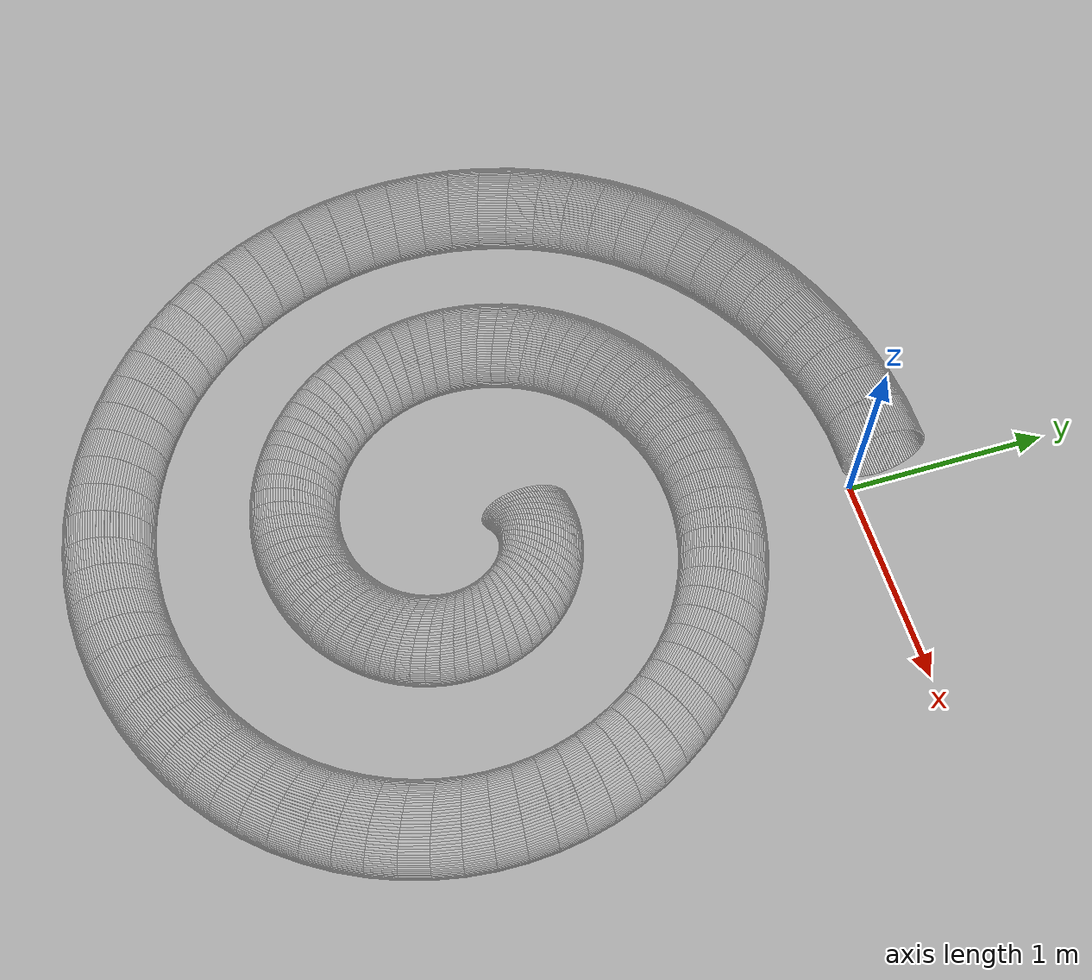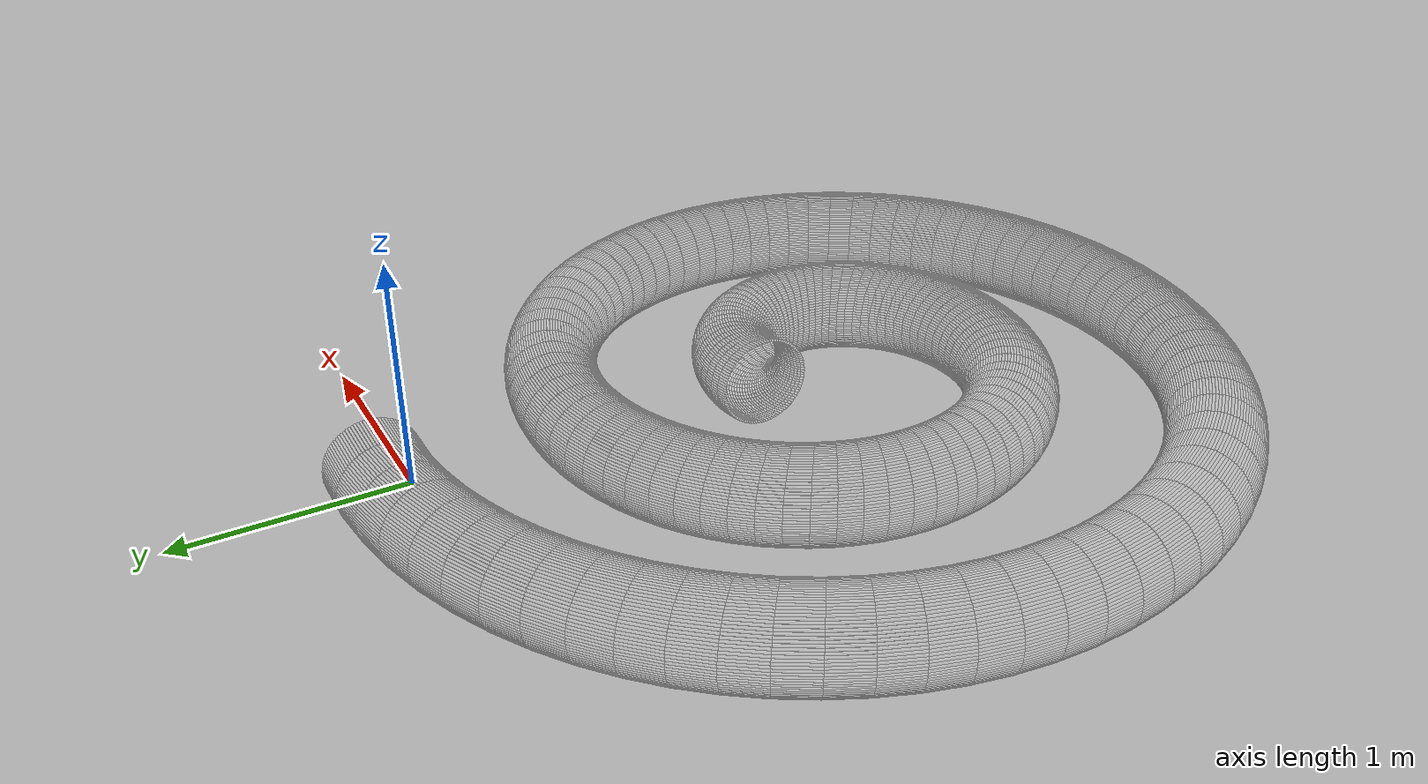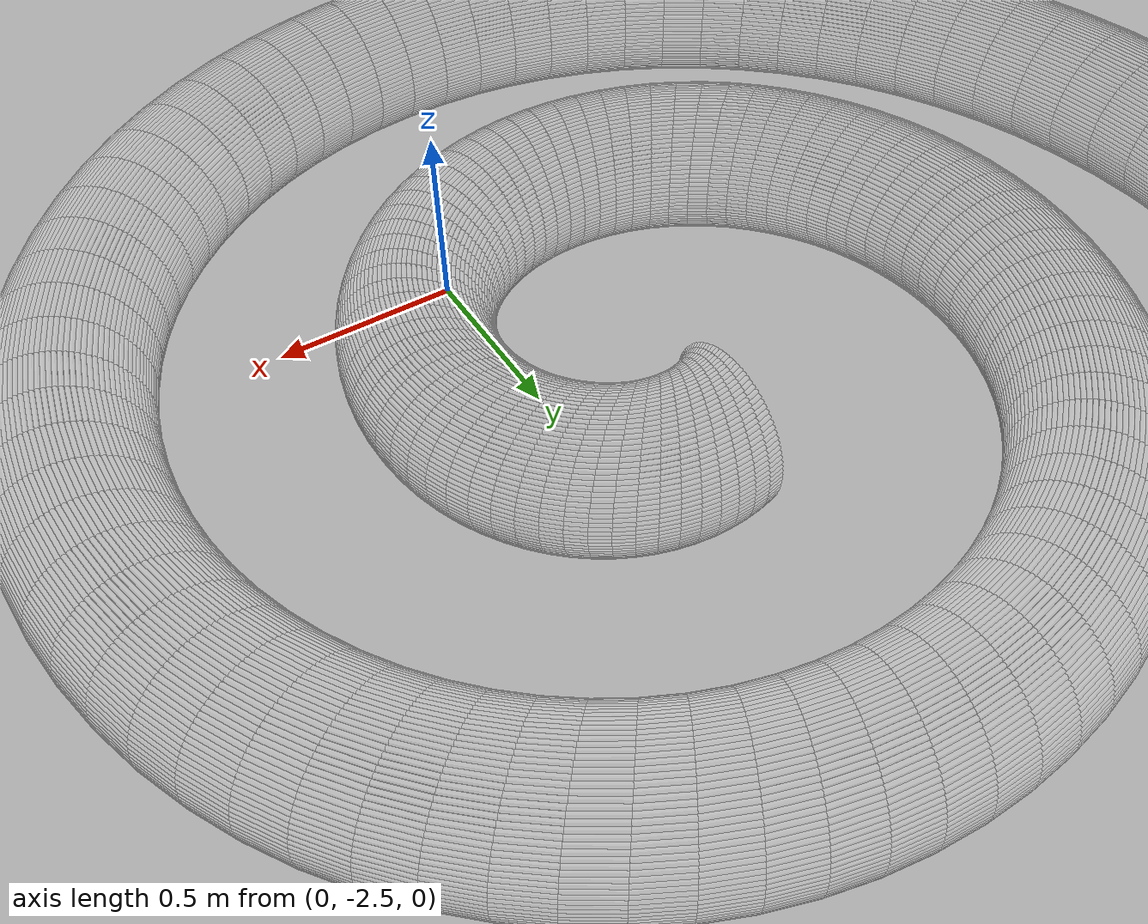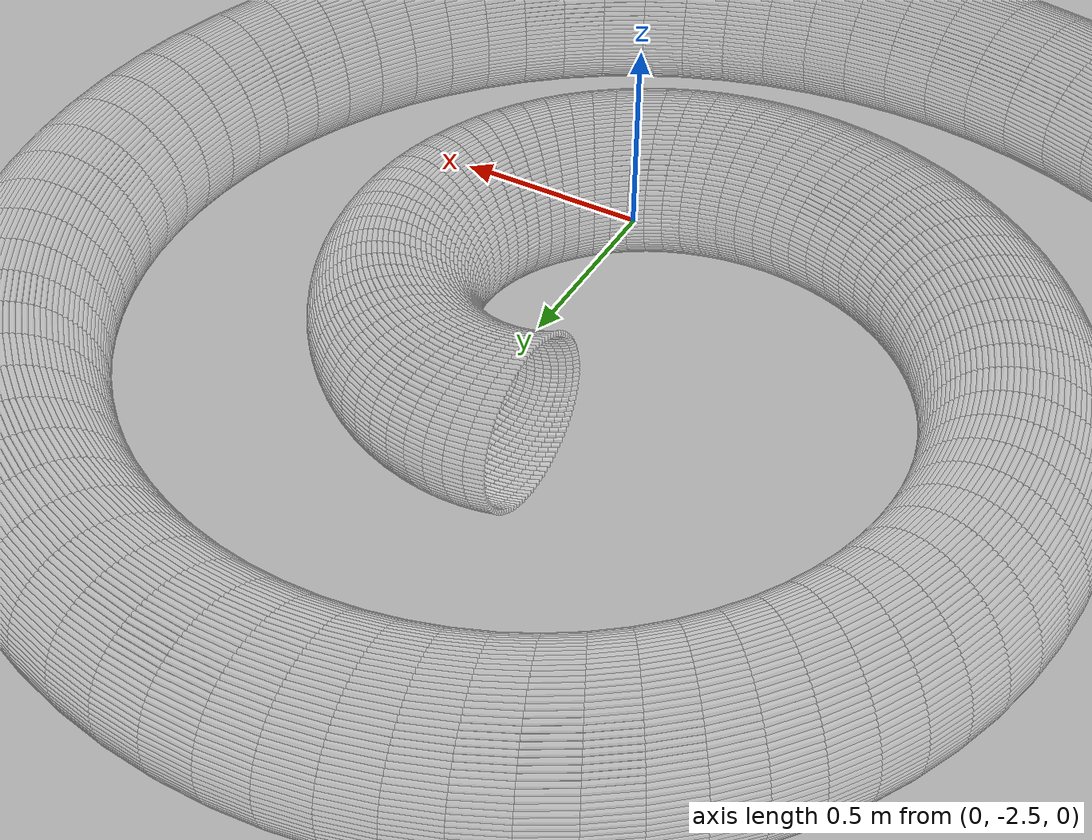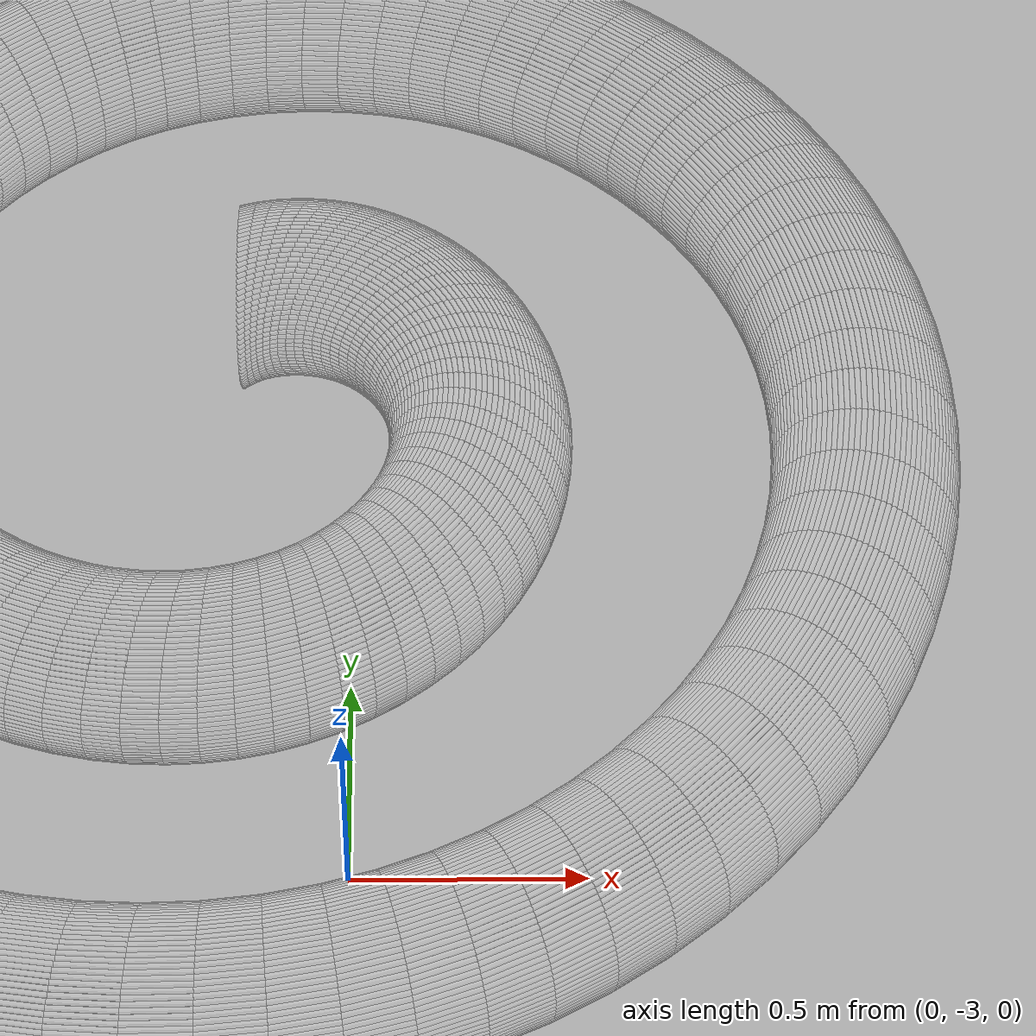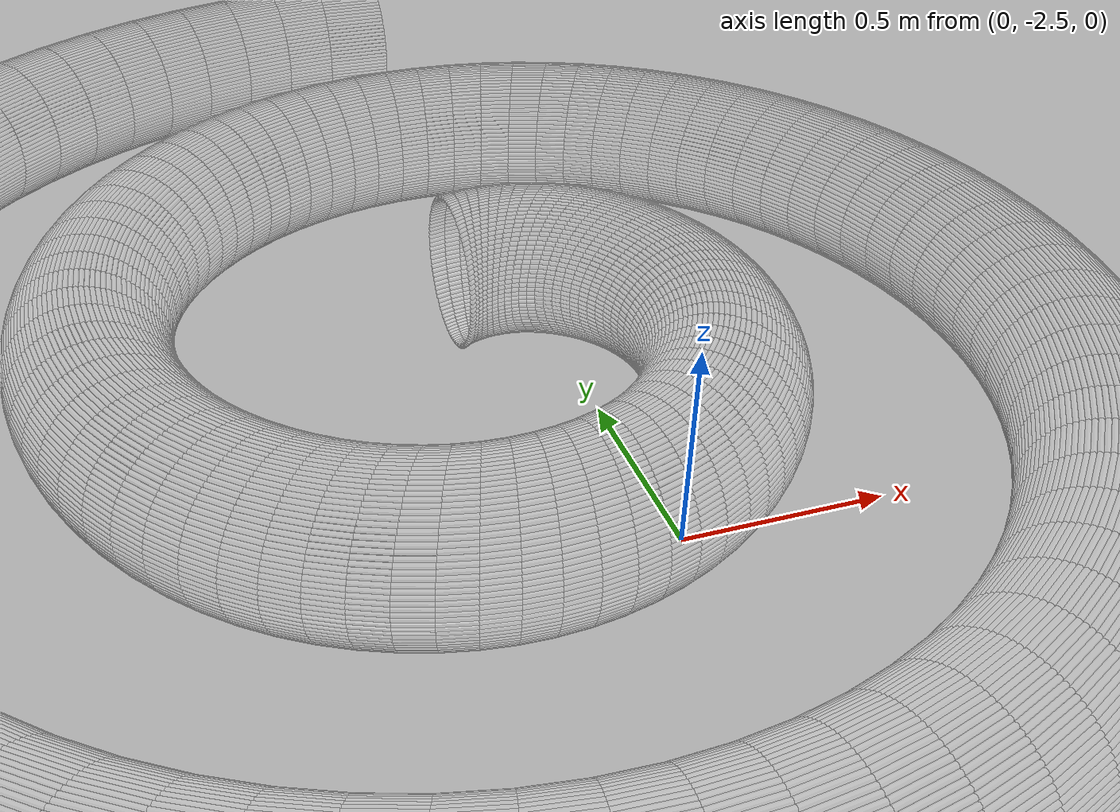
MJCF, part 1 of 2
<?xml version="1.0" encoding="utf-8"?>
<mujoco>
   <worldbody>
   <body pos="-0.25 -1.84 -0.02" euler="0 0 90">
      <geom euler=" 0 10 0 " fromto="2.2 -0.2 0.2 2.2 0 0.2" rgba="1 1 1 0.05"
            size="0.0062822"
            type="cylinder"/>
      <geom euler=" 0 20 0 " fromto="2.1996 -0.2 0.21256 2.1996 0 0.21256"
            rgba="1 1 1 0.05"
            size="0.0062822"
            type="cylinder"/>
      <geom euler=" 0 30 0 " fromto="2.1984 -0.2 0.22507 2.1984 0 0.22507"
            rgba="1 1 1 0.05"
            size="0.0062822"
            type="cylinder"/>
      <geom euler=" 0 40 0 " fromto="2.1965 -0.2 0.23748 2.1965 0 0.23748"
            rgba="1 1 1 0.05"
            size="0.0062822"
            type="cylinder"/>
      <geom euler=" 0 50 0 " fromto="2.1937 -0.2 0.24974 2.1937 0 0.24974"
            rgba="1 1 1 0.05"
            size="0.0062822"
            type="cylinder"/>
      <geom euler=" 0 60 0 " fromto="2.1902 -0.2 0.2618 2.1902 0 0.2618" rgba="1 1 1 0.05"
            size="0.0062822"
            type="cylinder"/>
      <geom euler=" 0 70 0 " fromto="2.186 -0.2 0.27362 2.186 0 0.27362" rgba="1 1 1 0.05"
            size="0.0062822"
            type="cylinder"/>
      <geom euler=" 0 80 0 " fromto="2.181 -0.2 0.28516 2.181 0 0.28516" rgba="1 1 1 0.05"
            size="0.0062822"
            type="cylinder"/>
      <geom euler=" 0 90 0 " fromto="2.1753 -0.2 0.29635 2.1753 0 0.29635"
            rgba="1 1 1 0.05"
            size="0.0062822"
            type="cylinder"/>
      <geom euler=" 0 100 0 " fromto="2.1689 -0.2 0.30717 2.1689 0 0.30717"
            rgba="1 1 1 0.05"
            size="0.0062822"
            type="cylinder"/>
      <geom euler=" 0 110 0 " fromto="2.1618 -0.2 0.31756 2.1618 0 0.31756"
            rgba="1 1 1 0.05"
            size="0.0062822"
            type="cylinder"/>
      <geom euler=" 0 120 0 " fromto="2.1541 -0.2 0.32748 2.1541 0 0.32748"
            rgba="1 1 1 0.05"
            size="0.0062822"
            type="cylinder"/>
      <geom euler=" 0 130 0 " fromto="2.1458 -0.2 0.33691 2.1458 0 0.33691"
            rgba="1 1 1 0.05"
            size="0.0062822"
            type="cylinder"/>
      <geom euler=" 0 140 0 " fromto="2.1369 -0.2 0.34579 2.1369 0 0.34579"
            rgba="1 1 1 0.05"
            size="0.0062822"
            type="cylinder"/>
      <geom euler=" 0 150 0 " fromto="2.1275 -0.2 0.3541 2.1275 0 0.3541" rgba="1 1 1 0.05"
            size="0.0062822"
            type="cylinder"/>
      <geom euler=" 0 160 0 " fromto="2.1176 -0.2 0.3618 2.1176 0 0.3618" rgba="1 1 1 0.05"
            size="0.0062822"
            type="cylinder"/>
      <geom euler=" 0 170 0 " fromto="2.1072 -0.2 0.36887 2.1072 0 0.36887"
            rgba="1 1 1 0.05"
            size="0.0062822"
            type="cylinder"/>
      <geom euler=" 0 180 0 " fromto="2.0964 -0.2 0.37526 2.0964 0 0.37526"
            rgba="1 1 1 0.05"
            size="0.0062822"
            type="cylinder"/>
      <geom euler=" 0 190 0 " fromto="2.0852 -0.2 0.38097 2.0852 0 0.38097"
            rgba="1 1 1 0.05"
            size="0.0062822"
            type="cylinder"/>
      <geom euler=" 0 200 0 " fromto="2.0736 -0.2 0.38596 2.0736 0 0.38596"
            rgba="1 1 1 0.05"
            size="0.0062822"
            type="cylinder"/>
      <geom euler=" 0 210 0 " fromto="2.0618 -0.2 0.39021 2.0618 0 0.39021"
            rgba="1 1 1 0.05"
            size="0.0062822"
            type="cylinder"/>
      <geom euler=" 0 220 0 " fromto="2.0497 -0.2 0.39372 2.0497 0 0.39372"
            rgba="1 1 1 0.05"
            size="0.0062822"
            type="cylinder"/>
      <geom euler=" 0 230 0 " fromto="2.0375 -0.2 0.39646 2.0375 0 0.39646"
            rgba="1 1 1 0.05"
            size="0.0062822"
            type="cylinder"/>
      <geom euler=" 0 240 0 " fromto="2.0251 -0.2 0.39842 2.0251 0 0.39842"
            rgba="1 1 1 0.05"
            size="0.0062822"
            type="cylinder"/>
      <geom euler=" 0 250 0 " fromto="2.0126 -0.2 0.39961 2.0126 0 0.39961"
            rgba="1 1 1 0.05"
            size="0.0062822"
            type="cylinder"/>
      <geom euler=" 0 260 0 " fromto="2 -0.2 0.4 2 0 0.4" rgba="1 1 1 0.05"
            size="0.0062822"
            type="cylinder"/>
      <geom euler=" 0 270 0 " fromto="1.9874 -0.2 0.39961 1.9874 0 0.39961"
            rgba="1 1 1 0.05"
            size="0.0062822"
            type="cylinder"/>
      <geom euler=" 0 280 0 " fromto="1.9749 -0.2 0.39842 1.9749 0 0.39842"
            rgba="1 1 1 0.05"
            size="0.0062822"
            type="cylinder"/>
      <geom euler=" 0 290 0 " fromto="1.9625 -0.2 0.39646 1.9625 0 0.39646"
            rgba="1 1 1 0.05"
            size="0.0062822"
            type="cylinder"/>
      <geom euler=" 0 300 0 " fromto="1.9503 -0.2 0.39372 1.9503 0 0.39372"
            rgba="1 1 1 0.05"
            size="0.0062822"
            type="cylinder"/>
      <geom euler=" 0 310 0 " fromto="1.9382 -0.2 0.39021 1.9382 0 0.39021"
            rgba="1 1 1 0.05"
            size="0.0062822"
            type="cylinder"/>
      <geom euler=" 0 320 0 " fromto="1.9264 -0.2 0.38596 1.9264 0 0.38596"
            rgba="1 1 1 0.05"
            size="0.0062822"
            type="cylinder"/>
      <geom euler=" 0 330 0 " fromto="1.9148 -0.2 0.38097 1.9148 0 0.38097"
            rgba="1 1 1 0.05"
            size="0.0062822"
            type="cylinder"/>
      <geom euler=" 0 340 0 " fromto="1.9036 -0.2 0.37526 1.9036 0 0.37526"
            rgba="1 1 1 0.05"
            size="0.0062822"
            type="cylinder"/>
      <geom euler=" 0 350 0 " fromto="1.8928 -0.2 0.36887 1.8928 0 0.36887"
            rgba="1 1 1 0.05"
            size="0.0062822"
            type="cylinder"/>
      <geom euler=" 0 360 0 " fromto="1.8824 -0.2 0.3618 1.8824 0 0.3618" rgba="1 1 1 0.05"
            size="0.0062822"
            type="cylinder"/>
      <geom euler=" 0 370 0 " fromto="1.8725 -0.2 0.3541 1.8725 0 0.3541" rgba="1 1 1 0.05"
            size="0.0062822"
            type="cylinder"/>
      <geom euler=" 0 380 0 " fromto="1.8631 -0.2 0.34579 1.8631 0 0.34579"
            rgba="1 1 1 0.05"
            size="0.0062822"
            type="cylinder"/>
      <geom euler=" 0 390 0 " fromto="1.8542 -0.2 0.33691 1.8542 0 0.33691"
            rgba="1 1 1 0.05"
            size="0.0062822"
            type="cylinder"/>
      <geom euler=" 0 400 0 " fromto="1.8459 -0.2 0.32748 1.8459 0 0.32748"
            rgba="1 1 1 0.05"
            size="0.0062822"
            type="cylinder"/>
      <geom euler=" 0 410 0 " fromto="1.8382 -0.2 0.31756 1.8382 0 0.31756"
            rgba="1 1 1 0.05"
            size="0.0062822"
            type="cylinder"/>
      <geom euler=" 0 420 0 " fromto="1.8311 -0.2 0.30717 1.8311 0 0.30717"
            rgba="1 1 1 0.05"
            size="0.0062822"
            type="cylinder"/>
      <geom euler=" 0 430 0 " fromto="1.8247 -0.2 0.29635 1.8247 0 0.29635"
            rgba="1 1 1 0.05"
            size="0.0062822"
            type="cylinder"/>
      <geom euler=" 0 440 0 " fromto="1.819 -0.2 0.28516 1.819 0 0.28516" rgba="1 1 1 0.05"
            size="0.0062822"
            type="cylinder"/>
      <geom euler=" 0 450 0 " fromto="1.814 -0.2 0.27362 1.814 0 0.27362" rgba="1 1 1 0.05"
            size="0.0062822"
            type="cylinder"/>
      <geom euler=" 0 460 0 " fromto="1.8098 -0.2 0.2618 1.8098 0 0.2618" rgba="1 1 1 0.05"
            size="0.0062822"
            type="cylinder"/>
      <geom euler=" 0 470 0 " fromto="1.8063 -0.2 0.24974 1.8063 0 0.24974"
            rgba="1 1 1 0.05"
            size="0.0062822"
            type="cylinder"/>
      <geom euler=" 0 480 0 " fromto="1.8035 -0.2 0.23748 1.8035 0 0.23748"
            rgba="1 1 1 0.05"
            size="0.0062822"
            type="cylinder"/>
      <geom euler=" 0 490 0 " fromto="1.8016 -0.2 0.22507 1.8016 0 0.22507"
            rgba="1 1 1 0.05"
            size="0.0062822"
            type="cylinder"/>
      <geom euler=" 0 500 0 " fromto="1.8004 -0.2 0.21256 1.8004 0 0.21256"
            rgba="1 1 1 0.05"
            size="0.0062822"
            type="cylinder"/>
      <geom euler=" 0 510 0 " fromto="1.8 -0.2 0.2 1.8 0 0.2" rgba="1 1 1 0.05"
            size="0.0062822"
            type="cylinder"/>
      <geom euler=" 0 520 0 " fromto="1.8004 -0.2 0.18744 1.8004 0 0.18744"
            rgba="1 1 1 0.35"
            size="0.0062822"
            type="cylinder"/>
      <geom euler=" 0 530 0 " fromto="1.8016 -0.2 0.17493 1.8016 0 0.17493"
            rgba="1 1 1 0.35"
            size="0.0062822"
            type="cylinder"/>
      <geom euler=" 0 540 0 " fromto="1.8035 -0.2 0.16252 1.8035 0 0.16252"
            rgba="1 1 1 0.35"
            size="0.0062822"
            type="cylinder"/>
      <geom euler=" 0 550 0 " fromto="1.8063 -0.2 0.15026 1.8063 0 0.15026"
            rgba="1 1 1 0.35"
            size="0.0062822"
            type="cylinder"/>
      <geom euler=" 0 560 0 " fromto="1.8098 -0.2 0.1382 1.8098 0 0.1382" rgba="1 1 1 0.35"
            size="0.0062822"
            type="cylinder"/>
      <geom euler=" 0 570 0 " fromto="1.814 -0.2 0.12638 1.814 0 0.12638" rgba="1 1 1 0.35"
            size="0.0062822"
            type="cylinder"/>
      <geom euler=" 0 580 0 " fromto="1.819 -0.2 0.11484 1.819 0 0.11484" rgba="1 1 1 0.35"
            size="0.0062822"
            type="cylinder"/>
      <geom euler=" 0 590 0 " fromto="1.8247 -0.2 0.10365 1.8247 0 0.10365"
            rgba="1 1 1 0.35"
            size="0.0062822"
            type="cylinder"/>
      <geom euler=" 0 600 0 " fromto="1.8311 -0.2 0.092835 1.8311 0 0.092835"
            rgba="1 1 1 0.35"
            size="0.0062822"
            type="cylinder"/>
      <geom euler=" 0 610 0 " fromto="1.8382 -0.2 0.082443 1.8382 0 0.082443"
            rgba="1 1 1 0.35"
            size="0.0062822"
            type="cylinder"/>
      <geom euler=" 0 620 0 " fromto="1.8459 -0.2 0.072515 1.8459 0 0.072515"
            rgba="1 1 1 0.35"
            size="0.0062822"
            type="cylinder"/>
      <geom euler=" 0 630 0 " fromto="1.8542 -0.2 0.063091 1.8542 0 0.063091"
            rgba="1 1 1 0.35"
            size="0.0062822"
            type="cylinder"/>
      <geom euler=" 0 640 0 " fromto="1.8631 -0.2 0.054206 1.8631 0 0.054206"
            rgba="1 1 1 0.35"
            size="0.0062822"
            type="cylinder"/>
      <geom euler=" 0 650 0 " fromto="1.8725 -0.2 0.045897 1.8725 0 0.045897"
            rgba="1 1 1 0.35"
            size="0.0062822"
            type="cylinder"/>
      <geom euler=" 0 660 0 " fromto="1.8824 -0.2 0.038197 1.8824 0 0.038197"
            rgba="1 1 1 0.35"
            size="0.0062822"
            type="cylinder"/>
      <geom euler=" 0 670 0 " fromto="1.8928 -0.2 0.031134 1.8928 0 0.031134"
            rgba="1 1 1 0.35"
            size="0.0062822"
            type="cylinder"/>
      <geom euler=" 0 680 0 " fromto="1.9036 -0.2 0.024739 1.9036 0 0.024739"
            rgba="1 1 1 0.35"
            size="0.0062822"
            type="cylinder"/>
      <geom euler=" 0 690 0 " fromto="1.9148 -0.2 0.019035 1.9148 0 0.019035"
            rgba="1 1 1 0.35"
            size="0.0062822"
            type="cylinder"/>
      <geom euler=" 0 700 0 " fromto="1.9264 -0.2 0.014045 1.9264 0 0.014045"
            rgba="1 1 1 0.35"
            size="0.0062822"
            type="cylinder"/>
      <geom euler=" 0 710 0 " fromto="1.9382 -0.2 0.0097887 1.9382 0 0.0097887"
            rgba="1 1 1 0.35"
            size="0.0062822"
            type="cylinder"/>
      <geom euler=" 0 720 0 " fromto="1.9503 -0.2 0.0062834 1.9503 0 0.0062834"
            rgba="1 1 1 0.35"
            size="0.0062822"
            type="cylinder"/>
      <geom euler=" 0 730 0 " fromto="1.9625 -0.2 0.0035425 1.9625 0 0.0035425"
            rgba="1 1 1 0.35"
            size="0.0062822"
            type="cylinder"/>
      <geom euler=" 0 740 0 " fromto="1.9749 -0.2 0.0015771 1.9749 0 0.0015771"
            rgba="1 1 1 0.35"
            size="0.0062822"
            type="cylinder"/>
      <geom euler=" 0 750 0 " fromto="1.9874 -0.2 0.00039465 1.9874 0 0.00039465"
            rgba="1 1 1 0.35"
            size="0.0062822"
            type="cylinder"/>
      <geom euler=" 0 760 0 " fromto="2 -0.2 0 2 0 0" rgba="1 1 1 0.35" size="0.0062822"
            type="cylinder"/>
      <geom euler=" 0 770 0 " fromto="2.0126 -0.2 0.00039465 2.0126 0 0.00039465"
            rgba="1 1 1 0.35"
            size="0.0062822"
            type="cylinder"/>
      <geom euler=" 0 780 0 " fromto="2.0251 -0.2 0.0015771 2.0251 0 0.0015771"
            rgba="1 1 1 0.35"
            size="0.0062822"
            type="cylinder"/>
      <geom euler=" 0 790 0 " fromto="2.0375 -0.2 0.0035425 2.0375 0 0.0035425"
            rgba="1 1 1 0.35"
            size="0.0062822"
            type="cylinder"/>
      <geom euler=" 0 800 0 " fromto="2.0497 -0.2 0.0062834 2.0497 0 0.0062834"
            rgba="1 1 1 0.35"
            size="0.0062822"
            type="cylinder"/>
      <geom euler=" 0 810 0 " fromto="2.0618 -0.2 0.0097887 2.0618 0 0.0097887"
            rgba="1 1 1 0.35"
            size="0.0062822"
            type="cylinder"/>
      <geom euler=" 0 820 0 " fromto="2.0736 -0.2 0.014045 2.0736 0 0.014045"
            rgba="1 1 1 0.35"
            size="0.0062822"
            type="cylinder"/>
      <geom euler=" 0 830 0 " fromto="2.0852 -0.2 0.019035 2.0852 0 0.019035"
            rgba="1 1 1 0.35"
            size="0.0062822"
            type="cylinder"/>
      <geom euler=" 0 840 0 " fromto="2.0964 -0.2 0.024739 2.0964 0 0.024739"
            rgba="1 1 1 0.35"
            size="0.0062822"
            type="cylinder"/>
      <geom euler=" 0 850 0 " fromto="2.1072 -0.2 0.031134 2.1072 0 0.031134"
            rgba="1 1 1 0.35"
            size="0.0062822"
            type="cylinder"/>
      <geom euler=" 0 860 0 " fromto="2.1176 -0.2 0.038197 2.1176 0 0.038197"
            rgba="1 1 1 0.35"
            size="0.0062822"
            type="cylinder"/>
      <geom euler=" 0 870 0 " fromto="2.1275 -0.2 0.045897 2.1275 0 0.045897"
            rgba="1 1 1 0.35"
            size="0.0062822"
            type="cylinder"/>
      <geom euler=" 0 880 0 " fromto="2.1369 -0.2 0.054206 2.1369 0 0.054206"
            rgba="1 1 1 0.35"
            size="0.0062822"
            type="cylinder"/>
      <geom euler=" 0 890 0 " fromto="2.1458 -0.2 0.063091 2.1458 0 0.063091"
            rgba="1 1 1 0.35"
            size="0.0062822"
            type="cylinder"/>
      <geom euler=" 0 900 0 " fromto="2.1541 -0.2 0.072515 2.1541 0 0.072515"
            rgba="1 1 1 0.35"
            size="0.0062822"
            type="cylinder"/>
      <geom euler=" 0 910 0 " fromto="2.1618 -0.2 0.082443 2.1618 0 0.082443"
            rgba="1 1 1 0.35"
            size="0.0062822"
            type="cylinder"/>
      <geom euler=" 0 920 0 " fromto="2.1689 -0.2 0.092835 2.1689 0 0.092835"
            rgba="1 1 1 0.35"
            size="0.0062822"
            type="cylinder"/>
      <geom euler=" 0 930 0 " fromto="2.1753 -0.2 0.10365 2.1753 0 0.10365"
            rgba="1 1 1 0.35"
            size="0.0062822"
            type="cylinder"/>
      <geom euler=" 0 940 0 " fromto="2.181 -0.2 0.11484 2.181 0 0.11484" rgba="1 1 1 0.35"
            size="0.0062822"
            type="cylinder"/>
      <geom euler=" 0 950 0 " fromto="2.186 -0.2 0.12638 2.186 0 0.12638" rgba="1 1 1 0.35"
            size="0.0062822"
            type="cylinder"/>
      <geom euler=" 0 960 0 " fromto="2.1902 -0.2 0.1382 2.1902 0 0.1382" rgba="1 1 1 0.35"
            size="0.0062822"
            type="cylinder"/>
      <geom euler=" 0 970 0 " fromto="2.1937 -0.2 0.15026 2.1937 0 0.15026"
            rgba="1 1 1 0.35"
            size="0.0062822"
            type="cylinder"/>
      <geom euler=" 0 980 0 " fromto="2.1965 -0.2 0.16252 2.1965 0 0.16252"
            rgba="1 1 1 0.35"
            size="0.0062822"
            type="cylinder"/>
      <geom euler=" 0 990 0 " fromto="2.1984 -0.2 0.17493 2.1984 0 0.17493"
            rgba="1 1 1 0.35"
            size="0.0062822"
            type="cylinder"/>
      <geom euler=" 0 1000 0 " fromto="2.1996 -0.2 0.18744 2.1996 0 0.18744"
            rgba="1 1 1 0.35"
            size="0.0062822"
            type="cylinder"/>
      <geom euler=" 0 10 0 " fromto="2.2 0 0.2 2.1808 0.18436 0.2" rgba="1 1 1 0.05"
            size="0.0062822"
            type="cylinder"/>
      <geom euler=" 0 20 0 " fromto="2.1996 0 0.21256 2.1804 0.18433 0.21256"
            rgba="1 1 1 0.05"
            size="0.0062822"
            type="cylinder"/>
      <geom euler=" 0 30 0 " fromto="2.1984 0 0.22507 2.1792 0.18423 0.22507"
            rgba="1 1 1 0.05"
            size="0.0062822"
            type="cylinder"/>
      <geom euler=" 0 40 0 " fromto="2.1965 0 0.23748 2.1773 0.18406 0.23748"
            rgba="1 1 1 0.05"
            size="0.0062822"
            type="cylinder"/>
      <geom euler=" 0 50 0 " fromto="2.1937 0 0.24974 2.1746 0.18383 0.24974"
            rgba="1 1 1 0.05"
            size="0.0062822"
            type="cylinder"/>
      <geom euler=" 0 60 0 " fromto="2.1902 0 0.2618 2.1711 0.18354 0.2618"
            rgba="1 1 1 0.05"
            size="0.0062822"
            type="cylinder"/>
      <geom euler=" 0 70 0 " fromto="2.186 0 0.27362 2.1668 0.18318 0.27362"
            rgba="1 1 1 0.05"
            size="0.0062822"
            type="cylinder"/>
      <geom euler=" 0 80 0 " fromto="2.181 0 0.28516 2.1618 0.18276 0.28516"
            rgba="1 1 1 0.05"
            size="0.0062822"
            type="cylinder"/>
      <geom euler=" 0 90 0 " fromto="2.1753 0 0.29635 2.1562 0.18228 0.29635"
            rgba="1 1 1 0.05"
            size="0.0062822"
            type="cylinder"/>
      <geom euler=" 0 100 0 " fromto="2.1689 0 0.30717 2.1498 0.18174 0.30717"
            rgba="1 1 1 0.05"
            size="0.0062822"
            type="cylinder"/>
      <geom euler=" 0 110 0 " fromto="2.1618 0 0.31756 2.1428 0.18115 0.31756"
            rgba="1 1 1 0.05"
            size="0.0062822"
            type="cylinder"/>
      <geom euler=" 0 120 0 " fromto="2.1541 0 0.32748 2.1351 0.1805 0.32748"
            rgba="1 1 1 0.05"
            size="0.0062822"
            type="cylinder"/>
      <geom euler=" 0 130 0 " fromto="2.1458 0 0.33691 2.1268 0.1798 0.33691"
            rgba="1 1 1 0.05"
            size="0.0062822"
            type="cylinder"/>
      <geom euler=" 0 140 0 " fromto="2.1369 0 0.34579 2.1179 0.17905 0.34579"
            rgba="1 1 1 0.05"
            size="0.0062822"
            type="cylinder"/>
      <geom euler=" 0 150 0 " fromto="2.1275 0 0.3541 2.1086 0.17825 0.3541"
            rgba="1 1 1 0.05"
            size="0.0062822"
            type="cylinder"/>
      <geom euler=" 0 160 0 " fromto="2.1176 0 0.3618 2.0987 0.17742 0.3618"
            rgba="1 1 1 0.05"
            size="0.0062822"
            type="cylinder"/>
      <geom euler=" 0 170 0 " fromto="2.1072 0 0.36887 2.0883 0.17654 0.36887"
            rgba="1 1 1 0.05"
            size="0.0062822"
            type="cylinder"/>
      <geom euler=" 0 180 0 " fromto="2.0964 0 0.37526 2.0775 0.17563 0.37526"
            rgba="1 1 1 0.05"
            size="0.0062822"
            type="cylinder"/>
      <geom euler=" 0 190 0 " fromto="2.0852 0 0.38097 2.0664 0.17469 0.38097"
            rgba="1 1 1 0.05"
            size="0.0062822"
            type="cylinder"/>
      <geom euler=" 0 200 0 " fromto="2.0736 0 0.38596 2.0549 0.17372 0.38596"
            rgba="1 1 1 0.05"
            size="0.0062822"
            type="cylinder"/>
      <geom euler=" 0 210 0 " fromto="2.0618 0 0.39021 2.0431 0.17272 0.39021"
            rgba="1 1 1 0.05"
            size="0.0062822"
            type="cylinder"/>
      <geom euler=" 0 220 0 " fromto="2.0497 0 0.39372 2.0311 0.1717 0.39372"
            rgba="1 1 1 0.05"
            size="0.0062822"
            type="cylinder"/>
      <geom euler=" 0 230 0 " fromto="2.0375 0 0.39646 2.0189 0.17067 0.39646"
            rgba="1 1 1 0.05"
            size="0.0062822"
            type="cylinder"/>
      <geom euler=" 0 240 0 " fromto="2.0251 0 0.39842 2.0065 0.16963 0.39842"
            rgba="1 1 1 0.05"
            size="0.0062822"
            type="cylinder"/>
      <geom euler=" 0 250 0 " fromto="2.0126 0 0.39961 1.994 0.16857 0.39961"
            rgba="1 1 1 0.05"
            size="0.0062822"
            type="cylinder"/>
      <geom euler=" 0 260 0 " fromto="2 0 0.4 1.9815 0.16752 0.4" rgba="1 1 1 0.05"
            size="0.0062822"
            type="cylinder"/>
      <geom euler=" 0 270 0 " fromto="1.9874 0 0.39961 1.969 0.16646 0.39961"
            rgba="1 1 1 0.05"
            size="0.0062822"
            type="cylinder"/>
      <geom euler=" 0 280 0 " fromto="1.9749 0 0.39842 1.9565 0.1654 0.39842"
            rgba="1 1 1 0.05"
            size="0.0062822"
            type="cylinder"/>
      <geom euler=" 0 290 0 " fromto="1.9625 0 0.39646 1.9442 0.16436 0.39646"
            rgba="1 1 1 0.05"
            size="0.0062822"
            type="cylinder"/>
      <geom euler=" 0 300 0 " fromto="1.9503 0 0.39372 1.932 0.16333 0.39372"
            rgba="1 1 1 0.05"
            size="0.0062822"
            type="cylinder"/>
      <geom euler=" 0 310 0 " fromto="1.9382 0 0.39021 1.9199 0.16231 0.39021"
            rgba="1 1 1 0.05"
            size="0.0062822"
            type="cylinder"/>
      <geom euler=" 0 320 0 " fromto="1.9264 0 0.38596 1.9082 0.16131 0.38596"
            rgba="1 1 1 0.05"
            size="0.0062822"
            type="cylinder"/>
      <geom euler=" 0 330 0 " fromto="1.9148 0 0.38097 1.8967 0.16034 0.38097"
            rgba="1 1 1 0.05"
            size="0.0062822"
            type="cylinder"/>
      <geom euler=" 0 340 0 " fromto="1.9036 0 0.37526 1.8855 0.1594 0.37526"
            rgba="1 1 1 0.05"
            size="0.0062822"
            type="cylinder"/>
      <geom euler=" 0 350 0 " fromto="1.8928 0 0.36887 1.8747 0.15849 0.36887"
            rgba="1 1 1 0.05"
            size="0.0062822"
            type="cylinder"/>
      <geom euler=" 0 360 0 " fromto="1.8824 0 0.3618 1.8644 0.15761 0.3618"
            rgba="1 1 1 0.05"
            size="0.0062822"
            type="cylinder"/>
      <geom euler=" 0 370 0 " fromto="1.8725 0 0.3541 1.8545 0.15678 0.3541"
            rgba="1 1 1 0.05"
            size="0.0062822"
            type="cylinder"/>
      <geom euler=" 0 380 0 " fromto="1.8631 0 0.34579 1.8451 0.15598 0.34579"
            rgba="1 1 1 0.05"
            size="0.0062822"
            type="cylinder"/>
      <geom euler=" 0 390 0 " fromto="1.8542 0 0.33691 1.8362 0.15523 0.33691"
            rgba="1 1 1 0.05"
            size="0.0062822"
            type="cylinder"/>
      <geom euler=" 0 400 0 " fromto="1.8459 0 0.32748 1.828 0.15453 0.32748"
            rgba="1 1 1 0.05"
            size="0.0062822"
            type="cylinder"/>
      <geom euler=" 0 410 0 " fromto="1.8382 0 0.31756 1.8203 0.15389 0.31756"
            rgba="1 1 1 0.05"
            size="0.0062822"
            type="cylinder"/>
      <geom euler=" 0 420 0 " fromto="1.8311 0 0.30717 1.8133 0.15329 0.30717"
            rgba="1 1 1 0.05"
            size="0.0062822"
            type="cylinder"/>
      <geom euler=" 0 430 0 " fromto="1.8247 0 0.29635 1.8069 0.15275 0.29635"
            rgba="1 1 1 0.05"
            size="0.0062822"
            type="cylinder"/>
      <geom euler=" 0 440 0 " fromto="1.819 0 0.28516 1.8012 0.15227 0.28516"
            rgba="1 1 1 0.05"
            size="0.0062822"
            type="cylinder"/>
      <geom euler=" 0 450 0 " fromto="1.814 0 0.27362 1.7962 0.15185 0.27362"
            rgba="1 1 1 0.05"
            size="0.0062822"
            type="cylinder"/>
      <geom euler=" 0 460 0 " fromto="1.8098 0 0.2618 1.792 0.15149 0.2618"
            rgba="1 1 1 0.05"
            size="0.0062822"
            type="cylinder"/>
      <geom euler=" 0 470 0 " fromto="1.8063 0 0.24974 1.7885 0.1512 0.24974"
            rgba="1 1 1 0.05"
            size="0.0062822"
            type="cylinder"/>
      <geom euler=" 0 480 0 " fromto="1.8035 0 0.23748 1.7858 0.15097 0.23748"
            rgba="1 1 1 0.05"
            size="0.0062822"
            type="cylinder"/>
      <geom euler=" 0 490 0 " fromto="1.8016 0 0.22507 1.7838 0.1508 0.22507"
            rgba="1 1 1 0.05"
            size="0.0062822"
            type="cylinder"/>
      <geom euler=" 0 500 0 " fromto="1.8004 0 0.21256 1.7826 0.1507 0.21256"
            rgba="1 1 1 0.05"
            size="0.0062822"
            type="cylinder"/>
      <geom euler=" 0 510 0 " fromto="1.8 0 0.2 1.7822 0.15067 0.2" rgba="1 1 1 0.05"
            size="0.0062822"
            type="cylinder"/>
      <geom euler=" 0 520 0 " fromto="1.8004 0 0.18744 1.7826 0.1507 0.18744"
            rgba="1 1 1 0.35"
            size="0.0062822"
            type="cylinder"/>
      <geom euler=" 0 530 0 " fromto="1.8016 0 0.17493 1.7838 0.1508 0.17493"
            rgba="1 1 1 0.35"
            size="0.0062822"
            type="cylinder"/>
      <geom euler=" 0 540 0 " fromto="1.8035 0 0.16252 1.7858 0.15097 0.16252"
            rgba="1 1 1 0.35"
            size="0.0062822"
            type="cylinder"/>
      <geom euler=" 0 550 0 " fromto="1.8063 0 0.15026 1.7885 0.1512 0.15026"
            rgba="1 1 1 0.35"
            size="0.0062822"
            type="cylinder"/>
      <geom euler=" 0 560 0 " fromto="1.8098 0 0.1382 1.792 0.15149 0.1382"
            rgba="1 1 1 0.35"
            size="0.0062822"
            type="cylinder"/>
      <geom euler=" 0 570 0 " fromto="1.814 0 0.12638 1.7962 0.15185 0.12638"
            rgba="1 1 1 0.35"
            size="0.0062822"
            type="cylinder"/>
      <geom euler=" 0 580 0 " fromto="1.819 0 0.11484 1.8012 0.15227 0.11484"
            rgba="1 1 1 0.35"
            size="0.0062822"
            type="cylinder"/>
      <geom euler=" 0 590 0 " fromto="1.8247 0 0.10365 1.8069 0.15275 0.10365"
            rgba="1 1 1 0.35"
            size="0.0062822"
            type="cylinder"/>
      <geom euler=" 0 600 0 " fromto="1.8311 0 0.092835 1.8133 0.15329 0.092835"
            rgba="1 1 1 0.35"
            size="0.0062822"
            type="cylinder"/>
      <geom euler=" 0 610 0 " fromto="1.8382 0 0.082443 1.8203 0.15389 0.082443"
            rgba="1 1 1 0.35"
            size="0.0062822"
            type="cylinder"/>
      <geom euler=" 0 620 0 " fromto="1.8459 0 0.072515 1.828 0.15453 0.072515"
            rgba="1 1 1 0.35"
            size="0.0062822"
            type="cylinder"/>
      <geom euler=" 0 630 0 " fromto="1.8542 0 0.063091 1.8362 0.15523 0.063091"
            rgba="1 1 1 0.35"
            size="0.0062822"
            type="cylinder"/>
      <geom euler=" 0 640 0 " fromto="1.8631 0 0.054206 1.8451 0.15598 0.054206"
            rgba="1 1 1 0.35"
            size="0.0062822"
            type="cylinder"/>
      <geom euler=" 0 650 0 " fromto="1.8725 0 0.045897 1.8545 0.15678 0.045897"
            rgba="1 1 1 0.35"
            size="0.0062822"
            type="cylinder"/>
      <geom euler=" 0 660 0 " fromto="1.8824 0 0.038197 1.8644 0.15761 0.038197"
            rgba="1 1 1 0.35"
            size="0.0062822"
            type="cylinder"/>
      <geom euler=" 0 670 0 " fromto="1.8928 0 0.031134 1.8747 0.15849 0.031134"
            rgba="1 1 1 0.35"
            size="0.0062822"
            type="cylinder"/>
      <geom euler=" 0 680 0 " fromto="1.9036 0 0.024739 1.8855 0.1594 0.024739"
            rgba="1 1 1 0.35"
            size="0.0062822"
            type="cylinder"/>
      <geom euler=" 0 690 0 " fromto="1.9148 0 0.019035 1.8967 0.16034 0.019035"
            rgba="1 1 1 0.35"
            size="0.0062822"
            type="cylinder"/>
      <geom euler=" 0 700 0 " fromto="1.9264 0 0.014045 1.9082 0.16131 0.014045"
            rgba="1 1 1 0.35"
            size="0.0062822"
            type="cylinder"/>
      <geom euler=" 0 710 0 " fromto="1.9382 0 0.0097887 1.9199 0.16231 0.0097887"
            rgba="1 1 1 0.35"
            size="0.0062822"
            type="cylinder"/>
      <geom euler=" 0 720 0 " fromto="1.9503 0 0.0062834 1.932 0.16333 0.0062834"
            rgba="1 1 1 0.35"
            size="0.0062822"
            type="cylinder"/>
      <geom euler=" 0 730 0 " fromto="1.9625 0 0.0035425 1.9442 0.16436 0.0035425"
            rgba="1 1 1 0.35"
            size="0.0062822"
            type="cylinder"/>
      <geom euler=" 0 740 0 " fromto="1.9749 0 0.0015771 1.9565 0.1654 0.0015771"
            rgba="1 1 1 0.35"
            size="0.0062822"
            type="cylinder"/>
      <geom euler=" 0 750 0 " fromto="1.9874 0 0.00039465 1.969 0.16646 0.00039465"
            rgba="1 1 1 0.35"
            size="0.0062822"
            type="cylinder"/>
      <geom euler=" 0 760 0 " fromto="2 0 0 1.9815 0.16752 0" rgba="1 1 1 0.35"
            size="0.0062822"
            type="cylinder"/>
      <geom euler=" 0 770 0 " fromto="2.0126 0 0.00039465 1.994 0.16857 0.00039465"
            rgba="1 1 1 0.35"
            size="0.0062822"
            type="cylinder"/>
      <geom euler=" 0 780 0 " fromto="2.0251 0 0.0015771 2.0065 0.16963 0.0015771"
            rgba="1 1 1 0.35"
            size="0.0062822"
            type="cylinder"/>
      <geom euler=" 0 790 0 " fromto="2.0375 0 0.0035425 2.0189 0.17067 0.0035425"
            rgba="1 1 1 0.35"
            size="0.0062822"
            type="cylinder"/>
      <geom euler=" 0 800 0 " fromto="2.0497 0 0.0062834 2.0311 0.1717 0.0062834"
            rgba="1 1 1 0.35"
            size="0.0062822"
            type="cylinder"/>
      <geom euler=" 0 810 0 " fromto="2.0618 0 0.0097887 2.0431 0.17272 0.0097887"
            rgba="1 1 1 0.35"
            size="0.0062822"
            type="cylinder"/>
      <geom euler=" 0 820 0 " fromto="2.0736 0 0.014045 2.0549 0.17372 0.014045"
            rgba="1 1 1 0.35"
            size="0.0062822"
            type="cylinder"/>
      <geom euler=" 0 830 0 " fromto="2.0852 0 0.019035 2.0664 0.17469 0.019035"
            rgba="1 1 1 0.35"
            size="0.0062822"
            type="cylinder"/>
      <geom euler=" 0 840 0 " fromto="2.0964 0 0.024739 2.0775 0.17563 0.024739"
            rgba="1 1 1 0.35"
            size="0.0062822"
            type="cylinder"/>
      <geom euler=" 0 850 0 " fromto="2.1072 0 0.031134 2.0883 0.17654 0.031134"
            rgba="1 1 1 0.35"
            size="0.0062822"
            type="cylinder"/>
      <geom euler=" 0 860 0 " fromto="2.1176 0 0.038197 2.0987 0.17742 0.038197"
            rgba="1 1 1 0.35"
            size="0.0062822"
            type="cylinder"/>
      <geom euler=" 0 870 0 " fromto="2.1275 0 0.045897 2.1086 0.17825 0.045897"
            rgba="1 1 1 0.35"
            size="0.0062822"
            type="cylinder"/>
      <geom euler=" 0 880 0 " fromto="2.1369 0 0.054206 2.1179 0.17905 0.054206"
            rgba="1 1 1 0.35"
            size="0.0062822"
            type="cylinder"/>
      <geom euler=" 0 890 0 " fromto="2.1458 0 0.063091 2.1268 0.1798 0.063091"
            rgba="1 1 1 0.35"
            size="0.0062822"
            type="cylinder"/>
      <geom euler=" 0 900 0 " fromto="2.1541 0 0.072515 2.1351 0.1805 0.072515"
            rgba="1 1 1 0.35"
            size="0.0062822"
            type="cylinder"/>
      <geom euler=" 0 910 0 " fromto="2.1618 0 0.082443 2.1428 0.18115 0.082443"
            rgba="1 1 1 0.35"
            size="0.0062822"
            type="cylinder"/>
      <geom euler=" 0 920 0 " fromto="2.1689 0 0.092835 2.1498 0.18174 0.092835"
            rgba="1 1 1 0.35"
            size="0.0062822"
            type="cylinder"/>
      <geom euler=" 0 930 0 " fromto="2.1753 0 0.10365 2.1562 0.18228 0.10365"
            rgba="1 1 1 0.35"
            size="0.0062822"
            type="cylinder"/>
      <geom euler=" 0 940 0 " fromto="2.181 0 0.11484 2.1618 0.18276 0.11484"
            rgba="1 1 1 0.35"
            size="0.0062822"
            type="cylinder"/>
      <geom euler=" 0 950 0 " fromto="2.186 0 0.12638 2.1668 0.18318 0.12638"
            rgba="1 1 1 0.35"
            size="0.0062822"
            type="cylinder"/>
      <geom euler=" 0 960 0 " fromto="2.1902 0 0.1382 2.1711 0.18354 0.1382"
            rgba="1 1 1 0.35"
            size="0.0062822"
            type="cylinder"/>
      <geom euler=" 0 970 0 " fromto="2.1937 0 0.15026 2.1746 0.18383 0.15026"
            rgba="1 1 1 0.35"
            size="0.0062822"
            type="cylinder"/>
      <geom euler=" 0 980 0 " fromto="2.1965 0 0.16252 2.1773 0.18406 0.16252"
            rgba="1 1 1 0.35"
            size="0.0062822"
            type="cylinder"/>
      <geom euler=" 0 990 0 " fromto="2.1984 0 0.17493 2.1792 0.18423 0.17493"
            rgba="1 1 1 0.35"
            size="0.0062822"
            type="cylinder"/>
      <geom euler=" 0 1000 0 " fromto="2.1996 0 0.18744 2.1804 0.18433 0.18744"
            rgba="1 1 1 0.35"
            size="0.0062822"
            type="cylinder"/>
      <geom euler=" 0 10 0 " fromto="2.1808 0.18436 0.2 2.1463 0.3655 0.2"
            rgba="1 1 1 0.05"
            size="0.0062822"
            type="cylinder"/>
      <geom euler=" 0 20 0 " fromto="2.1804 0.18433 0.21256 2.1459 0.36543 0.21256"
            rgba="1 1 1 0.05"
            size="0.0062822"
            type="cylinder"/>
      <geom euler=" 0 30 0 " fromto="2.1792 0.18423 0.22507 2.1447 0.36523 0.22507"
            rgba="1 1 1 0.05"
            size="0.0062822"
            type="cylinder"/>
      <geom euler=" 0 40 0 " fromto="2.1773 0.18406 0.23748 2.1428 0.3649 0.23748"
            rgba="1 1 1 0.05"
            size="0.0062822"
            type="cylinder"/>
      <geom euler=" 0 50 0 " fromto="2.1746 0.18383 0.24974 2.1401 0.36444 0.24974"
            rgba="1 1 1 0.05"
            size="0.0062822"
            type="cylinder"/>
      <geom euler=" 0 60 0 " fromto="2.1711 0.18354 0.2618 2.1366 0.36386 0.2618"
            rgba="1 1 1 0.05"
            size="0.0062822"
            type="cylinder"/>
      <geom euler=" 0 70 0 " fromto="2.1668 0.18318 0.27362 2.1324 0.36314 0.27362"
            rgba="1 1 1 0.05"
            size="0.0062822"
            type="cylinder"/>
      <geom euler=" 0 80 0 " fromto="2.1618 0.18276 0.28516 2.1275 0.3623 0.28516"
            rgba="1 1 1 0.05"
            size="0.0062822"
            type="cylinder"/>
      <geom euler=" 0 90 0 " fromto="2.1562 0.18228 0.29635 2.1219 0.36135 0.29635"
            rgba="1 1 1 0.05"
            size="0.0062822"
            type="cylinder"/>
      <geom euler=" 0 100 0 " fromto="2.1498 0.18174 0.30717 2.1156 0.36027 0.30717"
            rgba="1 1 1 0.05"
            size="0.0062822"
            type="cylinder"/>
      <geom euler=" 0 110 0 " fromto="2.1428 0.18115 0.31756 2.1086 0.35909 0.31756"
            rgba="1 1 1 0.05"
            size="0.0062822"
            type="cylinder"/>
      <geom euler=" 0 120 0 " fromto="2.1351 0.1805 0.32748 2.101 0.35779 0.32748"
            rgba="1 1 1 0.05"
            size="0.0062822"
            type="cylinder"/>
      <geom euler=" 0 130 0 " fromto="2.1268 0.1798 0.33691 2.0928 0.3564 0.33691"
            rgba="1 1 1 0.05"
            size="0.0062822"
            type="cylinder"/>
      <geom euler=" 0 140 0 " fromto="2.1179 0.17905 0.34579 2.0841 0.35491 0.34579"
            rgba="1 1 1 0.05"
            size="0.0062822"
            type="cylinder"/>
      <geom euler=" 0 150 0 " fromto="2.1086 0.17825 0.3541 2.0748 0.35333 0.3541"
            rgba="1 1 1 0.05"
            size="0.0062822"
            type="cylinder"/>
      <geom euler=" 0 160 0 " fromto="2.0987 0.17742 0.3618 2.065 0.35166 0.3618"
            rgba="1 1 1 0.05"
            size="0.0062822"
            type="cylinder"/>
      <geom euler=" 0 170 0 " fromto="2.0883 0.17654 0.36887 2.0548 0.34991 0.36887"
            rgba="1 1 1 0.05"
            size="0.0062822"
            type="cylinder"/>
      <geom euler=" 0 180 0 " fromto="2.0775 0.17563 0.37526 2.0441 0.3481 0.37526"
            rgba="1 1 1 0.05"
            size="0.0062822"
            type="cylinder"/>
      <geom euler=" 0 190 0 " fromto="2.0664 0.17469 0.38097 2.0331 0.34622 0.38097"
            rgba="1 1 1 0.05"
            size="0.0062822"
            type="cylinder"/>
      <geom euler=" 0 200 0 " fromto="2.0549 0.17372 0.38596 2.0217 0.34428 0.38596"
            rgba="1 1 1 0.05"
            size="0.0062822"
            type="cylinder"/>
      <geom euler=" 0 210 0 " fromto="2.0431 0.17272 0.39021 2.01 0.3423 0.39021"
            rgba="1 1 1 0.05"
            size="0.0062822"
            type="cylinder"/>
      <geom euler=" 0 220 0 " fromto="2.0311 0.1717 0.39372 1.9982 0.34027 0.39372"
            rgba="1 1 1 0.05"
            size="0.0062822"
            type="cylinder"/>
      <geom euler=" 0 230 0 " fromto="2.0189 0.17067 0.39646 1.9861 0.33822 0.39646"
            rgba="1 1 1 0.05"
            size="0.0062822"
            type="cylinder"/>
      <geom euler=" 0 240 0 " fromto="2.0065 0.16963 0.39842 1.9738 0.33613 0.39842"
            rgba="1 1 1 0.05"
            size="0.0062822"
            type="cylinder"/>
      <geom euler=" 0 250 0 " fromto="1.994 0.16857 0.39961 1.9615 0.33403 0.39961"
            rgba="1 1 1 0.05"
            size="0.0062822"
            type="cylinder"/>
      <geom euler=" 0 260 0 " fromto="1.9815 0.16752 0.4 1.9491 0.33192 0.4"
            rgba="1 1 1 0.05"
            size="0.0062822"
            type="cylinder"/>
      <geom euler=" 0 270 0 " fromto="1.969 0.16646 0.39961 1.9367 0.32982 0.39961"
            rgba="1 1 1 0.05"
            size="0.0062822"
            type="cylinder"/>
      <geom euler=" 0 280 0 " fromto="1.9565 0.1654 0.39842 1.9244 0.32772 0.39842"
            rgba="1 1 1 0.05"
            size="0.0062822"
            type="cylinder"/>
      <geom euler=" 0 290 0 " fromto="1.9442 0.16436 0.39646 1.9122 0.32563 0.39646"
            rgba="1 1 1 0.05"
            size="0.0062822"
            type="cylinder"/>
      <geom euler=" 0 300 0 " fromto="1.932 0.16333 0.39372 1.9001 0.32357 0.39372"
            rgba="1 1 1 0.05"
            size="0.0062822"
            type="cylinder"/>
      <geom euler=" 0 310 0 " fromto="1.9199 0.16231 0.39021 1.8882 0.32155 0.39021"
            rgba="1 1 1 0.05"
            size="0.0062822"
            type="cylinder"/>
      <geom euler=" 0 320 0 " fromto="1.9082 0.16131 0.38596 1.8765 0.31956 0.38596"
            rgba="1 1 1 0.05"
            size="0.0062822"
            type="cylinder"/>
      <geom euler=" 0 330 0 " fromto="1.8967 0.16034 0.38097 1.8652 0.31763 0.38097"
            rgba="1 1 1 0.05"
            size="0.0062822"
            type="cylinder"/>
      <geom euler=" 0 340 0 " fromto="1.8855 0.1594 0.37526 1.8541 0.31575 0.37526"
            rgba="1 1 1 0.05"
            size="0.0062822"
            type="cylinder"/>
      <geom euler=" 0 350 0 " fromto="1.8747 0.15849 0.36887 1.8435 0.31393 0.36887"
            rgba="1 1 1 0.05"
            size="0.0062822"
            type="cylinder"/>
      <geom euler=" 0 360 0 " fromto="1.8644 0.15761 0.3618 1.8332 0.31219 0.3618"
            rgba="1 1 1 0.05"
            size="0.0062822"
            type="cylinder"/>
      <geom euler=" 0 370 0 " fromto="1.8545 0.15678 0.3541 1.8234 0.31052 0.3541"
            rgba="1 1 1 0.05"
            size="0.0062822"
            type="cylinder"/>
      <geom euler=" 0 380 0 " fromto="1.8451 0.15598 0.34579 1.8142 0.30894 0.34579"
            rgba="1 1 1 0.05"
            size="0.0062822"
            type="cylinder"/>
      <geom euler=" 0 390 0 " fromto="1.8362 0.15523 0.33691 1.8054 0.30745 0.33691"
            rgba="1 1 1 0.05"
            size="0.0062822"
            type="cylinder"/>
      <geom euler=" 0 400 0 " fromto="1.828 0.15453 0.32748 1.7972 0.30605 0.32748"
            rgba="1 1 1 0.05"
            size="0.0062822"
            type="cylinder"/>
      <geom euler=" 0 410 0 " fromto="1.8203 0.15389 0.31756 1.7896 0.30476 0.31756"
            rgba="1 1 1 0.05"
            size="0.0062822"
            type="cylinder"/>
      <geom euler=" 0 420 0 " fromto="1.8133 0.15329 0.30717 1.7827 0.30358 0.30717"
            rgba="1 1 1 0.05"
            size="0.0062822"
            type="cylinder"/>
      <geom euler=" 0 430 0 " fromto="1.8069 0.15275 0.29635 1.7763 0.3025 0.29635"
            rgba="1 1 1 0.05"
            size="0.0062822"
            type="cylinder"/>
      <geom euler=" 0 440 0 " fromto="1.8012 0.15227 0.28516 1.7707 0.30154 0.28516"
            rgba="1 1 1 0.05"
            size="0.0062822"
            type="cylinder"/>
      <geom euler=" 0 450 0 " fromto="1.7962 0.15185 0.27362 1.7658 0.30071 0.27362"
            rgba="1 1 1 0.05"
            size="0.0062822"
            type="cylinder"/>
      <geom euler=" 0 460 0 " fromto="1.792 0.15149 0.2618 1.7616 0.29999 0.2618"
            rgba="1 1 1 0.05"
            size="0.0062822"
            type="cylinder"/>
      <geom euler=" 0 470 0 " fromto="1.7885 0.1512 0.24974 1.7582 0.2994 0.24974"
            rgba="1 1 1 0.05"
            size="0.0062822"
            type="cylinder"/>
      <geom euler=" 0 480 0 " fromto="1.7858 0.15097 0.23748 1.7555 0.29894 0.23748"
            rgba="1 1 1 0.05"
            size="0.0062822"
            type="cylinder"/>
      <geom euler=" 0 490 0 " fromto="1.7838 0.1508 0.22507 1.7535 0.29861 0.22507"
            rgba="1 1 1 0.05"
            size="0.0062822"
            type="cylinder"/>
      <geom euler=" 0 500 0 " fromto="1.7826 0.1507 0.21256 1.7523 0.29841 0.21256"
            rgba="1 1 1 0.05"
            size="0.0062822"
            type="cylinder"/>
      <geom euler=" 0 510 0 " fromto="1.7822 0.15067 0.2 1.752 0.29835 0.2"
            rgba="1 1 1 0.05"
            size="0.0062822"
            type="cylinder"/>
      <geom euler=" 0 520 0 " fromto="1.7826 0.1507 0.18744 1.7523 0.29841 0.18744"
            rgba="1 1 1 0.35"
            size="0.0062822"
            type="cylinder"/>
      <geom euler=" 0 530 0 " fromto="1.7838 0.1508 0.17493 1.7535 0.29861 0.17493"
            rgba="1 1 1 0.35"
            size="0.0062822"
            type="cylinder"/>
      <geom euler=" 0 540 0 " fromto="1.7858 0.15097 0.16252 1.7555 0.29894 0.16252"
            rgba="1 1 1 0.35"
            size="0.0062822"
            type="cylinder"/>
      <geom euler=" 0 550 0 " fromto="1.7885 0.1512 0.15026 1.7582 0.2994 0.15026"
            rgba="1 1 1 0.35"
            size="0.0062822"
            type="cylinder"/>
      <geom euler=" 0 560 0 " fromto="1.792 0.15149 0.1382 1.7616 0.29999 0.1382"
            rgba="1 1 1 0.35"
            size="0.0062822"
            type="cylinder"/>
      <geom euler=" 0 570 0 " fromto="1.7962 0.15185 0.12638 1.7658 0.30071 0.12638"
            rgba="1 1 1 0.35"
            size="0.0062822"
            type="cylinder"/>
      <geom euler=" 0 580 0 " fromto="1.8012 0.15227 0.11484 1.7707 0.30154 0.11484"
            rgba="1 1 1 0.35"
            size="0.0062822"
            type="cylinder"/>
      <geom euler=" 0 590 0 " fromto="1.8069 0.15275 0.10365 1.7763 0.3025 0.10365"
            rgba="1 1 1 0.35"
            size="0.0062822"
            type="cylinder"/>
      <geom euler=" 0 600 0 " fromto="1.8133 0.15329 0.092835 1.7827 0.30358 0.092835"
            rgba="1 1 1 0.35"
            size="0.0062822"
            type="cylinder"/>
      <geom euler=" 0 610 0 " fromto="1.8203 0.15389 0.082443 1.7896 0.30476 0.082443"
            rgba="1 1 1 0.35"
            size="0.0062822"
            type="cylinder"/>
      <geom euler=" 0 620 0 " fromto="1.828 0.15453 0.072515 1.7972 0.30605 0.072515"
            rgba="1 1 1 0.35"
            size="0.0062822"
            type="cylinder"/>
      <geom euler=" 0 630 0 " fromto="1.8362 0.15523 0.063091 1.8054 0.30745 0.063091"
            rgba="1 1 1 0.35"
            size="0.0062822"
            type="cylinder"/>
      <geom euler=" 0 640 0 " fromto="1.8451 0.15598 0.054206 1.8142 0.30894 0.054206"
            rgba="1 1 1 0.35"
            size="0.0062822"
            type="cylinder"/>
      <geom euler=" 0 650 0 " fromto="1.8545 0.15678 0.045897 1.8234 0.31052 0.045897"
            rgba="1 1 1 0.35"
            size="0.0062822"
            type="cylinder"/>
      <geom euler=" 0 660 0 " fromto="1.8644 0.15761 0.038197 1.8332 0.31219 0.038197"
            rgba="1 1 1 0.35"
            size="0.0062822"
            type="cylinder"/>
      <geom euler=" 0 670 0 " fromto="1.8747 0.15849 0.031134 1.8435 0.31393 0.031134"
            rgba="1 1 1 0.35"
            size="0.0062822"
            type="cylinder"/>
      <geom euler=" 0 680 0 " fromto="1.8855 0.1594 0.024739 1.8541 0.31575 0.024739"
            rgba="1 1 1 0.35"
            size="0.0062822"
            type="cylinder"/>
      <geom euler=" 0 690 0 " fromto="1.8967 0.16034 0.019035 1.8652 0.31763 0.019035"
            rgba="1 1 1 0.35"
            size="0.0062822"
            type="cylinder"/>
      <geom euler=" 0 700 0 " fromto="1.9082 0.16131 0.014045 1.8765 0.31956 0.014045"
            rgba="1 1 1 0.35"
            size="0.0062822"
            type="cylinder"/>
      <geom euler=" 0 710 0 " fromto="1.9199 0.16231 0.0097887 1.8882 0.32155 0.0097887"
            rgba="1 1 1 0.35"
            size="0.0062822"
            type="cylinder"/>
      <geom euler=" 0 720 0 " fromto="1.932 0.16333 0.0062834 1.9001 0.32357 0.0062834"
            rgba="1 1 1 0.35"
            size="0.0062822"
            type="cylinder"/>
      <geom euler=" 0 730 0 " fromto="1.9442 0.16436 0.0035425 1.9122 0.32563 0.0035425"
            rgba="1 1 1 0.35"
            size="0.0062822"
            type="cylinder"/>
      <geom euler=" 0 740 0 " fromto="1.9565 0.1654 0.0015771 1.9244 0.32772 0.0015771"
            rgba="1 1 1 0.35"
            size="0.0062822"
            type="cylinder"/>
      <geom euler=" 0 750 0 " fromto="1.969 0.16646 0.00039465 1.9367 0.32982 0.00039465"
            rgba="1 1 1 0.35"
            size="0.0062822"
            type="cylinder"/>
      <geom euler=" 0 760 0 " fromto="1.9815 0.16752 0 1.9491 0.33192 0" rgba="1 1 1 0.35"
            size="0.0062822"
            type="cylinder"/>
      <geom euler=" 0 770 0 " fromto="1.994 0.16857 0.00039465 1.9615 0.33403 0.00039465"
            rgba="1 1 1 0.35"
            size="0.0062822"
            type="cylinder"/>
      <geom euler=" 0 780 0 " fromto="2.0065 0.16963 0.0015771 1.9738 0.33613 0.0015771"
            rgba="1 1 1 0.35"
            size="0.0062822"
            type="cylinder"/>
      <geom euler=" 0 790 0 " fromto="2.0189 0.17067 0.0035425 1.9861 0.33822 0.0035425"
            rgba="1 1 1 0.35"
            size="0.0062822"
            type="cylinder"/>
      <geom euler=" 0 800 0 " fromto="2.0311 0.1717 0.0062834 1.9982 0.34027 0.0062834"
            rgba="1 1 1 0.35"
            size="0.0062822"
            type="cylinder"/>
      <geom euler=" 0 810 0 " fromto="2.0431 0.17272 0.0097887 2.01 0.3423 0.0097887"
            rgba="1 1 1 0.35"
            size="0.0062822"
            type="cylinder"/>
      <geom euler=" 0 820 0 " fromto="2.0549 0.17372 0.014045 2.0217 0.34428 0.014045"
            rgba="1 1 1 0.35"
            size="0.0062822"
            type="cylinder"/>
      <geom euler=" 0 830 0 " fromto="2.0664 0.17469 0.019035 2.0331 0.34622 0.019035"
            rgba="1 1 1 0.35"
            size="0.0062822"
            type="cylinder"/>
      <geom euler=" 0 840 0 " fromto="2.0775 0.17563 0.024739 2.0441 0.3481 0.024739"
            rgba="1 1 1 0.35"
            size="0.0062822"
            type="cylinder"/>
      <geom euler=" 0 850 0 " fromto="2.0883 0.17654 0.031134 2.0548 0.34991 0.031134"
            rgba="1 1 1 0.35"
            size="0.0062822"
            type="cylinder"/>
      <geom euler=" 0 860 0 " fromto="2.0987 0.17742 0.038197 2.065 0.35166 0.038197"
            rgba="1 1 1 0.35"
            size="0.0062822"
            type="cylinder"/>
      <geom euler=" 0 870 0 " fromto="2.1086 0.17825 0.045897 2.0748 0.35333 0.045897"
            rgba="1 1 1 0.35"
            size="0.0062822"
            type="cylinder"/>
      <geom euler=" 0 880 0 " fromto="2.1179 0.17905 0.054206 2.0841 0.35491 0.054206"
            rgba="1 1 1 0.35"
            size="0.0062822"
            type="cylinder"/>
      <geom euler=" 0 890 0 " fromto="2.1268 0.1798 0.063091 2.0928 0.3564 0.063091"
            rgba="1 1 1 0.35"
            size="0.0062822"
            type="cylinder"/>
      <geom euler=" 0 900 0 " fromto="2.1351 0.1805 0.072515 2.101 0.35779 0.072515"
            rgba="1 1 1 0.35"
            size="0.0062822"
            type="cylinder"/>
      <geom euler=" 0 910 0 " fromto="2.1428 0.18115 0.082443 2.1086 0.35909 0.082443"
            rgba="1 1 1 0.35"
            size="0.0062822"
            type="cylinder"/>
      <geom euler=" 0 920 0 " fromto="2.1498 0.18174 0.092835 2.1156 0.36027 0.092835"
            rgba="1 1 1 0.35"
            size="0.0062822"
            type="cylinder"/>
      <geom euler=" 0 930 0 " fromto="2.1562 0.18228 0.10365 2.1219 0.36135 0.10365"
            rgba="1 1 1 0.35"
            size="0.0062822"
            type="cylinder"/>
      <geom euler=" 0 940 0 " fromto="2.1618 0.18276 0.11484 2.1275 0.3623 0.11484"
            rgba="1 1 1 0.35"
            size="0.0062822"
            type="cylinder"/>
      <geom euler=" 0 950 0 " fromto="2.1668 0.18318 0.12638 2.1324 0.36314 0.12638"
            rgba="1 1 1 0.35"
            size="0.0062822"
            type="cylinder"/>
      <geom euler=" 0 960 0 " fromto="2.1711 0.18354 0.1382 2.1366 0.36386 0.1382"
            rgba="1 1 1 0.35"
            size="0.0062822"
            type="cylinder"/>
      <geom euler=" 0 970 0 " fromto="2.1746 0.18383 0.15026 2.1401 0.36444 0.15026"
            rgba="1 1 1 0.35"
            size="0.0062822"
            type="cylinder"/>
      <geom euler=" 0 980 0 " fromto="2.1773 0.18406 0.16252 2.1428 0.3649 0.16252"
            rgba="1 1 1 0.35"
            size="0.0062822"
            type="cylinder"/>
      <geom euler=" 0 990 0 " fromto="2.1792 0.18423 0.17493 2.1447 0.36523 0.17493"
            rgba="1 1 1 0.35"
            size="0.0062822"
            type="cylinder"/>
      <geom euler=" 0 1000 0 " fromto="2.1804 0.18433 0.18744 2.1459 0.36543 0.18744"
            rgba="1 1 1 0.35"
            size="0.0062822"
            type="cylinder"/>
      <geom euler=" 0 10 0 " fromto="2.1463 0.3655 0.2 2.0968 0.54214 0.2"
            rgba="1 1 1 0.05"
            size="0.0062822"
            type="cylinder"/>
      <geom euler=" 0 20 0 " fromto="2.1459 0.36543 0.21256 2.0964 0.54204 0.21256"
            rgba="1 1 1 0.05"
            size="0.0062822"
            type="cylinder"/>
      <geom euler=" 0 30 0 " fromto="2.1447 0.36523 0.22507 2.0953 0.54175 0.22507"
            rgba="1 1 1 0.05"
            size="0.0062822"
            type="cylinder"/>
      <geom euler=" 0 40 0 " fromto="2.1428 0.3649 0.23748 2.0934 0.54126 0.23748"
            rgba="1 1 1 0.05"
            size="0.0062822"
            type="cylinder"/>
      <geom euler=" 0 50 0 " fromto="2.1401 0.36444 0.24974 2.0907 0.54057 0.24974"
            rgba="1 1 1 0.05"
            size="0.0062822"
            type="cylinder"/>
      <geom euler=" 0 60 0 " fromto="2.1366 0.36386 0.2618 2.0873 0.53969 0.2618"
            rgba="1 1 1 0.05"
            size="0.0062822"
            type="cylinder"/>
      <geom euler=" 0 70 0 " fromto="2.1324 0.36314 0.27362 2.0832 0.53863 0.27362"
            rgba="1 1 1 0.05"
            size="0.0062822"
            type="cylinder"/>
      <geom euler=" 0 80 0 " fromto="2.1275 0.3623 0.28516 2.0784 0.53738 0.28516"
            rgba="1 1 1 0.05"
            size="0.0062822"
            type="cylinder"/>
      <geom euler=" 0 90 0 " fromto="2.1219 0.36135 0.29635 2.0729 0.53595 0.29635"
            rgba="1 1 1 0.05"
            size="0.0062822"
            type="cylinder"/>
      <geom euler=" 0 100 0 " fromto="2.1156 0.36027 0.30717 2.0667 0.53435 0.30717"
            rgba="1 1 1 0.05"
            size="0.0062822"
            type="cylinder"/>
      <geom euler=" 0 110 0 " fromto="2.1086 0.35909 0.31756 2.0598 0.53258 0.31756"
            rgba="1 1 1 0.05"
            size="0.0062822"
            type="cylinder"/>
      <geom euler=" 0 120 0 " fromto="2.101 0.35779 0.32748 2.0524 0.53065 0.32748"
            rgba="1 1 1 0.05"
            size="0.0062822"
            type="cylinder"/>
      <geom euler=" 0 130 0 " fromto="2.0928 0.3564 0.33691 2.0443 0.52857 0.33691"
            rgba="1 1 1 0.05"
            size="0.0062822"
            type="cylinder"/>
      <geom euler=" 0 140 0 " fromto="2.0841 0.35491 0.34579 2.0357 0.52635 0.34579"
            rgba="1 1 1 0.05"
            size="0.0062822"
            type="cylinder"/>
      <geom euler=" 0 150 0 " fromto="2.0748 0.35333 0.3541 2.0266 0.52399 0.3541"
            rgba="1 1 1 0.05"
            size="0.0062822"
            type="cylinder"/>
      <geom euler=" 0 160 0 " fromto="2.065 0.35166 0.3618 2.017 0.52151 0.3618"
            rgba="1 1 1 0.05"
            size="0.0062822"
            type="cylinder"/>
      <geom euler=" 0 170 0 " fromto="2.0548 0.34991 0.36887 2.0069 0.5189 0.36887"
            rgba="1 1 1 0.05"
            size="0.0062822"
            type="cylinder"/>
      <geom euler=" 0 180 0 " fromto="2.0441 0.3481 0.37526 1.9965 0.5162 0.37526"
            rgba="1 1 1 0.05"
            size="0.0062822"
            type="cylinder"/>
      <geom euler=" 0 190 0 " fromto="2.0331 0.34622 0.38097 1.9856 0.51339 0.38097"
            rgba="1 1 1 0.05"
            size="0.0062822"
            type="cylinder"/>
      <geom euler=" 0 200 0 " fromto="2.0217 0.34428 0.38596 1.9745 0.51051 0.38596"
            rgba="1 1 1 0.05"
            size="0.0062822"
            type="cylinder"/>
      <geom euler=" 0 210 0 " fromto="2.01 0.3423 0.39021 1.963 0.50755 0.39021"
            rgba="1 1 1 0.05"
            size="0.0062822"
            type="cylinder"/>
      <geom euler=" 0 220 0 " fromto="1.9982 0.34027 0.39372 1.9513 0.50453 0.39372"
            rgba="1 1 1 0.05"
            size="0.0062822"
            type="cylinder"/>
      <geom euler=" 0 230 0 " fromto="1.9861 0.33822 0.39646 1.9395 0.50146 0.39646"
            rgba="1 1 1 0.05"
            size="0.0062822"
            type="cylinder"/>
      <geom euler=" 0 240 0 " fromto="1.9738 0.33613 0.39842 1.9275 0.49835 0.39842"
            rgba="1 1 1 0.05"
            size="0.0062822"
            type="cylinder"/>
      <geom euler=" 0 250 0 " fromto="1.9615 0.33403 0.39961 1.9153 0.49522 0.39961"
            rgba="1 1 1 0.05"
            size="0.0062822"
            type="cylinder"/>
      <geom euler=" 0 260 0 " fromto="1.9491 0.33192 0.4 1.9032 0.49208 0.4"
            rgba="1 1 1 0.05"
            size="0.0062822"
            type="cylinder"/>
      <geom euler=" 0 270 0 " fromto="1.9367 0.32982 0.39961 1.891 0.48893 0.39961"
            rgba="1 1 1 0.05"
            size="0.0062822"
            type="cylinder"/>
      <geom euler=" 0 280 0 " fromto="1.9244 0.32772 0.39842 1.8789 0.4858 0.39842"
            rgba="1 1 1 0.05"
            size="0.0062822"
            type="cylinder"/>
      <geom euler=" 0 290 0 " fromto="1.9122 0.32563 0.39646 1.8669 0.4827 0.39646"
            rgba="1 1 1 0.05"
            size="0.0062822"
            type="cylinder"/>
      <geom euler=" 0 300 0 " fromto="1.9001 0.32357 0.39372 1.855 0.47963 0.39372"
            rgba="1 1 1 0.05"
            size="0.0062822"
            type="cylinder"/>
      <geom euler=" 0 310 0 " fromto="1.8882 0.32155 0.39021 1.8434 0.47661 0.39021"
            rgba="1 1 1 0.05"
            size="0.0062822"
            type="cylinder"/>
      <geom euler=" 0 320 0 " fromto="1.8765 0.31956 0.38596 1.8319 0.47365 0.38596"
            rgba="1 1 1 0.05"
            size="0.0062822"
            type="cylinder"/>
      <geom euler=" 0 330 0 " fromto="1.8652 0.31763 0.38097 1.8207 0.47076 0.38097"
            rgba="1 1 1 0.05"
            size="0.0062822"
            type="cylinder"/>
      <geom euler=" 0 340 0 " fromto="1.8541 0.31575 0.37526 1.8099 0.46796 0.37526"
            rgba="1 1 1 0.05"
            size="0.0062822"
            type="cylinder"/>
      <geom euler=" 0 350 0 " fromto="1.8435 0.31393 0.36887 1.7994 0.46525 0.36887"
            rgba="1 1 1 0.05"
            size="0.0062822"
            type="cylinder"/>
      <geom euler=" 0 360 0 " fromto="1.8332 0.31219 0.3618 1.7894 0.46265 0.3618"
            rgba="1 1 1 0.05"
            size="0.0062822"
            type="cylinder"/>
      <geom euler=" 0 370 0 " fromto="1.8234 0.31052 0.3541 1.7798 0.46017 0.3541"
            rgba="1 1 1 0.05"
            size="0.0062822"
            type="cylinder"/>
      <geom euler=" 0 380 0 " fromto="1.8142 0.30894 0.34579 1.7706 0.45781 0.34579"
            rgba="1 1 1 0.05"
            size="0.0062822"
            type="cylinder"/>
      <geom euler=" 0 390 0 " fromto="1.8054 0.30745 0.33691 1.762 0.45558 0.33691"
            rgba="1 1 1 0.05"
            size="0.0062822"
            type="cylinder"/>
      <geom euler=" 0 400 0 " fromto="1.7972 0.30605 0.32748 1.754 0.4535 0.32748"
            rgba="1 1 1 0.05"
            size="0.0062822"
            type="cylinder"/>
      <geom euler=" 0 410 0 " fromto="1.7896 0.30476 0.31756 1.7465 0.45158 0.31756"
            rgba="1 1 1 0.05"
            size="0.0062822"
            type="cylinder"/>
      <geom euler=" 0 420 0 " fromto="1.7827 0.30358 0.30717 1.7397 0.44981 0.30717"
            rgba="1 1 1 0.05"
            size="0.0062822"
            type="cylinder"/>
      <geom euler=" 0 430 0 " fromto="1.7763 0.3025 0.29635 1.7335 0.44821 0.29635"
            rgba="1 1 1 0.05"
            size="0.0062822"
            type="cylinder"/>
      <geom euler=" 0 440 0 " fromto="1.7707 0.30154 0.28516 1.728 0.44678 0.28516"
            rgba="1 1 1 0.05"
            size="0.0062822"
            type="cylinder"/>
      <geom euler=" 0 450 0 " fromto="1.7658 0.30071 0.27362 1.7232 0.44553 0.27362"
            rgba="1 1 1 0.05"
            size="0.0062822"
            type="cylinder"/>
      <geom euler=" 0 460 0 " fromto="1.7616 0.29999 0.2618 1.719 0.44446 0.2618"
            rgba="1 1 1 0.05"
            size="0.0062822"
            type="cylinder"/>
      <geom euler=" 0 470 0 " fromto="1.7582 0.2994 0.24974 1.7156 0.44359 0.24974"
            rgba="1 1 1 0.05"
            size="0.0062822"
            type="cylinder"/>
      <geom euler=" 0 480 0 " fromto="1.7555 0.29894 0.23748 1.713 0.4429 0.23748"
            rgba="1 1 1 0.05"
            size="0.0062822"
            type="cylinder"/>
      <geom euler=" 0 490 0 " fromto="1.7535 0.29861 0.22507 1.7111 0.44241 0.22507"
            rgba="1 1 1 0.05"
            size="0.0062822"
            type="cylinder"/>
      <geom euler=" 0 500 0 " fromto="1.7523 0.29841 0.21256 1.7099 0.44211 0.21256"
            rgba="1 1 1 0.05"
            size="0.0062822"
            type="cylinder"/>
      <geom euler=" 0 510 0 " fromto="1.752 0.29835 0.2 1.7096 0.44201 0.2"
            rgba="1 1 1 0.05"
            size="0.0062822"
            type="cylinder"/>
      <geom euler=" 0 520 0 " fromto="1.7523 0.29841 0.18744 1.7099 0.44211 0.18744"
            rgba="1 1 1 0.35"
            size="0.0062822"
            type="cylinder"/>
      <geom euler=" 0 530 0 " fromto="1.7535 0.29861 0.17493 1.7111 0.44241 0.17493"
            rgba="1 1 1 0.35"
            size="0.0062822"
            type="cylinder"/>
      <geom euler=" 0 540 0 " fromto="1.7555 0.29894 0.16252 1.713 0.4429 0.16252"
            rgba="1 1 1 0.35"
            size="0.0062822"
            type="cylinder"/>
      <geom euler=" 0 550 0 " fromto="1.7582 0.2994 0.15026 1.7156 0.44359 0.15026"
            rgba="1 1 1 0.35"
            size="0.0062822"
            type="cylinder"/>
      <geom euler=" 0 560 0 " fromto="1.7616 0.29999 0.1382 1.719 0.44446 0.1382"
            rgba="1 1 1 0.35"
            size="0.0062822"
            type="cylinder"/>
      <geom euler=" 0 570 0 " fromto="1.7658 0.30071 0.12638 1.7232 0.44553 0.12638"
            rgba="1 1 1 0.35"
            size="0.0062822"
            type="cylinder"/>
      <geom euler=" 0 580 0 " fromto="1.7707 0.30154 0.11484 1.728 0.44678 0.11484"
            rgba="1 1 1 0.35"
            size="0.0062822"
            type="cylinder"/>
      <geom euler=" 0 590 0 " fromto="1.7763 0.3025 0.10365 1.7335 0.44821 0.10365"
            rgba="1 1 1 0.35"
            size="0.0062822"
            type="cylinder"/>
      <geom euler=" 0 600 0 " fromto="1.7827 0.30358 0.092835 1.7397 0.44981 0.092835"
            rgba="1 1 1 0.35"
            size="0.0062822"
            type="cylinder"/>
      <geom euler=" 0 610 0 " fromto="1.7896 0.30476 0.082443 1.7465 0.45158 0.082443"
            rgba="1 1 1 0.35"
            size="0.0062822"
            type="cylinder"/>
      <geom euler=" 0 620 0 " fromto="1.7972 0.30605 0.072515 1.754 0.4535 0.072515"
            rgba="1 1 1 0.35"
            size="0.0062822"
            type="cylinder"/>
      <geom euler=" 0 630 0 " fromto="1.8054 0.30745 0.063091 1.762 0.45558 0.063091"
            rgba="1 1 1 0.35"
            size="0.0062822"
            type="cylinder"/>
      <geom euler=" 0 640 0 " fromto="1.8142 0.30894 0.054206 1.7706 0.45781 0.054206"
            rgba="1 1 1 0.35"
            size="0.0062822"
            type="cylinder"/>
      <geom euler=" 0 650 0 " fromto="1.8234 0.31052 0.045897 1.7798 0.46017 0.045897"
            rgba="1 1 1 0.35"
            size="0.0062822"
            type="cylinder"/>
      <geom euler=" 0 660 0 " fromto="1.8332 0.31219 0.038197 1.7894 0.46265 0.038197"
            rgba="1 1 1 0.35"
            size="0.0062822"
            type="cylinder"/>
      <geom euler=" 0 670 0 " fromto="1.8435 0.31393 0.031134 1.7994 0.46525 0.031134"
            rgba="1 1 1 0.35"
            size="0.0062822"
            type="cylinder"/>
      <geom euler=" 0 680 0 " fromto="1.8541 0.31575 0.024739 1.8099 0.46796 0.024739"
            rgba="1 1 1 0.35"
            size="0.0062822"
            type="cylinder"/>
      <geom euler=" 0 690 0 " fromto="1.8652 0.31763 0.019035 1.8207 0.47076 0.019035"
            rgba="1 1 1 0.35"
            size="0.0062822"
            type="cylinder"/>
      <geom euler=" 0 700 0 " fromto="1.8765 0.31956 0.014045 1.8319 0.47365 0.014045"
            rgba="1 1 1 0.35"
            size="0.0062822"
            type="cylinder"/>
      <geom euler=" 0 710 0 " fromto="1.8882 0.32155 0.0097887 1.8434 0.47661 0.0097887"
            rgba="1 1 1 0.35"
            size="0.0062822"
            type="cylinder"/>
      <geom euler=" 0 720 0 " fromto="1.9001 0.32357 0.0062834 1.855 0.47963 0.0062834"
            rgba="1 1 1 0.35"
            size="0.0062822"
            type="cylinder"/>
      <geom euler=" 0 730 0 " fromto="1.9122 0.32563 0.0035425 1.8669 0.4827 0.0035425"
            rgba="1 1 1 0.35"
            size="0.0062822"
            type="cylinder"/>
      <geom euler=" 0 740 0 " fromto="1.9244 0.32772 0.0015771 1.8789 0.4858 0.0015771"
            rgba="1 1 1 0.35"
            size="0.0062822"
            type="cylinder"/>
      <geom euler=" 0 750 0 " fromto="1.9367 0.32982 0.00039465 1.891 0.48893 0.00039465"
            rgba="1 1 1 0.35"
            size="0.0062822"
            type="cylinder"/>
      <geom euler=" 0 760 0 " fromto="1.9491 0.33192 0 1.9032 0.49208 0" rgba="1 1 1 0.35"
            size="0.0062822"
            type="cylinder"/>
      <geom euler=" 0 770 0 " fromto="1.9615 0.33403 0.00039465 1.9153 0.49522 0.00039465"
            rgba="1 1 1 0.35"
            size="0.0062822"
            type="cylinder"/>
      <geom euler=" 0 780 0 " fromto="1.9738 0.33613 0.0015771 1.9275 0.49835 0.0015771"
            rgba="1 1 1 0.35"
            size="0.0062822"
            type="cylinder"/>
      <geom euler=" 0 790 0 " fromto="1.9861 0.33822 0.0035425 1.9395 0.50146 0.0035425"
            rgba="1 1 1 0.35"
            size="0.0062822"
            type="cylinder"/>
      <geom euler=" 0 800 0 " fromto="1.9982 0.34027 0.0062834 1.9513 0.50453 0.0062834"
            rgba="1 1 1 0.35"
            size="0.0062822"
            type="cylinder"/>
      <geom euler=" 0 810 0 " fromto="2.01 0.3423 0.0097887 1.963 0.50755 0.0097887"
            rgba="1 1 1 0.35"
            size="0.0062822"
            type="cylinder"/>
      <geom euler=" 0 820 0 " fromto="2.0217 0.34428 0.014045 1.9745 0.51051 0.014045"
            rgba="1 1 1 0.35"
            size="0.0062822"
            type="cylinder"/>
      <geom euler=" 0 830 0 " fromto="2.0331 0.34622 0.019035 1.9856 0.51339 0.019035"
            rgba="1 1 1 0.35"
            size="0.0062822"
            type="cylinder"/>
      <geom euler=" 0 840 0 " fromto="2.0441 0.3481 0.024739 1.9965 0.5162 0.024739"
            rgba="1 1 1 0.35"
            size="0.0062822"
            type="cylinder"/>
      <geom euler=" 0 850 0 " fromto="2.0548 0.34991 0.031134 2.0069 0.5189 0.031134"
            rgba="1 1 1 0.35"
            size="0.0062822"
            type="cylinder"/>
      <geom euler=" 0 860 0 " fromto="2.065 0.35166 0.038197 2.017 0.52151 0.038197"
            rgba="1 1 1 0.35"
            size="0.0062822"
            type="cylinder"/>
      <geom euler=" 0 870 0 " fromto="2.0748 0.35333 0.045897 2.0266 0.52399 0.045897"
            rgba="1 1 1 0.35"
            size="0.0062822"
            type="cylinder"/>
      <geom euler=" 0 880 0 " fromto="2.0841 0.35491 0.054206 2.0357 0.52635 0.054206"
            rgba="1 1 1 0.35"
            size="0.0062822"
            type="cylinder"/>
      <geom euler=" 0 890 0 " fromto="2.0928 0.3564 0.063091 2.0443 0.52857 0.063091"
            rgba="1 1 1 0.35"
            size="0.0062822"
            type="cylinder"/>
      <geom euler=" 0 900 0 " fromto="2.101 0.35779 0.072515 2.0524 0.53065 0.072515"
            rgba="1 1 1 0.35"
            size="0.0062822"
            type="cylinder"/>
      <geom euler=" 0 910 0 " fromto="2.1086 0.35909 0.082443 2.0598 0.53258 0.082443"
            rgba="1 1 1 0.35"
            size="0.0062822"
            type="cylinder"/>
      <geom euler=" 0 920 0 " fromto="2.1156 0.36027 0.092835 2.0667 0.53435 0.092835"
            rgba="1 1 1 0.35"
            size="0.0062822"
            type="cylinder"/>
      <geom euler=" 0 930 0 " fromto="2.1219 0.36135 0.10365 2.0729 0.53595 0.10365"
            rgba="1 1 1 0.35"
            size="0.0062822"
            type="cylinder"/>
      <geom euler=" 0 940 0 " fromto="2.1275 0.3623 0.11484 2.0784 0.53738 0.11484"
            rgba="1 1 1 0.35"
            size="0.0062822"
            type="cylinder"/>
      <geom euler=" 0 950 0 " fromto="2.1324 0.36314 0.12638 2.0832 0.53863 0.12638"
            rgba="1 1 1 0.35"
            size="0.0062822"
            type="cylinder"/>
      <geom euler=" 0 960 0 " fromto="2.1366 0.36386 0.1382 2.0873 0.53969 0.1382"
            rgba="1 1 1 0.35"
            size="0.0062822"
            type="cylinder"/>
      <geom euler=" 0 970 0 " fromto="2.1401 0.36444 0.15026 2.0907 0.54057 0.15026"
            rgba="1 1 1 0.35"
            size="0.0062822"
            type="cylinder"/>
      <geom euler=" 0 980 0 " fromto="2.1428 0.3649 0.16252 2.0934 0.54126 0.16252"
            rgba="1 1 1 0.35"
            size="0.0062822"
            type="cylinder"/>
      <geom euler=" 0 990 0 " fromto="2.1447 0.36523 0.17493 2.0953 0.54175 0.17493"
            rgba="1 1 1 0.35"
            size="0.0062822"
            type="cylinder"/>
      <geom euler=" 0 1000 0 " fromto="2.1459 0.36543 0.18744 2.0964 0.54204 0.18744"
            rgba="1 1 1 0.35"
            size="0.0062822"
            type="cylinder"/>
      <geom euler=" 0 10 0 " fromto="2.0968 0.54214 0.2 2.0329 0.71307 0.2"
            rgba="1 1 1 0.05"
            size="0.0062822"
            type="cylinder"/>
      <geom euler=" 0 20 0 " fromto="2.0964 0.54204 0.21256 2.0326 0.71294 0.21256"
            rgba="1 1 1 0.05"
            size="0.0062822"
            type="cylinder"/>
      <geom euler=" 0 30 0 " fromto="2.0953 0.54175 0.22507 2.0314 0.71255 0.22507"
            rgba="1 1 1 0.05"
            size="0.0062822"
            type="cylinder"/>
      <geom euler=" 0 40 0 " fromto="2.0934 0.54126 0.23748 2.0296 0.7119 0.23748"
            rgba="1 1 1 0.05"
            size="0.0062822"
            type="cylinder"/>
      <geom euler=" 0 50 0 " fromto="2.0907 0.54057 0.24974 2.027 0.71099 0.24974"
            rgba="1 1 1 0.05"
            size="0.0062822"
            type="cylinder"/>
      <geom euler=" 0 60 0 " fromto="2.0873 0.53969 0.2618 2.0237 0.70983 0.2618"
            rgba="1 1 1 0.05"
            size="0.0062822"
            type="cylinder"/>
      <geom euler=" 0 70 0 " fromto="2.0832 0.53863 0.27362 2.0197 0.70842 0.27362"
            rgba="1 1 1 0.05"
            size="0.0062822"
            type="cylinder"/>
      <geom euler=" 0 80 0 " fromto="2.0784 0.53738 0.28516 2.015 0.70677 0.28516"
            rgba="1 1 1 0.05"
            size="0.0062822"
            type="cylinder"/>
      <geom euler=" 0 90 0 " fromto="2.0729 0.53595 0.29635 2.0096 0.70488 0.29635"
            rgba="1 1 1 0.05"
            size="0.0062822"
            type="cylinder"/>
      <geom euler=" 0 100 0 " fromto="2.0667 0.53435 0.30717 2.0036 0.70277 0.30717"
            rgba="1 1 1 0.05"
            size="0.0062822"
            type="cylinder"/>
      <geom euler=" 0 110 0 " fromto="2.0598 0.53258 0.31756 1.9969 0.70043 0.31756"
            rgba="1 1 1 0.05"
            size="0.0062822"
            type="cylinder"/>
      <geom euler=" 0 120 0 " fromto="2.0524 0.53065 0.32748 1.9896 0.69788 0.32748"
            rgba="1 1 1 0.05"
            size="0.0062822"
            type="cylinder"/>
      <geom euler=" 0 130 0 " fromto="2.0443 0.52857 0.33691 1.9818 0.69513 0.33691"
            rgba="1 1 1 0.05"
            size="0.0062822"
            type="cylinder"/>
      <geom euler=" 0 140 0 " fromto="2.0357 0.52635 0.34579 1.9734 0.69219 0.34579"
            rgba="1 1 1 0.05"
            size="0.0062822"
            type="cylinder"/>
      <geom euler=" 0 150 0 " fromto="2.0266 0.52399 0.3541 1.9645 0.68907 0.3541"
            rgba="1 1 1 0.05"
            size="0.0062822"
            type="cylinder"/>
      <geom euler=" 0 160 0 " fromto="2.017 0.52151 0.3618 1.9551 0.68578 0.3618"
            rgba="1 1 1 0.05"
            size="0.0062822"
            type="cylinder"/>
      <geom euler=" 0 170 0 " fromto="2.0069 0.5189 0.36887 1.9453 0.68234 0.36887"
            rgba="1 1 1 0.05"
            size="0.0062822"
            type="cylinder"/>
      <geom euler=" 0 180 0 " fromto="1.9965 0.5162 0.37526 1.9351 0.67876 0.37526"
            rgba="1 1 1 0.05"
            size="0.0062822"
            type="cylinder"/>
      <geom euler=" 0 190 0 " fromto="1.9856 0.51339 0.38097 1.9246 0.67506 0.38097"
            rgba="1 1 1 0.05"
            size="0.0062822"
            type="cylinder"/>
      <geom euler=" 0 200 0 " fromto="1.9745 0.51051 0.38596 1.9137 0.67124 0.38596"
            rgba="1 1 1 0.05"
            size="0.0062822"
            type="cylinder"/>
      <geom euler=" 0 210 0 " fromto="1.963 0.50755 0.39021 1.9025 0.66733 0.39021"
            rgba="1 1 1 0.05"
            size="0.0062822"
            type="cylinder"/>
      <geom euler=" 0 220 0 " fromto="1.9513 0.50453 0.39372 1.8911 0.66334 0.39372"
            rgba="1 1 1 0.05"
            size="0.0062822"
            type="cylinder"/>
      <geom euler=" 0 230 0 " fromto="1.9395 0.50146 0.39646 1.8796 0.65928 0.39646"
            rgba="1 1 1 0.05"
            size="0.0062822"
            type="cylinder"/>
      <geom euler=" 0 240 0 " fromto="1.9275 0.49835 0.39842 1.8679 0.65517 0.39842"
            rgba="1 1 1 0.05"
            size="0.0062822"
            type="cylinder"/>
      <geom euler=" 0 250 0 " fromto="1.9153 0.49522 0.39961 1.8561 0.65103 0.39961"
            rgba="1 1 1 0.05"
            size="0.0062822"
            type="cylinder"/>
      <geom euler=" 0 260 0 " fromto="1.9032 0.49208 0.4 1.8442 0.64687 0.4"
            rgba="1 1 1 0.05"
            size="0.0062822"
            type="cylinder"/>
      <geom euler=" 0 270 0 " fromto="1.891 0.48893 0.39961 1.8324 0.64272 0.39961"
            rgba="1 1 1 0.05"
            size="0.0062822"
            type="cylinder"/>
      <geom euler=" 0 280 0 " fromto="1.8789 0.4858 0.39842 1.8205 0.63858 0.39842"
            rgba="1 1 1 0.05"
            size="0.0062822"
            type="cylinder"/>
      <geom euler=" 0 290 0 " fromto="1.8669 0.4827 0.39646 1.8088 0.63447 0.39646"
            rgba="1 1 1 0.05"
            size="0.0062822"
            type="cylinder"/>
      <geom euler=" 0 300 0 " fromto="1.855 0.47963 0.39372 1.7973 0.63041 0.39372"
            rgba="1 1 1 0.05"
            size="0.0062822"
            type="cylinder"/>
      <geom euler=" 0 310 0 " fromto="1.8434 0.47661 0.39021 1.7859 0.62642 0.39021"
            rgba="1 1 1 0.05"
            size="0.0062822"
            type="cylinder"/>
      <geom euler=" 0 320 0 " fromto="1.8319 0.47365 0.38596 1.7747 0.6225 0.38596"
            rgba="1 1 1 0.05"
            size="0.0062822"
            type="cylinder"/>
      <geom euler=" 0 330 0 " fromto="1.8207 0.47076 0.38097 1.7638 0.61869 0.38097"
            rgba="1 1 1 0.05"
            size="0.0062822"
            type="cylinder"/>
      <geom euler=" 0 340 0 " fromto="1.8099 0.46796 0.37526 1.7533 0.61498 0.37526"
            rgba="1 1 1 0.05"
            size="0.0062822"
            type="cylinder"/>
      <geom euler=" 0 350 0 " fromto="1.7994 0.46525 0.36887 1.7431 0.6114 0.36887"
            rgba="1 1 1 0.05"
            size="0.0062822"
            type="cylinder"/>
      <geom euler=" 0 360 0 " fromto="1.7894 0.46265 0.3618 1.7333 0.60796 0.3618"
            rgba="1 1 1 0.05"
            size="0.0062822"
            type="cylinder"/>
      <geom euler=" 0 370 0 " fromto="1.7798 0.46017 0.3541 1.7239 0.60468 0.3541"
            rgba="1 1 1 0.05"
            size="0.0062822"
            type="cylinder"/>
      <geom euler=" 0 380 0 " fromto="1.7706 0.45781 0.34579 1.715 0.60156 0.34579"
            rgba="1 1 1 0.05"
            size="0.0062822"
            type="cylinder"/>
      <geom euler=" 0 390 0 " fromto="1.762 0.45558 0.33691 1.7066 0.59862 0.33691"
            rgba="1 1 1 0.05"
            size="0.0062822"
            type="cylinder"/>
      <geom euler=" 0 400 0 " fromto="1.754 0.4535 0.32748 1.6988 0.59587 0.32748"
            rgba="1 1 1 0.05"
            size="0.0062822"
            type="cylinder"/>
      <geom euler=" 0 410 0 " fromto="1.7465 0.45158 0.31756 1.6915 0.59332 0.31756"
            rgba="1 1 1 0.05"
            size="0.0062822"
            type="cylinder"/>
      <geom euler=" 0 420 0 " fromto="1.7397 0.44981 0.30717 1.6849 0.59098 0.30717"
            rgba="1 1 1 0.05"
            size="0.0062822"
            type="cylinder"/>
      <geom euler=" 0 430 0 " fromto="1.7335 0.44821 0.29635 1.6788 0.58886 0.29635"
            rgba="1 1 1 0.05"
            size="0.0062822"
            type="cylinder"/>
      <geom euler=" 0 440 0 " fromto="1.728 0.44678 0.28516 1.6734 0.58698 0.28516"
            rgba="1 1 1 0.05"
            size="0.0062822"
            type="cylinder"/>
      <geom euler=" 0 450 0 " fromto="1.7232 0.44553 0.27362 1.6687 0.58532 0.27362"
            rgba="1 1 1 0.05"
            size="0.0062822"
            type="cylinder"/>
      <geom euler=" 0 460 0 " fromto="1.719 0.44446 0.2618 1.6647 0.58392 0.2618"
            rgba="1 1 1 0.05"
            size="0.0062822"
            type="cylinder"/>
      <geom euler=" 0 470 0 " fromto="1.7156 0.44359 0.24974 1.6614 0.58276 0.24974"
            rgba="1 1 1 0.05"
            size="0.0062822"
            type="cylinder"/>
      <geom euler=" 0 480 0 " fromto="1.713 0.4429 0.23748 1.6588 0.58185 0.23748"
            rgba="1 1 1 0.05"
            size="0.0062822"
            type="cylinder"/>
      <geom euler=" 0 490 0 " fromto="1.7111 0.44241 0.22507 1.657 0.5812 0.22507"
            rgba="1 1 1 0.05"
            size="0.0062822"
            type="cylinder"/>
      <geom euler=" 0 500 0 " fromto="1.7099 0.44211 0.21256 1.6558 0.58081 0.21256"
            rgba="1 1 1 0.05"
            size="0.0062822"
            type="cylinder"/>
      <geom euler=" 0 510 0 " fromto="1.7096 0.44201 0.2 1.6555 0.58068 0.2"
            rgba="1 1 1 0.05"
            size="0.0062822"
            type="cylinder"/>
      <geom euler=" 0 520 0 " fromto="1.7099 0.44211 0.18744 1.6558 0.58081 0.18744"
            rgba="1 1 1 0.35"
            size="0.0062822"
            type="cylinder"/>
      <geom euler=" 0 530 0 " fromto="1.7111 0.44241 0.17493 1.657 0.5812 0.17493"
            rgba="1 1 1 0.35"
            size="0.0062822"
            type="cylinder"/>
      <geom euler=" 0 540 0 " fromto="1.713 0.4429 0.16252 1.6588 0.58185 0.16252"
            rgba="1 1 1 0.35"
            size="0.0062822"
            type="cylinder"/>
      <geom euler=" 0 550 0 " fromto="1.7156 0.44359 0.15026 1.6614 0.58276 0.15026"
            rgba="1 1 1 0.35"
            size="0.0062822"
            type="cylinder"/>
      <geom euler=" 0 560 0 " fromto="1.719 0.44446 0.1382 1.6647 0.58392 0.1382"
            rgba="1 1 1 0.35"
            size="0.0062822"
            type="cylinder"/>
      <geom euler=" 0 570 0 " fromto="1.7232 0.44553 0.12638 1.6687 0.58532 0.12638"
            rgba="1 1 1 0.35"
            size="0.0062822"
            type="cylinder"/>
      <geom euler=" 0 580 0 " fromto="1.728 0.44678 0.11484 1.6734 0.58698 0.11484"
            rgba="1 1 1 0.35"
            size="0.0062822"
            type="cylinder"/>
      <geom euler=" 0 590 0 " fromto="1.7335 0.44821 0.10365 1.6788 0.58886 0.10365"
            rgba="1 1 1 0.35"
            size="0.0062822"
            type="cylinder"/>
      <geom euler=" 0 600 0 " fromto="1.7397 0.44981 0.092835 1.6849 0.59098 0.092835"
            rgba="1 1 1 0.35"
            size="0.0062822"
            type="cylinder"/>
      <geom euler=" 0 610 0 " fromto="1.7465 0.45158 0.082443 1.6915 0.59332 0.082443"
            rgba="1 1 1 0.35"
            size="0.0062822"
            type="cylinder"/>
      <geom euler=" 0 620 0 " fromto="1.754 0.4535 0.072515 1.6988 0.59587 0.072515"
            rgba="1 1 1 0.35"
            size="0.0062822"
            type="cylinder"/>
      <geom euler=" 0 630 0 " fromto="1.762 0.45558 0.063091 1.7066 0.59862 0.063091"
            rgba="1 1 1 0.35"
            size="0.0062822"
            type="cylinder"/>
      <geom euler=" 0 640 0 " fromto="1.7706 0.45781 0.054206 1.715 0.60156 0.054206"
            rgba="1 1 1 0.35"
            size="0.0062822"
            type="cylinder"/>
      <geom euler=" 0 650 0 " fromto="1.7798 0.46017 0.045897 1.7239 0.60468 0.045897"
            rgba="1 1 1 0.35"
            size="0.0062822"
            type="cylinder"/>
      <geom euler=" 0 660 0 " fromto="1.7894 0.46265 0.038197 1.7333 0.60796 0.038197"
            rgba="1 1 1 0.35"
            size="0.0062822"
            type="cylinder"/>
      <geom euler=" 0 670 0 " fromto="1.7994 0.46525 0.031134 1.7431 0.6114 0.031134"
            rgba="1 1 1 0.35"
            size="0.0062822"
            type="cylinder"/>
      <geom euler=" 0 680 0 " fromto="1.8099 0.46796 0.024739 1.7533 0.61498 0.024739"
            rgba="1 1 1 0.35"
            size="0.0062822"
            type="cylinder"/>
      <geom euler=" 0 690 0 " fromto="1.8207 0.47076 0.019035 1.7638 0.61869 0.019035"
            rgba="1 1 1 0.35"
            size="0.0062822"
            type="cylinder"/>
      <geom euler=" 0 700 0 " fromto="1.8319 0.47365 0.014045 1.7747 0.6225 0.014045"
            rgba="1 1 1 0.35"
            size="0.0062822"
            type="cylinder"/>
      <geom euler=" 0 710 0 " fromto="1.8434 0.47661 0.0097887 1.7859 0.62642 0.0097887"
            rgba="1 1 1 0.35"
            size="0.0062822"
            type="cylinder"/>
      <geom euler=" 0 720 0 " fromto="1.855 0.47963 0.0062834 1.7973 0.63041 0.0062834"
            rgba="1 1 1 0.35"
            size="0.0062822"
            type="cylinder"/>
      <geom euler=" 0 730 0 " fromto="1.8669 0.4827 0.0035425 1.8088 0.63447 0.0035425"
            rgba="1 1 1 0.35"
            size="0.0062822"
            type="cylinder"/>
      <geom euler=" 0 740 0 " fromto="1.8789 0.4858 0.0015771 1.8205 0.63858 0.0015771"
            rgba="1 1 1 0.35"
            size="0.0062822"
            type="cylinder"/>
      <geom euler=" 0 750 0 " fromto="1.891 0.48893 0.00039465 1.8324 0.64272 0.00039465"
            rgba="1 1 1 0.35"
            size="0.0062822"
            type="cylinder"/>
      <geom euler=" 0 760 0 " fromto="1.9032 0.49208 0 1.8442 0.64687 0" rgba="1 1 1 0.35"
            size="0.0062822"
            type="cylinder"/>
      <geom euler=" 0 770 0 " fromto="1.9153 0.49522 0.00039465 1.8561 0.65103 0.00039465"
            rgba="1 1 1 0.35"
            size="0.0062822"
            type="cylinder"/>
      <geom euler=" 0 780 0 " fromto="1.9275 0.49835 0.0015771 1.8679 0.65517 0.0015771"
            rgba="1 1 1 0.35"
            size="0.0062822"
            type="cylinder"/>
      <geom euler=" 0 790 0 " fromto="1.9395 0.50146 0.0035425 1.8796 0.65928 0.0035425"
            rgba="1 1 1 0.35"
            size="0.0062822"
            type="cylinder"/>
      <geom euler=" 0 800 0 " fromto="1.9513 0.50453 0.0062834 1.8911 0.66334 0.0062834"
            rgba="1 1 1 0.35"
            size="0.0062822"
            type="cylinder"/>
      <geom euler=" 0 810 0 " fromto="1.963 0.50755 0.0097887 1.9025 0.66733 0.0097887"
            rgba="1 1 1 0.35"
            size="0.0062822"
            type="cylinder"/>
      <geom euler=" 0 820 0 " fromto="1.9745 0.51051 0.014045 1.9137 0.67124 0.014045"
            rgba="1 1 1 0.35"
            size="0.0062822"
            type="cylinder"/>
      <geom euler=" 0 830 0 " fromto="1.9856 0.51339 0.019035 1.9246 0.67506 0.019035"
            rgba="1 1 1 0.35"
            size="0.0062822"
            type="cylinder"/>
      <geom euler=" 0 840 0 " fromto="1.9965 0.5162 0.024739 1.9351 0.67876 0.024739"
            rgba="1 1 1 0.35"
            size="0.0062822"
            type="cylinder"/>
      <geom euler=" 0 850 0 " fromto="2.0069 0.5189 0.031134 1.9453 0.68234 0.031134"
            rgba="1 1 1 0.35"
            size="0.0062822"
            type="cylinder"/>
      <geom euler=" 0 860 0 " fromto="2.017 0.52151 0.038197 1.9551 0.68578 0.038197"
            rgba="1 1 1 0.35"
            size="0.0062822"
            type="cylinder"/>
      <geom euler=" 0 870 0 " fromto="2.0266 0.52399 0.045897 1.9645 0.68907 0.045897"
            rgba="1 1 1 0.35"
            size="0.0062822"
            type="cylinder"/>
      <geom euler=" 0 880 0 " fromto="2.0357 0.52635 0.054206 1.9734 0.69219 0.054206"
            rgba="1 1 1 0.35"
            size="0.0062822"
            type="cylinder"/>
      <geom euler=" 0 890 0 " fromto="2.0443 0.52857 0.063091 1.9818 0.69513 0.063091"
            rgba="1 1 1 0.35"
            size="0.0062822"
            type="cylinder"/>
      <geom euler=" 0 900 0 " fromto="2.0524 0.53065 0.072515 1.9896 0.69788 0.072515"
            rgba="1 1 1 0.35"
            size="0.0062822"
            type="cylinder"/>
      <geom euler=" 0 910 0 " fromto="2.0598 0.53258 0.082443 1.9969 0.70043 0.082443"
            rgba="1 1 1 0.35"
            size="0.0062822"
            type="cylinder"/>
      <geom euler=" 0 920 0 " fromto="2.0667 0.53435 0.092835 2.0036 0.70277 0.092835"
            rgba="1 1 1 0.35"
            size="0.0062822"
            type="cylinder"/>
      <geom euler=" 0 930 0 " fromto="2.0729 0.53595 0.10365 2.0096 0.70488 0.10365"
            rgba="1 1 1 0.35"
            size="0.0062822"
            type="cylinder"/>
      <geom euler=" 0 940 0 " fromto="2.0784 0.53738 0.11484 2.015 0.70677 0.11484"
            rgba="1 1 1 0.35"
            size="0.0062822"
            type="cylinder"/>
      <geom euler=" 0 950 0 " fromto="2.0832 0.53863 0.12638 2.0197 0.70842 0.12638"
            rgba="1 1 1 0.35"
            size="0.0062822"
            type="cylinder"/>
      <geom euler=" 0 960 0 " fromto="2.0873 0.53969 0.1382 2.0237 0.70983 0.1382"
            rgba="1 1 1 0.35"
            size="0.0062822"
            type="cylinder"/>
      <geom euler=" 0 970 0 " fromto="2.0907 0.54057 0.15026 2.027 0.71099 0.15026"
            rgba="1 1 1 0.35"
            size="0.0062822"
            type="cylinder"/>
      <geom euler=" 0 980 0 " fromto="2.0934 0.54126 0.16252 2.0296 0.7119 0.16252"
            rgba="1 1 1 0.35"
            size="0.0062822"
            type="cylinder"/>
      <geom euler=" 0 990 0 " fromto="2.0953 0.54175 0.17493 2.0314 0.71255 0.17493"
            rgba="1 1 1 0.35"
            size="0.0062822"
            type="cylinder"/>
      <geom euler=" 0 1000 0 " fromto="2.0964 0.54204 0.18744 2.0326 0.71294 0.18744"
            rgba="1 1 1 0.35"
            size="0.0062822"
            type="cylinder"/>
      <geom euler=" 0 10 0 " fromto="2.0329 0.71307 0.2 1.9552 0.87712 0.2"
            rgba="1 1 1 0.05"
            size="0.0062822"
            type="cylinder"/>
      <geom euler=" 0 20 0 " fromto="2.0326 0.71294 0.21256 1.9549 0.87696 0.21256"
            rgba="1 1 1 0.05"
            size="0.0062822"
            type="cylinder"/>
      <geom euler=" 0 30 0 " fromto="2.0314 0.71255 0.22507 1.9538 0.87647 0.22507"
            rgba="1 1 1 0.05"
            size="0.0062822"
            type="cylinder"/>
      <geom euler=" 0 40 0 " fromto="2.0296 0.7119 0.23748 1.952 0.87567 0.23748"
            rgba="1 1 1 0.05"
            size="0.0062822"
            type="cylinder"/>
      <geom euler=" 0 50 0 " fromto="2.027 0.71099 0.24974 1.9495 0.87455 0.24974"
            rgba="1 1 1 0.05"
            size="0.0062822"
            type="cylinder"/>
      <geom euler=" 0 60 0 " fromto="2.0237 0.70983 0.2618 1.9463 0.87311 0.2618"
            rgba="1 1 1 0.05"
            size="0.0062822"
            type="cylinder"/>
      <geom euler=" 0 70 0 " fromto="2.0197 0.70842 0.27362 1.9424 0.87137 0.27362"
            rgba="1 1 1 0.05"
            size="0.0062822"
            type="cylinder"/>
      <geom euler=" 0 80 0 " fromto="2.015 0.70677 0.28516 1.9379 0.86933 0.28516"
            rgba="1 1 1 0.05"
            size="0.0062822"
            type="cylinder"/>
      <geom euler=" 0 90 0 " fromto="2.0096 0.70488 0.29635 1.9327 0.86699 0.29635"
            rgba="1 1 1 0.05"
            size="0.0062822"
            type="cylinder"/>
      <geom euler=" 0 100 0 " fromto="2.0036 0.70277 0.30717 1.9268 0.86437 0.30717"
            rgba="1 1 1 0.05"
            size="0.0062822"
            type="cylinder"/>
      <geom euler=" 0 110 0 " fromto="1.9969 0.70043 0.31756 1.9204 0.86148 0.31756"
            rgba="1 1 1 0.05"
            size="0.0062822"
            type="cylinder"/>
      <geom euler=" 0 120 0 " fromto="1.9896 0.69788 0.32748 1.9134 0.85833 0.32748"
            rgba="1 1 1 0.05"
            size="0.0062822"
            type="cylinder"/>
      <geom euler=" 0 130 0 " fromto="1.9818 0.69513 0.33691 1.9058 0.85493 0.33691"
            rgba="1 1 1 0.05"
            size="0.0062822"
            type="cylinder"/>
      <geom euler=" 0 140 0 " fromto="1.9734 0.69219 0.34579 1.8977 0.85129 0.34579"
            rgba="1 1 1 0.05"
            size="0.0062822"
            type="cylinder"/>
      <geom euler=" 0 150 0 " fromto="1.9645 0.68907 0.3541 1.8891 0.84744 0.3541"
            rgba="1 1 1 0.05"
            size="0.0062822"
            type="cylinder"/>
      <geom euler=" 0 160 0 " fromto="1.9551 0.68578 0.3618 1.88 0.84337 0.3618"
            rgba="1 1 1 0.05"
            size="0.0062822"
            type="cylinder"/>
      <geom euler=" 0 170 0 " fromto="1.9453 0.68234 0.36887 1.8705 0.83912 0.36887"
            rgba="1 1 1 0.05"
            size="0.0062822"
            type="cylinder"/>
      <geom euler=" 0 180 0 " fromto="1.9351 0.67876 0.37526 1.8607 0.83469 0.37526"
            rgba="1 1 1 0.05"
            size="0.0062822"
            type="cylinder"/>
      <geom euler=" 0 190 0 " fromto="1.9246 0.67506 0.38097 1.8504 0.83011 0.38097"
            rgba="1 1 1 0.05"
            size="0.0062822"
            type="cylinder"/>
      <geom euler=" 0 200 0 " fromto="1.9137 0.67124 0.38596 1.8399 0.82539 0.38596"
            rgba="1 1 1 0.05"
            size="0.0062822"
            type="cylinder"/>
      <geom euler=" 0 210 0 " fromto="1.9025 0.66733 0.39021 1.8291 0.82055 0.39021"
            rgba="1 1 1 0.05"
            size="0.0062822"
            type="cylinder"/>
      <geom euler=" 0 220 0 " fromto="1.8911 0.66334 0.39372 1.8181 0.81561 0.39372"
            rgba="1 1 1 0.05"
            size="0.0062822"
            type="cylinder"/>
      <geom euler=" 0 230 0 " fromto="1.8796 0.65928 0.39646 1.8069 0.8106 0.39646"
            rgba="1 1 1 0.05"
            size="0.0062822"
            type="cylinder"/>
      <geom euler=" 0 240 0 " fromto="1.8679 0.65517 0.39842 1.7956 0.80552 0.39842"
            rgba="1 1 1 0.05"
            size="0.0062822"
            type="cylinder"/>
      <geom euler=" 0 250 0 " fromto="1.8561 0.65103 0.39961 1.7842 0.8004 0.39961"
            rgba="1 1 1 0.05"
            size="0.0062822"
            type="cylinder"/>
      <geom euler=" 0 260 0 " fromto="1.8442 0.64687 0.4 1.7727 0.79526 0.4"
            rgba="1 1 1 0.05"
            size="0.0062822"
            type="cylinder"/>
      <geom euler=" 0 270 0 " fromto="1.8324 0.64272 0.39961 1.7613 0.79012 0.39961"
            rgba="1 1 1 0.05"
            size="0.0062822"
            type="cylinder"/>
      <geom euler=" 0 280 0 " fromto="1.8205 0.63858 0.39842 1.7499 0.785 0.39842"
            rgba="1 1 1 0.05"
            size="0.0062822"
            type="cylinder"/>
      <geom euler=" 0 290 0 " fromto="1.8088 0.63447 0.39646 1.7386 0.77992 0.39646"
            rgba="1 1 1 0.05"
            size="0.0062822"
            type="cylinder"/>
      <geom euler=" 0 300 0 " fromto="1.7973 0.63041 0.39372 1.7274 0.7749 0.39372"
            rgba="1 1 1 0.05"
            size="0.0062822"
            type="cylinder"/>
      <geom euler=" 0 310 0 " fromto="1.7859 0.62642 0.39021 1.7164 0.76996 0.39021"
            rgba="1 1 1 0.05"
            size="0.0062822"
            type="cylinder"/>
      <geom euler=" 0 320 0 " fromto="1.7747 0.6225 0.38596 1.7056 0.76512 0.38596"
            rgba="1 1 1 0.05"
            size="0.0062822"
            type="cylinder"/>
      <geom euler=" 0 330 0 " fromto="1.7638 0.61869 0.38097 1.6951 0.7604 0.38097"
            rgba="1 1 1 0.05"
            size="0.0062822"
            type="cylinder"/>
      <geom euler=" 0 340 0 " fromto="1.7533 0.61498 0.37526 1.6848 0.75582 0.37526"
            rgba="1 1 1 0.05"
            size="0.0062822"
            type="cylinder"/>
      <geom euler=" 0 350 0 " fromto="1.7431 0.6114 0.36887 1.675 0.75139 0.36887"
            rgba="1 1 1 0.05"
            size="0.0062822"
            type="cylinder"/>
      <geom euler=" 0 360 0 " fromto="1.7333 0.60796 0.3618 1.6655 0.74714 0.3618"
            rgba="1 1 1 0.05"
            size="0.0062822"
            type="cylinder"/>
      <geom euler=" 0 370 0 " fromto="1.7239 0.60468 0.3541 1.6564 0.74308 0.3541"
            rgba="1 1 1 0.05"
            size="0.0062822"
            type="cylinder"/>
      <geom euler=" 0 380 0 " fromto="1.715 0.60156 0.34579 1.6478 0.73922 0.34579"
            rgba="1 1 1 0.05"
            size="0.0062822"
            type="cylinder"/>
      <geom euler=" 0 390 0 " fromto="1.7066 0.59862 0.33691 1.6397 0.73558 0.33691"
            rgba="1 1 1 0.05"
            size="0.0062822"
            type="cylinder"/>
      <geom euler=" 0 400 0 " fromto="1.6988 0.59587 0.32748 1.6321 0.73218 0.32748"
            rgba="1 1 1 0.05"
            size="0.0062822"
            type="cylinder"/>
      <geom euler=" 0 410 0 " fromto="1.6915 0.59332 0.31756 1.6251 0.72903 0.31756"
            rgba="1 1 1 0.05"
            size="0.0062822"
            type="cylinder"/>
      <geom euler=" 0 420 0 " fromto="1.6849 0.59098 0.30717 1.6187 0.72614 0.30717"
            rgba="1 1 1 0.05"
            size="0.0062822"
            type="cylinder"/>
      <geom euler=" 0 430 0 " fromto="1.6788 0.58886 0.29635 1.6128 0.72352 0.29635"
            rgba="1 1 1 0.05"
            size="0.0062822"
            type="cylinder"/>
      <geom euler=" 0 440 0 " fromto="1.6734 0.58698 0.28516 1.6076 0.72119 0.28516"
            rgba="1 1 1 0.05"
            size="0.0062822"
            type="cylinder"/>
      <geom euler=" 0 450 0 " fromto="1.6687 0.58532 0.27362 1.6031 0.71914 0.27362"
            rgba="1 1 1 0.05"
            size="0.0062822"
            type="cylinder"/>
      <geom euler=" 0 460 0 " fromto="1.6647 0.58392 0.2618 1.5992 0.7174 0.2618"
            rgba="1 1 1 0.05"
            size="0.0062822"
            type="cylinder"/>
      <geom euler=" 0 470 0 " fromto="1.6614 0.58276 0.24974 1.596 0.71597 0.24974"
            rgba="1 1 1 0.05"
            size="0.0062822"
            type="cylinder"/>
      <geom euler=" 0 480 0 " fromto="1.6588 0.58185 0.23748 1.5935 0.71485 0.23748"
            rgba="1 1 1 0.05"
            size="0.0062822"
            type="cylinder"/>
      <geom euler=" 0 490 0 " fromto="1.657 0.5812 0.22507 1.5917 0.71404 0.22507"
            rgba="1 1 1 0.05"
            size="0.0062822"
            type="cylinder"/>
      <geom euler=" 0 500 0 " fromto="1.6558 0.58081 0.21256 1.5906 0.71356 0.21256"
            rgba="1 1 1 0.05"
            size="0.0062822"
            type="cylinder"/>
      <geom euler=" 0 510 0 " fromto="1.6555 0.58068 0.2 1.5903 0.7134 0.2"
            rgba="1 1 1 0.05"
            size="0.0062822"
            type="cylinder"/>
      <geom euler=" 0 520 0 " fromto="1.6558 0.58081 0.18744 1.5906 0.71356 0.18744"
            rgba="1 1 1 0.35"
            size="0.0062822"
            type="cylinder"/>
      <geom euler=" 0 530 0 " fromto="1.657 0.5812 0.17493 1.5917 0.71404 0.17493"
            rgba="1 1 1 0.35"
            size="0.0062822"
            type="cylinder"/>
      <geom euler=" 0 540 0 " fromto="1.6588 0.58185 0.16252 1.5935 0.71485 0.16252"
            rgba="1 1 1 0.35"
            size="0.0062822"
            type="cylinder"/>
      <geom euler=" 0 550 0 " fromto="1.6614 0.58276 0.15026 1.596 0.71597 0.15026"
            rgba="1 1 1 0.35"
            size="0.0062822"
            type="cylinder"/>
      <geom euler=" 0 560 0 " fromto="1.6647 0.58392 0.1382 1.5992 0.7174 0.1382"
            rgba="1 1 1 0.35"
            size="0.0062822"
            type="cylinder"/>
      <geom euler=" 0 570 0 " fromto="1.6687 0.58532 0.12638 1.6031 0.71914 0.12638"
            rgba="1 1 1 0.35"
            size="0.0062822"
            type="cylinder"/>
      <geom euler=" 0 580 0 " fromto="1.6734 0.58698 0.11484 1.6076 0.72119 0.11484"
            rgba="1 1 1 0.35"
            size="0.0062822"
            type="cylinder"/>
      <geom euler=" 0 590 0 " fromto="1.6788 0.58886 0.10365 1.6128 0.72352 0.10365"
            rgba="1 1 1 0.35"
            size="0.0062822"
            type="cylinder"/>
      <geom euler=" 0 600 0 " fromto="1.6849 0.59098 0.092835 1.6187 0.72614 0.092835"
            rgba="1 1 1 0.35"
            size="0.0062822"
            type="cylinder"/>
      <geom euler=" 0 610 0 " fromto="1.6915 0.59332 0.082443 1.6251 0.72903 0.082443"
            rgba="1 1 1 0.35"
            size="0.0062822"
            type="cylinder"/>
      <geom euler=" 0 620 0 " fromto="1.6988 0.59587 0.072515 1.6321 0.73218 0.072515"
            rgba="1 1 1 0.35"
            size="0.0062822"
            type="cylinder"/>
      <geom euler=" 0 630 0 " fromto="1.7066 0.59862 0.063091 1.6397 0.73558 0.063091"
            rgba="1 1 1 0.35"
            size="0.0062822"
            type="cylinder"/>
      <geom euler=" 0 640 0 " fromto="1.715 0.60156 0.054206 1.6478 0.73922 0.054206"
            rgba="1 1 1 0.35"
            size="0.0062822"
            type="cylinder"/>
      <geom euler=" 0 650 0 " fromto="1.7239 0.60468 0.045897 1.6564 0.74308 0.045897"
            rgba="1 1 1 0.35"
            size="0.0062822"
            type="cylinder"/>
      <geom euler=" 0 660 0 " fromto="1.7333 0.60796 0.038197 1.6655 0.74714 0.038197"
            rgba="1 1 1 0.35"
            size="0.0062822"
            type="cylinder"/>
      <geom euler=" 0 670 0 " fromto="1.7431 0.6114 0.031134 1.675 0.75139 0.031134"
            rgba="1 1 1 0.35"
            size="0.0062822"
            type="cylinder"/>
      <geom euler=" 0 680 0 " fromto="1.7533 0.61498 0.024739 1.6848 0.75582 0.024739"
            rgba="1 1 1 0.35"
            size="0.0062822"
            type="cylinder"/>
      <geom euler=" 0 690 0 " fromto="1.7638 0.61869 0.019035 1.6951 0.7604 0.019035"
            rgba="1 1 1 0.35"
            size="0.0062822"
            type="cylinder"/>
      <geom euler=" 0 700 0 " fromto="1.7747 0.6225 0.014045 1.7056 0.76512 0.014045"
            rgba="1 1 1 0.35"
            size="0.0062822"
            type="cylinder"/>
      <geom euler=" 0 710 0 " fromto="1.7859 0.62642 0.0097887 1.7164 0.76996 0.0097887"
            rgba="1 1 1 0.35"
            size="0.0062822"
            type="cylinder"/>
      <geom euler=" 0 720 0 " fromto="1.7973 0.63041 0.0062834 1.7274 0.7749 0.0062834"
            rgba="1 1 1 0.35"
            size="0.0062822"
            type="cylinder"/>
      <geom euler=" 0 730 0 " fromto="1.8088 0.63447 0.0035425 1.7386 0.77992 0.0035425"
            rgba="1 1 1 0.35"
            size="0.0062822"
            type="cylinder"/>
      <geom euler=" 0 740 0 " fromto="1.8205 0.63858 0.0015771 1.7499 0.785 0.0015771"
            rgba="1 1 1 0.35"
            size="0.0062822"
            type="cylinder"/>
      <geom euler=" 0 750 0 " fromto="1.8324 0.64272 0.00039465 1.7613 0.79012 0.00039465"
            rgba="1 1 1 0.35"
            size="0.0062822"
            type="cylinder"/>
      <geom euler=" 0 760 0 " fromto="1.8442 0.64687 0 1.7727 0.79526 0" rgba="1 1 1 0.35"
            size="0.0062822"
            type="cylinder"/>
      <geom euler=" 0 770 0 " fromto="1.8561 0.65103 0.00039465 1.7842 0.8004 0.00039465"
            rgba="1 1 1 0.35"
            size="0.0062822"
            type="cylinder"/>
      <geom euler=" 0 780 0 " fromto="1.8679 0.65517 0.0015771 1.7956 0.80552 0.0015771"
            rgba="1 1 1 0.35"
            size="0.0062822"
            type="cylinder"/>
      <geom euler=" 0 790 0 " fromto="1.8796 0.65928 0.0035425 1.8069 0.8106 0.0035425"
            rgba="1 1 1 0.35"
            size="0.0062822"
            type="cylinder"/>
      <geom euler=" 0 800 0 " fromto="1.8911 0.66334 0.0062834 1.8181 0.81561 0.0062834"
            rgba="1 1 1 0.35"
            size="0.0062822"
            type="cylinder"/>
      <geom euler=" 0 810 0 " fromto="1.9025 0.66733 0.0097887 1.8291 0.82055 0.0097887"
            rgba="1 1 1 0.35"
            size="0.0062822"
            type="cylinder"/>
      <geom euler=" 0 820 0 " fromto="1.9137 0.67124 0.014045 1.8399 0.82539 0.014045"
            rgba="1 1 1 0.35"
            size="0.0062822"
            type="cylinder"/>
      <geom euler=" 0 830 0 " fromto="1.9246 0.67506 0.019035 1.8504 0.83011 0.019035"
            rgba="1 1 1 0.35"
            size="0.0062822"
            type="cylinder"/>
      <geom euler=" 0 840 0 " fromto="1.9351 0.67876 0.024739 1.8607 0.83469 0.024739"
            rgba="1 1 1 0.35"
            size="0.0062822"
            type="cylinder"/>
      <geom euler=" 0 850 0 " fromto="1.9453 0.68234 0.031134 1.8705 0.83912 0.031134"
            rgba="1 1 1 0.35"
            size="0.0062822"
            type="cylinder"/>
      <geom euler=" 0 860 0 " fromto="1.9551 0.68578 0.038197 1.88 0.84337 0.038197"
            rgba="1 1 1 0.35"
            size="0.0062822"
            type="cylinder"/>
      <geom euler=" 0 870 0 " fromto="1.9645 0.68907 0.045897 1.8891 0.84744 0.045897"
            rgba="1 1 1 0.35"
            size="0.0062822"
            type="cylinder"/>
      <geom euler=" 0 880 0 " fromto="1.9734 0.69219 0.054206 1.8977 0.85129 0.054206"
            rgba="1 1 1 0.35"
            size="0.0062822"
            type="cylinder"/>
      <geom euler=" 0 890 0 " fromto="1.9818 0.69513 0.063091 1.9058 0.85493 0.063091"
            rgba="1 1 1 0.35"
            size="0.0062822"
            type="cylinder"/>
      <geom euler=" 0 900 0 " fromto="1.9896 0.69788 0.072515 1.9134 0.85833 0.072515"
            rgba="1 1 1 0.35"
            size="0.0062822"
            type="cylinder"/>
      <geom euler=" 0 910 0 " fromto="1.9969 0.70043 0.082443 1.9204 0.86148 0.082443"
            rgba="1 1 1 0.35"
            size="0.0062822"
            type="cylinder"/>
      <geom euler=" 0 920 0 " fromto="2.0036 0.70277 0.092835 1.9268 0.86437 0.092835"
            rgba="1 1 1 0.35"
            size="0.0062822"
            type="cylinder"/>
      <geom euler=" 0 930 0 " fromto="2.0096 0.70488 0.10365 1.9327 0.86699 0.10365"
            rgba="1 1 1 0.35"
            size="0.0062822"
            type="cylinder"/>
      <geom euler=" 0 940 0 " fromto="2.015 0.70677 0.11484 1.9379 0.86933 0.11484"
            rgba="1 1 1 0.35"
            size="0.0062822"
            type="cylinder"/>
      <geom euler=" 0 950 0 " fromto="2.0197 0.70842 0.12638 1.9424 0.87137 0.12638"
            rgba="1 1 1 0.35"
            size="0.0062822"
            type="cylinder"/>
      <geom euler=" 0 960 0 " fromto="2.0237 0.70983 0.1382 1.9463 0.87311 0.1382"
            rgba="1 1 1 0.35"
            size="0.0062822"
            type="cylinder"/>
      <geom euler=" 0 970 0 " fromto="2.027 0.71099 0.15026 1.9495 0.87455 0.15026"
            rgba="1 1 1 0.35"
            size="0.0062822"
            type="cylinder"/>
      <geom euler=" 0 980 0 " fromto="2.0296 0.7119 0.16252 1.952 0.87567 0.16252"
            rgba="1 1 1 0.35"
            size="0.0062822"
            type="cylinder"/>
      <geom euler=" 0 990 0 " fromto="2.0314 0.71255 0.17493 1.9538 0.87647 0.17493"
            rgba="1 1 1 0.35"
            size="0.0062822"
            type="cylinder"/>
      <geom euler=" 0 1000 0 " fromto="2.0326 0.71294 0.18744 1.9549 0.87696 0.18744"
            rgba="1 1 1 0.35"
            size="0.0062822"
            type="cylinder"/>
      <geom euler=" 0 10 0 " fromto="1.9552 0.87712 0.2 1.8644 1.0332 0.2"
            rgba="1 1 1 0.05"
            size="0.0062822"
            type="cylinder"/>
      <geom euler=" 0 20 0 " fromto="1.9549 0.87696 0.21256 1.8641 1.033 0.21256"
            rgba="1 1 1 0.05"
            size="0.0062822"
            type="cylinder"/>
      <geom euler=" 0 30 0 " fromto="1.9538 0.87647 0.22507 1.863 1.0324 0.22507"
            rgba="1 1 1 0.05"
            size="0.0062822"
            type="cylinder"/>
      <geom euler=" 0 40 0 " fromto="1.952 0.87567 0.23748 1.8613 1.0315 0.23748"
            rgba="1 1 1 0.05"
            size="0.0062822"
            type="cylinder"/>
      <geom euler=" 0 50 0 " fromto="1.9495 0.87455 0.24974 1.8589 1.0301 0.24974"
            rgba="1 1 1 0.05"
            size="0.0062822"
            type="cylinder"/>
      <geom euler=" 0 60 0 " fromto="1.9463 0.87311 0.2618 1.8558 1.0284 0.2618"
            rgba="1 1 1 0.05"
            size="0.0062822"
            type="cylinder"/>
      <geom euler=" 0 70 0 " fromto="1.9424 0.87137 0.27362 1.8521 1.0264 0.27362"
            rgba="1 1 1 0.05"
            size="0.0062822"
            type="cylinder"/>
      <geom euler=" 0 80 0 " fromto="1.9379 0.86933 0.28516 1.8478 1.0239 0.28516"
            rgba="1 1 1 0.05"
            size="0.0062822"
            type="cylinder"/>
      <geom euler=" 0 90 0 " fromto="1.9327 0.86699 0.29635 1.8428 1.0212 0.29635"
            rgba="1 1 1 0.05"
            size="0.0062822"
            type="cylinder"/>
      <geom euler=" 0 100 0 " fromto="1.9268 0.86437 0.30717 1.8372 1.0181 0.30717"
            rgba="1 1 1 0.05"
            size="0.0062822"
            type="cylinder"/>
      <geom euler=" 0 110 0 " fromto="1.9204 0.86148 0.31756 1.831 1.0147 0.31756"
            rgba="1 1 1 0.05"
            size="0.0062822"
            type="cylinder"/>
      <geom euler=" 0 120 0 " fromto="1.9134 0.85833 0.32748 1.8243 1.0109 0.32748"
            rgba="1 1 1 0.05"
            size="0.0062822"
            type="cylinder"/>
      <geom euler=" 0 130 0 " fromto="1.9058 0.85493 0.33691 1.817 1.0069 0.33691"
            rgba="1 1 1 0.05"
            size="0.0062822"
            type="cylinder"/>
      <geom euler=" 0 140 0 " fromto="1.8977 0.85129 0.34579 1.8092 1.0026 0.34579"
            rgba="1 1 1 0.05"
            size="0.0062822"
            type="cylinder"/>
      <geom euler=" 0 150 0 " fromto="1.8891 0.84744 0.3541 1.801 0.99803 0.3541"
            rgba="1 1 1 0.05"
            size="0.0062822"
            type="cylinder"/>
      <geom euler=" 0 160 0 " fromto="1.88 0.84337 0.3618 1.7923 0.99321 0.3618"
            rgba="1 1 1 0.05"
            size="0.0062822"
            type="cylinder"/>
      <geom euler=" 0 170 0 " fromto="1.8705 0.83912 0.36887 1.7832 0.98818 0.36887"
            rgba="1 1 1 0.05"
            size="0.0062822"
            type="cylinder"/>
      <geom euler=" 0 180 0 " fromto="1.8607 0.83469 0.37526 1.7738 0.98293 0.37526"
            rgba="1 1 1 0.05"
            size="0.0062822"
            type="cylinder"/>
      <geom euler=" 0 190 0 " fromto="1.8504 0.83011 0.38097 1.764 0.97751 0.38097"
            rgba="1 1 1 0.05"
            size="0.0062822"
            type="cylinder"/>
      <geom euler=" 0 200 0 " fromto="1.8399 0.82539 0.38596 1.7539 0.97192 0.38596"
            rgba="1 1 1 0.05"
            size="0.0062822"
            type="cylinder"/>
      <geom euler=" 0 210 0 " fromto="1.8291 0.82055 0.39021 1.7435 0.96619 0.39021"
            rgba="1 1 1 0.05"
            size="0.0062822"
            type="cylinder"/>
      <geom euler=" 0 220 0 " fromto="1.8181 0.81561 0.39372 1.733 0.96034 0.39372"
            rgba="1 1 1 0.05"
            size="0.0062822"
            type="cylinder"/>
      <geom euler=" 0 230 0 " fromto="1.8069 0.8106 0.39646 1.7223 0.9544 0.39646"
            rgba="1 1 1 0.05"
            size="0.0062822"
            type="cylinder"/>
      <geom euler=" 0 240 0 " fromto="1.7956 0.80552 0.39842 1.7114 0.94838 0.39842"
            rgba="1 1 1 0.05"
            size="0.0062822"
            type="cylinder"/>
      <geom euler=" 0 250 0 " fromto="1.7842 0.8004 0.39961 1.7005 0.94232 0.39961"
            rgba="1 1 1 0.05"
            size="0.0062822"
            type="cylinder"/>
      <geom euler=" 0 260 0 " fromto="1.7727 0.79526 0.4 1.6895 0.93623 0.4"
            rgba="1 1 1 0.05"
            size="0.0062822"
            type="cylinder"/>
      <geom euler=" 0 270 0 " fromto="1.7613 0.79012 0.39961 1.6785 0.93015 0.39961"
            rgba="1 1 1 0.05"
            size="0.0062822"
            type="cylinder"/>
      <geom euler=" 0 280 0 " fromto="1.7499 0.785 0.39842 1.6676 0.92408 0.39842"
            rgba="1 1 1 0.05"
            size="0.0062822"
            type="cylinder"/>
      <geom euler=" 0 290 0 " fromto="1.7386 0.77992 0.39646 1.6567 0.91807 0.39646"
            rgba="1 1 1 0.05"
            size="0.0062822"
            type="cylinder"/>
      <geom euler=" 0 300 0 " fromto="1.7274 0.7749 0.39372 1.646 0.91212 0.39372"
            rgba="1 1 1 0.05"
            size="0.0062822"
            type="cylinder"/>
      <geom euler=" 0 310 0 " fromto="1.7164 0.76996 0.39021 1.6354 0.90628 0.39021"
            rgba="1 1 1 0.05"
            size="0.0062822"
            type="cylinder"/>
      <geom euler=" 0 320 0 " fromto="1.7056 0.76512 0.38596 1.6251 0.90055 0.38596"
            rgba="1 1 1 0.05"
            size="0.0062822"
            type="cylinder"/>
      <geom euler=" 0 330 0 " fromto="1.6951 0.7604 0.38097 1.615 0.89496 0.38097"
            rgba="1 1 1 0.05"
            size="0.0062822"
            type="cylinder"/>
      <geom euler=" 0 340 0 " fromto="1.6848 0.75582 0.37526 1.6052 0.88953 0.37526"
            rgba="1 1 1 0.05"
            size="0.0062822"
            type="cylinder"/>
      <geom euler=" 0 350 0 " fromto="1.675 0.75139 0.36887 1.5957 0.88429 0.36887"
            rgba="1 1 1 0.05"
            size="0.0062822"
            type="cylinder"/>
      <geom euler=" 0 360 0 " fromto="1.6655 0.74714 0.3618 1.5867 0.87925 0.3618"
            rgba="1 1 1 0.05"
            size="0.0062822"
            type="cylinder"/>
      <geom euler=" 0 370 0 " fromto="1.6564 0.74308 0.3541 1.578 0.87444 0.3541"
            rgba="1 1 1 0.05"
            size="0.0062822"
            type="cylinder"/>
      <geom euler=" 0 380 0 " fromto="1.6478 0.73922 0.34579 1.5697 0.86987 0.34579"
            rgba="1 1 1 0.05"
            size="0.0062822"
            type="cylinder"/>
      <geom euler=" 0 390 0 " fromto="1.6397 0.73558 0.33691 1.562 0.86557 0.33691"
            rgba="1 1 1 0.05"
            size="0.0062822"
            type="cylinder"/>
      <geom euler=" 0 400 0 " fromto="1.6321 0.73218 0.32748 1.5547 0.86154 0.32748"
            rgba="1 1 1 0.05"
            size="0.0062822"
            type="cylinder"/>
      <geom euler=" 0 410 0 " fromto="1.6251 0.72903 0.31756 1.548 0.85781 0.31756"
            rgba="1 1 1 0.05"
            size="0.0062822"
            type="cylinder"/>
      <geom euler=" 0 420 0 " fromto="1.6187 0.72614 0.30717 1.5418 0.85438 0.30717"
            rgba="1 1 1 0.05"
            size="0.0062822"
            type="cylinder"/>
      <geom euler=" 0 430 0 " fromto="1.6128 0.72352 0.29635 1.5362 0.85128 0.29635"
            rgba="1 1 1 0.05"
            size="0.0062822"
            type="cylinder"/>
      <geom euler=" 0 440 0 " fromto="1.6076 0.72119 0.28516 1.5312 0.84852 0.28516"
            rgba="1 1 1 0.05"
            size="0.0062822"
            type="cylinder"/>
      <geom euler=" 0 450 0 " fromto="1.6031 0.71914 0.27362 1.5268 0.8461 0.27362"
            rgba="1 1 1 0.05"
            size="0.0062822"
            type="cylinder"/>
      <geom euler=" 0 460 0 " fromto="1.5992 0.7174 0.2618 1.5231 0.84404 0.2618"
            rgba="1 1 1 0.05"
            size="0.0062822"
            type="cylinder"/>
      <geom euler=" 0 470 0 " fromto="1.596 0.71597 0.24974 1.52 0.84234 0.24974"
            rgba="1 1 1 0.05"
            size="0.0062822"
            type="cylinder"/>
      <geom euler=" 0 480 0 " fromto="1.5935 0.71485 0.23748 1.5176 0.84101 0.23748"
            rgba="1 1 1 0.05"
            size="0.0062822"
            type="cylinder"/>
      <geom euler=" 0 490 0 " fromto="1.5917 0.71404 0.22507 1.5159 0.84006 0.22507"
            rgba="1 1 1 0.05"
            size="0.0062822"
            type="cylinder"/>
      <geom euler=" 0 500 0 " fromto="1.5906 0.71356 0.21256 1.5149 0.83948 0.21256"
            rgba="1 1 1 0.05"
            size="0.0062822"
            type="cylinder"/>
      <geom euler=" 0 510 0 " fromto="1.5903 0.7134 0.2 1.5145 0.83929 0.2"
            rgba="1 1 1 0.05"
            size="0.0062822"
            type="cylinder"/>
      <geom euler=" 0 520 0 " fromto="1.5906 0.71356 0.18744 1.5149 0.83948 0.18744"
            rgba="1 1 1 0.35"
            size="0.0062822"
            type="cylinder"/>
      <geom euler=" 0 530 0 " fromto="1.5917 0.71404 0.17493 1.5159 0.84006 0.17493"
            rgba="1 1 1 0.35"
            size="0.0062822"
            type="cylinder"/>
      <geom euler=" 0 540 0 " fromto="1.5935 0.71485 0.16252 1.5176 0.84101 0.16252"
            rgba="1 1 1 0.35"
            size="0.0062822"
            type="cylinder"/>
      <geom euler=" 0 550 0 " fromto="1.596 0.71597 0.15026 1.52 0.84234 0.15026"
            rgba="1 1 1 0.35"
            size="0.0062822"
            type="cylinder"/>
      <geom euler=" 0 560 0 " fromto="1.5992 0.7174 0.1382 1.5231 0.84404 0.1382"
            rgba="1 1 1 0.35"
            size="0.0062822"
            type="cylinder"/>
      <geom euler=" 0 570 0 " fromto="1.6031 0.71914 0.12638 1.5268 0.8461 0.12638"
            rgba="1 1 1 0.35"
            size="0.0062822"
            type="cylinder"/>
      <geom euler=" 0 580 0 " fromto="1.6076 0.72119 0.11484 1.5312 0.84852 0.11484"
            rgba="1 1 1 0.35"
            size="0.0062822"
            type="cylinder"/>
      <geom euler=" 0 590 0 " fromto="1.6128 0.72352 0.10365 1.5362 0.85128 0.10365"
            rgba="1 1 1 0.35"
            size="0.0062822"
            type="cylinder"/>
      <geom euler=" 0 600 0 " fromto="1.6187 0.72614 0.092835 1.5418 0.85438 0.092835"
            rgba="1 1 1 0.35"
            size="0.0062822"
            type="cylinder"/>
      <geom euler=" 0 610 0 " fromto="1.6251 0.72903 0.082443 1.548 0.85781 0.082443"
            rgba="1 1 1 0.35"
            size="0.0062822"
            type="cylinder"/>
      <geom euler=" 0 620 0 " fromto="1.6321 0.73218 0.072515 1.5547 0.86154 0.072515"
            rgba="1 1 1 0.35"
            size="0.0062822"
            type="cylinder"/>
      <geom euler=" 0 630 0 " fromto="1.6397 0.73558 0.063091 1.562 0.86557 0.063091"
            rgba="1 1 1 0.35"
            size="0.0062822"
            type="cylinder"/>
      <geom euler=" 0 640 0 " fromto="1.6478 0.73922 0.054206 1.5697 0.86987 0.054206"
            rgba="1 1 1 0.35"
            size="0.0062822"
            type="cylinder"/>
      <geom euler=" 0 650 0 " fromto="1.6564 0.74308 0.045897 1.578 0.87444 0.045897"
            rgba="1 1 1 0.35"
            size="0.0062822"
            type="cylinder"/>
      <geom euler=" 0 660 0 " fromto="1.6655 0.74714 0.038197 1.5867 0.87925 0.038197"
            rgba="1 1 1 0.35"
            size="0.0062822"
            type="cylinder"/>
      <geom euler=" 0 670 0 " fromto="1.675 0.75139 0.031134 1.5957 0.88429 0.031134"
            rgba="1 1 1 0.35"
            size="0.0062822"
            type="cylinder"/>
      <geom euler=" 0 680 0 " fromto="1.6848 0.75582 0.024739 1.6052 0.88953 0.024739"
            rgba="1 1 1 0.35"
            size="0.0062822"
            type="cylinder"/>
      <geom euler=" 0 690 0 " fromto="1.6951 0.7604 0.019035 1.615 0.89496 0.019035"
            rgba="1 1 1 0.35"
            size="0.0062822"
            type="cylinder"/>
      <geom euler=" 0 700 0 " fromto="1.7056 0.76512 0.014045 1.6251 0.90055 0.014045"
            rgba="1 1 1 0.35"
            size="0.0062822"
            type="cylinder"/>
      <geom euler=" 0 710 0 " fromto="1.7164 0.76996 0.0097887 1.6354 0.90628 0.0097887"
            rgba="1 1 1 0.35"
            size="0.0062822"
            type="cylinder"/>
      <geom euler=" 0 720 0 " fromto="1.7274 0.7749 0.0062834 1.646 0.91212 0.0062834"
            rgba="1 1 1 0.35"
            size="0.0062822"
            type="cylinder"/>
      <geom euler=" 0 730 0 " fromto="1.7386 0.77992 0.0035425 1.6567 0.91807 0.0035425"
            rgba="1 1 1 0.35"
            size="0.0062822"
            type="cylinder"/>
      <geom euler=" 0 740 0 " fromto="1.7499 0.785 0.0015771 1.6676 0.92408 0.0015771"
            rgba="1 1 1 0.35"
            size="0.0062822"
            type="cylinder"/>
      <geom euler=" 0 750 0 " fromto="1.7613 0.79012 0.00039465 1.6785 0.93015 0.00039465"
            rgba="1 1 1 0.35"
            size="0.0062822"
            type="cylinder"/>
      <geom euler=" 0 760 0 " fromto="1.7727 0.79526 0 1.6895 0.93623 0" rgba="1 1 1 0.35"
            size="0.0062822"
            type="cylinder"/>
      <geom euler=" 0 770 0 " fromto="1.7842 0.8004 0.00039465 1.7005 0.94232 0.00039465"
            rgba="1 1 1 0.35"
            size="0.0062822"
            type="cylinder"/>
      <geom euler=" 0 780 0 " fromto="1.7956 0.80552 0.0015771 1.7114 0.94838 0.0015771"
            rgba="1 1 1 0.35"
            size="0.0062822"
            type="cylinder"/>
      <geom euler=" 0 790 0 " fromto="1.8069 0.8106 0.0035425 1.7223 0.9544 0.0035425"
            rgba="1 1 1 0.35"
            size="0.0062822"
            type="cylinder"/>
      <geom euler=" 0 800 0 " fromto="1.8181 0.81561 0.0062834 1.733 0.96034 0.0062834"
            rgba="1 1 1 0.35"
            size="0.0062822"
            type="cylinder"/>
      <geom euler=" 0 810 0 " fromto="1.8291 0.82055 0.0097887 1.7435 0.96619 0.0097887"
            rgba="1 1 1 0.35"
            size="0.0062822"
            type="cylinder"/>
      <geom euler=" 0 820 0 " fromto="1.8399 0.82539 0.014045 1.7539 0.97192 0.014045"
            rgba="1 1 1 0.35"
            size="0.0062822"
            type="cylinder"/>
      <geom euler=" 0 830 0 " fromto="1.8504 0.83011 0.019035 1.764 0.97751 0.019035"
            rgba="1 1 1 0.35"
            size="0.0062822"
            type="cylinder"/>
      <geom euler=" 0 840 0 " fromto="1.8607 0.83469 0.024739 1.7738 0.98293 0.024739"
            rgba="1 1 1 0.35"
            size="0.0062822"
            type="cylinder"/>
      <geom euler=" 0 850 0 " fromto="1.8705 0.83912 0.031134 1.7832 0.98818 0.031134"
            rgba="1 1 1 0.35"
            size="0.0062822"
            type="cylinder"/>
      <geom euler=" 0 860 0 " fromto="1.88 0.84337 0.038197 1.7923 0.99321 0.038197"
            rgba="1 1 1 0.35"
            size="0.0062822"
            type="cylinder"/>
      <geom euler=" 0 870 0 " fromto="1.8891 0.84744 0.045897 1.801 0.99803 0.045897"
            rgba="1 1 1 0.35"
            size="0.0062822"
            type="cylinder"/>
      <geom euler=" 0 880 0 " fromto="1.8977 0.85129 0.054206 1.8092 1.0026 0.054206"
            rgba="1 1 1 0.35"
            size="0.0062822"
            type="cylinder"/>
      <geom euler=" 0 890 0 " fromto="1.9058 0.85493 0.063091 1.817 1.0069 0.063091"
            rgba="1 1 1 0.35"
            size="0.0062822"
            type="cylinder"/>
      <geom euler=" 0 900 0 " fromto="1.9134 0.85833 0.072515 1.8243 1.0109 0.072515"
            rgba="1 1 1 0.35"
            size="0.0062822"
            type="cylinder"/>
      <geom euler=" 0 910 0 " fromto="1.9204 0.86148 0.082443 1.831 1.0147 0.082443"
            rgba="1 1 1 0.35"
            size="0.0062822"
            type="cylinder"/>
      <geom euler=" 0 920 0 " fromto="1.9268 0.86437 0.092835 1.8372 1.0181 0.092835"
            rgba="1 1 1 0.35"
            size="0.0062822"
            type="cylinder"/>
      <geom euler=" 0 930 0 " fromto="1.9327 0.86699 0.10365 1.8428 1.0212 0.10365"
            rgba="1 1 1 0.35"
            size="0.0062822"
            type="cylinder"/>
      <geom euler=" 0 940 0 " fromto="1.9379 0.86933 0.11484 1.8478 1.0239 0.11484"
            rgba="1 1 1 0.35"
            size="0.0062822"
            type="cylinder"/>
      <geom euler=" 0 950 0 " fromto="1.9424 0.87137 0.12638 1.8521 1.0264 0.12638"
            rgba="1 1 1 0.35"
            size="0.0062822"
            type="cylinder"/>
      <geom euler=" 0 960 0 " fromto="1.9463 0.87311 0.1382 1.8558 1.0284 0.1382"
            rgba="1 1 1 0.35"
            size="0.0062822"
            type="cylinder"/>
      <geom euler=" 0 970 0 " fromto="1.9495 0.87455 0.15026 1.8589 1.0301 0.15026"
            rgba="1 1 1 0.35"
            size="0.0062822"
            type="cylinder"/>
      <geom euler=" 0 980 0 " fromto="1.952 0.87567 0.16252 1.8613 1.0315 0.16252"
            rgba="1 1 1 0.35"
            size="0.0062822"
            type="cylinder"/>
      <geom euler=" 0 990 0 " fromto="1.9538 0.87647 0.17493 1.863 1.0324 0.17493"
            rgba="1 1 1 0.35"
            size="0.0062822"
            type="cylinder"/>
      <geom euler=" 0 1000 0 " fromto="1.9549 0.87696 0.18744 1.8641 1.033 0.18744"
            rgba="1 1 1 0.35"
            size="0.0062822"
            type="cylinder"/>
      <geom euler=" 0 10 0 " fromto="1.8644 1.0332 0.2 1.7613 1.1802 0.2" rgba="1 1 1 0.05"
            size="0.0062822"
            type="cylinder"/>
      <geom euler=" 0 20 0 " fromto="1.8641 1.033 0.21256 1.7609 1.18 0.21256"
            rgba="1 1 1 0.05"
            size="0.0062822"
            type="cylinder"/>
      <geom euler=" 0 30 0 " fromto="1.863 1.0324 0.22507 1.76 1.1793 0.22507"
            rgba="1 1 1 0.05"
            size="0.0062822"
            type="cylinder"/>
      <geom euler=" 0 40 0 " fromto="1.8613 1.0315 0.23748 1.7583 1.1782 0.23748"
            rgba="1 1 1 0.05"
            size="0.0062822"
            type="cylinder"/>
      <geom euler=" 0 50 0 " fromto="1.8589 1.0301 0.24974 1.7561 1.1767 0.24974"
            rgba="1 1 1 0.05"
            size="0.0062822"
            type="cylinder"/>
      <geom euler=" 0 60 0 " fromto="1.8558 1.0284 0.2618 1.7531 1.1748 0.2618"
            rgba="1 1 1 0.05"
            size="0.0062822"
            type="cylinder"/>
      <geom euler=" 0 70 0 " fromto="1.8521 1.0264 0.27362 1.7496 1.1724 0.27362"
            rgba="1 1 1 0.05"
            size="0.0062822"
            type="cylinder"/>
      <geom euler=" 0 80 0 " fromto="1.8478 1.0239 0.28516 1.7455 1.1696 0.28516"
            rgba="1 1 1 0.05"
            size="0.0062822"
            type="cylinder"/>
      <geom euler=" 0 90 0 " fromto="1.8428 1.0212 0.29635 1.7407 1.1664 0.29635"
            rgba="1 1 1 0.05"
            size="0.0062822"
            type="cylinder"/>
      <geom euler=" 0 100 0 " fromto="1.8372 1.0181 0.30717 1.7354 1.1629 0.30717"
            rgba="1 1 1 0.05"
            size="0.0062822"
            type="cylinder"/>
      <geom euler=" 0 110 0 " fromto="1.831 1.0147 0.31756 1.7295 1.1589 0.31756"
            rgba="1 1 1 0.05"
            size="0.0062822"
            type="cylinder"/>
      <geom euler=" 0 120 0 " fromto="1.8243 1.0109 0.32748 1.7231 1.1547 0.32748"
            rgba="1 1 1 0.05"
            size="0.0062822"
            type="cylinder"/>
      <geom euler=" 0 130 0 " fromto="1.817 1.0069 0.33691 1.7162 1.15 0.33691"
            rgba="1 1 1 0.05"
            size="0.0062822"
            type="cylinder"/>
      <geom euler=" 0 140 0 " fromto="1.8092 1.0026 0.34579 1.7089 1.1451 0.34579"
            rgba="1 1 1 0.05"
            size="0.0062822"
            type="cylinder"/>
      <geom euler=" 0 150 0 " fromto="1.801 0.99803 0.3541 1.701 1.1398 0.3541"
            rgba="1 1 1 0.05"
            size="0.0062822"
            type="cylinder"/>
      <geom euler=" 0 160 0 " fromto="1.7923 0.99321 0.3618 1.6928 1.1343 0.3618"
            rgba="1 1 1 0.05"
            size="0.0062822"
            type="cylinder"/>
      <geom euler=" 0 170 0 " fromto="1.7832 0.98818 0.36887 1.6842 1.1285 0.36887"
            rgba="1 1 1 0.05"
            size="0.0062822"
            type="cylinder"/>
      <geom euler=" 0 180 0 " fromto="1.7738 0.98293 0.37526 1.6752 1.1225 0.37526"
            rgba="1 1 1 0.05"
            size="0.0062822"
            type="cylinder"/>
      <geom euler=" 0 190 0 " fromto="1.764 0.97751 0.38097 1.6659 1.1163 0.38097"
            rgba="1 1 1 0.05"
            size="0.0062822"
            type="cylinder"/>
      <geom euler=" 0 200 0 " fromto="1.7539 0.97192 0.38596 1.6563 1.1099 0.38596"
            rgba="1 1 1 0.05"
            size="0.0062822"
            type="cylinder"/>
      <geom euler=" 0 210 0 " fromto="1.7435 0.96619 0.39021 1.6465 1.1033 0.39021"
            rgba="1 1 1 0.05"
            size="0.0062822"
            type="cylinder"/>
      <geom euler=" 0 220 0 " fromto="1.733 0.96034 0.39372 1.6364 1.0966 0.39372"
            rgba="1 1 1 0.05"
            size="0.0062822"
            type="cylinder"/>
      <geom euler=" 0 230 0 " fromto="1.7223 0.9544 0.39646 1.6263 1.0897 0.39646"
            rgba="1 1 1 0.05"
            size="0.0062822"
            type="cylinder"/>
      <geom euler=" 0 240 0 " fromto="1.7114 0.94838 0.39842 1.6159 1.0828 0.39842"
            rgba="1 1 1 0.05"
            size="0.0062822"
            type="cylinder"/>
      <geom euler=" 0 250 0 " fromto="1.7005 0.94232 0.39961 1.6056 1.0759 0.39961"
            rgba="1 1 1 0.05"
            size="0.0062822"
            type="cylinder"/>
      <geom euler=" 0 260 0 " fromto="1.6895 0.93623 0.4 1.5951 1.0689 0.4"
            rgba="1 1 1 0.05"
            size="0.0062822"
            type="cylinder"/>
      <geom euler=" 0 270 0 " fromto="1.6785 0.93015 0.39961 1.5847 1.0619 0.39961"
            rgba="1 1 1 0.05"
            size="0.0062822"
            type="cylinder"/>
      <geom euler=" 0 280 0 " fromto="1.6676 0.92408 0.39842 1.5743 1.0549 0.39842"
            rgba="1 1 1 0.05"
            size="0.0062822"
            type="cylinder"/>
      <geom euler=" 0 290 0 " fromto="1.6567 0.91807 0.39646 1.564 1.048 0.39646"
            rgba="1 1 1 0.05"
            size="0.0062822"
            type="cylinder"/>
      <geom euler=" 0 300 0 " fromto="1.646 0.91212 0.39372 1.5538 1.0412 0.39372"
            rgba="1 1 1 0.05"
            size="0.0062822"
            type="cylinder"/>
      <geom euler=" 0 310 0 " fromto="1.6354 0.90628 0.39021 1.5438 1.0345 0.39021"
            rgba="1 1 1 0.05"
            size="0.0062822"
            type="cylinder"/>
      <geom euler=" 0 320 0 " fromto="1.6251 0.90055 0.38596 1.534 1.0279 0.38596"
            rgba="1 1 1 0.05"
            size="0.0062822"
            type="cylinder"/>
      <geom euler=" 0 330 0 " fromto="1.615 0.89496 0.38097 1.5244 1.0215 0.38097"
            rgba="1 1 1 0.05"
            size="0.0062822"
            type="cylinder"/>
      <geom euler=" 0 340 0 " fromto="1.6052 0.88953 0.37526 1.5151 1.0152 0.37526"
            rgba="1 1 1 0.05"
            size="0.0062822"
            type="cylinder"/>
      <geom euler=" 0 350 0 " fromto="1.5957 0.88429 0.36887 1.5061 1.0092 0.36887"
            rgba="1 1 1 0.05"
            size="0.0062822"
            type="cylinder"/>
      <geom euler=" 0 360 0 " fromto="1.5867 0.87925 0.3618 1.4975 1.0034 0.3618"
            rgba="1 1 1 0.05"
            size="0.0062822"
            type="cylinder"/>
      <geom euler=" 0 370 0 " fromto="1.578 0.87444 0.3541 1.4892 0.99791 0.3541"
            rgba="1 1 1 0.05"
            size="0.0062822"
            type="cylinder"/>
      <geom euler=" 0 380 0 " fromto="1.5697 0.86987 0.34579 1.4814 0.99266 0.34579"
            rgba="1 1 1 0.05"
            size="0.0062822"
            type="cylinder"/>
      <geom euler=" 0 390 0 " fromto="1.562 0.86557 0.33691 1.474 0.98771 0.33691"
            rgba="1 1 1 0.05"
            size="0.0062822"
            type="cylinder"/>
      <geom euler=" 0 400 0 " fromto="1.5547 0.86154 0.32748 1.4671 0.98309 0.32748"
            rgba="1 1 1 0.05"
            size="0.0062822"
            type="cylinder"/>
      <geom euler=" 0 410 0 " fromto="1.548 0.85781 0.31756 1.4607 0.9788 0.31756"
            rgba="1 1 1 0.05"
            size="0.0062822"
            type="cylinder"/>
      <geom euler=" 0 420 0 " fromto="1.5418 0.85438 0.30717 1.4548 0.97487 0.30717"
            rgba="1 1 1 0.05"
            size="0.0062822"
            type="cylinder"/>
      <geom euler=" 0 430 0 " fromto="1.5362 0.85128 0.29635 1.4495 0.97131 0.29635"
            rgba="1 1 1 0.05"
            size="0.0062822"
            type="cylinder"/>
      <geom euler=" 0 440 0 " fromto="1.5312 0.84852 0.28516 1.4448 0.96814 0.28516"
            rgba="1 1 1 0.05"
            size="0.0062822"
            type="cylinder"/>
      <geom euler=" 0 450 0 " fromto="1.5268 0.8461 0.27362 1.4406 0.96536 0.27362"
            rgba="1 1 1 0.05"
            size="0.0062822"
            type="cylinder"/>
      <geom euler=" 0 460 0 " fromto="1.5231 0.84404 0.2618 1.4371 0.96299 0.2618"
            rgba="1 1 1 0.05"
            size="0.0062822"
            type="cylinder"/>
      <geom euler=" 0 470 0 " fromto="1.52 0.84234 0.24974 1.4342 0.96104 0.24974"
            rgba="1 1 1 0.05"
            size="0.0062822"
            type="cylinder"/>
      <geom euler=" 0 480 0 " fromto="1.5176 0.84101 0.23748 1.4319 0.95951 0.23748"
            rgba="1 1 1 0.05"
            size="0.0062822"
            type="cylinder"/>
      <geom euler=" 0 490 0 " fromto="1.5159 0.84006 0.22507 1.4303 0.95842 0.22507"
            rgba="1 1 1 0.05"
            size="0.0062822"
            type="cylinder"/>
      <geom euler=" 0 500 0 " fromto="1.5149 0.83948 0.21256 1.4293 0.95776 0.21256"
            rgba="1 1 1 0.05"
            size="0.0062822"
            type="cylinder"/>
      <geom euler=" 0 510 0 " fromto="1.5145 0.83929 0.2 1.429 0.95754 0.2"
            rgba="1 1 1 0.05"
            size="0.0062822"
            type="cylinder"/>
      <geom euler=" 0 520 0 " fromto="1.5149 0.83948 0.18744 1.4293 0.95776 0.18744"
            rgba="1 1 1 0.35"
            size="0.0062822"
            type="cylinder"/>
      <geom euler=" 0 530 0 " fromto="1.5159 0.84006 0.17493 1.4303 0.95842 0.17493"
            rgba="1 1 1 0.35"
            size="0.0062822"
            type="cylinder"/>
      <geom euler=" 0 540 0 " fromto="1.5176 0.84101 0.16252 1.4319 0.95951 0.16252"
            rgba="1 1 1 0.35"
            size="0.0062822"
            type="cylinder"/>
      <geom euler=" 0 550 0 " fromto="1.52 0.84234 0.15026 1.4342 0.96104 0.15026"
            rgba="1 1 1 0.35"
            size="0.0062822"
            type="cylinder"/>
      <geom euler=" 0 560 0 " fromto="1.5231 0.84404 0.1382 1.4371 0.96299 0.1382"
            rgba="1 1 1 0.35"
            size="0.0062822"
            type="cylinder"/>
      <geom euler=" 0 570 0 " fromto="1.5268 0.8461 0.12638 1.4406 0.96536 0.12638"
            rgba="1 1 1 0.35"
            size="0.0062822"
            type="cylinder"/>
      <geom euler=" 0 580 0 " fromto="1.5312 0.84852 0.11484 1.4448 0.96814 0.11484"
            rgba="1 1 1 0.35"
            size="0.0062822"
            type="cylinder"/>
      <geom euler=" 0 590 0 " fromto="1.5362 0.85128 0.10365 1.4495 0.97131 0.10365"
            rgba="1 1 1 0.35"
            size="0.0062822"
            type="cylinder"/>
      <geom euler=" 0 600 0 " fromto="1.5418 0.85438 0.092835 1.4548 0.97487 0.092835"
            rgba="1 1 1 0.35"
            size="0.0062822"
            type="cylinder"/>
      <geom euler=" 0 610 0 " fromto="1.548 0.85781 0.082443 1.4607 0.9788 0.082443"
            rgba="1 1 1 0.35"
            size="0.0062822"
            type="cylinder"/>
      <geom euler=" 0 620 0 " fromto="1.5547 0.86154 0.072515 1.4671 0.98309 0.072515"
            rgba="1 1 1 0.35"
            size="0.0062822"
            type="cylinder"/>
      <geom euler=" 0 630 0 " fromto="1.562 0.86557 0.063091 1.474 0.98771 0.063091"
            rgba="1 1 1 0.35"
            size="0.0062822"
            type="cylinder"/>
      <geom euler=" 0 640 0 " fromto="1.5697 0.86987 0.054206 1.4814 0.99266 0.054206"
            rgba="1 1 1 0.35"
            size="0.0062822"
            type="cylinder"/>
      <geom euler=" 0 650 0 " fromto="1.578 0.87444 0.045897 1.4892 0.99791 0.045897"
            rgba="1 1 1 0.35"
            size="0.0062822"
            type="cylinder"/>
      <geom euler=" 0 660 0 " fromto="1.5867 0.87925 0.038197 1.4975 1.0034 0.038197"
            rgba="1 1 1 0.35"
            size="0.0062822"
            type="cylinder"/>
      <geom euler=" 0 670 0 " fromto="1.5957 0.88429 0.031134 1.5061 1.0092 0.031134"
            rgba="1 1 1 0.35"
            size="0.0062822"
            type="cylinder"/>
      <geom euler=" 0 680 0 " fromto="1.6052 0.88953 0.024739 1.5151 1.0152 0.024739"
            rgba="1 1 1 0.35"
            size="0.0062822"
            type="cylinder"/>
      <geom euler=" 0 690 0 " fromto="1.615 0.89496 0.019035 1.5244 1.0215 0.019035"
            rgba="1 1 1 0.35"
            size="0.0062822"
            type="cylinder"/>
      <geom euler=" 0 700 0 " fromto="1.6251 0.90055 0.014045 1.534 1.0279 0.014045"
            rgba="1 1 1 0.35"
            size="0.0062822"
            type="cylinder"/>
      <geom euler=" 0 710 0 " fromto="1.6354 0.90628 0.0097887 1.5438 1.0345 0.0097887"
            rgba="1 1 1 0.35"
            size="0.0062822"
            type="cylinder"/>
      <geom euler=" 0 720 0 " fromto="1.646 0.91212 0.0062834 1.5538 1.0412 0.0062834"
            rgba="1 1 1 0.35"
            size="0.0062822"
            type="cylinder"/>
      <geom euler=" 0 730 0 " fromto="1.6567 0.91807 0.0035425 1.564 1.048 0.0035425"
            rgba="1 1 1 0.35"
            size="0.0062822"
            type="cylinder"/>
      <geom euler=" 0 740 0 " fromto="1.6676 0.92408 0.0015771 1.5743 1.0549 0.0015771"
            rgba="1 1 1 0.35"
            size="0.0062822"
            type="cylinder"/>
      <geom euler=" 0 750 0 " fromto="1.6785 0.93015 0.00039465 1.5847 1.0619 0.00039465"
            rgba="1 1 1 0.35"
            size="0.0062822"
            type="cylinder"/>
      <geom euler=" 0 760 0 " fromto="1.6895 0.93623 0 1.5951 1.0689 0" rgba="1 1 1 0.35"
            size="0.0062822"
            type="cylinder"/>
      <geom euler=" 0 770 0 " fromto="1.7005 0.94232 0.00039465 1.6056 1.0759 0.00039465"
            rgba="1 1 1 0.35"
            size="0.0062822"
            type="cylinder"/>
      <geom euler=" 0 780 0 " fromto="1.7114 0.94838 0.0015771 1.6159 1.0828 0.0015771"
            rgba="1 1 1 0.35"
            size="0.0062822"
            type="cylinder"/>
      <geom euler=" 0 790 0 " fromto="1.7223 0.9544 0.0035425 1.6263 1.0897 0.0035425"
            rgba="1 1 1 0.35"
            size="0.0062822"
            type="cylinder"/>
      <geom euler=" 0 800 0 " fromto="1.733 0.96034 0.0062834 1.6364 1.0966 0.0062834"
            rgba="1 1 1 0.35"
            size="0.0062822"
            type="cylinder"/>
      <geom euler=" 0 810 0 " fromto="1.7435 0.96619 0.0097887 1.6465 1.1033 0.0097887"
            rgba="1 1 1 0.35"
            size="0.0062822"
            type="cylinder"/>
      <geom euler=" 0 820 0 " fromto="1.7539 0.97192 0.014045 1.6563 1.1099 0.014045"
            rgba="1 1 1 0.35"
            size="0.0062822"
            type="cylinder"/>
      <geom euler=" 0 830 0 " fromto="1.764 0.97751 0.019035 1.6659 1.1163 0.019035"
            rgba="1 1 1 0.35"
            size="0.0062822"
            type="cylinder"/>
      <geom euler=" 0 840 0 " fromto="1.7738 0.98293 0.024739 1.6752 1.1225 0.024739"
            rgba="1 1 1 0.35"
            size="0.0062822"
            type="cylinder"/>
      <geom euler=" 0 850 0 " fromto="1.7832 0.98818 0.031134 1.6842 1.1285 0.031134"
            rgba="1 1 1 0.35"
            size="0.0062822"
            type="cylinder"/>
      <geom euler=" 0 860 0 " fromto="1.7923 0.99321 0.038197 1.6928 1.1343 0.038197"
            rgba="1 1 1 0.35"
            size="0.0062822"
            type="cylinder"/>
      <geom euler=" 0 870 0 " fromto="1.801 0.99803 0.045897 1.701 1.1398 0.045897"
            rgba="1 1 1 0.35"
            size="0.0062822"
            type="cylinder"/>
      <geom euler=" 0 880 0 " fromto="1.8092 1.0026 0.054206 1.7089 1.1451 0.054206"
            rgba="1 1 1 0.35"
            size="0.0062822"
            type="cylinder"/>
      <geom euler=" 0 890 0 " fromto="1.817 1.0069 0.063091 1.7162 1.15 0.063091"
            rgba="1 1 1 0.35"
            size="0.0062822"
            type="cylinder"/>
      <geom euler=" 0 900 0 " fromto="1.8243 1.0109 0.072515 1.7231 1.1547 0.072515"
            rgba="1 1 1 0.35"
            size="0.0062822"
            type="cylinder"/>
      <geom euler=" 0 910 0 " fromto="1.831 1.0147 0.082443 1.7295 1.1589 0.082443"
            rgba="1 1 1 0.35"
            size="0.0062822"
            type="cylinder"/>
      <geom euler=" 0 920 0 " fromto="1.8372 1.0181 0.092835 1.7354 1.1629 0.092835"
            rgba="1 1 1 0.35"
            size="0.0062822"
            type="cylinder"/>
      <geom euler=" 0 930 0 " fromto="1.8428 1.0212 0.10365 1.7407 1.1664 0.10365"
            rgba="1 1 1 0.35"
            size="0.0062822"
            type="cylinder"/>
      <geom euler=" 0 940 0 " fromto="1.8478 1.0239 0.11484 1.7455 1.1696 0.11484"
            rgba="1 1 1 0.35"
            size="0.0062822"
            type="cylinder"/>
      <geom euler=" 0 950 0 " fromto="1.8521 1.0264 0.12638 1.7496 1.1724 0.12638"
            rgba="1 1 1 0.35"
            size="0.0062822"
            type="cylinder"/>
      <geom euler=" 0 960 0 " fromto="1.8558 1.0284 0.1382 1.7531 1.1748 0.1382"
            rgba="1 1 1 0.35"
            size="0.0062822"
            type="cylinder"/>
      <geom euler=" 0 970 0 " fromto="1.8589 1.0301 0.15026 1.7561 1.1767 0.15026"
            rgba="1 1 1 0.35"
            size="0.0062822"
            type="cylinder"/>
      <geom euler=" 0 980 0 " fromto="1.8613 1.0315 0.16252 1.7583 1.1782 0.16252"
            rgba="1 1 1 0.35"
            size="0.0062822"
            type="cylinder"/>
      <geom euler=" 0 990 0 " fromto="1.863 1.0324 0.17493 1.76 1.1793 0.17493"
            rgba="1 1 1 0.35"
            size="0.0062822"
            type="cylinder"/>
      <geom euler=" 0 1000 0 " fromto="1.8641 1.033 0.18744 1.7609 1.18 0.18744"
            rgba="1 1 1 0.35"
            size="0.0062822"
            type="cylinder"/>
      <geom euler=" 0 10 0 " fromto="1.7613 1.1802 0.2 1.6467 1.3172 0.2" rgba="1 1 1 0.05"
            size="0.0062822"
            type="cylinder"/>
      <geom euler=" 0 20 0 " fromto="1.7609 1.18 0.21256 1.6464 1.317 0.21256"
            rgba="1 1 1 0.05"
            size="0.0062822"
            type="cylinder"/>
      <geom euler=" 0 30 0 " fromto="1.76 1.1793 0.22507 1.6455 1.3163 0.22507"
            rgba="1 1 1 0.05"
            size="0.0062822"
            type="cylinder"/>
      <geom euler=" 0 40 0 " fromto="1.7583 1.1782 0.23748 1.6439 1.315 0.23748"
            rgba="1 1 1 0.05"
            size="0.0062822"
            type="cylinder"/>
      <geom euler=" 0 50 0 " fromto="1.7561 1.1767 0.24974 1.6418 1.3133 0.24974"
            rgba="1 1 1 0.05"
            size="0.0062822"
            type="cylinder"/>
      <geom euler=" 0 60 0 " fromto="1.7531 1.1748 0.2618 1.639 1.3111 0.2618"
            rgba="1 1 1 0.05"
            size="0.0062822"
            type="cylinder"/>
      <geom euler=" 0 70 0 " fromto="1.7496 1.1724 0.27362 1.6357 1.3085 0.27362"
            rgba="1 1 1 0.05"
            size="0.0062822"
            type="cylinder"/>
      <geom euler=" 0 80 0 " fromto="1.7455 1.1696 0.28516 1.6318 1.3054 0.28516"
            rgba="1 1 1 0.05"
            size="0.0062822"
            type="cylinder"/>
      <geom euler=" 0 90 0 " fromto="1.7407 1.1664 0.29635 1.6274 1.3018 0.29635"
            rgba="1 1 1 0.05"
            size="0.0062822"
            type="cylinder"/>
      <geom euler=" 0 100 0 " fromto="1.7354 1.1629 0.30717 1.6224 1.2978 0.30717"
            rgba="1 1 1 0.05"
            size="0.0062822"
            type="cylinder"/>
      <geom euler=" 0 110 0 " fromto="1.7295 1.1589 0.31756 1.6169 1.2934 0.31756"
            rgba="1 1 1 0.05"
            size="0.0062822"
            type="cylinder"/>
      <geom euler=" 0 120 0 " fromto="1.7231 1.1547 0.32748 1.6108 1.2886 0.32748"
            rgba="1 1 1 0.05"
            size="0.0062822"
            type="cylinder"/>
      <geom euler=" 0 130 0 " fromto="1.7162 1.15 0.33691 1.6044 1.2834 0.33691"
            rgba="1 1 1 0.05"
            size="0.0062822"
            type="cylinder"/>
      <geom euler=" 0 140 0 " fromto="1.7089 1.1451 0.34579 1.5974 1.2778 0.34579"
            rgba="1 1 1 0.05"
            size="0.0062822"
            type="cylinder"/>
      <geom euler=" 0 150 0 " fromto="1.701 1.1398 0.3541 1.5901 1.272 0.3541"
            rgba="1 1 1 0.05"
            size="0.0062822"
            type="cylinder"/>
      <geom euler=" 0 160 0 " fromto="1.6928 1.1343 0.3618 1.5823 1.2658 0.3618"
            rgba="1 1 1 0.05"
            size="0.0062822"
            type="cylinder"/>
      <geom euler=" 0 170 0 " fromto="1.6842 1.1285 0.36887 1.5742 1.2593 0.36887"
            rgba="1 1 1 0.05"
            size="0.0062822"
            type="cylinder"/>
      <geom euler=" 0 180 0 " fromto="1.6752 1.1225 0.37526 1.5657 1.2525 0.37526"
            rgba="1 1 1 0.05"
            size="0.0062822"
            type="cylinder"/>
      <geom euler=" 0 190 0 " fromto="1.6659 1.1163 0.38097 1.557 1.2455 0.38097"
            rgba="1 1 1 0.05"
            size="0.0062822"
            type="cylinder"/>
      <geom euler=" 0 200 0 " fromto="1.6563 1.1099 0.38596 1.548 1.2383 0.38596"
            rgba="1 1 1 0.05"
            size="0.0062822"
            type="cylinder"/>
      <geom euler=" 0 210 0 " fromto="1.6465 1.1033 0.39021 1.5388 1.2309 0.39021"
            rgba="1 1 1 0.05"
            size="0.0062822"
            type="cylinder"/>
      <geom euler=" 0 220 0 " fromto="1.6364 1.0966 0.39372 1.5293 1.2234 0.39372"
            rgba="1 1 1 0.05"
            size="0.0062822"
            type="cylinder"/>
      <geom euler=" 0 230 0 " fromto="1.6263 1.0897 0.39646 1.5198 1.2157 0.39646"
            rgba="1 1 1 0.05"
            size="0.0062822"
            type="cylinder"/>
      <geom euler=" 0 240 0 " fromto="1.6159 1.0828 0.39842 1.5101 1.208 0.39842"
            rgba="1 1 1 0.05"
            size="0.0062822"
            type="cylinder"/>
      <geom euler=" 0 250 0 " fromto="1.6056 1.0759 0.39961 1.5003 1.2002 0.39961"
            rgba="1 1 1 0.05"
            size="0.0062822"
            type="cylinder"/>
      <geom euler=" 0 260 0 " fromto="1.5951 1.0689 0.4 1.4905 1.1923 0.4"
            rgba="1 1 1 0.05"
            size="0.0062822"
            type="cylinder"/>
      <geom euler=" 0 270 0 " fromto="1.5847 1.0619 0.39961 1.4807 1.1845 0.39961"
            rgba="1 1 1 0.05"
            size="0.0062822"
            type="cylinder"/>
      <geom euler=" 0 280 0 " fromto="1.5743 1.0549 0.39842 1.4709 1.1767 0.39842"
            rgba="1 1 1 0.05"
            size="0.0062822"
            type="cylinder"/>
      <geom euler=" 0 290 0 " fromto="1.564 1.048 0.39646 1.4612 1.1689 0.39646"
            rgba="1 1 1 0.05"
            size="0.0062822"
            type="cylinder"/>
      <geom euler=" 0 300 0 " fromto="1.5538 1.0412 0.39372 1.4517 1.1612 0.39372"
            rgba="1 1 1 0.05"
            size="0.0062822"
            type="cylinder"/>
      <geom euler=" 0 310 0 " fromto="1.5438 1.0345 0.39021 1.4422 1.1537 0.39021"
            rgba="1 1 1 0.05"
            size="0.0062822"
            type="cylinder"/>
      <geom euler=" 0 320 0 " fromto="1.534 1.0279 0.38596 1.433 1.1463 0.38596"
            rgba="1 1 1 0.05"
            size="0.0062822"
            type="cylinder"/>
      <geom euler=" 0 330 0 " fromto="1.5244 1.0215 0.38097 1.424 1.1391 0.38097"
            rgba="1 1 1 0.05"
            size="0.0062822"
            type="cylinder"/>
      <geom euler=" 0 340 0 " fromto="1.5151 1.0152 0.37526 1.4153 1.1321 0.37526"
            rgba="1 1 1 0.05"
            size="0.0062822"
            type="cylinder"/>
      <geom euler=" 0 350 0 " fromto="1.5061 1.0092 0.36887 1.4068 1.1254 0.36887"
            rgba="1 1 1 0.05"
            size="0.0062822"
            type="cylinder"/>
      <geom euler=" 0 360 0 " fromto="1.4975 1.0034 0.3618 1.3987 1.1189 0.3618"
            rgba="1 1 1 0.05"
            size="0.0062822"
            type="cylinder"/>
      <geom euler=" 0 370 0 " fromto="1.4892 0.99791 0.3541 1.391 1.1127 0.3541"
            rgba="1 1 1 0.05"
            size="0.0062822"
            type="cylinder"/>
      <geom euler=" 0 380 0 " fromto="1.4814 0.99266 0.34579 1.3836 1.1068 0.34579"
            rgba="1 1 1 0.05"
            size="0.0062822"
            type="cylinder"/>
      <geom euler=" 0 390 0 " fromto="1.474 0.98771 0.33691 1.3767 1.1012 0.33691"
            rgba="1 1 1 0.05"
            size="0.0062822"
            type="cylinder"/>
      <geom euler=" 0 400 0 " fromto="1.4671 0.98309 0.32748 1.3702 1.0961 0.32748"
            rgba="1 1 1 0.05"
            size="0.0062822"
            type="cylinder"/>
      <geom euler=" 0 410 0 " fromto="1.4607 0.9788 0.31756 1.3642 1.0912 0.31756"
            rgba="1 1 1 0.05"
            size="0.0062822"
            type="cylinder"/>
      <geom euler=" 0 420 0 " fromto="1.4548 0.97487 0.30717 1.3586 1.0868 0.30717"
            rgba="1 1 1 0.05"
            size="0.0062822"
            type="cylinder"/>
      <geom euler=" 0 430 0 " fromto="1.4495 0.97131 0.29635 1.3536 1.0828 0.29635"
            rgba="1 1 1 0.05"
            size="0.0062822"
            type="cylinder"/>
      <geom euler=" 0 440 0 " fromto="1.4448 0.96814 0.28516 1.3492 1.0793 0.28516"
            rgba="1 1 1 0.05"
            size="0.0062822"
            type="cylinder"/>
      <geom euler=" 0 450 0 " fromto="1.4406 0.96536 0.27362 1.3453 1.0762 0.27362"
            rgba="1 1 1 0.05"
            size="0.0062822"
            type="cylinder"/>
      <geom euler=" 0 460 0 " fromto="1.4371 0.96299 0.2618 1.342 1.0735 0.2618"
            rgba="1 1 1 0.05"
            size="0.0062822"
            type="cylinder"/>
      <geom euler=" 0 470 0 " fromto="1.4342 0.96104 0.24974 1.3392 1.0713 0.24974"
            rgba="1 1 1 0.05"
            size="0.0062822"
            type="cylinder"/>
      <geom euler=" 0 480 0 " fromto="1.4319 0.95951 0.23748 1.3371 1.0696 0.23748"
            rgba="1 1 1 0.05"
            size="0.0062822"
            type="cylinder"/>
      <geom euler=" 0 490 0 " fromto="1.4303 0.95842 0.22507 1.3356 1.0684 0.22507"
            rgba="1 1 1 0.05"
            size="0.0062822"
            type="cylinder"/>
      <geom euler=" 0 500 0 " fromto="1.4293 0.95776 0.21256 1.3346 1.0676 0.21256"
            rgba="1 1 1 0.05"
            size="0.0062822"
            type="cylinder"/>
      <geom euler=" 0 510 0 " fromto="1.429 0.95754 0.2 1.3343 1.0674 0.2"
            rgba="1 1 1 0.05"
            size="0.0062822"
            type="cylinder"/>
      <geom euler=" 0 520 0 " fromto="1.4293 0.95776 0.18744 1.3346 1.0676 0.18744"
            rgba="1 1 1 0.35"
            size="0.0062822"
            type="cylinder"/>
      <geom euler=" 0 530 0 " fromto="1.4303 0.95842 0.17493 1.3356 1.0684 0.17493"
            rgba="1 1 1 0.35"
            size="0.0062822"
            type="cylinder"/>
      <geom euler=" 0 540 0 " fromto="1.4319 0.95951 0.16252 1.3371 1.0696 0.16252"
            rgba="1 1 1 0.35"
            size="0.0062822"
            type="cylinder"/>
      <geom euler=" 0 550 0 " fromto="1.4342 0.96104 0.15026 1.3392 1.0713 0.15026"
            rgba="1 1 1 0.35"
            size="0.0062822"
            type="cylinder"/>
      <geom euler=" 0 560 0 " fromto="1.4371 0.96299 0.1382 1.342 1.0735 0.1382"
            rgba="1 1 1 0.35"
            size="0.0062822"
            type="cylinder"/>
      <geom euler=" 0 570 0 " fromto="1.4406 0.96536 0.12638 1.3453 1.0762 0.12638"
            rgba="1 1 1 0.35"
            size="0.0062822"
            type="cylinder"/>
      <geom euler=" 0 580 0 " fromto="1.4448 0.96814 0.11484 1.3492 1.0793 0.11484"
            rgba="1 1 1 0.35"
            size="0.0062822"
            type="cylinder"/>
      <geom euler=" 0 590 0 " fromto="1.4495 0.97131 0.10365 1.3536 1.0828 0.10365"
            rgba="1 1 1 0.35"
            size="0.0062822"
            type="cylinder"/>
      <geom euler=" 0 600 0 " fromto="1.4548 0.97487 0.092835 1.3586 1.0868 0.092835"
            rgba="1 1 1 0.35"
            size="0.0062822"
            type="cylinder"/>
      <geom euler=" 0 610 0 " fromto="1.4607 0.9788 0.082443 1.3642 1.0912 0.082443"
            rgba="1 1 1 0.35"
            size="0.0062822"
            type="cylinder"/>
      <geom euler=" 0 620 0 " fromto="1.4671 0.98309 0.072515 1.3702 1.0961 0.072515"
            rgba="1 1 1 0.35"
            size="0.0062822"
            type="cylinder"/>
      <geom euler=" 0 630 0 " fromto="1.474 0.98771 0.063091 1.3767 1.1012 0.063091"
            rgba="1 1 1 0.35"
            size="0.0062822"
            type="cylinder"/>
      <geom euler=" 0 640 0 " fromto="1.4814 0.99266 0.054206 1.3836 1.1068 0.054206"
            rgba="1 1 1 0.35"
            size="0.0062822"
            type="cylinder"/>
      <geom euler=" 0 650 0 " fromto="1.4892 0.99791 0.045897 1.391 1.1127 0.045897"
            rgba="1 1 1 0.35"
            size="0.0062822"
            type="cylinder"/>
      <geom euler=" 0 660 0 " fromto="1.4975 1.0034 0.038197 1.3987 1.1189 0.038197"
            rgba="1 1 1 0.35"
            size="0.0062822"
            type="cylinder"/>
      <geom euler=" 0 670 0 " fromto="1.5061 1.0092 0.031134 1.4068 1.1254 0.031134"
            rgba="1 1 1 0.35"
            size="0.0062822"
            type="cylinder"/>
      <geom euler=" 0 680 0 " fromto="1.5151 1.0152 0.024739 1.4153 1.1321 0.024739"
            rgba="1 1 1 0.35"
            size="0.0062822"
            type="cylinder"/>
      <geom euler=" 0 690 0 " fromto="1.5244 1.0215 0.019035 1.424 1.1391 0.019035"
            rgba="1 1 1 0.35"
            size="0.0062822"
            type="cylinder"/>
      <geom euler=" 0 700 0 " fromto="1.534 1.0279 0.014045 1.433 1.1463 0.014045"
            rgba="1 1 1 0.35"
            size="0.0062822"
            type="cylinder"/>
      <geom euler=" 0 710 0 " fromto="1.5438 1.0345 0.0097887 1.4422 1.1537 0.0097887"
            rgba="1 1 1 0.35"
            size="0.0062822"
            type="cylinder"/>
      <geom euler=" 0 720 0 " fromto="1.5538 1.0412 0.0062834 1.4517 1.1612 0.0062834"
            rgba="1 1 1 0.35"
            size="0.0062822"
            type="cylinder"/>
      <geom euler=" 0 730 0 " fromto="1.564 1.048 0.0035425 1.4612 1.1689 0.0035425"
            rgba="1 1 1 0.35"
            size="0.0062822"
            type="cylinder"/>
      <geom euler=" 0 740 0 " fromto="1.5743 1.0549 0.0015771 1.4709 1.1767 0.0015771"
            rgba="1 1 1 0.35"
            size="0.0062822"
            type="cylinder"/>
      <geom euler=" 0 750 0 " fromto="1.5847 1.0619 0.00039465 1.4807 1.1845 0.00039465"
            rgba="1 1 1 0.35"
            size="0.0062822"
            type="cylinder"/>
      <geom euler=" 0 760 0 " fromto="1.5951 1.0689 0 1.4905 1.1923 0" rgba="1 1 1 0.35"
            size="0.0062822"
            type="cylinder"/>
      <geom euler=" 0 770 0 " fromto="1.6056 1.0759 0.00039465 1.5003 1.2002 0.00039465"
            rgba="1 1 1 0.35"
            size="0.0062822"
            type="cylinder"/>
      <geom euler=" 0 780 0 " fromto="1.6159 1.0828 0.0015771 1.5101 1.208 0.0015771"
            rgba="1 1 1 0.35"
            size="0.0062822"
            type="cylinder"/>
      <geom euler=" 0 790 0 " fromto="1.6263 1.0897 0.0035425 1.5198 1.2157 0.0035425"
            rgba="1 1 1 0.35"
            size="0.0062822"
            type="cylinder"/>
      <geom euler=" 0 800 0 " fromto="1.6364 1.0966 0.0062834 1.5293 1.2234 0.0062834"
            rgba="1 1 1 0.35"
            size="0.0062822"
            type="cylinder"/>
      <geom euler=" 0 810 0 " fromto="1.6465 1.1033 0.0097887 1.5388 1.2309 0.0097887"
            rgba="1 1 1 0.35"
            size="0.0062822"
            type="cylinder"/>
      <geom euler=" 0 820 0 " fromto="1.6563 1.1099 0.014045 1.548 1.2383 0.014045"
            rgba="1 1 1 0.35"
            size="0.0062822"
            type="cylinder"/>
      <geom euler=" 0 830 0 " fromto="1.6659 1.1163 0.019035 1.557 1.2455 0.019035"
            rgba="1 1 1 0.35"
            size="0.0062822"
            type="cylinder"/>
      <geom euler=" 0 840 0 " fromto="1.6752 1.1225 0.024739 1.5657 1.2525 0.024739"
            rgba="1 1 1 0.35"
            size="0.0062822"
            type="cylinder"/>
      <geom euler=" 0 850 0 " fromto="1.6842 1.1285 0.031134 1.5742 1.2593 0.031134"
            rgba="1 1 1 0.35"
            size="0.0062822"
            type="cylinder"/>
      <geom euler=" 0 860 0 " fromto="1.6928 1.1343 0.038197 1.5823 1.2658 0.038197"
            rgba="1 1 1 0.35"
            size="0.0062822"
            type="cylinder"/>
      <geom euler=" 0 870 0 " fromto="1.701 1.1398 0.045897 1.5901 1.272 0.045897"
            rgba="1 1 1 0.35"
            size="0.0062822"
            type="cylinder"/>
      <geom euler=" 0 880 0 " fromto="1.7089 1.1451 0.054206 1.5974 1.2778 0.054206"
            rgba="1 1 1 0.35"
            size="0.0062822"
            type="cylinder"/>
      <geom euler=" 0 890 0 " fromto="1.7162 1.15 0.063091 1.6044 1.2834 0.063091"
            rgba="1 1 1 0.35"
            size="0.0062822"
            type="cylinder"/>
      <geom euler=" 0 900 0 " fromto="1.7231 1.1547 0.072515 1.6108 1.2886 0.072515"
            rgba="1 1 1 0.35"
            size="0.0062822"
            type="cylinder"/>
      <geom euler=" 0 910 0 " fromto="1.7295 1.1589 0.082443 1.6169 1.2934 0.082443"
            rgba="1 1 1 0.35"
            size="0.0062822"
            type="cylinder"/>
      <geom euler=" 0 920 0 " fromto="1.7354 1.1629 0.092835 1.6224 1.2978 0.092835"
            rgba="1 1 1 0.35"
            size="0.0062822"
            type="cylinder"/>
      <geom euler=" 0 930 0 " fromto="1.7407 1.1664 0.10365 1.6274 1.3018 0.10365"
            rgba="1 1 1 0.35"
            size="0.0062822"
            type="cylinder"/>
      <geom euler=" 0 940 0 " fromto="1.7455 1.1696 0.11484 1.6318 1.3054 0.11484"
            rgba="1 1 1 0.35"
            size="0.0062822"
            type="cylinder"/>
      <geom euler=" 0 950 0 " fromto="1.7496 1.1724 0.12638 1.6357 1.3085 0.12638"
            rgba="1 1 1 0.35"
            size="0.0062822"
            type="cylinder"/>
      <geom euler=" 0 960 0 " fromto="1.7531 1.1748 0.1382 1.639 1.3111 0.1382"
            rgba="1 1 1 0.35"
            size="0.0062822"
            type="cylinder"/>
      <geom euler=" 0 970 0 " fromto="1.7561 1.1767 0.15026 1.6418 1.3133 0.15026"
            rgba="1 1 1 0.35"
            size="0.0062822"
            type="cylinder"/>
      <geom euler=" 0 980 0 " fromto="1.7583 1.1782 0.16252 1.6439 1.315 0.16252"
            rgba="1 1 1 0.35"
            size="0.0062822"
            type="cylinder"/>
      <geom euler=" 0 990 0 " fromto="1.76 1.1793 0.17493 1.6455 1.3163 0.17493"
            rgba="1 1 1 0.35"
            size="0.0062822"
            type="cylinder"/>
      <geom euler=" 0 1000 0 " fromto="1.7609 1.18 0.18744 1.6464 1.317 0.18744"
            rgba="1 1 1 0.35"
            size="0.0062822"
            type="cylinder"/>
      <geom euler=" 0 10 0 " fromto="1.6467 1.3172 0.2 1.5216 1.4434 0.2" rgba="1 1 1 0.05"
            size="0.0062822"
            type="cylinder"/>
      <geom euler=" 0 20 0 " fromto="1.6464 1.317 0.21256 1.5213 1.4432 0.21256"
            rgba="1 1 1 0.05"
            size="0.0062822"
            type="cylinder"/>
      <geom euler=" 0 30 0 " fromto="1.6455 1.3163 0.22507 1.5204 1.4423 0.22507"
            rgba="1 1 1 0.05"
            size="0.0062822"
            type="cylinder"/>
      <geom euler=" 0 40 0 " fromto="1.6439 1.315 0.23748 1.519 1.441 0.23748"
            rgba="1 1 1 0.05"
            size="0.0062822"
            type="cylinder"/>
      <geom euler=" 0 50 0 " fromto="1.6418 1.3133 0.24974 1.517 1.4391 0.24974"
            rgba="1 1 1 0.05"
            size="0.0062822"
            type="cylinder"/>
      <geom euler=" 0 60 0 " fromto="1.639 1.3111 0.2618 1.5145 1.4367 0.2618"
            rgba="1 1 1 0.05"
            size="0.0062822"
            type="cylinder"/>
      <geom euler=" 0 70 0 " fromto="1.6357 1.3085 0.27362 1.5114 1.4338 0.27362"
            rgba="1 1 1 0.05"
            size="0.0062822"
            type="cylinder"/>
      <geom euler=" 0 80 0 " fromto="1.6318 1.3054 0.28516 1.5078 1.4303 0.28516"
            rgba="1 1 1 0.05"
            size="0.0062822"
            type="cylinder"/>
      <geom euler=" 0 90 0 " fromto="1.6274 1.3018 0.29635 1.5036 1.4264 0.29635"
            rgba="1 1 1 0.05"
            size="0.0062822"
            type="cylinder"/>
      <geom euler=" 0 100 0 " fromto="1.6224 1.2978 0.30717 1.499 1.422 0.30717"
            rgba="1 1 1 0.05"
            size="0.0062822"
            type="cylinder"/>
      <geom euler=" 0 110 0 " fromto="1.6169 1.2934 0.31756 1.4939 1.4171 0.31756"
            rgba="1 1 1 0.05"
            size="0.0062822"
            type="cylinder"/>
      <geom euler=" 0 120 0 " fromto="1.6108 1.2886 0.32748 1.4883 1.4118 0.32748"
            rgba="1 1 1 0.05"
            size="0.0062822"
            type="cylinder"/>
      <geom euler=" 0 130 0 " fromto="1.6044 1.2834 0.33691 1.4823 1.4061 0.33691"
            rgba="1 1 1 0.05"
            size="0.0062822"
            type="cylinder"/>
      <geom euler=" 0 140 0 " fromto="1.5974 1.2778 0.34579 1.4758 1.4 0.34579"
            rgba="1 1 1 0.05"
            size="0.0062822"
            type="cylinder"/>
      <geom euler=" 0 150 0 " fromto="1.5901 1.272 0.3541 1.469 1.3935 0.3541"
            rgba="1 1 1 0.05"
            size="0.0062822"
            type="cylinder"/>
      <geom euler=" 0 160 0 " fromto="1.5823 1.2658 0.3618 1.4618 1.3867 0.3618"
            rgba="1 1 1 0.05"
            size="0.0062822"
            type="cylinder"/>
      <geom euler=" 0 170 0 " fromto="1.5742 1.2593 0.36887 1.4542 1.3795 0.36887"
            rgba="1 1 1 0.05"
            size="0.0062822"
            type="cylinder"/>
      <geom euler=" 0 180 0 " fromto="1.5657 1.2525 0.37526 1.4464 1.3721 0.37526"
            rgba="1 1 1 0.05"
            size="0.0062822"
            type="cylinder"/>
      <geom euler=" 0 190 0 " fromto="1.557 1.2455 0.38097 1.4383 1.3644 0.38097"
            rgba="1 1 1 0.05"
            size="0.0062822"
            type="cylinder"/>
      <geom euler=" 0 200 0 " fromto="1.548 1.2383 0.38596 1.4299 1.3565 0.38596"
            rgba="1 1 1 0.05"
            size="0.0062822"
            type="cylinder"/>
      <geom euler=" 0 210 0 " fromto="1.5388 1.2309 0.39021 1.4213 1.3483 0.39021"
            rgba="1 1 1 0.05"
            size="0.0062822"
            type="cylinder"/>
      <geom euler=" 0 220 0 " fromto="1.5293 1.2234 0.39372 1.4126 1.34 0.39372"
            rgba="1 1 1 0.05"
            size="0.0062822"
            type="cylinder"/>
      <geom euler=" 0 230 0 " fromto="1.5198 1.2157 0.39646 1.4037 1.3316 0.39646"
            rgba="1 1 1 0.05"
            size="0.0062822"
            type="cylinder"/>
      <geom euler=" 0 240 0 " fromto="1.5101 1.208 0.39842 1.3947 1.323 0.39842"
            rgba="1 1 1 0.05"
            size="0.0062822"
            type="cylinder"/>
      <geom euler=" 0 250 0 " fromto="1.5003 1.2002 0.39961 1.3856 1.3144 0.39961"
            rgba="1 1 1 0.05"
            size="0.0062822"
            type="cylinder"/>
      <geom euler=" 0 260 0 " fromto="1.4905 1.1923 0.4 1.3765 1.3058 0.4"
            rgba="1 1 1 0.05"
            size="0.0062822"
            type="cylinder"/>
      <geom euler=" 0 270 0 " fromto="1.4807 1.1845 0.39961 1.3674 1.2971 0.39961"
            rgba="1 1 1 0.05"
            size="0.0062822"
            type="cylinder"/>
      <geom euler=" 0 280 0 " fromto="1.4709 1.1767 0.39842 1.3583 1.2885 0.39842"
            rgba="1 1 1 0.05"
            size="0.0062822"
            type="cylinder"/>
      <geom euler=" 0 290 0 " fromto="1.4612 1.1689 0.39646 1.3493 1.28 0.39646"
            rgba="1 1 1 0.05"
            size="0.0062822"
            type="cylinder"/>
      <geom euler=" 0 300 0 " fromto="1.4517 1.1612 0.39372 1.3404 1.2716 0.39372"
            rgba="1 1 1 0.05"
            size="0.0062822"
            type="cylinder"/>
      <geom euler=" 0 310 0 " fromto="1.4422 1.1537 0.39021 1.3317 1.2632 0.39021"
            rgba="1 1 1 0.05"
            size="0.0062822"
            type="cylinder"/>
      <geom euler=" 0 320 0 " fromto="1.433 1.1463 0.38596 1.3231 1.2551 0.38596"
            rgba="1 1 1 0.05"
            size="0.0062822"
            type="cylinder"/>
      <geom euler=" 0 330 0 " fromto="1.424 1.1391 0.38097 1.3147 1.2472 0.38097"
            rgba="1 1 1 0.05"
            size="0.0062822"
            type="cylinder"/>
      <geom euler=" 0 340 0 " fromto="1.4153 1.1321 0.37526 1.3066 1.2395 0.37526"
            rgba="1 1 1 0.05"
            size="0.0062822"
            type="cylinder"/>
      <geom euler=" 0 350 0 " fromto="1.4068 1.1254 0.36887 1.2987 1.232 0.36887"
            rgba="1 1 1 0.05"
            size="0.0062822"
            type="cylinder"/>
      <geom euler=" 0 360 0 " fromto="1.3987 1.1189 0.3618 1.2912 1.2249 0.3618"
            rgba="1 1 1 0.05"
            size="0.0062822"
            type="cylinder"/>
      <geom euler=" 0 370 0 " fromto="1.391 1.1127 0.3541 1.284 1.218 0.3541"
            rgba="1 1 1 0.05"
            size="0.0062822"
            type="cylinder"/>
      <geom euler=" 0 380 0 " fromto="1.3836 1.1068 0.34579 1.2772 1.2116 0.34579"
            rgba="1 1 1 0.05"
            size="0.0062822"
            type="cylinder"/>
      <geom euler=" 0 390 0 " fromto="1.3767 1.1012 0.33691 1.2707 1.2054 0.33691"
            rgba="1 1 1 0.05"
            size="0.0062822"
            type="cylinder"/>
      <geom euler=" 0 400 0 " fromto="1.3702 1.0961 0.32748 1.2647 1.1997 0.32748"
            rgba="1 1 1 0.05"
            size="0.0062822"
            type="cylinder"/>
      <geom euler=" 0 410 0 " fromto="1.3642 1.0912 0.31756 1.2591 1.1944 0.31756"
            rgba="1 1 1 0.05"
            size="0.0062822"
            type="cylinder"/>
      <geom euler=" 0 420 0 " fromto="1.3586 1.0868 0.30717 1.254 1.1896 0.30717"
            rgba="1 1 1 0.05"
            size="0.0062822"
            type="cylinder"/>
      <geom euler=" 0 430 0 " fromto="1.3536 1.0828 0.29635 1.2493 1.1852 0.29635"
            rgba="1 1 1 0.05"
            size="0.0062822"
            type="cylinder"/>
      <geom euler=" 0 440 0 " fromto="1.3492 1.0793 0.28516 1.2452 1.1812 0.28516"
            rgba="1 1 1 0.05"
            size="0.0062822"
            type="cylinder"/>
      <geom euler=" 0 450 0 " fromto="1.3453 1.0762 0.27362 1.2416 1.1778 0.27362"
            rgba="1 1 1 0.05"
            size="0.0062822"
            type="cylinder"/>
      <geom euler=" 0 460 0 " fromto="1.342 1.0735 0.2618 1.2385 1.1749 0.2618"
            rgba="1 1 1 0.05"
            size="0.0062822"
            type="cylinder"/>
      <geom euler=" 0 470 0 " fromto="1.3392 1.0713 0.24974 1.236 1.1725 0.24974"
            rgba="1 1 1 0.05"
            size="0.0062822"
            type="cylinder"/>
      <geom euler=" 0 480 0 " fromto="1.3371 1.0696 0.23748 1.234 1.1706 0.23748"
            rgba="1 1 1 0.05"
            size="0.0062822"
            type="cylinder"/>
      <geom euler=" 0 490 0 " fromto="1.3356 1.0684 0.22507 1.2325 1.1692 0.22507"
            rgba="1 1 1 0.05"
            size="0.0062822"
            type="cylinder"/>
      <geom euler=" 0 500 0 " fromto="1.3346 1.0676 0.21256 1.2317 1.1684 0.21256"
            rgba="1 1 1 0.05"
            size="0.0062822"
            type="cylinder"/>
      <geom euler=" 0 510 0 " fromto="1.3343 1.0674 0.2 1.2314 1.1681 0.2"
            rgba="1 1 1 0.05"
            size="0.0062822"
            type="cylinder"/>
      <geom euler=" 0 520 0 " fromto="1.3346 1.0676 0.18744 1.2317 1.1684 0.18744"
            rgba="1 1 1 0.35"
            size="0.0062822"
            type="cylinder"/>
      <geom euler=" 0 530 0 " fromto="1.3356 1.0684 0.17493 1.2325 1.1692 0.17493"
            rgba="1 1 1 0.35"
            size="0.0062822"
            type="cylinder"/>
      <geom euler=" 0 540 0 " fromto="1.3371 1.0696 0.16252 1.234 1.1706 0.16252"
            rgba="1 1 1 0.35"
            size="0.0062822"
            type="cylinder"/>
      <geom euler=" 0 550 0 " fromto="1.3392 1.0713 0.15026 1.236 1.1725 0.15026"
            rgba="1 1 1 0.35"
            size="0.0062822"
            type="cylinder"/>
      <geom euler=" 0 560 0 " fromto="1.342 1.0735 0.1382 1.2385 1.1749 0.1382"
            rgba="1 1 1 0.35"
            size="0.0062822"
            type="cylinder"/>
      <geom euler=" 0 570 0 " fromto="1.3453 1.0762 0.12638 1.2416 1.1778 0.12638"
            rgba="1 1 1 0.35"
            size="0.0062822"
            type="cylinder"/>
      <geom euler=" 0 580 0 " fromto="1.3492 1.0793 0.11484 1.2452 1.1812 0.11484"
            rgba="1 1 1 0.35"
            size="0.0062822"
            type="cylinder"/>
      <geom euler=" 0 590 0 " fromto="1.3536 1.0828 0.10365 1.2493 1.1852 0.10365"
            rgba="1 1 1 0.35"
            size="0.0062822"
            type="cylinder"/>
      <geom euler=" 0 600 0 " fromto="1.3586 1.0868 0.092835 1.254 1.1896 0.092835"
            rgba="1 1 1 0.35"
            size="0.0062822"
            type="cylinder"/>
      <geom euler=" 0 610 0 " fromto="1.3642 1.0912 0.082443 1.2591 1.1944 0.082443"
            rgba="1 1 1 0.35"
            size="0.0062822"
            type="cylinder"/>
      <geom euler=" 0 620 0 " fromto="1.3702 1.0961 0.072515 1.2647 1.1997 0.072515"
            rgba="1 1 1 0.35"
            size="0.0062822"
            type="cylinder"/>
      <geom euler=" 0 630 0 " fromto="1.3767 1.1012 0.063091 1.2707 1.2054 0.063091"
            rgba="1 1 1 0.35"
            size="0.0062822"
            type="cylinder"/>
      <geom euler=" 0 640 0 " fromto="1.3836 1.1068 0.054206 1.2772 1.2116 0.054206"
            rgba="1 1 1 0.35"
            size="0.0062822"
            type="cylinder"/>
      <geom euler=" 0 650 0 " fromto="1.391 1.1127 0.045897 1.284 1.218 0.045897"
            rgba="1 1 1 0.35"
            size="0.0062822"
            type="cylinder"/>
      <geom euler=" 0 660 0 " fromto="1.3987 1.1189 0.038197 1.2912 1.2249 0.038197"
            rgba="1 1 1 0.35"
            size="0.0062822"
            type="cylinder"/>
      <geom euler=" 0 670 0 " fromto="1.4068 1.1254 0.031134 1.2987 1.232 0.031134"
            rgba="1 1 1 0.35"
            size="0.0062822"
            type="cylinder"/>
      <geom euler=" 0 680 0 " fromto="1.4153 1.1321 0.024739 1.3066 1.2395 0.024739"
            rgba="1 1 1 0.35"
            size="0.0062822"
            type="cylinder"/>
      <geom euler=" 0 690 0 " fromto="1.424 1.1391 0.019035 1.3147 1.2472 0.019035"
            rgba="1 1 1 0.35"
            size="0.0062822"
            type="cylinder"/>
      <geom euler=" 0 700 0 " fromto="1.433 1.1463 0.014045 1.3231 1.2551 0.014045"
            rgba="1 1 1 0.35"
            size="0.0062822"
            type="cylinder"/>
      <geom euler=" 0 710 0 " fromto="1.4422 1.1537 0.0097887 1.3317 1.2632 0.0097887"
            rgba="1 1 1 0.35"
            size="0.0062822"
            type="cylinder"/>
      <geom euler=" 0 720 0 " fromto="1.4517 1.1612 0.0062834 1.3404 1.2716 0.0062834"
            rgba="1 1 1 0.35"
            size="0.0062822"
            type="cylinder"/>
      <geom euler=" 0 730 0 " fromto="1.4612 1.1689 0.0035425 1.3493 1.28 0.0035425"
            rgba="1 1 1 0.35"
            size="0.0062822"
            type="cylinder"/>
      <geom euler=" 0 740 0 " fromto="1.4709 1.1767 0.0015771 1.3583 1.2885 0.0015771"
            rgba="1 1 1 0.35"
            size="0.0062822"
            type="cylinder"/>
      <geom euler=" 0 750 0 " fromto="1.4807 1.1845 0.00039465 1.3674 1.2971 0.00039465"
            rgba="1 1 1 0.35"
            size="0.0062822"
            type="cylinder"/>
      <geom euler=" 0 760 0 " fromto="1.4905 1.1923 0 1.3765 1.3058 0" rgba="1 1 1 0.35"
            size="0.0062822"
            type="cylinder"/>
      <geom euler=" 0 770 0 " fromto="1.5003 1.2002 0.00039465 1.3856 1.3144 0.00039465"
            rgba="1 1 1 0.35"
            size="0.0062822"
            type="cylinder"/>
      <geom euler=" 0 780 0 " fromto="1.5101 1.208 0.0015771 1.3947 1.323 0.0015771"
            rgba="1 1 1 0.35"
            size="0.0062822"
            type="cylinder"/>
      <geom euler=" 0 790 0 " fromto="1.5198 1.2157 0.0035425 1.4037 1.3316 0.0035425"
            rgba="1 1 1 0.35"
            size="0.0062822"
            type="cylinder"/>
      <geom euler=" 0 800 0 " fromto="1.5293 1.2234 0.0062834 1.4126 1.34 0.0062834"
            rgba="1 1 1 0.35"
            size="0.0062822"
            type="cylinder"/>
      <geom euler=" 0 810 0 " fromto="1.5388 1.2309 0.0097887 1.4213 1.3483 0.0097887"
            rgba="1 1 1 0.35"
            size="0.0062822"
            type="cylinder"/>
      <geom euler=" 0 820 0 " fromto="1.548 1.2383 0.014045 1.4299 1.3565 0.014045"
            rgba="1 1 1 0.35"
            size="0.0062822"
            type="cylinder"/>
      <geom euler=" 0 830 0 " fromto="1.557 1.2455 0.019035 1.4383 1.3644 0.019035"
            rgba="1 1 1 0.35"
            size="0.0062822"
            type="cylinder"/>
      <geom euler=" 0 840 0 " fromto="1.5657 1.2525 0.024739 1.4464 1.3721 0.024739"
            rgba="1 1 1 0.35"
            size="0.0062822"
            type="cylinder"/>
      <geom euler=" 0 850 0 " fromto="1.5742 1.2593 0.031134 1.4542 1.3795 0.031134"
            rgba="1 1 1 0.35"
            size="0.0062822"
            type="cylinder"/>
      <geom euler=" 0 860 0 " fromto="1.5823 1.2658 0.038197 1.4618 1.3867 0.038197"
            rgba="1 1 1 0.35"
            size="0.0062822"
            type="cylinder"/>
      <geom euler=" 0 870 0 " fromto="1.5901 1.272 0.045897 1.469 1.3935 0.045897"
            rgba="1 1 1 0.35"
            size="0.0062822"
            type="cylinder"/>
      <geom euler=" 0 880 0 " fromto="1.5974 1.2778 0.054206 1.4758 1.4 0.054206"
            rgba="1 1 1 0.35"
            size="0.0062822"
            type="cylinder"/>
      <geom euler=" 0 890 0 " fromto="1.6044 1.2834 0.063091 1.4823 1.4061 0.063091"
            rgba="1 1 1 0.35"
            size="0.0062822"
            type="cylinder"/>
      <geom euler=" 0 900 0 " fromto="1.6108 1.2886 0.072515 1.4883 1.4118 0.072515"
            rgba="1 1 1 0.35"
            size="0.0062822"
            type="cylinder"/>
      <geom euler=" 0 910 0 " fromto="1.6169 1.2934 0.082443 1.4939 1.4171 0.082443"
            rgba="1 1 1 0.35"
            size="0.0062822"
            type="cylinder"/>
      <geom euler=" 0 920 0 " fromto="1.6224 1.2978 0.092835 1.499 1.422 0.092835"
            rgba="1 1 1 0.35"
            size="0.0062822"
            type="cylinder"/>
      <geom euler=" 0 930 0 " fromto="1.6274 1.3018 0.10365 1.5036 1.4264 0.10365"
            rgba="1 1 1 0.35"
            size="0.0062822"
            type="cylinder"/>
      <geom euler=" 0 940 0 " fromto="1.6318 1.3054 0.11484 1.5078 1.4303 0.11484"
            rgba="1 1 1 0.35"
            size="0.0062822"
            type="cylinder"/>
      <geom euler=" 0 950 0 " fromto="1.6357 1.3085 0.12638 1.5114 1.4338 0.12638"
            rgba="1 1 1 0.35"
            size="0.0062822"
            type="cylinder"/>
      <geom euler=" 0 960 0 " fromto="1.639 1.3111 0.1382 1.5145 1.4367 0.1382"
            rgba="1 1 1 0.35"
            size="0.0062822"
            type="cylinder"/>
      <geom euler=" 0 970 0 " fromto="1.6418 1.3133 0.15026 1.517 1.4391 0.15026"
            rgba="1 1 1 0.35"
            size="0.0062822"
            type="cylinder"/>
      <geom euler=" 0 980 0 " fromto="1.6439 1.315 0.16252 1.519 1.441 0.16252"
            rgba="1 1 1 0.35"
            size="0.0062822"
            type="cylinder"/>
      <geom euler=" 0 990 0 " fromto="1.6455 1.3163 0.17493 1.5204 1.4423 0.17493"
            rgba="1 1 1 0.35"
            size="0.0062822"
            type="cylinder"/>
      <geom euler=" 0 1000 0 " fromto="1.6464 1.317 0.18744 1.5213 1.4432 0.18744"
            rgba="1 1 1 0.35"
            size="0.0062822"
            type="cylinder"/>
      <geom euler=" 0 10 0 " fromto="1.5216 1.4434 0.2 1.387 1.558 0.2" rgba="1 1 1 0.05"
            size="0.0062822"
            type="cylinder"/>
      <geom euler=" 0 20 0 " fromto="1.5213 1.4432 0.21256 1.3867 1.5577 0.21256"
            rgba="1 1 1 0.05"
            size="0.0062822"
            type="cylinder"/>
      <geom euler=" 0 30 0 " fromto="1.5204 1.4423 0.22507 1.386 1.5568 0.22507"
            rgba="1 1 1 0.05"
            size="0.0062822"
            type="cylinder"/>
      <geom euler=" 0 40 0 " fromto="1.519 1.441 0.23748 1.3847 1.5553 0.23748"
            rgba="1 1 1 0.05"
            size="0.0062822"
            type="cylinder"/>
      <geom euler=" 0 50 0 " fromto="1.517 1.4391 0.24974 1.3828 1.5533 0.24974"
            rgba="1 1 1 0.05"
            size="0.0062822"
            type="cylinder"/>
      <geom euler=" 0 60 0 " fromto="1.5145 1.4367 0.2618 1.3805 1.5506 0.2618"
            rgba="1 1 1 0.05"
            size="0.0062822"
            type="cylinder"/>
      <geom euler=" 0 70 0 " fromto="1.5114 1.4338 0.27362 1.3777 1.5475 0.27362"
            rgba="1 1 1 0.05"
            size="0.0062822"
            type="cylinder"/>
      <geom euler=" 0 80 0 " fromto="1.5078 1.4303 0.28516 1.3743 1.5437 0.28516"
            rgba="1 1 1 0.05"
            size="0.0062822"
            type="cylinder"/>
      <geom euler=" 0 90 0 " fromto="1.5036 1.4264 0.29635 1.3706 1.5395 0.29635"
            rgba="1 1 1 0.05"
            size="0.0062822"
            type="cylinder"/>
      <geom euler=" 0 100 0 " fromto="1.499 1.422 0.30717 1.3663 1.5347 0.30717"
            rgba="1 1 1 0.05"
            size="0.0062822"
            type="cylinder"/>
      <geom euler=" 0 110 0 " fromto="1.4939 1.4171 0.31756 1.3616 1.5294 0.31756"
            rgba="1 1 1 0.05"
            size="0.0062822"
            type="cylinder"/>
      <geom euler=" 0 120 0 " fromto="1.4883 1.4118 0.32748 1.3565 1.5237 0.32748"
            rgba="1 1 1 0.05"
            size="0.0062822"
            type="cylinder"/>
      <geom euler=" 0 130 0 " fromto="1.4823 1.4061 0.33691 1.351 1.5175 0.33691"
            rgba="1 1 1 0.05"
            size="0.0062822"
            type="cylinder"/>
      <geom euler=" 0 140 0 " fromto="1.4758 1.4 0.34579 1.3451 1.5108 0.34579"
            rgba="1 1 1 0.05"
            size="0.0062822"
            type="cylinder"/>
      <geom euler=" 0 150 0 " fromto="1.469 1.3935 0.3541 1.3388 1.5038 0.3541"
            rgba="1 1 1 0.05"
            size="0.0062822"
            type="cylinder"/>
      <geom euler=" 0 160 0 " fromto="1.4618 1.3867 0.3618 1.3322 1.4964 0.3618"
            rgba="1 1 1 0.05"
            size="0.0062822"
            type="cylinder"/>
      <geom euler=" 0 170 0 " fromto="1.4542 1.3795 0.36887 1.3253 1.4886 0.36887"
            rgba="1 1 1 0.05"
            size="0.0062822"
            type="cylinder"/>
      <geom euler=" 0 180 0 " fromto="1.4464 1.3721 0.37526 1.3181 1.4805 0.37526"
            rgba="1 1 1 0.05"
            size="0.0062822"
            type="cylinder"/>
      <geom euler=" 0 190 0 " fromto="1.4383 1.3644 0.38097 1.3106 1.4722 0.38097"
            rgba="1 1 1 0.05"
            size="0.0062822"
            type="cylinder"/>
      <geom euler=" 0 200 0 " fromto="1.4299 1.3565 0.38596 1.303 1.4636 0.38596"
            rgba="1 1 1 0.05"
            size="0.0062822"
            type="cylinder"/>
      <geom euler=" 0 210 0 " fromto="1.4213 1.3483 0.39021 1.2951 1.4547 0.39021"
            rgba="1 1 1 0.05"
            size="0.0062822"
            type="cylinder"/>
      <geom euler=" 0 220 0 " fromto="1.4126 1.34 0.39372 1.2871 1.4457 0.39372"
            rgba="1 1 1 0.05"
            size="0.0062822"
            type="cylinder"/>
      <geom euler=" 0 230 0 " fromto="1.4037 1.3316 0.39646 1.2789 1.4366 0.39646"
            rgba="1 1 1 0.05"
            size="0.0062822"
            type="cylinder"/>
      <geom euler=" 0 240 0 " fromto="1.3947 1.323 0.39842 1.2707 1.4273 0.39842"
            rgba="1 1 1 0.05"
            size="0.0062822"
            type="cylinder"/>
      <geom euler=" 0 250 0 " fromto="1.3856 1.3144 0.39961 1.2624 1.418 0.39961"
            rgba="1 1 1 0.05"
            size="0.0062822"
            type="cylinder"/>
      <geom euler=" 0 260 0 " fromto="1.3765 1.3058 0.4 1.254 1.4086 0.4" rgba="1 1 1 0.05"
            size="0.0062822"
            type="cylinder"/>
      <geom euler=" 0 270 0 " fromto="1.3674 1.2971 0.39961 1.2457 1.3992 0.39961"
            rgba="1 1 1 0.05"
            size="0.0062822"
            type="cylinder"/>
      <geom euler=" 0 280 0 " fromto="1.3583 1.2885 0.39842 1.2373 1.3899 0.39842"
            rgba="1 1 1 0.05"
            size="0.0062822"
            type="cylinder"/>
      <geom euler=" 0 290 0 " fromto="1.3493 1.28 0.39646 1.2291 1.3806 0.39646"
            rgba="1 1 1 0.05"
            size="0.0062822"
            type="cylinder"/>
      <geom euler=" 0 300 0 " fromto="1.3404 1.2716 0.39372 1.2209 1.3714 0.39372"
            rgba="1 1 1 0.05"
            size="0.0062822"
            type="cylinder"/>
      <geom euler=" 0 310 0 " fromto="1.3317 1.2632 0.39021 1.2129 1.3624 0.39021"
            rgba="1 1 1 0.05"
            size="0.0062822"
            type="cylinder"/>
      <geom euler=" 0 320 0 " fromto="1.3231 1.2551 0.38596 1.2051 1.3536 0.38596"
            rgba="1 1 1 0.05"
            size="0.0062822"
            type="cylinder"/>
      <geom euler=" 0 330 0 " fromto="1.3147 1.2472 0.38097 1.1974 1.345 0.38097"
            rgba="1 1 1 0.05"
            size="0.0062822"
            type="cylinder"/>
      <geom euler=" 0 340 0 " fromto="1.3066 1.2395 0.37526 1.1899 1.3366 0.37526"
            rgba="1 1 1 0.05"
            size="0.0062822"
            type="cylinder"/>
      <geom euler=" 0 350 0 " fromto="1.2987 1.232 0.36887 1.1828 1.3285 0.36887"
            rgba="1 1 1 0.05"
            size="0.0062822"
            type="cylinder"/>
      <geom euler=" 0 360 0 " fromto="1.2912 1.2249 0.3618 1.1758 1.3208 0.3618"
            rgba="1 1 1 0.05"
            size="0.0062822"
            type="cylinder"/>
      <geom euler=" 0 370 0 " fromto="1.284 1.218 0.3541 1.1692 1.3134 0.3541"
            rgba="1 1 1 0.05"
            size="0.0062822"
            type="cylinder"/>
      <geom euler=" 0 380 0 " fromto="1.2772 1.2116 0.34579 1.163 1.3063 0.34579"
            rgba="1 1 1 0.05"
            size="0.0062822"
            type="cylinder"/>
      <geom euler=" 0 390 0 " fromto="1.2707 1.2054 0.33691 1.1571 1.2997 0.33691"
            rgba="1 1 1 0.05"
            size="0.0062822"
            type="cylinder"/>
      <geom euler=" 0 400 0 " fromto="1.2647 1.1997 0.32748 1.1515 1.2935 0.32748"
            rgba="1 1 1 0.05"
            size="0.0062822"
            type="cylinder"/>
      <geom euler=" 0 410 0 " fromto="1.2591 1.1944 0.31756 1.1464 1.2877 0.31756"
            rgba="1 1 1 0.05"
            size="0.0062822"
            type="cylinder"/>
      <geom euler=" 0 420 0 " fromto="1.254 1.1896 0.30717 1.1417 1.2824 0.30717"
            rgba="1 1 1 0.05"
            size="0.0062822"
            type="cylinder"/>
      <geom euler=" 0 430 0 " fromto="1.2493 1.1852 0.29635 1.1375 1.2777 0.29635"
            rgba="1 1 1 0.05"
            size="0.0062822"
            type="cylinder"/>
      <geom euler=" 0 440 0 " fromto="1.2452 1.1812 0.28516 1.1337 1.2734 0.28516"
            rgba="1 1 1 0.05"
            size="0.0062822"
            type="cylinder"/>
      <geom euler=" 0 450 0 " fromto="1.2416 1.1778 0.27362 1.1304 1.2697 0.27362"
            rgba="1 1 1 0.05"
            size="0.0062822"
            type="cylinder"/>
      <geom euler=" 0 460 0 " fromto="1.2385 1.1749 0.2618 1.1275 1.2665 0.2618"
            rgba="1 1 1 0.05"
            size="0.0062822"
            type="cylinder"/>
      <geom euler=" 0 470 0 " fromto="1.236 1.1725 0.24974 1.1252 1.2639 0.24974"
            rgba="1 1 1 0.05"
            size="0.0062822"
            type="cylinder"/>
      <geom euler=" 0 480 0 " fromto="1.234 1.1706 0.23748 1.1234 1.2618 0.23748"
            rgba="1 1 1 0.05"
            size="0.0062822"
            type="cylinder"/>
      <geom euler=" 0 490 0 " fromto="1.2325 1.1692 0.22507 1.1221 1.2604 0.22507"
            rgba="1 1 1 0.05"
            size="0.0062822"
            type="cylinder"/>
      <geom euler=" 0 500 0 " fromto="1.2317 1.1684 0.21256 1.1213 1.2595 0.21256"
            rgba="1 1 1 0.05"
            size="0.0062822"
            type="cylinder"/>
      <geom euler=" 0 510 0 " fromto="1.2314 1.1681 0.2 1.121 1.2592 0.2" rgba="1 1 1 0.05"
            size="0.0062822"
            type="cylinder"/>
      <geom euler=" 0 520 0 " fromto="1.2317 1.1684 0.18744 1.1213 1.2595 0.18744"
            rgba="1 1 1 0.35"
            size="0.0062822"
            type="cylinder"/>
      <geom euler=" 0 530 0 " fromto="1.2325 1.1692 0.17493 1.1221 1.2604 0.17493"
            rgba="1 1 1 0.35"
            size="0.0062822"
            type="cylinder"/>
      <geom euler=" 0 540 0 " fromto="1.234 1.1706 0.16252 1.1234 1.2618 0.16252"
            rgba="1 1 1 0.35"
            size="0.0062822"
            type="cylinder"/>
      <geom euler=" 0 550 0 " fromto="1.236 1.1725 0.15026 1.1252 1.2639 0.15026"
            rgba="1 1 1 0.35"
            size="0.0062822"
            type="cylinder"/>
      <geom euler=" 0 560 0 " fromto="1.2385 1.1749 0.1382 1.1275 1.2665 0.1382"
            rgba="1 1 1 0.35"
            size="0.0062822"
            type="cylinder"/>
      <geom euler=" 0 570 0 " fromto="1.2416 1.1778 0.12638 1.1304 1.2697 0.12638"
            rgba="1 1 1 0.35"
            size="0.0062822"
            type="cylinder"/>
      <geom euler=" 0 580 0 " fromto="1.2452 1.1812 0.11484 1.1337 1.2734 0.11484"
            rgba="1 1 1 0.35"
            size="0.0062822"
            type="cylinder"/>
      <geom euler=" 0 590 0 " fromto="1.2493 1.1852 0.10365 1.1375 1.2777 0.10365"
            rgba="1 1 1 0.35"
            size="0.0062822"
            type="cylinder"/>
      <geom euler=" 0 600 0 " fromto="1.254 1.1896 0.092835 1.1417 1.2824 0.092835"
            rgba="1 1 1 0.35"
            size="0.0062822"
            type="cylinder"/>
      <geom euler=" 0 610 0 " fromto="1.2591 1.1944 0.082443 1.1464 1.2877 0.082443"
            rgba="1 1 1 0.35"
            size="0.0062822"
            type="cylinder"/>
      <geom euler=" 0 620 0 " fromto="1.2647 1.1997 0.072515 1.1515 1.2935 0.072515"
            rgba="1 1 1 0.35"
            size="0.0062822"
            type="cylinder"/>
      <geom euler=" 0 630 0 " fromto="1.2707 1.2054 0.063091 1.1571 1.2997 0.063091"
            rgba="1 1 1 0.35"
            size="0.0062822"
            type="cylinder"/>
      <geom euler=" 0 640 0 " fromto="1.2772 1.2116 0.054206 1.163 1.3063 0.054206"
            rgba="1 1 1 0.35"
            size="0.0062822"
            type="cylinder"/>
      <geom euler=" 0 650 0 " fromto="1.284 1.218 0.045897 1.1692 1.3134 0.045897"
            rgba="1 1 1 0.35"
            size="0.0062822"
            type="cylinder"/>
      <geom euler=" 0 660 0 " fromto="1.2912 1.2249 0.038197 1.1758 1.3208 0.038197"
            rgba="1 1 1 0.35"
            size="0.0062822"
            type="cylinder"/>
      <geom euler=" 0 670 0 " fromto="1.2987 1.232 0.031134 1.1828 1.3285 0.031134"
            rgba="1 1 1 0.35"
            size="0.0062822"
            type="cylinder"/>
      <geom euler=" 0 680 0 " fromto="1.3066 1.2395 0.024739 1.1899 1.3366 0.024739"
            rgba="1 1 1 0.35"
            size="0.0062822"
            type="cylinder"/>
      <geom euler=" 0 690 0 " fromto="1.3147 1.2472 0.019035 1.1974 1.345 0.019035"
            rgba="1 1 1 0.35"
            size="0.0062822"
            type="cylinder"/>
      <geom euler=" 0 700 0 " fromto="1.3231 1.2551 0.014045 1.2051 1.3536 0.014045"
            rgba="1 1 1 0.35"
            size="0.0062822"
            type="cylinder"/>
      <geom euler=" 0 710 0 " fromto="1.3317 1.2632 0.0097887 1.2129 1.3624 0.0097887"
            rgba="1 1 1 0.35"
            size="0.0062822"
            type="cylinder"/>
      <geom euler=" 0 720 0 " fromto="1.3404 1.2716 0.0062834 1.2209 1.3714 0.0062834"
            rgba="1 1 1 0.35"
            size="0.0062822"
            type="cylinder"/>
      <geom euler=" 0 730 0 " fromto="1.3493 1.28 0.0035425 1.2291 1.3806 0.0035425"
            rgba="1 1 1 0.35"
            size="0.0062822"
            type="cylinder"/>
      <geom euler=" 0 740 0 " fromto="1.3583 1.2885 0.0015771 1.2373 1.3899 0.0015771"
            rgba="1 1 1 0.35"
            size="0.0062822"
            type="cylinder"/>
      <geom euler=" 0 750 0 " fromto="1.3674 1.2971 0.00039465 1.2457 1.3992 0.00039465"
            rgba="1 1 1 0.35"
            size="0.0062822"
            type="cylinder"/>
      <geom euler=" 0 760 0 " fromto="1.3765 1.3058 0 1.254 1.4086 0" rgba="1 1 1 0.35"
            size="0.0062822"
            type="cylinder"/>
      <geom euler=" 0 770 0 " fromto="1.3856 1.3144 0.00039465 1.2624 1.418 0.00039465"
            rgba="1 1 1 0.35"
            size="0.0062822"
            type="cylinder"/>
      <geom euler=" 0 780 0 " fromto="1.3947 1.323 0.0015771 1.2707 1.4273 0.0015771"
            rgba="1 1 1 0.35"
            size="0.0062822"
            type="cylinder"/>
      <geom euler=" 0 790 0 " fromto="1.4037 1.3316 0.0035425 1.2789 1.4366 0.0035425"
            rgba="1 1 1 0.35"
            size="0.0062822"
            type="cylinder"/>
      <geom euler=" 0 800 0 " fromto="1.4126 1.34 0.0062834 1.2871 1.4457 0.0062834"
            rgba="1 1 1 0.35"
            size="0.0062822"
            type="cylinder"/>
      <geom euler=" 0 810 0 " fromto="1.4213 1.3483 0.0097887 1.2951 1.4547 0.0097887"
            rgba="1 1 1 0.35"
            size="0.0062822"
            type="cylinder"/>
      <geom euler=" 0 820 0 " fromto="1.4299 1.3565 0.014045 1.303 1.4636 0.014045"
            rgba="1 1 1 0.35"
            size="0.0062822"
            type="cylinder"/>
      <geom euler=" 0 830 0 " fromto="1.4383 1.3644 0.019035 1.3106 1.4722 0.019035"
            rgba="1 1 1 0.35"
            size="0.0062822"
            type="cylinder"/>
      <geom euler=" 0 840 0 " fromto="1.4464 1.3721 0.024739 1.3181 1.4805 0.024739"
            rgba="1 1 1 0.35"
            size="0.0062822"
            type="cylinder"/>
      <geom euler=" 0 850 0 " fromto="1.4542 1.3795 0.031134 1.3253 1.4886 0.031134"
            rgba="1 1 1 0.35"
            size="0.0062822"
            type="cylinder"/>
      <geom euler=" 0 860 0 " fromto="1.4618 1.3867 0.038197 1.3322 1.4964 0.038197"
            rgba="1 1 1 0.35"
            size="0.0062822"
            type="cylinder"/>
      <geom euler=" 0 870 0 " fromto="1.469 1.3935 0.045897 1.3388 1.5038 0.045897"
            rgba="1 1 1 0.35"
            size="0.0062822"
            type="cylinder"/>
      <geom euler=" 0 880 0 " fromto="1.4758 1.4 0.054206 1.3451 1.5108 0.054206"
            rgba="1 1 1 0.35"
            size="0.0062822"
            type="cylinder"/>
      <geom euler=" 0 890 0 " fromto="1.4823 1.4061 0.063091 1.351 1.5175 0.063091"
            rgba="1 1 1 0.35"
            size="0.0062822"
            type="cylinder"/>
      <geom euler=" 0 900 0 " fromto="1.4883 1.4118 0.072515 1.3565 1.5237 0.072515"
            rgba="1 1 1 0.35"
            size="0.0062822"
            type="cylinder"/>
      <geom euler=" 0 910 0 " fromto="1.4939 1.4171 0.082443 1.3616 1.5294 0.082443"
            rgba="1 1 1 0.35"
            size="0.0062822"
            type="cylinder"/>
      <geom euler=" 0 920 0 " fromto="1.499 1.422 0.092835 1.3663 1.5347 0.092835"
            rgba="1 1 1 0.35"
            size="0.0062822"
            type="cylinder"/>
      <geom euler=" 0 930 0 " fromto="1.5036 1.4264 0.10365 1.3706 1.5395 0.10365"
            rgba="1 1 1 0.35"
            size="0.0062822"
            type="cylinder"/>
      <geom euler=" 0 940 0 " fromto="1.5078 1.4303 0.11484 1.3743 1.5437 0.11484"
            rgba="1 1 1 0.35"
            size="0.0062822"
            type="cylinder"/>
      <geom euler=" 0 950 0 " fromto="1.5114 1.4338 0.12638 1.3777 1.5475 0.12638"
            rgba="1 1 1 0.35"
            size="0.0062822"
            type="cylinder"/>
      <geom euler=" 0 960 0 " fromto="1.5145 1.4367 0.1382 1.3805 1.5506 0.1382"
            rgba="1 1 1 0.35"
            size="0.0062822"
            type="cylinder"/>
      <geom euler=" 0 970 0 " fromto="1.517 1.4391 0.15026 1.3828 1.5533 0.15026"
            rgba="1 1 1 0.35"
            size="0.0062822"
            type="cylinder"/>
      <geom euler=" 0 980 0 " fromto="1.519 1.441 0.16252 1.3847 1.5553 0.16252"
            rgba="1 1 1 0.35"
            size="0.0062822"
            type="cylinder"/>
      <geom euler=" 0 990 0 " fromto="1.5204 1.4423 0.17493 1.386 1.5568 0.17493"
            rgba="1 1 1 0.35"
            size="0.0062822"
            type="cylinder"/>
      <geom euler=" 0 1000 0 " fromto="1.5213 1.4432 0.18744 1.3867 1.5577 0.18744"
            rgba="1 1 1 0.35"
            size="0.0062822"
            type="cylinder"/>
      <geom euler=" 0 10 0 " fromto="1.387 1.558 0.2 1.244 1.6601 0.2" rgba="1 1 1 0.05"
            size="0.0062822"
            type="cylinder"/>
      <geom euler=" 0 20 0 " fromto="1.3867 1.5577 0.21256 1.2438 1.6598 0.21256"
            rgba="1 1 1 0.05"
            size="0.0062822"
            type="cylinder"/>
      <geom euler=" 0 30 0 " fromto="1.386 1.5568 0.22507 1.243 1.6589 0.22507"
            rgba="1 1 1 0.05"
            size="0.0062822"
            type="cylinder"/>
      <geom euler=" 0 40 0 " fromto="1.3847 1.5553 0.23748 1.2419 1.6573 0.23748"
            rgba="1 1 1 0.05"
            size="0.0062822"
            type="cylinder"/>
      <geom euler=" 0 50 0 " fromto="1.3828 1.5533 0.24974 1.2402 1.6551 0.24974"
            rgba="1 1 1 0.05"
            size="0.0062822"
            type="cylinder"/>
      <geom euler=" 0 60 0 " fromto="1.3805 1.5506 0.2618 1.2381 1.6523 0.2618"
            rgba="1 1 1 0.05"
            size="0.0062822"
            type="cylinder"/>
      <geom euler=" 0 70 0 " fromto="1.3777 1.5475 0.27362 1.2356 1.6489 0.27362"
            rgba="1 1 1 0.05"
            size="0.0062822"
            type="cylinder"/>
      <geom euler=" 0 80 0 " fromto="1.3743 1.5437 0.28516 1.2326 1.6449 0.28516"
            rgba="1 1 1 0.05"
            size="0.0062822"
            type="cylinder"/>
      <geom euler=" 0 90 0 " fromto="1.3706 1.5395 0.29635 1.2292 1.6403 0.29635"
            rgba="1 1 1 0.05"
            size="0.0062822"
            type="cylinder"/>
      <geom euler=" 0 100 0 " fromto="1.3663 1.5347 0.30717 1.2253 1.6352 0.30717"
            rgba="1 1 1 0.05"
            size="0.0062822"
            type="cylinder"/>
      <geom euler=" 0 110 0 " fromto="1.3616 1.5294 0.31756 1.2211 1.6296 0.31756"
            rgba="1 1 1 0.05"
            size="0.0062822"
            type="cylinder"/>
      <geom euler=" 0 120 0 " fromto="1.3565 1.5237 0.32748 1.2165 1.6234 0.32748"
            rgba="1 1 1 0.05"
            size="0.0062822"
            type="cylinder"/>
      <geom euler=" 0 130 0 " fromto="1.351 1.5175 0.33691 1.2115 1.6167 0.33691"
            rgba="1 1 1 0.05"
            size="0.0062822"
            type="cylinder"/>
      <geom euler=" 0 140 0 " fromto="1.3451 1.5108 0.34579 1.2062 1.6096 0.34579"
            rgba="1 1 1 0.05"
            size="0.0062822"
            type="cylinder"/>
      <geom euler=" 0 150 0 " fromto="1.3388 1.5038 0.3541 1.2005 1.6021 0.3541"
            rgba="1 1 1 0.05"
            size="0.0062822"
            type="cylinder"/>
      <geom euler=" 0 160 0 " fromto="1.3322 1.4964 0.3618 1.1946 1.5941 0.3618"
            rgba="1 1 1 0.05"
            size="0.0062822"
            type="cylinder"/>
      <geom euler=" 0 170 0 " fromto="1.3253 1.4886 0.36887 1.1883 1.5858 0.36887"
            rgba="1 1 1 0.05"
            size="0.0062822"
            type="cylinder"/>
      <geom euler=" 0 180 0 " fromto="1.3181 1.4805 0.37526 1.1818 1.5772 0.37526"
            rgba="1 1 1 0.05"
            size="0.0062822"
            type="cylinder"/>
      <geom euler=" 0 190 0 " fromto="1.3106 1.4722 0.38097 1.1751 1.5682 0.38097"
            rgba="1 1 1 0.05"
            size="0.0062822"
            type="cylinder"/>
      <geom euler=" 0 200 0 " fromto="1.303 1.4636 0.38596 1.1682 1.559 0.38596"
            rgba="1 1 1 0.05"
            size="0.0062822"
            type="cylinder"/>
      <geom euler=" 0 210 0 " fromto="1.2951 1.4547 0.39021 1.1611 1.5495 0.39021"
            rgba="1 1 1 0.05"
            size="0.0062822"
            type="cylinder"/>
      <geom euler=" 0 220 0 " fromto="1.2871 1.4457 0.39372 1.1539 1.5399 0.39372"
            rgba="1 1 1 0.05"
            size="0.0062822"
            type="cylinder"/>
      <geom euler=" 0 230 0 " fromto="1.2789 1.4366 0.39646 1.1465 1.5301 0.39646"
            rgba="1 1 1 0.05"
            size="0.0062822"
            type="cylinder"/>
      <geom euler=" 0 240 0 " fromto="1.2707 1.4273 0.39842 1.1391 1.5201 0.39842"
            rgba="1 1 1 0.05"
            size="0.0062822"
            type="cylinder"/>
      <geom euler=" 0 250 0 " fromto="1.2624 1.418 0.39961 1.1316 1.5101 0.39961"
            rgba="1 1 1 0.05"
            size="0.0062822"
            type="cylinder"/>
      <geom euler=" 0 260 0 " fromto="1.254 1.4086 0.4 1.1241 1.5001 0.4" rgba="1 1 1 0.05"
            size="0.0062822"
            type="cylinder"/>
      <geom euler=" 0 270 0 " fromto="1.2457 1.3992 0.39961 1.1165 1.49 0.39961"
            rgba="1 1 1 0.05"
            size="0.0062822"
            type="cylinder"/>
      <geom euler=" 0 280 0 " fromto="1.2373 1.3899 0.39842 1.109 1.48 0.39842"
            rgba="1 1 1 0.05"
            size="0.0062822"
            type="cylinder"/>
      <geom euler=" 0 290 0 " fromto="1.2291 1.3806 0.39646 1.1016 1.4701 0.39646"
            rgba="1 1 1 0.05"
            size="0.0062822"
            type="cylinder"/>
      <geom euler=" 0 300 0 " fromto="1.2209 1.3714 0.39372 1.0942 1.4603 0.39372"
            rgba="1 1 1 0.05"
            size="0.0062822"
            type="cylinder"/>
      <geom euler=" 0 310 0 " fromto="1.2129 1.3624 0.39021 1.087 1.4506 0.39021"
            rgba="1 1 1 0.05"
            size="0.0062822"
            type="cylinder"/>
      <geom euler=" 0 320 0 " fromto="1.2051 1.3536 0.38596 1.0799 1.4412 0.38596"
            rgba="1 1 1 0.05"
            size="0.0062822"
            type="cylinder"/>
      <geom euler=" 0 330 0 " fromto="1.1974 1.345 0.38097 1.073 1.4319 0.38097"
            rgba="1 1 1 0.05"
            size="0.0062822"
            type="cylinder"/>
      <geom euler=" 0 340 0 " fromto="1.1899 1.3366 0.37526 1.0663 1.423 0.37526"
            rgba="1 1 1 0.05"
            size="0.0062822"
            type="cylinder"/>
      <geom euler=" 0 350 0 " fromto="1.1828 1.3285 0.36887 1.0598 1.4143 0.36887"
            rgba="1 1 1 0.05"
            size="0.0062822"
            type="cylinder"/>
      <geom euler=" 0 360 0 " fromto="1.1758 1.3208 0.3618 1.0536 1.406 0.3618"
            rgba="1 1 1 0.05"
            size="0.0062822"
            type="cylinder"/>
      <geom euler=" 0 370 0 " fromto="1.1692 1.3134 0.3541 1.0476 1.3981 0.3541"
            rgba="1 1 1 0.05"
            size="0.0062822"
            type="cylinder"/>
      <geom euler=" 0 380 0 " fromto="1.163 1.3063 0.34579 1.042 1.3905 0.34579"
            rgba="1 1 1 0.05"
            size="0.0062822"
            type="cylinder"/>
      <geom euler=" 0 390 0 " fromto="1.1571 1.2997 0.33691 1.0366 1.3834 0.33691"
            rgba="1 1 1 0.05"
            size="0.0062822"
            type="cylinder"/>
      <geom euler=" 0 400 0 " fromto="1.1515 1.2935 0.32748 1.0317 1.3768 0.32748"
            rgba="1 1 1 0.05"
            size="0.0062822"
            type="cylinder"/>
      <geom euler=" 0 410 0 " fromto="1.1464 1.2877 0.31756 1.027 1.3706 0.31756"
            rgba="1 1 1 0.05"
            size="0.0062822"
            type="cylinder"/>
      <geom euler=" 0 420 0 " fromto="1.1417 1.2824 0.30717 1.0228 1.3649 0.30717"
            rgba="1 1 1 0.05"
            size="0.0062822"
            type="cylinder"/>
      <geom euler=" 0 430 0 " fromto="1.1375 1.2777 0.29635 1.019 1.3598 0.29635"
            rgba="1 1 1 0.05"
            size="0.0062822"
            type="cylinder"/>
      <geom euler=" 0 440 0 " fromto="1.1337 1.2734 0.28516 1.0155 1.3553 0.28516"
            rgba="1 1 1 0.05"
            size="0.0062822"
            type="cylinder"/>
      <geom euler=" 0 450 0 " fromto="1.1304 1.2697 0.27362 1.0126 1.3513 0.27362"
            rgba="1 1 1 0.05"
            size="0.0062822"
            type="cylinder"/>
      <geom euler=" 0 460 0 " fromto="1.1275 1.2665 0.2618 1.01 1.3479 0.2618"
            rgba="1 1 1 0.05"
            size="0.0062822"
            type="cylinder"/>
      <geom euler=" 0 470 0 " fromto="1.1252 1.2639 0.24974 1.0079 1.3451 0.24974"
            rgba="1 1 1 0.05"
            size="0.0062822"
            type="cylinder"/>
      <geom euler=" 0 480 0 " fromto="1.1234 1.2618 0.23748 1.0063 1.3429 0.23748"
            rgba="1 1 1 0.05"
            size="0.0062822"
            type="cylinder"/>
      <geom euler=" 0 490 0 " fromto="1.1221 1.2604 0.22507 1.0051 1.3413 0.22507"
            rgba="1 1 1 0.05"
            size="0.0062822"
            type="cylinder"/>
      <geom euler=" 0 500 0 " fromto="1.1213 1.2595 0.21256 1.0044 1.3403 0.21256"
            rgba="1 1 1 0.05"
            size="0.0062822"
            type="cylinder"/>
      <geom euler=" 0 510 0 " fromto="1.121 1.2592 0.2 1.0041 1.34 0.2" rgba="1 1 1 0.05"
            size="0.0062822"
            type="cylinder"/>
      <geom euler=" 0 520 0 " fromto="1.1213 1.2595 0.18744 1.0044 1.3403 0.18744"
            rgba="1 1 1 0.35"
            size="0.0062822"
            type="cylinder"/>
      <geom euler=" 0 530 0 " fromto="1.1221 1.2604 0.17493 1.0051 1.3413 0.17493"
            rgba="1 1 1 0.35"
            size="0.0062822"
            type="cylinder"/>
      <geom euler=" 0 540 0 " fromto="1.1234 1.2618 0.16252 1.0063 1.3429 0.16252"
            rgba="1 1 1 0.35"
            size="0.0062822"
            type="cylinder"/>
      <geom euler=" 0 550 0 " fromto="1.1252 1.2639 0.15026 1.0079 1.3451 0.15026"
            rgba="1 1 1 0.35"
            size="0.0062822"
            type="cylinder"/>
      <geom euler=" 0 560 0 " fromto="1.1275 1.2665 0.1382 1.01 1.3479 0.1382"
            rgba="1 1 1 0.35"
            size="0.0062822"
            type="cylinder"/>
      <geom euler=" 0 570 0 " fromto="1.1304 1.2697 0.12638 1.0126 1.3513 0.12638"
            rgba="1 1 1 0.35"
            size="0.0062822"
            type="cylinder"/>
      <geom euler=" 0 580 0 " fromto="1.1337 1.2734 0.11484 1.0155 1.3553 0.11484"
            rgba="1 1 1 0.35"
            size="0.0062822"
            type="cylinder"/>
      <geom euler=" 0 590 0 " fromto="1.1375 1.2777 0.10365 1.019 1.3598 0.10365"
            rgba="1 1 1 0.35"
            size="0.0062822"
            type="cylinder"/>
      <geom euler=" 0 600 0 " fromto="1.1417 1.2824 0.092835 1.0228 1.3649 0.092835"
            rgba="1 1 1 0.35"
            size="0.0062822"
            type="cylinder"/>
      <geom euler=" 0 610 0 " fromto="1.1464 1.2877 0.082443 1.027 1.3706 0.082443"
            rgba="1 1 1 0.35"
            size="0.0062822"
            type="cylinder"/>
      <geom euler=" 0 620 0 " fromto="1.1515 1.2935 0.072515 1.0317 1.3768 0.072515"
            rgba="1 1 1 0.35"
            size="0.0062822"
            type="cylinder"/>
      <geom euler=" 0 630 0 " fromto="1.1571 1.2997 0.063091 1.0366 1.3834 0.063091"
            rgba="1 1 1 0.35"
            size="0.0062822"
            type="cylinder"/>
      <geom euler=" 0 640 0 " fromto="1.163 1.3063 0.054206 1.042 1.3905 0.054206"
            rgba="1 1 1 0.35"
            size="0.0062822"
            type="cylinder"/>
      <geom euler=" 0 650 0 " fromto="1.1692 1.3134 0.045897 1.0476 1.3981 0.045897"
            rgba="1 1 1 0.35"
            size="0.0062822"
            type="cylinder"/>
      <geom euler=" 0 660 0 " fromto="1.1758 1.3208 0.038197 1.0536 1.406 0.038197"
            rgba="1 1 1 0.35"
            size="0.0062822"
            type="cylinder"/>
      <geom euler=" 0 670 0 " fromto="1.1828 1.3285 0.031134 1.0598 1.4143 0.031134"
            rgba="1 1 1 0.35"
            size="0.0062822"
            type="cylinder"/>
      <geom euler=" 0 680 0 " fromto="1.1899 1.3366 0.024739 1.0663 1.423 0.024739"
            rgba="1 1 1 0.35"
            size="0.0062822"
            type="cylinder"/>
      <geom euler=" 0 690 0 " fromto="1.1974 1.345 0.019035 1.073 1.4319 0.019035"
            rgba="1 1 1 0.35"
            size="0.0062822"
            type="cylinder"/>
      <geom euler=" 0 700 0 " fromto="1.2051 1.3536 0.014045 1.0799 1.4412 0.014045"
            rgba="1 1 1 0.35"
            size="0.0062822"
            type="cylinder"/>
      <geom euler=" 0 710 0 " fromto="1.2129 1.3624 0.0097887 1.087 1.4506 0.0097887"
            rgba="1 1 1 0.35"
            size="0.0062822"
            type="cylinder"/>
      <geom euler=" 0 720 0 " fromto="1.2209 1.3714 0.0062834 1.0942 1.4603 0.0062834"
            rgba="1 1 1 0.35"
            size="0.0062822"
            type="cylinder"/>
      <geom euler=" 0 730 0 " fromto="1.2291 1.3806 0.0035425 1.1016 1.4701 0.0035425"
            rgba="1 1 1 0.35"
            size="0.0062822"
            type="cylinder"/>
      <geom euler=" 0 740 0 " fromto="1.2373 1.3899 0.0015771 1.109 1.48 0.0015771"
            rgba="1 1 1 0.35"
            size="0.0062822"
            type="cylinder"/>
      <geom euler=" 0 750 0 " fromto="1.2457 1.3992 0.00039465 1.1165 1.49 0.00039465"
            rgba="1 1 1 0.35"
            size="0.0062822"
            type="cylinder"/>
      <geom euler=" 0 760 0 " fromto="1.254 1.4086 0 1.1241 1.5001 0" rgba="1 1 1 0.35"
            size="0.0062822"
            type="cylinder"/>
      <geom euler=" 0 770 0 " fromto="1.2624 1.418 0.00039465 1.1316 1.5101 0.00039465"
            rgba="1 1 1 0.35"
            size="0.0062822"
            type="cylinder"/>
      <geom euler=" 0 780 0 " fromto="1.2707 1.4273 0.0015771 1.1391 1.5201 0.0015771"
            rgba="1 1 1 0.35"
            size="0.0062822"
            type="cylinder"/>
      <geom euler=" 0 790 0 " fromto="1.2789 1.4366 0.0035425 1.1465 1.5301 0.0035425"
            rgba="1 1 1 0.35"
            size="0.0062822"
            type="cylinder"/>
      <geom euler=" 0 800 0 " fromto="1.2871 1.4457 0.0062834 1.1539 1.5399 0.0062834"
            rgba="1 1 1 0.35"
            size="0.0062822"
            type="cylinder"/>
      <geom euler=" 0 810 0 " fromto="1.2951 1.4547 0.0097887 1.1611 1.5495 0.0097887"
            rgba="1 1 1 0.35"
            size="0.0062822"
            type="cylinder"/>
      <geom euler=" 0 820 0 " fromto="1.303 1.4636 0.014045 1.1682 1.559 0.014045"
            rgba="1 1 1 0.35"
            size="0.0062822"
            type="cylinder"/>
      <geom euler=" 0 830 0 " fromto="1.3106 1.4722 0.019035 1.1751 1.5682 0.019035"
            rgba="1 1 1 0.35"
            size="0.0062822"
            type="cylinder"/>
      <geom euler=" 0 840 0 " fromto="1.3181 1.4805 0.024739 1.1818 1.5772 0.024739"
            rgba="1 1 1 0.35"
            size="0.0062822"
            type="cylinder"/>
      <geom euler=" 0 850 0 " fromto="1.3253 1.4886 0.031134 1.1883 1.5858 0.031134"
            rgba="1 1 1 0.35"
            size="0.0062822"
            type="cylinder"/>
      <geom euler=" 0 860 0 " fromto="1.3322 1.4964 0.038197 1.1946 1.5941 0.038197"
            rgba="1 1 1 0.35"
            size="0.0062822"
            type="cylinder"/>
      <geom euler=" 0 870 0 " fromto="1.3388 1.5038 0.045897 1.2005 1.6021 0.045897"
            rgba="1 1 1 0.35"
            size="0.0062822"
            type="cylinder"/>
      <geom euler=" 0 880 0 " fromto="1.3451 1.5108 0.054206 1.2062 1.6096 0.054206"
            rgba="1 1 1 0.35"
            size="0.0062822"
            type="cylinder"/>
      <geom euler=" 0 890 0 " fromto="1.351 1.5175 0.063091 1.2115 1.6167 0.063091"
            rgba="1 1 1 0.35"
            size="0.0062822"
            type="cylinder"/>
      <geom euler=" 0 900 0 " fromto="1.3565 1.5237 0.072515 1.2165 1.6234 0.072515"
            rgba="1 1 1 0.35"
            size="0.0062822"
            type="cylinder"/>
      <geom euler=" 0 910 0 " fromto="1.3616 1.5294 0.082443 1.2211 1.6296 0.082443"
            rgba="1 1 1 0.35"
            size="0.0062822"
            type="cylinder"/>
      <geom euler=" 0 920 0 " fromto="1.3663 1.5347 0.092835 1.2253 1.6352 0.092835"
            rgba="1 1 1 0.35"
            size="0.0062822"
            type="cylinder"/>
      <geom euler=" 0 930 0 " fromto="1.3706 1.5395 0.10365 1.2292 1.6403 0.10365"
            rgba="1 1 1 0.35"
            size="0.0062822"
            type="cylinder"/>
      <geom euler=" 0 940 0 " fromto="1.3743 1.5437 0.11484 1.2326 1.6449 0.11484"
            rgba="1 1 1 0.35"
            size="0.0062822"
            type="cylinder"/>
      <geom euler=" 0 950 0 " fromto="1.3777 1.5475 0.12638 1.2356 1.6489 0.12638"
            rgba="1 1 1 0.35"
            size="0.0062822"
            type="cylinder"/>
      <geom euler=" 0 960 0 " fromto="1.3805 1.5506 0.1382 1.2381 1.6523 0.1382"
            rgba="1 1 1 0.35"
            size="0.0062822"
            type="cylinder"/>
      <geom euler=" 0 970 0 " fromto="1.3828 1.5533 0.15026 1.2402 1.6551 0.15026"
            rgba="1 1 1 0.35"
            size="0.0062822"
            type="cylinder"/>
      <geom euler=" 0 980 0 " fromto="1.3847 1.5553 0.16252 1.2419 1.6573 0.16252"
            rgba="1 1 1 0.35"
            size="0.0062822"
            type="cylinder"/>
      <geom euler=" 0 990 0 " fromto="1.386 1.5568 0.17493 1.243 1.6589 0.17493"
            rgba="1 1 1 0.35"
            size="0.0062822"
            type="cylinder"/>
      <geom euler=" 0 1000 0 " fromto="1.3867 1.5577 0.18744 1.2438 1.6598 0.18744"
            rgba="1 1 1 0.35"
            size="0.0062822"
            type="cylinder"/>
      <geom euler=" 0 10 0 " fromto="1.244 1.6601 0.2 1.0937 1.7493 0.2" rgba="1 1 1 0.05"
            size="0.0062822"
            type="cylinder"/>
      <geom euler=" 0 20 0 " fromto="1.2438 1.6598 0.21256 1.0935 1.749 0.21256"
            rgba="1 1 1 0.05"
            size="0.0062822"
            type="cylinder"/>
      <geom euler=" 0 30 0 " fromto="1.243 1.6589 0.22507 1.0928 1.748 0.22507"
            rgba="1 1 1 0.05"
            size="0.0062822"
            type="cylinder"/>
      <geom euler=" 0 40 0 " fromto="1.2419 1.6573 0.23748 1.0918 1.7463 0.23748"
            rgba="1 1 1 0.05"
            size="0.0062822"
            type="cylinder"/>
      <geom euler=" 0 50 0 " fromto="1.2402 1.6551 0.24974 1.0903 1.744 0.24974"
            rgba="1 1 1 0.05"
            size="0.0062822"
            type="cylinder"/>
      <geom euler=" 0 60 0 " fromto="1.2381 1.6523 0.2618 1.0885 1.741 0.2618"
            rgba="1 1 1 0.05"
            size="0.0062822"
            type="cylinder"/>
      <geom euler=" 0 70 0 " fromto="1.2356 1.6489 0.27362 1.0862 1.7374 0.27362"
            rgba="1 1 1 0.05"
            size="0.0062822"
            type="cylinder"/>
      <geom euler=" 0 80 0 " fromto="1.2326 1.6449 0.28516 1.0836 1.7332 0.28516"
            rgba="1 1 1 0.05"
            size="0.0062822"
            type="cylinder"/>
      <geom euler=" 0 90 0 " fromto="1.2292 1.6403 0.29635 1.0806 1.7284 0.29635"
            rgba="1 1 1 0.05"
            size="0.0062822"
            type="cylinder"/>
      <geom euler=" 0 100 0 " fromto="1.2253 1.6352 0.30717 1.0772 1.7229 0.30717"
            rgba="1 1 1 0.05"
            size="0.0062822"
            type="cylinder"/>
      <geom euler=" 0 110 0 " fromto="1.2211 1.6296 0.31756 1.0734 1.717 0.31756"
            rgba="1 1 1 0.05"
            size="0.0062822"
            type="cylinder"/>
      <geom euler=" 0 120 0 " fromto="1.2165 1.6234 0.32748 1.0693 1.7104 0.32748"
            rgba="1 1 1 0.05"
            size="0.0062822"
            type="cylinder"/>
      <geom euler=" 0 130 0 " fromto="1.2115 1.6167 0.33691 1.0649 1.7034 0.33691"
            rgba="1 1 1 0.05"
            size="0.0062822"
            type="cylinder"/>
      <geom euler=" 0 140 0 " fromto="1.2062 1.6096 0.34579 1.0602 1.6958 0.34579"
            rgba="1 1 1 0.05"
            size="0.0062822"
            type="cylinder"/>
      <geom euler=" 0 150 0 " fromto="1.2005 1.6021 0.3541 1.0552 1.6879 0.3541"
            rgba="1 1 1 0.05"
            size="0.0062822"
            type="cylinder"/>
      <geom euler=" 0 160 0 " fromto="1.1946 1.5941 0.3618 1.05 1.6794 0.3618"
            rgba="1 1 1 0.05"
            size="0.0062822"
            type="cylinder"/>
      <geom euler=" 0 170 0 " fromto="1.1883 1.5858 0.36887 1.0445 1.6706 0.36887"
            rgba="1 1 1 0.05"
            size="0.0062822"
            type="cylinder"/>
      <geom euler=" 0 180 0 " fromto="1.1818 1.5772 0.37526 1.0387 1.6615 0.37526"
            rgba="1 1 1 0.05"
            size="0.0062822"
            type="cylinder"/>
      <geom euler=" 0 190 0 " fromto="1.1751 1.5682 0.38097 1.0328 1.652 0.38097"
            rgba="1 1 1 0.05"
            size="0.0062822"
            type="cylinder"/>
      <geom euler=" 0 200 0 " fromto="1.1682 1.559 0.38596 1.0267 1.6422 0.38596"
            rgba="1 1 1 0.05"
            size="0.0062822"
            type="cylinder"/>
      <geom euler=" 0 210 0 " fromto="1.1611 1.5495 0.39021 1.0204 1.6322 0.39021"
            rgba="1 1 1 0.05"
            size="0.0062822"
            type="cylinder"/>
      <geom euler=" 0 220 0 " fromto="1.1539 1.5399 0.39372 1.014 1.6219 0.39372"
            rgba="1 1 1 0.05"
            size="0.0062822"
            type="cylinder"/>
      <geom euler=" 0 230 0 " fromto="1.1465 1.5301 0.39646 1.0075 1.6115 0.39646"
            rgba="1 1 1 0.05"
            size="0.0062822"
            type="cylinder"/>
      <geom euler=" 0 240 0 " fromto="1.1391 1.5201 0.39842 1.0009 1.601 0.39842"
            rgba="1 1 1 0.05"
            size="0.0062822"
            type="cylinder"/>
      <geom euler=" 0 250 0 " fromto="1.1316 1.5101 0.39961 0.99431 1.5904 0.39961"
            rgba="1 1 1 0.05"
            size="0.0062822"
            type="cylinder"/>
      <geom euler=" 0 260 0 " fromto="1.1241 1.5001 0.4 0.98766 1.5798 0.4"
            rgba="1 1 1 0.05"
            size="0.0062822"
            type="cylinder"/>
      <geom euler=" 0 270 0 " fromto="1.1165 1.49 0.39961 0.981 1.5691 0.39961"
            rgba="1 1 1 0.05"
            size="0.0062822"
            type="cylinder"/>
      <geom euler=" 0 280 0 " fromto="1.109 1.48 0.39842 0.97437 1.5585 0.39842"
            rgba="1 1 1 0.05"
            size="0.0062822"
            type="cylinder"/>
      <geom euler=" 0 290 0 " fromto="1.1016 1.4701 0.39646 0.96779 1.548 0.39646"
            rgba="1 1 1 0.05"
            size="0.0062822"
            type="cylinder"/>
      <geom euler=" 0 300 0 " fromto="1.0942 1.4603 0.39372 0.96129 1.5376 0.39372"
            rgba="1 1 1 0.05"
            size="0.0062822"
            type="cylinder"/>
      <geom euler=" 0 310 0 " fromto="1.087 1.4506 0.39021 0.95489 1.5274 0.39021"
            rgba="1 1 1 0.05"
            size="0.0062822"
            type="cylinder"/>
      <geom euler=" 0 320 0 " fromto="1.0799 1.4412 0.38596 0.94863 1.5173 0.38596"
            rgba="1 1 1 0.05"
            size="0.0062822"
            type="cylinder"/>
      <geom euler=" 0 330 0 " fromto="1.073 1.4319 0.38097 0.94251 1.5076 0.38097"
            rgba="1 1 1 0.05"
            size="0.0062822"
            type="cylinder"/>
      <geom euler=" 0 340 0 " fromto="1.0663 1.423 0.37526 0.93658 1.4981 0.37526"
            rgba="1 1 1 0.05"
            size="0.0062822"
            type="cylinder"/>
      <geom euler=" 0 350 0 " fromto="1.0598 1.4143 0.36887 0.93085 1.4889 0.36887"
            rgba="1 1 1 0.05"
            size="0.0062822"
            type="cylinder"/>
      <geom euler=" 0 360 0 " fromto="1.0536 1.406 0.3618 0.92534 1.4801 0.3618"
            rgba="1 1 1 0.05"
            size="0.0062822"
            type="cylinder"/>
      <geom euler=" 0 370 0 " fromto="1.0476 1.3981 0.3541 0.92007 1.4717 0.3541"
            rgba="1 1 1 0.05"
            size="0.0062822"
            type="cylinder"/>
      <geom euler=" 0 380 0 " fromto="1.042 1.3905 0.34579 0.91508 1.4637 0.34579"
            rgba="1 1 1 0.05"
            size="0.0062822"
            type="cylinder"/>
      <geom euler=" 0 390 0 " fromto="1.0366 1.3834 0.33691 0.91037 1.4561 0.33691"
            rgba="1 1 1 0.05"
            size="0.0062822"
            type="cylinder"/>
      <geom euler=" 0 400 0 " fromto="1.0317 1.3768 0.32748 0.90596 1.4491 0.32748"
            rgba="1 1 1 0.05"
            size="0.0062822"
            type="cylinder"/>
      <geom euler=" 0 410 0 " fromto="1.027 1.3706 0.31756 0.90188 1.4426 0.31756"
            rgba="1 1 1 0.05"
            size="0.0062822"
            type="cylinder"/>
      <geom euler=" 0 420 0 " fromto="1.0228 1.3649 0.30717 0.89814 1.4366 0.30717"
            rgba="1 1 1 0.05"
            size="0.0062822"
            type="cylinder"/>
      <geom euler=" 0 430 0 " fromto="1.019 1.3598 0.29635 0.89475 1.4311 0.29635"
            rgba="1 1 1 0.05"
            size="0.0062822"
            type="cylinder"/>
      <geom euler=" 0 440 0 " fromto="1.0155 1.3553 0.28516 0.89172 1.4263 0.28516"
            rgba="1 1 1 0.05"
            size="0.0062822"
            type="cylinder"/>
      <geom euler=" 0 450 0 " fromto="1.0126 1.3513 0.27362 0.88908 1.4221 0.27362"
            rgba="1 1 1 0.05"
            size="0.0062822"
            type="cylinder"/>
      <geom euler=" 0 460 0 " fromto="1.01 1.3479 0.2618 0.88682 1.4185 0.2618"
            rgba="1 1 1 0.05"
            size="0.0062822"
            type="cylinder"/>
      <geom euler=" 0 470 0 " fromto="1.0079 1.3451 0.24974 0.88496 1.4155 0.24974"
            rgba="1 1 1 0.05"
            size="0.0062822"
            type="cylinder"/>
      <geom euler=" 0 480 0 " fromto="1.0063 1.3429 0.23748 0.88351 1.4132 0.23748"
            rgba="1 1 1 0.05"
            size="0.0062822"
            type="cylinder"/>
      <geom euler=" 0 490 0 " fromto="1.0051 1.3413 0.22507 0.88247 1.4115 0.22507"
            rgba="1 1 1 0.05"
            size="0.0062822"
            type="cylinder"/>
      <geom euler=" 0 500 0 " fromto="1.0044 1.3403 0.21256 0.88184 1.4105 0.21256"
            rgba="1 1 1 0.05"
            size="0.0062822"
            type="cylinder"/>
      <geom euler=" 0 510 0 " fromto="1.0041 1.34 0.2 0.88163 1.4102 0.2" rgba="1 1 1 0.05"
            size="0.0062822"
            type="cylinder"/>
      <geom euler=" 0 520 0 " fromto="1.0044 1.3403 0.18744 0.88184 1.4105 0.18744"
            rgba="1 1 1 0.35"
            size="0.0062822"
            type="cylinder"/>
      <geom euler=" 0 530 0 " fromto="1.0051 1.3413 0.17493 0.88247 1.4115 0.17493"
            rgba="1 1 1 0.35"
            size="0.0062822"
            type="cylinder"/>
      <geom euler=" 0 540 0 " fromto="1.0063 1.3429 0.16252 0.88351 1.4132 0.16252"
            rgba="1 1 1 0.35"
            size="0.0062822"
            type="cylinder"/>
      <geom euler=" 0 550 0 " fromto="1.0079 1.3451 0.15026 0.88496 1.4155 0.15026"
            rgba="1 1 1 0.35"
            size="0.0062822"
            type="cylinder"/>
      <geom euler=" 0 560 0 " fromto="1.01 1.3479 0.1382 0.88682 1.4185 0.1382"
            rgba="1 1 1 0.35"
            size="0.0062822"
            type="cylinder"/>
      <geom euler=" 0 570 0 " fromto="1.0126 1.3513 0.12638 0.88908 1.4221 0.12638"
            rgba="1 1 1 0.35"
            size="0.0062822"
            type="cylinder"/>
      <geom euler=" 0 580 0 " fromto="1.0155 1.3553 0.11484 0.89172 1.4263 0.11484"
            rgba="1 1 1 0.35"
            size="0.0062822"
            type="cylinder"/>
      <geom euler=" 0 590 0 " fromto="1.019 1.3598 0.10365 0.89475 1.4311 0.10365"
            rgba="1 1 1 0.35"
            size="0.0062822"
            type="cylinder"/>
      <geom euler=" 0 600 0 " fromto="1.0228 1.3649 0.092835 0.89814 1.4366 0.092835"
            rgba="1 1 1 0.35"
            size="0.0062822"
            type="cylinder"/>
      <geom euler=" 0 610 0 " fromto="1.027 1.3706 0.082443 0.90188 1.4426 0.082443"
            rgba="1 1 1 0.35"
            size="0.0062822"
            type="cylinder"/>
      <geom euler=" 0 620 0 " fromto="1.0317 1.3768 0.072515 0.90596 1.4491 0.072515"
            rgba="1 1 1 0.35"
            size="0.0062822"
            type="cylinder"/>
      <geom euler=" 0 630 0 " fromto="1.0366 1.3834 0.063091 0.91037 1.4561 0.063091"
            rgba="1 1 1 0.35"
            size="0.0062822"
            type="cylinder"/>
      <geom euler=" 0 640 0 " fromto="1.042 1.3905 0.054206 0.91508 1.4637 0.054206"
            rgba="1 1 1 0.35"
            size="0.0062822"
            type="cylinder"/>
      <geom euler=" 0 650 0 " fromto="1.0476 1.3981 0.045897 0.92007 1.4717 0.045897"
            rgba="1 1 1 0.35"
            size="0.0062822"
            type="cylinder"/>
      <geom euler=" 0 660 0 " fromto="1.0536 1.406 0.038197 0.92534 1.4801 0.038197"
            rgba="1 1 1 0.35"
            size="0.0062822"
            type="cylinder"/>
      <geom euler=" 0 670 0 " fromto="1.0598 1.4143 0.031134 0.93085 1.4889 0.031134"
            rgba="1 1 1 0.35"
            size="0.0062822"
            type="cylinder"/>
      <geom euler=" 0 680 0 " fromto="1.0663 1.423 0.024739 0.93658 1.4981 0.024739"
            rgba="1 1 1 0.35"
            size="0.0062822"
            type="cylinder"/>
      <geom euler=" 0 690 0 " fromto="1.073 1.4319 0.019035 0.94251 1.5076 0.019035"
            rgba="1 1 1 0.35"
            size="0.0062822"
            type="cylinder"/>
      <geom euler=" 0 700 0 " fromto="1.0799 1.4412 0.014045 0.94863 1.5173 0.014045"
            rgba="1 1 1 0.35"
            size="0.0062822"
            type="cylinder"/>
      <geom euler=" 0 710 0 " fromto="1.087 1.4506 0.0097887 0.95489 1.5274 0.0097887"
            rgba="1 1 1 0.35"
            size="0.0062822"
            type="cylinder"/>
      <geom euler=" 0 720 0 " fromto="1.0942 1.4603 0.0062834 0.96129 1.5376 0.0062834"
            rgba="1 1 1 0.35"
            size="0.0062822"
            type="cylinder"/>
      <geom euler=" 0 730 0 " fromto="1.1016 1.4701 0.0035425 0.96779 1.548 0.0035425"
            rgba="1 1 1 0.35"
            size="0.0062822"
            type="cylinder"/>
      <geom euler=" 0 740 0 " fromto="1.109 1.48 0.0015771 0.97437 1.5585 0.0015771"
            rgba="1 1 1 0.35"
            size="0.0062822"
            type="cylinder"/>
      <geom euler=" 0 750 0 " fromto="1.1165 1.49 0.00039465 0.981 1.5691 0.00039465"
            rgba="1 1 1 0.35"
            size="0.0062822"
            type="cylinder"/>
      <geom euler=" 0 760 0 " fromto="1.1241 1.5001 0 0.98766 1.5798 0" rgba="1 1 1 0.35"
            size="0.0062822"
            type="cylinder"/>
      <geom euler=" 0 770 0 " fromto="1.1316 1.5101 0.00039465 0.99431 1.5904 0.00039465"
            rgba="1 1 1 0.35"
            size="0.0062822"
            type="cylinder"/>
      <geom euler=" 0 780 0 " fromto="1.1391 1.5201 0.0015771 1.0009 1.601 0.0015771"
            rgba="1 1 1 0.35"
            size="0.0062822"
            type="cylinder"/>
      <geom euler=" 0 790 0 " fromto="1.1465 1.5301 0.0035425 1.0075 1.6115 0.0035425"
            rgba="1 1 1 0.35"
            size="0.0062822"
            type="cylinder"/>
      <geom euler=" 0 800 0 " fromto="1.1539 1.5399 0.0062834 1.014 1.6219 0.0062834"
            rgba="1 1 1 0.35"
            size="0.0062822"
            type="cylinder"/>
      <geom euler=" 0 810 0 " fromto="1.1611 1.5495 0.0097887 1.0204 1.6322 0.0097887"
            rgba="1 1 1 0.35"
            size="0.0062822"
            type="cylinder"/>
      <geom euler=" 0 820 0 " fromto="1.1682 1.559 0.014045 1.0267 1.6422 0.014045"
            rgba="1 1 1 0.35"
            size="0.0062822"
            type="cylinder"/>
      <geom euler=" 0 830 0 " fromto="1.1751 1.5682 0.019035 1.0328 1.652 0.019035"
            rgba="1 1 1 0.35"
            size="0.0062822"
            type="cylinder"/>
      <geom euler=" 0 840 0 " fromto="1.1818 1.5772 0.024739 1.0387 1.6615 0.024739"
            rgba="1 1 1 0.35"
            size="0.0062822"
            type="cylinder"/>
      <geom euler=" 0 850 0 " fromto="1.1883 1.5858 0.031134 1.0445 1.6706 0.031134"
            rgba="1 1 1 0.35"
            size="0.0062822"
            type="cylinder"/>
      <geom euler=" 0 860 0 " fromto="1.1946 1.5941 0.038197 1.05 1.6794 0.038197"
            rgba="1 1 1 0.35"
            size="0.0062822"
            type="cylinder"/>
      <geom euler=" 0 870 0 " fromto="1.2005 1.6021 0.045897 1.0552 1.6879 0.045897"
            rgba="1 1 1 0.35"
            size="0.0062822"
            type="cylinder"/>
      <geom euler=" 0 880 0 " fromto="1.2062 1.6096 0.054206 1.0602 1.6958 0.054206"
            rgba="1 1 1 0.35"
            size="0.0062822"
            type="cylinder"/>
      <geom euler=" 0 890 0 " fromto="1.2115 1.6167 0.063091 1.0649 1.7034 0.063091"
            rgba="1 1 1 0.35"
            size="0.0062822"
            type="cylinder"/>
      <geom euler=" 0 900 0 " fromto="1.2165 1.6234 0.072515 1.0693 1.7104 0.072515"
            rgba="1 1 1 0.35"
            size="0.0062822"
            type="cylinder"/>
      <geom euler=" 0 910 0 " fromto="1.2211 1.6296 0.082443 1.0734 1.717 0.082443"
            rgba="1 1 1 0.35"
            size="0.0062822"
            type="cylinder"/>
      <geom euler=" 0 920 0 " fromto="1.2253 1.6352 0.092835 1.0772 1.7229 0.092835"
            rgba="1 1 1 0.35"
            size="0.0062822"
            type="cylinder"/>
      <geom euler=" 0 930 0 " fromto="1.2292 1.6403 0.10365 1.0806 1.7284 0.10365"
            rgba="1 1 1 0.35"
            size="0.0062822"
            type="cylinder"/>
      <geom euler=" 0 940 0 " fromto="1.2326 1.6449 0.11484 1.0836 1.7332 0.11484"
            rgba="1 1 1 0.35"
            size="0.0062822"
            type="cylinder"/>
      <geom euler=" 0 950 0 " fromto="1.2356 1.6489 0.12638 1.0862 1.7374 0.12638"
            rgba="1 1 1 0.35"
            size="0.0062822"
            type="cylinder"/>
      <geom euler=" 0 960 0 " fromto="1.2381 1.6523 0.1382 1.0885 1.741 0.1382"
            rgba="1 1 1 0.35"
            size="0.0062822"
            type="cylinder"/>
      <geom euler=" 0 970 0 " fromto="1.2402 1.6551 0.15026 1.0903 1.744 0.15026"
            rgba="1 1 1 0.35"
            size="0.0062822"
            type="cylinder"/>
      <geom euler=" 0 980 0 " fromto="1.2419 1.6573 0.16252 1.0918 1.7463 0.16252"
            rgba="1 1 1 0.35"
            size="0.0062822"
            type="cylinder"/>
      <geom euler=" 0 990 0 " fromto="1.243 1.6589 0.17493 1.0928 1.748 0.17493"
            rgba="1 1 1 0.35"
            size="0.0062822"
            type="cylinder"/>
      <geom euler=" 0 1000 0 " fromto="1.2438 1.6598 0.18744 1.0935 1.749 0.18744"
            rgba="1 1 1 0.35"
            size="0.0062822"
            type="cylinder"/>
      <geom euler=" 0 10 0 " fromto="1.0937 1.7493 0.2 0.93722 1.8251 0.2"
            rgba="1 1 1 0.05"
            size="0.0062822"
            type="cylinder"/>
      <geom euler=" 0 20 0 " fromto="1.0935 1.749 0.21256 0.93704 1.8248 0.21256"
            rgba="1 1 1 0.05"
            size="0.0062822"
            type="cylinder"/>
      <geom euler=" 0 30 0 " fromto="1.0928 1.748 0.22507 0.9365 1.8237 0.22507"
            rgba="1 1 1 0.05"
            size="0.0062822"
            type="cylinder"/>
      <geom euler=" 0 40 0 " fromto="1.0918 1.7463 0.23748 0.9356 1.822 0.23748"
            rgba="1 1 1 0.05"
            size="0.0062822"
            type="cylinder"/>
      <geom euler=" 0 50 0 " fromto="1.0903 1.744 0.24974 0.93435 1.8195 0.24974"
            rgba="1 1 1 0.05"
            size="0.0062822"
            type="cylinder"/>
      <geom euler=" 0 60 0 " fromto="1.0885 1.741 0.2618 0.93275 1.8164 0.2618"
            rgba="1 1 1 0.05"
            size="0.0062822"
            type="cylinder"/>
      <geom euler=" 0 70 0 " fromto="1.0862 1.7374 0.27362 0.9308 1.8126 0.27362"
            rgba="1 1 1 0.05"
            size="0.0062822"
            type="cylinder"/>
      <geom euler=" 0 80 0 " fromto="1.0836 1.7332 0.28516 0.92852 1.8082 0.28516"
            rgba="1 1 1 0.05"
            size="0.0062822"
            type="cylinder"/>
      <geom euler=" 0 90 0 " fromto="1.0806 1.7284 0.29635 0.92592 1.8031 0.29635"
            rgba="1 1 1 0.05"
            size="0.0062822"
            type="cylinder"/>
      <geom euler=" 0 100 0 " fromto="1.0772 1.7229 0.30717 0.923 1.7974 0.30717"
            rgba="1 1 1 0.05"
            size="0.0062822"
            type="cylinder"/>
      <geom euler=" 0 110 0 " fromto="1.0734 1.717 0.31756 0.91977 1.7911 0.31756"
            rgba="1 1 1 0.05"
            size="0.0062822"
            type="cylinder"/>
      <geom euler=" 0 120 0 " fromto="1.0693 1.7104 0.32748 0.91625 1.7843 0.32748"
            rgba="1 1 1 0.05"
            size="0.0062822"
            type="cylinder"/>
      <geom euler=" 0 130 0 " fromto="1.0649 1.7034 0.33691 0.91246 1.7769 0.33691"
            rgba="1 1 1 0.05"
            size="0.0062822"
            type="cylinder"/>
      <geom euler=" 0 140 0 " fromto="1.0602 1.6958 0.34579 0.9084 1.769 0.34579"
            rgba="1 1 1 0.05"
            size="0.0062822"
            type="cylinder"/>
      <geom euler=" 0 150 0 " fromto="1.0552 1.6879 0.3541 0.90409 1.7606 0.3541"
            rgba="1 1 1 0.05"
            size="0.0062822"
            type="cylinder"/>
      <geom euler=" 0 160 0 " fromto="1.05 1.6794 0.3618 0.89956 1.7518 0.3618"
            rgba="1 1 1 0.05"
            size="0.0062822"
            type="cylinder"/>
      <geom euler=" 0 170 0 " fromto="1.0445 1.6706 0.36887 0.89481 1.7425 0.36887"
            rgba="1 1 1 0.05"
            size="0.0062822"
            type="cylinder"/>
      <geom euler=" 0 180 0 " fromto="1.0387 1.6615 0.37526 0.88987 1.7329 0.37526"
            rgba="1 1 1 0.05"
            size="0.0062822"
            type="cylinder"/>
      <geom euler=" 0 190 0 " fromto="1.0328 1.652 0.38097 0.88476 1.7229 0.38097"
            rgba="1 1 1 0.05"
            size="0.0062822"
            type="cylinder"/>
      <geom euler=" 0 200 0 " fromto="1.0267 1.6422 0.38596 0.87949 1.7127 0.38596"
            rgba="1 1 1 0.05"
            size="0.0062822"
            type="cylinder"/>
      <geom euler=" 0 210 0 " fromto="1.0204 1.6322 0.39021 0.87409 1.7022 0.39021"
            rgba="1 1 1 0.05"
            size="0.0062822"
            type="cylinder"/>
      <geom euler=" 0 220 0 " fromto="1.014 1.6219 0.39372 0.86858 1.6914 0.39372"
            rgba="1 1 1 0.05"
            size="0.0062822"
            type="cylinder"/>
      <geom euler=" 0 230 0 " fromto="1.0075 1.6115 0.39646 0.86298 1.6805 0.39646"
            rgba="1 1 1 0.05"
            size="0.0062822"
            type="cylinder"/>
      <geom euler=" 0 240 0 " fromto="1.0009 1.601 0.39842 0.85731 1.6695 0.39842"
            rgba="1 1 1 0.05"
            size="0.0062822"
            type="cylinder"/>
      <geom euler=" 0 250 0 " fromto="0.99431 1.5904 0.39961 0.85159 1.6584 0.39961"
            rgba="1 1 1 0.05"
            size="0.0062822"
            type="cylinder"/>
      <geom euler=" 0 260 0 " fromto="0.98766 1.5798 0.4 0.84586 1.6472 0.4"
            rgba="1 1 1 0.05"
            size="0.0062822"
            type="cylinder"/>
      <geom euler=" 0 270 0 " fromto="0.981 1.5691 0.39961 0.84012 1.636 0.39961"
            rgba="1 1 1 0.05"
            size="0.0062822"
            type="cylinder"/>
      <geom euler=" 0 280 0 " fromto="0.97437 1.5585 0.39842 0.83441 1.6249 0.39842"
            rgba="1 1 1 0.05"
            size="0.0062822"
            type="cylinder"/>
      <geom euler=" 0 290 0 " fromto="0.96779 1.548 0.39646 0.82874 1.6139 0.39646"
            rgba="1 1 1 0.05"
            size="0.0062822"
            type="cylinder"/>
      <geom euler=" 0 300 0 " fromto="0.96129 1.5376 0.39372 0.82314 1.6029 0.39372"
            rgba="1 1 1 0.05"
            size="0.0062822"
            type="cylinder"/>
      <geom euler=" 0 310 0 " fromto="0.95489 1.5274 0.39021 0.81763 1.5922 0.39021"
            rgba="1 1 1 0.05"
            size="0.0062822"
            type="cylinder"/>
      <geom euler=" 0 320 0 " fromto="0.94863 1.5173 0.38596 0.81223 1.5817 0.38596"
            rgba="1 1 1 0.05"
            size="0.0062822"
            type="cylinder"/>
      <geom euler=" 0 330 0 " fromto="0.94251 1.5076 0.38097 0.80696 1.5714 0.38097"
            rgba="1 1 1 0.05"
            size="0.0062822"
            type="cylinder"/>
      <geom euler=" 0 340 0 " fromto="0.93658 1.4981 0.37526 0.80184 1.5615 0.37526"
            rgba="1 1 1 0.05"
            size="0.0062822"
            type="cylinder"/>
      <geom euler=" 0 350 0 " fromto="0.93085 1.4889 0.36887 0.7969 1.5519 0.36887"
            rgba="1 1 1 0.05"
            size="0.0062822"
            type="cylinder"/>
      <geom euler=" 0 360 0 " fromto="0.92534 1.4801 0.3618 0.79216 1.5426 0.3618"
            rgba="1 1 1 0.05"
            size="0.0062822"
            type="cylinder"/>
      <geom euler=" 0 370 0 " fromto="0.92007 1.4717 0.3541 0.78762 1.5338 0.3541"
            rgba="1 1 1 0.05"
            size="0.0062822"
            type="cylinder"/>
      <geom euler=" 0 380 0 " fromto="0.91508 1.4637 0.34579 0.78332 1.5254 0.34579"
            rgba="1 1 1 0.05"
            size="0.0062822"
            type="cylinder"/>
      <geom euler=" 0 390 0 " fromto="0.91037 1.4561 0.33691 0.77926 1.5175 0.33691"
            rgba="1 1 1 0.05"
            size="0.0062822"
            type="cylinder"/>
      <geom euler=" 0 400 0 " fromto="0.90596 1.4491 0.32748 0.77546 1.5101 0.32748"
            rgba="1 1 1 0.05"
            size="0.0062822"
            type="cylinder"/>
      <geom euler=" 0 410 0 " fromto="0.90188 1.4426 0.31756 0.77195 1.5033 0.31756"
            rgba="1 1 1 0.05"
            size="0.0062822"
            type="cylinder"/>
      <geom euler=" 0 420 0 " fromto="0.89814 1.4366 0.30717 0.76872 1.497 0.30717"
            rgba="1 1 1 0.05"
            size="0.0062822"
            type="cylinder"/>
      <geom euler=" 0 430 0 " fromto="0.89475 1.4311 0.29635 0.7658 1.4913 0.29635"
            rgba="1 1 1 0.05"
            size="0.0062822"
            type="cylinder"/>
      <geom euler=" 0 440 0 " fromto="0.89172 1.4263 0.28516 0.76319 1.4862 0.28516"
            rgba="1 1 1 0.05"
            size="0.0062822"
            type="cylinder"/>
      <geom euler=" 0 450 0 " fromto="0.88908 1.4221 0.27362 0.76091 1.4818 0.27362"
            rgba="1 1 1 0.05"
            size="0.0062822"
            type="cylinder"/>
      <geom euler=" 0 460 0 " fromto="0.88682 1.4185 0.2618 0.75897 1.478 0.2618"
            rgba="1 1 1 0.05"
            size="0.0062822"
            type="cylinder"/>
      <geom euler=" 0 470 0 " fromto="0.88496 1.4155 0.24974 0.75737 1.4749 0.24974"
            rgba="1 1 1 0.05"
            size="0.0062822"
            type="cylinder"/>
      <geom euler=" 0 480 0 " fromto="0.88351 1.4132 0.23748 0.75611 1.4724 0.23748"
            rgba="1 1 1 0.05"
            size="0.0062822"
            type="cylinder"/>
      <geom euler=" 0 490 0 " fromto="0.88247 1.4115 0.22507 0.75522 1.4707 0.22507"
            rgba="1 1 1 0.05"
            size="0.0062822"
            type="cylinder"/>
      <geom euler=" 0 500 0 " fromto="0.88184 1.4105 0.21256 0.75468 1.4696 0.21256"
            rgba="1 1 1 0.05"
            size="0.0062822"
            type="cylinder"/>
      <geom euler=" 0 510 0 " fromto="0.88163 1.4102 0.2 0.7545 1.4693 0.2"
            rgba="1 1 1 0.05"
            size="0.0062822"
            type="cylinder"/>
      <geom euler=" 0 520 0 " fromto="0.88184 1.4105 0.18744 0.75468 1.4696 0.18744"
            rgba="1 1 1 0.35"
            size="0.0062822"
            type="cylinder"/>
      <geom euler=" 0 530 0 " fromto="0.88247 1.4115 0.17493 0.75522 1.4707 0.17493"
            rgba="1 1 1 0.35"
            size="0.0062822"
            type="cylinder"/>
      <geom euler=" 0 540 0 " fromto="0.88351 1.4132 0.16252 0.75611 1.4724 0.16252"
            rgba="1 1 1 0.35"
            size="0.0062822"
            type="cylinder"/>
      <geom euler=" 0 550 0 " fromto="0.88496 1.4155 0.15026 0.75737 1.4749 0.15026"
            rgba="1 1 1 0.35"
            size="0.0062822"
            type="cylinder"/>
      <geom euler=" 0 560 0 " fromto="0.88682 1.4185 0.1382 0.75897 1.478 0.1382"
            rgba="1 1 1 0.35"
            size="0.0062822"
            type="cylinder"/>
      <geom euler=" 0 570 0 " fromto="0.88908 1.4221 0.12638 0.76091 1.4818 0.12638"
            rgba="1 1 1 0.35"
            size="0.0062822"
            type="cylinder"/>
      <geom euler=" 0 580 0 " fromto="0.89172 1.4263 0.11484 0.76319 1.4862 0.11484"
            rgba="1 1 1 0.35"
            size="0.0062822"
            type="cylinder"/>
      <geom euler=" 0 590 0 " fromto="0.89475 1.4311 0.10365 0.7658 1.4913 0.10365"
            rgba="1 1 1 0.35"
            size="0.0062822"
            type="cylinder"/>
      <geom euler=" 0 600 0 " fromto="0.89814 1.4366 0.092835 0.76872 1.497 0.092835"
            rgba="1 1 1 0.35"
            size="0.0062822"
            type="cylinder"/>
      <geom euler=" 0 610 0 " fromto="0.90188 1.4426 0.082443 0.77195 1.5033 0.082443"
            rgba="1 1 1 0.35"
            size="0.0062822"
            type="cylinder"/>
      <geom euler=" 0 620 0 " fromto="0.90596 1.4491 0.072515 0.77546 1.5101 0.072515"
            rgba="1 1 1 0.35"
            size="0.0062822"
            type="cylinder"/>
      <geom euler=" 0 630 0 " fromto="0.91037 1.4561 0.063091 0.77926 1.5175 0.063091"
            rgba="1 1 1 0.35"
            size="0.0062822"
            type="cylinder"/>
      <geom euler=" 0 640 0 " fromto="0.91508 1.4637 0.054206 0.78332 1.5254 0.054206"
            rgba="1 1 1 0.35"
            size="0.0062822"
            type="cylinder"/>
      <geom euler=" 0 650 0 " fromto="0.92007 1.4717 0.045897 0.78762 1.5338 0.045897"
            rgba="1 1 1 0.35"
            size="0.0062822"
            type="cylinder"/>
      <geom euler=" 0 660 0 " fromto="0.92534 1.4801 0.038197 0.79216 1.5426 0.038197"
            rgba="1 1 1 0.35"
            size="0.0062822"
            type="cylinder"/>
      <geom euler=" 0 670 0 " fromto="0.93085 1.4889 0.031134 0.7969 1.5519 0.031134"
            rgba="1 1 1 0.35"
            size="0.0062822"
            type="cylinder"/>
      <geom euler=" 0 680 0 " fromto="0.93658 1.4981 0.024739 0.80184 1.5615 0.024739"
            rgba="1 1 1 0.35"
            size="0.0062822"
            type="cylinder"/>
      <geom euler=" 0 690 0 " fromto="0.94251 1.5076 0.019035 0.80696 1.5714 0.019035"
            rgba="1 1 1 0.35"
            size="0.0062822"
            type="cylinder"/>
      <geom euler=" 0 700 0 " fromto="0.94863 1.5173 0.014045 0.81223 1.5817 0.014045"
            rgba="1 1 1 0.35"
            size="0.0062822"
            type="cylinder"/>
      <geom euler=" 0 710 0 " fromto="0.95489 1.5274 0.0097887 0.81763 1.5922 0.0097887"
            rgba="1 1 1 0.35"
            size="0.0062822"
            type="cylinder"/>
      <geom euler=" 0 720 0 " fromto="0.96129 1.5376 0.0062834 0.82314 1.6029 0.0062834"
            rgba="1 1 1 0.35"
            size="0.0062822"
            type="cylinder"/>
      <geom euler=" 0 730 0 " fromto="0.96779 1.548 0.0035425 0.82874 1.6139 0.0035425"
            rgba="1 1 1 0.35"
            size="0.0062822"
            type="cylinder"/>
      <geom euler=" 0 740 0 " fromto="0.97437 1.5585 0.0015771 0.83441 1.6249 0.0015771"
            rgba="1 1 1 0.35"
            size="0.0062822"
            type="cylinder"/>
      <geom euler=" 0 750 0 " fromto="0.981 1.5691 0.00039465 0.84012 1.636 0.00039465"
            rgba="1 1 1 0.35"
            size="0.0062822"
            type="cylinder"/>
      <geom euler=" 0 760 0 " fromto="0.98766 1.5798 0 0.84586 1.6472 0" rgba="1 1 1 0.35"
            size="0.0062822"
            type="cylinder"/>
      <geom euler=" 0 770 0 " fromto="0.99431 1.5904 0.00039465 0.85159 1.6584 0.00039465"
            rgba="1 1 1 0.35"
            size="0.0062822"
            type="cylinder"/>
      <geom euler=" 0 780 0 " fromto="1.0009 1.601 0.0015771 0.85731 1.6695 0.0015771"
            rgba="1 1 1 0.35"
            size="0.0062822"
            type="cylinder"/>
      <geom euler=" 0 790 0 " fromto="1.0075 1.6115 0.0035425 0.86298 1.6805 0.0035425"
            rgba="1 1 1 0.35"
            size="0.0062822"
            type="cylinder"/>
      <geom euler=" 0 800 0 " fromto="1.014 1.6219 0.0062834 0.86858 1.6914 0.0062834"
            rgba="1 1 1 0.35"
            size="0.0062822"
            type="cylinder"/>
      <geom euler=" 0 810 0 " fromto="1.0204 1.6322 0.0097887 0.87409 1.7022 0.0097887"
            rgba="1 1 1 0.35"
            size="0.0062822"
            type="cylinder"/>
      <geom euler=" 0 820 0 " fromto="1.0267 1.6422 0.014045 0.87949 1.7127 0.014045"
            rgba="1 1 1 0.35"
            size="0.0062822"
            type="cylinder"/>
      <geom euler=" 0 830 0 " fromto="1.0328 1.652 0.019035 0.88476 1.7229 0.019035"
            rgba="1 1 1 0.35"
            size="0.0062822"
            type="cylinder"/>
      <geom euler=" 0 840 0 " fromto="1.0387 1.6615 0.024739 0.88987 1.7329 0.024739"
            rgba="1 1 1 0.35"
            size="0.0062822"
            type="cylinder"/>
      <geom euler=" 0 850 0 " fromto="1.0445 1.6706 0.031134 0.89481 1.7425 0.031134"
            rgba="1 1 1 0.35"
            size="0.0062822"
            type="cylinder"/>
      <geom euler=" 0 860 0 " fromto="1.05 1.6794 0.038197 0.89956 1.7518 0.038197"
            rgba="1 1 1 0.35"
            size="0.0062822"
            type="cylinder"/>
      <geom euler=" 0 870 0 " fromto="1.0552 1.6879 0.045897 0.90409 1.7606 0.045897"
            rgba="1 1 1 0.35"
            size="0.0062822"
            type="cylinder"/>
      <geom euler=" 0 880 0 " fromto="1.0602 1.6958 0.054206 0.9084 1.769 0.054206"
            rgba="1 1 1 0.35"
            size="0.0062822"
            type="cylinder"/>
      <geom euler=" 0 890 0 " fromto="1.0649 1.7034 0.063091 0.91246 1.7769 0.063091"
            rgba="1 1 1 0.35"
            size="0.0062822"
            type="cylinder"/>
      <geom euler=" 0 900 0 " fromto="1.0693 1.7104 0.072515 0.91625 1.7843 0.072515"
            rgba="1 1 1 0.35"
            size="0.0062822"
            type="cylinder"/>
      <geom euler=" 0 910 0 " fromto="1.0734 1.717 0.082443 0.91977 1.7911 0.082443"
            rgba="1 1 1 0.35"
            size="0.0062822"
            type="cylinder"/>
      <geom euler=" 0 920 0 " fromto="1.0772 1.7229 0.092835 0.923 1.7974 0.092835"
            rgba="1 1 1 0.35"
            size="0.0062822"
            type="cylinder"/>
      <geom euler=" 0 930 0 " fromto="1.0806 1.7284 0.10365 0.92592 1.8031 0.10365"
            rgba="1 1 1 0.35"
            size="0.0062822"
            type="cylinder"/>
      <geom euler=" 0 940 0 " fromto="1.0836 1.7332 0.11484 0.92852 1.8082 0.11484"
            rgba="1 1 1 0.35"
            size="0.0062822"
            type="cylinder"/>
      <geom euler=" 0 950 0 " fromto="1.0862 1.7374 0.12638 0.9308 1.8126 0.12638"
            rgba="1 1 1 0.35"
            size="0.0062822"
            type="cylinder"/>
      <geom euler=" 0 960 0 " fromto="1.0885 1.741 0.1382 0.93275 1.8164 0.1382"
            rgba="1 1 1 0.35"
            size="0.0062822"
            type="cylinder"/>
      <geom euler=" 0 970 0 " fromto="1.0903 1.744 0.15026 0.93435 1.8195 0.15026"
            rgba="1 1 1 0.35"
            size="0.0062822"
            type="cylinder"/>
      <geom euler=" 0 980 0 " fromto="1.0918 1.7463 0.16252 0.9356 1.822 0.16252"
            rgba="1 1 1 0.35"
            size="0.0062822"
            type="cylinder"/>
      <geom euler=" 0 990 0 " fromto="1.0928 1.748 0.17493 0.9365 1.8237 0.17493"
            rgba="1 1 1 0.35"
            size="0.0062822"
            type="cylinder"/>
      <geom euler=" 0 1000 0 " fromto="1.0935 1.749 0.18744 0.93704 1.8248 0.18744"
            rgba="1 1 1 0.35"
            size="0.0062822"
            type="cylinder"/>
      <geom euler=" 0 10 0 " fromto="0.93722 1.8251 0.2 0.77581 1.887 0.2"
            rgba="1 1 1 0.05"
            size="0.0062822"
            type="cylinder"/>
      <geom euler=" 0 20 0 " fromto="0.93704 1.8248 0.21256 0.77566 1.8866 0.21256"
            rgba="1 1 1 0.05"
            size="0.0062822"
            type="cylinder"/>
      <geom euler=" 0 30 0 " fromto="0.9365 1.8237 0.22507 0.77521 1.8856 0.22507"
            rgba="1 1 1 0.05"
            size="0.0062822"
            type="cylinder"/>
      <geom euler=" 0 40 0 " fromto="0.9356 1.822 0.23748 0.77446 1.8837 0.23748"
            rgba="1 1 1 0.05"
            size="0.0062822"
            type="cylinder"/>
      <geom euler=" 0 50 0 " fromto="0.93435 1.8195 0.24974 0.77342 1.8812 0.24974"
            rgba="1 1 1 0.05"
            size="0.0062822"
            type="cylinder"/>
      <geom euler=" 0 60 0 " fromto="0.93275 1.8164 0.2618 0.77208 1.878 0.2618"
            rgba="1 1 1 0.05"
            size="0.0062822"
            type="cylinder"/>
      <geom euler=" 0 70 0 " fromto="0.9308 1.8126 0.27362 0.77047 1.874 0.27362"
            rgba="1 1 1 0.05"
            size="0.0062822"
            type="cylinder"/>
      <geom euler=" 0 80 0 " fromto="0.92852 1.8082 0.28516 0.76857 1.8694 0.28516"
            rgba="1 1 1 0.05"
            size="0.0062822"
            type="cylinder"/>
      <geom euler=" 0 90 0 " fromto="0.92592 1.8031 0.29635 0.7664 1.8641 0.29635"
            rgba="1 1 1 0.05"
            size="0.0062822"
            type="cylinder"/>
      <geom euler=" 0 100 0 " fromto="0.923 1.7974 0.30717 0.76397 1.8582 0.30717"
            rgba="1 1 1 0.05"
            size="0.0062822"
            type="cylinder"/>
      <geom euler=" 0 110 0 " fromto="0.91977 1.7911 0.31756 0.76128 1.8517 0.31756"
            rgba="1 1 1 0.05"
            size="0.0062822"
            type="cylinder"/>
      <geom euler=" 0 120 0 " fromto="0.91625 1.7843 0.32748 0.75835 1.8446 0.32748"
            rgba="1 1 1 0.05"
            size="0.0062822"
            type="cylinder"/>
      <geom euler=" 0 130 0 " fromto="0.91246 1.7769 0.33691 0.75519 1.8369 0.33691"
            rgba="1 1 1 0.05"
            size="0.0062822"
            type="cylinder"/>
      <geom euler=" 0 140 0 " fromto="0.9084 1.769 0.34579 0.75182 1.8287 0.34579"
            rgba="1 1 1 0.05"
            size="0.0062822"
            type="cylinder"/>
      <geom euler=" 0 150 0 " fromto="0.90409 1.7606 0.3541 0.74823 1.8199 0.3541"
            rgba="1 1 1 0.05"
            size="0.0062822"
            type="cylinder"/>
      <geom euler=" 0 160 0 " fromto="0.89956 1.7518 0.3618 0.74446 1.8108 0.3618"
            rgba="1 1 1 0.05"
            size="0.0062822"
            type="cylinder"/>
      <geom euler=" 0 170 0 " fromto="0.89481 1.7425 0.36887 0.74051 1.8012 0.36887"
            rgba="1 1 1 0.05"
            size="0.0062822"
            type="cylinder"/>
      <geom euler=" 0 180 0 " fromto="0.88987 1.7329 0.37526 0.73639 1.7911 0.37526"
            rgba="1 1 1 0.05"
            size="0.0062822"
            type="cylinder"/>
      <geom euler=" 0 190 0 " fromto="0.88476 1.7229 0.38097 0.73214 1.7808 0.38097"
            rgba="1 1 1 0.05"
            size="0.0062822"
            type="cylinder"/>
      <geom euler=" 0 200 0 " fromto="0.87949 1.7127 0.38596 0.72775 1.7701 0.38596"
            rgba="1 1 1 0.05"
            size="0.0062822"
            type="cylinder"/>
      <geom euler=" 0 210 0 " fromto="0.87409 1.7022 0.39021 0.72326 1.7592 0.39021"
            rgba="1 1 1 0.05"
            size="0.0062822"
            type="cylinder"/>
      <geom euler=" 0 220 0 " fromto="0.86858 1.6914 0.39372 0.71867 1.748 0.39372"
            rgba="1 1 1 0.05"
            size="0.0062822"
            type="cylinder"/>
      <geom euler=" 0 230 0 " fromto="0.86298 1.6805 0.39646 0.71401 1.7367 0.39646"
            rgba="1 1 1 0.05"
            size="0.0062822"
            type="cylinder"/>
      <geom euler=" 0 240 0 " fromto="0.85731 1.6695 0.39842 0.70929 1.7252 0.39842"
            rgba="1 1 1 0.05"
            size="0.0062822"
            type="cylinder"/>
      <geom euler=" 0 250 0 " fromto="0.85159 1.6584 0.39961 0.70453 1.7137 0.39961"
            rgba="1 1 1 0.05"
            size="0.0062822"
            type="cylinder"/>
      <geom euler=" 0 260 0 " fromto="0.84586 1.6472 0.4 0.69976 1.702 0.4"
            rgba="1 1 1 0.05"
            size="0.0062822"
            type="cylinder"/>
      <geom euler=" 0 270 0 " fromto="0.84012 1.636 0.39961 0.69498 1.6904 0.39961"
            rgba="1 1 1 0.05"
            size="0.0062822"
            type="cylinder"/>
      <geom euler=" 0 280 0 " fromto="0.83441 1.6249 0.39842 0.69023 1.6789 0.39842"
            rgba="1 1 1 0.05"
            size="0.0062822"
            type="cylinder"/>
      <geom euler=" 0 290 0 " fromto="0.82874 1.6139 0.39646 0.68551 1.6674 0.39646"
            rgba="1 1 1 0.05"
            size="0.0062822"
            type="cylinder"/>
      <geom euler=" 0 300 0 " fromto="0.82314 1.6029 0.39372 0.68084 1.656 0.39372"
            rgba="1 1 1 0.05"
            size="0.0062822"
            type="cylinder"/>
      <geom euler=" 0 310 0 " fromto="0.81763 1.5922 0.39021 0.67626 1.6449 0.39021"
            rgba="1 1 1 0.05"
            size="0.0062822"
            type="cylinder"/>
      <geom euler=" 0 320 0 " fromto="0.81223 1.5817 0.38596 0.67176 1.6339 0.38596"
            rgba="1 1 1 0.05"
            size="0.0062822"
            type="cylinder"/>
      <geom euler=" 0 330 0 " fromto="0.80696 1.5714 0.38097 0.66738 1.6233 0.38097"
            rgba="1 1 1 0.05"
            size="0.0062822"
            type="cylinder"/>
      <geom euler=" 0 340 0 " fromto="0.80184 1.5615 0.37526 0.66312 1.6129 0.37526"
            rgba="1 1 1 0.05"
            size="0.0062822"
            type="cylinder"/>
      <geom euler=" 0 350 0 " fromto="0.7969 1.5519 0.36887 0.65901 1.6029 0.36887"
            rgba="1 1 1 0.05"
            size="0.0062822"
            type="cylinder"/>
      <geom euler=" 0 360 0 " fromto="0.79216 1.5426 0.3618 0.65506 1.5933 0.3618"
            rgba="1 1 1 0.05"
            size="0.0062822"
            type="cylinder"/>
      <geom euler=" 0 370 0 " fromto="0.78762 1.5338 0.3541 0.65128 1.5841 0.3541"
            rgba="1 1 1 0.05"
            size="0.0062822"
            type="cylinder"/>
      <geom euler=" 0 380 0 " fromto="0.78332 1.5254 0.34579 0.6477 1.5754 0.34579"
            rgba="1 1 1 0.05"
            size="0.0062822"
            type="cylinder"/>
      <geom euler=" 0 390 0 " fromto="0.77926 1.5175 0.33691 0.64432 1.5672 0.33691"
            rgba="1 1 1 0.05"
            size="0.0062822"
            type="cylinder"/>
      <geom euler=" 0 400 0 " fromto="0.77546 1.5101 0.32748 0.64116 1.5595 0.32748"
            rgba="1 1 1 0.05"
            size="0.0062822"
            type="cylinder"/>
      <geom euler=" 0 410 0 " fromto="0.77195 1.5033 0.31756 0.63823 1.5524 0.31756"
            rgba="1 1 1 0.05"
            size="0.0062822"
            type="cylinder"/>
      <geom euler=" 0 420 0 " fromto="0.76872 1.497 0.30717 0.63555 1.5459 0.30717"
            rgba="1 1 1 0.05"
            size="0.0062822"
            type="cylinder"/>
      <geom euler=" 0 430 0 " fromto="0.7658 1.4913 0.29635 0.63311 1.5399 0.29635"
            rgba="1 1 1 0.05"
            size="0.0062822"
            type="cylinder"/>
      <geom euler=" 0 440 0 " fromto="0.76319 1.4862 0.28516 0.63095 1.5347 0.28516"
            rgba="1 1 1 0.05"
            size="0.0062822"
            type="cylinder"/>
      <geom euler=" 0 450 0 " fromto="0.76091 1.4818 0.27362 0.62905 1.53 0.27362"
            rgba="1 1 1 0.05"
            size="0.0062822"
            type="cylinder"/>
      <geom euler=" 0 460 0 " fromto="0.75897 1.478 0.2618 0.62743 1.5261 0.2618"
            rgba="1 1 1 0.05"
            size="0.0062822"
            type="cylinder"/>
      <geom euler=" 0 470 0 " fromto="0.75737 1.4749 0.24974 0.6261 1.5229 0.24974"
            rgba="1 1 1 0.05"
            size="0.0062822"
            type="cylinder"/>
      <geom euler=" 0 480 0 " fromto="0.75611 1.4724 0.23748 0.62505 1.5203 0.23748"
            rgba="1 1 1 0.05"
            size="0.0062822"
            type="cylinder"/>
      <geom euler=" 0 490 0 " fromto="0.75522 1.4707 0.22507 0.62431 1.5185 0.22507"
            rgba="1 1 1 0.05"
            size="0.0062822"
            type="cylinder"/>
      <geom euler=" 0 500 0 " fromto="0.75468 1.4696 0.21256 0.62386 1.5174 0.21256"
            rgba="1 1 1 0.05"
            size="0.0062822"
            type="cylinder"/>
      <geom euler=" 0 510 0 " fromto="0.7545 1.4693 0.2 0.62371 1.5171 0.2"
            rgba="1 1 1 0.05"
            size="0.0062822"
            type="cylinder"/>
      <geom euler=" 0 520 0 " fromto="0.75468 1.4696 0.18744 0.62386 1.5174 0.18744"
            rgba="1 1 1 0.35"
            size="0.0062822"
            type="cylinder"/>
      <geom euler=" 0 530 0 " fromto="0.75522 1.4707 0.17493 0.62431 1.5185 0.17493"
            rgba="1 1 1 0.35"
            size="0.0062822"
            type="cylinder"/>
      <geom euler=" 0 540 0 " fromto="0.75611 1.4724 0.16252 0.62505 1.5203 0.16252"
            rgba="1 1 1 0.35"
            size="0.0062822"
            type="cylinder"/>
      <geom euler=" 0 550 0 " fromto="0.75737 1.4749 0.15026 0.6261 1.5229 0.15026"
            rgba="1 1 1 0.35"
            size="0.0062822"
            type="cylinder"/>
      <geom euler=" 0 560 0 " fromto="0.75897 1.478 0.1382 0.62743 1.5261 0.1382"
            rgba="1 1 1 0.35"
            size="0.0062822"
            type="cylinder"/>
      <geom euler=" 0 570 0 " fromto="0.76091 1.4818 0.12638 0.62905 1.53 0.12638"
            rgba="1 1 1 0.35"
            size="0.0062822"
            type="cylinder"/>
      <geom euler=" 0 580 0 " fromto="0.76319 1.4862 0.11484 0.63095 1.5347 0.11484"
            rgba="1 1 1 0.35"
            size="0.0062822"
            type="cylinder"/>
      <geom euler=" 0 590 0 " fromto="0.7658 1.4913 0.10365 0.63311 1.5399 0.10365"
            rgba="1 1 1 0.35"
            size="0.0062822"
            type="cylinder"/>
      <geom euler=" 0 600 0 " fromto="0.76872 1.497 0.092835 0.63555 1.5459 0.092835"
            rgba="1 1 1 0.35"
            size="0.0062822"
            type="cylinder"/>
      <geom euler=" 0 610 0 " fromto="0.77195 1.5033 0.082443 0.63823 1.5524 0.082443"
            rgba="1 1 1 0.35"
            size="0.0062822"
            type="cylinder"/>
      <geom euler=" 0 620 0 " fromto="0.77546 1.5101 0.072515 0.64116 1.5595 0.072515"
            rgba="1 1 1 0.35"
            size="0.0062822"
            type="cylinder"/>
      <geom euler=" 0 630 0 " fromto="0.77926 1.5175 0.063091 0.64432 1.5672 0.063091"
            rgba="1 1 1 0.35"
            size="0.0062822"
            type="cylinder"/>
      <geom euler=" 0 640 0 " fromto="0.78332 1.5254 0.054206 0.6477 1.5754 0.054206"
            rgba="1 1 1 0.35"
            size="0.0062822"
            type="cylinder"/>
      <geom euler=" 0 650 0 " fromto="0.78762 1.5338 0.045897 0.65128 1.5841 0.045897"
            rgba="1 1 1 0.35"
            size="0.0062822"
            type="cylinder"/>
      <geom euler=" 0 660 0 " fromto="0.79216 1.5426 0.038197 0.65506 1.5933 0.038197"
            rgba="1 1 1 0.35"
            size="0.0062822"
            type="cylinder"/>
      <geom euler=" 0 670 0 " fromto="0.7969 1.5519 0.031134 0.65901 1.6029 0.031134"
            rgba="1 1 1 0.35"
            size="0.0062822"
            type="cylinder"/>
      <geom euler=" 0 680 0 " fromto="0.80184 1.5615 0.024739 0.66312 1.6129 0.024739"
            rgba="1 1 1 0.35"
            size="0.0062822"
            type="cylinder"/>
      <geom euler=" 0 690 0 " fromto="0.80696 1.5714 0.019035 0.66738 1.6233 0.019035"
            rgba="1 1 1 0.35"
            size="0.0062822"
            type="cylinder"/>
      <geom euler=" 0 700 0 " fromto="0.81223 1.5817 0.014045 0.67176 1.6339 0.014045"
            rgba="1 1 1 0.35"
            size="0.0062822"
            type="cylinder"/>
      <geom euler=" 0 710 0 " fromto="0.81763 1.5922 0.0097887 0.67626 1.6449 0.0097887"
            rgba="1 1 1 0.35"
            size="0.0062822"
            type="cylinder"/>
      <geom euler=" 0 720 0 " fromto="0.82314 1.6029 0.0062834 0.68084 1.656 0.0062834"
            rgba="1 1 1 0.35"
            size="0.0062822"
            type="cylinder"/>
      <geom euler=" 0 730 0 " fromto="0.82874 1.6139 0.0035425 0.68551 1.6674 0.0035425"
            rgba="1 1 1 0.35"
            size="0.0062822"
            type="cylinder"/>
      <geom euler=" 0 740 0 " fromto="0.83441 1.6249 0.0015771 0.69023 1.6789 0.0015771"
            rgba="1 1 1 0.35"
            size="0.0062822"
            type="cylinder"/>
      <geom euler=" 0 750 0 " fromto="0.84012 1.636 0.00039465 0.69498 1.6904 0.00039465"
            rgba="1 1 1 0.35"
            size="0.0062822"
            type="cylinder"/>
      <geom euler=" 0 760 0 " fromto="0.84586 1.6472 0 0.69976 1.702 0" rgba="1 1 1 0.35"
            size="0.0062822"
            type="cylinder"/>
      <geom euler=" 0 770 0 " fromto="0.85159 1.6584 0.00039465 0.70453 1.7137 0.00039465"
            rgba="1 1 1 0.35"
            size="0.0062822"
            type="cylinder"/>
      <geom euler=" 0 780 0 " fromto="0.85731 1.6695 0.0015771 0.70929 1.7252 0.0015771"
            rgba="1 1 1 0.35"
            size="0.0062822"
            type="cylinder"/>
      <geom euler=" 0 790 0 " fromto="0.86298 1.6805 0.0035425 0.71401 1.7367 0.0035425"
            rgba="1 1 1 0.35"
            size="0.0062822"
            type="cylinder"/>
      <geom euler=" 0 800 0 " fromto="0.86858 1.6914 0.0062834 0.71867 1.748 0.0062834"
            rgba="1 1 1 0.35"
            size="0.0062822"
            type="cylinder"/>
      <geom euler=" 0 810 0 " fromto="0.87409 1.7022 0.0097887 0.72326 1.7592 0.0097887"
            rgba="1 1 1 0.35"
            size="0.0062822"
            type="cylinder"/>
      <geom euler=" 0 820 0 " fromto="0.87949 1.7127 0.014045 0.72775 1.7701 0.014045"
            rgba="1 1 1 0.35"
            size="0.0062822"
            type="cylinder"/>
      <geom euler=" 0 830 0 " fromto="0.88476 1.7229 0.019035 0.73214 1.7808 0.019035"
            rgba="1 1 1 0.35"
            size="0.0062822"
            type="cylinder"/>
      <geom euler=" 0 840 0 " fromto="0.88987 1.7329 0.024739 0.73639 1.7911 0.024739"
            rgba="1 1 1 0.35"
            size="0.0062822"
            type="cylinder"/>
      <geom euler=" 0 850 0 " fromto="0.89481 1.7425 0.031134 0.74051 1.8012 0.031134"
            rgba="1 1 1 0.35"
            size="0.0062822"
            type="cylinder"/>
      <geom euler=" 0 860 0 " fromto="0.89956 1.7518 0.038197 0.74446 1.8108 0.038197"
            rgba="1 1 1 0.35"
            size="0.0062822"
            type="cylinder"/>
      <geom euler=" 0 870 0 " fromto="0.90409 1.7606 0.045897 0.74823 1.8199 0.045897"
            rgba="1 1 1 0.35"
            size="0.0062822"
            type="cylinder"/>
      <geom euler=" 0 880 0 " fromto="0.9084 1.769 0.054206 0.75182 1.8287 0.054206"
            rgba="1 1 1 0.35"
            size="0.0062822"
            type="cylinder"/>
      <geom euler=" 0 890 0 " fromto="0.91246 1.7769 0.063091 0.75519 1.8369 0.063091"
            rgba="1 1 1 0.35"
            size="0.0062822"
            type="cylinder"/>
      <geom euler=" 0 900 0 " fromto="0.91625 1.7843 0.072515 0.75835 1.8446 0.072515"
            rgba="1 1 1 0.35"
            size="0.0062822"
            type="cylinder"/>
      <geom euler=" 0 910 0 " fromto="0.91977 1.7911 0.082443 0.76128 1.8517 0.082443"
            rgba="1 1 1 0.35"
            size="0.0062822"
            type="cylinder"/>
      <geom euler=" 0 920 0 " fromto="0.923 1.7974 0.092835 0.76397 1.8582 0.092835"
            rgba="1 1 1 0.35"
            size="0.0062822"
            type="cylinder"/>
      <geom euler=" 0 930 0 " fromto="0.92592 1.8031 0.10365 0.7664 1.8641 0.10365"
            rgba="1 1 1 0.35"
            size="0.0062822"
            type="cylinder"/>
      <geom euler=" 0 940 0 " fromto="0.92852 1.8082 0.11484 0.76857 1.8694 0.11484"
            rgba="1 1 1 0.35"
            size="0.0062822"
            type="cylinder"/>
      <geom euler=" 0 950 0 " fromto="0.9308 1.8126 0.12638 0.77047 1.874 0.12638"
            rgba="1 1 1 0.35"
            size="0.0062822"
            type="cylinder"/>
      <geom euler=" 0 960 0 " fromto="0.93275 1.8164 0.1382 0.77208 1.878 0.1382"
            rgba="1 1 1 0.35"
            size="0.0062822"
            type="cylinder"/>
      <geom euler=" 0 970 0 " fromto="0.93435 1.8195 0.15026 0.77342 1.8812 0.15026"
            rgba="1 1 1 0.35"
            size="0.0062822"
            type="cylinder"/>
      <geom euler=" 0 980 0 " fromto="0.9356 1.822 0.16252 0.77446 1.8837 0.16252"
            rgba="1 1 1 0.35"
            size="0.0062822"
            type="cylinder"/>
      <geom euler=" 0 990 0 " fromto="0.9365 1.8237 0.17493 0.77521 1.8856 0.17493"
            rgba="1 1 1 0.35"
            size="0.0062822"
            type="cylinder"/>
      <geom euler=" 0 1000 0 " fromto="0.93704 1.8248 0.18744 0.77566 1.8866 0.18744"
            rgba="1 1 1 0.35"
            size="0.0062822"
            type="cylinder"/>
      <geom euler=" 0 10 0 " fromto="0.77581 1.887 0.2 0.61066 1.9348 0.2"
            rgba="1 1 1 0.05"
            size="0.0062822"
            type="cylinder"/>
      <geom euler=" 0 20 0 " fromto="0.77566 1.8866 0.21256 0.61054 1.9344 0.21256"
            rgba="1 1 1 0.05"
            size="0.0062822"
            type="cylinder"/>
      <geom euler=" 0 30 0 " fromto="0.77521 1.8856 0.22507 0.61018 1.9333 0.22507"
            rgba="1 1 1 0.05"
            size="0.0062822"
            type="cylinder"/>
      <geom euler=" 0 40 0 " fromto="0.77446 1.8837 0.23748 0.60959 1.9314 0.23748"
            rgba="1 1 1 0.05"
            size="0.0062822"
            type="cylinder"/>
      <geom euler=" 0 50 0 " fromto="0.77342 1.8812 0.24974 0.60877 1.9288 0.24974"
            rgba="1 1 1 0.05"
            size="0.0062822"
            type="cylinder"/>
      <geom euler=" 0 60 0 " fromto="0.77208 1.878 0.2618 0.60771 1.9254 0.2618"
            rgba="1 1 1 0.05"
            size="0.0062822"
            type="cylinder"/>
      <geom euler=" 0 70 0 " fromto="0.77047 1.874 0.27362 0.60643 1.9214 0.27362"
            rgba="1 1 1 0.05"
            size="0.0062822"
            type="cylinder"/>
      <geom euler=" 0 80 0 " fromto="0.76857 1.8694 0.28516 0.60493 1.9166 0.28516"
            rgba="1 1 1 0.05"
            size="0.0062822"
            type="cylinder"/>
      <geom euler=" 0 90 0 " fromto="0.7664 1.8641 0.29635 0.60321 1.9112 0.29635"
            rgba="1 1 1 0.05"
            size="0.0062822"
            type="cylinder"/>
      <geom euler=" 0 100 0 " fromto="0.76397 1.8582 0.30717 0.60129 1.9051 0.30717"
            rgba="1 1 1 0.05"
            size="0.0062822"
            type="cylinder"/>
      <geom euler=" 0 110 0 " fromto="0.76128 1.8517 0.31756 0.59916 1.8984 0.31756"
            rgba="1 1 1 0.05"
            size="0.0062822"
            type="cylinder"/>
      <geom euler=" 0 120 0 " fromto="0.75835 1.8446 0.32748 0.59684 1.891 0.32748"
            rgba="1 1 1 0.05"
            size="0.0062822"
            type="cylinder"/>
      <geom euler=" 0 130 0 " fromto="0.75519 1.8369 0.33691 0.59434 1.8831 0.33691"
            rgba="1 1 1 0.05"
            size="0.0062822"
            type="cylinder"/>
      <geom euler=" 0 140 0 " fromto="0.75182 1.8287 0.34579 0.59167 1.8746 0.34579"
            rgba="1 1 1 0.05"
            size="0.0062822"
            type="cylinder"/>
      <geom euler=" 0 150 0 " fromto="0.74823 1.8199 0.3541 0.58883 1.8656 0.3541"
            rgba="1 1 1 0.05"
            size="0.0062822"
            type="cylinder"/>
      <geom euler=" 0 160 0 " fromto="0.74446 1.8108 0.3618 0.58584 1.8562 0.3618"
            rgba="1 1 1 0.05"
            size="0.0062822"
            type="cylinder"/>
      <geom euler=" 0 170 0 " fromto="0.74051 1.8012 0.36887 0.58271 1.8462 0.36887"
            rgba="1 1 1 0.05"
            size="0.0062822"
            type="cylinder"/>
      <geom euler=" 0 180 0 " fromto="0.73639 1.7911 0.37526 0.57946 1.8359 0.37526"
            rgba="1 1 1 0.05"
            size="0.0062822"
            type="cylinder"/>
      <geom euler=" 0 190 0 " fromto="0.73214 1.7808 0.38097 0.57609 1.8253 0.38097"
            rgba="1 1 1 0.05"
            size="0.0062822"
            type="cylinder"/>
      <geom euler=" 0 200 0 " fromto="0.72775 1.7701 0.38596 0.57262 1.8143 0.38596"
            rgba="1 1 1 0.05"
            size="0.0062822"
            type="cylinder"/>
      <geom euler=" 0 210 0 " fromto="0.72326 1.7592 0.39021 0.56906 1.803 0.39021"
            rgba="1 1 1 0.05"
            size="0.0062822"
            type="cylinder"/>
      <geom euler=" 0 220 0 " fromto="0.71867 1.748 0.39372 0.56543 1.7915 0.39372"
            rgba="1 1 1 0.05"
            size="0.0062822"
            type="cylinder"/>
      <geom euler=" 0 230 0 " fromto="0.71401 1.7367 0.39646 0.56174 1.7798 0.39646"
            rgba="1 1 1 0.05"
            size="0.0062822"
            type="cylinder"/>
      <geom euler=" 0 240 0 " fromto="0.70929 1.7252 0.39842 0.558 1.768 0.39842"
            rgba="1 1 1 0.05"
            size="0.0062822"
            type="cylinder"/>
      <geom euler=" 0 250 0 " fromto="0.70453 1.7137 0.39961 0.55424 1.756 0.39961"
            rgba="1 1 1 0.05"
            size="0.0062822"
            type="cylinder"/>
      <geom euler=" 0 260 0 " fromto="0.69976 1.702 0.4 0.55046 1.7441 0.4"
            rgba="1 1 1 0.05"
            size="0.0062822"
            type="cylinder"/>
      <geom euler=" 0 270 0 " fromto="0.69498 1.6904 0.39961 0.54668 1.7321 0.39961"
            rgba="1 1 1 0.05"
            size="0.0062822"
            type="cylinder"/>
      <geom euler=" 0 280 0 " fromto="0.69023 1.6789 0.39842 0.54291 1.7201 0.39842"
            rgba="1 1 1 0.05"
            size="0.0062822"
            type="cylinder"/>
      <geom euler=" 0 290 0 " fromto="0.68551 1.6674 0.39646 0.53918 1.7083 0.39646"
            rgba="1 1 1 0.05"
            size="0.0062822"
            type="cylinder"/>
      <geom euler=" 0 300 0 " fromto="0.68084 1.656 0.39372 0.53549 1.6966 0.39372"
            rgba="1 1 1 0.05"
            size="0.0062822"
            type="cylinder"/>
      <geom euler=" 0 310 0 " fromto="0.67626 1.6449 0.39021 0.53186 1.6851 0.39021"
            rgba="1 1 1 0.05"
            size="0.0062822"
            type="cylinder"/>
      <geom euler=" 0 320 0 " fromto="0.67176 1.6339 0.38596 0.5283 1.6738 0.38596"
            rgba="1 1 1 0.05"
            size="0.0062822"
            type="cylinder"/>
      <geom euler=" 0 330 0 " fromto="0.66738 1.6233 0.38097 0.52483 1.6628 0.38097"
            rgba="1 1 1 0.05"
            size="0.0062822"
            type="cylinder"/>
      <geom euler=" 0 340 0 " fromto="0.66312 1.6129 0.37526 0.52146 1.6522 0.37526"
            rgba="1 1 1 0.05"
            size="0.0062822"
            type="cylinder"/>
      <geom euler=" 0 350 0 " fromto="0.65901 1.6029 0.36887 0.5182 1.6419 0.36887"
            rgba="1 1 1 0.05"
            size="0.0062822"
            type="cylinder"/>
      <geom euler=" 0 360 0 " fromto="0.65506 1.5933 0.3618 0.51508 1.6319 0.3618"
            rgba="1 1 1 0.05"
            size="0.0062822"
            type="cylinder"/>
      <geom euler=" 0 370 0 " fromto="0.65128 1.5841 0.3541 0.51209 1.6225 0.3541"
            rgba="1 1 1 0.05"
            size="0.0062822"
            type="cylinder"/>
      <geom euler=" 0 380 0 " fromto="0.6477 1.5754 0.34579 0.50925 1.6135 0.34579"
            rgba="1 1 1 0.05"
            size="0.0062822"
            type="cylinder"/>
      <geom euler=" 0 390 0 " fromto="0.64432 1.5672 0.33691 0.50658 1.605 0.33691"
            rgba="1 1 1 0.05"
            size="0.0062822"
            type="cylinder"/>
      <geom euler=" 0 400 0 " fromto="0.64116 1.5595 0.32748 0.50408 1.5971 0.32748"
            rgba="1 1 1 0.05"
            size="0.0062822"
            type="cylinder"/>
      <geom euler=" 0 410 0 " fromto="0.63823 1.5524 0.31756 0.50176 1.5898 0.31756"
            rgba="1 1 1 0.05"
            size="0.0062822"
            type="cylinder"/>
      <geom euler=" 0 420 0 " fromto="0.63555 1.5459 0.30717 0.49963 1.583 0.30717"
            rgba="1 1 1 0.05"
            size="0.0062822"
            type="cylinder"/>
      <geom euler=" 0 430 0 " fromto="0.63311 1.5399 0.29635 0.49771 1.5769 0.29635"
            rgba="1 1 1 0.05"
            size="0.0062822"
            type="cylinder"/>
      <geom euler=" 0 440 0 " fromto="0.63095 1.5347 0.28516 0.49599 1.5715 0.28516"
            rgba="1 1 1 0.05"
            size="0.0062822"
            type="cylinder"/>
      <geom euler=" 0 450 0 " fromto="0.62905 1.53 0.27362 0.49449 1.5667 0.27362"
            rgba="1 1 1 0.05"
            size="0.0062822"
            type="cylinder"/>
      <geom euler=" 0 460 0 " fromto="0.62743 1.5261 0.2618 0.49321 1.5627 0.2618"
            rgba="1 1 1 0.05"
            size="0.0062822"
            type="cylinder"/>
      <geom euler=" 0 470 0 " fromto="0.6261 1.5229 0.24974 0.49215 1.5593 0.24974"
            rgba="1 1 1 0.05"
            size="0.0062822"
            type="cylinder"/>
      <geom euler=" 0 480 0 " fromto="0.62505 1.5203 0.23748 0.49133 1.5567 0.23748"
            rgba="1 1 1 0.05"
            size="0.0062822"
            type="cylinder"/>
      <geom euler=" 0 490 0 " fromto="0.62431 1.5185 0.22507 0.49074 1.5548 0.22507"
            rgba="1 1 1 0.05"
            size="0.0062822"
            type="cylinder"/>
      <geom euler=" 0 500 0 " fromto="0.62386 1.5174 0.21256 0.49038 1.5537 0.21256"
            rgba="1 1 1 0.05"
            size="0.0062822"
            type="cylinder"/>
      <geom euler=" 0 510 0 " fromto="0.62371 1.5171 0.2 0.49026 1.5533 0.2"
            rgba="1 1 1 0.05"
            size="0.0062822"
            type="cylinder"/>
      <geom euler=" 0 520 0 " fromto="0.62386 1.5174 0.18744 0.49038 1.5537 0.18744"
            rgba="1 1 1 0.35"
            size="0.0062822"
            type="cylinder"/>
      <geom euler=" 0 530 0 " fromto="0.62431 1.5185 0.17493 0.49074 1.5548 0.17493"
            rgba="1 1 1 0.35"
            size="0.0062822"
            type="cylinder"/>
      <geom euler=" 0 540 0 " fromto="0.62505 1.5203 0.16252 0.49133 1.5567 0.16252"
            rgba="1 1 1 0.35"
            size="0.0062822"
            type="cylinder"/>
      <geom euler=" 0 550 0 " fromto="0.6261 1.5229 0.15026 0.49215 1.5593 0.15026"
            rgba="1 1 1 0.35"
            size="0.0062822"
            type="cylinder"/>
      <geom euler=" 0 560 0 " fromto="0.62743 1.5261 0.1382 0.49321 1.5627 0.1382"
            rgba="1 1 1 0.35"
            size="0.0062822"
            type="cylinder"/>
      <geom euler=" 0 570 0 " fromto="0.62905 1.53 0.12638 0.49449 1.5667 0.12638"
            rgba="1 1 1 0.35"
            size="0.0062822"
            type="cylinder"/>
      <geom euler=" 0 580 0 " fromto="0.63095 1.5347 0.11484 0.49599 1.5715 0.11484"
            rgba="1 1 1 0.35"
            size="0.0062822"
            type="cylinder"/>
      <geom euler=" 0 590 0 " fromto="0.63311 1.5399 0.10365 0.49771 1.5769 0.10365"
            rgba="1 1 1 0.35"
            size="0.0062822"
            type="cylinder"/>
      <geom euler=" 0 600 0 " fromto="0.63555 1.5459 0.092835 0.49963 1.583 0.092835"
            rgba="1 1 1 0.35"
            size="0.0062822"
            type="cylinder"/>
      <geom euler=" 0 610 0 " fromto="0.63823 1.5524 0.082443 0.50176 1.5898 0.082443"
            rgba="1 1 1 0.35"
            size="0.0062822"
            type="cylinder"/>
      <geom euler=" 0 620 0 " fromto="0.64116 1.5595 0.072515 0.50408 1.5971 0.072515"
            rgba="1 1 1 0.35"
            size="0.0062822"
            type="cylinder"/>
      <geom euler=" 0 630 0 " fromto="0.64432 1.5672 0.063091 0.50658 1.605 0.063091"
            rgba="1 1 1 0.35"
            size="0.0062822"
            type="cylinder"/>
      <geom euler=" 0 640 0 " fromto="0.6477 1.5754 0.054206 0.50925 1.6135 0.054206"
            rgba="1 1 1 0.35"
            size="0.0062822"
            type="cylinder"/>
      <geom euler=" 0 650 0 " fromto="0.65128 1.5841 0.045897 0.51209 1.6225 0.045897"
            rgba="1 1 1 0.35"
            size="0.0062822"
            type="cylinder"/>
      <geom euler=" 0 660 0 " fromto="0.65506 1.5933 0.038197 0.51508 1.6319 0.038197"
            rgba="1 1 1 0.35"
            size="0.0062822"
            type="cylinder"/>
      <geom euler=" 0 670 0 " fromto="0.65901 1.6029 0.031134 0.5182 1.6419 0.031134"
            rgba="1 1 1 0.35"
            size="0.0062822"
            type="cylinder"/>
      <geom euler=" 0 680 0 " fromto="0.66312 1.6129 0.024739 0.52146 1.6522 0.024739"
            rgba="1 1 1 0.35"
            size="0.0062822"
            type="cylinder"/>
      <geom euler=" 0 690 0 " fromto="0.66738 1.6233 0.019035 0.52483 1.6628 0.019035"
            rgba="1 1 1 0.35"
            size="0.0062822"
            type="cylinder"/>
      <geom euler=" 0 700 0 " fromto="0.67176 1.6339 0.014045 0.5283 1.6738 0.014045"
            rgba="1 1 1 0.35"
            size="0.0062822"
            type="cylinder"/>
      <geom euler=" 0 710 0 " fromto="0.67626 1.6449 0.0097887 0.53186 1.6851 0.0097887"
            rgba="1 1 1 0.35"
            size="0.0062822"
            type="cylinder"/>
      <geom euler=" 0 720 0 " fromto="0.68084 1.656 0.0062834 0.53549 1.6966 0.0062834"
            rgba="1 1 1 0.35"
            size="0.0062822"
            type="cylinder"/>
      <geom euler=" 0 730 0 " fromto="0.68551 1.6674 0.0035425 0.53918 1.7083 0.0035425"
            rgba="1 1 1 0.35"
            size="0.0062822"
            type="cylinder"/>
      <geom euler=" 0 740 0 " fromto="0.69023 1.6789 0.0015771 0.54291 1.7201 0.0015771"
            rgba="1 1 1 0.35"
            size="0.0062822"
            type="cylinder"/>
      <geom euler=" 0 750 0 " fromto="0.69498 1.6904 0.00039465 0.54668 1.7321 0.00039465"
            rgba="1 1 1 0.35"
            size="0.0062822"
            type="cylinder"/>
      <geom euler=" 0 760 0 " fromto="0.69976 1.702 0 0.55046 1.7441 0" rgba="1 1 1 0.35"
            size="0.0062822"
            type="cylinder"/>
      <geom euler=" 0 770 0 " fromto="0.70453 1.7137 0.00039465 0.55424 1.756 0.00039465"
            rgba="1 1 1 0.35"
            size="0.0062822"
            type="cylinder"/>
      <geom euler=" 0 780 0 " fromto="0.70929 1.7252 0.0015771 0.558 1.768 0.0015771"
            rgba="1 1 1 0.35"
            size="0.0062822"
            type="cylinder"/>
      <geom euler=" 0 790 0 " fromto="0.71401 1.7367 0.0035425 0.56174 1.7798 0.0035425"
            rgba="1 1 1 0.35"
            size="0.0062822"
            type="cylinder"/>
      <geom euler=" 0 800 0 " fromto="0.71867 1.748 0.0062834 0.56543 1.7915 0.0062834"
            rgba="1 1 1 0.35"
            size="0.0062822"
            type="cylinder"/>
      <geom euler=" 0 810 0 " fromto="0.72326 1.7592 0.0097887 0.56906 1.803 0.0097887"
            rgba="1 1 1 0.35"
            size="0.0062822"
            type="cylinder"/>
      <geom euler=" 0 820 0 " fromto="0.72775 1.7701 0.014045 0.57262 1.8143 0.014045"
            rgba="1 1 1 0.35"
            size="0.0062822"
            type="cylinder"/>
      <geom euler=" 0 830 0 " fromto="0.73214 1.7808 0.019035 0.57609 1.8253 0.019035"
            rgba="1 1 1 0.35"
            size="0.0062822"
            type="cylinder"/>
      <geom euler=" 0 840 0 " fromto="0.73639 1.7911 0.024739 0.57946 1.8359 0.024739"
            rgba="1 1 1 0.35"
            size="0.0062822"
            type="cylinder"/>
      <geom euler=" 0 850 0 " fromto="0.74051 1.8012 0.031134 0.58271 1.8462 0.031134"
            rgba="1 1 1 0.35"
            size="0.0062822"
            type="cylinder"/>
      <geom euler=" 0 860 0 " fromto="0.74446 1.8108 0.038197 0.58584 1.8562 0.038197"
            rgba="1 1 1 0.35"
            size="0.0062822"
            type="cylinder"/>
      <geom euler=" 0 870 0 " fromto="0.74823 1.8199 0.045897 0.58883 1.8656 0.045897"
            rgba="1 1 1 0.35"
            size="0.0062822"
            type="cylinder"/>
      <geom euler=" 0 880 0 " fromto="0.75182 1.8287 0.054206 0.59167 1.8746 0.054206"
            rgba="1 1 1 0.35"
            size="0.0062822"
            type="cylinder"/>
      <geom euler=" 0 890 0 " fromto="0.75519 1.8369 0.063091 0.59434 1.8831 0.063091"
            rgba="1 1 1 0.35"
            size="0.0062822"
            type="cylinder"/>
      <geom euler=" 0 900 0 " fromto="0.75835 1.8446 0.072515 0.59684 1.891 0.072515"
            rgba="1 1 1 0.35"
            size="0.0062822"
            type="cylinder"/>
      <geom euler=" 0 910 0 " fromto="0.76128 1.8517 0.082443 0.59916 1.8984 0.082443"
            rgba="1 1 1 0.35"
            size="0.0062822"
            type="cylinder"/>
      <geom euler=" 0 920 0 " fromto="0.76397 1.8582 0.092835 0.60129 1.9051 0.092835"
            rgba="1 1 1 0.35"
            size="0.0062822"
            type="cylinder"/>
      <geom euler=" 0 930 0 " fromto="0.7664 1.8641 0.10365 0.60321 1.9112 0.10365"
            rgba="1 1 1 0.35"
            size="0.0062822"
            type="cylinder"/>
      <geom euler=" 0 940 0 " fromto="0.76857 1.8694 0.11484 0.60493 1.9166 0.11484"
            rgba="1 1 1 0.35"
            size="0.0062822"
            type="cylinder"/>
      <geom euler=" 0 950 0 " fromto="0.77047 1.874 0.12638 0.60643 1.9214 0.12638"
            rgba="1 1 1 0.35"
            size="0.0062822"
            type="cylinder"/>
      <geom euler=" 0 960 0 " fromto="0.77208 1.878 0.1382 0.60771 1.9254 0.1382"
            rgba="1 1 1 0.35"
            size="0.0062822"
            type="cylinder"/>
      <geom euler=" 0 970 0 " fromto="0.77342 1.8812 0.15026 0.60877 1.9288 0.15026"
            rgba="1 1 1 0.35"
            size="0.0062822"
            type="cylinder"/>
      <geom euler=" 0 980 0 " fromto="0.77446 1.8837 0.16252 0.60959 1.9314 0.16252"
            rgba="1 1 1 0.35"
            size="0.0062822"
            type="cylinder"/>
      <geom euler=" 0 990 0 " fromto="0.77521 1.8856 0.17493 0.61018 1.9333 0.17493"
            rgba="1 1 1 0.35"
            size="0.0062822"
            type="cylinder"/>
      <geom euler=" 0 1000 0 " fromto="0.77566 1.8866 0.18744 0.61054 1.9344 0.18744"
            rgba="1 1 1 0.35"
            size="0.0062822"
            type="cylinder"/>
      <geom euler=" 0 10 0 " fromto="0.61066 1.9348 0.2 0.443 1.9682 0.2" rgba="1 1 1 0.05"
            size="0.0062822"
            type="cylinder"/>
      <geom euler=" 0 20 0 " fromto="0.61054 1.9344 0.21256 0.44291 1.9678 0.21256"
            rgba="1 1 1 0.05"
            size="0.0062822"
            type="cylinder"/>
      <geom euler=" 0 30 0 " fromto="0.61018 1.9333 0.22507 0.44265 1.9667 0.22507"
            rgba="1 1 1 0.05"
            size="0.0062822"
            type="cylinder"/>
      <geom euler=" 0 40 0 " fromto="0.60959 1.9314 0.23748 0.44222 1.9648 0.23748"
            rgba="1 1 1 0.05"
            size="0.0062822"
            type="cylinder"/>
      <geom euler=" 0 50 0 " fromto="0.60877 1.9288 0.24974 0.44162 1.9621 0.24974"
            rgba="1 1 1 0.05"
            size="0.0062822"
            type="cylinder"/>
      <geom euler=" 0 60 0 " fromto="0.60771 1.9254 0.2618 0.44085 1.9587 0.2618"
            rgba="1 1 1 0.05"
            size="0.0062822"
            type="cylinder"/>
      <geom euler=" 0 70 0 " fromto="0.60643 1.9214 0.27362 0.43991 1.9545 0.27362"
            rgba="1 1 1 0.05"
            size="0.0062822"
            type="cylinder"/>
      <geom euler=" 0 80 0 " fromto="0.60493 1.9166 0.28516 0.43882 1.9496 0.28516"
            rgba="1 1 1 0.05"
            size="0.0062822"
            type="cylinder"/>
      <geom euler=" 0 90 0 " fromto="0.60321 1.9112 0.29635 0.43757 1.9441 0.29635"
            rgba="1 1 1 0.05"
            size="0.0062822"
            type="cylinder"/>
      <geom euler=" 0 100 0 " fromto="0.60129 1.9051 0.30717 0.43616 1.9378 0.30717"
            rgba="1 1 1 0.05"
            size="0.0062822"
            type="cylinder"/>
      <geom euler=" 0 110 0 " fromto="0.59916 1.8984 0.31756 0.43461 1.9309 0.31756"
            rgba="1 1 1 0.05"
            size="0.0062822"
            type="cylinder"/>
      <geom euler=" 0 120 0 " fromto="0.59684 1.891 0.32748 0.43292 1.9234 0.32748"
            rgba="1 1 1 0.05"
            size="0.0062822"
            type="cylinder"/>
      <geom euler=" 0 130 0 " fromto="0.59434 1.8831 0.33691 0.4311 1.9153 0.33691"
            rgba="1 1 1 0.05"
            size="0.0062822"
            type="cylinder"/>
      <geom euler=" 0 140 0 " fromto="0.59167 1.8746 0.34579 0.42914 1.9067 0.34579"
            rgba="1 1 1 0.05"
            size="0.0062822"
            type="cylinder"/>
      <geom euler=" 0 150 0 " fromto="0.58883 1.8656 0.3541 0.42708 1.8975 0.3541"
            rgba="1 1 1 0.05"
            size="0.0062822"
            type="cylinder"/>
      <geom euler=" 0 160 0 " fromto="0.58584 1.8562 0.3618 0.4249 1.8878 0.3618"
            rgba="1 1 1 0.05"
            size="0.0062822"
            type="cylinder"/>
      <geom euler=" 0 170 0 " fromto="0.58271 1.8462 0.36887 0.42261 1.8776 0.36887"
            rgba="1 1 1 0.05"
            size="0.0062822"
            type="cylinder"/>
      <geom euler=" 0 180 0 " fromto="0.57946 1.8359 0.37526 0.42024 1.8671 0.37526"
            rgba="1 1 1 0.05"
            size="0.0062822"
            type="cylinder"/>
      <geom euler=" 0 190 0 " fromto="0.57609 1.8253 0.38097 0.41778 1.8562 0.38097"
            rgba="1 1 1 0.05"
            size="0.0062822"
            type="cylinder"/>
      <geom euler=" 0 200 0 " fromto="0.57262 1.8143 0.38596 0.41525 1.8449 0.38596"
            rgba="1 1 1 0.05"
            size="0.0062822"
            type="cylinder"/>
      <geom euler=" 0 210 0 " fromto="0.56906 1.803 0.39021 0.41265 1.8334 0.39021"
            rgba="1 1 1 0.05"
            size="0.0062822"
            type="cylinder"/>
      <geom euler=" 0 220 0 " fromto="0.56543 1.7915 0.39372 0.41 1.8216 0.39372"
            rgba="1 1 1 0.05"
            size="0.0062822"
            type="cylinder"/>
      <geom euler=" 0 230 0 " fromto="0.56174 1.7798 0.39646 0.40731 1.8097 0.39646"
            rgba="1 1 1 0.05"
            size="0.0062822"
            type="cylinder"/>
      <geom euler=" 0 240 0 " fromto="0.558 1.768 0.39842 0.40459 1.7975 0.39842"
            rgba="1 1 1 0.05"
            size="0.0062822"
            type="cylinder"/>
      <geom euler=" 0 250 0 " fromto="0.55424 1.756 0.39961 0.40184 1.7853 0.39961"
            rgba="1 1 1 0.05"
            size="0.0062822"
            type="cylinder"/>
      <geom euler=" 0 260 0 " fromto="0.55046 1.7441 0.4 0.39908 1.7731 0.4"
            rgba="1 1 1 0.05"
            size="0.0062822"
            type="cylinder"/>
      <geom euler=" 0 270 0 " fromto="0.54668 1.7321 0.39961 0.39632 1.7608 0.39961"
            rgba="1 1 1 0.05"
            size="0.0062822"
            type="cylinder"/>
      <geom euler=" 0 280 0 " fromto="0.54291 1.7201 0.39842 0.39358 1.7486 0.39842"
            rgba="1 1 1 0.05"
            size="0.0062822"
            type="cylinder"/>
      <geom euler=" 0 290 0 " fromto="0.53918 1.7083 0.39646 0.39085 1.7365 0.39646"
            rgba="1 1 1 0.05"
            size="0.0062822"
            type="cylinder"/>
      <geom euler=" 0 300 0 " fromto="0.53549 1.6966 0.39372 0.38816 1.7246 0.39372"
            rgba="1 1 1 0.05"
            size="0.0062822"
            type="cylinder"/>
      <geom euler=" 0 310 0 " fromto="0.53186 1.6851 0.39021 0.38551 1.7128 0.39021"
            rgba="1 1 1 0.05"
            size="0.0062822"
            type="cylinder"/>
      <geom euler=" 0 320 0 " fromto="0.5283 1.6738 0.38596 0.38291 1.7013 0.38596"
            rgba="1 1 1 0.05"
            size="0.0062822"
            type="cylinder"/>
      <geom euler=" 0 330 0 " fromto="0.52483 1.6628 0.38097 0.38038 1.69 0.38097"
            rgba="1 1 1 0.05"
            size="0.0062822"
            type="cylinder"/>
      <geom euler=" 0 340 0 " fromto="0.52146 1.6522 0.37526 0.37792 1.6791 0.37526"
            rgba="1 1 1 0.05"
            size="0.0062822"
            type="cylinder"/>
      <geom euler=" 0 350 0 " fromto="0.5182 1.6419 0.36887 0.37555 1.6685 0.36887"
            rgba="1 1 1 0.05"
            size="0.0062822"
            type="cylinder"/>
      <geom euler=" 0 360 0 " fromto="0.51508 1.6319 0.3618 0.37327 1.6584 0.3618"
            rgba="1 1 1 0.05"
            size="0.0062822"
            type="cylinder"/>
      <geom euler=" 0 370 0 " fromto="0.51209 1.6225 0.3541 0.37109 1.6487 0.3541"
            rgba="1 1 1 0.05"
            size="0.0062822"
            type="cylinder"/>
      <geom euler=" 0 380 0 " fromto="0.50925 1.6135 0.34579 0.36902 1.6395 0.34579"
            rgba="1 1 1 0.05"
            size="0.0062822"
            type="cylinder"/>
      <geom euler=" 0 390 0 " fromto="0.50658 1.605 0.33691 0.36707 1.6309 0.33691"
            rgba="1 1 1 0.05"
            size="0.0062822"
            type="cylinder"/>
      <geom euler=" 0 400 0 " fromto="0.50408 1.5971 0.32748 0.36524 1.6228 0.32748"
            rgba="1 1 1 0.05"
            size="0.0062822"
            type="cylinder"/>
      <geom euler=" 0 410 0 " fromto="0.50176 1.5898 0.31756 0.36355 1.6152 0.31756"
            rgba="1 1 1 0.05"
            size="0.0062822"
            type="cylinder"/>
      <geom euler=" 0 420 0 " fromto="0.49963 1.583 0.30717 0.362 1.6083 0.30717"
            rgba="1 1 1 0.05"
            size="0.0062822"
            type="cylinder"/>
      <geom euler=" 0 430 0 " fromto="0.49771 1.5769 0.29635 0.3606 1.6021 0.29635"
            rgba="1 1 1 0.05"
            size="0.0062822"
            type="cylinder"/>
      <geom euler=" 0 440 0 " fromto="0.49599 1.5715 0.28516 0.35934 1.5965 0.28516"
            rgba="1 1 1 0.05"
            size="0.0062822"
            type="cylinder"/>
      <geom euler=" 0 450 0 " fromto="0.49449 1.5667 0.27362 0.35825 1.5917 0.27362"
            rgba="1 1 1 0.05"
            size="0.0062822"
            type="cylinder"/>
      <geom euler=" 0 460 0 " fromto="0.49321 1.5627 0.2618 0.35731 1.5875 0.2618"
            rgba="1 1 1 0.05"
            size="0.0062822"
            type="cylinder"/>
      <geom euler=" 0 470 0 " fromto="0.49215 1.5593 0.24974 0.35654 1.5841 0.24974"
            rgba="1 1 1 0.05"
            size="0.0062822"
            type="cylinder"/>
      <geom euler=" 0 480 0 " fromto="0.49133 1.5567 0.23748 0.35594 1.5814 0.23748"
            rgba="1 1 1 0.05"
            size="0.0062822"
            type="cylinder"/>
      <geom euler=" 0 490 0 " fromto="0.49074 1.5548 0.22507 0.35551 1.5795 0.22507"
            rgba="1 1 1 0.05"
            size="0.0062822"
            type="cylinder"/>
      <geom euler=" 0 500 0 " fromto="0.49038 1.5537 0.21256 0.35525 1.5784 0.21256"
            rgba="1 1 1 0.05"
            size="0.0062822"
            type="cylinder"/>
      <geom euler=" 0 510 0 " fromto="0.49026 1.5533 0.2 0.35517 1.578 0.2"
            rgba="1 1 1 0.05"
            size="0.0062822"
            type="cylinder"/>
      <geom euler=" 0 520 0 " fromto="0.49038 1.5537 0.18744 0.35525 1.5784 0.18744"
            rgba="1 1 1 0.35"
            size="0.0062822"
            type="cylinder"/>
      <geom euler=" 0 530 0 " fromto="0.49074 1.5548 0.17493 0.35551 1.5795 0.17493"
            rgba="1 1 1 0.35"
            size="0.0062822"
            type="cylinder"/>
      <geom euler=" 0 540 0 " fromto="0.49133 1.5567 0.16252 0.35594 1.5814 0.16252"
            rgba="1 1 1 0.35"
            size="0.0062822"
            type="cylinder"/>
      <geom euler=" 0 550 0 " fromto="0.49215 1.5593 0.15026 0.35654 1.5841 0.15026"
            rgba="1 1 1 0.35"
            size="0.0062822"
            type="cylinder"/>
      <geom euler=" 0 560 0 " fromto="0.49321 1.5627 0.1382 0.35731 1.5875 0.1382"
            rgba="1 1 1 0.35"
            size="0.0062822"
            type="cylinder"/>
      <geom euler=" 0 570 0 " fromto="0.49449 1.5667 0.12638 0.35825 1.5917 0.12638"
            rgba="1 1 1 0.35"
            size="0.0062822"
            type="cylinder"/>
      <geom euler=" 0 580 0 " fromto="0.49599 1.5715 0.11484 0.35934 1.5965 0.11484"
            rgba="1 1 1 0.35"
            size="0.0062822"
            type="cylinder"/>
      <geom euler=" 0 590 0 " fromto="0.49771 1.5769 0.10365 0.3606 1.6021 0.10365"
            rgba="1 1 1 0.35"
            size="0.0062822"
            type="cylinder"/>
      <geom euler=" 0 600 0 " fromto="0.49963 1.583 0.092835 0.362 1.6083 0.092835"
            rgba="1 1 1 0.35"
            size="0.0062822"
            type="cylinder"/>
      <geom euler=" 0 610 0 " fromto="0.50176 1.5898 0.082443 0.36355 1.6152 0.082443"
            rgba="1 1 1 0.35"
            size="0.0062822"
            type="cylinder"/>
      <geom euler=" 0 620 0 " fromto="0.50408 1.5971 0.072515 0.36524 1.6228 0.072515"
            rgba="1 1 1 0.35"
            size="0.0062822"
            type="cylinder"/>
      <geom euler=" 0 630 0 " fromto="0.50658 1.605 0.063091 0.36707 1.6309 0.063091"
            rgba="1 1 1 0.35"
            size="0.0062822"
            type="cylinder"/>
      <geom euler=" 0 640 0 " fromto="0.50925 1.6135 0.054206 0.36902 1.6395 0.054206"
            rgba="1 1 1 0.35"
            size="0.0062822"
            type="cylinder"/>
      <geom euler=" 0 650 0 " fromto="0.51209 1.6225 0.045897 0.37109 1.6487 0.045897"
            rgba="1 1 1 0.35"
            size="0.0062822"
            type="cylinder"/>
      <geom euler=" 0 660 0 " fromto="0.51508 1.6319 0.038197 0.37327 1.6584 0.038197"
            rgba="1 1 1 0.35"
            size="0.0062822"
            type="cylinder"/>
      <geom euler=" 0 670 0 " fromto="0.5182 1.6419 0.031134 0.37555 1.6685 0.031134"
            rgba="1 1 1 0.35"
            size="0.0062822"
            type="cylinder"/>
      <geom euler=" 0 680 0 " fromto="0.52146 1.6522 0.024739 0.37792 1.6791 0.024739"
            rgba="1 1 1 0.35"
            size="0.0062822"
            type="cylinder"/>
      <geom euler=" 0 690 0 " fromto="0.52483 1.6628 0.019035 0.38038 1.69 0.019035"
            rgba="1 1 1 0.35"
            size="0.0062822"
            type="cylinder"/>
      <geom euler=" 0 700 0 " fromto="0.5283 1.6738 0.014045 0.38291 1.7013 0.014045"
            rgba="1 1 1 0.35"
            size="0.0062822"
            type="cylinder"/>
      <geom euler=" 0 710 0 " fromto="0.53186 1.6851 0.0097887 0.38551 1.7128 0.0097887"
            rgba="1 1 1 0.35"
            size="0.0062822"
            type="cylinder"/>
      <geom euler=" 0 720 0 " fromto="0.53549 1.6966 0.0062834 0.38816 1.7246 0.0062834"
            rgba="1 1 1 0.35"
            size="0.0062822"
            type="cylinder"/>
      <geom euler=" 0 730 0 " fromto="0.53918 1.7083 0.0035425 0.39085 1.7365 0.0035425"
            rgba="1 1 1 0.35"
            size="0.0062822"
            type="cylinder"/>
      <geom euler=" 0 740 0 " fromto="0.54291 1.7201 0.0015771 0.39358 1.7486 0.0015771"
            rgba="1 1 1 0.35"
            size="0.0062822"
            type="cylinder"/>
      <geom euler=" 0 750 0 " fromto="0.54668 1.7321 0.00039465 0.39632 1.7608 0.00039465"
            rgba="1 1 1 0.35"
            size="0.0062822"
            type="cylinder"/>
      <geom euler=" 0 760 0 " fromto="0.55046 1.7441 0 0.39908 1.7731 0" rgba="1 1 1 0.35"
            size="0.0062822"
            type="cylinder"/>
      <geom euler=" 0 770 0 " fromto="0.55424 1.756 0.00039465 0.40184 1.7853 0.00039465"
            rgba="1 1 1 0.35"
            size="0.0062822"
            type="cylinder"/>
      <geom euler=" 0 780 0 " fromto="0.558 1.768 0.0015771 0.40459 1.7975 0.0015771"
            rgba="1 1 1 0.35"
            size="0.0062822"
            type="cylinder"/>
      <geom euler=" 0 790 0 " fromto="0.56174 1.7798 0.0035425 0.40731 1.8097 0.0035425"
            rgba="1 1 1 0.35"
            size="0.0062822"
            type="cylinder"/>
      <geom euler=" 0 800 0 " fromto="0.56543 1.7915 0.0062834 0.41 1.8216 0.0062834"
            rgba="1 1 1 0.35"
            size="0.0062822"
            type="cylinder"/>
      <geom euler=" 0 810 0 " fromto="0.56906 1.803 0.0097887 0.41265 1.8334 0.0097887"
            rgba="1 1 1 0.35"
            size="0.0062822"
            type="cylinder"/>
      <geom euler=" 0 820 0 " fromto="0.57262 1.8143 0.014045 0.41525 1.8449 0.014045"
            rgba="1 1 1 0.35"
            size="0.0062822"
            type="cylinder"/>
      <geom euler=" 0 830 0 " fromto="0.57609 1.8253 0.019035 0.41778 1.8562 0.019035"
            rgba="1 1 1 0.35"
            size="0.0062822"
            type="cylinder"/>
      <geom euler=" 0 840 0 " fromto="0.57946 1.8359 0.024739 0.42024 1.8671 0.024739"
            rgba="1 1 1 0.35"
            size="0.0062822"
            type="cylinder"/>
      <geom euler=" 0 850 0 " fromto="0.58271 1.8462 0.031134 0.42261 1.8776 0.031134"
            rgba="1 1 1 0.35"
            size="0.0062822"
            type="cylinder"/>
      <geom euler=" 0 860 0 " fromto="0.58584 1.8562 0.038197 0.4249 1.8878 0.038197"
            rgba="1 1 1 0.35"
            size="0.0062822"
            type="cylinder"/>
      <geom euler=" 0 870 0 " fromto="0.58883 1.8656 0.045897 0.42708 1.8975 0.045897"
            rgba="1 1 1 0.35"
            size="0.0062822"
            type="cylinder"/>
      <geom euler=" 0 880 0 " fromto="0.59167 1.8746 0.054206 0.42914 1.9067 0.054206"
            rgba="1 1 1 0.35"
            size="0.0062822"
            type="cylinder"/>
      <geom euler=" 0 890 0 " fromto="0.59434 1.8831 0.063091 0.4311 1.9153 0.063091"
            rgba="1 1 1 0.35"
            size="0.0062822"
            type="cylinder"/>
      <geom euler=" 0 900 0 " fromto="0.59684 1.891 0.072515 0.43292 1.9234 0.072515"
            rgba="1 1 1 0.35"
            size="0.0062822"
            type="cylinder"/>
      <geom euler=" 0 910 0 " fromto="0.59916 1.8984 0.082443 0.43461 1.9309 0.082443"
            rgba="1 1 1 0.35"
            size="0.0062822"
            type="cylinder"/>
      <geom euler=" 0 920 0 " fromto="0.60129 1.9051 0.092835 0.43616 1.9378 0.092835"
            rgba="1 1 1 0.35"
            size="0.0062822"
            type="cylinder"/>
      <geom euler=" 0 930 0 " fromto="0.60321 1.9112 0.10365 0.43757 1.9441 0.10365"
            rgba="1 1 1 0.35"
            size="0.0062822"
            type="cylinder"/>
      <geom euler=" 0 940 0 " fromto="0.60493 1.9166 0.11484 0.43882 1.9496 0.11484"
            rgba="1 1 1 0.35"
            size="0.0062822"
            type="cylinder"/>
      <geom euler=" 0 950 0 " fromto="0.60643 1.9214 0.12638 0.43991 1.9545 0.12638"
            rgba="1 1 1 0.35"
            size="0.0062822"
            type="cylinder"/>
      <geom euler=" 0 960 0 " fromto="0.60771 1.9254 0.1382 0.44085 1.9587 0.1382"
            rgba="1 1 1 0.35"
            size="0.0062822"
            type="cylinder"/>
      <geom euler=" 0 970 0 " fromto="0.60877 1.9288 0.15026 0.44162 1.9621 0.15026"
            rgba="1 1 1 0.35"
            size="0.0062822"
            type="cylinder"/>
      <geom euler=" 0 980 0 " fromto="0.60959 1.9314 0.16252 0.44222 1.9648 0.16252"
            rgba="1 1 1 0.35"
            size="0.0062822"
            type="cylinder"/>
      <geom euler=" 0 990 0 " fromto="0.61018 1.9333 0.17493 0.44265 1.9667 0.17493"
            rgba="1 1 1 0.35"
            size="0.0062822"
            type="cylinder"/>
      <geom euler=" 0 1000 0 " fromto="0.61054 1.9344 0.18744 0.44291 1.9678 0.18744"
            rgba="1 1 1 0.35"
            size="0.0062822"
            type="cylinder"/>
      <geom euler=" 0 10 0 " fromto="0.443 1.9682 0.2 0.27407 1.9872 0.2" rgba="1 1 1 0.05"
            size="0.0062822"
            type="cylinder"/>
      <geom euler=" 0 20 0 " fromto="0.44291 1.9678 0.21256 0.27401 1.9868 0.21256"
            rgba="1 1 1 0.05"
            size="0.0062822"
            type="cylinder"/>
      <geom euler=" 0 30 0 " fromto="0.44265 1.9667 0.22507 0.27385 1.9857 0.22507"
            rgba="1 1 1 0.05"
            size="0.0062822"
            type="cylinder"/>
      <geom euler=" 0 40 0 " fromto="0.44222 1.9648 0.23748 0.27358 1.9837 0.23748"
            rgba="1 1 1 0.05"
            size="0.0062822"
            type="cylinder"/>
      <geom euler=" 0 50 0 " fromto="0.44162 1.9621 0.24974 0.27321 1.981 0.24974"
            rgba="1 1 1 0.05"
            size="0.0062822"
            type="cylinder"/>
      <geom euler=" 0 60 0 " fromto="0.44085 1.9587 0.2618 0.27273 1.9775 0.2618"
            rgba="1 1 1 0.05"
            size="0.0062822"
            type="cylinder"/>
      <geom euler=" 0 70 0 " fromto="0.43991 1.9545 0.27362 0.27215 1.9733 0.27362"
            rgba="1 1 1 0.05"
            size="0.0062822"
            type="cylinder"/>
      <geom euler=" 0 80 0 " fromto="0.43882 1.9496 0.28516 0.27147 1.9684 0.28516"
            rgba="1 1 1 0.05"
            size="0.0062822"
            type="cylinder"/>
      <geom euler=" 0 90 0 " fromto="0.43757 1.9441 0.29635 0.27069 1.9627 0.29635"
            rgba="1 1 1 0.05"
            size="0.0062822"
            type="cylinder"/>
      <geom euler=" 0 100 0 " fromto="0.43616 1.9378 0.30717 0.26981 1.9564 0.30717"
            rgba="1 1 1 0.05"
            size="0.0062822"
            type="cylinder"/>
      <geom euler=" 0 110 0 " fromto="0.43461 1.9309 0.31756 0.26885 1.9494 0.31756"
            rgba="1 1 1 0.05"
            size="0.0062822"
            type="cylinder"/>
      <geom euler=" 0 120 0 " fromto="0.43292 1.9234 0.32748 0.2678 1.9418 0.32748"
            rgba="1 1 1 0.05"
            size="0.0062822"
            type="cylinder"/>
      <geom euler=" 0 130 0 " fromto="0.4311 1.9153 0.33691 0.26666 1.9335 0.33691"
            rgba="1 1 1 0.05"
            size="0.0062822"
            type="cylinder"/>
      <geom euler=" 0 140 0 " fromto="0.42914 1.9067 0.34579 0.26545 1.9247 0.34579"
            rgba="1 1 1 0.05"
            size="0.0062822"
            type="cylinder"/>
      <geom euler=" 0 150 0 " fromto="0.42708 1.8975 0.3541 0.26416 1.9154 0.3541"
            rgba="1 1 1 0.05"
            size="0.0062822"
            type="cylinder"/>
      <geom euler=" 0 160 0 " fromto="0.4249 1.8878 0.3618 0.2628 1.9056 0.3618"
            rgba="1 1 1 0.05"
            size="0.0062822"
            type="cylinder"/>
      <geom euler=" 0 170 0 " fromto="0.42261 1.8776 0.36887 0.26138 1.8953 0.36887"
            rgba="1 1 1 0.05"
            size="0.0062822"
            type="cylinder"/>
      <geom euler=" 0 180 0 " fromto="0.42024 1.8671 0.37526 0.25991 1.8846 0.37526"
            rgba="1 1 1 0.05"
            size="0.0062822"
            type="cylinder"/>
      <geom euler=" 0 190 0 " fromto="0.41778 1.8562 0.38097 0.25838 1.8735 0.38097"
            rgba="1 1 1 0.05"
            size="0.0062822"
            type="cylinder"/>
      <geom euler=" 0 200 0 " fromto="0.41525 1.8449 0.38596 0.2568 1.862 0.38596"
            rgba="1 1 1 0.05"
            size="0.0062822"
            type="cylinder"/>
      <geom euler=" 0 210 0 " fromto="0.41265 1.8334 0.39021 0.25519 1.8503 0.39021"
            rgba="1 1 1 0.05"
            size="0.0062822"
            type="cylinder"/>
      <geom euler=" 0 220 0 " fromto="0.41 1.8216 0.39372 0.25354 1.8384 0.39372"
            rgba="1 1 1 0.05"
            size="0.0062822"
            type="cylinder"/>
      <geom euler=" 0 230 0 " fromto="0.40731 1.8097 0.39646 0.25186 1.8262 0.39646"
            rgba="1 1 1 0.05"
            size="0.0062822"
            type="cylinder"/>
      <geom euler=" 0 240 0 " fromto="0.40459 1.7975 0.39842 0.25017 1.8139 0.39842"
            rgba="1 1 1 0.05"
            size="0.0062822"
            type="cylinder"/>
      <geom euler=" 0 250 0 " fromto="0.40184 1.7853 0.39961 0.24846 1.8015 0.39961"
            rgba="1 1 1 0.05"
            size="0.0062822"
            type="cylinder"/>
      <geom euler=" 0 260 0 " fromto="0.39908 1.7731 0.4 0.24674 1.7891 0.4"
            rgba="1 1 1 0.05"
            size="0.0062822"
            type="cylinder"/>
      <geom euler=" 0 270 0 " fromto="0.39632 1.7608 0.39961 0.24503 1.7767 0.39961"
            rgba="1 1 1 0.05"
            size="0.0062822"
            type="cylinder"/>
      <geom euler=" 0 280 0 " fromto="0.39358 1.7486 0.39842 0.24332 1.7643 0.39842"
            rgba="1 1 1 0.05"
            size="0.0062822"
            type="cylinder"/>
      <geom euler=" 0 290 0 " fromto="0.39085 1.7365 0.39646 0.24162 1.752 0.39646"
            rgba="1 1 1 0.05"
            size="0.0062822"
            type="cylinder"/>
      <geom euler=" 0 300 0 " fromto="0.38816 1.7246 0.39372 0.23995 1.7398 0.39372"
            rgba="1 1 1 0.05"
            size="0.0062822"
            type="cylinder"/>
      <geom euler=" 0 310 0 " fromto="0.38551 1.7128 0.39021 0.2383 1.7279 0.39021"
            rgba="1 1 1 0.05"
            size="0.0062822"
            type="cylinder"/>
      <geom euler=" 0 320 0 " fromto="0.38291 1.7013 0.38596 0.23668 1.7162 0.38596"
            rgba="1 1 1 0.05"
            size="0.0062822"
            type="cylinder"/>
      <geom euler=" 0 330 0 " fromto="0.38038 1.69 0.38097 0.23511 1.7047 0.38097"
            rgba="1 1 1 0.05"
            size="0.0062822"
            type="cylinder"/>
      <geom euler=" 0 340 0 " fromto="0.37792 1.6791 0.37526 0.23358 1.6937 0.37526"
            rgba="1 1 1 0.05"
            size="0.0062822"
            type="cylinder"/>
      <geom euler=" 0 350 0 " fromto="0.37555 1.6685 0.36887 0.2321 1.6829 0.36887"
            rgba="1 1 1 0.05"
            size="0.0062822"
            type="cylinder"/>
      <geom euler=" 0 360 0 " fromto="0.37327 1.6584 0.3618 0.23068 1.6727 0.3618"
            rgba="1 1 1 0.05"
            size="0.0062822"
            type="cylinder"/>
      <geom euler=" 0 370 0 " fromto="0.37109 1.6487 0.3541 0.22933 1.6628 0.3541"
            rgba="1 1 1 0.05"
            size="0.0062822"
            type="cylinder"/>
      <geom euler=" 0 380 0 " fromto="0.36902 1.6395 0.34579 0.22804 1.6535 0.34579"
            rgba="1 1 1 0.05"
            size="0.0062822"
            type="cylinder"/>
      <geom euler=" 0 390 0 " fromto="0.36707 1.6309 0.33691 0.22682 1.6447 0.33691"
            rgba="1 1 1 0.05"
            size="0.0062822"
            type="cylinder"/>
      <geom euler=" 0 400 0 " fromto="0.36524 1.6228 0.32748 0.22569 1.6364 0.32748"
            rgba="1 1 1 0.05"
            size="0.0062822"
            type="cylinder"/>
      <geom euler=" 0 410 0 " fromto="0.36355 1.6152 0.31756 0.22464 1.6288 0.31756"
            rgba="1 1 1 0.05"
            size="0.0062822"
            type="cylinder"/>
      <geom euler=" 0 420 0 " fromto="0.362 1.6083 0.30717 0.22367 1.6218 0.30717"
            rgba="1 1 1 0.05"
            size="0.0062822"
            type="cylinder"/>
      <geom euler=" 0 430 0 " fromto="0.3606 1.6021 0.29635 0.2228 1.6155 0.29635"
            rgba="1 1 1 0.05"
            size="0.0062822"
            type="cylinder"/>
      <geom euler=" 0 440 0 " fromto="0.35934 1.5965 0.28516 0.22202 1.6098 0.28516"
            rgba="1 1 1 0.05"
            size="0.0062822"
            type="cylinder"/>
      <geom euler=" 0 450 0 " fromto="0.35825 1.5917 0.27362 0.22134 1.6049 0.27362"
            rgba="1 1 1 0.05"
            size="0.0062822"
            type="cylinder"/>
      <geom euler=" 0 460 0 " fromto="0.35731 1.5875 0.2618 0.22076 1.6007 0.2618"
            rgba="1 1 1 0.05"
            size="0.0062822"
            type="cylinder"/>
      <geom euler=" 0 470 0 " fromto="0.35654 1.5841 0.24974 0.22028 1.5972 0.24974"
            rgba="1 1 1 0.05"
            size="0.0062822"
            type="cylinder"/>
      <geom euler=" 0 480 0 " fromto="0.35594 1.5814 0.23748 0.2199 1.5945 0.23748"
            rgba="1 1 1 0.05"
            size="0.0062822"
            type="cylinder"/>
      <geom euler=" 0 490 0 " fromto="0.35551 1.5795 0.22507 0.21963 1.5925 0.22507"
            rgba="1 1 1 0.05"
            size="0.0062822"
            type="cylinder"/>
      <geom euler=" 0 500 0 " fromto="0.35525 1.5784 0.21256 0.21947 1.5914 0.21256"
            rgba="1 1 1 0.05"
            size="0.0062822"
            type="cylinder"/>
      <geom euler=" 0 510 0 " fromto="0.35517 1.578 0.2 0.21942 1.591 0.2"
            rgba="1 1 1 0.05"
            size="0.0062822"
            type="cylinder"/>
      <geom euler=" 0 520 0 " fromto="0.35525 1.5784 0.18744 0.21947 1.5914 0.18744"
            rgba="1 1 1 0.35"
            size="0.0062822"
            type="cylinder"/>
      <geom euler=" 0 530 0 " fromto="0.35551 1.5795 0.17493 0.21963 1.5925 0.17493"
            rgba="1 1 1 0.35"
            size="0.0062822"
            type="cylinder"/>
      <geom euler=" 0 540 0 " fromto="0.35594 1.5814 0.16252 0.2199 1.5945 0.16252"
            rgba="1 1 1 0.35"
            size="0.0062822"
            type="cylinder"/>
      <geom euler=" 0 550 0 " fromto="0.35654 1.5841 0.15026 0.22028 1.5972 0.15026"
            rgba="1 1 1 0.35"
            size="0.0062822"
            type="cylinder"/>
      <geom euler=" 0 560 0 " fromto="0.35731 1.5875 0.1382 0.22076 1.6007 0.1382"
            rgba="1 1 1 0.35"
            size="0.0062822"
            type="cylinder"/>
      <geom euler=" 0 570 0 " fromto="0.35825 1.5917 0.12638 0.22134 1.6049 0.12638"
            rgba="1 1 1 0.35"
            size="0.0062822"
            type="cylinder"/>
      <geom euler=" 0 580 0 " fromto="0.35934 1.5965 0.11484 0.22202 1.6098 0.11484"
            rgba="1 1 1 0.35"
            size="0.0062822"
            type="cylinder"/>
      <geom euler=" 0 590 0 " fromto="0.3606 1.6021 0.10365 0.2228 1.6155 0.10365"
            rgba="1 1 1 0.35"
            size="0.0062822"
            type="cylinder"/>
      <geom euler=" 0 600 0 " fromto="0.362 1.6083 0.092835 0.22367 1.6218 0.092835"
            rgba="1 1 1 0.35"
            size="0.0062822"
            type="cylinder"/>
      <geom euler=" 0 610 0 " fromto="0.36355 1.6152 0.082443 0.22464 1.6288 0.082443"
            rgba="1 1 1 0.35"
            size="0.0062822"
            type="cylinder"/>
      <geom euler=" 0 620 0 " fromto="0.36524 1.6228 0.072515 0.22569 1.6364 0.072515"
            rgba="1 1 1 0.35"
            size="0.0062822"
            type="cylinder"/>
      <geom euler=" 0 630 0 " fromto="0.36707 1.6309 0.063091 0.22682 1.6447 0.063091"
            rgba="1 1 1 0.35"
            size="0.0062822"
            type="cylinder"/>
      <geom euler=" 0 640 0 " fromto="0.36902 1.6395 0.054206 0.22804 1.6535 0.054206"
            rgba="1 1 1 0.35"
            size="0.0062822"
            type="cylinder"/>
      <geom euler=" 0 650 0 " fromto="0.37109 1.6487 0.045897 0.22933 1.6628 0.045897"
            rgba="1 1 1 0.35"
            size="0.0062822"
            type="cylinder"/>
      <geom euler=" 0 660 0 " fromto="0.37327 1.6584 0.038197 0.23068 1.6727 0.038197"
            rgba="1 1 1 0.35"
            size="0.0062822"
            type="cylinder"/>
      <geom euler=" 0 670 0 " fromto="0.37555 1.6685 0.031134 0.2321 1.6829 0.031134"
            rgba="1 1 1 0.35"
            size="0.0062822"
            type="cylinder"/>
      <geom euler=" 0 680 0 " fromto="0.37792 1.6791 0.024739 0.23358 1.6937 0.024739"
            rgba="1 1 1 0.35"
            size="0.0062822"
            type="cylinder"/>
      <geom euler=" 0 690 0 " fromto="0.38038 1.69 0.019035 0.23511 1.7047 0.019035"
            rgba="1 1 1 0.35"
            size="0.0062822"
            type="cylinder"/>
      <geom euler=" 0 700 0 " fromto="0.38291 1.7013 0.014045 0.23668 1.7162 0.014045"
            rgba="1 1 1 0.35"
            size="0.0062822"
            type="cylinder"/>
      <geom euler=" 0 710 0 " fromto="0.38551 1.7128 0.0097887 0.2383 1.7279 0.0097887"
            rgba="1 1 1 0.35"
            size="0.0062822"
            type="cylinder"/>
      <geom euler=" 0 720 0 " fromto="0.38816 1.7246 0.0062834 0.23995 1.7398 0.0062834"
            rgba="1 1 1 0.35"
            size="0.0062822"
            type="cylinder"/>
      <geom euler=" 0 730 0 " fromto="0.39085 1.7365 0.0035425 0.24162 1.752 0.0035425"
            rgba="1 1 1 0.35"
            size="0.0062822"
            type="cylinder"/>
      <geom euler=" 0 740 0 " fromto="0.39358 1.7486 0.0015771 0.24332 1.7643 0.0015771"
            rgba="1 1 1 0.35"
            size="0.0062822"
            type="cylinder"/>
      <geom euler=" 0 750 0 " fromto="0.39632 1.7608 0.00039465 0.24503 1.7767 0.00039465"
            rgba="1 1 1 0.35"
            size="0.0062822"
            type="cylinder"/>
      <geom euler=" 0 760 0 " fromto="0.39908 1.7731 0 0.24674 1.7891 0" rgba="1 1 1 0.35"
            size="0.0062822"
            type="cylinder"/>
      <geom euler=" 0 770 0 " fromto="0.40184 1.7853 0.00039465 0.24846 1.8015 0.00039465"
            rgba="1 1 1 0.35"
            size="0.0062822"
            type="cylinder"/>
      <geom euler=" 0 780 0 " fromto="0.40459 1.7975 0.0015771 0.25017 1.8139 0.0015771"
            rgba="1 1 1 0.35"
            size="0.0062822"
            type="cylinder"/>
      <geom euler=" 0 790 0 " fromto="0.40731 1.8097 0.0035425 0.25186 1.8262 0.0035425"
            rgba="1 1 1 0.35"
            size="0.0062822"
            type="cylinder"/>
      <geom euler=" 0 800 0 " fromto="0.41 1.8216 0.0062834 0.25354 1.8384 0.0062834"
            rgba="1 1 1 0.35"
            size="0.0062822"
            type="cylinder"/>
      <geom euler=" 0 810 0 " fromto="0.41265 1.8334 0.0097887 0.25519 1.8503 0.0097887"
            rgba="1 1 1 0.35"
            size="0.0062822"
            type="cylinder"/>
      <geom euler=" 0 820 0 " fromto="0.41525 1.8449 0.014045 0.2568 1.862 0.014045"
            rgba="1 1 1 0.35"
            size="0.0062822"
            type="cylinder"/>
      <geom euler=" 0 830 0 " fromto="0.41778 1.8562 0.019035 0.25838 1.8735 0.019035"
            rgba="1 1 1 0.35"
            size="0.0062822"
            type="cylinder"/>
      <geom euler=" 0 840 0 " fromto="0.42024 1.8671 0.024739 0.25991 1.8846 0.024739"
            rgba="1 1 1 0.35"
            size="0.0062822"
            type="cylinder"/>
      <geom euler=" 0 850 0 " fromto="0.42261 1.8776 0.031134 0.26138 1.8953 0.031134"
            rgba="1 1 1 0.35"
            size="0.0062822"
            type="cylinder"/>
      <geom euler=" 0 860 0 " fromto="0.4249 1.8878 0.038197 0.2628 1.9056 0.038197"
            rgba="1 1 1 0.35"
            size="0.0062822"
            type="cylinder"/>
      <geom euler=" 0 870 0 " fromto="0.42708 1.8975 0.045897 0.26416 1.9154 0.045897"
            rgba="1 1 1 0.35"
            size="0.0062822"
            type="cylinder"/>
      <geom euler=" 0 880 0 " fromto="0.42914 1.9067 0.054206 0.26545 1.9247 0.054206"
            rgba="1 1 1 0.35"
            size="0.0062822"
            type="cylinder"/>
      <geom euler=" 0 890 0 " fromto="0.4311 1.9153 0.063091 0.26666 1.9335 0.063091"
            rgba="1 1 1 0.35"
            size="0.0062822"
            type="cylinder"/>
      <geom euler=" 0 900 0 " fromto="0.43292 1.9234 0.072515 0.2678 1.9418 0.072515"
            rgba="1 1 1 0.35"
            size="0.0062822"
            type="cylinder"/>
      <geom euler=" 0 910 0 " fromto="0.43461 1.9309 0.082443 0.26885 1.9494 0.082443"
            rgba="1 1 1 0.35"
            size="0.0062822"
            type="cylinder"/>
      <geom euler=" 0 920 0 " fromto="0.43616 1.9378 0.092835 0.26981 1.9564 0.092835"
            rgba="1 1 1 0.35"
            size="0.0062822"
            type="cylinder"/>
      <geom euler=" 0 930 0 " fromto="0.43757 1.9441 0.10365 0.27069 1.9627 0.10365"
            rgba="1 1 1 0.35"
            size="0.0062822"
            type="cylinder"/>
      <geom euler=" 0 940 0 " fromto="0.43882 1.9496 0.11484 0.27147 1.9684 0.11484"
            rgba="1 1 1 0.35"
            size="0.0062822"
            type="cylinder"/>
      <geom euler=" 0 950 0 " fromto="0.43991 1.9545 0.12638 0.27215 1.9733 0.12638"
            rgba="1 1 1 0.35"
            size="0.0062822"
            type="cylinder"/>
      <geom euler=" 0 960 0 " fromto="0.44085 1.9587 0.1382 0.27273 1.9775 0.1382"
            rgba="1 1 1 0.35"
            size="0.0062822"
            type="cylinder"/>
      <geom euler=" 0 970 0 " fromto="0.44162 1.9621 0.15026 0.27321 1.981 0.15026"
            rgba="1 1 1 0.35"
            size="0.0062822"
            type="cylinder"/>
      <geom euler=" 0 980 0 " fromto="0.44222 1.9648 0.16252 0.27358 1.9837 0.16252"
            rgba="1 1 1 0.35"
            size="0.0062822"
            type="cylinder"/>
      <geom euler=" 0 990 0 " fromto="0.44265 1.9667 0.17493 0.27385 1.9857 0.17493"
            rgba="1 1 1 0.35"
            size="0.0062822"
            type="cylinder"/>
      <geom euler=" 0 1000 0 " fromto="0.44291 1.9678 0.18744 0.27401 1.9868 0.18744"
            rgba="1 1 1 0.35"
            size="0.0062822"
            type="cylinder"/>
      <geom euler=" 0 10 0 " fromto="0.27407 1.9872 0.2 0.10509 1.9919 0.2"
            rgba="1 1 1 0.05"
            size="0.0062822"
            type="cylinder"/>
      <geom euler=" 0 20 0 " fromto="0.27401 1.9868 0.21256 0.10507 1.9915 0.21256"
            rgba="1 1 1 0.05"
            size="0.0062822"
            type="cylinder"/>
      <geom euler=" 0 30 0 " fromto="0.27385 1.9857 0.22507 0.10501 1.9903 0.22507"
            rgba="1 1 1 0.05"
            size="0.0062822"
            type="cylinder"/>
      <geom euler=" 0 40 0 " fromto="0.27358 1.9837 0.23748 0.1049 1.9883 0.23748"
            rgba="1 1 1 0.05"
            size="0.0062822"
            type="cylinder"/>
      <geom euler=" 0 50 0 " fromto="0.27321 1.981 0.24974 0.10476 1.9856 0.24974"
            rgba="1 1 1 0.05"
            size="0.0062822"
            type="cylinder"/>
      <geom euler=" 0 60 0 " fromto="0.27273 1.9775 0.2618 0.10458 1.9821 0.2618"
            rgba="1 1 1 0.05"
            size="0.0062822"
            type="cylinder"/>
      <geom euler=" 0 70 0 " fromto="0.27215 1.9733 0.27362 0.10435 1.9778 0.27362"
            rgba="1 1 1 0.05"
            size="0.0062822"
            type="cylinder"/>
      <geom euler=" 0 80 0 " fromto="0.27147 1.9684 0.28516 0.10409 1.9729 0.28516"
            rgba="1 1 1 0.05"
            size="0.0062822"
            type="cylinder"/>
      <geom euler=" 0 90 0 " fromto="0.27069 1.9627 0.29635 0.10379 1.9672 0.29635"
            rgba="1 1 1 0.05"
            size="0.0062822"
            type="cylinder"/>
      <geom euler=" 0 100 0 " fromto="0.26981 1.9564 0.30717 0.10345 1.9608 0.30717"
            rgba="1 1 1 0.05"
            size="0.0062822"
            type="cylinder"/>
      <geom euler=" 0 110 0 " fromto="0.26885 1.9494 0.31756 0.10308 1.9537 0.31756"
            rgba="1 1 1 0.05"
            size="0.0062822"
            type="cylinder"/>
      <geom euler=" 0 120 0 " fromto="0.2678 1.9418 0.32748 0.10267 1.946 0.32748"
            rgba="1 1 1 0.05"
            size="0.0062822"
            type="cylinder"/>
      <geom euler=" 0 130 0 " fromto="0.26666 1.9335 0.33691 0.10223 1.9377 0.33691"
            rgba="1 1 1 0.05"
            size="0.0062822"
            type="cylinder"/>
      <geom euler=" 0 140 0 " fromto="0.26545 1.9247 0.34579 0.10177 1.9289 0.34579"
            rgba="1 1 1 0.05"
            size="0.0062822"
            type="cylinder"/>
      <geom euler=" 0 150 0 " fromto="0.26416 1.9154 0.3541 0.10127 1.9194 0.3541"
            rgba="1 1 1 0.05"
            size="0.0062822"
            type="cylinder"/>
      <geom euler=" 0 160 0 " fromto="0.2628 1.9056 0.3618 0.10075 1.9095 0.3618"
            rgba="1 1 1 0.05"
            size="0.0062822"
            type="cylinder"/>
      <geom euler=" 0 170 0 " fromto="0.26138 1.8953 0.36887 0.1002 1.8992 0.36887"
            rgba="1 1 1 0.05"
            size="0.0062822"
            type="cylinder"/>
      <geom euler=" 0 180 0 " fromto="0.25991 1.8846 0.37526 0.09963 1.8884 0.37526"
            rgba="1 1 1 0.05"
            size="0.0062822"
            type="cylinder"/>
      <geom euler=" 0 190 0 " fromto="0.25838 1.8735 0.38097 0.09904 1.8772 0.38097"
            rgba="1 1 1 0.05"
            size="0.0062822"
            type="cylinder"/>
      <geom euler=" 0 200 0 " fromto="0.2568 1.862 0.38596 0.098433 1.8657 0.38596"
            rgba="1 1 1 0.05"
            size="0.0062822"
            type="cylinder"/>
      <geom euler=" 0 210 0 " fromto="0.25519 1.8503 0.39021 0.09781 1.8539 0.39021"
            rgba="1 1 1 0.05"
            size="0.0062822"
            type="cylinder"/>
      <geom euler=" 0 220 0 " fromto="0.25354 1.8384 0.39372 0.097174 1.8418 0.39372"
            rgba="1 1 1 0.05"
            size="0.0062822"
            type="cylinder"/>
      <geom euler=" 0 230 0 " fromto="0.25186 1.8262 0.39646 0.096528 1.8296 0.39646"
            rgba="1 1 1 0.05"
            size="0.0062822"
            type="cylinder"/>
      <geom euler=" 0 240 0 " fromto="0.25017 1.8139 0.39842 0.095874 1.8172 0.39842"
            rgba="1 1 1 0.05"
            size="0.0062822"
            type="cylinder"/>
      <geom euler=" 0 250 0 " fromto="0.24846 1.8015 0.39961 0.095215 1.8047 0.39961"
            rgba="1 1 1 0.05"
            size="0.0062822"
            type="cylinder"/>
      <geom euler=" 0 260 0 " fromto="0.24674 1.7891 0.4 0.094554 1.7921 0.4"
            rgba="1 1 1 0.05"
            size="0.0062822"
            type="cylinder"/>
      <geom euler=" 0 270 0 " fromto="0.24503 1.7767 0.39961 0.093892 1.7796 0.39961"
            rgba="1 1 1 0.05"
            size="0.0062822"
            type="cylinder"/>
      <geom euler=" 0 280 0 " fromto="0.24332 1.7643 0.39842 0.093233 1.7671 0.39842"
            rgba="1 1 1 0.05"
            size="0.0062822"
            type="cylinder"/>
      <geom euler=" 0 290 0 " fromto="0.24162 1.752 0.39646 0.092579 1.7547 0.39646"
            rgba="1 1 1 0.05"
            size="0.0062822"
            type="cylinder"/>
      <geom euler=" 0 300 0 " fromto="0.23995 1.7398 0.39372 0.091933 1.7425 0.39372"
            rgba="1 1 1 0.05"
            size="0.0062822"
            type="cylinder"/>
      <geom euler=" 0 310 0 " fromto="0.2383 1.7279 0.39021 0.091297 1.7304 0.39021"
            rgba="1 1 1 0.05"
            size="0.0062822"
            type="cylinder"/>
      <geom euler=" 0 320 0 " fromto="0.23668 1.7162 0.38596 0.090674 1.7186 0.38596"
            rgba="1 1 1 0.05"
            size="0.0062822"
            type="cylinder"/>
      <geom euler=" 0 330 0 " fromto="0.23511 1.7047 0.38097 0.090067 1.7071 0.38097"
            rgba="1 1 1 0.05"
            size="0.0062822"
            type="cylinder"/>
      <geom euler=" 0 340 0 " fromto="0.23358 1.6937 0.37526 0.089477 1.6959 0.37526"
            rgba="1 1 1 0.05"
            size="0.0062822"
            type="cylinder"/>
      <geom euler=" 0 350 0 " fromto="0.2321 1.6829 0.36887 0.088907 1.6851 0.36887"
            rgba="1 1 1 0.05"
            size="0.0062822"
            type="cylinder"/>
      <geom euler=" 0 360 0 " fromto="0.23068 1.6727 0.3618 0.08836 1.6747 0.3618"
            rgba="1 1 1 0.05"
            size="0.0062822"
            type="cylinder"/>
      <geom euler=" 0 370 0 " fromto="0.22933 1.6628 0.3541 0.087837 1.6648 0.3541"
            rgba="1 1 1 0.05"
            size="0.0062822"
            type="cylinder"/>
      <geom euler=" 0 380 0 " fromto="0.22804 1.6535 0.34579 0.08734 1.6554 0.34579"
            rgba="1 1 1 0.05"
            size="0.0062822"
            type="cylinder"/>
      <geom euler=" 0 390 0 " fromto="0.22682 1.6447 0.33691 0.086872 1.6465 0.33691"
            rgba="1 1 1 0.05"
            size="0.0062822"
            type="cylinder"/>
      <geom euler=" 0 400 0 " fromto="0.22569 1.6364 0.32748 0.086434 1.6382 0.32748"
            rgba="1 1 1 0.05"
            size="0.0062822"
            type="cylinder"/>
      <geom euler=" 0 410 0 " fromto="0.22464 1.6288 0.31756 0.086029 1.6306 0.31756"
            rgba="1 1 1 0.05"
            size="0.0062822"
            type="cylinder"/>
      <geom euler=" 0 420 0 " fromto="0.22367 1.6218 0.30717 0.085657 1.6235 0.30717"
            rgba="1 1 1 0.05"
            size="0.0062822"
            type="cylinder"/>
      <geom euler=" 0 430 0 " fromto="0.2228 1.6155 0.29635 0.08532 1.6171 0.29635"
            rgba="1 1 1 0.05"
            size="0.0062822"
            type="cylinder"/>
      <geom euler=" 0 440 0 " fromto="0.22202 1.6098 0.28516 0.085019 1.6114 0.28516"
            rgba="1 1 1 0.05"
            size="0.0062822"
            type="cylinder"/>
      <geom euler=" 0 450 0 " fromto="0.22134 1.6049 0.27362 0.084756 1.6064 0.27362"
            rgba="1 1 1 0.05"
            size="0.0062822"
            type="cylinder"/>
      <geom euler=" 0 460 0 " fromto="0.22076 1.6007 0.2618 0.084532 1.6022 0.2618"
            rgba="1 1 1 0.05"
            size="0.0062822"
            type="cylinder"/>
      <geom euler=" 0 470 0 " fromto="0.22028 1.5972 0.24974 0.084347 1.5987 0.24974"
            rgba="1 1 1 0.05"
            size="0.0062822"
            type="cylinder"/>
      <geom euler=" 0 480 0 " fromto="0.2199 1.5945 0.23748 0.084203 1.596 0.23748"
            rgba="1 1 1 0.05"
            size="0.0062822"
            type="cylinder"/>
      <geom euler=" 0 490 0 " fromto="0.21963 1.5925 0.22507 0.084099 1.594 0.22507"
            rgba="1 1 1 0.05"
            size="0.0062822"
            type="cylinder"/>
      <geom euler=" 0 500 0 " fromto="0.21947 1.5914 0.21256 0.084037 1.5928 0.21256"
            rgba="1 1 1 0.05"
            size="0.0062822"
            type="cylinder"/>
      <geom euler=" 0 510 0 " fromto="0.21942 1.591 0.2 0.084016 1.5924 0.2"
            rgba="1 1 1 0.05"
            size="0.0062822"
            type="cylinder"/>
      <geom euler=" 0 520 0 " fromto="0.21947 1.5914 0.18744 0.084037 1.5928 0.18744"
            rgba="1 1 1 0.35"
            size="0.0062822"
            type="cylinder"/>
      <geom euler=" 0 530 0 " fromto="0.21963 1.5925 0.17493 0.084099 1.594 0.17493"
            rgba="1 1 1 0.35"
            size="0.0062822"
            type="cylinder"/>
      <geom euler=" 0 540 0 " fromto="0.2199 1.5945 0.16252 0.084203 1.596 0.16252"
            rgba="1 1 1 0.35"
            size="0.0062822"
            type="cylinder"/>
      <geom euler=" 0 550 0 " fromto="0.22028 1.5972 0.15026 0.084347 1.5987 0.15026"
            rgba="1 1 1 0.35"
            size="0.0062822"
            type="cylinder"/>
      <geom euler=" 0 560 0 " fromto="0.22076 1.6007 0.1382 0.084532 1.6022 0.1382"
            rgba="1 1 1 0.35"
            size="0.0062822"
            type="cylinder"/>
      <geom euler=" 0 570 0 " fromto="0.22134 1.6049 0.12638 0.084756 1.6064 0.12638"
            rgba="1 1 1 0.35"
            size="0.0062822"
            type="cylinder"/>
      <geom euler=" 0 580 0 " fromto="0.22202 1.6098 0.11484 0.085019 1.6114 0.11484"
            rgba="1 1 1 0.35"
            size="0.0062822"
            type="cylinder"/>
      <geom euler=" 0 590 0 " fromto="0.2228 1.6155 0.10365 0.08532 1.6171 0.10365"
            rgba="1 1 1 0.35"
            size="0.0062822"
            type="cylinder"/>
      <geom euler=" 0 600 0 " fromto="0.22367 1.6218 0.092835 0.085657 1.6235 0.092835"
            rgba="1 1 1 0.35"
            size="0.0062822"
            type="cylinder"/>
      <geom euler=" 0 610 0 " fromto="0.22464 1.6288 0.082443 0.086029 1.6306 0.082443"
            rgba="1 1 1 0.35"
            size="0.0062822"
            type="cylinder"/>
      <geom euler=" 0 620 0 " fromto="0.22569 1.6364 0.072515 0.086434 1.6382 0.072515"
            rgba="1 1 1 0.35"
            size="0.0062822"
            type="cylinder"/>
      <geom euler=" 0 630 0 " fromto="0.22682 1.6447 0.063091 0.086872 1.6465 0.063091"
            rgba="1 1 1 0.35"
            size="0.0062822"
            type="cylinder"/>
      <geom euler=" 0 640 0 " fromto="0.22804 1.6535 0.054206 0.08734 1.6554 0.054206"
            rgba="1 1 1 0.35"
            size="0.0062822"
            type="cylinder"/>
      <geom euler=" 0 650 0 " fromto="0.22933 1.6628 0.045897 0.087837 1.6648 0.045897"
            rgba="1 1 1 0.35"
            size="0.0062822"
            type="cylinder"/>
      <geom euler=" 0 660 0 " fromto="0.23068 1.6727 0.038197 0.08836 1.6747 0.038197"
            rgba="1 1 1 0.35"
            size="0.0062822"
            type="cylinder"/>
      <geom euler=" 0 670 0 " fromto="0.2321 1.6829 0.031134 0.088907 1.6851 0.031134"
            rgba="1 1 1 0.35"
            size="0.0062822"
            type="cylinder"/>
      <geom euler=" 0 680 0 " fromto="0.23358 1.6937 0.024739 0.089477 1.6959 0.024739"
            rgba="1 1 1 0.35"
            size="0.0062822"
            type="cylinder"/>
      <geom euler=" 0 690 0 " fromto="0.23511 1.7047 0.019035 0.090067 1.7071 0.019035"
            rgba="1 1 1 0.35"
            size="0.0062822"
            type="cylinder"/>
      <geom euler=" 0 700 0 " fromto="0.23668 1.7162 0.014045 0.090674 1.7186 0.014045"
            rgba="1 1 1 0.35"
            size="0.0062822"
            type="cylinder"/>
      <geom euler=" 0 710 0 " fromto="0.2383 1.7279 0.0097887 0.091297 1.7304 0.0097887"
            rgba="1 1 1 0.35"
            size="0.0062822"
            type="cylinder"/>
      <geom euler=" 0 720 0 " fromto="0.23995 1.7398 0.0062834 0.091933 1.7425 0.0062834"
            rgba="1 1 1 0.35"
            size="0.0062822"
            type="cylinder"/>
      <geom euler=" 0 730 0 " fromto="0.24162 1.752 0.0035425 0.092579 1.7547 0.0035425"
            rgba="1 1 1 0.35"
            size="0.0062822"
            type="cylinder"/>
      <geom euler=" 0 740 0 " fromto="0.24332 1.7643 0.0015771 0.093233 1.7671 0.0015771"
            rgba="1 1 1 0.35"
            size="0.0062822"
            type="cylinder"/>
      <geom euler=" 0 750 0 " fromto="0.24503 1.7767 0.00039465 0.093892 1.7796 0.00039465"
            rgba="1 1 1 0.35"
            size="0.0062822"
            type="cylinder"/>
      <geom euler=" 0 760 0 " fromto="0.24674 1.7891 0 0.094554 1.7921 0" rgba="1 1 1 0.35"
            size="0.0062822"
            type="cylinder"/>
      <geom euler=" 0 770 0 " fromto="0.24846 1.8015 0.00039465 0.095215 1.8047 0.00039465"
            rgba="1 1 1 0.35"
            size="0.0062822"
            type="cylinder"/>
      <geom euler=" 0 780 0 " fromto="0.25017 1.8139 0.0015771 0.095874 1.8172 0.0015771"
            rgba="1 1 1 0.35"
            size="0.0062822"
            type="cylinder"/>
      <geom euler=" 0 790 0 " fromto="0.25186 1.8262 0.0035425 0.096528 1.8296 0.0035425"
            rgba="1 1 1 0.35"
            size="0.0062822"
            type="cylinder"/>
      <geom euler=" 0 800 0 " fromto="0.25354 1.8384 0.0062834 0.097174 1.8418 0.0062834"
            rgba="1 1 1 0.35"
            size="0.0062822"
            type="cylinder"/>
      <geom euler=" 0 810 0 " fromto="0.25519 1.8503 0.0097887 0.09781 1.8539 0.0097887"
            rgba="1 1 1 0.35"
            size="0.0062822"
            type="cylinder"/>
      <geom euler=" 0 820 0 " fromto="0.2568 1.862 0.014045 0.098433 1.8657 0.014045"
            rgba="1 1 1 0.35"
            size="0.0062822"
            type="cylinder"/>
      <geom euler=" 0 830 0 " fromto="0.25838 1.8735 0.019035 0.09904 1.8772 0.019035"
            rgba="1 1 1 0.35"
            size="0.0062822"
            type="cylinder"/>
      <geom euler=" 0 840 0 " fromto="0.25991 1.8846 0.024739 0.09963 1.8884 0.024739"
            rgba="1 1 1 0.35"
            size="0.0062822"
            type="cylinder"/>
      <geom euler=" 0 850 0 " fromto="0.26138 1.8953 0.031134 0.1002 1.8992 0.031134"
            rgba="1 1 1 0.35"
            size="0.0062822"
            type="cylinder"/>
      <geom euler=" 0 860 0 " fromto="0.2628 1.9056 0.038197 0.10075 1.9095 0.038197"
            rgba="1 1 1 0.35"
            size="0.0062822"
            type="cylinder"/>
      <geom euler=" 0 870 0 " fromto="0.26416 1.9154 0.045897 0.10127 1.9194 0.045897"
            rgba="1 1 1 0.35"
            size="0.0062822"
            type="cylinder"/>
      <geom euler=" 0 880 0 " fromto="0.26545 1.9247 0.054206 0.10177 1.9289 0.054206"
            rgba="1 1 1 0.35"
            size="0.0062822"
            type="cylinder"/>
      <geom euler=" 0 890 0 " fromto="0.26666 1.9335 0.063091 0.10223 1.9377 0.063091"
            rgba="1 1 1 0.35"
            size="0.0062822"
            type="cylinder"/>
      <geom euler=" 0 900 0 " fromto="0.2678 1.9418 0.072515 0.10267 1.946 0.072515"
            rgba="1 1 1 0.35"
            size="0.0062822"
            type="cylinder"/>
      <geom euler=" 0 910 0 " fromto="0.26885 1.9494 0.082443 0.10308 1.9537 0.082443"
            rgba="1 1 1 0.35"
            size="0.0062822"
            type="cylinder"/>
      <geom euler=" 0 920 0 " fromto="0.26981 1.9564 0.092835 0.10345 1.9608 0.092835"
            rgba="1 1 1 0.35"
            size="0.0062822"
            type="cylinder"/>
      <geom euler=" 0 930 0 " fromto="0.27069 1.9627 0.10365 0.10379 1.9672 0.10365"
            rgba="1 1 1 0.35"
            size="0.0062822"
            type="cylinder"/>
      <geom euler=" 0 940 0 " fromto="0.27147 1.9684 0.11484 0.10409 1.9729 0.11484"
            rgba="1 1 1 0.35"
            size="0.0062822"
            type="cylinder"/>
      <geom euler=" 0 950 0 " fromto="0.27215 1.9733 0.12638 0.10435 1.9778 0.12638"
            rgba="1 1 1 0.35"
            size="0.0062822"
            type="cylinder"/>
      <geom euler=" 0 960 0 " fromto="0.27273 1.9775 0.1382 0.10458 1.9821 0.1382"
            rgba="1 1 1 0.35"
            size="0.0062822"
            type="cylinder"/>
      <geom euler=" 0 970 0 " fromto="0.27321 1.981 0.15026 0.10476 1.9856 0.15026"
            rgba="1 1 1 0.35"
            size="0.0062822"
            type="cylinder"/>
      <geom euler=" 0 980 0 " fromto="0.27358 1.9837 0.16252 0.1049 1.9883 0.16252"
            rgba="1 1 1 0.35"
            size="0.0062822"
            type="cylinder"/>
      <geom euler=" 0 990 0 " fromto="0.27385 1.9857 0.17493 0.10501 1.9903 0.17493"
            rgba="1 1 1 0.35"
            size="0.0062822"
            type="cylinder"/>
      <geom euler=" 0 1000 0 " fromto="0.27401 1.9868 0.18744 0.10507 1.9915 0.18744"
            rgba="1 1 1 0.35"
            size="0.0062822"
            type="cylinder"/>
      <geom euler=" 0 10 0 " fromto="0.10509 1.9919 0.2 -0.062712 1.9822 0.2"
            rgba="1 1 1 0.05"
            size="0.0062822"
            type="cylinder"/>
      <geom euler=" 0 20 0 " fromto="0.10507 1.9915 0.21256 -0.0627 1.9818 0.21256"
            rgba="1 1 1 0.05"
            size="0.0062822"
            type="cylinder"/>
      <geom euler=" 0 30 0 " fromto="0.10501 1.9903 0.22507 -0.062663 1.9807 0.22507"
            rgba="1 1 1 0.05"
            size="0.0062822"
            type="cylinder"/>
      <geom euler=" 0 40 0 " fromto="0.1049 1.9883 0.23748 -0.0626 1.9787 0.23748"
            rgba="1 1 1 0.05"
            size="0.0062822"
            type="cylinder"/>
      <geom euler=" 0 50 0 " fromto="0.10476 1.9856 0.24974 -0.062514 1.9759 0.24974"
            rgba="1 1 1 0.05"
            size="0.0062822"
            type="cylinder"/>
      <geom euler=" 0 60 0 " fromto="0.10458 1.9821 0.2618 -0.062403 1.9724 0.2618"
            rgba="1 1 1 0.05"
            size="0.0062822"
            type="cylinder"/>
      <geom euler=" 0 70 0 " fromto="0.10435 1.9778 0.27362 -0.062268 1.9682 0.27362"
            rgba="1 1 1 0.05"
            size="0.0062822"
            type="cylinder"/>
      <geom euler=" 0 80 0 " fromto="0.10409 1.9729 0.28516 -0.062111 1.9632 0.28516"
            rgba="1 1 1 0.05"
            size="0.0062822"
            type="cylinder"/>
      <geom euler=" 0 90 0 " fromto="0.10379 1.9672 0.29635 -0.06193 1.9575 0.29635"
            rgba="1 1 1 0.05"
            size="0.0062822"
            type="cylinder"/>
      <geom euler=" 0 100 0 " fromto="0.10345 1.9608 0.30717 -0.061728 1.9511 0.30717"
            rgba="1 1 1 0.05"
            size="0.0062822"
            type="cylinder"/>
      <geom euler=" 0 110 0 " fromto="0.10308 1.9537 0.31756 -0.061505 1.9441 0.31756"
            rgba="1 1 1 0.05"
            size="0.0062822"
            type="cylinder"/>
      <geom euler=" 0 120 0 " fromto="0.10267 1.946 0.32748 -0.061261 1.9364 0.32748"
            rgba="1 1 1 0.05"
            size="0.0062822"
            type="cylinder"/>
      <geom euler=" 0 130 0 " fromto="0.10223 1.9377 0.33691 -0.060998 1.9281 0.33691"
            rgba="1 1 1 0.05"
            size="0.0062822"
            type="cylinder"/>
      <geom euler=" 0 140 0 " fromto="0.10177 1.9289 0.34579 -0.060717 1.9192 0.34579"
            rgba="1 1 1 0.05"
            size="0.0062822"
            type="cylinder"/>
      <geom euler=" 0 150 0 " fromto="0.10127 1.9194 0.3541 -0.060419 1.9098 0.3541"
            rgba="1 1 1 0.05"
            size="0.0062822"
            type="cylinder"/>
      <geom euler=" 0 160 0 " fromto="0.10075 1.9095 0.3618 -0.060105 1.8998 0.3618"
            rgba="1 1 1 0.05"
            size="0.0062822"
            type="cylinder"/>
      <geom euler=" 0 170 0 " fromto="0.1002 1.8992 0.36887 -0.059777 1.8894 0.36887"
            rgba="1 1 1 0.05"
            size="0.0062822"
            type="cylinder"/>
      <geom euler=" 0 180 0 " fromto="0.09963 1.8884 0.37526 -0.059435 1.8786 0.37526"
            rgba="1 1 1 0.05"
            size="0.0062822"
            type="cylinder"/>
      <geom euler=" 0 190 0 " fromto="0.09904 1.8772 0.38097 -0.059081 1.8674 0.38097"
            rgba="1 1 1 0.05"
            size="0.0062822"
            type="cylinder"/>
      <geom euler=" 0 200 0 " fromto="0.098433 1.8657 0.38596 -0.058716 1.8559 0.38596"
            rgba="1 1 1 0.05"
            size="0.0062822"
            type="cylinder"/>
      <geom euler=" 0 210 0 " fromto="0.09781 1.8539 0.39021 -0.058342 1.8441 0.39021"
            rgba="1 1 1 0.05"
            size="0.0062822"
            type="cylinder"/>
      <geom euler=" 0 220 0 " fromto="0.097174 1.8418 0.39372 -0.057961 1.832 0.39372"
            rgba="1 1 1 0.05"
            size="0.0062822"
            type="cylinder"/>
      <geom euler=" 0 230 0 " fromto="0.096528 1.8296 0.39646 -0.057573 1.8198 0.39646"
            rgba="1 1 1 0.05"
            size="0.0062822"
            type="cylinder"/>
      <geom euler=" 0 240 0 " fromto="0.095874 1.8172 0.39842 -0.057181 1.8074 0.39842"
            rgba="1 1 1 0.05"
            size="0.0062822"
            type="cylinder"/>
      <geom euler=" 0 250 0 " fromto="0.095215 1.8047 0.39961 -0.056785 1.7949 0.39961"
            rgba="1 1 1 0.05"
            size="0.0062822"
            type="cylinder"/>
      <geom euler=" 0 260 0 " fromto="0.094554 1.7921 0.4 -0.056388 1.7823 0.4"
            rgba="1 1 1 0.05"
            size="0.0062822"
            type="cylinder"/>
      <geom euler=" 0 270 0 " fromto="0.093892 1.7796 0.39961 -0.055991 1.7698 0.39961"
            rgba="1 1 1 0.05"
            size="0.0062822"
            type="cylinder"/>
      <geom euler=" 0 280 0 " fromto="0.093233 1.7671 0.39842 -0.055595 1.7573 0.39842"
            rgba="1 1 1 0.05"
            size="0.0062822"
            type="cylinder"/>
      <geom euler=" 0 290 0 " fromto="0.092579 1.7547 0.39646 -0.055203 1.7449 0.39646"
            rgba="1 1 1 0.05"
            size="0.0062822"
            type="cylinder"/>
      <geom euler=" 0 300 0 " fromto="0.091933 1.7425 0.39372 -0.054815 1.7326 0.39372"
            rgba="1 1 1 0.05"
            size="0.0062822"
            type="cylinder"/>
      <geom euler=" 0 310 0 " fromto="0.091297 1.7304 0.39021 -0.054434 1.7206 0.39021"
            rgba="1 1 1 0.05"
            size="0.0062822"
            type="cylinder"/>
      <geom euler=" 0 320 0 " fromto="0.090674 1.7186 0.38596 -0.05406 1.7087 0.38596"
            rgba="1 1 1 0.05"
            size="0.0062822"
            type="cylinder"/>
      <geom euler=" 0 330 0 " fromto="0.090067 1.7071 0.38097 -0.053695 1.6972 0.38097"
            rgba="1 1 1 0.05"
            size="0.0062822"
            type="cylinder"/>
      <geom euler=" 0 340 0 " fromto="0.089477 1.6959 0.37526 -0.053341 1.686 0.37526"
            rgba="1 1 1 0.05"
            size="0.0062822"
            type="cylinder"/>
      <geom euler=" 0 350 0 " fromto="0.088907 1.6851 0.36887 -0.052999 1.6752 0.36887"
            rgba="1 1 1 0.05"
            size="0.0062822"
            type="cylinder"/>
      <geom euler=" 0 360 0 " fromto="0.08836 1.6747 0.3618 -0.052671 1.6648 0.3618"
            rgba="1 1 1 0.05"
            size="0.0062822"
            type="cylinder"/>
      <geom euler=" 0 370 0 " fromto="0.087837 1.6648 0.3541 -0.052357 1.6549 0.3541"
            rgba="1 1 1 0.05"
            size="0.0062822"
            type="cylinder"/>
      <geom euler=" 0 380 0 " fromto="0.08734 1.6554 0.34579 -0.052059 1.6455 0.34579"
            rgba="1 1 1 0.05"
            size="0.0062822"
            type="cylinder"/>
      <geom euler=" 0 390 0 " fromto="0.086872 1.6465 0.33691 -0.051778 1.6366 0.33691"
            rgba="1 1 1 0.05"
            size="0.0062822"
            type="cylinder"/>
      <geom euler=" 0 400 0 " fromto="0.086434 1.6382 0.32748 -0.051515 1.6283 0.32748"
            rgba="1 1 1 0.05"
            size="0.0062822"
            type="cylinder"/>
      <geom euler=" 0 410 0 " fromto="0.086029 1.6306 0.31756 -0.051272 1.6206 0.31756"
            rgba="1 1 1 0.05"
            size="0.0062822"
            type="cylinder"/>
      <geom euler=" 0 420 0 " fromto="0.085657 1.6235 0.30717 -0.051048 1.6135 0.30717"
            rgba="1 1 1 0.05"
            size="0.0062822"
            type="cylinder"/>
      <geom euler=" 0 430 0 " fromto="0.08532 1.6171 0.29635 -0.050846 1.6072 0.29635"
            rgba="1 1 1 0.05"
            size="0.0062822"
            type="cylinder"/>
      <geom euler=" 0 440 0 " fromto="0.085019 1.6114 0.28516 -0.050666 1.6015 0.28516"
            rgba="1 1 1 0.05"
            size="0.0062822"
            type="cylinder"/>
      <geom euler=" 0 450 0 " fromto="0.084756 1.6064 0.27362 -0.050508 1.5965 0.27362"
            rgba="1 1 1 0.05"
            size="0.0062822"
            type="cylinder"/>
      <geom euler=" 0 460 0 " fromto="0.084532 1.6022 0.2618 -0.050373 1.5922 0.2618"
            rgba="1 1 1 0.05"
            size="0.0062822"
            type="cylinder"/>
      <geom euler=" 0 470 0 " fromto="0.084347 1.5987 0.24974 -0.050263 1.5887 0.24974"
            rgba="1 1 1 0.05"
            size="0.0062822"
            type="cylinder"/>
      <geom euler=" 0 480 0 " fromto="0.084203 1.596 0.23748 -0.050176 1.586 0.23748"
            rgba="1 1 1 0.05"
            size="0.0062822"
            type="cylinder"/>
      <geom euler=" 0 490 0 " fromto="0.084099 1.594 0.22507 -0.050114 1.584 0.22507"
            rgba="1 1 1 0.05"
            size="0.0062822"
            type="cylinder"/>
      <geom euler=" 0 500 0 " fromto="0.084037 1.5928 0.21256 -0.050076 1.5828 0.21256"
            rgba="1 1 1 0.05"
            size="0.0062822"
            type="cylinder"/>
      <geom euler=" 0 510 0 " fromto="0.084016 1.5924 0.2 -0.050064 1.5824 0.2"
            rgba="1 1 1 0.05"
            size="0.0062822"
            type="cylinder"/>
      <geom euler=" 0 520 0 " fromto="0.084037 1.5928 0.18744 -0.050076 1.5828 0.18744"
            rgba="1 1 1 0.35"
            size="0.0062822"
            type="cylinder"/>
      <geom euler=" 0 530 0 " fromto="0.084099 1.594 0.17493 -0.050114 1.584 0.17493"
            rgba="1 1 1 0.35"
            size="0.0062822"
            type="cylinder"/>
      <geom euler=" 0 540 0 " fromto="0.084203 1.596 0.16252 -0.050176 1.586 0.16252"
            rgba="1 1 1 0.35"
            size="0.0062822"
            type="cylinder"/>
      <geom euler=" 0 550 0 " fromto="0.084347 1.5987 0.15026 -0.050263 1.5887 0.15026"
            rgba="1 1 1 0.35"
            size="0.0062822"
            type="cylinder"/>
      <geom euler=" 0 560 0 " fromto="0.084532 1.6022 0.1382 -0.050373 1.5922 0.1382"
            rgba="1 1 1 0.35"
            size="0.0062822"
            type="cylinder"/>
      <geom euler=" 0 570 0 " fromto="0.084756 1.6064 0.12638 -0.050508 1.5965 0.12638"
            rgba="1 1 1 0.35"
            size="0.0062822"
            type="cylinder"/>
      <geom euler=" 0 580 0 " fromto="0.085019 1.6114 0.11484 -0.050666 1.6015 0.11484"
            rgba="1 1 1 0.35"
            size="0.0062822"
            type="cylinder"/>
      <geom euler=" 0 590 0 " fromto="0.08532 1.6171 0.10365 -0.050846 1.6072 0.10365"
            rgba="1 1 1 0.35"
            size="0.0062822"
            type="cylinder"/>
      <geom euler=" 0 600 0 " fromto="0.085657 1.6235 0.092835 -0.051048 1.6135 0.092835"
            rgba="1 1 1 0.35"
            size="0.0062822"
            type="cylinder"/>
      <geom euler=" 0 610 0 " fromto="0.086029 1.6306 0.082443 -0.051272 1.6206 0.082443"
            rgba="1 1 1 0.35"
            size="0.0062822"
            type="cylinder"/>
      <geom euler=" 0 620 0 " fromto="0.086434 1.6382 0.072515 -0.051515 1.6283 0.072515"
            rgba="1 1 1 0.35"
            size="0.0062822"
            type="cylinder"/>
      <geom euler=" 0 630 0 " fromto="0.086872 1.6465 0.063091 -0.051778 1.6366 0.063091"
            rgba="1 1 1 0.35"
            size="0.0062822"
            type="cylinder"/>
      <geom euler=" 0 640 0 " fromto="0.08734 1.6554 0.054206 -0.052059 1.6455 0.054206"
            rgba="1 1 1 0.35"
            size="0.0062822"
            type="cylinder"/>
      <geom euler=" 0 650 0 " fromto="0.087837 1.6648 0.045897 -0.052357 1.6549 0.045897"
            rgba="1 1 1 0.35"
            size="0.0062822"
            type="cylinder"/>
      <geom euler=" 0 660 0 " fromto="0.08836 1.6747 0.038197 -0.052671 1.6648 0.038197"
            rgba="1 1 1 0.35"
            size="0.0062822"
            type="cylinder"/>
      <geom euler=" 0 670 0 " fromto="0.088907 1.6851 0.031134 -0.052999 1.6752 0.031134"
            rgba="1 1 1 0.35"
            size="0.0062822"
            type="cylinder"/>
      <geom euler=" 0 680 0 " fromto="0.089477 1.6959 0.024739 -0.053341 1.686 0.024739"
            rgba="1 1 1 0.35"
            size="0.0062822"
            type="cylinder"/>
      <geom euler=" 0 690 0 " fromto="0.090067 1.7071 0.019035 -0.053695 1.6972 0.019035"
            rgba="1 1 1 0.35"
            size="0.0062822"
            type="cylinder"/>
      <geom euler=" 0 700 0 " fromto="0.090674 1.7186 0.014045 -0.05406 1.7087 0.014045"
            rgba="1 1 1 0.35"
            size="0.0062822"
            type="cylinder"/>
      <geom euler=" 0 710 0 " fromto="0.091297 1.7304 0.0097887 -0.054434 1.7206 0.0097887"
            rgba="1 1 1 0.35"
            size="0.0062822"
            type="cylinder"/>
      <geom euler=" 0 720 0 " fromto="0.091933 1.7425 0.0062834 -0.054815 1.7326 0.0062834"
            rgba="1 1 1 0.35"
            size="0.0062822"
            type="cylinder"/>
      <geom euler=" 0 730 0 " fromto="0.092579 1.7547 0.0035425 -0.055203 1.7449 0.0035425"
            rgba="1 1 1 0.35"
            size="0.0062822"
            type="cylinder"/>
      <geom euler=" 0 740 0 " fromto="0.093233 1.7671 0.0015771 -0.055595 1.7573 0.0015771"
            rgba="1 1 1 0.35"
            size="0.0062822"
            type="cylinder"/>
      <geom euler=" 0 750 0 "
            fromto="0.093892 1.7796 0.00039465 -0.055991 1.7698 0.00039465"
            rgba="1 1 1 0.35"
            size="0.0062822"
            type="cylinder"/>
      <geom euler=" 0 760 0 " fromto="0.094554 1.7921 0 -0.056388 1.7823 0"
            rgba="1 1 1 0.35"
            size="0.0062822"
            type="cylinder"/>
      <geom euler=" 0 770 0 "
            fromto="0.095215 1.8047 0.00039465 -0.056785 1.7949 0.00039465"
            rgba="1 1 1 0.35"
            size="0.0062822"
            type="cylinder"/>
      <geom euler=" 0 780 0 " fromto="0.095874 1.8172 0.0015771 -0.057181 1.8074 0.0015771"
            rgba="1 1 1 0.35"
            size="0.0062822"
            type="cylinder"/>
      <geom euler=" 0 790 0 " fromto="0.096528 1.8296 0.0035425 -0.057573 1.8198 0.0035425"
            rgba="1 1 1 0.35"
            size="0.0062822"
            type="cylinder"/>
      <geom euler=" 0 800 0 " fromto="0.097174 1.8418 0.0062834 -0.057961 1.832 0.0062834"
            rgba="1 1 1 0.35"
            size="0.0062822"
            type="cylinder"/>
      <geom euler=" 0 810 0 " fromto="0.09781 1.8539 0.0097887 -0.058342 1.8441 0.0097887"
            rgba="1 1 1 0.35"
            size="0.0062822"
            type="cylinder"/>
      <geom euler=" 0 820 0 " fromto="0.098433 1.8657 0.014045 -0.058716 1.8559 0.014045"
            rgba="1 1 1 0.35"
            size="0.0062822"
            type="cylinder"/>
      <geom euler=" 0 830 0 " fromto="0.09904 1.8772 0.019035 -0.059081 1.8674 0.019035"
            rgba="1 1 1 0.35"
            size="0.0062822"
            type="cylinder"/>
      <geom euler=" 0 840 0 " fromto="0.09963 1.8884 0.024739 -0.059435 1.8786 0.024739"
            rgba="1 1 1 0.35"
            size="0.0062822"
            type="cylinder"/>
      <geom euler=" 0 850 0 " fromto="0.1002 1.8992 0.031134 -0.059777 1.8894 0.031134"
            rgba="1 1 1 0.35"
            size="0.0062822"
            type="cylinder"/>
      <geom euler=" 0 860 0 " fromto="0.10075 1.9095 0.038197 -0.060105 1.8998 0.038197"
            rgba="1 1 1 0.35"
            size="0.0062822"
            type="cylinder"/>
      <geom euler=" 0 870 0 " fromto="0.10127 1.9194 0.045897 -0.060419 1.9098 0.045897"
            rgba="1 1 1 0.35"
            size="0.0062822"
            type="cylinder"/>
      <geom euler=" 0 880 0 " fromto="0.10177 1.9289 0.054206 -0.060717 1.9192 0.054206"
            rgba="1 1 1 0.35"
            size="0.0062822"
            type="cylinder"/>
      <geom euler=" 0 890 0 " fromto="0.10223 1.9377 0.063091 -0.060998 1.9281 0.063091"
            rgba="1 1 1 0.35"
            size="0.0062822"
            type="cylinder"/>
      <geom euler=" 0 900 0 " fromto="0.10267 1.946 0.072515 -0.061261 1.9364 0.072515"
            rgba="1 1 1 0.35"
            size="0.0062822"
            type="cylinder"/>
      <geom euler=" 0 910 0 " fromto="0.10308 1.9537 0.082443 -0.061505 1.9441 0.082443"
            rgba="1 1 1 0.35"
            size="0.0062822"
            type="cylinder"/>
      <geom euler=" 0 920 0 " fromto="0.10345 1.9608 0.092835 -0.061728 1.9511 0.092835"
            rgba="1 1 1 0.35"
            size="0.0062822"
            type="cylinder"/>
      <geom euler=" 0 930 0 " fromto="0.10379 1.9672 0.10365 -0.06193 1.9575 0.10365"
            rgba="1 1 1 0.35"
            size="0.0062822"
            type="cylinder"/>
      <geom euler=" 0 940 0 " fromto="0.10409 1.9729 0.11484 -0.062111 1.9632 0.11484"
            rgba="1 1 1 0.35"
            size="0.0062822"
            type="cylinder"/>
      <geom euler=" 0 950 0 " fromto="0.10435 1.9778 0.12638 -0.062268 1.9682 0.12638"
            rgba="1 1 1 0.35"
            size="0.0062822"
            type="cylinder"/>
      <geom euler=" 0 960 0 " fromto="0.10458 1.9821 0.1382 -0.062403 1.9724 0.1382"
            rgba="1 1 1 0.35"
            size="0.0062822"
            type="cylinder"/>
      <geom euler=" 0 970 0 " fromto="0.10476 1.9856 0.15026 -0.062514 1.9759 0.15026"
            rgba="1 1 1 0.35"
            size="0.0062822"
            type="cylinder"/>
      <geom euler=" 0 980 0 " fromto="0.1049 1.9883 0.16252 -0.0626 1.9787 0.16252"
            rgba="1 1 1 0.35"
            size="0.0062822"
            type="cylinder"/>
      <geom euler=" 0 990 0 " fromto="0.10501 1.9903 0.17493 -0.062663 1.9807 0.17493"
            rgba="1 1 1 0.35"
            size="0.0062822"
            type="cylinder"/>
      <geom euler=" 0 1000 0 " fromto="0.10507 1.9915 0.18744 -0.0627 1.9818 0.18744"
            rgba="1 1 1 0.35"
            size="0.0062822"
            type="cylinder"/>
      <geom euler=" 0 10 0 " fromto="-0.062712 1.9822 0.2 -0.22815 1.9586 0.2"
            rgba="1 1 1 0.05"
            size="0.0062822"
            type="cylinder"/>
      <geom euler=" 0 20 0 " fromto="-0.0627 1.9818 0.21256 -0.2281 1.9582 0.21256"
            rgba="1 1 1 0.05"
            size="0.0062822"
            type="cylinder"/>
      <geom euler=" 0 30 0 " fromto="-0.062663 1.9807 0.22507 -0.22797 1.957 0.22507"
            rgba="1 1 1 0.05"
            size="0.0062822"
            type="cylinder"/>
      <geom euler=" 0 40 0 " fromto="-0.0626 1.9787 0.23748 -0.22774 1.955 0.23748"
            rgba="1 1 1 0.05"
            size="0.0062822"
            type="cylinder"/>
      <geom euler=" 0 50 0 " fromto="-0.062514 1.9759 0.24974 -0.22742 1.9523 0.24974"
            rgba="1 1 1 0.05"
            size="0.0062822"
            type="cylinder"/>
      <geom euler=" 0 60 0 " fromto="-0.062403 1.9724 0.2618 -0.22702 1.9488 0.2618"
            rgba="1 1 1 0.05"
            size="0.0062822"
            type="cylinder"/>
      <geom euler=" 0 70 0 " fromto="-0.062268 1.9682 0.27362 -0.22652 1.9446 0.27362"
            rgba="1 1 1 0.05"
            size="0.0062822"
            type="cylinder"/>
      <geom euler=" 0 80 0 " fromto="-0.062111 1.9632 0.28516 -0.22595 1.9397 0.28516"
            rgba="1 1 1 0.05"
            size="0.0062822"
            type="cylinder"/>
      <geom euler=" 0 90 0 " fromto="-0.06193 1.9575 0.29635 -0.22529 1.934 0.29635"
            rgba="1 1 1 0.05"
            size="0.0062822"
            type="cylinder"/>
      <geom euler=" 0 100 0 " fromto="-0.061728 1.9511 0.30717 -0.22455 1.9276 0.30717"
            rgba="1 1 1 0.05"
            size="0.0062822"
            type="cylinder"/>
      <geom euler=" 0 110 0 " fromto="-0.061505 1.9441 0.31756 -0.22373 1.9206 0.31756"
            rgba="1 1 1 0.05"
            size="0.0062822"
            type="cylinder"/>
      <geom euler=" 0 120 0 " fromto="-0.061261 1.9364 0.32748 -0.22284 1.913 0.32748"
            rgba="1 1 1 0.05"
            size="0.0062822"
            type="cylinder"/>
      <geom euler=" 0 130 0 " fromto="-0.060998 1.9281 0.33691 -0.22188 1.9047 0.33691"
            rgba="1 1 1 0.05"
            size="0.0062822"
            type="cylinder"/>
      <geom euler=" 0 140 0 " fromto="-0.060717 1.9192 0.34579 -0.22085 1.8959 0.34579"
            rgba="1 1 1 0.05"
            size="0.0062822"
            type="cylinder"/>
      <geom euler=" 0 150 0 " fromto="-0.060419 1.9098 0.3541 -0.21976 1.8865 0.3541"
            rgba="1 1 1 0.05"
            size="0.0062822"
            type="cylinder"/>
      <geom euler=" 0 160 0 " fromto="-0.060105 1.8998 0.3618 -0.21861 1.8767 0.3618"
            rgba="1 1 1 0.05"
            size="0.0062822"
            type="cylinder"/>
      <geom euler=" 0 170 0 " fromto="-0.059777 1.8894 0.36887 -0.21741 1.8664 0.36887"
            rgba="1 1 1 0.05"
            size="0.0062822"
            type="cylinder"/>
      <geom euler=" 0 180 0 " fromto="-0.059435 1.8786 0.37526 -0.21616 1.8556 0.37526"
            rgba="1 1 1 0.05"
            size="0.0062822"
            type="cylinder"/>
      <geom euler=" 0 190 0 " fromto="-0.059081 1.8674 0.38097 -0.21486 1.8445 0.38097"
            rgba="1 1 1 0.05"
            size="0.0062822"
            type="cylinder"/>
      <geom euler=" 0 200 0 " fromto="-0.058716 1.8559 0.38596 -0.21353 1.833 0.38596"
            rgba="1 1 1 0.05"
            size="0.0062822"
            type="cylinder"/>
      <geom euler=" 0 210 0 " fromto="-0.058342 1.8441 0.39021 -0.21216 1.8213 0.39021"
            rgba="1 1 1 0.05"
            size="0.0062822"
            type="cylinder"/>
      <geom euler=" 0 220 0 " fromto="-0.057961 1.832 0.39372 -0.21076 1.8093 0.39372"
            rgba="1 1 1 0.05"
            size="0.0062822"
            type="cylinder"/>
      <geom euler=" 0 230 0 " fromto="-0.057573 1.8198 0.39646 -0.20934 1.7971 0.39646"
            rgba="1 1 1 0.05"
            size="0.0062822"
            type="cylinder"/>
      <geom euler=" 0 240 0 " fromto="-0.057181 1.8074 0.39842 -0.20791 1.7848 0.39842"
            rgba="1 1 1 0.05"
            size="0.0062822"
            type="cylinder"/>
      <geom euler=" 0 250 0 " fromto="-0.056785 1.7949 0.39961 -0.20646 1.7724 0.39961"
            rgba="1 1 1 0.05"
            size="0.0062822"
            type="cylinder"/>
      <geom euler=" 0 260 0 " fromto="-0.056388 1.7823 0.4 -0.20501 1.7599 0.4"
            rgba="1 1 1 0.05"
            size="0.0062822"
            type="cylinder"/>
      <geom euler=" 0 270 0 " fromto="-0.055991 1.7698 0.39961 -0.20355 1.7474 0.39961"
            rgba="1 1 1 0.05"
            size="0.0062822"
            type="cylinder"/>
      <geom euler=" 0 280 0 " fromto="-0.055595 1.7573 0.39842 -0.20211 1.735 0.39842"
            rgba="1 1 1 0.05"
            size="0.0062822"
            type="cylinder"/>
      <geom euler=" 0 290 0 " fromto="-0.055203 1.7449 0.39646 -0.20067 1.7227 0.39646"
            rgba="1 1 1 0.05"
            size="0.0062822"
            type="cylinder"/>
      <geom euler=" 0 300 0 " fromto="-0.054815 1.7326 0.39372 -0.19925 1.7105 0.39372"
            rgba="1 1 1 0.05"
            size="0.0062822"
            type="cylinder"/>
      <geom euler=" 0 310 0 " fromto="-0.054434 1.7206 0.39021 -0.19786 1.6985 0.39021"
            rgba="1 1 1 0.05"
            size="0.0062822"
            type="cylinder"/>
      <geom euler=" 0 320 0 " fromto="-0.05406 1.7087 0.38596 -0.19649 1.6868 0.38596"
            rgba="1 1 1 0.05"
            size="0.0062822"
            type="cylinder"/>
      <geom euler=" 0 330 0 " fromto="-0.053695 1.6972 0.38097 -0.19515 1.6753 0.38097"
            rgba="1 1 1 0.05"
            size="0.0062822"
            type="cylinder"/>
      <geom euler=" 0 340 0 " fromto="-0.053341 1.686 0.37526 -0.19386 1.6642 0.37526"
            rgba="1 1 1 0.05"
            size="0.0062822"
            type="cylinder"/>
      <geom euler=" 0 350 0 " fromto="-0.052999 1.6752 0.36887 -0.19261 1.6535 0.36887"
            rgba="1 1 1 0.05"
            size="0.0062822"
            type="cylinder"/>
      <geom euler=" 0 360 0 " fromto="-0.052671 1.6648 0.3618 -0.19141 1.6431 0.3618"
            rgba="1 1 1 0.05"
            size="0.0062822"
            type="cylinder"/>
      <geom euler=" 0 370 0 " fromto="-0.052357 1.6549 0.3541 -0.19026 1.6333 0.3541"
            rgba="1 1 1 0.05"
            size="0.0062822"
            type="cylinder"/>
      <geom euler=" 0 380 0 " fromto="-0.052059 1.6455 0.34579 -0.18917 1.6239 0.34579"
            rgba="1 1 1 0.05"
            size="0.0062822"
            type="cylinder"/>
      <geom euler=" 0 390 0 " fromto="-0.051778 1.6366 0.33691 -0.18814 1.6151 0.33691"
            rgba="1 1 1 0.05"
            size="0.0062822"
            type="cylinder"/>
      <geom euler=" 0 400 0 " fromto="-0.051515 1.6283 0.32748 -0.18718 1.6068 0.32748"
            rgba="1 1 1 0.05"
            size="0.0062822"
            type="cylinder"/>
      <geom euler=" 0 410 0 " fromto="-0.051272 1.6206 0.31756 -0.18629 1.5992 0.31756"
            rgba="1 1 1 0.05"
            size="0.0062822"
            type="cylinder"/>
      <geom euler=" 0 420 0 " fromto="-0.051048 1.6135 0.30717 -0.18547 1.5922 0.30717"
            rgba="1 1 1 0.05"
            size="0.0062822"
            type="cylinder"/>
      <geom euler=" 0 430 0 " fromto="-0.050846 1.6072 0.29635 -0.18473 1.5858 0.29635"
            rgba="1 1 1 0.05"
            size="0.0062822"
            type="cylinder"/>
      <geom euler=" 0 440 0 " fromto="-0.050666 1.6015 0.28516 -0.18407 1.5802 0.28516"
            rgba="1 1 1 0.05"
            size="0.0062822"
            type="cylinder"/>
      <geom euler=" 0 450 0 " fromto="-0.050508 1.5965 0.27362 -0.18349 1.5752 0.27362"
            rgba="1 1 1 0.05"
            size="0.0062822"
            type="cylinder"/>
      <geom euler=" 0 460 0 " fromto="-0.050373 1.5922 0.2618 -0.183 1.571 0.2618"
            rgba="1 1 1 0.05"
            size="0.0062822"
            type="cylinder"/>
      <geom euler=" 0 470 0 " fromto="-0.050263 1.5887 0.24974 -0.18259 1.5675 0.24974"
            rgba="1 1 1 0.05"
            size="0.0062822"
            type="cylinder"/>
      <geom euler=" 0 480 0 " fromto="-0.050176 1.586 0.23748 -0.18228 1.5648 0.23748"
            rgba="1 1 1 0.05"
            size="0.0062822"
            type="cylinder"/>
      <geom euler=" 0 490 0 " fromto="-0.050114 1.584 0.22507 -0.18205 1.5628 0.22507"
            rgba="1 1 1 0.05"
            size="0.0062822"
            type="cylinder"/>
      <geom euler=" 0 500 0 " fromto="-0.050076 1.5828 0.21256 -0.18191 1.5616 0.21256"
            rgba="1 1 1 0.05"
            size="0.0062822"
            type="cylinder"/>
      <geom euler=" 0 510 0 " fromto="-0.050064 1.5824 0.2 -0.18187 1.5613 0.2"
            rgba="1 1 1 0.05"
            size="0.0062822"
            type="cylinder"/>
      <geom euler=" 0 520 0 " fromto="-0.050076 1.5828 0.18744 -0.18191 1.5616 0.18744"
            rgba="1 1 1 0.35"
            size="0.0062822"
            type="cylinder"/>
      <geom euler=" 0 530 0 " fromto="-0.050114 1.584 0.17493 -0.18205 1.5628 0.17493"
            rgba="1 1 1 0.35"
            size="0.0062822"
            type="cylinder"/>
      <geom euler=" 0 540 0 " fromto="-0.050176 1.586 0.16252 -0.18228 1.5648 0.16252"
            rgba="1 1 1 0.35"
            size="0.0062822"
            type="cylinder"/>
      <geom euler=" 0 550 0 " fromto="-0.050263 1.5887 0.15026 -0.18259 1.5675 0.15026"
            rgba="1 1 1 0.35"
            size="0.0062822"
            type="cylinder"/>
      <geom euler=" 0 560 0 " fromto="-0.050373 1.5922 0.1382 -0.183 1.571 0.1382"
            rgba="1 1 1 0.35"
            size="0.0062822"
            type="cylinder"/>
      <geom euler=" 0 570 0 " fromto="-0.050508 1.5965 0.12638 -0.18349 1.5752 0.12638"
            rgba="1 1 1 0.35"
            size="0.0062822"
            type="cylinder"/>
      <geom euler=" 0 580 0 " fromto="-0.050666 1.6015 0.11484 -0.18407 1.5802 0.11484"
            rgba="1 1 1 0.35"
            size="0.0062822"
            type="cylinder"/>
      <geom euler=" 0 590 0 " fromto="-0.050846 1.6072 0.10365 -0.18473 1.5858 0.10365"
            rgba="1 1 1 0.35"
            size="0.0062822"
            type="cylinder"/>
      <geom euler=" 0 600 0 " fromto="-0.051048 1.6135 0.092835 -0.18547 1.5922 0.092835"
            rgba="1 1 1 0.35"
            size="0.0062822"
            type="cylinder"/>
      <geom euler=" 0 610 0 " fromto="-0.051272 1.6206 0.082443 -0.18629 1.5992 0.082443"
            rgba="1 1 1 0.35"
            size="0.0062822"
            type="cylinder"/>
      <geom euler=" 0 620 0 " fromto="-0.051515 1.6283 0.072515 -0.18718 1.6068 0.072515"
            rgba="1 1 1 0.35"
            size="0.0062822"
            type="cylinder"/>
      <geom euler=" 0 630 0 " fromto="-0.051778 1.6366 0.063091 -0.18814 1.6151 0.063091"
            rgba="1 1 1 0.35"
            size="0.0062822"
            type="cylinder"/>
      <geom euler=" 0 640 0 " fromto="-0.052059 1.6455 0.054206 -0.18917 1.6239 0.054206"
            rgba="1 1 1 0.35"
            size="0.0062822"
            type="cylinder"/>
      <geom euler=" 0 650 0 " fromto="-0.052357 1.6549 0.045897 -0.19026 1.6333 0.045897"
            rgba="1 1 1 0.35"
            size="0.0062822"
            type="cylinder"/>
      <geom euler=" 0 660 0 " fromto="-0.052671 1.6648 0.038197 -0.19141 1.6431 0.038197"
            rgba="1 1 1 0.35"
            size="0.0062822"
            type="cylinder"/>
      <geom euler=" 0 670 0 " fromto="-0.052999 1.6752 0.031134 -0.19261 1.6535 0.031134"
            rgba="1 1 1 0.35"
            size="0.0062822"
            type="cylinder"/>
      <geom euler=" 0 680 0 " fromto="-0.053341 1.686 0.024739 -0.19386 1.6642 0.024739"
            rgba="1 1 1 0.35"
            size="0.0062822"
            type="cylinder"/>
      <geom euler=" 0 690 0 " fromto="-0.053695 1.6972 0.019035 -0.19515 1.6753 0.019035"
            rgba="1 1 1 0.35"
            size="0.0062822"
            type="cylinder"/>
      <geom euler=" 0 700 0 " fromto="-0.05406 1.7087 0.014045 -0.19649 1.6868 0.014045"
            rgba="1 1 1 0.35"
            size="0.0062822"
            type="cylinder"/>
      <geom euler=" 0 710 0 " fromto="-0.054434 1.7206 0.0097887 -0.19786 1.6985 0.0097887"
            rgba="1 1 1 0.35"
            size="0.0062822"
            type="cylinder"/>
      <geom euler=" 0 720 0 " fromto="-0.054815 1.7326 0.0062834 -0.19925 1.7105 0.0062834"
            rgba="1 1 1 0.35"
            size="0.0062822"
            type="cylinder"/>
      <geom euler=" 0 730 0 " fromto="-0.055203 1.7449 0.0035425 -0.20067 1.7227 0.0035425"
            rgba="1 1 1 0.35"
            size="0.0062822"
            type="cylinder"/>
      <geom euler=" 0 740 0 " fromto="-0.055595 1.7573 0.0015771 -0.20211 1.735 0.0015771"
            rgba="1 1 1 0.35"
            size="0.0062822"
            type="cylinder"/>
      <geom euler=" 0 750 0 "
            fromto="-0.055991 1.7698 0.00039465 -0.20355 1.7474 0.00039465"
            rgba="1 1 1 0.35"
            size="0.0062822"
            type="cylinder"/>
      <geom euler=" 0 760 0 " fromto="-0.056388 1.7823 0 -0.20501 1.7599 0"
            rgba="1 1 1 0.35"
            size="0.0062822"
            type="cylinder"/>
      <geom euler=" 0 770 0 "
            fromto="-0.056785 1.7949 0.00039465 -0.20646 1.7724 0.00039465"
            rgba="1 1 1 0.35"
            size="0.0062822"
            type="cylinder"/>
      <geom euler=" 0 780 0 " fromto="-0.057181 1.8074 0.0015771 -0.20791 1.7848 0.0015771"
            rgba="1 1 1 0.35"
            size="0.0062822"
            type="cylinder"/>
      <geom euler=" 0 790 0 " fromto="-0.057573 1.8198 0.0035425 -0.20934 1.7971 0.0035425"
            rgba="1 1 1 0.35"
            size="0.0062822"
            type="cylinder"/>
      <geom euler=" 0 800 0 " fromto="-0.057961 1.832 0.0062834 -0.21076 1.8093 0.0062834"
            rgba="1 1 1 0.35"
            size="0.0062822"
            type="cylinder"/>
      <geom euler=" 0 810 0 " fromto="-0.058342 1.8441 0.0097887 -0.21216 1.8213 0.0097887"
            rgba="1 1 1 0.35"
            size="0.0062822"
            type="cylinder"/>
      <geom euler=" 0 820 0 " fromto="-0.058716 1.8559 0.014045 -0.21353 1.833 0.014045"
            rgba="1 1 1 0.35"
            size="0.0062822"
            type="cylinder"/>
      <geom euler=" 0 830 0 " fromto="-0.059081 1.8674 0.019035 -0.21486 1.8445 0.019035"
            rgba="1 1 1 0.35"
            size="0.0062822"
            type="cylinder"/>
      <geom euler=" 0 840 0 " fromto="-0.059435 1.8786 0.024739 -0.21616 1.8556 0.024739"
            rgba="1 1 1 0.35"
            size="0.0062822"
            type="cylinder"/>
      <geom euler=" 0 850 0 " fromto="-0.059777 1.8894 0.031134 -0.21741 1.8664 0.031134"
            rgba="1 1 1 0.35"
            size="0.0062822"
            type="cylinder"/>
      <geom euler=" 0 860 0 " fromto="-0.060105 1.8998 0.038197 -0.21861 1.8767 0.038197"
            rgba="1 1 1 0.35"
            size="0.0062822"
            type="cylinder"/>
      <geom euler=" 0 870 0 " fromto="-0.060419 1.9098 0.045897 -0.21976 1.8865 0.045897"
            rgba="1 1 1 0.35"
            size="0.0062822"
            type="cylinder"/>
      <geom euler=" 0 880 0 " fromto="-0.060717 1.9192 0.054206 -0.22085 1.8959 0.054206"
            rgba="1 1 1 0.35"
            size="0.0062822"
            type="cylinder"/>
      <geom euler=" 0 890 0 " fromto="-0.060998 1.9281 0.063091 -0.22188 1.9047 0.063091"
            rgba="1 1 1 0.35"
            size="0.0062822"
            type="cylinder"/>
      <geom euler=" 0 900 0 " fromto="-0.061261 1.9364 0.072515 -0.22284 1.913 0.072515"
            rgba="1 1 1 0.35"
            size="0.0062822"
            type="cylinder"/>
      <geom euler=" 0 910 0 " fromto="-0.061505 1.9441 0.082443 -0.22373 1.9206 0.082443"
            rgba="1 1 1 0.35"
            size="0.0062822"
            type="cylinder"/>
      <geom euler=" 0 920 0 " fromto="-0.061728 1.9511 0.092835 -0.22455 1.9276 0.092835"
            rgba="1 1 1 0.35"
            size="0.0062822"
            type="cylinder"/>
      <geom euler=" 0 930 0 " fromto="-0.06193 1.9575 0.10365 -0.22529 1.934 0.10365"
            rgba="1 1 1 0.35"
            size="0.0062822"
            type="cylinder"/>
      <geom euler=" 0 940 0 " fromto="-0.062111 1.9632 0.11484 -0.22595 1.9397 0.11484"
            rgba="1 1 1 0.35"
            size="0.0062822"
            type="cylinder"/>
      <geom euler=" 0 950 0 " fromto="-0.062268 1.9682 0.12638 -0.22652 1.9446 0.12638"
            rgba="1 1 1 0.35"
            size="0.0062822"
            type="cylinder"/>
      <geom euler=" 0 960 0 " fromto="-0.062403 1.9724 0.1382 -0.22702 1.9488 0.1382"
            rgba="1 1 1 0.35"
            size="0.0062822"
            type="cylinder"/>
      <geom euler=" 0 970 0 " fromto="-0.062514 1.9759 0.15026 -0.22742 1.9523 0.15026"
            rgba="1 1 1 0.35"
            size="0.0062822"
            type="cylinder"/>
      <geom euler=" 0 980 0 " fromto="-0.0626 1.9787 0.16252 -0.22774 1.955 0.16252"
            rgba="1 1 1 0.35"
            size="0.0062822"
            type="cylinder"/>
      <geom euler=" 0 990 0 " fromto="-0.062663 1.9807 0.17493 -0.22797 1.957 0.17493"
            rgba="1 1 1 0.35"
            size="0.0062822"
            type="cylinder"/>
      <geom euler=" 0 1000 0 " fromto="-0.0627 1.9818 0.18744 -0.2281 1.9582 0.18744"
            rgba="1 1 1 0.35"
            size="0.0062822"
            type="cylinder"/>
      <geom euler=" 0 10 0 " fromto="-0.22815 1.9586 0.2 -0.39005 1.9212 0.2"
            rgba="1 1 1 0.05"
            size="0.0062822"
            type="cylinder"/>
      <geom euler=" 0 20 0 " fromto="-0.2281 1.9582 0.21256 -0.38998 1.9208 0.21256"
            rgba="1 1 1 0.05"
            size="0.0062822"
            type="cylinder"/>
      <geom euler=" 0 30 0 " fromto="-0.22797 1.957 0.22507 -0.38974 1.9197 0.22507"
            rgba="1 1 1 0.05"
            size="0.0062822"
            type="cylinder"/>
      <geom euler=" 0 40 0 " fromto="-0.22774 1.955 0.23748 -0.38935 1.9177 0.23748"
            rgba="1 1 1 0.05"
            size="0.0062822"
            type="cylinder"/>
      <geom euler=" 0 50 0 " fromto="-0.22742 1.9523 0.24974 -0.3888 1.915 0.24974"
            rgba="1 1 1 0.05"
            size="0.0062822"
            type="cylinder"/>
      <geom euler=" 0 60 0 " fromto="-0.22702 1.9488 0.2618 -0.38811 1.9116 0.2618"
            rgba="1 1 1 0.05"
            size="0.0062822"
            type="cylinder"/>
      <geom euler=" 0 70 0 " fromto="-0.22652 1.9446 0.27362 -0.38726 1.9074 0.27362"
            rgba="1 1 1 0.05"
            size="0.0062822"
            type="cylinder"/>
      <geom euler=" 0 80 0 " fromto="-0.22595 1.9397 0.28516 -0.38627 1.9026 0.28516"
            rgba="1 1 1 0.05"
            size="0.0062822"
            type="cylinder"/>
      <geom euler=" 0 90 0 " fromto="-0.22529 1.934 0.29635 -0.38513 1.897 0.29635"
            rgba="1 1 1 0.05"
            size="0.0062822"
            type="cylinder"/>
      <geom euler=" 0 100 0 " fromto="-0.22455 1.9276 0.30717 -0.38386 1.8907 0.30717"
            rgba="1 1 1 0.05"
            size="0.0062822"
            type="cylinder"/>
      <geom euler=" 0 110 0 " fromto="-0.22373 1.9206 0.31756 -0.38245 1.8838 0.31756"
            rgba="1 1 1 0.05"
            size="0.0062822"
            type="cylinder"/>
      <geom euler=" 0 120 0 " fromto="-0.22284 1.913 0.32748 -0.38092 1.8762 0.32748"
            rgba="1 1 1 0.05"
            size="0.0062822"
            type="cylinder"/>
      <geom euler=" 0 130 0 " fromto="-0.22188 1.9047 0.33691 -0.37927 1.8681 0.33691"
            rgba="1 1 1 0.05"
            size="0.0062822"
            type="cylinder"/>
      <geom euler=" 0 140 0 " fromto="-0.22085 1.8959 0.34579 -0.3775 1.8594 0.34579"
            rgba="1 1 1 0.05"
            size="0.0062822"
            type="cylinder"/>
      <geom euler=" 0 150 0 " fromto="-0.21976 1.8865 0.3541 -0.37563 1.8501 0.3541"
            rgba="1 1 1 0.05"
            size="0.0062822"
            type="cylinder"/>
      <geom euler=" 0 160 0 " fromto="-0.21861 1.8767 0.3618 -0.37365 1.8404 0.3618"
            rgba="1 1 1 0.05"
            size="0.0062822"
            type="cylinder"/>
      <geom euler=" 0 170 0 " fromto="-0.21741 1.8664 0.36887 -0.37158 1.8302 0.36887"
            rgba="1 1 1 0.05"
            size="0.0062822"
            type="cylinder"/>
      <geom euler=" 0 180 0 " fromto="-0.21616 1.8556 0.37526 -0.36943 1.8196 0.37526"
            rgba="1 1 1 0.05"
            size="0.0062822"
            type="cylinder"/>
      <geom euler=" 0 190 0 " fromto="-0.21486 1.8445 0.38097 -0.3672 1.8087 0.38097"
            rgba="1 1 1 0.05"
            size="0.0062822"
            type="cylinder"/>
      <geom euler=" 0 200 0 " fromto="-0.21353 1.833 0.38596 -0.36491 1.7974 0.38596"
            rgba="1 1 1 0.05"
            size="0.0062822"
            type="cylinder"/>
      <geom euler=" 0 210 0 " fromto="-0.21216 1.8213 0.39021 -0.36256 1.7858 0.39021"
            rgba="1 1 1 0.05"
            size="0.0062822"
            type="cylinder"/>
      <geom euler=" 0 220 0 " fromto="-0.21076 1.8093 0.39372 -0.36016 1.7739 0.39372"
            rgba="1 1 1 0.05"
            size="0.0062822"
            type="cylinder"/>
      <geom euler=" 0 230 0 " fromto="-0.20934 1.7971 0.39646 -0.35772 1.7619 0.39646"
            rgba="1 1 1 0.05"
            size="0.0062822"
            type="cylinder"/>
      <geom euler=" 0 240 0 " fromto="-0.20791 1.7848 0.39842 -0.35525 1.7498 0.39842"
            rgba="1 1 1 0.05"
            size="0.0062822"
            type="cylinder"/>
      <geom euler=" 0 250 0 " fromto="-0.20646 1.7724 0.39961 -0.35276 1.7375 0.39961"
            rgba="1 1 1 0.05"
            size="0.0062822"
            type="cylinder"/>
      <geom euler=" 0 260 0 " fromto="-0.20501 1.7599 0.4 -0.35026 1.7252 0.4"
            rgba="1 1 1 0.05"
            size="0.0062822"
            type="cylinder"/>
      <geom euler=" 0 270 0 " fromto="-0.20355 1.7474 0.39961 -0.34776 1.7129 0.39961"
            rgba="1 1 1 0.05"
            size="0.0062822"
            type="cylinder"/>
      <geom euler=" 0 280 0 " fromto="-0.20211 1.735 0.39842 -0.34527 1.7006 0.39842"
            rgba="1 1 1 0.05"
            size="0.0062822"
            type="cylinder"/>
      <geom euler=" 0 290 0 " fromto="-0.20067 1.7227 0.39646 -0.3428 1.6885 0.39646"
            rgba="1 1 1 0.05"
            size="0.0062822"
            type="cylinder"/>
      <geom euler=" 0 300 0 " fromto="-0.19925 1.7105 0.39372 -0.34036 1.6765 0.39372"
            rgba="1 1 1 0.05"
            size="0.0062822"
            type="cylinder"/>
      <geom euler=" 0 310 0 " fromto="-0.19786 1.6985 0.39021 -0.33796 1.6646 0.39021"
            rgba="1 1 1 0.05"
            size="0.0062822"
            type="cylinder"/>
      <geom euler=" 0 320 0 " fromto="-0.19649 1.6868 0.38596 -0.33561 1.6531 0.38596"
            rgba="1 1 1 0.05"
            size="0.0062822"
            type="cylinder"/>
      <geom euler=" 0 330 0 " fromto="-0.19515 1.6753 0.38097 -0.33332 1.6418 0.38097"
            rgba="1 1 1 0.05"
            size="0.0062822"
            type="cylinder"/>
      <geom euler=" 0 340 0 " fromto="-0.19386 1.6642 0.37526 -0.33109 1.6308 0.37526"
            rgba="1 1 1 0.05"
            size="0.0062822"
            type="cylinder"/>
      <geom euler=" 0 350 0 " fromto="-0.19261 1.6535 0.36887 -0.32894 1.6202 0.36887"
            rgba="1 1 1 0.05"
            size="0.0062822"
            type="cylinder"/>
      <geom euler=" 0 360 0 " fromto="-0.19141 1.6431 0.3618 -0.32687 1.61 0.3618"
            rgba="1 1 1 0.05"
            size="0.0062822"
            type="cylinder"/>
      <geom euler=" 0 370 0 " fromto="-0.19026 1.6333 0.3541 -0.3249 1.6003 0.3541"
            rgba="1 1 1 0.05"
            size="0.0062822"
            type="cylinder"/>
      <geom euler=" 0 380 0 " fromto="-0.18917 1.6239 0.34579 -0.32302 1.591 0.34579"
            rgba="1 1 1 0.05"
            size="0.0062822"
            type="cylinder"/>
      <geom euler=" 0 390 0 " fromto="-0.18814 1.6151 0.33691 -0.32125 1.5823 0.33691"
            rgba="1 1 1 0.05"
            size="0.0062822"
            type="cylinder"/>
      <geom euler=" 0 400 0 " fromto="-0.18718 1.6068 0.32748 -0.3196 1.5742 0.32748"
            rgba="1 1 1 0.05"
            size="0.0062822"
            type="cylinder"/>
      <geom euler=" 0 410 0 " fromto="-0.18629 1.5992 0.31756 -0.31807 1.5666 0.31756"
            rgba="1 1 1 0.05"
            size="0.0062822"
            type="cylinder"/>
      <geom euler=" 0 420 0 " fromto="-0.18547 1.5922 0.30717 -0.31666 1.5597 0.30717"
            rgba="1 1 1 0.05"
            size="0.0062822"
            type="cylinder"/>
      <geom euler=" 0 430 0 " fromto="-0.18473 1.5858 0.29635 -0.31539 1.5534 0.29635"
            rgba="1 1 1 0.05"
            size="0.0062822"
            type="cylinder"/>
      <geom euler=" 0 440 0 " fromto="-0.18407 1.5802 0.28516 -0.31425 1.5479 0.28516"
            rgba="1 1 1 0.05"
            size="0.0062822"
            type="cylinder"/>
      <geom euler=" 0 450 0 " fromto="-0.18349 1.5752 0.27362 -0.31326 1.543 0.27362"
            rgba="1 1 1 0.05"
            size="0.0062822"
            type="cylinder"/>
      <geom euler=" 0 460 0 " fromto="-0.183 1.571 0.2618 -0.31241 1.5388 0.2618"
            rgba="1 1 1 0.05"
            size="0.0062822"
            type="cylinder"/>
      <geom euler=" 0 470 0 " fromto="-0.18259 1.5675 0.24974 -0.31172 1.5354 0.24974"
            rgba="1 1 1 0.05"
            size="0.0062822"
            type="cylinder"/>
      <geom euler=" 0 480 0 " fromto="-0.18228 1.5648 0.23748 -0.31117 1.5327 0.23748"
            rgba="1 1 1 0.05"
            size="0.0062822"
            type="cylinder"/>
      <geom euler=" 0 490 0 " fromto="-0.18205 1.5628 0.22507 -0.31078 1.5308 0.22507"
            rgba="1 1 1 0.05"
            size="0.0062822"
            type="cylinder"/>
      <geom euler=" 0 500 0 " fromto="-0.18191 1.5616 0.21256 -0.31055 1.5296 0.21256"
            rgba="1 1 1 0.05"
            size="0.0062822"
            type="cylinder"/>
      <geom euler=" 0 510 0 " fromto="-0.18187 1.5613 0.2 -0.31047 1.5292 0.2"
            rgba="1 1 1 0.05"
            size="0.0062822"
            type="cylinder"/>
      <geom euler=" 0 520 0 " fromto="-0.18191 1.5616 0.18744 -0.31055 1.5296 0.18744"
            rgba="1 1 1 0.35"
            size="0.0062822"
            type="cylinder"/>
      <geom euler=" 0 530 0 " fromto="-0.18205 1.5628 0.17493 -0.31078 1.5308 0.17493"
            rgba="1 1 1 0.35"
            size="0.0062822"
            type="cylinder"/>
      <geom euler=" 0 540 0 " fromto="-0.18228 1.5648 0.16252 -0.31117 1.5327 0.16252"
            rgba="1 1 1 0.35"
            size="0.0062822"
            type="cylinder"/>
      <geom euler=" 0 550 0 " fromto="-0.18259 1.5675 0.15026 -0.31172 1.5354 0.15026"
            rgba="1 1 1 0.35"
            size="0.0062822"
            type="cylinder"/>
      <geom euler=" 0 560 0 " fromto="-0.183 1.571 0.1382 -0.31241 1.5388 0.1382"
            rgba="1 1 1 0.35"
            size="0.0062822"
            type="cylinder"/>
      <geom euler=" 0 570 0 " fromto="-0.18349 1.5752 0.12638 -0.31326 1.543 0.12638"
            rgba="1 1 1 0.35"
            size="0.0062822"
            type="cylinder"/>
      <geom euler=" 0 580 0 " fromto="-0.18407 1.5802 0.11484 -0.31425 1.5479 0.11484"
            rgba="1 1 1 0.35"
            size="0.0062822"
            type="cylinder"/>
      <geom euler=" 0 590 0 " fromto="-0.18473 1.5858 0.10365 -0.31539 1.5534 0.10365"
            rgba="1 1 1 0.35"
            size="0.0062822"
            type="cylinder"/>
      <geom euler=" 0 600 0 " fromto="-0.18547 1.5922 0.092835 -0.31666 1.5597 0.092835"
            rgba="1 1 1 0.35"
            size="0.0062822"
            type="cylinder"/>
      <geom euler=" 0 610 0 " fromto="-0.18629 1.5992 0.082443 -0.31807 1.5666 0.082443"
            rgba="1 1 1 0.35"
            size="0.0062822"
            type="cylinder"/>
      <geom euler=" 0 620 0 " fromto="-0.18718 1.6068 0.072515 -0.3196 1.5742 0.072515"
            rgba="1 1 1 0.35"
            size="0.0062822"
            type="cylinder"/>
      <geom euler=" 0 630 0 " fromto="-0.18814 1.6151 0.063091 -0.32125 1.5823 0.063091"
            rgba="1 1 1 0.35"
            size="0.0062822"
            type="cylinder"/>
      <geom euler=" 0 640 0 " fromto="-0.18917 1.6239 0.054206 -0.32302 1.591 0.054206"
            rgba="1 1 1 0.35"
            size="0.0062822"
            type="cylinder"/>
      <geom euler=" 0 650 0 " fromto="-0.19026 1.6333 0.045897 -0.3249 1.6003 0.045897"
            rgba="1 1 1 0.35"
            size="0.0062822"
            type="cylinder"/>
      <geom euler=" 0 660 0 " fromto="-0.19141 1.6431 0.038197 -0.32687 1.61 0.038197"
            rgba="1 1 1 0.35"
            size="0.0062822"
            type="cylinder"/>
      <geom euler=" 0 670 0 " fromto="-0.19261 1.6535 0.031134 -0.32894 1.6202 0.031134"
            rgba="1 1 1 0.35"
            size="0.0062822"
            type="cylinder"/>
      <geom euler=" 0 680 0 " fromto="-0.19386 1.6642 0.024739 -0.33109 1.6308 0.024739"
            rgba="1 1 1 0.35"
            size="0.0062822"
            type="cylinder"/>
      <geom euler=" 0 690 0 " fromto="-0.19515 1.6753 0.019035 -0.33332 1.6418 0.019035"
            rgba="1 1 1 0.35"
            size="0.0062822"
            type="cylinder"/>
      <geom euler=" 0 700 0 " fromto="-0.19649 1.6868 0.014045 -0.33561 1.6531 0.014045"
            rgba="1 1 1 0.35"
            size="0.0062822"
            type="cylinder"/>
      <geom euler=" 0 710 0 " fromto="-0.19786 1.6985 0.0097887 -0.33796 1.6646 0.0097887"
            rgba="1 1 1 0.35"
            size="0.0062822"
            type="cylinder"/>
      <geom euler=" 0 720 0 " fromto="-0.19925 1.7105 0.0062834 -0.34036 1.6765 0.0062834"
            rgba="1 1 1 0.35"
            size="0.0062822"
            type="cylinder"/>
      <geom euler=" 0 730 0 " fromto="-0.20067 1.7227 0.0035425 -0.3428 1.6885 0.0035425"
            rgba="1 1 1 0.35"
            size="0.0062822"
            type="cylinder"/>
      <geom euler=" 0 740 0 " fromto="-0.20211 1.735 0.0015771 -0.34527 1.7006 0.0015771"
            rgba="1 1 1 0.35"
            size="0.0062822"
            type="cylinder"/>
      <geom euler=" 0 750 0 "
            fromto="-0.20355 1.7474 0.00039465 -0.34776 1.7129 0.00039465"
            rgba="1 1 1 0.35"
            size="0.0062822"
            type="cylinder"/>
      <geom euler=" 0 760 0 " fromto="-0.20501 1.7599 0 -0.35026 1.7252 0"
            rgba="1 1 1 0.35"
            size="0.0062822"
            type="cylinder"/>
      <geom euler=" 0 770 0 "
            fromto="-0.20646 1.7724 0.00039465 -0.35276 1.7375 0.00039465"
            rgba="1 1 1 0.35"
            size="0.0062822"
            type="cylinder"/>
      <geom euler=" 0 780 0 " fromto="-0.20791 1.7848 0.0015771 -0.35525 1.7498 0.0015771"
            rgba="1 1 1 0.35"
            size="0.0062822"
            type="cylinder"/>
      <geom euler=" 0 790 0 " fromto="-0.20934 1.7971 0.0035425 -0.35772 1.7619 0.0035425"
            rgba="1 1 1 0.35"
            size="0.0062822"
            type="cylinder"/>
      <geom euler=" 0 800 0 " fromto="-0.21076 1.8093 0.0062834 -0.36016 1.7739 0.0062834"
            rgba="1 1 1 0.35"
            size="0.0062822"
            type="cylinder"/>
      <geom euler=" 0 810 0 " fromto="-0.21216 1.8213 0.0097887 -0.36256 1.7858 0.0097887"
            rgba="1 1 1 0.35"
            size="0.0062822"
            type="cylinder"/>
      <geom euler=" 0 820 0 " fromto="-0.21353 1.833 0.014045 -0.36491 1.7974 0.014045"
            rgba="1 1 1 0.35"
            size="0.0062822"
            type="cylinder"/>
      <geom euler=" 0 830 0 " fromto="-0.21486 1.8445 0.019035 -0.3672 1.8087 0.019035"
            rgba="1 1 1 0.35"
            size="0.0062822"
            type="cylinder"/>
      <geom euler=" 0 840 0 " fromto="-0.21616 1.8556 0.024739 -0.36943 1.8196 0.024739"
            rgba="1 1 1 0.35"
            size="0.0062822"
            type="cylinder"/>
      <geom euler=" 0 850 0 " fromto="-0.21741 1.8664 0.031134 -0.37158 1.8302 0.031134"
            rgba="1 1 1 0.35"
            size="0.0062822"
            type="cylinder"/>
      <geom euler=" 0 860 0 " fromto="-0.21861 1.8767 0.038197 -0.37365 1.8404 0.038197"
            rgba="1 1 1 0.35"
            size="0.0062822"
            type="cylinder"/>
      <geom euler=" 0 870 0 " fromto="-0.21976 1.8865 0.045897 -0.37563 1.8501 0.045897"
            rgba="1 1 1 0.35"
            size="0.0062822"
            type="cylinder"/>
      <geom euler=" 0 880 0 " fromto="-0.22085 1.8959 0.054206 -0.3775 1.8594 0.054206"
            rgba="1 1 1 0.35"
            size="0.0062822"
            type="cylinder"/>
      <geom euler=" 0 890 0 " fromto="-0.22188 1.9047 0.063091 -0.37927 1.8681 0.063091"
            rgba="1 1 1 0.35"
            size="0.0062822"
            type="cylinder"/>
      <geom euler=" 0 900 0 " fromto="-0.22284 1.913 0.072515 -0.38092 1.8762 0.072515"
            rgba="1 1 1 0.35"
            size="0.0062822"
            type="cylinder"/>
      <geom euler=" 0 910 0 " fromto="-0.22373 1.9206 0.082443 -0.38245 1.8838 0.082443"
            rgba="1 1 1 0.35"
            size="0.0062822"
            type="cylinder"/>
      <geom euler=" 0 920 0 " fromto="-0.22455 1.9276 0.092835 -0.38386 1.8907 0.092835"
            rgba="1 1 1 0.35"
            size="0.0062822"
            type="cylinder"/>
      <geom euler=" 0 930 0 " fromto="-0.22529 1.934 0.10365 -0.38513 1.897 0.10365"
            rgba="1 1 1 0.35"
            size="0.0062822"
            type="cylinder"/>
      <geom euler=" 0 940 0 " fromto="-0.22595 1.9397 0.11484 -0.38627 1.9026 0.11484"
            rgba="1 1 1 0.35"
            size="0.0062822"
            type="cylinder"/>
      <geom euler=" 0 950 0 " fromto="-0.22652 1.9446 0.12638 -0.38726 1.9074 0.12638"
            rgba="1 1 1 0.35"
            size="0.0062822"
            type="cylinder"/>
      <geom euler=" 0 960 0 " fromto="-0.22702 1.9488 0.1382 -0.38811 1.9116 0.1382"
            rgba="1 1 1 0.35"
            size="0.0062822"
            type="cylinder"/>
      <geom euler=" 0 970 0 " fromto="-0.22742 1.9523 0.15026 -0.3888 1.915 0.15026"
            rgba="1 1 1 0.35"
            size="0.0062822"
            type="cylinder"/>
      <geom euler=" 0 980 0 " fromto="-0.22774 1.955 0.16252 -0.38935 1.9177 0.16252"
            rgba="1 1 1 0.35"
            size="0.0062822"
            type="cylinder"/>
      <geom euler=" 0 990 0 " fromto="-0.22797 1.957 0.17493 -0.38974 1.9197 0.17493"
            rgba="1 1 1 0.35"
            size="0.0062822"
            type="cylinder"/>
      <geom euler=" 0 1000 0 " fromto="-0.2281 1.9582 0.18744 -0.38998 1.9208 0.18744"
            rgba="1 1 1 0.35"
            size="0.0062822"
            type="cylinder"/>
      <geom euler=" 0 10 0 " fromto="-0.39005 1.9212 0.2 -0.5473 1.8706 0.2"
            rgba="1 1 1 0.05"
            size="0.0062822"
            type="cylinder"/>
      <geom euler=" 0 20 0 " fromto="-0.38998 1.9208 0.21256 -0.54719 1.8702 0.21256"
            rgba="1 1 1 0.05"
            size="0.0062822"
            type="cylinder"/>
      <geom euler=" 0 30 0 " fromto="-0.38974 1.9197 0.22507 -0.54686 1.8691 0.22507"
            rgba="1 1 1 0.05"
            size="0.0062822"
            type="cylinder"/>
      <geom euler=" 0 40 0 " fromto="-0.38935 1.9177 0.23748 -0.54631 1.8672 0.23748"
            rgba="1 1 1 0.05"
            size="0.0062822"
            type="cylinder"/>
      <geom euler=" 0 50 0 " fromto="-0.3888 1.915 0.24974 -0.54554 1.8645 0.24974"
            rgba="1 1 1 0.05"
            size="0.0062822"
            type="cylinder"/>
      <geom euler=" 0 60 0 " fromto="-0.38811 1.9116 0.2618 -0.54455 1.8612 0.2618"
            rgba="1 1 1 0.05"
            size="0.0062822"
            type="cylinder"/>
      <geom euler=" 0 70 0 " fromto="-0.38726 1.9074 0.27362 -0.54336 1.8571 0.27362"
            rgba="1 1 1 0.05"
            size="0.0062822"
            type="cylinder"/>
      <geom euler=" 0 80 0 " fromto="-0.38627 1.9026 0.28516 -0.54196 1.8523 0.28516"
            rgba="1 1 1 0.05"
            size="0.0062822"
            type="cylinder"/>
      <geom euler=" 0 90 0 " fromto="-0.38513 1.897 0.29635 -0.54036 1.8468 0.29635"
            rgba="1 1 1 0.05"
            size="0.0062822"
            type="cylinder"/>
      <geom euler=" 0 100 0 " fromto="-0.38386 1.8907 0.30717 -0.53856 1.8407 0.30717"
            rgba="1 1 1 0.05"
            size="0.0062822"
            type="cylinder"/>
      <geom euler=" 0 110 0 " fromto="-0.38245 1.8838 0.31756 -0.53658 1.8339 0.31756"
            rgba="1 1 1 0.05"
            size="0.0062822"
            type="cylinder"/>
      <geom euler=" 0 120 0 " fromto="-0.38092 1.8762 0.32748 -0.53441 1.8265 0.32748"
            rgba="1 1 1 0.05"
            size="0.0062822"
            type="cylinder"/>
      <geom euler=" 0 130 0 " fromto="-0.37927 1.8681 0.33691 -0.53208 1.8185 0.33691"
            rgba="1 1 1 0.05"
            size="0.0062822"
            type="cylinder"/>
      <geom euler=" 0 140 0 " fromto="-0.3775 1.8594 0.34579 -0.52959 1.81 0.34579"
            rgba="1 1 1 0.05"
            size="0.0062822"
            type="cylinder"/>
      <geom euler=" 0 150 0 " fromto="-0.37563 1.8501 0.3541 -0.52694 1.801 0.3541"
            rgba="1 1 1 0.05"
            size="0.0062822"
            type="cylinder"/>
      <geom euler=" 0 160 0 " fromto="-0.37365 1.8404 0.3618 -0.52415 1.7914 0.3618"
            rgba="1 1 1 0.05"
            size="0.0062822"
            type="cylinder"/>
      <geom euler=" 0 170 0 " fromto="-0.37158 1.8302 0.36887 -0.52123 1.7815 0.36887"
            rgba="1 1 1 0.05"
            size="0.0062822"
            type="cylinder"/>
      <geom euler=" 0 180 0 " fromto="-0.36943 1.8196 0.37526 -0.5182 1.7711 0.37526"
            rgba="1 1 1 0.05"
            size="0.0062822"
            type="cylinder"/>
      <geom euler=" 0 190 0 " fromto="-0.3672 1.8087 0.38097 -0.51505 1.7603 0.38097"
            rgba="1 1 1 0.05"
            size="0.0062822"
            type="cylinder"/>
      <geom euler=" 0 200 0 " fromto="-0.36491 1.7974 0.38596 -0.51181 1.7493 0.38596"
            rgba="1 1 1 0.05"
            size="0.0062822"
            type="cylinder"/>
      <geom euler=" 0 210 0 " fromto="-0.36256 1.7858 0.39021 -0.5085 1.7379 0.39021"
            rgba="1 1 1 0.05"
            size="0.0062822"
            type="cylinder"/>
      <geom euler=" 0 220 0 " fromto="-0.36016 1.7739 0.39372 -0.50511 1.7264 0.39372"
            rgba="1 1 1 0.05"
            size="0.0062822"
            type="cylinder"/>
      <geom euler=" 0 230 0 " fromto="-0.35772 1.7619 0.39646 -0.50166 1.7146 0.39646"
            rgba="1 1 1 0.05"
            size="0.0062822"
            type="cylinder"/>
      <geom euler=" 0 240 0 " fromto="-0.35525 1.7498 0.39842 -0.49818 1.7027 0.39842"
            rgba="1 1 1 0.05"
            size="0.0062822"
            type="cylinder"/>
      <geom euler=" 0 250 0 " fromto="-0.35276 1.7375 0.39961 -0.49467 1.6907 0.39961"
            rgba="1 1 1 0.05"
            size="0.0062822"
            type="cylinder"/>
      <geom euler=" 0 260 0 " fromto="-0.35026 1.7252 0.4 -0.49114 1.6786 0.4"
            rgba="1 1 1 0.05"
            size="0.0062822"
            type="cylinder"/>
      <geom euler=" 0 270 0 " fromto="-0.34776 1.7129 0.39961 -0.48761 1.6666 0.39961"
            rgba="1 1 1 0.05"
            size="0.0062822"
            type="cylinder"/>
      <geom euler=" 0 280 0 " fromto="-0.34527 1.7006 0.39842 -0.4841 1.6546 0.39842"
            rgba="1 1 1 0.05"
            size="0.0062822"
            type="cylinder"/>
      <geom euler=" 0 290 0 " fromto="-0.3428 1.6885 0.39646 -0.48062 1.6426 0.39646"
            rgba="1 1 1 0.05"
            size="0.0062822"
            type="cylinder"/>
      <geom euler=" 0 300 0 " fromto="-0.34036 1.6765 0.39372 -0.47717 1.6309 0.39372"
            rgba="1 1 1 0.05"
            size="0.0062822"
            type="cylinder"/>
      <geom euler=" 0 310 0 " fromto="-0.33796 1.6646 0.39021 -0.47378 1.6193 0.39021"
            rgba="1 1 1 0.05"
            size="0.0062822"
            type="cylinder"/>
      <geom euler=" 0 320 0 " fromto="-0.33561 1.6531 0.38596 -0.47046 1.608 0.38596"
            rgba="1 1 1 0.05"
            size="0.0062822"
            type="cylinder"/>
      <geom euler=" 0 330 0 " fromto="-0.33332 1.6418 0.38097 -0.46723 1.5969 0.38097"
            rgba="1 1 1 0.05"
            size="0.0062822"
            type="cylinder"/>
      <geom euler=" 0 340 0 " fromto="-0.33109 1.6308 0.37526 -0.46408 1.5861 0.37526"
            rgba="1 1 1 0.05"
            size="0.0062822"
            type="cylinder"/>
      <geom euler=" 0 350 0 " fromto="-0.32894 1.6202 0.36887 -0.46105 1.5758 0.36887"
            rgba="1 1 1 0.05"
            size="0.0062822"
            type="cylinder"/>
      <geom euler=" 0 360 0 " fromto="-0.32687 1.61 0.3618 -0.45813 1.5658 0.3618"
            rgba="1 1 1 0.05"
            size="0.0062822"
            type="cylinder"/>
      <geom euler=" 0 370 0 " fromto="-0.3249 1.6003 0.3541 -0.45534 1.5563 0.3541"
            rgba="1 1 1 0.05"
            size="0.0062822"
            type="cylinder"/>
      <geom euler=" 0 380 0 " fromto="-0.32302 1.591 0.34579 -0.45269 1.5472 0.34579"
            rgba="1 1 1 0.05"
            size="0.0062822"
            type="cylinder"/>
      <geom euler=" 0 390 0 " fromto="-0.32125 1.5823 0.33691 -0.4502 1.5387 0.33691"
            rgba="1 1 1 0.05"
            size="0.0062822"
            type="cylinder"/>
      <geom euler=" 0 400 0 " fromto="-0.3196 1.5742 0.32748 -0.44787 1.5307 0.32748"
            rgba="1 1 1 0.05"
            size="0.0062822"
            type="cylinder"/>
      <geom euler=" 0 410 0 " fromto="-0.31807 1.5666 0.31756 -0.4457 1.5233 0.31756"
            rgba="1 1 1 0.05"
            size="0.0062822"
            type="cylinder"/>
      <geom euler=" 0 420 0 " fromto="-0.31666 1.5597 0.30717 -0.44372 1.5165 0.30717"
            rgba="1 1 1 0.05"
            size="0.0062822"
            type="cylinder"/>
      <geom euler=" 0 430 0 " fromto="-0.31539 1.5534 0.29635 -0.44192 1.5104 0.29635"
            rgba="1 1 1 0.05"
            size="0.0062822"
            type="cylinder"/>
      <geom euler=" 0 440 0 " fromto="-0.31425 1.5479 0.28516 -0.44032 1.5049 0.28516"
            rgba="1 1 1 0.05"
            size="0.0062822"
            type="cylinder"/>
      <geom euler=" 0 450 0 " fromto="-0.31326 1.543 0.27362 -0.43892 1.5001 0.27362"
            rgba="1 1 1 0.05"
            size="0.0062822"
            type="cylinder"/>
      <geom euler=" 0 460 0 " fromto="-0.31241 1.5388 0.2618 -0.43773 1.4961 0.2618"
            rgba="1 1 1 0.05"
            size="0.0062822"
            type="cylinder"/>
      <geom euler=" 0 470 0 " fromto="-0.31172 1.5354 0.24974 -0.43674 1.4927 0.24974"
            rgba="1 1 1 0.05"
            size="0.0062822"
            type="cylinder"/>
      <geom euler=" 0 480 0 " fromto="-0.31117 1.5327 0.23748 -0.43597 1.4901 0.23748"
            rgba="1 1 1 0.05"
            size="0.0062822"
            type="cylinder"/>
      <geom euler=" 0 490 0 " fromto="-0.31078 1.5308 0.22507 -0.43542 1.4882 0.22507"
            rgba="1 1 1 0.05"
            size="0.0062822"
            type="cylinder"/>
      <geom euler=" 0 500 0 " fromto="-0.31055 1.5296 0.21256 -0.43509 1.487 0.21256"
            rgba="1 1 1 0.05"
            size="0.0062822"
            type="cylinder"/>
      <geom euler=" 0 510 0 " fromto="-0.31047 1.5292 0.2 -0.43498 1.4867 0.2"
            rgba="1 1 1 0.05"
            size="0.0062822"
            type="cylinder"/>
      <geom euler=" 0 520 0 " fromto="-0.31055 1.5296 0.18744 -0.43509 1.487 0.18744"
            rgba="1 1 1 0.35"
            size="0.0062822"
            type="cylinder"/>
      <geom euler=" 0 530 0 " fromto="-0.31078 1.5308 0.17493 -0.43542 1.4882 0.17493"
            rgba="1 1 1 0.35"
            size="0.0062822"
            type="cylinder"/>
      <geom euler=" 0 540 0 " fromto="-0.31117 1.5327 0.16252 -0.43597 1.4901 0.16252"
            rgba="1 1 1 0.35"
            size="0.0062822"
            type="cylinder"/>
      <geom euler=" 0 550 0 " fromto="-0.31172 1.5354 0.15026 -0.43674 1.4927 0.15026"
            rgba="1 1 1 0.35"
            size="0.0062822"
            type="cylinder"/>
      <geom euler=" 0 560 0 " fromto="-0.31241 1.5388 0.1382 -0.43773 1.4961 0.1382"
            rgba="1 1 1 0.35"
            size="0.0062822"
            type="cylinder"/>
      <geom euler=" 0 570 0 " fromto="-0.31326 1.543 0.12638 -0.43892 1.5001 0.12638"
            rgba="1 1 1 0.35"
            size="0.0062822"
            type="cylinder"/>
      <geom euler=" 0 580 0 " fromto="-0.31425 1.5479 0.11484 -0.44032 1.5049 0.11484"
            rgba="1 1 1 0.35"
            size="0.0062822"
            type="cylinder"/>
      <geom euler=" 0 590 0 " fromto="-0.31539 1.5534 0.10365 -0.44192 1.5104 0.10365"
            rgba="1 1 1 0.35"
            size="0.0062822"
            type="cylinder"/>
      <geom euler=" 0 600 0 " fromto="-0.31666 1.5597 0.092835 -0.44372 1.5165 0.092835"
            rgba="1 1 1 0.35"
            size="0.0062822"
            type="cylinder"/>
      <geom euler=" 0 610 0 " fromto="-0.31807 1.5666 0.082443 -0.4457 1.5233 0.082443"
            rgba="1 1 1 0.35"
            size="0.0062822"
            type="cylinder"/>
      <geom euler=" 0 620 0 " fromto="-0.3196 1.5742 0.072515 -0.44787 1.5307 0.072515"
            rgba="1 1 1 0.35"
            size="0.0062822"
            type="cylinder"/>
      <geom euler=" 0 630 0 " fromto="-0.32125 1.5823 0.063091 -0.4502 1.5387 0.063091"
            rgba="1 1 1 0.35"
            size="0.0062822"
            type="cylinder"/>
      <geom euler=" 0 640 0 " fromto="-0.32302 1.591 0.054206 -0.45269 1.5472 0.054206"
            rgba="1 1 1 0.35"
            size="0.0062822"
            type="cylinder"/>
      <geom euler=" 0 650 0 " fromto="-0.3249 1.6003 0.045897 -0.45534 1.5563 0.045897"
            rgba="1 1 1 0.35"
            size="0.0062822"
            type="cylinder"/>
      <geom euler=" 0 660 0 " fromto="-0.32687 1.61 0.038197 -0.45813 1.5658 0.038197"
            rgba="1 1 1 0.35"
            size="0.0062822"
            type="cylinder"/>
      <geom euler=" 0 670 0 " fromto="-0.32894 1.6202 0.031134 -0.46105 1.5758 0.031134"
            rgba="1 1 1 0.35"
            size="0.0062822"
            type="cylinder"/>
      <geom euler=" 0 680 0 " fromto="-0.33109 1.6308 0.024739 -0.46408 1.5861 0.024739"
            rgba="1 1 1 0.35"
            size="0.0062822"
            type="cylinder"/>
      <geom euler=" 0 690 0 " fromto="-0.33332 1.6418 0.019035 -0.46723 1.5969 0.019035"
            rgba="1 1 1 0.35"
            size="0.0062822"
            type="cylinder"/>
      <geom euler=" 0 700 0 " fromto="-0.33561 1.6531 0.014045 -0.47046 1.608 0.014045"
            rgba="1 1 1 0.35"
            size="0.0062822"
            type="cylinder"/>
      <geom euler=" 0 710 0 " fromto="-0.33796 1.6646 0.0097887 -0.47378 1.6193 0.0097887"
            rgba="1 1 1 0.35"
            size="0.0062822"
            type="cylinder"/>
      <geom euler=" 0 720 0 " fromto="-0.34036 1.6765 0.0062834 -0.47717 1.6309 0.0062834"
            rgba="1 1 1 0.35"
            size="0.0062822"
            type="cylinder"/>
      <geom euler=" 0 730 0 " fromto="-0.3428 1.6885 0.0035425 -0.48062 1.6426 0.0035425"
            rgba="1 1 1 0.35"
            size="0.0062822"
            type="cylinder"/>
      <geom euler=" 0 740 0 " fromto="-0.34527 1.7006 0.0015771 -0.4841 1.6546 0.0015771"
            rgba="1 1 1 0.35"
            size="0.0062822"
            type="cylinder"/>
      <geom euler=" 0 750 0 "
            fromto="-0.34776 1.7129 0.00039465 -0.48761 1.6666 0.00039465"
            rgba="1 1 1 0.35"
            size="0.0062822"
            type="cylinder"/>
      <geom euler=" 0 760 0 " fromto="-0.35026 1.7252 0 -0.49114 1.6786 0"
            rgba="1 1 1 0.35"
            size="0.0062822"
            type="cylinder"/>
      <geom euler=" 0 770 0 "
            fromto="-0.35276 1.7375 0.00039465 -0.49467 1.6907 0.00039465"
            rgba="1 1 1 0.35"
            size="0.0062822"
            type="cylinder"/>
      <geom euler=" 0 780 0 " fromto="-0.35525 1.7498 0.0015771 -0.49818 1.7027 0.0015771"
            rgba="1 1 1 0.35"
            size="0.0062822"
            type="cylinder"/>
      <geom euler=" 0 790 0 " fromto="-0.35772 1.7619 0.0035425 -0.50166 1.7146 0.0035425"
            rgba="1 1 1 0.35"
            size="0.0062822"
            type="cylinder"/>
      <geom euler=" 0 800 0 " fromto="-0.36016 1.7739 0.0062834 -0.50511 1.7264 0.0062834"
            rgba="1 1 1 0.35"
            size="0.0062822"
            type="cylinder"/>
      <geom euler=" 0 810 0 " fromto="-0.36256 1.7858 0.0097887 -0.5085 1.7379 0.0097887"
            rgba="1 1 1 0.35"
            size="0.0062822"
            type="cylinder"/>
      <geom euler=" 0 820 0 " fromto="-0.36491 1.7974 0.014045 -0.51181 1.7493 0.014045"
            rgba="1 1 1 0.35"
            size="0.0062822"
            type="cylinder"/>
      <geom euler=" 0 830 0 " fromto="-0.3672 1.8087 0.019035 -0.51505 1.7603 0.019035"
            rgba="1 1 1 0.35"
            size="0.0062822"
            type="cylinder"/>
      <geom euler=" 0 840 0 " fromto="-0.36943 1.8196 0.024739 -0.5182 1.7711 0.024739"
            rgba="1 1 1 0.35"
            size="0.0062822"
            type="cylinder"/>
      <geom euler=" 0 850 0 " fromto="-0.37158 1.8302 0.031134 -0.52123 1.7815 0.031134"
            rgba="1 1 1 0.35"
            size="0.0062822"
            type="cylinder"/>
      <geom euler=" 0 860 0 " fromto="-0.37365 1.8404 0.038197 -0.52415 1.7914 0.038197"
            rgba="1 1 1 0.35"
            size="0.0062822"
            type="cylinder"/>
      <geom euler=" 0 870 0 " fromto="-0.37563 1.8501 0.045897 -0.52694 1.801 0.045897"
            rgba="1 1 1 0.35"
            size="0.0062822"
            type="cylinder"/>
      <geom euler=" 0 880 0 " fromto="-0.3775 1.8594 0.054206 -0.52959 1.81 0.054206"
            rgba="1 1 1 0.35"
            size="0.0062822"
            type="cylinder"/>
      <geom euler=" 0 890 0 " fromto="-0.37927 1.8681 0.063091 -0.53208 1.8185 0.063091"
            rgba="1 1 1 0.35"
            size="0.0062822"
            type="cylinder"/>
      <geom euler=" 0 900 0 " fromto="-0.38092 1.8762 0.072515 -0.53441 1.8265 0.072515"
            rgba="1 1 1 0.35"
            size="0.0062822"
            type="cylinder"/>
      <geom euler=" 0 910 0 " fromto="-0.38245 1.8838 0.082443 -0.53658 1.8339 0.082443"
            rgba="1 1 1 0.35"
            size="0.0062822"
            type="cylinder"/>
      <geom euler=" 0 920 0 " fromto="-0.38386 1.8907 0.092835 -0.53856 1.8407 0.092835"
            rgba="1 1 1 0.35"
            size="0.0062822"
            type="cylinder"/>
      <geom euler=" 0 930 0 " fromto="-0.38513 1.897 0.10365 -0.54036 1.8468 0.10365"
            rgba="1 1 1 0.35"
            size="0.0062822"
            type="cylinder"/>
      <geom euler=" 0 940 0 " fromto="-0.38627 1.9026 0.11484 -0.54196 1.8523 0.11484"
            rgba="1 1 1 0.35"
            size="0.0062822"
            type="cylinder"/>
      <geom euler=" 0 950 0 " fromto="-0.38726 1.9074 0.12638 -0.54336 1.8571 0.12638"
            rgba="1 1 1 0.35"
            size="0.0062822"
            type="cylinder"/>
      <geom euler=" 0 960 0 " fromto="-0.38811 1.9116 0.1382 -0.54455 1.8612 0.1382"
            rgba="1 1 1 0.35"
            size="0.0062822"
            type="cylinder"/>
      <geom euler=" 0 970 0 " fromto="-0.3888 1.915 0.15026 -0.54554 1.8645 0.15026"
            rgba="1 1 1 0.35"
            size="0.0062822"
            type="cylinder"/>
      <geom euler=" 0 980 0 " fromto="-0.38935 1.9177 0.16252 -0.54631 1.8672 0.16252"
            rgba="1 1 1 0.35"
            size="0.0062822"
            type="cylinder"/>
      <geom euler=" 0 990 0 " fromto="-0.38974 1.9197 0.17493 -0.54686 1.8691 0.17493"
            rgba="1 1 1 0.35"
            size="0.0062822"
            type="cylinder"/>
      <geom euler=" 0 1000 0 " fromto="-0.38998 1.9208 0.18744 -0.54719 1.8702 0.18744"
            rgba="1 1 1 0.35"
            size="0.0062822"
            type="cylinder"/>
      <geom euler=" 0 10 0 " fromto="-0.5473 1.8706 0.2 -0.69882 1.8072 0.2"
            rgba="1 1 1 0.05"
            size="0.0062822"
            type="cylinder"/>
      <geom euler=" 0 20 0 " fromto="-0.54719 1.8702 0.21256 -0.69867 1.8068 0.21256"
            rgba="1 1 1 0.05"
            size="0.0062822"
            type="cylinder"/>
      <geom euler=" 0 30 0 " fromto="-0.54686 1.8691 0.22507 -0.69825 1.8057 0.22507"
            rgba="1 1 1 0.05"
            size="0.0062822"
            type="cylinder"/>
      <geom euler=" 0 40 0 " fromto="-0.54631 1.8672 0.23748 -0.69754 1.8039 0.23748"
            rgba="1 1 1 0.05"
            size="0.0062822"
            type="cylinder"/>
      <geom euler=" 0 50 0 " fromto="-0.54554 1.8645 0.24974 -0.69655 1.8013 0.24974"
            rgba="1 1 1 0.05"
            size="0.0062822"
            type="cylinder"/>
      <geom euler=" 0 60 0 " fromto="-0.54455 1.8612 0.2618 -0.69529 1.798 0.2618"
            rgba="1 1 1 0.05"
            size="0.0062822"
            type="cylinder"/>
      <geom euler=" 0 70 0 " fromto="-0.54336 1.8571 0.27362 -0.69375 1.7941 0.27362"
            rgba="1 1 1 0.05"
            size="0.0062822"
            type="cylinder"/>
      <geom euler=" 0 80 0 " fromto="-0.54196 1.8523 0.28516 -0.69195 1.7894 0.28516"
            rgba="1 1 1 0.05"
            size="0.0062822"
            type="cylinder"/>
      <geom euler=" 0 90 0 " fromto="-0.54036 1.8468 0.29635 -0.68989 1.7841 0.29635"
            rgba="1 1 1 0.05"
            size="0.0062822"
            type="cylinder"/>
      <geom euler=" 0 100 0 " fromto="-0.53856 1.8407 0.30717 -0.68759 1.7781 0.30717"
            rgba="1 1 1 0.05"
            size="0.0062822"
            type="cylinder"/>
      <geom euler=" 0 110 0 " fromto="-0.53658 1.8339 0.31756 -0.68504 1.7716 0.31756"
            rgba="1 1 1 0.05"
            size="0.0062822"
            type="cylinder"/>
      <geom euler=" 0 120 0 " fromto="-0.53441 1.8265 0.32748 -0.68226 1.7644 0.32748"
            rgba="1 1 1 0.05"
            size="0.0062822"
            type="cylinder"/>
      <geom euler=" 0 130 0 " fromto="-0.53208 1.8185 0.33691 -0.67927 1.7566 0.33691"
            rgba="1 1 1 0.05"
            size="0.0062822"
            type="cylinder"/>
      <geom euler=" 0 140 0 " fromto="-0.52959 1.81 0.34579 -0.67606 1.7483 0.34579"
            rgba="1 1 1 0.05"
            size="0.0062822"
            type="cylinder"/>
      <geom euler=" 0 150 0 " fromto="-0.52694 1.801 0.3541 -0.67266 1.7395 0.3541"
            rgba="1 1 1 0.05"
            size="0.0062822"
            type="cylinder"/>
      <geom euler=" 0 160 0 " fromto="-0.52415 1.7914 0.3618 -0.66908 1.7303 0.3618"
            rgba="1 1 1 0.05"
            size="0.0062822"
            type="cylinder"/>
      <geom euler=" 0 170 0 " fromto="-0.52123 1.7815 0.36887 -0.66533 1.7206 0.36887"
            rgba="1 1 1 0.05"
            size="0.0062822"
            type="cylinder"/>
      <geom euler=" 0 180 0 " fromto="-0.5182 1.7711 0.37526 -0.66143 1.7105 0.37526"
            rgba="1 1 1 0.05"
            size="0.0062822"
            type="cylinder"/>
      <geom euler=" 0 190 0 " fromto="-0.51505 1.7603 0.38097 -0.6574 1.7001 0.38097"
            rgba="1 1 1 0.05"
            size="0.0062822"
            type="cylinder"/>
      <geom euler=" 0 200 0 " fromto="-0.51181 1.7493 0.38596 -0.65324 1.6893 0.38596"
            rgba="1 1 1 0.05"
            size="0.0062822"
            type="cylinder"/>
      <geom euler=" 0 210 0 " fromto="-0.5085 1.7379 0.39021 -0.64897 1.6783 0.39021"
            rgba="1 1 1 0.05"
            size="0.0062822"
            type="cylinder"/>
      <geom euler=" 0 220 0 " fromto="-0.50511 1.7264 0.39372 -0.64462 1.667 0.39372"
            rgba="1 1 1 0.05"
            size="0.0062822"
            type="cylinder"/>
      <geom euler=" 0 230 0 " fromto="-0.50166 1.7146 0.39646 -0.6402 1.6556 0.39646"
            rgba="1 1 1 0.05"
            size="0.0062822"
            type="cylinder"/>
      <geom euler=" 0 240 0 " fromto="-0.49818 1.7027 0.39842 -0.63572 1.644 0.39842"
            rgba="1 1 1 0.05"
            size="0.0062822"
            type="cylinder"/>
      <geom euler=" 0 250 0 " fromto="-0.49467 1.6907 0.39961 -0.63121 1.6324 0.39961"
            rgba="1 1 1 0.05"
            size="0.0062822"
            type="cylinder"/>
      <geom euler=" 0 260 0 " fromto="-0.49114 1.6786 0.4 -0.62668 1.6206 0.4"
            rgba="1 1 1 0.05"
            size="0.0062822"
            type="cylinder"/>
      <geom euler=" 0 270 0 " fromto="-0.48761 1.6666 0.39961 -0.62215 1.6089 0.39961"
            rgba="1 1 1 0.05"
            size="0.0062822"
            type="cylinder"/>
      <geom euler=" 0 280 0 " fromto="-0.4841 1.6546 0.39842 -0.61764 1.5973 0.39842"
            rgba="1 1 1 0.05"
            size="0.0062822"
            type="cylinder"/>
      <geom euler=" 0 290 0 " fromto="-0.48062 1.6426 0.39646 -0.61317 1.5857 0.39646"
            rgba="1 1 1 0.05"
            size="0.0062822"
            type="cylinder"/>
      <geom euler=" 0 300 0 " fromto="-0.47717 1.6309 0.39372 -0.60874 1.5742 0.39372"
            rgba="1 1 1 0.05"
            size="0.0062822"
            type="cylinder"/>
      <geom euler=" 0 310 0 " fromto="-0.47378 1.6193 0.39021 -0.60439 1.563 0.39021"
            rgba="1 1 1 0.05"
            size="0.0062822"
            type="cylinder"/>
      <geom euler=" 0 320 0 " fromto="-0.47046 1.608 0.38596 -0.60013 1.552 0.38596"
            rgba="1 1 1 0.05"
            size="0.0062822"
            type="cylinder"/>
      <geom euler=" 0 330 0 " fromto="-0.46723 1.5969 0.38097 -0.59597 1.5412 0.38097"
            rgba="1 1 1 0.05"
            size="0.0062822"
            type="cylinder"/>
      <geom euler=" 0 340 0 " fromto="-0.46408 1.5861 0.37526 -0.59193 1.5308 0.37526"
            rgba="1 1 1 0.05"
            size="0.0062822"
            type="cylinder"/>
      <geom euler=" 0 350 0 " fromto="-0.46105 1.5758 0.36887 -0.58803 1.5207 0.36887"
            rgba="1 1 1 0.05"
            size="0.0062822"
            type="cylinder"/>
      <geom euler=" 0 360 0 " fromto="-0.45813 1.5658 0.3618 -0.58428 1.511 0.3618"
            rgba="1 1 1 0.05"
            size="0.0062822"
            type="cylinder"/>
      <geom euler=" 0 370 0 " fromto="-0.45534 1.5563 0.3541 -0.5807 1.5017 0.3541"
            rgba="1 1 1 0.05"
            size="0.0062822"
            type="cylinder"/>
      <geom euler=" 0 380 0 " fromto="-0.45269 1.5472 0.34579 -0.5773 1.4929 0.34579"
            rgba="1 1 1 0.05"
            size="0.0062822"
            type="cylinder"/>
      <geom euler=" 0 390 0 " fromto="-0.4502 1.5387 0.33691 -0.5741 1.4847 0.33691"
            rgba="1 1 1 0.05"
            size="0.0062822"
            type="cylinder"/>
      <geom euler=" 0 400 0 " fromto="-0.44787 1.5307 0.32748 -0.5711 1.4769 0.32748"
            rgba="1 1 1 0.05"
            size="0.0062822"
            type="cylinder"/>
      <geom euler=" 0 410 0 " fromto="-0.4457 1.5233 0.31756 -0.56833 1.4697 0.31756"
            rgba="1 1 1 0.05"
            size="0.0062822"
            type="cylinder"/>
      <geom euler=" 0 420 0 " fromto="-0.44372 1.5165 0.30717 -0.56578 1.4631 0.30717"
            rgba="1 1 1 0.05"
            size="0.0062822"
            type="cylinder"/>
      <geom euler=" 0 430 0 " fromto="-0.44192 1.5104 0.29635 -0.56347 1.4572 0.29635"
            rgba="1 1 1 0.05"
            size="0.0062822"
            type="cylinder"/>
      <geom euler=" 0 440 0 " fromto="-0.44032 1.5049 0.28516 -0.56142 1.4519 0.28516"
            rgba="1 1 1 0.05"
            size="0.0062822"
            type="cylinder"/>
      <geom euler=" 0 450 0 " fromto="-0.43892 1.5001 0.27362 -0.55962 1.4472 0.27362"
            rgba="1 1 1 0.05"
            size="0.0062822"
            type="cylinder"/>
      <geom euler=" 0 460 0 " fromto="-0.43773 1.4961 0.2618 -0.55808 1.4432 0.2618"
            rgba="1 1 1 0.05"
            size="0.0062822"
            type="cylinder"/>
      <geom euler=" 0 470 0 " fromto="-0.43674 1.4927 0.24974 -0.55682 1.44 0.24974"
            rgba="1 1 1 0.05"
            size="0.0062822"
            type="cylinder"/>
      <geom euler=" 0 480 0 " fromto="-0.43597 1.4901 0.23748 -0.55583 1.4374 0.23748"
            rgba="1 1 1 0.05"
            size="0.0062822"
            type="cylinder"/>
      <geom euler=" 0 490 0 " fromto="-0.43542 1.4882 0.22507 -0.55512 1.4356 0.22507"
            rgba="1 1 1 0.05"
            size="0.0062822"
            type="cylinder"/>
      <geom euler=" 0 500 0 " fromto="-0.43509 1.487 0.21256 -0.55469 1.4345 0.21256"
            rgba="1 1 1 0.05"
            size="0.0062822"
            type="cylinder"/>
      <geom euler=" 0 510 0 " fromto="-0.43498 1.4867 0.2 -0.55455 1.4341 0.2"
            rgba="1 1 1 0.05"
            size="0.0062822"
            type="cylinder"/>
      <geom euler=" 0 520 0 " fromto="-0.43509 1.487 0.18744 -0.55469 1.4345 0.18744"
            rgba="1 1 1 0.35"
            size="0.0062822"
            type="cylinder"/>
      <geom euler=" 0 530 0 " fromto="-0.43542 1.4882 0.17493 -0.55512 1.4356 0.17493"
            rgba="1 1 1 0.35"
            size="0.0062822"
            type="cylinder"/>
      <geom euler=" 0 540 0 " fromto="-0.43597 1.4901 0.16252 -0.55583 1.4374 0.16252"
            rgba="1 1 1 0.35"
            size="0.0062822"
            type="cylinder"/>
      <geom euler=" 0 550 0 " fromto="-0.43674 1.4927 0.15026 -0.55682 1.44 0.15026"
            rgba="1 1 1 0.35"
            size="0.0062822"
            type="cylinder"/>
      <geom euler=" 0 560 0 " fromto="-0.43773 1.4961 0.1382 -0.55808 1.4432 0.1382"
            rgba="1 1 1 0.35"
            size="0.0062822"
            type="cylinder"/>
      <geom euler=" 0 570 0 " fromto="-0.43892 1.5001 0.12638 -0.55962 1.4472 0.12638"
            rgba="1 1 1 0.35"
            size="0.0062822"
            type="cylinder"/>
      <geom euler=" 0 580 0 " fromto="-0.44032 1.5049 0.11484 -0.56142 1.4519 0.11484"
            rgba="1 1 1 0.35"
            size="0.0062822"
            type="cylinder"/>
      <geom euler=" 0 590 0 " fromto="-0.44192 1.5104 0.10365 -0.56347 1.4572 0.10365"
            rgba="1 1 1 0.35"
            size="0.0062822"
            type="cylinder"/>
      <geom euler=" 0 600 0 " fromto="-0.44372 1.5165 0.092835 -0.56578 1.4631 0.092835"
            rgba="1 1 1 0.35"
            size="0.0062822"
            type="cylinder"/>
      <geom euler=" 0 610 0 " fromto="-0.4457 1.5233 0.082443 -0.56833 1.4697 0.082443"
            rgba="1 1 1 0.35"
            size="0.0062822"
            type="cylinder"/>
      <geom euler=" 0 620 0 " fromto="-0.44787 1.5307 0.072515 -0.5711 1.4769 0.072515"
            rgba="1 1 1 0.35"
            size="0.0062822"
            type="cylinder"/>
      <geom euler=" 0 630 0 " fromto="-0.4502 1.5387 0.063091 -0.5741 1.4847 0.063091"
            rgba="1 1 1 0.35"
            size="0.0062822"
            type="cylinder"/>
      <geom euler=" 0 640 0 " fromto="-0.45269 1.5472 0.054206 -0.5773 1.4929 0.054206"
            rgba="1 1 1 0.35"
            size="0.0062822"
            type="cylinder"/>
      <geom euler=" 0 650 0 " fromto="-0.45534 1.5563 0.045897 -0.5807 1.5017 0.045897"
            rgba="1 1 1 0.35"
            size="0.0062822"
            type="cylinder"/>
      <geom euler=" 0 660 0 " fromto="-0.45813 1.5658 0.038197 -0.58428 1.511 0.038197"
            rgba="1 1 1 0.35"
            size="0.0062822"
            type="cylinder"/>
      <geom euler=" 0 670 0 " fromto="-0.46105 1.5758 0.031134 -0.58803 1.5207 0.031134"
            rgba="1 1 1 0.35"
            size="0.0062822"
            type="cylinder"/>
      <geom euler=" 0 680 0 " fromto="-0.46408 1.5861 0.024739 -0.59193 1.5308 0.024739"
            rgba="1 1 1 0.35"
            size="0.0062822"
            type="cylinder"/>
      <geom euler=" 0 690 0 " fromto="-0.46723 1.5969 0.019035 -0.59597 1.5412 0.019035"
            rgba="1 1 1 0.35"
            size="0.0062822"
            type="cylinder"/>
      <geom euler=" 0 700 0 " fromto="-0.47046 1.608 0.014045 -0.60013 1.552 0.014045"
            rgba="1 1 1 0.35"
            size="0.0062822"
            type="cylinder"/>
      <geom euler=" 0 710 0 " fromto="-0.47378 1.6193 0.0097887 -0.60439 1.563 0.0097887"
            rgba="1 1 1 0.35"
            size="0.0062822"
            type="cylinder"/>
      <geom euler=" 0 720 0 " fromto="-0.47717 1.6309 0.0062834 -0.60874 1.5742 0.0062834"
            rgba="1 1 1 0.35"
            size="0.0062822"
            type="cylinder"/>
      <geom euler=" 0 730 0 " fromto="-0.48062 1.6426 0.0035425 -0.61317 1.5857 0.0035425"
            rgba="1 1 1 0.35"
            size="0.0062822"
            type="cylinder"/>
      <geom euler=" 0 740 0 " fromto="-0.4841 1.6546 0.0015771 -0.61764 1.5973 0.0015771"
            rgba="1 1 1 0.35"
            size="0.0062822"
            type="cylinder"/>
      <geom euler=" 0 750 0 "
            fromto="-0.48761 1.6666 0.00039465 -0.62215 1.6089 0.00039465"
            rgba="1 1 1 0.35"
            size="0.0062822"
            type="cylinder"/>
      <geom euler=" 0 760 0 " fromto="-0.49114 1.6786 0 -0.62668 1.6206 0"
            rgba="1 1 1 0.35"
            size="0.0062822"
            type="cylinder"/>
      <geom euler=" 0 770 0 "
            fromto="-0.49467 1.6907 0.00039465 -0.63121 1.6324 0.00039465"
            rgba="1 1 1 0.35"
            size="0.0062822"
            type="cylinder"/>
      <geom euler=" 0 780 0 " fromto="-0.49818 1.7027 0.0015771 -0.63572 1.644 0.0015771"
            rgba="1 1 1 0.35"
            size="0.0062822"
            type="cylinder"/>
      <geom euler=" 0 790 0 " fromto="-0.50166 1.7146 0.0035425 -0.6402 1.6556 0.0035425"
            rgba="1 1 1 0.35"
            size="0.0062822"
            type="cylinder"/>
      <geom euler=" 0 800 0 " fromto="-0.50511 1.7264 0.0062834 -0.64462 1.667 0.0062834"
            rgba="1 1 1 0.35"
            size="0.0062822"
            type="cylinder"/>
      <geom euler=" 0 810 0 " fromto="-0.5085 1.7379 0.0097887 -0.64897 1.6783 0.0097887"
            rgba="1 1 1 0.35"
            size="0.0062822"
            type="cylinder"/>
      <geom euler=" 0 820 0 " fromto="-0.51181 1.7493 0.014045 -0.65324 1.6893 0.014045"
            rgba="1 1 1 0.35"
            size="0.0062822"
            type="cylinder"/>
      <geom euler=" 0 830 0 " fromto="-0.51505 1.7603 0.019035 -0.6574 1.7001 0.019035"
            rgba="1 1 1 0.35"
            size="0.0062822"
            type="cylinder"/>
      <geom euler=" 0 840 0 " fromto="-0.5182 1.7711 0.024739 -0.66143 1.7105 0.024739"
            rgba="1 1 1 0.35"
            size="0.0062822"
            type="cylinder"/>
      <geom euler=" 0 850 0 " fromto="-0.52123 1.7815 0.031134 -0.66533 1.7206 0.031134"
            rgba="1 1 1 0.35"
            size="0.0062822"
            type="cylinder"/>
      <geom euler=" 0 860 0 " fromto="-0.52415 1.7914 0.038197 -0.66908 1.7303 0.038197"
            rgba="1 1 1 0.35"
            size="0.0062822"
            type="cylinder"/>
      <geom euler=" 0 870 0 " fromto="-0.52694 1.801 0.045897 -0.67266 1.7395 0.045897"
            rgba="1 1 1 0.35"
            size="0.0062822"
            type="cylinder"/>
      <geom euler=" 0 880 0 " fromto="-0.52959 1.81 0.054206 -0.67606 1.7483 0.054206"
            rgba="1 1 1 0.35"
            size="0.0062822"
            type="cylinder"/>
      <geom euler=" 0 890 0 " fromto="-0.53208 1.8185 0.063091 -0.67927 1.7566 0.063091"
            rgba="1 1 1 0.35"
            size="0.0062822"
            type="cylinder"/>
      <geom euler=" 0 900 0 " fromto="-0.53441 1.8265 0.072515 -0.68226 1.7644 0.072515"
            rgba="1 1 1 0.35"
            size="0.0062822"
            type="cylinder"/>
      <geom euler=" 0 910 0 " fromto="-0.53658 1.8339 0.082443 -0.68504 1.7716 0.082443"
            rgba="1 1 1 0.35"
            size="0.0062822"
            type="cylinder"/>
      <geom euler=" 0 920 0 " fromto="-0.53856 1.8407 0.092835 -0.68759 1.7781 0.092835"
            rgba="1 1 1 0.35"
            size="0.0062822"
            type="cylinder"/>
      <geom euler=" 0 930 0 " fromto="-0.54036 1.8468 0.10365 -0.68989 1.7841 0.10365"
            rgba="1 1 1 0.35"
            size="0.0062822"
            type="cylinder"/>
      <geom euler=" 0 940 0 " fromto="-0.54196 1.8523 0.11484 -0.69195 1.7894 0.11484"
            rgba="1 1 1 0.35"
            size="0.0062822"
            type="cylinder"/>
      <geom euler=" 0 950 0 " fromto="-0.54336 1.8571 0.12638 -0.69375 1.7941 0.12638"
            rgba="1 1 1 0.35"
            size="0.0062822"
            type="cylinder"/>
      <geom euler=" 0 960 0 " fromto="-0.54455 1.8612 0.1382 -0.69529 1.798 0.1382"
            rgba="1 1 1 0.35"
            size="0.0062822"
            type="cylinder"/>
      <geom euler=" 0 970 0 " fromto="-0.54554 1.8645 0.15026 -0.69655 1.8013 0.15026"
            rgba="1 1 1 0.35"
            size="0.0062822"
            type="cylinder"/>
      <geom euler=" 0 980 0 " fromto="-0.54631 1.8672 0.16252 -0.69754 1.8039 0.16252"
            rgba="1 1 1 0.35"
            size="0.0062822"
            type="cylinder"/>
      <geom euler=" 0 990 0 " fromto="-0.54686 1.8691 0.17493 -0.69825 1.8057 0.17493"
            rgba="1 1 1 0.35"
            size="0.0062822"
            type="cylinder"/>
      <geom euler=" 0 1000 0 " fromto="-0.54719 1.8702 0.18744 -0.69867 1.8068 0.18744"
            rgba="1 1 1 0.35"
            size="0.0062822"
            type="cylinder"/>
      <geom euler=" 0 10 0 " fromto="-0.69882 1.8072 0.2 -0.84357 1.7316 0.2"
            rgba="1 1 1 0.05"
            size="0.0062822"
            type="cylinder"/>
      <geom euler=" 0 20 0 " fromto="-0.69867 1.8068 0.21256 -0.8434 1.7313 0.21256"
            rgba="1 1 1 0.05"
            size="0.0062822"
            type="cylinder"/>
      <geom euler=" 0 30 0 " fromto="-0.69825 1.8057 0.22507 -0.84288 1.7302 0.22507"
            rgba="1 1 1 0.05"
            size="0.0062822"
            type="cylinder"/>
      <geom euler=" 0 40 0 " fromto="-0.69754 1.8039 0.23748 -0.84202 1.7284 0.23748"
            rgba="1 1 1 0.05"
            size="0.0062822"
            type="cylinder"/>
      <geom euler=" 0 50 0 " fromto="-0.69655 1.8013 0.24974 -0.84082 1.726 0.24974"
            rgba="1 1 1 0.05"
            size="0.0062822"
            type="cylinder"/>
      <geom euler=" 0 60 0 " fromto="-0.69529 1.798 0.2618 -0.83928 1.7228 0.2618"
            rgba="1 1 1 0.05"
            size="0.0062822"
            type="cylinder"/>
      <geom euler=" 0 70 0 " fromto="-0.69375 1.7941 0.27362 -0.83742 1.719 0.27362"
            rgba="1 1 1 0.05"
            size="0.0062822"
            type="cylinder"/>
      <geom euler=" 0 80 0 " fromto="-0.69195 1.7894 0.28516 -0.83523 1.7145 0.28516"
            rgba="1 1 1 0.05"
            size="0.0062822"
            type="cylinder"/>
      <geom euler=" 0 90 0 " fromto="-0.68989 1.7841 0.29635 -0.83273 1.7094 0.29635"
            rgba="1 1 1 0.05"
            size="0.0062822"
            type="cylinder"/>
      <geom euler=" 0 100 0 " fromto="-0.68759 1.7781 0.30717 -0.82993 1.7036 0.30717"
            rgba="1 1 1 0.05"
            size="0.0062822"
            type="cylinder"/>
      <geom euler=" 0 110 0 " fromto="-0.68504 1.7716 0.31756 -0.82684 1.6973 0.31756"
            rgba="1 1 1 0.05"
            size="0.0062822"
            type="cylinder"/>
      <geom euler=" 0 120 0 " fromto="-0.68226 1.7644 0.32748 -0.82347 1.6904 0.32748"
            rgba="1 1 1 0.05"
            size="0.0062822"
            type="cylinder"/>
      <geom euler=" 0 130 0 " fromto="-0.67927 1.7566 0.33691 -0.81983 1.6829 0.33691"
            rgba="1 1 1 0.05"
            size="0.0062822"
            type="cylinder"/>
      <geom euler=" 0 140 0 " fromto="-0.67606 1.7483 0.34579 -0.81594 1.6749 0.34579"
            rgba="1 1 1 0.05"
            size="0.0062822"
            type="cylinder"/>
      <geom euler=" 0 150 0 " fromto="-0.67266 1.7395 0.3541 -0.81181 1.6664 0.3541"
            rgba="1 1 1 0.05"
            size="0.0062822"
            type="cylinder"/>
      <geom euler=" 0 160 0 " fromto="-0.66908 1.7303 0.3618 -0.80746 1.6575 0.3618"
            rgba="1 1 1 0.05"
            size="0.0062822"
            type="cylinder"/>
      <geom euler=" 0 170 0 " fromto="-0.66533 1.7206 0.36887 -0.80291 1.6482 0.36887"
            rgba="1 1 1 0.05"
            size="0.0062822"
            type="cylinder"/>
      <geom euler=" 0 180 0 " fromto="-0.66143 1.7105 0.37526 -0.79817 1.6384 0.37526"
            rgba="1 1 1 0.05"
            size="0.0062822"
            type="cylinder"/>
      <geom euler=" 0 190 0 " fromto="-0.6574 1.7001 0.38097 -0.79327 1.6284 0.38097"
            rgba="1 1 1 0.05"
            size="0.0062822"
            type="cylinder"/>
      <geom euler=" 0 200 0 " fromto="-0.65324 1.6893 0.38596 -0.78822 1.618 0.38596"
            rgba="1 1 1 0.05"
            size="0.0062822"
            type="cylinder"/>
      <geom euler=" 0 210 0 " fromto="-0.64897 1.6783 0.39021 -0.78304 1.6074 0.39021"
            rgba="1 1 1 0.05"
            size="0.0062822"
            type="cylinder"/>
      <geom euler=" 0 220 0 " fromto="-0.64462 1.667 0.39372 -0.77776 1.5965 0.39372"
            rgba="1 1 1 0.05"
            size="0.0062822"
            type="cylinder"/>
      <geom euler=" 0 230 0 " fromto="-0.6402 1.6556 0.39646 -0.77239 1.5855 0.39646"
            rgba="1 1 1 0.05"
            size="0.0062822"
            type="cylinder"/>
      <geom euler=" 0 240 0 " fromto="-0.63572 1.644 0.39842 -0.76696 1.5744 0.39842"
            rgba="1 1 1 0.05"
            size="0.0062822"
            type="cylinder"/>
      <geom euler=" 0 250 0 " fromto="-0.63121 1.6324 0.39961 -0.76148 1.5631 0.39961"
            rgba="1 1 1 0.05"
            size="0.0062822"
            type="cylinder"/>
      <geom euler=" 0 260 0 " fromto="-0.62668 1.6206 0.4 -0.75598 1.5518 0.4"
            rgba="1 1 1 0.05"
            size="0.0062822"
            type="cylinder"/>
      <geom euler=" 0 270 0 " fromto="-0.62215 1.6089 0.39961 -0.75048 1.5405 0.39961"
            rgba="1 1 1 0.05"
            size="0.0062822"
            type="cylinder"/>
      <geom euler=" 0 280 0 " fromto="-0.61764 1.5973 0.39842 -0.745 1.5293 0.39842"
            rgba="1 1 1 0.05"
            size="0.0062822"
            type="cylinder"/>
      <geom euler=" 0 290 0 " fromto="-0.61317 1.5857 0.39646 -0.73957 1.5181 0.39646"
            rgba="1 1 1 0.05"
            size="0.0062822"
            type="cylinder"/>
      <geom euler=" 0 300 0 " fromto="-0.60874 1.5742 0.39372 -0.7342 1.5071 0.39372"
            rgba="1 1 1 0.05"
            size="0.0062822"
            type="cylinder"/>
      <geom euler=" 0 310 0 " fromto="-0.60439 1.563 0.39021 -0.72891 1.4963 0.39021"
            rgba="1 1 1 0.05"
            size="0.0062822"
            type="cylinder"/>
      <geom euler=" 0 320 0 " fromto="-0.60013 1.552 0.38596 -0.72373 1.4856 0.38596"
            rgba="1 1 1 0.05"
            size="0.0062822"
            type="cylinder"/>
      <geom euler=" 0 330 0 " fromto="-0.59597 1.5412 0.38097 -0.71868 1.4753 0.38097"
            rgba="1 1 1 0.05"
            size="0.0062822"
            type="cylinder"/>
      <geom euler=" 0 340 0 " fromto="-0.59193 1.5308 0.37526 -0.71378 1.4652 0.37526"
            rgba="1 1 1 0.05"
            size="0.0062822"
            type="cylinder"/>
      <geom euler=" 0 350 0 " fromto="-0.58803 1.5207 0.36887 -0.70905 1.4555 0.36887"
            rgba="1 1 1 0.05"
            size="0.0062822"
            type="cylinder"/>
      <geom euler=" 0 360 0 " fromto="-0.58428 1.511 0.3618 -0.70449 1.4461 0.3618"
            rgba="1 1 1 0.05"
            size="0.0062822"
            type="cylinder"/>
      <geom euler=" 0 370 0 " fromto="-0.5807 1.5017 0.3541 -0.70015 1.4372 0.3541"
            rgba="1 1 1 0.05"
            size="0.0062822"
            type="cylinder"/>
      <geom euler=" 0 380 0 " fromto="-0.5773 1.4929 0.34579 -0.69602 1.4287 0.34579"
            rgba="1 1 1 0.05"
            size="0.0062822"
            type="cylinder"/>
      <geom euler=" 0 390 0 " fromto="-0.5741 1.4847 0.33691 -0.69213 1.4208 0.33691"
            rgba="1 1 1 0.05"
            size="0.0062822"
            type="cylinder"/>
      <geom euler=" 0 400 0 " fromto="-0.5711 1.4769 0.32748 -0.68849 1.4133 0.32748"
            rgba="1 1 1 0.05"
            size="0.0062822"
            type="cylinder"/>
      <geom euler=" 0 410 0 " fromto="-0.56833 1.4697 0.31756 -0.68512 1.4064 0.31756"
            rgba="1 1 1 0.05"
            size="0.0062822"
            type="cylinder"/>
      <geom euler=" 0 420 0 " fromto="-0.56578 1.4631 0.30717 -0.68202 1.4 0.30717"
            rgba="1 1 1 0.05"
            size="0.0062822"
            type="cylinder"/>
      <geom euler=" 0 430 0 " fromto="-0.56347 1.4572 0.29635 -0.67922 1.3943 0.29635"
            rgba="1 1 1 0.05"
            size="0.0062822"
            type="cylinder"/>
      <geom euler=" 0 440 0 " fromto="-0.56142 1.4519 0.28516 -0.67672 1.3891 0.28516"
            rgba="1 1 1 0.05"
            size="0.0062822"
            type="cylinder"/>
      <geom euler=" 0 450 0 " fromto="-0.55962 1.4472 0.27362 -0.67454 1.3847 0.27362"
            rgba="1 1 1 0.05"
            size="0.0062822"
            type="cylinder"/>
      <geom euler=" 0 460 0 " fromto="-0.55808 1.4432 0.2618 -0.67268 1.3808 0.2618"
            rgba="1 1 1 0.05"
            size="0.0062822"
            type="cylinder"/>
      <geom euler=" 0 470 0 " fromto="-0.55682 1.44 0.24974 -0.67114 1.3777 0.24974"
            rgba="1 1 1 0.05"
            size="0.0062822"
            type="cylinder"/>
      <geom euler=" 0 480 0 " fromto="-0.55583 1.4374 0.23748 -0.66994 1.3752 0.23748"
            rgba="1 1 1 0.05"
            size="0.0062822"
            type="cylinder"/>
      <geom euler=" 0 490 0 " fromto="-0.55512 1.4356 0.22507 -0.66908 1.3734 0.22507"
            rgba="1 1 1 0.05"
            size="0.0062822"
            type="cylinder"/>
      <geom euler=" 0 500 0 " fromto="-0.55469 1.4345 0.21256 -0.66856 1.3724 0.21256"
            rgba="1 1 1 0.05"
            size="0.0062822"
            type="cylinder"/>
      <geom euler=" 0 510 0 " fromto="-0.55455 1.4341 0.2 -0.66839 1.372 0.2"
            rgba="1 1 1 0.05"
            size="0.0062822"
            type="cylinder"/>
      <geom euler=" 0 520 0 " fromto="-0.55469 1.4345 0.18744 -0.66856 1.3724 0.18744"
            rgba="1 1 1 0.35"
            size="0.0062822"
            type="cylinder"/>
      <geom euler=" 0 530 0 " fromto="-0.55512 1.4356 0.17493 -0.66908 1.3734 0.17493"
            rgba="1 1 1 0.35"
            size="0.0062822"
            type="cylinder"/>
      <geom euler=" 0 540 0 " fromto="-0.55583 1.4374 0.16252 -0.66994 1.3752 0.16252"
            rgba="1 1 1 0.35"
            size="0.0062822"
            type="cylinder"/>
      <geom euler=" 0 550 0 " fromto="-0.55682 1.44 0.15026 -0.67114 1.3777 0.15026"
            rgba="1 1 1 0.35"
            size="0.0062822"
            type="cylinder"/>
      <geom euler=" 0 560 0 " fromto="-0.55808 1.4432 0.1382 -0.67268 1.3808 0.1382"
            rgba="1 1 1 0.35"
            size="0.0062822"
            type="cylinder"/>
      <geom euler=" 0 570 0 " fromto="-0.55962 1.4472 0.12638 -0.67454 1.3847 0.12638"
            rgba="1 1 1 0.35"
            size="0.0062822"
            type="cylinder"/>
      <geom euler=" 0 580 0 " fromto="-0.56142 1.4519 0.11484 -0.67672 1.3891 0.11484"
            rgba="1 1 1 0.35"
            size="0.0062822"
            type="cylinder"/>
      <geom euler=" 0 590 0 " fromto="-0.56347 1.4572 0.10365 -0.67922 1.3943 0.10365"
            rgba="1 1 1 0.35"
            size="0.0062822"
            type="cylinder"/>
      <geom euler=" 0 600 0 " fromto="-0.56578 1.4631 0.092835 -0.68202 1.4 0.092835"
            rgba="1 1 1 0.35"
            size="0.0062822"
            type="cylinder"/>
      <geom euler=" 0 610 0 " fromto="-0.56833 1.4697 0.082443 -0.68512 1.4064 0.082443"
            rgba="1 1 1 0.35"
            size="0.0062822"
            type="cylinder"/>
      <geom euler=" 0 620 0 " fromto="-0.5711 1.4769 0.072515 -0.68849 1.4133 0.072515"
            rgba="1 1 1 0.35"
            size="0.0062822"
            type="cylinder"/>
      <geom euler=" 0 630 0 " fromto="-0.5741 1.4847 0.063091 -0.69213 1.4208 0.063091"
            rgba="1 1 1 0.35"
            size="0.0062822"
            type="cylinder"/>
      <geom euler=" 0 640 0 " fromto="-0.5773 1.4929 0.054206 -0.69602 1.4287 0.054206"
            rgba="1 1 1 0.35"
            size="0.0062822"
            type="cylinder"/>
      <geom euler=" 0 650 0 " fromto="-0.5807 1.5017 0.045897 -0.70015 1.4372 0.045897"
            rgba="1 1 1 0.35"
            size="0.0062822"
            type="cylinder"/>
      <geom euler=" 0 660 0 " fromto="-0.58428 1.511 0.038197 -0.70449 1.4461 0.038197"
            rgba="1 1 1 0.35"
            size="0.0062822"
            type="cylinder"/>
      <geom euler=" 0 670 0 " fromto="-0.58803 1.5207 0.031134 -0.70905 1.4555 0.031134"
            rgba="1 1 1 0.35"
            size="0.0062822"
            type="cylinder"/>
      <geom euler=" 0 680 0 " fromto="-0.59193 1.5308 0.024739 -0.71378 1.4652 0.024739"
            rgba="1 1 1 0.35"
            size="0.0062822"
            type="cylinder"/>
      <geom euler=" 0 690 0 " fromto="-0.59597 1.5412 0.019035 -0.71868 1.4753 0.019035"
            rgba="1 1 1 0.35"
            size="0.0062822"
            type="cylinder"/>
      <geom euler=" 0 700 0 " fromto="-0.60013 1.552 0.014045 -0.72373 1.4856 0.014045"
            rgba="1 1 1 0.35"
            size="0.0062822"
            type="cylinder"/>
      <geom euler=" 0 710 0 " fromto="-0.60439 1.563 0.0097887 -0.72891 1.4963 0.0097887"
            rgba="1 1 1 0.35"
            size="0.0062822"
            type="cylinder"/>
      <geom euler=" 0 720 0 " fromto="-0.60874 1.5742 0.0062834 -0.7342 1.5071 0.0062834"
            rgba="1 1 1 0.35"
            size="0.0062822"
            type="cylinder"/>
      <geom euler=" 0 730 0 " fromto="-0.61317 1.5857 0.0035425 -0.73957 1.5181 0.0035425"
            rgba="1 1 1 0.35"
            size="0.0062822"
            type="cylinder"/>
      <geom euler=" 0 740 0 " fromto="-0.61764 1.5973 0.0015771 -0.745 1.5293 0.0015771"
            rgba="1 1 1 0.35"
            size="0.0062822"
            type="cylinder"/>
      <geom euler=" 0 750 0 "
            fromto="-0.62215 1.6089 0.00039465 -0.75048 1.5405 0.00039465"
            rgba="1 1 1 0.35"
            size="0.0062822"
            type="cylinder"/>
      <geom euler=" 0 760 0 " fromto="-0.62668 1.6206 0 -0.75598 1.5518 0"
            rgba="1 1 1 0.35"
            size="0.0062822"
            type="cylinder"/>
      <geom euler=" 0 770 0 "
            fromto="-0.63121 1.6324 0.00039465 -0.76148 1.5631 0.00039465"
            rgba="1 1 1 0.35"
            size="0.0062822"
            type="cylinder"/>
      <geom euler=" 0 780 0 " fromto="-0.63572 1.644 0.0015771 -0.76696 1.5744 0.0015771"
            rgba="1 1 1 0.35"
            size="0.0062822"
            type="cylinder"/>
      <geom euler=" 0 790 0 " fromto="-0.6402 1.6556 0.0035425 -0.77239 1.5855 0.0035425"
            rgba="1 1 1 0.35"
            size="0.0062822"
            type="cylinder"/>
      <geom euler=" 0 800 0 " fromto="-0.64462 1.667 0.0062834 -0.77776 1.5965 0.0062834"
            rgba="1 1 1 0.35"
            size="0.0062822"
            type="cylinder"/>
      <geom euler=" 0 810 0 " fromto="-0.64897 1.6783 0.0097887 -0.78304 1.6074 0.0097887"
            rgba="1 1 1 0.35"
            size="0.0062822"
            type="cylinder"/>
      <geom euler=" 0 820 0 " fromto="-0.65324 1.6893 0.014045 -0.78822 1.618 0.014045"
            rgba="1 1 1 0.35"
            size="0.0062822"
            type="cylinder"/>
      <geom euler=" 0 830 0 " fromto="-0.6574 1.7001 0.019035 -0.79327 1.6284 0.019035"
            rgba="1 1 1 0.35"
            size="0.0062822"
            type="cylinder"/>
      <geom euler=" 0 840 0 " fromto="-0.66143 1.7105 0.024739 -0.79817 1.6384 0.024739"
            rgba="1 1 1 0.35"
            size="0.0062822"
            type="cylinder"/>
      <geom euler=" 0 850 0 " fromto="-0.66533 1.7206 0.031134 -0.80291 1.6482 0.031134"
            rgba="1 1 1 0.35"
            size="0.0062822"
            type="cylinder"/>
      <geom euler=" 0 860 0 " fromto="-0.66908 1.7303 0.038197 -0.80746 1.6575 0.038197"
            rgba="1 1 1 0.35"
            size="0.0062822"
            type="cylinder"/>
      <geom euler=" 0 870 0 " fromto="-0.67266 1.7395 0.045897 -0.81181 1.6664 0.045897"
            rgba="1 1 1 0.35"
            size="0.0062822"
            type="cylinder"/>
      <geom euler=" 0 880 0 " fromto="-0.67606 1.7483 0.054206 -0.81594 1.6749 0.054206"
            rgba="1 1 1 0.35"
            size="0.0062822"
            type="cylinder"/>
      <geom euler=" 0 890 0 " fromto="-0.67927 1.7566 0.063091 -0.81983 1.6829 0.063091"
            rgba="1 1 1 0.35"
            size="0.0062822"
            type="cylinder"/>
      <geom euler=" 0 900 0 " fromto="-0.68226 1.7644 0.072515 -0.82347 1.6904 0.072515"
            rgba="1 1 1 0.35"
            size="0.0062822"
            type="cylinder"/>
      <geom euler=" 0 910 0 " fromto="-0.68504 1.7716 0.082443 -0.82684 1.6973 0.082443"
            rgba="1 1 1 0.35"
            size="0.0062822"
            type="cylinder"/>
      <geom euler=" 0 920 0 " fromto="-0.68759 1.7781 0.092835 -0.82993 1.7036 0.092835"
            rgba="1 1 1 0.35"
            size="0.0062822"
            type="cylinder"/>
      <geom euler=" 0 930 0 " fromto="-0.68989 1.7841 0.10365 -0.83273 1.7094 0.10365"
            rgba="1 1 1 0.35"
            size="0.0062822"
            type="cylinder"/>
      <geom euler=" 0 940 0 " fromto="-0.69195 1.7894 0.11484 -0.83523 1.7145 0.11484"
            rgba="1 1 1 0.35"
            size="0.0062822"
            type="cylinder"/>
      <geom euler=" 0 950 0 " fromto="-0.69375 1.7941 0.12638 -0.83742 1.719 0.12638"
            rgba="1 1 1 0.35"
            size="0.0062822"
            type="cylinder"/>
      <geom euler=" 0 960 0 " fromto="-0.69529 1.798 0.1382 -0.83928 1.7228 0.1382"
            rgba="1 1 1 0.35"
            size="0.0062822"
            type="cylinder"/>
      <geom euler=" 0 970 0 " fromto="-0.69655 1.8013 0.15026 -0.84082 1.726 0.15026"
            rgba="1 1 1 0.35"
            size="0.0062822"
            type="cylinder"/>
      <geom euler=" 0 980 0 " fromto="-0.69754 1.8039 0.16252 -0.84202 1.7284 0.16252"
            rgba="1 1 1 0.35"
            size="0.0062822"
            type="cylinder"/>
      <geom euler=" 0 990 0 " fromto="-0.69825 1.8057 0.17493 -0.84288 1.7302 0.17493"
            rgba="1 1 1 0.35"
            size="0.0062822"
            type="cylinder"/>
      <geom euler=" 0 1000 0 " fromto="-0.69867 1.8068 0.18744 -0.8434 1.7313 0.18744"
            rgba="1 1 1 0.35"
            size="0.0062822"
            type="cylinder"/>
      <geom euler=" 0 10 0 " fromto="-0.84357 1.7316 0.2 -0.9806 1.6446 0.2"
            rgba="1 1 1 0.05"
            size="0.0062822"
            type="cylinder"/>
      <geom euler=" 0 20 0 " fromto="-0.8434 1.7313 0.21256 -0.98039 1.6443 0.21256"
            rgba="1 1 1 0.05"
            size="0.0062822"
            type="cylinder"/>
      <geom euler=" 0 30 0 " fromto="-0.84288 1.7302 0.22507 -0.97979 1.6433 0.22507"
            rgba="1 1 1 0.05"
            size="0.0062822"
            type="cylinder"/>
      <geom euler=" 0 40 0 " fromto="-0.84202 1.7284 0.23748 -0.97878 1.6416 0.23748"
            rgba="1 1 1 0.05"
            size="0.0062822"
            type="cylinder"/>
      <geom euler=" 0 50 0 " fromto="-0.84082 1.726 0.24974 -0.97738 1.6392 0.24974"
            rgba="1 1 1 0.05"
            size="0.0062822"
            type="cylinder"/>
      <geom euler=" 0 60 0 " fromto="-0.83928 1.7228 0.2618 -0.97558 1.6362 0.2618"
            rgba="1 1 1 0.05"
            size="0.0062822"
            type="cylinder"/>
      <geom euler=" 0 70 0 " fromto="-0.83742 1.719 0.27362 -0.9734 1.6326 0.27362"
            rgba="1 1 1 0.05"
            size="0.0062822"
            type="cylinder"/>
      <geom euler=" 0 80 0 " fromto="-0.83523 1.7145 0.28516 -0.97085 1.6283 0.28516"
            rgba="1 1 1 0.05"
            size="0.0062822"
            type="cylinder"/>
      <geom euler=" 0 90 0 " fromto="-0.83273 1.7094 0.29635 -0.96793 1.6234 0.29635"
            rgba="1 1 1 0.05"
            size="0.0062822"
            type="cylinder"/>
      <geom euler=" 0 100 0 " fromto="-0.82993 1.7036 0.30717 -0.96465 1.6179 0.30717"
            rgba="1 1 1 0.05"
            size="0.0062822"
            type="cylinder"/>
      <geom euler=" 0 110 0 " fromto="-0.82684 1.6973 0.31756 -0.96103 1.6118 0.31756"
            rgba="1 1 1 0.05"
            size="0.0062822"
            type="cylinder"/>
      <geom euler=" 0 120 0 " fromto="-0.82347 1.6904 0.32748 -0.95709 1.6052 0.32748"
            rgba="1 1 1 0.05"
            size="0.0062822"
            type="cylinder"/>
      <geom euler=" 0 130 0 " fromto="-0.81983 1.6829 0.33691 -0.95284 1.5981 0.33691"
            rgba="1 1 1 0.05"
            size="0.0062822"
            type="cylinder"/>
      <geom euler=" 0 140 0 " fromto="-0.81594 1.6749 0.34579 -0.94829 1.5904 0.34579"
            rgba="1 1 1 0.05"
            size="0.0062822"
            type="cylinder"/>
      <geom euler=" 0 150 0 " fromto="-0.81181 1.6664 0.3541 -0.94346 1.5823 0.3541"
            rgba="1 1 1 0.05"
            size="0.0062822"
            type="cylinder"/>
      <geom euler=" 0 160 0 " fromto="-0.80746 1.6575 0.3618 -0.93837 1.5738 0.3618"
            rgba="1 1 1 0.05"
            size="0.0062822"
            type="cylinder"/>
      <geom euler=" 0 170 0 " fromto="-0.80291 1.6482 0.36887 -0.93305 1.5649 0.36887"
            rgba="1 1 1 0.05"
            size="0.0062822"
            type="cylinder"/>
      <geom euler=" 0 180 0 " fromto="-0.79817 1.6384 0.37526 -0.92751 1.5556 0.37526"
            rgba="1 1 1 0.05"
            size="0.0062822"
            type="cylinder"/>
      <geom euler=" 0 190 0 " fromto="-0.79327 1.6284 0.38097 -0.92178 1.546 0.38097"
            rgba="1 1 1 0.05"
            size="0.0062822"
            type="cylinder"/>
      <geom euler=" 0 200 0 " fromto="-0.78822 1.618 0.38596 -0.91588 1.5361 0.38596"
            rgba="1 1 1 0.05"
            size="0.0062822"
            type="cylinder"/>
      <geom euler=" 0 210 0 " fromto="-0.78304 1.6074 0.39021 -0.90982 1.5259 0.39021"
            rgba="1 1 1 0.05"
            size="0.0062822"
            type="cylinder"/>
      <geom euler=" 0 220 0 " fromto="-0.77776 1.5965 0.39372 -0.90364 1.5156 0.39372"
            rgba="1 1 1 0.05"
            size="0.0062822"
            type="cylinder"/>
      <geom euler=" 0 230 0 " fromto="-0.77239 1.5855 0.39646 -0.89736 1.505 0.39646"
            rgba="1 1 1 0.05"
            size="0.0062822"
            type="cylinder"/>
      <geom euler=" 0 240 0 " fromto="-0.76696 1.5744 0.39842 -0.89101 1.4944 0.39842"
            rgba="1 1 1 0.05"
            size="0.0062822"
            type="cylinder"/>
      <geom euler=" 0 250 0 " fromto="-0.76148 1.5631 0.39961 -0.8846 1.4836 0.39961"
            rgba="1 1 1 0.05"
            size="0.0062822"
            type="cylinder"/>
      <geom euler=" 0 260 0 " fromto="-0.75598 1.5518 0.4 -0.87817 1.4728 0.4"
            rgba="1 1 1 0.05"
            size="0.0062822"
            type="cylinder"/>
      <geom euler=" 0 270 0 " fromto="-0.75048 1.5405 0.39961 -0.87174 1.462 0.39961"
            rgba="1 1 1 0.05"
            size="0.0062822"
            type="cylinder"/>
      <geom euler=" 0 280 0 " fromto="-0.745 1.5293 0.39842 -0.86533 1.4513 0.39842"
            rgba="1 1 1 0.05"
            size="0.0062822"
            type="cylinder"/>
      <geom euler=" 0 290 0 " fromto="-0.73957 1.5181 0.39646 -0.85898 1.4406 0.39646"
            rgba="1 1 1 0.05"
            size="0.0062822"
            type="cylinder"/>
      <geom euler=" 0 300 0 " fromto="-0.7342 1.5071 0.39372 -0.8527 1.4301 0.39372"
            rgba="1 1 1 0.05"
            size="0.0062822"
            type="cylinder"/>
      <geom euler=" 0 310 0 " fromto="-0.72891 1.4963 0.39021 -0.84652 1.4197 0.39021"
            rgba="1 1 1 0.05"
            size="0.0062822"
            type="cylinder"/>
      <geom euler=" 0 320 0 " fromto="-0.72373 1.4856 0.38596 -0.84047 1.4096 0.38596"
            rgba="1 1 1 0.05"
            size="0.0062822"
            type="cylinder"/>
      <geom euler=" 0 330 0 " fromto="-0.71868 1.4753 0.38097 -0.83456 1.3997 0.38097"
            rgba="1 1 1 0.05"
            size="0.0062822"
            type="cylinder"/>
      <geom euler=" 0 340 0 " fromto="-0.71378 1.4652 0.37526 -0.82883 1.3901 0.37526"
            rgba="1 1 1 0.05"
            size="0.0062822"
            type="cylinder"/>
      <geom euler=" 0 350 0 " fromto="-0.70905 1.4555 0.36887 -0.82329 1.3808 0.36887"
            rgba="1 1 1 0.05"
            size="0.0062822"
            type="cylinder"/>
      <geom euler=" 0 360 0 " fromto="-0.70449 1.4461 0.3618 -0.81797 1.3719 0.3618"
            rgba="1 1 1 0.05"
            size="0.0062822"
            type="cylinder"/>
      <geom euler=" 0 370 0 " fromto="-0.70015 1.4372 0.3541 -0.81288 1.3633 0.3541"
            rgba="1 1 1 0.05"
            size="0.0062822"
            type="cylinder"/>
      <geom euler=" 0 380 0 " fromto="-0.69602 1.4287 0.34579 -0.80806 1.3552 0.34579"
            rgba="1 1 1 0.05"
            size="0.0062822"
            type="cylinder"/>
      <geom euler=" 0 390 0 " fromto="-0.69213 1.4208 0.33691 -0.80351 1.3476 0.33691"
            rgba="1 1 1 0.05"
            size="0.0062822"
            type="cylinder"/>
      <geom euler=" 0 400 0 " fromto="-0.68849 1.4133 0.32748 -0.79925 1.3405 0.32748"
            rgba="1 1 1 0.05"
            size="0.0062822"
            type="cylinder"/>
      <geom euler=" 0 410 0 " fromto="-0.68512 1.4064 0.31756 -0.79531 1.3339 0.31756"
            rgba="1 1 1 0.05"
            size="0.0062822"
            type="cylinder"/>
      <geom euler=" 0 420 0 " fromto="-0.68202 1.4 0.30717 -0.79169 1.3278 0.30717"
            rgba="1 1 1 0.05"
            size="0.0062822"
            type="cylinder"/>
      <geom euler=" 0 430 0 " fromto="-0.67922 1.3943 0.29635 -0.78842 1.3223 0.29635"
            rgba="1 1 1 0.05"
            size="0.0062822"
            type="cylinder"/>
      <geom euler=" 0 440 0 " fromto="-0.67672 1.3891 0.28516 -0.78549 1.3174 0.28516"
            rgba="1 1 1 0.05"
            size="0.0062822"
            type="cylinder"/>
      <geom euler=" 0 450 0 " fromto="-0.67454 1.3847 0.27362 -0.78294 1.3131 0.27362"
            rgba="1 1 1 0.05"
            size="0.0062822"
            type="cylinder"/>
      <geom euler=" 0 460 0 " fromto="-0.67268 1.3808 0.2618 -0.78076 1.3095 0.2618"
            rgba="1 1 1 0.05"
            size="0.0062822"
            type="cylinder"/>
      <geom euler=" 0 470 0 " fromto="-0.67114 1.3777 0.24974 -0.77896 1.3064 0.24974"
            rgba="1 1 1 0.05"
            size="0.0062822"
            type="cylinder"/>
      <geom euler=" 0 480 0 " fromto="-0.66994 1.3752 0.23748 -0.77756 1.3041 0.23748"
            rgba="1 1 1 0.05"
            size="0.0062822"
            type="cylinder"/>
      <geom euler=" 0 490 0 " fromto="-0.66908 1.3734 0.22507 -0.77655 1.3024 0.22507"
            rgba="1 1 1 0.05"
            size="0.0062822"
            type="cylinder"/>
      <geom euler=" 0 500 0 " fromto="-0.66856 1.3724 0.21256 -0.77595 1.3014 0.21256"
            rgba="1 1 1 0.05"
            size="0.0062822"
            type="cylinder"/>
      <geom euler=" 0 510 0 " fromto="-0.66839 1.372 0.2 -0.77575 1.301 0.2"
            rgba="1 1 1 0.05"
            size="0.0062822"
            type="cylinder"/>
      <geom euler=" 0 520 0 " fromto="-0.66856 1.3724 0.18744 -0.77595 1.3014 0.18744"
            rgba="1 1 1 0.35"
            size="0.0062822"
            type="cylinder"/>
      <geom euler=" 0 530 0 " fromto="-0.66908 1.3734 0.17493 -0.77655 1.3024 0.17493"
            rgba="1 1 1 0.35"
            size="0.0062822"
            type="cylinder"/>
      <geom euler=" 0 540 0 " fromto="-0.66994 1.3752 0.16252 -0.77756 1.3041 0.16252"
            rgba="1 1 1 0.35"
            size="0.0062822"
            type="cylinder"/>
      <geom euler=" 0 550 0 " fromto="-0.67114 1.3777 0.15026 -0.77896 1.3064 0.15026"
            rgba="1 1 1 0.35"
            size="0.0062822"
            type="cylinder"/>
      <geom euler=" 0 560 0 " fromto="-0.67268 1.3808 0.1382 -0.78076 1.3095 0.1382"
            rgba="1 1 1 0.35"
            size="0.0062822"
            type="cylinder"/>
      <geom euler=" 0 570 0 " fromto="-0.67454 1.3847 0.12638 -0.78294 1.3131 0.12638"
            rgba="1 1 1 0.35"
            size="0.0062822"
            type="cylinder"/>
      <geom euler=" 0 580 0 " fromto="-0.67672 1.3891 0.11484 -0.78549 1.3174 0.11484"
            rgba="1 1 1 0.35"
            size="0.0062822"
            type="cylinder"/>
      <geom euler=" 0 590 0 " fromto="-0.67922 1.3943 0.10365 -0.78842 1.3223 0.10365"
            rgba="1 1 1 0.35"
            size="0.0062822"
            type="cylinder"/>
      <geom euler=" 0 600 0 " fromto="-0.68202 1.4 0.092835 -0.79169 1.3278 0.092835"
            rgba="1 1 1 0.35"
            size="0.0062822"
            type="cylinder"/>
      <geom euler=" 0 610 0 " fromto="-0.68512 1.4064 0.082443 -0.79531 1.3339 0.082443"
            rgba="1 1 1 0.35"
            size="0.0062822"
            type="cylinder"/>
      <geom euler=" 0 620 0 " fromto="-0.68849 1.4133 0.072515 -0.79925 1.3405 0.072515"
            rgba="1 1 1 0.35"
            size="0.0062822"
            type="cylinder"/>
      <geom euler=" 0 630 0 " fromto="-0.69213 1.4208 0.063091 -0.80351 1.3476 0.063091"
            rgba="1 1 1 0.35"
            size="0.0062822"
            type="cylinder"/>
      <geom euler=" 0 640 0 " fromto="-0.69602 1.4287 0.054206 -0.80806 1.3552 0.054206"
            rgba="1 1 1 0.35"
            size="0.0062822"
            type="cylinder"/>
      <geom euler=" 0 650 0 " fromto="-0.70015 1.4372 0.045897 -0.81288 1.3633 0.045897"
            rgba="1 1 1 0.35"
            size="0.0062822"
            type="cylinder"/>
      <geom euler=" 0 660 0 " fromto="-0.70449 1.4461 0.038197 -0.81797 1.3719 0.038197"
            rgba="1 1 1 0.35"
            size="0.0062822"
            type="cylinder"/>
      <geom euler=" 0 670 0 " fromto="-0.70905 1.4555 0.031134 -0.82329 1.3808 0.031134"
            rgba="1 1 1 0.35"
            size="0.0062822"
            type="cylinder"/>
      <geom euler=" 0 680 0 " fromto="-0.71378 1.4652 0.024739 -0.82883 1.3901 0.024739"
            rgba="1 1 1 0.35"
            size="0.0062822"
            type="cylinder"/>
      <geom euler=" 0 690 0 " fromto="-0.71868 1.4753 0.019035 -0.83456 1.3997 0.019035"
            rgba="1 1 1 0.35"
            size="0.0062822"
            type="cylinder"/>
      <geom euler=" 0 700 0 " fromto="-0.72373 1.4856 0.014045 -0.84047 1.4096 0.014045"
            rgba="1 1 1 0.35"
            size="0.0062822"
            type="cylinder"/>
      <geom euler=" 0 710 0 " fromto="-0.72891 1.4963 0.0097887 -0.84652 1.4197 0.0097887"
            rgba="1 1 1 0.35"
            size="0.0062822"
            type="cylinder"/>
      <geom euler=" 0 720 0 " fromto="-0.7342 1.5071 0.0062834 -0.8527 1.4301 0.0062834"
            rgba="1 1 1 0.35"
            size="0.0062822"
            type="cylinder"/>
      <geom euler=" 0 730 0 " fromto="-0.73957 1.5181 0.0035425 -0.85898 1.4406 0.0035425"
            rgba="1 1 1 0.35"
            size="0.0062822"
            type="cylinder"/>
      <geom euler=" 0 740 0 " fromto="-0.745 1.5293 0.0015771 -0.86533 1.4513 0.0015771"
            rgba="1 1 1 0.35"
            size="0.0062822"
            type="cylinder"/>
      <geom euler=" 0 750 0 " fromto="-0.75048 1.5405 0.00039465 -0.87174 1.462 0.00039465"
            rgba="1 1 1 0.35"
            size="0.0062822"
            type="cylinder"/>
      <geom euler=" 0 760 0 " fromto="-0.75598 1.5518 0 -0.87817 1.4728 0"
            rgba="1 1 1 0.35"
            size="0.0062822"
            type="cylinder"/>
      <geom euler=" 0 770 0 " fromto="-0.76148 1.5631 0.00039465 -0.8846 1.4836 0.00039465"
            rgba="1 1 1 0.35"
            size="0.0062822"
            type="cylinder"/>
      <geom euler=" 0 780 0 " fromto="-0.76696 1.5744 0.0015771 -0.89101 1.4944 0.0015771"
            rgba="1 1 1 0.35"
            size="0.0062822"
            type="cylinder"/>
      <geom euler=" 0 790 0 " fromto="-0.77239 1.5855 0.0035425 -0.89736 1.505 0.0035425"
            rgba="1 1 1 0.35"
            size="0.0062822"
            type="cylinder"/>
      <geom euler=" 0 800 0 " fromto="-0.77776 1.5965 0.0062834 -0.90364 1.5156 0.0062834"
            rgba="1 1 1 0.35"
            size="0.0062822"
            type="cylinder"/>
      <geom euler=" 0 810 0 " fromto="-0.78304 1.6074 0.0097887 -0.90982 1.5259 0.0097887"
            rgba="1 1 1 0.35"
            size="0.0062822"
            type="cylinder"/>
      <geom euler=" 0 820 0 " fromto="-0.78822 1.618 0.014045 -0.91588 1.5361 0.014045"
            rgba="1 1 1 0.35"
            size="0.0062822"
            type="cylinder"/>
      <geom euler=" 0 830 0 " fromto="-0.79327 1.6284 0.019035 -0.92178 1.546 0.019035"
            rgba="1 1 1 0.35"
            size="0.0062822"
            type="cylinder"/>
      <geom euler=" 0 840 0 " fromto="-0.79817 1.6384 0.024739 -0.92751 1.5556 0.024739"
            rgba="1 1 1 0.35"
            size="0.0062822"
            type="cylinder"/>
      <geom euler=" 0 850 0 " fromto="-0.80291 1.6482 0.031134 -0.93305 1.5649 0.031134"
            rgba="1 1 1 0.35"
            size="0.0062822"
            type="cylinder"/>
      <geom euler=" 0 860 0 " fromto="-0.80746 1.6575 0.038197 -0.93837 1.5738 0.038197"
            rgba="1 1 1 0.35"
            size="0.0062822"
            type="cylinder"/>
      <geom euler=" 0 870 0 " fromto="-0.81181 1.6664 0.045897 -0.94346 1.5823 0.045897"
            rgba="1 1 1 0.35"
            size="0.0062822"
            type="cylinder"/>
      <geom euler=" 0 880 0 " fromto="-0.81594 1.6749 0.054206 -0.94829 1.5904 0.054206"
            rgba="1 1 1 0.35"
            size="0.0062822"
            type="cylinder"/>
      <geom euler=" 0 890 0 " fromto="-0.81983 1.6829 0.063091 -0.95284 1.5981 0.063091"
            rgba="1 1 1 0.35"
            size="0.0062822"
            type="cylinder"/>
      <geom euler=" 0 900 0 " fromto="-0.82347 1.6904 0.072515 -0.95709 1.6052 0.072515"
            rgba="1 1 1 0.35"
            size="0.0062822"
            type="cylinder"/>
      <geom euler=" 0 910 0 " fromto="-0.82684 1.6973 0.082443 -0.96103 1.6118 0.082443"
            rgba="1 1 1 0.35"
            size="0.0062822"
            type="cylinder"/>
      <geom euler=" 0 920 0 " fromto="-0.82993 1.7036 0.092835 -0.96465 1.6179 0.092835"
            rgba="1 1 1 0.35"
            size="0.0062822"
            type="cylinder"/>
      <geom euler=" 0 930 0 " fromto="-0.83273 1.7094 0.10365 -0.96793 1.6234 0.10365"
            rgba="1 1 1 0.35"
            size="0.0062822"
            type="cylinder"/>
      <geom euler=" 0 940 0 " fromto="-0.83523 1.7145 0.11484 -0.97085 1.6283 0.11484"
            rgba="1 1 1 0.35"
            size="0.0062822"
            type="cylinder"/>
      <geom euler=" 0 950 0 " fromto="-0.83742 1.719 0.12638 -0.9734 1.6326 0.12638"
            rgba="1 1 1 0.35"
            size="0.0062822"
            type="cylinder"/>
      <geom euler=" 0 960 0 " fromto="-0.83928 1.7228 0.1382 -0.97558 1.6362 0.1382"
            rgba="1 1 1 0.35"
            size="0.0062822"
            type="cylinder"/>
      <geom euler=" 0 970 0 " fromto="-0.84082 1.726 0.15026 -0.97738 1.6392 0.15026"
            rgba="1 1 1 0.35"
            size="0.0062822"
            type="cylinder"/>
      <geom euler=" 0 980 0 " fromto="-0.84202 1.7284 0.16252 -0.97878 1.6416 0.16252"
            rgba="1 1 1 0.35"
            size="0.0062822"
            type="cylinder"/>
      <geom euler=" 0 990 0 " fromto="-0.84288 1.7302 0.17493 -0.97979 1.6433 0.17493"
            rgba="1 1 1 0.35"
            size="0.0062822"
            type="cylinder"/>
      <geom euler=" 0 1000 0 " fromto="-0.8434 1.7313 0.18744 -0.98039 1.6443 0.18744"
            rgba="1 1 1 0.35"
            size="0.0062822"
            type="cylinder"/>
      <geom euler=" 0 10 0 " fromto="-0.9806 1.6446 0.2 -1.109 1.5469 0.2"
            rgba="1 1 1 0.05"
            size="0.0062822"
            type="cylinder"/>
      <geom euler=" 0 20 0 " fromto="-0.98039 1.6443 0.21256 -1.1088 1.5466 0.21256"
            rgba="1 1 1 0.05"
            size="0.0062822"
            type="cylinder"/>
      <geom euler=" 0 30 0 " fromto="-0.97979 1.6433 0.22507 -1.1081 1.5456 0.22507"
            rgba="1 1 1 0.05"
            size="0.0062822"
            type="cylinder"/>
      <geom euler=" 0 40 0 " fromto="-0.97878 1.6416 0.23748 -1.1069 1.544 0.23748"
            rgba="1 1 1 0.05"
            size="0.0062822"
            type="cylinder"/>
      <geom euler=" 0 50 0 " fromto="-0.97738 1.6392 0.24974 -1.1053 1.5418 0.24974"
            rgba="1 1 1 0.05"
            size="0.0062822"
            type="cylinder"/>
      <geom euler=" 0 60 0 " fromto="-0.97558 1.6362 0.2618 -1.1033 1.5389 0.2618"
            rgba="1 1 1 0.05"
            size="0.0062822"
            type="cylinder"/>
      <geom euler=" 0 70 0 " fromto="-0.9734 1.6326 0.27362 -1.1008 1.5355 0.27362"
            rgba="1 1 1 0.05"
            size="0.0062822"
            type="cylinder"/>
      <geom euler=" 0 80 0 " fromto="-0.97085 1.6283 0.28516 -1.0979 1.5314 0.28516"
            rgba="1 1 1 0.05"
            size="0.0062822"
            type="cylinder"/>
      <geom euler=" 0 90 0 " fromto="-0.96793 1.6234 0.29635 -1.0946 1.5268 0.29635"
            rgba="1 1 1 0.05"
            size="0.0062822"
            type="cylinder"/>
      <geom euler=" 0 100 0 " fromto="-0.96465 1.6179 0.30717 -1.0909 1.5216 0.30717"
            rgba="1 1 1 0.05"
            size="0.0062822"
            type="cylinder"/>
      <geom euler=" 0 110 0 " fromto="-0.96103 1.6118 0.31756 -1.0867 1.5158 0.31756"
            rgba="1 1 1 0.05"
            size="0.0062822"
            type="cylinder"/>
      <geom euler=" 0 120 0 " fromto="-0.95709 1.6052 0.32748 -1.0823 1.5096 0.32748"
            rgba="1 1 1 0.05"
            size="0.0062822"
            type="cylinder"/>
      <geom euler=" 0 130 0 " fromto="-0.95284 1.5981 0.33691 -1.0774 1.5028 0.33691"
            rgba="1 1 1 0.05"
            size="0.0062822"
            type="cylinder"/>
      <geom euler=" 0 140 0 " fromto="-0.94829 1.5904 0.34579 -1.0722 1.4956 0.34579"
            rgba="1 1 1 0.05"
            size="0.0062822"
            type="cylinder"/>
      <geom euler=" 0 150 0 " fromto="-0.94346 1.5823 0.3541 -1.0668 1.488 0.3541"
            rgba="1 1 1 0.05"
            size="0.0062822"
            type="cylinder"/>
      <geom euler=" 0 160 0 " fromto="-0.93837 1.5738 0.3618 -1.061 1.4799 0.3618"
            rgba="1 1 1 0.05"
            size="0.0062822"
            type="cylinder"/>
      <geom euler=" 0 170 0 " fromto="-0.93305 1.5649 0.36887 -1.0549 1.4714 0.36887"
            rgba="1 1 1 0.05"
            size="0.0062822"
            type="cylinder"/>
      <geom euler=" 0 180 0 " fromto="-0.92751 1.5556 0.37526 -1.0486 1.4627 0.37526"
            rgba="1 1 1 0.05"
            size="0.0062822"
            type="cylinder"/>
      <geom euler=" 0 190 0 " fromto="-0.92178 1.546 0.38097 -1.0421 1.4536 0.38097"
            rgba="1 1 1 0.05"
            size="0.0062822"
            type="cylinder"/>
      <geom euler=" 0 200 0 " fromto="-0.91588 1.5361 0.38596 -1.0354 1.4442 0.38596"
            rgba="1 1 1 0.05"
            size="0.0062822"
            type="cylinder"/>
      <geom euler=" 0 210 0 " fromto="-0.90982 1.5259 0.39021 -1.0285 1.4346 0.39021"
            rgba="1 1 1 0.05"
            size="0.0062822"
            type="cylinder"/>
      <geom euler=" 0 220 0 " fromto="-0.90364 1.5156 0.39372 -1.0215 1.4248 0.39372"
            rgba="1 1 1 0.05"
            size="0.0062822"
            type="cylinder"/>
      <geom euler=" 0 230 0 " fromto="-0.89736 1.505 0.39646 -1.0143 1.4148 0.39646"
            rgba="1 1 1 0.05"
            size="0.0062822"
            type="cylinder"/>
      <geom euler=" 0 240 0 " fromto="-0.89101 1.4944 0.39842 -1.0071 1.4047 0.39842"
            rgba="1 1 1 0.05"
            size="0.0062822"
            type="cylinder"/>
      <geom euler=" 0 250 0 " fromto="-0.8846 1.4836 0.39961 -0.99979 1.3946 0.39961"
            rgba="1 1 1 0.05"
            size="0.0062822"
            type="cylinder"/>
      <geom euler=" 0 260 0 " fromto="-0.87817 1.4728 0.4 -0.99247 1.3843 0.4"
            rgba="1 1 1 0.05"
            size="0.0062822"
            type="cylinder"/>
      <geom euler=" 0 270 0 " fromto="-0.87174 1.462 0.39961 -0.98515 1.3741 0.39961"
            rgba="1 1 1 0.05"
            size="0.0062822"
            type="cylinder"/>
      <geom euler=" 0 280 0 " fromto="-0.86533 1.4513 0.39842 -0.97787 1.364 0.39842"
            rgba="1 1 1 0.05"
            size="0.0062822"
            type="cylinder"/>
      <geom euler=" 0 290 0 " fromto="-0.85898 1.4406 0.39646 -0.97063 1.3539 0.39646"
            rgba="1 1 1 0.05"
            size="0.0062822"
            type="cylinder"/>
      <geom euler=" 0 300 0 " fromto="-0.8527 1.4301 0.39372 -0.96349 1.3439 0.39372"
            rgba="1 1 1 0.05"
            size="0.0062822"
            type="cylinder"/>
      <geom euler=" 0 310 0 " fromto="-0.84652 1.4197 0.39021 -0.95646 1.3341 0.39021"
            rgba="1 1 1 0.05"
            size="0.0062822"
            type="cylinder"/>
      <geom euler=" 0 320 0 " fromto="-0.84047 1.4096 0.38596 -0.94957 1.3245 0.38596"
            rgba="1 1 1 0.05"
            size="0.0062822"
            type="cylinder"/>
      <geom euler=" 0 330 0 " fromto="-0.83456 1.3997 0.38097 -0.94285 1.3151 0.38097"
            rgba="1 1 1 0.05"
            size="0.0062822"
            type="cylinder"/>
      <geom euler=" 0 340 0 " fromto="-0.82883 1.3901 0.37526 -0.93633 1.306 0.37526"
            rgba="1 1 1 0.05"
            size="0.0062822"
            type="cylinder"/>
      <geom euler=" 0 350 0 " fromto="-0.82329 1.3808 0.36887 -0.93003 1.2973 0.36887"
            rgba="1 1 1 0.05"
            size="0.0062822"
            type="cylinder"/>
      <geom euler=" 0 360 0 " fromto="-0.81797 1.3719 0.3618 -0.92398 1.2888 0.3618"
            rgba="1 1 1 0.05"
            size="0.0062822"
            type="cylinder"/>
      <geom euler=" 0 370 0 " fromto="-0.81288 1.3633 0.3541 -0.91819 1.2807 0.3541"
            rgba="1 1 1 0.05"
            size="0.0062822"
            type="cylinder"/>
      <geom euler=" 0 380 0 " fromto="-0.80806 1.3552 0.34579 -0.9127 1.2731 0.34579"
            rgba="1 1 1 0.05"
            size="0.0062822"
            type="cylinder"/>
      <geom euler=" 0 390 0 " fromto="-0.80351 1.3476 0.33691 -0.90752 1.2659 0.33691"
            rgba="1 1 1 0.05"
            size="0.0062822"
            type="cylinder"/>
      <geom euler=" 0 400 0 " fromto="-0.79925 1.3405 0.32748 -0.90268 1.2591 0.32748"
            rgba="1 1 1 0.05"
            size="0.0062822"
            type="cylinder"/>
      <geom euler=" 0 410 0 " fromto="-0.79531 1.3339 0.31756 -0.8982 1.2528 0.31756"
            rgba="1 1 1 0.05"
            size="0.0062822"
            type="cylinder"/>
      <geom euler=" 0 420 0 " fromto="-0.79169 1.3278 0.30717 -0.89408 1.2471 0.30717"
            rgba="1 1 1 0.05"
            size="0.0062822"
            type="cylinder"/>
      <geom euler=" 0 430 0 " fromto="-0.78842 1.3223 0.29635 -0.89035 1.2419 0.29635"
            rgba="1 1 1 0.05"
            size="0.0062822"
            type="cylinder"/>
      <geom euler=" 0 440 0 " fromto="-0.78549 1.3174 0.28516 -0.88703 1.2373 0.28516"
            rgba="1 1 1 0.05"
            size="0.0062822"
            type="cylinder"/>
      <geom euler=" 0 450 0 " fromto="-0.78294 1.3131 0.27362 -0.88412 1.2332 0.27362"
            rgba="1 1 1 0.05"
            size="0.0062822"
            type="cylinder"/>
      <geom euler=" 0 460 0 " fromto="-0.78076 1.3095 0.2618 -0.88164 1.2298 0.2618"
            rgba="1 1 1 0.05"
            size="0.0062822"
            type="cylinder"/>
      <geom euler=" 0 470 0 " fromto="-0.77896 1.3064 0.24974 -0.8796 1.2269 0.24974"
            rgba="1 1 1 0.05"
            size="0.0062822"
            type="cylinder"/>
      <geom euler=" 0 480 0 " fromto="-0.77756 1.3041 0.23748 -0.878 1.2247 0.23748"
            rgba="1 1 1 0.05"
            size="0.0062822"
            type="cylinder"/>
      <geom euler=" 0 490 0 " fromto="-0.77655 1.3024 0.22507 -0.87686 1.2231 0.22507"
            rgba="1 1 1 0.05"
            size="0.0062822"
            type="cylinder"/>
      <geom euler=" 0 500 0 " fromto="-0.77595 1.3014 0.21256 -0.87617 1.2221 0.21256"
            rgba="1 1 1 0.05"
            size="0.0062822"
            type="cylinder"/>
      <geom euler=" 0 510 0 " fromto="-0.77575 1.301 0.2 -0.87594 1.2218 0.2"
            rgba="1 1 1 0.05"
            size="0.0062822"
            type="cylinder"/>
      <geom euler=" 0 520 0 " fromto="-0.77595 1.3014 0.18744 -0.87617 1.2221 0.18744"
            rgba="1 1 1 0.35"
            size="0.0062822"
            type="cylinder"/>
      <geom euler=" 0 530 0 " fromto="-0.77655 1.3024 0.17493 -0.87686 1.2231 0.17493"
            rgba="1 1 1 0.35"
            size="0.0062822"
            type="cylinder"/>
      <geom euler=" 0 540 0 " fromto="-0.77756 1.3041 0.16252 -0.878 1.2247 0.16252"
            rgba="1 1 1 0.35"
            size="0.0062822"
            type="cylinder"/>
      <geom euler=" 0 550 0 " fromto="-0.77896 1.3064 0.15026 -0.8796 1.2269 0.15026"
            rgba="1 1 1 0.35"
            size="0.0062822"
            type="cylinder"/>
      <geom euler=" 0 560 0 " fromto="-0.78076 1.3095 0.1382 -0.88164 1.2298 0.1382"
            rgba="1 1 1 0.35"
            size="0.0062822"
            type="cylinder"/>
      <geom euler=" 0 570 0 " fromto="-0.78294 1.3131 0.12638 -0.88412 1.2332 0.12638"
            rgba="1 1 1 0.35"
            size="0.0062822"
            type="cylinder"/>
      <geom euler=" 0 580 0 " fromto="-0.78549 1.3174 0.11484 -0.88703 1.2373 0.11484"
            rgba="1 1 1 0.35"
            size="0.0062822"
            type="cylinder"/>
      <geom euler=" 0 590 0 " fromto="-0.78842 1.3223 0.10365 -0.89035 1.2419 0.10365"
            rgba="1 1 1 0.35"
            size="0.0062822"
            type="cylinder"/>
      <geom euler=" 0 600 0 " fromto="-0.79169 1.3278 0.092835 -0.89408 1.2471 0.092835"
            rgba="1 1 1 0.35"
            size="0.0062822"
            type="cylinder"/>
      <geom euler=" 0 610 0 " fromto="-0.79531 1.3339 0.082443 -0.8982 1.2528 0.082443"
            rgba="1 1 1 0.35"
            size="0.0062822"
            type="cylinder"/>
      <geom euler=" 0 620 0 " fromto="-0.79925 1.3405 0.072515 -0.90268 1.2591 0.072515"
            rgba="1 1 1 0.35"
            size="0.0062822"
            type="cylinder"/>
      <geom euler=" 0 630 0 " fromto="-0.80351 1.3476 0.063091 -0.90752 1.2659 0.063091"
            rgba="1 1 1 0.35"
            size="0.0062822"
            type="cylinder"/>
      <geom euler=" 0 640 0 " fromto="-0.80806 1.3552 0.054206 -0.9127 1.2731 0.054206"
            rgba="1 1 1 0.35"
            size="0.0062822"
            type="cylinder"/>
      <geom euler=" 0 650 0 " fromto="-0.81288 1.3633 0.045897 -0.91819 1.2807 0.045897"
            rgba="1 1 1 0.35"
            size="0.0062822"
            type="cylinder"/>
      <geom euler=" 0 660 0 " fromto="-0.81797 1.3719 0.038197 -0.92398 1.2888 0.038197"
            rgba="1 1 1 0.35"
            size="0.0062822"
            type="cylinder"/>
      <geom euler=" 0 670 0 " fromto="-0.82329 1.3808 0.031134 -0.93003 1.2973 0.031134"
            rgba="1 1 1 0.35"
            size="0.0062822"
            type="cylinder"/>
      <geom euler=" 0 680 0 " fromto="-0.82883 1.3901 0.024739 -0.93633 1.306 0.024739"
            rgba="1 1 1 0.35"
            size="0.0062822"
            type="cylinder"/>
      <geom euler=" 0 690 0 " fromto="-0.83456 1.3997 0.019035 -0.94285 1.3151 0.019035"
            rgba="1 1 1 0.35"
            size="0.0062822"
            type="cylinder"/>
      <geom euler=" 0 700 0 " fromto="-0.84047 1.4096 0.014045 -0.94957 1.3245 0.014045"
            rgba="1 1 1 0.35"
            size="0.0062822"
            type="cylinder"/>
      <geom euler=" 0 710 0 " fromto="-0.84652 1.4197 0.0097887 -0.95646 1.3341 0.0097887"
            rgba="1 1 1 0.35"
            size="0.0062822"
            type="cylinder"/>
      <geom euler=" 0 720 0 " fromto="-0.8527 1.4301 0.0062834 -0.96349 1.3439 0.0062834"
            rgba="1 1 1 0.35"
            size="0.0062822"
            type="cylinder"/>
      <geom euler=" 0 730 0 " fromto="-0.85898 1.4406 0.0035425 -0.97063 1.3539 0.0035425"
            rgba="1 1 1 0.35"
            size="0.0062822"
            type="cylinder"/>
      <geom euler=" 0 740 0 " fromto="-0.86533 1.4513 0.0015771 -0.97787 1.364 0.0015771"
            rgba="1 1 1 0.35"
            size="0.0062822"
            type="cylinder"/>
      <geom euler=" 0 750 0 " fromto="-0.87174 1.462 0.00039465 -0.98515 1.3741 0.00039465"
            rgba="1 1 1 0.35"
            size="0.0062822"
            type="cylinder"/>
      <geom euler=" 0 760 0 " fromto="-0.87817 1.4728 0 -0.99247 1.3843 0"
            rgba="1 1 1 0.35"
            size="0.0062822"
            type="cylinder"/>
      <geom euler=" 0 770 0 " fromto="-0.8846 1.4836 0.00039465 -0.99979 1.3946 0.00039465"
            rgba="1 1 1 0.35"
            size="0.0062822"
            type="cylinder"/>
      <geom euler=" 0 780 0 " fromto="-0.89101 1.4944 0.0015771 -1.0071 1.4047 0.0015771"
            rgba="1 1 1 0.35"
            size="0.0062822"
            type="cylinder"/>
      <geom euler=" 0 790 0 " fromto="-0.89736 1.505 0.0035425 -1.0143 1.4148 0.0035425"
            rgba="1 1 1 0.35"
            size="0.0062822"
            type="cylinder"/>
      <geom euler=" 0 800 0 " fromto="-0.90364 1.5156 0.0062834 -1.0215 1.4248 0.0062834"
            rgba="1 1 1 0.35"
            size="0.0062822"
            type="cylinder"/>
      <geom euler=" 0 810 0 " fromto="-0.90982 1.5259 0.0097887 -1.0285 1.4346 0.0097887"
            rgba="1 1 1 0.35"
            size="0.0062822"
            type="cylinder"/>
      <geom euler=" 0 820 0 " fromto="-0.91588 1.5361 0.014045 -1.0354 1.4442 0.014045"
            rgba="1 1 1 0.35"
            size="0.0062822"
            type="cylinder"/>
      <geom euler=" 0 830 0 " fromto="-0.92178 1.546 0.019035 -1.0421 1.4536 0.019035"
            rgba="1 1 1 0.35"
            size="0.0062822"
            type="cylinder"/>
      <geom euler=" 0 840 0 " fromto="-0.92751 1.5556 0.024739 -1.0486 1.4627 0.024739"
            rgba="1 1 1 0.35"
            size="0.0062822"
            type="cylinder"/>
      <geom euler=" 0 850 0 " fromto="-0.93305 1.5649 0.031134 -1.0549 1.4714 0.031134"
            rgba="1 1 1 0.35"
            size="0.0062822"
            type="cylinder"/>
      <geom euler=" 0 860 0 " fromto="-0.93837 1.5738 0.038197 -1.061 1.4799 0.038197"
            rgba="1 1 1 0.35"
            size="0.0062822"
            type="cylinder"/>
      <geom euler=" 0 870 0 " fromto="-0.94346 1.5823 0.045897 -1.0668 1.488 0.045897"
            rgba="1 1 1 0.35"
            size="0.0062822"
            type="cylinder"/>
      <geom euler=" 0 880 0 " fromto="-0.94829 1.5904 0.054206 -1.0722 1.4956 0.054206"
            rgba="1 1 1 0.35"
            size="0.0062822"
            type="cylinder"/>
      <geom euler=" 0 890 0 " fromto="-0.95284 1.5981 0.063091 -1.0774 1.5028 0.063091"
            rgba="1 1 1 0.35"
            size="0.0062822"
            type="cylinder"/>
      <geom euler=" 0 900 0 " fromto="-0.95709 1.6052 0.072515 -1.0823 1.5096 0.072515"
            rgba="1 1 1 0.35"
            size="0.0062822"
            type="cylinder"/>
      <geom euler=" 0 910 0 " fromto="-0.96103 1.6118 0.082443 -1.0867 1.5158 0.082443"
            rgba="1 1 1 0.35"
            size="0.0062822"
            type="cylinder"/>
      <geom euler=" 0 920 0 " fromto="-0.96465 1.6179 0.092835 -1.0909 1.5216 0.092835"
            rgba="1 1 1 0.35"
            size="0.0062822"
            type="cylinder"/>
      <geom euler=" 0 930 0 " fromto="-0.96793 1.6234 0.10365 -1.0946 1.5268 0.10365"
            rgba="1 1 1 0.35"
            size="0.0062822"
            type="cylinder"/>
      <geom euler=" 0 940 0 " fromto="-0.97085 1.6283 0.11484 -1.0979 1.5314 0.11484"
            rgba="1 1 1 0.35"
            size="0.0062822"
            type="cylinder"/>
      <geom euler=" 0 950 0 " fromto="-0.9734 1.6326 0.12638 -1.1008 1.5355 0.12638"
            rgba="1 1 1 0.35"
            size="0.0062822"
            type="cylinder"/>
      <geom euler=" 0 960 0 " fromto="-0.97558 1.6362 0.1382 -1.1033 1.5389 0.1382"
            rgba="1 1 1 0.35"
            size="0.0062822"
            type="cylinder"/>
      <geom euler=" 0 970 0 " fromto="-0.97738 1.6392 0.15026 -1.1053 1.5418 0.15026"
            rgba="1 1 1 0.35"
            size="0.0062822"
            type="cylinder"/>
      <geom euler=" 0 980 0 " fromto="-0.97878 1.6416 0.16252 -1.1069 1.544 0.16252"
            rgba="1 1 1 0.35"
            size="0.0062822"
            type="cylinder"/>
      <geom euler=" 0 990 0 " fromto="-0.97979 1.6433 0.17493 -1.1081 1.5456 0.17493"
            rgba="1 1 1 0.35"
            size="0.0062822"
            type="cylinder"/>
      <geom euler=" 0 1000 0 " fromto="-0.98039 1.6443 0.18744 -1.1088 1.5466 0.18744"
            rgba="1 1 1 0.35"
            size="0.0062822"
            type="cylinder"/>
      <geom euler=" 0 10 0 " fromto="-1.109 1.5469 0.2 -1.228 1.4393 0.2" rgba="1 1 1 0.05"
            size="0.0062822"
            type="cylinder"/>
      <geom euler=" 0 20 0 " fromto="-1.1088 1.5466 0.21256 -1.2277 1.439 0.21256"
            rgba="1 1 1 0.05"
            size="0.0062822"
            type="cylinder"/>
      <geom euler=" 0 30 0 " fromto="-1.1081 1.5456 0.22507 -1.2269 1.4381 0.22507"
            rgba="1 1 1 0.05"
            size="0.0062822"
            type="cylinder"/>
      <geom euler=" 0 40 0 " fromto="-1.1069 1.544 0.23748 -1.2257 1.4366 0.23748"
            rgba="1 1 1 0.05"
            size="0.0062822"
            type="cylinder"/>
      <geom euler=" 0 50 0 " fromto="-1.1053 1.5418 0.24974 -1.2239 1.4345 0.24974"
            rgba="1 1 1 0.05"
            size="0.0062822"
            type="cylinder"/>
      <geom euler=" 0 60 0 " fromto="-1.1033 1.5389 0.2618 -1.2216 1.4318 0.2618"
            rgba="1 1 1 0.05"
            size="0.0062822"
            type="cylinder"/>
      <geom euler=" 0 70 0 " fromto="-1.1008 1.5355 0.27362 -1.2188 1.4286 0.27362"
            rgba="1 1 1 0.05"
            size="0.0062822"
            type="cylinder"/>
      <geom euler=" 0 80 0 " fromto="-1.0979 1.5314 0.28516 -1.2156 1.4248 0.28516"
            rgba="1 1 1 0.05"
            size="0.0062822"
            type="cylinder"/>
      <geom euler=" 0 90 0 " fromto="-1.0946 1.5268 0.29635 -1.2119 1.4205 0.29635"
            rgba="1 1 1 0.05"
            size="0.0062822"
            type="cylinder"/>
      <geom euler=" 0 100 0 " fromto="-1.0909 1.5216 0.30717 -1.2078 1.4156 0.30717"
            rgba="1 1 1 0.05"
            size="0.0062822"
            type="cylinder"/>
      <geom euler=" 0 110 0 " fromto="-1.0867 1.5158 0.31756 -1.2032 1.4102 0.31756"
            rgba="1 1 1 0.05"
            size="0.0062822"
            type="cylinder"/>
      <geom euler=" 0 120 0 " fromto="-1.0823 1.5096 0.32748 -1.1982 1.4044 0.32748"
            rgba="1 1 1 0.05"
            size="0.0062822"
            type="cylinder"/>
      <geom euler=" 0 130 0 " fromto="-1.0774 1.5028 0.33691 -1.1928 1.3981 0.33691"
            rgba="1 1 1 0.05"
            size="0.0062822"
            type="cylinder"/>
      <geom euler=" 0 140 0 " fromto="-1.0722 1.4956 0.34579 -1.187 1.3913 0.34579"
            rgba="1 1 1 0.05"
            size="0.0062822"
            type="cylinder"/>
      <geom euler=" 0 150 0 " fromto="-1.0668 1.488 0.3541 -1.1809 1.3841 0.3541"
            rgba="1 1 1 0.05"
            size="0.0062822"
            type="cylinder"/>
      <geom euler=" 0 160 0 " fromto="-1.061 1.4799 0.3618 -1.1745 1.3766 0.3618"
            rgba="1 1 1 0.05"
            size="0.0062822"
            type="cylinder"/>
      <geom euler=" 0 170 0 " fromto="-1.0549 1.4714 0.36887 -1.1677 1.3687 0.36887"
            rgba="1 1 1 0.05"
            size="0.0062822"
            type="cylinder"/>
      <geom euler=" 0 180 0 " fromto="-1.0486 1.4627 0.37526 -1.1607 1.3604 0.37526"
            rgba="1 1 1 0.05"
            size="0.0062822"
            type="cylinder"/>
      <geom euler=" 0 190 0 " fromto="-1.0421 1.4536 0.38097 -1.1534 1.3519 0.38097"
            rgba="1 1 1 0.05"
            size="0.0062822"
            type="cylinder"/>
      <geom euler=" 0 200 0 " fromto="-1.0354 1.4442 0.38596 -1.1459 1.3432 0.38596"
            rgba="1 1 1 0.05"
            size="0.0062822"
            type="cylinder"/>
      <geom euler=" 0 210 0 " fromto="-1.0285 1.4346 0.39021 -1.1383 1.3342 0.39021"
            rgba="1 1 1 0.05"
            size="0.0062822"
            type="cylinder"/>
      <geom euler=" 0 220 0 " fromto="-1.0215 1.4248 0.39372 -1.1304 1.325 0.39372"
            rgba="1 1 1 0.05"
            size="0.0062822"
            type="cylinder"/>
      <geom euler=" 0 230 0 " fromto="-1.0143 1.4148 0.39646 -1.1225 1.3157 0.39646"
            rgba="1 1 1 0.05"
            size="0.0062822"
            type="cylinder"/>
      <geom euler=" 0 240 0 " fromto="-1.0071 1.4047 0.39842 -1.1144 1.3062 0.39842"
            rgba="1 1 1 0.05"
            size="0.0062822"
            type="cylinder"/>
      <geom euler=" 0 250 0 " fromto="-0.99979 1.3946 0.39961 -1.1063 1.2967 0.39961"
            rgba="1 1 1 0.05"
            size="0.0062822"
            type="cylinder"/>
      <geom euler=" 0 260 0 " fromto="-0.99247 1.3843 0.4 -1.0982 1.2871 0.4"
            rgba="1 1 1 0.05"
            size="0.0062822"
            type="cylinder"/>
      <geom euler=" 0 270 0 " fromto="-0.98515 1.3741 0.39961 -1.09 1.2776 0.39961"
            rgba="1 1 1 0.05"
            size="0.0062822"
            type="cylinder"/>
      <geom euler=" 0 280 0 " fromto="-0.97787 1.364 0.39842 -1.0819 1.2681 0.39842"
            rgba="1 1 1 0.05"
            size="0.0062822"
            type="cylinder"/>
      <geom euler=" 0 290 0 " fromto="-0.97063 1.3539 0.39646 -1.0738 1.2586 0.39646"
            rgba="1 1 1 0.05"
            size="0.0062822"
            type="cylinder"/>
      <geom euler=" 0 300 0 " fromto="-0.96349 1.3439 0.39372 -1.0659 1.2493 0.39372"
            rgba="1 1 1 0.05"
            size="0.0062822"
            type="cylinder"/>
      <geom euler=" 0 310 0 " fromto="-0.95646 1.3341 0.39021 -1.058 1.2401 0.39021"
            rgba="1 1 1 0.05"
            size="0.0062822"
            type="cylinder"/>
      <geom euler=" 0 320 0 " fromto="-0.94957 1.3245 0.38596 -1.0504 1.2311 0.38596"
            rgba="1 1 1 0.05"
            size="0.0062822"
            type="cylinder"/>
      <geom euler=" 0 330 0 " fromto="-0.94285 1.3151 0.38097 -1.0429 1.2224 0.38097"
            rgba="1 1 1 0.05"
            size="0.0062822"
            type="cylinder"/>
      <geom euler=" 0 340 0 " fromto="-0.93633 1.306 0.37526 -1.0356 1.2138 0.37526"
            rgba="1 1 1 0.05"
            size="0.0062822"
            type="cylinder"/>
      <geom euler=" 0 350 0 " fromto="-0.93003 1.2973 0.36887 -1.0286 1.2056 0.36887"
            rgba="1 1 1 0.05"
            size="0.0062822"
            type="cylinder"/>
      <geom euler=" 0 360 0 " fromto="-0.92398 1.2888 0.3618 -1.0219 1.1977 0.3618"
            rgba="1 1 1 0.05"
            size="0.0062822"
            type="cylinder"/>
      <geom euler=" 0 370 0 " fromto="-0.91819 1.2807 0.3541 -1.0154 1.1902 0.3541"
            rgba="1 1 1 0.05"
            size="0.0062822"
            type="cylinder"/>
      <geom euler=" 0 380 0 " fromto="-0.9127 1.2731 0.34579 -1.0093 1.183 0.34579"
            rgba="1 1 1 0.05"
            size="0.0062822"
            type="cylinder"/>
      <geom euler=" 0 390 0 " fromto="-0.90752 1.2659 0.33691 -1.0035 1.1762 0.33691"
            rgba="1 1 1 0.05"
            size="0.0062822"
            type="cylinder"/>
      <geom euler=" 0 400 0 " fromto="-0.90268 1.2591 0.32748 -0.99813 1.1699 0.32748"
            rgba="1 1 1 0.05"
            size="0.0062822"
            type="cylinder"/>
      <geom euler=" 0 410 0 " fromto="-0.8982 1.2528 0.31756 -0.99313 1.1641 0.31756"
            rgba="1 1 1 0.05"
            size="0.0062822"
            type="cylinder"/>
      <geom euler=" 0 420 0 " fromto="-0.89408 1.2471 0.30717 -0.98855 1.1587 0.30717"
            rgba="1 1 1 0.05"
            size="0.0062822"
            type="cylinder"/>
      <geom euler=" 0 430 0 " fromto="-0.89035 1.2419 0.29635 -0.9844 1.1538 0.29635"
            rgba="1 1 1 0.05"
            size="0.0062822"
            type="cylinder"/>
      <geom euler=" 0 440 0 " fromto="-0.88703 1.2373 0.28516 -0.9807 1.1495 0.28516"
            rgba="1 1 1 0.05"
            size="0.0062822"
            type="cylinder"/>
      <geom euler=" 0 450 0 " fromto="-0.88412 1.2332 0.27362 -0.97746 1.1457 0.27362"
            rgba="1 1 1 0.05"
            size="0.0062822"
            type="cylinder"/>
      <geom euler=" 0 460 0 " fromto="-0.88164 1.2298 0.2618 -0.9747 1.1424 0.2618"
            rgba="1 1 1 0.05"
            size="0.0062822"
            type="cylinder"/>
      <geom euler=" 0 470 0 " fromto="-0.8796 1.2269 0.24974 -0.97242 1.1398 0.24974"
            rgba="1 1 1 0.05"
            size="0.0062822"
            type="cylinder"/>
      <geom euler=" 0 480 0 " fromto="-0.878 1.2247 0.23748 -0.97064 1.1377 0.23748"
            rgba="1 1 1 0.05"
            size="0.0062822"
            type="cylinder"/>
      <geom euler=" 0 490 0 " fromto="-0.87686 1.2231 0.22507 -0.96937 1.1362 0.22507"
            rgba="1 1 1 0.05"
            size="0.0062822"
            type="cylinder"/>
      <geom euler=" 0 500 0 " fromto="-0.87617 1.2221 0.21256 -0.9686 1.1353 0.21256"
            rgba="1 1 1 0.05"
            size="0.0062822"
            type="cylinder"/>
      <geom euler=" 0 510 0 " fromto="-0.87594 1.2218 0.2 -0.96834 1.135 0.2"
            rgba="1 1 1 0.05"
            size="0.0062822"
            type="cylinder"/>
      <geom euler=" 0 520 0 " fromto="-0.87617 1.2221 0.18744 -0.9686 1.1353 0.18744"
            rgba="1 1 1 0.35"
            size="0.0062822"
            type="cylinder"/>
      <geom euler=" 0 530 0 " fromto="-0.87686 1.2231 0.17493 -0.96937 1.1362 0.17493"
            rgba="1 1 1 0.35"
            size="0.0062822"
            type="cylinder"/>
      <geom euler=" 0 540 0 " fromto="-0.878 1.2247 0.16252 -0.97064 1.1377 0.16252"
            rgba="1 1 1 0.35"
            size="0.0062822"
            type="cylinder"/>
      <geom euler=" 0 550 0 " fromto="-0.8796 1.2269 0.15026 -0.97242 1.1398 0.15026"
            rgba="1 1 1 0.35"
            size="0.0062822"
            type="cylinder"/>
      <geom euler=" 0 560 0 " fromto="-0.88164 1.2298 0.1382 -0.9747 1.1424 0.1382"
            rgba="1 1 1 0.35"
            size="0.0062822"
            type="cylinder"/>
      <geom euler=" 0 570 0 " fromto="-0.88412 1.2332 0.12638 -0.97746 1.1457 0.12638"
            rgba="1 1 1 0.35"
            size="0.0062822"
            type="cylinder"/>
      <geom euler=" 0 580 0 " fromto="-0.88703 1.2373 0.11484 -0.9807 1.1495 0.11484"
            rgba="1 1 1 0.35"
            size="0.0062822"
            type="cylinder"/>
      <geom euler=" 0 590 0 " fromto="-0.89035 1.2419 0.10365 -0.9844 1.1538 0.10365"
            rgba="1 1 1 0.35"
            size="0.0062822"
            type="cylinder"/>
      <geom euler=" 0 600 0 " fromto="-0.89408 1.2471 0.092835 -0.98855 1.1587 0.092835"
            rgba="1 1 1 0.35"
            size="0.0062822"
            type="cylinder"/>
      <geom euler=" 0 610 0 " fromto="-0.8982 1.2528 0.082443 -0.99313 1.1641 0.082443"
            rgba="1 1 1 0.35"
            size="0.0062822"
            type="cylinder"/>
      <geom euler=" 0 620 0 " fromto="-0.90268 1.2591 0.072515 -0.99813 1.1699 0.072515"
            rgba="1 1 1 0.35"
            size="0.0062822"
            type="cylinder"/>
      <geom euler=" 0 630 0 " fromto="-0.90752 1.2659 0.063091 -1.0035 1.1762 0.063091"
            rgba="1 1 1 0.35"
            size="0.0062822"
            type="cylinder"/>
      <geom euler=" 0 640 0 " fromto="-0.9127 1.2731 0.054206 -1.0093 1.183 0.054206"
            rgba="1 1 1 0.35"
            size="0.0062822"
            type="cylinder"/>
      <geom euler=" 0 650 0 " fromto="-0.91819 1.2807 0.045897 -1.0154 1.1902 0.045897"
            rgba="1 1 1 0.35"
            size="0.0062822"
            type="cylinder"/>
      <geom euler=" 0 660 0 " fromto="-0.92398 1.2888 0.038197 -1.0219 1.1977 0.038197"
            rgba="1 1 1 0.35"
            size="0.0062822"
            type="cylinder"/>
      <geom euler=" 0 670 0 " fromto="-0.93003 1.2973 0.031134 -1.0286 1.2056 0.031134"
            rgba="1 1 1 0.35"
            size="0.0062822"
            type="cylinder"/>
      <geom euler=" 0 680 0 " fromto="-0.93633 1.306 0.024739 -1.0356 1.2138 0.024739"
            rgba="1 1 1 0.35"
            size="0.0062822"
            type="cylinder"/>
      <geom euler=" 0 690 0 " fromto="-0.94285 1.3151 0.019035 -1.0429 1.2224 0.019035"
            rgba="1 1 1 0.35"
            size="0.0062822"
            type="cylinder"/>
      <geom euler=" 0 700 0 " fromto="-0.94957 1.3245 0.014045 -1.0504 1.2311 0.014045"
            rgba="1 1 1 0.35"
            size="0.0062822"
            type="cylinder"/>
      <geom euler=" 0 710 0 " fromto="-0.95646 1.3341 0.0097887 -1.058 1.2401 0.0097887"
            rgba="1 1 1 0.35"
            size="0.0062822"
            type="cylinder"/>
      <geom euler=" 0 720 0 " fromto="-0.96349 1.3439 0.0062834 -1.0659 1.2493 0.0062834"
            rgba="1 1 1 0.35"
            size="0.0062822"
            type="cylinder"/>
      <geom euler=" 0 730 0 " fromto="-0.97063 1.3539 0.0035425 -1.0738 1.2586 0.0035425"
            rgba="1 1 1 0.35"
            size="0.0062822"
            type="cylinder"/>
      <geom euler=" 0 740 0 " fromto="-0.97787 1.364 0.0015771 -1.0819 1.2681 0.0015771"
            rgba="1 1 1 0.35"
            size="0.0062822"
            type="cylinder"/>
      <geom euler=" 0 750 0 " fromto="-0.98515 1.3741 0.00039465 -1.09 1.2776 0.00039465"
            rgba="1 1 1 0.35"
            size="0.0062822"
            type="cylinder"/>
      <geom euler=" 0 760 0 " fromto="-0.99247 1.3843 0 -1.0982 1.2871 0" rgba="1 1 1 0.35"
            size="0.0062822"
            type="cylinder"/>
      <geom euler=" 0 770 0 " fromto="-0.99979 1.3946 0.00039465 -1.1063 1.2967 0.00039465"
            rgba="1 1 1 0.35"
            size="0.0062822"
            type="cylinder"/>
      <geom euler=" 0 780 0 " fromto="-1.0071 1.4047 0.0015771 -1.1144 1.3062 0.0015771"
            rgba="1 1 1 0.35"
            size="0.0062822"
            type="cylinder"/>
      <geom euler=" 0 790 0 " fromto="-1.0143 1.4148 0.0035425 -1.1225 1.3157 0.0035425"
            rgba="1 1 1 0.35"
            size="0.0062822"
            type="cylinder"/>
      <geom euler=" 0 800 0 " fromto="-1.0215 1.4248 0.0062834 -1.1304 1.325 0.0062834"
            rgba="1 1 1 0.35"
            size="0.0062822"
            type="cylinder"/>
      <geom euler=" 0 810 0 " fromto="-1.0285 1.4346 0.0097887 -1.1383 1.3342 0.0097887"
            rgba="1 1 1 0.35"
            size="0.0062822"
            type="cylinder"/>
      <geom euler=" 0 820 0 " fromto="-1.0354 1.4442 0.014045 -1.1459 1.3432 0.014045"
            rgba="1 1 1 0.35"
            size="0.0062822"
            type="cylinder"/>
      <geom euler=" 0 830 0 " fromto="-1.0421 1.4536 0.019035 -1.1534 1.3519 0.019035"
            rgba="1 1 1 0.35"
            size="0.0062822"
            type="cylinder"/>
      <geom euler=" 0 840 0 " fromto="-1.0486 1.4627 0.024739 -1.1607 1.3604 0.024739"
            rgba="1 1 1 0.35"
            size="0.0062822"
            type="cylinder"/>
      <geom euler=" 0 850 0 " fromto="-1.0549 1.4714 0.031134 -1.1677 1.3687 0.031134"
            rgba="1 1 1 0.35"
            size="0.0062822"
            type="cylinder"/>
      <geom euler=" 0 860 0 " fromto="-1.061 1.4799 0.038197 -1.1745 1.3766 0.038197"
            rgba="1 1 1 0.35"
            size="0.0062822"
            type="cylinder"/>
      <geom euler=" 0 870 0 " fromto="-1.0668 1.488 0.045897 -1.1809 1.3841 0.045897"
            rgba="1 1 1 0.35"
            size="0.0062822"
            type="cylinder"/>
      <geom euler=" 0 880 0 " fromto="-1.0722 1.4956 0.054206 -1.187 1.3913 0.054206"
            rgba="1 1 1 0.35"
            size="0.0062822"
            type="cylinder"/>
      <geom euler=" 0 890 0 " fromto="-1.0774 1.5028 0.063091 -1.1928 1.3981 0.063091"
            rgba="1 1 1 0.35"
            size="0.0062822"
            type="cylinder"/>
      <geom euler=" 0 900 0 " fromto="-1.0823 1.5096 0.072515 -1.1982 1.4044 0.072515"
            rgba="1 1 1 0.35"
            size="0.0062822"
            type="cylinder"/>
      <geom euler=" 0 910 0 " fromto="-1.0867 1.5158 0.082443 -1.2032 1.4102 0.082443"
            rgba="1 1 1 0.35"
            size="0.0062822"
            type="cylinder"/>
      <geom euler=" 0 920 0 " fromto="-1.0909 1.5216 0.092835 -1.2078 1.4156 0.092835"
            rgba="1 1 1 0.35"
            size="0.0062822"
            type="cylinder"/>
      <geom euler=" 0 930 0 " fromto="-1.0946 1.5268 0.10365 -1.2119 1.4205 0.10365"
            rgba="1 1 1 0.35"
            size="0.0062822"
            type="cylinder"/>
      <geom euler=" 0 940 0 " fromto="-1.0979 1.5314 0.11484 -1.2156 1.4248 0.11484"
            rgba="1 1 1 0.35"
            size="0.0062822"
            type="cylinder"/>
      <geom euler=" 0 950 0 " fromto="-1.1008 1.5355 0.12638 -1.2188 1.4286 0.12638"
            rgba="1 1 1 0.35"
            size="0.0062822"
            type="cylinder"/>
      <geom euler=" 0 960 0 " fromto="-1.1033 1.5389 0.1382 -1.2216 1.4318 0.1382"
            rgba="1 1 1 0.35"
            size="0.0062822"
            type="cylinder"/>
      <geom euler=" 0 970 0 " fromto="-1.1053 1.5418 0.15026 -1.2239 1.4345 0.15026"
            rgba="1 1 1 0.35"
            size="0.0062822"
            type="cylinder"/>
      <geom euler=" 0 980 0 " fromto="-1.1069 1.544 0.16252 -1.2257 1.4366 0.16252"
            rgba="1 1 1 0.35"
            size="0.0062822"
            type="cylinder"/>
      <geom euler=" 0 990 0 " fromto="-1.1081 1.5456 0.17493 -1.2269 1.4381 0.17493"
            rgba="1 1 1 0.35"
            size="0.0062822"
            type="cylinder"/>
      <geom euler=" 0 1000 0 " fromto="-1.1088 1.5466 0.18744 -1.2277 1.439 0.18744"
            rgba="1 1 1 0.35"
            size="0.0062822"
            type="cylinder"/>
      <geom euler=" 0 10 0 " fromto="-1.228 1.4393 0.2 -1.3367 1.3227 0.2"
            rgba="1 1 1 0.05"
            size="0.0062822"
            type="cylinder"/>
      <geom euler=" 0 20 0 " fromto="-1.2277 1.439 0.21256 -1.3365 1.3224 0.21256"
            rgba="1 1 1 0.05"
            size="0.0062822"
            type="cylinder"/>
      <geom euler=" 0 30 0 " fromto="-1.2269 1.4381 0.22507 -1.3356 1.3216 0.22507"
            rgba="1 1 1 0.05"
            size="0.0062822"
            type="cylinder"/>
      <geom euler=" 0 40 0 " fromto="-1.2257 1.4366 0.23748 -1.3342 1.3202 0.23748"
            rgba="1 1 1 0.05"
            size="0.0062822"
            type="cylinder"/>
      <geom euler=" 0 50 0 " fromto="-1.2239 1.4345 0.24974 -1.3323 1.3183 0.24974"
            rgba="1 1 1 0.05"
            size="0.0062822"
            type="cylinder"/>
      <geom euler=" 0 60 0 " fromto="-1.2216 1.4318 0.2618 -1.3298 1.3158 0.2618"
            rgba="1 1 1 0.05"
            size="0.0062822"
            type="cylinder"/>
      <geom euler=" 0 70 0 " fromto="-1.2188 1.4286 0.27362 -1.3267 1.3128 0.27362"
            rgba="1 1 1 0.05"
            size="0.0062822"
            type="cylinder"/>
      <geom euler=" 0 80 0 " fromto="-1.2156 1.4248 0.28516 -1.3232 1.3093 0.28516"
            rgba="1 1 1 0.05"
            size="0.0062822"
            type="cylinder"/>
      <geom euler=" 0 90 0 " fromto="-1.2119 1.4205 0.29635 -1.3191 1.3053 0.29635"
            rgba="1 1 1 0.05"
            size="0.0062822"
            type="cylinder"/>
      <geom euler=" 0 100 0 " fromto="-1.2078 1.4156 0.30717 -1.3146 1.3008 0.30717"
            rgba="1 1 1 0.05"
            size="0.0062822"
            type="cylinder"/>
      <geom euler=" 0 110 0 " fromto="-1.2032 1.4102 0.31756 -1.3096 1.2958 0.31756"
            rgba="1 1 1 0.05"
            size="0.0062822"
            type="cylinder"/>
      <geom euler=" 0 120 0 " fromto="-1.1982 1.4044 0.32748 -1.3041 1.2904 0.32748"
            rgba="1 1 1 0.05"
            size="0.0062822"
            type="cylinder"/>
      <geom euler=" 0 130 0 " fromto="-1.1928 1.3981 0.33691 -1.2982 1.2846 0.33691"
            rgba="1 1 1 0.05"
            size="0.0062822"
            type="cylinder"/>
      <geom euler=" 0 140 0 " fromto="-1.187 1.3913 0.34579 -1.2919 1.2783 0.34579"
            rgba="1 1 1 0.05"
            size="0.0062822"
            type="cylinder"/>
      <geom euler=" 0 150 0 " fromto="-1.1809 1.3841 0.3541 -1.2852 1.2717 0.3541"
            rgba="1 1 1 0.05"
            size="0.0062822"
            type="cylinder"/>
      <geom euler=" 0 160 0 " fromto="-1.1745 1.3766 0.3618 -1.2781 1.2647 0.3618"
            rgba="1 1 1 0.05"
            size="0.0062822"
            type="cylinder"/>
      <geom euler=" 0 170 0 " fromto="-1.1677 1.3687 0.36887 -1.2707 1.2574 0.36887"
            rgba="1 1 1 0.05"
            size="0.0062822"
            type="cylinder"/>
      <geom euler=" 0 180 0 " fromto="-1.1607 1.3604 0.37526 -1.2631 1.2498 0.37526"
            rgba="1 1 1 0.05"
            size="0.0062822"
            type="cylinder"/>
      <geom euler=" 0 190 0 " fromto="-1.1534 1.3519 0.38097 -1.2551 1.2419 0.38097"
            rgba="1 1 1 0.05"
            size="0.0062822"
            type="cylinder"/>
      <geom euler=" 0 200 0 " fromto="-1.1459 1.3432 0.38596 -1.2469 1.2338 0.38596"
            rgba="1 1 1 0.05"
            size="0.0062822"
            type="cylinder"/>
      <geom euler=" 0 210 0 " fromto="-1.1383 1.3342 0.39021 -1.2385 1.2255 0.39021"
            rgba="1 1 1 0.05"
            size="0.0062822"
            type="cylinder"/>
      <geom euler=" 0 220 0 " fromto="-1.1304 1.325 0.39372 -1.2299 1.217 0.39372"
            rgba="1 1 1 0.05"
            size="0.0062822"
            type="cylinder"/>
      <geom euler=" 0 230 0 " fromto="-1.1225 1.3157 0.39646 -1.2212 1.2084 0.39646"
            rgba="1 1 1 0.05"
            size="0.0062822"
            type="cylinder"/>
      <geom euler=" 0 240 0 " fromto="-1.1144 1.3062 0.39842 -1.2124 1.1997 0.39842"
            rgba="1 1 1 0.05"
            size="0.0062822"
            type="cylinder"/>
      <geom euler=" 0 250 0 " fromto="-1.1063 1.2967 0.39961 -1.2035 1.1909 0.39961"
            rgba="1 1 1 0.05"
            size="0.0062822"
            type="cylinder"/>
      <geom euler=" 0 260 0 " fromto="-1.0982 1.2871 0.4 -1.1946 1.182 0.4"
            rgba="1 1 1 0.05"
            size="0.0062822"
            type="cylinder"/>
      <geom euler=" 0 270 0 " fromto="-1.09 1.2776 0.39961 -1.1856 1.1732 0.39961"
            rgba="1 1 1 0.05"
            size="0.0062822"
            type="cylinder"/>
      <geom euler=" 0 280 0 " fromto="-1.0819 1.2681 0.39842 -1.1767 1.1644 0.39842"
            rgba="1 1 1 0.05"
            size="0.0062822"
            type="cylinder"/>
      <geom euler=" 0 290 0 " fromto="-1.0738 1.2586 0.39646 -1.1679 1.1557 0.39646"
            rgba="1 1 1 0.05"
            size="0.0062822"
            type="cylinder"/>
      <geom euler=" 0 300 0 " fromto="-1.0659 1.2493 0.39372 -1.1592 1.1471 0.39372"
            rgba="1 1 1 0.05"
            size="0.0062822"
            type="cylinder"/>
      <geom euler=" 0 310 0 " fromto="-1.058 1.2401 0.39021 -1.1506 1.1386 0.39021"
            rgba="1 1 1 0.05"
            size="0.0062822"
            type="cylinder"/>
      <geom euler=" 0 320 0 " fromto="-1.0504 1.2311 0.38596 -1.1422 1.1303 0.38596"
            rgba="1 1 1 0.05"
            size="0.0062822"
            type="cylinder"/>
      <geom euler=" 0 330 0 " fromto="-1.0429 1.2224 0.38097 -1.134 1.1221 0.38097"
            rgba="1 1 1 0.05"
            size="0.0062822"
            type="cylinder"/>
      <geom euler=" 0 340 0 " fromto="-1.0356 1.2138 0.37526 -1.1261 1.1143 0.37526"
            rgba="1 1 1 0.05"
            size="0.0062822"
            type="cylinder"/>
      <geom euler=" 0 350 0 " fromto="-1.0286 1.2056 0.36887 -1.1184 1.1067 0.36887"
            rgba="1 1 1 0.05"
            size="0.0062822"
            type="cylinder"/>
      <geom euler=" 0 360 0 " fromto="-1.0219 1.1977 0.3618 -1.111 1.0994 0.3618"
            rgba="1 1 1 0.05"
            size="0.0062822"
            type="cylinder"/>
      <geom euler=" 0 370 0 " fromto="-1.0154 1.1902 0.3541 -1.1039 1.0924 0.3541"
            rgba="1 1 1 0.05"
            size="0.0062822"
            type="cylinder"/>
      <geom euler=" 0 380 0 " fromto="-1.0093 1.183 0.34579 -1.0972 1.0857 0.34579"
            rgba="1 1 1 0.05"
            size="0.0062822"
            type="cylinder"/>
      <geom euler=" 0 390 0 " fromto="-1.0035 1.1762 0.33691 -1.0909 1.0795 0.33691"
            rgba="1 1 1 0.05"
            size="0.0062822"
            type="cylinder"/>
      <geom euler=" 0 400 0 " fromto="-0.99813 1.1699 0.32748 -1.085 1.0736 0.32748"
            rgba="1 1 1 0.05"
            size="0.0062822"
            type="cylinder"/>
      <geom euler=" 0 410 0 " fromto="-0.99313 1.1641 0.31756 -1.0796 1.0682 0.31756"
            rgba="1 1 1 0.05"
            size="0.0062822"
            type="cylinder"/>
      <geom euler=" 0 420 0 " fromto="-0.98855 1.1587 0.30717 -1.0745 1.0633 0.30717"
            rgba="1 1 1 0.05"
            size="0.0062822"
            type="cylinder"/>
      <geom euler=" 0 430 0 " fromto="-0.9844 1.1538 0.29635 -1.07 1.0588 0.29635"
            rgba="1 1 1 0.05"
            size="0.0062822"
            type="cylinder"/>
      <geom euler=" 0 440 0 " fromto="-0.9807 1.1495 0.28516 -1.0659 1.0548 0.28516"
            rgba="1 1 1 0.05"
            size="0.0062822"
            type="cylinder"/>
      <geom euler=" 0 450 0 " fromto="-0.97746 1.1457 0.27362 -1.0624 1.0512 0.27362"
            rgba="1 1 1 0.05"
            size="0.0062822"
            type="cylinder"/>
      <geom euler=" 0 460 0 " fromto="-0.9747 1.1424 0.2618 -1.0594 1.0482 0.2618"
            rgba="1 1 1 0.05"
            size="0.0062822"
            type="cylinder"/>
      <geom euler=" 0 470 0 " fromto="-0.97242 1.1398 0.24974 -1.0569 1.0458 0.24974"
            rgba="1 1 1 0.05"
            size="0.0062822"
            type="cylinder"/>
      <geom euler=" 0 480 0 " fromto="-0.97064 1.1377 0.23748 -1.0549 1.0439 0.23748"
            rgba="1 1 1 0.05"
            size="0.0062822"
            type="cylinder"/>
      <geom euler=" 0 490 0 " fromto="-0.96937 1.1362 0.22507 -1.0535 1.0425 0.22507"
            rgba="1 1 1 0.05"
            size="0.0062822"
            type="cylinder"/>
      <geom euler=" 0 500 0 " fromto="-0.9686 1.1353 0.21256 -1.0527 1.0416 0.21256"
            rgba="1 1 1 0.05"
            size="0.0062822"
            type="cylinder"/>
      <geom euler=" 0 510 0 " fromto="-0.96834 1.135 0.2 -1.0524 1.0414 0.2"
            rgba="1 1 1 0.05"
            size="0.0062822"
            type="cylinder"/>
      <geom euler=" 0 520 0 " fromto="-0.9686 1.1353 0.18744 -1.0527 1.0416 0.18744"
            rgba="1 1 1 0.35"
            size="0.0062822"
            type="cylinder"/>
      <geom euler=" 0 530 0 " fromto="-0.96937 1.1362 0.17493 -1.0535 1.0425 0.17493"
            rgba="1 1 1 0.35"
            size="0.0062822"
            type="cylinder"/>
      <geom euler=" 0 540 0 " fromto="-0.97064 1.1377 0.16252 -1.0549 1.0439 0.16252"
            rgba="1 1 1 0.35"
            size="0.0062822"
            type="cylinder"/>
      <geom euler=" 0 550 0 " fromto="-0.97242 1.1398 0.15026 -1.0569 1.0458 0.15026"
            rgba="1 1 1 0.35"
            size="0.0062822"
            type="cylinder"/>
      <geom euler=" 0 560 0 " fromto="-0.9747 1.1424 0.1382 -1.0594 1.0482 0.1382"
            rgba="1 1 1 0.35"
            size="0.0062822"
            type="cylinder"/>
      <geom euler=" 0 570 0 " fromto="-0.97746 1.1457 0.12638 -1.0624 1.0512 0.12638"
            rgba="1 1 1 0.35"
            size="0.0062822"
            type="cylinder"/>
      <geom euler=" 0 580 0 " fromto="-0.9807 1.1495 0.11484 -1.0659 1.0548 0.11484"
            rgba="1 1 1 0.35"
            size="0.0062822"
            type="cylinder"/>
      <geom euler=" 0 590 0 " fromto="-0.9844 1.1538 0.10365 -1.07 1.0588 0.10365"
            rgba="1 1 1 0.35"
            size="0.0062822"
            type="cylinder"/>
      <geom euler=" 0 600 0 " fromto="-0.98855 1.1587 0.092835 -1.0745 1.0633 0.092835"
            rgba="1 1 1 0.35"
            size="0.0062822"
            type="cylinder"/>
      <geom euler=" 0 610 0 " fromto="-0.99313 1.1641 0.082443 -1.0796 1.0682 0.082443"
            rgba="1 1 1 0.35"
            size="0.0062822"
            type="cylinder"/>
      <geom euler=" 0 620 0 " fromto="-0.99813 1.1699 0.072515 -1.085 1.0736 0.072515"
            rgba="1 1 1 0.35"
            size="0.0062822"
            type="cylinder"/>
      <geom euler=" 0 630 0 " fromto="-1.0035 1.1762 0.063091 -1.0909 1.0795 0.063091"
            rgba="1 1 1 0.35"
            size="0.0062822"
            type="cylinder"/>
      <geom euler=" 0 640 0 " fromto="-1.0093 1.183 0.054206 -1.0972 1.0857 0.054206"
            rgba="1 1 1 0.35"
            size="0.0062822"
            type="cylinder"/>
      <geom euler=" 0 650 0 " fromto="-1.0154 1.1902 0.045897 -1.1039 1.0924 0.045897"
            rgba="1 1 1 0.35"
            size="0.0062822"
            type="cylinder"/>
      <geom euler=" 0 660 0 " fromto="-1.0219 1.1977 0.038197 -1.111 1.0994 0.038197"
            rgba="1 1 1 0.35"
            size="0.0062822"
            type="cylinder"/>
      <geom euler=" 0 670 0 " fromto="-1.0286 1.2056 0.031134 -1.1184 1.1067 0.031134"
            rgba="1 1 1 0.35"
            size="0.0062822"
            type="cylinder"/>
      <geom euler=" 0 680 0 " fromto="-1.0356 1.2138 0.024739 -1.1261 1.1143 0.024739"
            rgba="1 1 1 0.35"
            size="0.0062822"
            type="cylinder"/>
      <geom euler=" 0 690 0 " fromto="-1.0429 1.2224 0.019035 -1.134 1.1221 0.019035"
            rgba="1 1 1 0.35"
            size="0.0062822"
            type="cylinder"/>
      <geom euler=" 0 700 0 " fromto="-1.0504 1.2311 0.014045 -1.1422 1.1303 0.014045"
            rgba="1 1 1 0.35"
            size="0.0062822"
            type="cylinder"/>
      <geom euler=" 0 710 0 " fromto="-1.058 1.2401 0.0097887 -1.1506 1.1386 0.0097887"
            rgba="1 1 1 0.35"
            size="0.0062822"
            type="cylinder"/>
      <geom euler=" 0 720 0 " fromto="-1.0659 1.2493 0.0062834 -1.1592 1.1471 0.0062834"
            rgba="1 1 1 0.35"
            size="0.0062822"
            type="cylinder"/>
      <geom euler=" 0 730 0 " fromto="-1.0738 1.2586 0.0035425 -1.1679 1.1557 0.0035425"
            rgba="1 1 1 0.35"
            size="0.0062822"
            type="cylinder"/>
      <geom euler=" 0 740 0 " fromto="-1.0819 1.2681 0.0015771 -1.1767 1.1644 0.0015771"
            rgba="1 1 1 0.35"
            size="0.0062822"
            type="cylinder"/>
      <geom euler=" 0 750 0 " fromto="-1.09 1.2776 0.00039465 -1.1856 1.1732 0.00039465"
            rgba="1 1 1 0.35"
            size="0.0062822"
            type="cylinder"/>
      <geom euler=" 0 760 0 " fromto="-1.0982 1.2871 0 -1.1946 1.182 0" rgba="1 1 1 0.35"
            size="0.0062822"
            type="cylinder"/>
      <geom euler=" 0 770 0 " fromto="-1.1063 1.2967 0.00039465 -1.2035 1.1909 0.00039465"
            rgba="1 1 1 0.35"
            size="0.0062822"
            type="cylinder"/>
      <geom euler=" 0 780 0 " fromto="-1.1144 1.3062 0.0015771 -1.2124 1.1997 0.0015771"
            rgba="1 1 1 0.35"
            size="0.0062822"
            type="cylinder"/>
      <geom euler=" 0 790 0 " fromto="-1.1225 1.3157 0.0035425 -1.2212 1.2084 0.0035425"
            rgba="1 1 1 0.35"
            size="0.0062822"
            type="cylinder"/>
      <geom euler=" 0 800 0 " fromto="-1.1304 1.325 0.0062834 -1.2299 1.217 0.0062834"
            rgba="1 1 1 0.35"
            size="0.0062822"
            type="cylinder"/>
      <geom euler=" 0 810 0 " fromto="-1.1383 1.3342 0.0097887 -1.2385 1.2255 0.0097887"
            rgba="1 1 1 0.35"
            size="0.0062822"
            type="cylinder"/>
      <geom euler=" 0 820 0 " fromto="-1.1459 1.3432 0.014045 -1.2469 1.2338 0.014045"
            rgba="1 1 1 0.35"
            size="0.0062822"
            type="cylinder"/>
      <geom euler=" 0 830 0 " fromto="-1.1534 1.3519 0.019035 -1.2551 1.2419 0.019035"
            rgba="1 1 1 0.35"
            size="0.0062822"
            type="cylinder"/>
      <geom euler=" 0 840 0 " fromto="-1.1607 1.3604 0.024739 -1.2631 1.2498 0.024739"
            rgba="1 1 1 0.35"
            size="0.0062822"
            type="cylinder"/>
      <geom euler=" 0 850 0 " fromto="-1.1677 1.3687 0.031134 -1.2707 1.2574 0.031134"
            rgba="1 1 1 0.35"
            size="0.0062822"
            type="cylinder"/>
      <geom euler=" 0 860 0 " fromto="-1.1745 1.3766 0.038197 -1.2781 1.2647 0.038197"
            rgba="1 1 1 0.35"
            size="0.0062822"
            type="cylinder"/>
      <geom euler=" 0 870 0 " fromto="-1.1809 1.3841 0.045897 -1.2852 1.2717 0.045897"
            rgba="1 1 1 0.35"
            size="0.0062822"
            type="cylinder"/>
      <geom euler=" 0 880 0 " fromto="-1.187 1.3913 0.054206 -1.2919 1.2783 0.054206"
            rgba="1 1 1 0.35"
            size="0.0062822"
            type="cylinder"/>
      <geom euler=" 0 890 0 " fromto="-1.1928 1.3981 0.063091 -1.2982 1.2846 0.063091"
            rgba="1 1 1 0.35"
            size="0.0062822"
            type="cylinder"/>
      <geom euler=" 0 900 0 " fromto="-1.1982 1.4044 0.072515 -1.3041 1.2904 0.072515"
            rgba="1 1 1 0.35"
            size="0.0062822"
            type="cylinder"/>
      <geom euler=" 0 910 0 " fromto="-1.2032 1.4102 0.082443 -1.3096 1.2958 0.082443"
            rgba="1 1 1 0.35"
            size="0.0062822"
            type="cylinder"/>
      <geom euler=" 0 920 0 " fromto="-1.2078 1.4156 0.092835 -1.3146 1.3008 0.092835"
            rgba="1 1 1 0.35"
            size="0.0062822"
            type="cylinder"/>
      <geom euler=" 0 930 0 " fromto="-1.2119 1.4205 0.10365 -1.3191 1.3053 0.10365"
            rgba="1 1 1 0.35"
            size="0.0062822"
            type="cylinder"/>
      <geom euler=" 0 940 0 " fromto="-1.2156 1.4248 0.11484 -1.3232 1.3093 0.11484"
            rgba="1 1 1 0.35"
            size="0.0062822"
            type="cylinder"/>
      <geom euler=" 0 950 0 " fromto="-1.2188 1.4286 0.12638 -1.3267 1.3128 0.12638"
            rgba="1 1 1 0.35"
            size="0.0062822"
            type="cylinder"/>
      <geom euler=" 0 960 0 " fromto="-1.2216 1.4318 0.1382 -1.3298 1.3158 0.1382"
            rgba="1 1 1 0.35"
            size="0.0062822"
            type="cylinder"/>
      <geom euler=" 0 970 0 " fromto="-1.2239 1.4345 0.15026 -1.3323 1.3183 0.15026"
            rgba="1 1 1 0.35"
            size="0.0062822"
            type="cylinder"/>
      <geom euler=" 0 980 0 " fromto="-1.2257 1.4366 0.16252 -1.3342 1.3202 0.16252"
            rgba="1 1 1 0.35"
            size="0.0062822"
            type="cylinder"/>
      <geom euler=" 0 990 0 " fromto="-1.2269 1.4381 0.17493 -1.3356 1.3216 0.17493"
            rgba="1 1 1 0.35"
            size="0.0062822"
            type="cylinder"/>
      <geom euler=" 0 1000 0 " fromto="-1.2277 1.439 0.18744 -1.3365 1.3224 0.18744"
            rgba="1 1 1 0.35"
            size="0.0062822"
            type="cylinder"/>
      <geom euler=" 0 10 0 " fromto="-1.3367 1.3227 0.2 -1.4346 1.1981 0.2"
            rgba="1 1 1 0.05"
            size="0.0062822"
            type="cylinder"/>
      <geom euler=" 0 20 0 " fromto="-1.3365 1.3224 0.21256 -1.4343 1.1978 0.21256"
            rgba="1 1 1 0.05"
            size="0.0062822"
            type="cylinder"/>
      <geom euler=" 0 30 0 " fromto="-1.3356 1.3216 0.22507 -1.4334 1.1971 0.22507"
            rgba="1 1 1 0.05"
            size="0.0062822"
            type="cylinder"/>
      <geom euler=" 0 40 0 " fromto="-1.3342 1.3202 0.23748 -1.4319 1.1958 0.23748"
            rgba="1 1 1 0.05"
            size="0.0062822"
            type="cylinder"/>
      <geom euler=" 0 50 0 " fromto="-1.3323 1.3183 0.24974 -1.4298 1.1941 0.24974"
            rgba="1 1 1 0.05"
            size="0.0062822"
            type="cylinder"/>
      <geom euler=" 0 60 0 " fromto="-1.3298 1.3158 0.2618 -1.4271 1.1918 0.2618"
            rgba="1 1 1 0.05"
            size="0.0062822"
            type="cylinder"/>
      <geom euler=" 0 70 0 " fromto="-1.3267 1.3128 0.27362 -1.4239 1.1891 0.27362"
            rgba="1 1 1 0.05"
            size="0.0062822"
            type="cylinder"/>
      <geom euler=" 0 80 0 " fromto="-1.3232 1.3093 0.28516 -1.42 1.1859 0.28516"
            rgba="1 1 1 0.05"
            size="0.0062822"
            type="cylinder"/>
      <geom euler=" 0 90 0 " fromto="-1.3191 1.3053 0.29635 -1.4157 1.1822 0.29635"
            rgba="1 1 1 0.05"
            size="0.0062822"
            type="cylinder"/>
      <geom euler=" 0 100 0 " fromto="-1.3146 1.3008 0.30717 -1.4107 1.1781 0.30717"
            rgba="1 1 1 0.05"
            size="0.0062822"
            type="cylinder"/>
      <geom euler=" 0 110 0 " fromto="-1.3096 1.2958 0.31756 -1.4053 1.1736 0.31756"
            rgba="1 1 1 0.05"
            size="0.0062822"
            type="cylinder"/>
      <geom euler=" 0 120 0 " fromto="-1.3041 1.2904 0.32748 -1.3994 1.1687 0.32748"
            rgba="1 1 1 0.05"
            size="0.0062822"
            type="cylinder"/>
      <geom euler=" 0 130 0 " fromto="-1.2982 1.2846 0.33691 -1.393 1.1633 0.33691"
            rgba="1 1 1 0.05"
            size="0.0062822"
            type="cylinder"/>
      <geom euler=" 0 140 0 " fromto="-1.2919 1.2783 0.34579 -1.3862 1.1577 0.34579"
            rgba="1 1 1 0.05"
            size="0.0062822"
            type="cylinder"/>
      <geom euler=" 0 150 0 " fromto="-1.2852 1.2717 0.3541 -1.379 1.1516 0.3541"
            rgba="1 1 1 0.05"
            size="0.0062822"
            type="cylinder"/>
      <geom euler=" 0 160 0 " fromto="-1.2781 1.2647 0.3618 -1.3714 1.1452 0.3618"
            rgba="1 1 1 0.05"
            size="0.0062822"
            type="cylinder"/>
      <geom euler=" 0 170 0 " fromto="-1.2707 1.2574 0.36887 -1.3634 1.1386 0.36887"
            rgba="1 1 1 0.05"
            size="0.0062822"
            type="cylinder"/>
      <geom euler=" 0 180 0 " fromto="-1.2631 1.2498 0.37526 -1.3551 1.1317 0.37526"
            rgba="1 1 1 0.05"
            size="0.0062822"
            type="cylinder"/>
      <geom euler=" 0 190 0 " fromto="-1.2551 1.2419 0.38097 -1.3465 1.1245 0.38097"
            rgba="1 1 1 0.05"
            size="0.0062822"
            type="cylinder"/>
      <geom euler=" 0 200 0 " fromto="-1.2469 1.2338 0.38596 -1.3376 1.1171 0.38596"
            rgba="1 1 1 0.05"
            size="0.0062822"
            type="cylinder"/>
      <geom euler=" 0 210 0 " fromto="-1.2385 1.2255 0.39021 -1.3286 1.1095 0.39021"
            rgba="1 1 1 0.05"
            size="0.0062822"
            type="cylinder"/>
      <geom euler=" 0 220 0 " fromto="-1.2299 1.217 0.39372 -1.3193 1.1018 0.39372"
            rgba="1 1 1 0.05"
            size="0.0062822"
            type="cylinder"/>
      <geom euler=" 0 230 0 " fromto="-1.2212 1.2084 0.39646 -1.3099 1.0939 0.39646"
            rgba="1 1 1 0.05"
            size="0.0062822"
            type="cylinder"/>
      <geom euler=" 0 240 0 " fromto="-1.2124 1.1997 0.39842 -1.3004 1.086 0.39842"
            rgba="1 1 1 0.05"
            size="0.0062822"
            type="cylinder"/>
      <geom euler=" 0 250 0 " fromto="-1.2035 1.1909 0.39961 -1.2908 1.0779 0.39961"
            rgba="1 1 1 0.05"
            size="0.0062822"
            type="cylinder"/>
      <geom euler=" 0 260 0 " fromto="-1.1946 1.182 0.4 -1.2811 1.0699 0.4"
            rgba="1 1 1 0.05"
            size="0.0062822"
            type="cylinder"/>
      <geom euler=" 0 270 0 " fromto="-1.1856 1.1732 0.39961 -1.2715 1.0618 0.39961"
            rgba="1 1 1 0.05"
            size="0.0062822"
            type="cylinder"/>
      <geom euler=" 0 280 0 " fromto="-1.1767 1.1644 0.39842 -1.2619 1.0538 0.39842"
            rgba="1 1 1 0.05"
            size="0.0062822"
            type="cylinder"/>
      <geom euler=" 0 290 0 " fromto="-1.1679 1.1557 0.39646 -1.2524 1.0459 0.39646"
            rgba="1 1 1 0.05"
            size="0.0062822"
            type="cylinder"/>
      <geom euler=" 0 300 0 " fromto="-1.1592 1.1471 0.39372 -1.243 1.038 0.39372"
            rgba="1 1 1 0.05"
            size="0.0062822"
            type="cylinder"/>
      <geom euler=" 0 310 0 " fromto="-1.1506 1.1386 0.39021 -1.2337 1.0303 0.39021"
            rgba="1 1 1 0.05"
            size="0.0062822"
            type="cylinder"/>
      <geom euler=" 0 320 0 " fromto="-1.1422 1.1303 0.38596 -1.2246 1.0227 0.38596"
            rgba="1 1 1 0.05"
            size="0.0062822"
            type="cylinder"/>
      <geom euler=" 0 330 0 " fromto="-1.134 1.1221 0.38097 -1.2158 1.0153 0.38097"
            rgba="1 1 1 0.05"
            size="0.0062822"
            type="cylinder"/>
      <geom euler=" 0 340 0 " fromto="-1.1261 1.1143 0.37526 -1.2072 1.0081 0.37526"
            rgba="1 1 1 0.05"
            size="0.0062822"
            type="cylinder"/>
      <geom euler=" 0 350 0 " fromto="-1.1184 1.1067 0.36887 -1.1989 1.0012 0.36887"
            rgba="1 1 1 0.05"
            size="0.0062822"
            type="cylinder"/>
      <geom euler=" 0 360 0 " fromto="-1.111 1.0994 0.3618 -1.1909 0.99454 0.3618"
            rgba="1 1 1 0.05"
            size="0.0062822"
            type="cylinder"/>
      <geom euler=" 0 370 0 " fromto="-1.1039 1.0924 0.3541 -1.1833 0.98818 0.3541"
            rgba="1 1 1 0.05"
            size="0.0062822"
            type="cylinder"/>
      <geom euler=" 0 380 0 " fromto="-1.0972 1.0857 0.34579 -1.1761 0.98214 0.34579"
            rgba="1 1 1 0.05"
            size="0.0062822"
            type="cylinder"/>
      <geom euler=" 0 390 0 " fromto="-1.0909 1.0795 0.33691 -1.1692 0.97644 0.33691"
            rgba="1 1 1 0.05"
            size="0.0062822"
            type="cylinder"/>
      <geom euler=" 0 400 0 " fromto="-1.085 1.0736 0.32748 -1.1629 0.97112 0.32748"
            rgba="1 1 1 0.05"
            size="0.0062822"
            type="cylinder"/>
      <geom euler=" 0 410 0 " fromto="-1.0796 1.0682 0.31756 -1.1569 0.96618 0.31756"
            rgba="1 1 1 0.05"
            size="0.0062822"
            type="cylinder"/>
      <geom euler=" 0 420 0 " fromto="-1.0745 1.0633 0.30717 -1.1515 0.96165 0.30717"
            rgba="1 1 1 0.05"
            size="0.0062822"
            type="cylinder"/>
      <geom euler=" 0 430 0 " fromto="-1.07 1.0588 0.29635 -1.1466 0.95756 0.29635"
            rgba="1 1 1 0.05"
            size="0.0062822"
            type="cylinder"/>
      <geom euler=" 0 440 0 " fromto="-1.0659 1.0548 0.28516 -1.1422 0.9539 0.28516"
            rgba="1 1 1 0.05"
            size="0.0062822"
            type="cylinder"/>
      <geom euler=" 0 450 0 " fromto="-1.0624 1.0512 0.27362 -1.1384 0.9507 0.27362"
            rgba="1 1 1 0.05"
            size="0.0062822"
            type="cylinder"/>
      <geom euler=" 0 460 0 " fromto="-1.0594 1.0482 0.2618 -1.1351 0.94797 0.2618"
            rgba="1 1 1 0.05"
            size="0.0062822"
            type="cylinder"/>
      <geom euler=" 0 470 0 " fromto="-1.0569 1.0458 0.24974 -1.1324 0.94573 0.24974"
            rgba="1 1 1 0.05"
            size="0.0062822"
            type="cylinder"/>
      <geom euler=" 0 480 0 " fromto="-1.0549 1.0439 0.23748 -1.1303 0.94397 0.23748"
            rgba="1 1 1 0.05"
            size="0.0062822"
            type="cylinder"/>
      <geom euler=" 0 490 0 " fromto="-1.0535 1.0425 0.22507 -1.1288 0.94271 0.22507"
            rgba="1 1 1 0.05"
            size="0.0062822"
            type="cylinder"/>
      <geom euler=" 0 500 0 " fromto="-1.0527 1.0416 0.21256 -1.1279 0.94195 0.21256"
            rgba="1 1 1 0.05"
            size="0.0062822"
            type="cylinder"/>
      <geom euler=" 0 510 0 " fromto="-1.0524 1.0414 0.2 -1.1276 0.9417 0.2"
            rgba="1 1 1 0.05"
            size="0.0062822"
            type="cylinder"/>
      <geom euler=" 0 520 0 " fromto="-1.0527 1.0416 0.18744 -1.1279 0.94195 0.18744"
            rgba="1 1 1 0.35"
            size="0.0062822"
            type="cylinder"/>
      <geom euler=" 0 530 0 " fromto="-1.0535 1.0425 0.17493 -1.1288 0.94271 0.17493"
            rgba="1 1 1 0.35"
            size="0.0062822"
            type="cylinder"/>
      <geom euler=" 0 540 0 " fromto="-1.0549 1.0439 0.16252 -1.1303 0.94397 0.16252"
            rgba="1 1 1 0.35"
            size="0.0062822"
            type="cylinder"/>
      <geom euler=" 0 550 0 " fromto="-1.0569 1.0458 0.15026 -1.1324 0.94573 0.15026"
            rgba="1 1 1 0.35"
            size="0.0062822"
            type="cylinder"/>
      <geom euler=" 0 560 0 " fromto="-1.0594 1.0482 0.1382 -1.1351 0.94797 0.1382"
            rgba="1 1 1 0.35"
            size="0.0062822"
            type="cylinder"/>
      <geom euler=" 0 570 0 " fromto="-1.0624 1.0512 0.12638 -1.1384 0.9507 0.12638"
            rgba="1 1 1 0.35"
            size="0.0062822"
            type="cylinder"/>
      <geom euler=" 0 580 0 " fromto="-1.0659 1.0548 0.11484 -1.1422 0.9539 0.11484"
            rgba="1 1 1 0.35"
            size="0.0062822"
            type="cylinder"/>
      <geom euler=" 0 590 0 " fromto="-1.07 1.0588 0.10365 -1.1466 0.95756 0.10365"
            rgba="1 1 1 0.35"
            size="0.0062822"
            type="cylinder"/>
      <geom euler=" 0 600 0 " fromto="-1.0745 1.0633 0.092835 -1.1515 0.96165 0.092835"
            rgba="1 1 1 0.35"
            size="0.0062822"
            type="cylinder"/>
      <geom euler=" 0 610 0 " fromto="-1.0796 1.0682 0.082443 -1.1569 0.96618 0.082443"
            rgba="1 1 1 0.35"
            size="0.0062822"
            type="cylinder"/>
      <geom euler=" 0 620 0 " fromto="-1.085 1.0736 0.072515 -1.1629 0.97112 0.072515"
            rgba="1 1 1 0.35"
            size="0.0062822"
            type="cylinder"/>
      <geom euler=" 0 630 0 " fromto="-1.0909 1.0795 0.063091 -1.1692 0.97644 0.063091"
            rgba="1 1 1 0.35"
            size="0.0062822"
            type="cylinder"/>
      <geom euler=" 0 640 0 " fromto="-1.0972 1.0857 0.054206 -1.1761 0.98214 0.054206"
            rgba="1 1 1 0.35"
            size="0.0062822"
            type="cylinder"/>
      <geom euler=" 0 650 0 " fromto="-1.1039 1.0924 0.045897 -1.1833 0.98818 0.045897"
            rgba="1 1 1 0.35"
            size="0.0062822"
            type="cylinder"/>
      <geom euler=" 0 660 0 " fromto="-1.111 1.0994 0.038197 -1.1909 0.99454 0.038197"
            rgba="1 1 1 0.35"
            size="0.0062822"
            type="cylinder"/>
      <geom euler=" 0 670 0 " fromto="-1.1184 1.1067 0.031134 -1.1989 1.0012 0.031134"
            rgba="1 1 1 0.35"
            size="0.0062822"
            type="cylinder"/>
      <geom euler=" 0 680 0 " fromto="-1.1261 1.1143 0.024739 -1.2072 1.0081 0.024739"
            rgba="1 1 1 0.35"
            size="0.0062822"
            type="cylinder"/>
      <geom euler=" 0 690 0 " fromto="-1.134 1.1221 0.019035 -1.2158 1.0153 0.019035"
            rgba="1 1 1 0.35"
            size="0.0062822"
            type="cylinder"/>
      <geom euler=" 0 700 0 " fromto="-1.1422 1.1303 0.014045 -1.2246 1.0227 0.014045"
            rgba="1 1 1 0.35"
            size="0.0062822"
            type="cylinder"/>
      <geom euler=" 0 710 0 " fromto="-1.1506 1.1386 0.0097887 -1.2337 1.0303 0.0097887"
            rgba="1 1 1 0.35"
            size="0.0062822"
            type="cylinder"/>
      <geom euler=" 0 720 0 " fromto="-1.1592 1.1471 0.0062834 -1.243 1.038 0.0062834"
            rgba="1 1 1 0.35"
            size="0.0062822"
            type="cylinder"/>
      <geom euler=" 0 730 0 " fromto="-1.1679 1.1557 0.0035425 -1.2524 1.0459 0.0035425"
            rgba="1 1 1 0.35"
            size="0.0062822"
            type="cylinder"/>
      <geom euler=" 0 740 0 " fromto="-1.1767 1.1644 0.0015771 -1.2619 1.0538 0.0015771"
            rgba="1 1 1 0.35"
            size="0.0062822"
            type="cylinder"/>
      <geom euler=" 0 750 0 " fromto="-1.1856 1.1732 0.00039465 -1.2715 1.0618 0.00039465"
            rgba="1 1 1 0.35"
            size="0.0062822"
            type="cylinder"/>
      <geom euler=" 0 760 0 " fromto="-1.1946 1.182 0 -1.2811 1.0699 0" rgba="1 1 1 0.35"
            size="0.0062822"
            type="cylinder"/>
      <geom euler=" 0 770 0 " fromto="-1.2035 1.1909 0.00039465 -1.2908 1.0779 0.00039465"
            rgba="1 1 1 0.35"
            size="0.0062822"
            type="cylinder"/>
      <geom euler=" 0 780 0 " fromto="-1.2124 1.1997 0.0015771 -1.3004 1.086 0.0015771"
            rgba="1 1 1 0.35"
            size="0.0062822"
            type="cylinder"/>
      <geom euler=" 0 790 0 " fromto="-1.2212 1.2084 0.0035425 -1.3099 1.0939 0.0035425"
            rgba="1 1 1 0.35"
            size="0.0062822"
            type="cylinder"/>
      <geom euler=" 0 800 0 " fromto="-1.2299 1.217 0.0062834 -1.3193 1.1018 0.0062834"
            rgba="1 1 1 0.35"
            size="0.0062822"
            type="cylinder"/>
      <geom euler=" 0 810 0 " fromto="-1.2385 1.2255 0.0097887 -1.3286 1.1095 0.0097887"
            rgba="1 1 1 0.35"
            size="0.0062822"
            type="cylinder"/>
      <geom euler=" 0 820 0 " fromto="-1.2469 1.2338 0.014045 -1.3376 1.1171 0.014045"
            rgba="1 1 1 0.35"
            size="0.0062822"
            type="cylinder"/>
      <geom euler=" 0 830 0 " fromto="-1.2551 1.2419 0.019035 -1.3465 1.1245 0.019035"
            rgba="1 1 1 0.35"
            size="0.0062822"
            type="cylinder"/>
      <geom euler=" 0 840 0 " fromto="-1.2631 1.2498 0.024739 -1.3551 1.1317 0.024739"
            rgba="1 1 1 0.35"
            size="0.0062822"
            type="cylinder"/>
      <geom euler=" 0 850 0 " fromto="-1.2707 1.2574 0.031134 -1.3634 1.1386 0.031134"
            rgba="1 1 1 0.35"
            size="0.0062822"
            type="cylinder"/>
      <geom euler=" 0 860 0 " fromto="-1.2781 1.2647 0.038197 -1.3714 1.1452 0.038197"
            rgba="1 1 1 0.35"
            size="0.0062822"
            type="cylinder"/>
      <geom euler=" 0 870 0 " fromto="-1.2852 1.2717 0.045897 -1.379 1.1516 0.045897"
            rgba="1 1 1 0.35"
            size="0.0062822"
            type="cylinder"/>
      <geom euler=" 0 880 0 " fromto="-1.2919 1.2783 0.054206 -1.3862 1.1577 0.054206"
            rgba="1 1 1 0.35"
            size="0.0062822"
            type="cylinder"/>
      <geom euler=" 0 890 0 " fromto="-1.2982 1.2846 0.063091 -1.393 1.1633 0.063091"
            rgba="1 1 1 0.35"
            size="0.0062822"
            type="cylinder"/>
      <geom euler=" 0 900 0 " fromto="-1.3041 1.2904 0.072515 -1.3994 1.1687 0.072515"
            rgba="1 1 1 0.35"
            size="0.0062822"
            type="cylinder"/>
      <geom euler=" 0 910 0 " fromto="-1.3096 1.2958 0.082443 -1.4053 1.1736 0.082443"
            rgba="1 1 1 0.35"
            size="0.0062822"
            type="cylinder"/>
      <geom euler=" 0 920 0 " fromto="-1.3146 1.3008 0.092835 -1.4107 1.1781 0.092835"
            rgba="1 1 1 0.35"
            size="0.0062822"
            type="cylinder"/>
      <geom euler=" 0 930 0 " fromto="-1.3191 1.3053 0.10365 -1.4157 1.1822 0.10365"
            rgba="1 1 1 0.35"
            size="0.0062822"
            type="cylinder"/>
      <geom euler=" 0 940 0 " fromto="-1.3232 1.3093 0.11484 -1.42 1.1859 0.11484"
            rgba="1 1 1 0.35"
            size="0.0062822"
            type="cylinder"/>
      <geom euler=" 0 950 0 " fromto="-1.3267 1.3128 0.12638 -1.4239 1.1891 0.12638"
            rgba="1 1 1 0.35"
            size="0.0062822"
            type="cylinder"/>
      <geom euler=" 0 960 0 " fromto="-1.3298 1.3158 0.1382 -1.4271 1.1918 0.1382"
            rgba="1 1 1 0.35"
            size="0.0062822"
            type="cylinder"/>
      <geom euler=" 0 970 0 " fromto="-1.3323 1.3183 0.15026 -1.4298 1.1941 0.15026"
            rgba="1 1 1 0.35"
            size="0.0062822"
            type="cylinder"/>
      <geom euler=" 0 980 0 " fromto="-1.3342 1.3202 0.16252 -1.4319 1.1958 0.16252"
            rgba="1 1 1 0.35"
            size="0.0062822"
            type="cylinder"/>
      <geom euler=" 0 990 0 " fromto="-1.3356 1.3216 0.17493 -1.4334 1.1971 0.17493"
            rgba="1 1 1 0.35"
            size="0.0062822"
            type="cylinder"/>
      <geom euler=" 0 1000 0 " fromto="-1.3365 1.3224 0.18744 -1.4343 1.1978 0.18744"
            rgba="1 1 1 0.35"
            size="0.0062822"
            type="cylinder"/>
      <geom euler=" 0 10 0 " fromto="-1.4346 1.1981 0.2 -1.5211 1.0664 0.2"
            rgba="1 1 1 0.05"
            size="0.0062822"
            type="cylinder"/>
      <geom euler=" 0 20 0 " fromto="-1.4343 1.1978 0.21256 -1.5208 1.0662 0.21256"
            rgba="1 1 1 0.05"
            size="0.0062822"
            type="cylinder"/>
      <geom euler=" 0 30 0 " fromto="-1.4334 1.1971 0.22507 -1.5198 1.0655 0.22507"
            rgba="1 1 1 0.05"
            size="0.0062822"
            type="cylinder"/>
      <geom euler=" 0 40 0 " fromto="-1.4319 1.1958 0.23748 -1.5182 1.0644 0.23748"
            rgba="1 1 1 0.05"
            size="0.0062822"
            type="cylinder"/>
      <geom euler=" 0 50 0 " fromto="-1.4298 1.1941 0.24974 -1.516 1.0628 0.24974"
            rgba="1 1 1 0.05"
            size="0.0062822"
            type="cylinder"/>
      <geom euler=" 0 60 0 " fromto="-1.4271 1.1918 0.2618 -1.5131 1.0608 0.2618"
            rgba="1 1 1 0.05"
            size="0.0062822"
            type="cylinder"/>
      <geom euler=" 0 70 0 " fromto="-1.4239 1.1891 0.27362 -1.5096 1.0584 0.27362"
            rgba="1 1 1 0.05"
            size="0.0062822"
            type="cylinder"/>
      <geom euler=" 0 80 0 " fromto="-1.42 1.1859 0.28516 -1.5055 1.0555 0.28516"
            rgba="1 1 1 0.05"
            size="0.0062822"
            type="cylinder"/>
      <geom euler=" 0 90 0 " fromto="-1.4157 1.1822 0.29635 -1.5009 1.0522 0.29635"
            rgba="1 1 1 0.05"
            size="0.0062822"
            type="cylinder"/>
      <geom euler=" 0 100 0 " fromto="-1.4107 1.1781 0.30717 -1.4956 1.0486 0.30717"
            rgba="1 1 1 0.05"
            size="0.0062822"
            type="cylinder"/>
      <geom euler=" 0 110 0 " fromto="-1.4053 1.1736 0.31756 -1.4899 1.0445 0.31756"
            rgba="1 1 1 0.05"
            size="0.0062822"
            type="cylinder"/>
      <geom euler=" 0 120 0 " fromto="-1.3994 1.1687 0.32748 -1.4835 1.0401 0.32748"
            rgba="1 1 1 0.05"
            size="0.0062822"
            type="cylinder"/>
      <geom euler=" 0 130 0 " fromto="-1.393 1.1633 0.33691 -1.4767 1.0353 0.33691"
            rgba="1 1 1 0.05"
            size="0.0062822"
            type="cylinder"/>
      <geom euler=" 0 140 0 " fromto="-1.3862 1.1577 0.34579 -1.4695 1.0302 0.34579"
            rgba="1 1 1 0.05"
            size="0.0062822"
            type="cylinder"/>
      <geom euler=" 0 150 0 " fromto="-1.379 1.1516 0.3541 -1.4618 1.0248 0.3541"
            rgba="1 1 1 0.05"
            size="0.0062822"
            type="cylinder"/>
      <geom euler=" 0 160 0 " fromto="-1.3714 1.1452 0.3618 -1.4536 1.0191 0.3618"
            rgba="1 1 1 0.05"
            size="0.0062822"
            type="cylinder"/>
      <geom euler=" 0 170 0 " fromto="-1.3634 1.1386 0.36887 -1.4451 1.0131 0.36887"
            rgba="1 1 1 0.05"
            size="0.0062822"
            type="cylinder"/>
      <geom euler=" 0 180 0 " fromto="-1.3551 1.1317 0.37526 -1.4363 1.0069 0.37526"
            rgba="1 1 1 0.05"
            size="0.0062822"
            type="cylinder"/>
      <geom euler=" 0 190 0 " fromto="-1.3465 1.1245 0.38097 -1.4271 1.0005 0.38097"
            rgba="1 1 1 0.05"
            size="0.0062822"
            type="cylinder"/>
      <geom euler=" 0 200 0 " fromto="-1.3376 1.1171 0.38596 -1.4177 0.99389 0.38596"
            rgba="1 1 1 0.05"
            size="0.0062822"
            type="cylinder"/>
      <geom euler=" 0 210 0 " fromto="-1.3286 1.1095 0.39021 -1.408 0.9871 0.39021"
            rgba="1 1 1 0.05"
            size="0.0062822"
            type="cylinder"/>
      <geom euler=" 0 220 0 " fromto="-1.3193 1.1018 0.39372 -1.3981 0.98018 0.39372"
            rgba="1 1 1 0.05"
            size="0.0062822"
            type="cylinder"/>
      <geom euler=" 0 230 0 " fromto="-1.3099 1.0939 0.39646 -1.3881 0.97314 0.39646"
            rgba="1 1 1 0.05"
            size="0.0062822"
            type="cylinder"/>
      <geom euler=" 0 240 0 " fromto="-1.3004 1.086 0.39842 -1.3779 0.96601 0.39842"
            rgba="1 1 1 0.05"
            size="0.0062822"
            type="cylinder"/>
      <geom euler=" 0 250 0 " fromto="-1.2908 1.0779 0.39961 -1.3676 0.95883 0.39961"
            rgba="1 1 1 0.05"
            size="0.0062822"
            type="cylinder"/>
      <geom euler=" 0 260 0 " fromto="-1.2811 1.0699 0.4 -1.3574 0.95162 0.4"
            rgba="1 1 1 0.05"
            size="0.0062822"
            type="cylinder"/>
      <geom euler=" 0 270 0 " fromto="-1.2715 1.0618 0.39961 -1.3471 0.94441 0.39961"
            rgba="1 1 1 0.05"
            size="0.0062822"
            type="cylinder"/>
      <geom euler=" 0 280 0 " fromto="-1.2619 1.0538 0.39842 -1.3368 0.93723 0.39842"
            rgba="1 1 1 0.05"
            size="0.0062822"
            type="cylinder"/>
      <geom euler=" 0 290 0 " fromto="-1.2524 1.0459 0.39646 -1.3267 0.93011 0.39646"
            rgba="1 1 1 0.05"
            size="0.0062822"
            type="cylinder"/>
      <geom euler=" 0 300 0 " fromto="-1.243 1.038 0.39372 -1.3166 0.92307 0.39372"
            rgba="1 1 1 0.05"
            size="0.0062822"
            type="cylinder"/>
      <geom euler=" 0 310 0 " fromto="-1.2337 1.0303 0.39021 -1.3068 0.91614 0.39021"
            rgba="1 1 1 0.05"
            size="0.0062822"
            type="cylinder"/>
      <geom euler=" 0 320 0 " fromto="-1.2246 1.0227 0.38596 -1.2971 0.90936 0.38596"
            rgba="1 1 1 0.05"
            size="0.0062822"
            type="cylinder"/>
      <geom euler=" 0 330 0 " fromto="-1.2158 1.0153 0.38097 -1.2876 0.90274 0.38097"
            rgba="1 1 1 0.05"
            size="0.0062822"
            type="cylinder"/>
      <geom euler=" 0 340 0 " fromto="-1.2072 1.0081 0.37526 -1.2785 0.89631 0.37526"
            rgba="1 1 1 0.05"
            size="0.0062822"
            type="cylinder"/>
      <geom euler=" 0 350 0 " fromto="-1.1989 1.0012 0.36887 -1.2696 0.8901 0.36887"
            rgba="1 1 1 0.05"
            size="0.0062822"
            type="cylinder"/>
      <geom euler=" 0 360 0 " fromto="-1.1909 0.99454 0.3618 -1.2611 0.88414 0.3618"
            rgba="1 1 1 0.05"
            size="0.0062822"
            type="cylinder"/>
      <geom euler=" 0 370 0 " fromto="-1.1833 0.98818 0.3541 -1.253 0.87844 0.3541"
            rgba="1 1 1 0.05"
            size="0.0062822"
            type="cylinder"/>
      <geom euler=" 0 380 0 " fromto="-1.1761 0.98214 0.34579 -1.2453 0.87303 0.34579"
            rgba="1 1 1 0.05"
            size="0.0062822"
            type="cylinder"/>
      <geom euler=" 0 390 0 " fromto="-1.1692 0.97644 0.33691 -1.238 0.86793 0.33691"
            rgba="1 1 1 0.05"
            size="0.0062822"
            type="cylinder"/>
      <geom euler=" 0 400 0 " fromto="-1.1629 0.97112 0.32748 -1.2312 0.86316 0.32748"
            rgba="1 1 1 0.05"
            size="0.0062822"
            type="cylinder"/>
      <geom euler=" 0 410 0 " fromto="-1.1569 0.96618 0.31756 -1.2249 0.85874 0.31756"
            rgba="1 1 1 0.05"
            size="0.0062822"
            type="cylinder"/>
      <geom euler=" 0 420 0 " fromto="-1.1515 0.96165 0.30717 -1.2191 0.85468 0.30717"
            rgba="1 1 1 0.05"
            size="0.0062822"
            type="cylinder"/>
      <geom euler=" 0 430 0 " fromto="-1.1466 0.95756 0.29635 -1.2139 0.85101 0.29635"
            rgba="1 1 1 0.05"
            size="0.0062822"
            type="cylinder"/>
      <geom euler=" 0 440 0 " fromto="-1.1422 0.9539 0.28516 -1.2092 0.84774 0.28516"
            rgba="1 1 1 0.05"
            size="0.0062822"
            type="cylinder"/>
      <geom euler=" 0 450 0 " fromto="-1.1384 0.9507 0.27362 -1.2051 0.84487 0.27362"
            rgba="1 1 1 0.05"
            size="0.0062822"
            type="cylinder"/>
      <geom euler=" 0 460 0 " fromto="-1.1351 0.94797 0.2618 -1.2016 0.84243 0.2618"
            rgba="1 1 1 0.05"
            size="0.0062822"
            type="cylinder"/>
      <geom euler=" 0 470 0 " fromto="-1.1324 0.94573 0.24974 -1.1987 0.84042 0.24974"
            rgba="1 1 1 0.05"
            size="0.0062822"
            type="cylinder"/>
      <geom euler=" 0 480 0 " fromto="-1.1303 0.94397 0.23748 -1.1965 0.83885 0.23748"
            rgba="1 1 1 0.05"
            size="0.0062822"
            type="cylinder"/>
      <geom euler=" 0 490 0 " fromto="-1.1288 0.94271 0.22507 -1.1949 0.83772 0.22507"
            rgba="1 1 1 0.05"
            size="0.0062822"
            type="cylinder"/>
      <geom euler=" 0 500 0 " fromto="-1.1279 0.94195 0.21256 -1.1939 0.83704 0.21256"
            rgba="1 1 1 0.05"
            size="0.0062822"
            type="cylinder"/>
      <geom euler=" 0 510 0 " fromto="-1.1276 0.9417 0.2 -1.1936 0.83681 0.2"
            rgba="1 1 1 0.05"
            size="0.0062822"
            type="cylinder"/>
      <geom euler=" 0 520 0 " fromto="-1.1279 0.94195 0.18744 -1.1939 0.83704 0.18744"
            rgba="1 1 1 0.35"
            size="0.0062822"
            type="cylinder"/>
      <geom euler=" 0 530 0 " fromto="-1.1288 0.94271 0.17493 -1.1949 0.83772 0.17493"
            rgba="1 1 1 0.35"
            size="0.0062822"
            type="cylinder"/>
      <geom euler=" 0 540 0 " fromto="-1.1303 0.94397 0.16252 -1.1965 0.83885 0.16252"
            rgba="1 1 1 0.35"
            size="0.0062822"
            type="cylinder"/>
      <geom euler=" 0 550 0 " fromto="-1.1324 0.94573 0.15026 -1.1987 0.84042 0.15026"
            rgba="1 1 1 0.35"
            size="0.0062822"
            type="cylinder"/>
      <geom euler=" 0 560 0 " fromto="-1.1351 0.94797 0.1382 -1.2016 0.84243 0.1382"
            rgba="1 1 1 0.35"
            size="0.0062822"
            type="cylinder"/>
      <geom euler=" 0 570 0 " fromto="-1.1384 0.9507 0.12638 -1.2051 0.84487 0.12638"
            rgba="1 1 1 0.35"
            size="0.0062822"
            type="cylinder"/>
      <geom euler=" 0 580 0 " fromto="-1.1422 0.9539 0.11484 -1.2092 0.84774 0.11484"
            rgba="1 1 1 0.35"
            size="0.0062822"
            type="cylinder"/>
      <geom euler=" 0 590 0 " fromto="-1.1466 0.95756 0.10365 -1.2139 0.85101 0.10365"
            rgba="1 1 1 0.35"
            size="0.0062822"
            type="cylinder"/>
      <geom euler=" 0 600 0 " fromto="-1.1515 0.96165 0.092835 -1.2191 0.85468 0.092835"
            rgba="1 1 1 0.35"
            size="0.0062822"
            type="cylinder"/>
      <geom euler=" 0 610 0 " fromto="-1.1569 0.96618 0.082443 -1.2249 0.85874 0.082443"
            rgba="1 1 1 0.35"
            size="0.0062822"
            type="cylinder"/>
      <geom euler=" 0 620 0 " fromto="-1.1629 0.97112 0.072515 -1.2312 0.86316 0.072515"
            rgba="1 1 1 0.35"
            size="0.0062822"
            type="cylinder"/>
      <geom euler=" 0 630 0 " fromto="-1.1692 0.97644 0.063091 -1.238 0.86793 0.063091"
            rgba="1 1 1 0.35"
            size="0.0062822"
            type="cylinder"/>
      <geom euler=" 0 640 0 " fromto="-1.1761 0.98214 0.054206 -1.2453 0.87303 0.054206"
            rgba="1 1 1 0.35"
            size="0.0062822"
            type="cylinder"/>
      <geom euler=" 0 650 0 " fromto="-1.1833 0.98818 0.045897 -1.253 0.87844 0.045897"
            rgba="1 1 1 0.35"
            size="0.0062822"
            type="cylinder"/>
      <geom euler=" 0 660 0 " fromto="-1.1909 0.99454 0.038197 -1.2611 0.88414 0.038197"
            rgba="1 1 1 0.35"
            size="0.0062822"
            type="cylinder"/>
      <geom euler=" 0 670 0 " fromto="-1.1989 1.0012 0.031134 -1.2696 0.8901 0.031134"
            rgba="1 1 1 0.35"
            size="0.0062822"
            type="cylinder"/>
      <geom euler=" 0 680 0 " fromto="-1.2072 1.0081 0.024739 -1.2785 0.89631 0.024739"
            rgba="1 1 1 0.35"
            size="0.0062822"
            type="cylinder"/>
      <geom euler=" 0 690 0 " fromto="-1.2158 1.0153 0.019035 -1.2876 0.90274 0.019035"
            rgba="1 1 1 0.35"
            size="0.0062822"
            type="cylinder"/>
      <geom euler=" 0 700 0 " fromto="-1.2246 1.0227 0.014045 -1.2971 0.90936 0.014045"
            rgba="1 1 1 0.35"
            size="0.0062822"
            type="cylinder"/>
      <geom euler=" 0 710 0 " fromto="-1.2337 1.0303 0.0097887 -1.3068 0.91614 0.0097887"
            rgba="1 1 1 0.35"
            size="0.0062822"
            type="cylinder"/>
      <geom euler=" 0 720 0 " fromto="-1.243 1.038 0.0062834 -1.3166 0.92307 0.0062834"
            rgba="1 1 1 0.35"
            size="0.0062822"
            type="cylinder"/>
      <geom euler=" 0 730 0 " fromto="-1.2524 1.0459 0.0035425 -1.3267 0.93011 0.0035425"
            rgba="1 1 1 0.35"
            size="0.0062822"
            type="cylinder"/>
      <geom euler=" 0 740 0 " fromto="-1.2619 1.0538 0.0015771 -1.3368 0.93723 0.0015771"
            rgba="1 1 1 0.35"
            size="0.0062822"
            type="cylinder"/>
      <geom euler=" 0 750 0 " fromto="-1.2715 1.0618 0.00039465 -1.3471 0.94441 0.00039465"
            rgba="1 1 1 0.35"
            size="0.0062822"
            type="cylinder"/>
      <geom euler=" 0 760 0 " fromto="-1.2811 1.0699 0 -1.3574 0.95162 0" rgba="1 1 1 0.35"
            size="0.0062822"
            type="cylinder"/>
      <geom euler=" 0 770 0 " fromto="-1.2908 1.0779 0.00039465 -1.3676 0.95883 0.00039465"
            rgba="1 1 1 0.35"
            size="0.0062822"
            type="cylinder"/>
      <geom euler=" 0 780 0 " fromto="-1.3004 1.086 0.0015771 -1.3779 0.96601 0.0015771"
            rgba="1 1 1 0.35"
            size="0.0062822"
            type="cylinder"/>
      <geom euler=" 0 790 0 " fromto="-1.3099 1.0939 0.0035425 -1.3881 0.97314 0.0035425"
            rgba="1 1 1 0.35"
            size="0.0062822"
            type="cylinder"/>
      <geom euler=" 0 800 0 " fromto="-1.3193 1.1018 0.0062834 -1.3981 0.98018 0.0062834"
            rgba="1 1 1 0.35"
            size="0.0062822"
            type="cylinder"/>
      <geom euler=" 0 810 0 " fromto="-1.3286 1.1095 0.0097887 -1.408 0.9871 0.0097887"
            rgba="1 1 1 0.35"
            size="0.0062822"
            type="cylinder"/>
      <geom euler=" 0 820 0 " fromto="-1.3376 1.1171 0.014045 -1.4177 0.99389 0.014045"
            rgba="1 1 1 0.35"
            size="0.0062822"
            type="cylinder"/>
      <geom euler=" 0 830 0 " fromto="-1.3465 1.1245 0.019035 -1.4271 1.0005 0.019035"
            rgba="1 1 1 0.35"
            size="0.0062822"
            type="cylinder"/>
      <geom euler=" 0 840 0 " fromto="-1.3551 1.1317 0.024739 -1.4363 1.0069 0.024739"
            rgba="1 1 1 0.35"
            size="0.0062822"
            type="cylinder"/>
      <geom euler=" 0 850 0 " fromto="-1.3634 1.1386 0.031134 -1.4451 1.0131 0.031134"
            rgba="1 1 1 0.35"
            size="0.0062822"
            type="cylinder"/>
      <geom euler=" 0 860 0 " fromto="-1.3714 1.1452 0.038197 -1.4536 1.0191 0.038197"
            rgba="1 1 1 0.35"
            size="0.0062822"
            type="cylinder"/>
      <geom euler=" 0 870 0 " fromto="-1.379 1.1516 0.045897 -1.4618 1.0248 0.045897"
            rgba="1 1 1 0.35"
            size="0.0062822"
            type="cylinder"/>
      <geom euler=" 0 880 0 " fromto="-1.3862 1.1577 0.054206 -1.4695 1.0302 0.054206"
            rgba="1 1 1 0.35"
            size="0.0062822"
            type="cylinder"/>
      <geom euler=" 0 890 0 " fromto="-1.393 1.1633 0.063091 -1.4767 1.0353 0.063091"
            rgba="1 1 1 0.35"
            size="0.0062822"
            type="cylinder"/>
      <geom euler=" 0 900 0 " fromto="-1.3994 1.1687 0.072515 -1.4835 1.0401 0.072515"
            rgba="1 1 1 0.35"
            size="0.0062822"
            type="cylinder"/>
      <geom euler=" 0 910 0 " fromto="-1.4053 1.1736 0.082443 -1.4899 1.0445 0.082443"
            rgba="1 1 1 0.35"
            size="0.0062822"
            type="cylinder"/>
      <geom euler=" 0 920 0 " fromto="-1.4107 1.1781 0.092835 -1.4956 1.0486 0.092835"
            rgba="1 1 1 0.35"
            size="0.0062822"
            type="cylinder"/>
      <geom euler=" 0 930 0 " fromto="-1.4157 1.1822 0.10365 -1.5009 1.0522 0.10365"
            rgba="1 1 1 0.35"
            size="0.0062822"
            type="cylinder"/>
      <geom euler=" 0 940 0 " fromto="-1.42 1.1859 0.11484 -1.5055 1.0555 0.11484"
            rgba="1 1 1 0.35"
            size="0.0062822"
            type="cylinder"/>
      <geom euler=" 0 950 0 " fromto="-1.4239 1.1891 0.12638 -1.5096 1.0584 0.12638"
            rgba="1 1 1 0.35"
            size="0.0062822"
            type="cylinder"/>
      <geom euler=" 0 960 0 " fromto="-1.4271 1.1918 0.1382 -1.5131 1.0608 0.1382"
            rgba="1 1 1 0.35"
            size="0.0062822"
            type="cylinder"/>
      <geom euler=" 0 970 0 " fromto="-1.4298 1.1941 0.15026 -1.516 1.0628 0.15026"
            rgba="1 1 1 0.35"
            size="0.0062822"
            type="cylinder"/>
      <geom euler=" 0 980 0 " fromto="-1.4319 1.1958 0.16252 -1.5182 1.0644 0.16252"
            rgba="1 1 1 0.35"
            size="0.0062822"
            type="cylinder"/>
      <geom euler=" 0 990 0 " fromto="-1.4334 1.1971 0.17493 -1.5198 1.0655 0.17493"
            rgba="1 1 1 0.35"
            size="0.0062822"
            type="cylinder"/>
      <geom euler=" 0 1000 0 " fromto="-1.4343 1.1978 0.18744 -1.5208 1.0662 0.18744"
            rgba="1 1 1 0.35"
            size="0.0062822"
            type="cylinder"/>
      <geom euler=" 0 10 0 " fromto="-1.5211 1.0664 0.2 -1.5957 0.92877 0.2"
            rgba="1 1 1 0.05"
            size="0.0062822"
            type="cylinder"/>
      <geom euler=" 0 20 0 " fromto="-1.5208 1.0662 0.21256 -1.5954 0.92857 0.21256"
            rgba="1 1 1 0.05"
            size="0.0062822"
            type="cylinder"/>
      <geom euler=" 0 30 0 " fromto="-1.5198 1.0655 0.22507 -1.5943 0.92797 0.22507"
            rgba="1 1 1 0.05"
            size="0.0062822"
            type="cylinder"/>
      <geom euler=" 0 40 0 " fromto="-1.5182 1.0644 0.23748 -1.5926 0.92699 0.23748"
            rgba="1 1 1 0.05"
            size="0.0062822"
            type="cylinder"/>
      <geom euler=" 0 50 0 " fromto="-1.516 1.0628 0.24974 -1.5903 0.92561 0.24974"
            rgba="1 1 1 0.05"
            size="0.0062822"
            type="cylinder"/>
      <geom euler=" 0 60 0 " fromto="-1.5131 1.0608 0.2618 -1.5872 0.92384 0.2618"
            rgba="1 1 1 0.05"
            size="0.0062822"
            type="cylinder"/>
      <geom euler=" 0 70 0 " fromto="-1.5096 1.0584 0.27362 -1.5836 0.9217 0.27362"
            rgba="1 1 1 0.05"
            size="0.0062822"
            type="cylinder"/>
      <geom euler=" 0 80 0 " fromto="-1.5055 1.0555 0.28516 -1.5792 0.91919 0.28516"
            rgba="1 1 1 0.05"
            size="0.0062822"
            type="cylinder"/>
      <geom euler=" 0 90 0 " fromto="-1.5009 1.0522 0.29635 -1.5743 0.91632 0.29635"
            rgba="1 1 1 0.05"
            size="0.0062822"
            type="cylinder"/>
      <geom euler=" 0 100 0 " fromto="-1.4956 1.0486 0.30717 -1.5688 0.91311 0.30717"
            rgba="1 1 1 0.05"
            size="0.0062822"
            type="cylinder"/>
      <geom euler=" 0 110 0 " fromto="-1.4899 1.0445 0.31756 -1.5627 0.90955 0.31756"
            rgba="1 1 1 0.05"
            size="0.0062822"
            type="cylinder"/>
      <geom euler=" 0 120 0 " fromto="-1.4835 1.0401 0.32748 -1.556 0.90568 0.32748"
            rgba="1 1 1 0.05"
            size="0.0062822"
            type="cylinder"/>
      <geom euler=" 0 130 0 " fromto="-1.4767 1.0353 0.33691 -1.5488 0.9015 0.33691"
            rgba="1 1 1 0.05"
            size="0.0062822"
            type="cylinder"/>
      <geom euler=" 0 140 0 " fromto="-1.4695 1.0302 0.34579 -1.5412 0.89703 0.34579"
            rgba="1 1 1 0.05"
            size="0.0062822"
            type="cylinder"/>
      <geom euler=" 0 150 0 " fromto="-1.4618 1.0248 0.3541 -1.533 0.89229 0.3541"
            rgba="1 1 1 0.05"
            size="0.0062822"
            type="cylinder"/>
      <geom euler=" 0 160 0 " fromto="-1.4536 1.0191 0.3618 -1.5244 0.8873 0.3618"
            rgba="1 1 1 0.05"
            size="0.0062822"
            type="cylinder"/>
      <geom euler=" 0 170 0 " fromto="-1.4451 1.0131 0.36887 -1.5155 0.88207 0.36887"
            rgba="1 1 1 0.05"
            size="0.0062822"
            type="cylinder"/>
      <geom euler=" 0 180 0 " fromto="-1.4363 1.0069 0.37526 -1.5061 0.87663 0.37526"
            rgba="1 1 1 0.05"
            size="0.0062822"
            type="cylinder"/>
      <geom euler=" 0 190 0 " fromto="-1.4271 1.0005 0.38097 -1.4964 0.871 0.38097"
            rgba="1 1 1 0.05"
            size="0.0062822"
            type="cylinder"/>
      <geom euler=" 0 200 0 " fromto="-1.4177 0.99389 0.38596 -1.4865 0.8652 0.38596"
            rgba="1 1 1 0.05"
            size="0.0062822"
            type="cylinder"/>
      <geom euler=" 0 210 0 " fromto="-1.408 0.9871 0.39021 -1.4763 0.85925 0.39021"
            rgba="1 1 1 0.05"
            size="0.0062822"
            type="cylinder"/>
      <geom euler=" 0 220 0 " fromto="-1.3981 0.98018 0.39372 -1.4658 0.85318 0.39372"
            rgba="1 1 1 0.05"
            size="0.0062822"
            type="cylinder"/>
      <geom euler=" 0 230 0 " fromto="-1.3881 0.97314 0.39646 -1.4552 0.84701 0.39646"
            rgba="1 1 1 0.05"
            size="0.0062822"
            type="cylinder"/>
      <geom euler=" 0 240 0 " fromto="-1.3779 0.96601 0.39842 -1.4445 0.84077 0.39842"
            rgba="1 1 1 0.05"
            size="0.0062822"
            type="cylinder"/>
      <geom euler=" 0 250 0 " fromto="-1.3676 0.95883 0.39961 -1.4337 0.83448 0.39961"
            rgba="1 1 1 0.05"
            size="0.0062822"
            type="cylinder"/>
      <geom euler=" 0 260 0 " fromto="-1.3574 0.95162 0.4 -1.4228 0.82816 0.4"
            rgba="1 1 1 0.05"
            size="0.0062822"
            type="cylinder"/>
      <geom euler=" 0 270 0 " fromto="-1.3471 0.94441 0.39961 -1.412 0.82184 0.39961"
            rgba="1 1 1 0.05"
            size="0.0062822"
            type="cylinder"/>
      <geom euler=" 0 280 0 " fromto="-1.3368 0.93723 0.39842 -1.4012 0.81555 0.39842"
            rgba="1 1 1 0.05"
            size="0.0062822"
            type="cylinder"/>
      <geom euler=" 0 290 0 " fromto="-1.3267 0.93011 0.39646 -1.3905 0.80931 0.39646"
            rgba="1 1 1 0.05"
            size="0.0062822"
            type="cylinder"/>
      <geom euler=" 0 300 0 " fromto="-1.3166 0.92307 0.39372 -1.3799 0.80314 0.39372"
            rgba="1 1 1 0.05"
            size="0.0062822"
            type="cylinder"/>
      <geom euler=" 0 310 0 " fromto="-1.3068 0.91614 0.39021 -1.3694 0.79707 0.39021"
            rgba="1 1 1 0.05"
            size="0.0062822"
            type="cylinder"/>
      <geom euler=" 0 320 0 " fromto="-1.2971 0.90936 0.38596 -1.3592 0.79112 0.38596"
            rgba="1 1 1 0.05"
            size="0.0062822"
            type="cylinder"/>
      <geom euler=" 0 330 0 " fromto="-1.2876 0.90274 0.38097 -1.3492 0.78532 0.38097"
            rgba="1 1 1 0.05"
            size="0.0062822"
            type="cylinder"/>
      <geom euler=" 0 340 0 " fromto="-1.2785 0.89631 0.37526 -1.3396 0.77969 0.37526"
            rgba="1 1 1 0.05"
            size="0.0062822"
            type="cylinder"/>
      <geom euler=" 0 350 0 " fromto="-1.2696 0.8901 0.36887 -1.3302 0.77425 0.36887"
            rgba="1 1 1 0.05"
            size="0.0062822"
            type="cylinder"/>
      <geom euler=" 0 360 0 " fromto="-1.2611 0.88414 0.3618 -1.3212 0.76902 0.3618"
            rgba="1 1 1 0.05"
            size="0.0062822"
            type="cylinder"/>
      <geom euler=" 0 370 0 " fromto="-1.253 0.87844 0.3541 -1.3127 0.76403 0.3541"
            rgba="1 1 1 0.05"
            size="0.0062822"
            type="cylinder"/>
      <geom euler=" 0 380 0 " fromto="-1.2453 0.87303 0.34579 -1.3045 0.75929 0.34579"
            rgba="1 1 1 0.05"
            size="0.0062822"
            type="cylinder"/>
      <geom euler=" 0 390 0 " fromto="-1.238 0.86793 0.33691 -1.2968 0.75482 0.33691"
            rgba="1 1 1 0.05"
            size="0.0062822"
            type="cylinder"/>
      <geom euler=" 0 400 0 " fromto="-1.2312 0.86316 0.32748 -1.2897 0.75064 0.32748"
            rgba="1 1 1 0.05"
            size="0.0062822"
            type="cylinder"/>
      <geom euler=" 0 410 0 " fromto="-1.2249 0.85874 0.31756 -1.283 0.74677 0.31756"
            rgba="1 1 1 0.05"
            size="0.0062822"
            type="cylinder"/>
      <geom euler=" 0 420 0 " fromto="-1.2191 0.85468 0.30717 -1.2769 0.74321 0.30717"
            rgba="1 1 1 0.05"
            size="0.0062822"
            type="cylinder"/>
      <geom euler=" 0 430 0 " fromto="-1.2139 0.85101 0.29635 -1.2714 0.74 0.29635"
            rgba="1 1 1 0.05"
            size="0.0062822"
            type="cylinder"/>
      <geom euler=" 0 440 0 " fromto="-1.2092 0.84774 0.28516 -1.2664 0.73713 0.28516"
            rgba="1 1 1 0.05"
            size="0.0062822"
            type="cylinder"/>
      <geom euler=" 0 450 0 " fromto="-1.2051 0.84487 0.27362 -1.2621 0.73462 0.27362"
            rgba="1 1 1 0.05"
            size="0.0062822"
            type="cylinder"/>
      <geom euler=" 0 460 0 " fromto="-1.2016 0.84243 0.2618 -1.2585 0.73248 0.2618"
            rgba="1 1 1 0.05"
            size="0.0062822"
            type="cylinder"/>
      <geom euler=" 0 470 0 " fromto="-1.1987 0.84042 0.24974 -1.2554 0.73071 0.24974"
            rgba="1 1 1 0.05"
            size="0.0062822"
            type="cylinder"/>
      <geom euler=" 0 480 0 " fromto="-1.1965 0.83885 0.23748 -1.2531 0.72933 0.23748"
            rgba="1 1 1 0.05"
            size="0.0062822"
            type="cylinder"/>
      <geom euler=" 0 490 0 " fromto="-1.1949 0.83772 0.22507 -1.2514 0.72834 0.22507"
            rgba="1 1 1 0.05"
            size="0.0062822"
            type="cylinder"/>
      <geom euler=" 0 500 0 " fromto="-1.1939 0.83704 0.21256 -1.2503 0.72775 0.21256"
            rgba="1 1 1 0.05"
            size="0.0062822"
            type="cylinder"/>
      <geom euler=" 0 510 0 " fromto="-1.1936 0.83681 0.2 -1.25 0.72755 0.2"
            rgba="1 1 1 0.05"
            size="0.0062822"
            type="cylinder"/>
      <geom euler=" 0 520 0 " fromto="-1.1939 0.83704 0.18744 -1.2503 0.72775 0.18744"
            rgba="1 1 1 0.35"
            size="0.0062822"
            type="cylinder"/>
      <geom euler=" 0 530 0 " fromto="-1.1949 0.83772 0.17493 -1.2514 0.72834 0.17493"
            rgba="1 1 1 0.35"
            size="0.0062822"
            type="cylinder"/>
      <geom euler=" 0 540 0 " fromto="-1.1965 0.83885 0.16252 -1.2531 0.72933 0.16252"
            rgba="1 1 1 0.35"
            size="0.0062822"
            type="cylinder"/>
      <geom euler=" 0 550 0 " fromto="-1.1987 0.84042 0.15026 -1.2554 0.73071 0.15026"
            rgba="1 1 1 0.35"
            size="0.0062822"
            type="cylinder"/>
      <geom euler=" 0 560 0 " fromto="-1.2016 0.84243 0.1382 -1.2585 0.73248 0.1382"
            rgba="1 1 1 0.35"
            size="0.0062822"
            type="cylinder"/>
      <geom euler=" 0 570 0 " fromto="-1.2051 0.84487 0.12638 -1.2621 0.73462 0.12638"
            rgba="1 1 1 0.35"
            size="0.0062822"
            type="cylinder"/>
      <geom euler=" 0 580 0 " fromto="-1.2092 0.84774 0.11484 -1.2664 0.73713 0.11484"
            rgba="1 1 1 0.35"
            size="0.0062822"
            type="cylinder"/>
      <geom euler=" 0 590 0 " fromto="-1.2139 0.85101 0.10365 -1.2714 0.74 0.10365"
            rgba="1 1 1 0.35"
            size="0.0062822"
            type="cylinder"/>
      <geom euler=" 0 600 0 " fromto="-1.2191 0.85468 0.092835 -1.2769 0.74321 0.092835"
            rgba="1 1 1 0.35"
            size="0.0062822"
            type="cylinder"/>
      <geom euler=" 0 610 0 " fromto="-1.2249 0.85874 0.082443 -1.283 0.74677 0.082443"
            rgba="1 1 1 0.35"
            size="0.0062822"
            type="cylinder"/>
      <geom euler=" 0 620 0 " fromto="-1.2312 0.86316 0.072515 -1.2897 0.75064 0.072515"
            rgba="1 1 1 0.35"
            size="0.0062822"
            type="cylinder"/>
      <geom euler=" 0 630 0 " fromto="-1.238 0.86793 0.063091 -1.2968 0.75482 0.063091"
            rgba="1 1 1 0.35"
            size="0.0062822"
            type="cylinder"/>
      <geom euler=" 0 640 0 " fromto="-1.2453 0.87303 0.054206 -1.3045 0.75929 0.054206"
            rgba="1 1 1 0.35"
            size="0.0062822"
            type="cylinder"/>
      <geom euler=" 0 650 0 " fromto="-1.253 0.87844 0.045897 -1.3127 0.76403 0.045897"
            rgba="1 1 1 0.35"
            size="0.0062822"
            type="cylinder"/>
      <geom euler=" 0 660 0 " fromto="-1.2611 0.88414 0.038197 -1.3212 0.76902 0.038197"
            rgba="1 1 1 0.35"
            size="0.0062822"
            type="cylinder"/>
      <geom euler=" 0 670 0 " fromto="-1.2696 0.8901 0.031134 -1.3302 0.77425 0.031134"
            rgba="1 1 1 0.35"
            size="0.0062822"
            type="cylinder"/>
      <geom euler=" 0 680 0 " fromto="-1.2785 0.89631 0.024739 -1.3396 0.77969 0.024739"
            rgba="1 1 1 0.35"
            size="0.0062822"
            type="cylinder"/>
      <geom euler=" 0 690 0 " fromto="-1.2876 0.90274 0.019035 -1.3492 0.78532 0.019035"
            rgba="1 1 1 0.35"
            size="0.0062822"
            type="cylinder"/>
      <geom euler=" 0 700 0 " fromto="-1.2971 0.90936 0.014045 -1.3592 0.79112 0.014045"
            rgba="1 1 1 0.35"
            size="0.0062822"
            type="cylinder"/>
      <geom euler=" 0 710 0 " fromto="-1.3068 0.91614 0.0097887 -1.3694 0.79707 0.0097887"
            rgba="1 1 1 0.35"
            size="0.0062822"
            type="cylinder"/>
      <geom euler=" 0 720 0 " fromto="-1.3166 0.92307 0.0062834 -1.3799 0.80314 0.0062834"
            rgba="1 1 1 0.35"
            size="0.0062822"
            type="cylinder"/>
      <geom euler=" 0 730 0 " fromto="-1.3267 0.93011 0.0035425 -1.3905 0.80931 0.0035425"
            rgba="1 1 1 0.35"
            size="0.0062822"
            type="cylinder"/>
      <geom euler=" 0 740 0 " fromto="-1.3368 0.93723 0.0015771 -1.4012 0.81555 0.0015771"
            rgba="1 1 1 0.35"
            size="0.0062822"
            type="cylinder"/>
      <geom euler=" 0 750 0 " fromto="-1.3471 0.94441 0.00039465 -1.412 0.82184 0.00039465"
            rgba="1 1 1 0.35"
            size="0.0062822"
            type="cylinder"/>
      <geom euler=" 0 760 0 " fromto="-1.3574 0.95162 0 -1.4228 0.82816 0"
            rgba="1 1 1 0.35"
            size="0.0062822"
            type="cylinder"/>
      <geom euler=" 0 770 0 "
            fromto="-1.3676 0.95883 0.00039465 -1.4337 0.83448 0.00039465"
            rgba="1 1 1 0.35"
            size="0.0062822"
            type="cylinder"/>
      <geom euler=" 0 780 0 " fromto="-1.3779 0.96601 0.0015771 -1.4445 0.84077 0.0015771"
            rgba="1 1 1 0.35"
            size="0.0062822"
            type="cylinder"/>
      <geom euler=" 0 790 0 " fromto="-1.3881 0.97314 0.0035425 -1.4552 0.84701 0.0035425"
            rgba="1 1 1 0.35"
            size="0.0062822"
            type="cylinder"/>
      <geom euler=" 0 800 0 " fromto="-1.3981 0.98018 0.0062834 -1.4658 0.85318 0.0062834"
            rgba="1 1 1 0.35"
            size="0.0062822"
            type="cylinder"/>
      <geom euler=" 0 810 0 " fromto="-1.408 0.9871 0.0097887 -1.4763 0.85925 0.0097887"
            rgba="1 1 1 0.35"
            size="0.0062822"
            type="cylinder"/>
      <geom euler=" 0 820 0 " fromto="-1.4177 0.99389 0.014045 -1.4865 0.8652 0.014045"
            rgba="1 1 1 0.35"
            size="0.0062822"
            type="cylinder"/>
      <geom euler=" 0 830 0 " fromto="-1.4271 1.0005 0.019035 -1.4964 0.871 0.019035"
            rgba="1 1 1 0.35"
            size="0.0062822"
            type="cylinder"/>
      <geom euler=" 0 840 0 " fromto="-1.4363 1.0069 0.024739 -1.5061 0.87663 0.024739"
            rgba="1 1 1 0.35"
            size="0.0062822"
            type="cylinder"/>
      <geom euler=" 0 850 0 " fromto="-1.4451 1.0131 0.031134 -1.5155 0.88207 0.031134"
            rgba="1 1 1 0.35"
            size="0.0062822"
            type="cylinder"/>
      <geom euler=" 0 860 0 " fromto="-1.4536 1.0191 0.038197 -1.5244 0.8873 0.038197"
            rgba="1 1 1 0.35"
            size="0.0062822"
            type="cylinder"/>
      <geom euler=" 0 870 0 " fromto="-1.4618 1.0248 0.045897 -1.533 0.89229 0.045897"
            rgba="1 1 1 0.35"
            size="0.0062822"
            type="cylinder"/>
      <geom euler=" 0 880 0 " fromto="-1.4695 1.0302 0.054206 -1.5412 0.89703 0.054206"
            rgba="1 1 1 0.35"
            size="0.0062822"
            type="cylinder"/>
      <geom euler=" 0 890 0 " fromto="-1.4767 1.0353 0.063091 -1.5488 0.9015 0.063091"
            rgba="1 1 1 0.35"
            size="0.0062822"
            type="cylinder"/>
      <geom euler=" 0 900 0 " fromto="-1.4835 1.0401 0.072515 -1.556 0.90568 0.072515"
            rgba="1 1 1 0.35"
            size="0.0062822"
            type="cylinder"/>
      <geom euler=" 0 910 0 " fromto="-1.4899 1.0445 0.082443 -1.5627 0.90955 0.082443"
            rgba="1 1 1 0.35"
            size="0.0062822"
            type="cylinder"/>
      <geom euler=" 0 920 0 " fromto="-1.4956 1.0486 0.092835 -1.5688 0.91311 0.092835"
            rgba="1 1 1 0.35"
            size="0.0062822"
            type="cylinder"/>
      <geom euler=" 0 930 0 " fromto="-1.5009 1.0522 0.10365 -1.5743 0.91632 0.10365"
            rgba="1 1 1 0.35"
            size="0.0062822"
            type="cylinder"/>
      <geom euler=" 0 940 0 " fromto="-1.5055 1.0555 0.11484 -1.5792 0.91919 0.11484"
            rgba="1 1 1 0.35"
            size="0.0062822"
            type="cylinder"/>
      <geom euler=" 0 950 0 " fromto="-1.5096 1.0584 0.12638 -1.5836 0.9217 0.12638"
            rgba="1 1 1 0.35"
            size="0.0062822"
            type="cylinder"/>
      <geom euler=" 0 960 0 " fromto="-1.5131 1.0608 0.1382 -1.5872 0.92384 0.1382"
            rgba="1 1 1 0.35"
            size="0.0062822"
            type="cylinder"/>
      <geom euler=" 0 970 0 " fromto="-1.516 1.0628 0.15026 -1.5903 0.92561 0.15026"
            rgba="1 1 1 0.35"
            size="0.0062822"
            type="cylinder"/>
      <geom euler=" 0 980 0 " fromto="-1.5182 1.0644 0.16252 -1.5926 0.92699 0.16252"
            rgba="1 1 1 0.35"
            size="0.0062822"
            type="cylinder"/>
      <geom euler=" 0 990 0 " fromto="-1.5198 1.0655 0.17493 -1.5943 0.92797 0.17493"
            rgba="1 1 1 0.35"
            size="0.0062822"
            type="cylinder"/>
      <geom euler=" 0 1000 0 " fromto="-1.5208 1.0662 0.18744 -1.5954 0.92857 0.18744"
            rgba="1 1 1 0.35"
            size="0.0062822"
            type="cylinder"/>
      <geom euler=" 0 10 0 " fromto="-1.5957 0.92877 0.2 -1.658 0.78616 0.2"
            rgba="1 1 1 0.05"
            size="0.0062822"
            type="cylinder"/>
      <geom euler=" 0 20 0 " fromto="-1.5954 0.92857 0.21256 -1.6576 0.78599 0.21256"
            rgba="1 1 1 0.05"
            size="0.0062822"
            type="cylinder"/>
      <geom euler=" 0 30 0 " fromto="-1.5943 0.92797 0.22507 -1.6565 0.78548 0.22507"
            rgba="1 1 1 0.05"
            size="0.0062822"
            type="cylinder"/>
      <geom euler=" 0 40 0 " fromto="-1.5926 0.92699 0.23748 -1.6548 0.78464 0.23748"
            rgba="1 1 1 0.05"
            size="0.0062822"
            type="cylinder"/>
      <geom euler=" 0 50 0 " fromto="-1.5903 0.92561 0.24974 -1.6523 0.78347 0.24974"
            rgba="1 1 1 0.05"
            size="0.0062822"
            type="cylinder"/>
      <geom euler=" 0 60 0 " fromto="-1.5872 0.92384 0.2618 -1.6491 0.78197 0.2618"
            rgba="1 1 1 0.05"
            size="0.0062822"
            type="cylinder"/>
      <geom euler=" 0 70 0 " fromto="-1.5836 0.9217 0.27362 -1.6453 0.78014 0.27362"
            rgba="1 1 1 0.05"
            size="0.0062822"
            type="cylinder"/>
      <geom euler=" 0 80 0 " fromto="-1.5792 0.91919 0.28516 -1.6408 0.778 0.28516"
            rgba="1 1 1 0.05"
            size="0.0062822"
            type="cylinder"/>
      <geom euler=" 0 90 0 " fromto="-1.5743 0.91632 0.29635 -1.6356 0.77556 0.29635"
            rgba="1 1 1 0.05"
            size="0.0062822"
            type="cylinder"/>
      <geom euler=" 0 100 0 " fromto="-1.5688 0.91311 0.30717 -1.6298 0.77282 0.30717"
            rgba="1 1 1 0.05"
            size="0.0062822"
            type="cylinder"/>
      <geom euler=" 0 110 0 " fromto="-1.5627 0.90955 0.31756 -1.6234 0.76979 0.31756"
            rgba="1 1 1 0.05"
            size="0.0062822"
            type="cylinder"/>
      <geom euler=" 0 120 0 " fromto="-1.556 0.90568 0.32748 -1.6165 0.76649 0.32748"
            rgba="1 1 1 0.05"
            size="0.0062822"
            type="cylinder"/>
      <geom euler=" 0 130 0 " fromto="-1.5488 0.9015 0.33691 -1.609 0.76293 0.33691"
            rgba="1 1 1 0.05"
            size="0.0062822"
            type="cylinder"/>
      <geom euler=" 0 140 0 " fromto="-1.5412 0.89703 0.34579 -1.6009 0.75913 0.34579"
            rgba="1 1 1 0.05"
            size="0.0062822"
            type="cylinder"/>
      <geom euler=" 0 150 0 " fromto="-1.533 0.89229 0.3541 -1.5924 0.75509 0.3541"
            rgba="1 1 1 0.05"
            size="0.0062822"
            type="cylinder"/>
      <geom euler=" 0 160 0 " fromto="-1.5244 0.8873 0.3618 -1.5835 0.75084 0.3618"
            rgba="1 1 1 0.05"
            size="0.0062822"
            type="cylinder"/>
      <geom euler=" 0 170 0 " fromto="-1.5155 0.88207 0.36887 -1.5741 0.74638 0.36887"
            rgba="1 1 1 0.05"
            size="0.0062822"
            type="cylinder"/>
      <geom euler=" 0 180 0 " fromto="-1.5061 0.87663 0.37526 -1.5643 0.74175 0.37526"
            rgba="1 1 1 0.05"
            size="0.0062822"
            type="cylinder"/>
      <geom euler=" 0 190 0 " fromto="-1.4964 0.871 0.38097 -1.5542 0.73695 0.38097"
            rgba="1 1 1 0.05"
            size="0.0062822"
            type="cylinder"/>
      <geom euler=" 0 200 0 " fromto="-1.4865 0.8652 0.38596 -1.5438 0.73201 0.38596"
            rgba="1 1 1 0.05"
            size="0.0062822"
            type="cylinder"/>
      <geom euler=" 0 210 0 " fromto="-1.4763 0.85925 0.39021 -1.5331 0.72695 0.39021"
            rgba="1 1 1 0.05"
            size="0.0062822"
            type="cylinder"/>
      <geom euler=" 0 220 0 " fromto="-1.4658 0.85318 0.39372 -1.5222 0.72178 0.39372"
            rgba="1 1 1 0.05"
            size="0.0062822"
            type="cylinder"/>
      <geom euler=" 0 230 0 " fromto="-1.4552 0.84701 0.39646 -1.5111 0.71653 0.39646"
            rgba="1 1 1 0.05"
            size="0.0062822"
            type="cylinder"/>
      <geom euler=" 0 240 0 " fromto="-1.4445 0.84077 0.39842 -1.4999 0.71121 0.39842"
            rgba="1 1 1 0.05"
            size="0.0062822"
            type="cylinder"/>
      <geom euler=" 0 250 0 " fromto="-1.4337 0.83448 0.39961 -1.4886 0.70585 0.39961"
            rgba="1 1 1 0.05"
            size="0.0062822"
            type="cylinder"/>
      <geom euler=" 0 260 0 " fromto="-1.4228 0.82816 0.4 -1.4772 0.70047 0.4"
            rgba="1 1 1 0.05"
            size="0.0062822"
            type="cylinder"/>
      <geom euler=" 0 270 0 " fromto="-1.412 0.82184 0.39961 -1.4659 0.69509 0.39961"
            rgba="1 1 1 0.05"
            size="0.0062822"
            type="cylinder"/>
      <geom euler=" 0 280 0 " fromto="-1.4012 0.81555 0.39842 -1.4546 0.68973 0.39842"
            rgba="1 1 1 0.05"
            size="0.0062822"
            type="cylinder"/>
      <geom euler=" 0 290 0 " fromto="-1.3905 0.80931 0.39646 -1.4434 0.68441 0.39646"
            rgba="1 1 1 0.05"
            size="0.0062822"
            type="cylinder"/>
      <geom euler=" 0 300 0 " fromto="-1.3799 0.80314 0.39372 -1.4323 0.67916 0.39372"
            rgba="1 1 1 0.05"
            size="0.0062822"
            type="cylinder"/>
      <geom euler=" 0 310 0 " fromto="-1.3694 0.79707 0.39021 -1.4214 0.67399 0.39021"
            rgba="1 1 1 0.05"
            size="0.0062822"
            type="cylinder"/>
      <geom euler=" 0 320 0 " fromto="-1.3592 0.79112 0.38596 -1.4107 0.66893 0.38596"
            rgba="1 1 1 0.05"
            size="0.0062822"
            type="cylinder"/>
      <geom euler=" 0 330 0 " fromto="-1.3492 0.78532 0.38097 -1.4003 0.66399 0.38097"
            rgba="1 1 1 0.05"
            size="0.0062822"
            type="cylinder"/>
      <geom euler=" 0 340 0 " fromto="-1.3396 0.77969 0.37526 -1.3902 0.65919 0.37526"
            rgba="1 1 1 0.05"
            size="0.0062822"
            type="cylinder"/>
      <geom euler=" 0 350 0 " fromto="-1.3302 0.77425 0.36887 -1.3804 0.65456 0.36887"
            rgba="1 1 1 0.05"
            size="0.0062822"
            type="cylinder"/>
      <geom euler=" 0 360 0 " fromto="-1.3212 0.76902 0.3618 -1.371 0.6501 0.3618"
            rgba="1 1 1 0.05"
            size="0.0062822"
            type="cylinder"/>
      <geom euler=" 0 370 0 " fromto="-1.3127 0.76403 0.3541 -1.362 0.64585 0.3541"
            rgba="1 1 1 0.05"
            size="0.0062822"
            type="cylinder"/>
      <geom euler=" 0 380 0 " fromto="-1.3045 0.75929 0.34579 -1.3535 0.64181 0.34579"
            rgba="1 1 1 0.05"
            size="0.0062822"
            type="cylinder"/>
      <geom euler=" 0 390 0 " fromto="-1.2968 0.75482 0.33691 -1.3455 0.638 0.33691"
            rgba="1 1 1 0.05"
            size="0.0062822"
            type="cylinder"/>
      <geom euler=" 0 400 0 " fromto="-1.2897 0.75064 0.32748 -1.338 0.63444 0.32748"
            rgba="1 1 1 0.05"
            size="0.0062822"
            type="cylinder"/>
      <geom euler=" 0 410 0 " fromto="-1.283 0.74677 0.31756 -1.331 0.63115 0.31756"
            rgba="1 1 1 0.05"
            size="0.0062822"
            type="cylinder"/>
      <geom euler=" 0 420 0 " fromto="-1.2769 0.74321 0.30717 -1.3247 0.62812 0.30717"
            rgba="1 1 1 0.05"
            size="0.0062822"
            type="cylinder"/>
      <geom euler=" 0 430 0 " fromto="-1.2714 0.74 0.29635 -1.3189 0.62538 0.29635"
            rgba="1 1 1 0.05"
            size="0.0062822"
            type="cylinder"/>
      <geom euler=" 0 440 0 " fromto="-1.2664 0.73713 0.28516 -1.3137 0.62294 0.28516"
            rgba="1 1 1 0.05"
            size="0.0062822"
            type="cylinder"/>
      <geom euler=" 0 450 0 " fromto="-1.2621 0.73462 0.27362 -1.3092 0.6208 0.27362"
            rgba="1 1 1 0.05"
            size="0.0062822"
            type="cylinder"/>
      <geom euler=" 0 460 0 " fromto="-1.2585 0.73248 0.2618 -1.3054 0.61897 0.2618"
            rgba="1 1 1 0.05"
            size="0.0062822"
            type="cylinder"/>
      <geom euler=" 0 470 0 " fromto="-1.2554 0.73071 0.24974 -1.3022 0.61747 0.24974"
            rgba="1 1 1 0.05"
            size="0.0062822"
            type="cylinder"/>
      <geom euler=" 0 480 0 " fromto="-1.2531 0.72933 0.23748 -1.2997 0.6163 0.23748"
            rgba="1 1 1 0.05"
            size="0.0062822"
            type="cylinder"/>
      <geom euler=" 0 490 0 " fromto="-1.2514 0.72834 0.22507 -1.298 0.61546 0.22507"
            rgba="1 1 1 0.05"
            size="0.0062822"
            type="cylinder"/>
      <geom euler=" 0 500 0 " fromto="-1.2503 0.72775 0.21256 -1.2969 0.61495 0.21256"
            rgba="1 1 1 0.05"
            size="0.0062822"
            type="cylinder"/>
      <geom euler=" 0 510 0 " fromto="-1.25 0.72755 0.2 -1.2965 0.61478 0.2"
            rgba="1 1 1 0.05"
            size="0.0062822"
            type="cylinder"/>
      <geom euler=" 0 520 0 " fromto="-1.2503 0.72775 0.18744 -1.2969 0.61495 0.18744"
            rgba="1 1 1 0.35"
            size="0.0062822"
            type="cylinder"/>
      <geom euler=" 0 530 0 " fromto="-1.2514 0.72834 0.17493 -1.298 0.61546 0.17493"
            rgba="1 1 1 0.35"
            size="0.0062822"
            type="cylinder"/>
      <geom euler=" 0 540 0 " fromto="-1.2531 0.72933 0.16252 -1.2997 0.6163 0.16252"
            rgba="1 1 1 0.35"
            size="0.0062822"
            type="cylinder"/>
      <geom euler=" 0 550 0 " fromto="-1.2554 0.73071 0.15026 -1.3022 0.61747 0.15026"
            rgba="1 1 1 0.35"
            size="0.0062822"
            type="cylinder"/>
      <geom euler=" 0 560 0 " fromto="-1.2585 0.73248 0.1382 -1.3054 0.61897 0.1382"
            rgba="1 1 1 0.35"
            size="0.0062822"
            type="cylinder"/>
      <geom euler=" 0 570 0 " fromto="-1.2621 0.73462 0.12638 -1.3092 0.6208 0.12638"
            rgba="1 1 1 0.35"
            size="0.0062822"
            type="cylinder"/>
      <geom euler=" 0 580 0 " fromto="-1.2664 0.73713 0.11484 -1.3137 0.62294 0.11484"
            rgba="1 1 1 0.35"
            size="0.0062822"
            type="cylinder"/>
      <geom euler=" 0 590 0 " fromto="-1.2714 0.74 0.10365 -1.3189 0.62538 0.10365"
            rgba="1 1 1 0.35"
            size="0.0062822"
            type="cylinder"/>
      <geom euler=" 0 600 0 " fromto="-1.2769 0.74321 0.092835 -1.3247 0.62812 0.092835"
            rgba="1 1 1 0.35"
            size="0.0062822"
            type="cylinder"/>
      <geom euler=" 0 610 0 " fromto="-1.283 0.74677 0.082443 -1.331 0.63115 0.082443"
            rgba="1 1 1 0.35"
            size="0.0062822"
            type="cylinder"/>
      <geom euler=" 0 620 0 " fromto="-1.2897 0.75064 0.072515 -1.338 0.63444 0.072515"
            rgba="1 1 1 0.35"
            size="0.0062822"
            type="cylinder"/>
      <geom euler=" 0 630 0 " fromto="-1.2968 0.75482 0.063091 -1.3455 0.638 0.063091"
            rgba="1 1 1 0.35"
            size="0.0062822"
            type="cylinder"/>
      <geom euler=" 0 640 0 " fromto="-1.3045 0.75929 0.054206 -1.3535 0.64181 0.054206"
            rgba="1 1 1 0.35"
            size="0.0062822"
            type="cylinder"/>
      <geom euler=" 0 650 0 " fromto="-1.3127 0.76403 0.045897 -1.362 0.64585 0.045897"
            rgba="1 1 1 0.35"
            size="0.0062822"
            type="cylinder"/>
      <geom euler=" 0 660 0 " fromto="-1.3212 0.76902 0.038197 -1.371 0.6501 0.038197"
            rgba="1 1 1 0.35"
            size="0.0062822"
            type="cylinder"/>
      <geom euler=" 0 670 0 " fromto="-1.3302 0.77425 0.031134 -1.3804 0.65456 0.031134"
            rgba="1 1 1 0.35"
            size="0.0062822"
            type="cylinder"/>
      <geom euler=" 0 680 0 " fromto="-1.3396 0.77969 0.024739 -1.3902 0.65919 0.024739"
            rgba="1 1 1 0.35"
            size="0.0062822"
            type="cylinder"/>
      <geom euler=" 0 690 0 " fromto="-1.3492 0.78532 0.019035 -1.4003 0.66399 0.019035"
            rgba="1 1 1 0.35"
            size="0.0062822"
            type="cylinder"/>
      <geom euler=" 0 700 0 " fromto="-1.3592 0.79112 0.014045 -1.4107 0.66893 0.014045"
            rgba="1 1 1 0.35"
            size="0.0062822"
            type="cylinder"/>
      <geom euler=" 0 710 0 " fromto="-1.3694 0.79707 0.0097887 -1.4214 0.67399 0.0097887"
            rgba="1 1 1 0.35"
            size="0.0062822"
            type="cylinder"/>
      <geom euler=" 0 720 0 " fromto="-1.3799 0.80314 0.0062834 -1.4323 0.67916 0.0062834"
            rgba="1 1 1 0.35"
            size="0.0062822"
            type="cylinder"/>
      <geom euler=" 0 730 0 " fromto="-1.3905 0.80931 0.0035425 -1.4434 0.68441 0.0035425"
            rgba="1 1 1 0.35"
            size="0.0062822"
            type="cylinder"/>
      <geom euler=" 0 740 0 " fromto="-1.4012 0.81555 0.0015771 -1.4546 0.68973 0.0015771"
            rgba="1 1 1 0.35"
            size="0.0062822"
            type="cylinder"/>
      <geom euler=" 0 750 0 " fromto="-1.412 0.82184 0.00039465 -1.4659 0.69509 0.00039465"
            rgba="1 1 1 0.35"
            size="0.0062822"
            type="cylinder"/>
      <geom euler=" 0 760 0 " fromto="-1.4228 0.82816 0 -1.4772 0.70047 0"
            rgba="1 1 1 0.35"
            size="0.0062822"
            type="cylinder"/>
      <geom euler=" 0 770 0 "
            fromto="-1.4337 0.83448 0.00039465 -1.4886 0.70585 0.00039465"
            rgba="1 1 1 0.35"
            size="0.0062822"
            type="cylinder"/>
      <geom euler=" 0 780 0 " fromto="-1.4445 0.84077 0.0015771 -1.4999 0.71121 0.0015771"
            rgba="1 1 1 0.35"
            size="0.0062822"
            type="cylinder"/>
      <geom euler=" 0 790 0 " fromto="-1.4552 0.84701 0.0035425 -1.5111 0.71653 0.0035425"
            rgba="1 1 1 0.35"
            size="0.0062822"
            type="cylinder"/>
      <geom euler=" 0 800 0 " fromto="-1.4658 0.85318 0.0062834 -1.5222 0.72178 0.0062834"
            rgba="1 1 1 0.35"
            size="0.0062822"
            type="cylinder"/>
      <geom euler=" 0 810 0 " fromto="-1.4763 0.85925 0.0097887 -1.5331 0.72695 0.0097887"
            rgba="1 1 1 0.35"
            size="0.0062822"
            type="cylinder"/>
      <geom euler=" 0 820 0 " fromto="-1.4865 0.8652 0.014045 -1.5438 0.73201 0.014045"
            rgba="1 1 1 0.35"
            size="0.0062822"
            type="cylinder"/>
      <geom euler=" 0 830 0 " fromto="-1.4964 0.871 0.019035 -1.5542 0.73695 0.019035"
            rgba="1 1 1 0.35"
            size="0.0062822"
            type="cylinder"/>
      <geom euler=" 0 840 0 " fromto="-1.5061 0.87663 0.024739 -1.5643 0.74175 0.024739"
            rgba="1 1 1 0.35"
            size="0.0062822"
            type="cylinder"/>
      <geom euler=" 0 850 0 " fromto="-1.5155 0.88207 0.031134 -1.5741 0.74638 0.031134"
            rgba="1 1 1 0.35"
            size="0.0062822"
            type="cylinder"/>
      <geom euler=" 0 860 0 " fromto="-1.5244 0.8873 0.038197 -1.5835 0.75084 0.038197"
            rgba="1 1 1 0.35"
            size="0.0062822"
            type="cylinder"/>
      <geom euler=" 0 870 0 " fromto="-1.533 0.89229 0.045897 -1.5924 0.75509 0.045897"
            rgba="1 1 1 0.35"
            size="0.0062822"
            type="cylinder"/>
      <geom euler=" 0 880 0 " fromto="-1.5412 0.89703 0.054206 -1.6009 0.75913 0.054206"
            rgba="1 1 1 0.35"
            size="0.0062822"
            type="cylinder"/>
      <geom euler=" 0 890 0 " fromto="-1.5488 0.9015 0.063091 -1.609 0.76293 0.063091"
            rgba="1 1 1 0.35"
            size="0.0062822"
            type="cylinder"/>
      <geom euler=" 0 900 0 " fromto="-1.556 0.90568 0.072515 -1.6165 0.76649 0.072515"
            rgba="1 1 1 0.35"
            size="0.0062822"
            type="cylinder"/>
      <geom euler=" 0 910 0 " fromto="-1.5627 0.90955 0.082443 -1.6234 0.76979 0.082443"
            rgba="1 1 1 0.35"
            size="0.0062822"
            type="cylinder"/>
      <geom euler=" 0 920 0 " fromto="-1.5688 0.91311 0.092835 -1.6298 0.77282 0.092835"
            rgba="1 1 1 0.35"
            size="0.0062822"
            type="cylinder"/>
      <geom euler=" 0 930 0 " fromto="-1.5743 0.91632 0.10365 -1.6356 0.77556 0.10365"
            rgba="1 1 1 0.35"
            size="0.0062822"
            type="cylinder"/>
      <geom euler=" 0 940 0 " fromto="-1.5792 0.91919 0.11484 -1.6408 0.778 0.11484"
            rgba="1 1 1 0.35"
            size="0.0062822"
            type="cylinder"/>
      <geom euler=" 0 950 0 " fromto="-1.5836 0.9217 0.12638 -1.6453 0.78014 0.12638"
            rgba="1 1 1 0.35"
            size="0.0062822"
            type="cylinder"/>
      <geom euler=" 0 960 0 " fromto="-1.5872 0.92384 0.1382 -1.6491 0.78197 0.1382"
            rgba="1 1 1 0.35"
            size="0.0062822"
            type="cylinder"/>
      <geom euler=" 0 970 0 " fromto="-1.5903 0.92561 0.15026 -1.6523 0.78347 0.15026"
            rgba="1 1 1 0.35"
            size="0.0062822"
            type="cylinder"/>
      <geom euler=" 0 980 0 " fromto="-1.5926 0.92699 0.16252 -1.6548 0.78464 0.16252"
            rgba="1 1 1 0.35"
            size="0.0062822"
            type="cylinder"/>
      <geom euler=" 0 990 0 " fromto="-1.5943 0.92797 0.17493 -1.6565 0.78548 0.17493"
            rgba="1 1 1 0.35"
            size="0.0062822"
            type="cylinder"/>
      <geom euler=" 0 1000 0 " fromto="-1.5954 0.92857 0.18744 -1.6576 0.78599 0.18744"
            rgba="1 1 1 0.35"
            size="0.0062822"
            type="cylinder"/>
      <geom euler=" 0 10 0 " fromto="-1.658 0.78616 0.2 -1.7076 0.6397 0.2"
            rgba="1 1 1 0.05"
            size="0.0062822"
            type="cylinder"/>
      <geom euler=" 0 20 0 " fromto="-1.6576 0.78599 0.21256 -1.7072 0.63956 0.21256"
            rgba="1 1 1 0.05"
            size="0.0062822"
            type="cylinder"/>
      <geom euler=" 0 30 0 " fromto="-1.6565 0.78548 0.22507 -1.7061 0.63915 0.22507"
            rgba="1 1 1 0.05"
            size="0.0062822"
            type="cylinder"/>
      <geom euler=" 0 40 0 " fromto="-1.6548 0.78464 0.23748 -1.7043 0.63846 0.23748"
            rgba="1 1 1 0.05"
            size="0.0062822"
            type="cylinder"/>
      <geom euler=" 0 50 0 " fromto="-1.6523 0.78347 0.24974 -1.7017 0.6375 0.24974"
            rgba="1 1 1 0.05"
            size="0.0062822"
            type="cylinder"/>
      <geom euler=" 0 60 0 " fromto="-1.6491 0.78197 0.2618 -1.6984 0.63627 0.2618"
            rgba="1 1 1 0.05"
            size="0.0062822"
            type="cylinder"/>
      <geom euler=" 0 70 0 " fromto="-1.6453 0.78014 0.27362 -1.6944 0.63477 0.27362"
            rgba="1 1 1 0.05"
            size="0.0062822"
            type="cylinder"/>
      <geom euler=" 0 80 0 " fromto="-1.6408 0.778 0.28516 -1.6898 0.63302 0.28516"
            rgba="1 1 1 0.05"
            size="0.0062822"
            type="cylinder"/>
      <geom euler=" 0 90 0 " fromto="-1.6356 0.77556 0.29635 -1.6844 0.63102 0.29635"
            rgba="1 1 1 0.05"
            size="0.0062822"
            type="cylinder"/>
      <geom euler=" 0 100 0 " fromto="-1.6298 0.77282 0.30717 -1.6784 0.62878 0.30717"
            rgba="1 1 1 0.05"
            size="0.0062822"
            type="cylinder"/>
      <geom euler=" 0 110 0 " fromto="-1.6234 0.76979 0.31756 -1.6718 0.6263 0.31756"
            rgba="1 1 1 0.05"
            size="0.0062822"
            type="cylinder"/>
      <geom euler=" 0 120 0 " fromto="-1.6165 0.76649 0.32748 -1.6646 0.6236 0.32748"
            rgba="1 1 1 0.05"
            size="0.0062822"
            type="cylinder"/>
      <geom euler=" 0 130 0 " fromto="-1.609 0.76293 0.33691 -1.6568 0.62068 0.33691"
            rgba="1 1 1 0.05"
            size="0.0062822"
            type="cylinder"/>
      <geom euler=" 0 140 0 " fromto="-1.6009 0.75913 0.34579 -1.6485 0.61757 0.34579"
            rgba="1 1 1 0.05"
            size="0.0062822"
            type="cylinder"/>
      <geom euler=" 0 150 0 " fromto="-1.5924 0.75509 0.3541 -1.6397 0.61426 0.3541"
            rgba="1 1 1 0.05"
            size="0.0062822"
            type="cylinder"/>
      <geom euler=" 0 160 0 " fromto="-1.5835 0.75084 0.3618 -1.6304 0.61078 0.3618"
            rgba="1 1 1 0.05"
            size="0.0062822"
            type="cylinder"/>
      <geom euler=" 0 170 0 " fromto="-1.5741 0.74638 0.36887 -1.6207 0.60713 0.36887"
            rgba="1 1 1 0.05"
            size="0.0062822"
            type="cylinder"/>
      <geom euler=" 0 180 0 " fromto="-1.5643 0.74175 0.37526 -1.6105 0.60334 0.37526"
            rgba="1 1 1 0.05"
            size="0.0062822"
            type="cylinder"/>
      <geom euler=" 0 190 0 " fromto="-1.5542 0.73695 0.38097 -1.6001 0.59941 0.38097"
            rgba="1 1 1 0.05"
            size="0.0062822"
            type="cylinder"/>
      <geom euler=" 0 200 0 " fromto="-1.5438 0.73201 0.38596 -1.5893 0.59537 0.38596"
            rgba="1 1 1 0.05"
            size="0.0062822"
            type="cylinder"/>
      <geom euler=" 0 210 0 " fromto="-1.5331 0.72695 0.39021 -1.5782 0.59122 0.39021"
            rgba="1 1 1 0.05"
            size="0.0062822"
            type="cylinder"/>
      <geom euler=" 0 220 0 " fromto="-1.5222 0.72178 0.39372 -1.5669 0.58699 0.39372"
            rgba="1 1 1 0.05"
            size="0.0062822"
            type="cylinder"/>
      <geom euler=" 0 230 0 " fromto="-1.5111 0.71653 0.39646 -1.5554 0.58268 0.39646"
            rgba="1 1 1 0.05"
            size="0.0062822"
            type="cylinder"/>
      <geom euler=" 0 240 0 " fromto="-1.4999 0.71121 0.39842 -1.5438 0.57833 0.39842"
            rgba="1 1 1 0.05"
            size="0.0062822"
            type="cylinder"/>
      <geom euler=" 0 250 0 " fromto="-1.4886 0.70585 0.39961 -1.5321 0.57394 0.39961"
            rgba="1 1 1 0.05"
            size="0.0062822"
            type="cylinder"/>
      <geom euler=" 0 260 0 " fromto="-1.4772 0.70047 0.4 -1.5203 0.56954 0.4"
            rgba="1 1 1 0.05"
            size="0.0062822"
            type="cylinder"/>
      <geom euler=" 0 270 0 " fromto="-1.4659 0.69509 0.39961 -1.5086 0.56513 0.39961"
            rgba="1 1 1 0.05"
            size="0.0062822"
            type="cylinder"/>
      <geom euler=" 0 280 0 " fromto="-1.4546 0.68973 0.39842 -1.4968 0.56074 0.39842"
            rgba="1 1 1 0.05"
            size="0.0062822"
            type="cylinder"/>
      <geom euler=" 0 290 0 " fromto="-1.4434 0.68441 0.39646 -1.4852 0.55639 0.39646"
            rgba="1 1 1 0.05"
            size="0.0062822"
            type="cylinder"/>
      <geom euler=" 0 300 0 " fromto="-1.4323 0.67916 0.39372 -1.4737 0.55209 0.39372"
            rgba="1 1 1 0.05"
            size="0.0062822"
            type="cylinder"/>
      <geom euler=" 0 310 0 " fromto="-1.4214 0.67399 0.39021 -1.4624 0.54786 0.39021"
            rgba="1 1 1 0.05"
            size="0.0062822"
            type="cylinder"/>
      <geom euler=" 0 320 0 " fromto="-1.4107 0.66893 0.38596 -1.4514 0.54371 0.38596"
            rgba="1 1 1 0.05"
            size="0.0062822"
            type="cylinder"/>
      <geom euler=" 0 330 0 " fromto="-1.4003 0.66399 0.38097 -1.4406 0.53966 0.38097"
            rgba="1 1 1 0.05"
            size="0.0062822"
            type="cylinder"/>
      <geom euler=" 0 340 0 " fromto="-1.3902 0.65919 0.37526 -1.4301 0.53574 0.37526"
            rgba="1 1 1 0.05"
            size="0.0062822"
            type="cylinder"/>
      <geom euler=" 0 350 0 " fromto="-1.3804 0.65456 0.36887 -1.42 0.53194 0.36887"
            rgba="1 1 1 0.05"
            size="0.0062822"
            type="cylinder"/>
      <geom euler=" 0 360 0 " fromto="-1.371 0.6501 0.3618 -1.4102 0.5283 0.3618"
            rgba="1 1 1 0.05"
            size="0.0062822"
            type="cylinder"/>
      <geom euler=" 0 370 0 " fromto="-1.362 0.64585 0.3541 -1.4009 0.52481 0.3541"
            rgba="1 1 1 0.05"
            size="0.0062822"
            type="cylinder"/>
      <geom euler=" 0 380 0 " fromto="-1.3535 0.64181 0.34579 -1.3921 0.52151 0.34579"
            rgba="1 1 1 0.05"
            size="0.0062822"
            type="cylinder"/>
      <geom euler=" 0 390 0 " fromto="-1.3455 0.638 0.33691 -1.3838 0.51839 0.33691"
            rgba="1 1 1 0.05"
            size="0.0062822"
            type="cylinder"/>
      <geom euler=" 0 400 0 " fromto="-1.338 0.63444 0.32748 -1.376 0.51548 0.32748"
            rgba="1 1 1 0.05"
            size="0.0062822"
            type="cylinder"/>
      <geom euler=" 0 410 0 " fromto="-1.331 0.63115 0.31756 -1.3688 0.51278 0.31756"
            rgba="1 1 1 0.05"
            size="0.0062822"
            type="cylinder"/>
      <geom euler=" 0 420 0 " fromto="-1.3247 0.62812 0.30717 -1.3622 0.5103 0.30717"
            rgba="1 1 1 0.05"
            size="0.0062822"
            type="cylinder"/>
      <geom euler=" 0 430 0 " fromto="-1.3189 0.62538 0.29635 -1.3562 0.50805 0.29635"
            rgba="1 1 1 0.05"
            size="0.0062822"
            type="cylinder"/>
      <geom euler=" 0 440 0 " fromto="-1.3137 0.62294 0.28516 -1.3508 0.50605 0.28516"
            rgba="1 1 1 0.05"
            size="0.0062822"
            type="cylinder"/>
      <geom euler=" 0 450 0 " fromto="-1.3092 0.6208 0.27362 -1.3462 0.5043 0.27362"
            rgba="1 1 1 0.05"
            size="0.0062822"
            type="cylinder"/>
      <geom euler=" 0 460 0 " fromto="-1.3054 0.61897 0.2618 -1.3422 0.50281 0.2618"
            rgba="1 1 1 0.05"
            size="0.0062822"
            type="cylinder"/>
      <geom euler=" 0 470 0 " fromto="-1.3022 0.61747 0.24974 -1.3389 0.50158 0.24974"
            rgba="1 1 1 0.05"
            size="0.0062822"
            type="cylinder"/>
      <geom euler=" 0 480 0 " fromto="-1.2997 0.6163 0.23748 -1.3363 0.50062 0.23748"
            rgba="1 1 1 0.05"
            size="0.0062822"
            type="cylinder"/>
      <geom euler=" 0 490 0 " fromto="-1.298 0.61546 0.22507 -1.3345 0.49993 0.22507"
            rgba="1 1 1 0.05"
            size="0.0062822"
            type="cylinder"/>
      <geom euler=" 0 500 0 " fromto="-1.2969 0.61495 0.21256 -1.3334 0.49951 0.21256"
            rgba="1 1 1 0.05"
            size="0.0062822"
            type="cylinder"/>
      <geom euler=" 0 510 0 " fromto="-1.2965 0.61478 0.2 -1.333 0.49938 0.2"
            rgba="1 1 1 0.05"
            size="0.0062822"
            type="cylinder"/>
      <geom euler=" 0 520 0 " fromto="-1.2969 0.61495 0.18744 -1.3334 0.49951 0.18744"
            rgba="1 1 1 0.35"
            size="0.0062822"
            type="cylinder"/>
      <geom euler=" 0 530 0 " fromto="-1.298 0.61546 0.17493 -1.3345 0.49993 0.17493"
            rgba="1 1 1 0.35"
            size="0.0062822"
            type="cylinder"/>
      <geom euler=" 0 540 0 " fromto="-1.2997 0.6163 0.16252 -1.3363 0.50062 0.16252"
            rgba="1 1 1 0.35"
            size="0.0062822"
            type="cylinder"/>
      <geom euler=" 0 550 0 " fromto="-1.3022 0.61747 0.15026 -1.3389 0.50158 0.15026"
            rgba="1 1 1 0.35"
            size="0.0062822"
            type="cylinder"/>
      <geom euler=" 0 560 0 " fromto="-1.3054 0.61897 0.1382 -1.3422 0.50281 0.1382"
            rgba="1 1 1 0.35"
            size="0.0062822"
            type="cylinder"/>
      <geom euler=" 0 570 0 " fromto="-1.3092 0.6208 0.12638 -1.3462 0.5043 0.12638"
            rgba="1 1 1 0.35"
            size="0.0062822"
            type="cylinder"/>
      <geom euler=" 0 580 0 " fromto="-1.3137 0.62294 0.11484 -1.3508 0.50605 0.11484"
            rgba="1 1 1 0.35"
            size="0.0062822"
            type="cylinder"/>
      <geom euler=" 0 590 0 " fromto="-1.3189 0.62538 0.10365 -1.3562 0.50805 0.10365"
            rgba="1 1 1 0.35"
            size="0.0062822"
            type="cylinder"/>
      <geom euler=" 0 600 0 " fromto="-1.3247 0.62812 0.092835 -1.3622 0.5103 0.092835"
            rgba="1 1 1 0.35"
            size="0.0062822"
            type="cylinder"/>
      <geom euler=" 0 610 0 " fromto="-1.331 0.63115 0.082443 -1.3688 0.51278 0.082443"
            rgba="1 1 1 0.35"
            size="0.0062822"
            type="cylinder"/>
      <geom euler=" 0 620 0 " fromto="-1.338 0.63444 0.072515 -1.376 0.51548 0.072515"
            rgba="1 1 1 0.35"
            size="0.0062822"
            type="cylinder"/>
      <geom euler=" 0 630 0 " fromto="-1.3455 0.638 0.063091 -1.3838 0.51839 0.063091"
            rgba="1 1 1 0.35"
            size="0.0062822"
            type="cylinder"/>
      <geom euler=" 0 640 0 " fromto="-1.3535 0.64181 0.054206 -1.3921 0.52151 0.054206"
            rgba="1 1 1 0.35"
            size="0.0062822"
            type="cylinder"/>
      <geom euler=" 0 650 0 " fromto="-1.362 0.64585 0.045897 -1.4009 0.52481 0.045897"
            rgba="1 1 1 0.35"
            size="0.0062822"
            type="cylinder"/>
      <geom euler=" 0 660 0 " fromto="-1.371 0.6501 0.038197 -1.4102 0.5283 0.038197"
            rgba="1 1 1 0.35"
            size="0.0062822"
            type="cylinder"/>
      <geom euler=" 0 670 0 " fromto="-1.3804 0.65456 0.031134 -1.42 0.53194 0.031134"
            rgba="1 1 1 0.35"
            size="0.0062822"
            type="cylinder"/>
      <geom euler=" 0 680 0 " fromto="-1.3902 0.65919 0.024739 -1.4301 0.53574 0.024739"
            rgba="1 1 1 0.35"
            size="0.0062822"
            type="cylinder"/>
      <geom euler=" 0 690 0 " fromto="-1.4003 0.66399 0.019035 -1.4406 0.53966 0.019035"
            rgba="1 1 1 0.35"
            size="0.0062822"
            type="cylinder"/>
      <geom euler=" 0 700 0 " fromto="-1.4107 0.66893 0.014045 -1.4514 0.54371 0.014045"
            rgba="1 1 1 0.35"
            size="0.0062822"
            type="cylinder"/>
      <geom euler=" 0 710 0 " fromto="-1.4214 0.67399 0.0097887 -1.4624 0.54786 0.0097887"
            rgba="1 1 1 0.35"
            size="0.0062822"
            type="cylinder"/>
      <geom euler=" 0 720 0 " fromto="-1.4323 0.67916 0.0062834 -1.4737 0.55209 0.0062834"
            rgba="1 1 1 0.35"
            size="0.0062822"
            type="cylinder"/>
      <geom euler=" 0 730 0 " fromto="-1.4434 0.68441 0.0035425 -1.4852 0.55639 0.0035425"
            rgba="1 1 1 0.35"
            size="0.0062822"
            type="cylinder"/>
      <geom euler=" 0 740 0 " fromto="-1.4546 0.68973 0.0015771 -1.4968 0.56074 0.0015771"
            rgba="1 1 1 0.35"
            size="0.0062822"
            type="cylinder"/>
      <geom euler=" 0 750 0 "
            fromto="-1.4659 0.69509 0.00039465 -1.5086 0.56513 0.00039465"
            rgba="1 1 1 0.35"
            size="0.0062822"
            type="cylinder"/>
      <geom euler=" 0 760 0 " fromto="-1.4772 0.70047 0 -1.5203 0.56954 0"
            rgba="1 1 1 0.35"
            size="0.0062822"
            type="cylinder"/>
      <geom euler=" 0 770 0 "
            fromto="-1.4886 0.70585 0.00039465 -1.5321 0.57394 0.00039465"
            rgba="1 1 1 0.35"
            size="0.0062822"
            type="cylinder"/>
      <geom euler=" 0 780 0 " fromto="-1.4999 0.71121 0.0015771 -1.5438 0.57833 0.0015771"
            rgba="1 1 1 0.35"
            size="0.0062822"
            type="cylinder"/>
      <geom euler=" 0 790 0 " fromto="-1.5111 0.71653 0.0035425 -1.5554 0.58268 0.0035425"
            rgba="1 1 1 0.35"
            size="0.0062822"
            type="cylinder"/>
      <geom euler=" 0 800 0 " fromto="-1.5222 0.72178 0.0062834 -1.5669 0.58699 0.0062834"
            rgba="1 1 1 0.35"
            size="0.0062822"
            type="cylinder"/>
      <geom euler=" 0 810 0 " fromto="-1.5331 0.72695 0.0097887 -1.5782 0.59122 0.0097887"
            rgba="1 1 1 0.35"
            size="0.0062822"
            type="cylinder"/>
      <geom euler=" 0 820 0 " fromto="-1.5438 0.73201 0.014045 -1.5893 0.59537 0.014045"
            rgba="1 1 1 0.35"
            size="0.0062822"
            type="cylinder"/>
      <geom euler=" 0 830 0 " fromto="-1.5542 0.73695 0.019035 -1.6001 0.59941 0.019035"
            rgba="1 1 1 0.35"
            size="0.0062822"
            type="cylinder"/>
      <geom euler=" 0 840 0 " fromto="-1.5643 0.74175 0.024739 -1.6105 0.60334 0.024739"
            rgba="1 1 1 0.35"
            size="0.0062822"
            type="cylinder"/>
      <geom euler=" 0 850 0 " fromto="-1.5741 0.74638 0.031134 -1.6207 0.60713 0.031134"
            rgba="1 1 1 0.35"
            size="0.0062822"
            type="cylinder"/>
      <geom euler=" 0 860 0 " fromto="-1.5835 0.75084 0.038197 -1.6304 0.61078 0.038197"
            rgba="1 1 1 0.35"
            size="0.0062822"
            type="cylinder"/>
      <geom euler=" 0 870 0 " fromto="-1.5924 0.75509 0.045897 -1.6397 0.61426 0.045897"
            rgba="1 1 1 0.35"
            size="0.0062822"
            type="cylinder"/>
      <geom euler=" 0 880 0 " fromto="-1.6009 0.75913 0.054206 -1.6485 0.61757 0.054206"
            rgba="1 1 1 0.35"
            size="0.0062822"
            type="cylinder"/>
      <geom euler=" 0 890 0 " fromto="-1.609 0.76293 0.063091 -1.6568 0.62068 0.063091"
            rgba="1 1 1 0.35"
            size="0.0062822"
            type="cylinder"/>
      <geom euler=" 0 900 0 " fromto="-1.6165 0.76649 0.072515 -1.6646 0.6236 0.072515"
            rgba="1 1 1 0.35"
            size="0.0062822"
            type="cylinder"/>
      <geom euler=" 0 910 0 " fromto="-1.6234 0.76979 0.082443 -1.6718 0.6263 0.082443"
            rgba="1 1 1 0.35"
            size="0.0062822"
            type="cylinder"/>
      <geom euler=" 0 920 0 " fromto="-1.6298 0.77282 0.092835 -1.6784 0.62878 0.092835"
            rgba="1 1 1 0.35"
            size="0.0062822"
            type="cylinder"/>
      <geom euler=" 0 930 0 " fromto="-1.6356 0.77556 0.10365 -1.6844 0.63102 0.10365"
            rgba="1 1 1 0.35"
            size="0.0062822"
            type="cylinder"/>
      <geom euler=" 0 940 0 " fromto="-1.6408 0.778 0.11484 -1.6898 0.63302 0.11484"
            rgba="1 1 1 0.35"
            size="0.0062822"
            type="cylinder"/>
      <geom euler=" 0 950 0 " fromto="-1.6453 0.78014 0.12638 -1.6944 0.63477 0.12638"
            rgba="1 1 1 0.35"
            size="0.0062822"
            type="cylinder"/>
      <geom euler=" 0 960 0 " fromto="-1.6491 0.78197 0.1382 -1.6984 0.63627 0.1382"
            rgba="1 1 1 0.35"
            size="0.0062822"
            type="cylinder"/>
      <geom euler=" 0 970 0 " fromto="-1.6523 0.78347 0.15026 -1.7017 0.6375 0.15026"
            rgba="1 1 1 0.35"
            size="0.0062822"
            type="cylinder"/>
      <geom euler=" 0 980 0 " fromto="-1.6548 0.78464 0.16252 -1.7043 0.63846 0.16252"
            rgba="1 1 1 0.35"
            size="0.0062822"
            type="cylinder"/>
      <geom euler=" 0 990 0 " fromto="-1.6565 0.78548 0.17493 -1.7061 0.63915 0.17493"
            rgba="1 1 1 0.35"
            size="0.0062822"
            type="cylinder"/>
      <geom euler=" 0 1000 0 " fromto="-1.6576 0.78599 0.18744 -1.7072 0.63956 0.18744"
            rgba="1 1 1 0.35"
            size="0.0062822"
            type="cylinder"/>
      <geom euler=" 0 10 0 " fromto="-1.7076 0.6397 0.2 -1.7444 0.49049 0.2"
            rgba="1 1 1 0.05"
            size="0.0062822"
            type="cylinder"/>
      <geom euler=" 0 20 0 " fromto="-1.7072 0.63956 0.21256 -1.7441 0.49039 0.21256"
            rgba="1 1 1 0.05"
            size="0.0062822"
            type="cylinder"/>
      <geom euler=" 0 30 0 " fromto="-1.7061 0.63915 0.22507 -1.7429 0.49007 0.22507"
            rgba="1 1 1 0.05"
            size="0.0062822"
            type="cylinder"/>
      <geom euler=" 0 40 0 " fromto="-1.7043 0.63846 0.23748 -1.741 0.48953 0.23748"
            rgba="1 1 1 0.05"
            size="0.0062822"
            type="cylinder"/>
      <geom euler=" 0 50 0 " fromto="-1.7017 0.6375 0.24974 -1.7384 0.48879 0.24974"
            rgba="1 1 1 0.05"
            size="0.0062822"
            type="cylinder"/>
      <geom euler=" 0 60 0 " fromto="-1.6984 0.63627 0.2618 -1.735 0.48784 0.2618"
            rgba="1 1 1 0.05"
            size="0.0062822"
            type="cylinder"/>
      <geom euler=" 0 70 0 " fromto="-1.6944 0.63477 0.27362 -1.7309 0.48669 0.27362"
            rgba="1 1 1 0.05"
            size="0.0062822"
            type="cylinder"/>
      <geom euler=" 0 80 0 " fromto="-1.6898 0.63302 0.28516 -1.7261 0.48534 0.28516"
            rgba="1 1 1 0.05"
            size="0.0062822"
            type="cylinder"/>
      <geom euler=" 0 90 0 " fromto="-1.6844 0.63102 0.29635 -1.7206 0.4838 0.29635"
            rgba="1 1 1 0.05"
            size="0.0062822"
            type="cylinder"/>
      <geom euler=" 0 100 0 " fromto="-1.6784 0.62878 0.30717 -1.7145 0.48207 0.30717"
            rgba="1 1 1 0.05"
            size="0.0062822"
            type="cylinder"/>
      <geom euler=" 0 110 0 " fromto="-1.6718 0.6263 0.31756 -1.7077 0.48015 0.31756"
            rgba="1 1 1 0.05"
            size="0.0062822"
            type="cylinder"/>
      <geom euler=" 0 120 0 " fromto="-1.6646 0.6236 0.32748 -1.7003 0.47807 0.32748"
            rgba="1 1 1 0.05"
            size="0.0062822"
            type="cylinder"/>
      <geom euler=" 0 130 0 " fromto="-1.6568 0.62068 0.33691 -1.6923 0.47582 0.33691"
            rgba="1 1 1 0.05"
            size="0.0062822"
            type="cylinder"/>
      <geom euler=" 0 140 0 " fromto="-1.6485 0.61757 0.34579 -1.6837 0.47342 0.34579"
            rgba="1 1 1 0.05"
            size="0.0062822"
            type="cylinder"/>
      <geom euler=" 0 150 0 " fromto="-1.6397 0.61426 0.3541 -1.6746 0.47086 0.3541"
            rgba="1 1 1 0.05"
            size="0.0062822"
            type="cylinder"/>
      <geom euler=" 0 160 0 " fromto="-1.6304 0.61078 0.3618 -1.6651 0.46818 0.3618"
            rgba="1 1 1 0.05"
            size="0.0062822"
            type="cylinder"/>
      <geom euler=" 0 170 0 " fromto="-1.6207 0.60713 0.36887 -1.6551 0.46536 0.36887"
            rgba="1 1 1 0.05"
            size="0.0062822"
            type="cylinder"/>
      <geom euler=" 0 180 0 " fromto="-1.6105 0.60334 0.37526 -1.6447 0.46244 0.37526"
            rgba="1 1 1 0.05"
            size="0.0062822"
            type="cylinder"/>
      <geom euler=" 0 190 0 " fromto="-1.6001 0.59941 0.38097 -1.6339 0.45941 0.38097"
            rgba="1 1 1 0.05"
            size="0.0062822"
            type="cylinder"/>
      <geom euler=" 0 200 0 " fromto="-1.5893 0.59537 0.38596 -1.6228 0.45629 0.38596"
            rgba="1 1 1 0.05"
            size="0.0062822"
            type="cylinder"/>
      <geom euler=" 0 210 0 " fromto="-1.5782 0.59122 0.39021 -1.6114 0.45309 0.39021"
            rgba="1 1 1 0.05"
            size="0.0062822"
            type="cylinder"/>
      <geom euler=" 0 220 0 " fromto="-1.5669 0.58699 0.39372 -1.5998 0.44982 0.39372"
            rgba="1 1 1 0.05"
            size="0.0062822"
            type="cylinder"/>
      <geom euler=" 0 230 0 " fromto="-1.5554 0.58268 0.39646 -1.588 0.4465 0.39646"
            rgba="1 1 1 0.05"
            size="0.0062822"
            type="cylinder"/>
      <geom euler=" 0 240 0 " fromto="-1.5438 0.57833 0.39842 -1.576 0.44314 0.39842"
            rgba="1 1 1 0.05"
            size="0.0062822"
            type="cylinder"/>
      <geom euler=" 0 250 0 " fromto="-1.5321 0.57394 0.39961 -1.564 0.43976 0.39961"
            rgba="1 1 1 0.05"
            size="0.0062822"
            type="cylinder"/>
      <geom euler=" 0 260 0 " fromto="-1.5203 0.56954 0.4 -1.5519 0.43636 0.4"
            rgba="1 1 1 0.05"
            size="0.0062822"
            type="cylinder"/>
      <geom euler=" 0 270 0 " fromto="-1.5086 0.56513 0.39961 -1.5398 0.43296 0.39961"
            rgba="1 1 1 0.05"
            size="0.0062822"
            type="cylinder"/>
      <geom euler=" 0 280 0 " fromto="-1.4968 0.56074 0.39842 -1.5278 0.42957 0.39842"
            rgba="1 1 1 0.05"
            size="0.0062822"
            type="cylinder"/>
      <geom euler=" 0 290 0 " fromto="-1.4852 0.55639 0.39646 -1.5158 0.42621 0.39646"
            rgba="1 1 1 0.05"
            size="0.0062822"
            type="cylinder"/>
      <geom euler=" 0 300 0 " fromto="-1.4737 0.55209 0.39372 -1.504 0.42289 0.39372"
            rgba="1 1 1 0.05"
            size="0.0062822"
            type="cylinder"/>
      <geom euler=" 0 310 0 " fromto="-1.4624 0.54786 0.39021 -1.4924 0.41963 0.39021"
            rgba="1 1 1 0.05"
            size="0.0062822"
            type="cylinder"/>
      <geom euler=" 0 320 0 " fromto="-1.4514 0.54371 0.38596 -1.481 0.41643 0.38596"
            rgba="1 1 1 0.05"
            size="0.0062822"
            type="cylinder"/>
      <geom euler=" 0 330 0 " fromto="-1.4406 0.53966 0.38097 -1.4699 0.41331 0.38097"
            rgba="1 1 1 0.05"
            size="0.0062822"
            type="cylinder"/>
      <geom euler=" 0 340 0 " fromto="-1.4301 0.53574 0.37526 -1.4591 0.41028 0.37526"
            rgba="1 1 1 0.05"
            size="0.0062822"
            type="cylinder"/>
      <geom euler=" 0 350 0 " fromto="-1.42 0.53194 0.36887 -1.4487 0.40735 0.36887"
            rgba="1 1 1 0.05"
            size="0.0062822"
            type="cylinder"/>
      <geom euler=" 0 360 0 " fromto="-1.4102 0.5283 0.3618 -1.4387 0.40454 0.3618"
            rgba="1 1 1 0.05"
            size="0.0062822"
            type="cylinder"/>
      <geom euler=" 0 370 0 " fromto="-1.4009 0.52481 0.3541 -1.4292 0.40185 0.3541"
            rgba="1 1 1 0.05"
            size="0.0062822"
            type="cylinder"/>
      <geom euler=" 0 380 0 " fromto="-1.3921 0.52151 0.34579 -1.4201 0.3993 0.34579"
            rgba="1 1 1 0.05"
            size="0.0062822"
            type="cylinder"/>
      <geom euler=" 0 390 0 " fromto="-1.3838 0.51839 0.33691 -1.4115 0.39689 0.33691"
            rgba="1 1 1 0.05"
            size="0.0062822"
            type="cylinder"/>
      <geom euler=" 0 400 0 " fromto="-1.376 0.51548 0.32748 -1.4036 0.39464 0.32748"
            rgba="1 1 1 0.05"
            size="0.0062822"
            type="cylinder"/>
      <geom euler=" 0 410 0 " fromto="-1.3688 0.51278 0.31756 -1.3961 0.39256 0.31756"
            rgba="1 1 1 0.05"
            size="0.0062822"
            type="cylinder"/>
      <geom euler=" 0 420 0 " fromto="-1.3622 0.5103 0.30717 -1.3893 0.39065 0.30717"
            rgba="1 1 1 0.05"
            size="0.0062822"
            type="cylinder"/>
      <geom euler=" 0 430 0 " fromto="-1.3562 0.50805 0.29635 -1.3832 0.38892 0.29635"
            rgba="1 1 1 0.05"
            size="0.0062822"
            type="cylinder"/>
      <geom euler=" 0 440 0 " fromto="-1.3508 0.50605 0.28516 -1.3777 0.38737 0.28516"
            rgba="1 1 1 0.05"
            size="0.0062822"
            type="cylinder"/>
      <geom euler=" 0 450 0 " fromto="-1.3462 0.5043 0.27362 -1.3729 0.38602 0.27362"
            rgba="1 1 1 0.05"
            size="0.0062822"
            type="cylinder"/>
      <geom euler=" 0 460 0 " fromto="-1.3422 0.50281 0.2618 -1.3688 0.38487 0.2618"
            rgba="1 1 1 0.05"
            size="0.0062822"
            type="cylinder"/>
      <geom euler=" 0 470 0 " fromto="-1.3389 0.50158 0.24974 -1.3654 0.38392 0.24974"
            rgba="1 1 1 0.05"
            size="0.0062822"
            type="cylinder"/>
      <geom euler=" 0 480 0 " fromto="-1.3363 0.50062 0.23748 -1.3628 0.38318 0.23748"
            rgba="1 1 1 0.05"
            size="0.0062822"
            type="cylinder"/>
      <geom euler=" 0 490 0 " fromto="-1.3345 0.49993 0.22507 -1.3609 0.38265 0.22507"
            rgba="1 1 1 0.05"
            size="0.0062822"
            type="cylinder"/>
      <geom euler=" 0 500 0 " fromto="-1.3334 0.49951 0.21256 -1.3597 0.38233 0.21256"
            rgba="1 1 1 0.05"
            size="0.0062822"
            type="cylinder"/>
      <geom euler=" 0 510 0 " fromto="-1.333 0.49938 0.2 -1.3594 0.38222 0.2"
            rgba="1 1 1 0.05"
            size="0.0062822"
            type="cylinder"/>
      <geom euler=" 0 520 0 " fromto="-1.3334 0.49951 0.18744 -1.3597 0.38233 0.18744"
            rgba="1 1 1 0.35"
            size="0.0062822"
            type="cylinder"/>
      <geom euler=" 0 530 0 " fromto="-1.3345 0.49993 0.17493 -1.3609 0.38265 0.17493"
            rgba="1 1 1 0.35"
            size="0.0062822"
            type="cylinder"/>
      <geom euler=" 0 540 0 " fromto="-1.3363 0.50062 0.16252 -1.3628 0.38318 0.16252"
            rgba="1 1 1 0.35"
            size="0.0062822"
            type="cylinder"/>
      <geom euler=" 0 550 0 " fromto="-1.3389 0.50158 0.15026 -1.3654 0.38392 0.15026"
            rgba="1 1 1 0.35"
            size="0.0062822"
            type="cylinder"/>
      <geom euler=" 0 560 0 " fromto="-1.3422 0.50281 0.1382 -1.3688 0.38487 0.1382"
            rgba="1 1 1 0.35"
            size="0.0062822"
            type="cylinder"/>
      <geom euler=" 0 570 0 " fromto="-1.3462 0.5043 0.12638 -1.3729 0.38602 0.12638"
            rgba="1 1 1 0.35"
            size="0.0062822"
            type="cylinder"/>
      <geom euler=" 0 580 0 " fromto="-1.3508 0.50605 0.11484 -1.3777 0.38737 0.11484"
            rgba="1 1 1 0.35"
            size="0.0062822"
            type="cylinder"/>
      <geom euler=" 0 590 0 " fromto="-1.3562 0.50805 0.10365 -1.3832 0.38892 0.10365"
            rgba="1 1 1 0.35"
            size="0.0062822"
            type="cylinder"/>
      <geom euler=" 0 600 0 " fromto="-1.3622 0.5103 0.092835 -1.3893 0.39065 0.092835"
            rgba="1 1 1 0.35"
            size="0.0062822"
            type="cylinder"/>
      <geom euler=" 0 610 0 " fromto="-1.3688 0.51278 0.082443 -1.3961 0.39256 0.082443"
            rgba="1 1 1 0.35"
            size="0.0062822"
            type="cylinder"/>
      <geom euler=" 0 620 0 " fromto="-1.376 0.51548 0.072515 -1.4036 0.39464 0.072515"
            rgba="1 1 1 0.35"
            size="0.0062822"
            type="cylinder"/>
      <geom euler=" 0 630 0 " fromto="-1.3838 0.51839 0.063091 -1.4115 0.39689 0.063091"
            rgba="1 1 1 0.35"
            size="0.0062822"
            type="cylinder"/>
      <geom euler=" 0 640 0 " fromto="-1.3921 0.52151 0.054206 -1.4201 0.3993 0.054206"
            rgba="1 1 1 0.35"
            size="0.0062822"
            type="cylinder"/>
      <geom euler=" 0 650 0 " fromto="-1.4009 0.52481 0.045897 -1.4292 0.40185 0.045897"
            rgba="1 1 1 0.35"
            size="0.0062822"
            type="cylinder"/>
      <geom euler=" 0 660 0 " fromto="-1.4102 0.5283 0.038197 -1.4387 0.40454 0.038197"
            rgba="1 1 1 0.35"
            size="0.0062822"
            type="cylinder"/>
      <geom euler=" 0 670 0 " fromto="-1.42 0.53194 0.031134 -1.4487 0.40735 0.031134"
            rgba="1 1 1 0.35"
            size="0.0062822"
            type="cylinder"/>
      <geom euler=" 0 680 0 " fromto="-1.4301 0.53574 0.024739 -1.4591 0.41028 0.024739"
            rgba="1 1 1 0.35"
            size="0.0062822"
            type="cylinder"/>
      <geom euler=" 0 690 0 " fromto="-1.4406 0.53966 0.019035 -1.4699 0.41331 0.019035"
            rgba="1 1 1 0.35"
            size="0.0062822"
            type="cylinder"/>
      <geom euler=" 0 700 0 " fromto="-1.4514 0.54371 0.014045 -1.481 0.41643 0.014045"
            rgba="1 1 1 0.35"
            size="0.0062822"
            type="cylinder"/>
      <geom euler=" 0 710 0 " fromto="-1.4624 0.54786 0.0097887 -1.4924 0.41963 0.0097887"
            rgba="1 1 1 0.35"
            size="0.0062822"
            type="cylinder"/>
      <geom euler=" 0 720 0 " fromto="-1.4737 0.55209 0.0062834 -1.504 0.42289 0.0062834"
            rgba="1 1 1 0.35"
            size="0.0062822"
            type="cylinder"/>
      <geom euler=" 0 730 0 " fromto="-1.4852 0.55639 0.0035425 -1.5158 0.42621 0.0035425"
            rgba="1 1 1 0.35"
            size="0.0062822"
            type="cylinder"/>
      <geom euler=" 0 740 0 " fromto="-1.4968 0.56074 0.0015771 -1.5278 0.42957 0.0015771"
            rgba="1 1 1 0.35"
            size="0.0062822"
            type="cylinder"/>
      <geom euler=" 0 750 0 "
            fromto="-1.5086 0.56513 0.00039465 -1.5398 0.43296 0.00039465"
            rgba="1 1 1 0.35"
            size="0.0062822"
            type="cylinder"/>
      <geom euler=" 0 760 0 " fromto="-1.5203 0.56954 0 -1.5519 0.43636 0"
            rgba="1 1 1 0.35"
            size="0.0062822"
            type="cylinder"/>
      <geom euler=" 0 770 0 " fromto="-1.5321 0.57394 0.00039465 -1.564 0.43976 0.00039465"
            rgba="1 1 1 0.35"
            size="0.0062822"
            type="cylinder"/>
      <geom euler=" 0 780 0 " fromto="-1.5438 0.57833 0.0015771 -1.576 0.44314 0.0015771"
            rgba="1 1 1 0.35"
            size="0.0062822"
            type="cylinder"/>
      <geom euler=" 0 790 0 " fromto="-1.5554 0.58268 0.0035425 -1.588 0.4465 0.0035425"
            rgba="1 1 1 0.35"
            size="0.0062822"
            type="cylinder"/>
      <geom euler=" 0 800 0 " fromto="-1.5669 0.58699 0.0062834 -1.5998 0.44982 0.0062834"
            rgba="1 1 1 0.35"
            size="0.0062822"
            type="cylinder"/>
      <geom euler=" 0 810 0 " fromto="-1.5782 0.59122 0.0097887 -1.6114 0.45309 0.0097887"
            rgba="1 1 1 0.35"
            size="0.0062822"
            type="cylinder"/>
      <geom euler=" 0 820 0 " fromto="-1.5893 0.59537 0.014045 -1.6228 0.45629 0.014045"
            rgba="1 1 1 0.35"
            size="0.0062822"
            type="cylinder"/>
      <geom euler=" 0 830 0 " fromto="-1.6001 0.59941 0.019035 -1.6339 0.45941 0.019035"
            rgba="1 1 1 0.35"
            size="0.0062822"
            type="cylinder"/>
      <geom euler=" 0 840 0 " fromto="-1.6105 0.60334 0.024739 -1.6447 0.46244 0.024739"
            rgba="1 1 1 0.35"
            size="0.0062822"
            type="cylinder"/>
      <geom euler=" 0 850 0 " fromto="-1.6207 0.60713 0.031134 -1.6551 0.46536 0.031134"
            rgba="1 1 1 0.35"
            size="0.0062822"
            type="cylinder"/>
      <geom euler=" 0 860 0 " fromto="-1.6304 0.61078 0.038197 -1.6651 0.46818 0.038197"
            rgba="1 1 1 0.35"
            size="0.0062822"
            type="cylinder"/>
      <geom euler=" 0 870 0 " fromto="-1.6397 0.61426 0.045897 -1.6746 0.47086 0.045897"
            rgba="1 1 1 0.35"
            size="0.0062822"
            type="cylinder"/>
      <geom euler=" 0 880 0 " fromto="-1.6485 0.61757 0.054206 -1.6837 0.47342 0.054206"
            rgba="1 1 1 0.35"
            size="0.0062822"
            type="cylinder"/>
      <geom euler=" 0 890 0 " fromto="-1.6568 0.62068 0.063091 -1.6923 0.47582 0.063091"
            rgba="1 1 1 0.35"
            size="0.0062822"
            type="cylinder"/>
      <geom euler=" 0 900 0 " fromto="-1.6646 0.6236 0.072515 -1.7003 0.47807 0.072515"
            rgba="1 1 1 0.35"
            size="0.0062822"
            type="cylinder"/>
      <geom euler=" 0 910 0 " fromto="-1.6718 0.6263 0.082443 -1.7077 0.48015 0.082443"
            rgba="1 1 1 0.35"
            size="0.0062822"
            type="cylinder"/>
      <geom euler=" 0 920 0 " fromto="-1.6784 0.62878 0.092835 -1.7145 0.48207 0.092835"
            rgba="1 1 1 0.35"
            size="0.0062822"
            type="cylinder"/>
      <geom euler=" 0 930 0 " fromto="-1.6844 0.63102 0.10365 -1.7206 0.4838 0.10365"
            rgba="1 1 1 0.35"
            size="0.0062822"
            type="cylinder"/>
      <geom euler=" 0 940 0 " fromto="-1.6898 0.63302 0.11484 -1.7261 0.48534 0.11484"
            rgba="1 1 1 0.35"
            size="0.0062822"
            type="cylinder"/>
      <geom euler=" 0 950 0 " fromto="-1.6944 0.63477 0.12638 -1.7309 0.48669 0.12638"
            rgba="1 1 1 0.35"
            size="0.0062822"
            type="cylinder"/>
      <geom euler=" 0 960 0 " fromto="-1.6984 0.63627 0.1382 -1.735 0.48784 0.1382"
            rgba="1 1 1 0.35"
            size="0.0062822"
            type="cylinder"/>
      <geom euler=" 0 970 0 " fromto="-1.7017 0.6375 0.15026 -1.7384 0.48879 0.15026"
            rgba="1 1 1 0.35"
            size="0.0062822"
            type="cylinder"/>
      <geom euler=" 0 980 0 " fromto="-1.7043 0.63846 0.16252 -1.741 0.48953 0.16252"
            rgba="1 1 1 0.35"
            size="0.0062822"
            type="cylinder"/>
      <geom euler=" 0 990 0 " fromto="-1.7061 0.63915 0.17493 -1.7429 0.49007 0.17493"
            rgba="1 1 1 0.35"
            size="0.0062822"
            type="cylinder"/>
      <geom euler=" 0 1000 0 " fromto="-1.7072 0.63956 0.18744 -1.7441 0.49039 0.18744"
            rgba="1 1 1 0.35"
            size="0.0062822"
            type="cylinder"/>
      <geom euler=" 0 10 0 " fromto="-1.7444 0.49049 0.2 -1.7683 0.33965 0.2"
            rgba="1 1 1 0.05"
            size="0.0062822"
            type="cylinder"/>
      <geom euler=" 0 20 0 " fromto="-1.7441 0.49039 0.21256 -1.768 0.33958 0.21256"
            rgba="1 1 1 0.05"
            size="0.0062822"
            type="cylinder"/>
      <geom euler=" 0 30 0 " fromto="-1.7429 0.49007 0.22507 -1.7668 0.33935 0.22507"
            rgba="1 1 1 0.05"
            size="0.0062822"
            type="cylinder"/>
      <geom euler=" 0 40 0 " fromto="-1.741 0.48953 0.23748 -1.7649 0.33898 0.23748"
            rgba="1 1 1 0.05"
            size="0.0062822"
            type="cylinder"/>
      <geom euler=" 0 50 0 " fromto="-1.7384 0.48879 0.24974 -1.7622 0.33846 0.24974"
            rgba="1 1 1 0.05"
            size="0.0062822"
            type="cylinder"/>
      <geom euler=" 0 60 0 " fromto="-1.735 0.48784 0.2618 -1.7587 0.3378 0.2618"
            rgba="1 1 1 0.05"
            size="0.0062822"
            type="cylinder"/>
      <geom euler=" 0 70 0 " fromto="-1.7309 0.48669 0.27362 -1.7546 0.337 0.27362"
            rgba="1 1 1 0.05"
            size="0.0062822"
            type="cylinder"/>
      <geom euler=" 0 80 0 " fromto="-1.7261 0.48534 0.28516 -1.7497 0.33606 0.28516"
            rgba="1 1 1 0.05"
            size="0.0062822"
            type="cylinder"/>
      <geom euler=" 0 90 0 " fromto="-1.7206 0.4838 0.29635 -1.7441 0.33498 0.29635"
            rgba="1 1 1 0.05"
            size="0.0062822"
            type="cylinder"/>
      <geom euler=" 0 100 0 " fromto="-1.7145 0.48207 0.30717 -1.7378 0.33378 0.30717"
            rgba="1 1 1 0.05"
            size="0.0062822"
            type="cylinder"/>
      <geom euler=" 0 110 0 " fromto="-1.7077 0.48015 0.31756 -1.7308 0.33244 0.31756"
            rgba="1 1 1 0.05"
            size="0.0062822"
            type="cylinder"/>
      <geom euler=" 0 120 0 " fromto="-1.7003 0.47807 0.32748 -1.7233 0.33099 0.32748"
            rgba="1 1 1 0.05"
            size="0.0062822"
            type="cylinder"/>
      <geom euler=" 0 130 0 " fromto="-1.6923 0.47582 0.33691 -1.7151 0.32942 0.33691"
            rgba="1 1 1 0.05"
            size="0.0062822"
            type="cylinder"/>
      <geom euler=" 0 140 0 " fromto="-1.6837 0.47342 0.34579 -1.7064 0.32775 0.34579"
            rgba="1 1 1 0.05"
            size="0.0062822"
            type="cylinder"/>
      <geom euler=" 0 150 0 " fromto="-1.6746 0.47086 0.3541 -1.6971 0.32597 0.3541"
            rgba="1 1 1 0.05"
            size="0.0062822"
            type="cylinder"/>
      <geom euler=" 0 160 0 " fromto="-1.6651 0.46818 0.3618 -1.6874 0.3241 0.3618"
            rgba="1 1 1 0.05"
            size="0.0062822"
            type="cylinder"/>
      <geom euler=" 0 170 0 " fromto="-1.6551 0.46536 0.36887 -1.6772 0.32214 0.36887"
            rgba="1 1 1 0.05"
            size="0.0062822"
            type="cylinder"/>
      <geom euler=" 0 180 0 " fromto="-1.6447 0.46244 0.37526 -1.6666 0.3201 0.37526"
            rgba="1 1 1 0.05"
            size="0.0062822"
            type="cylinder"/>
      <geom euler=" 0 190 0 " fromto="-1.6339 0.45941 0.38097 -1.6556 0.31799 0.38097"
            rgba="1 1 1 0.05"
            size="0.0062822"
            type="cylinder"/>
      <geom euler=" 0 200 0 " fromto="-1.6228 0.45629 0.38596 -1.6442 0.31581 0.38596"
            rgba="1 1 1 0.05"
            size="0.0062822"
            type="cylinder"/>
      <geom euler=" 0 210 0 " fromto="-1.6114 0.45309 0.39021 -1.6326 0.31358 0.39021"
            rgba="1 1 1 0.05"
            size="0.0062822"
            type="cylinder"/>
      <geom euler=" 0 220 0 " fromto="-1.5998 0.44982 0.39372 -1.6208 0.31131 0.39372"
            rgba="1 1 1 0.05"
            size="0.0062822"
            type="cylinder"/>
      <geom euler=" 0 230 0 " fromto="-1.588 0.4465 0.39646 -1.6087 0.30899 0.39646"
            rgba="1 1 1 0.05"
            size="0.0062822"
            type="cylinder"/>
      <geom euler=" 0 240 0 " fromto="-1.576 0.44314 0.39842 -1.5966 0.30665 0.39842"
            rgba="1 1 1 0.05"
            size="0.0062822"
            type="cylinder"/>
      <geom euler=" 0 250 0 " fromto="-1.564 0.43976 0.39961 -1.5843 0.30429 0.39961"
            rgba="1 1 1 0.05"
            size="0.0062822"
            type="cylinder"/>
      <geom euler=" 0 260 0 " fromto="-1.5519 0.43636 0.4 -1.5719 0.30192 0.4"
            rgba="1 1 1 0.05"
            size="0.0062822"
            type="cylinder"/>
      <geom euler=" 0 270 0 " fromto="-1.5398 0.43296 0.39961 -1.5596 0.29956 0.39961"
            rgba="1 1 1 0.05"
            size="0.0062822"
            type="cylinder"/>
      <geom euler=" 0 280 0 " fromto="-1.5278 0.42957 0.39842 -1.5473 0.2972 0.39842"
            rgba="1 1 1 0.05"
            size="0.0062822"
            type="cylinder"/>
      <geom euler=" 0 290 0 " fromto="-1.5158 0.42621 0.39646 -1.5351 0.29486 0.39646"
            rgba="1 1 1 0.05"
            size="0.0062822"
            type="cylinder"/>
      <geom euler=" 0 300 0 " fromto="-1.504 0.42289 0.39372 -1.5231 0.29254 0.39372"
            rgba="1 1 1 0.05"
            size="0.0062822"
            type="cylinder"/>
      <geom euler=" 0 310 0 " fromto="-1.4924 0.41963 0.39021 -1.5112 0.29027 0.39021"
            rgba="1 1 1 0.05"
            size="0.0062822"
            type="cylinder"/>
      <geom euler=" 0 320 0 " fromto="-1.481 0.41643 0.38596 -1.4996 0.28804 0.38596"
            rgba="1 1 1 0.05"
            size="0.0062822"
            type="cylinder"/>
      <geom euler=" 0 330 0 " fromto="-1.4699 0.41331 0.38097 -1.4883 0.28586 0.38097"
            rgba="1 1 1 0.05"
            size="0.0062822"
            type="cylinder"/>
      <geom euler=" 0 340 0 " fromto="-1.4591 0.41028 0.37526 -1.4773 0.28375 0.37526"
            rgba="1 1 1 0.05"
            size="0.0062822"
            type="cylinder"/>
      <geom euler=" 0 350 0 " fromto="-1.4487 0.40735 0.36887 -1.4667 0.28171 0.36887"
            rgba="1 1 1 0.05"
            size="0.0062822"
            type="cylinder"/>
      <geom euler=" 0 360 0 " fromto="-1.4387 0.40454 0.3618 -1.4565 0.27975 0.3618"
            rgba="1 1 1 0.05"
            size="0.0062822"
            type="cylinder"/>
      <geom euler=" 0 370 0 " fromto="-1.4292 0.40185 0.3541 -1.4467 0.27788 0.3541"
            rgba="1 1 1 0.05"
            size="0.0062822"
            type="cylinder"/>
      <geom euler=" 0 380 0 " fromto="-1.4201 0.3993 0.34579 -1.4375 0.2761 0.34579"
            rgba="1 1 1 0.05"
            size="0.0062822"
            type="cylinder"/>
      <geom euler=" 0 390 0 " fromto="-1.4115 0.39689 0.33691 -1.4288 0.27442 0.33691"
            rgba="1 1 1 0.05"
            size="0.0062822"
            type="cylinder"/>
      <geom euler=" 0 400 0 " fromto="-1.4036 0.39464 0.32748 -1.4206 0.27286 0.32748"
            rgba="1 1 1 0.05"
            size="0.0062822"
            type="cylinder"/>
      <geom euler=" 0 410 0 " fromto="-1.3961 0.39256 0.31756 -1.413 0.2714 0.31756"
            rgba="1 1 1 0.05"
            size="0.0062822"
            type="cylinder"/>
      <geom euler=" 0 420 0 " fromto="-1.3893 0.39065 0.30717 -1.4061 0.27007 0.30717"
            rgba="1 1 1 0.05"
            size="0.0062822"
            type="cylinder"/>
      <geom euler=" 0 430 0 " fromto="-1.3832 0.38892 0.29635 -1.3998 0.26887 0.29635"
            rgba="1 1 1 0.05"
            size="0.0062822"
            type="cylinder"/>
      <geom euler=" 0 440 0 " fromto="-1.3777 0.38737 0.28516 -1.3942 0.26779 0.28516"
            rgba="1 1 1 0.05"
            size="0.0062822"
            type="cylinder"/>
      <geom euler=" 0 450 0 " fromto="-1.3729 0.38602 0.27362 -1.3893 0.26685 0.27362"
            rgba="1 1 1 0.05"
            size="0.0062822"
            type="cylinder"/>
      <geom euler=" 0 460 0 " fromto="-1.3688 0.38487 0.2618 -1.3851 0.26605 0.2618"
            rgba="1 1 1 0.05"
            size="0.0062822"
            type="cylinder"/>
      <geom euler=" 0 470 0 " fromto="-1.3654 0.38392 0.24974 -1.3817 0.26539 0.24974"
            rgba="1 1 1 0.05"
            size="0.0062822"
            type="cylinder"/>
      <geom euler=" 0 480 0 " fromto="-1.3628 0.38318 0.23748 -1.379 0.26487 0.23748"
            rgba="1 1 1 0.05"
            size="0.0062822"
            type="cylinder"/>
      <geom euler=" 0 490 0 " fromto="-1.3609 0.38265 0.22507 -1.3771 0.2645 0.22507"
            rgba="1 1 1 0.05"
            size="0.0062822"
            type="cylinder"/>
      <geom euler=" 0 500 0 " fromto="-1.3597 0.38233 0.21256 -1.3759 0.26427 0.21256"
            rgba="1 1 1 0.05"
            size="0.0062822"
            type="cylinder"/>
      <geom euler=" 0 510 0 " fromto="-1.3594 0.38222 0.2 -1.3755 0.2642 0.2"
            rgba="1 1 1 0.05"
            size="0.0062822"
            type="cylinder"/>
      <geom euler=" 0 520 0 " fromto="-1.3597 0.38233 0.18744 -1.3759 0.26427 0.18744"
            rgba="1 1 1 0.35"
            size="0.0062822"
            type="cylinder"/>
      <geom euler=" 0 530 0 " fromto="-1.3609 0.38265 0.17493 -1.3771 0.2645 0.17493"
            rgba="1 1 1 0.35"
            size="0.0062822"
            type="cylinder"/>
      <geom euler=" 0 540 0 " fromto="-1.3628 0.38318 0.16252 -1.379 0.26487 0.16252"
            rgba="1 1 1 0.35"
            size="0.0062822"
            type="cylinder"/>
      <geom euler=" 0 550 0 " fromto="-1.3654 0.38392 0.15026 -1.3817 0.26539 0.15026"
            rgba="1 1 1 0.35"
            size="0.0062822"
            type="cylinder"/>
      <geom euler=" 0 560 0 " fromto="-1.3688 0.38487 0.1382 -1.3851 0.26605 0.1382"
            rgba="1 1 1 0.35"
            size="0.0062822"
            type="cylinder"/>
      <geom euler=" 0 570 0 " fromto="-1.3729 0.38602 0.12638 -1.3893 0.26685 0.12638"
            rgba="1 1 1 0.35"
            size="0.0062822"
            type="cylinder"/>
      <geom euler=" 0 580 0 " fromto="-1.3777 0.38737 0.11484 -1.3942 0.26779 0.11484"
            rgba="1 1 1 0.35"
            size="0.0062822"
            type="cylinder"/>
      <geom euler=" 0 590 0 " fromto="-1.3832 0.38892 0.10365 -1.3998 0.26887 0.10365"
            rgba="1 1 1 0.35"
            size="0.0062822"
            type="cylinder"/>
      <geom euler=" 0 600 0 " fromto="-1.3893 0.39065 0.092835 -1.4061 0.27007 0.092835"
            rgba="1 1 1 0.35"
            size="0.0062822"
            type="cylinder"/>
      <geom euler=" 0 610 0 " fromto="-1.3961 0.39256 0.082443 -1.413 0.2714 0.082443"
            rgba="1 1 1 0.35"
            size="0.0062822"
            type="cylinder"/>
      <geom euler=" 0 620 0 " fromto="-1.4036 0.39464 0.072515 -1.4206 0.27286 0.072515"
            rgba="1 1 1 0.35"
            size="0.0062822"
            type="cylinder"/>
      <geom euler=" 0 630 0 " fromto="-1.4115 0.39689 0.063091 -1.4288 0.27442 0.063091"
            rgba="1 1 1 0.35"
            size="0.0062822"
            type="cylinder"/>
      <geom euler=" 0 640 0 " fromto="-1.4201 0.3993 0.054206 -1.4375 0.2761 0.054206"
            rgba="1 1 1 0.35"
            size="0.0062822"
            type="cylinder"/>
      <geom euler=" 0 650 0 " fromto="-1.4292 0.40185 0.045897 -1.4467 0.27788 0.045897"
            rgba="1 1 1 0.35"
            size="0.0062822"
            type="cylinder"/>
      <geom euler=" 0 660 0 " fromto="-1.4387 0.40454 0.038197 -1.4565 0.27975 0.038197"
            rgba="1 1 1 0.35"
            size="0.0062822"
            type="cylinder"/>
      <geom euler=" 0 670 0 " fromto="-1.4487 0.40735 0.031134 -1.4667 0.28171 0.031134"
            rgba="1 1 1 0.35"
            size="0.0062822"
            type="cylinder"/>
      <geom euler=" 0 680 0 " fromto="-1.4591 0.41028 0.024739 -1.4773 0.28375 0.024739"
            rgba="1 1 1 0.35"
            size="0.0062822"
            type="cylinder"/>
      <geom euler=" 0 690 0 " fromto="-1.4699 0.41331 0.019035 -1.4883 0.28586 0.019035"
            rgba="1 1 1 0.35"
            size="0.0062822"
            type="cylinder"/>
      <geom euler=" 0 700 0 " fromto="-1.481 0.41643 0.014045 -1.4996 0.28804 0.014045"
            rgba="1 1 1 0.35"
            size="0.0062822"
            type="cylinder"/>
      <geom euler=" 0 710 0 " fromto="-1.4924 0.41963 0.0097887 -1.5112 0.29027 0.0097887"
            rgba="1 1 1 0.35"
            size="0.0062822"
            type="cylinder"/>
      <geom euler=" 0 720 0 " fromto="-1.504 0.42289 0.0062834 -1.5231 0.29254 0.0062834"
            rgba="1 1 1 0.35"
            size="0.0062822"
            type="cylinder"/>
      <geom euler=" 0 730 0 " fromto="-1.5158 0.42621 0.0035425 -1.5351 0.29486 0.0035425"
            rgba="1 1 1 0.35"
            size="0.0062822"
            type="cylinder"/>
      <geom euler=" 0 740 0 " fromto="-1.5278 0.42957 0.0015771 -1.5473 0.2972 0.0015771"
            rgba="1 1 1 0.35"
            size="0.0062822"
            type="cylinder"/>
      <geom euler=" 0 750 0 "
            fromto="-1.5398 0.43296 0.00039465 -1.5596 0.29956 0.00039465"
            rgba="1 1 1 0.35"
            size="0.0062822"
            type="cylinder"/>
      <geom euler=" 0 760 0 " fromto="-1.5519 0.43636 0 -1.5719 0.30192 0"
            rgba="1 1 1 0.35"
            size="0.0062822"
            type="cylinder"/>
      <geom euler=" 0 770 0 " fromto="-1.564 0.43976 0.00039465 -1.5843 0.30429 0.00039465"
            rgba="1 1 1 0.35"
            size="0.0062822"
            type="cylinder"/>
      <geom euler=" 0 780 0 " fromto="-1.576 0.44314 0.0015771 -1.5966 0.30665 0.0015771"
            rgba="1 1 1 0.35"
            size="0.0062822"
            type="cylinder"/>
      <geom euler=" 0 790 0 " fromto="-1.588 0.4465 0.0035425 -1.6087 0.30899 0.0035425"
            rgba="1 1 1 0.35"
            size="0.0062822"
            type="cylinder"/>
      <geom euler=" 0 800 0 " fromto="-1.5998 0.44982 0.0062834 -1.6208 0.31131 0.0062834"
            rgba="1 1 1 0.35"
            size="0.0062822"
            type="cylinder"/>
      <geom euler=" 0 810 0 " fromto="-1.6114 0.45309 0.0097887 -1.6326 0.31358 0.0097887"
            rgba="1 1 1 0.35"
            size="0.0062822"
            type="cylinder"/>
      <geom euler=" 0 820 0 " fromto="-1.6228 0.45629 0.014045 -1.6442 0.31581 0.014045"
            rgba="1 1 1 0.35"
            size="0.0062822"
            type="cylinder"/>
      <geom euler=" 0 830 0 " fromto="-1.6339 0.45941 0.019035 -1.6556 0.31799 0.019035"
            rgba="1 1 1 0.35"
            size="0.0062822"
            type="cylinder"/>
      <geom euler=" 0 840 0 " fromto="-1.6447 0.46244 0.024739 -1.6666 0.3201 0.024739"
            rgba="1 1 1 0.35"
            size="0.0062822"
            type="cylinder"/>
      <geom euler=" 0 850 0 " fromto="-1.6551 0.46536 0.031134 -1.6772 0.32214 0.031134"
            rgba="1 1 1 0.35"
            size="0.0062822"
            type="cylinder"/>
      <geom euler=" 0 860 0 " fromto="-1.6651 0.46818 0.038197 -1.6874 0.3241 0.038197"
            rgba="1 1 1 0.35"
            size="0.0062822"
            type="cylinder"/>
      <geom euler=" 0 870 0 " fromto="-1.6746 0.47086 0.045897 -1.6971 0.32597 0.045897"
            rgba="1 1 1 0.35"
            size="0.0062822"
            type="cylinder"/>
      <geom euler=" 0 880 0 " fromto="-1.6837 0.47342 0.054206 -1.7064 0.32775 0.054206"
            rgba="1 1 1 0.35"
            size="0.0062822"
            type="cylinder"/>
      <geom euler=" 0 890 0 " fromto="-1.6923 0.47582 0.063091 -1.7151 0.32942 0.063091"
            rgba="1 1 1 0.35"
            size="0.0062822"
            type="cylinder"/>
      <geom euler=" 0 900 0 " fromto="-1.7003 0.47807 0.072515 -1.7233 0.33099 0.072515"
            rgba="1 1 1 0.35"
            size="0.0062822"
            type="cylinder"/>
      <geom euler=" 0 910 0 " fromto="-1.7077 0.48015 0.082443 -1.7308 0.33244 0.082443"
            rgba="1 1 1 0.35"
            size="0.0062822"
            type="cylinder"/>
      <geom euler=" 0 920 0 " fromto="-1.7145 0.48207 0.092835 -1.7378 0.33378 0.092835"
            rgba="1 1 1 0.35"
            size="0.0062822"
            type="cylinder"/>
      <geom euler=" 0 930 0 " fromto="-1.7206 0.4838 0.10365 -1.7441 0.33498 0.10365"
            rgba="1 1 1 0.35"
            size="0.0062822"
            type="cylinder"/>
      <geom euler=" 0 940 0 " fromto="-1.7261 0.48534 0.11484 -1.7497 0.33606 0.11484"
            rgba="1 1 1 0.35"
            size="0.0062822"
            type="cylinder"/>
      <geom euler=" 0 950 0 " fromto="-1.7309 0.48669 0.12638 -1.7546 0.337 0.12638"
            rgba="1 1 1 0.35"
            size="0.0062822"
            type="cylinder"/>
      <geom euler=" 0 960 0 " fromto="-1.735 0.48784 0.1382 -1.7587 0.3378 0.1382"
            rgba="1 1 1 0.35"
            size="0.0062822"
            type="cylinder"/>
      <geom euler=" 0 970 0 " fromto="-1.7384 0.48879 0.15026 -1.7622 0.33846 0.15026"
            rgba="1 1 1 0.35"
            size="0.0062822"
            type="cylinder"/>
      <geom euler=" 0 980 0 " fromto="-1.741 0.48953 0.16252 -1.7649 0.33898 0.16252"
            rgba="1 1 1 0.35"
            size="0.0062822"
            type="cylinder"/>
      <geom euler=" 0 990 0 " fromto="-1.7429 0.49007 0.17493 -1.7668 0.33935 0.17493"
            rgba="1 1 1 0.35"
            size="0.0062822"
            type="cylinder"/>
      <geom euler=" 0 1000 0 " fromto="-1.7441 0.49039 0.18744 -1.768 0.33958 0.18744"
            rgba="1 1 1 0.35"
            size="0.0062822"
            type="cylinder"/>
      <geom euler=" 0 10 0 " fromto="-1.7683 0.33965 0.2 -1.7793 0.18828 0.2"
            rgba="1 1 1 0.05"
            size="0.0062822"
            type="cylinder"/>
      <geom euler=" 0 20 0 " fromto="-1.768 0.33958 0.21256 -1.7789 0.18824 0.21256"
            rgba="1 1 1 0.05"
            size="0.0062822"
            type="cylinder"/>
      <geom euler=" 0 30 0 " fromto="-1.7668 0.33935 0.22507 -1.7778 0.18811 0.22507"
            rgba="1 1 1 0.05"
            size="0.0062822"
            type="cylinder"/>
      <geom euler=" 0 40 0 " fromto="-1.7649 0.33898 0.23748 -1.7758 0.18791 0.23748"
            rgba="1 1 1 0.05"
            size="0.0062822"
            type="cylinder"/>
      <geom euler=" 0 50 0 " fromto="-1.7622 0.33846 0.24974 -1.7731 0.18762 0.24974"
            rgba="1 1 1 0.05"
            size="0.0062822"
            type="cylinder"/>
      <geom euler=" 0 60 0 " fromto="-1.7587 0.3378 0.2618 -1.7696 0.18725 0.2618"
            rgba="1 1 1 0.05"
            size="0.0062822"
            type="cylinder"/>
      <geom euler=" 0 70 0 " fromto="-1.7546 0.337 0.27362 -1.7654 0.1868 0.27362"
            rgba="1 1 1 0.05"
            size="0.0062822"
            type="cylinder"/>
      <geom euler=" 0 80 0 " fromto="-1.7497 0.33606 0.28516 -1.7604 0.18628 0.28516"
            rgba="1 1 1 0.05"
            size="0.0062822"
            type="cylinder"/>
      <geom euler=" 0 90 0 " fromto="-1.7441 0.33498 0.29635 -1.7547 0.18568 0.29635"
            rgba="1 1 1 0.05"
            size="0.0062822"
            type="cylinder"/>
      <geom euler=" 0 100 0 " fromto="-1.7378 0.33378 0.30717 -1.7484 0.185 0.30717"
            rgba="1 1 1 0.05"
            size="0.0062822"
            type="cylinder"/>
      <geom euler=" 0 110 0 " fromto="-1.7308 0.33244 0.31756 -1.7413 0.18426 0.31756"
            rgba="1 1 1 0.05"
            size="0.0062822"
            type="cylinder"/>
      <geom euler=" 0 120 0 " fromto="-1.7233 0.33099 0.32748 -1.7337 0.18345 0.32748"
            rgba="1 1 1 0.05"
            size="0.0062822"
            type="cylinder"/>
      <geom euler=" 0 130 0 " fromto="-1.7151 0.32942 0.33691 -1.7254 0.18258 0.33691"
            rgba="1 1 1 0.05"
            size="0.0062822"
            type="cylinder"/>
      <geom euler=" 0 140 0 " fromto="-1.7064 0.32775 0.34579 -1.7166 0.18164 0.34579"
            rgba="1 1 1 0.05"
            size="0.0062822"
            type="cylinder"/>
      <geom euler=" 0 150 0 " fromto="-1.6971 0.32597 0.3541 -1.7072 0.18065 0.3541"
            rgba="1 1 1 0.05"
            size="0.0062822"
            type="cylinder"/>
      <geom euler=" 0 160 0 " fromto="-1.6874 0.3241 0.3618 -1.6973 0.1796 0.3618"
            rgba="1 1 1 0.05"
            size="0.0062822"
            type="cylinder"/>
      <geom euler=" 0 170 0 " fromto="-1.6772 0.32214 0.36887 -1.687 0.17851 0.36887"
            rgba="1 1 1 0.05"
            size="0.0062822"
            type="cylinder"/>
      <geom euler=" 0 180 0 " fromto="-1.6666 0.3201 0.37526 -1.6763 0.17737 0.37526"
            rgba="1 1 1 0.05"
            size="0.0062822"
            type="cylinder"/>
      <geom euler=" 0 190 0 " fromto="-1.6556 0.31799 0.38097 -1.6651 0.17619 0.38097"
            rgba="1 1 1 0.05"
            size="0.0062822"
            type="cylinder"/>
      <geom euler=" 0 200 0 " fromto="-1.6442 0.31581 0.38596 -1.6537 0.17498 0.38596"
            rgba="1 1 1 0.05"
            size="0.0062822"
            type="cylinder"/>
      <geom euler=" 0 210 0 " fromto="-1.6326 0.31358 0.39021 -1.6419 0.17374 0.39021"
            rgba="1 1 1 0.05"
            size="0.0062822"
            type="cylinder"/>
      <geom euler=" 0 220 0 " fromto="-1.6208 0.31131 0.39372 -1.6299 0.17247 0.39372"
            rgba="1 1 1 0.05"
            size="0.0062822"
            type="cylinder"/>
      <geom euler=" 0 230 0 " fromto="-1.6087 0.30899 0.39646 -1.6177 0.17118 0.39646"
            rgba="1 1 1 0.05"
            size="0.0062822"
            type="cylinder"/>
      <geom euler=" 0 240 0 " fromto="-1.5966 0.30665 0.39842 -1.6054 0.16987 0.39842"
            rgba="1 1 1 0.05"
            size="0.0062822"
            type="cylinder"/>
      <geom euler=" 0 250 0 " fromto="-1.5843 0.30429 0.39961 -1.5929 0.16856 0.39961"
            rgba="1 1 1 0.05"
            size="0.0062822"
            type="cylinder"/>
      <geom euler=" 0 260 0 " fromto="-1.5719 0.30192 0.4 -1.5804 0.16723 0.4"
            rgba="1 1 1 0.05"
            size="0.0062822"
            type="cylinder"/>
      <geom euler=" 0 270 0 " fromto="-1.5596 0.29956 0.39961 -1.568 0.16591 0.39961"
            rgba="1 1 1 0.05"
            size="0.0062822"
            type="cylinder"/>
      <geom euler=" 0 280 0 " fromto="-1.5473 0.2972 0.39842 -1.5555 0.1646 0.39842"
            rgba="1 1 1 0.05"
            size="0.0062822"
            type="cylinder"/>
      <geom euler=" 0 290 0 " fromto="-1.5351 0.29486 0.39646 -1.5432 0.16329 0.39646"
            rgba="1 1 1 0.05"
            size="0.0062822"
            type="cylinder"/>
      <geom euler=" 0 300 0 " fromto="-1.5231 0.29254 0.39372 -1.531 0.162 0.39372"
            rgba="1 1 1 0.05"
            size="0.0062822"
            type="cylinder"/>
      <geom euler=" 0 310 0 " fromto="-1.5112 0.29027 0.39021 -1.519 0.16073 0.39021"
            rgba="1 1 1 0.05"
            size="0.0062822"
            type="cylinder"/>
      <geom euler=" 0 320 0 " fromto="-1.4996 0.28804 0.38596 -1.5072 0.15949 0.38596"
            rgba="1 1 1 0.05"
            size="0.0062822"
            type="cylinder"/>
      <geom euler=" 0 330 0 " fromto="-1.4883 0.28586 0.38097 -1.4958 0.15827 0.38097"
            rgba="1 1 1 0.05"
            size="0.0062822"
            type="cylinder"/>
      <geom euler=" 0 340 0 " fromto="-1.4773 0.28375 0.37526 -1.4846 0.1571 0.37526"
            rgba="1 1 1 0.05"
            size="0.0062822"
            type="cylinder"/>
      <geom euler=" 0 350 0 " fromto="-1.4667 0.28171 0.36887 -1.4739 0.15596 0.36887"
            rgba="1 1 1 0.05"
            size="0.0062822"
            type="cylinder"/>
      <geom euler=" 0 360 0 " fromto="-1.4565 0.27975 0.3618 -1.4635 0.15486 0.3618"
            rgba="1 1 1 0.05"
            size="0.0062822"
            type="cylinder"/>
      <geom euler=" 0 370 0 " fromto="-1.4467 0.27788 0.3541 -1.4537 0.15382 0.3541"
            rgba="1 1 1 0.05"
            size="0.0062822"
            type="cylinder"/>
      <geom euler=" 0 380 0 " fromto="-1.4375 0.2761 0.34579 -1.4443 0.15283 0.34579"
            rgba="1 1 1 0.05"
            size="0.0062822"
            type="cylinder"/>
      <geom euler=" 0 390 0 " fromto="-1.4288 0.27442 0.33691 -1.4355 0.15189 0.33691"
            rgba="1 1 1 0.05"
            size="0.0062822"
            type="cylinder"/>
      <geom euler=" 0 400 0 " fromto="-1.4206 0.27286 0.32748 -1.4272 0.15102 0.32748"
            rgba="1 1 1 0.05"
            size="0.0062822"
            type="cylinder"/>
      <geom euler=" 0 410 0 " fromto="-1.413 0.2714 0.31756 -1.4195 0.15021 0.31756"
            rgba="1 1 1 0.05"
            size="0.0062822"
            type="cylinder"/>
      <geom euler=" 0 420 0 " fromto="-1.4061 0.27007 0.30717 -1.4125 0.14946 0.30717"
            rgba="1 1 1 0.05"
            size="0.0062822"
            type="cylinder"/>
      <geom euler=" 0 430 0 " fromto="-1.3998 0.26887 0.29635 -1.4062 0.14879 0.29635"
            rgba="1 1 1 0.05"
            size="0.0062822"
            type="cylinder"/>
      <geom euler=" 0 440 0 " fromto="-1.3942 0.26779 0.28516 -1.4005 0.14819 0.28516"
            rgba="1 1 1 0.05"
            size="0.0062822"
            type="cylinder"/>
      <geom euler=" 0 450 0 " fromto="-1.3893 0.26685 0.27362 -1.3955 0.14767 0.27362"
            rgba="1 1 1 0.05"
            size="0.0062822"
            type="cylinder"/>
      <geom euler=" 0 460 0 " fromto="-1.3851 0.26605 0.2618 -1.3913 0.14722 0.2618"
            rgba="1 1 1 0.05"
            size="0.0062822"
            type="cylinder"/>
      <geom euler=" 0 470 0 " fromto="-1.3817 0.26539 0.24974 -1.3878 0.14685 0.24974"
            rgba="1 1 1 0.05"
            size="0.0062822"
            type="cylinder"/>
      <geom euler=" 0 480 0 " fromto="-1.379 0.26487 0.23748 -1.3851 0.14656 0.23748"
            rgba="1 1 1 0.05"
            size="0.0062822"
            type="cylinder"/>
      <geom euler=" 0 490 0 " fromto="-1.3771 0.2645 0.22507 -1.3831 0.14635 0.22507"
            rgba="1 1 1 0.05"
            size="0.0062822"
            type="cylinder"/>
      <geom euler=" 0 500 0 " fromto="-1.3759 0.26427 0.21256 -1.3819 0.14623 0.21256"
            rgba="1 1 1 0.05"
            size="0.0062822"
            type="cylinder"/>
      <geom euler=" 0 510 0 " fromto="-1.3755 0.2642 0.2 -1.3815 0.14619 0.2"
            rgba="1 1 1 0.05"
            size="0.0062822"
            type="cylinder"/>
      <geom euler=" 0 520 0 " fromto="-1.3759 0.26427 0.18744 -1.3819 0.14623 0.18744"
            rgba="1 1 1 0.35"
            size="0.0062822"
            type="cylinder"/>
      <geom euler=" 0 530 0 " fromto="-1.3771 0.2645 0.17493 -1.3831 0.14635 0.17493"
            rgba="1 1 1 0.35"
            size="0.0062822"
            type="cylinder"/>
      <geom euler=" 0 540 0 " fromto="-1.379 0.26487 0.16252 -1.3851 0.14656 0.16252"
            rgba="1 1 1 0.35"
            size="0.0062822"
            type="cylinder"/>
      <geom euler=" 0 550 0 " fromto="-1.3817 0.26539 0.15026 -1.3878 0.14685 0.15026"
            rgba="1 1 1 0.35"
            size="0.0062822"
            type="cylinder"/>
      <geom euler=" 0 560 0 " fromto="-1.3851 0.26605 0.1382 -1.3913 0.14722 0.1382"
            rgba="1 1 1 0.35"
            size="0.0062822"
            type="cylinder"/>
      <geom euler=" 0 570 0 " fromto="-1.3893 0.26685 0.12638 -1.3955 0.14767 0.12638"
            rgba="1 1 1 0.35"
            size="0.0062822"
            type="cylinder"/>
      <geom euler=" 0 580 0 " fromto="-1.3942 0.26779 0.11484 -1.4005 0.14819 0.11484"
            rgba="1 1 1 0.35"
            size="0.0062822"
            type="cylinder"/>
      <geom euler=" 0 590 0 " fromto="-1.3998 0.26887 0.10365 -1.4062 0.14879 0.10365"
            rgba="1 1 1 0.35"
            size="0.0062822"
            type="cylinder"/>
      <geom euler=" 0 600 0 " fromto="-1.4061 0.27007 0.092835 -1.4125 0.14946 0.092835"
            rgba="1 1 1 0.35"
            size="0.0062822"
            type="cylinder"/>
      <geom euler=" 0 610 0 " fromto="-1.413 0.2714 0.082443 -1.4195 0.15021 0.082443"
            rgba="1 1 1 0.35"
            size="0.0062822"
            type="cylinder"/>
      <geom euler=" 0 620 0 " fromto="-1.4206 0.27286 0.072515 -1.4272 0.15102 0.072515"
            rgba="1 1 1 0.35"
            size="0.0062822"
            type="cylinder"/>
      <geom euler=" 0 630 0 " fromto="-1.4288 0.27442 0.063091 -1.4355 0.15189 0.063091"
            rgba="1 1 1 0.35"
            size="0.0062822"
            type="cylinder"/>
      <geom euler=" 0 640 0 " fromto="-1.4375 0.2761 0.054206 -1.4443 0.15283 0.054206"
            rgba="1 1 1 0.35"
            size="0.0062822"
            type="cylinder"/>
      <geom euler=" 0 650 0 " fromto="-1.4467 0.27788 0.045897 -1.4537 0.15382 0.045897"
            rgba="1 1 1 0.35"
            size="0.0062822"
            type="cylinder"/>
      <geom euler=" 0 660 0 " fromto="-1.4565 0.27975 0.038197 -1.4635 0.15486 0.038197"
            rgba="1 1 1 0.35"
            size="0.0062822"
            type="cylinder"/>
      <geom euler=" 0 670 0 " fromto="-1.4667 0.28171 0.031134 -1.4739 0.15596 0.031134"
            rgba="1 1 1 0.35"
            size="0.0062822"
            type="cylinder"/>
      <geom euler=" 0 680 0 " fromto="-1.4773 0.28375 0.024739 -1.4846 0.1571 0.024739"
            rgba="1 1 1 0.35"
            size="0.0062822"
            type="cylinder"/>
      <geom euler=" 0 690 0 " fromto="-1.4883 0.28586 0.019035 -1.4958 0.15827 0.019035"
            rgba="1 1 1 0.35"
            size="0.0062822"
            type="cylinder"/>
      <geom euler=" 0 700 0 " fromto="-1.4996 0.28804 0.014045 -1.5072 0.15949 0.014045"
            rgba="1 1 1 0.35"
            size="0.0062822"
            type="cylinder"/>
      <geom euler=" 0 710 0 " fromto="-1.5112 0.29027 0.0097887 -1.519 0.16073 0.0097887"
            rgba="1 1 1 0.35"
            size="0.0062822"
            type="cylinder"/>
      <geom euler=" 0 720 0 " fromto="-1.5231 0.29254 0.0062834 -1.531 0.162 0.0062834"
            rgba="1 1 1 0.35"
            size="0.0062822"
            type="cylinder"/>
      <geom euler=" 0 730 0 " fromto="-1.5351 0.29486 0.0035425 -1.5432 0.16329 0.0035425"
            rgba="1 1 1 0.35"
            size="0.0062822"
            type="cylinder"/>
      <geom euler=" 0 740 0 " fromto="-1.5473 0.2972 0.0015771 -1.5555 0.1646 0.0015771"
            rgba="1 1 1 0.35"
            size="0.0062822"
            type="cylinder"/>
      <geom euler=" 0 750 0 " fromto="-1.5596 0.29956 0.00039465 -1.568 0.16591 0.00039465"
            rgba="1 1 1 0.35"
            size="0.0062822"
            type="cylinder"/>
      <geom euler=" 0 760 0 " fromto="-1.5719 0.30192 0 -1.5804 0.16723 0"
            rgba="1 1 1 0.35"
            size="0.0062822"
            type="cylinder"/>
      <geom euler=" 0 770 0 "
            fromto="-1.5843 0.30429 0.00039465 -1.5929 0.16856 0.00039465"
            rgba="1 1 1 0.35"
            size="0.0062822"
            type="cylinder"/>
      <geom euler=" 0 780 0 " fromto="-1.5966 0.30665 0.0015771 -1.6054 0.16987 0.0015771"
            rgba="1 1 1 0.35"
            size="0.0062822"
            type="cylinder"/>
      <geom euler=" 0 790 0 " fromto="-1.6087 0.30899 0.0035425 -1.6177 0.17118 0.0035425"
            rgba="1 1 1 0.35"
            size="0.0062822"
            type="cylinder"/>
      <geom euler=" 0 800 0 " fromto="-1.6208 0.31131 0.0062834 -1.6299 0.17247 0.0062834"
            rgba="1 1 1 0.35"
            size="0.0062822"
            type="cylinder"/>
      <geom euler=" 0 810 0 " fromto="-1.6326 0.31358 0.0097887 -1.6419 0.17374 0.0097887"
            rgba="1 1 1 0.35"
            size="0.0062822"
            type="cylinder"/>
      <geom euler=" 0 820 0 " fromto="-1.6442 0.31581 0.014045 -1.6537 0.17498 0.014045"
            rgba="1 1 1 0.35"
            size="0.0062822"
            type="cylinder"/>
      <geom euler=" 0 830 0 " fromto="-1.6556 0.31799 0.019035 -1.6651 0.17619 0.019035"
            rgba="1 1 1 0.35"
            size="0.0062822"
            type="cylinder"/>
      <geom euler=" 0 840 0 " fromto="-1.6666 0.3201 0.024739 -1.6763 0.17737 0.024739"
            rgba="1 1 1 0.35"
            size="0.0062822"
            type="cylinder"/>
      <geom euler=" 0 850 0 " fromto="-1.6772 0.32214 0.031134 -1.687 0.17851 0.031134"
            rgba="1 1 1 0.35"
            size="0.0062822"
            type="cylinder"/>
      <geom euler=" 0 860 0 " fromto="-1.6874 0.3241 0.038197 -1.6973 0.1796 0.038197"
            rgba="1 1 1 0.35"
            size="0.0062822"
            type="cylinder"/>
      <geom euler=" 0 870 0 " fromto="-1.6971 0.32597 0.045897 -1.7072 0.18065 0.045897"
            rgba="1 1 1 0.35"
            size="0.0062822"
            type="cylinder"/>
      <geom euler=" 0 880 0 " fromto="-1.7064 0.32775 0.054206 -1.7166 0.18164 0.054206"
            rgba="1 1 1 0.35"
            size="0.0062822"
            type="cylinder"/>
      <geom euler=" 0 890 0 " fromto="-1.7151 0.32942 0.063091 -1.7254 0.18258 0.063091"
            rgba="1 1 1 0.35"
            size="0.0062822"
            type="cylinder"/>
      <geom euler=" 0 900 0 " fromto="-1.7233 0.33099 0.072515 -1.7337 0.18345 0.072515"
            rgba="1 1 1 0.35"
            size="0.0062822"
            type="cylinder"/>
      <geom euler=" 0 910 0 " fromto="-1.7308 0.33244 0.082443 -1.7413 0.18426 0.082443"
            rgba="1 1 1 0.35"
            size="0.0062822"
            type="cylinder"/>
      <geom euler=" 0 920 0 " fromto="-1.7378 0.33378 0.092835 -1.7484 0.185 0.092835"
            rgba="1 1 1 0.35"
            size="0.0062822"
            type="cylinder"/>
      <geom euler=" 0 930 0 " fromto="-1.7441 0.33498 0.10365 -1.7547 0.18568 0.10365"
            rgba="1 1 1 0.35"
            size="0.0062822"
            type="cylinder"/>
      <geom euler=" 0 940 0 " fromto="-1.7497 0.33606 0.11484 -1.7604 0.18628 0.11484"
            rgba="1 1 1 0.35"
            size="0.0062822"
            type="cylinder"/>
      <geom euler=" 0 950 0 " fromto="-1.7546 0.337 0.12638 -1.7654 0.1868 0.12638"
            rgba="1 1 1 0.35"
            size="0.0062822"
            type="cylinder"/>
      <geom euler=" 0 960 0 " fromto="-1.7587 0.3378 0.1382 -1.7696 0.18725 0.1382"
            rgba="1 1 1 0.35"
            size="0.0062822"
            type="cylinder"/>
      <geom euler=" 0 970 0 " fromto="-1.7622 0.33846 0.15026 -1.7731 0.18762 0.15026"
            rgba="1 1 1 0.35"
            size="0.0062822"
            type="cylinder"/>
      <geom euler=" 0 980 0 " fromto="-1.7649 0.33898 0.16252 -1.7758 0.18791 0.16252"
            rgba="1 1 1 0.35"
            size="0.0062822"
            type="cylinder"/>
      <geom euler=" 0 990 0 " fromto="-1.7668 0.33935 0.17493 -1.7778 0.18811 0.17493"
            rgba="1 1 1 0.35"
            size="0.0062822"
            type="cylinder"/>
      <geom euler=" 0 1000 0 " fromto="-1.768 0.33958 0.18744 -1.7789 0.18824 0.18744"
            rgba="1 1 1 0.35"
            size="0.0062822"
            type="cylinder"/>
      <geom euler=" 0 10 0 " fromto="-1.7793 0.18828 0.2 -1.7775 0.037482 0.2"
            rgba="1 1 1 0.05"
            size="0.0062822"
            type="cylinder"/>
      <geom euler=" 0 20 0 " fromto="-1.7789 0.18824 0.21256 -1.7771 0.037474 0.21256"
            rgba="1 1 1 0.05"
            size="0.0062822"
            type="cylinder"/>
      <geom euler=" 0 30 0 " fromto="-1.7778 0.18811 0.22507 -1.7759 0.037449 0.22507"
            rgba="1 1 1 0.05"
            size="0.0062822"
            type="cylinder"/>
      <geom euler=" 0 40 0 " fromto="-1.7758 0.18791 0.23748 -1.7739 0.037408 0.23748"
            rgba="1 1 1 0.05"
            size="0.0062822"
            type="cylinder"/>
      <geom euler=" 0 50 0 " fromto="-1.7731 0.18762 0.24974 -1.7712 0.03735 0.24974"
            rgba="1 1 1 0.05"
            size="0.0062822"
            type="cylinder"/>
      <geom euler=" 0 60 0 " fromto="-1.7696 0.18725 0.2618 -1.7677 0.037276 0.2618"
            rgba="1 1 1 0.05"
            size="0.0062822"
            type="cylinder"/>
      <geom euler=" 0 70 0 " fromto="-1.7654 0.1868 0.27362 -1.7634 0.037186 0.27362"
            rgba="1 1 1 0.05"
            size="0.0062822"
            type="cylinder"/>
      <geom euler=" 0 80 0 " fromto="-1.7604 0.18628 0.28516 -1.7584 0.037081 0.28516"
            rgba="1 1 1 0.05"
            size="0.0062822"
            type="cylinder"/>
      <geom euler=" 0 90 0 " fromto="-1.7547 0.18568 0.29635 -1.7527 0.036961 0.29635"
            rgba="1 1 1 0.05"
            size="0.0062822"
            type="cylinder"/>
      <geom euler=" 0 100 0 " fromto="-1.7484 0.185 0.30717 -1.7463 0.036826 0.30717"
            rgba="1 1 1 0.05"
            size="0.0062822"
            type="cylinder"/>
      <geom euler=" 0 110 0 " fromto="-1.7413 0.18426 0.31756 -1.7393 0.036677 0.31756"
            rgba="1 1 1 0.05"
            size="0.0062822"
            type="cylinder"/>
      <geom euler=" 0 120 0 " fromto="-1.7337 0.18345 0.32748 -1.7316 0.036515 0.32748"
            rgba="1 1 1 0.05"
            size="0.0062822"
            type="cylinder"/>
      <geom euler=" 0 130 0 " fromto="-1.7254 0.18258 0.33691 -1.7233 0.03634 0.33691"
            rgba="1 1 1 0.05"
            size="0.0062822"
            type="cylinder"/>
      <geom euler=" 0 140 0 " fromto="-1.7166 0.18164 0.34579 -1.7144 0.036152 0.34579"
            rgba="1 1 1 0.05"
            size="0.0062822"
            type="cylinder"/>
      <geom euler=" 0 150 0 " fromto="-1.7072 0.18065 0.3541 -1.705 0.035954 0.3541"
            rgba="1 1 1 0.05"
            size="0.0062822"
            type="cylinder"/>
      <geom euler=" 0 160 0 " fromto="-1.6973 0.1796 0.3618 -1.695 0.035744 0.3618"
            rgba="1 1 1 0.05"
            size="0.0062822"
            type="cylinder"/>
      <geom euler=" 0 170 0 " fromto="-1.687 0.17851 0.36887 -1.6846 0.035525 0.36887"
            rgba="1 1 1 0.05"
            size="0.0062822"
            type="cylinder"/>
      <geom euler=" 0 180 0 " fromto="-1.6763 0.17737 0.37526 -1.6738 0.035297 0.37526"
            rgba="1 1 1 0.05"
            size="0.0062822"
            type="cylinder"/>
      <geom euler=" 0 190 0 " fromto="-1.6651 0.17619 0.38097 -1.6626 0.035061 0.38097"
            rgba="1 1 1 0.05"
            size="0.0062822"
            type="cylinder"/>
      <geom euler=" 0 200 0 " fromto="-1.6537 0.17498 0.38596 -1.6511 0.034818 0.38596"
            rgba="1 1 1 0.05"
            size="0.0062822"
            type="cylinder"/>
      <geom euler=" 0 210 0 " fromto="-1.6419 0.17374 0.39021 -1.6393 0.034569 0.39021"
            rgba="1 1 1 0.05"
            size="0.0062822"
            type="cylinder"/>
      <geom euler=" 0 220 0 " fromto="-1.6299 0.17247 0.39372 -1.6272 0.034314 0.39372"
            rgba="1 1 1 0.05"
            size="0.0062822"
            type="cylinder"/>
      <geom euler=" 0 230 0 " fromto="-1.6177 0.17118 0.39646 -1.615 0.034056 0.39646"
            rgba="1 1 1 0.05"
            size="0.0062822"
            type="cylinder"/>
      <geom euler=" 0 240 0 " fromto="-1.6054 0.16987 0.39842 -1.6026 0.033794 0.39842"
            rgba="1 1 1 0.05"
            size="0.0062822"
            type="cylinder"/>
      <geom euler=" 0 250 0 " fromto="-1.5929 0.16856 0.39961 -1.5901 0.033531 0.39961"
            rgba="1 1 1 0.05"
            size="0.0062822"
            type="cylinder"/>
      <geom euler=" 0 260 0 " fromto="-1.5804 0.16723 0.4 -1.5775 0.033266 0.4"
            rgba="1 1 1 0.05"
            size="0.0062822"
            type="cylinder"/>
      <geom euler=" 0 270 0 " fromto="-1.568 0.16591 0.39961 -1.5649 0.033001 0.39961"
            rgba="1 1 1 0.05"
            size="0.0062822"
            type="cylinder"/>
      <geom euler=" 0 280 0 " fromto="-1.5555 0.1646 0.39842 -1.5524 0.032737 0.39842"
            rgba="1 1 1 0.05"
            size="0.0062822"
            type="cylinder"/>
      <geom euler=" 0 290 0 " fromto="-1.5432 0.16329 0.39646 -1.54 0.032476 0.39646"
            rgba="1 1 1 0.05"
            size="0.0062822"
            type="cylinder"/>
      <geom euler=" 0 300 0 " fromto="-1.531 0.162 0.39372 -1.5278 0.032217 0.39372"
            rgba="1 1 1 0.05"
            size="0.0062822"
            type="cylinder"/>
      <geom euler=" 0 310 0 " fromto="-1.519 0.16073 0.39021 -1.5157 0.031963 0.39021"
            rgba="1 1 1 0.05"
            size="0.0062822"
            type="cylinder"/>
      <geom euler=" 0 320 0 " fromto="-1.5072 0.15949 0.38596 -1.5039 0.031714 0.38596"
            rgba="1 1 1 0.05"
            size="0.0062822"
            type="cylinder"/>
      <geom euler=" 0 330 0 " fromto="-1.4958 0.15827 0.38097 -1.4924 0.03147 0.38097"
            rgba="1 1 1 0.05"
            size="0.0062822"
            type="cylinder"/>
      <geom euler=" 0 340 0 " fromto="-1.4846 0.1571 0.37526 -1.4812 0.031234 0.37526"
            rgba="1 1 1 0.05"
            size="0.0062822"
            type="cylinder"/>
      <geom euler=" 0 350 0 " fromto="-1.4739 0.15596 0.36887 -1.4704 0.031006 0.36887"
            rgba="1 1 1 0.05"
            size="0.0062822"
            type="cylinder"/>
      <geom euler=" 0 360 0 " fromto="-1.4635 0.15486 0.3618 -1.46 0.030787 0.3618"
            rgba="1 1 1 0.05"
            size="0.0062822"
            type="cylinder"/>
      <geom euler=" 0 370 0 " fromto="-1.4537 0.15382 0.3541 -1.45 0.030578 0.3541"
            rgba="1 1 1 0.05"
            size="0.0062822"
            type="cylinder"/>
      <geom euler=" 0 380 0 " fromto="-1.4443 0.15283 0.34579 -1.4406 0.030379 0.34579"
            rgba="1 1 1 0.05"
            size="0.0062822"
            type="cylinder"/>
      <geom euler=" 0 390 0 " fromto="-1.4355 0.15189 0.33691 -1.4317 0.030192 0.33691"
            rgba="1 1 1 0.05"
            size="0.0062822"
            type="cylinder"/>
      <geom euler=" 0 400 0 " fromto="-1.4272 0.15102 0.32748 -1.4234 0.030017 0.32748"
            rgba="1 1 1 0.05"
            size="0.0062822"
            type="cylinder"/>
      <geom euler=" 0 410 0 " fromto="-1.4195 0.15021 0.31756 -1.4157 0.029854 0.31756"
            rgba="1 1 1 0.05"
            size="0.0062822"
            type="cylinder"/>
      <geom euler=" 0 420 0 " fromto="-1.4125 0.14946 0.30717 -1.4087 0.029706 0.30717"
            rgba="1 1 1 0.05"
            size="0.0062822"
            type="cylinder"/>
      <geom euler=" 0 430 0 " fromto="-1.4062 0.14879 0.29635 -1.4023 0.029571 0.29635"
            rgba="1 1 1 0.05"
            size="0.0062822"
            type="cylinder"/>
      <geom euler=" 0 440 0 " fromto="-1.4005 0.14819 0.28516 -1.3966 0.029451 0.28516"
            rgba="1 1 1 0.05"
            size="0.0062822"
            type="cylinder"/>
      <geom euler=" 0 450 0 " fromto="-1.3955 0.14767 0.27362 -1.3916 0.029345 0.27362"
            rgba="1 1 1 0.05"
            size="0.0062822"
            type="cylinder"/>
      <geom euler=" 0 460 0 " fromto="-1.3913 0.14722 0.2618 -1.3873 0.029256 0.2618"
            rgba="1 1 1 0.05"
            size="0.0062822"
            type="cylinder"/>
      <geom euler=" 0 470 0 " fromto="-1.3878 0.14685 0.24974 -1.3838 0.029182 0.24974"
            rgba="1 1 1 0.05"
            size="0.0062822"
            type="cylinder"/>
      <geom euler=" 0 480 0 " fromto="-1.3851 0.14656 0.23748 -1.3811 0.029124 0.23748"
            rgba="1 1 1 0.05"
            size="0.0062822"
            type="cylinder"/>
      <geom euler=" 0 490 0 " fromto="-1.3831 0.14635 0.22507 -1.3791 0.029082 0.22507"
            rgba="1 1 1 0.05"
            size="0.0062822"
            type="cylinder"/>
      <geom euler=" 0 500 0 " fromto="-1.3819 0.14623 0.21256 -1.3779 0.029058 0.21256"
            rgba="1 1 1 0.05"
            size="0.0062822"
            type="cylinder"/>
      <geom euler=" 0 510 0 " fromto="-1.3815 0.14619 0.2 -1.3775 0.029049 0.2"
            rgba="1 1 1 0.05"
            size="0.0062822"
            type="cylinder"/>
      <geom euler=" 0 520 0 " fromto="-1.3819 0.14623 0.18744 -1.3779 0.029058 0.18744"
            rgba="1 1 1 0.35"
            size="0.0062822"
            type="cylinder"/>
      <geom euler=" 0 530 0 " fromto="-1.3831 0.14635 0.17493 -1.3791 0.029082 0.17493"
            rgba="1 1 1 0.35"
            size="0.0062822"
            type="cylinder"/>
      <geom euler=" 0 540 0 " fromto="-1.3851 0.14656 0.16252 -1.3811 0.029124 0.16252"
            rgba="1 1 1 0.35"
            size="0.0062822"
            type="cylinder"/>
      <geom euler=" 0 550 0 " fromto="-1.3878 0.14685 0.15026 -1.3838 0.029182 0.15026"
            rgba="1 1 1 0.35"
            size="0.0062822"
            type="cylinder"/>
      <geom euler=" 0 560 0 " fromto="-1.3913 0.14722 0.1382 -1.3873 0.029256 0.1382"
            rgba="1 1 1 0.35"
            size="0.0062822"
            type="cylinder"/>
      <geom euler=" 0 570 0 " fromto="-1.3955 0.14767 0.12638 -1.3916 0.029345 0.12638"
            rgba="1 1 1 0.35"
            size="0.0062822"
            type="cylinder"/>
      <geom euler=" 0 580 0 " fromto="-1.4005 0.14819 0.11484 -1.3966 0.029451 0.11484"
            rgba="1 1 1 0.35"
            size="0.0062822"
            type="cylinder"/>
      <geom euler=" 0 590 0 " fromto="-1.4062 0.14879 0.10365 -1.4023 0.029571 0.10365"
            rgba="1 1 1 0.35"
            size="0.0062822"
            type="cylinder"/>
      <geom euler=" 0 600 0 " fromto="-1.4125 0.14946 0.092835 -1.4087 0.029706 0.092835"
            rgba="1 1 1 0.35"
            size="0.0062822"
            type="cylinder"/>
      <geom euler=" 0 610 0 " fromto="-1.4195 0.15021 0.082443 -1.4157 0.029854 0.082443"
            rgba="1 1 1 0.35"
            size="0.0062822"
            type="cylinder"/>
      <geom euler=" 0 620 0 " fromto="-1.4272 0.15102 0.072515 -1.4234 0.030017 0.072515"
            rgba="1 1 1 0.35"
            size="0.0062822"
            type="cylinder"/>
      <geom euler=" 0 630 0 " fromto="-1.4355 0.15189 0.063091 -1.4317 0.030192 0.063091"
            rgba="1 1 1 0.35"
            size="0.0062822"
            type="cylinder"/>
      <geom euler=" 0 640 0 " fromto="-1.4443 0.15283 0.054206 -1.4406 0.030379 0.054206"
            rgba="1 1 1 0.35"
            size="0.0062822"
            type="cylinder"/>
      <geom euler=" 0 650 0 " fromto="-1.4537 0.15382 0.045897 -1.45 0.030578 0.045897"
            rgba="1 1 1 0.35"
            size="0.0062822"
            type="cylinder"/>
      <geom euler=" 0 660 0 " fromto="-1.4635 0.15486 0.038197 -1.46 0.030787 0.038197"
            rgba="1 1 1 0.35"
            size="0.0062822"
            type="cylinder"/>
      <geom euler=" 0 670 0 " fromto="-1.4739 0.15596 0.031134 -1.4704 0.031006 0.031134"
            rgba="1 1 1 0.35"
            size="0.0062822"
            type="cylinder"/>
      <geom euler=" 0 680 0 " fromto="-1.4846 0.1571 0.024739 -1.4812 0.031234 0.024739"
            rgba="1 1 1 0.35"
            size="0.0062822"
            type="cylinder"/>
      <geom euler=" 0 690 0 " fromto="-1.4958 0.15827 0.019035 -1.4924 0.03147 0.019035"
            rgba="1 1 1 0.35"
            size="0.0062822"
            type="cylinder"/>
      <geom euler=" 0 700 0 " fromto="-1.5072 0.15949 0.014045 -1.5039 0.031714 0.014045"
            rgba="1 1 1 0.35"
            size="0.0062822"
            type="cylinder"/>
      <geom euler=" 0 710 0 " fromto="-1.519 0.16073 0.0097887 -1.5157 0.031963 0.0097887"
            rgba="1 1 1 0.35"
            size="0.0062822"
            type="cylinder"/>
      <geom euler=" 0 720 0 " fromto="-1.531 0.162 0.0062834 -1.5278 0.032217 0.0062834"
            rgba="1 1 1 0.35"
            size="0.0062822"
            type="cylinder"/>
      <geom euler=" 0 730 0 " fromto="-1.5432 0.16329 0.0035425 -1.54 0.032476 0.0035425"
            rgba="1 1 1 0.35"
            size="0.0062822"
            type="cylinder"/>
      <geom euler=" 0 740 0 " fromto="-1.5555 0.1646 0.0015771 -1.5524 0.032737 0.0015771"
            rgba="1 1 1 0.35"
            size="0.0062822"
            type="cylinder"/>
      <geom euler=" 0 750 0 "
            fromto="-1.568 0.16591 0.00039465 -1.5649 0.033001 0.00039465"
            rgba="1 1 1 0.35"
            size="0.0062822"
            type="cylinder"/>
      <geom euler=" 0 760 0 " fromto="-1.5804 0.16723 0 -1.5775 0.033266 0"
            rgba="1 1 1 0.35"
            size="0.0062822"
            type="cylinder"/>
      <geom euler=" 0 770 0 "
            fromto="-1.5929 0.16856 0.00039465 -1.5901 0.033531 0.00039465"
            rgba="1 1 1 0.35"
            size="0.0062822"
            type="cylinder"/>
      <geom euler=" 0 780 0 " fromto="-1.6054 0.16987 0.0015771 -1.6026 0.033794 0.0015771"
            rgba="1 1 1 0.35"
            size="0.0062822"
            type="cylinder"/>
      <geom euler=" 0 790 0 " fromto="-1.6177 0.17118 0.0035425 -1.615 0.034056 0.0035425"
            rgba="1 1 1 0.35"
            size="0.0062822"
            type="cylinder"/>
      <geom euler=" 0 800 0 " fromto="-1.6299 0.17247 0.0062834 -1.6272 0.034314 0.0062834"
            rgba="1 1 1 0.35"
            size="0.0062822"
            type="cylinder"/>
      <geom euler=" 0 810 0 " fromto="-1.6419 0.17374 0.0097887 -1.6393 0.034569 0.0097887"
            rgba="1 1 1 0.35"
            size="0.0062822"
            type="cylinder"/>
      <geom euler=" 0 820 0 " fromto="-1.6537 0.17498 0.014045 -1.6511 0.034818 0.014045"
            rgba="1 1 1 0.35"
            size="0.0062822"
            type="cylinder"/>
      <geom euler=" 0 830 0 " fromto="-1.6651 0.17619 0.019035 -1.6626 0.035061 0.019035"
            rgba="1 1 1 0.35"
            size="0.0062822"
            type="cylinder"/>
      <geom euler=" 0 840 0 " fromto="-1.6763 0.17737 0.024739 -1.6738 0.035297 0.024739"
            rgba="1 1 1 0.35"
            size="0.0062822"
            type="cylinder"/>
      <geom euler=" 0 850 0 " fromto="-1.687 0.17851 0.031134 -1.6846 0.035525 0.031134"
            rgba="1 1 1 0.35"
            size="0.0062822"
            type="cylinder"/>
      <geom euler=" 0 860 0 " fromto="-1.6973 0.1796 0.038197 -1.695 0.035744 0.038197"
            rgba="1 1 1 0.35"
            size="0.0062822"
            type="cylinder"/>
      <geom euler=" 0 870 0 " fromto="-1.7072 0.18065 0.045897 -1.705 0.035954 0.045897"
            rgba="1 1 1 0.35"
            size="0.0062822"
            type="cylinder"/>
      <geom euler=" 0 880 0 " fromto="-1.7166 0.18164 0.054206 -1.7144 0.036152 0.054206"
            rgba="1 1 1 0.35"
            size="0.0062822"
            type="cylinder"/>
      <geom euler=" 0 890 0 " fromto="-1.7254 0.18258 0.063091 -1.7233 0.03634 0.063091"
            rgba="1 1 1 0.35"
            size="0.0062822"
            type="cylinder"/>
      <geom euler=" 0 900 0 " fromto="-1.7337 0.18345 0.072515 -1.7316 0.036515 0.072515"
            rgba="1 1 1 0.35"
            size="0.0062822"
            type="cylinder"/>
      <geom euler=" 0 910 0 " fromto="-1.7413 0.18426 0.082443 -1.7393 0.036677 0.082443"
            rgba="1 1 1 0.35"
            size="0.0062822"
            type="cylinder"/>
      <geom euler=" 0 920 0 " fromto="-1.7484 0.185 0.092835 -1.7463 0.036826 0.092835"
            rgba="1 1 1 0.35"
            size="0.0062822"
            type="cylinder"/>
      <geom euler=" 0 930 0 " fromto="-1.7547 0.18568 0.10365 -1.7527 0.036961 0.10365"
            rgba="1 1 1 0.35"
            size="0.0062822"
            type="cylinder"/>
      <geom euler=" 0 940 0 " fromto="-1.7604 0.18628 0.11484 -1.7584 0.037081 0.11484"
            rgba="1 1 1 0.35"
            size="0.0062822"
            type="cylinder"/>
      <geom euler=" 0 950 0 " fromto="-1.7654 0.1868 0.12638 -1.7634 0.037186 0.12638"
            rgba="1 1 1 0.35"
            size="0.0062822"
            type="cylinder"/>
      <geom euler=" 0 960 0 " fromto="-1.7696 0.18725 0.1382 -1.7677 0.037276 0.1382"
            rgba="1 1 1 0.35"
            size="0.0062822"
            type="cylinder"/>
      <geom euler=" 0 970 0 " fromto="-1.7731 0.18762 0.15026 -1.7712 0.03735 0.15026"
            rgba="1 1 1 0.35"
            size="0.0062822"
            type="cylinder"/>
      <geom euler=" 0 980 0 " fromto="-1.7758 0.18791 0.16252 -1.7739 0.037408 0.16252"
            rgba="1 1 1 0.35"
            size="0.0062822"
            type="cylinder"/>
      <geom euler=" 0 990 0 " fromto="-1.7778 0.18811 0.17493 -1.7759 0.037449 0.17493"
            rgba="1 1 1 0.35"
            size="0.0062822"
            type="cylinder"/>
      <geom euler=" 0 1000 0 " fromto="-1.7789 0.18824 0.18744 -1.7771 0.037474 0.18744"
            rgba="1 1 1 0.35"
            size="0.0062822"
            type="cylinder"/>
      <geom euler=" 0 10 0 " fromto="-1.7775 0.037482 0.2 -1.7629 -0.11166 0.2"
            rgba="1 1 1 0.05"
            size="0.0062822"
            type="cylinder"/>
      <geom euler=" 0 20 0 " fromto="-1.7771 0.037474 0.21256 -1.7625 -0.11163 0.21256"
            rgba="1 1 1 0.05"
            size="0.0062822"
            type="cylinder"/>
      <geom euler=" 0 30 0 " fromto="-1.7759 0.037449 0.22507 -1.7613 -0.11156 0.22507"
            rgba="1 1 1 0.05"
            size="0.0062822"
            type="cylinder"/>
      <geom euler=" 0 40 0 " fromto="-1.7739 0.037408 0.23748 -1.7594 -0.11144 0.23748"
            rgba="1 1 1 0.05"
            size="0.0062822"
            type="cylinder"/>
      <geom euler=" 0 50 0 " fromto="-1.7712 0.03735 0.24974 -1.7566 -0.11126 0.24974"
            rgba="1 1 1 0.05"
            size="0.0062822"
            type="cylinder"/>
      <geom euler=" 0 60 0 " fromto="-1.7677 0.037276 0.2618 -1.7531 -0.11104 0.2618"
            rgba="1 1 1 0.05"
            size="0.0062822"
            type="cylinder"/>
      <geom euler=" 0 70 0 " fromto="-1.7634 0.037186 0.27362 -1.7489 -0.11077 0.27362"
            rgba="1 1 1 0.05"
            size="0.0062822"
            type="cylinder"/>
      <geom euler=" 0 80 0 " fromto="-1.7584 0.037081 0.28516 -1.7439 -0.11046 0.28516"
            rgba="1 1 1 0.05"
            size="0.0062822"
            type="cylinder"/>
      <geom euler=" 0 90 0 " fromto="-1.7527 0.036961 0.29635 -1.7382 -0.1101 0.29635"
            rgba="1 1 1 0.05"
            size="0.0062822"
            type="cylinder"/>
      <geom euler=" 0 100 0 " fromto="-1.7463 0.036826 0.30717 -1.7318 -0.10969 0.30717"
            rgba="1 1 1 0.05"
            size="0.0062822"
            type="cylinder"/>
      <geom euler=" 0 110 0 " fromto="-1.7393 0.036677 0.31756 -1.7248 -0.10924 0.31756"
            rgba="1 1 1 0.05"
            size="0.0062822"
            type="cylinder"/>
      <geom euler=" 0 120 0 " fromto="-1.7316 0.036515 0.32748 -1.7171 -0.10876 0.32748"
            rgba="1 1 1 0.05"
            size="0.0062822"
            type="cylinder"/>
      <geom euler=" 0 130 0 " fromto="-1.7233 0.03634 0.33691 -1.7088 -0.10823 0.33691"
            rgba="1 1 1 0.05"
            size="0.0062822"
            type="cylinder"/>
      <geom euler=" 0 140 0 " fromto="-1.7144 0.036152 0.34579 -1.6999 -0.10767 0.34579"
            rgba="1 1 1 0.05"
            size="0.0062822"
            type="cylinder"/>
      <geom euler=" 0 150 0 " fromto="-1.705 0.035954 0.3541 -1.6905 -0.10708 0.3541"
            rgba="1 1 1 0.05"
            size="0.0062822"
            type="cylinder"/>
      <geom euler=" 0 160 0 " fromto="-1.695 0.035744 0.3618 -1.6806 -0.10645 0.3618"
            rgba="1 1 1 0.05"
            size="0.0062822"
            type="cylinder"/>
      <geom euler=" 0 170 0 " fromto="-1.6846 0.035525 0.36887 -1.6703 -0.10579 0.36887"
            rgba="1 1 1 0.05"
            size="0.0062822"
            type="cylinder"/>
      <geom euler=" 0 180 0 " fromto="-1.6738 0.035297 0.37526 -1.6595 -0.10511 0.37526"
            rgba="1 1 1 0.05"
            size="0.0062822"
            type="cylinder"/>
      <geom euler=" 0 190 0 " fromto="-1.6626 0.035061 0.38097 -1.6483 -0.1044 0.38097"
            rgba="1 1 1 0.05"
            size="0.0062822"
            type="cylinder"/>
      <geom euler=" 0 200 0 " fromto="-1.6511 0.034818 0.38596 -1.6368 -0.10367 0.38596"
            rgba="1 1 1 0.05"
            size="0.0062822"
            type="cylinder"/>
      <geom euler=" 0 210 0 " fromto="-1.6393 0.034569 0.39021 -1.625 -0.10292 0.39021"
            rgba="1 1 1 0.05"
            size="0.0062822"
            type="cylinder"/>
      <geom euler=" 0 220 0 " fromto="-1.6272 0.034314 0.39372 -1.6129 -0.10216 0.39372"
            rgba="1 1 1 0.05"
            size="0.0062822"
            type="cylinder"/>
      <geom euler=" 0 230 0 " fromto="-1.615 0.034056 0.39646 -1.6007 -0.10139 0.39646"
            rgba="1 1 1 0.05"
            size="0.0062822"
            type="cylinder"/>
      <geom euler=" 0 240 0 " fromto="-1.6026 0.033794 0.39842 -1.5883 -0.1006 0.39842"
            rgba="1 1 1 0.05"
            size="0.0062822"
            type="cylinder"/>
      <geom euler=" 0 250 0 " fromto="-1.5901 0.033531 0.39961 -1.5758 -0.099811 0.39961"
            rgba="1 1 1 0.05"
            size="0.0062822"
            type="cylinder"/>
      <geom euler=" 0 260 0 " fromto="-1.5775 0.033266 0.4 -1.5633 -0.099017 0.4"
            rgba="1 1 1 0.05"
            size="0.0062822"
            type="cylinder"/>
      <geom euler=" 0 270 0 " fromto="-1.5649 0.033001 0.39961 -1.5508 -0.098223 0.39961"
            rgba="1 1 1 0.05"
            size="0.0062822"
            type="cylinder"/>
      <geom euler=" 0 280 0 " fromto="-1.5524 0.032737 0.39842 -1.5383 -0.097433 0.39842"
            rgba="1 1 1 0.05"
            size="0.0062822"
            type="cylinder"/>
      <geom euler=" 0 290 0 " fromto="-1.54 0.032476 0.39646 -1.5259 -0.096648 0.39646"
            rgba="1 1 1 0.05"
            size="0.0062822"
            type="cylinder"/>
      <geom euler=" 0 300 0 " fromto="-1.5278 0.032217 0.39372 -1.5137 -0.095873 0.39372"
            rgba="1 1 1 0.05"
            size="0.0062822"
            type="cylinder"/>
      <geom euler=" 0 310 0 " fromto="-1.5157 0.031963 0.39021 -1.5016 -0.09511 0.39021"
            rgba="1 1 1 0.05"
            size="0.0062822"
            type="cylinder"/>
      <geom euler=" 0 320 0 " fromto="-1.5039 0.031714 0.38596 -1.4898 -0.094363 0.38596"
            rgba="1 1 1 0.05"
            size="0.0062822"
            type="cylinder"/>
      <geom euler=" 0 330 0 " fromto="-1.4924 0.03147 0.38097 -1.4783 -0.093634 0.38097"
            rgba="1 1 1 0.05"
            size="0.0062822"
            type="cylinder"/>
      <geom euler=" 0 340 0 " fromto="-1.4812 0.031234 0.37526 -1.4672 -0.092927 0.37526"
            rgba="1 1 1 0.05"
            size="0.0062822"
            type="cylinder"/>
      <geom euler=" 0 350 0 " fromto="-1.4704 0.031006 0.36887 -1.4564 -0.092243 0.36887"
            rgba="1 1 1 0.05"
            size="0.0062822"
            type="cylinder"/>
      <geom euler=" 0 360 0 " fromto="-1.46 0.030787 0.3618 -1.446 -0.091586 0.3618"
            rgba="1 1 1 0.05"
            size="0.0062822"
            type="cylinder"/>
      <geom euler=" 0 370 0 " fromto="-1.45 0.030578 0.3541 -1.4361 -0.090959 0.3541"
            rgba="1 1 1 0.05"
            size="0.0062822"
            type="cylinder"/>
      <geom euler=" 0 380 0 " fromto="-1.4406 0.030379 0.34579 -1.4267 -0.090363 0.34579"
            rgba="1 1 1 0.05"
            size="0.0062822"
            type="cylinder"/>
      <geom euler=" 0 390 0 " fromto="-1.4317 0.030192 0.33691 -1.4178 -0.089801 0.33691"
            rgba="1 1 1 0.05"
            size="0.0062822"
            type="cylinder"/>
      <geom euler=" 0 400 0 " fromto="-1.4234 0.030017 0.32748 -1.4095 -0.089276 0.32748"
            rgba="1 1 1 0.05"
            size="0.0062822"
            type="cylinder"/>
      <geom euler=" 0 410 0 " fromto="-1.4157 0.029854 0.31756 -1.4018 -0.088789 0.31756"
            rgba="1 1 1 0.05"
            size="0.0062822"
            type="cylinder"/>
      <geom euler=" 0 420 0 " fromto="-1.4087 0.029706 0.30717 -1.3948 -0.088343 0.30717"
            rgba="1 1 1 0.05"
            size="0.0062822"
            type="cylinder"/>
      <geom euler=" 0 430 0 " fromto="-1.4023 0.029571 0.29635 -1.3884 -0.087938 0.29635"
            rgba="1 1 1 0.05"
            size="0.0062822"
            type="cylinder"/>
      <geom euler=" 0 440 0 " fromto="-1.3966 0.029451 0.28516 -1.3827 -0.087578 0.28516"
            rgba="1 1 1 0.05"
            size="0.0062822"
            type="cylinder"/>
      <geom euler=" 0 450 0 " fromto="-1.3916 0.029345 0.27362 -1.3777 -0.087263 0.27362"
            rgba="1 1 1 0.05"
            size="0.0062822"
            type="cylinder"/>
      <geom euler=" 0 460 0 " fromto="-1.3873 0.029256 0.2618 -1.3735 -0.086993 0.2618"
            rgba="1 1 1 0.05"
            size="0.0062822"
            type="cylinder"/>
      <geom euler=" 0 470 0 " fromto="-1.3838 0.029182 0.24974 -1.37 -0.086772 0.24974"
            rgba="1 1 1 0.05"
            size="0.0062822"
            type="cylinder"/>
      <geom euler=" 0 480 0 " fromto="-1.3811 0.029124 0.23748 -1.3672 -0.086599 0.23748"
            rgba="1 1 1 0.05"
            size="0.0062822"
            type="cylinder"/>
      <geom euler=" 0 490 0 " fromto="-1.3791 0.029082 0.22507 -1.3653 -0.086474 0.22507"
            rgba="1 1 1 0.05"
            size="0.0062822"
            type="cylinder"/>
      <geom euler=" 0 500 0 " fromto="-1.3779 0.029058 0.21256 -1.3641 -0.0864 0.21256"
            rgba="1 1 1 0.05"
            size="0.0062822"
            type="cylinder"/>
      <geom euler=" 0 510 0 " fromto="-1.3775 0.029049 0.2 -1.3637 -0.086375 0.2"
            rgba="1 1 1 0.05"
            size="0.0062822"
            type="cylinder"/>
      <geom euler=" 0 520 0 " fromto="-1.3779 0.029058 0.18744 -1.3641 -0.0864 0.18744"
            rgba="1 1 1 0.35"
            size="0.0062822"
            type="cylinder"/>
      <geom euler=" 0 530 0 " fromto="-1.3791 0.029082 0.17493 -1.3653 -0.086474 0.17493"
            rgba="1 1 1 0.35"
            size="0.0062822"
            type="cylinder"/>
      <geom euler=" 0 540 0 " fromto="-1.3811 0.029124 0.16252 -1.3672 -0.086599 0.16252"
            rgba="1 1 1 0.35"
            size="0.0062822"
            type="cylinder"/>
      <geom euler=" 0 550 0 " fromto="-1.3838 0.029182 0.15026 -1.37 -0.086772 0.15026"
            rgba="1 1 1 0.35"
            size="0.0062822"
            type="cylinder"/>
      <geom euler=" 0 560 0 " fromto="-1.3873 0.029256 0.1382 -1.3735 -0.086993 0.1382"
            rgba="1 1 1 0.35"
            size="0.0062822"
            type="cylinder"/>
      <geom euler=" 0 570 0 " fromto="-1.3916 0.029345 0.12638 -1.3777 -0.087263 0.12638"
            rgba="1 1 1 0.35"
            size="0.0062822"
            type="cylinder"/>
      <geom euler=" 0 580 0 " fromto="-1.3966 0.029451 0.11484 -1.3827 -0.087578 0.11484"
            rgba="1 1 1 0.35"
            size="0.0062822"
            type="cylinder"/>
      <geom euler=" 0 590 0 " fromto="-1.4023 0.029571 0.10365 -1.3884 -0.087938 0.10365"
            rgba="1 1 1 0.35"
            size="0.0062822"
            type="cylinder"/>
      <geom euler=" 0 600 0 " fromto="-1.4087 0.029706 0.092835 -1.3948 -0.088343 0.092835"
            rgba="1 1 1 0.35"
            size="0.0062822"
            type="cylinder"/>
      <geom euler=" 0 610 0 " fromto="-1.4157 0.029854 0.082443 -1.4018 -0.088789 0.082443"
            rgba="1 1 1 0.35"
            size="0.0062822"
            type="cylinder"/>
      <geom euler=" 0 620 0 " fromto="-1.4234 0.030017 0.072515 -1.4095 -0.089276 0.072515"
            rgba="1 1 1 0.35"
            size="0.0062822"
            type="cylinder"/>
      <geom euler=" 0 630 0 " fromto="-1.4317 0.030192 0.063091 -1.4178 -0.089801 0.063091"
            rgba="1 1 1 0.35"
            size="0.0062822"
            type="cylinder"/>
      <geom euler=" 0 640 0 " fromto="-1.4406 0.030379 0.054206 -1.4267 -0.090363 0.054206"
            rgba="1 1 1 0.35"
            size="0.0062822"
            type="cylinder"/>
      <geom euler=" 0 650 0 " fromto="-1.45 0.030578 0.045897 -1.4361 -0.090959 0.045897"
            rgba="1 1 1 0.35"
            size="0.0062822"
            type="cylinder"/>
      <geom euler=" 0 660 0 " fromto="-1.46 0.030787 0.038197 -1.446 -0.091586 0.038197"
            rgba="1 1 1 0.35"
            size="0.0062822"
            type="cylinder"/>
      <geom euler=" 0 670 0 " fromto="-1.4704 0.031006 0.031134 -1.4564 -0.092243 0.031134"
            rgba="1 1 1 0.35"
            size="0.0062822"
            type="cylinder"/>
      <geom euler=" 0 680 0 " fromto="-1.4812 0.031234 0.024739 -1.4672 -0.092927 0.024739"
            rgba="1 1 1 0.35"
            size="0.0062822"
            type="cylinder"/>
      <geom euler=" 0 690 0 " fromto="-1.4924 0.03147 0.019035 -1.4783 -0.093634 0.019035"
            rgba="1 1 1 0.35"
            size="0.0062822"
            type="cylinder"/>
      <geom euler=" 0 700 0 " fromto="-1.5039 0.031714 0.014045 -1.4898 -0.094363 0.014045"
            rgba="1 1 1 0.35"
            size="0.0062822"
            type="cylinder"/>
      <geom euler=" 0 710 0 "
            fromto="-1.5157 0.031963 0.0097887 -1.5016 -0.09511 0.0097887"
            rgba="1 1 1 0.35"
            size="0.0062822"
            type="cylinder"/>
      <geom euler=" 0 720 0 "
            fromto="-1.5278 0.032217 0.0062834 -1.5137 -0.095873 0.0062834"
            rgba="1 1 1 0.35"
            size="0.0062822"
            type="cylinder"/>
      <geom euler=" 0 730 0 " fromto="-1.54 0.032476 0.0035425 -1.5259 -0.096648 0.0035425"
            rgba="1 1 1 0.35"
            size="0.0062822"
            type="cylinder"/>
      <geom euler=" 0 740 0 "
            fromto="-1.5524 0.032737 0.0015771 -1.5383 -0.097433 0.0015771"
            rgba="1 1 1 0.35"
            size="0.0062822"
            type="cylinder"/>
      <geom euler=" 0 750 0 "
            fromto="-1.5649 0.033001 0.00039465 -1.5508 -0.098223 0.00039465"
            rgba="1 1 1 0.35"
            size="0.0062822"
            type="cylinder"/>
      <geom euler=" 0 760 0 " fromto="-1.5775 0.033266 0 -1.5633 -0.099017 0"
            rgba="1 1 1 0.35"
            size="0.0062822"
            type="cylinder"/>
      <geom euler=" 0 770 0 "
            fromto="-1.5901 0.033531 0.00039465 -1.5758 -0.099811 0.00039465"
            rgba="1 1 1 0.35"
            size="0.0062822"
            type="cylinder"/>
      <geom euler=" 0 780 0 " fromto="-1.6026 0.033794 0.0015771 -1.5883 -0.1006 0.0015771"
            rgba="1 1 1 0.35"
            size="0.0062822"
            type="cylinder"/>
      <geom euler=" 0 790 0 " fromto="-1.615 0.034056 0.0035425 -1.6007 -0.10139 0.0035425"
            rgba="1 1 1 0.35"
            size="0.0062822"
            type="cylinder"/>
      <geom euler=" 0 800 0 "
            fromto="-1.6272 0.034314 0.0062834 -1.6129 -0.10216 0.0062834"
            rgba="1 1 1 0.35"
            size="0.0062822"
            type="cylinder"/>
      <geom euler=" 0 810 0 " fromto="-1.6393 0.034569 0.0097887 -1.625 -0.10292 0.0097887"
            rgba="1 1 1 0.35"
            size="0.0062822"
            type="cylinder"/>
      <geom euler=" 0 820 0 " fromto="-1.6511 0.034818 0.014045 -1.6368 -0.10367 0.014045"
            rgba="1 1 1 0.35"
            size="0.0062822"
            type="cylinder"/>
      <geom euler=" 0 830 0 " fromto="-1.6626 0.035061 0.019035 -1.6483 -0.1044 0.019035"
            rgba="1 1 1 0.35"
            size="0.0062822"
            type="cylinder"/>
      <geom euler=" 0 840 0 " fromto="-1.6738 0.035297 0.024739 -1.6595 -0.10511 0.024739"
            rgba="1 1 1 0.35"
            size="0.0062822"
            type="cylinder"/>
      <geom euler=" 0 850 0 " fromto="-1.6846 0.035525 0.031134 -1.6703 -0.10579 0.031134"
            rgba="1 1 1 0.35"
            size="0.0062822"
            type="cylinder"/>
      <geom euler=" 0 860 0 " fromto="-1.695 0.035744 0.038197 -1.6806 -0.10645 0.038197"
            rgba="1 1 1 0.35"
            size="0.0062822"
            type="cylinder"/>
      <geom euler=" 0 870 0 " fromto="-1.705 0.035954 0.045897 -1.6905 -0.10708 0.045897"
            rgba="1 1 1 0.35"
            size="0.0062822"
            type="cylinder"/>
      <geom euler=" 0 880 0 " fromto="-1.7144 0.036152 0.054206 -1.6999 -0.10767 0.054206"
            rgba="1 1 1 0.35"
            size="0.0062822"
            type="cylinder"/>
      <geom euler=" 0 890 0 " fromto="-1.7233 0.03634 0.063091 -1.7088 -0.10823 0.063091"
            rgba="1 1 1 0.35"
            size="0.0062822"
            type="cylinder"/>
      <geom euler=" 0 900 0 " fromto="-1.7316 0.036515 0.072515 -1.7171 -0.10876 0.072515"
            rgba="1 1 1 0.35"
            size="0.0062822"
            type="cylinder"/>
      <geom euler=" 0 910 0 " fromto="-1.7393 0.036677 0.082443 -1.7248 -0.10924 0.082443"
            rgba="1 1 1 0.35"
            size="0.0062822"
            type="cylinder"/>
      <geom euler=" 0 920 0 " fromto="-1.7463 0.036826 0.092835 -1.7318 -0.10969 0.092835"
            rgba="1 1 1 0.35"
            size="0.0062822"
            type="cylinder"/>
      <geom euler=" 0 930 0 " fromto="-1.7527 0.036961 0.10365 -1.7382 -0.1101 0.10365"
            rgba="1 1 1 0.35"
            size="0.0062822"
            type="cylinder"/>
      <geom euler=" 0 940 0 " fromto="-1.7584 0.037081 0.11484 -1.7439 -0.11046 0.11484"
            rgba="1 1 1 0.35"
            size="0.0062822"
            type="cylinder"/>
      <geom euler=" 0 950 0 " fromto="-1.7634 0.037186 0.12638 -1.7489 -0.11077 0.12638"
            rgba="1 1 1 0.35"
            size="0.0062822"
            type="cylinder"/>
      <geom euler=" 0 960 0 " fromto="-1.7677 0.037276 0.1382 -1.7531 -0.11104 0.1382"
            rgba="1 1 1 0.35"
            size="0.0062822"
            type="cylinder"/>
      <geom euler=" 0 970 0 " fromto="-1.7712 0.03735 0.15026 -1.7566 -0.11126 0.15026"
            rgba="1 1 1 0.35"
            size="0.0062822"
            type="cylinder"/>
      <geom euler=" 0 980 0 " fromto="-1.7739 0.037408 0.16252 -1.7594 -0.11144 0.16252"
            rgba="1 1 1 0.35"
            size="0.0062822"
            type="cylinder"/>
      <geom euler=" 0 990 0 " fromto="-1.7759 0.037449 0.17493 -1.7613 -0.11156 0.17493"
            rgba="1 1 1 0.35"
            size="0.0062822"
            type="cylinder"/>
      <geom euler=" 0 1000 0 " fromto="-1.7771 0.037474 0.18744 -1.7625 -0.11163 0.18744"
            rgba="1 1 1 0.35"
            size="0.0062822"
            type="cylinder"/>
      <geom euler=" 0 10 0 " fromto="-1.7629 -0.11166 0.2 -1.736 -0.25809 0.2"
            rgba="1 1 1 0.05"
            size="0.0062822"
            type="cylinder"/>
      <geom euler=" 0 20 0 " fromto="-1.7625 -0.11163 0.21256 -1.7356 -0.25803 0.21256"
            rgba="1 1 1 0.05"
            size="0.0062822"
            type="cylinder"/>
      <geom euler=" 0 30 0 " fromto="-1.7613 -0.11156 0.22507 -1.7344 -0.25786 0.22507"
            rgba="1 1 1 0.05"
            size="0.0062822"
            type="cylinder"/>
      <geom euler=" 0 40 0 " fromto="-1.7594 -0.11144 0.23748 -1.7324 -0.25757 0.23748"
            rgba="1 1 1 0.05"
            size="0.0062822"
            type="cylinder"/>
      <geom euler=" 0 50 0 " fromto="-1.7566 -0.11126 0.24974 -1.7297 -0.25716 0.24974"
            rgba="1 1 1 0.05"
            size="0.0062822"
            type="cylinder"/>
      <geom euler=" 0 60 0 " fromto="-1.7531 -0.11104 0.2618 -1.7263 -0.25665 0.2618"
            rgba="1 1 1 0.05"
            size="0.0062822"
            type="cylinder"/>
      <geom euler=" 0 70 0 " fromto="-1.7489 -0.11077 0.27362 -1.7221 -0.25602 0.27362"
            rgba="1 1 1 0.05"
            size="0.0062822"
            type="cylinder"/>
      <geom euler=" 0 80 0 " fromto="-1.7439 -0.11046 0.28516 -1.7171 -0.25529 0.28516"
            rgba="1 1 1 0.05"
            size="0.0062822"
            type="cylinder"/>
      <geom euler=" 0 90 0 " fromto="-1.7382 -0.1101 0.29635 -1.7115 -0.25445 0.29635"
            rgba="1 1 1 0.05"
            size="0.0062822"
            type="cylinder"/>
      <geom euler=" 0 100 0 " fromto="-1.7318 -0.10969 0.30717 -1.7052 -0.25351 0.30717"
            rgba="1 1 1 0.05"
            size="0.0062822"
            type="cylinder"/>
      <geom euler=" 0 110 0 " fromto="-1.7248 -0.10924 0.31756 -1.6982 -0.25247 0.31756"
            rgba="1 1 1 0.05"
            size="0.0062822"
            type="cylinder"/>
      <geom euler=" 0 120 0 " fromto="-1.7171 -0.10876 0.32748 -1.6906 -0.25134 0.32748"
            rgba="1 1 1 0.05"
            size="0.0062822"
            type="cylinder"/>
      <geom euler=" 0 130 0 " fromto="-1.7088 -0.10823 0.33691 -1.6823 -0.25012 0.33691"
            rgba="1 1 1 0.05"
            size="0.0062822"
            type="cylinder"/>
      <geom euler=" 0 140 0 " fromto="-1.6999 -0.10767 0.34579 -1.6735 -0.24881 0.34579"
            rgba="1 1 1 0.05"
            size="0.0062822"
            type="cylinder"/>
      <geom euler=" 0 150 0 " fromto="-1.6905 -0.10708 0.3541 -1.6642 -0.24743 0.3541"
            rgba="1 1 1 0.05"
            size="0.0062822"
            type="cylinder"/>
      <geom euler=" 0 160 0 " fromto="-1.6806 -0.10645 0.3618 -1.6544 -0.24597 0.3618"
            rgba="1 1 1 0.05"
            size="0.0062822"
            type="cylinder"/>
      <geom euler=" 0 170 0 " fromto="-1.6703 -0.10579 0.36887 -1.6441 -0.24444 0.36887"
            rgba="1 1 1 0.05"
            size="0.0062822"
            type="cylinder"/>
      <geom euler=" 0 180 0 " fromto="-1.6595 -0.10511 0.37526 -1.6334 -0.24285 0.37526"
            rgba="1 1 1 0.05"
            size="0.0062822"
            type="cylinder"/>
      <geom euler=" 0 190 0 " fromto="-1.6483 -0.1044 0.38097 -1.6224 -0.2412 0.38097"
            rgba="1 1 1 0.05"
            size="0.0062822"
            type="cylinder"/>
      <geom euler=" 0 200 0 " fromto="-1.6368 -0.10367 0.38596 -1.611 -0.2395 0.38596"
            rgba="1 1 1 0.05"
            size="0.0062822"
            type="cylinder"/>
      <geom euler=" 0 210 0 " fromto="-1.625 -0.10292 0.39021 -1.5993 -0.23777 0.39021"
            rgba="1 1 1 0.05"
            size="0.0062822"
            type="cylinder"/>
      <geom euler=" 0 220 0 " fromto="-1.6129 -0.10216 0.39372 -1.5873 -0.23599 0.39372"
            rgba="1 1 1 0.05"
            size="0.0062822"
            type="cylinder"/>
      <geom euler=" 0 230 0 " fromto="-1.6007 -0.10139 0.39646 -1.5752 -0.23419 0.39646"
            rgba="1 1 1 0.05"
            size="0.0062822"
            type="cylinder"/>
      <geom euler=" 0 240 0 " fromto="-1.5883 -0.1006 0.39842 -1.5629 -0.23236 0.39842"
            rgba="1 1 1 0.05"
            size="0.0062822"
            type="cylinder"/>
      <geom euler=" 0 250 0 " fromto="-1.5758 -0.099811 0.39961 -1.5505 -0.23052 0.39961"
            rgba="1 1 1 0.05"
            size="0.0062822"
            type="cylinder"/>
      <geom euler=" 0 260 0 " fromto="-1.5633 -0.099017 0.4 -1.5381 -0.22868 0.4"
            rgba="1 1 1 0.05"
            size="0.0062822"
            type="cylinder"/>
      <geom euler=" 0 270 0 " fromto="-1.5508 -0.098223 0.39961 -1.5257 -0.22683 0.39961"
            rgba="1 1 1 0.05"
            size="0.0062822"
            type="cylinder"/>
      <geom euler=" 0 280 0 " fromto="-1.5383 -0.097433 0.39842 -1.5133 -0.22499 0.39842"
            rgba="1 1 1 0.05"
            size="0.0062822"
            type="cylinder"/>
      <geom euler=" 0 290 0 " fromto="-1.5259 -0.096648 0.39646 -1.5011 -0.22317 0.39646"
            rgba="1 1 1 0.05"
            size="0.0062822"
            type="cylinder"/>
      <geom euler=" 0 300 0 " fromto="-1.5137 -0.095873 0.39372 -1.4889 -0.22136 0.39372"
            rgba="1 1 1 0.05"
            size="0.0062822"
            type="cylinder"/>
      <geom euler=" 0 310 0 " fromto="-1.5016 -0.09511 0.39021 -1.477 -0.21959 0.39021"
            rgba="1 1 1 0.05"
            size="0.0062822"
            type="cylinder"/>
      <geom euler=" 0 320 0 " fromto="-1.4898 -0.094363 0.38596 -1.4653 -0.21785 0.38596"
            rgba="1 1 1 0.05"
            size="0.0062822"
            type="cylinder"/>
      <geom euler=" 0 330 0 " fromto="-1.4783 -0.093634 0.38097 -1.4539 -0.21615 0.38097"
            rgba="1 1 1 0.05"
            size="0.0062822"
            type="cylinder"/>
      <geom euler=" 0 340 0 " fromto="-1.4672 -0.092927 0.37526 -1.4428 -0.21451 0.37526"
            rgba="1 1 1 0.05"
            size="0.0062822"
            type="cylinder"/>
      <geom euler=" 0 350 0 " fromto="-1.4564 -0.092243 0.36887 -1.4321 -0.21292 0.36887"
            rgba="1 1 1 0.05"
            size="0.0062822"
            type="cylinder"/>
      <geom euler=" 0 360 0 " fromto="-1.446 -0.091586 0.3618 -1.4218 -0.21139 0.3618"
            rgba="1 1 1 0.05"
            size="0.0062822"
            type="cylinder"/>
      <geom euler=" 0 370 0 " fromto="-1.4361 -0.090959 0.3541 -1.412 -0.20993 0.3541"
            rgba="1 1 1 0.05"
            size="0.0062822"
            type="cylinder"/>
      <geom euler=" 0 380 0 " fromto="-1.4267 -0.090363 0.34579 -1.4027 -0.20854 0.34579"
            rgba="1 1 1 0.05"
            size="0.0062822"
            type="cylinder"/>
      <geom euler=" 0 390 0 " fromto="-1.4178 -0.089801 0.33691 -1.3939 -0.20724 0.33691"
            rgba="1 1 1 0.05"
            size="0.0062822"
            type="cylinder"/>
      <geom euler=" 0 400 0 " fromto="-1.4095 -0.089276 0.32748 -1.3857 -0.20602 0.32748"
            rgba="1 1 1 0.05"
            size="0.0062822"
            type="cylinder"/>
      <geom euler=" 0 410 0 " fromto="-1.4018 -0.088789 0.31756 -1.3781 -0.20488 0.31756"
            rgba="1 1 1 0.05"
            size="0.0062822"
            type="cylinder"/>
      <geom euler=" 0 420 0 " fromto="-1.3948 -0.088343 0.30717 -1.3711 -0.20384 0.30717"
            rgba="1 1 1 0.05"
            size="0.0062822"
            type="cylinder"/>
      <geom euler=" 0 430 0 " fromto="-1.3884 -0.087938 0.29635 -1.3648 -0.2029 0.29635"
            rgba="1 1 1 0.05"
            size="0.0062822"
            type="cylinder"/>
      <geom euler=" 0 440 0 " fromto="-1.3827 -0.087578 0.28516 -1.3591 -0.20207 0.28516"
            rgba="1 1 1 0.05"
            size="0.0062822"
            type="cylinder"/>
      <geom euler=" 0 450 0 " fromto="-1.3777 -0.087263 0.27362 -1.3542 -0.20133 0.27362"
            rgba="1 1 1 0.05"
            size="0.0062822"
            type="cylinder"/>
      <geom euler=" 0 460 0 " fromto="-1.3735 -0.086993 0.2618 -1.35 -0.20071 0.2618"
            rgba="1 1 1 0.05"
            size="0.0062822"
            type="cylinder"/>
      <geom euler=" 0 470 0 " fromto="-1.37 -0.086772 0.24974 -1.3465 -0.20019 0.24974"
            rgba="1 1 1 0.05"
            size="0.0062822"
            type="cylinder"/>
      <geom euler=" 0 480 0 " fromto="-1.3672 -0.086599 0.23748 -1.3438 -0.19979 0.23748"
            rgba="1 1 1 0.05"
            size="0.0062822"
            type="cylinder"/>
      <geom euler=" 0 490 0 " fromto="-1.3653 -0.086474 0.22507 -1.3419 -0.1995 0.22507"
            rgba="1 1 1 0.05"
            size="0.0062822"
            type="cylinder"/>
      <geom euler=" 0 500 0 " fromto="-1.3641 -0.0864 0.21256 -1.3407 -0.19932 0.21256"
            rgba="1 1 1 0.05"
            size="0.0062822"
            type="cylinder"/>
      <geom euler=" 0 510 0 " fromto="-1.3637 -0.086375 0.2 -1.3403 -0.19927 0.2"
            rgba="1 1 1 0.05"
            size="0.0062822"
            type="cylinder"/>
      <geom euler=" 0 520 0 " fromto="-1.3641 -0.0864 0.18744 -1.3407 -0.19932 0.18744"
            rgba="1 1 1 0.35"
            size="0.0062822"
            type="cylinder"/>
      <geom euler=" 0 530 0 " fromto="-1.3653 -0.086474 0.17493 -1.3419 -0.1995 0.17493"
            rgba="1 1 1 0.35"
            size="0.0062822"
            type="cylinder"/>
      <geom euler=" 0 540 0 " fromto="-1.3672 -0.086599 0.16252 -1.3438 -0.19979 0.16252"
            rgba="1 1 1 0.35"
            size="0.0062822"
            type="cylinder"/>
      <geom euler=" 0 550 0 " fromto="-1.37 -0.086772 0.15026 -1.3465 -0.20019 0.15026"
            rgba="1 1 1 0.35"
            size="0.0062822"
            type="cylinder"/>
      <geom euler=" 0 560 0 " fromto="-1.3735 -0.086993 0.1382 -1.35 -0.20071 0.1382"
            rgba="1 1 1 0.35"
            size="0.0062822"
            type="cylinder"/>
      <geom euler=" 0 570 0 " fromto="-1.3777 -0.087263 0.12638 -1.3542 -0.20133 0.12638"
            rgba="1 1 1 0.35"
            size="0.0062822"
            type="cylinder"/>
      <geom euler=" 0 580 0 " fromto="-1.3827 -0.087578 0.11484 -1.3591 -0.20207 0.11484"
            rgba="1 1 1 0.35"
            size="0.0062822"
            type="cylinder"/>
      <geom euler=" 0 590 0 " fromto="-1.3884 -0.087938 0.10365 -1.3648 -0.2029 0.10365"
            rgba="1 1 1 0.35"
            size="0.0062822"
            type="cylinder"/>
      <geom euler=" 0 600 0 " fromto="-1.3948 -0.088343 0.092835 -1.3711 -0.20384 0.092835"
            rgba="1 1 1 0.35"
            size="0.0062822"
            type="cylinder"/>
      <geom euler=" 0 610 0 " fromto="-1.4018 -0.088789 0.082443 -1.3781 -0.20488 0.082443"
            rgba="1 1 1 0.35"
            size="0.0062822"
            type="cylinder"/>
      <geom euler=" 0 620 0 " fromto="-1.4095 -0.089276 0.072515 -1.3857 -0.20602 0.072515"
            rgba="1 1 1 0.35"
            size="0.0062822"
            type="cylinder"/>
      <geom euler=" 0 630 0 " fromto="-1.4178 -0.089801 0.063091 -1.3939 -0.20724 0.063091"
            rgba="1 1 1 0.35"
            size="0.0062822"
            type="cylinder"/>
      <geom euler=" 0 640 0 " fromto="-1.4267 -0.090363 0.054206 -1.4027 -0.20854 0.054206"
            rgba="1 1 1 0.35"
            size="0.0062822"
            type="cylinder"/>
      <geom euler=" 0 650 0 " fromto="-1.4361 -0.090959 0.045897 -1.412 -0.20993 0.045897"
            rgba="1 1 1 0.35"
            size="0.0062822"
            type="cylinder"/>
      <geom euler=" 0 660 0 " fromto="-1.446 -0.091586 0.038197 -1.4218 -0.21139 0.038197"
            rgba="1 1 1 0.35"
            size="0.0062822"
            type="cylinder"/>
      <geom euler=" 0 670 0 " fromto="-1.4564 -0.092243 0.031134 -1.4321 -0.21292 0.031134"
            rgba="1 1 1 0.35"
            size="0.0062822"
            type="cylinder"/>
      <geom euler=" 0 680 0 " fromto="-1.4672 -0.092927 0.024739 -1.4428 -0.21451 0.024739"
            rgba="1 1 1 0.35"
            size="0.0062822"
            type="cylinder"/>
      <geom euler=" 0 690 0 " fromto="-1.4783 -0.093634 0.019035 -1.4539 -0.21615 0.019035"
            rgba="1 1 1 0.35"
            size="0.0062822"
            type="cylinder"/>
      <geom euler=" 0 700 0 " fromto="-1.4898 -0.094363 0.014045 -1.4653 -0.21785 0.014045"
            rgba="1 1 1 0.35"
            size="0.0062822"
            type="cylinder"/>
      <geom euler=" 0 710 0 " fromto="-1.5016 -0.09511 0.0097887 -1.477 -0.21959 0.0097887"
            rgba="1 1 1 0.35"
            size="0.0062822"
            type="cylinder"/>
      <geom euler=" 0 720 0 "
            fromto="-1.5137 -0.095873 0.0062834 -1.4889 -0.22136 0.0062834"
            rgba="1 1 1 0.35"
            size="0.0062822"
            type="cylinder"/>
      <geom euler=" 0 730 0 "
            fromto="-1.5259 -0.096648 0.0035425 -1.5011 -0.22317 0.0035425"
            rgba="1 1 1 0.35"
            size="0.0062822"
            type="cylinder"/>
      <geom euler=" 0 740 0 "
            fromto="-1.5383 -0.097433 0.0015771 -1.5133 -0.22499 0.0015771"
            rgba="1 1 1 0.35"
            size="0.0062822"
            type="cylinder"/>
      <geom euler=" 0 750 0 "
            fromto="-1.5508 -0.098223 0.00039465 -1.5257 -0.22683 0.00039465"
            rgba="1 1 1 0.35"
            size="0.0062822"
            type="cylinder"/>
      <geom euler=" 0 760 0 " fromto="-1.5633 -0.099017 0 -1.5381 -0.22868 0"
            rgba="1 1 1 0.35"
            size="0.0062822"
            type="cylinder"/>
      <geom euler=" 0 770 0 "
            fromto="-1.5758 -0.099811 0.00039465 -1.5505 -0.23052 0.00039465"
            rgba="1 1 1 0.35"
            size="0.0062822"
            type="cylinder"/>
      <geom euler=" 0 780 0 " fromto="-1.5883 -0.1006 0.0015771 -1.5629 -0.23236 0.0015771"
            rgba="1 1 1 0.35"
            size="0.0062822"
            type="cylinder"/>
      <geom euler=" 0 790 0 "
            fromto="-1.6007 -0.10139 0.0035425 -1.5752 -0.23419 0.0035425"
            rgba="1 1 1 0.35"
            size="0.0062822"
            type="cylinder"/>
      <geom euler=" 0 800 0 "
            fromto="-1.6129 -0.10216 0.0062834 -1.5873 -0.23599 0.0062834"
            rgba="1 1 1 0.35"
            size="0.0062822"
            type="cylinder"/>
      <geom euler=" 0 810 0 " fromto="-1.625 -0.10292 0.0097887 -1.5993 -0.23777 0.0097887"
            rgba="1 1 1 0.35"
            size="0.0062822"
            type="cylinder"/>
      <geom euler=" 0 820 0 " fromto="-1.6368 -0.10367 0.014045 -1.611 -0.2395 0.014045"
            rgba="1 1 1 0.35"
            size="0.0062822"
            type="cylinder"/>
      <geom euler=" 0 830 0 " fromto="-1.6483 -0.1044 0.019035 -1.6224 -0.2412 0.019035"
            rgba="1 1 1 0.35"
            size="0.0062822"
            type="cylinder"/>
      <geom euler=" 0 840 0 " fromto="-1.6595 -0.10511 0.024739 -1.6334 -0.24285 0.024739"
            rgba="1 1 1 0.35"
            size="0.0062822"
            type="cylinder"/>
      <geom euler=" 0 850 0 " fromto="-1.6703 -0.10579 0.031134 -1.6441 -0.24444 0.031134"
            rgba="1 1 1 0.35"
            size="0.0062822"
            type="cylinder"/>
      <geom euler=" 0 860 0 " fromto="-1.6806 -0.10645 0.038197 -1.6544 -0.24597 0.038197"
            rgba="1 1 1 0.35"
            size="0.0062822"
            type="cylinder"/>
      <geom euler=" 0 870 0 " fromto="-1.6905 -0.10708 0.045897 -1.6642 -0.24743 0.045897"
            rgba="1 1 1 0.35"
            size="0.0062822"
            type="cylinder"/>
      <geom euler=" 0 880 0 " fromto="-1.6999 -0.10767 0.054206 -1.6735 -0.24881 0.054206"
            rgba="1 1 1 0.35"
            size="0.0062822"
            type="cylinder"/>
      <geom euler=" 0 890 0 " fromto="-1.7088 -0.10823 0.063091 -1.6823 -0.25012 0.063091"
            rgba="1 1 1 0.35"
            size="0.0062822"
            type="cylinder"/>
      <geom euler=" 0 900 0 " fromto="-1.7171 -0.10876 0.072515 -1.6906 -0.25134 0.072515"
            rgba="1 1 1 0.35"
            size="0.0062822"
            type="cylinder"/>
      <geom euler=" 0 910 0 " fromto="-1.7248 -0.10924 0.082443 -1.6982 -0.25247 0.082443"
            rgba="1 1 1 0.35"
            size="0.0062822"
            type="cylinder"/>
      <geom euler=" 0 920 0 " fromto="-1.7318 -0.10969 0.092835 -1.7052 -0.25351 0.092835"
            rgba="1 1 1 0.35"
            size="0.0062822"
            type="cylinder"/>
      <geom euler=" 0 930 0 " fromto="-1.7382 -0.1101 0.10365 -1.7115 -0.25445 0.10365"
            rgba="1 1 1 0.35"
            size="0.0062822"
            type="cylinder"/>
      <geom euler=" 0 940 0 " fromto="-1.7439 -0.11046 0.11484 -1.7171 -0.25529 0.11484"
            rgba="1 1 1 0.35"
            size="0.0062822"
            type="cylinder"/>
      <geom euler=" 0 950 0 " fromto="-1.7489 -0.11077 0.12638 -1.7221 -0.25602 0.12638"
            rgba="1 1 1 0.35"
            size="0.0062822"
            type="cylinder"/>
      <geom euler=" 0 960 0 " fromto="-1.7531 -0.11104 0.1382 -1.7263 -0.25665 0.1382"
            rgba="1 1 1 0.35"
            size="0.0062822"
            type="cylinder"/>
      <geom euler=" 0 970 0 " fromto="-1.7566 -0.11126 0.15026 -1.7297 -0.25716 0.15026"
            rgba="1 1 1 0.35"
            size="0.0062822"
            type="cylinder"/>
      <geom euler=" 0 980 0 " fromto="-1.7594 -0.11144 0.16252 -1.7324 -0.25757 0.16252"
            rgba="1 1 1 0.35"
            size="0.0062822"
            type="cylinder"/>
      <geom euler=" 0 990 0 " fromto="-1.7613 -0.11156 0.17493 -1.7344 -0.25786 0.17493"
            rgba="1 1 1 0.35"
            size="0.0062822"
            type="cylinder"/>
      <geom euler=" 0 1000 0 " fromto="-1.7625 -0.11163 0.18744 -1.7356 -0.25803 0.18744"
            rgba="1 1 1 0.35"
            size="0.0062822"
            type="cylinder"/>
      <geom euler=" 0 10 0 " fromto="-1.736 -0.25809 0.2 -1.6969 -0.40078 0.2"
            rgba="1 1 1 0.05"
            size="0.0062822"
            type="cylinder"/>
      <geom euler=" 0 20 0 " fromto="-1.7356 -0.25803 0.21256 -1.6966 -0.40069 0.21256"
            rgba="1 1 1 0.05"
            size="0.0062822"
            type="cylinder"/>
      <geom euler=" 0 30 0 " fromto="-1.7344 -0.25786 0.22507 -1.6954 -0.40042 0.22507"
            rgba="1 1 1 0.05"
            size="0.0062822"
            type="cylinder"/>
      <geom euler=" 0 40 0 " fromto="-1.7324 -0.25757 0.23748 -1.6935 -0.39997 0.23748"
            rgba="1 1 1 0.05"
            size="0.0062822"
            type="cylinder"/>
      <geom euler=" 0 50 0 " fromto="-1.7297 -0.25716 0.24974 -1.6908 -0.39934 0.24974"
            rgba="1 1 1 0.05"
            size="0.0062822"
            type="cylinder"/>
      <geom euler=" 0 60 0 " fromto="-1.7263 -0.25665 0.2618 -1.6874 -0.39853 0.2618"
            rgba="1 1 1 0.05"
            size="0.0062822"
            type="cylinder"/>
      <geom euler=" 0 70 0 " fromto="-1.7221 -0.25602 0.27362 -1.6833 -0.39755 0.27362"
            rgba="1 1 1 0.05"
            size="0.0062822"
            type="cylinder"/>
      <geom euler=" 0 80 0 " fromto="-1.7171 -0.25529 0.28516 -1.6784 -0.39641 0.28516"
            rgba="1 1 1 0.05"
            size="0.0062822"
            type="cylinder"/>
      <geom euler=" 0 90 0 " fromto="-1.7115 -0.25445 0.29635 -1.6729 -0.3951 0.29635"
            rgba="1 1 1 0.05"
            size="0.0062822"
            type="cylinder"/>
      <geom euler=" 0 100 0 " fromto="-1.7052 -0.25351 0.30717 -1.6666 -0.39363 0.30717"
            rgba="1 1 1 0.05"
            size="0.0062822"
            type="cylinder"/>
      <geom euler=" 0 110 0 " fromto="-1.6982 -0.25247 0.31756 -1.6598 -0.392 0.31756"
            rgba="1 1 1 0.05"
            size="0.0062822"
            type="cylinder"/>
      <geom euler=" 0 120 0 " fromto="-1.6906 -0.25134 0.32748 -1.6523 -0.39023 0.32748"
            rgba="1 1 1 0.05"
            size="0.0062822"
            type="cylinder"/>
      <geom euler=" 0 130 0 " fromto="-1.6823 -0.25012 0.33691 -1.6442 -0.38832 0.33691"
            rgba="1 1 1 0.05"
            size="0.0062822"
            type="cylinder"/>
      <geom euler=" 0 140 0 " fromto="-1.6735 -0.24881 0.34579 -1.6355 -0.38628 0.34579"
            rgba="1 1 1 0.05"
            size="0.0062822"
            type="cylinder"/>
      <geom euler=" 0 150 0 " fromto="-1.6642 -0.24743 0.3541 -1.6264 -0.38411 0.3541"
            rgba="1 1 1 0.05"
            size="0.0062822"
            type="cylinder"/>
      <geom euler=" 0 160 0 " fromto="-1.6544 -0.24597 0.3618 -1.6167 -0.38183 0.3618"
            rgba="1 1 1 0.05"
            size="0.0062822"
            type="cylinder"/>
      <geom euler=" 0 170 0 " fromto="-1.6441 -0.24444 0.36887 -1.6066 -0.37944 0.36887"
            rgba="1 1 1 0.05"
            size="0.0062822"
            type="cylinder"/>
      <geom euler=" 0 180 0 " fromto="-1.6334 -0.24285 0.37526 -1.5961 -0.37696 0.37526"
            rgba="1 1 1 0.05"
            size="0.0062822"
            type="cylinder"/>
      <geom euler=" 0 190 0 " fromto="-1.6224 -0.2412 0.38097 -1.5852 -0.37438 0.38097"
            rgba="1 1 1 0.05"
            size="0.0062822"
            type="cylinder"/>
      <geom euler=" 0 200 0 " fromto="-1.611 -0.2395 0.38596 -1.5739 -0.37173 0.38596"
            rgba="1 1 1 0.05"
            size="0.0062822"
            type="cylinder"/>
      <geom euler=" 0 210 0 " fromto="-1.5993 -0.23777 0.39021 -1.5624 -0.36902 0.39021"
            rgba="1 1 1 0.05"
            size="0.0062822"
            type="cylinder"/>
      <geom euler=" 0 220 0 " fromto="-1.5873 -0.23599 0.39372 -1.5507 -0.36624 0.39372"
            rgba="1 1 1 0.05"
            size="0.0062822"
            type="cylinder"/>
      <geom euler=" 0 230 0 " fromto="-1.5752 -0.23419 0.39646 -1.5388 -0.36343 0.39646"
            rgba="1 1 1 0.05"
            size="0.0062822"
            type="cylinder"/>
      <geom euler=" 0 240 0 " fromto="-1.5629 -0.23236 0.39842 -1.5267 -0.36057 0.39842"
            rgba="1 1 1 0.05"
            size="0.0062822"
            type="cylinder"/>
      <geom euler=" 0 250 0 " fromto="-1.5505 -0.23052 0.39961 -1.5145 -0.3577 0.39961"
            rgba="1 1 1 0.05"
            size="0.0062822"
            type="cylinder"/>
      <geom euler=" 0 260 0 " fromto="-1.5381 -0.22868 0.4 -1.5023 -0.35481 0.4"
            rgba="1 1 1 0.05"
            size="0.0062822"
            type="cylinder"/>
      <geom euler=" 0 270 0 " fromto="-1.5257 -0.22683 0.39961 -1.4901 -0.35192 0.39961"
            rgba="1 1 1 0.05"
            size="0.0062822"
            type="cylinder"/>
      <geom euler=" 0 280 0 " fromto="-1.5133 -0.22499 0.39842 -1.4779 -0.34905 0.39842"
            rgba="1 1 1 0.05"
            size="0.0062822"
            type="cylinder"/>
      <geom euler=" 0 290 0 " fromto="-1.5011 -0.22317 0.39646 -1.4658 -0.3462 0.39646"
            rgba="1 1 1 0.05"
            size="0.0062822"
            type="cylinder"/>
      <geom euler=" 0 300 0 " fromto="-1.4889 -0.22136 0.39372 -1.4539 -0.34338 0.39372"
            rgba="1 1 1 0.05"
            size="0.0062822"
            type="cylinder"/>
      <geom euler=" 0 310 0 " fromto="-1.477 -0.21959 0.39021 -1.4421 -0.34061 0.39021"
            rgba="1 1 1 0.05"
            size="0.0062822"
            type="cylinder"/>
      <geom euler=" 0 320 0 " fromto="-1.4653 -0.21785 0.38596 -1.4306 -0.33789 0.38596"
            rgba="1 1 1 0.05"
            size="0.0062822"
            type="cylinder"/>
      <geom euler=" 0 330 0 " fromto="-1.4539 -0.21615 0.38097 -1.4194 -0.33524 0.38097"
            rgba="1 1 1 0.05"
            size="0.0062822"
            type="cylinder"/>
      <geom euler=" 0 340 0 " fromto="-1.4428 -0.21451 0.37526 -1.4085 -0.33266 0.37526"
            rgba="1 1 1 0.05"
            size="0.0062822"
            type="cylinder"/>
      <geom euler=" 0 350 0 " fromto="-1.4321 -0.21292 0.36887 -1.398 -0.33018 0.36887"
            rgba="1 1 1 0.05"
            size="0.0062822"
            type="cylinder"/>
      <geom euler=" 0 360 0 " fromto="-1.4218 -0.21139 0.3618 -1.3879 -0.32779 0.3618"
            rgba="1 1 1 0.05"
            size="0.0062822"
            type="cylinder"/>
      <geom euler=" 0 370 0 " fromto="-1.412 -0.20993 0.3541 -1.3782 -0.32551 0.3541"
            rgba="1 1 1 0.05"
            size="0.0062822"
            type="cylinder"/>
      <geom euler=" 0 380 0 " fromto="-1.4027 -0.20854 0.34579 -1.369 -0.32334 0.34579"
            rgba="1 1 1 0.05"
            size="0.0062822"
            type="cylinder"/>
      <geom euler=" 0 390 0 " fromto="-1.3939 -0.20724 0.33691 -1.3604 -0.3213 0.33691"
            rgba="1 1 1 0.05"
            size="0.0062822"
            type="cylinder"/>
      <geom euler=" 0 400 0 " fromto="-1.3857 -0.20602 0.32748 -1.3523 -0.31939 0.32748"
            rgba="1 1 1 0.05"
            size="0.0062822"
            type="cylinder"/>
      <geom euler=" 0 410 0 " fromto="-1.3781 -0.20488 0.31756 -1.3448 -0.31762 0.31756"
            rgba="1 1 1 0.05"
            size="0.0062822"
            type="cylinder"/>
      <geom euler=" 0 420 0 " fromto="-1.3711 -0.20384 0.30717 -1.3379 -0.316 0.30717"
            rgba="1 1 1 0.05"
            size="0.0062822"
            type="cylinder"/>
      <geom euler=" 0 430 0 " fromto="-1.3648 -0.2029 0.29635 -1.3317 -0.31453 0.29635"
            rgba="1 1 1 0.05"
            size="0.0062822"
            type="cylinder"/>
      <geom euler=" 0 440 0 " fromto="-1.3591 -0.20207 0.28516 -1.3262 -0.31322 0.28516"
            rgba="1 1 1 0.05"
            size="0.0062822"
            type="cylinder"/>
      <geom euler=" 0 450 0 " fromto="-1.3542 -0.20133 0.27362 -1.3213 -0.31207 0.27362"
            rgba="1 1 1 0.05"
            size="0.0062822"
            type="cylinder"/>
      <geom euler=" 0 460 0 " fromto="-1.35 -0.20071 0.2618 -1.3172 -0.31109 0.2618"
            rgba="1 1 1 0.05"
            size="0.0062822"
            type="cylinder"/>
      <geom euler=" 0 470 0 " fromto="-1.3465 -0.20019 0.24974 -1.3138 -0.31028 0.24974"
            rgba="1 1 1 0.05"
            size="0.0062822"
            type="cylinder"/>
      <geom euler=" 0 480 0 " fromto="-1.3438 -0.19979 0.23748 -1.3111 -0.30965 0.23748"
            rgba="1 1 1 0.05"
            size="0.0062822"
            type="cylinder"/>
      <geom euler=" 0 490 0 " fromto="-1.3419 -0.1995 0.22507 -1.3092 -0.3092 0.22507"
            rgba="1 1 1 0.05"
            size="0.0062822"
            type="cylinder"/>
      <geom euler=" 0 500 0 " fromto="-1.3407 -0.19932 0.21256 -1.308 -0.30893 0.21256"
            rgba="1 1 1 0.05"
            size="0.0062822"
            type="cylinder"/>
      <geom euler=" 0 510 0 " fromto="-1.3403 -0.19927 0.2 -1.3076 -0.30884 0.2"
            rgba="1 1 1 0.05"
            size="0.0062822"
            type="cylinder"/>
      <geom euler=" 0 520 0 " fromto="-1.3407 -0.19932 0.18744 -1.308 -0.30893 0.18744"
            rgba="1 1 1 0.35"
            size="0.0062822"
            type="cylinder"/>
      <geom euler=" 0 530 0 " fromto="-1.3419 -0.1995 0.17493 -1.3092 -0.3092 0.17493"
            rgba="1 1 1 0.35"
            size="0.0062822"
            type="cylinder"/>
      <geom euler=" 0 540 0 " fromto="-1.3438 -0.19979 0.16252 -1.3111 -0.30965 0.16252"
            rgba="1 1 1 0.35"
            size="0.0062822"
            type="cylinder"/>
      <geom euler=" 0 550 0 " fromto="-1.3465 -0.20019 0.15026 -1.3138 -0.31028 0.15026"
            rgba="1 1 1 0.35"
            size="0.0062822"
            type="cylinder"/>
      <geom euler=" 0 560 0 " fromto="-1.35 -0.20071 0.1382 -1.3172 -0.31109 0.1382"
            rgba="1 1 1 0.35"
            size="0.0062822"
            type="cylinder"/>
      <geom euler=" 0 570 0 " fromto="-1.3542 -0.20133 0.12638 -1.3213 -0.31207 0.12638"
            rgba="1 1 1 0.35"
            size="0.0062822"
            type="cylinder"/>
      <geom euler=" 0 580 0 " fromto="-1.3591 -0.20207 0.11484 -1.3262 -0.31322 0.11484"
            rgba="1 1 1 0.35"
            size="0.0062822"
            type="cylinder"/>
      <geom euler=" 0 590 0 " fromto="-1.3648 -0.2029 0.10365 -1.3317 -0.31453 0.10365"
            rgba="1 1 1 0.35"
            size="0.0062822"
            type="cylinder"/>
      <geom euler=" 0 600 0 " fromto="-1.3711 -0.20384 0.092835 -1.3379 -0.316 0.092835"
            rgba="1 1 1 0.35"
            size="0.0062822"
            type="cylinder"/>
      <geom euler=" 0 610 0 " fromto="-1.3781 -0.20488 0.082443 -1.3448 -0.31762 0.082443"
            rgba="1 1 1 0.35"
            size="0.0062822"
            type="cylinder"/>
      <geom euler=" 0 620 0 " fromto="-1.3857 -0.20602 0.072515 -1.3523 -0.31939 0.072515"
            rgba="1 1 1 0.35"
            size="0.0062822"
            type="cylinder"/>
      <geom euler=" 0 630 0 " fromto="-1.3939 -0.20724 0.063091 -1.3604 -0.3213 0.063091"
            rgba="1 1 1 0.35"
            size="0.0062822"
            type="cylinder"/>
      <geom euler=" 0 640 0 " fromto="-1.4027 -0.20854 0.054206 -1.369 -0.32334 0.054206"
            rgba="1 1 1 0.35"
            size="0.0062822"
            type="cylinder"/>
      <geom euler=" 0 650 0 " fromto="-1.412 -0.20993 0.045897 -1.3782 -0.32551 0.045897"
            rgba="1 1 1 0.35"
            size="0.0062822"
            type="cylinder"/>
      <geom euler=" 0 660 0 " fromto="-1.4218 -0.21139 0.038197 -1.3879 -0.32779 0.038197"
            rgba="1 1 1 0.35"
            size="0.0062822"
            type="cylinder"/>
      <geom euler=" 0 670 0 " fromto="-1.4321 -0.21292 0.031134 -1.398 -0.33018 0.031134"
            rgba="1 1 1 0.35"
            size="0.0062822"
            type="cylinder"/>
      <geom euler=" 0 680 0 " fromto="-1.4428 -0.21451 0.024739 -1.4085 -0.33266 0.024739"
            rgba="1 1 1 0.35"
            size="0.0062822"
            type="cylinder"/>
      <geom euler=" 0 690 0 " fromto="-1.4539 -0.21615 0.019035 -1.4194 -0.33524 0.019035"
            rgba="1 1 1 0.35"
            size="0.0062822"
            type="cylinder"/>
      <geom euler=" 0 700 0 " fromto="-1.4653 -0.21785 0.014045 -1.4306 -0.33789 0.014045"
            rgba="1 1 1 0.35"
            size="0.0062822"
            type="cylinder"/>
      <geom euler=" 0 710 0 " fromto="-1.477 -0.21959 0.0097887 -1.4421 -0.34061 0.0097887"
            rgba="1 1 1 0.35"
            size="0.0062822"
            type="cylinder"/>
      <geom euler=" 0 720 0 "
            fromto="-1.4889 -0.22136 0.0062834 -1.4539 -0.34338 0.0062834"
            rgba="1 1 1 0.35"
            size="0.0062822"
            type="cylinder"/>
      <geom euler=" 0 730 0 " fromto="-1.5011 -0.22317 0.0035425 -1.4658 -0.3462 0.0035425"
            rgba="1 1 1 0.35"
            size="0.0062822"
            type="cylinder"/>
      <geom euler=" 0 740 0 "
            fromto="-1.5133 -0.22499 0.0015771 -1.4779 -0.34905 0.0015771"
            rgba="1 1 1 0.35"
            size="0.0062822"
            type="cylinder"/>
      <geom euler=" 0 750 0 "
            fromto="-1.5257 -0.22683 0.00039465 -1.4901 -0.35192 0.00039465"
            rgba="1 1 1 0.35"
            size="0.0062822"
            type="cylinder"/>
      <geom euler=" 0 760 0 " fromto="-1.5381 -0.22868 0 -1.5023 -0.35481 0"
            rgba="1 1 1 0.35"
            size="0.0062822"
            type="cylinder"/>
      <geom euler=" 0 770 0 "
            fromto="-1.5505 -0.23052 0.00039465 -1.5145 -0.3577 0.00039465"
            rgba="1 1 1 0.35"
            size="0.0062822"
            type="cylinder"/>
      <geom euler=" 0 780 0 "
            fromto="-1.5629 -0.23236 0.0015771 -1.5267 -0.36057 0.0015771"
            rgba="1 1 1 0.35"
            size="0.0062822"
            type="cylinder"/>
      <geom euler=" 0 790 0 "
            fromto="-1.5752 -0.23419 0.0035425 -1.5388 -0.36343 0.0035425"
            rgba="1 1 1 0.35"
            size="0.0062822"
            type="cylinder"/>
      <geom euler=" 0 800 0 "
            fromto="-1.5873 -0.23599 0.0062834 -1.5507 -0.36624 0.0062834"
            rgba="1 1 1 0.35"
            size="0.0062822"
            type="cylinder"/>
      <geom euler=" 0 810 0 "
            fromto="-1.5993 -0.23777 0.0097887 -1.5624 -0.36902 0.0097887"
            rgba="1 1 1 0.35"
            size="0.0062822"
            type="cylinder"/>
      <geom euler=" 0 820 0 " fromto="-1.611 -0.2395 0.014045 -1.5739 -0.37173 0.014045"
            rgba="1 1 1 0.35"
            size="0.0062822"
            type="cylinder"/>
      <geom euler=" 0 830 0 " fromto="-1.6224 -0.2412 0.019035 -1.5852 -0.37438 0.019035"
            rgba="1 1 1 0.35"
            size="0.0062822"
            type="cylinder"/>
      <geom euler=" 0 840 0 " fromto="-1.6334 -0.24285 0.024739 -1.5961 -0.37696 0.024739"
            rgba="1 1 1 0.35"
            size="0.0062822"
            type="cylinder"/>
      <geom euler=" 0 850 0 " fromto="-1.6441 -0.24444 0.031134 -1.6066 -0.37944 0.031134"
            rgba="1 1 1 0.35"
            size="0.0062822"
            type="cylinder"/>
      <geom euler=" 0 860 0 " fromto="-1.6544 -0.24597 0.038197 -1.6167 -0.38183 0.038197"
            rgba="1 1 1 0.35"
            size="0.0062822"
            type="cylinder"/>
      <geom euler=" 0 870 0 " fromto="-1.6642 -0.24743 0.045897 -1.6264 -0.38411 0.045897"
            rgba="1 1 1 0.35"
            size="0.0062822"
            type="cylinder"/>
      <geom euler=" 0 880 0 " fromto="-1.6735 -0.24881 0.054206 -1.6355 -0.38628 0.054206"
            rgba="1 1 1 0.35"
            size="0.0062822"
            type="cylinder"/>
      <geom euler=" 0 890 0 " fromto="-1.6823 -0.25012 0.063091 -1.6442 -0.38832 0.063091"
            rgba="1 1 1 0.35"
            size="0.0062822"
            type="cylinder"/>
      <geom euler=" 0 900 0 " fromto="-1.6906 -0.25134 0.072515 -1.6523 -0.39023 0.072515"
            rgba="1 1 1 0.35"
            size="0.0062822"
            type="cylinder"/>
      <geom euler=" 0 910 0 " fromto="-1.6982 -0.25247 0.082443 -1.6598 -0.392 0.082443"
            rgba="1 1 1 0.35"
            size="0.0062822"
            type="cylinder"/>
      <geom euler=" 0 920 0 " fromto="-1.7052 -0.25351 0.092835 -1.6666 -0.39363 0.092835"
            rgba="1 1 1 0.35"
            size="0.0062822"
            type="cylinder"/>
      <geom euler=" 0 930 0 " fromto="-1.7115 -0.25445 0.10365 -1.6729 -0.3951 0.10365"
            rgba="1 1 1 0.35"
            size="0.0062822"
            type="cylinder"/>
      <geom euler=" 0 940 0 " fromto="-1.7171 -0.25529 0.11484 -1.6784 -0.39641 0.11484"
            rgba="1 1 1 0.35"
            size="0.0062822"
            type="cylinder"/>
      <geom euler=" 0 950 0 " fromto="-1.7221 -0.25602 0.12638 -1.6833 -0.39755 0.12638"
            rgba="1 1 1 0.35"
            size="0.0062822"
            type="cylinder"/>
      <geom euler=" 0 960 0 " fromto="-1.7263 -0.25665 0.1382 -1.6874 -0.39853 0.1382"
            rgba="1 1 1 0.35"
            size="0.0062822"
            type="cylinder"/>
      <geom euler=" 0 970 0 " fromto="-1.7297 -0.25716 0.15026 -1.6908 -0.39934 0.15026"
            rgba="1 1 1 0.35"
            size="0.0062822"
            type="cylinder"/>
      <geom euler=" 0 980 0 " fromto="-1.7324 -0.25757 0.16252 -1.6935 -0.39997 0.16252"
            rgba="1 1 1 0.35"
            size="0.0062822"
            type="cylinder"/>
      <geom euler=" 0 990 0 " fromto="-1.7344 -0.25786 0.17493 -1.6954 -0.40042 0.17493"
            rgba="1 1 1 0.35"
            size="0.0062822"
            type="cylinder"/>
      <geom euler=" 0 1000 0 " fromto="-1.7356 -0.25803 0.18744 -1.6966 -0.40069 0.18744"
            rgba="1 1 1 0.35"
            size="0.0062822"
            type="cylinder"/>
      <geom euler=" 0 10 0 " fromto="-1.6969 -0.40078 0.2 -1.6463 -0.53876 0.2"
            rgba="1 1 1 0.05"
            size="0.0062822"
            type="cylinder"/>
      <geom euler=" 0 20 0 " fromto="-1.6966 -0.40069 0.21256 -1.6459 -0.53863 0.21256"
            rgba="1 1 1 0.05"
            size="0.0062822"
            type="cylinder"/>
      <geom euler=" 0 30 0 " fromto="-1.6954 -0.40042 0.22507 -1.6448 -0.53827 0.22507"
            rgba="1 1 1 0.05"
            size="0.0062822"
            type="cylinder"/>
      <geom euler=" 0 40 0 " fromto="-1.6935 -0.39997 0.23748 -1.6429 -0.53765 0.23748"
            rgba="1 1 1 0.05"
            size="0.0062822"
            type="cylinder"/>
      <geom euler=" 0 50 0 " fromto="-1.6908 -0.39934 0.24974 -1.6403 -0.5368 0.24974"
            rgba="1 1 1 0.05"
            size="0.0062822"
            type="cylinder"/>
      <geom euler=" 0 60 0 " fromto="-1.6874 -0.39853 0.2618 -1.637 -0.53571 0.2618"
            rgba="1 1 1 0.05"
            size="0.0062822"
            type="cylinder"/>
      <geom euler=" 0 70 0 " fromto="-1.6833 -0.39755 0.27362 -1.633 -0.53439 0.27362"
            rgba="1 1 1 0.05"
            size="0.0062822"
            type="cylinder"/>
      <geom euler=" 0 80 0 " fromto="-1.6784 -0.39641 0.28516 -1.6282 -0.53284 0.28516"
            rgba="1 1 1 0.05"
            size="0.0062822"
            type="cylinder"/>
      <geom euler=" 0 90 0 " fromto="-1.6729 -0.3951 0.29635 -1.6228 -0.53106 0.29635"
            rgba="1 1 1 0.05"
            size="0.0062822"
            type="cylinder"/>
      <geom euler=" 0 100 0 " fromto="-1.6666 -0.39363 0.30717 -1.6167 -0.52907 0.30717"
            rgba="1 1 1 0.05"
            size="0.0062822"
            type="cylinder"/>
      <geom euler=" 0 110 0 " fromto="-1.6598 -0.392 0.31756 -1.61 -0.52688 0.31756"
            rgba="1 1 1 0.05"
            size="0.0062822"
            type="cylinder"/>
      <geom euler=" 0 120 0 " fromto="-1.6523 -0.39023 0.32748 -1.6027 -0.52448 0.32748"
            rgba="1 1 1 0.05"
            size="0.0062822"
            type="cylinder"/>
      <geom euler=" 0 130 0 " fromto="-1.6442 -0.38832 0.33691 -1.5948 -0.5219 0.33691"
            rgba="1 1 1 0.05"
            size="0.0062822"
            type="cylinder"/>
      <geom euler=" 0 140 0 " fromto="-1.6355 -0.38628 0.34579 -1.5863 -0.51913 0.34579"
            rgba="1 1 1 0.05"
            size="0.0062822"
            type="cylinder"/>
      <geom euler=" 0 150 0 " fromto="-1.6264 -0.38411 0.3541 -1.5774 -0.5162 0.3541"
            rgba="1 1 1 0.05"
            size="0.0062822"
            type="cylinder"/>
      <geom euler=" 0 160 0 " fromto="-1.6167 -0.38183 0.3618 -1.5679 -0.51311 0.3618"
            rgba="1 1 1 0.05"
            size="0.0062822"
            type="cylinder"/>
      <geom euler=" 0 170 0 " fromto="-1.6066 -0.37944 0.36887 -1.5581 -0.50988 0.36887"
            rgba="1 1 1 0.05"
            size="0.0062822"
            type="cylinder"/>
      <geom euler=" 0 180 0 " fromto="-1.5961 -0.37696 0.37526 -1.5478 -0.50652 0.37526"
            rgba="1 1 1 0.05"
            size="0.0062822"
            type="cylinder"/>
      <geom euler=" 0 190 0 " fromto="-1.5852 -0.37438 0.38097 -1.5372 -0.50304 0.38097"
            rgba="1 1 1 0.05"
            size="0.0062822"
            type="cylinder"/>
      <geom euler=" 0 200 0 " fromto="-1.5739 -0.37173 0.38596 -1.5262 -0.49945 0.38596"
            rgba="1 1 1 0.05"
            size="0.0062822"
            type="cylinder"/>
      <geom euler=" 0 210 0 " fromto="-1.5624 -0.36902 0.39021 -1.515 -0.49577 0.39021"
            rgba="1 1 1 0.05"
            size="0.0062822"
            type="cylinder"/>
      <geom euler=" 0 220 0 " fromto="-1.5507 -0.36624 0.39372 -1.5035 -0.49202 0.39372"
            rgba="1 1 1 0.05"
            size="0.0062822"
            type="cylinder"/>
      <geom euler=" 0 230 0 " fromto="-1.5388 -0.36343 0.39646 -1.4918 -0.48821 0.39646"
            rgba="1 1 1 0.05"
            size="0.0062822"
            type="cylinder"/>
      <geom euler=" 0 240 0 " fromto="-1.5267 -0.36057 0.39842 -1.48 -0.48435 0.39842"
            rgba="1 1 1 0.05"
            size="0.0062822"
            type="cylinder"/>
      <geom euler=" 0 250 0 " fromto="-1.5145 -0.3577 0.39961 -1.4682 -0.48046 0.39961"
            rgba="1 1 1 0.05"
            size="0.0062822"
            type="cylinder"/>
      <geom euler=" 0 260 0 " fromto="-1.5023 -0.35481 0.4 -1.4562 -0.47655 0.4"
            rgba="1 1 1 0.05"
            size="0.0062822"
            type="cylinder"/>
      <geom euler=" 0 270 0 " fromto="-1.4901 -0.35192 0.39961 -1.4443 -0.47265 0.39961"
            rgba="1 1 1 0.05"
            size="0.0062822"
            type="cylinder"/>
      <geom euler=" 0 280 0 " fromto="-1.4779 -0.34905 0.39842 -1.4324 -0.46876 0.39842"
            rgba="1 1 1 0.05"
            size="0.0062822"
            type="cylinder"/>
      <geom euler=" 0 290 0 " fromto="-1.4658 -0.3462 0.39646 -1.4206 -0.4649 0.39646"
            rgba="1 1 1 0.05"
            size="0.0062822"
            type="cylinder"/>
      <geom euler=" 0 300 0 " fromto="-1.4539 -0.34338 0.39372 -1.409 -0.46108 0.39372"
            rgba="1 1 1 0.05"
            size="0.0062822"
            type="cylinder"/>
      <geom euler=" 0 310 0 " fromto="-1.4421 -0.34061 0.39021 -1.3975 -0.45733 0.39021"
            rgba="1 1 1 0.05"
            size="0.0062822"
            type="cylinder"/>
      <geom euler=" 0 320 0 " fromto="-1.4306 -0.33789 0.38596 -1.3862 -0.45365 0.38596"
            rgba="1 1 1 0.05"
            size="0.0062822"
            type="cylinder"/>
      <geom euler=" 0 330 0 " fromto="-1.4194 -0.33524 0.38097 -1.3753 -0.45007 0.38097"
            rgba="1 1 1 0.05"
            size="0.0062822"
            type="cylinder"/>
      <geom euler=" 0 340 0 " fromto="-1.4085 -0.33266 0.37526 -1.3646 -0.44658 0.37526"
            rgba="1 1 1 0.05"
            size="0.0062822"
            type="cylinder"/>
      <geom euler=" 0 350 0 " fromto="-1.398 -0.33018 0.36887 -1.3544 -0.44322 0.36887"
            rgba="1 1 1 0.05"
            size="0.0062822"
            type="cylinder"/>
      <geom euler=" 0 360 0 " fromto="-1.3879 -0.32779 0.3618 -1.3445 -0.43999 0.3618"
            rgba="1 1 1 0.05"
            size="0.0062822"
            type="cylinder"/>
      <geom euler=" 0 370 0 " fromto="-1.3782 -0.32551 0.3541 -1.3351 -0.4369 0.3541"
            rgba="1 1 1 0.05"
            size="0.0062822"
            type="cylinder"/>
      <geom euler=" 0 380 0 " fromto="-1.369 -0.32334 0.34579 -1.3261 -0.43397 0.34579"
            rgba="1 1 1 0.05"
            size="0.0062822"
            type="cylinder"/>
      <geom euler=" 0 390 0 " fromto="-1.3604 -0.3213 0.33691 -1.3177 -0.43121 0.33691"
            rgba="1 1 1 0.05"
            size="0.0062822"
            type="cylinder"/>
      <geom euler=" 0 400 0 " fromto="-1.3523 -0.31939 0.32748 -1.3098 -0.42862 0.32748"
            rgba="1 1 1 0.05"
            size="0.0062822"
            type="cylinder"/>
      <geom euler=" 0 410 0 " fromto="-1.3448 -0.31762 0.31756 -1.3024 -0.42623 0.31756"
            rgba="1 1 1 0.05"
            size="0.0062822"
            type="cylinder"/>
      <geom euler=" 0 420 0 " fromto="-1.3379 -0.316 0.30717 -1.2957 -0.42403 0.30717"
            rgba="1 1 1 0.05"
            size="0.0062822"
            type="cylinder"/>
      <geom euler=" 0 430 0 " fromto="-1.3317 -0.31453 0.29635 -1.2897 -0.42204 0.29635"
            rgba="1 1 1 0.05"
            size="0.0062822"
            type="cylinder"/>
      <geom euler=" 0 440 0 " fromto="-1.3262 -0.31322 0.28516 -1.2842 -0.42027 0.28516"
            rgba="1 1 1 0.05"
            size="0.0062822"
            type="cylinder"/>
      <geom euler=" 0 450 0 " fromto="-1.3213 -0.31207 0.27362 -1.2795 -0.41872 0.27362"
            rgba="1 1 1 0.05"
            size="0.0062822"
            type="cylinder"/>
      <geom euler=" 0 460 0 " fromto="-1.3172 -0.31109 0.2618 -1.2754 -0.41739 0.2618"
            rgba="1 1 1 0.05"
            size="0.0062822"
            type="cylinder"/>
      <geom euler=" 0 470 0 " fromto="-1.3138 -0.31028 0.24974 -1.2721 -0.4163 0.24974"
            rgba="1 1 1 0.05"
            size="0.0062822"
            type="cylinder"/>
      <geom euler=" 0 480 0 " fromto="-1.3111 -0.30965 0.23748 -1.2695 -0.41545 0.23748"
            rgba="1 1 1 0.05"
            size="0.0062822"
            type="cylinder"/>
      <geom euler=" 0 490 0 " fromto="-1.3092 -0.3092 0.22507 -1.2676 -0.41484 0.22507"
            rgba="1 1 1 0.05"
            size="0.0062822"
            type="cylinder"/>
      <geom euler=" 0 500 0 " fromto="-1.308 -0.30893 0.21256 -1.2665 -0.41447 0.21256"
            rgba="1 1 1 0.05"
            size="0.0062822"
            type="cylinder"/>
      <geom euler=" 0 510 0 " fromto="-1.3076 -0.30884 0.2 -1.2661 -0.41435 0.2"
            rgba="1 1 1 0.05"
            size="0.0062822"
            type="cylinder"/>
      <geom euler=" 0 520 0 " fromto="-1.308 -0.30893 0.18744 -1.2665 -0.41447 0.18744"
            rgba="1 1 1 0.35"
            size="0.0062822"
            type="cylinder"/>
      <geom euler=" 0 530 0 " fromto="-1.3092 -0.3092 0.17493 -1.2676 -0.41484 0.17493"
            rgba="1 1 1 0.35"
            size="0.0062822"
            type="cylinder"/>
      <geom euler=" 0 540 0 " fromto="-1.3111 -0.30965 0.16252 -1.2695 -0.41545 0.16252"
            rgba="1 1 1 0.35"
            size="0.0062822"
            type="cylinder"/>
      <geom euler=" 0 550 0 " fromto="-1.3138 -0.31028 0.15026 -1.2721 -0.4163 0.15026"
            rgba="1 1 1 0.35"
            size="0.0062822"
            type="cylinder"/>
      <geom euler=" 0 560 0 " fromto="-1.3172 -0.31109 0.1382 -1.2754 -0.41739 0.1382"
            rgba="1 1 1 0.35"
            size="0.0062822"
            type="cylinder"/>
      <geom euler=" 0 570 0 " fromto="-1.3213 -0.31207 0.12638 -1.2795 -0.41872 0.12638"
            rgba="1 1 1 0.35"
            size="0.0062822"
            type="cylinder"/>
      <geom euler=" 0 580 0 " fromto="-1.3262 -0.31322 0.11484 -1.2842 -0.42027 0.11484"
            rgba="1 1 1 0.35"
            size="0.0062822"
            type="cylinder"/>
      <geom euler=" 0 590 0 " fromto="-1.3317 -0.31453 0.10365 -1.2897 -0.42204 0.10365"
            rgba="1 1 1 0.35"
            size="0.0062822"
            type="cylinder"/>
      <geom euler=" 0 600 0 " fromto="-1.3379 -0.316 0.092835 -1.2957 -0.42403 0.092835"
            rgba="1 1 1 0.35"
            size="0.0062822"
            type="cylinder"/>
      <geom euler=" 0 610 0 " fromto="-1.3448 -0.31762 0.082443 -1.3024 -0.42623 0.082443"
            rgba="1 1 1 0.35"
            size="0.0062822"
            type="cylinder"/>
      <geom euler=" 0 620 0 " fromto="-1.3523 -0.31939 0.072515 -1.3098 -0.42862 0.072515"
            rgba="1 1 1 0.35"
            size="0.0062822"
            type="cylinder"/>
      <geom euler=" 0 630 0 " fromto="-1.3604 -0.3213 0.063091 -1.3177 -0.43121 0.063091"
            rgba="1 1 1 0.35"
            size="0.0062822"
            type="cylinder"/>
      <geom euler=" 0 640 0 " fromto="-1.369 -0.32334 0.054206 -1.3261 -0.43397 0.054206"
            rgba="1 1 1 0.35"
            size="0.0062822"
            type="cylinder"/>
      <geom euler=" 0 650 0 " fromto="-1.3782 -0.32551 0.045897 -1.3351 -0.4369 0.045897"
            rgba="1 1 1 0.35"
            size="0.0062822"
            type="cylinder"/>
      <geom euler=" 0 660 0 " fromto="-1.3879 -0.32779 0.038197 -1.3445 -0.43999 0.038197"
            rgba="1 1 1 0.35"
            size="0.0062822"
            type="cylinder"/>
      <geom euler=" 0 670 0 " fromto="-1.398 -0.33018 0.031134 -1.3544 -0.44322 0.031134"
            rgba="1 1 1 0.35"
            size="0.0062822"
            type="cylinder"/>
      <geom euler=" 0 680 0 " fromto="-1.4085 -0.33266 0.024739 -1.3646 -0.44658 0.024739"
            rgba="1 1 1 0.35"
            size="0.0062822"
            type="cylinder"/>
      <geom euler=" 0 690 0 " fromto="-1.4194 -0.33524 0.019035 -1.3753 -0.45007 0.019035"
            rgba="1 1 1 0.35"
            size="0.0062822"
            type="cylinder"/>
      <geom euler=" 0 700 0 " fromto="-1.4306 -0.33789 0.014045 -1.3862 -0.45365 0.014045"
            rgba="1 1 1 0.35"
            size="0.0062822"
            type="cylinder"/>
      <geom euler=" 0 710 0 "
            fromto="-1.4421 -0.34061 0.0097887 -1.3975 -0.45733 0.0097887"
            rgba="1 1 1 0.35"
            size="0.0062822"
            type="cylinder"/>
      <geom euler=" 0 720 0 " fromto="-1.4539 -0.34338 0.0062834 -1.409 -0.46108 0.0062834"
            rgba="1 1 1 0.35"
            size="0.0062822"
            type="cylinder"/>
      <geom euler=" 0 730 0 " fromto="-1.4658 -0.3462 0.0035425 -1.4206 -0.4649 0.0035425"
            rgba="1 1 1 0.35"
            size="0.0062822"
            type="cylinder"/>
      <geom euler=" 0 740 0 "
            fromto="-1.4779 -0.34905 0.0015771 -1.4324 -0.46876 0.0015771"
            rgba="1 1 1 0.35"
            size="0.0062822"
            type="cylinder"/>
      <geom euler=" 0 750 0 "
            fromto="-1.4901 -0.35192 0.00039465 -1.4443 -0.47265 0.00039465"
            rgba="1 1 1 0.35"
            size="0.0062822"
            type="cylinder"/>
      <geom euler=" 0 760 0 " fromto="-1.5023 -0.35481 0 -1.4562 -0.47655 0"
            rgba="1 1 1 0.35"
            size="0.0062822"
            type="cylinder"/>
      <geom euler=" 0 770 0 "
            fromto="-1.5145 -0.3577 0.00039465 -1.4682 -0.48046 0.00039465"
            rgba="1 1 1 0.35"
            size="0.0062822"
            type="cylinder"/>
      <geom euler=" 0 780 0 " fromto="-1.5267 -0.36057 0.0015771 -1.48 -0.48435 0.0015771"
            rgba="1 1 1 0.35"
            size="0.0062822"
            type="cylinder"/>
      <geom euler=" 0 790 0 "
            fromto="-1.5388 -0.36343 0.0035425 -1.4918 -0.48821 0.0035425"
            rgba="1 1 1 0.35"
            size="0.0062822"
            type="cylinder"/>
      <geom euler=" 0 800 0 "
            fromto="-1.5507 -0.36624 0.0062834 -1.5035 -0.49202 0.0062834"
            rgba="1 1 1 0.35"
            size="0.0062822"
            type="cylinder"/>
      <geom euler=" 0 810 0 " fromto="-1.5624 -0.36902 0.0097887 -1.515 -0.49577 0.0097887"
            rgba="1 1 1 0.35"
            size="0.0062822"
            type="cylinder"/>
      <geom euler=" 0 820 0 " fromto="-1.5739 -0.37173 0.014045 -1.5262 -0.49945 0.014045"
            rgba="1 1 1 0.35"
            size="0.0062822"
            type="cylinder"/>
      <geom euler=" 0 830 0 " fromto="-1.5852 -0.37438 0.019035 -1.5372 -0.50304 0.019035"
            rgba="1 1 1 0.35"
            size="0.0062822"
            type="cylinder"/>
      <geom euler=" 0 840 0 " fromto="-1.5961 -0.37696 0.024739 -1.5478 -0.50652 0.024739"
            rgba="1 1 1 0.35"
            size="0.0062822"
            type="cylinder"/>
      <geom euler=" 0 850 0 " fromto="-1.6066 -0.37944 0.031134 -1.5581 -0.50988 0.031134"
            rgba="1 1 1 0.35"
            size="0.0062822"
            type="cylinder"/>
      <geom euler=" 0 860 0 " fromto="-1.6167 -0.38183 0.038197 -1.5679 -0.51311 0.038197"
            rgba="1 1 1 0.35"
            size="0.0062822"
            type="cylinder"/>
      <geom euler=" 0 870 0 " fromto="-1.6264 -0.38411 0.045897 -1.5774 -0.5162 0.045897"
            rgba="1 1 1 0.35"
            size="0.0062822"
            type="cylinder"/>
      <geom euler=" 0 880 0 " fromto="-1.6355 -0.38628 0.054206 -1.5863 -0.51913 0.054206"
            rgba="1 1 1 0.35"
            size="0.0062822"
            type="cylinder"/>
      <geom euler=" 0 890 0 " fromto="-1.6442 -0.38832 0.063091 -1.5948 -0.5219 0.063091"
            rgba="1 1 1 0.35"
            size="0.0062822"
            type="cylinder"/>
      <geom euler=" 0 900 0 " fromto="-1.6523 -0.39023 0.072515 -1.6027 -0.52448 0.072515"
            rgba="1 1 1 0.35"
            size="0.0062822"
            type="cylinder"/>
      <geom euler=" 0 910 0 " fromto="-1.6598 -0.392 0.082443 -1.61 -0.52688 0.082443"
            rgba="1 1 1 0.35"
            size="0.0062822"
            type="cylinder"/>
      <geom euler=" 0 920 0 " fromto="-1.6666 -0.39363 0.092835 -1.6167 -0.52907 0.092835"
            rgba="1 1 1 0.35"
            size="0.0062822"
            type="cylinder"/>
      <geom euler=" 0 930 0 " fromto="-1.6729 -0.3951 0.10365 -1.6228 -0.53106 0.10365"
            rgba="1 1 1 0.35"
            size="0.0062822"
            type="cylinder"/>
      <geom euler=" 0 940 0 " fromto="-1.6784 -0.39641 0.11484 -1.6282 -0.53284 0.11484"
            rgba="1 1 1 0.35"
            size="0.0062822"
            type="cylinder"/>
      <geom euler=" 0 950 0 " fromto="-1.6833 -0.39755 0.12638 -1.633 -0.53439 0.12638"
            rgba="1 1 1 0.35"
            size="0.0062822"
            type="cylinder"/>
      <geom euler=" 0 960 0 " fromto="-1.6874 -0.39853 0.1382 -1.637 -0.53571 0.1382"
            rgba="1 1 1 0.35"
            size="0.0062822"
            type="cylinder"/>
      <geom euler=" 0 970 0 " fromto="-1.6908 -0.39934 0.15026 -1.6403 -0.5368 0.15026"
            rgba="1 1 1 0.35"
            size="0.0062822"
            type="cylinder"/>
      <geom euler=" 0 980 0 " fromto="-1.6935 -0.39997 0.16252 -1.6429 -0.53765 0.16252"
            rgba="1 1 1 0.35"
            size="0.0062822"
            type="cylinder"/>
      <geom euler=" 0 990 0 " fromto="-1.6954 -0.40042 0.17493 -1.6448 -0.53827 0.17493"
            rgba="1 1 1 0.35"
            size="0.0062822"
            type="cylinder"/>
      <geom euler=" 0 1000 0 " fromto="-1.6966 -0.40069 0.18744 -1.6459 -0.53863 0.18744"
            rgba="1 1 1 0.35"
            size="0.0062822"
            type="cylinder"/>
      <geom euler=" 0 10 0 " fromto="-1.6463 -0.53876 0.2 -1.5846 -0.67107 0.2"
            rgba="1 1 1 0.05"
            size="0.0062822"
            type="cylinder"/>
      <geom euler=" 0 20 0 " fromto="-1.6459 -0.53863 0.21256 -1.5842 -0.67092 0.21256"
            rgba="1 1 1 0.05"
            size="0.0062822"
            type="cylinder"/>
      <geom euler=" 0 30 0 " fromto="-1.6448 -0.53827 0.22507 -1.5831 -0.67046 0.22507"
            rgba="1 1 1 0.05"
            size="0.0062822"
            type="cylinder"/>
      <geom euler=" 0 40 0 " fromto="-1.6429 -0.53765 0.23748 -1.5813 -0.66969 0.23748"
            rgba="1 1 1 0.05"
            size="0.0062822"
            type="cylinder"/>
      <geom euler=" 0 50 0 " fromto="-1.6403 -0.5368 0.24974 -1.5788 -0.66862 0.24974"
            rgba="1 1 1 0.05"
            size="0.0062822"
            type="cylinder"/>
      <geom euler=" 0 60 0 " fromto="-1.637 -0.53571 0.2618 -1.5755 -0.66726 0.2618"
            rgba="1 1 1 0.05"
            size="0.0062822"
            type="cylinder"/>
      <geom euler=" 0 70 0 " fromto="-1.633 -0.53439 0.27362 -1.5716 -0.6656 0.27362"
            rgba="1 1 1 0.05"
            size="0.0062822"
            type="cylinder"/>
      <geom euler=" 0 80 0 " fromto="-1.6282 -0.53284 0.28516 -1.567 -0.66365 0.28516"
            rgba="1 1 1 0.05"
            size="0.0062822"
            type="cylinder"/>
      <geom euler=" 0 90 0 " fromto="-1.6228 -0.53106 0.29635 -1.5618 -0.66143 0.29635"
            rgba="1 1 1 0.05"
            size="0.0062822"
            type="cylinder"/>
      <geom euler=" 0 100 0 " fromto="-1.6167 -0.52907 0.30717 -1.5559 -0.65893 0.30717"
            rgba="1 1 1 0.05"
            size="0.0062822"
            type="cylinder"/>
      <geom euler=" 0 110 0 " fromto="-1.61 -0.52688 0.31756 -1.5494 -0.65618 0.31756"
            rgba="1 1 1 0.05"
            size="0.0062822"
            type="cylinder"/>
      <geom euler=" 0 120 0 " fromto="-1.6027 -0.52448 0.32748 -1.5423 -0.65317 0.32748"
            rgba="1 1 1 0.05"
            size="0.0062822"
            type="cylinder"/>
      <geom euler=" 0 130 0 " fromto="-1.5948 -0.5219 0.33691 -1.5346 -0.64993 0.33691"
            rgba="1 1 1 0.05"
            size="0.0062822"
            type="cylinder"/>
      <geom euler=" 0 140 0 " fromto="-1.5863 -0.51913 0.34579 -1.5265 -0.64647 0.34579"
            rgba="1 1 1 0.05"
            size="0.0062822"
            type="cylinder"/>
      <geom euler=" 0 150 0 " fromto="-1.5774 -0.5162 0.3541 -1.5178 -0.64279 0.3541"
            rgba="1 1 1 0.05"
            size="0.0062822"
            type="cylinder"/>
      <geom euler=" 0 160 0 " fromto="-1.5679 -0.51311 0.3618 -1.5086 -0.63892 0.3618"
            rgba="1 1 1 0.05"
            size="0.0062822"
            type="cylinder"/>
      <geom euler=" 0 170 0 " fromto="-1.5581 -0.50988 0.36887 -1.4991 -0.63487 0.36887"
            rgba="1 1 1 0.05"
            size="0.0062822"
            type="cylinder"/>
      <geom euler=" 0 180 0 " fromto="-1.5478 -0.50652 0.37526 -1.4891 -0.63065 0.37526"
            rgba="1 1 1 0.05"
            size="0.0062822"
            type="cylinder"/>
      <geom euler=" 0 190 0 " fromto="-1.5372 -0.50304 0.38097 -1.4788 -0.62629 0.38097"
            rgba="1 1 1 0.05"
            size="0.0062822"
            type="cylinder"/>
      <geom euler=" 0 200 0 " fromto="-1.5262 -0.49945 0.38596 -1.4682 -0.62179 0.38596"
            rgba="1 1 1 0.05"
            size="0.0062822"
            type="cylinder"/>
      <geom euler=" 0 210 0 " fromto="-1.515 -0.49577 0.39021 -1.4573 -0.61718 0.39021"
            rgba="1 1 1 0.05"
            size="0.0062822"
            type="cylinder"/>
      <geom euler=" 0 220 0 " fromto="-1.5035 -0.49202 0.39372 -1.4462 -0.61247 0.39372"
            rgba="1 1 1 0.05"
            size="0.0062822"
            type="cylinder"/>
      <geom euler=" 0 230 0 " fromto="-1.4918 -0.48821 0.39646 -1.4349 -0.60769 0.39646"
            rgba="1 1 1 0.05"
            size="0.0062822"
            type="cylinder"/>
      <geom euler=" 0 240 0 " fromto="-1.48 -0.48435 0.39842 -1.4235 -0.60285 0.39842"
            rgba="1 1 1 0.05"
            size="0.0062822"
            type="cylinder"/>
      <geom euler=" 0 250 0 " fromto="-1.4682 -0.48046 0.39961 -1.412 -0.59798 0.39961"
            rgba="1 1 1 0.05"
            size="0.0062822"
            type="cylinder"/>
      <geom euler=" 0 260 0 " fromto="-1.4562 -0.47655 0.4 -1.4004 -0.59308 0.4"
            rgba="1 1 1 0.05"
            size="0.0062822"
            type="cylinder"/>
      <geom euler=" 0 270 0 " fromto="-1.4443 -0.47265 0.39961 -1.3888 -0.58818 0.39961"
            rgba="1 1 1 0.05"
            size="0.0062822"
            type="cylinder"/>
      <geom euler=" 0 280 0 " fromto="-1.4324 -0.46876 0.39842 -1.3773 -0.5833 0.39842"
            rgba="1 1 1 0.05"
            size="0.0062822"
            type="cylinder"/>
      <geom euler=" 0 290 0 " fromto="-1.4206 -0.4649 0.39646 -1.3659 -0.57846 0.39646"
            rgba="1 1 1 0.05"
            size="0.0062822"
            type="cylinder"/>
      <geom euler=" 0 300 0 " fromto="-1.409 -0.46108 0.39372 -1.3546 -0.57368 0.39372"
            rgba="1 1 1 0.05"
            size="0.0062822"
            type="cylinder"/>
      <geom euler=" 0 310 0 " fromto="-1.3975 -0.45733 0.39021 -1.3435 -0.56898 0.39021"
            rgba="1 1 1 0.05"
            size="0.0062822"
            type="cylinder"/>
      <geom euler=" 0 320 0 " fromto="-1.3862 -0.45365 0.38596 -1.3326 -0.56437 0.38596"
            rgba="1 1 1 0.05"
            size="0.0062822"
            type="cylinder"/>
      <geom euler=" 0 330 0 " fromto="-1.3753 -0.45007 0.38097 -1.322 -0.55987 0.38097"
            rgba="1 1 1 0.05"
            size="0.0062822"
            type="cylinder"/>
      <geom euler=" 0 340 0 " fromto="-1.3646 -0.44658 0.37526 -1.3117 -0.5555 0.37526"
            rgba="1 1 1 0.05"
            size="0.0062822"
            type="cylinder"/>
      <geom euler=" 0 350 0 " fromto="-1.3544 -0.44322 0.36887 -1.3017 -0.55129 0.36887"
            rgba="1 1 1 0.05"
            size="0.0062822"
            type="cylinder"/>
      <geom euler=" 0 360 0 " fromto="-1.3445 -0.43999 0.3618 -1.2921 -0.54723 0.3618"
            rgba="1 1 1 0.05"
            size="0.0062822"
            type="cylinder"/>
      <geom euler=" 0 370 0 " fromto="-1.3351 -0.4369 0.3541 -1.283 -0.54336 0.3541"
            rgba="1 1 1 0.05"
            size="0.0062822"
            type="cylinder"/>
      <geom euler=" 0 380 0 " fromto="-1.3261 -0.43397 0.34579 -1.2743 -0.53969 0.34579"
            rgba="1 1 1 0.05"
            size="0.0062822"
            type="cylinder"/>
      <geom euler=" 0 390 0 " fromto="-1.3177 -0.43121 0.33691 -1.2661 -0.53622 0.33691"
            rgba="1 1 1 0.05"
            size="0.0062822"
            type="cylinder"/>
      <geom euler=" 0 400 0 " fromto="-1.3098 -0.42862 0.32748 -1.2585 -0.53298 0.32748"
            rgba="1 1 1 0.05"
            size="0.0062822"
            type="cylinder"/>
      <geom euler=" 0 410 0 " fromto="-1.3024 -0.42623 0.31756 -1.2514 -0.52998 0.31756"
            rgba="1 1 1 0.05"
            size="0.0062822"
            type="cylinder"/>
      <geom euler=" 0 420 0 " fromto="-1.2957 -0.42403 0.30717 -1.2449 -0.52722 0.30717"
            rgba="1 1 1 0.05"
            size="0.0062822"
            type="cylinder"/>
      <geom euler=" 0 430 0 " fromto="-1.2897 -0.42204 0.29635 -1.239 -0.52473 0.29635"
            rgba="1 1 1 0.05"
            size="0.0062822"
            type="cylinder"/>
      <geom euler=" 0 440 0 " fromto="-1.2842 -0.42027 0.28516 -1.2338 -0.52251 0.28516"
            rgba="1 1 1 0.05"
            size="0.0062822"
            type="cylinder"/>
      <geom euler=" 0 450 0 " fromto="-1.2795 -0.41872 0.27362 -1.2292 -0.52056 0.27362"
            rgba="1 1 1 0.05"
            size="0.0062822"
            type="cylinder"/>
      <geom euler=" 0 460 0 " fromto="-1.2754 -0.41739 0.2618 -1.2252 -0.5189 0.2618"
            rgba="1 1 1 0.05"
            size="0.0062822"
            type="cylinder"/>
      <geom euler=" 0 470 0 " fromto="-1.2721 -0.4163 0.24974 -1.222 -0.51753 0.24974"
            rgba="1 1 1 0.05"
            size="0.0062822"
            type="cylinder"/>
      <geom euler=" 0 480 0 " fromto="-1.2695 -0.41545 0.23748 -1.2195 -0.51646 0.23748"
            rgba="1 1 1 0.05"
            size="0.0062822"
            type="cylinder"/>
      <geom euler=" 0 490 0 " fromto="-1.2676 -0.41484 0.22507 -1.2177 -0.5157 0.22507"
            rgba="1 1 1 0.05"
            size="0.0062822"
            type="cylinder"/>
      <geom euler=" 0 500 0 " fromto="-1.2665 -0.41447 0.21256 -1.2166 -0.51524 0.21256"
            rgba="1 1 1 0.05"
            size="0.0062822"
            type="cylinder"/>
      <geom euler=" 0 510 0 " fromto="-1.2661 -0.41435 0.2 -1.2162 -0.51508 0.2"
            rgba="1 1 1 0.05"
            size="0.0062822"
            type="cylinder"/>
      <geom euler=" 0 520 0 " fromto="-1.2665 -0.41447 0.18744 -1.2166 -0.51524 0.18744"
            rgba="1 1 1 0.35"
            size="0.0062822"
            type="cylinder"/>
      <geom euler=" 0 530 0 " fromto="-1.2676 -0.41484 0.17493 -1.2177 -0.5157 0.17493"
            rgba="1 1 1 0.35"
            size="0.0062822"
            type="cylinder"/>
      <geom euler=" 0 540 0 " fromto="-1.2695 -0.41545 0.16252 -1.2195 -0.51646 0.16252"
            rgba="1 1 1 0.35"
            size="0.0062822"
            type="cylinder"/>
      <geom euler=" 0 550 0 " fromto="-1.2721 -0.4163 0.15026 -1.222 -0.51753 0.15026"
            rgba="1 1 1 0.35"
            size="0.0062822"
            type="cylinder"/>
      <geom euler=" 0 560 0 " fromto="-1.2754 -0.41739 0.1382 -1.2252 -0.5189 0.1382"
            rgba="1 1 1 0.35"
            size="0.0062822"
            type="cylinder"/>
      <geom euler=" 0 570 0 " fromto="-1.2795 -0.41872 0.12638 -1.2292 -0.52056 0.12638"
            rgba="1 1 1 0.35"
            size="0.0062822"
            type="cylinder"/>
      <geom euler=" 0 580 0 " fromto="-1.2842 -0.42027 0.11484 -1.2338 -0.52251 0.11484"
            rgba="1 1 1 0.35"
            size="0.0062822"
            type="cylinder"/>
      <geom euler=" 0 590 0 " fromto="-1.2897 -0.42204 0.10365 -1.239 -0.52473 0.10365"
            rgba="1 1 1 0.35"
            size="0.0062822"
            type="cylinder"/>
      <geom euler=" 0 600 0 " fromto="-1.2957 -0.42403 0.092835 -1.2449 -0.52722 0.092835"
            rgba="1 1 1 0.35"
            size="0.0062822"
            type="cylinder"/>
      <geom euler=" 0 610 0 " fromto="-1.3024 -0.42623 0.082443 -1.2514 -0.52998 0.082443"
            rgba="1 1 1 0.35"
            size="0.0062822"
            type="cylinder"/>
      <geom euler=" 0 620 0 " fromto="-1.3098 -0.42862 0.072515 -1.2585 -0.53298 0.072515"
            rgba="1 1 1 0.35"
            size="0.0062822"
            type="cylinder"/>
      <geom euler=" 0 630 0 " fromto="-1.3177 -0.43121 0.063091 -1.2661 -0.53622 0.063091"
            rgba="1 1 1 0.35"
            size="0.0062822"
            type="cylinder"/>
      <geom euler=" 0 640 0 " fromto="-1.3261 -0.43397 0.054206 -1.2743 -0.53969 0.054206"
            rgba="1 1 1 0.35"
            size="0.0062822"
            type="cylinder"/>
      <geom euler=" 0 650 0 " fromto="-1.3351 -0.4369 0.045897 -1.283 -0.54336 0.045897"
            rgba="1 1 1 0.35"
            size="0.0062822"
            type="cylinder"/>
      <geom euler=" 0 660 0 " fromto="-1.3445 -0.43999 0.038197 -1.2921 -0.54723 0.038197"
            rgba="1 1 1 0.35"
            size="0.0062822"
            type="cylinder"/>
      <geom euler=" 0 670 0 " fromto="-1.3544 -0.44322 0.031134 -1.3017 -0.55129 0.031134"
            rgba="1 1 1 0.35"
            size="0.0062822"
            type="cylinder"/>
      <geom euler=" 0 680 0 " fromto="-1.3646 -0.44658 0.024739 -1.3117 -0.5555 0.024739"
            rgba="1 1 1 0.35"
            size="0.0062822"
            type="cylinder"/>
      <geom euler=" 0 690 0 " fromto="-1.3753 -0.45007 0.019035 -1.322 -0.55987 0.019035"
            rgba="1 1 1 0.35"
            size="0.0062822"
            type="cylinder"/>
      <geom euler=" 0 700 0 " fromto="-1.3862 -0.45365 0.014045 -1.3326 -0.56437 0.014045"
            rgba="1 1 1 0.35"
            size="0.0062822"
            type="cylinder"/>
      <geom euler=" 0 710 0 "
            fromto="-1.3975 -0.45733 0.0097887 -1.3435 -0.56898 0.0097887"
            rgba="1 1 1 0.35"
            size="0.0062822"
            type="cylinder"/>
      <geom euler=" 0 720 0 " fromto="-1.409 -0.46108 0.0062834 -1.3546 -0.57368 0.0062834"
            rgba="1 1 1 0.35"
            size="0.0062822"
            type="cylinder"/>
      <geom euler=" 0 730 0 " fromto="-1.4206 -0.4649 0.0035425 -1.3659 -0.57846 0.0035425"
            rgba="1 1 1 0.35"
            size="0.0062822"
            type="cylinder"/>
      <geom euler=" 0 740 0 " fromto="-1.4324 -0.46876 0.0015771 -1.3773 -0.5833 0.0015771"
            rgba="1 1 1 0.35"
            size="0.0062822"
            type="cylinder"/>
      <geom euler=" 0 750 0 "
            fromto="-1.4443 -0.47265 0.00039465 -1.3888 -0.58818 0.00039465"
            rgba="1 1 1 0.35"
            size="0.0062822"
            type="cylinder"/>
      <geom euler=" 0 760 0 " fromto="-1.4562 -0.47655 0 -1.4004 -0.59308 0"
            rgba="1 1 1 0.35"
            size="0.0062822"
            type="cylinder"/>
      <geom euler=" 0 770 0 "
            fromto="-1.4682 -0.48046 0.00039465 -1.412 -0.59798 0.00039465"
            rgba="1 1 1 0.35"
            size="0.0062822"
            type="cylinder"/>
      <geom euler=" 0 780 0 " fromto="-1.48 -0.48435 0.0015771 -1.4235 -0.60285 0.0015771"
            rgba="1 1 1 0.35"
            size="0.0062822"
            type="cylinder"/>
      <geom euler=" 0 790 0 "
            fromto="-1.4918 -0.48821 0.0035425 -1.4349 -0.60769 0.0035425"
            rgba="1 1 1 0.35"
            size="0.0062822"
            type="cylinder"/>
      <geom euler=" 0 800 0 "
            fromto="-1.5035 -0.49202 0.0062834 -1.4462 -0.61247 0.0062834"
            rgba="1 1 1 0.35"
            size="0.0062822"
            type="cylinder"/>
      <geom euler=" 0 810 0 " fromto="-1.515 -0.49577 0.0097887 -1.4573 -0.61718 0.0097887"
            rgba="1 1 1 0.35"
            size="0.0062822"
            type="cylinder"/>
      <geom euler=" 0 820 0 " fromto="-1.5262 -0.49945 0.014045 -1.4682 -0.62179 0.014045"
            rgba="1 1 1 0.35"
            size="0.0062822"
            type="cylinder"/>
      <geom euler=" 0 830 0 " fromto="-1.5372 -0.50304 0.019035 -1.4788 -0.62629 0.019035"
            rgba="1 1 1 0.35"
            size="0.0062822"
            type="cylinder"/>
      <geom euler=" 0 840 0 " fromto="-1.5478 -0.50652 0.024739 -1.4891 -0.63065 0.024739"
            rgba="1 1 1 0.35"
            size="0.0062822"
            type="cylinder"/>
      <geom euler=" 0 850 0 " fromto="-1.5581 -0.50988 0.031134 -1.4991 -0.63487 0.031134"
            rgba="1 1 1 0.35"
            size="0.0062822"
            type="cylinder"/>
      <geom euler=" 0 860 0 " fromto="-1.5679 -0.51311 0.038197 -1.5086 -0.63892 0.038197"
            rgba="1 1 1 0.35"
            size="0.0062822"
            type="cylinder"/>
      <geom euler=" 0 870 0 " fromto="-1.5774 -0.5162 0.045897 -1.5178 -0.64279 0.045897"
            rgba="1 1 1 0.35"
            size="0.0062822"
            type="cylinder"/>
      <geom euler=" 0 880 0 " fromto="-1.5863 -0.51913 0.054206 -1.5265 -0.64647 0.054206"
            rgba="1 1 1 0.35"
            size="0.0062822"
            type="cylinder"/>
      <geom euler=" 0 890 0 " fromto="-1.5948 -0.5219 0.063091 -1.5346 -0.64993 0.063091"
            rgba="1 1 1 0.35"
            size="0.0062822"
            type="cylinder"/>
      <geom euler=" 0 900 0 " fromto="-1.6027 -0.52448 0.072515 -1.5423 -0.65317 0.072515"
            rgba="1 1 1 0.35"
            size="0.0062822"
            type="cylinder"/>
      <geom euler=" 0 910 0 " fromto="-1.61 -0.52688 0.082443 -1.5494 -0.65618 0.082443"
            rgba="1 1 1 0.35"
            size="0.0062822"
            type="cylinder"/>
      <geom euler=" 0 920 0 " fromto="-1.6167 -0.52907 0.092835 -1.5559 -0.65893 0.092835"
            rgba="1 1 1 0.35"
            size="0.0062822"
            type="cylinder"/>
      <geom euler=" 0 930 0 " fromto="-1.6228 -0.53106 0.10365 -1.5618 -0.66143 0.10365"
            rgba="1 1 1 0.35"
            size="0.0062822"
            type="cylinder"/>
      <geom euler=" 0 940 0 " fromto="-1.6282 -0.53284 0.11484 -1.567 -0.66365 0.11484"
            rgba="1 1 1 0.35"
            size="0.0062822"
            type="cylinder"/>
      <geom euler=" 0 950 0 " fromto="-1.633 -0.53439 0.12638 -1.5716 -0.6656 0.12638"
            rgba="1 1 1 0.35"
            size="0.0062822"
            type="cylinder"/>
      <geom euler=" 0 960 0 " fromto="-1.637 -0.53571 0.1382 -1.5755 -0.66726 0.1382"
            rgba="1 1 1 0.35"
            size="0.0062822"
            type="cylinder"/>
      <geom euler=" 0 970 0 " fromto="-1.6403 -0.5368 0.15026 -1.5788 -0.66862 0.15026"
            rgba="1 1 1 0.35"
            size="0.0062822"
            type="cylinder"/>
      <geom euler=" 0 980 0 " fromto="-1.6429 -0.53765 0.16252 -1.5813 -0.66969 0.16252"
            rgba="1 1 1 0.35"
            size="0.0062822"
            type="cylinder"/>
      <geom euler=" 0 990 0 " fromto="-1.6448 -0.53827 0.17493 -1.5831 -0.67046 0.17493"
            rgba="1 1 1 0.35"
            size="0.0062822"
            type="cylinder"/>
      <geom euler=" 0 1000 0 " fromto="-1.6459 -0.53863 0.18744 -1.5842 -0.67092 0.18744"
            rgba="1 1 1 0.35"
            size="0.0062822"
            type="cylinder"/>
      <geom euler=" 0 10 0 " fromto="-1.5846 -0.67107 0.2 -1.5123 -0.79685 0.2"
            rgba="1 1 1 0.05"
            size="0.0062822"
            type="cylinder"/>
      <geom euler=" 0 20 0 " fromto="-1.5842 -0.67092 0.21256 -1.512 -0.79667 0.21256"
            rgba="1 1 1 0.05"
            size="0.0062822"
            type="cylinder"/>
      <geom euler=" 0 30 0 " fromto="-1.5831 -0.67046 0.22507 -1.5109 -0.79611 0.22507"
            rgba="1 1 1 0.05"
            size="0.0062822"
            type="cylinder"/>
      <geom euler=" 0 40 0 " fromto="-1.5813 -0.66969 0.23748 -1.5092 -0.7952 0.23748"
            rgba="1 1 1 0.05"
            size="0.0062822"
            type="cylinder"/>
      <geom euler=" 0 50 0 " fromto="-1.5788 -0.66862 0.24974 -1.5067 -0.79392 0.24974"
            rgba="1 1 1 0.05"
            size="0.0062822"
            type="cylinder"/>
      <geom euler=" 0 60 0 " fromto="-1.5755 -0.66726 0.2618 -1.5036 -0.79229 0.2618"
            rgba="1 1 1 0.05"
            size="0.0062822"
            type="cylinder"/>
      <geom euler=" 0 70 0 " fromto="-1.5716 -0.6656 0.27362 -1.4999 -0.7903 0.27362"
            rgba="1 1 1 0.05"
            size="0.0062822"
            type="cylinder"/>
      <geom euler=" 0 80 0 " fromto="-1.567 -0.66365 0.28516 -1.4955 -0.78798 0.28516"
            rgba="1 1 1 0.05"
            size="0.0062822"
            type="cylinder"/>
      <geom euler=" 0 90 0 " fromto="-1.5618 -0.66143 0.29635 -1.4904 -0.78532 0.29635"
            rgba="1 1 1 0.05"
            size="0.0062822"
            type="cylinder"/>
      <geom euler=" 0 100 0 " fromto="-1.5559 -0.65893 0.30717 -1.4848 -0.78234 0.30717"
            rgba="1 1 1 0.05"
            size="0.0062822"
            type="cylinder"/>
      <geom euler=" 0 110 0 " fromto="-1.5494 -0.65618 0.31756 -1.4785 -0.77904 0.31756"
            rgba="1 1 1 0.05"
            size="0.0062822"
            type="cylinder"/>
      <geom euler=" 0 120 0 " fromto="-1.5423 -0.65317 0.32748 -1.4717 -0.77545 0.32748"
            rgba="1 1 1 0.05"
            size="0.0062822"
            type="cylinder"/>
      <geom euler=" 0 130 0 " fromto="-1.5346 -0.64993 0.33691 -1.4643 -0.77158 0.33691"
            rgba="1 1 1 0.05"
            size="0.0062822"
            type="cylinder"/>
      <geom euler=" 0 140 0 " fromto="-1.5265 -0.64647 0.34579 -1.4565 -0.76744 0.34579"
            rgba="1 1 1 0.05"
            size="0.0062822"
            type="cylinder"/>
      <geom euler=" 0 150 0 " fromto="-1.5178 -0.64279 0.3541 -1.4482 -0.76305 0.3541"
            rgba="1 1 1 0.05"
            size="0.0062822"
            type="cylinder"/>
      <geom euler=" 0 160 0 " fromto="-1.5086 -0.63892 0.3618 -1.4394 -0.75842 0.3618"
            rgba="1 1 1 0.05"
            size="0.0062822"
            type="cylinder"/>
      <geom euler=" 0 170 0 " fromto="-1.4991 -0.63487 0.36887 -1.4302 -0.75357 0.36887"
            rgba="1 1 1 0.05"
            size="0.0062822"
            type="cylinder"/>
      <geom euler=" 0 180 0 " fromto="-1.4891 -0.63065 0.37526 -1.4206 -0.74853 0.37526"
            rgba="1 1 1 0.05"
            size="0.0062822"
            type="cylinder"/>
      <geom euler=" 0 190 0 " fromto="-1.4788 -0.62629 0.38097 -1.4107 -0.74331 0.38097"
            rgba="1 1 1 0.05"
            size="0.0062822"
            type="cylinder"/>
      <geom euler=" 0 200 0 " fromto="-1.4682 -0.62179 0.38596 -1.4005 -0.73794 0.38596"
            rgba="1 1 1 0.05"
            size="0.0062822"
            type="cylinder"/>
      <geom euler=" 0 210 0 " fromto="-1.4573 -0.61718 0.39021 -1.39 -0.73243 0.39021"
            rgba="1 1 1 0.05"
            size="0.0062822"
            type="cylinder"/>
      <geom euler=" 0 220 0 " fromto="-1.4462 -0.61247 0.39372 -1.3794 -0.7268 0.39372"
            rgba="1 1 1 0.05"
            size="0.0062822"
            type="cylinder"/>
      <geom euler=" 0 230 0 " fromto="-1.4349 -0.60769 0.39646 -1.3685 -0.72109 0.39646"
            rgba="1 1 1 0.05"
            size="0.0062822"
            type="cylinder"/>
      <geom euler=" 0 240 0 " fromto="-1.4235 -0.60285 0.39842 -1.3575 -0.7153 0.39842"
            rgba="1 1 1 0.05"
            size="0.0062822"
            type="cylinder"/>
      <geom euler=" 0 250 0 " fromto="-1.412 -0.59798 0.39961 -1.3465 -0.70947 0.39961"
            rgba="1 1 1 0.05"
            size="0.0062822"
            type="cylinder"/>
      <geom euler=" 0 260 0 " fromto="-1.4004 -0.59308 0.4 -1.3354 -0.70362 0.4"
            rgba="1 1 1 0.05"
            size="0.0062822"
            type="cylinder"/>
      <geom euler=" 0 270 0 " fromto="-1.3888 -0.58818 0.39961 -1.3243 -0.69776 0.39961"
            rgba="1 1 1 0.05"
            size="0.0062822"
            type="cylinder"/>
      <geom euler=" 0 280 0 " fromto="-1.3773 -0.5833 0.39842 -1.3132 -0.69193 0.39842"
            rgba="1 1 1 0.05"
            size="0.0062822"
            type="cylinder"/>
      <geom euler=" 0 290 0 " fromto="-1.3659 -0.57846 0.39646 -1.3022 -0.68615 0.39646"
            rgba="1 1 1 0.05"
            size="0.0062822"
            type="cylinder"/>
      <geom euler=" 0 300 0 " fromto="-1.3546 -0.57368 0.39372 -1.2914 -0.68043 0.39372"
            rgba="1 1 1 0.05"
            size="0.0062822"
            type="cylinder"/>
      <geom euler=" 0 310 0 " fromto="-1.3435 -0.56898 0.39021 -1.2807 -0.67481 0.39021"
            rgba="1 1 1 0.05"
            size="0.0062822"
            type="cylinder"/>
      <geom euler=" 0 320 0 " fromto="-1.3326 -0.56437 0.38596 -1.2702 -0.6693 0.38596"
            rgba="1 1 1 0.05"
            size="0.0062822"
            type="cylinder"/>
      <geom euler=" 0 330 0 " fromto="-1.322 -0.55987 0.38097 -1.26 -0.66392 0.38097"
            rgba="1 1 1 0.05"
            size="0.0062822"
            type="cylinder"/>
      <geom euler=" 0 340 0 " fromto="-1.3117 -0.5555 0.37526 -1.2501 -0.6587 0.37526"
            rgba="1 1 1 0.05"
            size="0.0062822"
            type="cylinder"/>
      <geom euler=" 0 350 0 " fromto="-1.3017 -0.55129 0.36887 -1.2406 -0.65366 0.36887"
            rgba="1 1 1 0.05"
            size="0.0062822"
            type="cylinder"/>
      <geom euler=" 0 360 0 " fromto="-1.2921 -0.54723 0.3618 -1.2314 -0.64882 0.3618"
            rgba="1 1 1 0.05"
            size="0.0062822"
            type="cylinder"/>
      <geom euler=" 0 370 0 " fromto="-1.283 -0.54336 0.3541 -1.2226 -0.64419 0.3541"
            rgba="1 1 1 0.05"
            size="0.0062822"
            type="cylinder"/>
      <geom euler=" 0 380 0 " fromto="-1.2743 -0.53969 0.34579 -1.2142 -0.6398 0.34579"
            rgba="1 1 1 0.05"
            size="0.0062822"
            type="cylinder"/>
      <geom euler=" 0 390 0 " fromto="-1.2661 -0.53622 0.33691 -1.2064 -0.63566 0.33691"
            rgba="1 1 1 0.05"
            size="0.0062822"
            type="cylinder"/>
      <geom euler=" 0 400 0 " fromto="-1.2585 -0.53298 0.32748 -1.199 -0.63178 0.32748"
            rgba="1 1 1 0.05"
            size="0.0062822"
            type="cylinder"/>
      <geom euler=" 0 410 0 " fromto="-1.2514 -0.52998 0.31756 -1.1922 -0.62819 0.31756"
            rgba="1 1 1 0.05"
            size="0.0062822"
            type="cylinder"/>
      <geom euler=" 0 420 0 " fromto="-1.2449 -0.52722 0.30717 -1.186 -0.6249 0.30717"
            rgba="1 1 1 0.05"
            size="0.0062822"
            type="cylinder"/>
      <geom euler=" 0 430 0 " fromto="-1.239 -0.52473 0.29635 -1.1803 -0.62192 0.29635"
            rgba="1 1 1 0.05"
            size="0.0062822"
            type="cylinder"/>
      <geom euler=" 0 440 0 " fromto="-1.2338 -0.52251 0.28516 -1.1753 -0.61926 0.28516"
            rgba="1 1 1 0.05"
            size="0.0062822"
            type="cylinder"/>
      <geom euler=" 0 450 0 " fromto="-1.2292 -0.52056 0.27362 -1.1708 -0.61693 0.27362"
            rgba="1 1 1 0.05"
            size="0.0062822"
            type="cylinder"/>
      <geom euler=" 0 460 0 " fromto="-1.2252 -0.5189 0.2618 -1.1671 -0.61495 0.2618"
            rgba="1 1 1 0.05"
            size="0.0062822"
            type="cylinder"/>
      <geom euler=" 0 470 0 " fromto="-1.222 -0.51753 0.24974 -1.164 -0.61332 0.24974"
            rgba="1 1 1 0.05"
            size="0.0062822"
            type="cylinder"/>
      <geom euler=" 0 480 0 " fromto="-1.2195 -0.51646 0.23748 -1.1616 -0.61204 0.23748"
            rgba="1 1 1 0.05"
            size="0.0062822"
            type="cylinder"/>
      <geom euler=" 0 490 0 " fromto="-1.2177 -0.5157 0.22507 -1.1598 -0.61112 0.22507"
            rgba="1 1 1 0.05"
            size="0.0062822"
            type="cylinder"/>
      <geom euler=" 0 500 0 " fromto="-1.2166 -0.51524 0.21256 -1.1588 -0.61057 0.21256"
            rgba="1 1 1 0.05"
            size="0.0062822"
            type="cylinder"/>
      <geom euler=" 0 510 0 " fromto="-1.2162 -0.51508 0.2 -1.1584 -0.61039 0.2"
            rgba="1 1 1 0.05"
            size="0.0062822"
            type="cylinder"/>
      <geom euler=" 0 520 0 " fromto="-1.2166 -0.51524 0.18744 -1.1588 -0.61057 0.18744"
            rgba="1 1 1 0.35"
            size="0.0062822"
            type="cylinder"/>
      <geom euler=" 0 530 0 " fromto="-1.2177 -0.5157 0.17493 -1.1598 -0.61112 0.17493"
            rgba="1 1 1 0.35"
            size="0.0062822"
            type="cylinder"/>
      <geom euler=" 0 540 0 " fromto="-1.2195 -0.51646 0.16252 -1.1616 -0.61204 0.16252"
            rgba="1 1 1 0.35"
            size="0.0062822"
            type="cylinder"/>
      <geom euler=" 0 550 0 " fromto="-1.222 -0.51753 0.15026 -1.164 -0.61332 0.15026"
            rgba="1 1 1 0.35"
            size="0.0062822"
            type="cylinder"/>
      <geom euler=" 0 560 0 " fromto="-1.2252 -0.5189 0.1382 -1.1671 -0.61495 0.1382"
            rgba="1 1 1 0.35"
            size="0.0062822"
            type="cylinder"/>
      <geom euler=" 0 570 0 " fromto="-1.2292 -0.52056 0.12638 -1.1708 -0.61693 0.12638"
            rgba="1 1 1 0.35"
            size="0.0062822"
            type="cylinder"/>
      <geom euler=" 0 580 0 " fromto="-1.2338 -0.52251 0.11484 -1.1753 -0.61926 0.11484"
            rgba="1 1 1 0.35"
            size="0.0062822"
            type="cylinder"/>
      <geom euler=" 0 590 0 " fromto="-1.239 -0.52473 0.10365 -1.1803 -0.62192 0.10365"
            rgba="1 1 1 0.35"
            size="0.0062822"
            type="cylinder"/>
      <geom euler=" 0 600 0 " fromto="-1.2449 -0.52722 0.092835 -1.186 -0.6249 0.092835"
            rgba="1 1 1 0.35"
            size="0.0062822"
            type="cylinder"/>
      <geom euler=" 0 610 0 " fromto="-1.2514 -0.52998 0.082443 -1.1922 -0.62819 0.082443"
            rgba="1 1 1 0.35"
            size="0.0062822"
            type="cylinder"/>
      <geom euler=" 0 620 0 " fromto="-1.2585 -0.53298 0.072515 -1.199 -0.63178 0.072515"
            rgba="1 1 1 0.35"
            size="0.0062822"
            type="cylinder"/>
      <geom euler=" 0 630 0 " fromto="-1.2661 -0.53622 0.063091 -1.2064 -0.63566 0.063091"
            rgba="1 1 1 0.35"
            size="0.0062822"
            type="cylinder"/>
      <geom euler=" 0 640 0 " fromto="-1.2743 -0.53969 0.054206 -1.2142 -0.6398 0.054206"
            rgba="1 1 1 0.35"
            size="0.0062822"
            type="cylinder"/>
      <geom euler=" 0 650 0 " fromto="-1.283 -0.54336 0.045897 -1.2226 -0.64419 0.045897"
            rgba="1 1 1 0.35"
            size="0.0062822"
            type="cylinder"/>
      <geom euler=" 0 660 0 " fromto="-1.2921 -0.54723 0.038197 -1.2314 -0.64882 0.038197"
            rgba="1 1 1 0.35"
            size="0.0062822"
            type="cylinder"/>
      <geom euler=" 0 670 0 " fromto="-1.3017 -0.55129 0.031134 -1.2406 -0.65366 0.031134"
            rgba="1 1 1 0.35"
            size="0.0062822"
            type="cylinder"/>
      <geom euler=" 0 680 0 " fromto="-1.3117 -0.5555 0.024739 -1.2501 -0.6587 0.024739"
            rgba="1 1 1 0.35"
            size="0.0062822"
            type="cylinder"/>
      <geom euler=" 0 690 0 " fromto="-1.322 -0.55987 0.019035 -1.26 -0.66392 0.019035"
            rgba="1 1 1 0.35"
            size="0.0062822"
            type="cylinder"/>
      <geom euler=" 0 700 0 " fromto="-1.3326 -0.56437 0.014045 -1.2702 -0.6693 0.014045"
            rgba="1 1 1 0.35"
            size="0.0062822"
            type="cylinder"/>
      <geom euler=" 0 710 0 "
            fromto="-1.3435 -0.56898 0.0097887 -1.2807 -0.67481 0.0097887"
            rgba="1 1 1 0.35"
            size="0.0062822"
            type="cylinder"/>
      <geom euler=" 0 720 0 "
            fromto="-1.3546 -0.57368 0.0062834 -1.2914 -0.68043 0.0062834"
            rgba="1 1 1 0.35"
            size="0.0062822"
            type="cylinder"/>
      <geom euler=" 0 730 0 "
            fromto="-1.3659 -0.57846 0.0035425 -1.3022 -0.68615 0.0035425"
            rgba="1 1 1 0.35"
            size="0.0062822"
            type="cylinder"/>
      <geom euler=" 0 740 0 " fromto="-1.3773 -0.5833 0.0015771 -1.3132 -0.69193 0.0015771"
            rgba="1 1 1 0.35"
            size="0.0062822"
            type="cylinder"/>
      <geom euler=" 0 750 0 "
            fromto="-1.3888 -0.58818 0.00039465 -1.3243 -0.69776 0.00039465"
            rgba="1 1 1 0.35"
            size="0.0062822"
            type="cylinder"/>
      <geom euler=" 0 760 0 " fromto="-1.4004 -0.59308 0 -1.3354 -0.70362 0"
            rgba="1 1 1 0.35"
            size="0.0062822"
            type="cylinder"/>
      <geom euler=" 0 770 0 "
            fromto="-1.412 -0.59798 0.00039465 -1.3465 -0.70947 0.00039465"
            rgba="1 1 1 0.35"
            size="0.0062822"
            type="cylinder"/>
      <geom euler=" 0 780 0 " fromto="-1.4235 -0.60285 0.0015771 -1.3575 -0.7153 0.0015771"
            rgba="1 1 1 0.35"
            size="0.0062822"
            type="cylinder"/>
      <geom euler=" 0 790 0 "
            fromto="-1.4349 -0.60769 0.0035425 -1.3685 -0.72109 0.0035425"
            rgba="1 1 1 0.35"
            size="0.0062822"
            type="cylinder"/>
      <geom euler=" 0 800 0 " fromto="-1.4462 -0.61247 0.0062834 -1.3794 -0.7268 0.0062834"
            rgba="1 1 1 0.35"
            size="0.0062822"
            type="cylinder"/>
      <geom euler=" 0 810 0 " fromto="-1.4573 -0.61718 0.0097887 -1.39 -0.73243 0.0097887"
            rgba="1 1 1 0.35"
            size="0.0062822"
            type="cylinder"/>
      <geom euler=" 0 820 0 " fromto="-1.4682 -0.62179 0.014045 -1.4005 -0.73794 0.014045"
            rgba="1 1 1 0.35"
            size="0.0062822"
            type="cylinder"/>
      <geom euler=" 0 830 0 " fromto="-1.4788 -0.62629 0.019035 -1.4107 -0.74331 0.019035"
            rgba="1 1 1 0.35"
            size="0.0062822"
            type="cylinder"/>
      <geom euler=" 0 840 0 " fromto="-1.4891 -0.63065 0.024739 -1.4206 -0.74853 0.024739"
            rgba="1 1 1 0.35"
            size="0.0062822"
            type="cylinder"/>
      <geom euler=" 0 850 0 " fromto="-1.4991 -0.63487 0.031134 -1.4302 -0.75357 0.031134"
            rgba="1 1 1 0.35"
            size="0.0062822"
            type="cylinder"/>
      <geom euler=" 0 860 0 " fromto="-1.5086 -0.63892 0.038197 -1.4394 -0.75842 0.038197"
            rgba="1 1 1 0.35"
            size="0.0062822"
            type="cylinder"/>
      <geom euler=" 0 870 0 " fromto="-1.5178 -0.64279 0.045897 -1.4482 -0.76305 0.045897"
            rgba="1 1 1 0.35"
            size="0.0062822"
            type="cylinder"/>
      <geom euler=" 0 880 0 " fromto="-1.5265 -0.64647 0.054206 -1.4565 -0.76744 0.054206"
            rgba="1 1 1 0.35"
            size="0.0062822"
            type="cylinder"/>
      <geom euler=" 0 890 0 " fromto="-1.5346 -0.64993 0.063091 -1.4643 -0.77158 0.063091"
            rgba="1 1 1 0.35"
            size="0.0062822"
            type="cylinder"/>
      <geom euler=" 0 900 0 " fromto="-1.5423 -0.65317 0.072515 -1.4717 -0.77545 0.072515"
            rgba="1 1 1 0.35"
            size="0.0062822"
            type="cylinder"/>
      <geom euler=" 0 910 0 " fromto="-1.5494 -0.65618 0.082443 -1.4785 -0.77904 0.082443"
            rgba="1 1 1 0.35"
            size="0.0062822"
            type="cylinder"/>
      <geom euler=" 0 920 0 " fromto="-1.5559 -0.65893 0.092835 -1.4848 -0.78234 0.092835"
            rgba="1 1 1 0.35"
            size="0.0062822"
            type="cylinder"/>
      <geom euler=" 0 930 0 " fromto="-1.5618 -0.66143 0.10365 -1.4904 -0.78532 0.10365"
            rgba="1 1 1 0.35"
            size="0.0062822"
            type="cylinder"/>
      <geom euler=" 0 940 0 " fromto="-1.567 -0.66365 0.11484 -1.4955 -0.78798 0.11484"
            rgba="1 1 1 0.35"
            size="0.0062822"
            type="cylinder"/>
      <geom euler=" 0 950 0 " fromto="-1.5716 -0.6656 0.12638 -1.4999 -0.7903 0.12638"
            rgba="1 1 1 0.35"
            size="0.0062822"
            type="cylinder"/>
      <geom euler=" 0 960 0 " fromto="-1.5755 -0.66726 0.1382 -1.5036 -0.79229 0.1382"
            rgba="1 1 1 0.35"
            size="0.0062822"
            type="cylinder"/>
      <geom euler=" 0 970 0 " fromto="-1.5788 -0.66862 0.15026 -1.5067 -0.79392 0.15026"
            rgba="1 1 1 0.35"
            size="0.0062822"
            type="cylinder"/>
      <geom euler=" 0 980 0 " fromto="-1.5813 -0.66969 0.16252 -1.5092 -0.7952 0.16252"
            rgba="1 1 1 0.35"
            size="0.0062822"
            type="cylinder"/>
      <geom euler=" 0 990 0 " fromto="-1.5831 -0.67046 0.17493 -1.5109 -0.79611 0.17493"
            rgba="1 1 1 0.35"
            size="0.0062822"
            type="cylinder"/>
      <geom euler=" 0 1000 0 " fromto="-1.5842 -0.67092 0.18744 -1.512 -0.79667 0.18744"
            rgba="1 1 1 0.35"
            size="0.0062822"
            type="cylinder"/>
      <geom euler=" 0 10 0 " fromto="-1.5123 -0.79685 0.2 -1.4302 -0.91526 0.2"
            rgba="1 1 1 0.05"
            size="0.0062822"
            type="cylinder"/>
      <geom euler=" 0 20 0 " fromto="-1.512 -0.79667 0.21256 -1.4299 -0.91505 0.21256"
            rgba="1 1 1 0.05"
            size="0.0062822"
            type="cylinder"/>
      <geom euler=" 0 30 0 " fromto="-1.5109 -0.79611 0.22507 -1.4289 -0.91441 0.22507"
            rgba="1 1 1 0.05"
            size="0.0062822"
            type="cylinder"/>
      <geom euler=" 0 40 0 " fromto="-1.5092 -0.7952 0.23748 -1.4272 -0.91335 0.23748"
            rgba="1 1 1 0.05"
            size="0.0062822"
            type="cylinder"/>
      <geom euler=" 0 50 0 " fromto="-1.5067 -0.79392 0.24974 -1.4249 -0.91187 0.24974"
            rgba="1 1 1 0.05"
            size="0.0062822"
            type="cylinder"/>
      <geom euler=" 0 60 0 " fromto="-1.5036 -0.79229 0.2618 -1.4219 -0.90998 0.2618"
            rgba="1 1 1 0.05"
            size="0.0062822"
            type="cylinder"/>
      <geom euler=" 0 70 0 " fromto="-1.4999 -0.7903 0.27362 -1.4184 -0.90769 0.27362"
            rgba="1 1 1 0.05"
            size="0.0062822"
            type="cylinder"/>
      <geom euler=" 0 80 0 " fromto="-1.4955 -0.78798 0.28516 -1.4142 -0.905 0.28516"
            rgba="1 1 1 0.05"
            size="0.0062822"
            type="cylinder"/>
      <geom euler=" 0 90 0 " fromto="-1.4904 -0.78532 0.29635 -1.4094 -0.90193 0.29635"
            rgba="1 1 1 0.05"
            size="0.0062822"
            type="cylinder"/>
      <geom euler=" 0 100 0 " fromto="-1.4848 -0.78234 0.30717 -1.404 -0.89848 0.30717"
            rgba="1 1 1 0.05"
            size="0.0062822"
            type="cylinder"/>
      <geom euler=" 0 110 0 " fromto="-1.4785 -0.77904 0.31756 -1.398 -0.89467 0.31756"
            rgba="1 1 1 0.05"
            size="0.0062822"
            type="cylinder"/>
      <geom euler=" 0 120 0 " fromto="-1.4717 -0.77545 0.32748 -1.3915 -0.89052 0.32748"
            rgba="1 1 1 0.05"
            size="0.0062822"
            type="cylinder"/>
      <geom euler=" 0 130 0 " fromto="-1.4643 -0.77158 0.33691 -1.3845 -0.88604 0.33691"
            rgba="1 1 1 0.05"
            size="0.0062822"
            type="cylinder"/>
      <geom euler=" 0 140 0 " fromto="-1.4565 -0.76744 0.34579 -1.3771 -0.88125 0.34579"
            rgba="1 1 1 0.05"
            size="0.0062822"
            type="cylinder"/>
      <geom euler=" 0 150 0 " fromto="-1.4482 -0.76305 0.3541 -1.3691 -0.87617 0.3541"
            rgba="1 1 1 0.05"
            size="0.0062822"
            type="cylinder"/>
      <geom euler=" 0 160 0 " fromto="-1.4394 -0.75842 0.3618 -1.3608 -0.87082 0.3618"
            rgba="1 1 1 0.05"
            size="0.0062822"
            type="cylinder"/>
      <geom euler=" 0 170 0 " fromto="-1.4302 -0.75357 0.36887 -1.352 -0.86522 0.36887"
            rgba="1 1 1 0.05"
            size="0.0062822"
            type="cylinder"/>
      <geom euler=" 0 180 0 " fromto="-1.4206 -0.74853 0.37526 -1.3429 -0.85939 0.37526"
            rgba="1 1 1 0.05"
            size="0.0062822"
            type="cylinder"/>
      <geom euler=" 0 190 0 " fromto="-1.4107 -0.74331 0.38097 -1.3335 -0.85336 0.38097"
            rgba="1 1 1 0.05"
            size="0.0062822"
            type="cylinder"/>
      <geom euler=" 0 200 0 " fromto="-1.4005 -0.73794 0.38596 -1.3237 -0.84714 0.38596"
            rgba="1 1 1 0.05"
            size="0.0062822"
            type="cylinder"/>
      <geom euler=" 0 210 0 " fromto="-1.39 -0.73243 0.39021 -1.3138 -0.84077 0.39021"
            rgba="1 1 1 0.05"
            size="0.0062822"
            type="cylinder"/>
      <geom euler=" 0 220 0 " fromto="-1.3794 -0.7268 0.39372 -1.3036 -0.83427 0.39372"
            rgba="1 1 1 0.05"
            size="0.0062822"
            type="cylinder"/>
      <geom euler=" 0 230 0 " fromto="-1.3685 -0.72109 0.39646 -1.2933 -0.82766 0.39646"
            rgba="1 1 1 0.05"
            size="0.0062822"
            type="cylinder"/>
      <geom euler=" 0 240 0 " fromto="-1.3575 -0.7153 0.39842 -1.2828 -0.82097 0.39842"
            rgba="1 1 1 0.05"
            size="0.0062822"
            type="cylinder"/>
      <geom euler=" 0 250 0 " fromto="-1.3465 -0.70947 0.39961 -1.2723 -0.81422 0.39961"
            rgba="1 1 1 0.05"
            size="0.0062822"
            type="cylinder"/>
      <geom euler=" 0 260 0 " fromto="-1.3354 -0.70362 0.4 -1.2617 -0.80746 0.4"
            rgba="1 1 1 0.05"
            size="0.0062822"
            type="cylinder"/>
      <geom euler=" 0 270 0 " fromto="-1.3243 -0.69776 0.39961 -1.2512 -0.80069 0.39961"
            rgba="1 1 1 0.05"
            size="0.0062822"
            type="cylinder"/>
      <geom euler=" 0 280 0 " fromto="-1.3132 -0.69193 0.39842 -1.2406 -0.79394 0.39842"
            rgba="1 1 1 0.05"
            size="0.0062822"
            type="cylinder"/>
      <geom euler=" 0 290 0 " fromto="-1.3022 -0.68615 0.39646 -1.2302 -0.78725 0.39646"
            rgba="1 1 1 0.05"
            size="0.0062822"
            type="cylinder"/>
      <geom euler=" 0 300 0 " fromto="-1.2914 -0.68043 0.39372 -1.2198 -0.78065 0.39372"
            rgba="1 1 1 0.05"
            size="0.0062822"
            type="cylinder"/>
      <geom euler=" 0 310 0 " fromto="-1.2807 -0.67481 0.39021 -1.2097 -0.77414 0.39021"
            rgba="1 1 1 0.05"
            size="0.0062822"
            type="cylinder"/>
      <geom euler=" 0 320 0 " fromto="-1.2702 -0.6693 0.38596 -1.1997 -0.76777 0.38596"
            rgba="1 1 1 0.05"
            size="0.0062822"
            type="cylinder"/>
      <geom euler=" 0 330 0 " fromto="-1.26 -0.66392 0.38097 -1.19 -0.76155 0.38097"
            rgba="1 1 1 0.05"
            size="0.0062822"
            type="cylinder"/>
      <geom euler=" 0 340 0 " fromto="-1.2501 -0.6587 0.37526 -1.1806 -0.75552 0.37526"
            rgba="1 1 1 0.05"
            size="0.0062822"
            type="cylinder"/>
      <geom euler=" 0 350 0 " fromto="-1.2406 -0.65366 0.36887 -1.1715 -0.74969 0.36887"
            rgba="1 1 1 0.05"
            size="0.0062822"
            type="cylinder"/>
      <geom euler=" 0 360 0 " fromto="-1.2314 -0.64882 0.3618 -1.1627 -0.74409 0.3618"
            rgba="1 1 1 0.05"
            size="0.0062822"
            type="cylinder"/>
      <geom euler=" 0 370 0 " fromto="-1.2226 -0.64419 0.3541 -1.1544 -0.73874 0.3541"
            rgba="1 1 1 0.05"
            size="0.0062822"
            type="cylinder"/>
      <geom euler=" 0 380 0 " fromto="-1.2142 -0.6398 0.34579 -1.1464 -0.73366 0.34579"
            rgba="1 1 1 0.05"
            size="0.0062822"
            type="cylinder"/>
      <geom euler=" 0 390 0 " fromto="-1.2064 -0.63566 0.33691 -1.1389 -0.72887 0.33691"
            rgba="1 1 1 0.05"
            size="0.0062822"
            type="cylinder"/>
      <geom euler=" 0 400 0 " fromto="-1.199 -0.63178 0.32748 -1.1319 -0.72439 0.32748"
            rgba="1 1 1 0.05"
            size="0.0062822"
            type="cylinder"/>
      <geom euler=" 0 410 0 " fromto="-1.1922 -0.62819 0.31756 -1.1255 -0.72024 0.31756"
            rgba="1 1 1 0.05"
            size="0.0062822"
            type="cylinder"/>
      <geom euler=" 0 420 0 " fromto="-1.186 -0.6249 0.30717 -1.1195 -0.71643 0.30717"
            rgba="1 1 1 0.05"
            size="0.0062822"
            type="cylinder"/>
      <geom euler=" 0 430 0 " fromto="-1.1803 -0.62192 0.29635 -1.1141 -0.71299 0.29635"
            rgba="1 1 1 0.05"
            size="0.0062822"
            type="cylinder"/>
      <geom euler=" 0 440 0 " fromto="-1.1753 -0.61926 0.28516 -1.1093 -0.70991 0.28516"
            rgba="1 1 1 0.05"
            size="0.0062822"
            type="cylinder"/>
      <geom euler=" 0 450 0 " fromto="-1.1708 -0.61693 0.27362 -1.1051 -0.70722 0.27362"
            rgba="1 1 1 0.05"
            size="0.0062822"
            type="cylinder"/>
      <geom euler=" 0 460 0 " fromto="-1.1671 -0.61495 0.2618 -1.1015 -0.70493 0.2618"
            rgba="1 1 1 0.05"
            size="0.0062822"
            type="cylinder"/>
      <geom euler=" 0 470 0 " fromto="-1.164 -0.61332 0.24974 -1.0986 -0.70304 0.24974"
            rgba="1 1 1 0.05"
            size="0.0062822"
            type="cylinder"/>
      <geom euler=" 0 480 0 " fromto="-1.1616 -0.61204 0.23748 -1.0963 -0.70156 0.23748"
            rgba="1 1 1 0.05"
            size="0.0062822"
            type="cylinder"/>
      <geom euler=" 0 490 0 " fromto="-1.1598 -0.61112 0.22507 -1.0946 -0.7005 0.22507"
            rgba="1 1 1 0.05"
            size="0.0062822"
            type="cylinder"/>
      <geom euler=" 0 500 0 " fromto="-1.1588 -0.61057 0.21256 -1.0936 -0.69986 0.21256"
            rgba="1 1 1 0.05"
            size="0.0062822"
            type="cylinder"/>
      <geom euler=" 0 510 0 " fromto="-1.1584 -0.61039 0.2 -1.0933 -0.69965 0.2"
            rgba="1 1 1 0.05"
            size="0.0062822"
            type="cylinder"/>
      <geom euler=" 0 520 0 " fromto="-1.1588 -0.61057 0.18744 -1.0936 -0.69986 0.18744"
            rgba="1 1 1 0.35"
            size="0.0062822"
            type="cylinder"/>
      <geom euler=" 0 530 0 " fromto="-1.1598 -0.61112 0.17493 -1.0946 -0.7005 0.17493"
            rgba="1 1 1 0.35"
            size="0.0062822"
            type="cylinder"/>
      <geom euler=" 0 540 0 " fromto="-1.1616 -0.61204 0.16252 -1.0963 -0.70156 0.16252"
            rgba="1 1 1 0.35"
            size="0.0062822"
            type="cylinder"/>
      <geom euler=" 0 550 0 " fromto="-1.164 -0.61332 0.15026 -1.0986 -0.70304 0.15026"
            rgba="1 1 1 0.35"
            size="0.0062822"
            type="cylinder"/>
      <geom euler=" 0 560 0 " fromto="-1.1671 -0.61495 0.1382 -1.1015 -0.70493 0.1382"
            rgba="1 1 1 0.35"
            size="0.0062822"
            type="cylinder"/>
      <geom euler=" 0 570 0 " fromto="-1.1708 -0.61693 0.12638 -1.1051 -0.70722 0.12638"
            rgba="1 1 1 0.35"
            size="0.0062822"
            type="cylinder"/>
      <geom euler=" 0 580 0 " fromto="-1.1753 -0.61926 0.11484 -1.1093 -0.70991 0.11484"
            rgba="1 1 1 0.35"
            size="0.0062822"
            type="cylinder"/>
      <geom euler=" 0 590 0 " fromto="-1.1803 -0.62192 0.10365 -1.1141 -0.71299 0.10365"
            rgba="1 1 1 0.35"
            size="0.0062822"
            type="cylinder"/>
      <geom euler=" 0 600 0 " fromto="-1.186 -0.6249 0.092835 -1.1195 -0.71643 0.092835"
            rgba="1 1 1 0.35"
            size="0.0062822"
            type="cylinder"/>
      <geom euler=" 0 610 0 " fromto="-1.1922 -0.62819 0.082443 -1.1255 -0.72024 0.082443"
            rgba="1 1 1 0.35"
            size="0.0062822"
            type="cylinder"/>
      <geom euler=" 0 620 0 " fromto="-1.199 -0.63178 0.072515 -1.1319 -0.72439 0.072515"
            rgba="1 1 1 0.35"
            size="0.0062822"
            type="cylinder"/>
      <geom euler=" 0 630 0 " fromto="-1.2064 -0.63566 0.063091 -1.1389 -0.72887 0.063091"
            rgba="1 1 1 0.35"
            size="0.0062822"
            type="cylinder"/>
      <geom euler=" 0 640 0 " fromto="-1.2142 -0.6398 0.054206 -1.1464 -0.73366 0.054206"
            rgba="1 1 1 0.35"
            size="0.0062822"
            type="cylinder"/>
      <geom euler=" 0 650 0 " fromto="-1.2226 -0.64419 0.045897 -1.1544 -0.73874 0.045897"
            rgba="1 1 1 0.35"
            size="0.0062822"
            type="cylinder"/>
      <geom euler=" 0 660 0 " fromto="-1.2314 -0.64882 0.038197 -1.1627 -0.74409 0.038197"
            rgba="1 1 1 0.35"
            size="0.0062822"
            type="cylinder"/>
      <geom euler=" 0 670 0 " fromto="-1.2406 -0.65366 0.031134 -1.1715 -0.74969 0.031134"
            rgba="1 1 1 0.35"
            size="0.0062822"
            type="cylinder"/>
      <geom euler=" 0 680 0 " fromto="-1.2501 -0.6587 0.024739 -1.1806 -0.75552 0.024739"
            rgba="1 1 1 0.35"
            size="0.0062822"
            type="cylinder"/>
      <geom euler=" 0 690 0 " fromto="-1.26 -0.66392 0.019035 -1.19 -0.76155 0.019035"
            rgba="1 1 1 0.35"
            size="0.0062822"
            type="cylinder"/>
      <geom euler=" 0 700 0 " fromto="-1.2702 -0.6693 0.014045 -1.1997 -0.76777 0.014045"
            rgba="1 1 1 0.35"
            size="0.0062822"
            type="cylinder"/>
      <geom euler=" 0 710 0 "
            fromto="-1.2807 -0.67481 0.0097887 -1.2097 -0.77414 0.0097887"
            rgba="1 1 1 0.35"
            size="0.0062822"
            type="cylinder"/>
      <geom euler=" 0 720 0 "
            fromto="-1.2914 -0.68043 0.0062834 -1.2198 -0.78065 0.0062834"
            rgba="1 1 1 0.35"
            size="0.0062822"
            type="cylinder"/>
      <geom euler=" 0 730 0 "
            fromto="-1.3022 -0.68615 0.0035425 -1.2302 -0.78725 0.0035425"
            rgba="1 1 1 0.35"
            size="0.0062822"
            type="cylinder"/>
      <geom euler=" 0 740 0 "
            fromto="-1.3132 -0.69193 0.0015771 -1.2406 -0.79394 0.0015771"
            rgba="1 1 1 0.35"
            size="0.0062822"
            type="cylinder"/>
      <geom euler=" 0 750 0 "
            fromto="-1.3243 -0.69776 0.00039465 -1.2512 -0.80069 0.00039465"
            rgba="1 1 1 0.35"
            size="0.0062822"
            type="cylinder"/>
      <geom euler=" 0 760 0 " fromto="-1.3354 -0.70362 0 -1.2617 -0.80746 0"
            rgba="1 1 1 0.35"
            size="0.0062822"
            type="cylinder"/>
      <geom euler=" 0 770 0 "
            fromto="-1.3465 -0.70947 0.00039465 -1.2723 -0.81422 0.00039465"
            rgba="1 1 1 0.35"
            size="0.0062822"
            type="cylinder"/>
      <geom euler=" 0 780 0 " fromto="-1.3575 -0.7153 0.0015771 -1.2828 -0.82097 0.0015771"
            rgba="1 1 1 0.35"
            size="0.0062822"
            type="cylinder"/>
      <geom euler=" 0 790 0 "
            fromto="-1.3685 -0.72109 0.0035425 -1.2933 -0.82766 0.0035425"
            rgba="1 1 1 0.35"
            size="0.0062822"
            type="cylinder"/>
      <geom euler=" 0 800 0 " fromto="-1.3794 -0.7268 0.0062834 -1.3036 -0.83427 0.0062834"
            rgba="1 1 1 0.35"
            size="0.0062822"
            type="cylinder"/>
      <geom euler=" 0 810 0 " fromto="-1.39 -0.73243 0.0097887 -1.3138 -0.84077 0.0097887"
            rgba="1 1 1 0.35"
            size="0.0062822"
            type="cylinder"/>
      <geom euler=" 0 820 0 " fromto="-1.4005 -0.73794 0.014045 -1.3237 -0.84714 0.014045"
            rgba="1 1 1 0.35"
            size="0.0062822"
            type="cylinder"/>
      <geom euler=" 0 830 0 " fromto="-1.4107 -0.74331 0.019035 -1.3335 -0.85336 0.019035"
            rgba="1 1 1 0.35"
            size="0.0062822"
            type="cylinder"/>
      <geom euler=" 0 840 0 " fromto="-1.4206 -0.74853 0.024739 -1.3429 -0.85939 0.024739"
            rgba="1 1 1 0.35"
            size="0.0062822"
            type="cylinder"/>
      <geom euler=" 0 850 0 " fromto="-1.4302 -0.75357 0.031134 -1.352 -0.86522 0.031134"
            rgba="1 1 1 0.35"
            size="0.0062822"
            type="cylinder"/>
      <geom euler=" 0 860 0 " fromto="-1.4394 -0.75842 0.038197 -1.3608 -0.87082 0.038197"
            rgba="1 1 1 0.35"
            size="0.0062822"
            type="cylinder"/>
      <geom euler=" 0 870 0 " fromto="-1.4482 -0.76305 0.045897 -1.3691 -0.87617 0.045897"
            rgba="1 1 1 0.35"
            size="0.0062822"
            type="cylinder"/>
      <geom euler=" 0 880 0 " fromto="-1.4565 -0.76744 0.054206 -1.3771 -0.88125 0.054206"
            rgba="1 1 1 0.35"
            size="0.0062822"
            type="cylinder"/>
      <geom euler=" 0 890 0 " fromto="-1.4643 -0.77158 0.063091 -1.3845 -0.88604 0.063091"
            rgba="1 1 1 0.35"
            size="0.0062822"
            type="cylinder"/>
      <geom euler=" 0 900 0 " fromto="-1.4717 -0.77545 0.072515 -1.3915 -0.89052 0.072515"
            rgba="1 1 1 0.35"
            size="0.0062822"
            type="cylinder"/>
      <geom euler=" 0 910 0 " fromto="-1.4785 -0.77904 0.082443 -1.398 -0.89467 0.082443"
            rgba="1 1 1 0.35"
            size="0.0062822"
            type="cylinder"/>
      <geom euler=" 0 920 0 " fromto="-1.4848 -0.78234 0.092835 -1.404 -0.89848 0.092835"
            rgba="1 1 1 0.35"
            size="0.0062822"
            type="cylinder"/>
      <geom euler=" 0 930 0 " fromto="-1.4904 -0.78532 0.10365 -1.4094 -0.90193 0.10365"
            rgba="1 1 1 0.35"
            size="0.0062822"
            type="cylinder"/>
      <geom euler=" 0 940 0 " fromto="-1.4955 -0.78798 0.11484 -1.4142 -0.905 0.11484"
            rgba="1 1 1 0.35"
            size="0.0062822"
            type="cylinder"/>
      <geom euler=" 0 950 0 " fromto="-1.4999 -0.7903 0.12638 -1.4184 -0.90769 0.12638"
            rgba="1 1 1 0.35"
            size="0.0062822"
            type="cylinder"/>
      <geom euler=" 0 960 0 " fromto="-1.5036 -0.79229 0.1382 -1.4219 -0.90998 0.1382"
            rgba="1 1 1 0.35"
            size="0.0062822"
            type="cylinder"/>
      <geom euler=" 0 970 0 " fromto="-1.5067 -0.79392 0.15026 -1.4249 -0.91187 0.15026"
            rgba="1 1 1 0.35"
            size="0.0062822"
            type="cylinder"/>
      <geom euler=" 0 980 0 " fromto="-1.5092 -0.7952 0.16252 -1.4272 -0.91335 0.16252"
            rgba="1 1 1 0.35"
            size="0.0062822"
            type="cylinder"/>
      <geom euler=" 0 990 0 " fromto="-1.5109 -0.79611 0.17493 -1.4289 -0.91441 0.17493"
            rgba="1 1 1 0.35"
            size="0.0062822"
            type="cylinder"/>
      <geom euler=" 0 1000 0 " fromto="-1.512 -0.79667 0.18744 -1.4299 -0.91505 0.18744"
            rgba="1 1 1 0.35"
            size="0.0062822"
            type="cylinder"/>
      <geom euler=" 0 10 0 " fromto="-1.4302 -0.91526 0.2 -1.339 -1.0255 0.2"
            rgba="1 1 1 0.05"
            size="0.0062822"
            type="cylinder"/>
      <geom euler=" 0 20 0 " fromto="-1.4299 -0.91505 0.21256 -1.3386 -1.0253 0.21256"
            rgba="1 1 1 0.05"
            size="0.0062822"
            type="cylinder"/>
      <geom euler=" 0 30 0 " fromto="-1.4289 -0.91441 0.22507 -1.3377 -1.0246 0.22507"
            rgba="1 1 1 0.05"
            size="0.0062822"
            type="cylinder"/>
      <geom euler=" 0 40 0 " fromto="-1.4272 -0.91335 0.23748 -1.3361 -1.0234 0.23748"
            rgba="1 1 1 0.05"
            size="0.0062822"
            type="cylinder"/>
      <geom euler=" 0 50 0 " fromto="-1.4249 -0.91187 0.24974 -1.334 -1.0217 0.24974"
            rgba="1 1 1 0.05"
            size="0.0062822"
            type="cylinder"/>
      <geom euler=" 0 60 0 " fromto="-1.4219 -0.90998 0.2618 -1.3312 -1.0196 0.2618"
            rgba="1 1 1 0.05"
            size="0.0062822"
            type="cylinder"/>
      <geom euler=" 0 70 0 " fromto="-1.4184 -0.90769 0.27362 -1.3278 -1.017 0.27362"
            rgba="1 1 1 0.05"
            size="0.0062822"
            type="cylinder"/>
      <geom euler=" 0 80 0 " fromto="-1.4142 -0.905 0.28516 -1.3238 -1.014 0.28516"
            rgba="1 1 1 0.05"
            size="0.0062822"
            type="cylinder"/>
      <geom euler=" 0 90 0 " fromto="-1.4094 -0.90193 0.29635 -1.3193 -1.0105 0.29635"
            rgba="1 1 1 0.05"
            size="0.0062822"
            type="cylinder"/>
      <geom euler=" 0 100 0 " fromto="-1.404 -0.89848 0.30717 -1.3142 -1.0066 0.30717"
            rgba="1 1 1 0.05"
            size="0.0062822"
            type="cylinder"/>
      <geom euler=" 0 110 0 " fromto="-1.398 -0.89467 0.31756 -1.3086 -1.0023 0.31756"
            rgba="1 1 1 0.05"
            size="0.0062822"
            type="cylinder"/>
      <geom euler=" 0 120 0 " fromto="-1.3915 -0.89052 0.32748 -1.3025 -0.99764 0.32748"
            rgba="1 1 1 0.05"
            size="0.0062822"
            type="cylinder"/>
      <geom euler=" 0 130 0 " fromto="-1.3845 -0.88604 0.33691 -1.2959 -0.99259 0.33691"
            rgba="1 1 1 0.05"
            size="0.0062822"
            type="cylinder"/>
      <geom euler=" 0 140 0 " fromto="-1.3771 -0.88125 0.34579 -1.2889 -0.98718 0.34579"
            rgba="1 1 1 0.05"
            size="0.0062822"
            type="cylinder"/>
      <geom euler=" 0 150 0 " fromto="-1.3691 -0.87617 0.3541 -1.2814 -0.98145 0.3541"
            rgba="1 1 1 0.05"
            size="0.0062822"
            type="cylinder"/>
      <geom euler=" 0 160 0 " fromto="-1.3608 -0.87082 0.3618 -1.2735 -0.97542 0.3618"
            rgba="1 1 1 0.05"
            size="0.0062822"
            type="cylinder"/>
      <geom euler=" 0 170 0 " fromto="-1.352 -0.86522 0.36887 -1.2653 -0.9691 0.36887"
            rgba="1 1 1 0.05"
            size="0.0062822"
            type="cylinder"/>
      <geom euler=" 0 180 0 " fromto="-1.3429 -0.85939 0.37526 -1.2567 -0.96252 0.37526"
            rgba="1 1 1 0.05"
            size="0.0062822"
            type="cylinder"/>
      <geom euler=" 0 190 0 " fromto="-1.3335 -0.85336 0.38097 -1.2478 -0.95571 0.38097"
            rgba="1 1 1 0.05"
            size="0.0062822"
            type="cylinder"/>
      <geom euler=" 0 200 0 " fromto="-1.3237 -0.84714 0.38596 -1.2386 -0.9487 0.38596"
            rgba="1 1 1 0.05"
            size="0.0062822"
            type="cylinder"/>
      <geom euler=" 0 210 0 " fromto="-1.3138 -0.84077 0.39021 -1.2292 -0.94151 0.39021"
            rgba="1 1 1 0.05"
            size="0.0062822"
            type="cylinder"/>
      <geom euler=" 0 220 0 " fromto="-1.3036 -0.83427 0.39372 -1.2197 -0.93418 0.39372"
            rgba="1 1 1 0.05"
            size="0.0062822"
            type="cylinder"/>
      <geom euler=" 0 230 0 " fromto="-1.2933 -0.82766 0.39646 -1.2099 -0.92672 0.39646"
            rgba="1 1 1 0.05"
            size="0.0062822"
            type="cylinder"/>
      <geom euler=" 0 240 0 " fromto="-1.2828 -0.82097 0.39842 -1.2001 -0.91918 0.39842"
            rgba="1 1 1 0.05"
            size="0.0062822"
            type="cylinder"/>
      <geom euler=" 0 250 0 " fromto="-1.2723 -0.81422 0.39961 -1.1901 -0.91157 0.39961"
            rgba="1 1 1 0.05"
            size="0.0062822"
            type="cylinder"/>
      <geom euler=" 0 260 0 " fromto="-1.2617 -0.80746 0.4 -1.1802 -0.90393 0.4"
            rgba="1 1 1 0.05"
            size="0.0062822"
            type="cylinder"/>
      <geom euler=" 0 270 0 " fromto="-1.2512 -0.80069 0.39961 -1.1702 -0.8963 0.39961"
            rgba="1 1 1 0.05"
            size="0.0062822"
            type="cylinder"/>
      <geom euler=" 0 280 0 " fromto="-1.2406 -0.79394 0.39842 -1.1603 -0.88869 0.39842"
            rgba="1 1 1 0.05"
            size="0.0062822"
            type="cylinder"/>
      <geom euler=" 0 290 0 " fromto="-1.2302 -0.78725 0.39646 -1.1504 -0.88115 0.39646"
            rgba="1 1 1 0.05"
            size="0.0062822"
            type="cylinder"/>
      <geom euler=" 0 300 0 " fromto="-1.2198 -0.78065 0.39372 -1.1407 -0.87369 0.39372"
            rgba="1 1 1 0.05"
            size="0.0062822"
            type="cylinder"/>
      <geom euler=" 0 310 0 " fromto="-1.2097 -0.77414 0.39021 -1.1311 -0.86635 0.39021"
            rgba="1 1 1 0.05"
            size="0.0062822"
            type="cylinder"/>
      <geom euler=" 0 320 0 " fromto="-1.1997 -0.76777 0.38596 -1.1217 -0.85917 0.38596"
            rgba="1 1 1 0.05"
            size="0.0062822"
            type="cylinder"/>
      <geom euler=" 0 330 0 " fromto="-1.19 -0.76155 0.38097 -1.1126 -0.85215 0.38097"
            rgba="1 1 1 0.05"
            size="0.0062822"
            type="cylinder"/>
      <geom euler=" 0 340 0 " fromto="-1.1806 -0.75552 0.37526 -1.1037 -0.84535 0.37526"
            rgba="1 1 1 0.05"
            size="0.0062822"
            type="cylinder"/>
      <geom euler=" 0 350 0 " fromto="-1.1715 -0.74969 0.36887 -1.0951 -0.83877 0.36887"
            rgba="1 1 1 0.05"
            size="0.0062822"
            type="cylinder"/>
      <geom euler=" 0 360 0 " fromto="-1.1627 -0.74409 0.3618 -1.0868 -0.83245 0.3618"
            rgba="1 1 1 0.05"
            size="0.0062822"
            type="cylinder"/>
      <geom euler=" 0 370 0 " fromto="-1.1544 -0.73874 0.3541 -1.079 -0.82642 0.3541"
            rgba="1 1 1 0.05"
            size="0.0062822"
            type="cylinder"/>
      <geom euler=" 0 380 0 " fromto="-1.1464 -0.73366 0.34579 -1.0715 -0.82068 0.34579"
            rgba="1 1 1 0.05"
            size="0.0062822"
            type="cylinder"/>
      <geom euler=" 0 390 0 " fromto="-1.1389 -0.72887 0.33691 -1.0644 -0.81528 0.33691"
            rgba="1 1 1 0.05"
            size="0.0062822"
            type="cylinder"/>
      <geom euler=" 0 400 0 " fromto="-1.1319 -0.72439 0.32748 -1.0578 -0.81023 0.32748"
            rgba="1 1 1 0.05"
            size="0.0062822"
            type="cylinder"/>
      <geom euler=" 0 410 0 " fromto="-1.1255 -0.72024 0.31756 -1.0517 -0.80555 0.31756"
            rgba="1 1 1 0.05"
            size="0.0062822"
            type="cylinder"/>
      <geom euler=" 0 420 0 " fromto="-1.1195 -0.71643 0.30717 -1.0461 -0.80125 0.30717"
            rgba="1 1 1 0.05"
            size="0.0062822"
            type="cylinder"/>
      <geom euler=" 0 430 0 " fromto="-1.1141 -0.71299 0.29635 -1.041 -0.79736 0.29635"
            rgba="1 1 1 0.05"
            size="0.0062822"
            type="cylinder"/>
      <geom euler=" 0 440 0 " fromto="-1.1093 -0.70991 0.28516 -1.0365 -0.7939 0.28516"
            rgba="1 1 1 0.05"
            size="0.0062822"
            type="cylinder"/>
      <geom euler=" 0 450 0 " fromto="-1.1051 -0.70722 0.27362 -1.0325 -0.79086 0.27362"
            rgba="1 1 1 0.05"
            size="0.0062822"
            type="cylinder"/>
      <geom euler=" 0 460 0 " fromto="-1.1015 -0.70493 0.2618 -1.0292 -0.78827 0.2618"
            rgba="1 1 1 0.05"
            size="0.0062822"
            type="cylinder"/>
      <geom euler=" 0 470 0 " fromto="-1.0986 -0.70304 0.24974 -1.0264 -0.78614 0.24974"
            rgba="1 1 1 0.05"
            size="0.0062822"
            type="cylinder"/>
      <geom euler=" 0 480 0 " fromto="-1.0963 -0.70156 0.23748 -1.0242 -0.78448 0.23748"
            rgba="1 1 1 0.05"
            size="0.0062822"
            type="cylinder"/>
      <geom euler=" 0 490 0 " fromto="-1.0946 -0.7005 0.22507 -1.0226 -0.78328 0.22507"
            rgba="1 1 1 0.05"
            size="0.0062822"
            type="cylinder"/>
      <geom euler=" 0 500 0 " fromto="-1.0936 -0.69986 0.21256 -1.0217 -0.78256 0.21256"
            rgba="1 1 1 0.05"
            size="0.0062822"
            type="cylinder"/>
      <geom euler=" 0 510 0 " fromto="-1.0933 -0.69965 0.2 -1.0214 -0.78232 0.2"
            rgba="1 1 1 0.05"
            size="0.0062822"
            type="cylinder"/>
      <geom euler=" 0 520 0 " fromto="-1.0936 -0.69986 0.18744 -1.0217 -0.78256 0.18744"
            rgba="1 1 1 0.35"
            size="0.0062822"
            type="cylinder"/>
      <geom euler=" 0 530 0 " fromto="-1.0946 -0.7005 0.17493 -1.0226 -0.78328 0.17493"
            rgba="1 1 1 0.35"
            size="0.0062822"
            type="cylinder"/>
      <geom euler=" 0 540 0 " fromto="-1.0963 -0.70156 0.16252 -1.0242 -0.78448 0.16252"
            rgba="1 1 1 0.35"
            size="0.0062822"
            type="cylinder"/>
      <geom euler=" 0 550 0 " fromto="-1.0986 -0.70304 0.15026 -1.0264 -0.78614 0.15026"
            rgba="1 1 1 0.35"
            size="0.0062822"
            type="cylinder"/>
      <geom euler=" 0 560 0 " fromto="-1.1015 -0.70493 0.1382 -1.0292 -0.78827 0.1382"
            rgba="1 1 1 0.35"
            size="0.0062822"
            type="cylinder"/>
      <geom euler=" 0 570 0 " fromto="-1.1051 -0.70722 0.12638 -1.0325 -0.79086 0.12638"
            rgba="1 1 1 0.35"
            size="0.0062822"
            type="cylinder"/>
      <geom euler=" 0 580 0 " fromto="-1.1093 -0.70991 0.11484 -1.0365 -0.7939 0.11484"
            rgba="1 1 1 0.35"
            size="0.0062822"
            type="cylinder"/>
      <geom euler=" 0 590 0 " fromto="-1.1141 -0.71299 0.10365 -1.041 -0.79736 0.10365"
            rgba="1 1 1 0.35"
            size="0.0062822"
            type="cylinder"/>
      <geom euler=" 0 600 0 " fromto="-1.1195 -0.71643 0.092835 -1.0461 -0.80125 0.092835"
            rgba="1 1 1 0.35"
            size="0.0062822"
            type="cylinder"/>
      <geom euler=" 0 610 0 " fromto="-1.1255 -0.72024 0.082443 -1.0517 -0.80555 0.082443"
            rgba="1 1 1 0.35"
            size="0.0062822"
            type="cylinder"/>
      <geom euler=" 0 620 0 " fromto="-1.1319 -0.72439 0.072515 -1.0578 -0.81023 0.072515"
            rgba="1 1 1 0.35"
            size="0.0062822"
            type="cylinder"/>
      <geom euler=" 0 630 0 " fromto="-1.1389 -0.72887 0.063091 -1.0644 -0.81528 0.063091"
            rgba="1 1 1 0.35"
            size="0.0062822"
            type="cylinder"/>
      <geom euler=" 0 640 0 " fromto="-1.1464 -0.73366 0.054206 -1.0715 -0.82068 0.054206"
            rgba="1 1 1 0.35"
            size="0.0062822"
            type="cylinder"/>
      <geom euler=" 0 650 0 " fromto="-1.1544 -0.73874 0.045897 -1.079 -0.82642 0.045897"
            rgba="1 1 1 0.35"
            size="0.0062822"
            type="cylinder"/>
      <geom euler=" 0 660 0 " fromto="-1.1627 -0.74409 0.038197 -1.0868 -0.83245 0.038197"
            rgba="1 1 1 0.35"
            size="0.0062822"
            type="cylinder"/>
      <geom euler=" 0 670 0 " fromto="-1.1715 -0.74969 0.031134 -1.0951 -0.83877 0.031134"
            rgba="1 1 1 0.35"
            size="0.0062822"
            type="cylinder"/>
      <geom euler=" 0 680 0 " fromto="-1.1806 -0.75552 0.024739 -1.1037 -0.84535 0.024739"
            rgba="1 1 1 0.35"
            size="0.0062822"
            type="cylinder"/>
      <geom euler=" 0 690 0 " fromto="-1.19 -0.76155 0.019035 -1.1126 -0.85215 0.019035"
            rgba="1 1 1 0.35"
            size="0.0062822"
            type="cylinder"/>
      <geom euler=" 0 700 0 " fromto="-1.1997 -0.76777 0.014045 -1.1217 -0.85917 0.014045"
            rgba="1 1 1 0.35"
            size="0.0062822"
            type="cylinder"/>
      <geom euler=" 0 710 0 "
            fromto="-1.2097 -0.77414 0.0097887 -1.1311 -0.86635 0.0097887"
            rgba="1 1 1 0.35"
            size="0.0062822"
            type="cylinder"/>
      <geom euler=" 0 720 0 "
            fromto="-1.2198 -0.78065 0.0062834 -1.1407 -0.87369 0.0062834"
            rgba="1 1 1 0.35"
            size="0.0062822"
            type="cylinder"/>
      <geom euler=" 0 730 0 "
            fromto="-1.2302 -0.78725 0.0035425 -1.1504 -0.88115 0.0035425"
            rgba="1 1 1 0.35"
            size="0.0062822"
            type="cylinder"/>
      <geom euler=" 0 740 0 "
            fromto="-1.2406 -0.79394 0.0015771 -1.1603 -0.88869 0.0015771"
            rgba="1 1 1 0.35"
            size="0.0062822"
            type="cylinder"/>
      <geom euler=" 0 750 0 "
            fromto="-1.2512 -0.80069 0.00039465 -1.1702 -0.8963 0.00039465"
            rgba="1 1 1 0.35"
            size="0.0062822"
            type="cylinder"/>
      <geom euler=" 0 760 0 " fromto="-1.2617 -0.80746 0 -1.1802 -0.90393 0"
            rgba="1 1 1 0.35"
            size="0.0062822"
            type="cylinder"/>
      <geom euler=" 0 770 0 "
            fromto="-1.2723 -0.81422 0.00039465 -1.1901 -0.91157 0.00039465"
            rgba="1 1 1 0.35"
            size="0.0062822"
            type="cylinder"/>
      <geom euler=" 0 780 0 "
            fromto="-1.2828 -0.82097 0.0015771 -1.2001 -0.91918 0.0015771"
            rgba="1 1 1 0.35"
            size="0.0062822"
            type="cylinder"/>
      <geom euler=" 0 790 0 "
            fromto="-1.2933 -0.82766 0.0035425 -1.2099 -0.92672 0.0035425"
            rgba="1 1 1 0.35"
            size="0.0062822"
            type="cylinder"/>
      <geom euler=" 0 800 0 "
            fromto="-1.3036 -0.83427 0.0062834 -1.2197 -0.93418 0.0062834"
            rgba="1 1 1 0.35"
            size="0.0062822"
            type="cylinder"/>
      <geom euler=" 0 810 0 "
            fromto="-1.3138 -0.84077 0.0097887 -1.2292 -0.94151 0.0097887"
            rgba="1 1 1 0.35"
            size="0.0062822"
            type="cylinder"/>
      <geom euler=" 0 820 0 " fromto="-1.3237 -0.84714 0.014045 -1.2386 -0.9487 0.014045"
            rgba="1 1 1 0.35"
            size="0.0062822"
            type="cylinder"/>
      <geom euler=" 0 830 0 " fromto="-1.3335 -0.85336 0.019035 -1.2478 -0.95571 0.019035"
            rgba="1 1 1 0.35"
            size="0.0062822"
            type="cylinder"/>
      <geom euler=" 0 840 0 " fromto="-1.3429 -0.85939 0.024739 -1.2567 -0.96252 0.024739"
            rgba="1 1 1 0.35"
            size="0.0062822"
            type="cylinder"/>
      <geom euler=" 0 850 0 " fromto="-1.352 -0.86522 0.031134 -1.2653 -0.9691 0.031134"
            rgba="1 1 1 0.35"
            size="0.0062822"
            type="cylinder"/>
      <geom euler=" 0 860 0 " fromto="-1.3608 -0.87082 0.038197 -1.2735 -0.97542 0.038197"
            rgba="1 1 1 0.35"
            size="0.0062822"
            type="cylinder"/>
      <geom euler=" 0 870 0 " fromto="-1.3691 -0.87617 0.045897 -1.2814 -0.98145 0.045897"
            rgba="1 1 1 0.35"
            size="0.0062822"
            type="cylinder"/>
      <geom euler=" 0 880 0 " fromto="-1.3771 -0.88125 0.054206 -1.2889 -0.98718 0.054206"
            rgba="1 1 1 0.35"
            size="0.0062822"
            type="cylinder"/>
      <geom euler=" 0 890 0 " fromto="-1.3845 -0.88604 0.063091 -1.2959 -0.99259 0.063091"
            rgba="1 1 1 0.35"
            size="0.0062822"
            type="cylinder"/>
      <geom euler=" 0 900 0 " fromto="-1.3915 -0.89052 0.072515 -1.3025 -0.99764 0.072515"
            rgba="1 1 1 0.35"
            size="0.0062822"
            type="cylinder"/>
      <geom euler=" 0 910 0 " fromto="-1.398 -0.89467 0.082443 -1.3086 -1.0023 0.082443"
            rgba="1 1 1 0.35"
            size="0.0062822"
            type="cylinder"/>
      <geom euler=" 0 920 0 " fromto="-1.404 -0.89848 0.092835 -1.3142 -1.0066 0.092835"
            rgba="1 1 1 0.35"
            size="0.0062822"
            type="cylinder"/>
      <geom euler=" 0 930 0 " fromto="-1.4094 -0.90193 0.10365 -1.3193 -1.0105 0.10365"
            rgba="1 1 1 0.35"
            size="0.0062822"
            type="cylinder"/>
      <geom euler=" 0 940 0 " fromto="-1.4142 -0.905 0.11484 -1.3238 -1.014 0.11484"
            rgba="1 1 1 0.35"
            size="0.0062822"
            type="cylinder"/>
      <geom euler=" 0 950 0 " fromto="-1.4184 -0.90769 0.12638 -1.3278 -1.017 0.12638"
            rgba="1 1 1 0.35"
            size="0.0062822"
            type="cylinder"/>
      <geom euler=" 0 960 0 " fromto="-1.4219 -0.90998 0.1382 -1.3312 -1.0196 0.1382"
            rgba="1 1 1 0.35"
            size="0.0062822"
            type="cylinder"/>
      <geom euler=" 0 970 0 " fromto="-1.4249 -0.91187 0.15026 -1.334 -1.0217 0.15026"
            rgba="1 1 1 0.35"
            size="0.0062822"
            type="cylinder"/>
      <geom euler=" 0 980 0 " fromto="-1.4272 -0.91335 0.16252 -1.3361 -1.0234 0.16252"
            rgba="1 1 1 0.35"
            size="0.0062822"
            type="cylinder"/>
      <geom euler=" 0 990 0 " fromto="-1.4289 -0.91441 0.17493 -1.3377 -1.0246 0.17493"
            rgba="1 1 1 0.35"
            size="0.0062822"
            type="cylinder"/>
      <geom euler=" 0 1000 0 " fromto="-1.4299 -0.91505 0.18744 -1.3386 -1.0253 0.18744"
            rgba="1 1 1 0.35"
            size="0.0062822"
            type="cylinder"/>
      <geom euler=" 0 10 0 " fromto="-1.339 -1.0255 0.2 -1.2394 -1.127 0.2"
            rgba="1 1 1 0.05"
            size="0.0062822"
            type="cylinder"/>
      <geom euler=" 0 20 0 " fromto="-1.3386 -1.0253 0.21256 -1.2391 -1.1268 0.21256"
            rgba="1 1 1 0.05"
            size="0.0062822"
            type="cylinder"/>
      <geom euler=" 0 30 0 " fromto="-1.3377 -1.0246 0.22507 -1.2382 -1.126 0.22507"
            rgba="1 1 1 0.05"
            size="0.0062822"
            type="cylinder"/>
      <geom euler=" 0 40 0 " fromto="-1.3361 -1.0234 0.23748 -1.2367 -1.1246 0.23748"
            rgba="1 1 1 0.05"
            size="0.0062822"
            type="cylinder"/>
      <geom euler=" 0 50 0 " fromto="-1.334 -1.0217 0.24974 -1.2347 -1.1228 0.24974"
            rgba="1 1 1 0.05"
            size="0.0062822"
            type="cylinder"/>
      <geom euler=" 0 60 0 " fromto="-1.3312 -1.0196 0.2618 -1.2321 -1.1204 0.2618"
            rgba="1 1 1 0.05"
            size="0.0062822"
            type="cylinder"/>
      <geom euler=" 0 70 0 " fromto="-1.3278 -1.017 0.27362 -1.229 -1.1176 0.27362"
            rgba="1 1 1 0.05"
            size="0.0062822"
            type="cylinder"/>
      <geom euler=" 0 80 0 " fromto="-1.3238 -1.014 0.28516 -1.2253 -1.1142 0.28516"
            rgba="1 1 1 0.05"
            size="0.0062822"
            type="cylinder"/>
      <geom euler=" 0 90 0 " fromto="-1.3193 -1.0105 0.29635 -1.2211 -1.1104 0.29635"
            rgba="1 1 1 0.05"
            size="0.0062822"
            type="cylinder"/>
      <geom euler=" 0 100 0 " fromto="-1.3142 -1.0066 0.30717 -1.2163 -1.1061 0.30717"
            rgba="1 1 1 0.05"
            size="0.0062822"
            type="cylinder"/>
      <geom euler=" 0 110 0 " fromto="-1.3086 -1.0023 0.31756 -1.2111 -1.1013 0.31756"
            rgba="1 1 1 0.05"
            size="0.0062822"
            type="cylinder"/>
      <geom euler=" 0 120 0 " fromto="-1.3025 -0.99764 0.32748 -1.2054 -1.0961 0.32748"
            rgba="1 1 1 0.05"
            size="0.0062822"
            type="cylinder"/>
      <geom euler=" 0 130 0 " fromto="-1.2959 -0.99259 0.33691 -1.1993 -1.0905 0.33691"
            rgba="1 1 1 0.05"
            size="0.0062822"
            type="cylinder"/>
      <geom euler=" 0 140 0 " fromto="-1.2889 -0.98718 0.34579 -1.1927 -1.0846 0.34579"
            rgba="1 1 1 0.05"
            size="0.0062822"
            type="cylinder"/>
      <geom euler=" 0 150 0 " fromto="-1.2814 -0.98145 0.3541 -1.1857 -1.0782 0.3541"
            rgba="1 1 1 0.05"
            size="0.0062822"
            type="cylinder"/>
      <geom euler=" 0 160 0 " fromto="-1.2735 -0.97542 0.3618 -1.1784 -1.0716 0.3618"
            rgba="1 1 1 0.05"
            size="0.0062822"
            type="cylinder"/>
      <geom euler=" 0 170 0 " fromto="-1.2653 -0.9691 0.36887 -1.1707 -1.0646 0.36887"
            rgba="1 1 1 0.05"
            size="0.0062822"
            type="cylinder"/>
      <geom euler=" 0 180 0 " fromto="-1.2567 -0.96252 0.37526 -1.1627 -1.0573 0.37526"
            rgba="1 1 1 0.05"
            size="0.0062822"
            type="cylinder"/>
      <geom euler=" 0 190 0 " fromto="-1.2478 -0.95571 0.38097 -1.1544 -1.0498 0.38097"
            rgba="1 1 1 0.05"
            size="0.0062822"
            type="cylinder"/>
      <geom euler=" 0 200 0 " fromto="-1.2386 -0.9487 0.38596 -1.1459 -1.042 0.38596"
            rgba="1 1 1 0.05"
            size="0.0062822"
            type="cylinder"/>
      <geom euler=" 0 210 0 " fromto="-1.2292 -0.94151 0.39021 -1.1371 -1.034 0.39021"
            rgba="1 1 1 0.05"
            size="0.0062822"
            type="cylinder"/>
      <geom euler=" 0 220 0 " fromto="-1.2197 -0.93418 0.39372 -1.1282 -1.0259 0.39372"
            rgba="1 1 1 0.05"
            size="0.0062822"
            type="cylinder"/>
      <geom euler=" 0 230 0 " fromto="-1.2099 -0.92672 0.39646 -1.1191 -1.0177 0.39646"
            rgba="1 1 1 0.05"
            size="0.0062822"
            type="cylinder"/>
      <geom euler=" 0 240 0 " fromto="-1.2001 -0.91918 0.39842 -1.1099 -1.0093 0.39842"
            rgba="1 1 1 0.05"
            size="0.0062822"
            type="cylinder"/>
      <geom euler=" 0 250 0 " fromto="-1.1901 -0.91157 0.39961 -1.1007 -1.0009 0.39961"
            rgba="1 1 1 0.05"
            size="0.0062822"
            type="cylinder"/>
      <geom euler=" 0 260 0 " fromto="-1.1802 -0.90393 0.4 -1.0914 -0.99246 0.4"
            rgba="1 1 1 0.05"
            size="0.0062822"
            type="cylinder"/>
      <geom euler=" 0 270 0 " fromto="-1.1702 -0.8963 0.39961 -1.0821 -0.98401 0.39961"
            rgba="1 1 1 0.05"
            size="0.0062822"
            type="cylinder"/>
      <geom euler=" 0 280 0 " fromto="-1.1603 -0.88869 0.39842 -1.0728 -0.9756 0.39842"
            rgba="1 1 1 0.05"
            size="0.0062822"
            type="cylinder"/>
      <geom euler=" 0 290 0 " fromto="-1.1504 -0.88115 0.39646 -1.0637 -0.96725 0.39646"
            rgba="1 1 1 0.05"
            size="0.0062822"
            type="cylinder"/>
      <geom euler=" 0 300 0 " fromto="-1.1407 -0.87369 0.39372 -1.0546 -0.959 0.39372"
            rgba="1 1 1 0.05"
            size="0.0062822"
            type="cylinder"/>
      <geom euler=" 0 310 0 " fromto="-1.1311 -0.86635 0.39021 -1.0457 -0.95088 0.39021"
            rgba="1 1 1 0.05"
            size="0.0062822"
            type="cylinder"/>
      <geom euler=" 0 320 0 " fromto="-1.1217 -0.85917 0.38596 -1.0369 -0.94293 0.38596"
            rgba="1 1 1 0.05"
            size="0.0062822"
            type="cylinder"/>
      <geom euler=" 0 330 0 " fromto="-1.1126 -0.85215 0.38097 -1.0284 -0.93517 0.38097"
            rgba="1 1 1 0.05"
            size="0.0062822"
            type="cylinder"/>
      <geom euler=" 0 340 0 " fromto="-1.1037 -0.84535 0.37526 -1.0201 -0.92764 0.37526"
            rgba="1 1 1 0.05"
            size="0.0062822"
            type="cylinder"/>
      <geom euler=" 0 350 0 " fromto="-1.0951 -0.83877 0.36887 -1.0121 -0.92036 0.36887"
            rgba="1 1 1 0.05"
            size="0.0062822"
            type="cylinder"/>
      <geom euler=" 0 360 0 " fromto="-1.0868 -0.83245 0.3618 -1.0044 -0.91337 0.3618"
            rgba="1 1 1 0.05"
            size="0.0062822"
            type="cylinder"/>
      <geom euler=" 0 370 0 " fromto="-1.079 -0.82642 0.3541 -0.99708 -0.90669 0.3541"
            rgba="1 1 1 0.05"
            size="0.0062822"
            type="cylinder"/>
      <geom euler=" 0 380 0 " fromto="-1.0715 -0.82068 0.34579 -0.9901 -0.90035 0.34579"
            rgba="1 1 1 0.05"
            size="0.0062822"
            type="cylinder"/>
      <geom euler=" 0 390 0 " fromto="-1.0644 -0.81528 0.33691 -0.98353 -0.89437 0.33691"
            rgba="1 1 1 0.05"
            size="0.0062822"
            type="cylinder"/>
      <geom euler=" 0 400 0 " fromto="-1.0578 -0.81023 0.32748 -0.97738 -0.88878 0.32748"
            rgba="1 1 1 0.05"
            size="0.0062822"
            type="cylinder"/>
      <geom euler=" 0 410 0 " fromto="-1.0517 -0.80555 0.31756 -0.97168 -0.8836 0.31756"
            rgba="1 1 1 0.05"
            size="0.0062822"
            type="cylinder"/>
      <geom euler=" 0 420 0 " fromto="-1.0461 -0.80125 0.30717 -0.96646 -0.87885 0.30717"
            rgba="1 1 1 0.05"
            size="0.0062822"
            type="cylinder"/>
      <geom euler=" 0 430 0 " fromto="-1.041 -0.79736 0.29635 -0.96173 -0.87455 0.29635"
            rgba="1 1 1 0.05"
            size="0.0062822"
            type="cylinder"/>
      <geom euler=" 0 440 0 " fromto="-1.0365 -0.7939 0.28516 -0.95751 -0.87071 0.28516"
            rgba="1 1 1 0.05"
            size="0.0062822"
            type="cylinder"/>
      <geom euler=" 0 450 0 " fromto="-1.0325 -0.79086 0.27362 -0.95382 -0.86735 0.27362"
            rgba="1 1 1 0.05"
            size="0.0062822"
            type="cylinder"/>
      <geom euler=" 0 460 0 " fromto="-1.0292 -0.78827 0.2618 -0.95067 -0.86449 0.2618"
            rgba="1 1 1 0.05"
            size="0.0062822"
            type="cylinder"/>
      <geom euler=" 0 470 0 " fromto="-1.0264 -0.78614 0.24974 -0.94807 -0.86213 0.24974"
            rgba="1 1 1 0.05"
            size="0.0062822"
            type="cylinder"/>
      <geom euler=" 0 480 0 " fromto="-1.0242 -0.78448 0.23748 -0.94605 -0.86029 0.23748"
            rgba="1 1 1 0.05"
            size="0.0062822"
            type="cylinder"/>
      <geom euler=" 0 490 0 " fromto="-1.0226 -0.78328 0.22507 -0.94459 -0.85897 0.22507"
            rgba="1 1 1 0.05"
            size="0.0062822"
            type="cylinder"/>
      <geom euler=" 0 500 0 " fromto="-1.0217 -0.78256 0.21256 -0.94372 -0.85817 0.21256"
            rgba="1 1 1 0.05"
            size="0.0062822"
            type="cylinder"/>
      <geom euler=" 0 510 0 " fromto="-1.0214 -0.78232 0.2 -0.94343 -0.85791 0.2"
            rgba="1 1 1 0.05"
            size="0.0062822"
            type="cylinder"/>
      <geom euler=" 0 520 0 " fromto="-1.0217 -0.78256 0.18744 -0.94372 -0.85817 0.18744"
            rgba="1 1 1 0.35"
            size="0.0062822"
            type="cylinder"/>
      <geom euler=" 0 530 0 " fromto="-1.0226 -0.78328 0.17493 -0.94459 -0.85897 0.17493"
            rgba="1 1 1 0.35"
            size="0.0062822"
            type="cylinder"/>
      <geom euler=" 0 540 0 " fromto="-1.0242 -0.78448 0.16252 -0.94605 -0.86029 0.16252"
            rgba="1 1 1 0.35"
            size="0.0062822"
            type="cylinder"/>
      <geom euler=" 0 550 0 " fromto="-1.0264 -0.78614 0.15026 -0.94807 -0.86213 0.15026"
            rgba="1 1 1 0.35"
            size="0.0062822"
            type="cylinder"/>
      <geom euler=" 0 560 0 " fromto="-1.0292 -0.78827 0.1382 -0.95067 -0.86449 0.1382"
            rgba="1 1 1 0.35"
            size="0.0062822"
            type="cylinder"/>
      <geom euler=" 0 570 0 " fromto="-1.0325 -0.79086 0.12638 -0.95382 -0.86735 0.12638"
            rgba="1 1 1 0.35"
            size="0.0062822"
            type="cylinder"/>
      <geom euler=" 0 580 0 " fromto="-1.0365 -0.7939 0.11484 -0.95751 -0.87071 0.11484"
            rgba="1 1 1 0.35"
            size="0.0062822"
            type="cylinder"/>
      <geom euler=" 0 590 0 " fromto="-1.041 -0.79736 0.10365 -0.96173 -0.87455 0.10365"
            rgba="1 1 1 0.35"
            size="0.0062822"
            type="cylinder"/>
      <geom euler=" 0 600 0 " fromto="-1.0461 -0.80125 0.092835 -0.96646 -0.87885 0.092835"
            rgba="1 1 1 0.35"
            size="0.0062822"
            type="cylinder"/>
      <geom euler=" 0 610 0 " fromto="-1.0517 -0.80555 0.082443 -0.97168 -0.8836 0.082443"
            rgba="1 1 1 0.35"
            size="0.0062822"
            type="cylinder"/>
      <geom euler=" 0 620 0 " fromto="-1.0578 -0.81023 0.072515 -0.97738 -0.88878 0.072515"
            rgba="1 1 1 0.35"
            size="0.0062822"
            type="cylinder"/>
      <geom euler=" 0 630 0 " fromto="-1.0644 -0.81528 0.063091 -0.98353 -0.89437 0.063091"
            rgba="1 1 1 0.35"
            size="0.0062822"
            type="cylinder"/>
      <geom euler=" 0 640 0 " fromto="-1.0715 -0.82068 0.054206 -0.9901 -0.90035 0.054206"
            rgba="1 1 1 0.35"
            size="0.0062822"
            type="cylinder"/>
      <geom euler=" 0 650 0 " fromto="-1.079 -0.82642 0.045897 -0.99708 -0.90669 0.045897"
            rgba="1 1 1 0.35"
            size="0.0062822"
            type="cylinder"/>
      <geom euler=" 0 660 0 " fromto="-1.0868 -0.83245 0.038197 -1.0044 -0.91337 0.038197"
            rgba="1 1 1 0.35"
            size="0.0062822"
            type="cylinder"/>
      <geom euler=" 0 670 0 " fromto="-1.0951 -0.83877 0.031134 -1.0121 -0.92036 0.031134"
            rgba="1 1 1 0.35"
            size="0.0062822"
            type="cylinder"/>
      <geom euler=" 0 680 0 " fromto="-1.1037 -0.84535 0.024739 -1.0201 -0.92764 0.024739"
            rgba="1 1 1 0.35"
            size="0.0062822"
            type="cylinder"/>
      <geom euler=" 0 690 0 " fromto="-1.1126 -0.85215 0.019035 -1.0284 -0.93517 0.019035"
            rgba="1 1 1 0.35"
            size="0.0062822"
            type="cylinder"/>
      <geom euler=" 0 700 0 " fromto="-1.1217 -0.85917 0.014045 -1.0369 -0.94293 0.014045"
            rgba="1 1 1 0.35"
            size="0.0062822"
            type="cylinder"/>
      <geom euler=" 0 710 0 "
            fromto="-1.1311 -0.86635 0.0097887 -1.0457 -0.95088 0.0097887"
            rgba="1 1 1 0.35"
            size="0.0062822"
            type="cylinder"/>
      <geom euler=" 0 720 0 " fromto="-1.1407 -0.87369 0.0062834 -1.0546 -0.959 0.0062834"
            rgba="1 1 1 0.35"
            size="0.0062822"
            type="cylinder"/>
      <geom euler=" 0 730 0 "
            fromto="-1.1504 -0.88115 0.0035425 -1.0637 -0.96725 0.0035425"
            rgba="1 1 1 0.35"
            size="0.0062822"
            type="cylinder"/>
      <geom euler=" 0 740 0 " fromto="-1.1603 -0.88869 0.0015771 -1.0728 -0.9756 0.0015771"
            rgba="1 1 1 0.35"
            size="0.0062822"
            type="cylinder"/>
      <geom euler=" 0 750 0 "
            fromto="-1.1702 -0.8963 0.00039465 -1.0821 -0.98401 0.00039465"
            rgba="1 1 1 0.35"
            size="0.0062822"
            type="cylinder"/>
      <geom euler=" 0 760 0 " fromto="-1.1802 -0.90393 0 -1.0914 -0.99246 0"
            rgba="1 1 1 0.35"
            size="0.0062822"
            type="cylinder"/>
      <geom euler=" 0 770 0 "
            fromto="-1.1901 -0.91157 0.00039465 -1.1007 -1.0009 0.00039465"
            rgba="1 1 1 0.35"
            size="0.0062822"
            type="cylinder"/>
      <geom euler=" 0 780 0 " fromto="-1.2001 -0.91918 0.0015771 -1.1099 -1.0093 0.0015771"
            rgba="1 1 1 0.35"
            size="0.0062822"
            type="cylinder"/>
      <geom euler=" 0 790 0 " fromto="-1.2099 -0.92672 0.0035425 -1.1191 -1.0177 0.0035425"
            rgba="1 1 1 0.35"
            size="0.0062822"
            type="cylinder"/>
      <geom euler=" 0 800 0 " fromto="-1.2197 -0.93418 0.0062834 -1.1282 -1.0259 0.0062834"
            rgba="1 1 1 0.35"
            size="0.0062822"
            type="cylinder"/>
      <geom euler=" 0 810 0 " fromto="-1.2292 -0.94151 0.0097887 -1.1371 -1.034 0.0097887"
            rgba="1 1 1 0.35"
            size="0.0062822"
            type="cylinder"/>
      <geom euler=" 0 820 0 " fromto="-1.2386 -0.9487 0.014045 -1.1459 -1.042 0.014045"
            rgba="1 1 1 0.35"
            size="0.0062822"
            type="cylinder"/>
      <geom euler=" 0 830 0 " fromto="-1.2478 -0.95571 0.019035 -1.1544 -1.0498 0.019035"
            rgba="1 1 1 0.35"
            size="0.0062822"
            type="cylinder"/>
      <geom euler=" 0 840 0 " fromto="-1.2567 -0.96252 0.024739 -1.1627 -1.0573 0.024739"
            rgba="1 1 1 0.35"
            size="0.0062822"
            type="cylinder"/>
      <geom euler=" 0 850 0 " fromto="-1.2653 -0.9691 0.031134 -1.1707 -1.0646 0.031134"
            rgba="1 1 1 0.35"
            size="0.0062822"
            type="cylinder"/>
      <geom euler=" 0 860 0 " fromto="-1.2735 -0.97542 0.038197 -1.1784 -1.0716 0.038197"
            rgba="1 1 1 0.35"
            size="0.0062822"
            type="cylinder"/>
      <geom euler=" 0 870 0 " fromto="-1.2814 -0.98145 0.045897 -1.1857 -1.0782 0.045897"
            rgba="1 1 1 0.35"
            size="0.0062822"
            type="cylinder"/>
      <geom euler=" 0 880 0 " fromto="-1.2889 -0.98718 0.054206 -1.1927 -1.0846 0.054206"
            rgba="1 1 1 0.35"
            size="0.0062822"
            type="cylinder"/>
      <geom euler=" 0 890 0 " fromto="-1.2959 -0.99259 0.063091 -1.1993 -1.0905 0.063091"
            rgba="1 1 1 0.35"
            size="0.0062822"
            type="cylinder"/>
      <geom euler=" 0 900 0 " fromto="-1.3025 -0.99764 0.072515 -1.2054 -1.0961 0.072515"
            rgba="1 1 1 0.35"
            size="0.0062822"
            type="cylinder"/>
      <geom euler=" 0 910 0 " fromto="-1.3086 -1.0023 0.082443 -1.2111 -1.1013 0.082443"
            rgba="1 1 1 0.35"
            size="0.0062822"
            type="cylinder"/>
      <geom euler=" 0 920 0 " fromto="-1.3142 -1.0066 0.092835 -1.2163 -1.1061 0.092835"
            rgba="1 1 1 0.35"
            size="0.0062822"
            type="cylinder"/>
      <geom euler=" 0 930 0 " fromto="-1.3193 -1.0105 0.10365 -1.2211 -1.1104 0.10365"
            rgba="1 1 1 0.35"
            size="0.0062822"
            type="cylinder"/>
      <geom euler=" 0 940 0 " fromto="-1.3238 -1.014 0.11484 -1.2253 -1.1142 0.11484"
            rgba="1 1 1 0.35"
            size="0.0062822"
            type="cylinder"/>
      <geom euler=" 0 950 0 " fromto="-1.3278 -1.017 0.12638 -1.229 -1.1176 0.12638"
            rgba="1 1 1 0.35"
            size="0.0062822"
            type="cylinder"/>
      <geom euler=" 0 960 0 " fromto="-1.3312 -1.0196 0.1382 -1.2321 -1.1204 0.1382"
            rgba="1 1 1 0.35"
            size="0.0062822"
            type="cylinder"/>
      <geom euler=" 0 970 0 " fromto="-1.334 -1.0217 0.15026 -1.2347 -1.1228 0.15026"
            rgba="1 1 1 0.35"
            size="0.0062822"
            type="cylinder"/>
      <geom euler=" 0 980 0 " fromto="-1.3361 -1.0234 0.16252 -1.2367 -1.1246 0.16252"
            rgba="1 1 1 0.35"
            size="0.0062822"
            type="cylinder"/>
      <geom euler=" 0 990 0 " fromto="-1.3377 -1.0246 0.17493 -1.2382 -1.126 0.17493"
            rgba="1 1 1 0.35"
            size="0.0062822"
            type="cylinder"/>
      <geom euler=" 0 1000 0 " fromto="-1.3386 -1.0253 0.18744 -1.2391 -1.1268 0.18744"
            rgba="1 1 1 0.35"
            size="0.0062822"
            type="cylinder"/>
      <geom euler=" 0 10 0 " fromto="-1.2394 -1.127 0.2 -1.1323 -1.2191 0.2"
            rgba="1 1 1 0.05"
            size="0.0062822"
            type="cylinder"/>
      <geom euler=" 0 20 0 " fromto="-1.2391 -1.1268 0.21256 -1.132 -1.2188 0.21256"
            rgba="1 1 1 0.05"
            size="0.0062822"
            type="cylinder"/>
      <geom euler=" 0 30 0 " fromto="-1.2382 -1.126 0.22507 -1.1312 -1.2179 0.22507"
            rgba="1 1 1 0.05"
            size="0.0062822"
            type="cylinder"/>
      <geom euler=" 0 40 0 " fromto="-1.2367 -1.1246 0.23748 -1.1298 -1.2165 0.23748"
            rgba="1 1 1 0.05"
            size="0.0062822"
            type="cylinder"/>
      <geom euler=" 0 50 0 " fromto="-1.2347 -1.1228 0.24974 -1.128 -1.2144 0.24974"
            rgba="1 1 1 0.05"
            size="0.0062822"
            type="cylinder"/>
      <geom euler=" 0 60 0 " fromto="-1.2321 -1.1204 0.2618 -1.1256 -1.2119 0.2618"
            rgba="1 1 1 0.05"
            size="0.0062822"
            type="cylinder"/>
      <geom euler=" 0 70 0 " fromto="-1.229 -1.1176 0.27362 -1.1227 -1.2088 0.27362"
            rgba="1 1 1 0.05"
            size="0.0062822"
            type="cylinder"/>
      <geom euler=" 0 80 0 " fromto="-1.2253 -1.1142 0.28516 -1.1193 -1.2051 0.28516"
            rgba="1 1 1 0.05"
            size="0.0062822"
            type="cylinder"/>
      <geom euler=" 0 90 0 " fromto="-1.2211 -1.1104 0.29635 -1.1154 -1.2009 0.29635"
            rgba="1 1 1 0.05"
            size="0.0062822"
            type="cylinder"/>
      <geom euler=" 0 100 0 " fromto="-1.2163 -1.1061 0.30717 -1.1111 -1.1962 0.30717"
            rgba="1 1 1 0.05"
            size="0.0062822"
            type="cylinder"/>
      <geom euler=" 0 110 0 " fromto="-1.2111 -1.1013 0.31756 -1.1063 -1.1911 0.31756"
            rgba="1 1 1 0.05"
            size="0.0062822"
            type="cylinder"/>
      <geom euler=" 0 120 0 " fromto="-1.2054 -1.0961 0.32748 -1.101 -1.1854 0.32748"
            rgba="1 1 1 0.05"
            size="0.0062822"
            type="cylinder"/>
      <geom euler=" 0 130 0 " fromto="-1.1993 -1.0905 0.33691 -1.0954 -1.1793 0.33691"
            rgba="1 1 1 0.05"
            size="0.0062822"
            type="cylinder"/>
      <geom euler=" 0 140 0 " fromto="-1.1927 -1.0846 0.34579 -1.0893 -1.1728 0.34579"
            rgba="1 1 1 0.05"
            size="0.0062822"
            type="cylinder"/>
      <geom euler=" 0 150 0 " fromto="-1.1857 -1.0782 0.3541 -1.0829 -1.1659 0.3541"
            rgba="1 1 1 0.05"
            size="0.0062822"
            type="cylinder"/>
      <geom euler=" 0 160 0 " fromto="-1.1784 -1.0716 0.3618 -1.0761 -1.1586 0.3618"
            rgba="1 1 1 0.05"
            size="0.0062822"
            type="cylinder"/>
      <geom euler=" 0 170 0 " fromto="-1.1707 -1.0646 0.36887 -1.0691 -1.151 0.36887"
            rgba="1 1 1 0.05"
            size="0.0062822"
            type="cylinder"/>
      <geom euler=" 0 180 0 " fromto="-1.1627 -1.0573 0.37526 -1.0617 -1.1431 0.37526"
            rgba="1 1 1 0.05"
            size="0.0062822"
            type="cylinder"/>
      <geom euler=" 0 190 0 " fromto="-1.1544 -1.0498 0.38097 -1.0541 -1.1349 0.38097"
            rgba="1 1 1 0.05"
            size="0.0062822"
            type="cylinder"/>
      <geom euler=" 0 200 0 " fromto="-1.1459 -1.042 0.38596 -1.0463 -1.1265 0.38596"
            rgba="1 1 1 0.05"
            size="0.0062822"
            type="cylinder"/>
      <geom euler=" 0 210 0 " fromto="-1.1371 -1.034 0.39021 -1.0382 -1.1178 0.39021"
            rgba="1 1 1 0.05"
            size="0.0062822"
            type="cylinder"/>
      <geom euler=" 0 220 0 " fromto="-1.1282 -1.0259 0.39372 -1.03 -1.109 0.39372"
            rgba="1 1 1 0.05"
            size="0.0062822"
            type="cylinder"/>
      <geom euler=" 0 230 0 " fromto="-1.1191 -1.0177 0.39646 -1.0217 -1.1 0.39646"
            rgba="1 1 1 0.05"
            size="0.0062822"
            type="cylinder"/>
      <geom euler=" 0 240 0 " fromto="-1.1099 -1.0093 0.39842 -1.0132 -1.0909 0.39842"
            rgba="1 1 1 0.05"
            size="0.0062822"
            type="cylinder"/>
      <geom euler=" 0 250 0 " fromto="-1.1007 -1.0009 0.39961 -1.0047 -1.0817 0.39961"
            rgba="1 1 1 0.05"
            size="0.0062822"
            type="cylinder"/>
      <geom euler=" 0 260 0 " fromto="-1.0914 -0.99246 0.4 -0.99615 -1.0725 0.4"
            rgba="1 1 1 0.05"
            size="0.0062822"
            type="cylinder"/>
      <geom euler=" 0 270 0 " fromto="-1.0821 -0.98401 0.39961 -0.9876 -1.0633 0.39961"
            rgba="1 1 1 0.05"
            size="0.0062822"
            type="cylinder"/>
      <geom euler=" 0 280 0 " fromto="-1.0728 -0.9756 0.39842 -0.97909 -1.0541 0.39842"
            rgba="1 1 1 0.05"
            size="0.0062822"
            type="cylinder"/>
      <geom euler=" 0 290 0 " fromto="-1.0637 -0.96725 0.39646 -0.97064 -1.0451 0.39646"
            rgba="1 1 1 0.05"
            size="0.0062822"
            type="cylinder"/>
      <geom euler=" 0 300 0 " fromto="-1.0546 -0.959 0.39372 -0.9623 -1.0361 0.39372"
            rgba="1 1 1 0.05"
            size="0.0062822"
            type="cylinder"/>
      <geom euler=" 0 310 0 " fromto="-1.0457 -0.95088 0.39021 -0.95409 -1.0272 0.39021"
            rgba="1 1 1 0.05"
            size="0.0062822"
            type="cylinder"/>
      <geom euler=" 0 320 0 " fromto="-1.0369 -0.94293 0.38596 -0.94604 -1.0186 0.38596"
            rgba="1 1 1 0.05"
            size="0.0062822"
            type="cylinder"/>
      <geom euler=" 0 330 0 " fromto="-1.0284 -0.93517 0.38097 -0.9382 -1.0101 0.38097"
            rgba="1 1 1 0.05"
            size="0.0062822"
            type="cylinder"/>
      <geom euler=" 0 340 0 " fromto="-1.0201 -0.92764 0.37526 -0.93058 -1.0019 0.37526"
            rgba="1 1 1 0.05"
            size="0.0062822"
            type="cylinder"/>
      <geom euler=" 0 350 0 " fromto="-1.0121 -0.92036 0.36887 -0.92322 -0.99399 0.36887"
            rgba="1 1 1 0.05"
            size="0.0062822"
            type="cylinder"/>
      <geom euler=" 0 360 0 " fromto="-1.0044 -0.91337 0.3618 -0.91614 -0.98638 0.3618"
            rgba="1 1 1 0.05"
            size="0.0062822"
            type="cylinder"/>
      <geom euler=" 0 370 0 " fromto="-0.99708 -0.90669 0.3541 -0.90939 -0.9791 0.3541"
            rgba="1 1 1 0.05"
            size="0.0062822"
            type="cylinder"/>
      <geom euler=" 0 380 0 " fromto="-0.9901 -0.90035 0.34579 -0.90297 -0.9722 0.34579"
            rgba="1 1 1 0.05"
            size="0.0062822"
            type="cylinder"/>
      <geom euler=" 0 390 0 " fromto="-0.98353 -0.89437 0.33691 -0.89693 -0.96569 0.33691"
            rgba="1 1 1 0.05"
            size="0.0062822"
            type="cylinder"/>
      <geom euler=" 0 400 0 " fromto="-0.97738 -0.88878 0.32748 -0.89127 -0.9596 0.32748"
            rgba="1 1 1 0.05"
            size="0.0062822"
            type="cylinder"/>
      <geom euler=" 0 410 0 " fromto="-0.97168 -0.8836 0.31756 -0.88603 -0.95396 0.31756"
            rgba="1 1 1 0.05"
            size="0.0062822"
            type="cylinder"/>
      <geom euler=" 0 420 0 " fromto="-0.96646 -0.87885 0.30717 -0.88123 -0.94878 0.30717"
            rgba="1 1 1 0.05"
            size="0.0062822"
            type="cylinder"/>
      <geom euler=" 0 430 0 " fromto="-0.96173 -0.87455 0.29635 -0.87687 -0.9441 0.29635"
            rgba="1 1 1 0.05"
            size="0.0062822"
            type="cylinder"/>
      <geom euler=" 0 440 0 " fromto="-0.95751 -0.87071 0.28516 -0.87299 -0.93992 0.28516"
            rgba="1 1 1 0.05"
            size="0.0062822"
            type="cylinder"/>
      <geom euler=" 0 450 0 " fromto="-0.95382 -0.86735 0.27362 -0.8696 -0.93626 0.27362"
            rgba="1 1 1 0.05"
            size="0.0062822"
            type="cylinder"/>
      <geom euler=" 0 460 0 " fromto="-0.95067 -0.86449 0.2618 -0.8667 -0.93314 0.2618"
            rgba="1 1 1 0.05"
            size="0.0062822"
            type="cylinder"/>
      <geom euler=" 0 470 0 " fromto="-0.94807 -0.86213 0.24974 -0.86432 -0.93057 0.24974"
            rgba="1 1 1 0.05"
            size="0.0062822"
            type="cylinder"/>
      <geom euler=" 0 480 0 " fromto="-0.94605 -0.86029 0.23748 -0.86245 -0.92856 0.23748"
            rgba="1 1 1 0.05"
            size="0.0062822"
            type="cylinder"/>
      <geom euler=" 0 490 0 " fromto="-0.94459 -0.85897 0.22507 -0.86111 -0.92712 0.22507"
            rgba="1 1 1 0.05"
            size="0.0062822"
            type="cylinder"/>
      <geom euler=" 0 500 0 " fromto="-0.94372 -0.85817 0.21256 -0.86031 -0.92626 0.21256"
            rgba="1 1 1 0.05"
            size="0.0062822"
            type="cylinder"/>
      <geom euler=" 0 510 0 " fromto="-0.94343 -0.85791 0.2 -0.86004 -0.92597 0.2"
            rgba="1 1 1 0.05"
            size="0.0062822"
            type="cylinder"/>
      <geom euler=" 0 520 0 " fromto="-0.94372 -0.85817 0.18744 -0.86031 -0.92626 0.18744"
            rgba="1 1 1 0.35"
            size="0.0062822"
            type="cylinder"/>
      <geom euler=" 0 530 0 " fromto="-0.94459 -0.85897 0.17493 -0.86111 -0.92712 0.17493"
            rgba="1 1 1 0.35"
            size="0.0062822"
            type="cylinder"/>
      <geom euler=" 0 540 0 " fromto="-0.94605 -0.86029 0.16252 -0.86245 -0.92856 0.16252"
            rgba="1 1 1 0.35"
            size="0.0062822"
            type="cylinder"/>
      <geom euler=" 0 550 0 " fromto="-0.94807 -0.86213 0.15026 -0.86432 -0.93057 0.15026"
            rgba="1 1 1 0.35"
            size="0.0062822"
            type="cylinder"/>
      <geom euler=" 0 560 0 " fromto="-0.95067 -0.86449 0.1382 -0.8667 -0.93314 0.1382"
            rgba="1 1 1 0.35"
            size="0.0062822"
            type="cylinder"/>
      <geom euler=" 0 570 0 " fromto="-0.95382 -0.86735 0.12638 -0.8696 -0.93626 0.12638"
            rgba="1 1 1 0.35"
            size="0.0062822"
            type="cylinder"/>
      <geom euler=" 0 580 0 " fromto="-0.95751 -0.87071 0.11484 -0.87299 -0.93992 0.11484"
            rgba="1 1 1 0.35"
            size="0.0062822"
            type="cylinder"/>
      <geom euler=" 0 590 0 " fromto="-0.96173 -0.87455 0.10365 -0.87687 -0.9441 0.10365"
            rgba="1 1 1 0.35"
            size="0.0062822"
            type="cylinder"/>
      <geom euler=" 0 600 0 "
            fromto="-0.96646 -0.87885 0.092835 -0.88123 -0.94878 0.092835"
            rgba="1 1 1 0.35"
            size="0.0062822"
            type="cylinder"/>
      <geom euler=" 0 610 0 " fromto="-0.97168 -0.8836 0.082443 -0.88603 -0.95396 0.082443"
            rgba="1 1 1 0.35"
            size="0.0062822"
            type="cylinder"/>
      <geom euler=" 0 620 0 " fromto="-0.97738 -0.88878 0.072515 -0.89127 -0.9596 0.072515"
            rgba="1 1 1 0.35"
            size="0.0062822"
            type="cylinder"/>
      <geom euler=" 0 630 0 "
            fromto="-0.98353 -0.89437 0.063091 -0.89693 -0.96569 0.063091"
            rgba="1 1 1 0.35"
            size="0.0062822"
            type="cylinder"/>
      <geom euler=" 0 640 0 " fromto="-0.9901 -0.90035 0.054206 -0.90297 -0.9722 0.054206"
            rgba="1 1 1 0.35"
            size="0.0062822"
            type="cylinder"/>
      <geom euler=" 0 650 0 " fromto="-0.99708 -0.90669 0.045897 -0.90939 -0.9791 0.045897"
            rgba="1 1 1 0.35"
            size="0.0062822"
            type="cylinder"/>
      <geom euler=" 0 660 0 " fromto="-1.0044 -0.91337 0.038197 -0.91614 -0.98638 0.038197"
            rgba="1 1 1 0.35"
            size="0.0062822"
            type="cylinder"/>
      <geom euler=" 0 670 0 " fromto="-1.0121 -0.92036 0.031134 -0.92322 -0.99399 0.031134"
            rgba="1 1 1 0.35"
            size="0.0062822"
            type="cylinder"/>
      <geom euler=" 0 680 0 " fromto="-1.0201 -0.92764 0.024739 -0.93058 -1.0019 0.024739"
            rgba="1 1 1 0.35"
            size="0.0062822"
            type="cylinder"/>
      <geom euler=" 0 690 0 " fromto="-1.0284 -0.93517 0.019035 -0.9382 -1.0101 0.019035"
            rgba="1 1 1 0.35"
            size="0.0062822"
            type="cylinder"/>
      <geom euler=" 0 700 0 " fromto="-1.0369 -0.94293 0.014045 -0.94604 -1.0186 0.014045"
            rgba="1 1 1 0.35"
            size="0.0062822"
            type="cylinder"/>
      <geom euler=" 0 710 0 "
            fromto="-1.0457 -0.95088 0.0097887 -0.95409 -1.0272 0.0097887"
            rgba="1 1 1 0.35"
            size="0.0062822"
            type="cylinder"/>
      <geom euler=" 0 720 0 " fromto="-1.0546 -0.959 0.0062834 -0.9623 -1.0361 0.0062834"
            rgba="1 1 1 0.35"
            size="0.0062822"
            type="cylinder"/>
      <geom euler=" 0 730 0 "
            fromto="-1.0637 -0.96725 0.0035425 -0.97064 -1.0451 0.0035425"
            rgba="1 1 1 0.35"
            size="0.0062822"
            type="cylinder"/>
      <geom euler=" 0 740 0 " fromto="-1.0728 -0.9756 0.0015771 -0.97909 -1.0541 0.0015771"
            rgba="1 1 1 0.35"
            size="0.0062822"
            type="cylinder"/>
      <geom euler=" 0 750 0 "
            fromto="-1.0821 -0.98401 0.00039465 -0.9876 -1.0633 0.00039465"
            rgba="1 1 1 0.35"
            size="0.0062822"
            type="cylinder"/>
      <geom euler=" 0 760 0 " fromto="-1.0914 -0.99246 0 -0.99615 -1.0725 0"
            rgba="1 1 1 0.35"
            size="0.0062822"
            type="cylinder"/>
      <geom euler=" 0 770 0 "
            fromto="-1.1007 -1.0009 0.00039465 -1.0047 -1.0817 0.00039465"
            rgba="1 1 1 0.35"
            size="0.0062822"
            type="cylinder"/>
      <geom euler=" 0 780 0 " fromto="-1.1099 -1.0093 0.0015771 -1.0132 -1.0909 0.0015771"
            rgba="1 1 1 0.35"
            size="0.0062822"
            type="cylinder"/>
      <geom euler=" 0 790 0 " fromto="-1.1191 -1.0177 0.0035425 -1.0217 -1.1 0.0035425"
            rgba="1 1 1 0.35"
            size="0.0062822"
            type="cylinder"/>
      <geom euler=" 0 800 0 " fromto="-1.1282 -1.0259 0.0062834 -1.03 -1.109 0.0062834"
            rgba="1 1 1 0.35"
            size="0.0062822"
            type="cylinder"/>
      <geom euler=" 0 810 0 " fromto="-1.1371 -1.034 0.0097887 -1.0382 -1.1178 0.0097887"
            rgba="1 1 1 0.35"
            size="0.0062822"
            type="cylinder"/>
      <geom euler=" 0 820 0 " fromto="-1.1459 -1.042 0.014045 -1.0463 -1.1265 0.014045"
            rgba="1 1 1 0.35"
            size="0.0062822"
            type="cylinder"/>
      <geom euler=" 0 830 0 " fromto="-1.1544 -1.0498 0.019035 -1.0541 -1.1349 0.019035"
            rgba="1 1 1 0.35"
            size="0.0062822"
            type="cylinder"/>
      <geom euler=" 0 840 0 " fromto="-1.1627 -1.0573 0.024739 -1.0617 -1.1431 0.024739"
            rgba="1 1 1 0.35"
            size="0.0062822"
            type="cylinder"/>
      <geom euler=" 0 850 0 " fromto="-1.1707 -1.0646 0.031134 -1.0691 -1.151 0.031134"
            rgba="1 1 1 0.35"
            size="0.0062822"
            type="cylinder"/>
      <geom euler=" 0 860 0 " fromto="-1.1784 -1.0716 0.038197 -1.0761 -1.1586 0.038197"
            rgba="1 1 1 0.35"
            size="0.0062822"
            type="cylinder"/>
      <geom euler=" 0 870 0 " fromto="-1.1857 -1.0782 0.045897 -1.0829 -1.1659 0.045897"
            rgba="1 1 1 0.35"
            size="0.0062822"
            type="cylinder"/>
      <geom euler=" 0 880 0 " fromto="-1.1927 -1.0846 0.054206 -1.0893 -1.1728 0.054206"
            rgba="1 1 1 0.35"
            size="0.0062822"
            type="cylinder"/>
      <geom euler=" 0 890 0 " fromto="-1.1993 -1.0905 0.063091 -1.0954 -1.1793 0.063091"
            rgba="1 1 1 0.35"
            size="0.0062822"
            type="cylinder"/>
      <geom euler=" 0 900 0 " fromto="-1.2054 -1.0961 0.072515 -1.101 -1.1854 0.072515"
            rgba="1 1 1 0.35"
            size="0.0062822"
            type="cylinder"/>
      <geom euler=" 0 910 0 " fromto="-1.2111 -1.1013 0.082443 -1.1063 -1.1911 0.082443"
            rgba="1 1 1 0.35"
            size="0.0062822"
            type="cylinder"/>
      <geom euler=" 0 920 0 " fromto="-1.2163 -1.1061 0.092835 -1.1111 -1.1962 0.092835"
            rgba="1 1 1 0.35"
            size="0.0062822"
            type="cylinder"/>
      <geom euler=" 0 930 0 " fromto="-1.2211 -1.1104 0.10365 -1.1154 -1.2009 0.10365"
            rgba="1 1 1 0.35"
            size="0.0062822"
            type="cylinder"/>
      <geom euler=" 0 940 0 " fromto="-1.2253 -1.1142 0.11484 -1.1193 -1.2051 0.11484"
            rgba="1 1 1 0.35"
            size="0.0062822"
            type="cylinder"/>
      <geom euler=" 0 950 0 " fromto="-1.229 -1.1176 0.12638 -1.1227 -1.2088 0.12638"
            rgba="1 1 1 0.35"
            size="0.0062822"
            type="cylinder"/>
      <geom euler=" 0 960 0 " fromto="-1.2321 -1.1204 0.1382 -1.1256 -1.2119 0.1382"
            rgba="1 1 1 0.35"
            size="0.0062822"
            type="cylinder"/>
      <geom euler=" 0 970 0 " fromto="-1.2347 -1.1228 0.15026 -1.128 -1.2144 0.15026"
            rgba="1 1 1 0.35"
            size="0.0062822"
            type="cylinder"/>
      <geom euler=" 0 980 0 " fromto="-1.2367 -1.1246 0.16252 -1.1298 -1.2165 0.16252"
            rgba="1 1 1 0.35"
            size="0.0062822"
            type="cylinder"/>
      <geom euler=" 0 990 0 " fromto="-1.2382 -1.126 0.17493 -1.1312 -1.2179 0.17493"
            rgba="1 1 1 0.35"
            size="0.0062822"
            type="cylinder"/>
      <geom euler=" 0 1000 0 " fromto="-1.2391 -1.1268 0.18744 -1.132 -1.2188 0.18744"
            rgba="1 1 1 0.35"
            size="0.0062822"
            type="cylinder"/>
      <geom euler=" 0 10 0 " fromto="-1.1323 -1.2191 0.2 -1.0185 -1.3011 0.2"
            rgba="1 1 1 0.05"
            size="0.0062822"
            type="cylinder"/>
      <geom euler=" 0 20 0 " fromto="-1.132 -1.2188 0.21256 -1.0183 -1.3008 0.21256"
            rgba="1 1 1 0.05"
            size="0.0062822"
            type="cylinder"/>
      <geom euler=" 0 30 0 " fromto="-1.1312 -1.2179 0.22507 -1.0175 -1.2999 0.22507"
            rgba="1 1 1 0.05"
            size="0.0062822"
            type="cylinder"/>
      <geom euler=" 0 40 0 " fromto="-1.1298 -1.2165 0.23748 -1.0163 -1.2983 0.23748"
            rgba="1 1 1 0.05"
            size="0.0062822"
            type="cylinder"/>
      <geom euler=" 0 50 0 " fromto="-1.128 -1.2144 0.24974 -1.0146 -1.2962 0.24974"
            rgba="1 1 1 0.05"
            size="0.0062822"
            type="cylinder"/>
      <geom euler=" 0 60 0 " fromto="-1.1256 -1.2119 0.2618 -1.0125 -1.2934 0.2618"
            rgba="1 1 1 0.05"
            size="0.0062822"
            type="cylinder"/>
      <geom euler=" 0 70 0 " fromto="-1.1227 -1.2088 0.27362 -1.0099 -1.2901 0.27362"
            rgba="1 1 1 0.05"
            size="0.0062822"
            type="cylinder"/>
      <geom euler=" 0 80 0 " fromto="-1.1193 -1.2051 0.28516 -1.0068 -1.2861 0.28516"
            rgba="1 1 1 0.05"
            size="0.0062822"
            type="cylinder"/>
      <geom euler=" 0 90 0 " fromto="-1.1154 -1.2009 0.29635 -1.0033 -1.2816 0.29635"
            rgba="1 1 1 0.05"
            size="0.0062822"
            type="cylinder"/>
      <geom euler=" 0 100 0 " fromto="-1.1111 -1.1962 0.30717 -0.99932 -1.2766 0.30717"
            rgba="1 1 1 0.05"
            size="0.0062822"
            type="cylinder"/>
      <geom euler=" 0 110 0 " fromto="-1.1063 -1.1911 0.31756 -0.99496 -1.271 0.31756"
            rgba="1 1 1 0.05"
            size="0.0062822"
            type="cylinder"/>
      <geom euler=" 0 120 0 " fromto="-1.101 -1.1854 0.32748 -0.99022 -1.265 0.32748"
            rgba="1 1 1 0.05"
            size="0.0062822"
            type="cylinder"/>
      <geom euler=" 0 130 0 " fromto="-1.0954 -1.1793 0.33691 -0.98509 -1.2584 0.33691"
            rgba="1 1 1 0.05"
            size="0.0062822"
            type="cylinder"/>
      <geom euler=" 0 140 0 " fromto="-1.0893 -1.1728 0.34579 -0.97962 -1.2514 0.34579"
            rgba="1 1 1 0.05"
            size="0.0062822"
            type="cylinder"/>
      <geom euler=" 0 150 0 " fromto="-1.0829 -1.1659 0.3541 -0.97381 -1.244 0.3541"
            rgba="1 1 1 0.05"
            size="0.0062822"
            type="cylinder"/>
      <geom euler=" 0 160 0 " fromto="-1.0761 -1.1586 0.3618 -0.96769 -1.2362 0.3618"
            rgba="1 1 1 0.05"
            size="0.0062822"
            type="cylinder"/>
      <geom euler=" 0 170 0 " fromto="-1.0691 -1.151 0.36887 -0.96128 -1.228 0.36887"
            rgba="1 1 1 0.05"
            size="0.0062822"
            type="cylinder"/>
      <geom euler=" 0 180 0 " fromto="-1.0617 -1.1431 0.37526 -0.95462 -1.2195 0.37526"
            rgba="1 1 1 0.05"
            size="0.0062822"
            type="cylinder"/>
      <geom euler=" 0 190 0 " fromto="-1.0541 -1.1349 0.38097 -0.94772 -1.2107 0.38097"
            rgba="1 1 1 0.05"
            size="0.0062822"
            type="cylinder"/>
      <geom euler=" 0 200 0 " fromto="-1.0463 -1.1265 0.38596 -0.94061 -1.2016 0.38596"
            rgba="1 1 1 0.05"
            size="0.0062822"
            type="cylinder"/>
      <geom euler=" 0 210 0 " fromto="-1.0382 -1.1178 0.39021 -0.93332 -1.1923 0.39021"
            rgba="1 1 1 0.05"
            size="0.0062822"
            type="cylinder"/>
      <geom euler=" 0 220 0 " fromto="-1.03 -1.109 0.39372 -0.92589 -1.1828 0.39372"
            rgba="1 1 1 0.05"
            size="0.0062822"
            type="cylinder"/>
      <geom euler=" 0 230 0 " fromto="-1.0217 -1.1 0.39646 -0.91833 -1.1731 0.39646"
            rgba="1 1 1 0.05"
            size="0.0062822"
            type="cylinder"/>
      <geom euler=" 0 240 0 " fromto="-1.0132 -1.0909 0.39842 -0.91068 -1.1634 0.39842"
            rgba="1 1 1 0.05"
            size="0.0062822"
            type="cylinder"/>
      <geom euler=" 0 250 0 " fromto="-1.0047 -1.0817 0.39961 -0.90297 -1.1535 0.39961"
            rgba="1 1 1 0.05"
            size="0.0062822"
            type="cylinder"/>
      <geom euler=" 0 260 0 " fromto="-0.99615 -1.0725 0.4 -0.89523 -1.1436 0.4"
            rgba="1 1 1 0.05"
            size="0.0062822"
            type="cylinder"/>
      <geom euler=" 0 270 0 " fromto="-0.9876 -1.0633 0.39961 -0.88749 -1.1337 0.39961"
            rgba="1 1 1 0.05"
            size="0.0062822"
            type="cylinder"/>
      <geom euler=" 0 280 0 " fromto="-0.97909 -1.0541 0.39842 -0.87978 -1.1239 0.39842"
            rgba="1 1 1 0.05"
            size="0.0062822"
            type="cylinder"/>
      <geom euler=" 0 290 0 " fromto="-0.97064 -1.0451 0.39646 -0.87213 -1.1141 0.39646"
            rgba="1 1 1 0.05"
            size="0.0062822"
            type="cylinder"/>
      <geom euler=" 0 300 0 " fromto="-0.9623 -1.0361 0.39372 -0.86457 -1.1045 0.39372"
            rgba="1 1 1 0.05"
            size="0.0062822"
            type="cylinder"/>
      <geom euler=" 0 310 0 " fromto="-0.95409 -1.0272 0.39021 -0.85713 -1.095 0.39021"
            rgba="1 1 1 0.05"
            size="0.0062822"
            type="cylinder"/>
      <geom euler=" 0 320 0 " fromto="-0.94604 -1.0186 0.38596 -0.84985 -1.0857 0.38596"
            rgba="1 1 1 0.05"
            size="0.0062822"
            type="cylinder"/>
      <geom euler=" 0 330 0 " fromto="-0.9382 -1.0101 0.38097 -0.84274 -1.0766 0.38097"
            rgba="1 1 1 0.05"
            size="0.0062822"
            type="cylinder"/>
      <geom euler=" 0 340 0 " fromto="-0.93058 -1.0019 0.37526 -0.83584 -1.0678 0.37526"
            rgba="1 1 1 0.05"
            size="0.0062822"
            type="cylinder"/>
      <geom euler=" 0 350 0 " fromto="-0.92322 -0.99399 0.36887 -0.82917 -1.0592 0.36887"
            rgba="1 1 1 0.05"
            size="0.0062822"
            type="cylinder"/>
      <geom euler=" 0 360 0 " fromto="-0.91614 -0.98638 0.3618 -0.82277 -1.0511 0.3618"
            rgba="1 1 1 0.05"
            size="0.0062822"
            type="cylinder"/>
      <geom euler=" 0 370 0 " fromto="-0.90939 -0.9791 0.3541 -0.81665 -1.0432 0.3541"
            rgba="1 1 1 0.05"
            size="0.0062822"
            type="cylinder"/>
      <geom euler=" 0 380 0 " fromto="-0.90297 -0.9722 0.34579 -0.81084 -1.0358 0.34579"
            rgba="1 1 1 0.05"
            size="0.0062822"
            type="cylinder"/>
      <geom euler=" 0 390 0 " fromto="-0.89693 -0.96569 0.33691 -0.80536 -1.0288 0.33691"
            rgba="1 1 1 0.05"
            size="0.0062822"
            type="cylinder"/>
      <geom euler=" 0 400 0 " fromto="-0.89127 -0.9596 0.32748 -0.80024 -1.0223 0.32748"
            rgba="1 1 1 0.05"
            size="0.0062822"
            type="cylinder"/>
      <geom euler=" 0 410 0 " fromto="-0.88603 -0.95396 0.31756 -0.79549 -1.0162 0.31756"
            rgba="1 1 1 0.05"
            size="0.0062822"
            type="cylinder"/>
      <geom euler=" 0 420 0 " fromto="-0.88123 -0.94878 0.30717 -0.79114 -1.0107 0.30717"
            rgba="1 1 1 0.05"
            size="0.0062822"
            type="cylinder"/>
      <geom euler=" 0 430 0 " fromto="-0.87687 -0.9441 0.29635 -0.7872 -1.0056 0.29635"
            rgba="1 1 1 0.05"
            size="0.0062822"
            type="cylinder"/>
      <geom euler=" 0 440 0 " fromto="-0.87299 -0.93992 0.28516 -0.78368 -1.0011 0.28516"
            rgba="1 1 1 0.05"
            size="0.0062822"
            type="cylinder"/>
      <geom euler=" 0 450 0 " fromto="-0.8696 -0.93626 0.27362 -0.7806 -0.9972 0.27362"
            rgba="1 1 1 0.05"
            size="0.0062822"
            type="cylinder"/>
      <geom euler=" 0 460 0 " fromto="-0.8667 -0.93314 0.2618 -0.77798 -0.99385 0.2618"
            rgba="1 1 1 0.05"
            size="0.0062822"
            type="cylinder"/>
      <geom euler=" 0 470 0 " fromto="-0.86432 -0.93057 0.24974 -0.77582 -0.99109 0.24974"
            rgba="1 1 1 0.05"
            size="0.0062822"
            type="cylinder"/>
      <geom euler=" 0 480 0 " fromto="-0.86245 -0.92856 0.23748 -0.77413 -0.98893 0.23748"
            rgba="1 1 1 0.05"
            size="0.0062822"
            type="cylinder"/>
      <geom euler=" 0 490 0 " fromto="-0.86111 -0.92712 0.22507 -0.77292 -0.98738 0.22507"
            rgba="1 1 1 0.05"
            size="0.0062822"
            type="cylinder"/>
      <geom euler=" 0 500 0 " fromto="-0.86031 -0.92626 0.21256 -0.77219 -0.98645 0.21256"
            rgba="1 1 1 0.05"
            size="0.0062822"
            type="cylinder"/>
      <geom euler=" 0 510 0 " fromto="-0.86004 -0.92597 0.2 -0.77195 -0.98614 0.2"
            rgba="1 1 1 0.05"
            size="0.0062822"
            type="cylinder"/>
      <geom euler=" 0 520 0 " fromto="-0.86031 -0.92626 0.18744 -0.77219 -0.98645 0.18744"
            rgba="1 1 1 0.35"
            size="0.0062822"
            type="cylinder"/>
      <geom euler=" 0 530 0 " fromto="-0.86111 -0.92712 0.17493 -0.77292 -0.98738 0.17493"
            rgba="1 1 1 0.35"
            size="0.0062822"
            type="cylinder"/>
      <geom euler=" 0 540 0 " fromto="-0.86245 -0.92856 0.16252 -0.77413 -0.98893 0.16252"
            rgba="1 1 1 0.35"
            size="0.0062822"
            type="cylinder"/>
      <geom euler=" 0 550 0 " fromto="-0.86432 -0.93057 0.15026 -0.77582 -0.99109 0.15026"
            rgba="1 1 1 0.35"
            size="0.0062822"
            type="cylinder"/>
      <geom euler=" 0 560 0 " fromto="-0.8667 -0.93314 0.1382 -0.77798 -0.99385 0.1382"
            rgba="1 1 1 0.35"
            size="0.0062822"
            type="cylinder"/>
      <geom euler=" 0 570 0 " fromto="-0.8696 -0.93626 0.12638 -0.7806 -0.9972 0.12638"
            rgba="1 1 1 0.35"
            size="0.0062822"
            type="cylinder"/>
      <geom euler=" 0 580 0 " fromto="-0.87299 -0.93992 0.11484 -0.78368 -1.0011 0.11484"
            rgba="1 1 1 0.35"
            size="0.0062822"
            type="cylinder"/>
      <geom euler=" 0 590 0 " fromto="-0.87687 -0.9441 0.10365 -0.7872 -1.0056 0.10365"
            rgba="1 1 1 0.35"
            size="0.0062822"
            type="cylinder"/>
      <geom euler=" 0 600 0 " fromto="-0.88123 -0.94878 0.092835 -0.79114 -1.0107 0.092835"
            rgba="1 1 1 0.35"
            size="0.0062822"
            type="cylinder"/>
      <geom euler=" 0 610 0 " fromto="-0.88603 -0.95396 0.082443 -0.79549 -1.0162 0.082443"
            rgba="1 1 1 0.35"
            size="0.0062822"
            type="cylinder"/>
      <geom euler=" 0 620 0 " fromto="-0.89127 -0.9596 0.072515 -0.80024 -1.0223 0.072515"
            rgba="1 1 1 0.35"
            size="0.0062822"
            type="cylinder"/>
      <geom euler=" 0 630 0 " fromto="-0.89693 -0.96569 0.063091 -0.80536 -1.0288 0.063091"
            rgba="1 1 1 0.35"
            size="0.0062822"
            type="cylinder"/>
      <geom euler=" 0 640 0 " fromto="-0.90297 -0.9722 0.054206 -0.81084 -1.0358 0.054206"
            rgba="1 1 1 0.35"
            size="0.0062822"
            type="cylinder"/>
      <geom euler=" 0 650 0 " fromto="-0.90939 -0.9791 0.045897 -0.81665 -1.0432 0.045897"
            rgba="1 1 1 0.35"
            size="0.0062822"
            type="cylinder"/>
      <geom euler=" 0 660 0 " fromto="-0.91614 -0.98638 0.038197 -0.82277 -1.0511 0.038197"
            rgba="1 1 1 0.35"
            size="0.0062822"
            type="cylinder"/>
      <geom euler=" 0 670 0 " fromto="-0.92322 -0.99399 0.031134 -0.82917 -1.0592 0.031134"
            rgba="1 1 1 0.35"
            size="0.0062822"
            type="cylinder"/>
      <geom euler=" 0 680 0 " fromto="-0.93058 -1.0019 0.024739 -0.83584 -1.0678 0.024739"
            rgba="1 1 1 0.35"
            size="0.0062822"
            type="cylinder"/>
      <geom euler=" 0 690 0 " fromto="-0.9382 -1.0101 0.019035 -0.84274 -1.0766 0.019035"
            rgba="1 1 1 0.35"
            size="0.0062822"
            type="cylinder"/>
      <geom euler=" 0 700 0 " fromto="-0.94604 -1.0186 0.014045 -0.84985 -1.0857 0.014045"
            rgba="1 1 1 0.35"
            size="0.0062822"
            type="cylinder"/>
      <geom euler=" 0 710 0 " fromto="-0.95409 -1.0272 0.0097887 -0.85713 -1.095 0.0097887"
            rgba="1 1 1 0.35"
            size="0.0062822"
            type="cylinder"/>
      <geom euler=" 0 720 0 " fromto="-0.9623 -1.0361 0.0062834 -0.86457 -1.1045 0.0062834"
            rgba="1 1 1 0.35"
            size="0.0062822"
            type="cylinder"/>
      <geom euler=" 0 730 0 "
            fromto="-0.97064 -1.0451 0.0035425 -0.87213 -1.1141 0.0035425"
            rgba="1 1 1 0.35"
            size="0.0062822"
            type="cylinder"/>
      <geom euler=" 0 740 0 "
            fromto="-0.97909 -1.0541 0.0015771 -0.87978 -1.1239 0.0015771"
            rgba="1 1 1 0.35"
            size="0.0062822"
            type="cylinder"/>
      <geom euler=" 0 750 0 "
            fromto="-0.9876 -1.0633 0.00039465 -0.88749 -1.1337 0.00039465"
            rgba="1 1 1 0.35"
            size="0.0062822"
            type="cylinder"/>
      <geom euler=" 0 760 0 " fromto="-0.99615 -1.0725 0 -0.89523 -1.1436 0"
            rgba="1 1 1 0.35"
            size="0.0062822"
            type="cylinder"/>
      <geom euler=" 0 770 0 "
            fromto="-1.0047 -1.0817 0.00039465 -0.90297 -1.1535 0.00039465"
            rgba="1 1 1 0.35"
            size="0.0062822"
            type="cylinder"/>
      <geom euler=" 0 780 0 " fromto="-1.0132 -1.0909 0.0015771 -0.91068 -1.1634 0.0015771"
            rgba="1 1 1 0.35"
            size="0.0062822"
            type="cylinder"/>
      <geom euler=" 0 790 0 " fromto="-1.0217 -1.1 0.0035425 -0.91833 -1.1731 0.0035425"
            rgba="1 1 1 0.35"
            size="0.0062822"
            type="cylinder"/>
      <geom euler=" 0 800 0 " fromto="-1.03 -1.109 0.0062834 -0.92589 -1.1828 0.0062834"
            rgba="1 1 1 0.35"
            size="0.0062822"
            type="cylinder"/>
      <geom euler=" 0 810 0 " fromto="-1.0382 -1.1178 0.0097887 -0.93332 -1.1923 0.0097887"
            rgba="1 1 1 0.35"
            size="0.0062822"
            type="cylinder"/>
      <geom euler=" 0 820 0 " fromto="-1.0463 -1.1265 0.014045 -0.94061 -1.2016 0.014045"
            rgba="1 1 1 0.35"
            size="0.0062822"
            type="cylinder"/>
      <geom euler=" 0 830 0 " fromto="-1.0541 -1.1349 0.019035 -0.94772 -1.2107 0.019035"
            rgba="1 1 1 0.35"
            size="0.0062822"
            type="cylinder"/>
      <geom euler=" 0 840 0 " fromto="-1.0617 -1.1431 0.024739 -0.95462 -1.2195 0.024739"
            rgba="1 1 1 0.35"
            size="0.0062822"
            type="cylinder"/>
      <geom euler=" 0 850 0 " fromto="-1.0691 -1.151 0.031134 -0.96128 -1.228 0.031134"
            rgba="1 1 1 0.35"
            size="0.0062822"
            type="cylinder"/>
      <geom euler=" 0 860 0 " fromto="-1.0761 -1.1586 0.038197 -0.96769 -1.2362 0.038197"
            rgba="1 1 1 0.35"
            size="0.0062822"
            type="cylinder"/>
      <geom euler=" 0 870 0 " fromto="-1.0829 -1.1659 0.045897 -0.97381 -1.244 0.045897"
            rgba="1 1 1 0.35"
            size="0.0062822"
            type="cylinder"/>
      <geom euler=" 0 880 0 " fromto="-1.0893 -1.1728 0.054206 -0.97962 -1.2514 0.054206"
            rgba="1 1 1 0.35"
            size="0.0062822"
            type="cylinder"/>
      <geom euler=" 0 890 0 " fromto="-1.0954 -1.1793 0.063091 -0.98509 -1.2584 0.063091"
            rgba="1 1 1 0.35"
            size="0.0062822"
            type="cylinder"/>
      <geom euler=" 0 900 0 " fromto="-1.101 -1.1854 0.072515 -0.99022 -1.265 0.072515"
            rgba="1 1 1 0.35"
            size="0.0062822"
            type="cylinder"/>
      <geom euler=" 0 910 0 " fromto="-1.1063 -1.1911 0.082443 -0.99496 -1.271 0.082443"
            rgba="1 1 1 0.35"
            size="0.0062822"
            type="cylinder"/>
      <geom euler=" 0 920 0 " fromto="-1.1111 -1.1962 0.092835 -0.99932 -1.2766 0.092835"
            rgba="1 1 1 0.35"
            size="0.0062822"
            type="cylinder"/>
      <geom euler=" 0 930 0 " fromto="-1.1154 -1.2009 0.10365 -1.0033 -1.2816 0.10365"
            rgba="1 1 1 0.35"
            size="0.0062822"
            type="cylinder"/>
      <geom euler=" 0 940 0 " fromto="-1.1193 -1.2051 0.11484 -1.0068 -1.2861 0.11484"
            rgba="1 1 1 0.35"
            size="0.0062822"
            type="cylinder"/>
      <geom euler=" 0 950 0 " fromto="-1.1227 -1.2088 0.12638 -1.0099 -1.2901 0.12638"
            rgba="1 1 1 0.35"
            size="0.0062822"
            type="cylinder"/>
      <geom euler=" 0 960 0 " fromto="-1.1256 -1.2119 0.1382 -1.0125 -1.2934 0.1382"
            rgba="1 1 1 0.35"
            size="0.0062822"
            type="cylinder"/>
      <geom euler=" 0 970 0 " fromto="-1.128 -1.2144 0.15026 -1.0146 -1.2962 0.15026"
            rgba="1 1 1 0.35"
            size="0.0062822"
            type="cylinder"/>
      <geom euler=" 0 980 0 " fromto="-1.1298 -1.2165 0.16252 -1.0163 -1.2983 0.16252"
            rgba="1 1 1 0.35"
            size="0.0062822"
            type="cylinder"/>
      <geom euler=" 0 990 0 " fromto="-1.1312 -1.2179 0.17493 -1.0175 -1.2999 0.17493"
            rgba="1 1 1 0.35"
            size="0.0062822"
            type="cylinder"/>
      <geom euler=" 0 1000 0 " fromto="-1.132 -1.2188 0.18744 -1.0183 -1.3008 0.18744"
            rgba="1 1 1 0.35"
            size="0.0062822"
            type="cylinder"/>
      <geom euler=" 0 10 0 " fromto="-1.0185 -1.3011 0.2 -0.89903 -1.3727 0.2"
            rgba="1 1 1 0.05"
            size="0.0062822"
            type="cylinder"/>
      <geom euler=" 0 20 0 " fromto="-1.0183 -1.3008 0.21256 -0.89882 -1.3724 0.21256"
            rgba="1 1 1 0.05"
            size="0.0062822"
            type="cylinder"/>
      <geom euler=" 0 30 0 " fromto="-1.0175 -1.2999 0.22507 -0.89817 -1.3714 0.22507"
            rgba="1 1 1 0.05"
            size="0.0062822"
            type="cylinder"/>
      <geom euler=" 0 40 0 " fromto="-1.0163 -1.2983 0.23748 -0.89709 -1.3698 0.23748"
            rgba="1 1 1 0.05"
            size="0.0062822"
            type="cylinder"/>
      <geom euler=" 0 50 0 " fromto="-1.0146 -1.2962 0.24974 -0.89559 -1.3675 0.24974"
            rgba="1 1 1 0.05"
            size="0.0062822"
            type="cylinder"/>
      <geom euler=" 0 60 0 " fromto="-1.0125 -1.2934 0.2618 -0.89367 -1.3646 0.2618"
            rgba="1 1 1 0.05"
            size="0.0062822"
            type="cylinder"/>
      <geom euler=" 0 70 0 " fromto="-1.0099 -1.2901 0.27362 -0.89134 -1.361 0.27362"
            rgba="1 1 1 0.05"
            size="0.0062822"
            type="cylinder"/>
      <geom euler=" 0 80 0 " fromto="-1.0068 -1.2861 0.28516 -0.8886 -1.3568 0.28516"
            rgba="1 1 1 0.05"
            size="0.0062822"
            type="cylinder"/>
      <geom euler=" 0 90 0 " fromto="-1.0033 -1.2816 0.29635 -0.88548 -1.352 0.29635"
            rgba="1 1 1 0.05"
            size="0.0062822"
            type="cylinder"/>
      <geom euler=" 0 100 0 " fromto="-0.99932 -1.2766 0.30717 -0.88197 -1.3467 0.30717"
            rgba="1 1 1 0.05"
            size="0.0062822"
            type="cylinder"/>
      <geom euler=" 0 110 0 " fromto="-0.99496 -1.271 0.31756 -0.87811 -1.3408 0.31756"
            rgba="1 1 1 0.05"
            size="0.0062822"
            type="cylinder"/>
      <geom euler=" 0 120 0 " fromto="-0.99022 -1.265 0.32748 -0.87389 -1.3343 0.32748"
            rgba="1 1 1 0.05"
            size="0.0062822"
            type="cylinder"/>
      <geom euler=" 0 130 0 " fromto="-0.98509 -1.2584 0.33691 -0.86933 -1.3274 0.33691"
            rgba="1 1 1 0.05"
            size="0.0062822"
            type="cylinder"/>
      <geom euler=" 0 140 0 " fromto="-0.97962 -1.2514 0.34579 -0.86447 -1.32 0.34579"
            rgba="1 1 1 0.05"
            size="0.0062822"
            type="cylinder"/>
      <geom euler=" 0 150 0 " fromto="-0.97381 -1.244 0.3541 -0.8593 -1.3121 0.3541"
            rgba="1 1 1 0.05"
            size="0.0062822"
            type="cylinder"/>
      <geom euler=" 0 160 0 " fromto="-0.96769 -1.2362 0.3618 -0.85386 -1.3038 0.3618"
            rgba="1 1 1 0.05"
            size="0.0062822"
            type="cylinder"/>
      <geom euler=" 0 170 0 " fromto="-0.96128 -1.228 0.36887 -0.84817 -1.2951 0.36887"
            rgba="1 1 1 0.05"
            size="0.0062822"
            type="cylinder"/>
      <geom euler=" 0 180 0 " fromto="-0.95462 -1.2195 0.37526 -0.84225 -1.286 0.37526"
            rgba="1 1 1 0.05"
            size="0.0062822"
            type="cylinder"/>
      <geom euler=" 0 190 0 " fromto="-0.94772 -1.2107 0.38097 -0.83611 -1.2767 0.38097"
            rgba="1 1 1 0.05"
            size="0.0062822"
            type="cylinder"/>
      <geom euler=" 0 200 0 " fromto="-0.94061 -1.2016 0.38596 -0.82979 -1.267 0.38596"
            rgba="1 1 1 0.05"
            size="0.0062822"
            type="cylinder"/>
      <geom euler=" 0 210 0 " fromto="-0.93332 -1.1923 0.39021 -0.82332 -1.2571 0.39021"
            rgba="1 1 1 0.05"
            size="0.0062822"
            type="cylinder"/>
      <geom euler=" 0 220 0 " fromto="-0.92589 -1.1828 0.39372 -0.81671 -1.247 0.39372"
            rgba="1 1 1 0.05"
            size="0.0062822"
            type="cylinder"/>
      <geom euler=" 0 230 0 " fromto="-0.91833 -1.1731 0.39646 -0.80999 -1.2368 0.39646"
            rgba="1 1 1 0.05"
            size="0.0062822"
            type="cylinder"/>
      <geom euler=" 0 240 0 " fromto="-0.91068 -1.1634 0.39842 -0.80319 -1.2264 0.39842"
            rgba="1 1 1 0.05"
            size="0.0062822"
            type="cylinder"/>
      <geom euler=" 0 250 0 " fromto="-0.90297 -1.1535 0.39961 -0.79634 -1.2159 0.39961"
            rgba="1 1 1 0.05"
            size="0.0062822"
            type="cylinder"/>
      <geom euler=" 0 260 0 " fromto="-0.89523 -1.1436 0.4 -0.78946 -1.2054 0.4"
            rgba="1 1 1 0.05"
            size="0.0062822"
            type="cylinder"/>
      <geom euler=" 0 270 0 " fromto="-0.88749 -1.1337 0.39961 -0.78258 -1.1949 0.39961"
            rgba="1 1 1 0.05"
            size="0.0062822"
            type="cylinder"/>
      <geom euler=" 0 280 0 " fromto="-0.87978 -1.1239 0.39842 -0.77572 -1.1845 0.39842"
            rgba="1 1 1 0.05"
            size="0.0062822"
            type="cylinder"/>
      <geom euler=" 0 290 0 " fromto="-0.87213 -1.1141 0.39646 -0.76893 -1.1741 0.39646"
            rgba="1 1 1 0.05"
            size="0.0062822"
            type="cylinder"/>
      <geom euler=" 0 300 0 " fromto="-0.86457 -1.1045 0.39372 -0.76221 -1.1638 0.39372"
            rgba="1 1 1 0.05"
            size="0.0062822"
            type="cylinder"/>
      <geom euler=" 0 310 0 " fromto="-0.85713 -1.095 0.39021 -0.7556 -1.1537 0.39021"
            rgba="1 1 1 0.05"
            size="0.0062822"
            type="cylinder"/>
      <geom euler=" 0 320 0 " fromto="-0.84985 -1.0857 0.38596 -0.74912 -1.1438 0.38596"
            rgba="1 1 1 0.05"
            size="0.0062822"
            type="cylinder"/>
      <geom euler=" 0 330 0 " fromto="-0.84274 -1.0766 0.38097 -0.7428 -1.1342 0.38097"
            rgba="1 1 1 0.05"
            size="0.0062822"
            type="cylinder"/>
      <geom euler=" 0 340 0 " fromto="-0.83584 -1.0678 0.37526 -0.73667 -1.1248 0.37526"
            rgba="1 1 1 0.05"
            size="0.0062822"
            type="cylinder"/>
      <geom euler=" 0 350 0 " fromto="-0.82917 -1.0592 0.36887 -0.73074 -1.1158 0.36887"
            rgba="1 1 1 0.05"
            size="0.0062822"
            type="cylinder"/>
      <geom euler=" 0 360 0 " fromto="-0.82277 -1.0511 0.3618 -0.72505 -1.1071 0.3618"
            rgba="1 1 1 0.05"
            size="0.0062822"
            type="cylinder"/>
      <geom euler=" 0 370 0 " fromto="-0.81665 -1.0432 0.3541 -0.71961 -1.0988 0.3541"
            rgba="1 1 1 0.05"
            size="0.0062822"
            type="cylinder"/>
      <geom euler=" 0 380 0 " fromto="-0.81084 -1.0358 0.34579 -0.71445 -1.0909 0.34579"
            rgba="1 1 1 0.05"
            size="0.0062822"
            type="cylinder"/>
      <geom euler=" 0 390 0 " fromto="-0.80536 -1.0288 0.33691 -0.70958 -1.0835 0.33691"
            rgba="1 1 1 0.05"
            size="0.0062822"
            type="cylinder"/>
      <geom euler=" 0 400 0 " fromto="-0.80024 -1.0223 0.32748 -0.70503 -1.0765 0.32748"
            rgba="1 1 1 0.05"
            size="0.0062822"
            type="cylinder"/>
      <geom euler=" 0 410 0 " fromto="-0.79549 -1.0162 0.31756 -0.70081 -1.0701 0.31756"
            rgba="1 1 1 0.05"
            size="0.0062822"
            type="cylinder"/>
      <geom euler=" 0 420 0 " fromto="-0.79114 -1.0107 0.30717 -0.69694 -1.0642 0.30717"
            rgba="1 1 1 0.05"
            size="0.0062822"
            type="cylinder"/>
      <geom euler=" 0 430 0 " fromto="-0.7872 -1.0056 0.29635 -0.69344 -1.0588 0.29635"
            rgba="1 1 1 0.05"
            size="0.0062822"
            type="cylinder"/>
      <geom euler=" 0 440 0 " fromto="-0.78368 -1.0011 0.28516 -0.69031 -1.054 0.28516"
            rgba="1 1 1 0.05"
            size="0.0062822"
            type="cylinder"/>
      <geom euler=" 0 450 0 " fromto="-0.7806 -0.9972 0.27362 -0.68758 -1.0499 0.27362"
            rgba="1 1 1 0.05"
            size="0.0062822"
            type="cylinder"/>
      <geom euler=" 0 460 0 " fromto="-0.77798 -0.99385 0.2618 -0.68525 -1.0463 0.2618"
            rgba="1 1 1 0.05"
            size="0.0062822"
            type="cylinder"/>
      <geom euler=" 0 470 0 " fromto="-0.77582 -0.99109 0.24974 -0.68332 -1.0434 0.24974"
            rgba="1 1 1 0.05"
            size="0.0062822"
            type="cylinder"/>
      <geom euler=" 0 480 0 " fromto="-0.77413 -0.98893 0.23748 -0.68182 -1.0411 0.23748"
            rgba="1 1 1 0.05"
            size="0.0062822"
            type="cylinder"/>
      <geom euler=" 0 490 0 " fromto="-0.77292 -0.98738 0.22507 -0.68075 -1.0394 0.22507"
            rgba="1 1 1 0.05"
            size="0.0062822"
            type="cylinder"/>
      <geom euler=" 0 500 0 " fromto="-0.77219 -0.98645 0.21256 -0.6801 -1.0384 0.21256"
            rgba="1 1 1 0.05"
            size="0.0062822"
            type="cylinder"/>
      <geom euler=" 0 510 0 " fromto="-0.77195 -0.98614 0.2 -0.67988 -1.0381 0.2"
            rgba="1 1 1 0.05"
            size="0.0062822"
            type="cylinder"/>
      <geom euler=" 0 520 0 " fromto="-0.77219 -0.98645 0.18744 -0.6801 -1.0384 0.18744"
            rgba="1 1 1 0.35"
            size="0.0062822"
            type="cylinder"/>
      <geom euler=" 0 530 0 " fromto="-0.77292 -0.98738 0.17493 -0.68075 -1.0394 0.17493"
            rgba="1 1 1 0.35"
            size="0.0062822"
            type="cylinder"/>
      <geom euler=" 0 540 0 " fromto="-0.77413 -0.98893 0.16252 -0.68182 -1.0411 0.16252"
            rgba="1 1 1 0.35"
            size="0.0062822"
            type="cylinder"/>
      <geom euler=" 0 550 0 " fromto="-0.77582 -0.99109 0.15026 -0.68332 -1.0434 0.15026"
            rgba="1 1 1 0.35"
            size="0.0062822"
            type="cylinder"/>
      <geom euler=" 0 560 0 " fromto="-0.77798 -0.99385 0.1382 -0.68525 -1.0463 0.1382"
            rgba="1 1 1 0.35"
            size="0.0062822"
            type="cylinder"/>
      <geom euler=" 0 570 0 " fromto="-0.7806 -0.9972 0.12638 -0.68758 -1.0499 0.12638"
            rgba="1 1 1 0.35"
            size="0.0062822"
            type="cylinder"/>
      <geom euler=" 0 580 0 " fromto="-0.78368 -1.0011 0.11484 -0.69031 -1.054 0.11484"
            rgba="1 1 1 0.35"
            size="0.0062822"
            type="cylinder"/>
      <geom euler=" 0 590 0 " fromto="-0.7872 -1.0056 0.10365 -0.69344 -1.0588 0.10365"
            rgba="1 1 1 0.35"
            size="0.0062822"
            type="cylinder"/>
      <geom euler=" 0 600 0 " fromto="-0.79114 -1.0107 0.092835 -0.69694 -1.0642 0.092835"
            rgba="1 1 1 0.35"
            size="0.0062822"
            type="cylinder"/>
      <geom euler=" 0 610 0 " fromto="-0.79549 -1.0162 0.082443 -0.70081 -1.0701 0.082443"
            rgba="1 1 1 0.35"
            size="0.0062822"
            type="cylinder"/>
      <geom euler=" 0 620 0 " fromto="-0.80024 -1.0223 0.072515 -0.70503 -1.0765 0.072515"
            rgba="1 1 1 0.35"
            size="0.0062822"
            type="cylinder"/>
      <geom euler=" 0 630 0 " fromto="-0.80536 -1.0288 0.063091 -0.70958 -1.0835 0.063091"
            rgba="1 1 1 0.35"
            size="0.0062822"
            type="cylinder"/>
      <geom euler=" 0 640 0 " fromto="-0.81084 -1.0358 0.054206 -0.71445 -1.0909 0.054206"
            rgba="1 1 1 0.35"
            size="0.0062822"
            type="cylinder"/>
      <geom euler=" 0 650 0 " fromto="-0.81665 -1.0432 0.045897 -0.71961 -1.0988 0.045897"
            rgba="1 1 1 0.35"
            size="0.0062822"
            type="cylinder"/>
      <geom euler=" 0 660 0 " fromto="-0.82277 -1.0511 0.038197 -0.72505 -1.1071 0.038197"
            rgba="1 1 1 0.35"
            size="0.0062822"
            type="cylinder"/>
      <geom euler=" 0 670 0 " fromto="-0.82917 -1.0592 0.031134 -0.73074 -1.1158 0.031134"
            rgba="1 1 1 0.35"
            size="0.0062822"
            type="cylinder"/>
      <geom euler=" 0 680 0 " fromto="-0.83584 -1.0678 0.024739 -0.73667 -1.1248 0.024739"
            rgba="1 1 1 0.35"
            size="0.0062822"
            type="cylinder"/>
      <geom euler=" 0 690 0 " fromto="-0.84274 -1.0766 0.019035 -0.7428 -1.1342 0.019035"
            rgba="1 1 1 0.35"
            size="0.0062822"
            type="cylinder"/>
      <geom euler=" 0 700 0 " fromto="-0.84985 -1.0857 0.014045 -0.74912 -1.1438 0.014045"
            rgba="1 1 1 0.35"
            size="0.0062822"
            type="cylinder"/>
      <geom euler=" 0 710 0 " fromto="-0.85713 -1.095 0.0097887 -0.7556 -1.1537 0.0097887"
            rgba="1 1 1 0.35"
            size="0.0062822"
            type="cylinder"/>
      <geom euler=" 0 720 0 "
            fromto="-0.86457 -1.1045 0.0062834 -0.76221 -1.1638 0.0062834"
            rgba="1 1 1 0.35"
            size="0.0062822"
            type="cylinder"/>
      <geom euler=" 0 730 0 "
            fromto="-0.87213 -1.1141 0.0035425 -0.76893 -1.1741 0.0035425"
            rgba="1 1 1 0.35"
            size="0.0062822"
            type="cylinder"/>
      <geom euler=" 0 740 0 "
            fromto="-0.87978 -1.1239 0.0015771 -0.77572 -1.1845 0.0015771"
            rgba="1 1 1 0.35"
            size="0.0062822"
            type="cylinder"/>
      <geom euler=" 0 750 0 "
            fromto="-0.88749 -1.1337 0.00039465 -0.78258 -1.1949 0.00039465"
            rgba="1 1 1 0.35"
            size="0.0062822"
            type="cylinder"/>
      <geom euler=" 0 760 0 " fromto="-0.89523 -1.1436 0 -0.78946 -1.2054 0"
            rgba="1 1 1 0.35"
            size="0.0062822"
            type="cylinder"/>
      <geom euler=" 0 770 0 "
            fromto="-0.90297 -1.1535 0.00039465 -0.79634 -1.2159 0.00039465"
            rgba="1 1 1 0.35"
            size="0.0062822"
            type="cylinder"/>
      <geom euler=" 0 780 0 "
            fromto="-0.91068 -1.1634 0.0015771 -0.80319 -1.2264 0.0015771"
            rgba="1 1 1 0.35"
            size="0.0062822"
            type="cylinder"/>
      <geom euler=" 0 790 0 "
            fromto="-0.91833 -1.1731 0.0035425 -0.80999 -1.2368 0.0035425"
            rgba="1 1 1 0.35"
            size="0.0062822"
            type="cylinder"/>
      <geom euler=" 0 800 0 " fromto="-0.92589 -1.1828 0.0062834 -0.81671 -1.247 0.0062834"
            rgba="1 1 1 0.35"
            size="0.0062822"
            type="cylinder"/>
      <geom euler=" 0 810 0 "
            fromto="-0.93332 -1.1923 0.0097887 -0.82332 -1.2571 0.0097887"
            rgba="1 1 1 0.35"
            size="0.0062822"
            type="cylinder"/>
      <geom euler=" 0 820 0 " fromto="-0.94061 -1.2016 0.014045 -0.82979 -1.267 0.014045"
            rgba="1 1 1 0.35"
            size="0.0062822"
            type="cylinder"/>
      <geom euler=" 0 830 0 " fromto="-0.94772 -1.2107 0.019035 -0.83611 -1.2767 0.019035"
            rgba="1 1 1 0.35"
            size="0.0062822"
            type="cylinder"/>
      <geom euler=" 0 840 0 " fromto="-0.95462 -1.2195 0.024739 -0.84225 -1.286 0.024739"
            rgba="1 1 1 0.35"
            size="0.0062822"
            type="cylinder"/>
      <geom euler=" 0 850 0 " fromto="-0.96128 -1.228 0.031134 -0.84817 -1.2951 0.031134"
            rgba="1 1 1 0.35"
            size="0.0062822"
            type="cylinder"/>
      <geom euler=" 0 860 0 " fromto="-0.96769 -1.2362 0.038197 -0.85386 -1.3038 0.038197"
            rgba="1 1 1 0.35"
            size="0.0062822"
            type="cylinder"/>
      <geom euler=" 0 870 0 " fromto="-0.97381 -1.244 0.045897 -0.8593 -1.3121 0.045897"
            rgba="1 1 1 0.35"
            size="0.0062822"
            type="cylinder"/>
      <geom euler=" 0 880 0 " fromto="-0.97962 -1.2514 0.054206 -0.86447 -1.32 0.054206"
            rgba="1 1 1 0.35"
            size="0.0062822"
            type="cylinder"/>
      <geom euler=" 0 890 0 " fromto="-0.98509 -1.2584 0.063091 -0.86933 -1.3274 0.063091"
            rgba="1 1 1 0.35"
            size="0.0062822"
            type="cylinder"/>
      <geom euler=" 0 900 0 " fromto="-0.99022 -1.265 0.072515 -0.87389 -1.3343 0.072515"
            rgba="1 1 1 0.35"
            size="0.0062822"
            type="cylinder"/>
      <geom euler=" 0 910 0 " fromto="-0.99496 -1.271 0.082443 -0.87811 -1.3408 0.082443"
            rgba="1 1 1 0.35"
            size="0.0062822"
            type="cylinder"/>
      <geom euler=" 0 920 0 " fromto="-0.99932 -1.2766 0.092835 -0.88197 -1.3467 0.092835"
            rgba="1 1 1 0.35"
            size="0.0062822"
            type="cylinder"/>
      <geom euler=" 0 930 0 " fromto="-1.0033 -1.2816 0.10365 -0.88548 -1.352 0.10365"
            rgba="1 1 1 0.35"
            size="0.0062822"
            type="cylinder"/>
      <geom euler=" 0 940 0 " fromto="-1.0068 -1.2861 0.11484 -0.8886 -1.3568 0.11484"
            rgba="1 1 1 0.35"
            size="0.0062822"
            type="cylinder"/>
      <geom euler=" 0 950 0 " fromto="-1.0099 -1.2901 0.12638 -0.89134 -1.361 0.12638"
            rgba="1 1 1 0.35"
            size="0.0062822"
            type="cylinder"/>
      <geom euler=" 0 960 0 " fromto="-1.0125 -1.2934 0.1382 -0.89367 -1.3646 0.1382"
            rgba="1 1 1 0.35"
            size="0.0062822"
            type="cylinder"/>
      <geom euler=" 0 970 0 " fromto="-1.0146 -1.2962 0.15026 -0.89559 -1.3675 0.15026"
            rgba="1 1 1 0.35"
            size="0.0062822"
            type="cylinder"/>
      <geom euler=" 0 980 0 " fromto="-1.0163 -1.2983 0.16252 -0.89709 -1.3698 0.16252"
            rgba="1 1 1 0.35"
            size="0.0062822"
            type="cylinder"/>
      <geom euler=" 0 990 0 " fromto="-1.0175 -1.2999 0.17493 -0.89817 -1.3714 0.17493"
            rgba="1 1 1 0.35"
            size="0.0062822"
            type="cylinder"/>
      <geom euler=" 0 1000 0 " fromto="-1.0183 -1.3008 0.18744 -0.89882 -1.3724 0.18744"
            rgba="1 1 1 0.35"
            size="0.0062822"
            type="cylinder"/>
      <geom euler=" 0 10 0 " fromto="-0.89903 -1.3727 0.2 -0.77478 -1.4336 0.2"
            rgba="1 1 1 0.05"
            size="0.0062822"
            type="cylinder"/>
      <geom euler=" 0 20 0 " fromto="-0.89882 -1.3724 0.21256 -0.77459 -1.4332 0.21256"
            rgba="1 1 1 0.05"
            size="0.0062822"
            type="cylinder"/>
      <geom euler=" 0 30 0 " fromto="-0.89817 -1.3714 0.22507 -0.77403 -1.4322 0.22507"
            rgba="1 1 1 0.05"
            size="0.0062822"
            type="cylinder"/>
      <geom euler=" 0 40 0 " fromto="-0.89709 -1.3698 0.23748 -0.77309 -1.4304 0.23748"
            rgba="1 1 1 0.05"
            size="0.0062822"
            type="cylinder"/>
      <geom euler=" 0 50 0 " fromto="-0.89559 -1.3675 0.24974 -0.77179 -1.428 0.24974"
            rgba="1 1 1 0.05"
            size="0.0062822"
            type="cylinder"/>
      <geom euler=" 0 60 0 " fromto="-0.89367 -1.3646 0.2618 -0.77012 -1.4249 0.2618"
            rgba="1 1 1 0.05"
            size="0.0062822"
            type="cylinder"/>
      <geom euler=" 0 70 0 " fromto="-0.89134 -1.361 0.27362 -0.7681 -1.4212 0.27362"
            rgba="1 1 1 0.05"
            size="0.0062822"
            type="cylinder"/>
      <geom euler=" 0 80 0 " fromto="-0.8886 -1.3568 0.28516 -0.76573 -1.4168 0.28516"
            rgba="1 1 1 0.05"
            size="0.0062822"
            type="cylinder"/>
      <geom euler=" 0 90 0 " fromto="-0.88548 -1.352 0.29635 -0.76301 -1.4118 0.29635"
            rgba="1 1 1 0.05"
            size="0.0062822"
            type="cylinder"/>
      <geom euler=" 0 100 0 " fromto="-0.88197 -1.3467 0.30717 -0.75997 -1.4062 0.30717"
            rgba="1 1 1 0.05"
            size="0.0062822"
            type="cylinder"/>
      <geom euler=" 0 110 0 " fromto="-0.87811 -1.3408 0.31756 -0.75661 -1.4 0.31756"
            rgba="1 1 1 0.05"
            size="0.0062822"
            type="cylinder"/>
      <geom euler=" 0 120 0 " fromto="-0.87389 -1.3343 0.32748 -0.75295 -1.3932 0.32748"
            rgba="1 1 1 0.05"
            size="0.0062822"
            type="cylinder"/>
      <geom euler=" 0 130 0 " fromto="-0.86933 -1.3274 0.33691 -0.749 -1.3859 0.33691"
            rgba="1 1 1 0.05"
            size="0.0062822"
            type="cylinder"/>
      <geom euler=" 0 140 0 " fromto="-0.86447 -1.32 0.34579 -0.74478 -1.3781 0.34579"
            rgba="1 1 1 0.05"
            size="0.0062822"
            type="cylinder"/>
      <geom euler=" 0 150 0 " fromto="-0.8593 -1.3121 0.3541 -0.7403 -1.3698 0.3541"
            rgba="1 1 1 0.05"
            size="0.0062822"
            type="cylinder"/>
      <geom euler=" 0 160 0 " fromto="-0.85386 -1.3038 0.3618 -0.73558 -1.361 0.3618"
            rgba="1 1 1 0.05"
            size="0.0062822"
            type="cylinder"/>
      <geom euler=" 0 170 0 " fromto="-0.84817 -1.2951 0.36887 -0.73064 -1.3519 0.36887"
            rgba="1 1 1 0.05"
            size="0.0062822"
            type="cylinder"/>
      <geom euler=" 0 180 0 " fromto="-0.84225 -1.286 0.37526 -0.72549 -1.3424 0.37526"
            rgba="1 1 1 0.05"
            size="0.0062822"
            type="cylinder"/>
      <geom euler=" 0 190 0 " fromto="-0.83611 -1.2767 0.38097 -0.72017 -1.3325 0.38097"
            rgba="1 1 1 0.05"
            size="0.0062822"
            type="cylinder"/>
      <geom euler=" 0 200 0 " fromto="-0.82979 -1.267 0.38596 -0.71469 -1.3224 0.38596"
            rgba="1 1 1 0.05"
            size="0.0062822"
            type="cylinder"/>
      <geom euler=" 0 210 0 " fromto="-0.82332 -1.2571 0.39021 -0.70907 -1.312 0.39021"
            rgba="1 1 1 0.05"
            size="0.0062822"
            type="cylinder"/>
      <geom euler=" 0 220 0 " fromto="-0.81671 -1.247 0.39372 -0.70333 -1.3014 0.39372"
            rgba="1 1 1 0.05"
            size="0.0062822"
            type="cylinder"/>
      <geom euler=" 0 230 0 " fromto="-0.80999 -1.2368 0.39646 -0.6975 -1.2906 0.39646"
            rgba="1 1 1 0.05"
            size="0.0062822"
            type="cylinder"/>
      <geom euler=" 0 240 0 " fromto="-0.80319 -1.2264 0.39842 -0.6916 -1.2797 0.39842"
            rgba="1 1 1 0.05"
            size="0.0062822"
            type="cylinder"/>
      <geom euler=" 0 250 0 " fromto="-0.79634 -1.2159 0.39961 -0.68565 -1.2687 0.39961"
            rgba="1 1 1 0.05"
            size="0.0062822"
            type="cylinder"/>
      <geom euler=" 0 260 0 " fromto="-0.78946 -1.2054 0.4 -0.67968 -1.2576 0.4"
            rgba="1 1 1 0.05"
            size="0.0062822"
            type="cylinder"/>
      <geom euler=" 0 270 0 " fromto="-0.78258 -1.1949 0.39961 -0.67371 -1.2466 0.39961"
            rgba="1 1 1 0.05"
            size="0.0062822"
            type="cylinder"/>
      <geom euler=" 0 280 0 " fromto="-0.77572 -1.1845 0.39842 -0.66777 -1.2356 0.39842"
            rgba="1 1 1 0.05"
            size="0.0062822"
            type="cylinder"/>
      <geom euler=" 0 290 0 " fromto="-0.76893 -1.1741 0.39646 -0.66187 -1.2246 0.39646"
            rgba="1 1 1 0.05"
            size="0.0062822"
            type="cylinder"/>
      <geom euler=" 0 300 0 " fromto="-0.76221 -1.1638 0.39372 -0.65604 -1.2139 0.39372"
            rgba="1 1 1 0.05"
            size="0.0062822"
            type="cylinder"/>
      <geom euler=" 0 310 0 " fromto="-0.7556 -1.1537 0.39021 -0.6503 -1.2032 0.39021"
            rgba="1 1 1 0.05"
            size="0.0062822"
            type="cylinder"/>
      <geom euler=" 0 320 0 " fromto="-0.74912 -1.1438 0.38596 -0.64468 -1.1928 0.38596"
            rgba="1 1 1 0.05"
            size="0.0062822"
            type="cylinder"/>
      <geom euler=" 0 330 0 " fromto="-0.7428 -1.1342 0.38097 -0.6392 -1.1827 0.38097"
            rgba="1 1 1 0.05"
            size="0.0062822"
            type="cylinder"/>
      <geom euler=" 0 340 0 " fromto="-0.73667 -1.1248 0.37526 -0.63387 -1.1728 0.37526"
            rgba="1 1 1 0.05"
            size="0.0062822"
            type="cylinder"/>
      <geom euler=" 0 350 0 " fromto="-0.73074 -1.1158 0.36887 -0.62873 -1.1633 0.36887"
            rgba="1 1 1 0.05"
            size="0.0062822"
            type="cylinder"/>
      <geom euler=" 0 360 0 " fromto="-0.72505 -1.1071 0.3618 -0.62379 -1.1542 0.3618"
            rgba="1 1 1 0.05"
            size="0.0062822"
            type="cylinder"/>
      <geom euler=" 0 370 0 " fromto="-0.71961 -1.0988 0.3541 -0.61907 -1.1455 0.3541"
            rgba="1 1 1 0.05"
            size="0.0062822"
            type="cylinder"/>
      <geom euler=" 0 380 0 " fromto="-0.71445 -1.0909 0.34579 -0.61459 -1.1372 0.34579"
            rgba="1 1 1 0.05"
            size="0.0062822"
            type="cylinder"/>
      <geom euler=" 0 390 0 " fromto="-0.70958 -1.0835 0.33691 -0.61036 -1.1294 0.33691"
            rgba="1 1 1 0.05"
            size="0.0062822"
            type="cylinder"/>
      <geom euler=" 0 400 0 " fromto="-0.70503 -1.0765 0.32748 -0.60641 -1.122 0.32748"
            rgba="1 1 1 0.05"
            size="0.0062822"
            type="cylinder"/>
      <geom euler=" 0 410 0 " fromto="-0.70081 -1.0701 0.31756 -0.60275 -1.1153 0.31756"
            rgba="1 1 1 0.05"
            size="0.0062822"
            type="cylinder"/>
      <geom euler=" 0 420 0 " fromto="-0.69694 -1.0642 0.30717 -0.59939 -1.1091 0.30717"
            rgba="1 1 1 0.05"
            size="0.0062822"
            type="cylinder"/>
      <geom euler=" 0 430 0 " fromto="-0.69344 -1.0588 0.29635 -0.59635 -1.1034 0.29635"
            rgba="1 1 1 0.05"
            size="0.0062822"
            type="cylinder"/>
      <geom euler=" 0 440 0 " fromto="-0.69031 -1.054 0.28516 -0.59364 -1.0984 0.28516"
            rgba="1 1 1 0.05"
            size="0.0062822"
            type="cylinder"/>
      <geom euler=" 0 450 0 " fromto="-0.68758 -1.0499 0.27362 -0.59127 -1.094 0.27362"
            rgba="1 1 1 0.05"
            size="0.0062822"
            type="cylinder"/>
      <geom euler=" 0 460 0 " fromto="-0.68525 -1.0463 0.2618 -0.58925 -1.0903 0.2618"
            rgba="1 1 1 0.05"
            size="0.0062822"
            type="cylinder"/>
      <geom euler=" 0 470 0 " fromto="-0.68332 -1.0434 0.24974 -0.58758 -1.0872 0.24974"
            rgba="1 1 1 0.05"
            size="0.0062822"
            type="cylinder"/>
      <geom euler=" 0 480 0 " fromto="-0.68182 -1.0411 0.23748 -0.58628 -1.0848 0.23748"
            rgba="1 1 1 0.05"
            size="0.0062822"
            type="cylinder"/>
      <geom euler=" 0 490 0 " fromto="-0.68075 -1.0394 0.22507 -0.58534 -1.0831 0.22507"
            rgba="1 1 1 0.05"
            size="0.0062822"
            type="cylinder"/>
      <geom euler=" 0 500 0 " fromto="-0.6801 -1.0384 0.21256 -0.58478 -1.082 0.21256"
            rgba="1 1 1 0.05"
            size="0.0062822"
            type="cylinder"/>
      <geom euler=" 0 510 0 " fromto="-0.67988 -1.0381 0.2 -0.58459 -1.0817 0.2"
            rgba="1 1 1 0.05"
            size="0.0062822"
            type="cylinder"/>
      <geom euler=" 0 520 0 " fromto="-0.6801 -1.0384 0.18744 -0.58478 -1.082 0.18744"
            rgba="1 1 1 0.35"
            size="0.0062822"
            type="cylinder"/>
      <geom euler=" 0 530 0 " fromto="-0.68075 -1.0394 0.17493 -0.58534 -1.0831 0.17493"
            rgba="1 1 1 0.35"
            size="0.0062822"
            type="cylinder"/>
      <geom euler=" 0 540 0 " fromto="-0.68182 -1.0411 0.16252 -0.58628 -1.0848 0.16252"
            rgba="1 1 1 0.35"
            size="0.0062822"
            type="cylinder"/>
      <geom euler=" 0 550 0 " fromto="-0.68332 -1.0434 0.15026 -0.58758 -1.0872 0.15026"
            rgba="1 1 1 0.35"
            size="0.0062822"
            type="cylinder"/>
      <geom euler=" 0 560 0 " fromto="-0.68525 -1.0463 0.1382 -0.58925 -1.0903 0.1382"
            rgba="1 1 1 0.35"
            size="0.0062822"
            type="cylinder"/>
      <geom euler=" 0 570 0 " fromto="-0.68758 -1.0499 0.12638 -0.59127 -1.094 0.12638"
            rgba="1 1 1 0.35"
            size="0.0062822"
            type="cylinder"/>
      <geom euler=" 0 580 0 " fromto="-0.69031 -1.054 0.11484 -0.59364 -1.0984 0.11484"
            rgba="1 1 1 0.35"
            size="0.0062822"
            type="cylinder"/>
      <geom euler=" 0 590 0 " fromto="-0.69344 -1.0588 0.10365 -0.59635 -1.1034 0.10365"
            rgba="1 1 1 0.35"
            size="0.0062822"
            type="cylinder"/>
      <geom euler=" 0 600 0 " fromto="-0.69694 -1.0642 0.092835 -0.59939 -1.1091 0.092835"
            rgba="1 1 1 0.35"
            size="0.0062822"
            type="cylinder"/>
      <geom euler=" 0 610 0 " fromto="-0.70081 -1.0701 0.082443 -0.60275 -1.1153 0.082443"
            rgba="1 1 1 0.35"
            size="0.0062822"
            type="cylinder"/>
      <geom euler=" 0 620 0 " fromto="-0.70503 -1.0765 0.072515 -0.60641 -1.122 0.072515"
            rgba="1 1 1 0.35"
            size="0.0062822"
            type="cylinder"/>
      <geom euler=" 0 630 0 " fromto="-0.70958 -1.0835 0.063091 -0.61036 -1.1294 0.063091"
            rgba="1 1 1 0.35"
            size="0.0062822"
            type="cylinder"/>
      <geom euler=" 0 640 0 " fromto="-0.71445 -1.0909 0.054206 -0.61459 -1.1372 0.054206"
            rgba="1 1 1 0.35"
            size="0.0062822"
            type="cylinder"/>
      <geom euler=" 0 650 0 " fromto="-0.71961 -1.0988 0.045897 -0.61907 -1.1455 0.045897"
            rgba="1 1 1 0.35"
            size="0.0062822"
            type="cylinder"/>
      <geom euler=" 0 660 0 " fromto="-0.72505 -1.1071 0.038197 -0.62379 -1.1542 0.038197"
            rgba="1 1 1 0.35"
            size="0.0062822"
            type="cylinder"/>
      <geom euler=" 0 670 0 " fromto="-0.73074 -1.1158 0.031134 -0.62873 -1.1633 0.031134"
            rgba="1 1 1 0.35"
            size="0.0062822"
            type="cylinder"/>
      <geom euler=" 0 680 0 " fromto="-0.73667 -1.1248 0.024739 -0.63387 -1.1728 0.024739"
            rgba="1 1 1 0.35"
            size="0.0062822"
            type="cylinder"/>
      <geom euler=" 0 690 0 " fromto="-0.7428 -1.1342 0.019035 -0.6392 -1.1827 0.019035"
            rgba="1 1 1 0.35"
            size="0.0062822"
            type="cylinder"/>
      <geom euler=" 0 700 0 " fromto="-0.74912 -1.1438 0.014045 -0.64468 -1.1928 0.014045"
            rgba="1 1 1 0.35"
            size="0.0062822"
            type="cylinder"/>
      <geom euler=" 0 710 0 " fromto="-0.7556 -1.1537 0.0097887 -0.6503 -1.2032 0.0097887"
            rgba="1 1 1 0.35"
            size="0.0062822"
            type="cylinder"/>
      <geom euler=" 0 720 0 "
            fromto="-0.76221 -1.1638 0.0062834 -0.65604 -1.2139 0.0062834"
            rgba="1 1 1 0.35"
            size="0.0062822"
            type="cylinder"/>
      <geom euler=" 0 730 0 "
            fromto="-0.76893 -1.1741 0.0035425 -0.66187 -1.2246 0.0035425"
            rgba="1 1 1 0.35"
            size="0.0062822"
            type="cylinder"/>
      <geom euler=" 0 740 0 "
            fromto="-0.77572 -1.1845 0.0015771 -0.66777 -1.2356 0.0015771"
            rgba="1 1 1 0.35"
            size="0.0062822"
            type="cylinder"/>
      <geom euler=" 0 750 0 "
            fromto="-0.78258 -1.1949 0.00039465 -0.67371 -1.2466 0.00039465"
            rgba="1 1 1 0.35"
            size="0.0062822"
            type="cylinder"/>
      <geom euler=" 0 760 0 " fromto="-0.78946 -1.2054 0 -0.67968 -1.2576 0"
            rgba="1 1 1 0.35"
            size="0.0062822"
            type="cylinder"/>
      <geom euler=" 0 770 0 "
            fromto="-0.79634 -1.2159 0.00039465 -0.68565 -1.2687 0.00039465"
            rgba="1 1 1 0.35"
            size="0.0062822"
            type="cylinder"/>
      <geom euler=" 0 780 0 " fromto="-0.80319 -1.2264 0.0015771 -0.6916 -1.2797 0.0015771"
            rgba="1 1 1 0.35"
            size="0.0062822"
            type="cylinder"/>
      <geom euler=" 0 790 0 " fromto="-0.80999 -1.2368 0.0035425 -0.6975 -1.2906 0.0035425"
            rgba="1 1 1 0.35"
            size="0.0062822"
            type="cylinder"/>
      <geom euler=" 0 800 0 " fromto="-0.81671 -1.247 0.0062834 -0.70333 -1.3014 0.0062834"
            rgba="1 1 1 0.35"
            size="0.0062822"
            type="cylinder"/>
      <geom euler=" 0 810 0 " fromto="-0.82332 -1.2571 0.0097887 -0.70907 -1.312 0.0097887"
            rgba="1 1 1 0.35"
            size="0.0062822"
            type="cylinder"/>
      <geom euler=" 0 820 0 " fromto="-0.82979 -1.267 0.014045 -0.71469 -1.3224 0.014045"
            rgba="1 1 1 0.35"
            size="0.0062822"
            type="cylinder"/>
      <geom euler=" 0 830 0 " fromto="-0.83611 -1.2767 0.019035 -0.72017 -1.3325 0.019035"
            rgba="1 1 1 0.35"
            size="0.0062822"
            type="cylinder"/>
      <geom euler=" 0 840 0 " fromto="-0.84225 -1.286 0.024739 -0.72549 -1.3424 0.024739"
            rgba="1 1 1 0.35"
            size="0.0062822"
            type="cylinder"/>
      <geom euler=" 0 850 0 " fromto="-0.84817 -1.2951 0.031134 -0.73064 -1.3519 0.031134"
            rgba="1 1 1 0.35"
            size="0.0062822"
            type="cylinder"/>
      <geom euler=" 0 860 0 " fromto="-0.85386 -1.3038 0.038197 -0.73558 -1.361 0.038197"
            rgba="1 1 1 0.35"
            size="0.0062822"
            type="cylinder"/>
      <geom euler=" 0 870 0 " fromto="-0.8593 -1.3121 0.045897 -0.7403 -1.3698 0.045897"
            rgba="1 1 1 0.35"
            size="0.0062822"
            type="cylinder"/>
      <geom euler=" 0 880 0 " fromto="-0.86447 -1.32 0.054206 -0.74478 -1.3781 0.054206"
            rgba="1 1 1 0.35"
            size="0.0062822"
            type="cylinder"/>
      <geom euler=" 0 890 0 " fromto="-0.86933 -1.3274 0.063091 -0.749 -1.3859 0.063091"
            rgba="1 1 1 0.35"
            size="0.0062822"
            type="cylinder"/>
      <geom euler=" 0 900 0 " fromto="-0.87389 -1.3343 0.072515 -0.75295 -1.3932 0.072515"
            rgba="1 1 1 0.35"
            size="0.0062822"
            type="cylinder"/>
      <geom euler=" 0 910 0 " fromto="-0.87811 -1.3408 0.082443 -0.75661 -1.4 0.082443"
            rgba="1 1 1 0.35"
            size="0.0062822"
            type="cylinder"/>
      <geom euler=" 0 920 0 " fromto="-0.88197 -1.3467 0.092835 -0.75997 -1.4062 0.092835"
            rgba="1 1 1 0.35"
            size="0.0062822"
            type="cylinder"/>
      <geom euler=" 0 930 0 " fromto="-0.88548 -1.352 0.10365 -0.76301 -1.4118 0.10365"
            rgba="1 1 1 0.35"
            size="0.0062822"
            type="cylinder"/>
      <geom euler=" 0 940 0 " fromto="-0.8886 -1.3568 0.11484 -0.76573 -1.4168 0.11484"
            rgba="1 1 1 0.35"
            size="0.0062822"
            type="cylinder"/>
      <geom euler=" 0 950 0 " fromto="-0.89134 -1.361 0.12638 -0.7681 -1.4212 0.12638"
            rgba="1 1 1 0.35"
            size="0.0062822"
            type="cylinder"/>
      <geom euler=" 0 960 0 " fromto="-0.89367 -1.3646 0.1382 -0.77012 -1.4249 0.1382"
            rgba="1 1 1 0.35"
            size="0.0062822"
            type="cylinder"/>
      <geom euler=" 0 970 0 " fromto="-0.89559 -1.3675 0.15026 -0.77179 -1.428 0.15026"
            rgba="1 1 1 0.35"
            size="0.0062822"
            type="cylinder"/>
      <geom euler=" 0 980 0 " fromto="-0.89709 -1.3698 0.16252 -0.77309 -1.4304 0.16252"
            rgba="1 1 1 0.35"
            size="0.0062822"
            type="cylinder"/>
      <geom euler=" 0 990 0 " fromto="-0.89817 -1.3714 0.17493 -0.77403 -1.4322 0.17493"
            rgba="1 1 1 0.35"
            size="0.0062822"
            type="cylinder"/>
      <geom euler=" 0 1000 0 " fromto="-0.89882 -1.3724 0.18744 -0.77459 -1.4332 0.18744"
            rgba="1 1 1 0.35"
            size="0.0062822"
            type="cylinder"/>
      <geom euler=" 0 10 0 " fromto="-0.77478 -1.4336 0.2 -0.6467 -1.4833 0.2"
            rgba="1 1 1 0.05"
            size="0.0062822"
            type="cylinder"/>
      <geom euler=" 0 20 0 " fromto="-0.77459 -1.4332 0.21256 -0.64654 -1.4829 0.21256"
            rgba="1 1 1 0.05"
            size="0.0062822"
            type="cylinder"/>
      <geom euler=" 0 30 0 " fromto="-0.77403 -1.4322 0.22507 -0.64607 -1.4818 0.22507"
            rgba="1 1 1 0.05"
            size="0.0062822"
            type="cylinder"/>
      <geom euler=" 0 40 0 " fromto="-0.77309 -1.4304 0.23748 -0.64529 -1.48 0.23748"
            rgba="1 1 1 0.05"
            size="0.0062822"
            type="cylinder"/>
      <geom euler=" 0 50 0 " fromto="-0.77179 -1.428 0.24974 -0.64419 -1.4775 0.24974"
            rgba="1 1 1 0.05"
            size="0.0062822"
            type="cylinder"/>
      <geom euler=" 0 60 0 " fromto="-0.77012 -1.4249 0.2618 -0.64279 -1.4743 0.2618"
            rgba="1 1 1 0.05"
            size="0.0062822"
            type="cylinder"/>
      <geom euler=" 0 70 0 " fromto="-0.7681 -1.4212 0.27362 -0.64109 -1.4704 0.27362"
            rgba="1 1 1 0.05"
            size="0.0062822"
            type="cylinder"/>
      <geom euler=" 0 80 0 " fromto="-0.76573 -1.4168 0.28516 -0.63909 -1.4658 0.28516"
            rgba="1 1 1 0.05"
            size="0.0062822"
            type="cylinder"/>
      <geom euler=" 0 90 0 " fromto="-0.76301 -1.4118 0.29635 -0.63681 -1.4606 0.29635"
            rgba="1 1 1 0.05"
            size="0.0062822"
            type="cylinder"/>
      <geom euler=" 0 100 0 " fromto="-0.75997 -1.4062 0.30717 -0.63426 -1.4547 0.30717"
            rgba="1 1 1 0.05"
            size="0.0062822"
            type="cylinder"/>
      <geom euler=" 0 110 0 " fromto="-0.75661 -1.4 0.31756 -0.63144 -1.4483 0.31756"
            rgba="1 1 1 0.05"
            size="0.0062822"
            type="cylinder"/>
      <geom euler=" 0 120 0 " fromto="-0.75295 -1.3932 0.32748 -0.62836 -1.4412 0.32748"
            rgba="1 1 1 0.05"
            size="0.0062822"
            type="cylinder"/>
      <geom euler=" 0 130 0 " fromto="-0.749 -1.3859 0.33691 -0.62504 -1.4336 0.33691"
            rgba="1 1 1 0.05"
            size="0.0062822"
            type="cylinder"/>
      <geom euler=" 0 140 0 " fromto="-0.74478 -1.3781 0.34579 -0.62149 -1.4254 0.34579"
            rgba="1 1 1 0.05"
            size="0.0062822"
            type="cylinder"/>
      <geom euler=" 0 150 0 " fromto="-0.7403 -1.3698 0.3541 -0.61772 -1.4168 0.3541"
            rgba="1 1 1 0.05"
            size="0.0062822"
            type="cylinder"/>
      <geom euler=" 0 160 0 " fromto="-0.73558 -1.361 0.3618 -0.61375 -1.4077 0.3618"
            rgba="1 1 1 0.05"
            size="0.0062822"
            type="cylinder"/>
      <geom euler=" 0 170 0 " fromto="-0.73064 -1.3519 0.36887 -0.6096 -1.3982 0.36887"
            rgba="1 1 1 0.05"
            size="0.0062822"
            type="cylinder"/>
      <geom euler=" 0 180 0 " fromto="-0.72549 -1.3424 0.37526 -0.60528 -1.3883 0.37526"
            rgba="1 1 1 0.05"
            size="0.0062822"
            type="cylinder"/>
      <geom euler=" 0 190 0 " fromto="-0.72017 -1.3325 0.38097 -0.6008 -1.378 0.38097"
            rgba="1 1 1 0.05"
            size="0.0062822"
            type="cylinder"/>
      <geom euler=" 0 200 0 " fromto="-0.71469 -1.3224 0.38596 -0.59619 -1.3674 0.38596"
            rgba="1 1 1 0.05"
            size="0.0062822"
            type="cylinder"/>
      <geom euler=" 0 210 0 " fromto="-0.70907 -1.312 0.39021 -0.59147 -1.3566 0.39021"
            rgba="1 1 1 0.05"
            size="0.0062822"
            type="cylinder"/>
      <geom euler=" 0 220 0 " fromto="-0.70333 -1.3014 0.39372 -0.58665 -1.3455 0.39372"
            rgba="1 1 1 0.05"
            size="0.0062822"
            type="cylinder"/>
      <geom euler=" 0 230 0 " fromto="-0.6975 -1.2906 0.39646 -0.58175 -1.3343 0.39646"
            rgba="1 1 1 0.05"
            size="0.0062822"
            type="cylinder"/>
      <geom euler=" 0 240 0 " fromto="-0.6916 -1.2797 0.39842 -0.57679 -1.3229 0.39842"
            rgba="1 1 1 0.05"
            size="0.0062822"
            type="cylinder"/>
      <geom euler=" 0 250 0 " fromto="-0.68565 -1.2687 0.39961 -0.57179 -1.3114 0.39961"
            rgba="1 1 1 0.05"
            size="0.0062822"
            type="cylinder"/>
      <geom euler=" 0 260 0 " fromto="-0.67968 -1.2576 0.4 -0.56677 -1.2999 0.4"
            rgba="1 1 1 0.05"
            size="0.0062822"
            type="cylinder"/>
      <geom euler=" 0 270 0 " fromto="-0.67371 -1.2466 0.39961 -0.56175 -1.2884 0.39961"
            rgba="1 1 1 0.05"
            size="0.0062822"
            type="cylinder"/>
      <geom euler=" 0 280 0 " fromto="-0.66777 -1.2356 0.39842 -0.55675 -1.277 0.39842"
            rgba="1 1 1 0.05"
            size="0.0062822"
            type="cylinder"/>
      <geom euler=" 0 290 0 " fromto="-0.66187 -1.2246 0.39646 -0.55179 -1.2656 0.39646"
            rgba="1 1 1 0.05"
            size="0.0062822"
            type="cylinder"/>
      <geom euler=" 0 300 0 " fromto="-0.65604 -1.2139 0.39372 -0.54689 -1.2543 0.39372"
            rgba="1 1 1 0.05"
            size="0.0062822"
            type="cylinder"/>
      <geom euler=" 0 310 0 " fromto="-0.6503 -1.2032 0.39021 -0.54207 -1.2433 0.39021"
            rgba="1 1 1 0.05"
            size="0.0062822"
            type="cylinder"/>
      <geom euler=" 0 320 0 " fromto="-0.64468 -1.1928 0.38596 -0.53734 -1.2324 0.38596"
            rgba="1 1 1 0.05"
            size="0.0062822"
            type="cylinder"/>
      <geom euler=" 0 330 0 " fromto="-0.6392 -1.1827 0.38097 -0.53274 -1.2219 0.38097"
            rgba="1 1 1 0.05"
            size="0.0062822"
            type="cylinder"/>
      <geom euler=" 0 340 0 " fromto="-0.63387 -1.1728 0.37526 -0.52826 -1.2116 0.37526"
            rgba="1 1 1 0.05"
            size="0.0062822"
            type="cylinder"/>
      <geom euler=" 0 350 0 " fromto="-0.62873 -1.1633 0.36887 -0.52394 -1.2017 0.36887"
            rgba="1 1 1 0.05"
            size="0.0062822"
            type="cylinder"/>
      <geom euler=" 0 360 0 " fromto="-0.62379 -1.1542 0.3618 -0.51979 -1.1922 0.3618"
            rgba="1 1 1 0.05"
            size="0.0062822"
            type="cylinder"/>
      <geom euler=" 0 370 0 " fromto="-0.61907 -1.1455 0.3541 -0.51582 -1.1831 0.3541"
            rgba="1 1 1 0.05"
            size="0.0062822"
            type="cylinder"/>
      <geom euler=" 0 380 0 " fromto="-0.61459 -1.1372 0.34579 -0.51205 -1.1744 0.34579"
            rgba="1 1 1 0.05"
            size="0.0062822"
            type="cylinder"/>
      <geom euler=" 0 390 0 " fromto="-0.61036 -1.1294 0.33691 -0.5085 -1.1663 0.33691"
            rgba="1 1 1 0.05"
            size="0.0062822"
            type="cylinder"/>
      <geom euler=" 0 400 0 " fromto="-0.60641 -1.122 0.32748 -0.50518 -1.1587 0.32748"
            rgba="1 1 1 0.05"
            size="0.0062822"
            type="cylinder"/>
      <geom euler=" 0 410 0 " fromto="-0.60275 -1.1153 0.31756 -0.5021 -1.1516 0.31756"
            rgba="1 1 1 0.05"
            size="0.0062822"
            type="cylinder"/>
      <geom euler=" 0 420 0 " fromto="-0.59939 -1.1091 0.30717 -0.49928 -1.1451 0.30717"
            rgba="1 1 1 0.05"
            size="0.0062822"
            type="cylinder"/>
      <geom euler=" 0 430 0 " fromto="-0.59635 -1.1034 0.29635 -0.49672 -1.1393 0.29635"
            rgba="1 1 1 0.05"
            size="0.0062822"
            type="cylinder"/>
      <geom euler=" 0 440 0 " fromto="-0.59364 -1.0984 0.28516 -0.49444 -1.1341 0.28516"
            rgba="1 1 1 0.05"
            size="0.0062822"
            type="cylinder"/>
      <geom euler=" 0 450 0 " fromto="-0.59127 -1.094 0.27362 -0.49245 -1.1295 0.27362"
            rgba="1 1 1 0.05"
            size="0.0062822"
            type="cylinder"/>
      <geom euler=" 0 460 0 " fromto="-0.58925 -1.0903 0.2618 -0.49075 -1.1256 0.2618"
            rgba="1 1 1 0.05"
            size="0.0062822"
            type="cylinder"/>
      <geom euler=" 0 470 0 " fromto="-0.58758 -1.0872 0.24974 -0.48935 -1.1224 0.24974"
            rgba="1 1 1 0.05"
            size="0.0062822"
            type="cylinder"/>
      <geom euler=" 0 480 0 " fromto="-0.58628 -1.0848 0.23748 -0.48825 -1.1199 0.23748"
            rgba="1 1 1 0.05"
            size="0.0062822"
            type="cylinder"/>
      <geom euler=" 0 490 0 " fromto="-0.58534 -1.0831 0.22507 -0.48747 -1.1181 0.22507"
            rgba="1 1 1 0.05"
            size="0.0062822"
            type="cylinder"/>
      <geom euler=" 0 500 0 " fromto="-0.58478 -1.082 0.21256 -0.48699 -1.117 0.21256"
            rgba="1 1 1 0.05"
            size="0.0062822"
            type="cylinder"/>
      <geom euler=" 0 510 0 " fromto="-0.58459 -1.0817 0.2 -0.48684 -1.1166 0.2"
            rgba="1 1 1 0.05"
            size="0.0062822"
            type="cylinder"/>
      <geom euler=" 0 520 0 " fromto="-0.58478 -1.082 0.18744 -0.48699 -1.117 0.18744"
            rgba="1 1 1 0.35"
            size="0.0062822"
            type="cylinder"/>
      <geom euler=" 0 530 0 " fromto="-0.58534 -1.0831 0.17493 -0.48747 -1.1181 0.17493"
            rgba="1 1 1 0.35"
            size="0.0062822"
            type="cylinder"/>
      <geom euler=" 0 540 0 " fromto="-0.58628 -1.0848 0.16252 -0.48825 -1.1199 0.16252"
            rgba="1 1 1 0.35"
            size="0.0062822"
            type="cylinder"/>
      <geom euler=" 0 550 0 " fromto="-0.58758 -1.0872 0.15026 -0.48935 -1.1224 0.15026"
            rgba="1 1 1 0.35"
            size="0.0062822"
            type="cylinder"/>
      <geom euler=" 0 560 0 " fromto="-0.58925 -1.0903 0.1382 -0.49075 -1.1256 0.1382"
            rgba="1 1 1 0.35"
            size="0.0062822"
            type="cylinder"/>
      <geom euler=" 0 570 0 " fromto="-0.59127 -1.094 0.12638 -0.49245 -1.1295 0.12638"
            rgba="1 1 1 0.35"
            size="0.0062822"
            type="cylinder"/>
      <geom euler=" 0 580 0 " fromto="-0.59364 -1.0984 0.11484 -0.49444 -1.1341 0.11484"
            rgba="1 1 1 0.35"
            size="0.0062822"
            type="cylinder"/>
      <geom euler=" 0 590 0 " fromto="-0.59635 -1.1034 0.10365 -0.49672 -1.1393 0.10365"
            rgba="1 1 1 0.35"
            size="0.0062822"
            type="cylinder"/>
      <geom euler=" 0 600 0 " fromto="-0.59939 -1.1091 0.092835 -0.49928 -1.1451 0.092835"
            rgba="1 1 1 0.35"
            size="0.0062822"
            type="cylinder"/>
      <geom euler=" 0 610 0 " fromto="-0.60275 -1.1153 0.082443 -0.5021 -1.1516 0.082443"
            rgba="1 1 1 0.35"
            size="0.0062822"
            type="cylinder"/>
      <geom euler=" 0 620 0 " fromto="-0.60641 -1.122 0.072515 -0.50518 -1.1587 0.072515"
            rgba="1 1 1 0.35"
            size="0.0062822"
            type="cylinder"/>
      <geom euler=" 0 630 0 " fromto="-0.61036 -1.1294 0.063091 -0.5085 -1.1663 0.063091"
            rgba="1 1 1 0.35"
            size="0.0062822"
            type="cylinder"/>
      <geom euler=" 0 640 0 " fromto="-0.61459 -1.1372 0.054206 -0.51205 -1.1744 0.054206"
            rgba="1 1 1 0.35"
            size="0.0062822"
            type="cylinder"/>
      <geom euler=" 0 650 0 " fromto="-0.61907 -1.1455 0.045897 -0.51582 -1.1831 0.045897"
            rgba="1 1 1 0.35"
            size="0.0062822"
            type="cylinder"/>
      <geom euler=" 0 660 0 " fromto="-0.62379 -1.1542 0.038197 -0.51979 -1.1922 0.038197"
            rgba="1 1 1 0.35"
            size="0.0062822"
            type="cylinder"/>
      <geom euler=" 0 670 0 " fromto="-0.62873 -1.1633 0.031134 -0.52394 -1.2017 0.031134"
            rgba="1 1 1 0.35"
            size="0.0062822"
            type="cylinder"/>
      <geom euler=" 0 680 0 " fromto="-0.63387 -1.1728 0.024739 -0.52826 -1.2116 0.024739"
            rgba="1 1 1 0.35"
            size="0.0062822"
            type="cylinder"/>
      <geom euler=" 0 690 0 " fromto="-0.6392 -1.1827 0.019035 -0.53274 -1.2219 0.019035"
            rgba="1 1 1 0.35"
            size="0.0062822"
            type="cylinder"/>
      <geom euler=" 0 700 0 " fromto="-0.64468 -1.1928 0.014045 -0.53734 -1.2324 0.014045"
            rgba="1 1 1 0.35"
            size="0.0062822"
            type="cylinder"/>
      <geom euler=" 0 710 0 " fromto="-0.6503 -1.2032 0.0097887 -0.54207 -1.2433 0.0097887"
            rgba="1 1 1 0.35"
            size="0.0062822"
            type="cylinder"/>
      <geom euler=" 0 720 0 "
            fromto="-0.65604 -1.2139 0.0062834 -0.54689 -1.2543 0.0062834"
            rgba="1 1 1 0.35"
            size="0.0062822"
            type="cylinder"/>
      <geom euler=" 0 730 0 "
            fromto="-0.66187 -1.2246 0.0035425 -0.55179 -1.2656 0.0035425"
            rgba="1 1 1 0.35"
            size="0.0062822"
            type="cylinder"/>
      <geom euler=" 0 740 0 " fromto="-0.66777 -1.2356 0.0015771 -0.55675 -1.277 0.0015771"
            rgba="1 1 1 0.35"
            size="0.0062822"
            type="cylinder"/>
      <geom euler=" 0 750 0 "
            fromto="-0.67371 -1.2466 0.00039465 -0.56175 -1.2884 0.00039465"
            rgba="1 1 1 0.35"
            size="0.0062822"
            type="cylinder"/>
      <geom euler=" 0 760 0 " fromto="-0.67968 -1.2576 0 -0.56677 -1.2999 0"
            rgba="1 1 1 0.35"
            size="0.0062822"
            type="cylinder"/>
      <geom euler=" 0 770 0 "
            fromto="-0.68565 -1.2687 0.00039465 -0.57179 -1.3114 0.00039465"
            rgba="1 1 1 0.35"
            size="0.0062822"
            type="cylinder"/>
      <geom euler=" 0 780 0 " fromto="-0.6916 -1.2797 0.0015771 -0.57679 -1.3229 0.0015771"
            rgba="1 1 1 0.35"
            size="0.0062822"
            type="cylinder"/>
      <geom euler=" 0 790 0 " fromto="-0.6975 -1.2906 0.0035425 -0.58175 -1.3343 0.0035425"
            rgba="1 1 1 0.35"
            size="0.0062822"
            type="cylinder"/>
      <geom euler=" 0 800 0 "
            fromto="-0.70333 -1.3014 0.0062834 -0.58665 -1.3455 0.0062834"
            rgba="1 1 1 0.35"
            size="0.0062822"
            type="cylinder"/>
      <geom euler=" 0 810 0 " fromto="-0.70907 -1.312 0.0097887 -0.59147 -1.3566 0.0097887"
            rgba="1 1 1 0.35"
            size="0.0062822"
            type="cylinder"/>
      <geom euler=" 0 820 0 " fromto="-0.71469 -1.3224 0.014045 -0.59619 -1.3674 0.014045"
            rgba="1 1 1 0.35"
            size="0.0062822"
            type="cylinder"/>
      <geom euler=" 0 830 0 " fromto="-0.72017 -1.3325 0.019035 -0.6008 -1.378 0.019035"
            rgba="1 1 1 0.35"
            size="0.0062822"
            type="cylinder"/>
      <geom euler=" 0 840 0 " fromto="-0.72549 -1.3424 0.024739 -0.60528 -1.3883 0.024739"
            rgba="1 1 1 0.35"
            size="0.0062822"
            type="cylinder"/>
      <geom euler=" 0 850 0 " fromto="-0.73064 -1.3519 0.031134 -0.6096 -1.3982 0.031134"
            rgba="1 1 1 0.35"
            size="0.0062822"
            type="cylinder"/>
      <geom euler=" 0 860 0 " fromto="-0.73558 -1.361 0.038197 -0.61375 -1.4077 0.038197"
            rgba="1 1 1 0.35"
            size="0.0062822"
            type="cylinder"/>
      <geom euler=" 0 870 0 " fromto="-0.7403 -1.3698 0.045897 -0.61772 -1.4168 0.045897"
            rgba="1 1 1 0.35"
            size="0.0062822"
            type="cylinder"/>
      <geom euler=" 0 880 0 " fromto="-0.74478 -1.3781 0.054206 -0.62149 -1.4254 0.054206"
            rgba="1 1 1 0.35"
            size="0.0062822"
            type="cylinder"/>
      <geom euler=" 0 890 0 " fromto="-0.749 -1.3859 0.063091 -0.62504 -1.4336 0.063091"
            rgba="1 1 1 0.35"
            size="0.0062822"
            type="cylinder"/>
      <geom euler=" 0 900 0 " fromto="-0.75295 -1.3932 0.072515 -0.62836 -1.4412 0.072515"
            rgba="1 1 1 0.35"
            size="0.0062822"
            type="cylinder"/>
      <geom euler=" 0 910 0 " fromto="-0.75661 -1.4 0.082443 -0.63144 -1.4483 0.082443"
            rgba="1 1 1 0.35"
            size="0.0062822"
            type="cylinder"/>
      <geom euler=" 0 920 0 " fromto="-0.75997 -1.4062 0.092835 -0.63426 -1.4547 0.092835"
            rgba="1 1 1 0.35"
            size="0.0062822"
            type="cylinder"/>
      <geom euler=" 0 930 0 " fromto="-0.76301 -1.4118 0.10365 -0.63681 -1.4606 0.10365"
            rgba="1 1 1 0.35"
            size="0.0062822"
            type="cylinder"/>
      <geom euler=" 0 940 0 " fromto="-0.76573 -1.4168 0.11484 -0.63909 -1.4658 0.11484"
            rgba="1 1 1 0.35"
            size="0.0062822"
            type="cylinder"/>
      <geom euler=" 0 950 0 " fromto="-0.7681 -1.4212 0.12638 -0.64109 -1.4704 0.12638"
            rgba="1 1 1 0.35"
            size="0.0062822"
            type="cylinder"/>
      <geom euler=" 0 960 0 " fromto="-0.77012 -1.4249 0.1382 -0.64279 -1.4743 0.1382"
            rgba="1 1 1 0.35"
            size="0.0062822"
            type="cylinder"/>
      <geom euler=" 0 970 0 " fromto="-0.77179 -1.428 0.15026 -0.64419 -1.4775 0.15026"
            rgba="1 1 1 0.35"
            size="0.0062822"
            type="cylinder"/>
      <geom euler=" 0 980 0 " fromto="-0.77309 -1.4304 0.16252 -0.64529 -1.48 0.16252"
            rgba="1 1 1 0.35"
            size="0.0062822"
            type="cylinder"/>
      <geom euler=" 0 990 0 " fromto="-0.77403 -1.4322 0.17493 -0.64607 -1.4818 0.17493"
            rgba="1 1 1 0.35"
            size="0.0062822"
            type="cylinder"/>
      <geom euler=" 0 1000 0 " fromto="-0.77459 -1.4332 0.18744 -0.64654 -1.4829 0.18744"
            rgba="1 1 1 0.35"
            size="0.0062822"
            type="cylinder"/>
      <geom euler=" 0 10 0 " fromto="-0.6467 -1.4833 0.2 -0.51579 -1.5217 0.2"
            rgba="1 1 1 0.05"
            size="0.0062822"
            type="cylinder"/>
      <geom euler=" 0 20 0 " fromto="-0.64654 -1.4829 0.21256 -0.51567 -1.5213 0.21256"
            rgba="1 1 1 0.05"
            size="0.0062822"
            type="cylinder"/>
      <geom euler=" 0 30 0 " fromto="-0.64607 -1.4818 0.22507 -0.51529 -1.5202 0.22507"
            rgba="1 1 1 0.05"
            size="0.0062822"
            type="cylinder"/>
      <geom euler=" 0 40 0 " fromto="-0.64529 -1.48 0.23748 -0.51465 -1.5183 0.23748"
            rgba="1 1 1 0.05"
            size="0.0062822"
            type="cylinder"/>
      <geom euler=" 0 50 0 " fromto="-0.64419 -1.4775 0.24974 -0.51377 -1.5157 0.24974"
            rgba="1 1 1 0.05"
            size="0.0062822"
            type="cylinder"/>
      <geom euler=" 0 60 0 " fromto="-0.64279 -1.4743 0.2618 -0.51265 -1.5124 0.2618"
            rgba="1 1 1 0.05"
            size="0.0062822"
            type="cylinder"/>
      <geom euler=" 0 70 0 " fromto="-0.64109 -1.4704 0.27362 -0.51128 -1.5084 0.27362"
            rgba="1 1 1 0.05"
            size="0.0062822"
            type="cylinder"/>
      <geom euler=" 0 80 0 " fromto="-0.63909 -1.4658 0.28516 -0.50968 -1.5036 0.28516"
            rgba="1 1 1 0.05"
            size="0.0062822"
            type="cylinder"/>
      <geom euler=" 0 90 0 " fromto="-0.63681 -1.4606 0.29635 -0.50785 -1.4982 0.29635"
            rgba="1 1 1 0.05"
            size="0.0062822"
            type="cylinder"/>
      <geom euler=" 0 100 0 " fromto="-0.63426 -1.4547 0.30717 -0.5058 -1.4922 0.30717"
            rgba="1 1 1 0.05"
            size="0.0062822"
            type="cylinder"/>
      <geom euler=" 0 110 0 " fromto="-0.63144 -1.4483 0.31756 -0.50353 -1.4855 0.31756"
            rgba="1 1 1 0.05"
            size="0.0062822"
            type="cylinder"/>
      <geom euler=" 0 120 0 " fromto="-0.62836 -1.4412 0.32748 -0.50106 -1.4782 0.32748"
            rgba="1 1 1 0.05"
            size="0.0062822"
            type="cylinder"/>
      <geom euler=" 0 130 0 " fromto="-0.62504 -1.4336 0.33691 -0.49839 -1.4703 0.33691"
            rgba="1 1 1 0.05"
            size="0.0062822"
            type="cylinder"/>
      <geom euler=" 0 140 0 " fromto="-0.62149 -1.4254 0.34579 -0.49554 -1.4619 0.34579"
            rgba="1 1 1 0.05"
            size="0.0062822"
            type="cylinder"/>
      <geom euler=" 0 150 0 " fromto="-0.61772 -1.4168 0.3541 -0.49251 -1.453 0.3541"
            rgba="1 1 1 0.05"
            size="0.0062822"
            type="cylinder"/>
      <geom euler=" 0 160 0 " fromto="-0.61375 -1.4077 0.3618 -0.48933 -1.4436 0.3618"
            rgba="1 1 1 0.05"
            size="0.0062822"
            type="cylinder"/>
      <geom euler=" 0 170 0 " fromto="-0.6096 -1.3982 0.36887 -0.48599 -1.4337 0.36887"
            rgba="1 1 1 0.05"
            size="0.0062822"
            type="cylinder"/>
      <geom euler=" 0 180 0 " fromto="-0.60528 -1.3883 0.37526 -0.48252 -1.4235 0.37526"
            rgba="1 1 1 0.05"
            size="0.0062822"
            type="cylinder"/>
      <geom euler=" 0 190 0 " fromto="-0.6008 -1.378 0.38097 -0.47892 -1.4129 0.38097"
            rgba="1 1 1 0.05"
            size="0.0062822"
            type="cylinder"/>
      <geom euler=" 0 200 0 " fromto="-0.59619 -1.3674 0.38596 -0.47522 -1.402 0.38596"
            rgba="1 1 1 0.05"
            size="0.0062822"
            type="cylinder"/>
      <geom euler=" 0 210 0 " fromto="-0.59147 -1.3566 0.39021 -0.47143 -1.3908 0.39021"
            rgba="1 1 1 0.05"
            size="0.0062822"
            type="cylinder"/>
      <geom euler=" 0 220 0 " fromto="-0.58665 -1.3455 0.39372 -0.46755 -1.3794 0.39372"
            rgba="1 1 1 0.05"
            size="0.0062822"
            type="cylinder"/>
      <geom euler=" 0 230 0 " fromto="-0.58175 -1.3343 0.39646 -0.46362 -1.3677 0.39646"
            rgba="1 1 1 0.05"
            size="0.0062822"
            type="cylinder"/>
      <geom euler=" 0 240 0 " fromto="-0.57679 -1.3229 0.39842 -0.45963 -1.356 0.39842"
            rgba="1 1 1 0.05"
            size="0.0062822"
            type="cylinder"/>
      <geom euler=" 0 250 0 " fromto="-0.57179 -1.3114 0.39961 -0.45562 -1.3441 0.39961"
            rgba="1 1 1 0.05"
            size="0.0062822"
            type="cylinder"/>
      <geom euler=" 0 260 0 " fromto="-0.56677 -1.2999 0.4 -0.45159 -1.3323 0.4"
            rgba="1 1 1 0.05"
            size="0.0062822"
            type="cylinder"/>
      <geom euler=" 0 270 0 " fromto="-0.56175 -1.2884 0.39961 -0.44756 -1.3204 0.39961"
            rgba="1 1 1 0.05"
            size="0.0062822"
            type="cylinder"/>
      <geom euler=" 0 280 0 " fromto="-0.55675 -1.277 0.39842 -0.44354 -1.3085 0.39842"
            rgba="1 1 1 0.05"
            size="0.0062822"
            type="cylinder"/>
      <geom euler=" 0 290 0 " fromto="-0.55179 -1.2656 0.39646 -0.43956 -1.2968 0.39646"
            rgba="1 1 1 0.05"
            size="0.0062822"
            type="cylinder"/>
      <geom euler=" 0 300 0 " fromto="-0.54689 -1.2543 0.39372 -0.43562 -1.2852 0.39372"
            rgba="1 1 1 0.05"
            size="0.0062822"
            type="cylinder"/>
      <geom euler=" 0 310 0 " fromto="-0.54207 -1.2433 0.39021 -0.43175 -1.2737 0.39021"
            rgba="1 1 1 0.05"
            size="0.0062822"
            type="cylinder"/>
      <geom euler=" 0 320 0 " fromto="-0.53734 -1.2324 0.38596 -0.42795 -1.2625 0.38596"
            rgba="1 1 1 0.05"
            size="0.0062822"
            type="cylinder"/>
      <geom euler=" 0 330 0 " fromto="-0.53274 -1.2219 0.38097 -0.42425 -1.2516 0.38097"
            rgba="1 1 1 0.05"
            size="0.0062822"
            type="cylinder"/>
      <geom euler=" 0 340 0 " fromto="-0.52826 -1.2116 0.37526 -0.42066 -1.241 0.37526"
            rgba="1 1 1 0.05"
            size="0.0062822"
            type="cylinder"/>
      <geom euler=" 0 350 0 " fromto="-0.52394 -1.2017 0.36887 -0.41718 -1.2308 0.36887"
            rgba="1 1 1 0.05"
            size="0.0062822"
            type="cylinder"/>
      <geom euler=" 0 360 0 " fromto="-0.51979 -1.1922 0.3618 -0.41385 -1.2209 0.3618"
            rgba="1 1 1 0.05"
            size="0.0062822"
            type="cylinder"/>
      <geom euler=" 0 370 0 " fromto="-0.51582 -1.1831 0.3541 -0.41066 -1.2115 0.3541"
            rgba="1 1 1 0.05"
            size="0.0062822"
            type="cylinder"/>
      <geom euler=" 0 380 0 " fromto="-0.51205 -1.1744 0.34579 -0.40764 -1.2026 0.34579"
            rgba="1 1 1 0.05"
            size="0.0062822"
            type="cylinder"/>
      <geom euler=" 0 390 0 " fromto="-0.5085 -1.1663 0.33691 -0.40478 -1.1942 0.33691"
            rgba="1 1 1 0.05"
            size="0.0062822"
            type="cylinder"/>
      <geom euler=" 0 400 0 " fromto="-0.50518 -1.1587 0.32748 -0.40212 -1.1863 0.32748"
            rgba="1 1 1 0.05"
            size="0.0062822"
            type="cylinder"/>
      <geom euler=" 0 410 0 " fromto="-0.5021 -1.1516 0.31756 -0.39964 -1.179 0.31756"
            rgba="1 1 1 0.05"
            size="0.0062822"
            type="cylinder"/>
      <geom euler=" 0 420 0 " fromto="-0.49928 -1.1451 0.30717 -0.39738 -1.1723 0.30717"
            rgba="1 1 1 0.05"
            size="0.0062822"
            type="cylinder"/>
      <geom euler=" 0 430 0 " fromto="-0.49672 -1.1393 0.29635 -0.39532 -1.1663 0.29635"
            rgba="1 1 1 0.05"
            size="0.0062822"
            type="cylinder"/>
      <geom euler=" 0 440 0 " fromto="-0.49444 -1.1341 0.28516 -0.39349 -1.1609 0.28516"
            rgba="1 1 1 0.05"
            size="0.0062822"
            type="cylinder"/>
      <geom euler=" 0 450 0 " fromto="-0.49245 -1.1295 0.27362 -0.39189 -1.1561 0.27362"
            rgba="1 1 1 0.05"
            size="0.0062822"
            type="cylinder"/>
      <geom euler=" 0 460 0 " fromto="-0.49075 -1.1256 0.2618 -0.39053 -1.1521 0.2618"
            rgba="1 1 1 0.05"
            size="0.0062822"
            type="cylinder"/>
      <geom euler=" 0 470 0 " fromto="-0.48935 -1.1224 0.24974 -0.3894 -1.1488 0.24974"
            rgba="1 1 1 0.05"
            size="0.0062822"
            type="cylinder"/>
      <geom euler=" 0 480 0 " fromto="-0.48825 -1.1199 0.23748 -0.38852 -1.1462 0.23748"
            rgba="1 1 1 0.05"
            size="0.0062822"
            type="cylinder"/>
      <geom euler=" 0 490 0 " fromto="-0.48747 -1.1181 0.22507 -0.38789 -1.1443 0.22507"
            rgba="1 1 1 0.05"
            size="0.0062822"
            type="cylinder"/>
      <geom euler=" 0 500 0 " fromto="-0.48699 -1.117 0.21256 -0.38751 -1.1432 0.21256"
            rgba="1 1 1 0.05"
            size="0.0062822"
            type="cylinder"/>
      <geom euler=" 0 510 0 " fromto="-0.48684 -1.1166 0.2 -0.38738 -1.1428 0.2"
            rgba="1 1 1 0.05"
            size="0.0062822"
            type="cylinder"/>
      <geom euler=" 0 520 0 " fromto="-0.48699 -1.117 0.18744 -0.38751 -1.1432 0.18744"
            rgba="1 1 1 0.35"
            size="0.0062822"
            type="cylinder"/>
      <geom euler=" 0 530 0 " fromto="-0.48747 -1.1181 0.17493 -0.38789 -1.1443 0.17493"
            rgba="1 1 1 0.35"
            size="0.0062822"
            type="cylinder"/>
      <geom euler=" 0 540 0 " fromto="-0.48825 -1.1199 0.16252 -0.38852 -1.1462 0.16252"
            rgba="1 1 1 0.35"
            size="0.0062822"
            type="cylinder"/>
      <geom euler=" 0 550 0 " fromto="-0.48935 -1.1224 0.15026 -0.3894 -1.1488 0.15026"
            rgba="1 1 1 0.35"
            size="0.0062822"
            type="cylinder"/>
      <geom euler=" 0 560 0 " fromto="-0.49075 -1.1256 0.1382 -0.39053 -1.1521 0.1382"
            rgba="1 1 1 0.35"
            size="0.0062822"
            type="cylinder"/>
      <geom euler=" 0 570 0 " fromto="-0.49245 -1.1295 0.12638 -0.39189 -1.1561 0.12638"
            rgba="1 1 1 0.35"
            size="0.0062822"
            type="cylinder"/>
      <geom euler=" 0 580 0 " fromto="-0.49444 -1.1341 0.11484 -0.39349 -1.1609 0.11484"
            rgba="1 1 1 0.35"
            size="0.0062822"
            type="cylinder"/>
      <geom euler=" 0 590 0 " fromto="-0.49672 -1.1393 0.10365 -0.39532 -1.1663 0.10365"
            rgba="1 1 1 0.35"
            size="0.0062822"
            type="cylinder"/>
      <geom euler=" 0 600 0 " fromto="-0.49928 -1.1451 0.092835 -0.39738 -1.1723 0.092835"
            rgba="1 1 1 0.35"
            size="0.0062822"
            type="cylinder"/>
      <geom euler=" 0 610 0 " fromto="-0.5021 -1.1516 0.082443 -0.39964 -1.179 0.082443"
            rgba="1 1 1 0.35"
            size="0.0062822"
            type="cylinder"/>
      <geom euler=" 0 620 0 " fromto="-0.50518 -1.1587 0.072515 -0.40212 -1.1863 0.072515"
            rgba="1 1 1 0.35"
            size="0.0062822"
            type="cylinder"/>
      <geom euler=" 0 630 0 " fromto="-0.5085 -1.1663 0.063091 -0.40478 -1.1942 0.063091"
            rgba="1 1 1 0.35"
            size="0.0062822"
            type="cylinder"/>
      <geom euler=" 0 640 0 " fromto="-0.51205 -1.1744 0.054206 -0.40764 -1.2026 0.054206"
            rgba="1 1 1 0.35"
            size="0.0062822"
            type="cylinder"/>
      <geom euler=" 0 650 0 " fromto="-0.51582 -1.1831 0.045897 -0.41066 -1.2115 0.045897"
            rgba="1 1 1 0.35"
            size="0.0062822"
            type="cylinder"/>
      <geom euler=" 0 660 0 " fromto="-0.51979 -1.1922 0.038197 -0.41385 -1.2209 0.038197"
            rgba="1 1 1 0.35"
            size="0.0062822"
            type="cylinder"/>
      <geom euler=" 0 670 0 " fromto="-0.52394 -1.2017 0.031134 -0.41718 -1.2308 0.031134"
            rgba="1 1 1 0.35"
            size="0.0062822"
            type="cylinder"/>
      <geom euler=" 0 680 0 " fromto="-0.52826 -1.2116 0.024739 -0.42066 -1.241 0.024739"
            rgba="1 1 1 0.35"
            size="0.0062822"
            type="cylinder"/>
      <geom euler=" 0 690 0 " fromto="-0.53274 -1.2219 0.019035 -0.42425 -1.2516 0.019035"
            rgba="1 1 1 0.35"
            size="0.0062822"
            type="cylinder"/>
      <geom euler=" 0 700 0 " fromto="-0.53734 -1.2324 0.014045 -0.42795 -1.2625 0.014045"
            rgba="1 1 1 0.35"
            size="0.0062822"
            type="cylinder"/>
      <geom euler=" 0 710 0 "
            fromto="-0.54207 -1.2433 0.0097887 -0.43175 -1.2737 0.0097887"
            rgba="1 1 1 0.35"
            size="0.0062822"
            type="cylinder"/>
      <geom euler=" 0 720 0 "
            fromto="-0.54689 -1.2543 0.0062834 -0.43562 -1.2852 0.0062834"
            rgba="1 1 1 0.35"
            size="0.0062822"
            type="cylinder"/>
      <geom euler=" 0 730 0 "
            fromto="-0.55179 -1.2656 0.0035425 -0.43956 -1.2968 0.0035425"
            rgba="1 1 1 0.35"
            size="0.0062822"
            type="cylinder"/>
      <geom euler=" 0 740 0 " fromto="-0.55675 -1.277 0.0015771 -0.44354 -1.3085 0.0015771"
            rgba="1 1 1 0.35"
            size="0.0062822"
            type="cylinder"/>
      <geom euler=" 0 750 0 "
            fromto="-0.56175 -1.2884 0.00039465 -0.44756 -1.3204 0.00039465"
            rgba="1 1 1 0.35"
            size="0.0062822"
            type="cylinder"/>
      <geom euler=" 0 760 0 " fromto="-0.56677 -1.2999 0 -0.45159 -1.3323 0"
            rgba="1 1 1 0.35"
            size="0.0062822"
            type="cylinder"/>
      <geom euler=" 0 770 0 "
            fromto="-0.57179 -1.3114 0.00039465 -0.45562 -1.3441 0.00039465"
            rgba="1 1 1 0.35"
            size="0.0062822"
            type="cylinder"/>
      <geom euler=" 0 780 0 " fromto="-0.57679 -1.3229 0.0015771 -0.45963 -1.356 0.0015771"
            rgba="1 1 1 0.35"
            size="0.0062822"
            type="cylinder"/>
      <geom euler=" 0 790 0 "
            fromto="-0.58175 -1.3343 0.0035425 -0.46362 -1.3677 0.0035425"
            rgba="1 1 1 0.35"
            size="0.0062822"
            type="cylinder"/>
      <geom euler=" 0 800 0 "
            fromto="-0.58665 -1.3455 0.0062834 -0.46755 -1.3794 0.0062834"
            rgba="1 1 1 0.35"
            size="0.0062822"
            type="cylinder"/>
      <geom euler=" 0 810 0 "
            fromto="-0.59147 -1.3566 0.0097887 -0.47143 -1.3908 0.0097887"
            rgba="1 1 1 0.35"
            size="0.0062822"
            type="cylinder"/>
      <geom euler=" 0 820 0 " fromto="-0.59619 -1.3674 0.014045 -0.47522 -1.402 0.014045"
            rgba="1 1 1 0.35"
            size="0.0062822"
            type="cylinder"/>
      <geom euler=" 0 830 0 " fromto="-0.6008 -1.378 0.019035 -0.47892 -1.4129 0.019035"
            rgba="1 1 1 0.35"
            size="0.0062822"
            type="cylinder"/>
      <geom euler=" 0 840 0 " fromto="-0.60528 -1.3883 0.024739 -0.48252 -1.4235 0.024739"
            rgba="1 1 1 0.35"
            size="0.0062822"
            type="cylinder"/>
      <geom euler=" 0 850 0 " fromto="-0.6096 -1.3982 0.031134 -0.48599 -1.4337 0.031134"
            rgba="1 1 1 0.35"
            size="0.0062822"
            type="cylinder"/>
      <geom euler=" 0 860 0 " fromto="-0.61375 -1.4077 0.038197 -0.48933 -1.4436 0.038197"
            rgba="1 1 1 0.35"
            size="0.0062822"
            type="cylinder"/>
      <geom euler=" 0 870 0 " fromto="-0.61772 -1.4168 0.045897 -0.49251 -1.453 0.045897"
            rgba="1 1 1 0.35"
            size="0.0062822"
            type="cylinder"/>
      <geom euler=" 0 880 0 " fromto="-0.62149 -1.4254 0.054206 -0.49554 -1.4619 0.054206"
            rgba="1 1 1 0.35"
            size="0.0062822"
            type="cylinder"/>
      <geom euler=" 0 890 0 " fromto="-0.62504 -1.4336 0.063091 -0.49839 -1.4703 0.063091"
            rgba="1 1 1 0.35"
            size="0.0062822"
            type="cylinder"/>
      <geom euler=" 0 900 0 " fromto="-0.62836 -1.4412 0.072515 -0.50106 -1.4782 0.072515"
            rgba="1 1 1 0.35"
            size="0.0062822"
            type="cylinder"/>
      <geom euler=" 0 910 0 " fromto="-0.63144 -1.4483 0.082443 -0.50353 -1.4855 0.082443"
            rgba="1 1 1 0.35"
            size="0.0062822"
            type="cylinder"/>
      <geom euler=" 0 920 0 " fromto="-0.63426 -1.4547 0.092835 -0.5058 -1.4922 0.092835"
            rgba="1 1 1 0.35"
            size="0.0062822"
            type="cylinder"/>
      <geom euler=" 0 930 0 " fromto="-0.63681 -1.4606 0.10365 -0.50785 -1.4982 0.10365"
            rgba="1 1 1 0.35"
            size="0.0062822"
            type="cylinder"/>
      <geom euler=" 0 940 0 " fromto="-0.63909 -1.4658 0.11484 -0.50968 -1.5036 0.11484"
            rgba="1 1 1 0.35"
            size="0.0062822"
            type="cylinder"/>
      <geom euler=" 0 950 0 " fromto="-0.64109 -1.4704 0.12638 -0.51128 -1.5084 0.12638"
            rgba="1 1 1 0.35"
            size="0.0062822"
            type="cylinder"/>
      <geom euler=" 0 960 0 " fromto="-0.64279 -1.4743 0.1382 -0.51265 -1.5124 0.1382"
            rgba="1 1 1 0.35"
            size="0.0062822"
            type="cylinder"/>
      <geom euler=" 0 970 0 " fromto="-0.64419 -1.4775 0.15026 -0.51377 -1.5157 0.15026"
            rgba="1 1 1 0.35"
            size="0.0062822"
            type="cylinder"/>
      <geom euler=" 0 980 0 " fromto="-0.64529 -1.48 0.16252 -0.51465 -1.5183 0.16252"
            rgba="1 1 1 0.35"
            size="0.0062822"
            type="cylinder"/>
      <geom euler=" 0 990 0 " fromto="-0.64607 -1.4818 0.17493 -0.51529 -1.5202 0.17493"
            rgba="1 1 1 0.35"
            size="0.0062822"
            type="cylinder"/>
      <geom euler=" 0 1000 0 " fromto="-0.64654 -1.4829 0.18744 -0.51567 -1.5213 0.18744"
            rgba="1 1 1 0.35"
            size="0.0062822"
            type="cylinder"/>
      <geom euler=" 0 10 0 " fromto="-0.51579 -1.5217 0.2 -0.38304 -1.5486 0.2"
            rgba="1 1 1 0.05"
            size="0.0062822"
            type="cylinder"/>
      <geom euler=" 0 20 0 " fromto="-0.51567 -1.5213 0.21256 -0.38294 -1.5483 0.21256"
            rgba="1 1 1 0.05"
            size="0.0062822"
            type="cylinder"/>
      <geom euler=" 0 30 0 " fromto="-0.51529 -1.5202 0.22507 -0.38266 -1.5471 0.22507"
            rgba="1 1 1 0.05"
            size="0.0062822"
            type="cylinder"/>
      <geom euler=" 0 40 0 " fromto="-0.51465 -1.5183 0.23748 -0.38219 -1.5452 0.23748"
            rgba="1 1 1 0.05"
            size="0.0062822"
            type="cylinder"/>
      <geom euler=" 0 50 0 " fromto="-0.51377 -1.5157 0.24974 -0.38153 -1.5425 0.24974"
            rgba="1 1 1 0.05"
            size="0.0062822"
            type="cylinder"/>
      <geom euler=" 0 60 0 " fromto="-0.51265 -1.5124 0.2618 -0.38069 -1.5391 0.2618"
            rgba="1 1 1 0.05"
            size="0.0062822"
            type="cylinder"/>
      <geom euler=" 0 70 0 " fromto="-0.51128 -1.5084 0.27362 -0.37966 -1.535 0.27362"
            rgba="1 1 1 0.05"
            size="0.0062822"
            type="cylinder"/>
      <geom euler=" 0 80 0 " fromto="-0.50968 -1.5036 0.28516 -0.37847 -1.5302 0.28516"
            rgba="1 1 1 0.05"
            size="0.0062822"
            type="cylinder"/>
      <geom euler=" 0 90 0 " fromto="-0.50785 -1.4982 0.29635 -0.3771 -1.5246 0.29635"
            rgba="1 1 1 0.05"
            size="0.0062822"
            type="cylinder"/>
      <geom euler=" 0 100 0 " fromto="-0.5058 -1.4922 0.30717 -0.37556 -1.5184 0.30717"
            rgba="1 1 1 0.05"
            size="0.0062822"
            type="cylinder"/>
      <geom euler=" 0 110 0 " fromto="-0.50353 -1.4855 0.31756 -0.37387 -1.5116 0.31756"
            rgba="1 1 1 0.05"
            size="0.0062822"
            type="cylinder"/>
      <geom euler=" 0 120 0 " fromto="-0.50106 -1.4782 0.32748 -0.37202 -1.5041 0.32748"
            rgba="1 1 1 0.05"
            size="0.0062822"
            type="cylinder"/>
      <geom euler=" 0 130 0 " fromto="-0.49839 -1.4703 0.33691 -0.37002 -1.496 0.33691"
            rgba="1 1 1 0.05"
            size="0.0062822"
            type="cylinder"/>
      <geom euler=" 0 140 0 " fromto="-0.49554 -1.4619 0.34579 -0.36789 -1.4874 0.34579"
            rgba="1 1 1 0.05"
            size="0.0062822"
            type="cylinder"/>
      <geom euler=" 0 150 0 " fromto="-0.49251 -1.453 0.3541 -0.36563 -1.4782 0.3541"
            rgba="1 1 1 0.05"
            size="0.0062822"
            type="cylinder"/>
      <geom euler=" 0 160 0 " fromto="-0.48933 -1.4436 0.3618 -0.36324 -1.4686 0.3618"
            rgba="1 1 1 0.05"
            size="0.0062822"
            type="cylinder"/>
      <geom euler=" 0 170 0 " fromto="-0.48599 -1.4337 0.36887 -0.36075 -1.4585 0.36887"
            rgba="1 1 1 0.05"
            size="0.0062822"
            type="cylinder"/>
      <geom euler=" 0 180 0 " fromto="-0.48252 -1.4235 0.37526 -0.35815 -1.448 0.37526"
            rgba="1 1 1 0.05"
            size="0.0062822"
            type="cylinder"/>
      <geom euler=" 0 190 0 " fromto="-0.47892 -1.4129 0.38097 -0.35546 -1.4372 0.38097"
            rgba="1 1 1 0.05"
            size="0.0062822"
            type="cylinder"/>
      <geom euler=" 0 200 0 " fromto="-0.47522 -1.402 0.38596 -0.35269 -1.426 0.38596"
            rgba="1 1 1 0.05"
            size="0.0062822"
            type="cylinder"/>
      <geom euler=" 0 210 0 " fromto="-0.47143 -1.3908 0.39021 -0.34986 -1.4145 0.39021"
            rgba="1 1 1 0.05"
            size="0.0062822"
            type="cylinder"/>
      <geom euler=" 0 220 0 " fromto="-0.46755 -1.3794 0.39372 -0.34696 -1.4028 0.39372"
            rgba="1 1 1 0.05"
            size="0.0062822"
            type="cylinder"/>
      <geom euler=" 0 230 0 " fromto="-0.46362 -1.3677 0.39646 -0.34401 -1.3909 0.39646"
            rgba="1 1 1 0.05"
            size="0.0062822"
            type="cylinder"/>
      <geom euler=" 0 240 0 " fromto="-0.45963 -1.356 0.39842 -0.34103 -1.3788 0.39842"
            rgba="1 1 1 0.05"
            size="0.0062822"
            type="cylinder"/>
      <geom euler=" 0 250 0 " fromto="-0.45562 -1.3441 0.39961 -0.33803 -1.3667 0.39961"
            rgba="1 1 1 0.05"
            size="0.0062822"
            type="cylinder"/>
      <geom euler=" 0 260 0 " fromto="-0.45159 -1.3323 0.4 -0.33502 -1.3545 0.4"
            rgba="1 1 1 0.05"
            size="0.0062822"
            type="cylinder"/>
      <geom euler=" 0 270 0 " fromto="-0.44756 -1.3204 0.39961 -0.332 -1.3423 0.39961"
            rgba="1 1 1 0.05"
            size="0.0062822"
            type="cylinder"/>
      <geom euler=" 0 280 0 " fromto="-0.44354 -1.3085 0.39842 -0.329 -1.3302 0.39842"
            rgba="1 1 1 0.05"
            size="0.0062822"
            type="cylinder"/>
      <geom euler=" 0 290 0 " fromto="-0.43956 -1.2968 0.39646 -0.32602 -1.3181 0.39646"
            rgba="1 1 1 0.05"
            size="0.0062822"
            type="cylinder"/>
      <geom euler=" 0 300 0 " fromto="-0.43562 -1.2852 0.39372 -0.32307 -1.3062 0.39372"
            rgba="1 1 1 0.05"
            size="0.0062822"
            type="cylinder"/>
      <geom euler=" 0 310 0 " fromto="-0.43175 -1.2737 0.39021 -0.32018 -1.2945 0.39021"
            rgba="1 1 1 0.05"
            size="0.0062822"
            type="cylinder"/>
      <geom euler=" 0 320 0 " fromto="-0.42795 -1.2625 0.38596 -0.31734 -1.283 0.38596"
            rgba="1 1 1 0.05"
            size="0.0062822"
            type="cylinder"/>
      <geom euler=" 0 330 0 " fromto="-0.42425 -1.2516 0.38097 -0.31457 -1.2718 0.38097"
            rgba="1 1 1 0.05"
            size="0.0062822"
            type="cylinder"/>
      <geom euler=" 0 340 0 " fromto="-0.42066 -1.241 0.37526 -0.31188 -1.261 0.37526"
            rgba="1 1 1 0.05"
            size="0.0062822"
            type="cylinder"/>
      <geom euler=" 0 350 0 " fromto="-0.41718 -1.2308 0.36887 -0.30929 -1.2505 0.36887"
            rgba="1 1 1 0.05"
            size="0.0062822"
            type="cylinder"/>
      <geom euler=" 0 360 0 " fromto="-0.41385 -1.2209 0.3618 -0.30679 -1.2404 0.3618"
            rgba="1 1 1 0.05"
            size="0.0062822"
            type="cylinder"/>
      <geom euler=" 0 370 0 " fromto="-0.41066 -1.2115 0.3541 -0.30441 -1.2307 0.3541"
            rgba="1 1 1 0.05"
            size="0.0062822"
            type="cylinder"/>
      <geom euler=" 0 380 0 " fromto="-0.40764 -1.2026 0.34579 -0.30214 -1.2216 0.34579"
            rgba="1 1 1 0.05"
            size="0.0062822"
            type="cylinder"/>
      <geom euler=" 0 390 0 " fromto="-0.40478 -1.1942 0.33691 -0.30001 -1.213 0.33691"
            rgba="1 1 1 0.05"
            size="0.0062822"
            type="cylinder"/>
      <geom euler=" 0 400 0 " fromto="-0.40212 -1.1863 0.32748 -0.29802 -1.2049 0.32748"
            rgba="1 1 1 0.05"
            size="0.0062822"
            type="cylinder"/>
      <geom euler=" 0 410 0 " fromto="-0.39964 -1.179 0.31756 -0.29617 -1.1974 0.31756"
            rgba="1 1 1 0.05"
            size="0.0062822"
            type="cylinder"/>
      <geom euler=" 0 420 0 " fromto="-0.39738 -1.1723 0.30717 -0.29447 -1.1906 0.30717"
            rgba="1 1 1 0.05"
            size="0.0062822"
            type="cylinder"/>
      <geom euler=" 0 430 0 " fromto="-0.39532 -1.1663 0.29635 -0.29294 -1.1844 0.29635"
            rgba="1 1 1 0.05"
            size="0.0062822"
            type="cylinder"/>
      <geom euler=" 0 440 0 " fromto="-0.39349 -1.1609 0.28516 -0.29157 -1.1788 0.28516"
            rgba="1 1 1 0.05"
            size="0.0062822"
            type="cylinder"/>
      <geom euler=" 0 450 0 " fromto="-0.39189 -1.1561 0.27362 -0.29037 -1.174 0.27362"
            rgba="1 1 1 0.05"
            size="0.0062822"
            type="cylinder"/>
      <geom euler=" 0 460 0 " fromto="-0.39053 -1.1521 0.2618 -0.28935 -1.1698 0.2618"
            rgba="1 1 1 0.05"
            size="0.0062822"
            type="cylinder"/>
      <geom euler=" 0 470 0 " fromto="-0.3894 -1.1488 0.24974 -0.2885 -1.1664 0.24974"
            rgba="1 1 1 0.05"
            size="0.0062822"
            type="cylinder"/>
      <geom euler=" 0 480 0 " fromto="-0.38852 -1.1462 0.23748 -0.28785 -1.1638 0.23748"
            rgba="1 1 1 0.05"
            size="0.0062822"
            type="cylinder"/>
      <geom euler=" 0 490 0 " fromto="-0.38789 -1.1443 0.22507 -0.28737 -1.1619 0.22507"
            rgba="1 1 1 0.05"
            size="0.0062822"
            type="cylinder"/>
      <geom euler=" 0 500 0 " fromto="-0.38751 -1.1432 0.21256 -0.28709 -1.1607 0.21256"
            rgba="1 1 1 0.05"
            size="0.0062822"
            type="cylinder"/>
      <geom euler=" 0 510 0 " fromto="-0.38738 -1.1428 0.2 -0.287 -1.1603 0.2"
            rgba="1 1 1 0.05"
            size="0.0062822"
            type="cylinder"/>
      <geom euler=" 0 520 0 " fromto="-0.38751 -1.1432 0.18744 -0.28709 -1.1607 0.18744"
            rgba="1 1 1 0.35"
            size="0.0062822"
            type="cylinder"/>
      <geom euler=" 0 530 0 " fromto="-0.38789 -1.1443 0.17493 -0.28737 -1.1619 0.17493"
            rgba="1 1 1 0.35"
            size="0.0062822"
            type="cylinder"/>
      <geom euler=" 0 540 0 " fromto="-0.38852 -1.1462 0.16252 -0.28785 -1.1638 0.16252"
            rgba="1 1 1 0.35"
            size="0.0062822"
            type="cylinder"/>
      <geom euler=" 0 550 0 " fromto="-0.3894 -1.1488 0.15026 -0.2885 -1.1664 0.15026"
            rgba="1 1 1 0.35"
            size="0.0062822"
            type="cylinder"/>
      <geom euler=" 0 560 0 " fromto="-0.39053 -1.1521 0.1382 -0.28935 -1.1698 0.1382"
            rgba="1 1 1 0.35"
            size="0.0062822"
            type="cylinder"/>
      <geom euler=" 0 570 0 " fromto="-0.39189 -1.1561 0.12638 -0.29037 -1.174 0.12638"
            rgba="1 1 1 0.35"
            size="0.0062822"
            type="cylinder"/>
      <geom euler=" 0 580 0 " fromto="-0.39349 -1.1609 0.11484 -0.29157 -1.1788 0.11484"
            rgba="1 1 1 0.35"
            size="0.0062822"
            type="cylinder"/>
      <geom euler=" 0 590 0 " fromto="-0.39532 -1.1663 0.10365 -0.29294 -1.1844 0.10365"
            rgba="1 1 1 0.35"
            size="0.0062822"
            type="cylinder"/>
      <geom euler=" 0 600 0 " fromto="-0.39738 -1.1723 0.092835 -0.29447 -1.1906 0.092835"
            rgba="1 1 1 0.35"
            size="0.0062822"
            type="cylinder"/>
      <geom euler=" 0 610 0 " fromto="-0.39964 -1.179 0.082443 -0.29617 -1.1974 0.082443"
            rgba="1 1 1 0.35"
            size="0.0062822"
            type="cylinder"/>
      <geom euler=" 0 620 0 " fromto="-0.40212 -1.1863 0.072515 -0.29802 -1.2049 0.072515"
            rgba="1 1 1 0.35"
            size="0.0062822"
            type="cylinder"/>
      <geom euler=" 0 630 0 " fromto="-0.40478 -1.1942 0.063091 -0.30001 -1.213 0.063091"
            rgba="1 1 1 0.35"
            size="0.0062822"
            type="cylinder"/>
      <geom euler=" 0 640 0 " fromto="-0.40764 -1.2026 0.054206 -0.30214 -1.2216 0.054206"
            rgba="1 1 1 0.35"
            size="0.0062822"
            type="cylinder"/>
      <geom euler=" 0 650 0 " fromto="-0.41066 -1.2115 0.045897 -0.30441 -1.2307 0.045897"
            rgba="1 1 1 0.35"
            size="0.0062822"
            type="cylinder"/>
      <geom euler=" 0 660 0 " fromto="-0.41385 -1.2209 0.038197 -0.30679 -1.2404 0.038197"
            rgba="1 1 1 0.35"
            size="0.0062822"
            type="cylinder"/>
      <geom euler=" 0 670 0 " fromto="-0.41718 -1.2308 0.031134 -0.30929 -1.2505 0.031134"
            rgba="1 1 1 0.35"
            size="0.0062822"
            type="cylinder"/>
      <geom euler=" 0 680 0 " fromto="-0.42066 -1.241 0.024739 -0.31188 -1.261 0.024739"
            rgba="1 1 1 0.35"
            size="0.0062822"
            type="cylinder"/>
      <geom euler=" 0 690 0 " fromto="-0.42425 -1.2516 0.019035 -0.31457 -1.2718 0.019035"
            rgba="1 1 1 0.35"
            size="0.0062822"
            type="cylinder"/>
      <geom euler=" 0 700 0 " fromto="-0.42795 -1.2625 0.014045 -0.31734 -1.283 0.014045"
            rgba="1 1 1 0.35"
            size="0.0062822"
            type="cylinder"/>
      <geom euler=" 0 710 0 "
            fromto="-0.43175 -1.2737 0.0097887 -0.32018 -1.2945 0.0097887"
            rgba="1 1 1 0.35"
            size="0.0062822"
            type="cylinder"/>
      <geom euler=" 0 720 0 "
            fromto="-0.43562 -1.2852 0.0062834 -0.32307 -1.3062 0.0062834"
            rgba="1 1 1 0.35"
            size="0.0062822"
            type="cylinder"/>
      <geom euler=" 0 730 0 "
            fromto="-0.43956 -1.2968 0.0035425 -0.32602 -1.3181 0.0035425"
            rgba="1 1 1 0.35"
            size="0.0062822"
            type="cylinder"/>
      <geom euler=" 0 740 0 " fromto="-0.44354 -1.3085 0.0015771 -0.329 -1.3302 0.0015771"
            rgba="1 1 1 0.35"
            size="0.0062822"
            type="cylinder"/>
      <geom euler=" 0 750 0 "
            fromto="-0.44756 -1.3204 0.00039465 -0.332 -1.3423 0.00039465"
            rgba="1 1 1 0.35"
            size="0.0062822"
            type="cylinder"/>
      <geom euler=" 0 760 0 " fromto="-0.45159 -1.3323 0 -0.33502 -1.3545 0"
            rgba="1 1 1 0.35"
            size="0.0062822"
            type="cylinder"/>
      <geom euler=" 0 770 0 "
            fromto="-0.45562 -1.3441 0.00039465 -0.33803 -1.3667 0.00039465"
            rgba="1 1 1 0.35"
            size="0.0062822"
            type="cylinder"/>
      <geom euler=" 0 780 0 " fromto="-0.45963 -1.356 0.0015771 -0.34103 -1.3788 0.0015771"
            rgba="1 1 1 0.35"
            size="0.0062822"
            type="cylinder"/>
      <geom euler=" 0 790 0 "
            fromto="-0.46362 -1.3677 0.0035425 -0.34401 -1.3909 0.0035425"
            rgba="1 1 1 0.35"
            size="0.0062822"
            type="cylinder"/>
      <geom euler=" 0 800 0 "
            fromto="-0.46755 -1.3794 0.0062834 -0.34696 -1.4028 0.0062834"
            rgba="1 1 1 0.35"
            size="0.0062822"
            type="cylinder"/>
      <geom euler=" 0 810 0 "
            fromto="-0.47143 -1.3908 0.0097887 -0.34986 -1.4145 0.0097887"
            rgba="1 1 1 0.35"
            size="0.0062822"
            type="cylinder"/>
      <geom euler=" 0 820 0 " fromto="-0.47522 -1.402 0.014045 -0.35269 -1.426 0.014045"
            rgba="1 1 1 0.35"
            size="0.0062822"
            type="cylinder"/>
      <geom euler=" 0 830 0 " fromto="-0.47892 -1.4129 0.019035 -0.35546 -1.4372 0.019035"
            rgba="1 1 1 0.35"
            size="0.0062822"
            type="cylinder"/>
      <geom euler=" 0 840 0 " fromto="-0.48252 -1.4235 0.024739 -0.35815 -1.448 0.024739"
            rgba="1 1 1 0.35"
            size="0.0062822"
            type="cylinder"/>
      <geom euler=" 0 850 0 " fromto="-0.48599 -1.4337 0.031134 -0.36075 -1.4585 0.031134"
            rgba="1 1 1 0.35"
            size="0.0062822"
            type="cylinder"/>
      <geom euler=" 0 860 0 " fromto="-0.48933 -1.4436 0.038197 -0.36324 -1.4686 0.038197"
            rgba="1 1 1 0.35"
            size="0.0062822"
            type="cylinder"/>
      <geom euler=" 0 870 0 " fromto="-0.49251 -1.453 0.045897 -0.36563 -1.4782 0.045897"
            rgba="1 1 1 0.35"
            size="0.0062822"
            type="cylinder"/>
      <geom euler=" 0 880 0 " fromto="-0.49554 -1.4619 0.054206 -0.36789 -1.4874 0.054206"
            rgba="1 1 1 0.35"
            size="0.0062822"
            type="cylinder"/>
      <geom euler=" 0 890 0 " fromto="-0.49839 -1.4703 0.063091 -0.37002 -1.496 0.063091"
            rgba="1 1 1 0.35"
            size="0.0062822"
            type="cylinder"/>
      <geom euler=" 0 900 0 " fromto="-0.50106 -1.4782 0.072515 -0.37202 -1.5041 0.072515"
            rgba="1 1 1 0.35"
            size="0.0062822"
            type="cylinder"/>
      <geom euler=" 0 910 0 " fromto="-0.50353 -1.4855 0.082443 -0.37387 -1.5116 0.082443"
            rgba="1 1 1 0.35"
            size="0.0062822"
            type="cylinder"/>
      <geom euler=" 0 920 0 " fromto="-0.5058 -1.4922 0.092835 -0.37556 -1.5184 0.092835"
            rgba="1 1 1 0.35"
            size="0.0062822"
            type="cylinder"/>
      <geom euler=" 0 930 0 " fromto="-0.50785 -1.4982 0.10365 -0.3771 -1.5246 0.10365"
            rgba="1 1 1 0.35"
            size="0.0062822"
            type="cylinder"/>
      <geom euler=" 0 940 0 " fromto="-0.50968 -1.5036 0.11484 -0.37847 -1.5302 0.11484"
            rgba="1 1 1 0.35"
            size="0.0062822"
            type="cylinder"/>
      <geom euler=" 0 950 0 " fromto="-0.51128 -1.5084 0.12638 -0.37966 -1.535 0.12638"
            rgba="1 1 1 0.35"
            size="0.0062822"
            type="cylinder"/>
      <geom euler=" 0 960 0 " fromto="-0.51265 -1.5124 0.1382 -0.38069 -1.5391 0.1382"
            rgba="1 1 1 0.35"
            size="0.0062822"
            type="cylinder"/>
      <geom euler=" 0 970 0 " fromto="-0.51377 -1.5157 0.15026 -0.38153 -1.5425 0.15026"
            rgba="1 1 1 0.35"
            size="0.0062822"
            type="cylinder"/>
      <geom euler=" 0 980 0 " fromto="-0.51465 -1.5183 0.16252 -0.38219 -1.5452 0.16252"
            rgba="1 1 1 0.35"
            size="0.0062822"
            type="cylinder"/>
      <geom euler=" 0 990 0 " fromto="-0.51529 -1.5202 0.17493 -0.38266 -1.5471 0.17493"
            rgba="1 1 1 0.35"
            size="0.0062822"
            type="cylinder"/>
      <geom euler=" 0 1000 0 " fromto="-0.51567 -1.5213 0.18744 -0.38294 -1.5483 0.18744"
            rgba="1 1 1 0.35"
            size="0.0062822"
            type="cylinder"/>
      <geom euler=" 0 10 0 " fromto="-0.38304 -1.5486 0.2 -0.24942 -1.5641 0.2"
            rgba="1 1 1 0.05"
            size="0.0062822"
            type="cylinder"/>
      <geom euler=" 0 20 0 " fromto="-0.38294 -1.5483 0.21256 -0.24936 -1.5637 0.21256"
            rgba="1 1 1 0.05"
            size="0.0062822"
            type="cylinder"/>
      <geom euler=" 0 30 0 " fromto="-0.38266 -1.5471 0.22507 -0.24918 -1.5626 0.22507"
            rgba="1 1 1 0.05"
            size="0.0062822"
            type="cylinder"/>
      <geom euler=" 0 40 0 " fromto="-0.38219 -1.5452 0.23748 -0.24887 -1.5606 0.23748"
            rgba="1 1 1 0.05"
            size="0.0062822"
            type="cylinder"/>
      <geom euler=" 0 50 0 " fromto="-0.38153 -1.5425 0.24974 -0.24844 -1.5579 0.24974"
            rgba="1 1 1 0.05"
            size="0.0062822"
            type="cylinder"/>
      <geom euler=" 0 60 0 " fromto="-0.38069 -1.5391 0.2618 -0.24788 -1.5545 0.2618"
            rgba="1 1 1 0.05"
            size="0.0062822"
            type="cylinder"/>
      <geom euler=" 0 70 0 " fromto="-0.37966 -1.535 0.27362 -0.24721 -1.5503 0.27362"
            rgba="1 1 1 0.05"
            size="0.0062822"
            type="cylinder"/>
      <geom euler=" 0 80 0 " fromto="-0.37847 -1.5302 0.28516 -0.24643 -1.5453 0.28516"
            rgba="1 1 1 0.05"
            size="0.0062822"
            type="cylinder"/>
      <geom euler=" 0 90 0 " fromto="-0.3771 -1.5246 0.29635 -0.24553 -1.5397 0.29635"
            rgba="1 1 1 0.05"
            size="0.0062822"
            type="cylinder"/>
      <geom euler=" 0 100 0 " fromto="-0.37556 -1.5184 0.30717 -0.24452 -1.5334 0.30717"
            rgba="1 1 1 0.05"
            size="0.0062822"
            type="cylinder"/>
      <geom euler=" 0 110 0 " fromto="-0.37387 -1.5116 0.31756 -0.24341 -1.5264 0.31756"
            rgba="1 1 1 0.05"
            size="0.0062822"
            type="cylinder"/>
      <geom euler=" 0 120 0 " fromto="-0.37202 -1.5041 0.32748 -0.2422 -1.5188 0.32748"
            rgba="1 1 1 0.05"
            size="0.0062822"
            type="cylinder"/>
      <geom euler=" 0 130 0 " fromto="-0.37002 -1.496 0.33691 -0.24089 -1.5106 0.33691"
            rgba="1 1 1 0.05"
            size="0.0062822"
            type="cylinder"/>
      <geom euler=" 0 140 0 " fromto="-0.36789 -1.4874 0.34579 -0.23949 -1.5018 0.34579"
            rgba="1 1 1 0.05"
            size="0.0062822"
            type="cylinder"/>
      <geom euler=" 0 150 0 " fromto="-0.36563 -1.4782 0.3541 -0.23801 -1.4925 0.3541"
            rgba="1 1 1 0.05"
            size="0.0062822"
            type="cylinder"/>
      <geom euler=" 0 160 0 " fromto="-0.36324 -1.4686 0.3618 -0.23644 -1.4827 0.3618"
            rgba="1 1 1 0.05"
            size="0.0062822"
            type="cylinder"/>
      <geom euler=" 0 170 0 " fromto="-0.36075 -1.4585 0.36887 -0.23481 -1.4725 0.36887"
            rgba="1 1 1 0.05"
            size="0.0062822"
            type="cylinder"/>
      <geom euler=" 0 180 0 " fromto="-0.35815 -1.448 0.37526 -0.2331 -1.4618 0.37526"
            rgba="1 1 1 0.05"
            size="0.0062822"
            type="cylinder"/>
      <geom euler=" 0 190 0 " fromto="-0.35546 -1.4372 0.38097 -0.23134 -1.4507 0.38097"
            rgba="1 1 1 0.05"
            size="0.0062822"
            type="cylinder"/>
      <geom euler=" 0 200 0 " fromto="-0.35269 -1.426 0.38596 -0.22952 -1.4393 0.38596"
            rgba="1 1 1 0.05"
            size="0.0062822"
            type="cylinder"/>
      <geom euler=" 0 210 0 " fromto="-0.34986 -1.4145 0.39021 -0.22766 -1.4277 0.39021"
            rgba="1 1 1 0.05"
            size="0.0062822"
            type="cylinder"/>
      <geom euler=" 0 220 0 " fromto="-0.34696 -1.4028 0.39372 -0.22576 -1.4157 0.39372"
            rgba="1 1 1 0.05"
            size="0.0062822"
            type="cylinder"/>
      <geom euler=" 0 230 0 " fromto="-0.34401 -1.3909 0.39646 -0.22383 -1.4036 0.39646"
            rgba="1 1 1 0.05"
            size="0.0062822"
            type="cylinder"/>
      <geom euler=" 0 240 0 " fromto="-0.34103 -1.3788 0.39842 -0.22188 -1.3914 0.39842"
            rgba="1 1 1 0.05"
            size="0.0062822"
            type="cylinder"/>
      <geom euler=" 0 250 0 " fromto="-0.33803 -1.3667 0.39961 -0.21991 -1.379 0.39961"
            rgba="1 1 1 0.05"
            size="0.0062822"
            type="cylinder"/>
      <geom euler=" 0 260 0 " fromto="-0.33502 -1.3545 0.4 -0.21793 -1.3666 0.4"
            rgba="1 1 1 0.05"
            size="0.0062822"
            type="cylinder"/>
      <geom euler=" 0 270 0 " fromto="-0.332 -1.3423 0.39961 -0.21595 -1.3542 0.39961"
            rgba="1 1 1 0.05"
            size="0.0062822"
            type="cylinder"/>
      <geom euler=" 0 280 0 " fromto="-0.329 -1.3302 0.39842 -0.21398 -1.3419 0.39842"
            rgba="1 1 1 0.05"
            size="0.0062822"
            type="cylinder"/>
      <geom euler=" 0 290 0 " fromto="-0.32602 -1.3181 0.39646 -0.21203 -1.3296 0.39646"
            rgba="1 1 1 0.05"
            size="0.0062822"
            type="cylinder"/>
      <geom euler=" 0 300 0 " fromto="-0.32307 -1.3062 0.39372 -0.2101 -1.3175 0.39372"
            rgba="1 1 1 0.05"
            size="0.0062822"
            type="cylinder"/>
      <geom euler=" 0 310 0 " fromto="-0.32018 -1.2945 0.39021 -0.2082 -1.3056 0.39021"
            rgba="1 1 1 0.05"
            size="0.0062822"
            type="cylinder"/>
      <geom euler=" 0 320 0 " fromto="-0.31734 -1.283 0.38596 -0.20634 -1.2939 0.38596"
            rgba="1 1 1 0.05"
            size="0.0062822"
            type="cylinder"/>
      <geom euler=" 0 330 0 " fromto="-0.31457 -1.2718 0.38097 -0.20452 -1.2825 0.38097"
            rgba="1 1 1 0.05"
            size="0.0062822"
            type="cylinder"/>
      <geom euler=" 0 340 0 " fromto="-0.31188 -1.261 0.37526 -0.20276 -1.2715 0.37526"
            rgba="1 1 1 0.05"
            size="0.0062822"
            type="cylinder"/>
      <geom euler=" 0 350 0 " fromto="-0.30929 -1.2505 0.36887 -0.20105 -1.2608 0.36887"
            rgba="1 1 1 0.05"
            size="0.0062822"
            type="cylinder"/>
      <geom euler=" 0 360 0 " fromto="-0.30679 -1.2404 0.3618 -0.19942 -1.2505 0.3618"
            rgba="1 1 1 0.05"
            size="0.0062822"
            type="cylinder"/>
      <geom euler=" 0 370 0 " fromto="-0.30441 -1.2307 0.3541 -0.19785 -1.2407 0.3541"
            rgba="1 1 1 0.05"
            size="0.0062822"
            type="cylinder"/>
      <geom euler=" 0 380 0 " fromto="-0.30214 -1.2216 0.34579 -0.19637 -1.2314 0.34579"
            rgba="1 1 1 0.05"
            size="0.0062822"
            type="cylinder"/>
      <geom euler=" 0 390 0 " fromto="-0.30001 -1.213 0.33691 -0.19497 -1.2227 0.33691"
            rgba="1 1 1 0.05"
            size="0.0062822"
            type="cylinder"/>
      <geom euler=" 0 400 0 " fromto="-0.29802 -1.2049 0.32748 -0.19366 -1.2144 0.32748"
            rgba="1 1 1 0.05"
            size="0.0062822"
            type="cylinder"/>
      <geom euler=" 0 410 0 " fromto="-0.29617 -1.1974 0.31756 -0.19245 -1.2068 0.31756"
            rgba="1 1 1 0.05"
            size="0.0062822"
            type="cylinder"/>
      <geom euler=" 0 420 0 " fromto="-0.29447 -1.1906 0.30717 -0.19134 -1.1999 0.30717"
            rgba="1 1 1 0.05"
            size="0.0062822"
            type="cylinder"/>
      <geom euler=" 0 430 0 " fromto="-0.29294 -1.1844 0.29635 -0.19033 -1.1936 0.29635"
            rgba="1 1 1 0.05"
            size="0.0062822"
            type="cylinder"/>
      <geom euler=" 0 440 0 " fromto="-0.29157 -1.1788 0.28516 -0.18943 -1.1879 0.28516"
            rgba="1 1 1 0.05"
            size="0.0062822"
            type="cylinder"/>
      <geom euler=" 0 450 0 " fromto="-0.29037 -1.174 0.27362 -0.18865 -1.183 0.27362"
            rgba="1 1 1 0.05"
            size="0.0062822"
            type="cylinder"/>
      <geom euler=" 0 460 0 " fromto="-0.28935 -1.1698 0.2618 -0.18798 -1.1788 0.2618"
            rgba="1 1 1 0.05"
            size="0.0062822"
            type="cylinder"/>
      <geom euler=" 0 470 0 " fromto="-0.2885 -1.1664 0.24974 -0.18742 -1.1753 0.24974"
            rgba="1 1 1 0.05"
            size="0.0062822"
            type="cylinder"/>
      <geom euler=" 0 480 0 " fromto="-0.28785 -1.1638 0.23748 -0.18699 -1.1726 0.23748"
            rgba="1 1 1 0.05"
            size="0.0062822"
            type="cylinder"/>
      <geom euler=" 0 490 0 " fromto="-0.28737 -1.1619 0.22507 -0.18668 -1.1707 0.22507"
            rgba="1 1 1 0.05"
            size="0.0062822"
            type="cylinder"/>
      <geom euler=" 0 500 0 " fromto="-0.28709 -1.1607 0.21256 -0.1865 -1.1695 0.21256"
            rgba="1 1 1 0.05"
            size="0.0062822"
            type="cylinder"/>
      <geom euler=" 0 510 0 " fromto="-0.287 -1.1603 0.2 -0.18643 -1.1691 0.2"
            rgba="1 1 1 0.05"
            size="0.0062822"
            type="cylinder"/>
      <geom euler=" 0 520 0 " fromto="-0.28709 -1.1607 0.18744 -0.1865 -1.1695 0.18744"
            rgba="1 1 1 0.35"
            size="0.0062822"
            type="cylinder"/>
      <geom euler=" 0 530 0 " fromto="-0.28737 -1.1619 0.17493 -0.18668 -1.1707 0.17493"
            rgba="1 1 1 0.35"
            size="0.0062822"
            type="cylinder"/>
      <geom euler=" 0 540 0 " fromto="-0.28785 -1.1638 0.16252 -0.18699 -1.1726 0.16252"
            rgba="1 1 1 0.35"
            size="0.0062822"
            type="cylinder"/>
      <geom euler=" 0 550 0 " fromto="-0.2885 -1.1664 0.15026 -0.18742 -1.1753 0.15026"
            rgba="1 1 1 0.35"
            size="0.0062822"
            type="cylinder"/>
      <geom euler=" 0 560 0 " fromto="-0.28935 -1.1698 0.1382 -0.18798 -1.1788 0.1382"
            rgba="1 1 1 0.35"
            size="0.0062822"
            type="cylinder"/>
      <geom euler=" 0 570 0 " fromto="-0.29037 -1.174 0.12638 -0.18865 -1.183 0.12638"
            rgba="1 1 1 0.35"
            size="0.0062822"
            type="cylinder"/>
      <geom euler=" 0 580 0 " fromto="-0.29157 -1.1788 0.11484 -0.18943 -1.1879 0.11484"
            rgba="1 1 1 0.35"
            size="0.0062822"
            type="cylinder"/>
      <geom euler=" 0 590 0 " fromto="-0.29294 -1.1844 0.10365 -0.19033 -1.1936 0.10365"
            rgba="1 1 1 0.35"
            size="0.0062822"
            type="cylinder"/>
      <geom euler=" 0 600 0 " fromto="-0.29447 -1.1906 0.092835 -0.19134 -1.1999 0.092835"
            rgba="1 1 1 0.35"
            size="0.0062822"
            type="cylinder"/>
      <geom euler=" 0 610 0 " fromto="-0.29617 -1.1974 0.082443 -0.19245 -1.2068 0.082443"
            rgba="1 1 1 0.35"
            size="0.0062822"
            type="cylinder"/>
      <geom euler=" 0 620 0 " fromto="-0.29802 -1.2049 0.072515 -0.19366 -1.2144 0.072515"
            rgba="1 1 1 0.35"
            size="0.0062822"
            type="cylinder"/>
      <geom euler=" 0 630 0 " fromto="-0.30001 -1.213 0.063091 -0.19497 -1.2227 0.063091"
            rgba="1 1 1 0.35"
            size="0.0062822"
            type="cylinder"/>
      <geom euler=" 0 640 0 " fromto="-0.30214 -1.2216 0.054206 -0.19637 -1.2314 0.054206"
            rgba="1 1 1 0.35"
            size="0.0062822"
            type="cylinder"/>
      <geom euler=" 0 650 0 " fromto="-0.30441 -1.2307 0.045897 -0.19785 -1.2407 0.045897"
            rgba="1 1 1 0.35"
            size="0.0062822"
            type="cylinder"/>
      <geom euler=" 0 660 0 " fromto="-0.30679 -1.2404 0.038197 -0.19942 -1.2505 0.038197"
            rgba="1 1 1 0.35"
            size="0.0062822"
            type="cylinder"/>
      <geom euler=" 0 670 0 " fromto="-0.30929 -1.2505 0.031134 -0.20105 -1.2608 0.031134"
            rgba="1 1 1 0.35"
            size="0.0062822"
            type="cylinder"/>
      <geom euler=" 0 680 0 " fromto="-0.31188 -1.261 0.024739 -0.20276 -1.2715 0.024739"
            rgba="1 1 1 0.35"
            size="0.0062822"
            type="cylinder"/>
      <geom euler=" 0 690 0 " fromto="-0.31457 -1.2718 0.019035 -0.20452 -1.2825 0.019035"
            rgba="1 1 1 0.35"
            size="0.0062822"
            type="cylinder"/>
      <geom euler=" 0 700 0 " fromto="-0.31734 -1.283 0.014045 -0.20634 -1.2939 0.014045"
            rgba="1 1 1 0.35"
            size="0.0062822"
            type="cylinder"/>
      <geom euler=" 0 710 0 " fromto="-0.32018 -1.2945 0.0097887 -0.2082 -1.3056 0.0097887"
            rgba="1 1 1 0.35"
            size="0.0062822"
            type="cylinder"/>
      <geom euler=" 0 720 0 " fromto="-0.32307 -1.3062 0.0062834 -0.2101 -1.3175 0.0062834"
            rgba="1 1 1 0.35"
            size="0.0062822"
            type="cylinder"/>
      <geom euler=" 0 730 0 "
            fromto="-0.32602 -1.3181 0.0035425 -0.21203 -1.3296 0.0035425"
            rgba="1 1 1 0.35"
            size="0.0062822"
            type="cylinder"/>
      <geom euler=" 0 740 0 " fromto="-0.329 -1.3302 0.0015771 -0.21398 -1.3419 0.0015771"
            rgba="1 1 1 0.35"
            size="0.0062822"
            type="cylinder"/>
      <geom euler=" 0 750 0 "
            fromto="-0.332 -1.3423 0.00039465 -0.21595 -1.3542 0.00039465"
            rgba="1 1 1 0.35"
            size="0.0062822"
            type="cylinder"/>
      <geom euler=" 0 760 0 " fromto="-0.33502 -1.3545 0 -0.21793 -1.3666 0"
            rgba="1 1 1 0.35"
            size="0.0062822"
            type="cylinder"/>
      <geom euler=" 0 770 0 "
            fromto="-0.33803 -1.3667 0.00039465 -0.21991 -1.379 0.00039465"
            rgba="1 1 1 0.35"
            size="0.0062822"
            type="cylinder"/>
      <geom euler=" 0 780 0 "
            fromto="-0.34103 -1.3788 0.0015771 -0.22188 -1.3914 0.0015771"
            rgba="1 1 1 0.35"
            size="0.0062822"
            type="cylinder"/>
      <geom euler=" 0 790 0 "
            fromto="-0.34401 -1.3909 0.0035425 -0.22383 -1.4036 0.0035425"
            rgba="1 1 1 0.35"
            size="0.0062822"
            type="cylinder"/>
      <geom euler=" 0 800 0 "
            fromto="-0.34696 -1.4028 0.0062834 -0.22576 -1.4157 0.0062834"
            rgba="1 1 1 0.35"
            size="0.0062822"
            type="cylinder"/>
      <geom euler=" 0 810 0 "
            fromto="-0.34986 -1.4145 0.0097887 -0.22766 -1.4277 0.0097887"
            rgba="1 1 1 0.35"
            size="0.0062822"
            type="cylinder"/>
      <geom euler=" 0 820 0 " fromto="-0.35269 -1.426 0.014045 -0.22952 -1.4393 0.014045"
            rgba="1 1 1 0.35"
            size="0.0062822"
            type="cylinder"/>
      <geom euler=" 0 830 0 " fromto="-0.35546 -1.4372 0.019035 -0.23134 -1.4507 0.019035"
            rgba="1 1 1 0.35"
            size="0.0062822"
            type="cylinder"/>
      <geom euler=" 0 840 0 " fromto="-0.35815 -1.448 0.024739 -0.2331 -1.4618 0.024739"
            rgba="1 1 1 0.35"
            size="0.0062822"
            type="cylinder"/>
      <geom euler=" 0 850 0 " fromto="-0.36075 -1.4585 0.031134 -0.23481 -1.4725 0.031134"
            rgba="1 1 1 0.35"
            size="0.0062822"
            type="cylinder"/>
      <geom euler=" 0 860 0 " fromto="-0.36324 -1.4686 0.038197 -0.23644 -1.4827 0.038197"
            rgba="1 1 1 0.35"
            size="0.0062822"
            type="cylinder"/>
      <geom euler=" 0 870 0 " fromto="-0.36563 -1.4782 0.045897 -0.23801 -1.4925 0.045897"
            rgba="1 1 1 0.35"
            size="0.0062822"
            type="cylinder"/>
      <geom euler=" 0 880 0 " fromto="-0.36789 -1.4874 0.054206 -0.23949 -1.5018 0.054206"
            rgba="1 1 1 0.35"
            size="0.0062822"
            type="cylinder"/>
      <geom euler=" 0 890 0 " fromto="-0.37002 -1.496 0.063091 -0.24089 -1.5106 0.063091"
            rgba="1 1 1 0.35"
            size="0.0062822"
            type="cylinder"/>
      <geom euler=" 0 900 0 " fromto="-0.37202 -1.5041 0.072515 -0.2422 -1.5188 0.072515"
            rgba="1 1 1 0.35"
            size="0.0062822"
            type="cylinder"/>
      <geom euler=" 0 910 0 " fromto="-0.37387 -1.5116 0.082443 -0.24341 -1.5264 0.082443"
            rgba="1 1 1 0.35"
            size="0.0062822"
            type="cylinder"/>
      <geom euler=" 0 920 0 " fromto="-0.37556 -1.5184 0.092835 -0.24452 -1.5334 0.092835"
            rgba="1 1 1 0.35"
            size="0.0062822"
            type="cylinder"/>
      <geom euler=" 0 930 0 " fromto="-0.3771 -1.5246 0.10365 -0.24553 -1.5397 0.10365"
            rgba="1 1 1 0.35"
            size="0.0062822"
            type="cylinder"/>
      <geom euler=" 0 940 0 " fromto="-0.37847 -1.5302 0.11484 -0.24643 -1.5453 0.11484"
            rgba="1 1 1 0.35"
            size="0.0062822"
            type="cylinder"/>
      <geom euler=" 0 950 0 " fromto="-0.37966 -1.535 0.12638 -0.24721 -1.5503 0.12638"
            rgba="1 1 1 0.35"
            size="0.0062822"
            type="cylinder"/>
      <geom euler=" 0 960 0 " fromto="-0.38069 -1.5391 0.1382 -0.24788 -1.5545 0.1382"
            rgba="1 1 1 0.35"
            size="0.0062822"
            type="cylinder"/>
      <geom euler=" 0 970 0 " fromto="-0.38153 -1.5425 0.15026 -0.24844 -1.5579 0.15026"
            rgba="1 1 1 0.35"
            size="0.0062822"
            type="cylinder"/>
      <geom euler=" 0 980 0 " fromto="-0.38219 -1.5452 0.16252 -0.24887 -1.5606 0.16252"
            rgba="1 1 1 0.35"
            size="0.0062822"
            type="cylinder"/>
      <geom euler=" 0 990 0 " fromto="-0.38266 -1.5471 0.17493 -0.24918 -1.5626 0.17493"
            rgba="1 1 1 0.35"
            size="0.0062822"
            type="cylinder"/>
      <geom euler=" 0 1000 0 " fromto="-0.38294 -1.5483 0.18744 -0.24936 -1.5637 0.18744"
            rgba="1 1 1 0.35"
            size="0.0062822"
            type="cylinder"/>
      <geom euler=" 0 10 0 " fromto="-0.24942 -1.5641 0.2 -0.11594 -1.5682 0.2"
            rgba="1 1 1 0.05"
            size="0.0062822"
            type="cylinder"/>
      <geom euler=" 0 20 0 " fromto="-0.24936 -1.5637 0.21256 -0.11591 -1.5678 0.21256"
            rgba="1 1 1 0.05"
            size="0.0062822"
            type="cylinder"/>
      <geom euler=" 0 30 0 " fromto="-0.24918 -1.5626 0.22507 -0.11582 -1.5666 0.22507"
            rgba="1 1 1 0.05"
            size="0.0062822"
            type="cylinder"/>
      <geom euler=" 0 40 0 " fromto="-0.24887 -1.5606 0.23748 -0.11568 -1.5647 0.23748"
            rgba="1 1 1 0.05"
            size="0.0062822"
            type="cylinder"/>
      <geom euler=" 0 50 0 " fromto="-0.24844 -1.5579 0.24974 -0.11547 -1.5619 0.24974"
            rgba="1 1 1 0.05"
            size="0.0062822"
            type="cylinder"/>
      <geom euler=" 0 60 0 " fromto="-0.24788 -1.5545 0.2618 -0.11522 -1.5584 0.2618"
            rgba="1 1 1 0.05"
            size="0.0062822"
            type="cylinder"/>
      <geom euler=" 0 70 0 " fromto="-0.24721 -1.5503 0.27362 -0.1149 -1.5542 0.27362"
            rgba="1 1 1 0.05"
            size="0.0062822"
            type="cylinder"/>
      <geom euler=" 0 80 0 " fromto="-0.24643 -1.5453 0.28516 -0.11453 -1.5492 0.28516"
            rgba="1 1 1 0.05"
            size="0.0062822"
            type="cylinder"/>
      <geom euler=" 0 90 0 " fromto="-0.24553 -1.5397 0.29635 -0.11411 -1.5435 0.29635"
            rgba="1 1 1 0.05"
            size="0.0062822"
            type="cylinder"/>
      <geom euler=" 0 100 0 " fromto="-0.24452 -1.5334 0.30717 -0.11364 -1.5372 0.30717"
            rgba="1 1 1 0.05"
            size="0.0062822"
            type="cylinder"/>
      <geom euler=" 0 110 0 " fromto="-0.24341 -1.5264 0.31756 -0.11312 -1.5301 0.31756"
            rgba="1 1 1 0.05"
            size="0.0062822"
            type="cylinder"/>
      <geom euler=" 0 120 0 " fromto="-0.2422 -1.5188 0.32748 -0.11255 -1.5224 0.32748"
            rgba="1 1 1 0.05"
            size="0.0062822"
            type="cylinder"/>
      <geom euler=" 0 130 0 " fromto="-0.24089 -1.5106 0.33691 -0.11194 -1.5141 0.33691"
            rgba="1 1 1 0.05"
            size="0.0062822"
            type="cylinder"/>
      <geom euler=" 0 140 0 " fromto="-0.23949 -1.5018 0.34579 -0.11129 -1.5053 0.34579"
            rgba="1 1 1 0.05"
            size="0.0062822"
            type="cylinder"/>
      <geom euler=" 0 150 0 " fromto="-0.23801 -1.4925 0.3541 -0.11059 -1.4959 0.3541"
            rgba="1 1 1 0.05"
            size="0.0062822"
            type="cylinder"/>
      <geom euler=" 0 160 0 " fromto="-0.23644 -1.4827 0.3618 -0.10986 -1.486 0.3618"
            rgba="1 1 1 0.05"
            size="0.0062822"
            type="cylinder"/>
      <geom euler=" 0 170 0 " fromto="-0.23481 -1.4725 0.36887 -0.10909 -1.4756 0.36887"
            rgba="1 1 1 0.05"
            size="0.0062822"
            type="cylinder"/>
      <geom euler=" 0 180 0 " fromto="-0.2331 -1.4618 0.37526 -0.1083 -1.4648 0.37526"
            rgba="1 1 1 0.05"
            size="0.0062822"
            type="cylinder"/>
      <geom euler=" 0 190 0 " fromto="-0.23134 -1.4507 0.38097 -0.10747 -1.4537 0.38097"
            rgba="1 1 1 0.05"
            size="0.0062822"
            type="cylinder"/>
      <geom euler=" 0 200 0 " fromto="-0.22952 -1.4393 0.38596 -0.10662 -1.4422 0.38596"
            rgba="1 1 1 0.05"
            size="0.0062822"
            type="cylinder"/>
      <geom euler=" 0 210 0 " fromto="-0.22766 -1.4277 0.39021 -0.10575 -1.4304 0.39021"
            rgba="1 1 1 0.05"
            size="0.0062822"
            type="cylinder"/>
      <geom euler=" 0 220 0 " fromto="-0.22576 -1.4157 0.39372 -0.10486 -1.4184 0.39372"
            rgba="1 1 1 0.05"
            size="0.0062822"
            type="cylinder"/>
      <geom euler=" 0 230 0 " fromto="-0.22383 -1.4036 0.39646 -0.10395 -1.4061 0.39646"
            rgba="1 1 1 0.05"
            size="0.0062822"
            type="cylinder"/>
      <geom euler=" 0 240 0 " fromto="-0.22188 -1.3914 0.39842 -0.10304 -1.3937 0.39842"
            rgba="1 1 1 0.05"
            size="0.0062822"
            type="cylinder"/>
      <geom euler=" 0 250 0 " fromto="-0.21991 -1.379 0.39961 -0.10212 -1.3813 0.39961"
            rgba="1 1 1 0.05"
            size="0.0062822"
            type="cylinder"/>
      <geom euler=" 0 260 0 " fromto="-0.21793 -1.3666 0.4 -0.10119 -1.3687 0.4"
            rgba="1 1 1 0.05"
            size="0.0062822"
            type="cylinder"/>
      <geom euler=" 0 270 0 " fromto="-0.21595 -1.3542 0.39961 -0.10027 -1.3562 0.39961"
            rgba="1 1 1 0.05"
            size="0.0062822"
            type="cylinder"/>
      <geom euler=" 0 280 0 " fromto="-0.21398 -1.3419 0.39842 -0.099343 -1.3437 0.39842"
            rgba="1 1 1 0.05"
            size="0.0062822"
            type="cylinder"/>
      <geom euler=" 0 290 0 " fromto="-0.21203 -1.3296 0.39646 -0.098429 -1.3314 0.39646"
            rgba="1 1 1 0.05"
            size="0.0062822"
            type="cylinder"/>
      <geom euler=" 0 300 0 " fromto="-0.2101 -1.3175 0.39372 -0.097524 -1.3191 0.39372"
            rgba="1 1 1 0.05"
            size="0.0062822"
            type="cylinder"/>
      <geom euler=" 0 310 0 " fromto="-0.2082 -1.3056 0.39021 -0.096635 -1.3071 0.39021"
            rgba="1 1 1 0.05"
            size="0.0062822"
            type="cylinder"/>
      <geom euler=" 0 320 0 " fromto="-0.20634 -1.2939 0.38596 -0.095763 -1.2953 0.38596"
            rgba="1 1 1 0.05"
            size="0.0062822"
            type="cylinder"/>
      <geom euler=" 0 330 0 " fromto="-0.20452 -1.2825 0.38097 -0.094913 -1.2838 0.38097"
            rgba="1 1 1 0.05"
            size="0.0062822"
            type="cylinder"/>
      <geom euler=" 0 340 0 " fromto="-0.20276 -1.2715 0.37526 -0.094088 -1.2727 0.37526"
            rgba="1 1 1 0.05"
            size="0.0062822"
            type="cylinder"/>
      <geom euler=" 0 350 0 " fromto="-0.20105 -1.2608 0.36887 -0.09329 -1.2619 0.36887"
            rgba="1 1 1 0.05"
            size="0.0062822"
            type="cylinder"/>
      <geom euler=" 0 360 0 " fromto="-0.19942 -1.2505 0.3618 -0.092524 -1.2515 0.3618"
            rgba="1 1 1 0.05"
            size="0.0062822"
            type="cylinder"/>
      <geom euler=" 0 370 0 " fromto="-0.19785 -1.2407 0.3541 -0.091792 -1.2416 0.3541"
            rgba="1 1 1 0.05"
            size="0.0062822"
            type="cylinder"/>
      <geom euler=" 0 380 0 " fromto="-0.19637 -1.2314 0.34579 -0.091097 -1.2322 0.34579"
            rgba="1 1 1 0.05"
            size="0.0062822"
            type="cylinder"/>
      <geom euler=" 0 390 0 " fromto="-0.19497 -1.2227 0.33691 -0.090442 -1.2234 0.33691"
            rgba="1 1 1 0.05"
            size="0.0062822"
            type="cylinder"/>
      <geom euler=" 0 400 0 " fromto="-0.19366 -1.2144 0.32748 -0.08983 -1.2151 0.32748"
            rgba="1 1 1 0.05"
            size="0.0062822"
            type="cylinder"/>
      <geom euler=" 0 410 0 " fromto="-0.19245 -1.2068 0.31756 -0.089262 -1.2074 0.31756"
            rgba="1 1 1 0.05"
            size="0.0062822"
            type="cylinder"/>
      <geom euler=" 0 420 0 " fromto="-0.19134 -1.1999 0.30717 -0.088741 -1.2003 0.30717"
            rgba="1 1 1 0.05"
            size="0.0062822"
            type="cylinder"/>
      <geom euler=" 0 430 0 " fromto="-0.19033 -1.1936 0.29635 -0.08827 -1.194 0.29635"
            rgba="1 1 1 0.05"
            size="0.0062822"
            type="cylinder"/>
      <geom euler=" 0 440 0 " fromto="-0.18943 -1.1879 0.28516 -0.087849 -1.1883 0.28516"
            rgba="1 1 1 0.05"
            size="0.0062822"
            type="cylinder"/>
      <geom euler=" 0 450 0 " fromto="-0.18865 -1.183 0.27362 -0.087481 -1.1833 0.27362"
            rgba="1 1 1 0.05"
            size="0.0062822"
            type="cylinder"/>
      <geom euler=" 0 460 0 " fromto="-0.18798 -1.1788 0.2618 -0.087168 -1.1791 0.2618"
            rgba="1 1 1 0.05"
            size="0.0062822"
            type="cylinder"/>
      <geom euler=" 0 470 0 " fromto="-0.18742 -1.1753 0.24974 -0.086909 -1.1756 0.24974"
            rgba="1 1 1 0.05"
            size="0.0062822"
            type="cylinder"/>
      <geom euler=" 0 480 0 " fromto="-0.18699 -1.1726 0.23748 -0.086707 -1.1728 0.23748"
            rgba="1 1 1 0.05"
            size="0.0062822"
            type="cylinder"/>
      <geom euler=" 0 490 0 " fromto="-0.18668 -1.1707 0.22507 -0.086562 -1.1709 0.22507"
            rgba="1 1 1 0.05"
            size="0.0062822"
            type="cylinder"/>
      <geom euler=" 0 500 0 " fromto="-0.1865 -1.1695 0.21256 -0.086475 -1.1697 0.21256"
            rgba="1 1 1 0.05"
            size="0.0062822"
            type="cylinder"/>
      <geom euler=" 0 510 0 " fromto="-0.18643 -1.1691 0.2 -0.086446 -1.1693 0.2"
            rgba="1 1 1 0.05"
            size="0.0062822"
            type="cylinder"/>
      <geom euler=" 0 520 0 " fromto="-0.1865 -1.1695 0.18744 -0.086475 -1.1697 0.18744"
            rgba="1 1 1 0.35"
            size="0.0062822"
            type="cylinder"/>
      <geom euler=" 0 530 0 " fromto="-0.18668 -1.1707 0.17493 -0.086562 -1.1709 0.17493"
            rgba="1 1 1 0.35"
            size="0.0062822"
            type="cylinder"/>
      <geom euler=" 0 540 0 " fromto="-0.18699 -1.1726 0.16252 -0.086707 -1.1728 0.16252"
            rgba="1 1 1 0.35"
            size="0.0062822"
            type="cylinder"/>
      <geom euler=" 0 550 0 " fromto="-0.18742 -1.1753 0.15026 -0.086909 -1.1756 0.15026"
            rgba="1 1 1 0.35"
            size="0.0062822"
            type="cylinder"/>
      <geom euler=" 0 560 0 " fromto="-0.18798 -1.1788 0.1382 -0.087168 -1.1791 0.1382"
            rgba="1 1 1 0.35"
            size="0.0062822"
            type="cylinder"/>
      <geom euler=" 0 570 0 " fromto="-0.18865 -1.183 0.12638 -0.087481 -1.1833 0.12638"
            rgba="1 1 1 0.35"
            size="0.0062822"
            type="cylinder"/>
      <geom euler=" 0 580 0 " fromto="-0.18943 -1.1879 0.11484 -0.087849 -1.1883 0.11484"
            rgba="1 1 1 0.35"
            size="0.0062822"
            type="cylinder"/>
      <geom euler=" 0 590 0 " fromto="-0.19033 -1.1936 0.10365 -0.08827 -1.194 0.10365"
            rgba="1 1 1 0.35"
            size="0.0062822"
            type="cylinder"/>
      <geom euler=" 0 600 0 " fromto="-0.19134 -1.1999 0.092835 -0.088741 -1.2003 0.092835"
            rgba="1 1 1 0.35"
            size="0.0062822"
            type="cylinder"/>
      <geom euler=" 0 610 0 " fromto="-0.19245 -1.2068 0.082443 -0.089262 -1.2074 0.082443"
            rgba="1 1 1 0.35"
            size="0.0062822"
            type="cylinder"/>
      <geom euler=" 0 620 0 " fromto="-0.19366 -1.2144 0.072515 -0.08983 -1.2151 0.072515"
            rgba="1 1 1 0.35"
            size="0.0062822"
            type="cylinder"/>
      <geom euler=" 0 630 0 " fromto="-0.19497 -1.2227 0.063091 -0.090442 -1.2234 0.063091"
            rgba="1 1 1 0.35"
            size="0.0062822"
            type="cylinder"/>
      <geom euler=" 0 640 0 " fromto="-0.19637 -1.2314 0.054206 -0.091097 -1.2322 0.054206"
            rgba="1 1 1 0.35"
            size="0.0062822"
            type="cylinder"/>
      <geom euler=" 0 650 0 " fromto="-0.19785 -1.2407 0.045897 -0.091792 -1.2416 0.045897"
            rgba="1 1 1 0.35"
            size="0.0062822"
            type="cylinder"/>
      <geom euler=" 0 660 0 " fromto="-0.19942 -1.2505 0.038197 -0.092524 -1.2515 0.038197"
            rgba="1 1 1 0.35"
            size="0.0062822"
            type="cylinder"/>
      <geom euler=" 0 670 0 " fromto="-0.20105 -1.2608 0.031134 -0.09329 -1.2619 0.031134"
            rgba="1 1 1 0.35"
            size="0.0062822"
            type="cylinder"/>
      <geom euler=" 0 680 0 " fromto="-0.20276 -1.2715 0.024739 -0.094088 -1.2727 0.024739"
            rgba="1 1 1 0.35"
            size="0.0062822"
            type="cylinder"/>
      <geom euler=" 0 690 0 " fromto="-0.20452 -1.2825 0.019035 -0.094913 -1.2838 0.019035"
            rgba="1 1 1 0.35"
            size="0.0062822"
            type="cylinder"/>
      <geom euler=" 0 700 0 " fromto="-0.20634 -1.2939 0.014045 -0.095763 -1.2953 0.014045"
            rgba="1 1 1 0.35"
            size="0.0062822"
            type="cylinder"/>
      <geom euler=" 0 710 0 "
            fromto="-0.2082 -1.3056 0.0097887 -0.096635 -1.3071 0.0097887"
            rgba="1 1 1 0.35"
            size="0.0062822"
            type="cylinder"/>
      <geom euler=" 0 720 0 "
            fromto="-0.2101 -1.3175 0.0062834 -0.097524 -1.3191 0.0062834"
            rgba="1 1 1 0.35"
            size="0.0062822"
            type="cylinder"/>
      <geom euler=" 0 730 0 "
            fromto="-0.21203 -1.3296 0.0035425 -0.098429 -1.3314 0.0035425"
            rgba="1 1 1 0.35"
            size="0.0062822"
            type="cylinder"/>
      <geom euler=" 0 740 0 "
            fromto="-0.21398 -1.3419 0.0015771 -0.099343 -1.3437 0.0015771"
            rgba="1 1 1 0.35"
            size="0.0062822"
            type="cylinder"/>
      <geom euler=" 0 750 0 "
            fromto="-0.21595 -1.3542 0.00039465 -0.10027 -1.3562 0.00039465"
            rgba="1 1 1 0.35"
            size="0.0062822"
            type="cylinder"/>
      <geom euler=" 0 760 0 " fromto="-0.21793 -1.3666 0 -0.10119 -1.3687 0"
            rgba="1 1 1 0.35"
            size="0.0062822"
            type="cylinder"/>
      <geom euler=" 0 770 0 "
            fromto="-0.21991 -1.379 0.00039465 -0.10212 -1.3813 0.00039465"
            rgba="1 1 1 0.35"
            size="0.0062822"
            type="cylinder"/>
      <geom euler=" 0 780 0 "
            fromto="-0.22188 -1.3914 0.0015771 -0.10304 -1.3937 0.0015771"
            rgba="1 1 1 0.35"
            size="0.0062822"
            type="cylinder"/>
      <geom euler=" 0 790 0 "
            fromto="-0.22383 -1.4036 0.0035425 -0.10395 -1.4061 0.0035425"
            rgba="1 1 1 0.35"
            size="0.0062822"
            type="cylinder"/>
      <geom euler=" 0 800 0 "
            fromto="-0.22576 -1.4157 0.0062834 -0.10486 -1.4184 0.0062834"
            rgba="1 1 1 0.35"
            size="0.0062822"
            type="cylinder"/>
      <geom euler=" 0 810 0 "
            fromto="-0.22766 -1.4277 0.0097887 -0.10575 -1.4304 0.0097887"
            rgba="1 1 1 0.35"
            size="0.0062822"
            type="cylinder"/>
      <geom euler=" 0 820 0 " fromto="-0.22952 -1.4393 0.014045 -0.10662 -1.4422 0.014045"
            rgba="1 1 1 0.35"
            size="0.0062822"
            type="cylinder"/>
      <geom euler=" 0 830 0 " fromto="-0.23134 -1.4507 0.019035 -0.10747 -1.4537 0.019035"
            rgba="1 1 1 0.35"
            size="0.0062822"
            type="cylinder"/>
      <geom euler=" 0 840 0 " fromto="-0.2331 -1.4618 0.024739 -0.1083 -1.4648 0.024739"
            rgba="1 1 1 0.35"
            size="0.0062822"
            type="cylinder"/>
      <geom euler=" 0 850 0 " fromto="-0.23481 -1.4725 0.031134 -0.10909 -1.4756 0.031134"
            rgba="1 1 1 0.35"
            size="0.0062822"
            type="cylinder"/>
      <geom euler=" 0 860 0 " fromto="-0.23644 -1.4827 0.038197 -0.10986 -1.486 0.038197"
            rgba="1 1 1 0.35"
            size="0.0062822"
            type="cylinder"/>
      <geom euler=" 0 870 0 " fromto="-0.23801 -1.4925 0.045897 -0.11059 -1.4959 0.045897"
            rgba="1 1 1 0.35"
            size="0.0062822"
            type="cylinder"/>
      <geom euler=" 0 880 0 " fromto="-0.23949 -1.5018 0.054206 -0.11129 -1.5053 0.054206"
            rgba="1 1 1 0.35"
            size="0.0062822"
            type="cylinder"/>
      <geom euler=" 0 890 0 " fromto="-0.24089 -1.5106 0.063091 -0.11194 -1.5141 0.063091"
            rgba="1 1 1 0.35"
            size="0.0062822"
            type="cylinder"/>
      <geom euler=" 0 900 0 " fromto="-0.2422 -1.5188 0.072515 -0.11255 -1.5224 0.072515"
            rgba="1 1 1 0.35"
            size="0.0062822"
            type="cylinder"/>
      <geom euler=" 0 910 0 " fromto="-0.24341 -1.5264 0.082443 -0.11312 -1.5301 0.082443"
            rgba="1 1 1 0.35"
            size="0.0062822"
            type="cylinder"/>
      <geom euler=" 0 920 0 " fromto="-0.24452 -1.5334 0.092835 -0.11364 -1.5372 0.092835"
            rgba="1 1 1 0.35"
            size="0.0062822"
            type="cylinder"/>
      <geom euler=" 0 930 0 " fromto="-0.24553 -1.5397 0.10365 -0.11411 -1.5435 0.10365"
            rgba="1 1 1 0.35"
            size="0.0062822"
            type="cylinder"/>
      <geom euler=" 0 940 0 " fromto="-0.24643 -1.5453 0.11484 -0.11453 -1.5492 0.11484"
            rgba="1 1 1 0.35"
            size="0.0062822"
            type="cylinder"/>
      <geom euler=" 0 950 0 " fromto="-0.24721 -1.5503 0.12638 -0.1149 -1.5542 0.12638"
            rgba="1 1 1 0.35"
            size="0.0062822"
            type="cylinder"/>
      <geom euler=" 0 960 0 " fromto="-0.24788 -1.5545 0.1382 -0.11522 -1.5584 0.1382"
            rgba="1 1 1 0.35"
            size="0.0062822"
            type="cylinder"/>
      <geom euler=" 0 970 0 " fromto="-0.24844 -1.5579 0.15026 -0.11547 -1.5619 0.15026"
            rgba="1 1 1 0.35"
            size="0.0062822"
            type="cylinder"/>
      <geom euler=" 0 980 0 " fromto="-0.24887 -1.5606 0.16252 -0.11568 -1.5647 0.16252"
            rgba="1 1 1 0.35"
            size="0.0062822"
            type="cylinder"/>
      <geom euler=" 0 990 0 " fromto="-0.24918 -1.5626 0.17493 -0.11582 -1.5666 0.17493"
            rgba="1 1 1 0.35"
            size="0.0062822"
            type="cylinder"/>
      <geom euler=" 0 1000 0 " fromto="-0.24936 -1.5637 0.18744 -0.11591 -1.5678 0.18744"
            rgba="1 1 1 0.35"
            size="0.0062822"
            type="cylinder"/>
      <geom euler=" 0 10 0 " fromto="-0.11594 -1.5682 0.2 0.016457 -1.561 0.2"
            rgba="1 1 1 0.05"
            size="0.0062822"
            type="cylinder"/>
      <geom euler=" 0 20 0 " fromto="-0.11591 -1.5678 0.21256 0.016453 -1.5606 0.21256"
            rgba="1 1 1 0.05"
            size="0.0062822"
            type="cylinder"/>
      <geom euler=" 0 30 0 " fromto="-0.11582 -1.5666 0.22507 0.01644 -1.5594 0.22507"
            rgba="1 1 1 0.05"
            size="0.0062822"
            type="cylinder"/>
      <geom euler=" 0 40 0 " fromto="-0.11568 -1.5647 0.23748 0.01642 -1.5574 0.23748"
            rgba="1 1 1 0.05"
            size="0.0062822"
            type="cylinder"/>
      <geom euler=" 0 50 0 " fromto="-0.11547 -1.5619 0.24974 0.016391 -1.5547 0.24974"
            rgba="1 1 1 0.05"
            size="0.0062822"
            type="cylinder"/>
      <geom euler=" 0 60 0 " fromto="-0.11522 -1.5584 0.2618 0.016354 -1.5512 0.2618"
            rgba="1 1 1 0.05"
            size="0.0062822"
            type="cylinder"/>
      <geom euler=" 0 70 0 " fromto="-0.1149 -1.5542 0.27362 0.016309 -1.5469 0.27362"
            rgba="1 1 1 0.05"
            size="0.0062822"
            type="cylinder"/>
      <geom euler=" 0 80 0 " fromto="-0.11453 -1.5492 0.28516 0.016256 -1.542 0.28516"
            rgba="1 1 1 0.05"
            size="0.0062822"
            type="cylinder"/>
      <geom euler=" 0 90 0 " fromto="-0.11411 -1.5435 0.29635 0.016196 -1.5362 0.29635"
            rgba="1 1 1 0.05"
            size="0.0062822"
            type="cylinder"/>
      <geom euler=" 0 100 0 " fromto="-0.11364 -1.5372 0.30717 0.016129 -1.5299 0.30717"
            rgba="1 1 1 0.05"
            size="0.0062822"
            type="cylinder"/>
      <geom euler=" 0 110 0 " fromto="-0.11312 -1.5301 0.31756 0.016054 -1.5228 0.31756"
            rgba="1 1 1 0.05"
            size="0.0062822"
            type="cylinder"/>
      <geom euler=" 0 120 0 " fromto="-0.11255 -1.5224 0.32748 0.015973 -1.5151 0.32748"
            rgba="1 1 1 0.05"
            size="0.0062822"
            type="cylinder"/>
      <geom euler=" 0 130 0 " fromto="-0.11194 -1.5141 0.33691 0.015885 -1.5068 0.33691"
            rgba="1 1 1 0.05"
            size="0.0062822"
            type="cylinder"/>
      <geom euler=" 0 140 0 " fromto="-0.11129 -1.5053 0.34579 0.015792 -1.4979 0.34579"
            rgba="1 1 1 0.05"
            size="0.0062822"
            type="cylinder"/>
      <geom euler=" 0 150 0 " fromto="-0.11059 -1.4959 0.3541 0.015692 -1.4885 0.3541"
            rgba="1 1 1 0.05"
            size="0.0062822"
            type="cylinder"/>
      <geom euler=" 0 160 0 " fromto="-0.10986 -1.486 0.3618 0.015588 -1.4785 0.3618"
            rgba="1 1 1 0.05"
            size="0.0062822"
            type="cylinder"/>
      <geom euler=" 0 170 0 " fromto="-0.10909 -1.4756 0.36887 0.015478 -1.4682 0.36887"
            rgba="1 1 1 0.05"
            size="0.0062822"
            type="cylinder"/>
      <geom euler=" 0 180 0 " fromto="-0.1083 -1.4648 0.37526 0.015364 -1.4573 0.37526"
            rgba="1 1 1 0.05"
            size="0.0062822"
            type="cylinder"/>
      <geom euler=" 0 190 0 " fromto="-0.10747 -1.4537 0.38097 0.015246 -1.4461 0.38097"
            rgba="1 1 1 0.05"
            size="0.0062822"
            type="cylinder"/>
      <geom euler=" 0 200 0 " fromto="-0.10662 -1.4422 0.38596 0.015125 -1.4346 0.38596"
            rgba="1 1 1 0.05"
            size="0.0062822"
            type="cylinder"/>
      <geom euler=" 0 210 0 " fromto="-0.10575 -1.4304 0.39021 0.015 -1.4228 0.39021"
            rgba="1 1 1 0.05"
            size="0.0062822"
            type="cylinder"/>
      <geom euler=" 0 220 0 " fromto="-0.10486 -1.4184 0.39372 0.014873 -1.4107 0.39372"
            rgba="1 1 1 0.05"
            size="0.0062822"
            type="cylinder"/>
      <geom euler=" 0 230 0 " fromto="-0.10395 -1.4061 0.39646 0.014744 -1.3985 0.39646"
            rgba="1 1 1 0.05"
            size="0.0062822"
            type="cylinder"/>
      <geom euler=" 0 240 0 " fromto="-0.10304 -1.3937 0.39842 0.014613 -1.3861 0.39842"
            rgba="1 1 1 0.05"
            size="0.0062822"
            type="cylinder"/>
      <geom euler=" 0 250 0 " fromto="-0.10212 -1.3813 0.39961 0.014481 -1.3736 0.39961"
            rgba="1 1 1 0.05"
            size="0.0062822"
            type="cylinder"/>
      <geom euler=" 0 260 0 " fromto="-0.10119 -1.3687 0.4 0.014349 -1.361 0.4"
            rgba="1 1 1 0.05"
            size="0.0062822"
            type="cylinder"/>
      <geom euler=" 0 270 0 " fromto="-0.10027 -1.3562 0.39961 0.014216 -1.3484 0.39961"
            rgba="1 1 1 0.05"
            size="0.0062822"
            type="cylinder"/>
      <geom euler=" 0 280 0 " fromto="-0.099343 -1.3437 0.39842 0.014084 -1.3359 0.39842"
            rgba="1 1 1 0.05"
            size="0.0062822"
            type="cylinder"/>
      <geom euler=" 0 290 0 " fromto="-0.098429 -1.3314 0.39646 0.013953 -1.3235 0.39646"
            rgba="1 1 1 0.05"
            size="0.0062822"
            type="cylinder"/>
      <geom euler=" 0 300 0 " fromto="-0.097524 -1.3191 0.39372 0.013824 -1.3113 0.39372"
            rgba="1 1 1 0.05"
            size="0.0062822"
            type="cylinder"/>
      <geom euler=" 0 310 0 " fromto="-0.096635 -1.3071 0.39021 0.013697 -1.2992 0.39021"
            rgba="1 1 1 0.05"
            size="0.0062822"
            type="cylinder"/>
      <geom euler=" 0 320 0 " fromto="-0.095763 -1.2953 0.38596 0.013572 -1.2874 0.38596"
            rgba="1 1 1 0.05"
            size="0.0062822"
            type="cylinder"/>
      <geom euler=" 0 330 0 " fromto="-0.094913 -1.2838 0.38097 0.013451 -1.2758 0.38097"
            rgba="1 1 1 0.05"
            size="0.0062822"
            type="cylinder"/>
      <geom euler=" 0 340 0 " fromto="-0.094088 -1.2727 0.37526 0.013333 -1.2647 0.37526"
            rgba="1 1 1 0.05"
            size="0.0062822"
            type="cylinder"/>
      <geom euler=" 0 350 0 " fromto="-0.09329 -1.2619 0.36887 0.013219 -1.2538 0.36887"
            rgba="1 1 1 0.05"
            size="0.0062822"
            type="cylinder"/>
      <geom euler=" 0 360 0 " fromto="-0.092524 -1.2515 0.3618 0.013109 -1.2434 0.3618"
            rgba="1 1 1 0.05"
            size="0.0062822"
            type="cylinder"/>
      <geom euler=" 0 370 0 " fromto="-0.091792 -1.2416 0.3541 0.013005 -1.2335 0.3541"
            rgba="1 1 1 0.05"
            size="0.0062822"
            type="cylinder"/>
      <geom euler=" 0 380 0 " fromto="-0.091097 -1.2322 0.34579 0.012905 -1.2241 0.34579"
            rgba="1 1 1 0.05"
            size="0.0062822"
            type="cylinder"/>
      <geom euler=" 0 390 0 " fromto="-0.090442 -1.2234 0.33691 0.012812 -1.2152 0.33691"
            rgba="1 1 1 0.05"
            size="0.0062822"
            type="cylinder"/>
      <geom euler=" 0 400 0 " fromto="-0.08983 -1.2151 0.32748 0.012724 -1.2069 0.32748"
            rgba="1 1 1 0.05"
            size="0.0062822"
            type="cylinder"/>
      <geom euler=" 0 410 0 " fromto="-0.089262 -1.2074 0.31756 0.012643 -1.1992 0.31756"
            rgba="1 1 1 0.05"
            size="0.0062822"
            type="cylinder"/>
      <geom euler=" 0 420 0 " fromto="-0.088741 -1.2003 0.30717 0.012568 -1.1921 0.30717"
            rgba="1 1 1 0.05"
            size="0.0062822"
            type="cylinder"/>
      <geom euler=" 0 430 0 " fromto="-0.08827 -1.194 0.29635 0.012501 -1.1857 0.29635"
            rgba="1 1 1 0.05"
            size="0.0062822"
            type="cylinder"/>
      <geom euler=" 0 440 0 " fromto="-0.087849 -1.1883 0.28516 0.012441 -1.18 0.28516"
            rgba="1 1 1 0.05"
            size="0.0062822"
            type="cylinder"/>
      <geom euler=" 0 450 0 " fromto="-0.087481 -1.1833 0.27362 0.012388 -1.1751 0.27362"
            rgba="1 1 1 0.05"
            size="0.0062822"
            type="cylinder"/>
      <geom euler=" 0 460 0 " fromto="-0.087168 -1.1791 0.2618 0.012343 -1.1708 0.2618"
            rgba="1 1 1 0.05"
            size="0.0062822"
            type="cylinder"/>
      <geom euler=" 0 470 0 " fromto="-0.086909 -1.1756 0.24974 0.012306 -1.1673 0.24974"
            rgba="1 1 1 0.05"
            size="0.0062822"
            type="cylinder"/>
      <geom euler=" 0 480 0 " fromto="-0.086707 -1.1728 0.23748 0.012277 -1.1646 0.23748"
            rgba="1 1 1 0.05"
            size="0.0062822"
            type="cylinder"/>
      <geom euler=" 0 490 0 " fromto="-0.086562 -1.1709 0.22507 0.012257 -1.1626 0.22507"
            rgba="1 1 1 0.05"
            size="0.0062822"
            type="cylinder"/>
      <geom euler=" 0 500 0 " fromto="-0.086475 -1.1697 0.21256 0.012244 -1.1614 0.21256"
            rgba="1 1 1 0.05"
            size="0.0062822"
            type="cylinder"/>
      <geom euler=" 0 510 0 " fromto="-0.086446 -1.1693 0.2 0.01224 -1.161 0.2"
            rgba="1 1 1 0.05"
            size="0.0062822"
            type="cylinder"/>
      <geom euler=" 0 520 0 " fromto="-0.086475 -1.1697 0.18744 0.012244 -1.1614 0.18744"
            rgba="1 1 1 0.35"
            size="0.0062822"
            type="cylinder"/>
      <geom euler=" 0 530 0 " fromto="-0.086562 -1.1709 0.17493 0.012257 -1.1626 0.17493"
            rgba="1 1 1 0.35"
            size="0.0062822"
            type="cylinder"/>
      <geom euler=" 0 540 0 " fromto="-0.086707 -1.1728 0.16252 0.012277 -1.1646 0.16252"
            rgba="1 1 1 0.35"
            size="0.0062822"
            type="cylinder"/>
      <geom euler=" 0 550 0 " fromto="-0.086909 -1.1756 0.15026 0.012306 -1.1673 0.15026"
            rgba="1 1 1 0.35"
            size="0.0062822"
            type="cylinder"/>
      <geom euler=" 0 560 0 " fromto="-0.087168 -1.1791 0.1382 0.012343 -1.1708 0.1382"
            rgba="1 1 1 0.35"
            size="0.0062822"
            type="cylinder"/>
      <geom euler=" 0 570 0 " fromto="-0.087481 -1.1833 0.12638 0.012388 -1.1751 0.12638"
            rgba="1 1 1 0.35"
            size="0.0062822"
            type="cylinder"/>
      <geom euler=" 0 580 0 " fromto="-0.087849 -1.1883 0.11484 0.012441 -1.18 0.11484"
            rgba="1 1 1 0.35"
            size="0.0062822"
            type="cylinder"/>
      <geom euler=" 0 590 0 " fromto="-0.08827 -1.194 0.10365 0.012501 -1.1857 0.10365"
            rgba="1 1 1 0.35"
            size="0.0062822"
            type="cylinder"/>
      <geom euler=" 0 600 0 " fromto="-0.088741 -1.2003 0.092835 0.012568 -1.1921 0.092835"
            rgba="1 1 1 0.35"
            size="0.0062822"
            type="cylinder"/>
      <geom euler=" 0 610 0 " fromto="-0.089262 -1.2074 0.082443 0.012643 -1.1992 0.082443"
            rgba="1 1 1 0.35"
            size="0.0062822"
            type="cylinder"/>
      <geom euler=" 0 620 0 " fromto="-0.08983 -1.2151 0.072515 0.012724 -1.2069 0.072515"
            rgba="1 1 1 0.35"
            size="0.0062822"
            type="cylinder"/>
      <geom euler=" 0 630 0 " fromto="-0.090442 -1.2234 0.063091 0.012812 -1.2152 0.063091"
            rgba="1 1 1 0.35"
            size="0.0062822"
            type="cylinder"/>
      <geom euler=" 0 640 0 " fromto="-0.091097 -1.2322 0.054206 0.012905 -1.2241 0.054206"
            rgba="1 1 1 0.35"
            size="0.0062822"
            type="cylinder"/>
      <geom euler=" 0 650 0 " fromto="-0.091792 -1.2416 0.045897 0.013005 -1.2335 0.045897"
            rgba="1 1 1 0.35"
            size="0.0062822"
            type="cylinder"/>
      <geom euler=" 0 660 0 " fromto="-0.092524 -1.2515 0.038197 0.013109 -1.2434 0.038197"
            rgba="1 1 1 0.35"
            size="0.0062822"
            type="cylinder"/>
      <geom euler=" 0 670 0 " fromto="-0.09329 -1.2619 0.031134 0.013219 -1.2538 0.031134"
            rgba="1 1 1 0.35"
            size="0.0062822"
            type="cylinder"/>
      <geom euler=" 0 680 0 " fromto="-0.094088 -1.2727 0.024739 0.013333 -1.2647 0.024739"
            rgba="1 1 1 0.35"
            size="0.0062822"
            type="cylinder"/>
      <geom euler=" 0 690 0 " fromto="-0.094913 -1.2838 0.019035 0.013451 -1.2758 0.019035"
            rgba="1 1 1 0.35"
            size="0.0062822"
            type="cylinder"/>
      <geom euler=" 0 700 0 " fromto="-0.095763 -1.2953 0.014045 0.013572 -1.2874 0.014045"
            rgba="1 1 1 0.35"
            size="0.0062822"
            type="cylinder"/>
      <geom euler=" 0 710 0 "
            fromto="-0.096635 -1.3071 0.0097887 0.013697 -1.2992 0.0097887"
            rgba="1 1 1 0.35"
            size="0.0062822"
            type="cylinder"/>
      <geom euler=" 0 720 0 "
            fromto="-0.097524 -1.3191 0.0062834 0.013824 -1.3113 0.0062834"
            rgba="1 1 1 0.35"
            size="0.0062822"
            type="cylinder"/>
      <geom euler=" 0 730 0 "
            fromto="-0.098429 -1.3314 0.0035425 0.013953 -1.3235 0.0035425"
            rgba="1 1 1 0.35"
            size="0.0062822"
            type="cylinder"/>
      <geom euler=" 0 740 0 "
            fromto="-0.099343 -1.3437 0.0015771 0.014084 -1.3359 0.0015771"
            rgba="1 1 1 0.35"
            size="0.0062822"
            type="cylinder"/>
      <geom euler=" 0 750 0 "
            fromto="-0.10027 -1.3562 0.00039465 0.014216 -1.3484 0.00039465"
            rgba="1 1 1 0.35"
            size="0.0062822"
            type="cylinder"/>
      <geom euler=" 0 760 0 " fromto="-0.10119 -1.3687 0 0.014349 -1.361 0"
            rgba="1 1 1 0.35"
            size="0.0062822"
            type="cylinder"/>
      <geom euler=" 0 770 0 "
            fromto="-0.10212 -1.3813 0.00039465 0.014481 -1.3736 0.00039465"
            rgba="1 1 1 0.35"
            size="0.0062822"
            type="cylinder"/>
      <geom euler=" 0 780 0 "
            fromto="-0.10304 -1.3937 0.0015771 0.014613 -1.3861 0.0015771"
            rgba="1 1 1 0.35"
            size="0.0062822"
            type="cylinder"/>
      <geom euler=" 0 790 0 "
            fromto="-0.10395 -1.4061 0.0035425 0.014744 -1.3985 0.0035425"
            rgba="1 1 1 0.35"
            size="0.0062822"
            type="cylinder"/>
      <geom euler=" 0 800 0 "
            fromto="-0.10486 -1.4184 0.0062834 0.014873 -1.4107 0.0062834"
            rgba="1 1 1 0.35"
            size="0.0062822"
            type="cylinder"/>
      <geom euler=" 0 810 0 " fromto="-0.10575 -1.4304 0.0097887 0.015 -1.4228 0.0097887"
            rgba="1 1 1 0.35"
            size="0.0062822"
            type="cylinder"/>
      <geom euler=" 0 820 0 " fromto="-0.10662 -1.4422 0.014045 0.015125 -1.4346 0.014045"
            rgba="1 1 1 0.35"
            size="0.0062822"
            type="cylinder"/>
      <geom euler=" 0 830 0 " fromto="-0.10747 -1.4537 0.019035 0.015246 -1.4461 0.019035"
            rgba="1 1 1 0.35"
            size="0.0062822"
            type="cylinder"/>
      <geom euler=" 0 840 0 " fromto="-0.1083 -1.4648 0.024739 0.015364 -1.4573 0.024739"
            rgba="1 1 1 0.35"
            size="0.0062822"
            type="cylinder"/>
      <geom euler=" 0 850 0 " fromto="-0.10909 -1.4756 0.031134 0.015478 -1.4682 0.031134"
            rgba="1 1 1 0.35"
            size="0.0062822"
            type="cylinder"/>
      <geom euler=" 0 860 0 " fromto="-0.10986 -1.486 0.038197 0.015588 -1.4785 0.038197"
            rgba="1 1 1 0.35"
            size="0.0062822"
            type="cylinder"/>
      <geom euler=" 0 870 0 " fromto="-0.11059 -1.4959 0.045897 0.015692 -1.4885 0.045897"
            rgba="1 1 1 0.35"
            size="0.0062822"
            type="cylinder"/>
      <geom euler=" 0 880 0 " fromto="-0.11129 -1.5053 0.054206 0.015792 -1.4979 0.054206"
            rgba="1 1 1 0.35"
            size="0.0062822"
            type="cylinder"/>
      <geom euler=" 0 890 0 " fromto="-0.11194 -1.5141 0.063091 0.015885 -1.5068 0.063091"
            rgba="1 1 1 0.35"
            size="0.0062822"
            type="cylinder"/>
      <geom euler=" 0 900 0 " fromto="-0.11255 -1.5224 0.072515 0.015973 -1.5151 0.072515"
            rgba="1 1 1 0.35"
            size="0.0062822"
            type="cylinder"/>
      <geom euler=" 0 910 0 " fromto="-0.11312 -1.5301 0.082443 0.016054 -1.5228 0.082443"
            rgba="1 1 1 0.35"
            size="0.0062822"
            type="cylinder"/>
      <geom euler=" 0 920 0 " fromto="-0.11364 -1.5372 0.092835 0.016129 -1.5299 0.092835"
            rgba="1 1 1 0.35"
            size="0.0062822"
            type="cylinder"/>
      <geom euler=" 0 930 0 " fromto="-0.11411 -1.5435 0.10365 0.016196 -1.5362 0.10365"
            rgba="1 1 1 0.35"
            size="0.0062822"
            type="cylinder"/>
      <geom euler=" 0 940 0 " fromto="-0.11453 -1.5492 0.11484 0.016256 -1.542 0.11484"
            rgba="1 1 1 0.35"
            size="0.0062822"
            type="cylinder"/>
      <geom euler=" 0 950 0 " fromto="-0.1149 -1.5542 0.12638 0.016309 -1.5469 0.12638"
            rgba="1 1 1 0.35"
            size="0.0062822"
            type="cylinder"/>
      <geom euler=" 0 960 0 " fromto="-0.11522 -1.5584 0.1382 0.016354 -1.5512 0.1382"
            rgba="1 1 1 0.35"
            size="0.0062822"
            type="cylinder"/>
      <geom euler=" 0 970 0 " fromto="-0.11547 -1.5619 0.15026 0.016391 -1.5547 0.15026"
            rgba="1 1 1 0.35"
            size="0.0062822"
            type="cylinder"/>
      <geom euler=" 0 980 0 " fromto="-0.11568 -1.5647 0.16252 0.01642 -1.5574 0.16252"
            rgba="1 1 1 0.35"
            size="0.0062822"
            type="cylinder"/>
      <geom euler=" 0 990 0 " fromto="-0.11582 -1.5666 0.17493 0.01644 -1.5594 0.17493"
            rgba="1 1 1 0.35"
            size="0.0062822"
            type="cylinder"/>
      <geom euler=" 0 1000 0 " fromto="-0.11591 -1.5678 0.18744 0.016453 -1.5606 0.18744"
            rgba="1 1 1 0.35"
            size="0.0062822"
            type="cylinder"/>
      <geom euler=" 0 10 0 " fromto="0.016457 -1.561 0.2 0.14681 -1.5427 0.2"
            rgba="1 1 1 0.05"
            size="0.0062822"
            type="cylinder"/>
      <geom euler=" 0 20 0 " fromto="0.016453 -1.5606 0.21256 0.14677 -1.5423 0.21256"
            rgba="1 1 1 0.05"
            size="0.0062822"
            type="cylinder"/>
      <geom euler=" 0 30 0 " fromto="0.01644 -1.5594 0.22507 0.14666 -1.5411 0.22507"
            rgba="1 1 1 0.05"
            size="0.0062822"
            type="cylinder"/>
      <geom euler=" 0 40 0 " fromto="0.01642 -1.5574 0.23748 0.14648 -1.5392 0.23748"
            rgba="1 1 1 0.05"
            size="0.0062822"
            type="cylinder"/>
      <geom euler=" 0 50 0 " fromto="0.016391 -1.5547 0.24974 0.14622 -1.5364 0.24974"
            rgba="1 1 1 0.05"
            size="0.0062822"
            type="cylinder"/>
      <geom euler=" 0 60 0 " fromto="0.016354 -1.5512 0.2618 0.14588 -1.5329 0.2618"
            rgba="1 1 1 0.05"
            size="0.0062822"
            type="cylinder"/>
      <geom euler=" 0 70 0 " fromto="0.016309 -1.5469 0.27362 0.14548 -1.5287 0.27362"
            rgba="1 1 1 0.05"
            size="0.0062822"
            type="cylinder"/>
      <geom euler=" 0 80 0 " fromto="0.016256 -1.542 0.28516 0.14501 -1.5237 0.28516"
            rgba="1 1 1 0.05"
            size="0.0062822"
            type="cylinder"/>
      <geom euler=" 0 90 0 " fromto="0.016196 -1.5362 0.29635 0.14447 -1.5181 0.29635"
            rgba="1 1 1 0.05"
            size="0.0062822"
            type="cylinder"/>
      <geom euler=" 0 100 0 " fromto="0.016129 -1.5299 0.30717 0.14386 -1.5117 0.30717"
            rgba="1 1 1 0.05"
            size="0.0062822"
            type="cylinder"/>
      <geom euler=" 0 110 0 " fromto="0.016054 -1.5228 0.31756 0.14319 -1.5047 0.31756"
            rgba="1 1 1 0.05"
            size="0.0062822"
            type="cylinder"/>
      <geom euler=" 0 120 0 " fromto="0.015973 -1.5151 0.32748 0.14246 -1.497 0.32748"
            rgba="1 1 1 0.05"
            size="0.0062822"
            type="cylinder"/>
      <geom euler=" 0 130 0 " fromto="0.015885 -1.5068 0.33691 0.14168 -1.4887 0.33691"
            rgba="1 1 1 0.05"
            size="0.0062822"
            type="cylinder"/>
      <geom euler=" 0 140 0 " fromto="0.015792 -1.4979 0.34579 0.14084 -1.4799 0.34579"
            rgba="1 1 1 0.05"
            size="0.0062822"
            type="cylinder"/>
      <geom euler=" 0 150 0 " fromto="0.015692 -1.4885 0.3541 0.13994 -1.4705 0.3541"
            rgba="1 1 1 0.05"
            size="0.0062822"
            type="cylinder"/>
      <geom euler=" 0 160 0 " fromto="0.015588 -1.4785 0.3618 0.139 -1.4606 0.3618"
            rgba="1 1 1 0.05"
            size="0.0062822"
            type="cylinder"/>
      <geom euler=" 0 170 0 " fromto="0.015478 -1.4682 0.36887 0.13802 -1.4503 0.36887"
            rgba="1 1 1 0.05"
            size="0.0062822"
            type="cylinder"/>
      <geom euler=" 0 180 0 " fromto="0.015364 -1.4573 0.37526 0.13699 -1.4395 0.37526"
            rgba="1 1 1 0.05"
            size="0.0062822"
            type="cylinder"/>
      <geom euler=" 0 190 0 " fromto="0.015246 -1.4461 0.38097 0.13593 -1.4284 0.38097"
            rgba="1 1 1 0.05"
            size="0.0062822"
            type="cylinder"/>
      <geom euler=" 0 200 0 " fromto="0.015125 -1.4346 0.38596 0.13484 -1.4169 0.38596"
            rgba="1 1 1 0.05"
            size="0.0062822"
            type="cylinder"/>
      <geom euler=" 0 210 0 " fromto="0.015 -1.4228 0.39021 0.13372 -1.4051 0.39021"
            rgba="1 1 1 0.05"
            size="0.0062822"
            type="cylinder"/>
      <geom euler=" 0 220 0 " fromto="0.014873 -1.4107 0.39372 0.13258 -1.3931 0.39372"
            rgba="1 1 1 0.05"
            size="0.0062822"
            type="cylinder"/>
      <geom euler=" 0 230 0 " fromto="0.014744 -1.3985 0.39646 0.13141 -1.3809 0.39646"
            rgba="1 1 1 0.05"
            size="0.0062822"
            type="cylinder"/>
      <geom euler=" 0 240 0 " fromto="0.014613 -1.3861 0.39842 0.13024 -1.3685 0.39842"
            rgba="1 1 1 0.05"
            size="0.0062822"
            type="cylinder"/>
      <geom euler=" 0 250 0 " fromto="0.014481 -1.3736 0.39961 0.12905 -1.3561 0.39961"
            rgba="1 1 1 0.05"
            size="0.0062822"
            type="cylinder"/>
      <geom euler=" 0 260 0 " fromto="0.014349 -1.361 0.4 0.12786 -1.3436 0.4"
            rgba="1 1 1 0.05"
            size="0.0062822"
            type="cylinder"/>
      <geom euler=" 0 270 0 " fromto="0.014216 -1.3484 0.39961 0.12667 -1.3311 0.39961"
            rgba="1 1 1 0.05"
            size="0.0062822"
            type="cylinder"/>
      <geom euler=" 0 280 0 " fromto="0.014084 -1.3359 0.39842 0.12549 -1.3186 0.39842"
            rgba="1 1 1 0.05"
            size="0.0062822"
            type="cylinder"/>
      <geom euler=" 0 290 0 " fromto="0.013953 -1.3235 0.39646 0.12431 -1.3063 0.39646"
            rgba="1 1 1 0.05"
            size="0.0062822"
            type="cylinder"/>
      <geom euler=" 0 300 0 " fromto="0.013824 -1.3113 0.39372 0.12315 -1.2941 0.39372"
            rgba="1 1 1 0.05"
            size="0.0062822"
            type="cylinder"/>
      <geom euler=" 0 310 0 " fromto="0.013697 -1.2992 0.39021 0.12201 -1.2821 0.39021"
            rgba="1 1 1 0.05"
            size="0.0062822"
            type="cylinder"/>
      <geom euler=" 0 320 0 " fromto="0.013572 -1.2874 0.38596 0.12089 -1.2703 0.38596"
            rgba="1 1 1 0.05"
            size="0.0062822"
            type="cylinder"/>
      <geom euler=" 0 330 0 " fromto="0.013451 -1.2758 0.38097 0.1198 -1.2588 0.38097"
            rgba="1 1 1 0.05"
            size="0.0062822"
            type="cylinder"/>
      <geom euler=" 0 340 0 " fromto="0.013333 -1.2647 0.37526 0.11874 -1.2477 0.37526"
            rgba="1 1 1 0.05"
            size="0.0062822"
            type="cylinder"/>
      <geom euler=" 0 350 0 " fromto="0.013219 -1.2538 0.36887 0.11771 -1.2369 0.36887"
            rgba="1 1 1 0.05"
            size="0.0062822"
            type="cylinder"/>
      <geom euler=" 0 360 0 " fromto="0.013109 -1.2434 0.3618 0.11673 -1.2266 0.3618"
            rgba="1 1 1 0.05"
            size="0.0062822"
            type="cylinder"/>
      <geom euler=" 0 370 0 " fromto="0.013005 -1.2335 0.3541 0.11579 -1.2167 0.3541"
            rgba="1 1 1 0.05"
            size="0.0062822"
            type="cylinder"/>
      <geom euler=" 0 380 0 " fromto="0.012905 -1.2241 0.34579 0.11489 -1.2073 0.34579"
            rgba="1 1 1 0.05"
            size="0.0062822"
            type="cylinder"/>
      <geom euler=" 0 390 0 " fromto="0.012812 -1.2152 0.33691 0.11405 -1.1985 0.33691"
            rgba="1 1 1 0.05"
            size="0.0062822"
            type="cylinder"/>
      <geom euler=" 0 400 0 " fromto="0.012724 -1.2069 0.32748 0.11327 -1.1902 0.32748"
            rgba="1 1 1 0.05"
            size="0.0062822"
            type="cylinder"/>
      <geom euler=" 0 410 0 " fromto="0.012643 -1.1992 0.31756 0.11254 -1.1825 0.31756"
            rgba="1 1 1 0.05"
            size="0.0062822"
            type="cylinder"/>
      <geom euler=" 0 420 0 " fromto="0.012568 -1.1921 0.30717 0.11187 -1.1755 0.30717"
            rgba="1 1 1 0.05"
            size="0.0062822"
            type="cylinder"/>
      <geom euler=" 0 430 0 " fromto="0.012501 -1.1857 0.29635 0.11126 -1.1691 0.29635"
            rgba="1 1 1 0.05"
            size="0.0062822"
            type="cylinder"/>
      <geom euler=" 0 440 0 " fromto="0.012441 -1.18 0.28516 0.11072 -1.1634 0.28516"
            rgba="1 1 1 0.05"
            size="0.0062822"
            type="cylinder"/>
      <geom euler=" 0 450 0 " fromto="0.012388 -1.1751 0.27362 0.11025 -1.1585 0.27362"
            rgba="1 1 1 0.05"
            size="0.0062822"
            type="cylinder"/>
      <geom euler=" 0 460 0 " fromto="0.012343 -1.1708 0.2618 0.10984 -1.1542 0.2618"
            rgba="1 1 1 0.05"
            size="0.0062822"
            type="cylinder"/>
      <geom euler=" 0 470 0 " fromto="0.012306 -1.1673 0.24974 0.10951 -1.1507 0.24974"
            rgba="1 1 1 0.05"
            size="0.0062822"
            type="cylinder"/>
      <geom euler=" 0 480 0 " fromto="0.012277 -1.1646 0.23748 0.10925 -1.148 0.23748"
            rgba="1 1 1 0.05"
            size="0.0062822"
            type="cylinder"/>
      <geom euler=" 0 490 0 " fromto="0.012257 -1.1626 0.22507 0.10907 -1.1461 0.22507"
            rgba="1 1 1 0.05"
            size="0.0062822"
            type="cylinder"/>
      <geom euler=" 0 500 0 " fromto="0.012244 -1.1614 0.21256 0.10895 -1.1449 0.21256"
            rgba="1 1 1 0.05"
            size="0.0062822"
            type="cylinder"/>
      <geom euler=" 0 510 0 " fromto="0.01224 -1.161 0.2 0.10892 -1.1445 0.2"
            rgba="1 1 1 0.05"
            size="0.0062822"
            type="cylinder"/>
      <geom euler=" 0 520 0 " fromto="0.012244 -1.1614 0.18744 0.10895 -1.1449 0.18744"
            rgba="1 1 1 0.35"
            size="0.0062822"
            type="cylinder"/>
      <geom euler=" 0 530 0 " fromto="0.012257 -1.1626 0.17493 0.10907 -1.1461 0.17493"
            rgba="1 1 1 0.35"
            size="0.0062822"
            type="cylinder"/>
      <geom euler=" 0 540 0 " fromto="0.012277 -1.1646 0.16252 0.10925 -1.148 0.16252"
            rgba="1 1 1 0.35"
            size="0.0062822"
            type="cylinder"/>
      <geom euler=" 0 550 0 " fromto="0.012306 -1.1673 0.15026 0.10951 -1.1507 0.15026"
            rgba="1 1 1 0.35"
            size="0.0062822"
            type="cylinder"/>
      <geom euler=" 0 560 0 " fromto="0.012343 -1.1708 0.1382 0.10984 -1.1542 0.1382"
            rgba="1 1 1 0.35"
            size="0.0062822"
            type="cylinder"/>
      <geom euler=" 0 570 0 " fromto="0.012388 -1.1751 0.12638 0.11025 -1.1585 0.12638"
            rgba="1 1 1 0.35"
            size="0.0062822"
            type="cylinder"/>
      <geom euler=" 0 580 0 " fromto="0.012441 -1.18 0.11484 0.11072 -1.1634 0.11484"
            rgba="1 1 1 0.35"
            size="0.0062822"
            type="cylinder"/>
      <geom euler=" 0 590 0 " fromto="0.012501 -1.1857 0.10365 0.11126 -1.1691 0.10365"
            rgba="1 1 1 0.35"
            size="0.0062822"
            type="cylinder"/>
      <geom euler=" 0 600 0 " fromto="0.012568 -1.1921 0.092835 0.11187 -1.1755 0.092835"
            rgba="1 1 1 0.35"
            size="0.0062822"
            type="cylinder"/>
      <geom euler=" 0 610 0 " fromto="0.012643 -1.1992 0.082443 0.11254 -1.1825 0.082443"
            rgba="1 1 1 0.35"
            size="0.0062822"
            type="cylinder"/>
      <geom euler=" 0 620 0 " fromto="0.012724 -1.2069 0.072515 0.11327 -1.1902 0.072515"
            rgba="1 1 1 0.35"
            size="0.0062822"
            type="cylinder"/>
      <geom euler=" 0 630 0 " fromto="0.012812 -1.2152 0.063091 0.11405 -1.1985 0.063091"
            rgba="1 1 1 0.35"
            size="0.0062822"
            type="cylinder"/>
      <geom euler=" 0 640 0 " fromto="0.012905 -1.2241 0.054206 0.11489 -1.2073 0.054206"
            rgba="1 1 1 0.35"
            size="0.0062822"
            type="cylinder"/>
      <geom euler=" 0 650 0 " fromto="0.013005 -1.2335 0.045897 0.11579 -1.2167 0.045897"
            rgba="1 1 1 0.35"
            size="0.0062822"
            type="cylinder"/>
      <geom euler=" 0 660 0 " fromto="0.013109 -1.2434 0.038197 0.11673 -1.2266 0.038197"
            rgba="1 1 1 0.35"
            size="0.0062822"
            type="cylinder"/>
      <geom euler=" 0 670 0 " fromto="0.013219 -1.2538 0.031134 0.11771 -1.2369 0.031134"
            rgba="1 1 1 0.35"
            size="0.0062822"
            type="cylinder"/>
      <geom euler=" 0 680 0 " fromto="0.013333 -1.2647 0.024739 0.11874 -1.2477 0.024739"
            rgba="1 1 1 0.35"
            size="0.0062822"
            type="cylinder"/>
      <geom euler=" 0 690 0 " fromto="0.013451 -1.2758 0.019035 0.1198 -1.2588 0.019035"
            rgba="1 1 1 0.35"
            size="0.0062822"
            type="cylinder"/>
      <geom euler=" 0 700 0 " fromto="0.013572 -1.2874 0.014045 0.12089 -1.2703 0.014045"
            rgba="1 1 1 0.35"
            size="0.0062822"
            type="cylinder"/>
      <geom euler=" 0 710 0 " fromto="0.013697 -1.2992 0.0097887 0.12201 -1.2821 0.0097887"
            rgba="1 1 1 0.35"
            size="0.0062822"
            type="cylinder"/>
      <geom euler=" 0 720 0 " fromto="0.013824 -1.3113 0.0062834 0.12315 -1.2941 0.0062834"
            rgba="1 1 1 0.35"
            size="0.0062822"
            type="cylinder"/>
      <geom euler=" 0 730 0 " fromto="0.013953 -1.3235 0.0035425 0.12431 -1.3063 0.0035425"
            rgba="1 1 1 0.35"
            size="0.0062822"
            type="cylinder"/>
      <geom euler=" 0 740 0 " fromto="0.014084 -1.3359 0.0015771 0.12549 -1.3186 0.0015771"
            rgba="1 1 1 0.35"
            size="0.0062822"
            type="cylinder"/>
      <geom euler=" 0 750 0 "
            fromto="0.014216 -1.3484 0.00039465 0.12667 -1.3311 0.00039465"
            rgba="1 1 1 0.35"
            size="0.0062822"
            type="cylinder"/>
      <geom euler=" 0 760 0 " fromto="0.014349 -1.361 0 0.12786 -1.3436 0"
            rgba="1 1 1 0.35"
            size="0.0062822"
            type="cylinder"/>
      <geom euler=" 0 770 0 "
            fromto="0.014481 -1.3736 0.00039465 0.12905 -1.3561 0.00039465"
            rgba="1 1 1 0.35"
            size="0.0062822"
            type="cylinder"/>
      <geom euler=" 0 780 0 " fromto="0.014613 -1.3861 0.0015771 0.13024 -1.3685 0.0015771"
            rgba="1 1 1 0.35"
            size="0.0062822"
            type="cylinder"/>
      <geom euler=" 0 790 0 " fromto="0.014744 -1.3985 0.0035425 0.13141 -1.3809 0.0035425"
            rgba="1 1 1 0.35"
            size="0.0062822"
            type="cylinder"/>
      <geom euler=" 0 800 0 " fromto="0.014873 -1.4107 0.0062834 0.13258 -1.3931 0.0062834"
            rgba="1 1 1 0.35"
            size="0.0062822"
            type="cylinder"/>
      <geom euler=" 0 810 0 " fromto="0.015 -1.4228 0.0097887 0.13372 -1.4051 0.0097887"
            rgba="1 1 1 0.35"
            size="0.0062822"
            type="cylinder"/>
      <geom euler=" 0 820 0 " fromto="0.015125 -1.4346 0.014045 0.13484 -1.4169 0.014045"
            rgba="1 1 1 0.35"
            size="0.0062822"
            type="cylinder"/>
      <geom euler=" 0 830 0 " fromto="0.015246 -1.4461 0.019035 0.13593 -1.4284 0.019035"
            rgba="1 1 1 0.35"
            size="0.0062822"
            type="cylinder"/>
      <geom euler=" 0 840 0 " fromto="0.015364 -1.4573 0.024739 0.13699 -1.4395 0.024739"
            rgba="1 1 1 0.35"
            size="0.0062822"
            type="cylinder"/>
      <geom euler=" 0 850 0 " fromto="0.015478 -1.4682 0.031134 0.13802 -1.4503 0.031134"
            rgba="1 1 1 0.35"
            size="0.0062822"
            type="cylinder"/>
      <geom euler=" 0 860 0 " fromto="0.015588 -1.4785 0.038197 0.139 -1.4606 0.038197"
            rgba="1 1 1 0.35"
            size="0.0062822"
            type="cylinder"/>
      <geom euler=" 0 870 0 " fromto="0.015692 -1.4885 0.045897 0.13994 -1.4705 0.045897"
            rgba="1 1 1 0.35"
            size="0.0062822"
            type="cylinder"/>
      <geom euler=" 0 880 0 " fromto="0.015792 -1.4979 0.054206 0.14084 -1.4799 0.054206"
            rgba="1 1 1 0.35"
            size="0.0062822"
            type="cylinder"/>
      <geom euler=" 0 890 0 " fromto="0.015885 -1.5068 0.063091 0.14168 -1.4887 0.063091"
            rgba="1 1 1 0.35"
            size="0.0062822"
            type="cylinder"/>
      <geom euler=" 0 900 0 " fromto="0.015973 -1.5151 0.072515 0.14246 -1.497 0.072515"
            rgba="1 1 1 0.35"
            size="0.0062822"
            type="cylinder"/>
      <geom euler=" 0 910 0 " fromto="0.016054 -1.5228 0.082443 0.14319 -1.5047 0.082443"
            rgba="1 1 1 0.35"
            size="0.0062822"
            type="cylinder"/>
      <geom euler=" 0 920 0 " fromto="0.016129 -1.5299 0.092835 0.14386 -1.5117 0.092835"
            rgba="1 1 1 0.35"
            size="0.0062822"
            type="cylinder"/>
      <geom euler=" 0 930 0 " fromto="0.016196 -1.5362 0.10365 0.14447 -1.5181 0.10365"
            rgba="1 1 1 0.35"
            size="0.0062822"
            type="cylinder"/>
      <geom euler=" 0 940 0 " fromto="0.016256 -1.542 0.11484 0.14501 -1.5237 0.11484"
            rgba="1 1 1 0.35"
            size="0.0062822"
            type="cylinder"/>
      <geom euler=" 0 950 0 " fromto="0.016309 -1.5469 0.12638 0.14548 -1.5287 0.12638"
            rgba="1 1 1 0.35"
            size="0.0062822"
            type="cylinder"/>
      <geom euler=" 0 960 0 " fromto="0.016354 -1.5512 0.1382 0.14588 -1.5329 0.1382"
            rgba="1 1 1 0.35"
            size="0.0062822"
            type="cylinder"/>
      <geom euler=" 0 970 0 " fromto="0.016391 -1.5547 0.15026 0.14622 -1.5364 0.15026"
            rgba="1 1 1 0.35"
            size="0.0062822"
            type="cylinder"/>
      <geom euler=" 0 980 0 " fromto="0.01642 -1.5574 0.16252 0.14648 -1.5392 0.16252"
            rgba="1 1 1 0.35"
            size="0.0062822"
            type="cylinder"/>
      <geom euler=" 0 990 0 " fromto="0.01644 -1.5594 0.17493 0.14666 -1.5411 0.17493"
            rgba="1 1 1 0.35"
            size="0.0062822"
            type="cylinder"/>
      <geom euler=" 0 1000 0 " fromto="0.016453 -1.5606 0.18744 0.14677 -1.5423 0.18744"
            rgba="1 1 1 0.35"
            size="0.0062822"
            type="cylinder"/>
      <geom euler=" 0 10 0 " fromto="0.14681 -1.5427 0.2 0.27421 -1.5136 0.2"
            rgba="1 1 1 0.05"
            size="0.0062822"
            type="cylinder"/>
      <geom euler=" 0 20 0 " fromto="0.14677 -1.5423 0.21256 0.27414 -1.5132 0.21256"
            rgba="1 1 1 0.05"
            size="0.0062822"
            type="cylinder"/>
      <geom euler=" 0 30 0 " fromto="0.14666 -1.5411 0.22507 0.27393 -1.5121 0.22507"
            rgba="1 1 1 0.05"
            size="0.0062822"
            type="cylinder"/>
      <geom euler=" 0 40 0 " fromto="0.14648 -1.5392 0.23748 0.27358 -1.5101 0.23748"
            rgba="1 1 1 0.05"
            size="0.0062822"
            type="cylinder"/>
      <geom euler=" 0 50 0 " fromto="0.14622 -1.5364 0.24974 0.27309 -1.5074 0.24974"
            rgba="1 1 1 0.05"
            size="0.0062822"
            type="cylinder"/>
      <geom euler=" 0 60 0 " fromto="0.14588 -1.5329 0.2618 0.27247 -1.504 0.2618"
            rgba="1 1 1 0.05"
            size="0.0062822"
            type="cylinder"/>
      <geom euler=" 0 70 0 " fromto="0.14548 -1.5287 0.27362 0.27171 -1.4998 0.27362"
            rgba="1 1 1 0.05"
            size="0.0062822"
            type="cylinder"/>
      <geom euler=" 0 80 0 " fromto="0.14501 -1.5237 0.28516 0.27082 -1.4949 0.28516"
            rgba="1 1 1 0.05"
            size="0.0062822"
            type="cylinder"/>
      <geom euler=" 0 90 0 " fromto="0.14447 -1.5181 0.29635 0.2698 -1.4893 0.29635"
            rgba="1 1 1 0.05"
            size="0.0062822"
            type="cylinder"/>
      <geom euler=" 0 100 0 " fromto="0.14386 -1.5117 0.30717 0.26866 -1.483 0.30717"
            rgba="1 1 1 0.05"
            size="0.0062822"
            type="cylinder"/>
      <geom euler=" 0 110 0 " fromto="0.14319 -1.5047 0.31756 0.2674 -1.476 0.31756"
            rgba="1 1 1 0.05"
            size="0.0062822"
            type="cylinder"/>
      <geom euler=" 0 120 0 " fromto="0.14246 -1.497 0.32748 0.26603 -1.4685 0.32748"
            rgba="1 1 1 0.05"
            size="0.0062822"
            type="cylinder"/>
      <geom euler=" 0 130 0 " fromto="0.14168 -1.4887 0.33691 0.26455 -1.4603 0.33691"
            rgba="1 1 1 0.05"
            size="0.0062822"
            type="cylinder"/>
      <geom euler=" 0 140 0 " fromto="0.14084 -1.4799 0.34579 0.26296 -1.4515 0.34579"
            rgba="1 1 1 0.05"
            size="0.0062822"
            type="cylinder"/>
      <geom euler=" 0 150 0 " fromto="0.13994 -1.4705 0.3541 0.26128 -1.4423 0.3541"
            rgba="1 1 1 0.05"
            size="0.0062822"
            type="cylinder"/>
      <geom euler=" 0 160 0 " fromto="0.139 -1.4606 0.3618 0.25951 -1.4325 0.3618"
            rgba="1 1 1 0.05"
            size="0.0062822"
            type="cylinder"/>
      <geom euler=" 0 170 0 " fromto="0.13802 -1.4503 0.36887 0.25766 -1.4223 0.36887"
            rgba="1 1 1 0.05"
            size="0.0062822"
            type="cylinder"/>
      <geom euler=" 0 180 0 " fromto="0.13699 -1.4395 0.37526 0.25573 -1.4116 0.37526"
            rgba="1 1 1 0.05"
            size="0.0062822"
            type="cylinder"/>
      <geom euler=" 0 190 0 " fromto="0.13593 -1.4284 0.38097 0.25374 -1.4006 0.38097"
            rgba="1 1 1 0.05"
            size="0.0062822"
            type="cylinder"/>
      <geom euler=" 0 200 0 " fromto="0.13484 -1.4169 0.38596 0.25168 -1.3893 0.38596"
            rgba="1 1 1 0.05"
            size="0.0062822"
            type="cylinder"/>
      <geom euler=" 0 210 0 " fromto="0.13372 -1.4051 0.39021 0.24958 -1.3776 0.39021"
            rgba="1 1 1 0.05"
            size="0.0062822"
            type="cylinder"/>
      <geom euler=" 0 220 0 " fromto="0.13258 -1.3931 0.39372 0.24742 -1.3658 0.39372"
            rgba="1 1 1 0.05"
            size="0.0062822"
            type="cylinder"/>
      <geom euler=" 0 230 0 " fromto="0.13141 -1.3809 0.39646 0.24524 -1.3537 0.39646"
            rgba="1 1 1 0.05"
            size="0.0062822"
            type="cylinder"/>
      <geom euler=" 0 240 0 " fromto="0.13024 -1.3685 0.39842 0.24303 -1.3415 0.39842"
            rgba="1 1 1 0.05"
            size="0.0062822"
            type="cylinder"/>
      <geom euler=" 0 250 0 " fromto="0.12905 -1.3561 0.39961 0.2408 -1.3292 0.39961"
            rgba="1 1 1 0.05"
            size="0.0062822"
            type="cylinder"/>
      <geom euler=" 0 260 0 " fromto="0.12786 -1.3436 0.4 0.23856 -1.3168 0.4"
            rgba="1 1 1 0.05"
            size="0.0062822"
            type="cylinder"/>
      <geom euler=" 0 270 0 " fromto="0.12667 -1.3311 0.39961 0.23632 -1.3045 0.39961"
            rgba="1 1 1 0.05"
            size="0.0062822"
            type="cylinder"/>
      <geom euler=" 0 280 0 " fromto="0.12549 -1.3186 0.39842 0.23409 -1.2922 0.39842"
            rgba="1 1 1 0.05"
            size="0.0062822"
            type="cylinder"/>
      <geom euler=" 0 290 0 " fromto="0.12431 -1.3063 0.39646 0.23188 -1.2799 0.39646"
            rgba="1 1 1 0.05"
            size="0.0062822"
            type="cylinder"/>
      <geom euler=" 0 300 0 " fromto="0.12315 -1.2941 0.39372 0.22969 -1.2679 0.39372"
            rgba="1 1 1 0.05"
            size="0.0062822"
            type="cylinder"/>
      <geom euler=" 0 310 0 " fromto="0.12201 -1.2821 0.39021 0.22754 -1.256 0.39021"
            rgba="1 1 1 0.05"
            size="0.0062822"
            type="cylinder"/>
      <geom euler=" 0 320 0 " fromto="0.12089 -1.2703 0.38596 0.22543 -1.2444 0.38596"
            rgba="1 1 1 0.05"
            size="0.0062822"
            type="cylinder"/>
      <geom euler=" 0 330 0 " fromto="0.1198 -1.2588 0.38097 0.22338 -1.233 0.38097"
            rgba="1 1 1 0.05"
            size="0.0062822"
            type="cylinder"/>
      <geom euler=" 0 340 0 " fromto="0.11874 -1.2477 0.37526 0.22138 -1.222 0.37526"
            rgba="1 1 1 0.05"
            size="0.0062822"
            type="cylinder"/>
      <geom euler=" 0 350 0 " fromto="0.11771 -1.2369 0.36887 0.21945 -1.2114 0.36887"
            rgba="1 1 1 0.05"
            size="0.0062822"
            type="cylinder"/>
      <geom euler=" 0 360 0 " fromto="0.11673 -1.2266 0.3618 0.2176 -1.2011 0.3618"
            rgba="1 1 1 0.05"
            size="0.0062822"
            type="cylinder"/>
      <geom euler=" 0 370 0 " fromto="0.11579 -1.2167 0.3541 0.21583 -1.1914 0.3541"
            rgba="1 1 1 0.05"
            size="0.0062822"
            type="cylinder"/>
      <geom euler=" 0 380 0 " fromto="0.11489 -1.2073 0.34579 0.21415 -1.1821 0.34579"
            rgba="1 1 1 0.05"
            size="0.0062822"
            type="cylinder"/>
      <geom euler=" 0 390 0 " fromto="0.11405 -1.1985 0.33691 0.21257 -1.1734 0.33691"
            rgba="1 1 1 0.05"
            size="0.0062822"
            type="cylinder"/>
      <geom euler=" 0 400 0 " fromto="0.11327 -1.1902 0.32748 0.21109 -1.1652 0.32748"
            rgba="1 1 1 0.05"
            size="0.0062822"
            type="cylinder"/>
      <geom euler=" 0 410 0 " fromto="0.11254 -1.1825 0.31756 0.20971 -1.1576 0.31756"
            rgba="1 1 1 0.05"
            size="0.0062822"
            type="cylinder"/>
      <geom euler=" 0 420 0 " fromto="0.11187 -1.1755 0.30717 0.20846 -1.1507 0.30717"
            rgba="1 1 1 0.05"
            size="0.0062822"
            type="cylinder"/>
      <geom euler=" 0 430 0 " fromto="0.11126 -1.1691 0.29635 0.20732 -1.1444 0.29635"
            rgba="1 1 1 0.05"
            size="0.0062822"
            type="cylinder"/>
      <geom euler=" 0 440 0 " fromto="0.11072 -1.1634 0.28516 0.2063 -1.1388 0.28516"
            rgba="1 1 1 0.05"
            size="0.0062822"
            type="cylinder"/>
      <geom euler=" 0 450 0 " fromto="0.11025 -1.1585 0.27362 0.20541 -1.1338 0.27362"
            rgba="1 1 1 0.05"
            size="0.0062822"
            type="cylinder"/>
      <geom euler=" 0 460 0 " fromto="0.10984 -1.1542 0.2618 0.20465 -1.1297 0.2618"
            rgba="1 1 1 0.05"
            size="0.0062822"
            type="cylinder"/>
      <geom euler=" 0 470 0 " fromto="0.10951 -1.1507 0.24974 0.20403 -1.1262 0.24974"
            rgba="1 1 1 0.05"
            size="0.0062822"
            type="cylinder"/>
      <geom euler=" 0 480 0 " fromto="0.10925 -1.148 0.23748 0.20354 -1.1235 0.23748"
            rgba="1 1 1 0.05"
            size="0.0062822"
            type="cylinder"/>
      <geom euler=" 0 490 0 " fromto="0.10907 -1.1461 0.22507 0.20319 -1.1216 0.22507"
            rgba="1 1 1 0.05"
            size="0.0062822"
            type="cylinder"/>
      <geom euler=" 0 500 0 " fromto="0.10895 -1.1449 0.21256 0.20298 -1.1204 0.21256"
            rgba="1 1 1 0.05"
            size="0.0062822"
            type="cylinder"/>
      <geom euler=" 0 510 0 " fromto="0.10892 -1.1445 0.2 0.20291 -1.12 0.2"
            rgba="1 1 1 0.05"
            size="0.0062822"
            type="cylinder"/>
      <geom euler=" 0 520 0 " fromto="0.10895 -1.1449 0.18744 0.20298 -1.1204 0.18744"
            rgba="1 1 1 0.35"
            size="0.0062822"
            type="cylinder"/>
      <geom euler=" 0 530 0 " fromto="0.10907 -1.1461 0.17493 0.20319 -1.1216 0.17493"
            rgba="1 1 1 0.35"
            size="0.0062822"
            type="cylinder"/>
      <geom euler=" 0 540 0 " fromto="0.10925 -1.148 0.16252 0.20354 -1.1235 0.16252"
            rgba="1 1 1 0.35"
            size="0.0062822"
            type="cylinder"/>
      <geom euler=" 0 550 0 " fromto="0.10951 -1.1507 0.15026 0.20403 -1.1262 0.15026"
            rgba="1 1 1 0.35"
            size="0.0062822"
            type="cylinder"/>
      <geom euler=" 0 560 0 " fromto="0.10984 -1.1542 0.1382 0.20465 -1.1297 0.1382"
            rgba="1 1 1 0.35"
            size="0.0062822"
            type="cylinder"/>
      <geom euler=" 0 570 0 " fromto="0.11025 -1.1585 0.12638 0.20541 -1.1338 0.12638"
            rgba="1 1 1 0.35"
            size="0.0062822"
            type="cylinder"/>
      <geom euler=" 0 580 0 " fromto="0.11072 -1.1634 0.11484 0.2063 -1.1388 0.11484"
            rgba="1 1 1 0.35"
            size="0.0062822"
            type="cylinder"/>
      <geom euler=" 0 590 0 " fromto="0.11126 -1.1691 0.10365 0.20732 -1.1444 0.10365"
            rgba="1 1 1 0.35"
            size="0.0062822"
            type="cylinder"/>
      <geom euler=" 0 600 0 " fromto="0.11187 -1.1755 0.092835 0.20846 -1.1507 0.092835"
            rgba="1 1 1 0.35"
            size="0.0062822"
            type="cylinder"/>
      <geom euler=" 0 610 0 " fromto="0.11254 -1.1825 0.082443 0.20971 -1.1576 0.082443"
            rgba="1 1 1 0.35"
            size="0.0062822"
            type="cylinder"/>
      <geom euler=" 0 620 0 " fromto="0.11327 -1.1902 0.072515 0.21109 -1.1652 0.072515"
            rgba="1 1 1 0.35"
            size="0.0062822"
            type="cylinder"/>
      <geom euler=" 0 630 0 " fromto="0.11405 -1.1985 0.063091 0.21257 -1.1734 0.063091"
            rgba="1 1 1 0.35"
            size="0.0062822"
            type="cylinder"/>
      <geom euler=" 0 640 0 " fromto="0.11489 -1.2073 0.054206 0.21415 -1.1821 0.054206"
            rgba="1 1 1 0.35"
            size="0.0062822"
            type="cylinder"/>
      <geom euler=" 0 650 0 " fromto="0.11579 -1.2167 0.045897 0.21583 -1.1914 0.045897"
            rgba="1 1 1 0.35"
            size="0.0062822"
            type="cylinder"/>
      <geom euler=" 0 660 0 " fromto="0.11673 -1.2266 0.038197 0.2176 -1.2011 0.038197"
            rgba="1 1 1 0.35"
            size="0.0062822"
            type="cylinder"/>
      <geom euler=" 0 670 0 " fromto="0.11771 -1.2369 0.031134 0.21945 -1.2114 0.031134"
            rgba="1 1 1 0.35"
            size="0.0062822"
            type="cylinder"/>
      <geom euler=" 0 680 0 " fromto="0.11874 -1.2477 0.024739 0.22138 -1.222 0.024739"
            rgba="1 1 1 0.35"
            size="0.0062822"
            type="cylinder"/>
      <geom euler=" 0 690 0 " fromto="0.1198 -1.2588 0.019035 0.22338 -1.233 0.019035"
            rgba="1 1 1 0.35"
            size="0.0062822"
            type="cylinder"/>
      <geom euler=" 0 700 0 " fromto="0.12089 -1.2703 0.014045 0.22543 -1.2444 0.014045"
            rgba="1 1 1 0.35"
            size="0.0062822"
            type="cylinder"/>
      <geom euler=" 0 710 0 " fromto="0.12201 -1.2821 0.0097887 0.22754 -1.256 0.0097887"
            rgba="1 1 1 0.35"
            size="0.0062822"
            type="cylinder"/>
      <geom euler=" 0 720 0 " fromto="0.12315 -1.2941 0.0062834 0.22969 -1.2679 0.0062834"
            rgba="1 1 1 0.35"
            size="0.0062822"
            type="cylinder"/>
      <geom euler=" 0 730 0 " fromto="0.12431 -1.3063 0.0035425 0.23188 -1.2799 0.0035425"
            rgba="1 1 1 0.35"
            size="0.0062822"
            type="cylinder"/>
      <geom euler=" 0 740 0 " fromto="0.12549 -1.3186 0.0015771 0.23409 -1.2922 0.0015771"
            rgba="1 1 1 0.35"
            size="0.0062822"
            type="cylinder"/>
      <geom euler=" 0 750 0 "
            fromto="0.12667 -1.3311 0.00039465 0.23632 -1.3045 0.00039465"
            rgba="1 1 1 0.35"
            size="0.0062822"
            type="cylinder"/>
      <geom euler=" 0 760 0 " fromto="0.12786 -1.3436 0 0.23856 -1.3168 0"
            rgba="1 1 1 0.35"
            size="0.0062822"
            type="cylinder"/>
      <geom euler=" 0 770 0 " fromto="0.12905 -1.3561 0.00039465 0.2408 -1.3292 0.00039465"
            rgba="1 1 1 0.35"
            size="0.0062822"
            type="cylinder"/>
      <geom euler=" 0 780 0 " fromto="0.13024 -1.3685 0.0015771 0.24303 -1.3415 0.0015771"
            rgba="1 1 1 0.35"
            size="0.0062822"
            type="cylinder"/>
      <geom euler=" 0 790 0 " fromto="0.13141 -1.3809 0.0035425 0.24524 -1.3537 0.0035425"
            rgba="1 1 1 0.35"
            size="0.0062822"
            type="cylinder"/>
      <geom euler=" 0 800 0 " fromto="0.13258 -1.3931 0.0062834 0.24742 -1.3658 0.0062834"
            rgba="1 1 1 0.35"
            size="0.0062822"
            type="cylinder"/>
      <geom euler=" 0 810 0 " fromto="0.13372 -1.4051 0.0097887 0.24958 -1.3776 0.0097887"
            rgba="1 1 1 0.35"
            size="0.0062822"
            type="cylinder"/>
      <geom euler=" 0 820 0 " fromto="0.13484 -1.4169 0.014045 0.25168 -1.3893 0.014045"
            rgba="1 1 1 0.35"
            size="0.0062822"
            type="cylinder"/>
      <geom euler=" 0 830 0 " fromto="0.13593 -1.4284 0.019035 0.25374 -1.4006 0.019035"
            rgba="1 1 1 0.35"
            size="0.0062822"
            type="cylinder"/>
      <geom euler=" 0 840 0 " fromto="0.13699 -1.4395 0.024739 0.25573 -1.4116 0.024739"
            rgba="1 1 1 0.35"
            size="0.0062822"
            type="cylinder"/>
      <geom euler=" 0 850 0 " fromto="0.13802 -1.4503 0.031134 0.25766 -1.4223 0.031134"
            rgba="1 1 1 0.35"
            size="0.0062822"
            type="cylinder"/>
      <geom euler=" 0 860 0 " fromto="0.139 -1.4606 0.038197 0.25951 -1.4325 0.038197"
            rgba="1 1 1 0.35"
            size="0.0062822"
            type="cylinder"/>
      <geom euler=" 0 870 0 " fromto="0.13994 -1.4705 0.045897 0.26128 -1.4423 0.045897"
            rgba="1 1 1 0.35"
            size="0.0062822"
            type="cylinder"/>
      <geom euler=" 0 880 0 " fromto="0.14084 -1.4799 0.054206 0.26296 -1.4515 0.054206"
            rgba="1 1 1 0.35"
            size="0.0062822"
            type="cylinder"/>
      <geom euler=" 0 890 0 " fromto="0.14168 -1.4887 0.063091 0.26455 -1.4603 0.063091"
            rgba="1 1 1 0.35"
            size="0.0062822"
            type="cylinder"/>
      <geom euler=" 0 900 0 " fromto="0.14246 -1.497 0.072515 0.26603 -1.4685 0.072515"
            rgba="1 1 1 0.35"
            size="0.0062822"
            type="cylinder"/>
      <geom euler=" 0 910 0 " fromto="0.14319 -1.5047 0.082443 0.2674 -1.476 0.082443"
            rgba="1 1 1 0.35"
            size="0.0062822"
            type="cylinder"/>
      <geom euler=" 0 920 0 " fromto="0.14386 -1.5117 0.092835 0.26866 -1.483 0.092835"
            rgba="1 1 1 0.35"
            size="0.0062822"
            type="cylinder"/>
      <geom euler=" 0 930 0 " fromto="0.14447 -1.5181 0.10365 0.2698 -1.4893 0.10365"
            rgba="1 1 1 0.35"
            size="0.0062822"
            type="cylinder"/>
      <geom euler=" 0 940 0 " fromto="0.14501 -1.5237 0.11484 0.27082 -1.4949 0.11484"
            rgba="1 1 1 0.35"
            size="0.0062822"
            type="cylinder"/>
      <geom euler=" 0 950 0 " fromto="0.14548 -1.5287 0.12638 0.27171 -1.4998 0.12638"
            rgba="1 1 1 0.35"
            size="0.0062822"
            type="cylinder"/>
      <geom euler=" 0 960 0 " fromto="0.14588 -1.5329 0.1382 0.27247 -1.504 0.1382"
            rgba="1 1 1 0.35"
            size="0.0062822"
            type="cylinder"/>
      <geom euler=" 0 970 0 " fromto="0.14622 -1.5364 0.15026 0.27309 -1.5074 0.15026"
            rgba="1 1 1 0.35"
            size="0.0062822"
            type="cylinder"/>
      <geom euler=" 0 980 0 " fromto="0.14648 -1.5392 0.16252 0.27358 -1.5101 0.16252"
            rgba="1 1 1 0.35"
            size="0.0062822"
            type="cylinder"/>
      <geom euler=" 0 990 0 " fromto="0.14666 -1.5411 0.17493 0.27393 -1.5121 0.17493"
            rgba="1 1 1 0.35"
            size="0.0062822"
            type="cylinder"/>
      <geom euler=" 0 1000 0 " fromto="0.14677 -1.5423 0.18744 0.27414 -1.5132 0.18744"
            rgba="1 1 1 0.35"
            size="0.0062822"
            type="cylinder"/>
      <geom euler=" 0 10 0 " fromto="0.27421 -1.5136 0.2 0.39777 -1.4741 0.2"
            rgba="1 1 1 0.05"
            size="0.0062822"
            type="cylinder"/>
      <geom euler=" 0 20 0 " fromto="0.27414 -1.5132 0.21256 0.39766 -1.4737 0.21256"
            rgba="1 1 1 0.05"
            size="0.0062822"
            type="cylinder"/>
      <geom euler=" 0 30 0 " fromto="0.27393 -1.5121 0.22507 0.39736 -1.4726 0.22507"
            rgba="1 1 1 0.05"
            size="0.0062822"
            type="cylinder"/>
      <geom euler=" 0 40 0 " fromto="0.27358 -1.5101 0.23748 0.39684 -1.4707 0.23748"
            rgba="1 1 1 0.05"
            size="0.0062822"
            type="cylinder"/>
      <geom euler=" 0 50 0 " fromto="0.27309 -1.5074 0.24974 0.39613 -1.4681 0.24974"
            rgba="1 1 1 0.05"
            size="0.0062822"
            type="cylinder"/>
      <geom euler=" 0 60 0 " fromto="0.27247 -1.504 0.2618 0.39522 -1.4647 0.2618"
            rgba="1 1 1 0.05"
            size="0.0062822"
            type="cylinder"/>
      <geom euler=" 0 70 0 " fromto="0.27171 -1.4998 0.27362 0.39411 -1.4606 0.27362"
            rgba="1 1 1 0.05"
            size="0.0062822"
            type="cylinder"/>
      <geom euler=" 0 80 0 " fromto="0.27082 -1.4949 0.28516 0.39281 -1.4557 0.28516"
            rgba="1 1 1 0.05"
            size="0.0062822"
            type="cylinder"/>
      <geom euler=" 0 90 0 " fromto="0.2698 -1.4893 0.29635 0.39132 -1.4502 0.29635"
            rgba="1 1 1 0.05"
            size="0.0062822"
            type="cylinder"/>
      <geom euler=" 0 100 0 " fromto="0.26866 -1.483 0.30717 0.38966 -1.4441 0.30717"
            rgba="1 1 1 0.05"
            size="0.0062822"
            type="cylinder"/>
      <geom euler=" 0 110 0 " fromto="0.2674 -1.476 0.31756 0.38782 -1.4372 0.31756"
            rgba="1 1 1 0.05"
            size="0.0062822"
            type="cylinder"/>
      <geom euler=" 0 120 0 " fromto="0.26603 -1.4685 0.32748 0.38581 -1.4298 0.32748"
            rgba="1 1 1 0.05"
            size="0.0062822"
            type="cylinder"/>
      <geom euler=" 0 130 0 " fromto="0.26455 -1.4603 0.33691 0.38365 -1.4218 0.33691"
            rgba="1 1 1 0.05"
            size="0.0062822"
            type="cylinder"/>
      <geom euler=" 0 140 0 " fromto="0.26296 -1.4515 0.34579 0.38133 -1.4132 0.34579"
            rgba="1 1 1 0.05"
            size="0.0062822"
            type="cylinder"/>
      <geom euler=" 0 150 0 " fromto="0.26128 -1.4423 0.3541 0.37888 -1.4041 0.3541"
            rgba="1 1 1 0.05"
            size="0.0062822"
            type="cylinder"/>
      <geom euler=" 0 160 0 " fromto="0.25951 -1.4325 0.3618 0.37629 -1.3945 0.3618"
            rgba="1 1 1 0.05"
            size="0.0062822"
            type="cylinder"/>
      <geom euler=" 0 170 0 " fromto="0.25766 -1.4223 0.36887 0.37358 -1.3845 0.36887"
            rgba="1 1 1 0.05"
            size="0.0062822"
            type="cylinder"/>
      <geom euler=" 0 180 0 " fromto="0.25573 -1.4116 0.37526 0.37077 -1.3741 0.37526"
            rgba="1 1 1 0.05"
            size="0.0062822"
            type="cylinder"/>
      <geom euler=" 0 190 0 " fromto="0.25374 -1.4006 0.38097 0.36785 -1.3632 0.38097"
            rgba="1 1 1 0.05"
            size="0.0062822"
            type="cylinder"/>
      <geom euler=" 0 200 0 " fromto="0.25168 -1.3893 0.38596 0.36484 -1.3521 0.38596"
            rgba="1 1 1 0.05"
            size="0.0062822"
            type="cylinder"/>
      <geom euler=" 0 210 0 " fromto="0.24958 -1.3776 0.39021 0.36177 -1.3407 0.39021"
            rgba="1 1 1 0.05"
            size="0.0062822"
            type="cylinder"/>
      <geom euler=" 0 220 0 " fromto="0.24742 -1.3658 0.39372 0.35862 -1.329 0.39372"
            rgba="1 1 1 0.05"
            size="0.0062822"
            type="cylinder"/>
      <geom euler=" 0 230 0 " fromto="0.24524 -1.3537 0.39646 0.35543 -1.3172 0.39646"
            rgba="1 1 1 0.05"
            size="0.0062822"
            type="cylinder"/>
      <geom euler=" 0 240 0 " fromto="0.24303 -1.3415 0.39842 0.35219 -1.3052 0.39842"
            rgba="1 1 1 0.05"
            size="0.0062822"
            type="cylinder"/>
      <geom euler=" 0 250 0 " fromto="0.2408 -1.3292 0.39961 0.34894 -1.2932 0.39961"
            rgba="1 1 1 0.05"
            size="0.0062822"
            type="cylinder"/>
      <geom euler=" 0 260 0 " fromto="0.23856 -1.3168 0.4 0.34566 -1.281 0.4"
            rgba="1 1 1 0.05"
            size="0.0062822"
            type="cylinder"/>
      <geom euler=" 0 270 0 " fromto="0.23632 -1.3045 0.39961 0.34239 -1.2689 0.39961"
            rgba="1 1 1 0.05"
            size="0.0062822"
            type="cylinder"/>
      <geom euler=" 0 280 0 " fromto="0.23409 -1.2922 0.39842 0.33913 -1.2568 0.39842"
            rgba="1 1 1 0.05"
            size="0.0062822"
            type="cylinder"/>
      <geom euler=" 0 290 0 " fromto="0.23188 -1.2799 0.39646 0.3359 -1.2448 0.39646"
            rgba="1 1 1 0.05"
            size="0.0062822"
            type="cylinder"/>
      <geom euler=" 0 300 0 " fromto="0.22969 -1.2679 0.39372 0.33271 -1.233 0.39372"
            rgba="1 1 1 0.05"
            size="0.0062822"
            type="cylinder"/>
      <geom euler=" 0 310 0 " fromto="0.22754 -1.256 0.39021 0.32956 -1.2214 0.39021"
            rgba="1 1 1 0.05"
            size="0.0062822"
            type="cylinder"/>
      <geom euler=" 0 320 0 " fromto="0.22543 -1.2444 0.38596 0.32648 -1.2099 0.38596"
            rgba="1 1 1 0.05"
            size="0.0062822"
            type="cylinder"/>
      <geom euler=" 0 330 0 " fromto="0.22338 -1.233 0.38097 0.32348 -1.1988 0.38097"
            rgba="1 1 1 0.05"
            size="0.0062822"
            type="cylinder"/>
      <geom euler=" 0 340 0 " fromto="0.22138 -1.222 0.37526 0.32056 -1.188 0.37526"
            rgba="1 1 1 0.05"
            size="0.0062822"
            type="cylinder"/>
      <geom euler=" 0 350 0 " fromto="0.21945 -1.2114 0.36887 0.31775 -1.1776 0.36887"
            rgba="1 1 1 0.05"
            size="0.0062822"
            type="cylinder"/>
      <geom euler=" 0 360 0 " fromto="0.2176 -1.2011 0.3618 0.31504 -1.1675 0.3618"
            rgba="1 1 1 0.05"
            size="0.0062822"
            type="cylinder"/>
      <geom euler=" 0 370 0 " fromto="0.21583 -1.1914 0.3541 0.31245 -1.1579 0.3541"
            rgba="1 1 1 0.05"
            size="0.0062822"
            type="cylinder"/>
      <geom euler=" 0 380 0 " fromto="0.21415 -1.1821 0.34579 0.31 -1.1488 0.34579"
            rgba="1 1 1 0.05"
            size="0.0062822"
            type="cylinder"/>
      <geom euler=" 0 390 0 " fromto="0.21257 -1.1734 0.33691 0.30768 -1.1403 0.33691"
            rgba="1 1 1 0.05"
            size="0.0062822"
            type="cylinder"/>
      <geom euler=" 0 400 0 " fromto="0.21109 -1.1652 0.32748 0.30552 -1.1322 0.32748"
            rgba="1 1 1 0.05"
            size="0.0062822"
            type="cylinder"/>
      <geom euler=" 0 410 0 " fromto="0.20971 -1.1576 0.31756 0.30351 -1.1248 0.31756"
            rgba="1 1 1 0.05"
            size="0.0062822"
            type="cylinder"/>
      <geom euler=" 0 420 0 " fromto="0.20846 -1.1507 0.30717 0.30167 -1.118 0.30717"
            rgba="1 1 1 0.05"
            size="0.0062822"
            type="cylinder"/>
      <geom euler=" 0 430 0 " fromto="0.20732 -1.1444 0.29635 0.30001 -1.1118 0.29635"
            rgba="1 1 1 0.05"
            size="0.0062822"
            type="cylinder"/>
      <geom euler=" 0 440 0 " fromto="0.2063 -1.1388 0.28516 0.29852 -1.1063 0.28516"
            rgba="1 1 1 0.05"
            size="0.0062822"
            type="cylinder"/>
      <geom euler=" 0 450 0 " fromto="0.20541 -1.1338 0.27362 0.29722 -1.1015 0.27362"
            rgba="1 1 1 0.05"
            size="0.0062822"
            type="cylinder"/>
      <geom euler=" 0 460 0 " fromto="0.20465 -1.1297 0.2618 0.29611 -1.0974 0.2618"
            rgba="1 1 1 0.05"
            size="0.0062822"
            type="cylinder"/>
      <geom euler=" 0 470 0 " fromto="0.20403 -1.1262 0.24974 0.2952 -1.094 0.24974"
            rgba="1 1 1 0.05"
            size="0.0062822"
            type="cylinder"/>
      <geom euler=" 0 480 0 " fromto="0.20354 -1.1235 0.23748 0.29448 -1.0914 0.23748"
            rgba="1 1 1 0.05"
            size="0.0062822"
            type="cylinder"/>
      <geom euler=" 0 490 0 " fromto="0.20319 -1.1216 0.22507 0.29397 -1.0895 0.22507"
            rgba="1 1 1 0.05"
            size="0.0062822"
            type="cylinder"/>
      <geom euler=" 0 500 0 " fromto="0.20298 -1.1204 0.21256 0.29366 -1.0883 0.21256"
            rgba="1 1 1 0.05"
            size="0.0062822"
            type="cylinder"/>
      <geom euler=" 0 510 0 " fromto="0.20291 -1.12 0.2 0.29356 -1.0879 0.2"
            rgba="1 1 1 0.05"
            size="0.0062822"
            type="cylinder"/>
      <geom euler=" 0 520 0 " fromto="0.20298 -1.1204 0.18744 0.29366 -1.0883 0.18744"
            rgba="1 1 1 0.35"
            size="0.0062822"
            type="cylinder"/>
      <geom euler=" 0 530 0 " fromto="0.20319 -1.1216 0.17493 0.29397 -1.0895 0.17493"
            rgba="1 1 1 0.35"
            size="0.0062822"
            type="cylinder"/>
      <geom euler=" 0 540 0 " fromto="0.20354 -1.1235 0.16252 0.29448 -1.0914 0.16252"
            rgba="1 1 1 0.35"
            size="0.0062822"
            type="cylinder"/>
      <geom euler=" 0 550 0 " fromto="0.20403 -1.1262 0.15026 0.2952 -1.094 0.15026"
            rgba="1 1 1 0.35"
            size="0.0062822"
            type="cylinder"/>
      <geom euler=" 0 560 0 " fromto="0.20465 -1.1297 0.1382 0.29611 -1.0974 0.1382"
            rgba="1 1 1 0.35"
            size="0.0062822"
            type="cylinder"/>
      <geom euler=" 0 570 0 " fromto="0.20541 -1.1338 0.12638 0.29722 -1.1015 0.12638"
            rgba="1 1 1 0.35"
            size="0.0062822"
            type="cylinder"/>
      <geom euler=" 0 580 0 " fromto="0.2063 -1.1388 0.11484 0.29852 -1.1063 0.11484"
            rgba="1 1 1 0.35"
            size="0.0062822"
            type="cylinder"/>
      <geom euler=" 0 590 0 " fromto="0.20732 -1.1444 0.10365 0.30001 -1.1118 0.10365"
            rgba="1 1 1 0.35"
            size="0.0062822"
            type="cylinder"/>
      <geom euler=" 0 600 0 " fromto="0.20846 -1.1507 0.092835 0.30167 -1.118 0.092835"
            rgba="1 1 1 0.35"
            size="0.0062822"
            type="cylinder"/>
      <geom euler=" 0 610 0 " fromto="0.20971 -1.1576 0.082443 0.30351 -1.1248 0.082443"
            rgba="1 1 1 0.35"
            size="0.0062822"
            type="cylinder"/>
      <geom euler=" 0 620 0 " fromto="0.21109 -1.1652 0.072515 0.30552 -1.1322 0.072515"
            rgba="1 1 1 0.35"
            size="0.0062822"
            type="cylinder"/>
      <geom euler=" 0 630 0 " fromto="0.21257 -1.1734 0.063091 0.30768 -1.1403 0.063091"
            rgba="1 1 1 0.35"
            size="0.0062822"
            type="cylinder"/>
      <geom euler=" 0 640 0 " fromto="0.21415 -1.1821 0.054206 0.31 -1.1488 0.054206"
            rgba="1 1 1 0.35"
            size="0.0062822"
            type="cylinder"/>
      <geom euler=" 0 650 0 " fromto="0.21583 -1.1914 0.045897 0.31245 -1.1579 0.045897"
            rgba="1 1 1 0.35"
            size="0.0062822"
            type="cylinder"/>
      <geom euler=" 0 660 0 " fromto="0.2176 -1.2011 0.038197 0.31504 -1.1675 0.038197"
            rgba="1 1 1 0.35"
            size="0.0062822"
            type="cylinder"/>
      <geom euler=" 0 670 0 " fromto="0.21945 -1.2114 0.031134 0.31775 -1.1776 0.031134"
            rgba="1 1 1 0.35"
            size="0.0062822"
            type="cylinder"/>
      <geom euler=" 0 680 0 " fromto="0.22138 -1.222 0.024739 0.32056 -1.188 0.024739"
            rgba="1 1 1 0.35"
            size="0.0062822"
            type="cylinder"/>
      <geom euler=" 0 690 0 " fromto="0.22338 -1.233 0.019035 0.32348 -1.1988 0.019035"
            rgba="1 1 1 0.35"
            size="0.0062822"
            type="cylinder"/>
      <geom euler=" 0 700 0 " fromto="0.22543 -1.2444 0.014045 0.32648 -1.2099 0.014045"
            rgba="1 1 1 0.35"
            size="0.0062822"
            type="cylinder"/>
      <geom euler=" 0 710 0 " fromto="0.22754 -1.256 0.0097887 0.32956 -1.2214 0.0097887"
            rgba="1 1 1 0.35"
            size="0.0062822"
            type="cylinder"/>
      <geom euler=" 0 720 0 " fromto="0.22969 -1.2679 0.0062834 0.33271 -1.233 0.0062834"
            rgba="1 1 1 0.35"
            size="0.0062822"
            type="cylinder"/>
      <geom euler=" 0 730 0 " fromto="0.23188 -1.2799 0.0035425 0.3359 -1.2448 0.0035425"
            rgba="1 1 1 0.35"
            size="0.0062822"
            type="cylinder"/>
      <geom euler=" 0 740 0 " fromto="0.23409 -1.2922 0.0015771 0.33913 -1.2568 0.0015771"
            rgba="1 1 1 0.35"
            size="0.0062822"
            type="cylinder"/>
      <geom euler=" 0 750 0 "
            fromto="0.23632 -1.3045 0.00039465 0.34239 -1.2689 0.00039465"
            rgba="1 1 1 0.35"
            size="0.0062822"
            type="cylinder"/>
      <geom euler=" 0 760 0 " fromto="0.23856 -1.3168 0 0.34566 -1.281 0" rgba="1 1 1 0.35"
            size="0.0062822"
            type="cylinder"/>
      <geom euler=" 0 770 0 " fromto="0.2408 -1.3292 0.00039465 0.34894 -1.2932 0.00039465"
            rgba="1 1 1 0.35"
            size="0.0062822"
            type="cylinder"/>
      <geom euler=" 0 780 0 " fromto="0.24303 -1.3415 0.0015771 0.35219 -1.3052 0.0015771"
            rgba="1 1 1 0.35"
            size="0.0062822"
            type="cylinder"/>
      <geom euler=" 0 790 0 " fromto="0.24524 -1.3537 0.0035425 0.35543 -1.3172 0.0035425"
            rgba="1 1 1 0.35"
            size="0.0062822"
            type="cylinder"/>
      <geom euler=" 0 800 0 " fromto="0.24742 -1.3658 0.0062834 0.35862 -1.329 0.0062834"
            rgba="1 1 1 0.35"
            size="0.0062822"
            type="cylinder"/>
      <geom euler=" 0 810 0 " fromto="0.24958 -1.3776 0.0097887 0.36177 -1.3407 0.0097887"
            rgba="1 1 1 0.35"
            size="0.0062822"
            type="cylinder"/>
      <geom euler=" 0 820 0 " fromto="0.25168 -1.3893 0.014045 0.36484 -1.3521 0.014045"
            rgba="1 1 1 0.35"
            size="0.0062822"
            type="cylinder"/>
      <geom euler=" 0 830 0 " fromto="0.25374 -1.4006 0.019035 0.36785 -1.3632 0.019035"
            rgba="1 1 1 0.35"
            size="0.0062822"
            type="cylinder"/>
      <geom euler=" 0 840 0 " fromto="0.25573 -1.4116 0.024739 0.37077 -1.3741 0.024739"
            rgba="1 1 1 0.35"
            size="0.0062822"
            type="cylinder"/>
      <geom euler=" 0 850 0 " fromto="0.25766 -1.4223 0.031134 0.37358 -1.3845 0.031134"
            rgba="1 1 1 0.35"
            size="0.0062822"
            type="cylinder"/>
      <geom euler=" 0 860 0 " fromto="0.25951 -1.4325 0.038197 0.37629 -1.3945 0.038197"
            rgba="1 1 1 0.35"
            size="0.0062822"
            type="cylinder"/>
      <geom euler=" 0 870 0 " fromto="0.26128 -1.4423 0.045897 0.37888 -1.4041 0.045897"
            rgba="1 1 1 0.35"
            size="0.0062822"
            type="cylinder"/>
      <geom euler=" 0 880 0 " fromto="0.26296 -1.4515 0.054206 0.38133 -1.4132 0.054206"
            rgba="1 1 1 0.35"
            size="0.0062822"
            type="cylinder"/>
      <geom euler=" 0 890 0 " fromto="0.26455 -1.4603 0.063091 0.38365 -1.4218 0.063091"
            rgba="1 1 1 0.35"
            size="0.0062822"
            type="cylinder"/>
      <geom euler=" 0 900 0 " fromto="0.26603 -1.4685 0.072515 0.38581 -1.4298 0.072515"
            rgba="1 1 1 0.35"
            size="0.0062822"
            type="cylinder"/>
      <geom euler=" 0 910 0 " fromto="0.2674 -1.476 0.082443 0.38782 -1.4372 0.082443"
            rgba="1 1 1 0.35"
            size="0.0062822"
            type="cylinder"/>
      <geom euler=" 0 920 0 " fromto="0.26866 -1.483 0.092835 0.38966 -1.4441 0.092835"
            rgba="1 1 1 0.35"
            size="0.0062822"
            type="cylinder"/>
      <geom euler=" 0 930 0 " fromto="0.2698 -1.4893 0.10365 0.39132 -1.4502 0.10365"
            rgba="1 1 1 0.35"
            size="0.0062822"
            type="cylinder"/>
      <geom euler=" 0 940 0 " fromto="0.27082 -1.4949 0.11484 0.39281 -1.4557 0.11484"
            rgba="1 1 1 0.35"
            size="0.0062822"
            type="cylinder"/>
      <geom euler=" 0 950 0 " fromto="0.27171 -1.4998 0.12638 0.39411 -1.4606 0.12638"
            rgba="1 1 1 0.35"
            size="0.0062822"
            type="cylinder"/>
      <geom euler=" 0 960 0 " fromto="0.27247 -1.504 0.1382 0.39522 -1.4647 0.1382"
            rgba="1 1 1 0.35"
            size="0.0062822"
            type="cylinder"/>
      <geom euler=" 0 970 0 " fromto="0.27309 -1.5074 0.15026 0.39613 -1.4681 0.15026"
            rgba="1 1 1 0.35"
            size="0.0062822"
            type="cylinder"/>
      <geom euler=" 0 980 0 " fromto="0.27358 -1.5101 0.16252 0.39684 -1.4707 0.16252"
            rgba="1 1 1 0.35"
            size="0.0062822"
            type="cylinder"/>
      <geom euler=" 0 990 0 " fromto="0.27393 -1.5121 0.17493 0.39736 -1.4726 0.17493"
            rgba="1 1 1 0.35"
            size="0.0062822"
            type="cylinder"/>
      <geom euler=" 0 1000 0 " fromto="0.27414 -1.5132 0.18744 0.39766 -1.4737 0.18744"
            rgba="1 1 1 0.35"
            size="0.0062822"
            type="cylinder"/>
      <geom euler=" 0 10 0 " fromto="0.39777 -1.4741 0.2 0.51664 -1.4247 0.2"
            rgba="1 1 1 0.05"
            size="0.0062822"
            type="cylinder"/>
      <geom euler=" 0 20 0 " fromto="0.39766 -1.4737 0.21256 0.51651 -1.4243 0.21256"
            rgba="1 1 1 0.05"
            size="0.0062822"
            type="cylinder"/>
      <geom euler=" 0 30 0 " fromto="0.39736 -1.4726 0.22507 0.5161 -1.4232 0.22507"
            rgba="1 1 1 0.05"
            size="0.0062822"
            type="cylinder"/>
      <geom euler=" 0 40 0 " fromto="0.39684 -1.4707 0.23748 0.51543 -1.4213 0.23748"
            rgba="1 1 1 0.05"
            size="0.0062822"
            type="cylinder"/>
      <geom euler=" 0 50 0 " fromto="0.39613 -1.4681 0.24974 0.5145 -1.4187 0.24974"
            rgba="1 1 1 0.05"
            size="0.0062822"
            type="cylinder"/>
      <geom euler=" 0 60 0 " fromto="0.39522 -1.4647 0.2618 0.5133 -1.4154 0.2618"
            rgba="1 1 1 0.05"
            size="0.0062822"
            type="cylinder"/>
      <geom euler=" 0 70 0 " fromto="0.39411 -1.4606 0.27362 0.51185 -1.4114 0.27362"
            rgba="1 1 1 0.05"
            size="0.0062822"
            type="cylinder"/>
      <geom euler=" 0 80 0 " fromto="0.39281 -1.4557 0.28516 0.51015 -1.4068 0.28516"
            rgba="1 1 1 0.05"
            size="0.0062822"
            type="cylinder"/>
      <geom euler=" 0 90 0 " fromto="0.39132 -1.4502 0.29635 0.50821 -1.4014 0.29635"
            rgba="1 1 1 0.05"
            size="0.0062822"
            type="cylinder"/>
      <geom euler=" 0 100 0 " fromto="0.38966 -1.4441 0.30717 0.50603 -1.3954 0.30717"
            rgba="1 1 1 0.05"
            size="0.0062822"
            type="cylinder"/>
      <geom euler=" 0 110 0 " fromto="0.38782 -1.4372 0.31756 0.50362 -1.3887 0.31756"
            rgba="1 1 1 0.05"
            size="0.0062822"
            type="cylinder"/>
      <geom euler=" 0 120 0 " fromto="0.38581 -1.4298 0.32748 0.50099 -1.3815 0.32748"
            rgba="1 1 1 0.05"
            size="0.0062822"
            type="cylinder"/>
      <geom euler=" 0 130 0 " fromto="0.38365 -1.4218 0.33691 0.49816 -1.3737 0.33691"
            rgba="1 1 1 0.05"
            size="0.0062822"
            type="cylinder"/>
      <geom euler=" 0 140 0 " fromto="0.38133 -1.4132 0.34579 0.49513 -1.3653 0.34579"
            rgba="1 1 1 0.05"
            size="0.0062822"
            type="cylinder"/>
      <geom euler=" 0 150 0 " fromto="0.37888 -1.4041 0.3541 0.49192 -1.3565 0.3541"
            rgba="1 1 1 0.05"
            size="0.0062822"
            type="cylinder"/>
      <geom euler=" 0 160 0 " fromto="0.37629 -1.3945 0.3618 0.48853 -1.3471 0.3618"
            rgba="1 1 1 0.05"
            size="0.0062822"
            type="cylinder"/>
      <geom euler=" 0 170 0 " fromto="0.37358 -1.3845 0.36887 0.48499 -1.3374 0.36887"
            rgba="1 1 1 0.05"
            size="0.0062822"
            type="cylinder"/>
      <geom euler=" 0 180 0 " fromto="0.37077 -1.3741 0.37526 0.48131 -1.3272 0.37526"
            rgba="1 1 1 0.05"
            size="0.0062822"
            type="cylinder"/>
      <geom euler=" 0 190 0 " fromto="0.36785 -1.3632 0.38097 0.47749 -1.3167 0.38097"
            rgba="1 1 1 0.05"
            size="0.0062822"
            type="cylinder"/>
      <geom euler=" 0 200 0 " fromto="0.36484 -1.3521 0.38596 0.47356 -1.3058 0.38596"
            rgba="1 1 1 0.05"
            size="0.0062822"
            type="cylinder"/>
      <geom euler=" 0 210 0 " fromto="0.36177 -1.3407 0.39021 0.46953 -1.2947 0.39021"
            rgba="1 1 1 0.05"
            size="0.0062822"
            type="cylinder"/>
      <geom euler=" 0 220 0 " fromto="0.35862 -1.329 0.39372 0.46541 -1.2834 0.39372"
            rgba="1 1 1 0.05"
            size="0.0062822"
            type="cylinder"/>
      <geom euler=" 0 230 0 " fromto="0.35543 -1.3172 0.39646 0.46123 -1.2719 0.39646"
            rgba="1 1 1 0.05"
            size="0.0062822"
            type="cylinder"/>
      <geom euler=" 0 240 0 " fromto="0.35219 -1.3052 0.39842 0.457 -1.2602 0.39842"
            rgba="1 1 1 0.05"
            size="0.0062822"
            type="cylinder"/>
      <geom euler=" 0 250 0 " fromto="0.34894 -1.2932 0.39961 0.45274 -1.2484 0.39961"
            rgba="1 1 1 0.05"
            size="0.0062822"
            type="cylinder"/>
      <geom euler=" 0 260 0 " fromto="0.34566 -1.281 0.4 0.44846 -1.2366 0.4"
            rgba="1 1 1 0.05"
            size="0.0062822"
            type="cylinder"/>
      <geom euler=" 0 270 0 " fromto="0.34239 -1.2689 0.39961 0.44418 -1.2248 0.39961"
            rgba="1 1 1 0.05"
            size="0.0062822"
            type="cylinder"/>
      <geom euler=" 0 280 0 " fromto="0.33913 -1.2568 0.39842 0.43991 -1.2131 0.39842"
            rgba="1 1 1 0.05"
            size="0.0062822"
            type="cylinder"/>
      <geom euler=" 0 290 0 " fromto="0.3359 -1.2448 0.39646 0.43568 -1.2014 0.39646"
            rgba="1 1 1 0.05"
            size="0.0062822"
            type="cylinder"/>
      <geom euler=" 0 300 0 " fromto="0.33271 -1.233 0.39372 0.4315 -1.1899 0.39372"
            rgba="1 1 1 0.05"
            size="0.0062822"
            type="cylinder"/>
      <geom euler=" 0 310 0 " fromto="0.32956 -1.2214 0.39021 0.42739 -1.1785 0.39021"
            rgba="1 1 1 0.05"
            size="0.0062822"
            type="cylinder"/>
      <geom euler=" 0 320 0 " fromto="0.32648 -1.2099 0.38596 0.42336 -1.1674 0.38596"
            rgba="1 1 1 0.05"
            size="0.0062822"
            type="cylinder"/>
      <geom euler=" 0 330 0 " fromto="0.32348 -1.1988 0.38097 0.41943 -1.1566 0.38097"
            rgba="1 1 1 0.05"
            size="0.0062822"
            type="cylinder"/>
      <geom euler=" 0 340 0 " fromto="0.32056 -1.188 0.37526 0.41561 -1.1461 0.37526"
            rgba="1 1 1 0.05"
            size="0.0062822"
            type="cylinder"/>
      <geom euler=" 0 350 0 " fromto="0.31775 -1.1776 0.36887 0.41192 -1.1359 0.36887"
            rgba="1 1 1 0.05"
            size="0.0062822"
            type="cylinder"/>
      <geom euler=" 0 360 0 " fromto="0.31504 -1.1675 0.3618 0.40838 -1.1261 0.3618"
            rgba="1 1 1 0.05"
            size="0.0062822"
            type="cylinder"/>
      <geom euler=" 0 370 0 " fromto="0.31245 -1.1579 0.3541 0.405 -1.1168 0.3541"
            rgba="1 1 1 0.05"
            size="0.0062822"
            type="cylinder"/>
      <geom euler=" 0 380 0 " fromto="0.31 -1.1488 0.34579 0.40178 -1.1079 0.34579"
            rgba="1 1 1 0.05"
            size="0.0062822"
            type="cylinder"/>
      <geom euler=" 0 390 0 " fromto="0.30768 -1.1403 0.33691 0.39875 -1.0996 0.33691"
            rgba="1 1 1 0.05"
            size="0.0062822"
            type="cylinder"/>
      <geom euler=" 0 400 0 " fromto="0.30552 -1.1322 0.32748 0.39592 -1.0918 0.32748"
            rgba="1 1 1 0.05"
            size="0.0062822"
            type="cylinder"/>
      <geom euler=" 0 410 0 " fromto="0.30351 -1.1248 0.31756 0.3933 -1.0845 0.31756"
            rgba="1 1 1 0.05"
            size="0.0062822"
            type="cylinder"/>
      <geom euler=" 0 420 0 " fromto="0.30167 -1.118 0.30717 0.39089 -1.0779 0.30717"
            rgba="1 1 1 0.05"
            size="0.0062822"
            type="cylinder"/>
      <geom euler=" 0 430 0 " fromto="0.30001 -1.1118 0.29635 0.38871 -1.0719 0.29635"
            rgba="1 1 1 0.05"
            size="0.0062822"
            type="cylinder"/>
      <geom euler=" 0 440 0 " fromto="0.29852 -1.1063 0.28516 0.38676 -1.0665 0.28516"
            rgba="1 1 1 0.05"
            size="0.0062822"
            type="cylinder"/>
      <geom euler=" 0 450 0 " fromto="0.29722 -1.1015 0.27362 0.38506 -1.0618 0.27362"
            rgba="1 1 1 0.05"
            size="0.0062822"
            type="cylinder"/>
      <geom euler=" 0 460 0 " fromto="0.29611 -1.0974 0.2618 0.38361 -1.0578 0.2618"
            rgba="1 1 1 0.05"
            size="0.0062822"
            type="cylinder"/>
      <geom euler=" 0 470 0 " fromto="0.2952 -1.094 0.24974 0.38242 -1.0545 0.24974"
            rgba="1 1 1 0.05"
            size="0.0062822"
            type="cylinder"/>
      <geom euler=" 0 480 0 " fromto="0.29448 -1.0914 0.23748 0.38148 -1.0519 0.23748"
            rgba="1 1 1 0.05"
            size="0.0062822"
            type="cylinder"/>
      <geom euler=" 0 490 0 " fromto="0.29397 -1.0895 0.22507 0.38081 -1.0501 0.22507"
            rgba="1 1 1 0.05"
            size="0.0062822"
            type="cylinder"/>
      <geom euler=" 0 500 0 " fromto="0.29366 -1.0883 0.21256 0.38041 -1.049 0.21256"
            rgba="1 1 1 0.05"
            size="0.0062822"
            type="cylinder"/>
      <geom euler=" 0 510 0 " fromto="0.29356 -1.0879 0.2 0.38027 -1.0486 0.2"
            rgba="1 1 1 0.05"
            size="0.0062822"
            type="cylinder"/>
      <geom euler=" 0 520 0 " fromto="0.29366 -1.0883 0.18744 0.38041 -1.049 0.18744"
            rgba="1 1 1 0.35"
            size="0.0062822"
            type="cylinder"/>
      <geom euler=" 0 530 0 " fromto="0.29397 -1.0895 0.17493 0.38081 -1.0501 0.17493"
            rgba="1 1 1 0.35"
            size="0.0062822"
            type="cylinder"/>
      <geom euler=" 0 540 0 " fromto="0.29448 -1.0914 0.16252 0.38148 -1.0519 0.16252"
            rgba="1 1 1 0.35"
            size="0.0062822"
            type="cylinder"/>
      <geom euler=" 0 550 0 " fromto="0.2952 -1.094 0.15026 0.38242 -1.0545 0.15026"
            rgba="1 1 1 0.35"
            size="0.0062822"
            type="cylinder"/>
      <geom euler=" 0 560 0 " fromto="0.29611 -1.0974 0.1382 0.38361 -1.0578 0.1382"
            rgba="1 1 1 0.35"
            size="0.0062822"
            type="cylinder"/>
      <geom euler=" 0 570 0 " fromto="0.29722 -1.1015 0.12638 0.38506 -1.0618 0.12638"
            rgba="1 1 1 0.35"
            size="0.0062822"
            type="cylinder"/>
      <geom euler=" 0 580 0 " fromto="0.29852 -1.1063 0.11484 0.38676 -1.0665 0.11484"
            rgba="1 1 1 0.35"
            size="0.0062822"
            type="cylinder"/>
      <geom euler=" 0 590 0 " fromto="0.30001 -1.1118 0.10365 0.38871 -1.0719 0.10365"
            rgba="1 1 1 0.35"
            size="0.0062822"
            type="cylinder"/>
      <geom euler=" 0 600 0 " fromto="0.30167 -1.118 0.092835 0.39089 -1.0779 0.092835"
            rgba="1 1 1 0.35"
            size="0.0062822"
            type="cylinder"/>
      <geom euler=" 0 610 0 " fromto="0.30351 -1.1248 0.082443 0.3933 -1.0845 0.082443"
            rgba="1 1 1 0.35"
            size="0.0062822"
            type="cylinder"/>
      <geom euler=" 0 620 0 " fromto="0.30552 -1.1322 0.072515 0.39592 -1.0918 0.072515"
            rgba="1 1 1 0.35"
            size="0.0062822"
            type="cylinder"/>
      <geom euler=" 0 630 0 " fromto="0.30768 -1.1403 0.063091 0.39875 -1.0996 0.063091"
            rgba="1 1 1 0.35"
            size="0.0062822"
            type="cylinder"/>
      <geom euler=" 0 640 0 " fromto="0.31 -1.1488 0.054206 0.40178 -1.1079 0.054206"
            rgba="1 1 1 0.35"
            size="0.0062822"
            type="cylinder"/>
      <geom euler=" 0 650 0 " fromto="0.31245 -1.1579 0.045897 0.405 -1.1168 0.045897"
            rgba="1 1 1 0.35"
            size="0.0062822"
            type="cylinder"/>
      <geom euler=" 0 660 0 " fromto="0.31504 -1.1675 0.038197 0.40838 -1.1261 0.038197"
            rgba="1 1 1 0.35"
            size="0.0062822"
            type="cylinder"/>
      <geom euler=" 0 670 0 " fromto="0.31775 -1.1776 0.031134 0.41192 -1.1359 0.031134"
            rgba="1 1 1 0.35"
            size="0.0062822"
            type="cylinder"/>
      <geom euler=" 0 680 0 " fromto="0.32056 -1.188 0.024739 0.41561 -1.1461 0.024739"
            rgba="1 1 1 0.35"
            size="0.0062822"
            type="cylinder"/>
      <geom euler=" 0 690 0 " fromto="0.32348 -1.1988 0.019035 0.41943 -1.1566 0.019035"
            rgba="1 1 1 0.35"
            size="0.0062822"
            type="cylinder"/>
      <geom euler=" 0 700 0 " fromto="0.32648 -1.2099 0.014045 0.42336 -1.1674 0.014045"
            rgba="1 1 1 0.35"
            size="0.0062822"
            type="cylinder"/>
      <geom euler=" 0 710 0 " fromto="0.32956 -1.2214 0.0097887 0.42739 -1.1785 0.0097887"
            rgba="1 1 1 0.35"
            size="0.0062822"
            type="cylinder"/>
      <geom euler=" 0 720 0 " fromto="0.33271 -1.233 0.0062834 0.4315 -1.1899 0.0062834"
            rgba="1 1 1 0.35"
            size="0.0062822"
            type="cylinder"/>
      <geom euler=" 0 730 0 " fromto="0.3359 -1.2448 0.0035425 0.43568 -1.2014 0.0035425"
            rgba="1 1 1 0.35"
            size="0.0062822"
            type="cylinder"/>
      <geom euler=" 0 740 0 " fromto="0.33913 -1.2568 0.0015771 0.43991 -1.2131 0.0015771"
            rgba="1 1 1 0.35"
            size="0.0062822"
            type="cylinder"/>
      <geom euler=" 0 750 0 "
            fromto="0.34239 -1.2689 0.00039465 0.44418 -1.2248 0.00039465"
            rgba="1 1 1 0.35"
            size="0.0062822"
            type="cylinder"/>
      <geom euler=" 0 760 0 " fromto="0.34566 -1.281 0 0.44846 -1.2366 0" rgba="1 1 1 0.35"
            size="0.0062822"
            type="cylinder"/>
      <geom euler=" 0 770 0 "
            fromto="0.34894 -1.2932 0.00039465 0.45274 -1.2484 0.00039465"
            rgba="1 1 1 0.35"
            size="0.0062822"
            type="cylinder"/>
      <geom euler=" 0 780 0 " fromto="0.35219 -1.3052 0.0015771 0.457 -1.2602 0.0015771"
            rgba="1 1 1 0.35"
            size="0.0062822"
            type="cylinder"/>
      <geom euler=" 0 790 0 " fromto="0.35543 -1.3172 0.0035425 0.46123 -1.2719 0.0035425"
            rgba="1 1 1 0.35"
            size="0.0062822"
            type="cylinder"/>
      <geom euler=" 0 800 0 " fromto="0.35862 -1.329 0.0062834 0.46541 -1.2834 0.0062834"
            rgba="1 1 1 0.35"
            size="0.0062822"
            type="cylinder"/>
      <geom euler=" 0 810 0 " fromto="0.36177 -1.3407 0.0097887 0.46953 -1.2947 0.0097887"
            rgba="1 1 1 0.35"
            size="0.0062822"
            type="cylinder"/>
      <geom euler=" 0 820 0 " fromto="0.36484 -1.3521 0.014045 0.47356 -1.3058 0.014045"
            rgba="1 1 1 0.35"
            size="0.0062822"
            type="cylinder"/>
      <geom euler=" 0 830 0 " fromto="0.36785 -1.3632 0.019035 0.47749 -1.3167 0.019035"
            rgba="1 1 1 0.35"
            size="0.0062822"
            type="cylinder"/>
      <geom euler=" 0 840 0 " fromto="0.37077 -1.3741 0.024739 0.48131 -1.3272 0.024739"
            rgba="1 1 1 0.35"
            size="0.0062822"
            type="cylinder"/>
      <geom euler=" 0 850 0 " fromto="0.37358 -1.3845 0.031134 0.48499 -1.3374 0.031134"
            rgba="1 1 1 0.35"
            size="0.0062822"
            type="cylinder"/>
      <geom euler=" 0 860 0 " fromto="0.37629 -1.3945 0.038197 0.48853 -1.3471 0.038197"
            rgba="1 1 1 0.35"
            size="0.0062822"
            type="cylinder"/>
      <geom euler=" 0 870 0 " fromto="0.37888 -1.4041 0.045897 0.49192 -1.3565 0.045897"
            rgba="1 1 1 0.35"
            size="0.0062822"
            type="cylinder"/>
      <geom euler=" 0 880 0 " fromto="0.38133 -1.4132 0.054206 0.49513 -1.3653 0.054206"
            rgba="1 1 1 0.35"
            size="0.0062822"
            type="cylinder"/>
      <geom euler=" 0 890 0 " fromto="0.38365 -1.4218 0.063091 0.49816 -1.3737 0.063091"
            rgba="1 1 1 0.35"
            size="0.0062822"
            type="cylinder"/>
      <geom euler=" 0 900 0 " fromto="0.38581 -1.4298 0.072515 0.50099 -1.3815 0.072515"
            rgba="1 1 1 0.35"
            size="0.0062822"
            type="cylinder"/>
      <geom euler=" 0 910 0 " fromto="0.38782 -1.4372 0.082443 0.50362 -1.3887 0.082443"
            rgba="1 1 1 0.35"
            size="0.0062822"
            type="cylinder"/>
      <geom euler=" 0 920 0 " fromto="0.38966 -1.4441 0.092835 0.50603 -1.3954 0.092835"
            rgba="1 1 1 0.35"
            size="0.0062822"
            type="cylinder"/>
      <geom euler=" 0 930 0 " fromto="0.39132 -1.4502 0.10365 0.50821 -1.4014 0.10365"
            rgba="1 1 1 0.35"
            size="0.0062822"
            type="cylinder"/>
      <geom euler=" 0 940 0 " fromto="0.39281 -1.4557 0.11484 0.51015 -1.4068 0.11484"
            rgba="1 1 1 0.35"
            size="0.0062822"
            type="cylinder"/>
      <geom euler=" 0 950 0 " fromto="0.39411 -1.4606 0.12638 0.51185 -1.4114 0.12638"
            rgba="1 1 1 0.35"
            size="0.0062822"
            type="cylinder"/>
      <geom euler=" 0 960 0 " fromto="0.39522 -1.4647 0.1382 0.5133 -1.4154 0.1382"
            rgba="1 1 1 0.35"
            size="0.0062822"
            type="cylinder"/>
      <geom euler=" 0 970 0 " fromto="0.39613 -1.4681 0.15026 0.5145 -1.4187 0.15026"
            rgba="1 1 1 0.35"
            size="0.0062822"
            type="cylinder"/>
      <geom euler=" 0 980 0 " fromto="0.39684 -1.4707 0.16252 0.51543 -1.4213 0.16252"
            rgba="1 1 1 0.35"
            size="0.0062822"
            type="cylinder"/>
      <geom euler=" 0 990 0 " fromto="0.39736 -1.4726 0.17493 0.5161 -1.4232 0.17493"
            rgba="1 1 1 0.35"
            size="0.0062822"
            type="cylinder"/>
      <geom euler=" 0 1000 0 " fromto="0.39766 -1.4737 0.18744 0.51651 -1.4243 0.18744"
            rgba="1 1 1 0.35"
            size="0.0062822"
            type="cylinder"/>
      <geom euler=" 0 10 0 " fromto="0.51664 -1.4247 0.2 0.63004 -1.3657 0.2"
            rgba="1 1 1 0.05"
            size="0.0062822"
            type="cylinder"/>
      <geom euler=" 0 20 0 " fromto="0.51651 -1.4243 0.21256 0.62987 -1.3653 0.21256"
            rgba="1 1 1 0.05"
            size="0.0062822"
            type="cylinder"/>
      <geom euler=" 0 30 0 " fromto="0.5161 -1.4232 0.22507 0.62937 -1.3643 0.22507"
            rgba="1 1 1 0.05"
            size="0.0062822"
            type="cylinder"/>
      <geom euler=" 0 40 0 " fromto="0.51543 -1.4213 0.23748 0.62855 -1.3625 0.23748"
            rgba="1 1 1 0.05"
            size="0.0062822"
            type="cylinder"/>
      <geom euler=" 0 50 0 " fromto="0.5145 -1.4187 0.24974 0.6274 -1.36 0.24974"
            rgba="1 1 1 0.05"
            size="0.0062822"
            type="cylinder"/>
      <geom euler=" 0 60 0 " fromto="0.5133 -1.4154 0.2618 0.62593 -1.3568 0.2618"
            rgba="1 1 1 0.05"
            size="0.0062822"
            type="cylinder"/>
      <geom euler=" 0 70 0 " fromto="0.51185 -1.4114 0.27362 0.62415 -1.353 0.27362"
            rgba="1 1 1 0.05"
            size="0.0062822"
            type="cylinder"/>
      <geom euler=" 0 80 0 " fromto="0.51015 -1.4068 0.28516 0.62206 -1.3484 0.28516"
            rgba="1 1 1 0.05"
            size="0.0062822"
            type="cylinder"/>
      <geom euler=" 0 90 0 " fromto="0.50821 -1.4014 0.29635 0.61967 -1.3432 0.29635"
            rgba="1 1 1 0.05"
            size="0.0062822"
            type="cylinder"/>
      <geom euler=" 0 100 0 " fromto="0.50603 -1.3954 0.30717 0.61699 -1.3374 0.30717"
            rgba="1 1 1 0.05"
            size="0.0062822"
            type="cylinder"/>
      <geom euler=" 0 110 0 " fromto="0.50362 -1.3887 0.31756 0.61403 -1.331 0.31756"
            rgba="1 1 1 0.05"
            size="0.0062822"
            type="cylinder"/>
      <geom euler=" 0 120 0 " fromto="0.50099 -1.3815 0.32748 0.61081 -1.324 0.32748"
            rgba="1 1 1 0.05"
            size="0.0062822"
            type="cylinder"/>
      <geom euler=" 0 130 0 " fromto="0.49816 -1.3737 0.33691 0.60733 -1.3165 0.33691"
            rgba="1 1 1 0.05"
            size="0.0062822"
            type="cylinder"/>
      <geom euler=" 0 140 0 " fromto="0.49513 -1.3653 0.34579 0.60361 -1.3084 0.34579"
            rgba="1 1 1 0.05"
            size="0.0062822"
            type="cylinder"/>
      <geom euler=" 0 150 0 " fromto="0.49192 -1.3565 0.3541 0.59966 -1.2999 0.3541"
            rgba="1 1 1 0.05"
            size="0.0062822"
            type="cylinder"/>
      <geom euler=" 0 160 0 " fromto="0.48853 -1.3471 0.3618 0.5955 -1.2908 0.3618"
            rgba="1 1 1 0.05"
            size="0.0062822"
            type="cylinder"/>
      <geom euler=" 0 170 0 " fromto="0.48499 -1.3374 0.36887 0.59115 -1.2814 0.36887"
            rgba="1 1 1 0.05"
            size="0.0062822"
            type="cylinder"/>
      <geom euler=" 0 180 0 " fromto="0.48131 -1.3272 0.37526 0.58662 -1.2716 0.37526"
            rgba="1 1 1 0.05"
            size="0.0062822"
            type="cylinder"/>
      <geom euler=" 0 190 0 " fromto="0.47749 -1.3167 0.38097 0.58193 -1.2614 0.38097"
            rgba="1 1 1 0.05"
            size="0.0062822"
            type="cylinder"/>
      <geom euler=" 0 200 0 " fromto="0.47356 -1.3058 0.38596 0.5771 -1.251 0.38596"
            rgba="1 1 1 0.05"
            size="0.0062822"
            type="cylinder"/>
      <geom euler=" 0 210 0 " fromto="0.46953 -1.2947 0.39021 0.57215 -1.2402 0.39021"
            rgba="1 1 1 0.05"
            size="0.0062822"
            type="cylinder"/>
      <geom euler=" 0 220 0 " fromto="0.46541 -1.2834 0.39372 0.56709 -1.2293 0.39372"
            rgba="1 1 1 0.05"
            size="0.0062822"
            type="cylinder"/>
      <geom euler=" 0 230 0 " fromto="0.46123 -1.2719 0.39646 0.56195 -1.2181 0.39646"
            rgba="1 1 1 0.05"
            size="0.0062822"
            type="cylinder"/>
      <geom euler=" 0 240 0 " fromto="0.457 -1.2602 0.39842 0.55676 -1.2069 0.39842"
            rgba="1 1 1 0.05"
            size="0.0062822"
            type="cylinder"/>
      <geom euler=" 0 250 0 " fromto="0.45274 -1.2484 0.39961 0.55152 -1.1955 0.39961"
            rgba="1 1 1 0.05"
            size="0.0062822"
            type="cylinder"/>
      <geom euler=" 0 260 0 " fromto="0.44846 -1.2366 0.4 0.54626 -1.1841 0.4"
            rgba="1 1 1 0.05"
            size="0.0062822"
            type="cylinder"/>
      <geom euler=" 0 270 0 " fromto="0.44418 -1.2248 0.39961 0.541 -1.1727 0.39961"
            rgba="1 1 1 0.05"
            size="0.0062822"
            type="cylinder"/>
      <geom euler=" 0 280 0 " fromto="0.43991 -1.2131 0.39842 0.53576 -1.1613 0.39842"
            rgba="1 1 1 0.05"
            size="0.0062822"
            type="cylinder"/>
      <geom euler=" 0 290 0 " fromto="0.43568 -1.2014 0.39646 0.53056 -1.1501 0.39646"
            rgba="1 1 1 0.05"
            size="0.0062822"
            type="cylinder"/>
      <geom euler=" 0 300 0 " fromto="0.4315 -1.1899 0.39372 0.52542 -1.1389 0.39372"
            rgba="1 1 1 0.05"
            size="0.0062822"
            type="cylinder"/>
      <geom euler=" 0 310 0 " fromto="0.42739 -1.1785 0.39021 0.52037 -1.128 0.39021"
            rgba="1 1 1 0.05"
            size="0.0062822"
            type="cylinder"/>
      <geom euler=" 0 320 0 " fromto="0.42336 -1.1674 0.38596 0.51541 -1.1172 0.38596"
            rgba="1 1 1 0.05"
            size="0.0062822"
            type="cylinder"/>
      <geom euler=" 0 330 0 " fromto="0.41943 -1.1566 0.38097 0.51058 -1.1068 0.38097"
            rgba="1 1 1 0.05"
            size="0.0062822"
            type="cylinder"/>
      <geom euler=" 0 340 0 " fromto="0.41561 -1.1461 0.37526 0.50589 -1.0966 0.37526"
            rgba="1 1 1 0.05"
            size="0.0062822"
            type="cylinder"/>
      <geom euler=" 0 350 0 " fromto="0.41192 -1.1359 0.36887 0.50136 -1.0868 0.36887"
            rgba="1 1 1 0.05"
            size="0.0062822"
            type="cylinder"/>
      <geom euler=" 0 360 0 " fromto="0.40838 -1.1261 0.3618 0.49701 -1.0774 0.3618"
            rgba="1 1 1 0.05"
            size="0.0062822"
            type="cylinder"/>
      <geom euler=" 0 370 0 " fromto="0.405 -1.1168 0.3541 0.49285 -1.0683 0.3541"
            rgba="1 1 1 0.05"
            size="0.0062822"
            type="cylinder"/>
      <geom euler=" 0 380 0 " fromto="0.40178 -1.1079 0.34579 0.4889 -1.0598 0.34579"
            rgba="1 1 1 0.05"
            size="0.0062822"
            type="cylinder"/>
      <geom euler=" 0 390 0 " fromto="0.39875 -1.0996 0.33691 0.48518 -1.0517 0.33691"
            rgba="1 1 1 0.05"
            size="0.0062822"
            type="cylinder"/>
      <geom euler=" 0 400 0 " fromto="0.39592 -1.0918 0.32748 0.4817 -1.0442 0.32748"
            rgba="1 1 1 0.05"
            size="0.0062822"
            type="cylinder"/>
      <geom euler=" 0 410 0 " fromto="0.3933 -1.0845 0.31756 0.47848 -1.0372 0.31756"
            rgba="1 1 1 0.05"
            size="0.0062822"
            type="cylinder"/>
      <geom euler=" 0 420 0 " fromto="0.39089 -1.0779 0.30717 0.47552 -1.0308 0.30717"
            rgba="1 1 1 0.05"
            size="0.0062822"
            type="cylinder"/>
      <geom euler=" 0 430 0 " fromto="0.38871 -1.0719 0.29635 0.47284 -1.025 0.29635"
            rgba="1 1 1 0.05"
            size="0.0062822"
            type="cylinder"/>
      <geom euler=" 0 440 0 " fromto="0.38676 -1.0665 0.28516 0.47045 -1.0198 0.28516"
            rgba="1 1 1 0.05"
            size="0.0062822"
            type="cylinder"/>
      <geom euler=" 0 450 0 " fromto="0.38506 -1.0618 0.27362 0.46836 -1.0152 0.27362"
            rgba="1 1 1 0.05"
            size="0.0062822"
            type="cylinder"/>
      <geom euler=" 0 460 0 " fromto="0.38361 -1.0578 0.2618 0.46658 -1.0114 0.2618"
            rgba="1 1 1 0.05"
            size="0.0062822"
            type="cylinder"/>
      <geom euler=" 0 470 0 " fromto="0.38242 -1.0545 0.24974 0.46511 -1.0082 0.24974"
            rgba="1 1 1 0.05"
            size="0.0062822"
            type="cylinder"/>
      <geom euler=" 0 480 0 " fromto="0.38148 -1.0519 0.23748 0.46396 -1.0057 0.23748"
            rgba="1 1 1 0.05"
            size="0.0062822"
            type="cylinder"/>
      <geom euler=" 0 490 0 " fromto="0.38081 -1.0501 0.22507 0.46314 -1.0039 0.22507"
            rgba="1 1 1 0.05"
            size="0.0062822"
            type="cylinder"/>
      <geom euler=" 0 500 0 " fromto="0.38041 -1.049 0.21256 0.46264 -1.0029 0.21256"
            rgba="1 1 1 0.05"
            size="0.0062822"
            type="cylinder"/>
      <geom euler=" 0 510 0 " fromto="0.38027 -1.0486 0.2 0.46248 -1.0025 0.2"
            rgba="1 1 1 0.05"
            size="0.0062822"
            type="cylinder"/>
      <geom euler=" 0 520 0 " fromto="0.38041 -1.049 0.18744 0.46264 -1.0029 0.18744"
            rgba="1 1 1 0.35"
            size="0.0062822"
            type="cylinder"/>
      <geom euler=" 0 530 0 " fromto="0.38081 -1.0501 0.17493 0.46314 -1.0039 0.17493"
            rgba="1 1 1 0.35"
            size="0.0062822"
            type="cylinder"/>
      <geom euler=" 0 540 0 " fromto="0.38148 -1.0519 0.16252 0.46396 -1.0057 0.16252"
            rgba="1 1 1 0.35"
            size="0.0062822"
            type="cylinder"/>
      <geom euler=" 0 550 0 " fromto="0.38242 -1.0545 0.15026 0.46511 -1.0082 0.15026"
            rgba="1 1 1 0.35"
            size="0.0062822"
            type="cylinder"/>
      <geom euler=" 0 560 0 " fromto="0.38361 -1.0578 0.1382 0.46658 -1.0114 0.1382"
            rgba="1 1 1 0.35"
            size="0.0062822"
            type="cylinder"/>
      <geom euler=" 0 570 0 " fromto="0.38506 -1.0618 0.12638 0.46836 -1.0152 0.12638"
            rgba="1 1 1 0.35"
            size="0.0062822"
            type="cylinder"/>
      <geom euler=" 0 580 0 " fromto="0.38676 -1.0665 0.11484 0.47045 -1.0198 0.11484"
            rgba="1 1 1 0.35"
            size="0.0062822"
            type="cylinder"/>
      <geom euler=" 0 590 0 " fromto="0.38871 -1.0719 0.10365 0.47284 -1.025 0.10365"
            rgba="1 1 1 0.35"
            size="0.0062822"
            type="cylinder"/>
      <geom euler=" 0 600 0 " fromto="0.39089 -1.0779 0.092835 0.47552 -1.0308 0.092835"
            rgba="1 1 1 0.35"
            size="0.0062822"
            type="cylinder"/>
      <geom euler=" 0 610 0 " fromto="0.3933 -1.0845 0.082443 0.47848 -1.0372 0.082443"
            rgba="1 1 1 0.35"
            size="0.0062822"
            type="cylinder"/>
      <geom euler=" 0 620 0 " fromto="0.39592 -1.0918 0.072515 0.4817 -1.0442 0.072515"
            rgba="1 1 1 0.35"
            size="0.0062822"
            type="cylinder"/>
      <geom euler=" 0 630 0 " fromto="0.39875 -1.0996 0.063091 0.48518 -1.0517 0.063091"
            rgba="1 1 1 0.35"
            size="0.0062822"
            type="cylinder"/>
      <geom euler=" 0 640 0 " fromto="0.40178 -1.1079 0.054206 0.4889 -1.0598 0.054206"
            rgba="1 1 1 0.35"
            size="0.0062822"
            type="cylinder"/>
      <geom euler=" 0 650 0 " fromto="0.405 -1.1168 0.045897 0.49285 -1.0683 0.045897"
            rgba="1 1 1 0.35"
            size="0.0062822"
            type="cylinder"/>
      <geom euler=" 0 660 0 " fromto="0.40838 -1.1261 0.038197 0.49701 -1.0774 0.038197"
            rgba="1 1 1 0.35"
            size="0.0062822"
            type="cylinder"/>
      <geom euler=" 0 670 0 " fromto="0.41192 -1.1359 0.031134 0.50136 -1.0868 0.031134"
            rgba="1 1 1 0.35"
            size="0.0062822"
            type="cylinder"/>
      <geom euler=" 0 680 0 " fromto="0.41561 -1.1461 0.024739 0.50589 -1.0966 0.024739"
            rgba="1 1 1 0.35"
            size="0.0062822"
            type="cylinder"/>
      <geom euler=" 0 690 0 " fromto="0.41943 -1.1566 0.019035 0.51058 -1.1068 0.019035"
            rgba="1 1 1 0.35"
            size="0.0062822"
            type="cylinder"/>
      <geom euler=" 0 700 0 " fromto="0.42336 -1.1674 0.014045 0.51541 -1.1172 0.014045"
            rgba="1 1 1 0.35"
            size="0.0062822"
            type="cylinder"/>
      <geom euler=" 0 710 0 " fromto="0.42739 -1.1785 0.0097887 0.52037 -1.128 0.0097887"
            rgba="1 1 1 0.35"
            size="0.0062822"
            type="cylinder"/>
      <geom euler=" 0 720 0 " fromto="0.4315 -1.1899 0.0062834 0.52542 -1.1389 0.0062834"
            rgba="1 1 1 0.35"
            size="0.0062822"
            type="cylinder"/>
      <geom euler=" 0 730 0 " fromto="0.43568 -1.2014 0.0035425 0.53056 -1.1501 0.0035425"
            rgba="1 1 1 0.35"
            size="0.0062822"
            type="cylinder"/>
      <geom euler=" 0 740 0 " fromto="0.43991 -1.2131 0.0015771 0.53576 -1.1613 0.0015771"
            rgba="1 1 1 0.35"
            size="0.0062822"
            type="cylinder"/>
      <geom euler=" 0 750 0 " fromto="0.44418 -1.2248 0.00039465 0.541 -1.1727 0.00039465"
            rgba="1 1 1 0.35"
            size="0.0062822"
            type="cylinder"/>
      <geom euler=" 0 760 0 " fromto="0.44846 -1.2366 0 0.54626 -1.1841 0"
            rgba="1 1 1 0.35"
            size="0.0062822"
            type="cylinder"/>
      <geom euler=" 0 770 0 "
            fromto="0.45274 -1.2484 0.00039465 0.55152 -1.1955 0.00039465"
            rgba="1 1 1 0.35"
            size="0.0062822"
            type="cylinder"/>
      <geom euler=" 0 780 0 " fromto="0.457 -1.2602 0.0015771 0.55676 -1.2069 0.0015771"
            rgba="1 1 1 0.35"
            size="0.0062822"
            type="cylinder"/>
      <geom euler=" 0 790 0 " fromto="0.46123 -1.2719 0.0035425 0.56195 -1.2181 0.0035425"
            rgba="1 1 1 0.35"
            size="0.0062822"
            type="cylinder"/>
      <geom euler=" 0 800 0 " fromto="0.46541 -1.2834 0.0062834 0.56709 -1.2293 0.0062834"
            rgba="1 1 1 0.35"
            size="0.0062822"
            type="cylinder"/>
      <geom euler=" 0 810 0 " fromto="0.46953 -1.2947 0.0097887 0.57215 -1.2402 0.0097887"
            rgba="1 1 1 0.35"
            size="0.0062822"
            type="cylinder"/>
      <geom euler=" 0 820 0 " fromto="0.47356 -1.3058 0.014045 0.5771 -1.251 0.014045"
            rgba="1 1 1 0.35"
            size="0.0062822"
            type="cylinder"/>
      <geom euler=" 0 830 0 " fromto="0.47749 -1.3167 0.019035 0.58193 -1.2614 0.019035"
            rgba="1 1 1 0.35"
            size="0.0062822"
            type="cylinder"/>
      <geom euler=" 0 840 0 " fromto="0.48131 -1.3272 0.024739 0.58662 -1.2716 0.024739"
            rgba="1 1 1 0.35"
            size="0.0062822"
            type="cylinder"/>
      <geom euler=" 0 850 0 " fromto="0.48499 -1.3374 0.031134 0.59115 -1.2814 0.031134"
            rgba="1 1 1 0.35"
            size="0.0062822"
            type="cylinder"/>
      <geom euler=" 0 860 0 " fromto="0.48853 -1.3471 0.038197 0.5955 -1.2908 0.038197"
            rgba="1 1 1 0.35"
            size="0.0062822"
            type="cylinder"/>
      <geom euler=" 0 870 0 " fromto="0.49192 -1.3565 0.045897 0.59966 -1.2999 0.045897"
            rgba="1 1 1 0.35"
            size="0.0062822"
            type="cylinder"/>
      <geom euler=" 0 880 0 " fromto="0.49513 -1.3653 0.054206 0.60361 -1.3084 0.054206"
            rgba="1 1 1 0.35"
            size="0.0062822"
            type="cylinder"/>
      <geom euler=" 0 890 0 " fromto="0.49816 -1.3737 0.063091 0.60733 -1.3165 0.063091"
            rgba="1 1 1 0.35"
            size="0.0062822"
            type="cylinder"/>
      <geom euler=" 0 900 0 " fromto="0.50099 -1.3815 0.072515 0.61081 -1.324 0.072515"
            rgba="1 1 1 0.35"
            size="0.0062822"
            type="cylinder"/>
      <geom euler=" 0 910 0 " fromto="0.50362 -1.3887 0.082443 0.61403 -1.331 0.082443"
            rgba="1 1 1 0.35"
            size="0.0062822"
            type="cylinder"/>
      <geom euler=" 0 920 0 " fromto="0.50603 -1.3954 0.092835 0.61699 -1.3374 0.092835"
            rgba="1 1 1 0.35"
            size="0.0062822"
            type="cylinder"/>
      <geom euler=" 0 930 0 " fromto="0.50821 -1.4014 0.10365 0.61967 -1.3432 0.10365"
            rgba="1 1 1 0.35"
            size="0.0062822"
            type="cylinder"/>
      <geom euler=" 0 940 0 " fromto="0.51015 -1.4068 0.11484 0.62206 -1.3484 0.11484"
            rgba="1 1 1 0.35"
            size="0.0062822"
            type="cylinder"/>
      <geom euler=" 0 950 0 " fromto="0.51185 -1.4114 0.12638 0.62415 -1.353 0.12638"
            rgba="1 1 1 0.35"
            size="0.0062822"
            type="cylinder"/>
      <geom euler=" 0 960 0 " fromto="0.5133 -1.4154 0.1382 0.62593 -1.3568 0.1382"
            rgba="1 1 1 0.35"
            size="0.0062822"
            type="cylinder"/>
      <geom euler=" 0 970 0 " fromto="0.5145 -1.4187 0.15026 0.6274 -1.36 0.15026"
            rgba="1 1 1 0.35"
            size="0.0062822"
            type="cylinder"/>
      <geom euler=" 0 980 0 " fromto="0.51543 -1.4213 0.16252 0.62855 -1.3625 0.16252"
            rgba="1 1 1 0.35"
            size="0.0062822"
            type="cylinder"/>
      <geom euler=" 0 990 0 " fromto="0.5161 -1.4232 0.17493 0.62937 -1.3643 0.17493"
            rgba="1 1 1 0.35"
            size="0.0062822"
            type="cylinder"/>
      <geom euler=" 0 1000 0 " fromto="0.51651 -1.4243 0.18744 0.62987 -1.3653 0.18744"
            rgba="1 1 1 0.35"
            size="0.0062822"
            type="cylinder"/>
      <geom euler=" 0 10 0 " fromto="0.63004 -1.3657 0.2 0.73721 -1.2979 0.2"
            rgba="1 1 1 0.05"
            size="0.0062822"
            type="cylinder"/>
      <geom euler=" 0 20 0 " fromto="0.62987 -1.3653 0.21256 0.73701 -1.2975 0.21256"
            rgba="1 1 1 0.05"
            size="0.0062822"
            type="cylinder"/>
      <geom euler=" 0 30 0 " fromto="0.62937 -1.3643 0.22507 0.73643 -1.2965 0.22507"
            rgba="1 1 1 0.05"
            size="0.0062822"
            type="cylinder"/>
      <geom euler=" 0 40 0 " fromto="0.62855 -1.3625 0.23748 0.73546 -1.2948 0.23748"
            rgba="1 1 1 0.05"
            size="0.0062822"
            type="cylinder"/>
      <geom euler=" 0 50 0 " fromto="0.6274 -1.36 0.24974 0.7341 -1.2924 0.24974"
            rgba="1 1 1 0.05"
            size="0.0062822"
            type="cylinder"/>
      <geom euler=" 0 60 0 " fromto="0.62593 -1.3568 0.2618 0.73237 -1.2893 0.2618"
            rgba="1 1 1 0.05"
            size="0.0062822"
            type="cylinder"/>
      <geom euler=" 0 70 0 " fromto="0.62415 -1.353 0.27362 0.73027 -1.2856 0.27362"
            rgba="1 1 1 0.05"
            size="0.0062822"
            type="cylinder"/>
      <geom euler=" 0 80 0 " fromto="0.62206 -1.3484 0.28516 0.7278 -1.2813 0.28516"
            rgba="1 1 1 0.05"
            size="0.0062822"
            type="cylinder"/>
      <geom euler=" 0 90 0 " fromto="0.61967 -1.3432 0.29635 0.72499 -1.2763 0.29635"
            rgba="1 1 1 0.05"
            size="0.0062822"
            type="cylinder"/>
      <geom euler=" 0 100 0 " fromto="0.61699 -1.3374 0.30717 0.72183 -1.2708 0.30717"
            rgba="1 1 1 0.05"
            size="0.0062822"
            type="cylinder"/>
      <geom euler=" 0 110 0 " fromto="0.61403 -1.331 0.31756 0.71834 -1.2646 0.31756"
            rgba="1 1 1 0.05"
            size="0.0062822"
            type="cylinder"/>
      <geom euler=" 0 120 0 " fromto="0.61081 -1.324 0.32748 0.71454 -1.2579 0.32748"
            rgba="1 1 1 0.05"
            size="0.0062822"
            type="cylinder"/>
      <geom euler=" 0 130 0 " fromto="0.60733 -1.3165 0.33691 0.71043 -1.2507 0.33691"
            rgba="1 1 1 0.05"
            size="0.0062822"
            type="cylinder"/>
      <geom euler=" 0 140 0 " fromto="0.60361 -1.3084 0.34579 0.70604 -1.243 0.34579"
            rgba="1 1 1 0.05"
            size="0.0062822"
            type="cylinder"/>
      <geom euler=" 0 150 0 " fromto="0.59966 -1.2999 0.3541 0.70139 -1.2348 0.3541"
            rgba="1 1 1 0.05"
            size="0.0062822"
            type="cylinder"/>
      <geom euler=" 0 160 0 " fromto="0.5955 -1.2908 0.3618 0.69649 -1.2262 0.3618"
            rgba="1 1 1 0.05"
            size="0.0062822"
            type="cylinder"/>
      <geom euler=" 0 170 0 " fromto="0.59115 -1.2814 0.36887 0.69135 -1.2171 0.36887"
            rgba="1 1 1 0.05"
            size="0.0062822"
            type="cylinder"/>
      <geom euler=" 0 180 0 " fromto="0.58662 -1.2716 0.37526 0.68601 -1.2077 0.37526"
            rgba="1 1 1 0.05"
            size="0.0062822"
            type="cylinder"/>
      <geom euler=" 0 190 0 " fromto="0.58193 -1.2614 0.38097 0.68048 -1.198 0.38097"
            rgba="1 1 1 0.05"
            size="0.0062822"
            type="cylinder"/>
      <geom euler=" 0 200 0 " fromto="0.5771 -1.251 0.38596 0.67479 -1.188 0.38596"
            rgba="1 1 1 0.05"
            size="0.0062822"
            type="cylinder"/>
      <geom euler=" 0 210 0 " fromto="0.57215 -1.2402 0.39021 0.66895 -1.1777 0.39021"
            rgba="1 1 1 0.05"
            size="0.0062822"
            type="cylinder"/>
      <geom euler=" 0 220 0 " fromto="0.56709 -1.2293 0.39372 0.66299 -1.1672 0.39372"
            rgba="1 1 1 0.05"
            size="0.0062822"
            type="cylinder"/>
      <geom euler=" 0 230 0 " fromto="0.56195 -1.2181 0.39646 0.65693 -1.1565 0.39646"
            rgba="1 1 1 0.05"
            size="0.0062822"
            type="cylinder"/>
      <geom euler=" 0 240 0 " fromto="0.55676 -1.2069 0.39842 0.65081 -1.1458 0.39842"
            rgba="1 1 1 0.05"
            size="0.0062822"
            type="cylinder"/>
      <geom euler=" 0 250 0 " fromto="0.55152 -1.1955 0.39961 0.64463 -1.1349 0.39961"
            rgba="1 1 1 0.05"
            size="0.0062822"
            type="cylinder"/>
      <geom euler=" 0 260 0 " fromto="0.54626 -1.1841 0.4 0.63843 -1.124 0.4"
            rgba="1 1 1 0.05"
            size="0.0062822"
            type="cylinder"/>
      <geom euler=" 0 270 0 " fromto="0.541 -1.1727 0.39961 0.63222 -1.113 0.39961"
            rgba="1 1 1 0.05"
            size="0.0062822"
            type="cylinder"/>
      <geom euler=" 0 280 0 " fromto="0.53576 -1.1613 0.39842 0.62604 -1.1022 0.39842"
            rgba="1 1 1 0.05"
            size="0.0062822"
            type="cylinder"/>
      <geom euler=" 0 290 0 " fromto="0.53056 -1.1501 0.39646 0.61992 -1.0914 0.39646"
            rgba="1 1 1 0.05"
            size="0.0062822"
            type="cylinder"/>
      <geom euler=" 0 300 0 " fromto="0.52542 -1.1389 0.39372 0.61386 -1.0807 0.39372"
            rgba="1 1 1 0.05"
            size="0.0062822"
            type="cylinder"/>
      <geom euler=" 0 310 0 " fromto="0.52037 -1.128 0.39021 0.6079 -1.0702 0.39021"
            rgba="1 1 1 0.05"
            size="0.0062822"
            type="cylinder"/>
      <geom euler=" 0 320 0 " fromto="0.51541 -1.1172 0.38596 0.60206 -1.0599 0.38596"
            rgba="1 1 1 0.05"
            size="0.0062822"
            type="cylinder"/>
      <geom euler=" 0 330 0 " fromto="0.51058 -1.1068 0.38097 0.59637 -1.0499 0.38097"
            rgba="1 1 1 0.05"
            size="0.0062822"
            type="cylinder"/>
      <geom euler=" 0 340 0 " fromto="0.50589 -1.0966 0.37526 0.59084 -1.0402 0.37526"
            rgba="1 1 1 0.05"
            size="0.0062822"
            type="cylinder"/>
      <geom euler=" 0 350 0 " fromto="0.50136 -1.0868 0.36887 0.5855 -1.0308 0.36887"
            rgba="1 1 1 0.05"
            size="0.0062822"
            type="cylinder"/>
      <geom euler=" 0 360 0 " fromto="0.49701 -1.0774 0.3618 0.58036 -1.0217 0.3618"
            rgba="1 1 1 0.05"
            size="0.0062822"
            type="cylinder"/>
      <geom euler=" 0 370 0 " fromto="0.49285 -1.0683 0.3541 0.57546 -1.0131 0.3541"
            rgba="1 1 1 0.05"
            size="0.0062822"
            type="cylinder"/>
      <geom euler=" 0 380 0 " fromto="0.4889 -1.0598 0.34579 0.57081 -1.0049 0.34579"
            rgba="1 1 1 0.05"
            size="0.0062822"
            type="cylinder"/>
      <geom euler=" 0 390 0 " fromto="0.48518 -1.0517 0.33691 0.56642 -0.99718 0.33691"
            rgba="1 1 1 0.05"
            size="0.0062822"
            type="cylinder"/>
      <geom euler=" 0 400 0 " fromto="0.4817 -1.0442 0.32748 0.56231 -0.98996 0.32748"
            rgba="1 1 1 0.05"
            size="0.0062822"
            type="cylinder"/>
      <geom euler=" 0 410 0 " fromto="0.47848 -1.0372 0.31756 0.55851 -0.98326 0.31756"
            rgba="1 1 1 0.05"
            size="0.0062822"
            type="cylinder"/>
      <geom euler=" 0 420 0 " fromto="0.47552 -1.0308 0.30717 0.55502 -0.97712 0.30717"
            rgba="1 1 1 0.05"
            size="0.0062822"
            type="cylinder"/>
      <geom euler=" 0 430 0 " fromto="0.47284 -1.025 0.29635 0.55186 -0.97156 0.29635"
            rgba="1 1 1 0.05"
            size="0.0062822"
            type="cylinder"/>
      <geom euler=" 0 440 0 " fromto="0.47045 -1.0198 0.28516 0.54905 -0.9666 0.28516"
            rgba="1 1 1 0.05"
            size="0.0062822"
            type="cylinder"/>
      <geom euler=" 0 450 0 " fromto="0.46836 -1.0152 0.27362 0.54658 -0.96226 0.27362"
            rgba="1 1 1 0.05"
            size="0.0062822"
            type="cylinder"/>
      <geom euler=" 0 460 0 " fromto="0.46658 -1.0114 0.2618 0.54448 -0.95856 0.2618"
            rgba="1 1 1 0.05"
            size="0.0062822"
            type="cylinder"/>
      <geom euler=" 0 470 0 " fromto="0.46511 -1.0082 0.24974 0.54275 -0.95551 0.24974"
            rgba="1 1 1 0.05"
            size="0.0062822"
            type="cylinder"/>
      <geom euler=" 0 480 0 " fromto="0.46396 -1.0057 0.23748 0.54139 -0.95313 0.23748"
            rgba="1 1 1 0.05"
            size="0.0062822"
            type="cylinder"/>
      <geom euler=" 0 490 0 " fromto="0.46314 -1.0039 0.22507 0.54042 -0.95142 0.22507"
            rgba="1 1 1 0.05"
            size="0.0062822"
            type="cylinder"/>
      <geom euler=" 0 500 0 " fromto="0.46264 -1.0029 0.21256 0.53984 -0.95039 0.21256"
            rgba="1 1 1 0.05"
            size="0.0062822"
            type="cylinder"/>
      <geom euler=" 0 510 0 " fromto="0.46248 -1.0025 0.2 0.53964 -0.95005 0.2"
            rgba="1 1 1 0.05"
            size="0.0062822"
            type="cylinder"/>
      <geom euler=" 0 520 0 " fromto="0.46264 -1.0029 0.18744 0.53984 -0.95039 0.18744"
            rgba="1 1 1 0.35"
            size="0.0062822"
            type="cylinder"/>
      <geom euler=" 0 530 0 " fromto="0.46314 -1.0039 0.17493 0.54042 -0.95142 0.17493"
            rgba="1 1 1 0.35"
            size="0.0062822"
            type="cylinder"/>
      <geom euler=" 0 540 0 " fromto="0.46396 -1.0057 0.16252 0.54139 -0.95313 0.16252"
            rgba="1 1 1 0.35"
            size="0.0062822"
            type="cylinder"/>
      <geom euler=" 0 550 0 " fromto="0.46511 -1.0082 0.15026 0.54275 -0.95551 0.15026"
            rgba="1 1 1 0.35"
            size="0.0062822"
            type="cylinder"/>
      <geom euler=" 0 560 0 " fromto="0.46658 -1.0114 0.1382 0.54448 -0.95856 0.1382"
            rgba="1 1 1 0.35"
            size="0.0062822"
            type="cylinder"/>
      <geom euler=" 0 570 0 " fromto="0.46836 -1.0152 0.12638 0.54658 -0.96226 0.12638"
            rgba="1 1 1 0.35"
            size="0.0062822"
            type="cylinder"/>
      <geom euler=" 0 580 0 " fromto="0.47045 -1.0198 0.11484 0.54905 -0.9666 0.11484"
            rgba="1 1 1 0.35"
            size="0.0062822"
            type="cylinder"/>
      <geom euler=" 0 590 0 " fromto="0.47284 -1.025 0.10365 0.55186 -0.97156 0.10365"
            rgba="1 1 1 0.35"
            size="0.0062822"
            type="cylinder"/>
      <geom euler=" 0 600 0 " fromto="0.47552 -1.0308 0.092835 0.55502 -0.97712 0.092835"
            rgba="1 1 1 0.35"
            size="0.0062822"
            type="cylinder"/>
      <geom euler=" 0 610 0 " fromto="0.47848 -1.0372 0.082443 0.55851 -0.98326 0.082443"
            rgba="1 1 1 0.35"
            size="0.0062822"
            type="cylinder"/>
      <geom euler=" 0 620 0 " fromto="0.4817 -1.0442 0.072515 0.56231 -0.98996 0.072515"
            rgba="1 1 1 0.35"
            size="0.0062822"
            type="cylinder"/>
      <geom euler=" 0 630 0 " fromto="0.48518 -1.0517 0.063091 0.56642 -0.99718 0.063091"
            rgba="1 1 1 0.35"
            size="0.0062822"
            type="cylinder"/>
      <geom euler=" 0 640 0 " fromto="0.4889 -1.0598 0.054206 0.57081 -1.0049 0.054206"
            rgba="1 1 1 0.35"
            size="0.0062822"
            type="cylinder"/>
      <geom euler=" 0 650 0 " fromto="0.49285 -1.0683 0.045897 0.57546 -1.0131 0.045897"
            rgba="1 1 1 0.35"
            size="0.0062822"
            type="cylinder"/>
      <geom euler=" 0 660 0 " fromto="0.49701 -1.0774 0.038197 0.58036 -1.0217 0.038197"
            rgba="1 1 1 0.35"
            size="0.0062822"
            type="cylinder"/>
      <geom euler=" 0 670 0 " fromto="0.50136 -1.0868 0.031134 0.5855 -1.0308 0.031134"
            rgba="1 1 1 0.35"
            size="0.0062822"
            type="cylinder"/>
      <geom euler=" 0 680 0 " fromto="0.50589 -1.0966 0.024739 0.59084 -1.0402 0.024739"
            rgba="1 1 1 0.35"
            size="0.0062822"
            type="cylinder"/>
      <geom euler=" 0 690 0 " fromto="0.51058 -1.1068 0.019035 0.59637 -1.0499 0.019035"
            rgba="1 1 1 0.35"
            size="0.0062822"
            type="cylinder"/>
      <geom euler=" 0 700 0 " fromto="0.51541 -1.1172 0.014045 0.60206 -1.0599 0.014045"
            rgba="1 1 1 0.35"
            size="0.0062822"
            type="cylinder"/>
      <geom euler=" 0 710 0 " fromto="0.52037 -1.128 0.0097887 0.6079 -1.0702 0.0097887"
            rgba="1 1 1 0.35"
            size="0.0062822"
            type="cylinder"/>
      <geom euler=" 0 720 0 " fromto="0.52542 -1.1389 0.0062834 0.61386 -1.0807 0.0062834"
            rgba="1 1 1 0.35"
            size="0.0062822"
            type="cylinder"/>
      <geom euler=" 0 730 0 " fromto="0.53056 -1.1501 0.0035425 0.61992 -1.0914 0.0035425"
            rgba="1 1 1 0.35"
            size="0.0062822"
            type="cylinder"/>
      <geom euler=" 0 740 0 " fromto="0.53576 -1.1613 0.0015771 0.62604 -1.1022 0.0015771"
            rgba="1 1 1 0.35"
            size="0.0062822"
            type="cylinder"/>
      <geom euler=" 0 750 0 " fromto="0.541 -1.1727 0.00039465 0.63222 -1.113 0.00039465"
            rgba="1 1 1 0.35"
            size="0.0062822"
            type="cylinder"/>
      <geom euler=" 0 760 0 " fromto="0.54626 -1.1841 0 0.63843 -1.124 0" rgba="1 1 1 0.35"
            size="0.0062822"
            type="cylinder"/>
      <geom euler=" 0 770 0 "
            fromto="0.55152 -1.1955 0.00039465 0.64463 -1.1349 0.00039465"
            rgba="1 1 1 0.35"
            size="0.0062822"
            type="cylinder"/>
      <geom euler=" 0 780 0 " fromto="0.55676 -1.2069 0.0015771 0.65081 -1.1458 0.0015771"
            rgba="1 1 1 0.35"
            size="0.0062822"
            type="cylinder"/>
      <geom euler=" 0 790 0 " fromto="0.56195 -1.2181 0.0035425 0.65693 -1.1565 0.0035425"
            rgba="1 1 1 0.35"
            size="0.0062822"
            type="cylinder"/>
      <geom euler=" 0 800 0 " fromto="0.56709 -1.2293 0.0062834 0.66299 -1.1672 0.0062834"
            rgba="1 1 1 0.35"
            size="0.0062822"
            type="cylinder"/>
      <geom euler=" 0 810 0 " fromto="0.57215 -1.2402 0.0097887 0.66895 -1.1777 0.0097887"
            rgba="1 1 1 0.35"
            size="0.0062822"
            type="cylinder"/>
      <geom euler=" 0 820 0 " fromto="0.5771 -1.251 0.014045 0.67479 -1.188 0.014045"
            rgba="1 1 1 0.35"
            size="0.0062822"
            type="cylinder"/>
      <geom euler=" 0 830 0 " fromto="0.58193 -1.2614 0.019035 0.68048 -1.198 0.019035"
            rgba="1 1 1 0.35"
            size="0.0062822"
            type="cylinder"/>
      <geom euler=" 0 840 0 " fromto="0.58662 -1.2716 0.024739 0.68601 -1.2077 0.024739"
            rgba="1 1 1 0.35"
            size="0.0062822"
            type="cylinder"/>
      <geom euler=" 0 850 0 " fromto="0.59115 -1.2814 0.031134 0.69135 -1.2171 0.031134"
            rgba="1 1 1 0.35"
            size="0.0062822"
            type="cylinder"/>
      <geom euler=" 0 860 0 " fromto="0.5955 -1.2908 0.038197 0.69649 -1.2262 0.038197"
            rgba="1 1 1 0.35"
            size="0.0062822"
            type="cylinder"/>
      <geom euler=" 0 870 0 " fromto="0.59966 -1.2999 0.045897 0.70139 -1.2348 0.045897"
            rgba="1 1 1 0.35"
            size="0.0062822"
            type="cylinder"/>
      <geom euler=" 0 880 0 " fromto="0.60361 -1.3084 0.054206 0.70604 -1.243 0.054206"
            rgba="1 1 1 0.35"
            size="0.0062822"
            type="cylinder"/>
      <geom euler=" 0 890 0 " fromto="0.60733 -1.3165 0.063091 0.71043 -1.2507 0.063091"
            rgba="1 1 1 0.35"
            size="0.0062822"
            type="cylinder"/>
      <geom euler=" 0 900 0 " fromto="0.61081 -1.324 0.072515 0.71454 -1.2579 0.072515"
            rgba="1 1 1 0.35"
            size="0.0062822"
            type="cylinder"/>
      <geom euler=" 0 910 0 " fromto="0.61403 -1.331 0.082443 0.71834 -1.2646 0.082443"
            rgba="1 1 1 0.35"
            size="0.0062822"
            type="cylinder"/>
      <geom euler=" 0 920 0 " fromto="0.61699 -1.3374 0.092835 0.72183 -1.2708 0.092835"
            rgba="1 1 1 0.35"
            size="0.0062822"
            type="cylinder"/>
      <geom euler=" 0 930 0 " fromto="0.61967 -1.3432 0.10365 0.72499 -1.2763 0.10365"
            rgba="1 1 1 0.35"
            size="0.0062822"
            type="cylinder"/>
      <geom euler=" 0 940 0 " fromto="0.62206 -1.3484 0.11484 0.7278 -1.2813 0.11484"
            rgba="1 1 1 0.35"
            size="0.0062822"
            type="cylinder"/>
      <geom euler=" 0 950 0 " fromto="0.62415 -1.353 0.12638 0.73027 -1.2856 0.12638"
            rgba="1 1 1 0.35"
            size="0.0062822"
            type="cylinder"/>
      <geom euler=" 0 960 0 " fromto="0.62593 -1.3568 0.1382 0.73237 -1.2893 0.1382"
            rgba="1 1 1 0.35"
            size="0.0062822"
            type="cylinder"/>
      <geom euler=" 0 970 0 " fromto="0.6274 -1.36 0.15026 0.7341 -1.2924 0.15026"
            rgba="1 1 1 0.35"
            size="0.0062822"
            type="cylinder"/>
      <geom euler=" 0 980 0 " fromto="0.62855 -1.3625 0.16252 0.73546 -1.2948 0.16252"
            rgba="1 1 1 0.35"
            size="0.0062822"
            type="cylinder"/>
      <geom euler=" 0 990 0 " fromto="0.62937 -1.3643 0.17493 0.73643 -1.2965 0.17493"
            rgba="1 1 1 0.35"
            size="0.0062822"
            type="cylinder"/>
      <geom euler=" 0 1000 0 " fromto="0.62987 -1.3653 0.18744 0.73701 -1.2975 0.18744"
            rgba="1 1 1 0.35"
            size="0.0062822"
            type="cylinder"/>
      <geom euler=" 0 10 0 " fromto="0.73721 -1.2979 0.2 0.83746 -1.2217 0.2"
            rgba="1 1 1 0.05"
            size="0.0062822"
            type="cylinder"/>
      <geom euler=" 0 20 0 " fromto="0.73701 -1.2975 0.21256 0.83724 -1.2214 0.21256"
            rgba="1 1 1 0.05"
            size="0.0062822"
            type="cylinder"/>
      <geom euler=" 0 30 0 " fromto="0.73643 -1.2965 0.22507 0.83657 -1.2204 0.22507"
            rgba="1 1 1 0.05"
            size="0.0062822"
            type="cylinder"/>
      <geom euler=" 0 40 0 " fromto="0.73546 -1.2948 0.23748 0.83546 -1.2188 0.23748"
            rgba="1 1 1 0.05"
            size="0.0062822"
            type="cylinder"/>
      <geom euler=" 0 50 0 " fromto="0.7341 -1.2924 0.24974 0.83391 -1.2166 0.24974"
            rgba="1 1 1 0.05"
            size="0.0062822"
            type="cylinder"/>
      <geom euler=" 0 60 0 " fromto="0.73237 -1.2893 0.2618 0.83193 -1.2137 0.2618"
            rgba="1 1 1 0.05"
            size="0.0062822"
            type="cylinder"/>
      <geom euler=" 0 70 0 " fromto="0.73027 -1.2856 0.27362 0.82952 -1.2101 0.27362"
            rgba="1 1 1 0.05"
            size="0.0062822"
            type="cylinder"/>
      <geom euler=" 0 80 0 " fromto="0.7278 -1.2813 0.28516 0.8267 -1.206 0.28516"
            rgba="1 1 1 0.05"
            size="0.0062822"
            type="cylinder"/>
      <geom euler=" 0 90 0 " fromto="0.72499 -1.2763 0.29635 0.82348 -1.2013 0.29635"
            rgba="1 1 1 0.05"
            size="0.0062822"
            type="cylinder"/>
      <geom euler=" 0 100 0 " fromto="0.72183 -1.2708 0.30717 0.81986 -1.1961 0.30717"
            rgba="1 1 1 0.05"
            size="0.0062822"
            type="cylinder"/>
      <geom euler=" 0 110 0 " fromto="0.71834 -1.2646 0.31756 0.81587 -1.1902 0.31756"
            rgba="1 1 1 0.05"
            size="0.0062822"
            type="cylinder"/>
      <geom euler=" 0 120 0 " fromto="0.71454 -1.2579 0.32748 0.81151 -1.1839 0.32748"
            rgba="1 1 1 0.05"
            size="0.0062822"
            type="cylinder"/>
      <geom euler=" 0 130 0 " fromto="0.71043 -1.2507 0.33691 0.80682 -1.177 0.33691"
            rgba="1 1 1 0.05"
            size="0.0062822"
            type="cylinder"/>
      <geom euler=" 0 140 0 " fromto="0.70604 -1.243 0.34579 0.80179 -1.1697 0.34579"
            rgba="1 1 1 0.05"
            size="0.0062822"
            type="cylinder"/>
      <geom euler=" 0 150 0 " fromto="0.70139 -1.2348 0.3541 0.79646 -1.1619 0.3541"
            rgba="1 1 1 0.05"
            size="0.0062822"
            type="cylinder"/>
      <geom euler=" 0 160 0 " fromto="0.69649 -1.2262 0.3618 0.79085 -1.1537 0.3618"
            rgba="1 1 1 0.05"
            size="0.0062822"
            type="cylinder"/>
      <geom euler=" 0 170 0 " fromto="0.69135 -1.2171 0.36887 0.78498 -1.1452 0.36887"
            rgba="1 1 1 0.05"
            size="0.0062822"
            type="cylinder"/>
      <geom euler=" 0 180 0 " fromto="0.68601 -1.2077 0.37526 0.77886 -1.1362 0.37526"
            rgba="1 1 1 0.05"
            size="0.0062822"
            type="cylinder"/>
      <geom euler=" 0 190 0 " fromto="0.68048 -1.198 0.38097 0.77253 -1.127 0.38097"
            rgba="1 1 1 0.05"
            size="0.0062822"
            type="cylinder"/>
      <geom euler=" 0 200 0 " fromto="0.67479 -1.188 0.38596 0.76601 -1.1175 0.38596"
            rgba="1 1 1 0.05"
            size="0.0062822"
            type="cylinder"/>
      <geom euler=" 0 210 0 " fromto="0.66895 -1.1777 0.39021 0.75933 -1.1077 0.39021"
            rgba="1 1 1 0.05"
            size="0.0062822"
            type="cylinder"/>
      <geom euler=" 0 220 0 " fromto="0.66299 -1.1672 0.39372 0.75251 -1.0978 0.39372"
            rgba="1 1 1 0.05"
            size="0.0062822"
            type="cylinder"/>
      <geom euler=" 0 230 0 " fromto="0.65693 -1.1565 0.39646 0.74557 -1.0877 0.39646"
            rgba="1 1 1 0.05"
            size="0.0062822"
            type="cylinder"/>
      <geom euler=" 0 240 0 " fromto="0.65081 -1.1458 0.39842 0.73856 -1.0774 0.39842"
            rgba="1 1 1 0.05"
            size="0.0062822"
            type="cylinder"/>
      <geom euler=" 0 250 0 " fromto="0.64463 -1.1349 0.39961 0.73149 -1.0671 0.39961"
            rgba="1 1 1 0.05"
            size="0.0062822"
            type="cylinder"/>
      <geom euler=" 0 260 0 " fromto="0.63843 -1.124 0.4 0.72439 -1.0568 0.4"
            rgba="1 1 1 0.05"
            size="0.0062822"
            type="cylinder"/>
      <geom euler=" 0 270 0 " fromto="0.63222 -1.113 0.39961 0.71728 -1.0464 0.39961"
            rgba="1 1 1 0.05"
            size="0.0062822"
            type="cylinder"/>
      <geom euler=" 0 280 0 " fromto="0.62604 -1.1022 0.39842 0.71021 -1.0361 0.39842"
            rgba="1 1 1 0.05"
            size="0.0062822"
            type="cylinder"/>
      <geom euler=" 0 290 0 " fromto="0.61992 -1.0914 0.39646 0.7032 -1.0259 0.39646"
            rgba="1 1 1 0.05"
            size="0.0062822"
            type="cylinder"/>
      <geom euler=" 0 300 0 " fromto="0.61386 -1.0807 0.39372 0.69626 -1.0157 0.39372"
            rgba="1 1 1 0.05"
            size="0.0062822"
            type="cylinder"/>
      <geom euler=" 0 310 0 " fromto="0.6079 -1.0702 0.39021 0.68944 -1.0058 0.39021"
            rgba="1 1 1 0.05"
            size="0.0062822"
            type="cylinder"/>
      <geom euler=" 0 320 0 " fromto="0.60206 -1.0599 0.38596 0.68276 -0.99604 0.38596"
            rgba="1 1 1 0.05"
            size="0.0062822"
            type="cylinder"/>
      <geom euler=" 0 330 0 " fromto="0.59637 -1.0499 0.38097 0.67624 -0.98653 0.38097"
            rgba="1 1 1 0.05"
            size="0.0062822"
            type="cylinder"/>
      <geom euler=" 0 340 0 " fromto="0.59084 -1.0402 0.37526 0.66991 -0.9773 0.37526"
            rgba="1 1 1 0.05"
            size="0.0062822"
            type="cylinder"/>
      <geom euler=" 0 350 0 " fromto="0.5855 -1.0308 0.36887 0.66379 -0.96838 0.36887"
            rgba="1 1 1 0.05"
            size="0.0062822"
            type="cylinder"/>
      <geom euler=" 0 360 0 " fromto="0.58036 -1.0217 0.3618 0.65792 -0.95981 0.3618"
            rgba="1 1 1 0.05"
            size="0.0062822"
            type="cylinder"/>
      <geom euler=" 0 370 0 " fromto="0.57546 -1.0131 0.3541 0.65231 -0.95162 0.3541"
            rgba="1 1 1 0.05"
            size="0.0062822"
            type="cylinder"/>
      <geom euler=" 0 380 0 " fromto="0.57081 -1.0049 0.34579 0.64698 -0.94384 0.34579"
            rgba="1 1 1 0.05"
            size="0.0062822"
            type="cylinder"/>
      <geom euler=" 0 390 0 " fromto="0.56642 -0.99718 0.33691 0.64195 -0.93651 0.33691"
            rgba="1 1 1 0.05"
            size="0.0062822"
            type="cylinder"/>
      <geom euler=" 0 400 0 " fromto="0.56231 -0.98996 0.32748 0.63726 -0.92966 0.32748"
            rgba="1 1 1 0.05"
            size="0.0062822"
            type="cylinder"/>
      <geom euler=" 0 410 0 " fromto="0.55851 -0.98326 0.31756 0.6329 -0.92331 0.31756"
            rgba="1 1 1 0.05"
            size="0.0062822"
            type="cylinder"/>
      <geom euler=" 0 420 0 " fromto="0.55502 -0.97712 0.30717 0.62891 -0.91748 0.30717"
            rgba="1 1 1 0.05"
            size="0.0062822"
            type="cylinder"/>
      <geom euler=" 0 430 0 " fromto="0.55186 -0.97156 0.29635 0.62529 -0.91221 0.29635"
            rgba="1 1 1 0.05"
            size="0.0062822"
            type="cylinder"/>
      <geom euler=" 0 440 0 " fromto="0.54905 -0.9666 0.28516 0.62207 -0.9075 0.28516"
            rgba="1 1 1 0.05"
            size="0.0062822"
            type="cylinder"/>
      <geom euler=" 0 450 0 " fromto="0.54658 -0.96226 0.27362 0.61925 -0.90339 0.27362"
            rgba="1 1 1 0.05"
            size="0.0062822"
            type="cylinder"/>
      <geom euler=" 0 460 0 " fromto="0.54448 -0.95856 0.2618 0.61684 -0.89988 0.2618"
            rgba="1 1 1 0.05"
            size="0.0062822"
            type="cylinder"/>
      <geom euler=" 0 470 0 " fromto="0.54275 -0.95551 0.24974 0.61486 -0.89699 0.24974"
            rgba="1 1 1 0.05"
            size="0.0062822"
            type="cylinder"/>
      <geom euler=" 0 480 0 " fromto="0.54139 -0.95313 0.23748 0.61331 -0.89473 0.23748"
            rgba="1 1 1 0.05"
            size="0.0062822"
            type="cylinder"/>
      <geom euler=" 0 490 0 " fromto="0.54042 -0.95142 0.22507 0.6122 -0.89311 0.22507"
            rgba="1 1 1 0.05"
            size="0.0062822"
            type="cylinder"/>
      <geom euler=" 0 500 0 " fromto="0.53984 -0.95039 0.21256 0.61153 -0.89213 0.21256"
            rgba="1 1 1 0.05"
            size="0.0062822"
            type="cylinder"/>
      <geom euler=" 0 510 0 " fromto="0.53964 -0.95005 0.2 0.61131 -0.8918 0.2"
            rgba="1 1 1 0.05"
            size="0.0062822"
            type="cylinder"/>
      <geom euler=" 0 520 0 " fromto="0.53984 -0.95039 0.18744 0.61153 -0.89213 0.18744"
            rgba="1 1 1 0.35"
            size="0.0062822"
            type="cylinder"/>
      <geom euler=" 0 530 0 " fromto="0.54042 -0.95142 0.17493 0.6122 -0.89311 0.17493"
            rgba="1 1 1 0.35"
            size="0.0062822"
            type="cylinder"/>
      <geom euler=" 0 540 0 " fromto="0.54139 -0.95313 0.16252 0.61331 -0.89473 0.16252"
            rgba="1 1 1 0.35"
            size="0.0062822"
            type="cylinder"/>
      <geom euler=" 0 550 0 " fromto="0.54275 -0.95551 0.15026 0.61486 -0.89699 0.15026"
            rgba="1 1 1 0.35"
            size="0.0062822"
            type="cylinder"/>
      <geom euler=" 0 560 0 " fromto="0.54448 -0.95856 0.1382 0.61684 -0.89988 0.1382"
            rgba="1 1 1 0.35"
            size="0.0062822"
            type="cylinder"/>
      <geom euler=" 0 570 0 " fromto="0.54658 -0.96226 0.12638 0.61925 -0.90339 0.12638"
            rgba="1 1 1 0.35"
            size="0.0062822"
            type="cylinder"/>
      <geom euler=" 0 580 0 " fromto="0.54905 -0.9666 0.11484 0.62207 -0.9075 0.11484"
            rgba="1 1 1 0.35"
            size="0.0062822"
            type="cylinder"/>
      <geom euler=" 0 590 0 " fromto="0.55186 -0.97156 0.10365 0.62529 -0.91221 0.10365"
            rgba="1 1 1 0.35"
            size="0.0062822"
            type="cylinder"/>
      <geom euler=" 0 600 0 " fromto="0.55502 -0.97712 0.092835 0.62891 -0.91748 0.092835"
            rgba="1 1 1 0.35"
            size="0.0062822"
            type="cylinder"/>
      <geom euler=" 0 610 0 " fromto="0.55851 -0.98326 0.082443 0.6329 -0.92331 0.082443"
            rgba="1 1 1 0.35"
            size="0.0062822"
            type="cylinder"/>
      <geom euler=" 0 620 0 " fromto="0.56231 -0.98996 0.072515 0.63726 -0.92966 0.072515"
            rgba="1 1 1 0.35"
            size="0.0062822"
            type="cylinder"/>
      <geom euler=" 0 630 0 " fromto="0.56642 -0.99718 0.063091 0.64195 -0.93651 0.063091"
            rgba="1 1 1 0.35"
            size="0.0062822"
            type="cylinder"/>
      <geom euler=" 0 640 0 " fromto="0.57081 -1.0049 0.054206 0.64698 -0.94384 0.054206"
            rgba="1 1 1 0.35"
            size="0.0062822"
            type="cylinder"/>
      <geom euler=" 0 650 0 " fromto="0.57546 -1.0131 0.045897 0.65231 -0.95162 0.045897"
            rgba="1 1 1 0.35"
            size="0.0062822"
            type="cylinder"/>
      <geom euler=" 0 660 0 " fromto="0.58036 -1.0217 0.038197 0.65792 -0.95981 0.038197"
            rgba="1 1 1 0.35"
            size="0.0062822"
            type="cylinder"/>
      <geom euler=" 0 670 0 " fromto="0.5855 -1.0308 0.031134 0.66379 -0.96838 0.031134"
            rgba="1 1 1 0.35"
            size="0.0062822"
            type="cylinder"/>
      <geom euler=" 0 680 0 " fromto="0.59084 -1.0402 0.024739 0.66991 -0.9773 0.024739"
            rgba="1 1 1 0.35"
            size="0.0062822"
            type="cylinder"/>
      <geom euler=" 0 690 0 " fromto="0.59637 -1.0499 0.019035 0.67624 -0.98653 0.019035"
            rgba="1 1 1 0.35"
            size="0.0062822"
            type="cylinder"/>
      <geom euler=" 0 700 0 " fromto="0.60206 -1.0599 0.014045 0.68276 -0.99604 0.014045"
            rgba="1 1 1 0.35"
            size="0.0062822"
            type="cylinder"/>
      <geom euler=" 0 710 0 " fromto="0.6079 -1.0702 0.0097887 0.68944 -1.0058 0.0097887"
            rgba="1 1 1 0.35"
            size="0.0062822"
            type="cylinder"/>
      <geom euler=" 0 720 0 " fromto="0.61386 -1.0807 0.0062834 0.69626 -1.0157 0.0062834"
            rgba="1 1 1 0.35"
            size="0.0062822"
            type="cylinder"/>
      <geom euler=" 0 730 0 " fromto="0.61992 -1.0914 0.0035425 0.7032 -1.0259 0.0035425"
            rgba="1 1 1 0.35"
            size="0.0062822"
            type="cylinder"/>
      <geom euler=" 0 740 0 " fromto="0.62604 -1.1022 0.0015771 0.71021 -1.0361 0.0015771"
            rgba="1 1 1 0.35"
            size="0.0062822"
            type="cylinder"/>
      <geom euler=" 0 750 0 " fromto="0.63222 -1.113 0.00039465 0.71728 -1.0464 0.00039465"
            rgba="1 1 1 0.35"
            size="0.0062822"
            type="cylinder"/>
      <geom euler=" 0 760 0 " fromto="0.63843 -1.124 0 0.72439 -1.0568 0" rgba="1 1 1 0.35"
            size="0.0062822"
            type="cylinder"/>
      <geom euler=" 0 770 0 "
            fromto="0.64463 -1.1349 0.00039465 0.73149 -1.0671 0.00039465"
            rgba="1 1 1 0.35"
            size="0.0062822"
            type="cylinder"/>
      <geom euler=" 0 780 0 " fromto="0.65081 -1.1458 0.0015771 0.73856 -1.0774 0.0015771"
            rgba="1 1 1 0.35"
            size="0.0062822"
            type="cylinder"/>
      <geom euler=" 0 790 0 " fromto="0.65693 -1.1565 0.0035425 0.74557 -1.0877 0.0035425"
            rgba="1 1 1 0.35"
            size="0.0062822"
            type="cylinder"/>
      <geom euler=" 0 800 0 " fromto="0.66299 -1.1672 0.0062834 0.75251 -1.0978 0.0062834"
            rgba="1 1 1 0.35"
            size="0.0062822"
            type="cylinder"/>
      <geom euler=" 0 810 0 " fromto="0.66895 -1.1777 0.0097887 0.75933 -1.1077 0.0097887"
            rgba="1 1 1 0.35"
            size="0.0062822"
            type="cylinder"/>
      <geom euler=" 0 820 0 " fromto="0.67479 -1.188 0.014045 0.76601 -1.1175 0.014045"
            rgba="1 1 1 0.35"
            size="0.0062822"
            type="cylinder"/>
      <geom euler=" 0 830 0 " fromto="0.68048 -1.198 0.019035 0.77253 -1.127 0.019035"
            rgba="1 1 1 0.35"
            size="0.0062822"
            type="cylinder"/>
      <geom euler=" 0 840 0 " fromto="0.68601 -1.2077 0.024739 0.77886 -1.1362 0.024739"
            rgba="1 1 1 0.35"
            size="0.0062822"
            type="cylinder"/>
      <geom euler=" 0 850 0 " fromto="0.69135 -1.2171 0.031134 0.78498 -1.1452 0.031134"
            rgba="1 1 1 0.35"
            size="0.0062822"
            type="cylinder"/>
      <geom euler=" 0 860 0 " fromto="0.69649 -1.2262 0.038197 0.79085 -1.1537 0.038197"
            rgba="1 1 1 0.35"
            size="0.0062822"
            type="cylinder"/>
      <geom euler=" 0 870 0 " fromto="0.70139 -1.2348 0.045897 0.79646 -1.1619 0.045897"
            rgba="1 1 1 0.35"
            size="0.0062822"
            type="cylinder"/>
      <geom euler=" 0 880 0 " fromto="0.70604 -1.243 0.054206 0.80179 -1.1697 0.054206"
            rgba="1 1 1 0.35"
            size="0.0062822"
            type="cylinder"/>
      <geom euler=" 0 890 0 " fromto="0.71043 -1.2507 0.063091 0.80682 -1.177 0.063091"
            rgba="1 1 1 0.35"
            size="0.0062822"
            type="cylinder"/>
      <geom euler=" 0 900 0 " fromto="0.71454 -1.2579 0.072515 0.81151 -1.1839 0.072515"
            rgba="1 1 1 0.35"
            size="0.0062822"
            type="cylinder"/>
      <geom euler=" 0 910 0 " fromto="0.71834 -1.2646 0.082443 0.81587 -1.1902 0.082443"
            rgba="1 1 1 0.35"
            size="0.0062822"
            type="cylinder"/>
      <geom euler=" 0 920 0 " fromto="0.72183 -1.2708 0.092835 0.81986 -1.1961 0.092835"
            rgba="1 1 1 0.35"
            size="0.0062822"
            type="cylinder"/>
      <geom euler=" 0 930 0 " fromto="0.72499 -1.2763 0.10365 0.82348 -1.2013 0.10365"
            rgba="1 1 1 0.35"
            size="0.0062822"
            type="cylinder"/>
      <geom euler=" 0 940 0 " fromto="0.7278 -1.2813 0.11484 0.8267 -1.206 0.11484"
            rgba="1 1 1 0.35"
            size="0.0062822"
            type="cylinder"/>
      <geom euler=" 0 950 0 " fromto="0.73027 -1.2856 0.12638 0.82952 -1.2101 0.12638"
            rgba="1 1 1 0.35"
            size="0.0062822"
            type="cylinder"/>
      <geom euler=" 0 960 0 " fromto="0.73237 -1.2893 0.1382 0.83193 -1.2137 0.1382"
            rgba="1 1 1 0.35"
            size="0.0062822"
            type="cylinder"/>
      <geom euler=" 0 970 0 " fromto="0.7341 -1.2924 0.15026 0.83391 -1.2166 0.15026"
            rgba="1 1 1 0.35"
            size="0.0062822"
            type="cylinder"/>
      <geom euler=" 0 980 0 " fromto="0.73546 -1.2948 0.16252 0.83546 -1.2188 0.16252"
            rgba="1 1 1 0.35"
            size="0.0062822"
            type="cylinder"/>
      <geom euler=" 0 990 0 " fromto="0.73643 -1.2965 0.17493 0.83657 -1.2204 0.17493"
            rgba="1 1 1 0.35"
            size="0.0062822"
            type="cylinder"/>
      <geom euler=" 0 1000 0 " fromto="0.73701 -1.2975 0.18744 0.83724 -1.2214 0.18744"
            rgba="1 1 1 0.35"
            size="0.0062822"
            type="cylinder"/>
      <geom euler=" 0 10 0 " fromto="0.83746 -1.2217 0.2 0.93018 -1.138 0.2"
            rgba="1 1 1 0.05"
            size="0.0062822"
            type="cylinder"/>
      <geom euler=" 0 20 0 " fromto="0.83724 -1.2214 0.21256 0.92993 -1.1377 0.21256"
            rgba="1 1 1 0.05"
            size="0.0062822"
            type="cylinder"/>
      <geom euler=" 0 30 0 " fromto="0.83657 -1.2204 0.22507 0.92918 -1.1368 0.22507"
            rgba="1 1 1 0.05"
            size="0.0062822"
            type="cylinder"/>
      <geom euler=" 0 40 0 " fromto="0.83546 -1.2188 0.23748 0.92794 -1.1353 0.23748"
            rgba="1 1 1 0.05"
            size="0.0062822"
            type="cylinder"/>
      <geom euler=" 0 50 0 " fromto="0.83391 -1.2166 0.24974 0.92621 -1.1331 0.24974"
            rgba="1 1 1 0.05"
            size="0.0062822"
            type="cylinder"/>
      <geom euler=" 0 60 0 " fromto="0.83193 -1.2137 0.2618 0.92399 -1.1304 0.2618"
            rgba="1 1 1 0.05"
            size="0.0062822"
            type="cylinder"/>
      <geom euler=" 0 70 0 " fromto="0.82952 -1.2101 0.27362 0.92129 -1.1271 0.27362"
            rgba="1 1 1 0.05"
            size="0.0062822"
            type="cylinder"/>
      <geom euler=" 0 80 0 " fromto="0.8267 -1.206 0.28516 0.91814 -1.1233 0.28516"
            rgba="1 1 1 0.05"
            size="0.0062822"
            type="cylinder"/>
      <geom euler=" 0 90 0 " fromto="0.82348 -1.2013 0.29635 0.91453 -1.1189 0.29635"
            rgba="1 1 1 0.05"
            size="0.0062822"
            type="cylinder"/>
      <geom euler=" 0 100 0 " fromto="0.81986 -1.1961 0.30717 0.91048 -1.1139 0.30717"
            rgba="1 1 1 0.05"
            size="0.0062822"
            type="cylinder"/>
      <geom euler=" 0 110 0 " fromto="0.81587 -1.1902 0.31756 0.90601 -1.1084 0.31756"
            rgba="1 1 1 0.05"
            size="0.0062822"
            type="cylinder"/>
      <geom euler=" 0 120 0 " fromto="0.81151 -1.1839 0.32748 0.90114 -1.1025 0.32748"
            rgba="1 1 1 0.05"
            size="0.0062822"
            type="cylinder"/>
      <geom euler=" 0 130 0 " fromto="0.80682 -1.177 0.33691 0.89588 -1.096 0.33691"
            rgba="1 1 1 0.05"
            size="0.0062822"
            type="cylinder"/>
      <geom euler=" 0 140 0 " fromto="0.80179 -1.1697 0.34579 0.89025 -1.0892 0.34579"
            rgba="1 1 1 0.05"
            size="0.0062822"
            type="cylinder"/>
      <geom euler=" 0 150 0 " fromto="0.79646 -1.1619 0.3541 0.88429 -1.0819 0.3541"
            rgba="1 1 1 0.05"
            size="0.0062822"
            type="cylinder"/>
      <geom euler=" 0 160 0 " fromto="0.79085 -1.1537 0.3618 0.87801 -1.0742 0.3618"
            rgba="1 1 1 0.05"
            size="0.0062822"
            type="cylinder"/>
      <geom euler=" 0 170 0 " fromto="0.78498 -1.1452 0.36887 0.87143 -1.0661 0.36887"
            rgba="1 1 1 0.05"
            size="0.0062822"
            type="cylinder"/>
      <geom euler=" 0 180 0 " fromto="0.77886 -1.1362 0.37526 0.86459 -1.0578 0.37526"
            rgba="1 1 1 0.05"
            size="0.0062822"
            type="cylinder"/>
      <geom euler=" 0 190 0 " fromto="0.77253 -1.127 0.38097 0.8575 -1.0491 0.38097"
            rgba="1 1 1 0.05"
            size="0.0062822"
            type="cylinder"/>
      <geom euler=" 0 200 0 " fromto="0.76601 -1.1175 0.38596 0.8502 -1.0402 0.38596"
            rgba="1 1 1 0.05"
            size="0.0062822"
            type="cylinder"/>
      <geom euler=" 0 210 0 " fromto="0.75933 -1.1077 0.39021 0.84272 -1.031 0.39021"
            rgba="1 1 1 0.05"
            size="0.0062822"
            type="cylinder"/>
      <geom euler=" 0 220 0 " fromto="0.75251 -1.0978 0.39372 0.83509 -1.0217 0.39372"
            rgba="1 1 1 0.05"
            size="0.0062822"
            type="cylinder"/>
      <geom euler=" 0 230 0 " fromto="0.74557 -1.0877 0.39646 0.82733 -1.0122 0.39646"
            rgba="1 1 1 0.05"
            size="0.0062822"
            type="cylinder"/>
      <geom euler=" 0 240 0 " fromto="0.73856 -1.0774 0.39842 0.81947 -1.0026 0.39842"
            rgba="1 1 1 0.05"
            size="0.0062822"
            type="cylinder"/>
      <geom euler=" 0 250 0 " fromto="0.73149 -1.0671 0.39961 0.81156 -0.99288 0.39961"
            rgba="1 1 1 0.05"
            size="0.0062822"
            type="cylinder"/>
      <geom euler=" 0 260 0 " fromto="0.72439 -1.0568 0.4 0.80361 -0.98316 0.4"
            rgba="1 1 1 0.05"
            size="0.0062822"
            type="cylinder"/>
      <geom euler=" 0 270 0 " fromto="0.71728 -1.0464 0.39961 0.79566 -0.97343 0.39961"
            rgba="1 1 1 0.05"
            size="0.0062822"
            type="cylinder"/>
      <geom euler=" 0 280 0 " fromto="0.71021 -1.0361 0.39842 0.78775 -0.96375 0.39842"
            rgba="1 1 1 0.05"
            size="0.0062822"
            type="cylinder"/>
      <geom euler=" 0 290 0 " fromto="0.7032 -1.0259 0.39646 0.77989 -0.95414 0.39646"
            rgba="1 1 1 0.05"
            size="0.0062822"
            type="cylinder"/>
      <geom euler=" 0 300 0 " fromto="0.69626 -1.0157 0.39372 0.77213 -0.94465 0.39372"
            rgba="1 1 1 0.05"
            size="0.0062822"
            type="cylinder"/>
      <geom euler=" 0 310 0 " fromto="0.68944 -1.0058 0.39021 0.7645 -0.93531 0.39021"
            rgba="1 1 1 0.05"
            size="0.0062822"
            type="cylinder"/>
      <geom euler=" 0 320 0 " fromto="0.68276 -0.99604 0.38596 0.75702 -0.92615 0.38596"
            rgba="1 1 1 0.05"
            size="0.0062822"
            type="cylinder"/>
      <geom euler=" 0 330 0 " fromto="0.67624 -0.98653 0.38097 0.74972 -0.91723 0.38097"
            rgba="1 1 1 0.05"
            size="0.0062822"
            type="cylinder"/>
      <geom euler=" 0 340 0 " fromto="0.66991 -0.9773 0.37526 0.74263 -0.90856 0.37526"
            rgba="1 1 1 0.05"
            size="0.0062822"
            type="cylinder"/>
      <geom euler=" 0 350 0 " fromto="0.66379 -0.96838 0.36887 0.73579 -0.90018 0.36887"
            rgba="1 1 1 0.05"
            size="0.0062822"
            type="cylinder"/>
      <geom euler=" 0 360 0 " fromto="0.65792 -0.95981 0.3618 0.72921 -0.89214 0.3618"
            rgba="1 1 1 0.05"
            size="0.0062822"
            type="cylinder"/>
      <geom euler=" 0 370 0 " fromto="0.65231 -0.95162 0.3541 0.72293 -0.88445 0.3541"
            rgba="1 1 1 0.05"
            size="0.0062822"
            type="cylinder"/>
      <geom euler=" 0 380 0 " fromto="0.64698 -0.94384 0.34579 0.71696 -0.87715 0.34579"
            rgba="1 1 1 0.05"
            size="0.0062822"
            type="cylinder"/>
      <geom euler=" 0 390 0 " fromto="0.64195 -0.93651 0.33691 0.71134 -0.87028 0.33691"
            rgba="1 1 1 0.05"
            size="0.0062822"
            type="cylinder"/>
      <geom euler=" 0 400 0 " fromto="0.63726 -0.92966 0.32748 0.70608 -0.86384 0.32748"
            rgba="1 1 1 0.05"
            size="0.0062822"
            type="cylinder"/>
      <geom euler=" 0 410 0 " fromto="0.6329 -0.92331 0.31756 0.70121 -0.85788 0.31756"
            rgba="1 1 1 0.05"
            size="0.0062822"
            type="cylinder"/>
      <geom euler=" 0 420 0 " fromto="0.62891 -0.91748 0.30717 0.69674 -0.85241 0.30717"
            rgba="1 1 1 0.05"
            size="0.0062822"
            type="cylinder"/>
      <geom euler=" 0 430 0 " fromto="0.62529 -0.91221 0.29635 0.69269 -0.84746 0.29635"
            rgba="1 1 1 0.05"
            size="0.0062822"
            type="cylinder"/>
      <geom euler=" 0 440 0 " fromto="0.62207 -0.9075 0.28516 0.68908 -0.84304 0.28516"
            rgba="1 1 1 0.05"
            size="0.0062822"
            type="cylinder"/>
      <geom euler=" 0 450 0 " fromto="0.61925 -0.90339 0.27362 0.68593 -0.83918 0.27362"
            rgba="1 1 1 0.05"
            size="0.0062822"
            type="cylinder"/>
      <geom euler=" 0 460 0 " fromto="0.61684 -0.89988 0.2618 0.68323 -0.83588 0.2618"
            rgba="1 1 1 0.05"
            size="0.0062822"
            type="cylinder"/>
      <geom euler=" 0 470 0 " fromto="0.61486 -0.89699 0.24974 0.68101 -0.83317 0.24974"
            rgba="1 1 1 0.05"
            size="0.0062822"
            type="cylinder"/>
      <geom euler=" 0 480 0 " fromto="0.61331 -0.89473 0.23748 0.67928 -0.83105 0.23748"
            rgba="1 1 1 0.05"
            size="0.0062822"
            type="cylinder"/>
      <geom euler=" 0 490 0 " fromto="0.6122 -0.89311 0.22507 0.67804 -0.82953 0.22507"
            rgba="1 1 1 0.05"
            size="0.0062822"
            type="cylinder"/>
      <geom euler=" 0 500 0 " fromto="0.61153 -0.89213 0.21256 0.67729 -0.82861 0.21256"
            rgba="1 1 1 0.05"
            size="0.0062822"
            type="cylinder"/>
      <geom euler=" 0 510 0 " fromto="0.61131 -0.8918 0.2 0.67704 -0.82831 0.2"
            rgba="1 1 1 0.05"
            size="0.0062822"
            type="cylinder"/>
      <geom euler=" 0 520 0 " fromto="0.61153 -0.89213 0.18744 0.67729 -0.82861 0.18744"
            rgba="1 1 1 0.35"
            size="0.0062822"
            type="cylinder"/>
      <geom euler=" 0 530 0 " fromto="0.6122 -0.89311 0.17493 0.67804 -0.82953 0.17493"
            rgba="1 1 1 0.35"
            size="0.0062822"
            type="cylinder"/>
      <geom euler=" 0 540 0 " fromto="0.61331 -0.89473 0.16252 0.67928 -0.83105 0.16252"
            rgba="1 1 1 0.35"
            size="0.0062822"
            type="cylinder"/>
      <geom euler=" 0 550 0 " fromto="0.61486 -0.89699 0.15026 0.68101 -0.83317 0.15026"
            rgba="1 1 1 0.35"
            size="0.0062822"
            type="cylinder"/>
      <geom euler=" 0 560 0 " fromto="0.61684 -0.89988 0.1382 0.68323 -0.83588 0.1382"
            rgba="1 1 1 0.35"
            size="0.0062822"
            type="cylinder"/>
      <geom euler=" 0 570 0 " fromto="0.61925 -0.90339 0.12638 0.68593 -0.83918 0.12638"
            rgba="1 1 1 0.35"
            size="0.0062822"
            type="cylinder"/>
      <geom euler=" 0 580 0 " fromto="0.62207 -0.9075 0.11484 0.68908 -0.84304 0.11484"
            rgba="1 1 1 0.35"
            size="0.0062822"
            type="cylinder"/>
      <geom euler=" 0 590 0 " fromto="0.62529 -0.91221 0.10365 0.69269 -0.84746 0.10365"
            rgba="1 1 1 0.35"
            size="0.0062822"
            type="cylinder"/>
      <geom euler=" 0 600 0 " fromto="0.62891 -0.91748 0.092835 0.69674 -0.85241 0.092835"
            rgba="1 1 1 0.35"
            size="0.0062822"
            type="cylinder"/>
      <geom euler=" 0 610 0 " fromto="0.6329 -0.92331 0.082443 0.70121 -0.85788 0.082443"
            rgba="1 1 1 0.35"
            size="0.0062822"
            type="cylinder"/>
      <geom euler=" 0 620 0 " fromto="0.63726 -0.92966 0.072515 0.70608 -0.86384 0.072515"
            rgba="1 1 1 0.35"
            size="0.0062822"
            type="cylinder"/>
      <geom euler=" 0 630 0 " fromto="0.64195 -0.93651 0.063091 0.71134 -0.87028 0.063091"
            rgba="1 1 1 0.35"
            size="0.0062822"
            type="cylinder"/>
      <geom euler=" 0 640 0 " fromto="0.64698 -0.94384 0.054206 0.71696 -0.87715 0.054206"
            rgba="1 1 1 0.35"
            size="0.0062822"
            type="cylinder"/>
      <geom euler=" 0 650 0 " fromto="0.65231 -0.95162 0.045897 0.72293 -0.88445 0.045897"
            rgba="1 1 1 0.35"
            size="0.0062822"
            type="cylinder"/>
      <geom euler=" 0 660 0 " fromto="0.65792 -0.95981 0.038197 0.72921 -0.89214 0.038197"
            rgba="1 1 1 0.35"
            size="0.0062822"
            type="cylinder"/>
      <geom euler=" 0 670 0 " fromto="0.66379 -0.96838 0.031134 0.73579 -0.90018 0.031134"
            rgba="1 1 1 0.35"
            size="0.0062822"
            type="cylinder"/>
      <geom euler=" 0 680 0 " fromto="0.66991 -0.9773 0.024739 0.74263 -0.90856 0.024739"
            rgba="1 1 1 0.35"
            size="0.0062822"
            type="cylinder"/>
      <geom euler=" 0 690 0 " fromto="0.67624 -0.98653 0.019035 0.74972 -0.91723 0.019035"
            rgba="1 1 1 0.35"
            size="0.0062822"
            type="cylinder"/>
      <geom euler=" 0 700 0 " fromto="0.68276 -0.99604 0.014045 0.75702 -0.92615 0.014045"
            rgba="1 1 1 0.35"
            size="0.0062822"
            type="cylinder"/>
      <geom euler=" 0 710 0 " fromto="0.68944 -1.0058 0.0097887 0.7645 -0.93531 0.0097887"
            rgba="1 1 1 0.35"
            size="0.0062822"
            type="cylinder"/>
      <geom euler=" 0 720 0 " fromto="0.69626 -1.0157 0.0062834 0.77213 -0.94465 0.0062834"
            rgba="1 1 1 0.35"
            size="0.0062822"
            type="cylinder"/>
      <geom euler=" 0 730 0 " fromto="0.7032 -1.0259 0.0035425 0.77989 -0.95414 0.0035425"
            rgba="1 1 1 0.35"
            size="0.0062822"
            type="cylinder"/>
      <geom euler=" 0 740 0 " fromto="0.71021 -1.0361 0.0015771 0.78775 -0.96375 0.0015771"
            rgba="1 1 1 0.35"
            size="0.0062822"
            type="cylinder"/>
      <geom euler=" 0 750 0 "
            fromto="0.71728 -1.0464 0.00039465 0.79566 -0.97343 0.00039465"
            rgba="1 1 1 0.35"
            size="0.0062822"
            type="cylinder"/>
      <geom euler=" 0 760 0 " fromto="0.72439 -1.0568 0 0.80361 -0.98316 0"
            rgba="1 1 1 0.35"
            size="0.0062822"
            type="cylinder"/>
      <geom euler=" 0 770 0 "
            fromto="0.73149 -1.0671 0.00039465 0.81156 -0.99288 0.00039465"
            rgba="1 1 1 0.35"
            size="0.0062822"
            type="cylinder"/>
      <geom euler=" 0 780 0 " fromto="0.73856 -1.0774 0.0015771 0.81947 -1.0026 0.0015771"
            rgba="1 1 1 0.35"
            size="0.0062822"
            type="cylinder"/>
      <geom euler=" 0 790 0 " fromto="0.74557 -1.0877 0.0035425 0.82733 -1.0122 0.0035425"
            rgba="1 1 1 0.35"
            size="0.0062822"
            type="cylinder"/>
      <geom euler=" 0 800 0 " fromto="0.75251 -1.0978 0.0062834 0.83509 -1.0217 0.0062834"
            rgba="1 1 1 0.35"
            size="0.0062822"
            type="cylinder"/>
      <geom euler=" 0 810 0 " fromto="0.75933 -1.1077 0.0097887 0.84272 -1.031 0.0097887"
            rgba="1 1 1 0.35"
            size="0.0062822"
            type="cylinder"/>
      <geom euler=" 0 820 0 " fromto="0.76601 -1.1175 0.014045 0.8502 -1.0402 0.014045"
            rgba="1 1 1 0.35"
            size="0.0062822"
            type="cylinder"/>
      <geom euler=" 0 830 0 " fromto="0.77253 -1.127 0.019035 0.8575 -1.0491 0.019035"
            rgba="1 1 1 0.35"
            size="0.0062822"
            type="cylinder"/>
      <geom euler=" 0 840 0 " fromto="0.77886 -1.1362 0.024739 0.86459 -1.0578 0.024739"
            rgba="1 1 1 0.35"
            size="0.0062822"
            type="cylinder"/>
      <geom euler=" 0 850 0 " fromto="0.78498 -1.1452 0.031134 0.87143 -1.0661 0.031134"
            rgba="1 1 1 0.35"
            size="0.0062822"
            type="cylinder"/>
      <geom euler=" 0 860 0 " fromto="0.79085 -1.1537 0.038197 0.87801 -1.0742 0.038197"
            rgba="1 1 1 0.35"
            size="0.0062822"
            type="cylinder"/>
      <geom euler=" 0 870 0 " fromto="0.79646 -1.1619 0.045897 0.88429 -1.0819 0.045897"
            rgba="1 1 1 0.35"
            size="0.0062822"
            type="cylinder"/>
      <geom euler=" 0 880 0 " fromto="0.80179 -1.1697 0.054206 0.89025 -1.0892 0.054206"
            rgba="1 1 1 0.35"
            size="0.0062822"
            type="cylinder"/>
      <geom euler=" 0 890 0 " fromto="0.80682 -1.177 0.063091 0.89588 -1.096 0.063091"
            rgba="1 1 1 0.35"
            size="0.0062822"
            type="cylinder"/>
      <geom euler=" 0 900 0 " fromto="0.81151 -1.1839 0.072515 0.90114 -1.1025 0.072515"
            rgba="1 1 1 0.35"
            size="0.0062822"
            type="cylinder"/>
      <geom euler=" 0 910 0 " fromto="0.81587 -1.1902 0.082443 0.90601 -1.1084 0.082443"
            rgba="1 1 1 0.35"
            size="0.0062822"
            type="cylinder"/>
      <geom euler=" 0 920 0 " fromto="0.81986 -1.1961 0.092835 0.91048 -1.1139 0.092835"
            rgba="1 1 1 0.35"
            size="0.0062822"
            type="cylinder"/>
      <geom euler=" 0 930 0 " fromto="0.82348 -1.2013 0.10365 0.91453 -1.1189 0.10365"
            rgba="1 1 1 0.35"
            size="0.0062822"
            type="cylinder"/>
      <geom euler=" 0 940 0 " fromto="0.8267 -1.206 0.11484 0.91814 -1.1233 0.11484"
            rgba="1 1 1 0.35"
            size="0.0062822"
            type="cylinder"/>
      <geom euler=" 0 950 0 " fromto="0.82952 -1.2101 0.12638 0.92129 -1.1271 0.12638"
            rgba="1 1 1 0.35"
            size="0.0062822"
            type="cylinder"/>
      <geom euler=" 0 960 0 " fromto="0.83193 -1.2137 0.1382 0.92399 -1.1304 0.1382"
            rgba="1 1 1 0.35"
            size="0.0062822"
            type="cylinder"/>
      <geom euler=" 0 970 0 " fromto="0.83391 -1.2166 0.15026 0.92621 -1.1331 0.15026"
            rgba="1 1 1 0.35"
            size="0.0062822"
            type="cylinder"/>
      <geom euler=" 0 980 0 " fromto="0.83546 -1.2188 0.16252 0.92794 -1.1353 0.16252"
            rgba="1 1 1 0.35"
            size="0.0062822"
            type="cylinder"/>
      <geom euler=" 0 990 0 " fromto="0.83657 -1.2204 0.17493 0.92918 -1.1368 0.17493"
            rgba="1 1 1 0.35"
            size="0.0062822"
            type="cylinder"/>
      <geom euler=" 0 1000 0 " fromto="0.83724 -1.2214 0.18744 0.92993 -1.1377 0.18744"
            rgba="1 1 1 0.35"
            size="0.0062822"
            type="cylinder"/>
      <geom euler=" 0 10 0 " fromto="0.93018 -1.138 0.2 1.0148 -1.0474 0.2"
            rgba="1 1 1 0.05"
            size="0.0062822"
            type="cylinder"/>
      <geom euler=" 0 20 0 " fromto="0.92993 -1.1377 0.21256 1.0145 -1.0471 0.21256"
            rgba="1 1 1 0.05"
            size="0.0062822"
            type="cylinder"/>
      <geom euler=" 0 30 0 " fromto="0.92918 -1.1368 0.22507 1.0137 -1.0463 0.22507"
            rgba="1 1 1 0.05"
            size="0.0062822"
            type="cylinder"/>
      <geom euler=" 0 40 0 " fromto="0.92794 -1.1353 0.23748 1.0123 -1.0449 0.23748"
            rgba="1 1 1 0.05"
            size="0.0062822"
            type="cylinder"/>
      <geom euler=" 0 50 0 " fromto="0.92621 -1.1331 0.24974 1.0104 -1.0429 0.24974"
            rgba="1 1 1 0.05"
            size="0.0062822"
            type="cylinder"/>
      <geom euler=" 0 60 0 " fromto="0.92399 -1.1304 0.2618 1.008 -1.0404 0.2618"
            rgba="1 1 1 0.05"
            size="0.0062822"
            type="cylinder"/>
      <geom euler=" 0 70 0 " fromto="0.92129 -1.1271 0.27362 1.005 -1.0373 0.27362"
            rgba="1 1 1 0.05"
            size="0.0062822"
            type="cylinder"/>
      <geom euler=" 0 80 0 " fromto="0.91814 -1.1233 0.28516 1.0016 -1.0337 0.28516"
            rgba="1 1 1 0.05"
            size="0.0062822"
            type="cylinder"/>
      <geom euler=" 0 90 0 " fromto="0.91453 -1.1189 0.29635 0.99759 -1.0296 0.29635"
            rgba="1 1 1 0.05"
            size="0.0062822"
            type="cylinder"/>
      <geom euler=" 0 100 0 " fromto="0.91048 -1.1139 0.30717 0.99314 -1.0251 0.30717"
            rgba="1 1 1 0.05"
            size="0.0062822"
            type="cylinder"/>
      <geom euler=" 0 110 0 " fromto="0.90601 -1.1084 0.31756 0.98822 -1.02 0.31756"
            rgba="1 1 1 0.05"
            size="0.0062822"
            type="cylinder"/>
      <geom euler=" 0 120 0 " fromto="0.90114 -1.1025 0.32748 0.98286 -1.0145 0.32748"
            rgba="1 1 1 0.05"
            size="0.0062822"
            type="cylinder"/>
      <geom euler=" 0 130 0 " fromto="0.89588 -1.096 0.33691 0.97708 -1.0085 0.33691"
            rgba="1 1 1 0.05"
            size="0.0062822"
            type="cylinder"/>
      <geom euler=" 0 140 0 " fromto="0.89025 -1.0892 0.34579 0.9709 -1.0021 0.34579"
            rgba="1 1 1 0.05"
            size="0.0062822"
            type="cylinder"/>
      <geom euler=" 0 150 0 " fromto="0.88429 -1.0819 0.3541 0.96434 -0.99533 0.3541"
            rgba="1 1 1 0.05"
            size="0.0062822"
            type="cylinder"/>
      <geom euler=" 0 160 0 " fromto="0.87801 -1.0742 0.3618 0.95743 -0.9882 0.3618"
            rgba="1 1 1 0.05"
            size="0.0062822"
            type="cylinder"/>
      <geom euler=" 0 170 0 " fromto="0.87143 -1.0661 0.36887 0.9502 -0.98074 0.36887"
            rgba="1 1 1 0.05"
            size="0.0062822"
            type="cylinder"/>
      <geom euler=" 0 180 0 " fromto="0.86459 -1.0578 0.37526 0.94268 -0.97297 0.37526"
            rgba="1 1 1 0.05"
            size="0.0062822"
            type="cylinder"/>
      <geom euler=" 0 190 0 " fromto="0.8575 -1.0491 0.38097 0.93489 -0.96493 0.38097"
            rgba="1 1 1 0.05"
            size="0.0062822"
            type="cylinder"/>
      <geom euler=" 0 200 0 " fromto="0.8502 -1.0402 0.38596 0.92686 -0.95665 0.38596"
            rgba="1 1 1 0.05"
            size="0.0062822"
            type="cylinder"/>
      <geom euler=" 0 210 0 " fromto="0.84272 -1.031 0.39021 0.91864 -0.94816 0.39021"
            rgba="1 1 1 0.05"
            size="0.0062822"
            type="cylinder"/>
      <geom euler=" 0 220 0 " fromto="0.83509 -1.0217 0.39372 0.91024 -0.9395 0.39372"
            rgba="1 1 1 0.05"
            size="0.0062822"
            type="cylinder"/>
      <geom euler=" 0 230 0 " fromto="0.82733 -1.0122 0.39646 0.90171 -0.93069 0.39646"
            rgba="1 1 1 0.05"
            size="0.0062822"
            type="cylinder"/>
      <geom euler=" 0 240 0 " fromto="0.81947 -1.0026 0.39842 0.89308 -0.92178 0.39842"
            rgba="1 1 1 0.05"
            size="0.0062822"
            type="cylinder"/>
      <geom euler=" 0 250 0 " fromto="0.81156 -0.99288 0.39961 0.88437 -0.91279 0.39961"
            rgba="1 1 1 0.05"
            size="0.0062822"
            type="cylinder"/>
      <geom euler=" 0 260 0 " fromto="0.80361 -0.98316 0.4 0.87563 -0.90377 0.4"
            rgba="1 1 1 0.05"
            size="0.0062822"
            type="cylinder"/>
      <geom euler=" 0 270 0 " fromto="0.79566 -0.97343 0.39961 0.8669 -0.89476 0.39961"
            rgba="1 1 1 0.05"
            size="0.0062822"
            type="cylinder"/>
      <geom euler=" 0 280 0 " fromto="0.78775 -0.96375 0.39842 0.85819 -0.88577 0.39842"
            rgba="1 1 1 0.05"
            size="0.0062822"
            type="cylinder"/>
      <geom euler=" 0 290 0 " fromto="0.77989 -0.95414 0.39646 0.84956 -0.87686 0.39646"
            rgba="1 1 1 0.05"
            size="0.0062822"
            type="cylinder"/>
      <geom euler=" 0 300 0 " fromto="0.77213 -0.94465 0.39372 0.84102 -0.86805 0.39372"
            rgba="1 1 1 0.05"
            size="0.0062822"
            type="cylinder"/>
      <geom euler=" 0 310 0 " fromto="0.7645 -0.93531 0.39021 0.83263 -0.85939 0.39021"
            rgba="1 1 1 0.05"
            size="0.0062822"
            type="cylinder"/>
      <geom euler=" 0 320 0 " fromto="0.75702 -0.92615 0.38596 0.8244 -0.8509 0.38596"
            rgba="1 1 1 0.05"
            size="0.0062822"
            type="cylinder"/>
      <geom euler=" 0 330 0 " fromto="0.74972 -0.91723 0.38097 0.81638 -0.84262 0.38097"
            rgba="1 1 1 0.05"
            size="0.0062822"
            type="cylinder"/>
      <geom euler=" 0 340 0 " fromto="0.74263 -0.90856 0.37526 0.80859 -0.83458 0.37526"
            rgba="1 1 1 0.05"
            size="0.0062822"
            type="cylinder"/>
      <geom euler=" 0 350 0 " fromto="0.73579 -0.90018 0.36887 0.80106 -0.82681 0.36887"
            rgba="1 1 1 0.05"
            size="0.0062822"
            type="cylinder"/>
      <geom euler=" 0 360 0 " fromto="0.72921 -0.89214 0.3618 0.79383 -0.81935 0.3618"
            rgba="1 1 1 0.05"
            size="0.0062822"
            type="cylinder"/>
      <geom euler=" 0 370 0 " fromto="0.72293 -0.88445 0.3541 0.78693 -0.81222 0.3541"
            rgba="1 1 1 0.05"
            size="0.0062822"
            type="cylinder"/>
      <geom euler=" 0 380 0 " fromto="0.71696 -0.87715 0.34579 0.78037 -0.80545 0.34579"
            rgba="1 1 1 0.05"
            size="0.0062822"
            type="cylinder"/>
      <geom euler=" 0 390 0 " fromto="0.71134 -0.87028 0.33691 0.77419 -0.79907 0.33691"
            rgba="1 1 1 0.05"
            size="0.0062822"
            type="cylinder"/>
      <geom euler=" 0 400 0 " fromto="0.70608 -0.86384 0.32748 0.7684 -0.7931 0.32748"
            rgba="1 1 1 0.05"
            size="0.0062822"
            type="cylinder"/>
      <geom euler=" 0 410 0 " fromto="0.70121 -0.85788 0.31756 0.76305 -0.78757 0.31756"
            rgba="1 1 1 0.05"
            size="0.0062822"
            type="cylinder"/>
      <geom euler=" 0 420 0 " fromto="0.69674 -0.85241 0.30717 0.75813 -0.7825 0.30717"
            rgba="1 1 1 0.05"
            size="0.0062822"
            type="cylinder"/>
      <geom euler=" 0 430 0 " fromto="0.69269 -0.84746 0.29635 0.75368 -0.7779 0.29635"
            rgba="1 1 1 0.05"
            size="0.0062822"
            type="cylinder"/>
      <geom euler=" 0 440 0 " fromto="0.68908 -0.84304 0.28516 0.74971 -0.77381 0.28516"
            rgba="1 1 1 0.05"
            size="0.0062822"
            type="cylinder"/>
      <geom euler=" 0 450 0 " fromto="0.68593 -0.83918 0.27362 0.74624 -0.77022 0.27362"
            rgba="1 1 1 0.05"
            size="0.0062822"
            type="cylinder"/>
      <geom euler=" 0 460 0 " fromto="0.68323 -0.83588 0.2618 0.74328 -0.76717 0.2618"
            rgba="1 1 1 0.05"
            size="0.0062822"
            type="cylinder"/>
      <geom euler=" 0 470 0 " fromto="0.68101 -0.83317 0.24974 0.74084 -0.76465 0.24974"
            rgba="1 1 1 0.05"
            size="0.0062822"
            type="cylinder"/>
      <geom euler=" 0 480 0 " fromto="0.67928 -0.83105 0.23748 0.73893 -0.76268 0.23748"
            rgba="1 1 1 0.05"
            size="0.0062822"
            type="cylinder"/>
      <geom euler=" 0 490 0 " fromto="0.67804 -0.82953 0.22507 0.73756 -0.76127 0.22507"
            rgba="1 1 1 0.05"
            size="0.0062822"
            type="cylinder"/>
      <geom euler=" 0 500 0 " fromto="0.67729 -0.82861 0.21256 0.73674 -0.76042 0.21256"
            rgba="1 1 1 0.05"
            size="0.0062822"
            type="cylinder"/>
      <geom euler=" 0 510 0 " fromto="0.67704 -0.82831 0.2 0.73647 -0.76013 0.2"
            rgba="1 1 1 0.05"
            size="0.0062822"
            type="cylinder"/>
      <geom euler=" 0 520 0 " fromto="0.67729 -0.82861 0.18744 0.73674 -0.76042 0.18744"
            rgba="1 1 1 0.35"
            size="0.0062822"
            type="cylinder"/>
      <geom euler=" 0 530 0 " fromto="0.67804 -0.82953 0.17493 0.73756 -0.76127 0.17493"
            rgba="1 1 1 0.35"
            size="0.0062822"
            type="cylinder"/>
      <geom euler=" 0 540 0 " fromto="0.67928 -0.83105 0.16252 0.73893 -0.76268 0.16252"
            rgba="1 1 1 0.35"
            size="0.0062822"
            type="cylinder"/>
      <geom euler=" 0 550 0 " fromto="0.68101 -0.83317 0.15026 0.74084 -0.76465 0.15026"
            rgba="1 1 1 0.35"
            size="0.0062822"
            type="cylinder"/>
      <geom euler=" 0 560 0 " fromto="0.68323 -0.83588 0.1382 0.74328 -0.76717 0.1382"
            rgba="1 1 1 0.35"
            size="0.0062822"
            type="cylinder"/>
      <geom euler=" 0 570 0 " fromto="0.68593 -0.83918 0.12638 0.74624 -0.77022 0.12638"
            rgba="1 1 1 0.35"
            size="0.0062822"
            type="cylinder"/>
      <geom euler=" 0 580 0 " fromto="0.68908 -0.84304 0.11484 0.74971 -0.77381 0.11484"
            rgba="1 1 1 0.35"
            size="0.0062822"
            type="cylinder"/>
      <geom euler=" 0 590 0 " fromto="0.69269 -0.84746 0.10365 0.75368 -0.7779 0.10365"
            rgba="1 1 1 0.35"
            size="0.0062822"
            type="cylinder"/>
      <geom euler=" 0 600 0 " fromto="0.69674 -0.85241 0.092835 0.75813 -0.7825 0.092835"
            rgba="1 1 1 0.35"
            size="0.0062822"
            type="cylinder"/>
      <geom euler=" 0 610 0 " fromto="0.70121 -0.85788 0.082443 0.76305 -0.78757 0.082443"
            rgba="1 1 1 0.35"
            size="0.0062822"
            type="cylinder"/>
      <geom euler=" 0 620 0 " fromto="0.70608 -0.86384 0.072515 0.7684 -0.7931 0.072515"
            rgba="1 1 1 0.35"
            size="0.0062822"
            type="cylinder"/>
      <geom euler=" 0 630 0 " fromto="0.71134 -0.87028 0.063091 0.77419 -0.79907 0.063091"
            rgba="1 1 1 0.35"
            size="0.0062822"
            type="cylinder"/>
      <geom euler=" 0 640 0 " fromto="0.71696 -0.87715 0.054206 0.78037 -0.80545 0.054206"
            rgba="1 1 1 0.35"
            size="0.0062822"
            type="cylinder"/>
      <geom euler=" 0 650 0 " fromto="0.72293 -0.88445 0.045897 0.78693 -0.81222 0.045897"
            rgba="1 1 1 0.35"
            size="0.0062822"
            type="cylinder"/>
      <geom euler=" 0 660 0 " fromto="0.72921 -0.89214 0.038197 0.79383 -0.81935 0.038197"
            rgba="1 1 1 0.35"
            size="0.0062822"
            type="cylinder"/>
      <geom euler=" 0 670 0 " fromto="0.73579 -0.90018 0.031134 0.80106 -0.82681 0.031134"
            rgba="1 1 1 0.35"
            size="0.0062822"
            type="cylinder"/>
      <geom euler=" 0 680 0 " fromto="0.74263 -0.90856 0.024739 0.80859 -0.83458 0.024739"
            rgba="1 1 1 0.35"
            size="0.0062822"
            type="cylinder"/>
      <geom euler=" 0 690 0 " fromto="0.74972 -0.91723 0.019035 0.81638 -0.84262 0.019035"
            rgba="1 1 1 0.35"
            size="0.0062822"
            type="cylinder"/>
      <geom euler=" 0 700 0 " fromto="0.75702 -0.92615 0.014045 0.8244 -0.8509 0.014045"
            rgba="1 1 1 0.35"
            size="0.0062822"
            type="cylinder"/>
      <geom euler=" 0 710 0 " fromto="0.7645 -0.93531 0.0097887 0.83263 -0.85939 0.0097887"
            rgba="1 1 1 0.35"
            size="0.0062822"
            type="cylinder"/>
      <geom euler=" 0 720 0 "
            fromto="0.77213 -0.94465 0.0062834 0.84102 -0.86805 0.0062834"
            rgba="1 1 1 0.35"
            size="0.0062822"
            type="cylinder"/>
      <geom euler=" 0 730 0 "
            fromto="0.77989 -0.95414 0.0035425 0.84956 -0.87686 0.0035425"
            rgba="1 1 1 0.35"
            size="0.0062822"
            type="cylinder"/>
      <geom euler=" 0 740 0 "
            fromto="0.78775 -0.96375 0.0015771 0.85819 -0.88577 0.0015771"
            rgba="1 1 1 0.35"
            size="0.0062822"
            type="cylinder"/>
      <geom euler=" 0 750 0 "
            fromto="0.79566 -0.97343 0.00039465 0.8669 -0.89476 0.00039465"
            rgba="1 1 1 0.35"
            size="0.0062822"
            type="cylinder"/>
      <geom euler=" 0 760 0 " fromto="0.80361 -0.98316 0 0.87563 -0.90377 0"
            rgba="1 1 1 0.35"
            size="0.0062822"
            type="cylinder"/>
      <geom euler=" 0 770 0 "
            fromto="0.81156 -0.99288 0.00039465 0.88437 -0.91279 0.00039465"
            rgba="1 1 1 0.35"
            size="0.0062822"
            type="cylinder"/>
      <geom euler=" 0 780 0 " fromto="0.81947 -1.0026 0.0015771 0.89308 -0.92178 0.0015771"
            rgba="1 1 1 0.35"
            size="0.0062822"
            type="cylinder"/>
      <geom euler=" 0 790 0 " fromto="0.82733 -1.0122 0.0035425 0.90171 -0.93069 0.0035425"
            rgba="1 1 1 0.35"
            size="0.0062822"
            type="cylinder"/>
      <geom euler=" 0 800 0 " fromto="0.83509 -1.0217 0.0062834 0.91024 -0.9395 0.0062834"
            rgba="1 1 1 0.35"
            size="0.0062822"
            type="cylinder"/>
      <geom euler=" 0 810 0 " fromto="0.84272 -1.031 0.0097887 0.91864 -0.94816 0.0097887"
            rgba="1 1 1 0.35"
            size="0.0062822"
            type="cylinder"/>
      <geom euler=" 0 820 0 " fromto="0.8502 -1.0402 0.014045 0.92686 -0.95665 0.014045"
            rgba="1 1 1 0.35"
            size="0.0062822"
            type="cylinder"/>
      <geom euler=" 0 830 0 " fromto="0.8575 -1.0491 0.019035 0.93489 -0.96493 0.019035"
            rgba="1 1 1 0.35"
            size="0.0062822"
            type="cylinder"/>
      <geom euler=" 0 840 0 " fromto="0.86459 -1.0578 0.024739 0.94268 -0.97297 0.024739"
            rgba="1 1 1 0.35"
            size="0.0062822"
            type="cylinder"/>
      <geom euler=" 0 850 0 " fromto="0.87143 -1.0661 0.031134 0.9502 -0.98074 0.031134"
            rgba="1 1 1 0.35"
            size="0.0062822"
            type="cylinder"/>
      <geom euler=" 0 860 0 " fromto="0.87801 -1.0742 0.038197 0.95743 -0.9882 0.038197"
            rgba="1 1 1 0.35"
            size="0.0062822"
            type="cylinder"/>
      <geom euler=" 0 870 0 " fromto="0.88429 -1.0819 0.045897 0.96434 -0.99533 0.045897"
            rgba="1 1 1 0.35"
            size="0.0062822"
            type="cylinder"/>
      <geom euler=" 0 880 0 " fromto="0.89025 -1.0892 0.054206 0.9709 -1.0021 0.054206"
            rgba="1 1 1 0.35"
            size="0.0062822"
            type="cylinder"/>
      <geom euler=" 0 890 0 " fromto="0.89588 -1.096 0.063091 0.97708 -1.0085 0.063091"
            rgba="1 1 1 0.35"
            size="0.0062822"
            type="cylinder"/>
      <geom euler=" 0 900 0 " fromto="0.90114 -1.1025 0.072515 0.98286 -1.0145 0.072515"
            rgba="1 1 1 0.35"
            size="0.0062822"
            type="cylinder"/>
      <geom euler=" 0 910 0 " fromto="0.90601 -1.1084 0.082443 0.98822 -1.02 0.082443"
            rgba="1 1 1 0.35"
            size="0.0062822"
            type="cylinder"/>
      <geom euler=" 0 920 0 " fromto="0.91048 -1.1139 0.092835 0.99314 -1.0251 0.092835"
            rgba="1 1 1 0.35"
            size="0.0062822"
            type="cylinder"/>
      <geom euler=" 0 930 0 " fromto="0.91453 -1.1189 0.10365 0.99759 -1.0296 0.10365"
            rgba="1 1 1 0.35"
            size="0.0062822"
            type="cylinder"/>
      <geom euler=" 0 940 0 " fromto="0.91814 -1.1233 0.11484 1.0016 -1.0337 0.11484"
            rgba="1 1 1 0.35"
            size="0.0062822"
            type="cylinder"/>
      <geom euler=" 0 950 0 " fromto="0.92129 -1.1271 0.12638 1.005 -1.0373 0.12638"
            rgba="1 1 1 0.35"
            size="0.0062822"
            type="cylinder"/>
      <geom euler=" 0 960 0 " fromto="0.92399 -1.1304 0.1382 1.008 -1.0404 0.1382"
            rgba="1 1 1 0.35"
            size="0.0062822"
            type="cylinder"/>
      <geom euler=" 0 970 0 " fromto="0.92621 -1.1331 0.15026 1.0104 -1.0429 0.15026"
            rgba="1 1 1 0.35"
            size="0.0062822"
            type="cylinder"/>
      <geom euler=" 0 980 0 " fromto="0.92794 -1.1353 0.16252 1.0123 -1.0449 0.16252"
            rgba="1 1 1 0.35"
            size="0.0062822"
            type="cylinder"/>
      <geom euler=" 0 990 0 " fromto="0.92918 -1.1368 0.17493 1.0137 -1.0463 0.17493"
            rgba="1 1 1 0.35"
            size="0.0062822"
            type="cylinder"/>
      <geom euler=" 0 1000 0 " fromto="0.92993 -1.1377 0.18744 1.0145 -1.0471 0.18744"
            rgba="1 1 1 0.35"
            size="0.0062822"
            type="cylinder"/>
      <geom euler=" 0 10 0 " fromto="1.0148 -1.0474 0.2 1.0908 -0.95071 0.2"
            rgba="1 1 1 0.05"
            size="0.0062822"
            type="cylinder"/>
      <geom euler=" 0 20 0 " fromto="1.0145 -1.0471 0.21256 1.0905 -0.95045 0.21256"
            rgba="1 1 1 0.05"
            size="0.0062822"
            type="cylinder"/>
      <geom euler=" 0 30 0 " fromto="1.0137 -1.0463 0.22507 1.0896 -0.94967 0.22507"
            rgba="1 1 1 0.05"
            size="0.0062822"
            type="cylinder"/>
      <geom euler=" 0 40 0 " fromto="1.0123 -1.0449 0.23748 1.0882 -0.94838 0.23748"
            rgba="1 1 1 0.05"
            size="0.0062822"
            type="cylinder"/>
      <geom euler=" 0 50 0 " fromto="1.0104 -1.0429 0.24974 1.0861 -0.94658 0.24974"
            rgba="1 1 1 0.05"
            size="0.0062822"
            type="cylinder"/>
      <geom euler=" 0 60 0 " fromto="1.008 -1.0404 0.2618 1.0834 -0.94428 0.2618"
            rgba="1 1 1 0.05"
            size="0.0062822"
            type="cylinder"/>
      <geom euler=" 0 70 0 " fromto="1.005 -1.0373 0.27362 1.0802 -0.94148 0.27362"
            rgba="1 1 1 0.05"
            size="0.0062822"
            type="cylinder"/>
      <geom euler=" 0 80 0 " fromto="1.0016 -1.0337 0.28516 1.0765 -0.9382 0.28516"
            rgba="1 1 1 0.05"
            size="0.0062822"
            type="cylinder"/>
      <geom euler=" 0 90 0 " fromto="0.99759 -1.0296 0.29635 1.0722 -0.93446 0.29635"
            rgba="1 1 1 0.05"
            size="0.0062822"
            type="cylinder"/>
      <geom euler=" 0 100 0 " fromto="0.99314 -1.0251 0.30717 1.0674 -0.93025 0.30717"
            rgba="1 1 1 0.05"
            size="0.0062822"
            type="cylinder"/>
      <geom euler=" 0 110 0 " fromto="0.98822 -1.02 0.31756 1.062 -0.92561 0.31756"
            rgba="1 1 1 0.05"
            size="0.0062822"
            type="cylinder"/>
      <geom euler=" 0 120 0 " fromto="0.98286 -1.0145 0.32748 1.0562 -0.92055 0.32748"
            rgba="1 1 1 0.05"
            size="0.0062822"
            type="cylinder"/>
      <geom euler=" 0 130 0 " fromto="0.97708 -1.0085 0.33691 1.05 -0.9151 0.33691"
            rgba="1 1 1 0.05"
            size="0.0062822"
            type="cylinder"/>
      <geom euler=" 0 140 0 " fromto="0.9709 -1.0021 0.34579 1.0433 -0.90926 0.34579"
            rgba="1 1 1 0.05"
            size="0.0062822"
            type="cylinder"/>
      <geom euler=" 0 150 0 " fromto="0.96434 -0.99533 0.3541 1.0362 -0.90307 0.3541"
            rgba="1 1 1 0.05"
            size="0.0062822"
            type="cylinder"/>
      <geom euler=" 0 160 0 " fromto="0.95743 -0.9882 0.3618 1.0287 -0.89654 0.3618"
            rgba="1 1 1 0.05"
            size="0.0062822"
            type="cylinder"/>
      <geom euler=" 0 170 0 " fromto="0.9502 -0.98074 0.36887 1.0208 -0.88972 0.36887"
            rgba="1 1 1 0.05"
            size="0.0062822"
            type="cylinder"/>
      <geom euler=" 0 180 0 " fromto="0.94268 -0.97297 0.37526 1.0127 -0.88261 0.37526"
            rgba="1 1 1 0.05"
            size="0.0062822"
            type="cylinder"/>
      <geom euler=" 0 190 0 " fromto="0.93489 -0.96493 0.38097 1.0042 -0.87525 0.38097"
            rgba="1 1 1 0.05"
            size="0.0062822"
            type="cylinder"/>
      <geom euler=" 0 200 0 " fromto="0.92686 -0.95665 0.38596 0.99556 -0.86768 0.38596"
            rgba="1 1 1 0.05"
            size="0.0062822"
            type="cylinder"/>
      <geom euler=" 0 210 0 " fromto="0.91864 -0.94816 0.39021 0.98664 -0.85991 0.39021"
            rgba="1 1 1 0.05"
            size="0.0062822"
            type="cylinder"/>
      <geom euler=" 0 220 0 " fromto="0.91024 -0.9395 0.39372 0.97755 -0.85198 0.39372"
            rgba="1 1 1 0.05"
            size="0.0062822"
            type="cylinder"/>
      <geom euler=" 0 230 0 " fromto="0.90171 -0.93069 0.39646 0.9683 -0.84393 0.39646"
            rgba="1 1 1 0.05"
            size="0.0062822"
            type="cylinder"/>
      <geom euler=" 0 240 0 " fromto="0.89308 -0.92178 0.39842 0.95895 -0.83577 0.39842"
            rgba="1 1 1 0.05"
            size="0.0062822"
            type="cylinder"/>
      <geom euler=" 0 250 0 " fromto="0.88437 -0.91279 0.39961 0.94952 -0.82756 0.39961"
            rgba="1 1 1 0.05"
            size="0.0062822"
            type="cylinder"/>
      <geom euler=" 0 260 0 " fromto="0.87563 -0.90377 0.4 0.94005 -0.8193 0.4"
            rgba="1 1 1 0.05"
            size="0.0062822"
            type="cylinder"/>
      <geom euler=" 0 270 0 " fromto="0.8669 -0.89476 0.39961 0.93059 -0.81105 0.39961"
            rgba="1 1 1 0.05"
            size="0.0062822"
            type="cylinder"/>
      <geom euler=" 0 280 0 " fromto="0.85819 -0.88577 0.39842 0.92116 -0.80283 0.39842"
            rgba="1 1 1 0.05"
            size="0.0062822"
            type="cylinder"/>
      <geom euler=" 0 290 0 " fromto="0.84956 -0.87686 0.39646 0.9118 -0.79468 0.39646"
            rgba="1 1 1 0.05"
            size="0.0062822"
            type="cylinder"/>
      <geom euler=" 0 300 0 " fromto="0.84102 -0.86805 0.39372 0.90256 -0.78662 0.39372"
            rgba="1 1 1 0.05"
            size="0.0062822"
            type="cylinder"/>
      <geom euler=" 0 310 0 " fromto="0.83263 -0.85939 0.39021 0.89346 -0.7787 0.39021"
            rgba="1 1 1 0.05"
            size="0.0062822"
            type="cylinder"/>
      <geom euler=" 0 320 0 " fromto="0.8244 -0.8509 0.38596 0.88455 -0.77093 0.38596"
            rgba="1 1 1 0.05"
            size="0.0062822"
            type="cylinder"/>
      <geom euler=" 0 330 0 " fromto="0.81638 -0.84262 0.38097 0.87586 -0.76335 0.38097"
            rgba="1 1 1 0.05"
            size="0.0062822"
            type="cylinder"/>
      <geom euler=" 0 340 0 " fromto="0.80859 -0.83458 0.37526 0.86742 -0.756 0.37526"
            rgba="1 1 1 0.05"
            size="0.0062822"
            type="cylinder"/>
      <geom euler=" 0 350 0 " fromto="0.80106 -0.82681 0.36887 0.85926 -0.74889 0.36887"
            rgba="1 1 1 0.05"
            size="0.0062822"
            type="cylinder"/>
      <geom euler=" 0 360 0 " fromto="0.79383 -0.81935 0.3618 0.85143 -0.74207 0.3618"
            rgba="1 1 1 0.05"
            size="0.0062822"
            type="cylinder"/>
      <geom euler=" 0 370 0 " fromto="0.78693 -0.81222 0.3541 0.84395 -0.73554 0.3541"
            rgba="1 1 1 0.05"
            size="0.0062822"
            type="cylinder"/>
      <geom euler=" 0 380 0 " fromto="0.78037 -0.80545 0.34579 0.83684 -0.72935 0.34579"
            rgba="1 1 1 0.05"
            size="0.0062822"
            type="cylinder"/>
      <geom euler=" 0 390 0 " fromto="0.77419 -0.79907 0.33691 0.83014 -0.72351 0.33691"
            rgba="1 1 1 0.05"
            size="0.0062822"
            type="cylinder"/>
      <geom euler=" 0 400 0 " fromto="0.7684 -0.7931 0.32748 0.82388 -0.71805 0.32748"
            rgba="1 1 1 0.05"
            size="0.0062822"
            type="cylinder"/>
      <geom euler=" 0 410 0 " fromto="0.76305 -0.78757 0.31756 0.81808 -0.71299 0.31756"
            rgba="1 1 1 0.05"
            size="0.0062822"
            type="cylinder"/>
      <geom euler=" 0 420 0 " fromto="0.75813 -0.7825 0.30717 0.81275 -0.70835 0.30717"
            rgba="1 1 1 0.05"
            size="0.0062822"
            type="cylinder"/>
      <geom euler=" 0 430 0 " fromto="0.75368 -0.7779 0.29635 0.80793 -0.70415 0.29635"
            rgba="1 1 1 0.05"
            size="0.0062822"
            type="cylinder"/>
      <geom euler=" 0 440 0 " fromto="0.74971 -0.77381 0.28516 0.80363 -0.7004 0.28516"
            rgba="1 1 1 0.05"
            size="0.0062822"
            type="cylinder"/>
      <geom euler=" 0 450 0 " fromto="0.74624 -0.77022 0.27362 0.79987 -0.69713 0.27362"
            rgba="1 1 1 0.05"
            size="0.0062822"
            type="cylinder"/>
      <geom euler=" 0 460 0 " fromto="0.74328 -0.76717 0.2618 0.79666 -0.69433 0.2618"
            rgba="1 1 1 0.05"
            size="0.0062822"
            type="cylinder"/>
      <geom euler=" 0 470 0 " fromto="0.74084 -0.76465 0.24974 0.79402 -0.69203 0.24974"
            rgba="1 1 1 0.05"
            size="0.0062822"
            type="cylinder"/>
      <geom euler=" 0 480 0 " fromto="0.73893 -0.76268 0.23748 0.79195 -0.69023 0.23748"
            rgba="1 1 1 0.05"
            size="0.0062822"
            type="cylinder"/>
      <geom euler=" 0 490 0 " fromto="0.73756 -0.76127 0.22507 0.79047 -0.68893 0.22507"
            rgba="1 1 1 0.05"
            size="0.0062822"
            type="cylinder"/>
      <geom euler=" 0 500 0 " fromto="0.73674 -0.76042 0.21256 0.78958 -0.68816 0.21256"
            rgba="1 1 1 0.05"
            size="0.0062822"
            type="cylinder"/>
      <geom euler=" 0 510 0 " fromto="0.73647 -0.76013 0.2 0.78928 -0.6879 0.2"
            rgba="1 1 1 0.05"
            size="0.0062822"
            type="cylinder"/>
      <geom euler=" 0 520 0 " fromto="0.73674 -0.76042 0.18744 0.78958 -0.68816 0.18744"
            rgba="1 1 1 0.35"
            size="0.0062822"
            type="cylinder"/>
      <geom euler=" 0 530 0 " fromto="0.73756 -0.76127 0.17493 0.79047 -0.68893 0.17493"
            rgba="1 1 1 0.35"
            size="0.0062822"
            type="cylinder"/>
      <geom euler=" 0 540 0 " fromto="0.73893 -0.76268 0.16252 0.79195 -0.69023 0.16252"
            rgba="1 1 1 0.35"
            size="0.0062822"
            type="cylinder"/>
      <geom euler=" 0 550 0 " fromto="0.74084 -0.76465 0.15026 0.79402 -0.69203 0.15026"
            rgba="1 1 1 0.35"
            size="0.0062822"
            type="cylinder"/>
      <geom euler=" 0 560 0 " fromto="0.74328 -0.76717 0.1382 0.79666 -0.69433 0.1382"
            rgba="1 1 1 0.35"
            size="0.0062822"
            type="cylinder"/>
      <geom euler=" 0 570 0 " fromto="0.74624 -0.77022 0.12638 0.79987 -0.69713 0.12638"
            rgba="1 1 1 0.35"
            size="0.0062822"
            type="cylinder"/>
      <geom euler=" 0 580 0 " fromto="0.74971 -0.77381 0.11484 0.80363 -0.7004 0.11484"
            rgba="1 1 1 0.35"
            size="0.0062822"
            type="cylinder"/>
      <geom euler=" 0 590 0 " fromto="0.75368 -0.7779 0.10365 0.80793 -0.70415 0.10365"
            rgba="1 1 1 0.35"
            size="0.0062822"
            type="cylinder"/>
      <geom euler=" 0 600 0 " fromto="0.75813 -0.7825 0.092835 0.81275 -0.70835 0.092835"
            rgba="1 1 1 0.35"
            size="0.0062822"
            type="cylinder"/>
      <geom euler=" 0 610 0 " fromto="0.76305 -0.78757 0.082443 0.81808 -0.71299 0.082443"
            rgba="1 1 1 0.35"
            size="0.0062822"
            type="cylinder"/>
      <geom euler=" 0 620 0 " fromto="0.7684 -0.7931 0.072515 0.82388 -0.71805 0.072515"
            rgba="1 1 1 0.35"
            size="0.0062822"
            type="cylinder"/>
      <geom euler=" 0 630 0 " fromto="0.77419 -0.79907 0.063091 0.83014 -0.72351 0.063091"
            rgba="1 1 1 0.35"
            size="0.0062822"
            type="cylinder"/>
      <geom euler=" 0 640 0 " fromto="0.78037 -0.80545 0.054206 0.83684 -0.72935 0.054206"
            rgba="1 1 1 0.35"
            size="0.0062822"
            type="cylinder"/>
      <geom euler=" 0 650 0 " fromto="0.78693 -0.81222 0.045897 0.84395 -0.73554 0.045897"
            rgba="1 1 1 0.35"
            size="0.0062822"
            type="cylinder"/>
      <geom euler=" 0 660 0 " fromto="0.79383 -0.81935 0.038197 0.85143 -0.74207 0.038197"
            rgba="1 1 1 0.35"
            size="0.0062822"
            type="cylinder"/>
      <geom euler=" 0 670 0 " fromto="0.80106 -0.82681 0.031134 0.85926 -0.74889 0.031134"
            rgba="1 1 1 0.35"
            size="0.0062822"
            type="cylinder"/>
      <geom euler=" 0 680 0 " fromto="0.80859 -0.83458 0.024739 0.86742 -0.756 0.024739"
            rgba="1 1 1 0.35"
            size="0.0062822"
            type="cylinder"/>
      <geom euler=" 0 690 0 " fromto="0.81638 -0.84262 0.019035 0.87586 -0.76335 0.019035"
            rgba="1 1 1 0.35"
            size="0.0062822"
            type="cylinder"/>
      <geom euler=" 0 700 0 " fromto="0.8244 -0.8509 0.014045 0.88455 -0.77093 0.014045"
            rgba="1 1 1 0.35"
            size="0.0062822"
            type="cylinder"/>
      <geom euler=" 0 710 0 " fromto="0.83263 -0.85939 0.0097887 0.89346 -0.7787 0.0097887"
            rgba="1 1 1 0.35"
            size="0.0062822"
            type="cylinder"/>
      <geom euler=" 0 720 0 "
            fromto="0.84102 -0.86805 0.0062834 0.90256 -0.78662 0.0062834"
            rgba="1 1 1 0.35"
            size="0.0062822"
            type="cylinder"/>
      <geom euler=" 0 730 0 " fromto="0.84956 -0.87686 0.0035425 0.9118 -0.79468 0.0035425"
            rgba="1 1 1 0.35"
            size="0.0062822"
            type="cylinder"/>
      <geom euler=" 0 740 0 "
            fromto="0.85819 -0.88577 0.0015771 0.92116 -0.80283 0.0015771"
            rgba="1 1 1 0.35"
            size="0.0062822"
            type="cylinder"/>
      <geom euler=" 0 750 0 "
            fromto="0.8669 -0.89476 0.00039465 0.93059 -0.81105 0.00039465"
            rgba="1 1 1 0.35"
            size="0.0062822"
            type="cylinder"/>
      <geom euler=" 0 760 0 " fromto="0.87563 -0.90377 0 0.94005 -0.8193 0"
            rgba="1 1 1 0.35"
            size="0.0062822"
            type="cylinder"/>
      <geom euler=" 0 770 0 "
            fromto="0.88437 -0.91279 0.00039465 0.94952 -0.82756 0.00039465"
            rgba="1 1 1 0.35"
            size="0.0062822"
            type="cylinder"/>
      <geom euler=" 0 780 0 "
            fromto="0.89308 -0.92178 0.0015771 0.95895 -0.83577 0.0015771"
            rgba="1 1 1 0.35"
            size="0.0062822"
            type="cylinder"/>
      <geom euler=" 0 790 0 " fromto="0.90171 -0.93069 0.0035425 0.9683 -0.84393 0.0035425"
            rgba="1 1 1 0.35"
            size="0.0062822"
            type="cylinder"/>
      <geom euler=" 0 800 0 " fromto="0.91024 -0.9395 0.0062834 0.97755 -0.85198 0.0062834"
            rgba="1 1 1 0.35"
            size="0.0062822"
            type="cylinder"/>
      <geom euler=" 0 810 0 "
            fromto="0.91864 -0.94816 0.0097887 0.98664 -0.85991 0.0097887"
            rgba="1 1 1 0.35"
            size="0.0062822"
            type="cylinder"/>
      <geom euler=" 0 820 0 " fromto="0.92686 -0.95665 0.014045 0.99556 -0.86768 0.014045"
            rgba="1 1 1 0.35"
            size="0.0062822"
            type="cylinder"/>
      <geom euler=" 0 830 0 " fromto="0.93489 -0.96493 0.019035 1.0042 -0.87525 0.019035"
            rgba="1 1 1 0.35"
            size="0.0062822"
            type="cylinder"/>
      <geom euler=" 0 840 0 " fromto="0.94268 -0.97297 0.024739 1.0127 -0.88261 0.024739"
            rgba="1 1 1 0.35"
            size="0.0062822"
            type="cylinder"/>
      <geom euler=" 0 850 0 " fromto="0.9502 -0.98074 0.031134 1.0208 -0.88972 0.031134"
            rgba="1 1 1 0.35"
            size="0.0062822"
            type="cylinder"/>
      <geom euler=" 0 860 0 " fromto="0.95743 -0.9882 0.038197 1.0287 -0.89654 0.038197"
            rgba="1 1 1 0.35"
            size="0.0062822"
            type="cylinder"/>
      <geom euler=" 0 870 0 " fromto="0.96434 -0.99533 0.045897 1.0362 -0.90307 0.045897"
            rgba="1 1 1 0.35"
            size="0.0062822"
            type="cylinder"/>
      <geom euler=" 0 880 0 " fromto="0.9709 -1.0021 0.054206 1.0433 -0.90926 0.054206"
            rgba="1 1 1 0.35"
            size="0.0062822"
            type="cylinder"/>
      <geom euler=" 0 890 0 " fromto="0.97708 -1.0085 0.063091 1.05 -0.9151 0.063091"
            rgba="1 1 1 0.35"
            size="0.0062822"
            type="cylinder"/>
      <geom euler=" 0 900 0 " fromto="0.98286 -1.0145 0.072515 1.0562 -0.92055 0.072515"
            rgba="1 1 1 0.35"
            size="0.0062822"
            type="cylinder"/>
      <geom euler=" 0 910 0 " fromto="0.98822 -1.02 0.082443 1.062 -0.92561 0.082443"
            rgba="1 1 1 0.35"
            size="0.0062822"
            type="cylinder"/>
      <geom euler=" 0 920 0 " fromto="0.99314 -1.0251 0.092835 1.0674 -0.93025 0.092835"
            rgba="1 1 1 0.35"
            size="0.0062822"
            type="cylinder"/>
      <geom euler=" 0 930 0 " fromto="0.99759 -1.0296 0.10365 1.0722 -0.93446 0.10365"
            rgba="1 1 1 0.35"
            size="0.0062822"
            type="cylinder"/>
      <geom euler=" 0 940 0 " fromto="1.0016 -1.0337 0.11484 1.0765 -0.9382 0.11484"
            rgba="1 1 1 0.35"
            size="0.0062822"
            type="cylinder"/>
      <geom euler=" 0 950 0 " fromto="1.005 -1.0373 0.12638 1.0802 -0.94148 0.12638"
            rgba="1 1 1 0.35"
            size="0.0062822"
            type="cylinder"/>
      <geom euler=" 0 960 0 " fromto="1.008 -1.0404 0.1382 1.0834 -0.94428 0.1382"
            rgba="1 1 1 0.35"
            size="0.0062822"
            type="cylinder"/>
      <geom euler=" 0 970 0 " fromto="1.0104 -1.0429 0.15026 1.0861 -0.94658 0.15026"
            rgba="1 1 1 0.35"
            size="0.0062822"
            type="cylinder"/>
      <geom euler=" 0 980 0 " fromto="1.0123 -1.0449 0.16252 1.0882 -0.94838 0.16252"
            rgba="1 1 1 0.35"
            size="0.0062822"
            type="cylinder"/>
      <geom euler=" 0 990 0 " fromto="1.0137 -1.0463 0.17493 1.0896 -0.94967 0.17493"
            rgba="1 1 1 0.35"
            size="0.0062822"
            type="cylinder"/>
      <geom euler=" 0 1000 0 " fromto="1.0145 -1.0471 0.18744 1.0905 -0.95045 0.18744"
            rgba="1 1 1 0.35"
            size="0.0062822"
            type="cylinder"/>
      <geom euler=" 0 10 0 " fromto="1.0908 -0.95071 0.2 1.1578 -0.8487 0.2"
            rgba="1 1 1 0.05"
            size="0.0062822"
            type="cylinder"/>
      <geom euler=" 0 20 0 " fromto="1.0905 -0.95045 0.21256 1.1575 -0.84846 0.21256"
            rgba="1 1 1 0.05"
            size="0.0062822"
            type="cylinder"/>
      <geom euler=" 0 30 0 " fromto="1.0896 -0.94967 0.22507 1.1566 -0.84776 0.22507"
            rgba="1 1 1 0.05"
            size="0.0062822"
            type="cylinder"/>
      <geom euler=" 0 40 0 " fromto="1.0882 -0.94838 0.23748 1.155 -0.8466 0.23748"
            rgba="1 1 1 0.05"
            size="0.0062822"
            type="cylinder"/>
      <geom euler=" 0 50 0 " fromto="1.0861 -0.94658 0.24974 1.1528 -0.84498 0.24974"
            rgba="1 1 1 0.05"
            size="0.0062822"
            type="cylinder"/>
      <geom euler=" 0 60 0 " fromto="1.0834 -0.94428 0.2618 1.1499 -0.84291 0.2618"
            rgba="1 1 1 0.05"
            size="0.0062822"
            type="cylinder"/>
      <geom euler=" 0 70 0 " fromto="1.0802 -0.94148 0.27362 1.1465 -0.84039 0.27362"
            rgba="1 1 1 0.05"
            size="0.0062822"
            type="cylinder"/>
      <geom euler=" 0 80 0 " fromto="1.0765 -0.9382 0.28516 1.1425 -0.83744 0.28516"
            rgba="1 1 1 0.05"
            size="0.0062822"
            type="cylinder"/>
      <geom euler=" 0 90 0 " fromto="1.0722 -0.93446 0.29635 1.1379 -0.83407 0.29635"
            rgba="1 1 1 0.05"
            size="0.0062822"
            type="cylinder"/>
      <geom euler=" 0 100 0 " fromto="1.0674 -0.93025 0.30717 1.1327 -0.83029 0.30717"
            rgba="1 1 1 0.05"
            size="0.0062822"
            type="cylinder"/>
      <geom euler=" 0 110 0 " fromto="1.062 -0.92561 0.31756 1.127 -0.82612 0.31756"
            rgba="1 1 1 0.05"
            size="0.0062822"
            type="cylinder"/>
      <geom euler=" 0 120 0 " fromto="1.0562 -0.92055 0.32748 1.1208 -0.82156 0.32748"
            rgba="1 1 1 0.05"
            size="0.0062822"
            type="cylinder"/>
      <geom euler=" 0 130 0 " fromto="1.05 -0.9151 0.33691 1.1141 -0.81665 0.33691"
            rgba="1 1 1 0.05"
            size="0.0062822"
            type="cylinder"/>
      <geom euler=" 0 140 0 " fromto="1.0433 -0.90926 0.34579 1.1069 -0.8114 0.34579"
            rgba="1 1 1 0.05"
            size="0.0062822"
            type="cylinder"/>
      <geom euler=" 0 150 0 " fromto="1.0362 -0.90307 0.3541 1.0993 -0.80583 0.3541"
            rgba="1 1 1 0.05"
            size="0.0062822"
            type="cylinder"/>
      <geom euler=" 0 160 0 " fromto="1.0287 -0.89654 0.3618 1.0913 -0.79996 0.3618"
            rgba="1 1 1 0.05"
            size="0.0062822"
            type="cylinder"/>
      <geom euler=" 0 170 0 " fromto="1.0208 -0.88972 0.36887 1.083 -0.79381 0.36887"
            rgba="1 1 1 0.05"
            size="0.0062822"
            type="cylinder"/>
      <geom euler=" 0 180 0 " fromto="1.0127 -0.88261 0.37526 1.0742 -0.78742 0.37526"
            rgba="1 1 1 0.05"
            size="0.0062822"
            type="cylinder"/>
      <geom euler=" 0 190 0 " fromto="1.0042 -0.87525 0.38097 1.0652 -0.7808 0.38097"
            rgba="1 1 1 0.05"
            size="0.0062822"
            type="cylinder"/>
      <geom euler=" 0 200 0 " fromto="0.99556 -0.86768 0.38596 1.0559 -0.77399 0.38596"
            rgba="1 1 1 0.05"
            size="0.0062822"
            type="cylinder"/>
      <geom euler=" 0 210 0 " fromto="0.98664 -0.85991 0.39021 1.0464 -0.767 0.39021"
            rgba="1 1 1 0.05"
            size="0.0062822"
            type="cylinder"/>
      <geom euler=" 0 220 0 " fromto="0.97755 -0.85198 0.39372 1.0366 -0.75986 0.39372"
            rgba="1 1 1 0.05"
            size="0.0062822"
            type="cylinder"/>
      <geom euler=" 0 230 0 " fromto="0.9683 -0.84393 0.39646 1.0268 -0.75261 0.39646"
            rgba="1 1 1 0.05"
            size="0.0062822"
            type="cylinder"/>
      <geom euler=" 0 240 0 " fromto="0.95895 -0.83577 0.39842 1.0167 -0.74528 0.39842"
            rgba="1 1 1 0.05"
            size="0.0062822"
            type="cylinder"/>
      <geom euler=" 0 250 0 " fromto="0.94952 -0.82756 0.39961 1.0067 -0.73788 0.39961"
            rgba="1 1 1 0.05"
            size="0.0062822"
            type="cylinder"/>
      <geom euler=" 0 260 0 " fromto="0.94005 -0.8193 0.4 0.99653 -0.73046 0.4"
            rgba="1 1 1 0.05"
            size="0.0062822"
            type="cylinder"/>
      <geom euler=" 0 270 0 " fromto="0.93059 -0.81105 0.39961 0.9864 -0.72303 0.39961"
            rgba="1 1 1 0.05"
            size="0.0062822"
            type="cylinder"/>
      <geom euler=" 0 280 0 " fromto="0.92116 -0.80283 0.39842 0.97631 -0.71564 0.39842"
            rgba="1 1 1 0.05"
            size="0.0062822"
            type="cylinder"/>
      <geom euler=" 0 290 0 " fromto="0.9118 -0.79468 0.39646 0.9663 -0.7083 0.39646"
            rgba="1 1 1 0.05"
            size="0.0062822"
            type="cylinder"/>
      <geom euler=" 0 300 0 " fromto="0.90256 -0.78662 0.39372 0.95641 -0.70105 0.39372"
            rgba="1 1 1 0.05"
            size="0.0062822"
            type="cylinder"/>
      <geom euler=" 0 310 0 " fromto="0.89346 -0.7787 0.39021 0.94668 -0.69392 0.39021"
            rgba="1 1 1 0.05"
            size="0.0062822"
            type="cylinder"/>
      <geom euler=" 0 320 0 " fromto="0.88455 -0.77093 0.38596 0.93715 -0.68693 0.38596"
            rgba="1 1 1 0.05"
            size="0.0062822"
            type="cylinder"/>
      <geom euler=" 0 330 0 " fromto="0.87586 -0.76335 0.38097 0.92785 -0.68012 0.38097"
            rgba="1 1 1 0.05"
            size="0.0062822"
            type="cylinder"/>
      <geom euler=" 0 340 0 " fromto="0.86742 -0.756 0.37526 0.91882 -0.6735 0.37526"
            rgba="1 1 1 0.05"
            size="0.0062822"
            type="cylinder"/>
      <geom euler=" 0 350 0 " fromto="0.85926 -0.74889 0.36887 0.91009 -0.6671 0.36887"
            rgba="1 1 1 0.05"
            size="0.0062822"
            type="cylinder"/>
      <geom euler=" 0 360 0 " fromto="0.85143 -0.74207 0.3618 0.90171 -0.66096 0.3618"
            rgba="1 1 1 0.05"
            size="0.0062822"
            type="cylinder"/>
      <geom euler=" 0 370 0 " fromto="0.84395 -0.73554 0.3541 0.89371 -0.65509 0.3541"
            rgba="1 1 1 0.05"
            size="0.0062822"
            type="cylinder"/>
      <geom euler=" 0 380 0 " fromto="0.83684 -0.72935 0.34579 0.8861 -0.64952 0.34579"
            rgba="1 1 1 0.05"
            size="0.0062822"
            type="cylinder"/>
      <geom euler=" 0 390 0 " fromto="0.83014 -0.72351 0.33691 0.87894 -0.64427 0.33691"
            rgba="1 1 1 0.05"
            size="0.0062822"
            type="cylinder"/>
      <geom euler=" 0 400 0 " fromto="0.82388 -0.71805 0.32748 0.87224 -0.63935 0.32748"
            rgba="1 1 1 0.05"
            size="0.0062822"
            type="cylinder"/>
      <geom euler=" 0 410 0 " fromto="0.81808 -0.71299 0.31756 0.86603 -0.6348 0.31756"
            rgba="1 1 1 0.05"
            size="0.0062822"
            type="cylinder"/>
      <geom euler=" 0 420 0 " fromto="0.81275 -0.70835 0.30717 0.86033 -0.63063 0.30717"
            rgba="1 1 1 0.05"
            size="0.0062822"
            type="cylinder"/>
      <geom euler=" 0 430 0 " fromto="0.80793 -0.70415 0.29635 0.85517 -0.62685 0.29635"
            rgba="1 1 1 0.05"
            size="0.0062822"
            type="cylinder"/>
      <geom euler=" 0 440 0 " fromto="0.80363 -0.7004 0.28516 0.85057 -0.62347 0.28516"
            rgba="1 1 1 0.05"
            size="0.0062822"
            type="cylinder"/>
      <geom euler=" 0 450 0 " fromto="0.79987 -0.69713 0.27362 0.84655 -0.62052 0.27362"
            rgba="1 1 1 0.05"
            size="0.0062822"
            type="cylinder"/>
      <geom euler=" 0 460 0 " fromto="0.79666 -0.69433 0.2618 0.84311 -0.61801 0.2618"
            rgba="1 1 1 0.05"
            size="0.0062822"
            type="cylinder"/>
      <geom euler=" 0 470 0 " fromto="0.79402 -0.69203 0.24974 0.84029 -0.61594 0.24974"
            rgba="1 1 1 0.05"
            size="0.0062822"
            type="cylinder"/>
      <geom euler=" 0 480 0 " fromto="0.79195 -0.69023 0.23748 0.83808 -0.61431 0.23748"
            rgba="1 1 1 0.05"
            size="0.0062822"
            type="cylinder"/>
      <geom euler=" 0 490 0 " fromto="0.79047 -0.68893 0.22507 0.83649 -0.61315 0.22507"
            rgba="1 1 1 0.05"
            size="0.0062822"
            type="cylinder"/>
      <geom euler=" 0 500 0 " fromto="0.78958 -0.68816 0.21256 0.83554 -0.61245 0.21256"
            rgba="1 1 1 0.05"
            size="0.0062822"
            type="cylinder"/>
      <geom euler=" 0 510 0 " fromto="0.78928 -0.6879 0.2 0.83522 -0.61222 0.2"
            rgba="1 1 1 0.05"
            size="0.0062822"
            type="cylinder"/>
      <geom euler=" 0 520 0 " fromto="0.78958 -0.68816 0.18744 0.83554 -0.61245 0.18744"
            rgba="1 1 1 0.35"
            size="0.0062822"
            type="cylinder"/>
      <geom euler=" 0 530 0 " fromto="0.79047 -0.68893 0.17493 0.83649 -0.61315 0.17493"
            rgba="1 1 1 0.35"
            size="0.0062822"
            type="cylinder"/>
      <geom euler=" 0 540 0 " fromto="0.79195 -0.69023 0.16252 0.83808 -0.61431 0.16252"
            rgba="1 1 1 0.35"
            size="0.0062822"
            type="cylinder"/>
      <geom euler=" 0 550 0 " fromto="0.79402 -0.69203 0.15026 0.84029 -0.61594 0.15026"
            rgba="1 1 1 0.35"
            size="0.0062822"
            type="cylinder"/>
      <geom euler=" 0 560 0 " fromto="0.79666 -0.69433 0.1382 0.84311 -0.61801 0.1382"
            rgba="1 1 1 0.35"
            size="0.0062822"
            type="cylinder"/>
      <geom euler=" 0 570 0 " fromto="0.79987 -0.69713 0.12638 0.84655 -0.62052 0.12638"
            rgba="1 1 1 0.35"
            size="0.0062822"
            type="cylinder"/>
      <geom euler=" 0 580 0 " fromto="0.80363 -0.7004 0.11484 0.85057 -0.62347 0.11484"
            rgba="1 1 1 0.35"
            size="0.0062822"
            type="cylinder"/>
      <geom euler=" 0 590 0 " fromto="0.80793 -0.70415 0.10365 0.85517 -0.62685 0.10365"
            rgba="1 1 1 0.35"
            size="0.0062822"
            type="cylinder"/>
      <geom euler=" 0 600 0 " fromto="0.81275 -0.70835 0.092835 0.86033 -0.63063 0.092835"
            rgba="1 1 1 0.35"
            size="0.0062822"
            type="cylinder"/>
      <geom euler=" 0 610 0 " fromto="0.81808 -0.71299 0.082443 0.86603 -0.6348 0.082443"
            rgba="1 1 1 0.35"
            size="0.0062822"
            type="cylinder"/>
      <geom euler=" 0 620 0 " fromto="0.82388 -0.71805 0.072515 0.87224 -0.63935 0.072515"
            rgba="1 1 1 0.35"
            size="0.0062822"
            type="cylinder"/>
      <geom euler=" 0 630 0 " fromto="0.83014 -0.72351 0.063091 0.87894 -0.64427 0.063091"
            rgba="1 1 1 0.35"
            size="0.0062822"
            type="cylinder"/>
      <geom euler=" 0 640 0 " fromto="0.83684 -0.72935 0.054206 0.8861 -0.64952 0.054206"
            rgba="1 1 1 0.35"
            size="0.0062822"
            type="cylinder"/>
      <geom euler=" 0 650 0 " fromto="0.84395 -0.73554 0.045897 0.89371 -0.65509 0.045897"
            rgba="1 1 1 0.35"
            size="0.0062822"
            type="cylinder"/>
      <geom euler=" 0 660 0 " fromto="0.85143 -0.74207 0.038197 0.90171 -0.66096 0.038197"
            rgba="1 1 1 0.35"
            size="0.0062822"
            type="cylinder"/>
      <geom euler=" 0 670 0 " fromto="0.85926 -0.74889 0.031134 0.91009 -0.6671 0.031134"
            rgba="1 1 1 0.35"
            size="0.0062822"
            type="cylinder"/>
      <geom euler=" 0 680 0 " fromto="0.86742 -0.756 0.024739 0.91882 -0.6735 0.024739"
            rgba="1 1 1 0.35"
            size="0.0062822"
            type="cylinder"/>
      <geom euler=" 0 690 0 " fromto="0.87586 -0.76335 0.019035 0.92785 -0.68012 0.019035"
            rgba="1 1 1 0.35"
            size="0.0062822"
            type="cylinder"/>
      <geom euler=" 0 700 0 " fromto="0.88455 -0.77093 0.014045 0.93715 -0.68693 0.014045"
            rgba="1 1 1 0.35"
            size="0.0062822"
            type="cylinder"/>
      <geom euler=" 0 710 0 " fromto="0.89346 -0.7787 0.0097887 0.94668 -0.69392 0.0097887"
            rgba="1 1 1 0.35"
            size="0.0062822"
            type="cylinder"/>
      <geom euler=" 0 720 0 "
            fromto="0.90256 -0.78662 0.0062834 0.95641 -0.70105 0.0062834"
            rgba="1 1 1 0.35"
            size="0.0062822"
            type="cylinder"/>
      <geom euler=" 0 730 0 " fromto="0.9118 -0.79468 0.0035425 0.9663 -0.7083 0.0035425"
            rgba="1 1 1 0.35"
            size="0.0062822"
            type="cylinder"/>
      <geom euler=" 0 740 0 "
            fromto="0.92116 -0.80283 0.0015771 0.97631 -0.71564 0.0015771"
            rgba="1 1 1 0.35"
            size="0.0062822"
            type="cylinder"/>
      <geom euler=" 0 750 0 "
            fromto="0.93059 -0.81105 0.00039465 0.9864 -0.72303 0.00039465"
            rgba="1 1 1 0.35"
            size="0.0062822"
            type="cylinder"/>
      <geom euler=" 0 760 0 " fromto="0.94005 -0.8193 0 0.99653 -0.73046 0"
            rgba="1 1 1 0.35"
            size="0.0062822"
            type="cylinder"/>
      <geom euler=" 0 770 0 "
            fromto="0.94952 -0.82756 0.00039465 1.0067 -0.73788 0.00039465"
            rgba="1 1 1 0.35"
            size="0.0062822"
            type="cylinder"/>
      <geom euler=" 0 780 0 " fromto="0.95895 -0.83577 0.0015771 1.0167 -0.74528 0.0015771"
            rgba="1 1 1 0.35"
            size="0.0062822"
            type="cylinder"/>
      <geom euler=" 0 790 0 " fromto="0.9683 -0.84393 0.0035425 1.0268 -0.75261 0.0035425"
            rgba="1 1 1 0.35"
            size="0.0062822"
            type="cylinder"/>
      <geom euler=" 0 800 0 " fromto="0.97755 -0.85198 0.0062834 1.0366 -0.75986 0.0062834"
            rgba="1 1 1 0.35"
            size="0.0062822"
            type="cylinder"/>
      <geom euler=" 0 810 0 " fromto="0.98664 -0.85991 0.0097887 1.0464 -0.767 0.0097887"
            rgba="1 1 1 0.35"
            size="0.0062822"
            type="cylinder"/>
      <geom euler=" 0 820 0 " fromto="0.99556 -0.86768 0.014045 1.0559 -0.77399 0.014045"
            rgba="1 1 1 0.35"
            size="0.0062822"
            type="cylinder"/>
      <geom euler=" 0 830 0 " fromto="1.0042 -0.87525 0.019035 1.0652 -0.7808 0.019035"
            rgba="1 1 1 0.35"
            size="0.0062822"
            type="cylinder"/>
      <geom euler=" 0 840 0 " fromto="1.0127 -0.88261 0.024739 1.0742 -0.78742 0.024739"
            rgba="1 1 1 0.35"
            size="0.0062822"
            type="cylinder"/>
      <geom euler=" 0 850 0 " fromto="1.0208 -0.88972 0.031134 1.083 -0.79381 0.031134"
            rgba="1 1 1 0.35"
            size="0.0062822"
            type="cylinder"/>
      <geom euler=" 0 860 0 " fromto="1.0287 -0.89654 0.038197 1.0913 -0.79996 0.038197"
            rgba="1 1 1 0.35"
            size="0.0062822"
            type="cylinder"/>
      <geom euler=" 0 870 0 " fromto="1.0362 -0.90307 0.045897 1.0993 -0.80583 0.045897"
            rgba="1 1 1 0.35"
            size="0.0062822"
            type="cylinder"/>
      <geom euler=" 0 880 0 " fromto="1.0433 -0.90926 0.054206 1.1069 -0.8114 0.054206"
            rgba="1 1 1 0.35"
            size="0.0062822"
            type="cylinder"/>
      <geom euler=" 0 890 0 " fromto="1.05 -0.9151 0.063091 1.1141 -0.81665 0.063091"
            rgba="1 1 1 0.35"
            size="0.0062822"
            type="cylinder"/>
      <geom euler=" 0 900 0 " fromto="1.0562 -0.92055 0.072515 1.1208 -0.82156 0.072515"
            rgba="1 1 1 0.35"
            size="0.0062822"
            type="cylinder"/>
      <geom euler=" 0 910 0 " fromto="1.062 -0.92561 0.082443 1.127 -0.82612 0.082443"
            rgba="1 1 1 0.35"
            size="0.0062822"
            type="cylinder"/>
      <geom euler=" 0 920 0 " fromto="1.0674 -0.93025 0.092835 1.1327 -0.83029 0.092835"
            rgba="1 1 1 0.35"
            size="0.0062822"
            type="cylinder"/>
      <geom euler=" 0 930 0 " fromto="1.0722 -0.93446 0.10365 1.1379 -0.83407 0.10365"
            rgba="1 1 1 0.35"
            size="0.0062822"
            type="cylinder"/>
      <geom euler=" 0 940 0 " fromto="1.0765 -0.9382 0.11484 1.1425 -0.83744 0.11484"
            rgba="1 1 1 0.35"
            size="0.0062822"
            type="cylinder"/>
      <geom euler=" 0 950 0 " fromto="1.0802 -0.94148 0.12638 1.1465 -0.84039 0.12638"
            rgba="1 1 1 0.35"
            size="0.0062822"
            type="cylinder"/>
      <geom euler=" 0 960 0 " fromto="1.0834 -0.94428 0.1382 1.1499 -0.84291 0.1382"
            rgba="1 1 1 0.35"
            size="0.0062822"
            type="cylinder"/>
      <geom euler=" 0 970 0 " fromto="1.0861 -0.94658 0.15026 1.1528 -0.84498 0.15026"
            rgba="1 1 1 0.35"
            size="0.0062822"
            type="cylinder"/>
      <geom euler=" 0 980 0 " fromto="1.0882 -0.94838 0.16252 1.155 -0.8466 0.16252"
            rgba="1 1 1 0.35"
            size="0.0062822"
            type="cylinder"/>
      <geom euler=" 0 990 0 " fromto="1.0896 -0.94967 0.17493 1.1566 -0.84776 0.17493"
            rgba="1 1 1 0.35"
            size="0.0062822"
            type="cylinder"/>
      <geom euler=" 0 1000 0 " fromto="1.0905 -0.95045 0.18744 1.1575 -0.84846 0.18744"
            rgba="1 1 1 0.35"
            size="0.0062822"
            type="cylinder"/>
      <geom euler=" 0 10 0 " fromto="1.1578 -0.8487 0.2 1.2155 -0.7422 0.2"
            rgba="1 1 1 0.05"
            size="0.0062822"
            type="cylinder"/>
      <geom euler=" 0 20 0 " fromto="1.1575 -0.84846 0.21256 1.2151 -0.742 0.21256"
            rgba="1 1 1 0.05"
            size="0.0062822"
            type="cylinder"/>
      <geom euler=" 0 30 0 " fromto="1.1566 -0.84776 0.22507 1.2141 -0.74138 0.22507"
            rgba="1 1 1 0.05"
            size="0.0062822"
            type="cylinder"/>
      <geom euler=" 0 40 0 " fromto="1.155 -0.8466 0.23748 1.2124 -0.74035 0.23748"
            rgba="1 1 1 0.05"
            size="0.0062822"
            type="cylinder"/>
      <geom euler=" 0 50 0 " fromto="1.1528 -0.84498 0.24974 1.2101 -0.73893 0.24974"
            rgba="1 1 1 0.05"
            size="0.0062822"
            type="cylinder"/>
      <geom euler=" 0 60 0 " fromto="1.1499 -0.84291 0.2618 1.2071 -0.7371 0.2618"
            rgba="1 1 1 0.05"
            size="0.0062822"
            type="cylinder"/>
      <geom euler=" 0 70 0 " fromto="1.1465 -0.84039 0.27362 1.2035 -0.73488 0.27362"
            rgba="1 1 1 0.05"
            size="0.0062822"
            type="cylinder"/>
      <geom euler=" 0 80 0 " fromto="1.1425 -0.83744 0.28516 1.1992 -0.73228 0.28516"
            rgba="1 1 1 0.05"
            size="0.0062822"
            type="cylinder"/>
      <geom euler=" 0 90 0 " fromto="1.1379 -0.83407 0.29635 1.1944 -0.72931 0.29635"
            rgba="1 1 1 0.05"
            size="0.0062822"
            type="cylinder"/>
      <geom euler=" 0 100 0 " fromto="1.1327 -0.83029 0.30717 1.1889 -0.72598 0.30717"
            rgba="1 1 1 0.05"
            size="0.0062822"
            type="cylinder"/>
      <geom euler=" 0 110 0 " fromto="1.127 -0.82612 0.31756 1.1829 -0.72229 0.31756"
            rgba="1 1 1 0.05"
            size="0.0062822"
            type="cylinder"/>
      <geom euler=" 0 120 0 " fromto="1.1208 -0.82156 0.32748 1.1763 -0.71828 0.32748"
            rgba="1 1 1 0.05"
            size="0.0062822"
            type="cylinder"/>
      <geom euler=" 0 130 0 " fromto="1.1141 -0.81665 0.33691 1.1692 -0.71395 0.33691"
            rgba="1 1 1 0.05"
            size="0.0062822"
            type="cylinder"/>
      <geom euler=" 0 140 0 " fromto="1.1069 -0.8114 0.34579 1.1616 -0.70932 0.34579"
            rgba="1 1 1 0.05"
            size="0.0062822"
            type="cylinder"/>
      <geom euler=" 0 150 0 " fromto="1.0993 -0.80583 0.3541 1.1536 -0.70441 0.3541"
            rgba="1 1 1 0.05"
            size="0.0062822"
            type="cylinder"/>
      <geom euler=" 0 160 0 " fromto="1.0913 -0.79996 0.3618 1.1451 -0.69924 0.3618"
            rgba="1 1 1 0.05"
            size="0.0062822"
            type="cylinder"/>
      <geom euler=" 0 170 0 " fromto="1.083 -0.79381 0.36887 1.1362 -0.69382 0.36887"
            rgba="1 1 1 0.05"
            size="0.0062822"
            type="cylinder"/>
      <geom euler=" 0 180 0 " fromto="1.0742 -0.78742 0.37526 1.127 -0.68818 0.37526"
            rgba="1 1 1 0.05"
            size="0.0062822"
            type="cylinder"/>
      <geom euler=" 0 190 0 " fromto="1.0652 -0.7808 0.38097 1.1175 -0.68235 0.38097"
            rgba="1 1 1 0.05"
            size="0.0062822"
            type="cylinder"/>
      <geom euler=" 0 200 0 " fromto="1.0559 -0.77399 0.38596 1.1076 -0.67634 0.38596"
            rgba="1 1 1 0.05"
            size="0.0062822"
            type="cylinder"/>
      <geom euler=" 0 210 0 " fromto="1.0464 -0.767 0.39021 1.0975 -0.67018 0.39021"
            rgba="1 1 1 0.05"
            size="0.0062822"
            type="cylinder"/>
      <geom euler=" 0 220 0 " fromto="1.0366 -0.75986 0.39372 1.0872 -0.66389 0.39372"
            rgba="1 1 1 0.05"
            size="0.0062822"
            type="cylinder"/>
      <geom euler=" 0 230 0 " fromto="1.0268 -0.75261 0.39646 1.0768 -0.6575 0.39646"
            rgba="1 1 1 0.05"
            size="0.0062822"
            type="cylinder"/>
      <geom euler=" 0 240 0 " fromto="1.0167 -0.74528 0.39842 1.0662 -0.65103 0.39842"
            rgba="1 1 1 0.05"
            size="0.0062822"
            type="cylinder"/>
      <geom euler=" 0 250 0 " fromto="1.0067 -0.73788 0.39961 1.0555 -0.64452 0.39961"
            rgba="1 1 1 0.05"
            size="0.0062822"
            type="cylinder"/>
      <geom euler=" 0 260 0 " fromto="0.99653 -0.73046 0.4 1.0448 -0.63797 0.4"
            rgba="1 1 1 0.05"
            size="0.0062822"
            type="cylinder"/>
      <geom euler=" 0 270 0 " fromto="0.9864 -0.72303 0.39961 1.0341 -0.63143 0.39961"
            rgba="1 1 1 0.05"
            size="0.0062822"
            type="cylinder"/>
      <geom euler=" 0 280 0 " fromto="0.97631 -0.71564 0.39842 1.0234 -0.62491 0.39842"
            rgba="1 1 1 0.05"
            size="0.0062822"
            type="cylinder"/>
      <geom euler=" 0 290 0 " fromto="0.9663 -0.7083 0.39646 1.0128 -0.61844 0.39646"
            rgba="1 1 1 0.05"
            size="0.0062822"
            type="cylinder"/>
      <geom euler=" 0 300 0 " fromto="0.95641 -0.70105 0.39372 1.0023 -0.61205 0.39372"
            rgba="1 1 1 0.05"
            size="0.0062822"
            type="cylinder"/>
      <geom euler=" 0 310 0 " fromto="0.94668 -0.69392 0.39021 0.99203 -0.60576 0.39021"
            rgba="1 1 1 0.05"
            size="0.0062822"
            type="cylinder"/>
      <geom euler=" 0 320 0 " fromto="0.93715 -0.68693 0.38596 0.98194 -0.5996 0.38596"
            rgba="1 1 1 0.05"
            size="0.0062822"
            type="cylinder"/>
      <geom euler=" 0 330 0 " fromto="0.92785 -0.68012 0.38097 0.9721 -0.59359 0.38097"
            rgba="1 1 1 0.05"
            size="0.0062822"
            type="cylinder"/>
      <geom euler=" 0 340 0 " fromto="0.91882 -0.6735 0.37526 0.96255 -0.58776 0.37526"
            rgba="1 1 1 0.05"
            size="0.0062822"
            type="cylinder"/>
      <geom euler=" 0 350 0 " fromto="0.91009 -0.6671 0.36887 0.95332 -0.58212 0.36887"
            rgba="1 1 1 0.05"
            size="0.0062822"
            type="cylinder"/>
      <geom euler=" 0 360 0 " fromto="0.90171 -0.66096 0.3618 0.94445 -0.57671 0.3618"
            rgba="1 1 1 0.05"
            size="0.0062822"
            type="cylinder"/>
      <geom euler=" 0 370 0 " fromto="0.89371 -0.65509 0.3541 0.93598 -0.57153 0.3541"
            rgba="1 1 1 0.05"
            size="0.0062822"
            type="cylinder"/>
      <geom euler=" 0 380 0 " fromto="0.8861 -0.64952 0.34579 0.92793 -0.56662 0.34579"
            rgba="1 1 1 0.05"
            size="0.0062822"
            type="cylinder"/>
      <geom euler=" 0 390 0 " fromto="0.87894 -0.64427 0.33691 0.92035 -0.56199 0.33691"
            rgba="1 1 1 0.05"
            size="0.0062822"
            type="cylinder"/>
      <geom euler=" 0 400 0 " fromto="0.87224 -0.63935 0.32748 0.91326 -0.55766 0.32748"
            rgba="1 1 1 0.05"
            size="0.0062822"
            type="cylinder"/>
      <geom euler=" 0 410 0 " fromto="0.86603 -0.6348 0.31756 0.90669 -0.55365 0.31756"
            rgba="1 1 1 0.05"
            size="0.0062822"
            type="cylinder"/>
      <geom euler=" 0 420 0 " fromto="0.86033 -0.63063 0.30717 0.90066 -0.54997 0.30717"
            rgba="1 1 1 0.05"
            size="0.0062822"
            type="cylinder"/>
      <geom euler=" 0 430 0 " fromto="0.85517 -0.62685 0.29635 0.8952 -0.54663 0.29635"
            rgba="1 1 1 0.05"
            size="0.0062822"
            type="cylinder"/>
      <geom euler=" 0 440 0 " fromto="0.85057 -0.62347 0.28516 0.89033 -0.54366 0.28516"
            rgba="1 1 1 0.05"
            size="0.0062822"
            type="cylinder"/>
      <geom euler=" 0 450 0 " fromto="0.84655 -0.62052 0.27362 0.88607 -0.54106 0.27362"
            rgba="1 1 1 0.05"
            size="0.0062822"
            type="cylinder"/>
      <geom euler=" 0 460 0 " fromto="0.84311 -0.61801 0.2618 0.88244 -0.53884 0.2618"
            rgba="1 1 1 0.05"
            size="0.0062822"
            type="cylinder"/>
      <geom euler=" 0 470 0 " fromto="0.84029 -0.61594 0.24974 0.87945 -0.53702 0.24974"
            rgba="1 1 1 0.05"
            size="0.0062822"
            type="cylinder"/>
      <geom euler=" 0 480 0 " fromto="0.83808 -0.61431 0.23748 0.87711 -0.53559 0.23748"
            rgba="1 1 1 0.05"
            size="0.0062822"
            type="cylinder"/>
      <geom euler=" 0 490 0 " fromto="0.83649 -0.61315 0.22507 0.87543 -0.53456 0.22507"
            rgba="1 1 1 0.05"
            size="0.0062822"
            type="cylinder"/>
      <geom euler=" 0 500 0 " fromto="0.83554 -0.61245 0.21256 0.87442 -0.53395 0.21256"
            rgba="1 1 1 0.05"
            size="0.0062822"
            type="cylinder"/>
      <geom euler=" 0 510 0 " fromto="0.83522 -0.61222 0.2 0.87409 -0.53374 0.2"
            rgba="1 1 1 0.05"
            size="0.0062822"
            type="cylinder"/>
      <geom euler=" 0 520 0 " fromto="0.83554 -0.61245 0.18744 0.87442 -0.53395 0.18744"
            rgba="1 1 1 0.35"
            size="0.0062822"
            type="cylinder"/>
      <geom euler=" 0 530 0 " fromto="0.83649 -0.61315 0.17493 0.87543 -0.53456 0.17493"
            rgba="1 1 1 0.35"
            size="0.0062822"
            type="cylinder"/>
      <geom euler=" 0 540 0 " fromto="0.83808 -0.61431 0.16252 0.87711 -0.53559 0.16252"
            rgba="1 1 1 0.35"
            size="0.0062822"
            type="cylinder"/>
      <geom euler=" 0 550 0 " fromto="0.84029 -0.61594 0.15026 0.87945 -0.53702 0.15026"
            rgba="1 1 1 0.35"
            size="0.0062822"
            type="cylinder"/>
      <geom euler=" 0 560 0 " fromto="0.84311 -0.61801 0.1382 0.88244 -0.53884 0.1382"
            rgba="1 1 1 0.35"
            size="0.0062822"
            type="cylinder"/>
      <geom euler=" 0 570 0 " fromto="0.84655 -0.62052 0.12638 0.88607 -0.54106 0.12638"
            rgba="1 1 1 0.35"
            size="0.0062822"
            type="cylinder"/>
      <geom euler=" 0 580 0 " fromto="0.85057 -0.62347 0.11484 0.89033 -0.54366 0.11484"
            rgba="1 1 1 0.35"
            size="0.0062822"
            type="cylinder"/>
      <geom euler=" 0 590 0 " fromto="0.85517 -0.62685 0.10365 0.8952 -0.54663 0.10365"
            rgba="1 1 1 0.35"
            size="0.0062822"
            type="cylinder"/>
      <geom euler=" 0 600 0 " fromto="0.86033 -0.63063 0.092835 0.90066 -0.54997 0.092835"
            rgba="1 1 1 0.35"
            size="0.0062822"
            type="cylinder"/>
      <geom euler=" 0 610 0 " fromto="0.86603 -0.6348 0.082443 0.90669 -0.55365 0.082443"
            rgba="1 1 1 0.35"
            size="0.0062822"
            type="cylinder"/>
      <geom euler=" 0 620 0 " fromto="0.87224 -0.63935 0.072515 0.91326 -0.55766 0.072515"
            rgba="1 1 1 0.35"
            size="0.0062822"
            type="cylinder"/>
      <geom euler=" 0 630 0 " fromto="0.87894 -0.64427 0.063091 0.92035 -0.56199 0.063091"
            rgba="1 1 1 0.35"
            size="0.0062822"
            type="cylinder"/>
      <geom euler=" 0 640 0 " fromto="0.8861 -0.64952 0.054206 0.92793 -0.56662 0.054206"
            rgba="1 1 1 0.35"
            size="0.0062822"
            type="cylinder"/>
      <geom euler=" 0 650 0 " fromto="0.89371 -0.65509 0.045897 0.93598 -0.57153 0.045897"
            rgba="1 1 1 0.35"
            size="0.0062822"
            type="cylinder"/>
      <geom euler=" 0 660 0 " fromto="0.90171 -0.66096 0.038197 0.94445 -0.57671 0.038197"
            rgba="1 1 1 0.35"
            size="0.0062822"
            type="cylinder"/>
      <geom euler=" 0 670 0 " fromto="0.91009 -0.6671 0.031134 0.95332 -0.58212 0.031134"
            rgba="1 1 1 0.35"
            size="0.0062822"
            type="cylinder"/>
      <geom euler=" 0 680 0 " fromto="0.91882 -0.6735 0.024739 0.96255 -0.58776 0.024739"
            rgba="1 1 1 0.35"
            size="0.0062822"
            type="cylinder"/>
      <geom euler=" 0 690 0 " fromto="0.92785 -0.68012 0.019035 0.9721 -0.59359 0.019035"
            rgba="1 1 1 0.35"
            size="0.0062822"
            type="cylinder"/>
      <geom euler=" 0 700 0 " fromto="0.93715 -0.68693 0.014045 0.98194 -0.5996 0.014045"
            rgba="1 1 1 0.35"
            size="0.0062822"
            type="cylinder"/>
      <geom euler=" 0 710 0 "
            fromto="0.94668 -0.69392 0.0097887 0.99203 -0.60576 0.0097887"
            rgba="1 1 1 0.35"
            size="0.0062822"
            type="cylinder"/>
      <geom euler=" 0 720 0 " fromto="0.95641 -0.70105 0.0062834 1.0023 -0.61205 0.0062834"
            rgba="1 1 1 0.35"
            size="0.0062822"
            type="cylinder"/>
      <geom euler=" 0 730 0 " fromto="0.9663 -0.7083 0.0035425 1.0128 -0.61844 0.0035425"
            rgba="1 1 1 0.35"
            size="0.0062822"
            type="cylinder"/>
      <geom euler=" 0 740 0 " fromto="0.97631 -0.71564 0.0015771 1.0234 -0.62491 0.0015771"
            rgba="1 1 1 0.35"
            size="0.0062822"
            type="cylinder"/>
      <geom euler=" 0 750 0 "
            fromto="0.9864 -0.72303 0.00039465 1.0341 -0.63143 0.00039465"
            rgba="1 1 1 0.35"
            size="0.0062822"
            type="cylinder"/>
      <geom euler=" 0 760 0 " fromto="0.99653 -0.73046 0 1.0448 -0.63797 0"
            rgba="1 1 1 0.35"
            size="0.0062822"
            type="cylinder"/>
      <geom euler=" 0 770 0 "
            fromto="1.0067 -0.73788 0.00039465 1.0555 -0.64452 0.00039465"
            rgba="1 1 1 0.35"
            size="0.0062822"
            type="cylinder"/>
      <geom euler=" 0 780 0 " fromto="1.0167 -0.74528 0.0015771 1.0662 -0.65103 0.0015771"
            rgba="1 1 1 0.35"
            size="0.0062822"
            type="cylinder"/>
      <geom euler=" 0 790 0 " fromto="1.0268 -0.75261 0.0035425 1.0768 -0.6575 0.0035425"
            rgba="1 1 1 0.35"
            size="0.0062822"
            type="cylinder"/>
      <geom euler=" 0 800 0 " fromto="1.0366 -0.75986 0.0062834 1.0872 -0.66389 0.0062834"
            rgba="1 1 1 0.35"
            size="0.0062822"
            type="cylinder"/>
      <geom euler=" 0 810 0 " fromto="1.0464 -0.767 0.0097887 1.0975 -0.67018 0.0097887"
            rgba="1 1 1 0.35"
            size="0.0062822"
            type="cylinder"/>
      <geom euler=" 0 820 0 " fromto="1.0559 -0.77399 0.014045 1.1076 -0.67634 0.014045"
            rgba="1 1 1 0.35"
            size="0.0062822"
            type="cylinder"/>
      <geom euler=" 0 830 0 " fromto="1.0652 -0.7808 0.019035 1.1175 -0.68235 0.019035"
            rgba="1 1 1 0.35"
            size="0.0062822"
            type="cylinder"/>
      <geom euler=" 0 840 0 " fromto="1.0742 -0.78742 0.024739 1.127 -0.68818 0.024739"
            rgba="1 1 1 0.35"
            size="0.0062822"
            type="cylinder"/>
      <geom euler=" 0 850 0 " fromto="1.083 -0.79381 0.031134 1.1362 -0.69382 0.031134"
            rgba="1 1 1 0.35"
            size="0.0062822"
            type="cylinder"/>
      <geom euler=" 0 860 0 " fromto="1.0913 -0.79996 0.038197 1.1451 -0.69924 0.038197"
            rgba="1 1 1 0.35"
            size="0.0062822"
            type="cylinder"/>
      <geom euler=" 0 870 0 " fromto="1.0993 -0.80583 0.045897 1.1536 -0.70441 0.045897"
            rgba="1 1 1 0.35"
            size="0.0062822"
            type="cylinder"/>
      <geom euler=" 0 880 0 " fromto="1.1069 -0.8114 0.054206 1.1616 -0.70932 0.054206"
            rgba="1 1 1 0.35"
            size="0.0062822"
            type="cylinder"/>
      <geom euler=" 0 890 0 " fromto="1.1141 -0.81665 0.063091 1.1692 -0.71395 0.063091"
            rgba="1 1 1 0.35"
            size="0.0062822"
            type="cylinder"/>
      <geom euler=" 0 900 0 " fromto="1.1208 -0.82156 0.072515 1.1763 -0.71828 0.072515"
            rgba="1 1 1 0.35"
            size="0.0062822"
            type="cylinder"/>
      <geom euler=" 0 910 0 " fromto="1.127 -0.82612 0.082443 1.1829 -0.72229 0.082443"
            rgba="1 1 1 0.35"
            size="0.0062822"
            type="cylinder"/>
      <geom euler=" 0 920 0 " fromto="1.1327 -0.83029 0.092835 1.1889 -0.72598 0.092835"
            rgba="1 1 1 0.35"
            size="0.0062822"
            type="cylinder"/>
      <geom euler=" 0 930 0 " fromto="1.1379 -0.83407 0.10365 1.1944 -0.72931 0.10365"
            rgba="1 1 1 0.35"
            size="0.0062822"
            type="cylinder"/>
      <geom euler=" 0 940 0 " fromto="1.1425 -0.83744 0.11484 1.1992 -0.73228 0.11484"
            rgba="1 1 1 0.35"
            size="0.0062822"
            type="cylinder"/>
      <geom euler=" 0 950 0 " fromto="1.1465 -0.84039 0.12638 1.2035 -0.73488 0.12638"
            rgba="1 1 1 0.35"
            size="0.0062822"
            type="cylinder"/>
      <geom euler=" 0 960 0 " fromto="1.1499 -0.84291 0.1382 1.2071 -0.7371 0.1382"
            rgba="1 1 1 0.35"
            size="0.0062822"
            type="cylinder"/>
      <geom euler=" 0 970 0 " fromto="1.1528 -0.84498 0.15026 1.2101 -0.73893 0.15026"
            rgba="1 1 1 0.35"
            size="0.0062822"
            type="cylinder"/>
      <geom euler=" 0 980 0 " fromto="1.155 -0.8466 0.16252 1.2124 -0.74035 0.16252"
            rgba="1 1 1 0.35"
            size="0.0062822"
            type="cylinder"/>
      <geom euler=" 0 990 0 " fromto="1.1566 -0.84776 0.17493 1.2141 -0.74138 0.17493"
            rgba="1 1 1 0.35"
            size="0.0062822"
            type="cylinder"/>
      <geom euler=" 0 1000 0 " fromto="1.1575 -0.84846 0.18744 1.2151 -0.742 0.18744"
            rgba="1 1 1 0.35"
            size="0.0062822"
            type="cylinder"/>
      <geom euler=" 0 10 0 " fromto="1.2155 -0.7422 0.2 1.2635 -0.63207 0.2"
            rgba="1 1 1 0.05"
            size="0.0062822"
            type="cylinder"/>
      <geom euler=" 0 20 0 " fromto="1.2151 -0.742 0.21256 1.2631 -0.63189 0.21256"
            rgba="1 1 1 0.05"
            size="0.0062822"
            type="cylinder"/>
      <geom euler=" 0 30 0 " fromto="1.2141 -0.74138 0.22507 1.2621 -0.63136 0.22507"
            rgba="1 1 1 0.05"
            size="0.0062822"
            type="cylinder"/>
      <geom euler=" 0 40 0 " fromto="1.2124 -0.74035 0.23748 1.2603 -0.63048 0.23748"
            rgba="1 1 1 0.05"
            size="0.0062822"
            type="cylinder"/>
      <geom euler=" 0 50 0 " fromto="1.2101 -0.73893 0.24974 1.2579 -0.62926 0.24974"
            rgba="1 1 1 0.05"
            size="0.0062822"
            type="cylinder"/>
      <geom euler=" 0 60 0 " fromto="1.2071 -0.7371 0.2618 1.2547 -0.62769 0.2618"
            rgba="1 1 1 0.05"
            size="0.0062822"
            type="cylinder"/>
      <geom euler=" 0 70 0 " fromto="1.2035 -0.73488 0.27362 1.2509 -0.62579 0.27362"
            rgba="1 1 1 0.05"
            size="0.0062822"
            type="cylinder"/>
      <geom euler=" 0 80 0 " fromto="1.1992 -0.73228 0.28516 1.2464 -0.62355 0.28516"
            rgba="1 1 1 0.05"
            size="0.0062822"
            type="cylinder"/>
      <geom euler=" 0 90 0 " fromto="1.1944 -0.72931 0.29635 1.2413 -0.621 0.29635"
            rgba="1 1 1 0.05"
            size="0.0062822"
            type="cylinder"/>
      <geom euler=" 0 100 0 " fromto="1.1889 -0.72598 0.30717 1.2356 -0.61814 0.30717"
            rgba="1 1 1 0.05"
            size="0.0062822"
            type="cylinder"/>
      <geom euler=" 0 110 0 " fromto="1.1829 -0.72229 0.31756 1.2293 -0.61498 0.31756"
            rgba="1 1 1 0.05"
            size="0.0062822"
            type="cylinder"/>
      <geom euler=" 0 120 0 " fromto="1.1763 -0.71828 0.32748 1.2224 -0.61153 0.32748"
            rgba="1 1 1 0.05"
            size="0.0062822"
            type="cylinder"/>
      <geom euler=" 0 130 0 " fromto="1.1692 -0.71395 0.33691 1.215 -0.60782 0.33691"
            rgba="1 1 1 0.05"
            size="0.0062822"
            type="cylinder"/>
      <geom euler=" 0 140 0 " fromto="1.1616 -0.70932 0.34579 1.207 -0.60384 0.34579"
            rgba="1 1 1 0.05"
            size="0.0062822"
            type="cylinder"/>
      <geom euler=" 0 150 0 " fromto="1.1536 -0.70441 0.3541 1.1986 -0.59963 0.3541"
            rgba="1 1 1 0.05"
            size="0.0062822"
            type="cylinder"/>
      <geom euler=" 0 160 0 " fromto="1.1451 -0.69924 0.3618 1.1897 -0.59518 0.3618"
            rgba="1 1 1 0.05"
            size="0.0062822"
            type="cylinder"/>
      <geom euler=" 0 170 0 " fromto="1.1362 -0.69382 0.36887 1.1804 -0.59053 0.36887"
            rgba="1 1 1 0.05"
            size="0.0062822"
            type="cylinder"/>
      <geom euler=" 0 180 0 " fromto="1.127 -0.68818 0.37526 1.1708 -0.5857 0.37526"
            rgba="1 1 1 0.05"
            size="0.0062822"
            type="cylinder"/>
      <geom euler=" 0 190 0 " fromto="1.1175 -0.68235 0.38097 1.1608 -0.58069 0.38097"
            rgba="1 1 1 0.05"
            size="0.0062822"
            type="cylinder"/>
      <geom euler=" 0 200 0 " fromto="1.1076 -0.67634 0.38596 1.1504 -0.57553 0.38596"
            rgba="1 1 1 0.05"
            size="0.0062822"
            type="cylinder"/>
      <geom euler=" 0 210 0 " fromto="1.0975 -0.67018 0.39021 1.1399 -0.57024 0.39021"
            rgba="1 1 1 0.05"
            size="0.0062822"
            type="cylinder"/>
      <geom euler=" 0 220 0 " fromto="1.0872 -0.66389 0.39372 1.1291 -0.56484 0.39372"
            rgba="1 1 1 0.05"
            size="0.0062822"
            type="cylinder"/>
      <geom euler=" 0 230 0 " fromto="1.0768 -0.6575 0.39646 1.1181 -0.55936 0.39646"
            rgba="1 1 1 0.05"
            size="0.0062822"
            type="cylinder"/>
      <geom euler=" 0 240 0 " fromto="1.0662 -0.65103 0.39842 1.107 -0.5538 0.39842"
            rgba="1 1 1 0.05"
            size="0.0062822"
            type="cylinder"/>
      <geom euler=" 0 250 0 " fromto="1.0555 -0.64452 0.39961 1.0958 -0.54821 0.39961"
            rgba="1 1 1 0.05"
            size="0.0062822"
            type="cylinder"/>
      <geom euler=" 0 260 0 " fromto="1.0448 -0.63797 0.4 1.0846 -0.54259 0.4"
            rgba="1 1 1 0.05"
            size="0.0062822"
            type="cylinder"/>
      <geom euler=" 0 270 0 " fromto="1.0341 -0.63143 0.39961 1.0734 -0.53697 0.39961"
            rgba="1 1 1 0.05"
            size="0.0062822"
            type="cylinder"/>
      <geom euler=" 0 280 0 " fromto="1.0234 -0.62491 0.39842 1.0622 -0.53137 0.39842"
            rgba="1 1 1 0.05"
            size="0.0062822"
            type="cylinder"/>
      <geom euler=" 0 290 0 " fromto="1.0128 -0.61844 0.39646 1.0511 -0.52582 0.39646"
            rgba="1 1 1 0.05"
            size="0.0062822"
            type="cylinder"/>
      <geom euler=" 0 300 0 " fromto="1.0023 -0.61205 0.39372 1.0401 -0.52034 0.39372"
            rgba="1 1 1 0.05"
            size="0.0062822"
            type="cylinder"/>
      <geom euler=" 0 310 0 " fromto="0.99203 -0.60576 0.39021 1.0293 -0.51494 0.39021"
            rgba="1 1 1 0.05"
            size="0.0062822"
            type="cylinder"/>
      <geom euler=" 0 320 0 " fromto="0.98194 -0.5996 0.38596 1.0188 -0.50965 0.38596"
            rgba="1 1 1 0.05"
            size="0.0062822"
            type="cylinder"/>
      <geom euler=" 0 330 0 " fromto="0.9721 -0.59359 0.38097 1.0084 -0.50449 0.38097"
            rgba="1 1 1 0.05"
            size="0.0062822"
            type="cylinder"/>
      <geom euler=" 0 340 0 " fromto="0.96255 -0.58776 0.37526 0.99843 -0.49948 0.37526"
            rgba="1 1 1 0.05"
            size="0.0062822"
            type="cylinder"/>
      <geom euler=" 0 350 0 " fromto="0.95332 -0.58212 0.36887 0.98876 -0.49464 0.36887"
            rgba="1 1 1 0.05"
            size="0.0062822"
            type="cylinder"/>
      <geom euler=" 0 360 0 " fromto="0.94445 -0.57671 0.3618 0.97947 -0.48999 0.3618"
            rgba="1 1 1 0.05"
            size="0.0062822"
            type="cylinder"/>
      <geom euler=" 0 370 0 " fromto="0.93598 -0.57153 0.3541 0.97059 -0.48555 0.3541"
            rgba="1 1 1 0.05"
            size="0.0062822"
            type="cylinder"/>
      <geom euler=" 0 380 0 " fromto="0.92793 -0.56662 0.34579 0.96216 -0.48133 0.34579"
            rgba="1 1 1 0.05"
            size="0.0062822"
            type="cylinder"/>
      <geom euler=" 0 390 0 " fromto="0.92035 -0.56199 0.33691 0.95422 -0.47736 0.33691"
            rgba="1 1 1 0.05"
            size="0.0062822"
            type="cylinder"/>
      <geom euler=" 0 400 0 " fromto="0.91326 -0.55766 0.32748 0.94678 -0.47364 0.32748"
            rgba="1 1 1 0.05"
            size="0.0062822"
            type="cylinder"/>
      <geom euler=" 0 410 0 " fromto="0.90669 -0.55365 0.31756 0.9399 -0.4702 0.31756"
            rgba="1 1 1 0.05"
            size="0.0062822"
            type="cylinder"/>
      <geom euler=" 0 420 0 " fromto="0.90066 -0.54997 0.30717 0.93358 -0.46704 0.30717"
            rgba="1 1 1 0.05"
            size="0.0062822"
            type="cylinder"/>
      <geom euler=" 0 430 0 " fromto="0.8952 -0.54663 0.29635 0.92786 -0.46418 0.29635"
            rgba="1 1 1 0.05"
            size="0.0062822"
            type="cylinder"/>
      <geom euler=" 0 440 0 " fromto="0.89033 -0.54366 0.28516 0.92276 -0.46162 0.28516"
            rgba="1 1 1 0.05"
            size="0.0062822"
            type="cylinder"/>
      <geom euler=" 0 450 0 " fromto="0.88607 -0.54106 0.27362 0.9183 -0.45939 0.27362"
            rgba="1 1 1 0.05"
            size="0.0062822"
            type="cylinder"/>
      <geom euler=" 0 460 0 " fromto="0.88244 -0.53884 0.2618 0.91449 -0.45749 0.2618"
            rgba="1 1 1 0.05"
            size="0.0062822"
            type="cylinder"/>
      <geom euler=" 0 470 0 " fromto="0.87945 -0.53702 0.24974 0.91136 -0.45592 0.24974"
            rgba="1 1 1 0.05"
            size="0.0062822"
            type="cylinder"/>
      <geom euler=" 0 480 0 " fromto="0.87711 -0.53559 0.23748 0.9089 -0.45469 0.23748"
            rgba="1 1 1 0.05"
            size="0.0062822"
            type="cylinder"/>
      <geom euler=" 0 490 0 " fromto="0.87543 -0.53456 0.22507 0.90715 -0.45381 0.22507"
            rgba="1 1 1 0.05"
            size="0.0062822"
            type="cylinder"/>
      <geom euler=" 0 500 0 " fromto="0.87442 -0.53395 0.21256 0.90609 -0.45328 0.21256"
            rgba="1 1 1 0.05"
            size="0.0062822"
            type="cylinder"/>
      <geom euler=" 0 510 0 " fromto="0.87409 -0.53374 0.2 0.90574 -0.45311 0.2"
            rgba="1 1 1 0.05"
            size="0.0062822"
            type="cylinder"/>
      <geom euler=" 0 520 0 " fromto="0.87442 -0.53395 0.18744 0.90609 -0.45328 0.18744"
            rgba="1 1 1 0.35"
            size="0.0062822"
            type="cylinder"/>
      <geom euler=" 0 530 0 " fromto="0.87543 -0.53456 0.17493 0.90715 -0.45381 0.17493"
            rgba="1 1 1 0.35"
            size="0.0062822"
            type="cylinder"/>
      <geom euler=" 0 540 0 " fromto="0.87711 -0.53559 0.16252 0.9089 -0.45469 0.16252"
            rgba="1 1 1 0.35"
            size="0.0062822"
            type="cylinder"/>
      <geom euler=" 0 550 0 " fromto="0.87945 -0.53702 0.15026 0.91136 -0.45592 0.15026"
            rgba="1 1 1 0.35"
            size="0.0062822"
            type="cylinder"/>
      <geom euler=" 0 560 0 " fromto="0.88244 -0.53884 0.1382 0.91449 -0.45749 0.1382"
            rgba="1 1 1 0.35"
            size="0.0062822"
            type="cylinder"/>
      <geom euler=" 0 570 0 " fromto="0.88607 -0.54106 0.12638 0.9183 -0.45939 0.12638"
            rgba="1 1 1 0.35"
            size="0.0062822"
            type="cylinder"/>
      <geom euler=" 0 580 0 " fromto="0.89033 -0.54366 0.11484 0.92276 -0.46162 0.11484"
            rgba="1 1 1 0.35"
            size="0.0062822"
            type="cylinder"/>
      <geom euler=" 0 590 0 " fromto="0.8952 -0.54663 0.10365 0.92786 -0.46418 0.10365"
            rgba="1 1 1 0.35"
            size="0.0062822"
            type="cylinder"/>
      <geom euler=" 0 600 0 " fromto="0.90066 -0.54997 0.092835 0.93358 -0.46704 0.092835"
            rgba="1 1 1 0.35"
            size="0.0062822"
            type="cylinder"/>
      <geom euler=" 0 610 0 " fromto="0.90669 -0.55365 0.082443 0.9399 -0.4702 0.082443"
            rgba="1 1 1 0.35"
            size="0.0062822"
            type="cylinder"/>
      <geom euler=" 0 620 0 " fromto="0.91326 -0.55766 0.072515 0.94678 -0.47364 0.072515"
            rgba="1 1 1 0.35"
            size="0.0062822"
            type="cylinder"/>
      <geom euler=" 0 630 0 " fromto="0.92035 -0.56199 0.063091 0.95422 -0.47736 0.063091"
            rgba="1 1 1 0.35"
            size="0.0062822"
            type="cylinder"/>
      <geom euler=" 0 640 0 " fromto="0.92793 -0.56662 0.054206 0.96216 -0.48133 0.054206"
            rgba="1 1 1 0.35"
            size="0.0062822"
            type="cylinder"/>
      <geom euler=" 0 650 0 " fromto="0.93598 -0.57153 0.045897 0.97059 -0.48555 0.045897"
            rgba="1 1 1 0.35"
            size="0.0062822"
            type="cylinder"/>
      <geom euler=" 0 660 0 " fromto="0.94445 -0.57671 0.038197 0.97947 -0.48999 0.038197"
            rgba="1 1 1 0.35"
            size="0.0062822"
            type="cylinder"/>
      <geom euler=" 0 670 0 " fromto="0.95332 -0.58212 0.031134 0.98876 -0.49464 0.031134"
            rgba="1 1 1 0.35"
            size="0.0062822"
            type="cylinder"/>
      <geom euler=" 0 680 0 " fromto="0.96255 -0.58776 0.024739 0.99843 -0.49948 0.024739"
            rgba="1 1 1 0.35"
            size="0.0062822"
            type="cylinder"/>
      <geom euler=" 0 690 0 " fromto="0.9721 -0.59359 0.019035 1.0084 -0.50449 0.019035"
            rgba="1 1 1 0.35"
            size="0.0062822"
            type="cylinder"/>
      <geom euler=" 0 700 0 " fromto="0.98194 -0.5996 0.014045 1.0188 -0.50965 0.014045"
            rgba="1 1 1 0.35"
            size="0.0062822"
            type="cylinder"/>
      <geom euler=" 0 710 0 " fromto="0.99203 -0.60576 0.0097887 1.0293 -0.51494 0.0097887"
            rgba="1 1 1 0.35"
            size="0.0062822"
            type="cylinder"/>
      <geom euler=" 0 720 0 " fromto="1.0023 -0.61205 0.0062834 1.0401 -0.52034 0.0062834"
            rgba="1 1 1 0.35"
            size="0.0062822"
            type="cylinder"/>
      <geom euler=" 0 730 0 " fromto="1.0128 -0.61844 0.0035425 1.0511 -0.52582 0.0035425"
            rgba="1 1 1 0.35"
            size="0.0062822"
            type="cylinder"/>
      <geom euler=" 0 740 0 " fromto="1.0234 -0.62491 0.0015771 1.0622 -0.53137 0.0015771"
            rgba="1 1 1 0.35"
            size="0.0062822"
            type="cylinder"/>
      <geom euler=" 0 750 0 "
            fromto="1.0341 -0.63143 0.00039465 1.0734 -0.53697 0.00039465"
            rgba="1 1 1 0.35"
            size="0.0062822"
            type="cylinder"/>
      <geom euler=" 0 760 0 " fromto="1.0448 -0.63797 0 1.0846 -0.54259 0"
            rgba="1 1 1 0.35"
            size="0.0062822"
            type="cylinder"/>
      <geom euler=" 0 770 0 "
            fromto="1.0555 -0.64452 0.00039465 1.0958 -0.54821 0.00039465"
            rgba="1 1 1 0.35"
            size="0.0062822"
            type="cylinder"/>
      <geom euler=" 0 780 0 " fromto="1.0662 -0.65103 0.0015771 1.107 -0.5538 0.0015771"
            rgba="1 1 1 0.35"
            size="0.0062822"
            type="cylinder"/>
      <geom euler=" 0 790 0 " fromto="1.0768 -0.6575 0.0035425 1.1181 -0.55936 0.0035425"
            rgba="1 1 1 0.35"
            size="0.0062822"
            type="cylinder"/>
      <geom euler=" 0 800 0 " fromto="1.0872 -0.66389 0.0062834 1.1291 -0.56484 0.0062834"
            rgba="1 1 1 0.35"
            size="0.0062822"
            type="cylinder"/>
      <geom euler=" 0 810 0 " fromto="1.0975 -0.67018 0.0097887 1.1399 -0.57024 0.0097887"
            rgba="1 1 1 0.35"
            size="0.0062822"
            type="cylinder"/>
      <geom euler=" 0 820 0 " fromto="1.1076 -0.67634 0.014045 1.1504 -0.57553 0.014045"
            rgba="1 1 1 0.35"
            size="0.0062822"
            type="cylinder"/>
      <geom euler=" 0 830 0 " fromto="1.1175 -0.68235 0.019035 1.1608 -0.58069 0.019035"
            rgba="1 1 1 0.35"
            size="0.0062822"
            type="cylinder"/>
      <geom euler=" 0 840 0 " fromto="1.127 -0.68818 0.024739 1.1708 -0.5857 0.024739"
            rgba="1 1 1 0.35"
            size="0.0062822"
            type="cylinder"/>
      <geom euler=" 0 850 0 " fromto="1.1362 -0.69382 0.031134 1.1804 -0.59053 0.031134"
            rgba="1 1 1 0.35"
            size="0.0062822"
            type="cylinder"/>
      <geom euler=" 0 860 0 " fromto="1.1451 -0.69924 0.038197 1.1897 -0.59518 0.038197"
            rgba="1 1 1 0.35"
            size="0.0062822"
            type="cylinder"/>
      <geom euler=" 0 870 0 " fromto="1.1536 -0.70441 0.045897 1.1986 -0.59963 0.045897"
            rgba="1 1 1 0.35"
            size="0.0062822"
            type="cylinder"/>
      <geom euler=" 0 880 0 " fromto="1.1616 -0.70932 0.054206 1.207 -0.60384 0.054206"
            rgba="1 1 1 0.35"
            size="0.0062822"
            type="cylinder"/>
      <geom euler=" 0 890 0 " fromto="1.1692 -0.71395 0.063091 1.215 -0.60782 0.063091"
            rgba="1 1 1 0.35"
            size="0.0062822"
            type="cylinder"/>
      <geom euler=" 0 900 0 " fromto="1.1763 -0.71828 0.072515 1.2224 -0.61153 0.072515"
            rgba="1 1 1 0.35"
            size="0.0062822"
            type="cylinder"/>
      <geom euler=" 0 910 0 " fromto="1.1829 -0.72229 0.082443 1.2293 -0.61498 0.082443"
            rgba="1 1 1 0.35"
            size="0.0062822"
            type="cylinder"/>
      <geom euler=" 0 920 0 " fromto="1.1889 -0.72598 0.092835 1.2356 -0.61814 0.092835"
            rgba="1 1 1 0.35"
            size="0.0062822"
            type="cylinder"/>
      <geom euler=" 0 930 0 " fromto="1.1944 -0.72931 0.10365 1.2413 -0.621 0.10365"
            rgba="1 1 1 0.35"
            size="0.0062822"
            type="cylinder"/>
      <geom euler=" 0 940 0 " fromto="1.1992 -0.73228 0.11484 1.2464 -0.62355 0.11484"
            rgba="1 1 1 0.35"
            size="0.0062822"
            type="cylinder"/>
      <geom euler=" 0 950 0 " fromto="1.2035 -0.73488 0.12638 1.2509 -0.62579 0.12638"
            rgba="1 1 1 0.35"
            size="0.0062822"
            type="cylinder"/>
      <geom euler=" 0 960 0 " fromto="1.2071 -0.7371 0.1382 1.2547 -0.62769 0.1382"
            rgba="1 1 1 0.35"
            size="0.0062822"
            type="cylinder"/>
      <geom euler=" 0 970 0 " fromto="1.2101 -0.73893 0.15026 1.2579 -0.62926 0.15026"
            rgba="1 1 1 0.35"
            size="0.0062822"
            type="cylinder"/>
      <geom euler=" 0 980 0 " fromto="1.2124 -0.74035 0.16252 1.2603 -0.63048 0.16252"
            rgba="1 1 1 0.35"
            size="0.0062822"
            type="cylinder"/>
      <geom euler=" 0 990 0 " fromto="1.2141 -0.74138 0.17493 1.2621 -0.63136 0.17493"
            rgba="1 1 1 0.35"
            size="0.0062822"
            type="cylinder"/>
      <geom euler=" 0 1000 0 " fromto="1.2151 -0.742 0.18744 1.2631 -0.63189 0.18744"
            rgba="1 1 1 0.35"
            size="0.0062822"
            type="cylinder"/>
      <geom euler=" 0 10 0 " fromto="1.2635 -0.63207 0.2 1.3016 -0.51916 0.2"
            rgba="1 1 1 0.05"
            size="0.0062822"
            type="cylinder"/>
      <geom euler=" 0 20 0 " fromto="1.2631 -0.63189 0.21256 1.3013 -0.51902 0.21256"
            rgba="1 1 1 0.05"
            size="0.0062822"
            type="cylinder"/>
      <geom euler=" 0 30 0 " fromto="1.2621 -0.63136 0.22507 1.3002 -0.51858 0.22507"
            rgba="1 1 1 0.05"
            size="0.0062822"
            type="cylinder"/>
      <geom euler=" 0 40 0 " fromto="1.2603 -0.63048 0.23748 1.2983 -0.51785 0.23748"
            rgba="1 1 1 0.05"
            size="0.0062822"
            type="cylinder"/>
      <geom euler=" 0 50 0 " fromto="1.2579 -0.62926 0.24974 1.2958 -0.51684 0.24974"
            rgba="1 1 1 0.05"
            size="0.0062822"
            type="cylinder"/>
      <geom euler=" 0 60 0 " fromto="1.2547 -0.62769 0.2618 1.2925 -0.51554 0.2618"
            rgba="1 1 1 0.05"
            size="0.0062822"
            type="cylinder"/>
      <geom euler=" 0 70 0 " fromto="1.2509 -0.62579 0.27362 1.2886 -0.51396 0.27362"
            rgba="1 1 1 0.05"
            size="0.0062822"
            type="cylinder"/>
      <geom euler=" 0 80 0 " fromto="1.2464 -0.62355 0.28516 1.2839 -0.51211 0.28516"
            rgba="1 1 1 0.05"
            size="0.0062822"
            type="cylinder"/>
      <geom euler=" 0 90 0 " fromto="1.2413 -0.621 0.29635 1.2786 -0.51 0.29635"
            rgba="1 1 1 0.05"
            size="0.0062822"
            type="cylinder"/>
      <geom euler=" 0 100 0 " fromto="1.2356 -0.61814 0.30717 1.2727 -0.50763 0.30717"
            rgba="1 1 1 0.05"
            size="0.0062822"
            type="cylinder"/>
      <geom euler=" 0 110 0 " fromto="1.2293 -0.61498 0.31756 1.2661 -0.50501 0.31756"
            rgba="1 1 1 0.05"
            size="0.0062822"
            type="cylinder"/>
      <geom euler=" 0 120 0 " fromto="1.2224 -0.61153 0.32748 1.259 -0.50216 0.32748"
            rgba="1 1 1 0.05"
            size="0.0062822"
            type="cylinder"/>
      <geom euler=" 0 130 0 " fromto="1.215 -0.60782 0.33691 1.2513 -0.49908 0.33691"
            rgba="1 1 1 0.05"
            size="0.0062822"
            type="cylinder"/>
      <geom euler=" 0 140 0 " fromto="1.207 -0.60384 0.34579 1.243 -0.49579 0.34579"
            rgba="1 1 1 0.05"
            size="0.0062822"
            type="cylinder"/>
      <geom euler=" 0 150 0 " fromto="1.1986 -0.59963 0.3541 1.2343 -0.4923 0.3541"
            rgba="1 1 1 0.05"
            size="0.0062822"
            type="cylinder"/>
      <geom euler=" 0 160 0 " fromto="1.1897 -0.59518 0.3618 1.225 -0.48862 0.3618"
            rgba="1 1 1 0.05"
            size="0.0062822"
            type="cylinder"/>
      <geom euler=" 0 170 0 " fromto="1.1804 -0.59053 0.36887 1.2154 -0.48477 0.36887"
            rgba="1 1 1 0.05"
            size="0.0062822"
            type="cylinder"/>
      <geom euler=" 0 180 0 " fromto="1.1708 -0.5857 0.37526 1.2054 -0.48076 0.37526"
            rgba="1 1 1 0.05"
            size="0.0062822"
            type="cylinder"/>
      <geom euler=" 0 190 0 " fromto="1.1608 -0.58069 0.38097 1.195 -0.47662 0.38097"
            rgba="1 1 1 0.05"
            size="0.0062822"
            type="cylinder"/>
      <geom euler=" 0 200 0 " fromto="1.1504 -0.57553 0.38596 1.1842 -0.47234 0.38596"
            rgba="1 1 1 0.05"
            size="0.0062822"
            type="cylinder"/>
      <geom euler=" 0 210 0 " fromto="1.1399 -0.57024 0.39021 1.1733 -0.46796 0.39021"
            rgba="1 1 1 0.05"
            size="0.0062822"
            type="cylinder"/>
      <geom euler=" 0 220 0 " fromto="1.1291 -0.56484 0.39372 1.1621 -0.4635 0.39372"
            rgba="1 1 1 0.05"
            size="0.0062822"
            type="cylinder"/>
      <geom euler=" 0 230 0 " fromto="1.1181 -0.55936 0.39646 1.1507 -0.45895 0.39646"
            rgba="1 1 1 0.05"
            size="0.0062822"
            type="cylinder"/>
      <geom euler=" 0 240 0 " fromto="1.107 -0.5538 0.39842 1.1391 -0.45435 0.39842"
            rgba="1 1 1 0.05"
            size="0.0062822"
            type="cylinder"/>
      <geom euler=" 0 250 0 " fromto="1.0958 -0.54821 0.39961 1.1275 -0.44972 0.39961"
            rgba="1 1 1 0.05"
            size="0.0062822"
            type="cylinder"/>
      <geom euler=" 0 260 0 " fromto="1.0846 -0.54259 0.4 1.1159 -0.44507 0.4"
            rgba="1 1 1 0.05"
            size="0.0062822"
            type="cylinder"/>
      <geom euler=" 0 270 0 " fromto="1.0734 -0.53697 0.39961 1.1042 -0.44042 0.39961"
            rgba="1 1 1 0.05"
            size="0.0062822"
            type="cylinder"/>
      <geom euler=" 0 280 0 " fromto="1.0622 -0.53137 0.39842 1.0926 -0.43578 0.39842"
            rgba="1 1 1 0.05"
            size="0.0062822"
            type="cylinder"/>
      <geom euler=" 0 290 0 " fromto="1.0511 -0.52582 0.39646 1.081 -0.43118 0.39646"
            rgba="1 1 1 0.05"
            size="0.0062822"
            type="cylinder"/>
      <geom euler=" 0 300 0 " fromto="1.0401 -0.52034 0.39372 1.0697 -0.42664 0.39372"
            rgba="1 1 1 0.05"
            size="0.0062822"
            type="cylinder"/>
      <geom euler=" 0 310 0 " fromto="1.0293 -0.51494 0.39021 1.0585 -0.42217 0.39021"
            rgba="1 1 1 0.05"
            size="0.0062822"
            type="cylinder"/>
      <geom euler=" 0 320 0 " fromto="1.0188 -0.50965 0.38596 1.0475 -0.41779 0.38596"
            rgba="1 1 1 0.05"
            size="0.0062822"
            type="cylinder"/>
      <geom euler=" 0 330 0 " fromto="1.0084 -0.50449 0.38097 1.0368 -0.41352 0.38097"
            rgba="1 1 1 0.05"
            size="0.0062822"
            type="cylinder"/>
      <geom euler=" 0 340 0 " fromto="0.99843 -0.49948 0.37526 1.0264 -0.40937 0.37526"
            rgba="1 1 1 0.05"
            size="0.0062822"
            type="cylinder"/>
      <geom euler=" 0 350 0 " fromto="0.98876 -0.49464 0.36887 1.0163 -0.40537 0.36887"
            rgba="1 1 1 0.05"
            size="0.0062822"
            type="cylinder"/>
      <geom euler=" 0 360 0 " fromto="0.97947 -0.48999 0.3618 1.0067 -0.40152 0.3618"
            rgba="1 1 1 0.05"
            size="0.0062822"
            type="cylinder"/>
      <geom euler=" 0 370 0 " fromto="0.97059 -0.48555 0.3541 0.99744 -0.39784 0.3541"
            rgba="1 1 1 0.05"
            size="0.0062822"
            type="cylinder"/>
      <geom euler=" 0 380 0 " fromto="0.96216 -0.48133 0.34579 0.98869 -0.39435 0.34579"
            rgba="1 1 1 0.05"
            size="0.0062822"
            type="cylinder"/>
      <geom euler=" 0 390 0 " fromto="0.95422 -0.47736 0.33691 0.98044 -0.39106 0.33691"
            rgba="1 1 1 0.05"
            size="0.0062822"
            type="cylinder"/>
      <geom euler=" 0 400 0 " fromto="0.94678 -0.47364 0.32748 0.97272 -0.38798 0.32748"
            rgba="1 1 1 0.05"
            size="0.0062822"
            type="cylinder"/>
      <geom euler=" 0 410 0 " fromto="0.9399 -0.4702 0.31756 0.96557 -0.38512 0.31756"
            rgba="1 1 1 0.05"
            size="0.0062822"
            type="cylinder"/>
      <geom euler=" 0 420 0 " fromto="0.93358 -0.46704 0.30717 0.95901 -0.38251 0.30717"
            rgba="1 1 1 0.05"
            size="0.0062822"
            type="cylinder"/>
      <geom euler=" 0 430 0 " fromto="0.92786 -0.46418 0.29635 0.95307 -0.38014 0.29635"
            rgba="1 1 1 0.05"
            size="0.0062822"
            type="cylinder"/>
      <geom euler=" 0 440 0 " fromto="0.92276 -0.46162 0.28516 0.94777 -0.37802 0.28516"
            rgba="1 1 1 0.05"
            size="0.0062822"
            type="cylinder"/>
      <geom euler=" 0 450 0 " fromto="0.9183 -0.45939 0.27362 0.94313 -0.37618 0.27362"
            rgba="1 1 1 0.05"
            size="0.0062822"
            type="cylinder"/>
      <geom euler=" 0 460 0 " fromto="0.91449 -0.45749 0.2618 0.93918 -0.3746 0.2618"
            rgba="1 1 1 0.05"
            size="0.0062822"
            type="cylinder"/>
      <geom euler=" 0 470 0 " fromto="0.91136 -0.45592 0.24974 0.93593 -0.3733 0.24974"
            rgba="1 1 1 0.05"
            size="0.0062822"
            type="cylinder"/>
      <geom euler=" 0 480 0 " fromto="0.9089 -0.45469 0.23748 0.93338 -0.37229 0.23748"
            rgba="1 1 1 0.05"
            size="0.0062822"
            type="cylinder"/>
      <geom euler=" 0 490 0 " fromto="0.90715 -0.45381 0.22507 0.93155 -0.37156 0.22507"
            rgba="1 1 1 0.05"
            size="0.0062822"
            type="cylinder"/>
      <geom euler=" 0 500 0 " fromto="0.90609 -0.45328 0.21256 0.93046 -0.37112 0.21256"
            rgba="1 1 1 0.05"
            size="0.0062822"
            type="cylinder"/>
      <geom euler=" 0 510 0 " fromto="0.90574 -0.45311 0.2 0.93009 -0.37097 0.2"
            rgba="1 1 1 0.05"
            size="0.0062822"
            type="cylinder"/>
      <geom euler=" 0 520 0 " fromto="0.90609 -0.45328 0.18744 0.93046 -0.37112 0.18744"
            rgba="1 1 1 0.35"
            size="0.0062822"
            type="cylinder"/>
      <geom euler=" 0 530 0 " fromto="0.90715 -0.45381 0.17493 0.93155 -0.37156 0.17493"
            rgba="1 1 1 0.35"
            size="0.0062822"
            type="cylinder"/>
      <geom euler=" 0 540 0 " fromto="0.9089 -0.45469 0.16252 0.93338 -0.37229 0.16252"
            rgba="1 1 1 0.35"
            size="0.0062822"
            type="cylinder"/>
      <geom euler=" 0 550 0 " fromto="0.91136 -0.45592 0.15026 0.93593 -0.3733 0.15026"
            rgba="1 1 1 0.35"
            size="0.0062822"
            type="cylinder"/>
      <geom euler=" 0 560 0 " fromto="0.91449 -0.45749 0.1382 0.93918 -0.3746 0.1382"
            rgba="1 1 1 0.35"
            size="0.0062822"
            type="cylinder"/>
      <geom euler=" 0 570 0 " fromto="0.9183 -0.45939 0.12638 0.94313 -0.37618 0.12638"
            rgba="1 1 1 0.35"
            size="0.0062822"
            type="cylinder"/>
      <geom euler=" 0 580 0 " fromto="0.92276 -0.46162 0.11484 0.94777 -0.37802 0.11484"
            rgba="1 1 1 0.35"
            size="0.0062822"
            type="cylinder"/>
      <geom euler=" 0 590 0 " fromto="0.92786 -0.46418 0.10365 0.95307 -0.38014 0.10365"
            rgba="1 1 1 0.35"
            size="0.0062822"
            type="cylinder"/>
      <geom euler=" 0 600 0 " fromto="0.93358 -0.46704 0.092835 0.95901 -0.38251 0.092835"
            rgba="1 1 1 0.35"
            size="0.0062822"
            type="cylinder"/>
      <geom euler=" 0 610 0 " fromto="0.9399 -0.4702 0.082443 0.96557 -0.38512 0.082443"
            rgba="1 1 1 0.35"
            size="0.0062822"
            type="cylinder"/>
      <geom euler=" 0 620 0 " fromto="0.94678 -0.47364 0.072515 0.97272 -0.38798 0.072515"
            rgba="1 1 1 0.35"
            size="0.0062822"
            type="cylinder"/>
      <geom euler=" 0 630 0 " fromto="0.95422 -0.47736 0.063091 0.98044 -0.39106 0.063091"
            rgba="1 1 1 0.35"
            size="0.0062822"
            type="cylinder"/>
      <geom euler=" 0 640 0 " fromto="0.96216 -0.48133 0.054206 0.98869 -0.39435 0.054206"
            rgba="1 1 1 0.35"
            size="0.0062822"
            type="cylinder"/>
      <geom euler=" 0 650 0 " fromto="0.97059 -0.48555 0.045897 0.99744 -0.39784 0.045897"
            rgba="1 1 1 0.35"
            size="0.0062822"
            type="cylinder"/>
      <geom euler=" 0 660 0 " fromto="0.97947 -0.48999 0.038197 1.0067 -0.40152 0.038197"
            rgba="1 1 1 0.35"
            size="0.0062822"
            type="cylinder"/>
      <geom euler=" 0 670 0 " fromto="0.98876 -0.49464 0.031134 1.0163 -0.40537 0.031134"
            rgba="1 1 1 0.35"
            size="0.0062822"
            type="cylinder"/>
      <geom euler=" 0 680 0 " fromto="0.99843 -0.49948 0.024739 1.0264 -0.40937 0.024739"
            rgba="1 1 1 0.35"
            size="0.0062822"
            type="cylinder"/>
      <geom euler=" 0 690 0 " fromto="1.0084 -0.50449 0.019035 1.0368 -0.41352 0.019035"
            rgba="1 1 1 0.35"
            size="0.0062822"
            type="cylinder"/>
      <geom euler=" 0 700 0 " fromto="1.0188 -0.50965 0.014045 1.0475 -0.41779 0.014045"
            rgba="1 1 1 0.35"
            size="0.0062822"
            type="cylinder"/>
      <geom euler=" 0 710 0 " fromto="1.0293 -0.51494 0.0097887 1.0585 -0.42217 0.0097887"
            rgba="1 1 1 0.35"
            size="0.0062822"
            type="cylinder"/>
      <geom euler=" 0 720 0 " fromto="1.0401 -0.52034 0.0062834 1.0697 -0.42664 0.0062834"
            rgba="1 1 1 0.35"
            size="0.0062822"
            type="cylinder"/>
      <geom euler=" 0 730 0 " fromto="1.0511 -0.52582 0.0035425 1.081 -0.43118 0.0035425"
            rgba="1 1 1 0.35"
            size="0.0062822"
            type="cylinder"/>
      <geom euler=" 0 740 0 " fromto="1.0622 -0.53137 0.0015771 1.0926 -0.43578 0.0015771"
            rgba="1 1 1 0.35"
            size="0.0062822"
            type="cylinder"/>
      <geom euler=" 0 750 0 "
            fromto="1.0734 -0.53697 0.00039465 1.1042 -0.44042 0.00039465"
            rgba="1 1 1 0.35"
            size="0.0062822"
            type="cylinder"/>
      <geom euler=" 0 760 0 " fromto="1.0846 -0.54259 0 1.1159 -0.44507 0"
            rgba="1 1 1 0.35"
            size="0.0062822"
            type="cylinder"/>
      <geom euler=" 0 770 0 "
            fromto="1.0958 -0.54821 0.00039465 1.1275 -0.44972 0.00039465"
            rgba="1 1 1 0.35"
            size="0.0062822"
            type="cylinder"/>
      <geom euler=" 0 780 0 " fromto="1.107 -0.5538 0.0015771 1.1391 -0.45435 0.0015771"
            rgba="1 1 1 0.35"
            size="0.0062822"
            type="cylinder"/>
      <geom euler=" 0 790 0 " fromto="1.1181 -0.55936 0.0035425 1.1507 -0.45895 0.0035425"
            rgba="1 1 1 0.35"
            size="0.0062822"
            type="cylinder"/>
      <geom euler=" 0 800 0 " fromto="1.1291 -0.56484 0.0062834 1.1621 -0.4635 0.0062834"
            rgba="1 1 1 0.35"
            size="0.0062822"
            type="cylinder"/>
      <geom euler=" 0 810 0 " fromto="1.1399 -0.57024 0.0097887 1.1733 -0.46796 0.0097887"
            rgba="1 1 1 0.35"
            size="0.0062822"
            type="cylinder"/>
      <geom euler=" 0 820 0 " fromto="1.1504 -0.57553 0.014045 1.1842 -0.47234 0.014045"
            rgba="1 1 1 0.35"
            size="0.0062822"
            type="cylinder"/>
      <geom euler=" 0 830 0 " fromto="1.1608 -0.58069 0.019035 1.195 -0.47662 0.019035"
            rgba="1 1 1 0.35"
            size="0.0062822"
            type="cylinder"/>
      <geom euler=" 0 840 0 " fromto="1.1708 -0.5857 0.024739 1.2054 -0.48076 0.024739"
            rgba="1 1 1 0.35"
            size="0.0062822"
            type="cylinder"/>
      <geom euler=" 0 850 0 " fromto="1.1804 -0.59053 0.031134 1.2154 -0.48477 0.031134"
            rgba="1 1 1 0.35"
            size="0.0062822"
            type="cylinder"/>
      <geom euler=" 0 860 0 " fromto="1.1897 -0.59518 0.038197 1.225 -0.48862 0.038197"
            rgba="1 1 1 0.35"
            size="0.0062822"
            type="cylinder"/>
      <geom euler=" 0 870 0 " fromto="1.1986 -0.59963 0.045897 1.2343 -0.4923 0.045897"
            rgba="1 1 1 0.35"
            size="0.0062822"
            type="cylinder"/>
      <geom euler=" 0 880 0 " fromto="1.207 -0.60384 0.054206 1.243 -0.49579 0.054206"
            rgba="1 1 1 0.35"
            size="0.0062822"
            type="cylinder"/>
      <geom euler=" 0 890 0 " fromto="1.215 -0.60782 0.063091 1.2513 -0.49908 0.063091"
            rgba="1 1 1 0.35"
            size="0.0062822"
            type="cylinder"/>
      <geom euler=" 0 900 0 " fromto="1.2224 -0.61153 0.072515 1.259 -0.50216 0.072515"
            rgba="1 1 1 0.35"
            size="0.0062822"
            type="cylinder"/>
      <geom euler=" 0 910 0 " fromto="1.2293 -0.61498 0.082443 1.2661 -0.50501 0.082443"
            rgba="1 1 1 0.35"
            size="0.0062822"
            type="cylinder"/>
      <geom euler=" 0 920 0 " fromto="1.2356 -0.61814 0.092835 1.2727 -0.50763 0.092835"
            rgba="1 1 1 0.35"
            size="0.0062822"
            type="cylinder"/>
      <geom euler=" 0 930 0 " fromto="1.2413 -0.621 0.10365 1.2786 -0.51 0.10365"
            rgba="1 1 1 0.35"
            size="0.0062822"
            type="cylinder"/>
      <geom euler=" 0 940 0 " fromto="1.2464 -0.62355 0.11484 1.2839 -0.51211 0.11484"
            rgba="1 1 1 0.35"
            size="0.0062822"
            type="cylinder"/>
      <geom euler=" 0 950 0 " fromto="1.2509 -0.62579 0.12638 1.2886 -0.51396 0.12638"
            rgba="1 1 1 0.35"
            size="0.0062822"
            type="cylinder"/>
      <geom euler=" 0 960 0 " fromto="1.2547 -0.62769 0.1382 1.2925 -0.51554 0.1382"
            rgba="1 1 1 0.35"
            size="0.0062822"
            type="cylinder"/>
      <geom euler=" 0 970 0 " fromto="1.2579 -0.62926 0.15026 1.2958 -0.51684 0.15026"
            rgba="1 1 1 0.35"
            size="0.0062822"
            type="cylinder"/>
      <geom euler=" 0 980 0 " fromto="1.2603 -0.63048 0.16252 1.2983 -0.51785 0.16252"
            rgba="1 1 1 0.35"
            size="0.0062822"
            type="cylinder"/>
      <geom euler=" 0 990 0 " fromto="1.2621 -0.63136 0.17493 1.3002 -0.51858 0.17493"
            rgba="1 1 1 0.35"
            size="0.0062822"
            type="cylinder"/>
      <geom euler=" 0 1000 0 " fromto="1.2631 -0.63189 0.18744 1.3013 -0.51902 0.18744"
            rgba="1 1 1 0.35"
            size="0.0062822"
            type="cylinder"/>
      <geom euler=" 0 10 0 " fromto="1.3016 -0.51916 0.2 1.3298 -0.40435 0.2"
            rgba="1 1 1 0.05"
            size="0.0062822"
            type="cylinder"/>
      <geom euler=" 0 20 0 " fromto="1.3013 -0.51902 0.21256 1.3294 -0.40424 0.21256"
            rgba="1 1 1 0.05"
            size="0.0062822"
            type="cylinder"/>
      <geom euler=" 0 30 0 " fromto="1.3002 -0.51858 0.22507 1.3283 -0.40389 0.22507"
            rgba="1 1 1 0.05"
            size="0.0062822"
            type="cylinder"/>
      <geom euler=" 0 40 0 " fromto="1.2983 -0.51785 0.23748 1.3264 -0.40332 0.23748"
            rgba="1 1 1 0.05"
            size="0.0062822"
            type="cylinder"/>
      <geom euler=" 0 50 0 " fromto="1.2958 -0.51684 0.24974 1.3238 -0.40252 0.24974"
            rgba="1 1 1 0.05"
            size="0.0062822"
            type="cylinder"/>
      <geom euler=" 0 60 0 " fromto="1.2925 -0.51554 0.2618 1.3205 -0.4015 0.2618"
            rgba="1 1 1 0.05"
            size="0.0062822"
            type="cylinder"/>
      <geom euler=" 0 70 0 " fromto="1.2886 -0.51396 0.27362 1.3164 -0.40027 0.27362"
            rgba="1 1 1 0.05"
            size="0.0062822"
            type="cylinder"/>
      <geom euler=" 0 80 0 " fromto="1.2839 -0.51211 0.28516 1.3116 -0.39882 0.28516"
            rgba="1 1 1 0.05"
            size="0.0062822"
            type="cylinder"/>
      <geom euler=" 0 90 0 " fromto="1.2786 -0.51 0.29635 1.3061 -0.39716 0.29635"
            rgba="1 1 1 0.05"
            size="0.0062822"
            type="cylinder"/>
      <geom euler=" 0 100 0 " fromto="1.2727 -0.50763 0.30717 1.3 -0.3953 0.30717"
            rgba="1 1 1 0.05"
            size="0.0062822"
            type="cylinder"/>
      <geom euler=" 0 110 0 " fromto="1.2661 -0.50501 0.31756 1.2933 -0.39324 0.31756"
            rgba="1 1 1 0.05"
            size="0.0062822"
            type="cylinder"/>
      <geom euler=" 0 120 0 " fromto="1.259 -0.50216 0.32748 1.2859 -0.391 0.32748"
            rgba="1 1 1 0.05"
            size="0.0062822"
            type="cylinder"/>
      <geom euler=" 0 130 0 " fromto="1.2513 -0.49908 0.33691 1.278 -0.38858 0.33691"
            rgba="1 1 1 0.05"
            size="0.0062822"
            type="cylinder"/>
      <geom euler=" 0 140 0 " fromto="1.243 -0.49579 0.34579 1.2695 -0.386 0.34579"
            rgba="1 1 1 0.05"
            size="0.0062822"
            type="cylinder"/>
      <geom euler=" 0 150 0 " fromto="1.2343 -0.4923 0.3541 1.2604 -0.38326 0.3541"
            rgba="1 1 1 0.05"
            size="0.0062822"
            type="cylinder"/>
      <geom euler=" 0 160 0 " fromto="1.225 -0.48862 0.3618 1.2509 -0.38037 0.3618"
            rgba="1 1 1 0.05"
            size="0.0062822"
            type="cylinder"/>
      <geom euler=" 0 170 0 " fromto="1.2154 -0.48477 0.36887 1.241 -0.37735 0.36887"
            rgba="1 1 1 0.05"
            size="0.0062822"
            type="cylinder"/>
      <geom euler=" 0 180 0 " fromto="1.2054 -0.48076 0.37526 1.2307 -0.3742 0.37526"
            rgba="1 1 1 0.05"
            size="0.0062822"
            type="cylinder"/>
      <geom euler=" 0 190 0 " fromto="1.195 -0.47662 0.38097 1.2199 -0.37094 0.38097"
            rgba="1 1 1 0.05"
            size="0.0062822"
            type="cylinder"/>
      <geom euler=" 0 200 0 " fromto="1.1842 -0.47234 0.38596 1.2089 -0.36759 0.38596"
            rgba="1 1 1 0.05"
            size="0.0062822"
            type="cylinder"/>
      <geom euler=" 0 210 0 " fromto="1.1733 -0.46796 0.39021 1.1976 -0.36415 0.39021"
            rgba="1 1 1 0.05"
            size="0.0062822"
            type="cylinder"/>
      <geom euler=" 0 220 0 " fromto="1.1621 -0.4635 0.39372 1.1861 -0.36064 0.39372"
            rgba="1 1 1 0.05"
            size="0.0062822"
            type="cylinder"/>
      <geom euler=" 0 230 0 " fromto="1.1507 -0.45895 0.39646 1.1743 -0.35707 0.39646"
            rgba="1 1 1 0.05"
            size="0.0062822"
            type="cylinder"/>
      <geom euler=" 0 240 0 " fromto="1.1391 -0.45435 0.39842 1.1624 -0.35346 0.39842"
            rgba="1 1 1 0.05"
            size="0.0062822"
            type="cylinder"/>
      <geom euler=" 0 250 0 " fromto="1.1275 -0.44972 0.39961 1.1505 -0.34982 0.39961"
            rgba="1 1 1 0.05"
            size="0.0062822"
            type="cylinder"/>
      <geom euler=" 0 260 0 " fromto="1.1159 -0.44507 0.4 1.1385 -0.34617 0.4"
            rgba="1 1 1 0.05"
            size="0.0062822"
            type="cylinder"/>
      <geom euler=" 0 270 0 " fromto="1.1042 -0.44042 0.39961 1.1265 -0.34252 0.39961"
            rgba="1 1 1 0.05"
            size="0.0062822"
            type="cylinder"/>
      <geom euler=" 0 280 0 " fromto="1.0926 -0.43578 0.39842 1.1145 -0.33888 0.39842"
            rgba="1 1 1 0.05"
            size="0.0062822"
            type="cylinder"/>
      <geom euler=" 0 290 0 " fromto="1.081 -0.43118 0.39646 1.1026 -0.33527 0.39646"
            rgba="1 1 1 0.05"
            size="0.0062822"
            type="cylinder"/>
      <geom euler=" 0 300 0 " fromto="1.0697 -0.42664 0.39372 1.0909 -0.3317 0.39372"
            rgba="1 1 1 0.05"
            size="0.0062822"
            type="cylinder"/>
      <geom euler=" 0 310 0 " fromto="1.0585 -0.42217 0.39021 1.0793 -0.32819 0.39021"
            rgba="1 1 1 0.05"
            size="0.0062822"
            type="cylinder"/>
      <geom euler=" 0 320 0 " fromto="1.0475 -0.41779 0.38596 1.068 -0.32475 0.38596"
            rgba="1 1 1 0.05"
            size="0.0062822"
            type="cylinder"/>
      <geom euler=" 0 330 0 " fromto="1.0368 -0.41352 0.38097 1.057 -0.3214 0.38097"
            rgba="1 1 1 0.05"
            size="0.0062822"
            type="cylinder"/>
      <geom euler=" 0 340 0 " fromto="1.0264 -0.40937 0.37526 1.0463 -0.31814 0.37526"
            rgba="1 1 1 0.05"
            size="0.0062822"
            type="cylinder"/>
      <geom euler=" 0 350 0 " fromto="1.0163 -0.40537 0.36887 1.0359 -0.31499 0.36887"
            rgba="1 1 1 0.05"
            size="0.0062822"
            type="cylinder"/>
      <geom euler=" 0 360 0 " fromto="1.0067 -0.40152 0.3618 1.026 -0.31197 0.3618"
            rgba="1 1 1 0.05"
            size="0.0062822"
            type="cylinder"/>
      <geom euler=" 0 370 0 " fromto="0.99744 -0.39784 0.3541 1.0165 -0.30908 0.3541"
            rgba="1 1 1 0.05"
            size="0.0062822"
            type="cylinder"/>
      <geom euler=" 0 380 0 " fromto="0.98869 -0.39435 0.34579 1.0075 -0.30634 0.34579"
            rgba="1 1 1 0.05"
            size="0.0062822"
            type="cylinder"/>
      <geom euler=" 0 390 0 " fromto="0.98044 -0.39106 0.33691 0.99898 -0.30376 0.33691"
            rgba="1 1 1 0.05"
            size="0.0062822"
            type="cylinder"/>
      <geom euler=" 0 400 0 " fromto="0.97272 -0.38798 0.32748 0.99103 -0.30134 0.32748"
            rgba="1 1 1 0.05"
            size="0.0062822"
            type="cylinder"/>
      <geom euler=" 0 410 0 " fromto="0.96557 -0.38512 0.31756 0.98366 -0.2991 0.31756"
            rgba="1 1 1 0.05"
            size="0.0062822"
            type="cylinder"/>
      <geom euler=" 0 420 0 " fromto="0.95901 -0.38251 0.30717 0.9769 -0.29704 0.30717"
            rgba="1 1 1 0.05"
            size="0.0062822"
            type="cylinder"/>
      <geom euler=" 0 430 0 " fromto="0.95307 -0.38014 0.29635 0.97079 -0.29518 0.29635"
            rgba="1 1 1 0.05"
            size="0.0062822"
            type="cylinder"/>
      <geom euler=" 0 440 0 " fromto="0.94777 -0.37802 0.28516 0.96533 -0.29352 0.28516"
            rgba="1 1 1 0.05"
            size="0.0062822"
            type="cylinder"/>
      <geom euler=" 0 450 0 " fromto="0.94313 -0.37618 0.27362 0.96055 -0.29207 0.27362"
            rgba="1 1 1 0.05"
            size="0.0062822"
            type="cylinder"/>
      <geom euler=" 0 460 0 " fromto="0.93918 -0.3746 0.2618 0.95648 -0.29083 0.2618"
            rgba="1 1 1 0.05"
            size="0.0062822"
            type="cylinder"/>
      <geom euler=" 0 470 0 " fromto="0.93593 -0.3733 0.24974 0.95313 -0.28981 0.24974"
            rgba="1 1 1 0.05"
            size="0.0062822"
            type="cylinder"/>
      <geom euler=" 0 480 0 " fromto="0.93338 -0.37229 0.23748 0.95051 -0.28902 0.23748"
            rgba="1 1 1 0.05"
            size="0.0062822"
            type="cylinder"/>
      <geom euler=" 0 490 0 " fromto="0.93155 -0.37156 0.22507 0.94863 -0.28845 0.22507"
            rgba="1 1 1 0.05"
            size="0.0062822"
            type="cylinder"/>
      <geom euler=" 0 500 0 " fromto="0.93046 -0.37112 0.21256 0.94749 -0.2881 0.21256"
            rgba="1 1 1 0.05"
            size="0.0062822"
            type="cylinder"/>
      <geom euler=" 0 510 0 " fromto="0.93009 -0.37097 0.2 0.94712 -0.28799 0.2"
            rgba="1 1 1 0.05"
            size="0.0062822"
            type="cylinder"/>
      <geom euler=" 0 520 0 " fromto="0.93046 -0.37112 0.18744 0.94749 -0.2881 0.18744"
            rgba="1 1 1 0.35"
            size="0.0062822"
            type="cylinder"/>
      <geom euler=" 0 530 0 " fromto="0.93155 -0.37156 0.17493 0.94863 -0.28845 0.17493"
            rgba="1 1 1 0.35"
            size="0.0062822"
            type="cylinder"/>
      <geom euler=" 0 540 0 " fromto="0.93338 -0.37229 0.16252 0.95051 -0.28902 0.16252"
            rgba="1 1 1 0.35"
            size="0.0062822"
            type="cylinder"/>
      <geom euler=" 0 550 0 " fromto="0.93593 -0.3733 0.15026 0.95313 -0.28981 0.15026"
            rgba="1 1 1 0.35"
            size="0.0062822"
            type="cylinder"/>
      <geom euler=" 0 560 0 " fromto="0.93918 -0.3746 0.1382 0.95648 -0.29083 0.1382"
            rgba="1 1 1 0.35"
            size="0.0062822"
            type="cylinder"/>
      <geom euler=" 0 570 0 " fromto="0.94313 -0.37618 0.12638 0.96055 -0.29207 0.12638"
            rgba="1 1 1 0.35"
            size="0.0062822"
            type="cylinder"/>
      <geom euler=" 0 580 0 " fromto="0.94777 -0.37802 0.11484 0.96533 -0.29352 0.11484"
            rgba="1 1 1 0.35"
            size="0.0062822"
            type="cylinder"/>
      <geom euler=" 0 590 0 " fromto="0.95307 -0.38014 0.10365 0.97079 -0.29518 0.10365"
            rgba="1 1 1 0.35"
            size="0.0062822"
            type="cylinder"/>
      <geom euler=" 0 600 0 " fromto="0.95901 -0.38251 0.092835 0.9769 -0.29704 0.092835"
            rgba="1 1 1 0.35"
            size="0.0062822"
            type="cylinder"/>
      <geom euler=" 0 610 0 " fromto="0.96557 -0.38512 0.082443 0.98366 -0.2991 0.082443"
            rgba="1 1 1 0.35"
            size="0.0062822"
            type="cylinder"/>
      <geom euler=" 0 620 0 " fromto="0.97272 -0.38798 0.072515 0.99103 -0.30134 0.072515"
            rgba="1 1 1 0.35"
            size="0.0062822"
            type="cylinder"/>
      <geom euler=" 0 630 0 " fromto="0.98044 -0.39106 0.063091 0.99898 -0.30376 0.063091"
            rgba="1 1 1 0.35"
            size="0.0062822"
            type="cylinder"/>
      <geom euler=" 0 640 0 " fromto="0.98869 -0.39435 0.054206 1.0075 -0.30634 0.054206"
            rgba="1 1 1 0.35"
            size="0.0062822"
            type="cylinder"/>
      <geom euler=" 0 650 0 " fromto="0.99744 -0.39784 0.045897 1.0165 -0.30908 0.045897"
            rgba="1 1 1 0.35"
            size="0.0062822"
            type="cylinder"/>
      <geom euler=" 0 660 0 " fromto="1.0067 -0.40152 0.038197 1.026 -0.31197 0.038197"
            rgba="1 1 1 0.35"
            size="0.0062822"
            type="cylinder"/>
      <geom euler=" 0 670 0 " fromto="1.0163 -0.40537 0.031134 1.0359 -0.31499 0.031134"
            rgba="1 1 1 0.35"
            size="0.0062822"
            type="cylinder"/>
      <geom euler=" 0 680 0 " fromto="1.0264 -0.40937 0.024739 1.0463 -0.31814 0.024739"
            rgba="1 1 1 0.35"
            size="0.0062822"
            type="cylinder"/>
      <geom euler=" 0 690 0 " fromto="1.0368 -0.41352 0.019035 1.057 -0.3214 0.019035"
            rgba="1 1 1 0.35"
            size="0.0062822"
            type="cylinder"/>
      <geom euler=" 0 700 0 " fromto="1.0475 -0.41779 0.014045 1.068 -0.32475 0.014045"
            rgba="1 1 1 0.35"
            size="0.0062822"
            type="cylinder"/>
      <geom euler=" 0 710 0 " fromto="1.0585 -0.42217 0.0097887 1.0793 -0.32819 0.0097887"
            rgba="1 1 1 0.35"
            size="0.0062822"
            type="cylinder"/>
      <geom euler=" 0 720 0 " fromto="1.0697 -0.42664 0.0062834 1.0909 -0.3317 0.0062834"
            rgba="1 1 1 0.35"
            size="0.0062822"
            type="cylinder"/>
      <geom euler=" 0 730 0 " fromto="1.081 -0.43118 0.0035425 1.1026 -0.33527 0.0035425"
            rgba="1 1 1 0.35"
            size="0.0062822"
            type="cylinder"/>
      <geom euler=" 0 740 0 " fromto="1.0926 -0.43578 0.0015771 1.1145 -0.33888 0.0015771"
            rgba="1 1 1 0.35"
            size="0.0062822"
            type="cylinder"/>
      <geom euler=" 0 750 0 "
            fromto="1.1042 -0.44042 0.00039465 1.1265 -0.34252 0.00039465"
            rgba="1 1 1 0.35"
            size="0.0062822"
            type="cylinder"/>
      <geom euler=" 0 760 0 " fromto="1.1159 -0.44507 0 1.1385 -0.34617 0"
            rgba="1 1 1 0.35"
            size="0.0062822"
            type="cylinder"/>
      <geom euler=" 0 770 0 "
            fromto="1.1275 -0.44972 0.00039465 1.1505 -0.34982 0.00039465"
            rgba="1 1 1 0.35"
            size="0.0062822"
            type="cylinder"/>
      <geom euler=" 0 780 0 " fromto="1.1391 -0.45435 0.0015771 1.1624 -0.35346 0.0015771"
            rgba="1 1 1 0.35"
            size="0.0062822"
            type="cylinder"/>
      <geom euler=" 0 790 0 " fromto="1.1507 -0.45895 0.0035425 1.1743 -0.35707 0.0035425"
            rgba="1 1 1 0.35"
            size="0.0062822"
            type="cylinder"/>
      <geom euler=" 0 800 0 " fromto="1.1621 -0.4635 0.0062834 1.1861 -0.36064 0.0062834"
            rgba="1 1 1 0.35"
            size="0.0062822"
            type="cylinder"/>
      <geom euler=" 0 810 0 " fromto="1.1733 -0.46796 0.0097887 1.1976 -0.36415 0.0097887"
            rgba="1 1 1 0.35"
            size="0.0062822"
            type="cylinder"/>
      <geom euler=" 0 820 0 " fromto="1.1842 -0.47234 0.014045 1.2089 -0.36759 0.014045"
            rgba="1 1 1 0.35"
            size="0.0062822"
            type="cylinder"/>
      <geom euler=" 0 830 0 " fromto="1.195 -0.47662 0.019035 1.2199 -0.37094 0.019035"
            rgba="1 1 1 0.35"
            size="0.0062822"
            type="cylinder"/>
      <geom euler=" 0 840 0 " fromto="1.2054 -0.48076 0.024739 1.2307 -0.3742 0.024739"
            rgba="1 1 1 0.35"
            size="0.0062822"
            type="cylinder"/>
      <geom euler=" 0 850 0 " fromto="1.2154 -0.48477 0.031134 1.241 -0.37735 0.031134"
            rgba="1 1 1 0.35"
            size="0.0062822"
            type="cylinder"/>
      <geom euler=" 0 860 0 " fromto="1.225 -0.48862 0.038197 1.2509 -0.38037 0.038197"
            rgba="1 1 1 0.35"
            size="0.0062822"
            type="cylinder"/>
      <geom euler=" 0 870 0 " fromto="1.2343 -0.4923 0.045897 1.2604 -0.38326 0.045897"
            rgba="1 1 1 0.35"
            size="0.0062822"
            type="cylinder"/>
      <geom euler=" 0 880 0 " fromto="1.243 -0.49579 0.054206 1.2695 -0.386 0.054206"
            rgba="1 1 1 0.35"
            size="0.0062822"
            type="cylinder"/>
      <geom euler=" 0 890 0 " fromto="1.2513 -0.49908 0.063091 1.278 -0.38858 0.063091"
            rgba="1 1 1 0.35"
            size="0.0062822"
            type="cylinder"/>
      <geom euler=" 0 900 0 " fromto="1.259 -0.50216 0.072515 1.2859 -0.391 0.072515"
            rgba="1 1 1 0.35"
            size="0.0062822"
            type="cylinder"/>
      <geom euler=" 0 910 0 " fromto="1.2661 -0.50501 0.082443 1.2933 -0.39324 0.082443"
            rgba="1 1 1 0.35"
            size="0.0062822"
            type="cylinder"/>
      <geom euler=" 0 920 0 " fromto="1.2727 -0.50763 0.092835 1.3 -0.3953 0.092835"
            rgba="1 1 1 0.35"
            size="0.0062822"
            type="cylinder"/>
      <geom euler=" 0 930 0 " fromto="1.2786 -0.51 0.10365 1.3061 -0.39716 0.10365"
            rgba="1 1 1 0.35"
            size="0.0062822"
            type="cylinder"/>
      <geom euler=" 0 940 0 " fromto="1.2839 -0.51211 0.11484 1.3116 -0.39882 0.11484"
            rgba="1 1 1 0.35"
            size="0.0062822"
            type="cylinder"/>
      <geom euler=" 0 950 0 " fromto="1.2886 -0.51396 0.12638 1.3164 -0.40027 0.12638"
            rgba="1 1 1 0.35"
            size="0.0062822"
            type="cylinder"/>
      <geom euler=" 0 960 0 " fromto="1.2925 -0.51554 0.1382 1.3205 -0.4015 0.1382"
            rgba="1 1 1 0.35"
            size="0.0062822"
            type="cylinder"/>
      <geom euler=" 0 970 0 " fromto="1.2958 -0.51684 0.15026 1.3238 -0.40252 0.15026"
            rgba="1 1 1 0.35"
            size="0.0062822"
            type="cylinder"/>
      <geom euler=" 0 980 0 " fromto="1.2983 -0.51785 0.16252 1.3264 -0.40332 0.16252"
            rgba="1 1 1 0.35"
            size="0.0062822"
            type="cylinder"/>
      <geom euler=" 0 990 0 " fromto="1.3002 -0.51858 0.17493 1.3283 -0.40389 0.17493"
            rgba="1 1 1 0.35"
            size="0.0062822"
            type="cylinder"/>
      <geom euler=" 0 1000 0 " fromto="1.3013 -0.51902 0.18744 1.3294 -0.40424 0.18744"
            rgba="1 1 1 0.35"
            size="0.0062822"
            type="cylinder"/>
      <geom euler=" 0 10 0 " fromto="1.3298 -0.40435 0.2 1.348 -0.28851 0.2"
            rgba="1 1 1 0.05"
            size="0.0062822"
            type="cylinder"/>
      <geom euler=" 0 20 0 " fromto="1.3294 -0.40424 0.21256 1.3476 -0.28842 0.21256"
            rgba="1 1 1 0.05"
            size="0.0062822"
            type="cylinder"/>
      <geom euler=" 0 30 0 " fromto="1.3283 -0.40389 0.22507 1.3465 -0.28818 0.22507"
            rgba="1 1 1 0.05"
            size="0.0062822"
            type="cylinder"/>
      <geom euler=" 0 40 0 " fromto="1.3264 -0.40332 0.23748 1.3445 -0.28776 0.23748"
            rgba="1 1 1 0.05"
            size="0.0062822"
            type="cylinder"/>
      <geom euler=" 0 50 0 " fromto="1.3238 -0.40252 0.24974 1.3419 -0.28719 0.24974"
            rgba="1 1 1 0.05"
            size="0.0062822"
            type="cylinder"/>
      <geom euler=" 0 60 0 " fromto="1.3205 -0.4015 0.2618 1.3384 -0.28646 0.2618"
            rgba="1 1 1 0.05"
            size="0.0062822"
            type="cylinder"/>
      <geom euler=" 0 70 0 " fromto="1.3164 -0.40027 0.27362 1.3343 -0.28557 0.27362"
            rgba="1 1 1 0.05"
            size="0.0062822"
            type="cylinder"/>
      <geom euler=" 0 80 0 " fromto="1.3116 -0.39882 0.28516 1.3294 -0.28452 0.28516"
            rgba="1 1 1 0.05"
            size="0.0062822"
            type="cylinder"/>
      <geom euler=" 0 90 0 " fromto="1.3061 -0.39716 0.29635 1.3238 -0.28333 0.29635"
            rgba="1 1 1 0.05"
            size="0.0062822"
            type="cylinder"/>
      <geom euler=" 0 100 0 " fromto="1.3 -0.3953 0.30717 1.3176 -0.28199 0.30717"
            rgba="1 1 1 0.05"
            size="0.0062822"
            type="cylinder"/>
      <geom euler=" 0 110 0 " fromto="1.2933 -0.39324 0.31756 1.3106 -0.28051 0.31756"
            rgba="1 1 1 0.05"
            size="0.0062822"
            type="cylinder"/>
      <geom euler=" 0 120 0 " fromto="1.2859 -0.391 0.32748 1.3031 -0.2789 0.32748"
            rgba="1 1 1 0.05"
            size="0.0062822"
            type="cylinder"/>
      <geom euler=" 0 130 0 " fromto="1.278 -0.38858 0.33691 1.295 -0.27716 0.33691"
            rgba="1 1 1 0.05"
            size="0.0062822"
            type="cylinder"/>
      <geom euler=" 0 140 0 " fromto="1.2695 -0.386 0.34579 1.2863 -0.2753 0.34579"
            rgba="1 1 1 0.05"
            size="0.0062822"
            type="cylinder"/>
      <geom euler=" 0 150 0 " fromto="1.2604 -0.38326 0.3541 1.2771 -0.27333 0.3541"
            rgba="1 1 1 0.05"
            size="0.0062822"
            type="cylinder"/>
      <geom euler=" 0 160 0 " fromto="1.2509 -0.38037 0.3618 1.2674 -0.27125 0.3618"
            rgba="1 1 1 0.05"
            size="0.0062822"
            type="cylinder"/>
      <geom euler=" 0 170 0 " fromto="1.241 -0.37735 0.36887 1.2572 -0.26908 0.36887"
            rgba="1 1 1 0.05"
            size="0.0062822"
            type="cylinder"/>
      <geom euler=" 0 180 0 " fromto="1.2307 -0.3742 0.37526 1.2466 -0.26681 0.37526"
            rgba="1 1 1 0.05"
            size="0.0062822"
            type="cylinder"/>
      <geom euler=" 0 190 0 " fromto="1.2199 -0.37094 0.38097 1.2357 -0.26447 0.38097"
            rgba="1 1 1 0.05"
            size="0.0062822"
            type="cylinder"/>
      <geom euler=" 0 200 0 " fromto="1.2089 -0.36759 0.38596 1.2244 -0.26206 0.38596"
            rgba="1 1 1 0.05"
            size="0.0062822"
            type="cylinder"/>
      <geom euler=" 0 210 0 " fromto="1.1976 -0.36415 0.39021 1.2129 -0.25958 0.39021"
            rgba="1 1 1 0.05"
            size="0.0062822"
            type="cylinder"/>
      <geom euler=" 0 220 0 " fromto="1.1861 -0.36064 0.39372 1.2011 -0.25706 0.39372"
            rgba="1 1 1 0.05"
            size="0.0062822"
            type="cylinder"/>
      <geom euler=" 0 230 0 " fromto="1.1743 -0.35707 0.39646 1.1891 -0.25449 0.39646"
            rgba="1 1 1 0.05"
            size="0.0062822"
            type="cylinder"/>
      <geom euler=" 0 240 0 " fromto="1.1624 -0.35346 0.39842 1.1769 -0.2519 0.39842"
            rgba="1 1 1 0.05"
            size="0.0062822"
            type="cylinder"/>
      <geom euler=" 0 250 0 " fromto="1.1505 -0.34982 0.39961 1.1647 -0.24928 0.39961"
            rgba="1 1 1 0.05"
            size="0.0062822"
            type="cylinder"/>
      <geom euler=" 0 260 0 " fromto="1.1385 -0.34617 0.4 1.1524 -0.24665 0.4"
            rgba="1 1 1 0.05"
            size="0.0062822"
            type="cylinder"/>
      <geom euler=" 0 270 0 " fromto="1.1265 -0.34252 0.39961 1.1401 -0.24402 0.39961"
            rgba="1 1 1 0.05"
            size="0.0062822"
            type="cylinder"/>
      <geom euler=" 0 280 0 " fromto="1.1145 -0.33888 0.39842 1.1279 -0.2414 0.39842"
            rgba="1 1 1 0.05"
            size="0.0062822"
            type="cylinder"/>
      <geom euler=" 0 290 0 " fromto="1.1026 -0.33527 0.39646 1.1158 -0.23881 0.39646"
            rgba="1 1 1 0.05"
            size="0.0062822"
            type="cylinder"/>
      <geom euler=" 0 300 0 " fromto="1.0909 -0.3317 0.39372 1.1038 -0.23624 0.39372"
            rgba="1 1 1 0.05"
            size="0.0062822"
            type="cylinder"/>
      <geom euler=" 0 310 0 " fromto="1.0793 -0.32819 0.39021 1.092 -0.23371 0.39021"
            rgba="1 1 1 0.05"
            size="0.0062822"
            type="cylinder"/>
      <geom euler=" 0 320 0 " fromto="1.068 -0.32475 0.38596 1.0804 -0.23124 0.38596"
            rgba="1 1 1 0.05"
            size="0.0062822"
            type="cylinder"/>
      <geom euler=" 0 330 0 " fromto="1.057 -0.3214 0.38097 1.0692 -0.22883 0.38097"
            rgba="1 1 1 0.05"
            size="0.0062822"
            type="cylinder"/>
      <geom euler=" 0 340 0 " fromto="1.0463 -0.31814 0.37526 1.0582 -0.22648 0.37526"
            rgba="1 1 1 0.05"
            size="0.0062822"
            type="cylinder"/>
      <geom euler=" 0 350 0 " fromto="1.0359 -0.31499 0.36887 1.0476 -0.22422 0.36887"
            rgba="1 1 1 0.05"
            size="0.0062822"
            type="cylinder"/>
      <geom euler=" 0 360 0 " fromto="1.026 -0.31197 0.3618 1.0375 -0.22205 0.3618"
            rgba="1 1 1 0.05"
            size="0.0062822"
            type="cylinder"/>
      <geom euler=" 0 370 0 " fromto="1.0165 -0.30908 0.3541 1.0278 -0.21997 0.3541"
            rgba="1 1 1 0.05"
            size="0.0062822"
            type="cylinder"/>
      <geom euler=" 0 380 0 " fromto="1.0075 -0.30634 0.34579 1.0185 -0.218 0.34579"
            rgba="1 1 1 0.05"
            size="0.0062822"
            type="cylinder"/>
      <geom euler=" 0 390 0 " fromto="0.99898 -0.30376 0.33691 1.0099 -0.21614 0.33691"
            rgba="1 1 1 0.05"
            size="0.0062822"
            type="cylinder"/>
      <geom euler=" 0 400 0 " fromto="0.99103 -0.30134 0.32748 1.0017 -0.2144 0.32748"
            rgba="1 1 1 0.05"
            size="0.0062822"
            type="cylinder"/>
      <geom euler=" 0 410 0 " fromto="0.98366 -0.2991 0.31756 0.9942 -0.21279 0.31756"
            rgba="1 1 1 0.05"
            size="0.0062822"
            type="cylinder"/>
      <geom euler=" 0 420 0 " fromto="0.9769 -0.29704 0.30717 0.9873 -0.21131 0.30717"
            rgba="1 1 1 0.05"
            size="0.0062822"
            type="cylinder"/>
      <geom euler=" 0 430 0 " fromto="0.97079 -0.29518 0.29635 0.98104 -0.20997 0.29635"
            rgba="1 1 1 0.05"
            size="0.0062822"
            type="cylinder"/>
      <geom euler=" 0 440 0 " fromto="0.96533 -0.29352 0.28516 0.97547 -0.20878 0.28516"
            rgba="1 1 1 0.05"
            size="0.0062822"
            type="cylinder"/>
      <geom euler=" 0 450 0 " fromto="0.96055 -0.29207 0.27362 0.97059 -0.20773 0.27362"
            rgba="1 1 1 0.05"
            size="0.0062822"
            type="cylinder"/>
      <geom euler=" 0 460 0 " fromto="0.95648 -0.29083 0.2618 0.96643 -0.20684 0.2618"
            rgba="1 1 1 0.05"
            size="0.0062822"
            type="cylinder"/>
      <geom euler=" 0 470 0 " fromto="0.95313 -0.28981 0.24974 0.963 -0.20611 0.24974"
            rgba="1 1 1 0.05"
            size="0.0062822"
            type="cylinder"/>
      <geom euler=" 0 480 0 " fromto="0.95051 -0.28902 0.23748 0.96032 -0.20553 0.23748"
            rgba="1 1 1 0.05"
            size="0.0062822"
            type="cylinder"/>
      <geom euler=" 0 490 0 " fromto="0.94863 -0.28845 0.22507 0.9584 -0.20512 0.22507"
            rgba="1 1 1 0.05"
            size="0.0062822"
            type="cylinder"/>
      <geom euler=" 0 500 0 " fromto="0.94749 -0.2881 0.21256 0.95724 -0.20487 0.21256"
            rgba="1 1 1 0.05"
            size="0.0062822"
            type="cylinder"/>
      <geom euler=" 0 510 0 " fromto="0.94712 -0.28799 0.2 0.95685 -0.20479 0.2"
            rgba="1 1 1 0.05"
            size="0.0062822"
            type="cylinder"/>
      <geom euler=" 0 520 0 " fromto="0.94749 -0.2881 0.18744 0.95724 -0.20487 0.18744"
            rgba="1 1 1 0.35"
            size="0.0062822"
            type="cylinder"/>
      <geom euler=" 0 530 0 " fromto="0.94863 -0.28845 0.17493 0.9584 -0.20512 0.17493"
            rgba="1 1 1 0.35"
            size="0.0062822"
            type="cylinder"/>
      <geom euler=" 0 540 0 " fromto="0.95051 -0.28902 0.16252 0.96032 -0.20553 0.16252"
            rgba="1 1 1 0.35"
            size="0.0062822"
            type="cylinder"/>
      <geom euler=" 0 550 0 " fromto="0.95313 -0.28981 0.15026 0.963 -0.20611 0.15026"
            rgba="1 1 1 0.35"
            size="0.0062822"
            type="cylinder"/>
      <geom euler=" 0 560 0 " fromto="0.95648 -0.29083 0.1382 0.96643 -0.20684 0.1382"
            rgba="1 1 1 0.35"
            size="0.0062822"
            type="cylinder"/>
      <geom euler=" 0 570 0 " fromto="0.96055 -0.29207 0.12638 0.97059 -0.20773 0.12638"
            rgba="1 1 1 0.35"
            size="0.0062822"
            type="cylinder"/>
      <geom euler=" 0 580 0 " fromto="0.96533 -0.29352 0.11484 0.97547 -0.20878 0.11484"
            rgba="1 1 1 0.35"
            size="0.0062822"
            type="cylinder"/>
      <geom euler=" 0 590 0 " fromto="0.97079 -0.29518 0.10365 0.98104 -0.20997 0.10365"
            rgba="1 1 1 0.35"
            size="0.0062822"
            type="cylinder"/>
      <geom euler=" 0 600 0 " fromto="0.9769 -0.29704 0.092835 0.9873 -0.21131 0.092835"
            rgba="1 1 1 0.35"
            size="0.0062822"
            type="cylinder"/>
      <geom euler=" 0 610 0 " fromto="0.98366 -0.2991 0.082443 0.9942 -0.21279 0.082443"
            rgba="1 1 1 0.35"
            size="0.0062822"
            type="cylinder"/>
      <geom euler=" 0 620 0 " fromto="0.99103 -0.30134 0.072515 1.0017 -0.2144 0.072515"
            rgba="1 1 1 0.35"
            size="0.0062822"
            type="cylinder"/>
      <geom euler=" 0 630 0 " fromto="0.99898 -0.30376 0.063091 1.0099 -0.21614 0.063091"
            rgba="1 1 1 0.35"
            size="0.0062822"
            type="cylinder"/>
      <geom euler=" 0 640 0 " fromto="1.0075 -0.30634 0.054206 1.0185 -0.218 0.054206"
            rgba="1 1 1 0.35"
            size="0.0062822"
            type="cylinder"/>
      <geom euler=" 0 650 0 " fromto="1.0165 -0.30908 0.045897 1.0278 -0.21997 0.045897"
            rgba="1 1 1 0.35"
            size="0.0062822"
            type="cylinder"/>
      <geom euler=" 0 660 0 " fromto="1.026 -0.31197 0.038197 1.0375 -0.22205 0.038197"
            rgba="1 1 1 0.35"
            size="0.0062822"
            type="cylinder"/>
      <geom euler=" 0 670 0 " fromto="1.0359 -0.31499 0.031134 1.0476 -0.22422 0.031134"
            rgba="1 1 1 0.35"
            size="0.0062822"
            type="cylinder"/>
      <geom euler=" 0 680 0 " fromto="1.0463 -0.31814 0.024739 1.0582 -0.22648 0.024739"
            rgba="1 1 1 0.35"
            size="0.0062822"
            type="cylinder"/>
      <geom euler=" 0 690 0 " fromto="1.057 -0.3214 0.019035 1.0692 -0.22883 0.019035"
            rgba="1 1 1 0.35"
            size="0.0062822"
            type="cylinder"/>
      <geom euler=" 0 700 0 " fromto="1.068 -0.32475 0.014045 1.0804 -0.23124 0.014045"
            rgba="1 1 1 0.35"
            size="0.0062822"
            type="cylinder"/>
      <geom euler=" 0 710 0 " fromto="1.0793 -0.32819 0.0097887 1.092 -0.23371 0.0097887"
            rgba="1 1 1 0.35"
            size="0.0062822"
            type="cylinder"/>
      <geom euler=" 0 720 0 " fromto="1.0909 -0.3317 0.0062834 1.1038 -0.23624 0.0062834"
            rgba="1 1 1 0.35"
            size="0.0062822"
            type="cylinder"/>
      <geom euler=" 0 730 0 " fromto="1.1026 -0.33527 0.0035425 1.1158 -0.23881 0.0035425"
            rgba="1 1 1 0.35"
            size="0.0062822"
            type="cylinder"/>
      <geom euler=" 0 740 0 " fromto="1.1145 -0.33888 0.0015771 1.1279 -0.2414 0.0015771"
            rgba="1 1 1 0.35"
            size="0.0062822"
            type="cylinder"/>
      <geom euler=" 0 750 0 "
            fromto="1.1265 -0.34252 0.00039465 1.1401 -0.24402 0.00039465"
            rgba="1 1 1 0.35"
            size="0.0062822"
            type="cylinder"/>
      <geom euler=" 0 760 0 " fromto="1.1385 -0.34617 0 1.1524 -0.24665 0"
            rgba="1 1 1 0.35"
            size="0.0062822"
            type="cylinder"/>
      <geom euler=" 0 770 0 "
            fromto="1.1505 -0.34982 0.00039465 1.1647 -0.24928 0.00039465"
            rgba="1 1 1 0.35"
            size="0.0062822"
            type="cylinder"/>
      <geom euler=" 0 780 0 " fromto="1.1624 -0.35346 0.0015771 1.1769 -0.2519 0.0015771"
            rgba="1 1 1 0.35"
            size="0.0062822"
            type="cylinder"/>
      <geom euler=" 0 790 0 " fromto="1.1743 -0.35707 0.0035425 1.1891 -0.25449 0.0035425"
            rgba="1 1 1 0.35"
            size="0.0062822"
            type="cylinder"/>
      <geom euler=" 0 800 0 " fromto="1.1861 -0.36064 0.0062834 1.2011 -0.25706 0.0062834"
            rgba="1 1 1 0.35"
            size="0.0062822"
            type="cylinder"/>
      <geom euler=" 0 810 0 " fromto="1.1976 -0.36415 0.0097887 1.2129 -0.25958 0.0097887"
            rgba="1 1 1 0.35"
            size="0.0062822"
            type="cylinder"/>
      <geom euler=" 0 820 0 " fromto="1.2089 -0.36759 0.014045 1.2244 -0.26206 0.014045"
            rgba="1 1 1 0.35"
            size="0.0062822"
            type="cylinder"/>
      <geom euler=" 0 830 0 " fromto="1.2199 -0.37094 0.019035 1.2357 -0.26447 0.019035"
            rgba="1 1 1 0.35"
            size="0.0062822"
            type="cylinder"/>
      <geom euler=" 0 840 0 " fromto="1.2307 -0.3742 0.024739 1.2466 -0.26681 0.024739"
            rgba="1 1 1 0.35"
            size="0.0062822"
            type="cylinder"/>
      <geom euler=" 0 850 0 " fromto="1.241 -0.37735 0.031134 1.2572 -0.26908 0.031134"
            rgba="1 1 1 0.35"
            size="0.0062822"
            type="cylinder"/>
      <geom euler=" 0 860 0 " fromto="1.2509 -0.38037 0.038197 1.2674 -0.27125 0.038197"
            rgba="1 1 1 0.35"
            size="0.0062822"
            type="cylinder"/>
      <geom euler=" 0 870 0 " fromto="1.2604 -0.38326 0.045897 1.2771 -0.27333 0.045897"
            rgba="1 1 1 0.35"
            size="0.0062822"
            type="cylinder"/>
      <geom euler=" 0 880 0 " fromto="1.2695 -0.386 0.054206 1.2863 -0.2753 0.054206"
            rgba="1 1 1 0.35"
            size="0.0062822"
            type="cylinder"/>
      <geom euler=" 0 890 0 " fromto="1.278 -0.38858 0.063091 1.295 -0.27716 0.063091"
            rgba="1 1 1 0.35"
            size="0.0062822"
            type="cylinder"/>
      <geom euler=" 0 900 0 " fromto="1.2859 -0.391 0.072515 1.3031 -0.2789 0.072515"
            rgba="1 1 1 0.35"
            size="0.0062822"
            type="cylinder"/>
      <geom euler=" 0 910 0 " fromto="1.2933 -0.39324 0.082443 1.3106 -0.28051 0.082443"
            rgba="1 1 1 0.35"
            size="0.0062822"
            type="cylinder"/>
      <geom euler=" 0 920 0 " fromto="1.3 -0.3953 0.092835 1.3176 -0.28199 0.092835"
            rgba="1 1 1 0.35"
            size="0.0062822"
            type="cylinder"/>
      <geom euler=" 0 930 0 " fromto="1.3061 -0.39716 0.10365 1.3238 -0.28333 0.10365"
            rgba="1 1 1 0.35"
            size="0.0062822"
            type="cylinder"/>
      <geom euler=" 0 940 0 " fromto="1.3116 -0.39882 0.11484 1.3294 -0.28452 0.11484"
            rgba="1 1 1 0.35"
            size="0.0062822"
            type="cylinder"/>
      <geom euler=" 0 950 0 " fromto="1.3164 -0.40027 0.12638 1.3343 -0.28557 0.12638"
            rgba="1 1 1 0.35"
            size="0.0062822"
            type="cylinder"/>
      <geom euler=" 0 960 0 " fromto="1.3205 -0.4015 0.1382 1.3384 -0.28646 0.1382"
            rgba="1 1 1 0.35"
            size="0.0062822"
            type="cylinder"/>
      <geom euler=" 0 970 0 " fromto="1.3238 -0.40252 0.15026 1.3419 -0.28719 0.15026"
            rgba="1 1 1 0.35"
            size="0.0062822"
            type="cylinder"/>
      <geom euler=" 0 980 0 " fromto="1.3264 -0.40332 0.16252 1.3445 -0.28776 0.16252"
            rgba="1 1 1 0.35"
            size="0.0062822"
            type="cylinder"/>
      <geom euler=" 0 990 0 " fromto="1.3283 -0.40389 0.17493 1.3465 -0.28818 0.17493"
            rgba="1 1 1 0.35"
            size="0.0062822"
            type="cylinder"/>
      <geom euler=" 0 1000 0 " fromto="1.3294 -0.40424 0.18744 1.3476 -0.28842 0.18744"
            rgba="1 1 1 0.35"
            size="0.0062822"
            type="cylinder"/>
      <geom euler=" 0 10 0 " fromto="1.348 -0.28851 0.2 1.3562 -0.17249 0.2"
            rgba="1 1 1 0.05"
            size="0.0062822"
            type="cylinder"/>
      <geom euler=" 0 20 0 " fromto="1.3476 -0.28842 0.21256 1.3558 -0.17244 0.21256"
            rgba="1 1 1 0.05"
            size="0.0062822"
            type="cylinder"/>
      <geom euler=" 0 30 0 " fromto="1.3465 -0.28818 0.22507 1.3546 -0.17229 0.22507"
            rgba="1 1 1 0.05"
            size="0.0062822"
            type="cylinder"/>
      <geom euler=" 0 40 0 " fromto="1.3445 -0.28776 0.23748 1.3527 -0.17204 0.23748"
            rgba="1 1 1 0.05"
            size="0.0062822"
            type="cylinder"/>
      <geom euler=" 0 50 0 " fromto="1.3419 -0.28719 0.24974 1.35 -0.1717 0.24974"
            rgba="1 1 1 0.05"
            size="0.0062822"
            type="cylinder"/>
      <geom euler=" 0 60 0 " fromto="1.3384 -0.28646 0.2618 1.3465 -0.17125 0.2618"
            rgba="1 1 1 0.05"
            size="0.0062822"
            type="cylinder"/>
      <geom euler=" 0 70 0 " fromto="1.3343 -0.28557 0.27362 1.3423 -0.17072 0.27362"
            rgba="1 1 1 0.05"
            size="0.0062822"
            type="cylinder"/>
      <geom euler=" 0 80 0 " fromto="1.3294 -0.28452 0.28516 1.3373 -0.17009 0.28516"
            rgba="1 1 1 0.05"
            size="0.0062822"
            type="cylinder"/>
      <geom euler=" 0 90 0 " fromto="1.3238 -0.28333 0.29635 1.3316 -0.16937 0.29635"
            rgba="1 1 1 0.05"
            size="0.0062822"
            type="cylinder"/>
      <geom euler=" 0 100 0 " fromto="1.3176 -0.28199 0.30717 1.3253 -0.16856 0.30717"
            rgba="1 1 1 0.05"
            size="0.0062822"
            type="cylinder"/>
      <geom euler=" 0 110 0 " fromto="1.3106 -0.28051 0.31756 1.3183 -0.16767 0.31756"
            rgba="1 1 1 0.05"
            size="0.0062822"
            type="cylinder"/>
      <geom euler=" 0 120 0 " fromto="1.3031 -0.2789 0.32748 1.3107 -0.1667 0.32748"
            rgba="1 1 1 0.05"
            size="0.0062822"
            type="cylinder"/>
      <geom euler=" 0 130 0 " fromto="1.295 -0.27716 0.33691 1.3024 -0.16565 0.33691"
            rgba="1 1 1 0.05"
            size="0.0062822"
            type="cylinder"/>
      <geom euler=" 0 140 0 " fromto="1.2863 -0.2753 0.34579 1.2936 -0.16453 0.34579"
            rgba="1 1 1 0.05"
            size="0.0062822"
            type="cylinder"/>
      <geom euler=" 0 150 0 " fromto="1.2771 -0.27333 0.3541 1.2843 -0.16334 0.3541"
            rgba="1 1 1 0.05"
            size="0.0062822"
            type="cylinder"/>
      <geom euler=" 0 160 0 " fromto="1.2674 -0.27125 0.3618 1.2744 -0.16209 0.3618"
            rgba="1 1 1 0.05"
            size="0.0062822"
            type="cylinder"/>
      <geom euler=" 0 170 0 " fromto="1.2572 -0.26908 0.36887 1.2641 -0.16078 0.36887"
            rgba="1 1 1 0.05"
            size="0.0062822"
            type="cylinder"/>
      <geom euler=" 0 180 0 " fromto="1.2466 -0.26681 0.37526 1.2534 -0.15941 0.37526"
            rgba="1 1 1 0.05"
            size="0.0062822"
            type="cylinder"/>
      <geom euler=" 0 190 0 " fromto="1.2357 -0.26447 0.38097 1.2423 -0.158 0.38097"
            rgba="1 1 1 0.05"
            size="0.0062822"
            type="cylinder"/>
      <geom euler=" 0 200 0 " fromto="1.2244 -0.26206 0.38596 1.2308 -0.15654 0.38596"
            rgba="1 1 1 0.05"
            size="0.0062822"
            type="cylinder"/>
      <geom euler=" 0 210 0 " fromto="1.2129 -0.25958 0.39021 1.2191 -0.15505 0.39021"
            rgba="1 1 1 0.05"
            size="0.0062822"
            type="cylinder"/>
      <geom euler=" 0 220 0 " fromto="1.2011 -0.25706 0.39372 1.2071 -0.15353 0.39372"
            rgba="1 1 1 0.05"
            size="0.0062822"
            type="cylinder"/>
      <geom euler=" 0 230 0 " fromto="1.1891 -0.25449 0.39646 1.195 -0.15198 0.39646"
            rgba="1 1 1 0.05"
            size="0.0062822"
            type="cylinder"/>
      <geom euler=" 0 240 0 " fromto="1.1769 -0.2519 0.39842 1.1827 -0.15042 0.39842"
            rgba="1 1 1 0.05"
            size="0.0062822"
            type="cylinder"/>
      <geom euler=" 0 250 0 " fromto="1.1647 -0.24928 0.39961 1.1702 -0.14884 0.39961"
            rgba="1 1 1 0.05"
            size="0.0062822"
            type="cylinder"/>
      <geom euler=" 0 260 0 " fromto="1.1524 -0.24665 0.4 1.1578 -0.14725 0.4"
            rgba="1 1 1 0.05"
            size="0.0062822"
            type="cylinder"/>
      <geom euler=" 0 270 0 " fromto="1.1401 -0.24402 0.39961 1.1453 -0.14567 0.39961"
            rgba="1 1 1 0.05"
            size="0.0062822"
            type="cylinder"/>
      <geom euler=" 0 280 0 " fromto="1.1279 -0.2414 0.39842 1.1329 -0.14409 0.39842"
            rgba="1 1 1 0.05"
            size="0.0062822"
            type="cylinder"/>
      <geom euler=" 0 290 0 " fromto="1.1158 -0.23881 0.39646 1.1206 -0.14253 0.39646"
            rgba="1 1 1 0.05"
            size="0.0062822"
            type="cylinder"/>
      <geom euler=" 0 300 0 " fromto="1.1038 -0.23624 0.39372 1.1084 -0.14098 0.39372"
            rgba="1 1 1 0.05"
            size="0.0062822"
            type="cylinder"/>
      <geom euler=" 0 310 0 " fromto="1.092 -0.23371 0.39021 1.0965 -0.13946 0.39021"
            rgba="1 1 1 0.05"
            size="0.0062822"
            type="cylinder"/>
      <geom euler=" 0 320 0 " fromto="1.0804 -0.23124 0.38596 1.0848 -0.13797 0.38596"
            rgba="1 1 1 0.05"
            size="0.0062822"
            type="cylinder"/>
      <geom euler=" 0 330 0 " fromto="1.0692 -0.22883 0.38097 1.0733 -0.13651 0.38097"
            rgba="1 1 1 0.05"
            size="0.0062822"
            type="cylinder"/>
      <geom euler=" 0 340 0 " fromto="1.0582 -0.22648 0.37526 1.0622 -0.1351 0.37526"
            rgba="1 1 1 0.05"
            size="0.0062822"
            type="cylinder"/>
      <geom euler=" 0 350 0 " fromto="1.0476 -0.22422 0.36887 1.0515 -0.13373 0.36887"
            rgba="1 1 1 0.05"
            size="0.0062822"
            type="cylinder"/>
      <geom euler=" 0 360 0 " fromto="1.0375 -0.22205 0.3618 1.0412 -0.13242 0.3618"
            rgba="1 1 1 0.05"
            size="0.0062822"
            type="cylinder"/>
      <geom euler=" 0 370 0 " fromto="1.0278 -0.21997 0.3541 1.0313 -0.13117 0.3541"
            rgba="1 1 1 0.05"
            size="0.0062822"
            type="cylinder"/>
      <geom euler=" 0 380 0 " fromto="1.0185 -0.218 0.34579 1.022 -0.12998 0.34579"
            rgba="1 1 1 0.05"
            size="0.0062822"
            type="cylinder"/>
      <geom euler=" 0 390 0 " fromto="1.0099 -0.21614 0.33691 1.0132 -0.12886 0.33691"
            rgba="1 1 1 0.05"
            size="0.0062822"
            type="cylinder"/>
      <geom euler=" 0 400 0 " fromto="1.0017 -0.2144 0.32748 1.0049 -0.12781 0.32748"
            rgba="1 1 1 0.05"
            size="0.0062822"
            type="cylinder"/>
      <geom euler=" 0 410 0 " fromto="0.9942 -0.21279 0.31756 0.99728 -0.12684 0.31756"
            rgba="1 1 1 0.05"
            size="0.0062822"
            type="cylinder"/>
      <geom euler=" 0 420 0 " fromto="0.9873 -0.21131 0.30717 0.99027 -0.12595 0.30717"
            rgba="1 1 1 0.05"
            size="0.0062822"
            type="cylinder"/>
      <geom euler=" 0 430 0 " fromto="0.98104 -0.20997 0.29635 0.98393 -0.12514 0.29635"
            rgba="1 1 1 0.05"
            size="0.0062822"
            type="cylinder"/>
      <geom euler=" 0 440 0 " fromto="0.97547 -0.20878 0.28516 0.97827 -0.12442 0.28516"
            rgba="1 1 1 0.05"
            size="0.0062822"
            type="cylinder"/>
      <geom euler=" 0 450 0 " fromto="0.97059 -0.20773 0.27362 0.97332 -0.12379 0.27362"
            rgba="1 1 1 0.05"
            size="0.0062822"
            type="cylinder"/>
      <geom euler=" 0 460 0 " fromto="0.96643 -0.20684 0.2618 0.9691 -0.12326 0.2618"
            rgba="1 1 1 0.05"
            size="0.0062822"
            type="cylinder"/>
      <geom euler=" 0 470 0 " fromto="0.963 -0.20611 0.24974 0.96562 -0.12281 0.24974"
            rgba="1 1 1 0.05"
            size="0.0062822"
            type="cylinder"/>
      <geom euler=" 0 480 0 " fromto="0.96032 -0.20553 0.23748 0.9629 -0.12247 0.23748"
            rgba="1 1 1 0.05"
            size="0.0062822"
            type="cylinder"/>
      <geom euler=" 0 490 0 " fromto="0.9584 -0.20512 0.22507 0.96095 -0.12222 0.22507"
            rgba="1 1 1 0.05"
            size="0.0062822"
            type="cylinder"/>
      <geom euler=" 0 500 0 " fromto="0.95724 -0.20487 0.21256 0.95978 -0.12207 0.21256"
            rgba="1 1 1 0.05"
            size="0.0062822"
            type="cylinder"/>
      <geom euler=" 0 510 0 " fromto="0.95685 -0.20479 0.2 0.95939 -0.12202 0.2"
            rgba="1 1 1 0.05"
            size="0.0062822"
            type="cylinder"/>
      <geom euler=" 0 520 0 " fromto="0.95724 -0.20487 0.18744 0.95978 -0.12207 0.18744"
            rgba="1 1 1 0.35"
            size="0.0062822"
            type="cylinder"/>
      <geom euler=" 0 530 0 " fromto="0.9584 -0.20512 0.17493 0.96095 -0.12222 0.17493"
            rgba="1 1 1 0.35"
            size="0.0062822"
            type="cylinder"/>
      <geom euler=" 0 540 0 " fromto="0.96032 -0.20553 0.16252 0.9629 -0.12247 0.16252"
            rgba="1 1 1 0.35"
            size="0.0062822"
            type="cylinder"/>
      <geom euler=" 0 550 0 " fromto="0.963 -0.20611 0.15026 0.96562 -0.12281 0.15026"
            rgba="1 1 1 0.35"
            size="0.0062822"
            type="cylinder"/>
      <geom euler=" 0 560 0 " fromto="0.96643 -0.20684 0.1382 0.9691 -0.12326 0.1382"
            rgba="1 1 1 0.35"
            size="0.0062822"
            type="cylinder"/>
      <geom euler=" 0 570 0 " fromto="0.97059 -0.20773 0.12638 0.97332 -0.12379 0.12638"
            rgba="1 1 1 0.35"
            size="0.0062822"
            type="cylinder"/>
      <geom euler=" 0 580 0 " fromto="0.97547 -0.20878 0.11484 0.97827 -0.12442 0.11484"
            rgba="1 1 1 0.35"
            size="0.0062822"
            type="cylinder"/>
      <geom euler=" 0 590 0 " fromto="0.98104 -0.20997 0.10365 0.98393 -0.12514 0.10365"
            rgba="1 1 1 0.35"
            size="0.0062822"
            type="cylinder"/>
      <geom euler=" 0 600 0 " fromto="0.9873 -0.21131 0.092835 0.99027 -0.12595 0.092835"
            rgba="1 1 1 0.35"
            size="0.0062822"
            type="cylinder"/>
      <geom euler=" 0 610 0 " fromto="0.9942 -0.21279 0.082443 0.99728 -0.12684 0.082443"
            rgba="1 1 1 0.35"
            size="0.0062822"
            type="cylinder"/>
      <geom euler=" 0 620 0 " fromto="1.0017 -0.2144 0.072515 1.0049 -0.12781 0.072515"
            rgba="1 1 1 0.35"
            size="0.0062822"
            type="cylinder"/>
      <geom euler=" 0 630 0 " fromto="1.0099 -0.21614 0.063091 1.0132 -0.12886 0.063091"
            rgba="1 1 1 0.35"
            size="0.0062822"
            type="cylinder"/>
      <geom euler=" 0 640 0 " fromto="1.0185 -0.218 0.054206 1.022 -0.12998 0.054206"
            rgba="1 1 1 0.35"
            size="0.0062822"
            type="cylinder"/>
      <geom euler=" 0 650 0 " fromto="1.0278 -0.21997 0.045897 1.0313 -0.13117 0.045897"
            rgba="1 1 1 0.35"
            size="0.0062822"
            type="cylinder"/>
      <geom euler=" 0 660 0 " fromto="1.0375 -0.22205 0.038197 1.0412 -0.13242 0.038197"
            rgba="1 1 1 0.35"
            size="0.0062822"
            type="cylinder"/>
      <geom euler=" 0 670 0 " fromto="1.0476 -0.22422 0.031134 1.0515 -0.13373 0.031134"
            rgba="1 1 1 0.35"
            size="0.0062822"
            type="cylinder"/>
      <geom euler=" 0 680 0 " fromto="1.0582 -0.22648 0.024739 1.0622 -0.1351 0.024739"
            rgba="1 1 1 0.35"
            size="0.0062822"
            type="cylinder"/>
      <geom euler=" 0 690 0 " fromto="1.0692 -0.22883 0.019035 1.0733 -0.13651 0.019035"
            rgba="1 1 1 0.35"
            size="0.0062822"
            type="cylinder"/>
      <geom euler=" 0 700 0 " fromto="1.0804 -0.23124 0.014045 1.0848 -0.13797 0.014045"
            rgba="1 1 1 0.35"
            size="0.0062822"
            type="cylinder"/>
      <geom euler=" 0 710 0 " fromto="1.092 -0.23371 0.0097887 1.0965 -0.13946 0.0097887"
            rgba="1 1 1 0.35"
            size="0.0062822"
            type="cylinder"/>
      <geom euler=" 0 720 0 " fromto="1.1038 -0.23624 0.0062834 1.1084 -0.14098 0.0062834"
            rgba="1 1 1 0.35"
            size="0.0062822"
            type="cylinder"/>
      <geom euler=" 0 730 0 " fromto="1.1158 -0.23881 0.0035425 1.1206 -0.14253 0.0035425"
            rgba="1 1 1 0.35"
            size="0.0062822"
            type="cylinder"/>
      <geom euler=" 0 740 0 " fromto="1.1279 -0.2414 0.0015771 1.1329 -0.14409 0.0015771"
            rgba="1 1 1 0.35"
            size="0.0062822"
            type="cylinder"/>
      <geom euler=" 0 750 0 "
            fromto="1.1401 -0.24402 0.00039465 1.1453 -0.14567 0.00039465"
            rgba="1 1 1 0.35"
            size="0.0062822"
            type="cylinder"/>
      <geom euler=" 0 760 0 " fromto="1.1524 -0.24665 0 1.1578 -0.14725 0"
            rgba="1 1 1 0.35"
            size="0.0062822"
            type="cylinder"/>
      <geom euler=" 0 770 0 "
            fromto="1.1647 -0.24928 0.00039465 1.1702 -0.14884 0.00039465"
            rgba="1 1 1 0.35"
            size="0.0062822"
            type="cylinder"/>
      <geom euler=" 0 780 0 " fromto="1.1769 -0.2519 0.0015771 1.1827 -0.15042 0.0015771"
            rgba="1 1 1 0.35"
            size="0.0062822"
            type="cylinder"/>
      <geom euler=" 0 790 0 " fromto="1.1891 -0.25449 0.0035425 1.195 -0.15198 0.0035425"
            rgba="1 1 1 0.35"
            size="0.0062822"
            type="cylinder"/>
      <geom euler=" 0 800 0 " fromto="1.2011 -0.25706 0.0062834 1.2071 -0.15353 0.0062834"
            rgba="1 1 1 0.35"
            size="0.0062822"
            type="cylinder"/>
      <geom euler=" 0 810 0 " fromto="1.2129 -0.25958 0.0097887 1.2191 -0.15505 0.0097887"
            rgba="1 1 1 0.35"
            size="0.0062822"
            type="cylinder"/>
      <geom euler=" 0 820 0 " fromto="1.2244 -0.26206 0.014045 1.2308 -0.15654 0.014045"
            rgba="1 1 1 0.35"
            size="0.0062822"
            type="cylinder"/>
      <geom euler=" 0 830 0 " fromto="1.2357 -0.26447 0.019035 1.2423 -0.158 0.019035"
            rgba="1 1 1 0.35"
            size="0.0062822"
            type="cylinder"/>
      <geom euler=" 0 840 0 " fromto="1.2466 -0.26681 0.024739 1.2534 -0.15941 0.024739"
            rgba="1 1 1 0.35"
            size="0.0062822"
            type="cylinder"/>
      <geom euler=" 0 850 0 " fromto="1.2572 -0.26908 0.031134 1.2641 -0.16078 0.031134"
            rgba="1 1 1 0.35"
            size="0.0062822"
            type="cylinder"/>
      <geom euler=" 0 860 0 " fromto="1.2674 -0.27125 0.038197 1.2744 -0.16209 0.038197"
            rgba="1 1 1 0.35"
            size="0.0062822"
            type="cylinder"/>
      <geom euler=" 0 870 0 " fromto="1.2771 -0.27333 0.045897 1.2843 -0.16334 0.045897"
            rgba="1 1 1 0.35"
            size="0.0062822"
            type="cylinder"/>
      <geom euler=" 0 880 0 " fromto="1.2863 -0.2753 0.054206 1.2936 -0.16453 0.054206"
            rgba="1 1 1 0.35"
            size="0.0062822"
            type="cylinder"/>
      <geom euler=" 0 890 0 " fromto="1.295 -0.27716 0.063091 1.3024 -0.16565 0.063091"
            rgba="1 1 1 0.35"
            size="0.0062822"
            type="cylinder"/>
      <geom euler=" 0 900 0 " fromto="1.3031 -0.2789 0.072515 1.3107 -0.1667 0.072515"
            rgba="1 1 1 0.35"
            size="0.0062822"
            type="cylinder"/>
      <geom euler=" 0 910 0 " fromto="1.3106 -0.28051 0.082443 1.3183 -0.16767 0.082443"
            rgba="1 1 1 0.35"
            size="0.0062822"
            type="cylinder"/>
      <geom euler=" 0 920 0 " fromto="1.3176 -0.28199 0.092835 1.3253 -0.16856 0.092835"
            rgba="1 1 1 0.35"
            size="0.0062822"
            type="cylinder"/>
      <geom euler=" 0 930 0 " fromto="1.3238 -0.28333 0.10365 1.3316 -0.16937 0.10365"
            rgba="1 1 1 0.35"
            size="0.0062822"
            type="cylinder"/>
      <geom euler=" 0 940 0 " fromto="1.3294 -0.28452 0.11484 1.3373 -0.17009 0.11484"
            rgba="1 1 1 0.35"
            size="0.0062822"
            type="cylinder"/>
      <geom euler=" 0 950 0 " fromto="1.3343 -0.28557 0.12638 1.3423 -0.17072 0.12638"
            rgba="1 1 1 0.35"
            size="0.0062822"
            type="cylinder"/>
      <geom euler=" 0 960 0 " fromto="1.3384 -0.28646 0.1382 1.3465 -0.17125 0.1382"
            rgba="1 1 1 0.35"
            size="0.0062822"
            type="cylinder"/>
      <geom euler=" 0 970 0 " fromto="1.3419 -0.28719 0.15026 1.35 -0.1717 0.15026"
            rgba="1 1 1 0.35"
            size="0.0062822"
            type="cylinder"/>
      <geom euler=" 0 980 0 " fromto="1.3445 -0.28776 0.16252 1.3527 -0.17204 0.16252"
            rgba="1 1 1 0.35"
            size="0.0062822"
            type="cylinder"/>
      <geom euler=" 0 990 0 " fromto="1.3465 -0.28818 0.17493 1.3546 -0.17229 0.17493"
            rgba="1 1 1 0.35"
            size="0.0062822"
            type="cylinder"/>
      <geom euler=" 0 1000 0 " fromto="1.3476 -0.28842 0.18744 1.3558 -0.17244 0.18744"
            rgba="1 1 1 0.35"
            size="0.0062822"
            type="cylinder"/>
      <geom euler=" 0 10 0 " fromto="1.3562 -0.17249 0.2 1.3545 -0.057152 0.2"
            rgba="1 1 1 0.05"
            size="0.0062822"
            type="cylinder"/>
      <geom euler=" 0 20 0 " fromto="1.3558 -0.17244 0.21256 1.3541 -0.057135 0.21256"
            rgba="1 1 1 0.05"
            size="0.0062822"
            type="cylinder"/>
      <geom euler=" 0 30 0 " fromto="1.3546 -0.17229 0.22507 1.3529 -0.057085 0.22507"
            rgba="1 1 1 0.05"
            size="0.0062822"
            type="cylinder"/>
      <geom euler=" 0 40 0 " fromto="1.3527 -0.17204 0.23748 1.351 -0.057002 0.23748"
            rgba="1 1 1 0.05"
            size="0.0062822"
            type="cylinder"/>
      <geom euler=" 0 50 0 " fromto="1.35 -0.1717 0.24974 1.3482 -0.056887 0.24974"
            rgba="1 1 1 0.05"
            size="0.0062822"
            type="cylinder"/>
      <geom euler=" 0 60 0 " fromto="1.3465 -0.17125 0.2618 1.3447 -0.056739 0.2618"
            rgba="1 1 1 0.05"
            size="0.0062822"
            type="cylinder"/>
      <geom euler=" 0 70 0 " fromto="1.3423 -0.17072 0.27362 1.3405 -0.05656 0.27362"
            rgba="1 1 1 0.05"
            size="0.0062822"
            type="cylinder"/>
      <geom euler=" 0 80 0 " fromto="1.3373 -0.17009 0.28516 1.3355 -0.056349 0.28516"
            rgba="1 1 1 0.05"
            size="0.0062822"
            type="cylinder"/>
      <geom euler=" 0 90 0 " fromto="1.3316 -0.16937 0.29635 1.3298 -0.056109 0.29635"
            rgba="1 1 1 0.05"
            size="0.0062822"
            type="cylinder"/>
      <geom euler=" 0 100 0 " fromto="1.3253 -0.16856 0.30717 1.3234 -0.055839 0.30717"
            rgba="1 1 1 0.05"
            size="0.0062822"
            type="cylinder"/>
      <geom euler=" 0 110 0 " fromto="1.3183 -0.16767 0.31756 1.3163 -0.055542 0.31756"
            rgba="1 1 1 0.05"
            size="0.0062822"
            type="cylinder"/>
      <geom euler=" 0 120 0 " fromto="1.3107 -0.1667 0.32748 1.3086 -0.055217 0.32748"
            rgba="1 1 1 0.05"
            size="0.0062822"
            type="cylinder"/>
      <geom euler=" 0 130 0 " fromto="1.3024 -0.16565 0.33691 1.3003 -0.054867 0.33691"
            rgba="1 1 1 0.05"
            size="0.0062822"
            type="cylinder"/>
      <geom euler=" 0 140 0 " fromto="1.2936 -0.16453 0.34579 1.2915 -0.054492 0.34579"
            rgba="1 1 1 0.05"
            size="0.0062822"
            type="cylinder"/>
      <geom euler=" 0 150 0 " fromto="1.2843 -0.16334 0.3541 1.282 -0.054095 0.3541"
            rgba="1 1 1 0.05"
            size="0.0062822"
            type="cylinder"/>
      <geom euler=" 0 160 0 " fromto="1.2744 -0.16209 0.3618 1.2721 -0.053676 0.3618"
            rgba="1 1 1 0.05"
            size="0.0062822"
            type="cylinder"/>
      <geom euler=" 0 170 0 " fromto="1.2641 -0.16078 0.36887 1.2617 -0.053238 0.36887"
            rgba="1 1 1 0.05"
            size="0.0062822"
            type="cylinder"/>
      <geom euler=" 0 180 0 " fromto="1.2534 -0.15941 0.37526 1.2509 -0.052782 0.37526"
            rgba="1 1 1 0.05"
            size="0.0062822"
            type="cylinder"/>
      <geom euler=" 0 190 0 " fromto="1.2423 -0.158 0.38097 1.2398 -0.05231 0.38097"
            rgba="1 1 1 0.05"
            size="0.0062822"
            type="cylinder"/>
      <geom euler=" 0 200 0 " fromto="1.2308 -0.15654 0.38596 1.2282 -0.051824 0.38596"
            rgba="1 1 1 0.05"
            size="0.0062822"
            type="cylinder"/>
      <geom euler=" 0 210 0 " fromto="1.2191 -0.15505 0.39021 1.2164 -0.051326 0.39021"
            rgba="1 1 1 0.05"
            size="0.0062822"
            type="cylinder"/>
      <geom euler=" 0 220 0 " fromto="1.2071 -0.15353 0.39372 1.2044 -0.050817 0.39372"
            rgba="1 1 1 0.05"
            size="0.0062822"
            type="cylinder"/>
      <geom euler=" 0 230 0 " fromto="1.195 -0.15198 0.39646 1.1921 -0.0503 0.39646"
            rgba="1 1 1 0.05"
            size="0.0062822"
            type="cylinder"/>
      <geom euler=" 0 240 0 " fromto="1.1827 -0.15042 0.39842 1.1797 -0.049777 0.39842"
            rgba="1 1 1 0.05"
            size="0.0062822"
            type="cylinder"/>
      <geom euler=" 0 250 0 " fromto="1.1702 -0.14884 0.39961 1.1672 -0.04925 0.39961"
            rgba="1 1 1 0.05"
            size="0.0062822"
            type="cylinder"/>
      <geom euler=" 0 260 0 " fromto="1.1578 -0.14725 0.4 1.1547 -0.048721 0.4"
            rgba="1 1 1 0.05"
            size="0.0062822"
            type="cylinder"/>
      <geom euler=" 0 270 0 " fromto="1.1453 -0.14567 0.39961 1.1421 -0.048191 0.39961"
            rgba="1 1 1 0.05"
            size="0.0062822"
            type="cylinder"/>
      <geom euler=" 0 280 0 " fromto="1.1329 -0.14409 0.39842 1.1296 -0.047664 0.39842"
            rgba="1 1 1 0.05"
            size="0.0062822"
            type="cylinder"/>
      <geom euler=" 0 290 0 " fromto="1.1206 -0.14253 0.39646 1.1172 -0.047141 0.39646"
            rgba="1 1 1 0.05"
            size="0.0062822"
            type="cylinder"/>
      <geom euler=" 0 300 0 " fromto="1.1084 -0.14098 0.39372 1.105 -0.046624 0.39372"
            rgba="1 1 1 0.05"
            size="0.0062822"
            type="cylinder"/>
      <geom euler=" 0 310 0 " fromto="1.0965 -0.13946 0.39021 1.0929 -0.046115 0.39021"
            rgba="1 1 1 0.05"
            size="0.0062822"
            type="cylinder"/>
      <geom euler=" 0 320 0 " fromto="1.0848 -0.13797 0.38596 1.0811 -0.045617 0.38596"
            rgba="1 1 1 0.05"
            size="0.0062822"
            type="cylinder"/>
      <geom euler=" 0 330 0 " fromto="1.0733 -0.13651 0.38097 1.0696 -0.045131 0.38097"
            rgba="1 1 1 0.05"
            size="0.0062822"
            type="cylinder"/>
      <geom euler=" 0 340 0 " fromto="1.0622 -0.1351 0.37526 1.0584 -0.044659 0.37526"
            rgba="1 1 1 0.05"
            size="0.0062822"
            type="cylinder"/>
      <geom euler=" 0 350 0 " fromto="1.0515 -0.13373 0.36887 1.0476 -0.044203 0.36887"
            rgba="1 1 1 0.05"
            size="0.0062822"
            type="cylinder"/>
      <geom euler=" 0 360 0 " fromto="1.0412 -0.13242 0.3618 1.0372 -0.043765 0.3618"
            rgba="1 1 1 0.05"
            size="0.0062822"
            type="cylinder"/>
      <geom euler=" 0 370 0 " fromto="1.0313 -0.13117 0.3541 1.0273 -0.043346 0.3541"
            rgba="1 1 1 0.05"
            size="0.0062822"
            type="cylinder"/>
      <geom euler=" 0 380 0 " fromto="1.022 -0.12998 0.34579 1.0179 -0.042949 0.34579"
            rgba="1 1 1 0.05"
            size="0.0062822"
            type="cylinder"/>
      <geom euler=" 0 390 0 " fromto="1.0132 -0.12886 0.33691 1.009 -0.042574 0.33691"
            rgba="1 1 1 0.05"
            size="0.0062822"
            type="cylinder"/>
      <geom euler=" 0 400 0 " fromto="1.0049 -0.12781 0.32748 1.0007 -0.042224 0.32748"
            rgba="1 1 1 0.05"
            size="0.0062822"
            type="cylinder"/>
      <geom euler=" 0 410 0 " fromto="0.99728 -0.12684 0.31756 0.99302 -0.041899 0.31756"
            rgba="1 1 1 0.05"
            size="0.0062822"
            type="cylinder"/>
      <geom euler=" 0 420 0 " fromto="0.99027 -0.12595 0.30717 0.98596 -0.041602 0.30717"
            rgba="1 1 1 0.05"
            size="0.0062822"
            type="cylinder"/>
      <geom euler=" 0 430 0 " fromto="0.98393 -0.12514 0.29635 0.97957 -0.041332 0.29635"
            rgba="1 1 1 0.05"
            size="0.0062822"
            type="cylinder"/>
      <geom euler=" 0 440 0 " fromto="0.97827 -0.12442 0.28516 0.97387 -0.041092 0.28516"
            rgba="1 1 1 0.05"
            size="0.0062822"
            type="cylinder"/>
      <geom euler=" 0 450 0 " fromto="0.97332 -0.12379 0.27362 0.96889 -0.040881 0.27362"
            rgba="1 1 1 0.05"
            size="0.0062822"
            type="cylinder"/>
      <geom euler=" 0 460 0 " fromto="0.9691 -0.12326 0.2618 0.96464 -0.040702 0.2618"
            rgba="1 1 1 0.05"
            size="0.0062822"
            type="cylinder"/>
      <geom euler=" 0 470 0 " fromto="0.96562 -0.12281 0.24974 0.96113 -0.040554 0.24974"
            rgba="1 1 1 0.05"
            size="0.0062822"
            type="cylinder"/>
      <geom euler=" 0 480 0 " fromto="0.9629 -0.12247 0.23748 0.95839 -0.040439 0.23748"
            rgba="1 1 1 0.05"
            size="0.0062822"
            type="cylinder"/>
      <geom euler=" 0 490 0 " fromto="0.96095 -0.12222 0.22507 0.95643 -0.040356 0.22507"
            rgba="1 1 1 0.05"
            size="0.0062822"
            type="cylinder"/>
      <geom euler=" 0 500 0 " fromto="0.95978 -0.12207 0.21256 0.95525 -0.040306 0.21256"
            rgba="1 1 1 0.05"
            size="0.0062822"
            type="cylinder"/>
      <geom euler=" 0 510 0 " fromto="0.95939 -0.12202 0.2 0.95486 -0.040289 0.2"
            rgba="1 1 1 0.05"
            size="0.0062822"
            type="cylinder"/>
      <geom euler=" 0 520 0 " fromto="0.95978 -0.12207 0.18744 0.95525 -0.040306 0.18744"
            rgba="1 1 1 0.35"
            size="0.0062822"
            type="cylinder"/>
      <geom euler=" 0 530 0 " fromto="0.96095 -0.12222 0.17493 0.95643 -0.040356 0.17493"
            rgba="1 1 1 0.35"
            size="0.0062822"
            type="cylinder"/>
      <geom euler=" 0 540 0 " fromto="0.9629 -0.12247 0.16252 0.95839 -0.040439 0.16252"
            rgba="1 1 1 0.35"
            size="0.0062822"
            type="cylinder"/>
      <geom euler=" 0 550 0 " fromto="0.96562 -0.12281 0.15026 0.96113 -0.040554 0.15026"
            rgba="1 1 1 0.35"
            size="0.0062822"
            type="cylinder"/>
      <geom euler=" 0 560 0 " fromto="0.9691 -0.12326 0.1382 0.96464 -0.040702 0.1382"
            rgba="1 1 1 0.35"
            size="0.0062822"
            type="cylinder"/>
      <geom euler=" 0 570 0 " fromto="0.97332 -0.12379 0.12638 0.96889 -0.040881 0.12638"
            rgba="1 1 1 0.35"
            size="0.0062822"
            type="cylinder"/>
      <geom euler=" 0 580 0 " fromto="0.97827 -0.12442 0.11484 0.97387 -0.041092 0.11484"
            rgba="1 1 1 0.35"
            size="0.0062822"
            type="cylinder"/>
      <geom euler=" 0 590 0 " fromto="0.98393 -0.12514 0.10365 0.97957 -0.041332 0.10365"
            rgba="1 1 1 0.35"
            size="0.0062822"
            type="cylinder"/>
      <geom euler=" 0 600 0 " fromto="0.99027 -0.12595 0.092835 0.98596 -0.041602 0.092835"
            rgba="1 1 1 0.35"
            size="0.0062822"
            type="cylinder"/>
      <geom euler=" 0 610 0 " fromto="0.99728 -0.12684 0.082443 0.99302 -0.041899 0.082443"
            rgba="1 1 1 0.35"
            size="0.0062822"
            type="cylinder"/>
      <geom euler=" 0 620 0 " fromto="1.0049 -0.12781 0.072515 1.0007 -0.042224 0.072515"
            rgba="1 1 1 0.35"
            size="0.0062822"
            type="cylinder"/>
      <geom euler=" 0 630 0 " fromto="1.0132 -0.12886 0.063091 1.009 -0.042574 0.063091"
            rgba="1 1 1 0.35"
            size="0.0062822"
            type="cylinder"/>
      <geom euler=" 0 640 0 " fromto="1.022 -0.12998 0.054206 1.0179 -0.042949 0.054206"
            rgba="1 1 1 0.35"
            size="0.0062822"
            type="cylinder"/>
      <geom euler=" 0 650 0 " fromto="1.0313 -0.13117 0.045897 1.0273 -0.043346 0.045897"
            rgba="1 1 1 0.35"
            size="0.0062822"
            type="cylinder"/>
      <geom euler=" 0 660 0 " fromto="1.0412 -0.13242 0.038197 1.0372 -0.043765 0.038197"
            rgba="1 1 1 0.35"
            size="0.0062822"
            type="cylinder"/>
      <geom euler=" 0 670 0 " fromto="1.0515 -0.13373 0.031134 1.0476 -0.044203 0.031134"
            rgba="1 1 1 0.35"
            size="0.0062822"
            type="cylinder"/>
      <geom euler=" 0 680 0 " fromto="1.0622 -0.1351 0.024739 1.0584 -0.044659 0.024739"
            rgba="1 1 1 0.35"
            size="0.0062822"
            type="cylinder"/>
      <geom euler=" 0 690 0 " fromto="1.0733 -0.13651 0.019035 1.0696 -0.045131 0.019035"
            rgba="1 1 1 0.35"
            size="0.0062822"
            type="cylinder"/>
      <geom euler=" 0 700 0 " fromto="1.0848 -0.13797 0.014045 1.0811 -0.045617 0.014045"
            rgba="1 1 1 0.35"
            size="0.0062822"
            type="cylinder"/>
      <geom euler=" 0 710 0 " fromto="1.0965 -0.13946 0.0097887 1.0929 -0.046115 0.0097887"
            rgba="1 1 1 0.35"
            size="0.0062822"
            type="cylinder"/>
      <geom euler=" 0 720 0 " fromto="1.1084 -0.14098 0.0062834 1.105 -0.046624 0.0062834"
            rgba="1 1 1 0.35"
            size="0.0062822"
            type="cylinder"/>
      <geom euler=" 0 730 0 " fromto="1.1206 -0.14253 0.0035425 1.1172 -0.047141 0.0035425"
            rgba="1 1 1 0.35"
            size="0.0062822"
            type="cylinder"/>
      <geom euler=" 0 740 0 " fromto="1.1329 -0.14409 0.0015771 1.1296 -0.047664 0.0015771"
            rgba="1 1 1 0.35"
            size="0.0062822"
            type="cylinder"/>
      <geom euler=" 0 750 0 "
            fromto="1.1453 -0.14567 0.00039465 1.1421 -0.048191 0.00039465"
            rgba="1 1 1 0.35"
            size="0.0062822"
            type="cylinder"/>
      <geom euler=" 0 760 0 " fromto="1.1578 -0.14725 0 1.1547 -0.048721 0"
            rgba="1 1 1 0.35"
            size="0.0062822"
            type="cylinder"/>
      <geom euler=" 0 770 0 "
            fromto="1.1702 -0.14884 0.00039465 1.1672 -0.04925 0.00039465"
            rgba="1 1 1 0.35"
            size="0.0062822"
            type="cylinder"/>
      <geom euler=" 0 780 0 " fromto="1.1827 -0.15042 0.0015771 1.1797 -0.049777 0.0015771"
            rgba="1 1 1 0.35"
            size="0.0062822"
            type="cylinder"/>
      <geom euler=" 0 790 0 " fromto="1.195 -0.15198 0.0035425 1.1921 -0.0503 0.0035425"
            rgba="1 1 1 0.35"
            size="0.0062822"
            type="cylinder"/>
      <geom euler=" 0 800 0 " fromto="1.2071 -0.15353 0.0062834 1.2044 -0.050817 0.0062834"
            rgba="1 1 1 0.35"
            size="0.0062822"
            type="cylinder"/>
      <geom euler=" 0 810 0 " fromto="1.2191 -0.15505 0.0097887 1.2164 -0.051326 0.0097887"
            rgba="1 1 1 0.35"
            size="0.0062822"
            type="cylinder"/>
      <geom euler=" 0 820 0 " fromto="1.2308 -0.15654 0.014045 1.2282 -0.051824 0.014045"
            rgba="1 1 1 0.35"
            size="0.0062822"
            type="cylinder"/>
      <geom euler=" 0 830 0 " fromto="1.2423 -0.158 0.019035 1.2398 -0.05231 0.019035"
            rgba="1 1 1 0.35"
            size="0.0062822"
            type="cylinder"/>
      <geom euler=" 0 840 0 " fromto="1.2534 -0.15941 0.024739 1.2509 -0.052782 0.024739"
            rgba="1 1 1 0.35"
            size="0.0062822"
            type="cylinder"/>
      <geom euler=" 0 850 0 " fromto="1.2641 -0.16078 0.031134 1.2617 -0.053238 0.031134"
            rgba="1 1 1 0.35"
            size="0.0062822"
            type="cylinder"/>
      <geom euler=" 0 860 0 " fromto="1.2744 -0.16209 0.038197 1.2721 -0.053676 0.038197"
            rgba="1 1 1 0.35"
            size="0.0062822"
            type="cylinder"/>
      <geom euler=" 0 870 0 " fromto="1.2843 -0.16334 0.045897 1.282 -0.054095 0.045897"
            rgba="1 1 1 0.35"
            size="0.0062822"
            type="cylinder"/>
      <geom euler=" 0 880 0 " fromto="1.2936 -0.16453 0.054206 1.2915 -0.054492 0.054206"
            rgba="1 1 1 0.35"
            size="0.0062822"
            type="cylinder"/>
      <geom euler=" 0 890 0 " fromto="1.3024 -0.16565 0.063091 1.3003 -0.054867 0.063091"
            rgba="1 1 1 0.35"
            size="0.0062822"
            type="cylinder"/>
      <geom euler=" 0 900 0 " fromto="1.3107 -0.1667 0.072515 1.3086 -0.055217 0.072515"
            rgba="1 1 1 0.35"
            size="0.0062822"
            type="cylinder"/>
      <geom euler=" 0 910 0 " fromto="1.3183 -0.16767 0.082443 1.3163 -0.055542 0.082443"
            rgba="1 1 1 0.35"
            size="0.0062822"
            type="cylinder"/>
      <geom euler=" 0 920 0 " fromto="1.3253 -0.16856 0.092835 1.3234 -0.055839 0.092835"
            rgba="1 1 1 0.35"
            size="0.0062822"
            type="cylinder"/>
      <geom euler=" 0 930 0 " fromto="1.3316 -0.16937 0.10365 1.3298 -0.056109 0.10365"
            rgba="1 1 1 0.35"
            size="0.0062822"
            type="cylinder"/>
      <geom euler=" 0 940 0 " fromto="1.3373 -0.17009 0.11484 1.3355 -0.056349 0.11484"
            rgba="1 1 1 0.35"
            size="0.0062822"
            type="cylinder"/>
      <geom euler=" 0 950 0 " fromto="1.3423 -0.17072 0.12638 1.3405 -0.05656 0.12638"
            rgba="1 1 1 0.35"
            size="0.0062822"
            type="cylinder"/>
      <geom euler=" 0 960 0 " fromto="1.3465 -0.17125 0.1382 1.3447 -0.056739 0.1382"
            rgba="1 1 1 0.35"
            size="0.0062822"
            type="cylinder"/>
      <geom euler=" 0 970 0 " fromto="1.35 -0.1717 0.15026 1.3482 -0.056887 0.15026"
            rgba="1 1 1 0.35"
            size="0.0062822"
            type="cylinder"/>
      <geom euler=" 0 980 0 " fromto="1.3527 -0.17204 0.16252 1.351 -0.057002 0.16252"
            rgba="1 1 1 0.35"
            size="0.0062822"
            type="cylinder"/>
      <geom euler=" 0 990 0 " fromto="1.3546 -0.17229 0.17493 1.3529 -0.057085 0.17493"
            rgba="1 1 1 0.35"
            size="0.0062822"
            type="cylinder"/>
      <geom euler=" 0 1000 0 " fromto="1.3558 -0.17244 0.18744 1.3541 -0.057135 0.18744"
            rgba="1 1 1 0.35"
            size="0.0062822"
            type="cylinder"/>
      <geom euler=" 0 10 0 " fromto="1.3545 -0.057152 0.2 1.3431 0.056671 0.2"
            rgba="1 1 1 0.05"
            size="0.0062822"
            type="cylinder"/>
      <geom euler=" 0 20 0 " fromto="1.3541 -0.057135 0.21256 1.3427 0.056654 0.21256"
            rgba="1 1 1 0.05"
            size="0.0062822"
            type="cylinder"/>
      <geom euler=" 0 30 0 " fromto="1.3529 -0.057085 0.22507 1.3415 0.056604 0.22507"
            rgba="1 1 1 0.05"
            size="0.0062822"
            type="cylinder"/>
      <geom euler=" 0 40 0 " fromto="1.351 -0.057002 0.23748 1.3396 0.056521 0.23748"
            rgba="1 1 1 0.05"
            size="0.0062822"
            type="cylinder"/>
      <geom euler=" 0 50 0 " fromto="1.3482 -0.056887 0.24974 1.3368 0.056406 0.24974"
            rgba="1 1 1 0.05"
            size="0.0062822"
            type="cylinder"/>
      <geom euler=" 0 60 0 " fromto="1.3447 -0.056739 0.2618 1.3333 0.056258 0.2618"
            rgba="1 1 1 0.05"
            size="0.0062822"
            type="cylinder"/>
      <geom euler=" 0 70 0 " fromto="1.3405 -0.05656 0.27362 1.3291 0.056079 0.27362"
            rgba="1 1 1 0.05"
            size="0.0062822"
            type="cylinder"/>
      <geom euler=" 0 80 0 " fromto="1.3355 -0.056349 0.28516 1.3241 0.055868 0.28516"
            rgba="1 1 1 0.05"
            size="0.0062822"
            type="cylinder"/>
      <geom euler=" 0 90 0 " fromto="1.3298 -0.056109 0.29635 1.3184 0.055628 0.29635"
            rgba="1 1 1 0.05"
            size="0.0062822"
            type="cylinder"/>
      <geom euler=" 0 100 0 " fromto="1.3234 -0.055839 0.30717 1.312 0.055358 0.30717"
            rgba="1 1 1 0.05"
            size="0.0062822"
            type="cylinder"/>
      <geom euler=" 0 110 0 " fromto="1.3163 -0.055542 0.31756 1.3049 0.055061 0.31756"
            rgba="1 1 1 0.05"
            size="0.0062822"
            type="cylinder"/>
      <geom euler=" 0 120 0 " fromto="1.3086 -0.055217 0.32748 1.2972 0.054736 0.32748"
            rgba="1 1 1 0.05"
            size="0.0062822"
            type="cylinder"/>
      <geom euler=" 0 130 0 " fromto="1.3003 -0.054867 0.33691 1.2889 0.054386 0.33691"
            rgba="1 1 1 0.05"
            size="0.0062822"
            type="cylinder"/>
      <geom euler=" 0 140 0 " fromto="1.2915 -0.054492 0.34579 1.2801 0.054011 0.34579"
            rgba="1 1 1 0.05"
            size="0.0062822"
            type="cylinder"/>
      <geom euler=" 0 150 0 " fromto="1.282 -0.054095 0.3541 1.2706 0.053614 0.3541"
            rgba="1 1 1 0.05"
            size="0.0062822"
            type="cylinder"/>
      <geom euler=" 0 160 0 " fromto="1.2721 -0.053676 0.3618 1.2607 0.053195 0.3618"
            rgba="1 1 1 0.05"
            size="0.0062822"
            type="cylinder"/>
      <geom euler=" 0 170 0 " fromto="1.2617 -0.053238 0.36887 1.2503 0.052757 0.36887"
            rgba="1 1 1 0.05"
            size="0.0062822"
            type="cylinder"/>
      <geom euler=" 0 180 0 " fromto="1.2509 -0.052782 0.37526 1.2395 0.052301 0.37526"
            rgba="1 1 1 0.05"
            size="0.0062822"
            type="cylinder"/>
      <geom euler=" 0 190 0 " fromto="1.2398 -0.05231 0.38097 1.2284 0.051829 0.38097"
            rgba="1 1 1 0.05"
            size="0.0062822"
            type="cylinder"/>
      <geom euler=" 0 200 0 " fromto="1.2282 -0.051824 0.38596 1.2168 0.051343 0.38596"
            rgba="1 1 1 0.05"
            size="0.0062822"
            type="cylinder"/>
      <geom euler=" 0 210 0 " fromto="1.2164 -0.051326 0.39021 1.205 0.050845 0.39021"
            rgba="1 1 1 0.05"
            size="0.0062822"
            type="cylinder"/>
      <geom euler=" 0 220 0 " fromto="1.2044 -0.050817 0.39372 1.193 0.050336 0.39372"
            rgba="1 1 1 0.05"
            size="0.0062822"
            type="cylinder"/>
      <geom euler=" 0 230 0 " fromto="1.1921 -0.0503 0.39646 1.1807 0.049819 0.39646"
            rgba="1 1 1 0.05"
            size="0.0062822"
            type="cylinder"/>
      <geom euler=" 0 240 0 " fromto="1.1797 -0.049777 0.39842 1.1683 0.049296 0.39842"
            rgba="1 1 1 0.05"
            size="0.0062822"
            type="cylinder"/>
      <geom euler=" 0 250 0 " fromto="1.1672 -0.04925 0.39961 1.1558 0.048769 0.39961"
            rgba="1 1 1 0.05"
            size="0.0062822"
            type="cylinder"/>
      <geom euler=" 0 260 0 " fromto="1.1547 -0.048721 0.4 1.1433 0.04824 0.4"
            rgba="1 1 1 0.05"
            size="0.0062822"
            type="cylinder"/>
      <geom euler=" 0 270 0 " fromto="1.1421 -0.048191 0.39961 1.1307 0.04771 0.39961"
            rgba="1 1 1 0.05"
            size="0.0062822"
            type="cylinder"/>
      <geom euler=" 0 280 0 " fromto="1.1296 -0.047664 0.39842 1.1182 0.047183 0.39842"
            rgba="1 1 1 0.05"
            size="0.0062822"
            type="cylinder"/>
      <geom euler=" 0 290 0 " fromto="1.1172 -0.047141 0.39646 1.1058 0.04666 0.39646"
            rgba="1 1 1 0.05"
            size="0.0062822"
            type="cylinder"/>
      <geom euler=" 0 300 0 " fromto="1.105 -0.046624 0.39372 1.0936 0.046143 0.39372"
            rgba="1 1 1 0.05"
            size="0.0062822"
            type="cylinder"/>
      <geom euler=" 0 310 0 " fromto="1.0929 -0.046115 0.39021 1.0815 0.045634 0.39021"
            rgba="1 1 1 0.05"
            size="0.0062822"
            type="cylinder"/>
      <geom euler=" 0 320 0 " fromto="1.0811 -0.045617 0.38596 1.0697 0.045136 0.38596"
            rgba="1 1 1 0.05"
            size="0.0062822"
            type="cylinder"/>
      <geom euler=" 0 330 0 " fromto="1.0696 -0.045131 0.38097 1.0582 0.04465 0.38097"
            rgba="1 1 1 0.05"
            size="0.0062822"
            type="cylinder"/>
      <geom euler=" 0 340 0 " fromto="1.0584 -0.044659 0.37526 1.047 0.044178 0.37526"
            rgba="1 1 1 0.05"
            size="0.0062822"
            type="cylinder"/>
      <geom euler=" 0 350 0 " fromto="1.0476 -0.044203 0.36887 1.0362 0.043722 0.36887"
            rgba="1 1 1 0.05"
            size="0.0062822"
            type="cylinder"/>
      <geom euler=" 0 360 0 " fromto="1.0372 -0.043765 0.3618 1.0258 0.043284 0.3618"
            rgba="1 1 1 0.05"
            size="0.0062822"
            type="cylinder"/>
      <geom euler=" 0 370 0 " fromto="1.0273 -0.043346 0.3541 1.0159 0.042865 0.3541"
            rgba="1 1 1 0.05"
            size="0.0062822"
            type="cylinder"/>
      <geom euler=" 0 380 0 " fromto="1.0179 -0.042949 0.34579 1.0065 0.042468 0.34579"
            rgba="1 1 1 0.05"
            size="0.0062822"
            type="cylinder"/>
      <geom euler=" 0 390 0 " fromto="1.009 -0.042574 0.33691 0.99761 0.042093 0.33691"
            rgba="1 1 1 0.05"
            size="0.0062822"
            type="cylinder"/>
      <geom euler=" 0 400 0 " fromto="1.0007 -0.042224 0.32748 0.98931 0.041743 0.32748"
            rgba="1 1 1 0.05"
            size="0.0062822"
            type="cylinder"/>
      <geom euler=" 0 410 0 " fromto="0.99302 -0.041899 0.31756 0.98162 0.041418 0.31756"
            rgba="1 1 1 0.05"
            size="0.0062822"
            type="cylinder"/>
      <geom euler=" 0 420 0 " fromto="0.98596 -0.041602 0.30717 0.97456 0.041121 0.30717"
            rgba="1 1 1 0.05"
            size="0.0062822"
            type="cylinder"/>
      <geom euler=" 0 430 0 " fromto="0.97957 -0.041332 0.29635 0.96817 0.040851 0.29635"
            rgba="1 1 1 0.05"
            size="0.0062822"
            type="cylinder"/>
      <geom euler=" 0 440 0 " fromto="0.97387 -0.041092 0.28516 0.96247 0.040611 0.28516"
            rgba="1 1 1 0.05"
            size="0.0062822"
            type="cylinder"/>
      <geom euler=" 0 450 0 " fromto="0.96889 -0.040881 0.27362 0.95749 0.0404 0.27362"
            rgba="1 1 1 0.05"
            size="0.0062822"
            type="cylinder"/>
      <geom euler=" 0 460 0 " fromto="0.96464 -0.040702 0.2618 0.95324 0.040221 0.2618"
            rgba="1 1 1 0.05"
            size="0.0062822"
            type="cylinder"/>
      <geom euler=" 0 470 0 " fromto="0.96113 -0.040554 0.24974 0.94973 0.040073 0.24974"
            rgba="1 1 1 0.05"
            size="0.0062822"
            type="cylinder"/>
      <geom euler=" 0 480 0 " fromto="0.95839 -0.040439 0.23748 0.947 0.039958 0.23748"
            rgba="1 1 1 0.05"
            size="0.0062822"
            type="cylinder"/>
      <geom euler=" 0 490 0 " fromto="0.95643 -0.040356 0.22507 0.94503 0.039875 0.22507"
            rgba="1 1 1 0.05"
            size="0.0062822"
            type="cylinder"/>
      <geom euler=" 0 500 0 " fromto="0.95525 -0.040306 0.21256 0.94385 0.039825 0.21256"
            rgba="1 1 1 0.05"
            size="0.0062822"
            type="cylinder"/>
      <geom euler=" 0 510 0 " fromto="0.95486 -0.040289 0.2 0.94346 0.039808 0.2"
            rgba="1 1 1 0.05"
            size="0.0062822"
            type="cylinder"/>
      <geom euler=" 0 520 0 " fromto="0.95525 -0.040306 0.18744 0.94385 0.039825 0.18744"
            rgba="1 1 1 0.35"
            size="0.0062822"
            type="cylinder"/>
      <geom euler=" 0 530 0 " fromto="0.95643 -0.040356 0.17493 0.94503 0.039875 0.17493"
            rgba="1 1 1 0.35"
            size="0.0062822"
            type="cylinder"/>
      <geom euler=" 0 540 0 " fromto="0.95839 -0.040439 0.16252 0.947 0.039958 0.16252"
            rgba="1 1 1 0.35"
            size="0.0062822"
            type="cylinder"/>
      <geom euler=" 0 550 0 " fromto="0.96113 -0.040554 0.15026 0.94973 0.040073 0.15026"
            rgba="1 1 1 0.35"
            size="0.0062822"
            type="cylinder"/>
      <geom euler=" 0 560 0 " fromto="0.96464 -0.040702 0.1382 0.95324 0.040221 0.1382"
            rgba="1 1 1 0.35"
            size="0.0062822"
            type="cylinder"/>
      <geom euler=" 0 570 0 " fromto="0.96889 -0.040881 0.12638 0.95749 0.0404 0.12638"
            rgba="1 1 1 0.35"
            size="0.0062822"
            type="cylinder"/>
      <geom euler=" 0 580 0 " fromto="0.97387 -0.041092 0.11484 0.96247 0.040611 0.11484"
            rgba="1 1 1 0.35"
            size="0.0062822"
            type="cylinder"/>
      <geom euler=" 0 590 0 " fromto="0.97957 -0.041332 0.10365 0.96817 0.040851 0.10365"
            rgba="1 1 1 0.35"
            size="0.0062822"
            type="cylinder"/>
      <geom euler=" 0 600 0 " fromto="0.98596 -0.041602 0.092835 0.97456 0.041121 0.092835"
            rgba="1 1 1 0.35"
            size="0.0062822"
            type="cylinder"/>
      <geom euler=" 0 610 0 " fromto="0.99302 -0.041899 0.082443 0.98162 0.041418 0.082443"
            rgba="1 1 1 0.35"
            size="0.0062822"
            type="cylinder"/>
      <geom euler=" 0 620 0 " fromto="1.0007 -0.042224 0.072515 0.98931 0.041743 0.072515"
            rgba="1 1 1 0.35"
            size="0.0062822"
            type="cylinder"/>
      <geom euler=" 0 630 0 " fromto="1.009 -0.042574 0.063091 0.99761 0.042093 0.063091"
            rgba="1 1 1 0.35"
            size="0.0062822"
            type="cylinder"/>
      <geom euler=" 0 640 0 " fromto="1.0179 -0.042949 0.054206 1.0065 0.042468 0.054206"
            rgba="1 1 1 0.35"
            size="0.0062822"
            type="cylinder"/>
      <geom euler=" 0 650 0 " fromto="1.0273 -0.043346 0.045897 1.0159 0.042865 0.045897"
            rgba="1 1 1 0.35"
            size="0.0062822"
            type="cylinder"/>
      <geom euler=" 0 660 0 " fromto="1.0372 -0.043765 0.038197 1.0258 0.043284 0.038197"
            rgba="1 1 1 0.35"
            size="0.0062822"
            type="cylinder"/>
      <geom euler=" 0 670 0 " fromto="1.0476 -0.044203 0.031134 1.0362 0.043722 0.031134"
            rgba="1 1 1 0.35"
            size="0.0062822"
            type="cylinder"/>
      <geom euler=" 0 680 0 " fromto="1.0584 -0.044659 0.024739 1.047 0.044178 0.024739"
            rgba="1 1 1 0.35"
            size="0.0062822"
            type="cylinder"/>
      <geom euler=" 0 690 0 " fromto="1.0696 -0.045131 0.019035 1.0582 0.04465 0.019035"
            rgba="1 1 1 0.35"
            size="0.0062822"
            type="cylinder"/>
      <geom euler=" 0 700 0 " fromto="1.0811 -0.045617 0.014045 1.0697 0.045136 0.014045"
            rgba="1 1 1 0.35"
            size="0.0062822"
            type="cylinder"/>
      <geom euler=" 0 710 0 " fromto="1.0929 -0.046115 0.0097887 1.0815 0.045634 0.0097887"
            rgba="1 1 1 0.35"
            size="0.0062822"
            type="cylinder"/>
      <geom euler=" 0 720 0 " fromto="1.105 -0.046624 0.0062834 1.0936 0.046143 0.0062834"
            rgba="1 1 1 0.35"
            size="0.0062822"
            type="cylinder"/>
      <geom euler=" 0 730 0 " fromto="1.1172 -0.047141 0.0035425 1.1058 0.04666 0.0035425"
            rgba="1 1 1 0.35"
            size="0.0062822"
            type="cylinder"/>
      <geom euler=" 0 740 0 " fromto="1.1296 -0.047664 0.0015771 1.1182 0.047183 0.0015771"
            rgba="1 1 1 0.35"
            size="0.0062822"
            type="cylinder"/>
      <geom euler=" 0 750 0 "
            fromto="1.1421 -0.048191 0.00039465 1.1307 0.04771 0.00039465"
            rgba="1 1 1 0.35"
            size="0.0062822"
            type="cylinder"/>
      <geom euler=" 0 760 0 " fromto="1.1547 -0.048721 0 1.1433 0.04824 0"
            rgba="1 1 1 0.35"
            size="0.0062822"
            type="cylinder"/>
      <geom euler=" 0 770 0 "
            fromto="1.1672 -0.04925 0.00039465 1.1558 0.048769 0.00039465"
            rgba="1 1 1 0.35"
            size="0.0062822"
            type="cylinder"/>
      <geom euler=" 0 780 0 " fromto="1.1797 -0.049777 0.0015771 1.1683 0.049296 0.0015771"
            rgba="1 1 1 0.35"
            size="0.0062822"
            type="cylinder"/>
